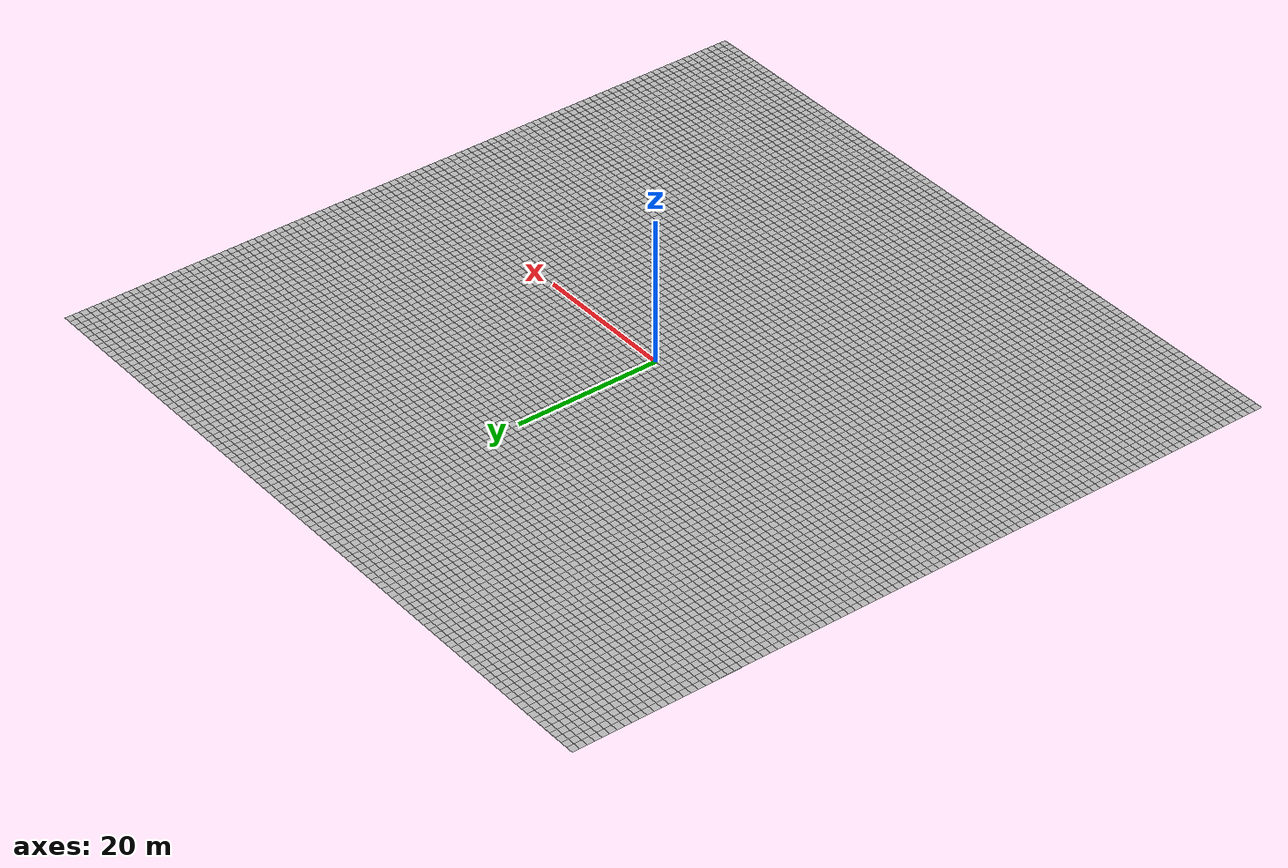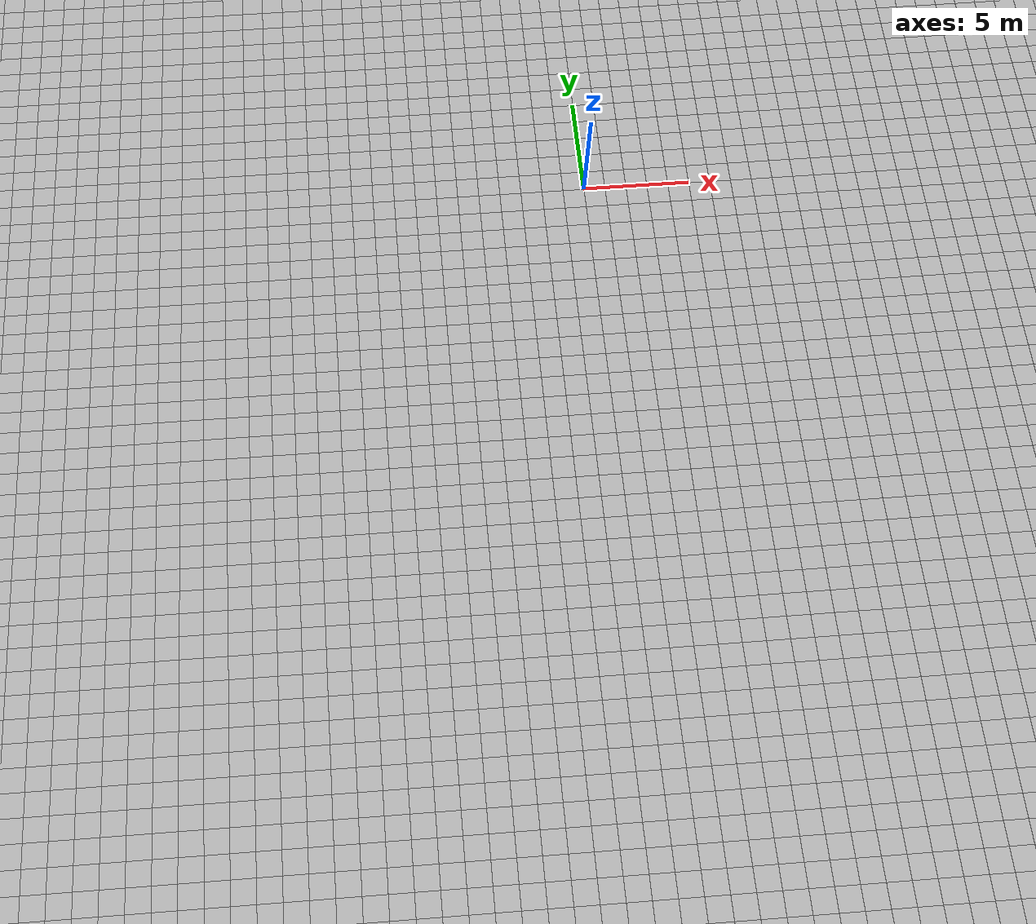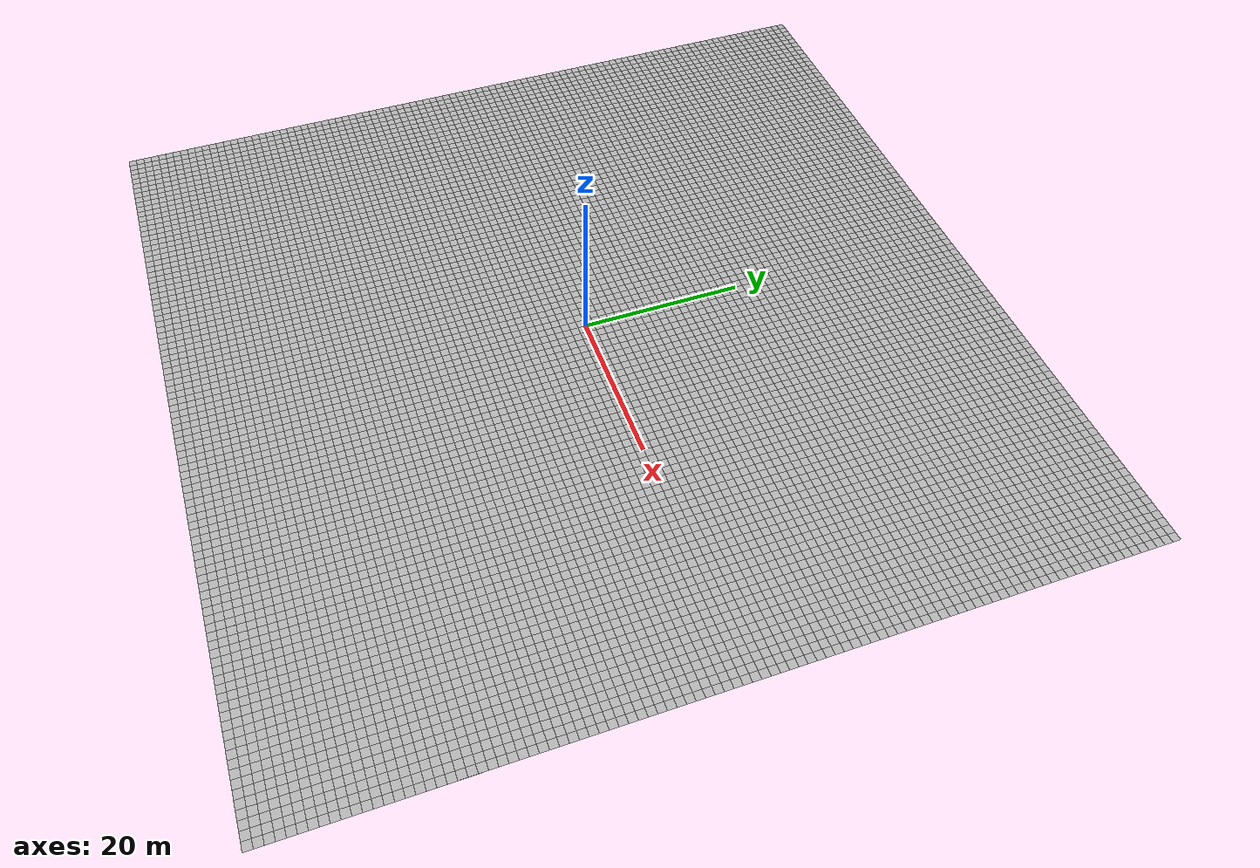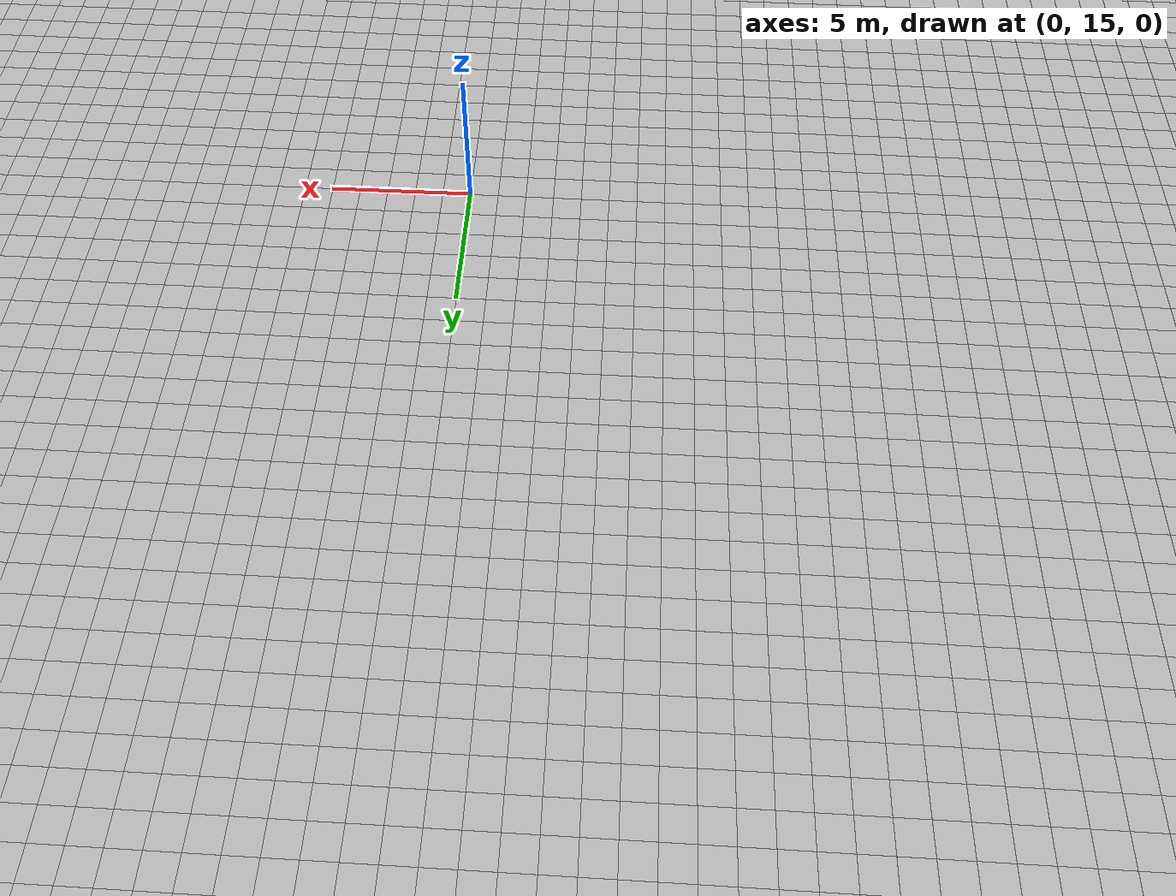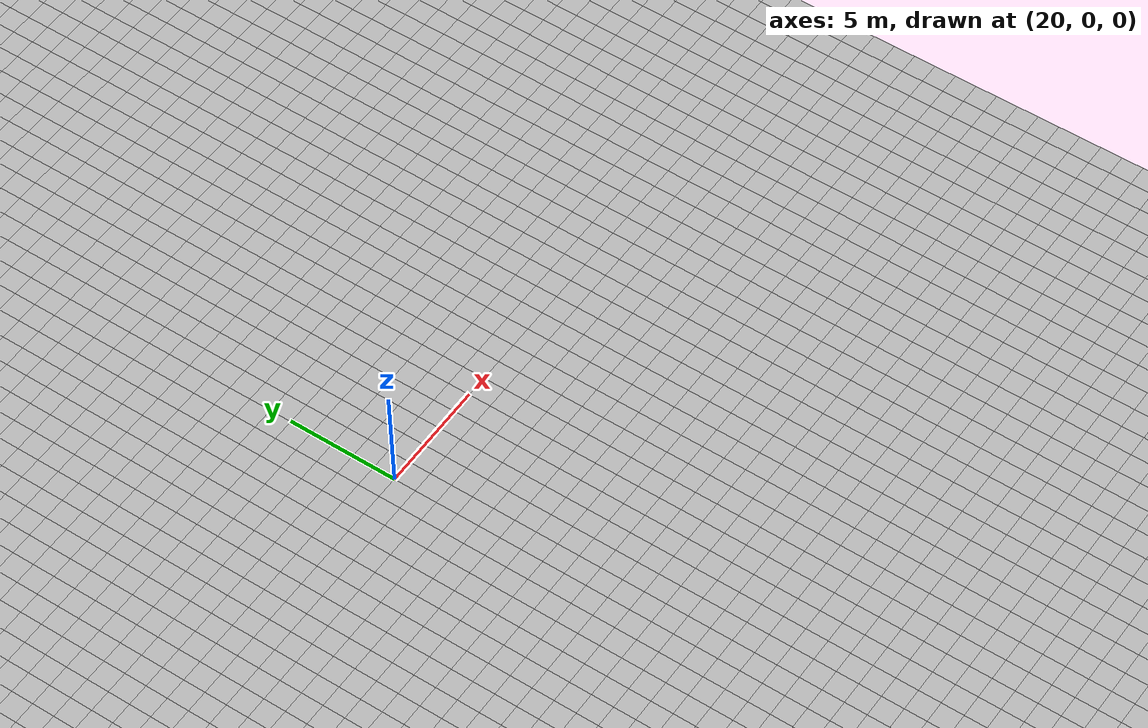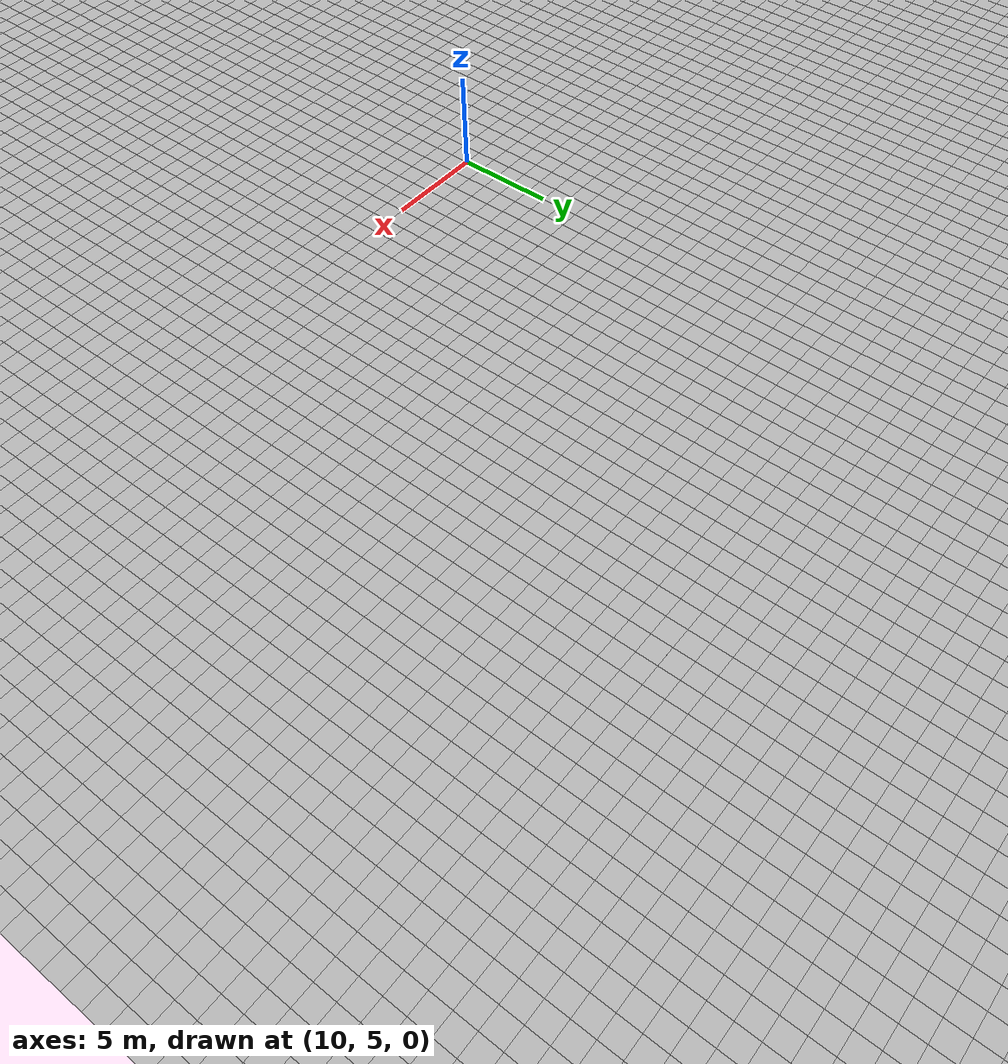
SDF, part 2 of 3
<uri>file:///home/wintery/Projects/gazebo/models/random_tile_ground/materials/scripts</uri>
      <uri>file:///home/wintery/Projects/gazebo/models/random_tile_ground/materials/textures</uri>
      <name>OrbTile/Tile15</name>
     </script>
    </material>
   </visual>
   <visual name="tile_29_33">
    <pose>-20.500 -16.500 0.001 0 0 3.14159</pose>
    <cast_shadows>false</cast_shadows>
    <geometry><plane><normal>0 0 1</normal><size>1 1</size></plane></geometry>
    <material>
     <script>
      <uri>file:///home/wintery/Projects/gazebo/models/random_tile_ground/materials/scripts</uri>
      <uri>file:///home/wintery/Projects/gazebo/models/random_tile_ground/materials/textures</uri>
      <name>OrbTile/Tile04</name>
     </script>
    </material>
   </visual>
   <visual name="tile_30_33">
    <pose>-19.500 -16.500 0.001 0 0 1.57080</pose>
    <cast_shadows>false</cast_shadows>
    <geometry><plane><normal>0 0 1</normal><size>1 1</size></plane></geometry>
    <material>
     <script>
      <uri>file:///home/wintery/Projects/gazebo/models/random_tile_ground/materials/scripts</uri>
      <uri>file:///home/wintery/Projects/gazebo/models/random_tile_ground/materials/textures</uri>
      <name>OrbTile/Tile08</name>
     </script>
    </material>
   </visual>
   <visual name="tile_31_33">
    <pose>-18.500 -16.500 0.001 0 0 1.57080</pose>
    <cast_shadows>false</cast_shadows>
    <geometry><plane><normal>0 0 1</normal><size>1 1</size></plane></geometry>
    <material>
     <script>
      <uri>file:///home/wintery/Projects/gazebo/models/random_tile_ground/materials/scripts</uri>
      <uri>file:///home/wintery/Projects/gazebo/models/random_tile_ground/materials/textures</uri>
      <name>OrbTile/Tile10</name>
     </script>
    </material>
   </visual>
   <visual name="tile_32_33">
    <pose>-17.500 -16.500 0.001 0 0 0.00000</pose>
    <cast_shadows>false</cast_shadows>
    <geometry><plane><normal>0 0 1</normal><size>1 1</size></plane></geometry>
    <material>
     <script>
      <uri>file:///home/wintery/Projects/gazebo/models/random_tile_ground/materials/scripts</uri>
      <uri>file:///home/wintery/Projects/gazebo/models/random_tile_ground/materials/textures</uri>
      <name>OrbTile/Tile08</name>
     </script>
    </material>
   </visual>
   <visual name="tile_33_33">
    <pose>-16.500 -16.500 0.001 0 0 1.57080</pose>
    <cast_shadows>false</cast_shadows>
    <geometry><plane><normal>0 0 1</normal><size>1 1</size></plane></geometry>
    <material>
     <script>
      <uri>file:///home/wintery/Projects/gazebo/models/random_tile_ground/materials/scripts</uri>
      <uri>file:///home/wintery/Projects/gazebo/models/random_tile_ground/materials/textures</uri>
      <name>OrbTile/Tile18</name>
     </script>
    </material>
   </visual>
   <visual name="tile_34_33">
    <pose>-15.500 -16.500 0.001 0 0 4.71239</pose>
    <cast_shadows>false</cast_shadows>
    <geometry><plane><normal>0 0 1</normal><size>1 1</size></plane></geometry>
    <material>
     <script>
      <uri>file:///home/wintery/Projects/gazebo/models/random_tile_ground/materials/scripts</uri>
      <uri>file:///home/wintery/Projects/gazebo/models/random_tile_ground/materials/textures</uri>
      <name>OrbTile/Tile08</name>
     </script>
    </material>
   </visual>
   <visual name="tile_35_33">
    <pose>-14.500 -16.500 0.001 0 0 1.57080</pose>
    <cast_shadows>false</cast_shadows>
    <geometry><plane><normal>0 0 1</normal><size>1 1</size></plane></geometry>
    <material>
     <script>
      <uri>file:///home/wintery/Projects/gazebo/models/random_tile_ground/materials/scripts</uri>
      <uri>file:///home/wintery/Projects/gazebo/models/random_tile_ground/materials/textures</uri>
      <name>OrbTile/Tile08</name>
     </script>
    </material>
   </visual>
   <visual name="tile_36_33">
    <pose>-13.500 -16.500 0.001 0 0 3.14159</pose>
    <cast_shadows>false</cast_shadows>
    <geometry><plane><normal>0 0 1</normal><size>1 1</size></plane></geometry>
    <material>
     <script>
      <uri>file:///home/wintery/Projects/gazebo/models/random_tile_ground/materials/scripts</uri>
      <uri>file:///home/wintery/Projects/gazebo/models/random_tile_ground/materials/textures</uri>
      <name>OrbTile/Tile15</name>
     </script>
    </material>
   </visual>
   <visual name="tile_37_33">
    <pose>-12.500 -16.500 0.001 0 0 0.00000</pose>
    <cast_shadows>false</cast_shadows>
    <geometry><plane><normal>0 0 1</normal><size>1 1</size></plane></geometry>
    <material>
     <script>
      <uri>file:///home/wintery/Projects/gazebo/models/random_tile_ground/materials/scripts</uri>
      <uri>file:///home/wintery/Projects/gazebo/models/random_tile_ground/materials/textures</uri>
      <name>OrbTile/Tile15</name>
     </script>
    </material>
   </visual>
   <visual name="tile_38_33">
    <pose>-11.500 -16.500 0.001 0 0 1.57080</pose>
    <cast_shadows>false</cast_shadows>
    <geometry><plane><normal>0 0 1</normal><size>1 1</size></plane></geometry>
    <material>
     <script>
      <uri>file:///home/wintery/Projects/gazebo/models/random_tile_ground/materials/scripts</uri>
      <uri>file:///home/wintery/Projects/gazebo/models/random_tile_ground/materials/textures</uri>
      <name>OrbTile/Tile13</name>
     </script>
    </material>
   </visual>
   <visual name="tile_39_33">
    <pose>-10.500 -16.500 0.001 0 0 0.00000</pose>
    <cast_shadows>false</cast_shadows>
    <geometry><plane><normal>0 0 1</normal><size>1 1</size></plane></geometry>
    <material>
     <script>
      <uri>file:///home/wintery/Projects/gazebo/models/random_tile_ground/materials/scripts</uri>
      <uri>file:///home/wintery/Projects/gazebo/models/random_tile_ground/materials/textures</uri>
      <name>OrbTile/Tile02</name>
     </script>
    </material>
   </visual>
   <visual name="tile_40_33">
    <pose>-9.500 -16.500 0.001 0 0 0.00000</pose>
    <cast_shadows>false</cast_shadows>
    <geometry><plane><normal>0 0 1</normal><size>1 1</size></plane></geometry>
    <material>
     <script>
      <uri>file:///home/wintery/Projects/gazebo/models/random_tile_ground/materials/scripts</uri>
      <uri>file:///home/wintery/Projects/gazebo/models/random_tile_ground/materials/textures</uri>
      <name>OrbTile/Tile02</name>
     </script>
    </material>
   </visual>
   <visual name="tile_41_33">
    <pose>-8.500 -16.500 0.001 0 0 3.14159</pose>
    <cast_shadows>false</cast_shadows>
    <geometry><plane><normal>0 0 1</normal><size>1 1</size></plane></geometry>
    <material>
     <script>
      <uri>file:///home/wintery/Projects/gazebo/models/random_tile_ground/materials/scripts</uri>
      <uri>file:///home/wintery/Projects/gazebo/models/random_tile_ground/materials/textures</uri>
      <name>OrbTile/Tile08</name>
     </script>
    </material>
   </visual>
   <visual name="tile_42_33">
    <pose>-7.500 -16.500 0.001 0 0 1.57080</pose>
    <cast_shadows>false</cast_shadows>
    <geometry><plane><normal>0 0 1</normal><size>1 1</size></plane></geometry>
    <material>
     <script>
      <uri>file:///home/wintery/Projects/gazebo/models/random_tile_ground/materials/scripts</uri>
      <uri>file:///home/wintery/Projects/gazebo/models/random_tile_ground/materials/textures</uri>
      <name>OrbTile/Tile19</name>
     </script>
    </material>
   </visual>
   <visual name="tile_43_33">
    <pose>-6.500 -16.500 0.001 0 0 3.14159</pose>
    <cast_shadows>false</cast_shadows>
    <geometry><plane><normal>0 0 1</normal><size>1 1</size></plane></geometry>
    <material>
     <script>
      <uri>file:///home/wintery/Projects/gazebo/models/random_tile_ground/materials/scripts</uri>
      <uri>file:///home/wintery/Projects/gazebo/models/random_tile_ground/materials/textures</uri>
      <name>OrbTile/Tile16</name>
     </script>
    </material>
   </visual>
   <visual name="tile_44_33">
    <pose>-5.500 -16.500 0.001 0 0 3.14159</pose>
    <cast_shadows>false</cast_shadows>
    <geometry><plane><normal>0 0 1</normal><size>1 1</size></plane></geometry>
    <material>
     <script>
      <uri>file:///home/wintery/Projects/gazebo/models/random_tile_ground/materials/scripts</uri>
      <uri>file:///home/wintery/Projects/gazebo/models/random_tile_ground/materials/textures</uri>
      <name>OrbTile/Tile08</name>
     </script>
    </material>
   </visual>
   <visual name="tile_45_33">
    <pose>-4.500 -16.500 0.001 0 0 1.57080</pose>
    <cast_shadows>false</cast_shadows>
    <geometry><plane><normal>0 0 1</normal><size>1 1</size></plane></geometry>
    <material>
     <script>
      <uri>file:///home/wintery/Projects/gazebo/models/random_tile_ground/materials/scripts</uri>
      <uri>file:///home/wintery/Projects/gazebo/models/random_tile_ground/materials/textures</uri>
      <name>OrbTile/Tile11</name>
     </script>
    </material>
   </visual>
   <visual name="tile_46_33">
    <pose>-3.500 -16.500 0.001 0 0 4.71239</pose>
    <cast_shadows>false</cast_shadows>
    <geometry><plane><normal>0 0 1</normal><size>1 1</size></plane></geometry>
    <material>
     <script>
      <uri>file:///home/wintery/Projects/gazebo/models/random_tile_ground/materials/scripts</uri>
      <uri>file:///home/wintery/Projects/gazebo/models/random_tile_ground/materials/textures</uri>
      <name>OrbTile/Tile17</name>
     </script>
    </material>
   </visual>
   <visual name="tile_47_33">
    <pose>-2.500 -16.500 0.001 0 0 3.14159</pose>
    <cast_shadows>false</cast_shadows>
    <geometry><plane><normal>0 0 1</normal><size>1 1</size></plane></geometry>
    <material>
     <script>
      <uri>file:///home/wintery/Projects/gazebo/models/random_tile_ground/materials/scripts</uri>
      <uri>file:///home/wintery/Projects/gazebo/models/random_tile_ground/materials/textures</uri>
      <name>OrbTile/Tile15</name>
     </script>
    </material>
   </visual>
   <visual name="tile_48_33">
    <pose>-1.500 -16.500 0.001 0 0 4.71239</pose>
    <cast_shadows>false</cast_shadows>
    <geometry><plane><normal>0 0 1</normal><size>1 1</size></plane></geometry>
    <material>
     <script>
      <uri>file:///home/wintery/Projects/gazebo/models/random_tile_ground/materials/scripts</uri>
      <uri>file:///home/wintery/Projects/gazebo/models/random_tile_ground/materials/textures</uri>
      <name>OrbTile/Tile18</name>
     </script>
    </material>
   </visual>
   <visual name="tile_49_33">
    <pose>-0.500 -16.500 0.001 0 0 4.71239</pose>
    <cast_shadows>false</cast_shadows>
    <geometry><plane><normal>0 0 1</normal><size>1 1</size></plane></geometry>
    <material>
     <script>
      <uri>file:///home/wintery/Projects/gazebo/models/random_tile_ground/materials/scripts</uri>
      <uri>file:///home/wintery/Projects/gazebo/models/random_tile_ground/materials/textures</uri>
      <name>OrbTile/Tile03</name>
     </script>
    </material>
   </visual>
   <visual name="tile_50_33">
    <pose>0.500 -16.500 0.001 0 0 0.00000</pose>
    <cast_shadows>false</cast_shadows>
    <geometry><plane><normal>0 0 1</normal><size>1 1</size></plane></geometry>
    <material>
     <script>
      <uri>file:///home/wintery/Projects/gazebo/models/random_tile_ground/materials/scripts</uri>
      <uri>file:///home/wintery/Projects/gazebo/models/random_tile_ground/materials/textures</uri>
      <name>OrbTile/Tile11</name>
     </script>
    </material>
   </visual>
   <visual name="tile_51_33">
    <pose>1.500 -16.500 0.001 0 0 1.57080</pose>
    <cast_shadows>false</cast_shadows>
    <geometry><plane><normal>0 0 1</normal><size>1 1</size></plane></geometry>
    <material>
     <script>
      <uri>file:///home/wintery/Projects/gazebo/models/random_tile_ground/materials/scripts</uri>
      <uri>file:///home/wintery/Projects/gazebo/models/random_tile_ground/materials/textures</uri>
      <name>OrbTile/Tile12</name>
     </script>
    </material>
   </visual>
   <visual name="tile_52_33">
    <pose>2.500 -16.500 0.001 0 0 1.57080</pose>
    <cast_shadows>false</cast_shadows>
    <geometry><plane><normal>0 0 1</normal><size>1 1</size></plane></geometry>
    <material>
     <script>
      <uri>file:///home/wintery/Projects/gazebo/models/random_tile_ground/materials/scripts</uri>
      <uri>file:///home/wintery/Projects/gazebo/models/random_tile_ground/materials/textures</uri>
      <name>OrbTile/Tile15</name>
     </script>
    </material>
   </visual>
   <visual name="tile_53_33">
    <pose>3.500 -16.500 0.001 0 0 1.57080</pose>
    <cast_shadows>false</cast_shadows>
    <geometry><plane><normal>0 0 1</normal><size>1 1</size></plane></geometry>
    <material>
     <script>
      <uri>file:///home/wintery/Projects/gazebo/models/random_tile_ground/materials/scripts</uri>
      <uri>file:///home/wintery/Projects/gazebo/models/random_tile_ground/materials/textures</uri>
      <name>OrbTile/Tile00</name>
     </script>
    </material>
   </visual>
   <visual name="tile_54_33">
    <pose>4.500 -16.500 0.001 0 0 3.14159</pose>
    <cast_shadows>false</cast_shadows>
    <geometry><plane><normal>0 0 1</normal><size>1 1</size></plane></geometry>
    <material>
     <script>
      <uri>file:///home/wintery/Projects/gazebo/models/random_tile_ground/materials/scripts</uri>
      <uri>file:///home/wintery/Projects/gazebo/models/random_tile_ground/materials/textures</uri>
      <name>OrbTile/Tile02</name>
     </script>
    </material>
   </visual>
   <visual name="tile_55_33">
    <pose>5.500 -16.500 0.001 0 0 1.57080</pose>
    <cast_shadows>false</cast_shadows>
    <geometry><plane><normal>0 0 1</normal><size>1 1</size></plane></geometry>
    <material>
     <script>
      <uri>file:///home/wintery/Projects/gazebo/models/random_tile_ground/materials/scripts</uri>
      <uri>file:///home/wintery/Projects/gazebo/models/random_tile_ground/materials/textures</uri>
      <name>OrbTile/Tile13</name>
     </script>
    </material>
   </visual>
   <visual name="tile_56_33">
    <pose>6.500 -16.500 0.001 0 0 1.57080</pose>
    <cast_shadows>false</cast_shadows>
    <geometry><plane><normal>0 0 1</normal><size>1 1</size></plane></geometry>
    <material>
     <script>
      <uri>file:///home/wintery/Projects/gazebo/models/random_tile_ground/materials/scripts</uri>
      <uri>file:///home/wintery/Projects/gazebo/models/random_tile_ground/materials/textures</uri>
      <name>OrbTile/Tile02</name>
     </script>
    </material>
   </visual>
   <visual name="tile_57_33">
    <pose>7.500 -16.500 0.001 0 0 4.71239</pose>
    <cast_shadows>false</cast_shadows>
    <geometry><plane><normal>0 0 1</normal><size>1 1</size></plane></geometry>
    <material>
     <script>
      <uri>file:///home/wintery/Projects/gazebo/models/random_tile_ground/materials/scripts</uri>
      <uri>file:///home/wintery/Projects/gazebo/models/random_tile_ground/materials/textures</uri>
      <name>OrbTile/Tile04</name>
     </script>
    </material>
   </visual>
   <visual name="tile_58_33">
    <pose>8.500 -16.500 0.001 0 0 4.71239</pose>
    <cast_shadows>false</cast_shadows>
    <geometry><plane><normal>0 0 1</normal><size>1 1</size></plane></geometry>
    <material>
     <script>
      <uri>file:///home/wintery/Projects/gazebo/models/random_tile_ground/materials/scripts</uri>
      <uri>file:///home/wintery/Projects/gazebo/models/random_tile_ground/materials/textures</uri>
      <name>OrbTile/Tile13</name>
     </script>
    </material>
   </visual>
   <visual name="tile_59_33">
    <pose>9.500 -16.500 0.001 0 0 3.14159</pose>
    <cast_shadows>false</cast_shadows>
    <geometry><plane><normal>0 0 1</normal><size>1 1</size></plane></geometry>
    <material>
     <script>
      <uri>file:///home/wintery/Projects/gazebo/models/random_tile_ground/materials/scripts</uri>
      <uri>file:///home/wintery/Projects/gazebo/models/random_tile_ground/materials/textures</uri>
      <name>OrbTile/Tile17</name>
     </script>
    </material>
   </visual>
   <visual name="tile_60_33">
    <pose>10.500 -16.500 0.001 0 0 1.57080</pose>
    <cast_shadows>false</cast_shadows>
    <geometry><plane><normal>0 0 1</normal><size>1 1</size></plane></geometry>
    <material>
     <script>
      <uri>file:///home/wintery/Projects/gazebo/models/random_tile_ground/materials/scripts</uri>
      <uri>file:///home/wintery/Projects/gazebo/models/random_tile_ground/materials/textures</uri>
      <name>OrbTile/Tile10</name>
     </script>
    </material>
   </visual>
   <visual name="tile_61_33">
    <pose>11.500 -16.500 0.001 0 0 0.00000</pose>
    <cast_shadows>false</cast_shadows>
    <geometry><plane><normal>0 0 1</normal><size>1 1</size></plane></geometry>
    <material>
     <script>
      <uri>file:///home/wintery/Projects/gazebo/models/random_tile_ground/materials/scripts</uri>
      <uri>file:///home/wintery/Projects/gazebo/models/random_tile_ground/materials/textures</uri>
      <name>OrbTile/Tile03</name>
     </script>
    </material>
   </visual>
   <visual name="tile_62_33">
    <pose>12.500 -16.500 0.001 0 0 3.14159</pose>
    <cast_shadows>false</cast_shadows>
    <geometry><plane><normal>0 0 1</normal><size>1 1</size></plane></geometry>
    <material>
     <script>
      <uri>file:///home/wintery/Projects/gazebo/models/random_tile_ground/materials/scripts</uri>
      <uri>file:///home/wintery/Projects/gazebo/models/random_tile_ground/materials/textures</uri>
      <name>OrbTile/Tile05</name>
     </script>
    </material>
   </visual>
   <visual name="tile_63_33">
    <pose>13.500 -16.500 0.001 0 0 0.00000</pose>
    <cast_shadows>false</cast_shadows>
    <geometry><plane><normal>0 0 1</normal><size>1 1</size></plane></geometry>
    <material>
     <script>
      <uri>file:///home/wintery/Projects/gazebo/models/random_tile_ground/materials/scripts</uri>
      <uri>file:///home/wintery/Projects/gazebo/models/random_tile_ground/materials/textures</uri>
      <name>OrbTile/Tile11</name>
     </script>
    </material>
   </visual>
   <visual name="tile_64_33">
    <pose>14.500 -16.500 0.001 0 0 1.57080</pose>
    <cast_shadows>false</cast_shadows>
    <geometry><plane><normal>0 0 1</normal><size>1 1</size></plane></geometry>
    <material>
     <script>
      <uri>file:///home/wintery/Projects/gazebo/models/random_tile_ground/materials/scripts</uri>
      <uri>file:///home/wintery/Projects/gazebo/models/random_tile_ground/materials/textures</uri>
      <name>OrbTile/Tile02</name>
     </script>
    </material>
   </visual>
   <visual name="tile_65_33">
    <pose>15.500 -16.500 0.001 0 0 4.71239</pose>
    <cast_shadows>false</cast_shadows>
    <geometry><plane><normal>0 0 1</normal><size>1 1</size></plane></geometry>
    <material>
     <script>
      <uri>file:///home/wintery/Projects/gazebo/models/random_tile_ground/materials/scripts</uri>
      <uri>file:///home/wintery/Projects/gazebo/models/random_tile_ground/materials/textures</uri>
      <name>OrbTile/Tile06</name>
     </script>
    </material>
   </visual>
   <visual name="tile_66_33">
    <pose>16.500 -16.500 0.001 0 0 0.00000</pose>
    <cast_shadows>false</cast_shadows>
    <geometry><plane><normal>0 0 1</normal><size>1 1</size></plane></geometry>
    <material>
     <script>
      <uri>file:///home/wintery/Projects/gazebo/models/random_tile_ground/materials/scripts</uri>
      <uri>file:///home/wintery/Projects/gazebo/models/random_tile_ground/materials/textures</uri>
      <name>OrbTile/Tile05</name>
     </script>
    </material>
   </visual>
   <visual name="tile_67_33">
    <pose>17.500 -16.500 0.001 0 0 1.57080</pose>
    <cast_shadows>false</cast_shadows>
    <geometry><plane><normal>0 0 1</normal><size>1 1</size></plane></geometry>
    <material>
     <script>
      <uri>file:///home/wintery/Projects/gazebo/models/random_tile_ground/materials/scripts</uri>
      <uri>file:///home/wintery/Projects/gazebo/models/random_tile_ground/materials/textures</uri>
      <name>OrbTile/Tile03</name>
     </script>
    </material>
   </visual>
   <visual name="tile_68_33">
    <pose>18.500 -16.500 0.001 0 0 4.71239</pose>
    <cast_shadows>false</cast_shadows>
    <geometry><plane><normal>0 0 1</normal><size>1 1</size></plane></geometry>
    <material>
     <script>
      <uri>file:///home/wintery/Projects/gazebo/models/random_tile_ground/materials/scripts</uri>
      <uri>file:///home/wintery/Projects/gazebo/models/random_tile_ground/materials/textures</uri>
      <name>OrbTile/Tile17</name>
     </script>
    </material>
   </visual>
   <visual name="tile_69_33">
    <pose>19.500 -16.500 0.001 0 0 3.14159</pose>
    <cast_shadows>false</cast_shadows>
    <geometry><plane><normal>0 0 1</normal><size>1 1</size></plane></geometry>
    <material>
     <script>
      <uri>file:///home/wintery/Projects/gazebo/models/random_tile_ground/materials/scripts</uri>
      <uri>file:///home/wintery/Projects/gazebo/models/random_tile_ground/materials/textures</uri>
      <name>OrbTile/Tile11</name>
     </script>
    </material>
   </visual>
   <visual name="tile_70_33">
    <pose>20.500 -16.500 0.001 0 0 4.71239</pose>
    <cast_shadows>false</cast_shadows>
    <geometry><plane><normal>0 0 1</normal><size>1 1</size></plane></geometry>
    <material>
     <script>
      <uri>file:///home/wintery/Projects/gazebo/models/random_tile_ground/materials/scripts</uri>
      <uri>file:///home/wintery/Projects/gazebo/models/random_tile_ground/materials/textures</uri>
      <name>OrbTile/Tile14</name>
     </script>
    </material>
   </visual>
   <visual name="tile_71_33">
    <pose>21.500 -16.500 0.001 0 0 4.71239</pose>
    <cast_shadows>false</cast_shadows>
    <geometry><plane><normal>0 0 1</normal><size>1 1</size></plane></geometry>
    <material>
     <script>
      <uri>file:///home/wintery/Projects/gazebo/models/random_tile_ground/materials/scripts</uri>
      <uri>file:///home/wintery/Projects/gazebo/models/random_tile_ground/materials/textures</uri>
      <name>OrbTile/Tile17</name>
     </script>
    </material>
   </visual>
   <visual name="tile_72_33">
    <pose>22.500 -16.500 0.001 0 0 3.14159</pose>
    <cast_shadows>false</cast_shadows>
    <geometry><plane><normal>0 0 1</normal><size>1 1</size></plane></geometry>
    <material>
     <script>
      <uri>file:///home/wintery/Projects/gazebo/models/random_tile_ground/materials/scripts</uri>
      <uri>file:///home/wintery/Projects/gazebo/models/random_tile_ground/materials/textures</uri>
      <name>OrbTile/Tile10</name>
     </script>
    </material>
   </visual>
   <visual name="tile_73_33">
    <pose>23.500 -16.500 0.001 0 0 1.57080</pose>
    <cast_shadows>false</cast_shadows>
    <geometry><plane><normal>0 0 1</normal><size>1 1</size></plane></geometry>
    <material>
     <script>
      <uri>file:///home/wintery/Projects/gazebo/models/random_tile_ground/materials/scripts</uri>
      <uri>file:///home/wintery/Projects/gazebo/models/random_tile_ground/materials/textures</uri>
      <name>OrbTile/Tile13</name>
     </script>
    </material>
   </visual>
   <visual name="tile_74_33">
    <pose>24.500 -16.500 0.001 0 0 3.14159</pose>
    <cast_shadows>false</cast_shadows>
    <geometry><plane><normal>0 0 1</normal><size>1 1</size></plane></geometry>
    <material>
     <script>
      <uri>file:///home/wintery/Projects/gazebo/models/random_tile_ground/materials/scripts</uri>
      <uri>file:///home/wintery/Projects/gazebo/models/random_tile_ground/materials/textures</uri>
      <name>OrbTile/Tile17</name>
     </script>
    </material>
   </visual>
   <visual name="tile_75_33">
    <pose>25.500 -16.500 0.001 0 0 0.00000</pose>
    <cast_shadows>false</cast_shadows>
    <geometry><plane><normal>0 0 1</normal><size>1 1</size></plane></geometry>
    <material>
     <script>
      <uri>file:///home/wintery/Projects/gazebo/models/random_tile_ground/materials/scripts</uri>
      <uri>file:///home/wintery/Projects/gazebo/models/random_tile_ground/materials/textures</uri>
      <name>OrbTile/Tile18</name>
     </script>
    </material>
   </visual>
   <visual name="tile_76_33">
    <pose>26.500 -16.500 0.001 0 0 4.71239</pose>
    <cast_shadows>false</cast_shadows>
    <geometry><plane><normal>0 0 1</normal><size>1 1</size></plane></geometry>
    <material>
     <script>
      <uri>file:///home/wintery/Projects/gazebo/models/random_tile_ground/materials/scripts</uri>
      <uri>file:///home/wintery/Projects/gazebo/models/random_tile_ground/materials/textures</uri>
      <name>OrbTile/Tile11</name>
     </script>
    </material>
   </visual>
   <visual name="tile_77_33">
    <pose>27.500 -16.500 0.001 0 0 4.71239</pose>
    <cast_shadows>false</cast_shadows>
    <geometry><plane><normal>0 0 1</normal><size>1 1</size></plane></geometry>
    <material>
     <script>
      <uri>file:///home/wintery/Projects/gazebo/models/random_tile_ground/materials/scripts</uri>
      <uri>file:///home/wintery/Projects/gazebo/models/random_tile_ground/materials/textures</uri>
      <name>OrbTile/Tile19</name>
     </script>
    </material>
   </visual>
   <visual name="tile_78_33">
    <pose>28.500 -16.500 0.001 0 0 4.71239</pose>
    <cast_shadows>false</cast_shadows>
    <geometry><plane><normal>0 0 1</normal><size>1 1</size></plane></geometry>
    <material>
     <script>
      <uri>file:///home/wintery/Projects/gazebo/models/random_tile_ground/materials/scripts</uri>
      <uri>file:///home/wintery/Projects/gazebo/models/random_tile_ground/materials/textures</uri>
      <name>OrbTile/Tile03</name>
     </script>
    </material>
   </visual>
   <visual name="tile_79_33">
    <pose>29.500 -16.500 0.001 0 0 0.00000</pose>
    <cast_shadows>false</cast_shadows>
    <geometry><plane><normal>0 0 1</normal><size>1 1</size></plane></geometry>
    <material>
     <script>
      <uri>file:///home/wintery/Projects/gazebo/models/random_tile_ground/materials/scripts</uri>
      <uri>file:///home/wintery/Projects/gazebo/models/random_tile_ground/materials/textures</uri>
      <name>OrbTile/Tile03</name>
     </script>
    </material>
   </visual>
   <visual name="tile_80_33">
    <pose>30.500 -16.500 0.001 0 0 0.00000</pose>
    <cast_shadows>false</cast_shadows>
    <geometry><plane><normal>0 0 1</normal><size>1 1</size></plane></geometry>
    <material>
     <script>
      <uri>file:///home/wintery/Projects/gazebo/models/random_tile_ground/materials/scripts</uri>
      <uri>file:///home/wintery/Projects/gazebo/models/random_tile_ground/materials/textures</uri>
      <name>OrbTile/Tile04</name>
     </script>
    </material>
   </visual>
   <visual name="tile_81_33">
    <pose>31.500 -16.500 0.001 0 0 1.57080</pose>
    <cast_shadows>false</cast_shadows>
    <geometry><plane><normal>0 0 1</normal><size>1 1</size></plane></geometry>
    <material>
     <script>
      <uri>file:///home/wintery/Projects/gazebo/models/random_tile_ground/materials/scripts</uri>
      <uri>file:///home/wintery/Projects/gazebo/models/random_tile_ground/materials/textures</uri>
      <name>OrbTile/Tile08</name>
     </script>
    </material>
   </visual>
   <visual name="tile_82_33">
    <pose>32.500 -16.500 0.001 0 0 3.14159</pose>
    <cast_shadows>false</cast_shadows>
    <geometry><plane><normal>0 0 1</normal><size>1 1</size></plane></geometry>
    <material>
     <script>
      <uri>file:///home/wintery/Projects/gazebo/models/random_tile_ground/materials/scripts</uri>
      <uri>file:///home/wintery/Projects/gazebo/models/random_tile_ground/materials/textures</uri>
      <name>OrbTile/Tile10</name>
     </script>
    </material>
   </visual>
   <visual name="tile_83_33">
    <pose>33.500 -16.500 0.001 0 0 1.57080</pose>
    <cast_shadows>false</cast_shadows>
    <geometry><plane><normal>0 0 1</normal><size>1 1</size></plane></geometry>
    <material>
     <script>
      <uri>file:///home/wintery/Projects/gazebo/models/random_tile_ground/materials/scripts</uri>
      <uri>file:///home/wintery/Projects/gazebo/models/random_tile_ground/materials/textures</uri>
      <name>OrbTile/Tile00</name>
     </script>
    </material>
   </visual>
   <visual name="tile_84_33">
    <pose>34.500 -16.500 0.001 0 0 0.00000</pose>
    <cast_shadows>false</cast_shadows>
    <geometry><plane><normal>0 0 1</normal><size>1 1</size></plane></geometry>
    <material>
     <script>
      <uri>file:///home/wintery/Projects/gazebo/models/random_tile_ground/materials/scripts</uri>
      <uri>file:///home/wintery/Projects/gazebo/models/random_tile_ground/materials/textures</uri>
      <name>OrbTile/Tile13</name>
     </script>
    </material>
   </visual>
   <visual name="tile_85_33">
    <pose>35.500 -16.500 0.001 0 0 1.57080</pose>
    <cast_shadows>false</cast_shadows>
    <geometry><plane><normal>0 0 1</normal><size>1 1</size></plane></geometry>
    <material>
     <script>
      <uri>file:///home/wintery/Projects/gazebo/models/random_tile_ground/materials/scripts</uri>
      <uri>file:///home/wintery/Projects/gazebo/models/random_tile_ground/materials/textures</uri>
      <name>OrbTile/Tile17</name>
     </script>
    </material>
   </visual>
   <visual name="tile_86_33">
    <pose>36.500 -16.500 0.001 0 0 4.71239</pose>
    <cast_shadows>false</cast_shadows>
    <geometry><plane><normal>0 0 1</normal><size>1 1</size></plane></geometry>
    <material>
     <script>
      <uri>file:///home/wintery/Projects/gazebo/models/random_tile_ground/materials/scripts</uri>
      <uri>file:///home/wintery/Projects/gazebo/models/random_tile_ground/materials/textures</uri>
      <name>OrbTile/Tile18</name>
     </script>
    </material>
   </visual>
   <visual name="tile_87_33">
    <pose>37.500 -16.500 0.001 0 0 0.00000</pose>
    <cast_shadows>false</cast_shadows>
    <geometry><plane><normal>0 0 1</normal><size>1 1</size></plane></geometry>
    <material>
     <script>
      <uri>file:///home/wintery/Projects/gazebo/models/random_tile_ground/materials/scripts</uri>
      <uri>file:///home/wintery/Projects/gazebo/models/random_tile_ground/materials/textures</uri>
      <name>OrbTile/Tile05</name>
     </script>
    </material>
   </visual>
   <visual name="tile_88_33">
    <pose>38.500 -16.500 0.001 0 0 4.71239</pose>
    <cast_shadows>false</cast_shadows>
    <geometry><plane><normal>0 0 1</normal><size>1 1</size></plane></geometry>
    <material>
     <script>
      <uri>file:///home/wintery/Projects/gazebo/models/random_tile_ground/materials/scripts</uri>
      <uri>file:///home/wintery/Projects/gazebo/models/random_tile_ground/materials/textures</uri>
      <name>OrbTile/Tile11</name>
     </script>
    </material>
   </visual>
   <visual name="tile_89_33">
    <pose>39.500 -16.500 0.001 0 0 1.57080</pose>
    <cast_shadows>false</cast_shadows>
    <geometry><plane><normal>0 0 1</normal><size>1 1</size></plane></geometry>
    <material>
     <script>
      <uri>file:///home/wintery/Projects/gazebo/models/random_tile_ground/materials/scripts</uri>
      <uri>file:///home/wintery/Projects/gazebo/models/random_tile_ground/materials/textures</uri>
      <name>OrbTile/Tile03</name>
     </script>
    </material>
   </visual>
   <visual name="tile_90_33">
    <pose>40.500 -16.500 0.001 0 0 1.57080</pose>
    <cast_shadows>false</cast_shadows>
    <geometry><plane><normal>0 0 1</normal><size>1 1</size></plane></geometry>
    <material>
     <script>
      <uri>file:///home/wintery/Projects/gazebo/models/random_tile_ground/materials/scripts</uri>
      <uri>file:///home/wintery/Projects/gazebo/models/random_tile_ground/materials/textures</uri>
      <name>OrbTile/Tile05</name>
     </script>
    </material>
   </visual>
   <visual name="tile_91_33">
    <pose>41.500 -16.500 0.001 0 0 1.57080</pose>
    <cast_shadows>false</cast_shadows>
    <geometry><plane><normal>0 0 1</normal><size>1 1</size></plane></geometry>
    <material>
     <script>
      <uri>file:///home/wintery/Projects/gazebo/models/random_tile_ground/materials/scripts</uri>
      <uri>file:///home/wintery/Projects/gazebo/models/random_tile_ground/materials/textures</uri>
      <name>OrbTile/Tile07</name>
     </script>
    </material>
   </visual>
   <visual name="tile_92_33">
    <pose>42.500 -16.500 0.001 0 0 3.14159</pose>
    <cast_shadows>false</cast_shadows>
    <geometry><plane><normal>0 0 1</normal><size>1 1</size></plane></geometry>
    <material>
     <script>
      <uri>file:///home/wintery/Projects/gazebo/models/random_tile_ground/materials/scripts</uri>
      <uri>file:///home/wintery/Projects/gazebo/models/random_tile_ground/materials/textures</uri>
      <name>OrbTile/Tile11</name>
     </script>
    </material>
   </visual>
   <visual name="tile_93_33">
    <pose>43.500 -16.500 0.001 0 0 0.00000</pose>
    <cast_shadows>false</cast_shadows>
    <geometry><plane><normal>0 0 1</normal><size>1 1</size></plane></geometry>
    <material>
     <script>
      <uri>file:///home/wintery/Projects/gazebo/models/random_tile_ground/materials/scripts</uri>
      <uri>file:///home/wintery/Projects/gazebo/models/random_tile_ground/materials/textures</uri>
      <name>OrbTile/Tile00</name>
     </script>
    </material>
   </visual>
   <visual name="tile_94_33">
    <pose>44.500 -16.500 0.001 0 0 3.14159</pose>
    <cast_shadows>false</cast_shadows>
    <geometry><plane><normal>0 0 1</normal><size>1 1</size></plane></geometry>
    <material>
     <script>
      <uri>file:///home/wintery/Projects/gazebo/models/random_tile_ground/materials/scripts</uri>
      <uri>file:///home/wintery/Projects/gazebo/models/random_tile_ground/materials/textures</uri>
      <name>OrbTile/Tile03</name>
     </script>
    </material>
   </visual>
   <visual name="tile_95_33">
    <pose>45.500 -16.500 0.001 0 0 1.57080</pose>
    <cast_shadows>false</cast_shadows>
    <geometry><plane><normal>0 0 1</normal><size>1 1</size></plane></geometry>
    <material>
     <script>
      <uri>file:///home/wintery/Projects/gazebo/models/random_tile_ground/materials/scripts</uri>
      <uri>file:///home/wintery/Projects/gazebo/models/random_tile_ground/materials/textures</uri>
      <name>OrbTile/Tile06</name>
     </script>
    </material>
   </visual>
   <visual name="tile_96_33">
    <pose>46.500 -16.500 0.001 0 0 4.71239</pose>
    <cast_shadows>false</cast_shadows>
    <geometry><plane><normal>0 0 1</normal><size>1 1</size></plane></geometry>
    <material>
     <script>
      <uri>file:///home/wintery/Projects/gazebo/models/random_tile_ground/materials/scripts</uri>
      <uri>file:///home/wintery/Projects/gazebo/models/random_tile_ground/materials/textures</uri>
      <name>OrbTile/Tile12</name>
     </script>
    </material>
   </visual>
   <visual name="tile_97_33">
    <pose>47.500 -16.500 0.001 0 0 4.71239</pose>
    <cast_shadows>false</cast_shadows>
    <geometry><plane><normal>0 0 1</normal><size>1 1</size></plane></geometry>
    <material>
     <script>
      <uri>file:///home/wintery/Projects/gazebo/models/random_tile_ground/materials/scripts</uri>
      <uri>file:///home/wintery/Projects/gazebo/models/random_tile_ground/materials/textures</uri>
      <name>OrbTile/Tile10</name>
     </script>
    </material>
   </visual>
   <visual name="tile_98_33">
    <pose>48.500 -16.500 0.001 0 0 3.14159</pose>
    <cast_shadows>false</cast_shadows>
    <geometry><plane><normal>0 0 1</normal><size>1 1</size></plane></geometry>
    <material>
     <script>
      <uri>file:///home/wintery/Projects/gazebo/models/random_tile_ground/materials/scripts</uri>
      <uri>file:///home/wintery/Projects/gazebo/models/random_tile_ground/materials/textures</uri>
      <name>OrbTile/Tile15</name>
     </script>
    </material>
   </visual>
   <visual name="tile_99_33">
    <pose>49.500 -16.500 0.001 0 0 3.14159</pose>
    <cast_shadows>false</cast_shadows>
    <geometry><plane><normal>0 0 1</normal><size>1 1</size></plane></geometry>
    <material>
     <script>
      <uri>file:///home/wintery/Projects/gazebo/models/random_tile_ground/materials/scripts</uri>
      <uri>file:///home/wintery/Projects/gazebo/models/random_tile_ground/materials/textures</uri>
      <name>OrbTile/Tile13</name>
     </script>
    </material>
   </visual>
   <visual name="tile_00_34">
    <pose>-49.500 -15.500 0.001 0 0 3.14159</pose>
    <cast_shadows>false</cast_shadows>
    <geometry><plane><normal>0 0 1</normal><size>1 1</size></plane></geometry>
    <material>
     <script>
      <uri>file:///home/wintery/Projects/gazebo/models/random_tile_ground/materials/scripts</uri>
      <uri>file:///home/wintery/Projects/gazebo/models/random_tile_ground/materials/textures</uri>
      <name>OrbTile/Tile02</name>
     </script>
    </material>
   </visual>
   <visual name="tile_01_34">
    <pose>-48.500 -15.500 0.001 0 0 4.71239</pose>
    <cast_shadows>false</cast_shadows>
    <geometry><plane><normal>0 0 1</normal><size>1 1</size></plane></geometry>
    <material>
     <script>
      <uri>file:///home/wintery/Projects/gazebo/models/random_tile_ground/materials/scripts</uri>
      <uri>file:///home/wintery/Projects/gazebo/models/random_tile_ground/materials/textures</uri>
      <name>OrbTile/Tile04</name>
     </script>
    </material>
   </visual>
   <visual name="tile_02_34">
    <pose>-47.500 -15.500 0.001 0 0 1.57080</pose>
    <cast_shadows>false</cast_shadows>
    <geometry><plane><normal>0 0 1</normal><size>1 1</size></plane></geometry>
    <material>
     <script>
      <uri>file:///home/wintery/Projects/gazebo/models/random_tile_ground/materials/scripts</uri>
      <uri>file:///home/wintery/Projects/gazebo/models/random_tile_ground/materials/textures</uri>
      <name>OrbTile/Tile07</name>
     </script>
    </material>
   </visual>
   <visual name="tile_03_34">
    <pose>-46.500 -15.500 0.001 0 0 0.00000</pose>
    <cast_shadows>false</cast_shadows>
    <geometry><plane><normal>0 0 1</normal><size>1 1</size></plane></geometry>
    <material>
     <script>
      <uri>file:///home/wintery/Projects/gazebo/models/random_tile_ground/materials/scripts</uri>
      <uri>file:///home/wintery/Projects/gazebo/models/random_tile_ground/materials/textures</uri>
      <name>OrbTile/Tile08</name>
     </script>
    </material>
   </visual>
   <visual name="tile_04_34">
    <pose>-45.500 -15.500 0.001 0 0 3.14159</pose>
    <cast_shadows>false</cast_shadows>
    <geometry><plane><normal>0 0 1</normal><size>1 1</size></plane></geometry>
    <material>
     <script>
      <uri>file:///home/wintery/Projects/gazebo/models/random_tile_ground/materials/scripts</uri>
      <uri>file:///home/wintery/Projects/gazebo/models/random_tile_ground/materials/textures</uri>
      <name>OrbTile/Tile16</name>
     </script>
    </material>
   </visual>
   <visual name="tile_05_34">
    <pose>-44.500 -15.500 0.001 0 0 0.00000</pose>
    <cast_shadows>false</cast_shadows>
    <geometry><plane><normal>0 0 1</normal><size>1 1</size></plane></geometry>
    <material>
     <script>
      <uri>file:///home/wintery/Projects/gazebo/models/random_tile_ground/materials/scripts</uri>
      <uri>file:///home/wintery/Projects/gazebo/models/random_tile_ground/materials/textures</uri>
      <name>OrbTile/Tile05</name>
     </script>
    </material>
   </visual>
   <visual name="tile_06_34">
    <pose>-43.500 -15.500 0.001 0 0 4.71239</pose>
    <cast_shadows>false</cast_shadows>
    <geometry><plane><normal>0 0 1</normal><size>1 1</size></plane></geometry>
    <material>
     <script>
      <uri>file:///home/wintery/Projects/gazebo/models/random_tile_ground/materials/scripts</uri>
      <uri>file:///home/wintery/Projects/gazebo/models/random_tile_ground/materials/textures</uri>
      <name>OrbTile/Tile15</name>
     </script>
    </material>
   </visual>
   <visual name="tile_07_34">
    <pose>-42.500 -15.500 0.001 0 0 1.57080</pose>
    <cast_shadows>false</cast_shadows>
    <geometry><plane><normal>0 0 1</normal><size>1 1</size></plane></geometry>
    <material>
     <script>
      <uri>file:///home/wintery/Projects/gazebo/models/random_tile_ground/materials/scripts</uri>
      <uri>file:///home/wintery/Projects/gazebo/models/random_tile_ground/materials/textures</uri>
      <name>OrbTile/Tile03</name>
     </script>
    </material>
   </visual>
   <visual name="tile_08_34">
    <pose>-41.500 -15.500 0.001 0 0 3.14159</pose>
    <cast_shadows>false</cast_shadows>
    <geometry><plane><normal>0 0 1</normal><size>1 1</size></plane></geometry>
    <material>
     <script>
      <uri>file:///home/wintery/Projects/gazebo/models/random_tile_ground/materials/scripts</uri>
      <uri>file:///home/wintery/Projects/gazebo/models/random_tile_ground/materials/textures</uri>
      <name>OrbTile/Tile06</name>
     </script>
    </material>
   </visual>
   <visual name="tile_09_34">
    <pose>-40.500 -15.500 0.001 0 0 3.14159</pose>
    <cast_shadows>false</cast_shadows>
    <geometry><plane><normal>0 0 1</normal><size>1 1</size></plane></geometry>
    <material>
     <script>
      <uri>file:///home/wintery/Projects/gazebo/models/random_tile_ground/materials/scripts</uri>
      <uri>file:///home/wintery/Projects/gazebo/models/random_tile_ground/materials/textures</uri>
      <name>OrbTile/Tile19</name>
     </script>
    </material>
   </visual>
   <visual name="tile_10_34">
    <pose>-39.500 -15.500 0.001 0 0 0.00000</pose>
    <cast_shadows>false</cast_shadows>
    <geometry><plane><normal>0 0 1</normal><size>1 1</size></plane></geometry>
    <material>
     <script>
      <uri>file:///home/wintery/Projects/gazebo/models/random_tile_ground/materials/scripts</uri>
      <uri>file:///home/wintery/Projects/gazebo/models/random_tile_ground/materials/textures</uri>
      <name>OrbTile/Tile10</name>
     </script>
    </material>
   </visual>
   <visual name="tile_11_34">
    <pose>-38.500 -15.500 0.001 0 0 0.00000</pose>
    <cast_shadows>false</cast_shadows>
    <geometry><plane><normal>0 0 1</normal><size>1 1</size></plane></geometry>
    <material>
     <script>
      <uri>file:///home/wintery/Projects/gazebo/models/random_tile_ground/materials/scripts</uri>
      <uri>file:///home/wintery/Projects/gazebo/models/random_tile_ground/materials/textures</uri>
      <name>OrbTile/Tile19</name>
     </script>
    </material>
   </visual>
   <visual name="tile_12_34">
    <pose>-37.500 -15.500 0.001 0 0 3.14159</pose>
    <cast_shadows>false</cast_shadows>
    <geometry><plane><normal>0 0 1</normal><size>1 1</size></plane></geometry>
    <material>
     <script>
      <uri>file:///home/wintery/Projects/gazebo/models/random_tile_ground/materials/scripts</uri>
      <uri>file:///home/wintery/Projects/gazebo/models/random_tile_ground/materials/textures</uri>
      <name>OrbTile/Tile16</name>
     </script>
    </material>
   </visual>
   <visual name="tile_13_34">
    <pose>-36.500 -15.500 0.001 0 0 3.14159</pose>
    <cast_shadows>false</cast_shadows>
    <geometry><plane><normal>0 0 1</normal><size>1 1</size></plane></geometry>
    <material>
     <script>
      <uri>file:///home/wintery/Projects/gazebo/models/random_tile_ground/materials/scripts</uri>
      <uri>file:///home/wintery/Projects/gazebo/models/random_tile_ground/materials/textures</uri>
      <name>OrbTile/Tile06</name>
     </script>
    </material>
   </visual>
   <visual name="tile_14_34">
    <pose>-35.500 -15.500 0.001 0 0 3.14159</pose>
    <cast_shadows>false</cast_shadows>
    <geometry><plane><normal>0 0 1</normal><size>1 1</size></plane></geometry>
    <material>
     <script>
      <uri>file:///home/wintery/Projects/gazebo/models/random_tile_ground/materials/scripts</uri>
      <uri>file:///home/wintery/Projects/gazebo/models/random_tile_ground/materials/textures</uri>
      <name>OrbTile/Tile16</name>
     </script>
    </material>
   </visual>
   <visual name="tile_15_34">
    <pose>-34.500 -15.500 0.001 0 0 4.71239</pose>
    <cast_shadows>false</cast_shadows>
    <geometry><plane><normal>0 0 1</normal><size>1 1</size></plane></geometry>
    <material>
     <script>
      <uri>file:///home/wintery/Projects/gazebo/models/random_tile_ground/materials/scripts</uri>
      <uri>file:///home/wintery/Projects/gazebo/models/random_tile_ground/materials/textures</uri>
      <name>OrbTile/Tile03</name>
     </script>
    </material>
   </visual>
   <visual name="tile_16_34">
    <pose>-33.500 -15.500 0.001 0 0 3.14159</pose>
    <cast_shadows>false</cast_shadows>
    <geometry><plane><normal>0 0 1</normal><size>1 1</size></plane></geometry>
    <material>
     <script>
      <uri>file:///home/wintery/Projects/gazebo/models/random_tile_ground/materials/scripts</uri>
      <uri>file:///home/wintery/Projects/gazebo/models/random_tile_ground/materials/textures</uri>
      <name>OrbTile/Tile17</name>
     </script>
    </material>
   </visual>
   <visual name="tile_17_34">
    <pose>-32.500 -15.500 0.001 0 0 0.00000</pose>
    <cast_shadows>false</cast_shadows>
    <geometry><plane><normal>0 0 1</normal><size>1 1</size></plane></geometry>
    <material>
     <script>
      <uri>file:///home/wintery/Projects/gazebo/models/random_tile_ground/materials/scripts</uri>
      <uri>file:///home/wintery/Projects/gazebo/models/random_tile_ground/materials/textures</uri>
      <name>OrbTile/Tile06</name>
     </script>
    </material>
   </visual>
   <visual name="tile_18_34">
    <pose>-31.500 -15.500 0.001 0 0 0.00000</pose>
    <cast_shadows>false</cast_shadows>
    <geometry><plane><normal>0 0 1</normal><size>1 1</size></plane></geometry>
    <material>
     <script>
      <uri>file:///home/wintery/Projects/gazebo/models/random_tile_ground/materials/scripts</uri>
      <uri>file:///home/wintery/Projects/gazebo/models/random_tile_ground/materials/textures</uri>
      <name>OrbTile/Tile18</name>
     </script>
    </material>
   </visual>
   <visual name="tile_19_34">
    <pose>-30.500 -15.500 0.001 0 0 3.14159</pose>
    <cast_shadows>false</cast_shadows>
    <geometry><plane><normal>0 0 1</normal><size>1 1</size></plane></geometry>
    <material>
     <script>
      <uri>file:///home/wintery/Projects/gazebo/models/random_tile_ground/materials/scripts</uri>
      <uri>file:///home/wintery/Projects/gazebo/models/random_tile_ground/materials/textures</uri>
      <name>OrbTile/Tile06</name>
     </script>
    </material>
   </visual>
   <visual name="tile_20_34">
    <pose>-29.500 -15.500 0.001 0 0 0.00000</pose>
    <cast_shadows>false</cast_shadows>
    <geometry><plane><normal>0 0 1</normal><size>1 1</size></plane></geometry>
    <material>
     <script>
      <uri>file:///home/wintery/Projects/gazebo/models/random_tile_ground/materials/scripts</uri>
      <uri>file:///home/wintery/Projects/gazebo/models/random_tile_ground/materials/textures</uri>
      <name>OrbTile/Tile18</name>
     </script>
    </material>
   </visual>
   <visual name="tile_21_34">
    <pose>-28.500 -15.500 0.001 0 0 4.71239</pose>
    <cast_shadows>false</cast_shadows>
    <geometry><plane><normal>0 0 1</normal><size>1 1</size></plane></geometry>
    <material>
     <script>
      <uri>file:///home/wintery/Projects/gazebo/models/random_tile_ground/materials/scripts</uri>
      <uri>file:///home/wintery/Projects/gazebo/models/random_tile_ground/materials/textures</uri>
      <name>OrbTile/Tile05</name>
     </script>
    </material>
   </visual>
   <visual name="tile_22_34">
    <pose>-27.500 -15.500 0.001 0 0 1.57080</pose>
    <cast_shadows>false</cast_shadows>
    <geometry><plane><normal>0 0 1</normal><size>1 1</size></plane></geometry>
    <material>
     <script>
      <uri>file:///home/wintery/Projects/gazebo/models/random_tile_ground/materials/scripts</uri>
      <uri>file:///home/wintery/Projects/gazebo/models/random_tile_ground/materials/textures</uri>
      <name>OrbTile/Tile07</name>
     </script>
    </material>
   </visual>
   <visual name="tile_23_34">
    <pose>-26.500 -15.500 0.001 0 0 3.14159</pose>
    <cast_shadows>false</cast_shadows>
    <geometry><plane><normal>0 0 1</normal><size>1 1</size></plane></geometry>
    <material>
     <script>
      <uri>file:///home/wintery/Projects/gazebo/models/random_tile_ground/materials/scripts</uri>
      <uri>file:///home/wintery/Projects/gazebo/models/random_tile_ground/materials/textures</uri>
      <name>OrbTile/Tile16</name>
     </script>
    </material>
   </visual>
   <visual name="tile_24_34">
    <pose>-25.500 -15.500 0.001 0 0 1.57080</pose>
    <cast_shadows>false</cast_shadows>
    <geometry><plane><normal>0 0 1</normal><size>1 1</size></plane></geometry>
    <material>
     <script>
      <uri>file:///home/wintery/Projects/gazebo/models/random_tile_ground/materials/scripts</uri>
      <uri>file:///home/wintery/Projects/gazebo/models/random_tile_ground/materials/textures</uri>
      <name>OrbTile/Tile05</name>
     </script>
    </material>
   </visual>
   <visual name="tile_25_34">
    <pose>-24.500 -15.500 0.001 0 0 3.14159</pose>
    <cast_shadows>false</cast_shadows>
    <geometry><plane><normal>0 0 1</normal><size>1 1</size></plane></geometry>
    <material>
     <script>
      <uri>file:///home/wintery/Projects/gazebo/models/random_tile_ground/materials/scripts</uri>
      <uri>file:///home/wintery/Projects/gazebo/models/random_tile_ground/materials/textures</uri>
      <name>OrbTile/Tile14</name>
     </script>
    </material>
   </visual>
   <visual name="tile_26_34">
    <pose>-23.500 -15.500 0.001 0 0 3.14159</pose>
    <cast_shadows>false</cast_shadows>
    <geometry><plane><normal>0 0 1</normal><size>1 1</size></plane></geometry>
    <material>
     <script>
      <uri>file:///home/wintery/Projects/gazebo/models/random_tile_ground/materials/scripts</uri>
      <uri>file:///home/wintery/Projects/gazebo/models/random_tile_ground/materials/textures</uri>
      <name>OrbTile/Tile12</name>
     </script>
    </material>
   </visual>
   <visual name="tile_27_34">
    <pose>-22.500 -15.500 0.001 0 0 1.57080</pose>
    <cast_shadows>false</cast_shadows>
    <geometry><plane><normal>0 0 1</normal><size>1 1</size></plane></geometry>
    <material>
     <script>
      <uri>file:///home/wintery/Projects/gazebo/models/random_tile_ground/materials/scripts</uri>
      <uri>file:///home/wintery/Projects/gazebo/models/random_tile_ground/materials/textures</uri>
      <name>OrbTile/Tile07</name>
     </script>
    </material>
   </visual>
   <visual name="tile_28_34">
    <pose>-21.500 -15.500 0.001 0 0 0.00000</pose>
    <cast_shadows>false</cast_shadows>
    <geometry><plane><normal>0 0 1</normal><size>1 1</size></plane></geometry>
    <material>
     <script>
      <uri>file:///home/wintery/Projects/gazebo/models/random_tile_ground/materials/scripts</uri>
      <uri>file:///home/wintery/Projects/gazebo/models/random_tile_ground/materials/textures</uri>
      <name>OrbTile/Tile13</name>
     </script>
    </material>
   </visual>
   <visual name="tile_29_34">
    <pose>-20.500 -15.500 0.001 0 0 4.71239</pose>
    <cast_shadows>false</cast_shadows>
    <geometry><plane><normal>0 0 1</normal><size>1 1</size></plane></geometry>
    <material>
     <script>
      <uri>file:///home/wintery/Projects/gazebo/models/random_tile_ground/materials/scripts</uri>
      <uri>file:///home/wintery/Projects/gazebo/models/random_tile_ground/materials/textures</uri>
      <name>OrbTile/Tile01</name>
     </script>
    </material>
   </visual>
   <visual name="tile_30_34">
    <pose>-19.500 -15.500 0.001 0 0 4.71239</pose>
    <cast_shadows>false</cast_shadows>
    <geometry><plane><normal>0 0 1</normal><size>1 1</size></plane></geometry>
    <material>
     <script>
      <uri>file:///home/wintery/Projects/gazebo/models/random_tile_ground/materials/scripts</uri>
      <uri>file:///home/wintery/Projects/gazebo/models/random_tile_ground/materials/textures</uri>
      <name>OrbTile/Tile14</name>
     </script>
    </material>
   </visual>
   <visual name="tile_31_34">
    <pose>-18.500 -15.500 0.001 0 0 3.14159</pose>
    <cast_shadows>false</cast_shadows>
    <geometry><plane><normal>0 0 1</normal><size>1 1</size></plane></geometry>
    <material>
     <script>
      <uri>file:///home/wintery/Projects/gazebo/models/random_tile_ground/materials/scripts</uri>
      <uri>file:///home/wintery/Projects/gazebo/models/random_tile_ground/materials/textures</uri>
      <name>OrbTile/Tile10</name>
     </script>
    </material>
   </visual>
   <visual name="tile_32_34">
    <pose>-17.500 -15.500 0.001 0 0 3.14159</pose>
    <cast_shadows>false</cast_shadows>
    <geometry><plane><normal>0 0 1</normal><size>1 1</size></plane></geometry>
    <material>
     <script>
      <uri>file:///home/wintery/Projects/gazebo/models/random_tile_ground/materials/scripts</uri>
      <uri>file:///home/wintery/Projects/gazebo/models/random_tile_ground/materials/textures</uri>
      <name>OrbTile/Tile18</name>
     </script>
    </material>
   </visual>
   <visual name="tile_33_34">
    <pose>-16.500 -15.500 0.001 0 0 4.71239</pose>
    <cast_shadows>false</cast_shadows>
    <geometry><plane><normal>0 0 1</normal><size>1 1</size></plane></geometry>
    <material>
     <script>
      <uri>file:///home/wintery/Projects/gazebo/models/random_tile_ground/materials/scripts</uri>
      <uri>file:///home/wintery/Projects/gazebo/models/random_tile_ground/materials/textures</uri>
      <name>OrbTile/Tile09</name>
     </script>
    </material>
   </visual>
   <visual name="tile_34_34">
    <pose>-15.500 -15.500 0.001 0 0 1.57080</pose>
    <cast_shadows>false</cast_shadows>
    <geometry><plane><normal>0 0 1</normal><size>1 1</size></plane></geometry>
    <material>
     <script>
      <uri>file:///home/wintery/Projects/gazebo/models/random_tile_ground/materials/scripts</uri>
      <uri>file:///home/wintery/Projects/gazebo/models/random_tile_ground/materials/textures</uri>
      <name>OrbTile/Tile05</name>
     </script>
    </material>
   </visual>
   <visual name="tile_35_34">
    <pose>-14.500 -15.500 0.001 0 0 4.71239</pose>
    <cast_shadows>false</cast_shadows>
    <geometry><plane><normal>0 0 1</normal><size>1 1</size></plane></geometry>
    <material>
     <script>
      <uri>file:///home/wintery/Projects/gazebo/models/random_tile_ground/materials/scripts</uri>
      <uri>file:///home/wintery/Projects/gazebo/models/random_tile_ground/materials/textures</uri>
      <name>OrbTile/Tile01</name>
     </script>
    </material>
   </visual>
   <visual name="tile_36_34">
    <pose>-13.500 -15.500 0.001 0 0 0.00000</pose>
    <cast_shadows>false</cast_shadows>
    <geometry><plane><normal>0 0 1</normal><size>1 1</size></plane></geometry>
    <material>
     <script>
      <uri>file:///home/wintery/Projects/gazebo/models/random_tile_ground/materials/scripts</uri>
      <uri>file:///home/wintery/Projects/gazebo/models/random_tile_ground/materials/textures</uri>
      <name>OrbTile/Tile14</name>
     </script>
    </material>
   </visual>
   <visual name="tile_37_34">
    <pose>-12.500 -15.500 0.001 0 0 4.71239</pose>
    <cast_shadows>false</cast_shadows>
    <geometry><plane><normal>0 0 1</normal><size>1 1</size></plane></geometry>
    <material>
     <script>
      <uri>file:///home/wintery/Projects/gazebo/models/random_tile_ground/materials/scripts</uri>
      <uri>file:///home/wintery/Projects/gazebo/models/random_tile_ground/materials/textures</uri>
      <name>OrbTile/Tile11</name>
     </script>
    </material>
   </visual>
   <visual name="tile_38_34">
    <pose>-11.500 -15.500 0.001 0 0 0.00000</pose>
    <cast_shadows>false</cast_shadows>
    <geometry><plane><normal>0 0 1</normal><size>1 1</size></plane></geometry>
    <material>
     <script>
      <uri>file:///home/wintery/Projects/gazebo/models/random_tile_ground/materials/scripts</uri>
      <uri>file:///home/wintery/Projects/gazebo/models/random_tile_ground/materials/textures</uri>
      <name>OrbTile/Tile04</name>
     </script>
    </material>
   </visual>
   <visual name="tile_39_34">
    <pose>-10.500 -15.500 0.001 0 0 4.71239</pose>
    <cast_shadows>false</cast_shadows>
    <geometry><plane><normal>0 0 1</normal><size>1 1</size></plane></geometry>
    <material>
     <script>
      <uri>file:///home/wintery/Projects/gazebo/models/random_tile_ground/materials/scripts</uri>
      <uri>file:///home/wintery/Projects/gazebo/models/random_tile_ground/materials/textures</uri>
      <name>OrbTile/Tile10</name>
     </script>
    </material>
   </visual>
   <visual name="tile_40_34">
    <pose>-9.500 -15.500 0.001 0 0 1.57080</pose>
    <cast_shadows>false</cast_shadows>
    <geometry><plane><normal>0 0 1</normal><size>1 1</size></plane></geometry>
    <material>
     <script>
      <uri>file:///home/wintery/Projects/gazebo/models/random_tile_ground/materials/scripts</uri>
      <uri>file:///home/wintery/Projects/gazebo/models/random_tile_ground/materials/textures</uri>
      <name>OrbTile/Tile01</name>
     </script>
    </material>
   </visual>
   <visual name="tile_41_34">
    <pose>-8.500 -15.500 0.001 0 0 0.00000</pose>
    <cast_shadows>false</cast_shadows>
    <geometry><plane><normal>0 0 1</normal><size>1 1</size></plane></geometry>
    <material>
     <script>
      <uri>file:///home/wintery/Projects/gazebo/models/random_tile_ground/materials/scripts</uri>
      <uri>file:///home/wintery/Projects/gazebo/models/random_tile_ground/materials/textures</uri>
      <name>OrbTile/Tile14</name>
     </script>
    </material>
   </visual>
   <visual name="tile_42_34">
    <pose>-7.500 -15.500 0.001 0 0 4.71239</pose>
    <cast_shadows>false</cast_shadows>
    <geometry><plane><normal>0 0 1</normal><size>1 1</size></plane></geometry>
    <material>
     <script>
      <uri>file:///home/wintery/Projects/gazebo/models/random_tile_ground/materials/scripts</uri>
      <uri>file:///home/wintery/Projects/gazebo/models/random_tile_ground/materials/textures</uri>
      <name>OrbTile/Tile04</name>
     </script>
    </material>
   </visual>
   <visual name="tile_43_34">
    <pose>-6.500 -15.500 0.001 0 0 0.00000</pose>
    <cast_shadows>false</cast_shadows>
    <geometry><plane><normal>0 0 1</normal><size>1 1</size></plane></geometry>
    <material>
     <script>
      <uri>file:///home/wintery/Projects/gazebo/models/random_tile_ground/materials/scripts</uri>
      <uri>file:///home/wintery/Projects/gazebo/models/random_tile_ground/materials/textures</uri>
      <name>OrbTile/Tile16</name>
     </script>
    </material>
   </visual>
   <visual name="tile_44_34">
    <pose>-5.500 -15.500 0.001 0 0 4.71239</pose>
    <cast_shadows>false</cast_shadows>
    <geometry><plane><normal>0 0 1</normal><size>1 1</size></plane></geometry>
    <material>
     <script>
      <uri>file:///home/wintery/Projects/gazebo/models/random_tile_ground/materials/scripts</uri>
      <uri>file:///home/wintery/Projects/gazebo/models/random_tile_ground/materials/textures</uri>
      <name>OrbTile/Tile00</name>
     </script>
    </material>
   </visual>
   <visual name="tile_45_34">
    <pose>-4.500 -15.500 0.001 0 0 1.57080</pose>
    <cast_shadows>false</cast_shadows>
    <geometry><plane><normal>0 0 1</normal><size>1 1</size></plane></geometry>
    <material>
     <script>
      <uri>file:///home/wintery/Projects/gazebo/models/random_tile_ground/materials/scripts</uri>
      <uri>file:///home/wintery/Projects/gazebo/models/random_tile_ground/materials/textures</uri>
      <name>OrbTile/Tile04</name>
     </script>
    </material>
   </visual>
   <visual name="tile_46_34">
    <pose>-3.500 -15.500 0.001 0 0 4.71239</pose>
    <cast_shadows>false</cast_shadows>
    <geometry><plane><normal>0 0 1</normal><size>1 1</size></plane></geometry>
    <material>
     <script>
      <uri>file:///home/wintery/Projects/gazebo/models/random_tile_ground/materials/scripts</uri>
      <uri>file:///home/wintery/Projects/gazebo/models/random_tile_ground/materials/textures</uri>
      <name>OrbTile/Tile01</name>
     </script>
    </material>
   </visual>
   <visual name="tile_47_34">
    <pose>-2.500 -15.500 0.001 0 0 0.00000</pose>
    <cast_shadows>false</cast_shadows>
    <geometry><plane><normal>0 0 1</normal><size>1 1</size></plane></geometry>
    <material>
     <script>
      <uri>file:///home/wintery/Projects/gazebo/models/random_tile_ground/materials/scripts</uri>
      <uri>file:///home/wintery/Projects/gazebo/models/random_tile_ground/materials/textures</uri>
      <name>OrbTile/Tile02</name>
     </script>
    </material>
   </visual>
   <visual name="tile_48_34">
    <pose>-1.500 -15.500 0.001 0 0 1.57080</pose>
    <cast_shadows>false</cast_shadows>
    <geometry><plane><normal>0 0 1</normal><size>1 1</size></plane></geometry>
    <material>
     <script>
      <uri>file:///home/wintery/Projects/gazebo/models/random_tile_ground/materials/scripts</uri>
      <uri>file:///home/wintery/Projects/gazebo/models/random_tile_ground/materials/textures</uri>
      <name>OrbTile/Tile08</name>
     </script>
    </material>
   </visual>
   <visual name="tile_49_34">
    <pose>-0.500 -15.500 0.001 0 0 3.14159</pose>
    <cast_shadows>false</cast_shadows>
    <geometry><plane><normal>0 0 1</normal><size>1 1</size></plane></geometry>
    <material>
     <script>
      <uri>file:///home/wintery/Projects/gazebo/models/random_tile_ground/materials/scripts</uri>
      <uri>file:///home/wintery/Projects/gazebo/models/random_tile_ground/materials/textures</uri>
      <name>OrbTile/Tile04</name>
     </script>
    </material>
   </visual>
   <visual name="tile_50_34">
    <pose>0.500 -15.500 0.001 0 0 4.71239</pose>
    <cast_shadows>false</cast_shadows>
    <geometry><plane><normal>0 0 1</normal><size>1 1</size></plane></geometry>
    <material>
     <script>
      <uri>file:///home/wintery/Projects/gazebo/models/random_tile_ground/materials/scripts</uri>
      <uri>file:///home/wintery/Projects/gazebo/models/random_tile_ground/materials/textures</uri>
      <name>OrbTile/Tile12</name>
     </script>
    </material>
   </visual>
   <visual name="tile_51_34">
    <pose>1.500 -15.500 0.001 0 0 1.57080</pose>
    <cast_shadows>false</cast_shadows>
    <geometry><plane><normal>0 0 1</normal><size>1 1</size></plane></geometry>
    <material>
     <script>
      <uri>file:///home/wintery/Projects/gazebo/models/random_tile_ground/materials/scripts</uri>
      <uri>file:///home/wintery/Projects/gazebo/models/random_tile_ground/materials/textures</uri>
      <name>OrbTile/Tile03</name>
     </script>
    </material>
   </visual>
   <visual name="tile_52_34">
    <pose>2.500 -15.500 0.001 0 0 1.57080</pose>
    <cast_shadows>false</cast_shadows>
    <geometry><plane><normal>0 0 1</normal><size>1 1</size></plane></geometry>
    <material>
     <script>
      <uri>file:///home/wintery/Projects/gazebo/models/random_tile_ground/materials/scripts</uri>
      <uri>file:///home/wintery/Projects/gazebo/models/random_tile_ground/materials/textures</uri>
      <name>OrbTile/Tile00</name>
     </script>
    </material>
   </visual>
   <visual name="tile_53_34">
    <pose>3.500 -15.500 0.001 0 0 3.14159</pose>
    <cast_shadows>false</cast_shadows>
    <geometry><plane><normal>0 0 1</normal><size>1 1</size></plane></geometry>
    <material>
     <script>
      <uri>file:///home/wintery/Projects/gazebo/models/random_tile_ground/materials/scripts</uri>
      <uri>file:///home/wintery/Projects/gazebo/models/random_tile_ground/materials/textures</uri>
      <name>OrbTile/Tile12</name>
     </script>
    </material>
   </visual>
   <visual name="tile_54_34">
    <pose>4.500 -15.500 0.001 0 0 3.14159</pose>
    <cast_shadows>false</cast_shadows>
    <geometry><plane><normal>0 0 1</normal><size>1 1</size></plane></geometry>
    <material>
     <script>
      <uri>file:///home/wintery/Projects/gazebo/models/random_tile_ground/materials/scripts</uri>
      <uri>file:///home/wintery/Projects/gazebo/models/random_tile_ground/materials/textures</uri>
      <name>OrbTile/Tile13</name>
     </script>
    </material>
   </visual>
   <visual name="tile_55_34">
    <pose>5.500 -15.500 0.001 0 0 3.14159</pose>
    <cast_shadows>false</cast_shadows>
    <geometry><plane><normal>0 0 1</normal><size>1 1</size></plane></geometry>
    <material>
     <script>
      <uri>file:///home/wintery/Projects/gazebo/models/random_tile_ground/materials/scripts</uri>
      <uri>file:///home/wintery/Projects/gazebo/models/random_tile_ground/materials/textures</uri>
      <name>OrbTile/Tile14</name>
     </script>
    </material>
   </visual>
   <visual name="tile_56_34">
    <pose>6.500 -15.500 0.001 0 0 1.57080</pose>
    <cast_shadows>false</cast_shadows>
    <geometry><plane><normal>0 0 1</normal><size>1 1</size></plane></geometry>
    <material>
     <script>
      <uri>file:///home/wintery/Projects/gazebo/models/random_tile_ground/materials/scripts</uri>
      <uri>file:///home/wintery/Projects/gazebo/models/random_tile_ground/materials/textures</uri>
      <name>OrbTile/Tile04</name>
     </script>
    </material>
   </visual>
   <visual name="tile_57_34">
    <pose>7.500 -15.500 0.001 0 0 1.57080</pose>
    <cast_shadows>false</cast_shadows>
    <geometry><plane><normal>0 0 1</normal><size>1 1</size></plane></geometry>
    <material>
     <script>
      <uri>file:///home/wintery/Projects/gazebo/models/random_tile_ground/materials/scripts</uri>
      <uri>file:///home/wintery/Projects/gazebo/models/random_tile_ground/materials/textures</uri>
      <name>OrbTile/Tile06</name>
     </script>
    </material>
   </visual>
   <visual name="tile_58_34">
    <pose>8.500 -15.500 0.001 0 0 4.71239</pose>
    <cast_shadows>false</cast_shadows>
    <geometry><plane><normal>0 0 1</normal><size>1 1</size></plane></geometry>
    <material>
     <script>
      <uri>file:///home/wintery/Projects/gazebo/models/random_tile_ground/materials/scripts</uri>
      <uri>file:///home/wintery/Projects/gazebo/models/random_tile_ground/materials/textures</uri>
      <name>OrbTile/Tile04</name>
     </script>
    </material>
   </visual>
   <visual name="tile_59_34">
    <pose>9.500 -15.500 0.001 0 0 1.57080</pose>
    <cast_shadows>false</cast_shadows>
    <geometry><plane><normal>0 0 1</normal><size>1 1</size></plane></geometry>
    <material>
     <script>
      <uri>file:///home/wintery/Projects/gazebo/models/random_tile_ground/materials/scripts</uri>
      <uri>file:///home/wintery/Projects/gazebo/models/random_tile_ground/materials/textures</uri>
      <name>OrbTile/Tile12</name>
     </script>
    </material>
   </visual>
   <visual name="tile_60_34">
    <pose>10.500 -15.500 0.001 0 0 0.00000</pose>
    <cast_shadows>false</cast_shadows>
    <geometry><plane><normal>0 0 1</normal><size>1 1</size></plane></geometry>
    <material>
     <script>
      <uri>file:///home/wintery/Projects/gazebo/models/random_tile_ground/materials/scripts</uri>
      <uri>file:///home/wintery/Projects/gazebo/models/random_tile_ground/materials/textures</uri>
      <name>OrbTile/Tile01</name>
     </script>
    </material>
   </visual>
   <visual name="tile_61_34">
    <pose>11.500 -15.500 0.001 0 0 0.00000</pose>
    <cast_shadows>false</cast_shadows>
    <geometry><plane><normal>0 0 1</normal><size>1 1</size></plane></geometry>
    <material>
     <script>
      <uri>file:///home/wintery/Projects/gazebo/models/random_tile_ground/materials/scripts</uri>
      <uri>file:///home/wintery/Projects/gazebo/models/random_tile_ground/materials/textures</uri>
      <name>OrbTile/Tile02</name>
     </script>
    </material>
   </visual>
   <visual name="tile_62_34">
    <pose>12.500 -15.500 0.001 0 0 4.71239</pose>
    <cast_shadows>false</cast_shadows>
    <geometry><plane><normal>0 0 1</normal><size>1 1</size></plane></geometry>
    <material>
     <script>
      <uri>file:///home/wintery/Projects/gazebo/models/random_tile_ground/materials/scripts</uri>
      <uri>file:///home/wintery/Projects/gazebo/models/random_tile_ground/materials/textures</uri>
      <name>OrbTile/Tile03</name>
     </script>
    </material>
   </visual>
   <visual name="tile_63_34">
    <pose>13.500 -15.500 0.001 0 0 3.14159</pose>
    <cast_shadows>false</cast_shadows>
    <geometry><plane><normal>0 0 1</normal><size>1 1</size></plane></geometry>
    <material>
     <script>
      <uri>file:///home/wintery/Projects/gazebo/models/random_tile_ground/materials/scripts</uri>
      <uri>file:///home/wintery/Projects/gazebo/models/random_tile_ground/materials/textures</uri>
      <name>OrbTile/Tile18</name>
     </script>
    </material>
   </visual>
   <visual name="tile_64_34">
    <pose>14.500 -15.500 0.001 0 0 0.00000</pose>
    <cast_shadows>false</cast_shadows>
    <geometry><plane><normal>0 0 1</normal><size>1 1</size></plane></geometry>
    <material>
     <script>
      <uri>file:///home/wintery/Projects/gazebo/models/random_tile_ground/materials/scripts</uri>
      <uri>file:///home/wintery/Projects/gazebo/models/random_tile_ground/materials/textures</uri>
      <name>OrbTile/Tile01</name>
     </script>
    </material>
   </visual>
   <visual name="tile_65_34">
    <pose>15.500 -15.500 0.001 0 0 0.00000</pose>
    <cast_shadows>false</cast_shadows>
    <geometry><plane><normal>0 0 1</normal><size>1 1</size></plane></geometry>
    <material>
     <script>
      <uri>file:///home/wintery/Projects/gazebo/models/random_tile_ground/materials/scripts</uri>
      <uri>file:///home/wintery/Projects/gazebo/models/random_tile_ground/materials/textures</uri>
      <name>OrbTile/Tile13</name>
     </script>
    </material>
   </visual>
   <visual name="tile_66_34">
    <pose>16.500 -15.500 0.001 0 0 1.57080</pose>
    <cast_shadows>false</cast_shadows>
    <geometry><plane><normal>0 0 1</normal><size>1 1</size></plane></geometry>
    <material>
     <script>
      <uri>file:///home/wintery/Projects/gazebo/models/random_tile_ground/materials/scripts</uri>
      <uri>file:///home/wintery/Projects/gazebo/models/random_tile_ground/materials/textures</uri>
      <name>OrbTile/Tile05</name>
     </script>
    </material>
   </visual>
   <visual name="tile_67_34">
    <pose>17.500 -15.500 0.001 0 0 1.57080</pose>
    <cast_shadows>false</cast_shadows>
    <geometry><plane><normal>0 0 1</normal><size>1 1</size></plane></geometry>
    <material>
     <script>
      <uri>file:///home/wintery/Projects/gazebo/models/random_tile_ground/materials/scripts</uri>
      <uri>file:///home/wintery/Projects/gazebo/models/random_tile_ground/materials/textures</uri>
      <name>OrbTile/Tile15</name>
     </script>
    </material>
   </visual>
   <visual name="tile_68_34">
    <pose>18.500 -15.500 0.001 0 0 3.14159</pose>
    <cast_shadows>false</cast_shadows>
    <geometry><plane><normal>0 0 1</normal><size>1 1</size></plane></geometry>
    <material>
     <script>
      <uri>file:///home/wintery/Projects/gazebo/models/random_tile_ground/materials/scripts</uri>
      <uri>file:///home/wintery/Projects/gazebo/models/random_tile_ground/materials/textures</uri>
      <name>OrbTile/Tile07</name>
     </script>
    </material>
   </visual>
   <visual name="tile_69_34">
    <pose>19.500 -15.500 0.001 0 0 4.71239</pose>
    <cast_shadows>false</cast_shadows>
    <geometry><plane><normal>0 0 1</normal><size>1 1</size></plane></geometry>
    <material>
     <script>
      <uri>file:///home/wintery/Projects/gazebo/models/random_tile_ground/materials/scripts</uri>
      <uri>file:///home/wintery/Projects/gazebo/models/random_tile_ground/materials/textures</uri>
      <name>OrbTile/Tile16</name>
     </script>
    </material>
   </visual>
   <visual name="tile_70_34">
    <pose>20.500 -15.500 0.001 0 0 4.71239</pose>
    <cast_shadows>false</cast_shadows>
    <geometry><plane><normal>0 0 1</normal><size>1 1</size></plane></geometry>
    <material>
     <script>
      <uri>file:///home/wintery/Projects/gazebo/models/random_tile_ground/materials/scripts</uri>
      <uri>file:///home/wintery/Projects/gazebo/models/random_tile_ground/materials/textures</uri>
      <name>OrbTile/Tile03</name>
     </script>
    </material>
   </visual>
   <visual name="tile_71_34">
    <pose>21.500 -15.500 0.001 0 0 4.71239</pose>
    <cast_shadows>false</cast_shadows>
    <geometry><plane><normal>0 0 1</normal><size>1 1</size></plane></geometry>
    <material>
     <script>
      <uri>file:///home/wintery/Projects/gazebo/models/random_tile_ground/materials/scripts</uri>
      <uri>file:///home/wintery/Projects/gazebo/models/random_tile_ground/materials/textures</uri>
      <name>OrbTile/Tile13</name>
     </script>
    </material>
   </visual>
   <visual name="tile_72_34">
    <pose>22.500 -15.500 0.001 0 0 3.14159</pose>
    <cast_shadows>false</cast_shadows>
    <geometry><plane><normal>0 0 1</normal><size>1 1</size></plane></geometry>
    <material>
     <script>
      <uri>file:///home/wintery/Projects/gazebo/models/random_tile_ground/materials/scripts</uri>
      <uri>file:///home/wintery/Projects/gazebo/models/random_tile_ground/materials/textures</uri>
      <name>OrbTile/Tile08</name>
     </script>
    </material>
   </visual>
   <visual name="tile_73_34">
    <pose>23.500 -15.500 0.001 0 0 0.00000</pose>
    <cast_shadows>false</cast_shadows>
    <geometry><plane><normal>0 0 1</normal><size>1 1</size></plane></geometry>
    <material>
     <script>
      <uri>file:///home/wintery/Projects/gazebo/models/random_tile_ground/materials/scripts</uri>
      <uri>file:///home/wintery/Projects/gazebo/models/random_tile_ground/materials/textures</uri>
      <name>OrbTile/Tile12</name>
     </script>
    </material>
   </visual>
   <visual name="tile_74_34">
    <pose>24.500 -15.500 0.001 0 0 1.57080</pose>
    <cast_shadows>false</cast_shadows>
    <geometry><plane><normal>0 0 1</normal><size>1 1</size></plane></geometry>
    <material>
     <script>
      <uri>file:///home/wintery/Projects/gazebo/models/random_tile_ground/materials/scripts</uri>
      <uri>file:///home/wintery/Projects/gazebo/models/random_tile_ground/materials/textures</uri>
      <name>OrbTile/Tile05</name>
     </script>
    </material>
   </visual>
   <visual name="tile_75_34">
    <pose>25.500 -15.500 0.001 0 0 3.14159</pose>
    <cast_shadows>false</cast_shadows>
    <geometry><plane><normal>0 0 1</normal><size>1 1</size></plane></geometry>
    <material>
     <script>
      <uri>file:///home/wintery/Projects/gazebo/models/random_tile_ground/materials/scripts</uri>
      <uri>file:///home/wintery/Projects/gazebo/models/random_tile_ground/materials/textures</uri>
      <name>OrbTile/Tile01</name>
     </script>
    </material>
   </visual>
   <visual name="tile_76_34">
    <pose>26.500 -15.500 0.001 0 0 1.57080</pose>
    <cast_shadows>false</cast_shadows>
    <geometry><plane><normal>0 0 1</normal><size>1 1</size></plane></geometry>
    <material>
     <script>
      <uri>file:///home/wintery/Projects/gazebo/models/random_tile_ground/materials/scripts</uri>
      <uri>file:///home/wintery/Projects/gazebo/models/random_tile_ground/materials/textures</uri>
      <name>OrbTile/Tile17</name>
     </script>
    </material>
   </visual>
   <visual name="tile_77_34">
    <pose>27.500 -15.500 0.001 0 0 1.57080</pose>
    <cast_shadows>false</cast_shadows>
    <geometry><plane><normal>0 0 1</normal><size>1 1</size></plane></geometry>
    <material>
     <script>
      <uri>file:///home/wintery/Projects/gazebo/models/random_tile_ground/materials/scripts</uri>
      <uri>file:///home/wintery/Projects/gazebo/models/random_tile_ground/materials/textures</uri>
      <name>OrbTile/Tile00</name>
     </script>
    </material>
   </visual>
   <visual name="tile_78_34">
    <pose>28.500 -15.500 0.001 0 0 4.71239</pose>
    <cast_shadows>false</cast_shadows>
    <geometry><plane><normal>0 0 1</normal><size>1 1</size></plane></geometry>
    <material>
     <script>
      <uri>file:///home/wintery/Projects/gazebo/models/random_tile_ground/materials/scripts</uri>
      <uri>file:///home/wintery/Projects/gazebo/models/random_tile_ground/materials/textures</uri>
      <name>OrbTile/Tile18</name>
     </script>
    </material>
   </visual>
   <visual name="tile_79_34">
    <pose>29.500 -15.500 0.001 0 0 4.71239</pose>
    <cast_shadows>false</cast_shadows>
    <geometry><plane><normal>0 0 1</normal><size>1 1</size></plane></geometry>
    <material>
     <script>
      <uri>file:///home/wintery/Projects/gazebo/models/random_tile_ground/materials/scripts</uri>
      <uri>file:///home/wintery/Projects/gazebo/models/random_tile_ground/materials/textures</uri>
      <name>OrbTile/Tile18</name>
     </script>
    </material>
   </visual>
   <visual name="tile_80_34">
    <pose>30.500 -15.500 0.001 0 0 0.00000</pose>
    <cast_shadows>false</cast_shadows>
    <geometry><plane><normal>0 0 1</normal><size>1 1</size></plane></geometry>
    <material>
     <script>
      <uri>file:///home/wintery/Projects/gazebo/models/random_tile_ground/materials/scripts</uri>
      <uri>file:///home/wintery/Projects/gazebo/models/random_tile_ground/materials/textures</uri>
      <name>OrbTile/Tile10</name>
     </script>
    </material>
   </visual>
   <visual name="tile_81_34">
    <pose>31.500 -15.500 0.001 0 0 4.71239</pose>
    <cast_shadows>false</cast_shadows>
    <geometry><plane><normal>0 0 1</normal><size>1 1</size></plane></geometry>
    <material>
     <script>
      <uri>file:///home/wintery/Projects/gazebo/models/random_tile_ground/materials/scripts</uri>
      <uri>file:///home/wintery/Projects/gazebo/models/random_tile_ground/materials/textures</uri>
      <name>OrbTile/Tile02</name>
     </script>
    </material>
   </visual>
   <visual name="tile_82_34">
    <pose>32.500 -15.500 0.001 0 0 1.57080</pose>
    <cast_shadows>false</cast_shadows>
    <geometry><plane><normal>0 0 1</normal><size>1 1</size></plane></geometry>
    <material>
     <script>
      <uri>file:///home/wintery/Projects/gazebo/models/random_tile_ground/materials/scripts</uri>
      <uri>file:///home/wintery/Projects/gazebo/models/random_tile_ground/materials/textures</uri>
      <name>OrbTile/Tile12</name>
     </script>
    </material>
   </visual>
   <visual name="tile_83_34">
    <pose>33.500 -15.500 0.001 0 0 4.71239</pose>
    <cast_shadows>false</cast_shadows>
    <geometry><plane><normal>0 0 1</normal><size>1 1</size></plane></geometry>
    <material>
     <script>
      <uri>file:///home/wintery/Projects/gazebo/models/random_tile_ground/materials/scripts</uri>
      <uri>file:///home/wintery/Projects/gazebo/models/random_tile_ground/materials/textures</uri>
      <name>OrbTile/Tile10</name>
     </script>
    </material>
   </visual>
   <visual name="tile_84_34">
    <pose>34.500 -15.500 0.001 0 0 3.14159</pose>
    <cast_shadows>false</cast_shadows>
    <geometry><plane><normal>0 0 1</normal><size>1 1</size></plane></geometry>
    <material>
     <script>
      <uri>file:///home/wintery/Projects/gazebo/models/random_tile_ground/materials/scripts</uri>
      <uri>file:///home/wintery/Projects/gazebo/models/random_tile_ground/materials/textures</uri>
      <name>OrbTile/Tile16</name>
     </script>
    </material>
   </visual>
   <visual name="tile_85_34">
    <pose>35.500 -15.500 0.001 0 0 4.71239</pose>
    <cast_shadows>false</cast_shadows>
    <geometry><plane><normal>0 0 1</normal><size>1 1</size></plane></geometry>
    <material>
     <script>
      <uri>file:///home/wintery/Projects/gazebo/models/random_tile_ground/materials/scripts</uri>
      <uri>file:///home/wintery/Projects/gazebo/models/random_tile_ground/materials/textures</uri>
      <name>OrbTile/Tile15</name>
     </script>
    </material>
   </visual>
   <visual name="tile_86_34">
    <pose>36.500 -15.500 0.001 0 0 4.71239</pose>
    <cast_shadows>false</cast_shadows>
    <geometry><plane><normal>0 0 1</normal><size>1 1</size></plane></geometry>
    <material>
     <script>
      <uri>file:///home/wintery/Projects/gazebo/models/random_tile_ground/materials/scripts</uri>
      <uri>file:///home/wintery/Projects/gazebo/models/random_tile_ground/materials/textures</uri>
      <name>OrbTile/Tile18</name>
     </script>
    </material>
   </visual>
   <visual name="tile_87_34">
    <pose>37.500 -15.500 0.001 0 0 0.00000</pose>
    <cast_shadows>false</cast_shadows>
    <geometry><plane><normal>0 0 1</normal><size>1 1</size></plane></geometry>
    <material>
     <script>
      <uri>file:///home/wintery/Projects/gazebo/models/random_tile_ground/materials/scripts</uri>
      <uri>file:///home/wintery/Projects/gazebo/models/random_tile_ground/materials/textures</uri>
      <name>OrbTile/Tile06</name>
     </script>
    </material>
   </visual>
   <visual name="tile_88_34">
    <pose>38.500 -15.500 0.001 0 0 4.71239</pose>
    <cast_shadows>false</cast_shadows>
    <geometry><plane><normal>0 0 1</normal><size>1 1</size></plane></geometry>
    <material>
     <script>
      <uri>file:///home/wintery/Projects/gazebo/models/random_tile_ground/materials/scripts</uri>
      <uri>file:///home/wintery/Projects/gazebo/models/random_tile_ground/materials/textures</uri>
      <name>OrbTile/Tile05</name>
     </script>
    </material>
   </visual>
   <visual name="tile_89_34">
    <pose>39.500 -15.500 0.001 0 0 1.57080</pose>
    <cast_shadows>false</cast_shadows>
    <geometry><plane><normal>0 0 1</normal><size>1 1</size></plane></geometry>
    <material>
     <script>
      <uri>file:///home/wintery/Projects/gazebo/models/random_tile_ground/materials/scripts</uri>
      <uri>file:///home/wintery/Projects/gazebo/models/random_tile_ground/materials/textures</uri>
      <name>OrbTile/Tile03</name>
     </script>
    </material>
   </visual>
   <visual name="tile_90_34">
    <pose>40.500 -15.500 0.001 0 0 0.00000</pose>
    <cast_shadows>false</cast_shadows>
    <geometry><plane><normal>0 0 1</normal><size>1 1</size></plane></geometry>
    <material>
     <script>
      <uri>file:///home/wintery/Projects/gazebo/models/random_tile_ground/materials/scripts</uri>
      <uri>file:///home/wintery/Projects/gazebo/models/random_tile_ground/materials/textures</uri>
      <name>OrbTile/Tile10</name>
     </script>
    </material>
   </visual>
   <visual name="tile_91_34">
    <pose>41.500 -15.500 0.001 0 0 4.71239</pose>
    <cast_shadows>false</cast_shadows>
    <geometry><plane><normal>0 0 1</normal><size>1 1</size></plane></geometry>
    <material>
     <script>
      <uri>file:///home/wintery/Projects/gazebo/models/random_tile_ground/materials/scripts</uri>
      <uri>file:///home/wintery/Projects/gazebo/models/random_tile_ground/materials/textures</uri>
      <name>OrbTile/Tile10</name>
     </script>
    </material>
   </visual>
   <visual name="tile_92_34">
    <pose>42.500 -15.500 0.001 0 0 3.14159</pose>
    <cast_shadows>false</cast_shadows>
    <geometry><plane><normal>0 0 1</normal><size>1 1</size></plane></geometry>
    <material>
     <script>
      <uri>file:///home/wintery/Projects/gazebo/models/random_tile_ground/materials/scripts</uri>
      <uri>file:///home/wintery/Projects/gazebo/models/random_tile_ground/materials/textures</uri>
      <name>OrbTile/Tile02</name>
     </script>
    </material>
   </visual>
   <visual name="tile_93_34">
    <pose>43.500 -15.500 0.001 0 0 1.57080</pose>
    <cast_shadows>false</cast_shadows>
    <geometry><plane><normal>0 0 1</normal><size>1 1</size></plane></geometry>
    <material>
     <script>
      <uri>file:///home/wintery/Projects/gazebo/models/random_tile_ground/materials/scripts</uri>
      <uri>file:///home/wintery/Projects/gazebo/models/random_tile_ground/materials/textures</uri>
      <name>OrbTile/Tile09</name>
     </script>
    </material>
   </visual>
   <visual name="tile_94_34">
    <pose>44.500 -15.500 0.001 0 0 1.57080</pose>
    <cast_shadows>false</cast_shadows>
    <geometry><plane><normal>0 0 1</normal><size>1 1</size></plane></geometry>
    <material>
     <script>
      <uri>file:///home/wintery/Projects/gazebo/models/random_tile_ground/materials/scripts</uri>
      <uri>file:///home/wintery/Projects/gazebo/models/random_tile_ground/materials/textures</uri>
      <name>OrbTile/Tile00</name>
     </script>
    </material>
   </visual>
   <visual name="tile_95_34">
    <pose>45.500 -15.500 0.001 0 0 0.00000</pose>
    <cast_shadows>false</cast_shadows>
    <geometry><plane><normal>0 0 1</normal><size>1 1</size></plane></geometry>
    <material>
     <script>
      <uri>file:///home/wintery/Projects/gazebo/models/random_tile_ground/materials/scripts</uri>
      <uri>file:///home/wintery/Projects/gazebo/models/random_tile_ground/materials/textures</uri>
      <name>OrbTile/Tile00</name>
     </script>
    </material>
   </visual>
   <visual name="tile_96_34">
    <pose>46.500 -15.500 0.001 0 0 1.57080</pose>
    <cast_shadows>false</cast_shadows>
    <geometry><plane><normal>0 0 1</normal><size>1 1</size></plane></geometry>
    <material>
     <script>
      <uri>file:///home/wintery/Projects/gazebo/models/random_tile_ground/materials/scripts</uri>
      <uri>file:///home/wintery/Projects/gazebo/models/random_tile_ground/materials/textures</uri>
      <name>OrbTile/Tile17</name>
     </script>
    </material>
   </visual>
   <visual name="tile_97_34">
    <pose>47.500 -15.500 0.001 0 0 3.14159</pose>
    <cast_shadows>false</cast_shadows>
    <geometry><plane><normal>0 0 1</normal><size>1 1</size></plane></geometry>
    <material>
     <script>
      <uri>file:///home/wintery/Projects/gazebo/models/random_tile_ground/materials/scripts</uri>
      <uri>file:///home/wintery/Projects/gazebo/models/random_tile_ground/materials/textures</uri>
      <name>OrbTile/Tile13</name>
     </script>
    </material>
   </visual>
   <visual name="tile_98_34">
    <pose>48.500 -15.500 0.001 0 0 1.57080</pose>
    <cast_shadows>false</cast_shadows>
    <geometry><plane><normal>0 0 1</normal><size>1 1</size></plane></geometry>
    <material>
     <script>
      <uri>file:///home/wintery/Projects/gazebo/models/random_tile_ground/materials/scripts</uri>
      <uri>file:///home/wintery/Projects/gazebo/models/random_tile_ground/materials/textures</uri>
      <name>OrbTile/Tile12</name>
     </script>
    </material>
   </visual>
   <visual name="tile_99_34">
    <pose>49.500 -15.500 0.001 0 0 4.71239</pose>
    <cast_shadows>false</cast_shadows>
    <geometry><plane><normal>0 0 1</normal><size>1 1</size></plane></geometry>
    <material>
     <script>
      <uri>file:///home/wintery/Projects/gazebo/models/random_tile_ground/materials/scripts</uri>
      <uri>file:///home/wintery/Projects/gazebo/models/random_tile_ground/materials/textures</uri>
      <name>OrbTile/Tile00</name>
     </script>
    </material>
   </visual>
   <visual name="tile_00_35">
    <pose>-49.500 -14.500 0.001 0 0 4.71239</pose>
    <cast_shadows>false</cast_shadows>
    <geometry><plane><normal>0 0 1</normal><size>1 1</size></plane></geometry>
    <material>
     <script>
      <uri>file:///home/wintery/Projects/gazebo/models/random_tile_ground/materials/scripts</uri>
      <uri>file:///home/wintery/Projects/gazebo/models/random_tile_ground/materials/textures</uri>
      <name>OrbTile/Tile06</name>
     </script>
    </material>
   </visual>
   <visual name="tile_01_35">
    <pose>-48.500 -14.500 0.001 0 0 0.00000</pose>
    <cast_shadows>false</cast_shadows>
    <geometry><plane><normal>0 0 1</normal><size>1 1</size></plane></geometry>
    <material>
     <script>
      <uri>file:///home/wintery/Projects/gazebo/models/random_tile_ground/materials/scripts</uri>
      <uri>file:///home/wintery/Projects/gazebo/models/random_tile_ground/materials/textures</uri>
      <name>OrbTile/Tile01</name>
     </script>
    </material>
   </visual>
   <visual name="tile_02_35">
    <pose>-47.500 -14.500 0.001 0 0 1.57080</pose>
    <cast_shadows>false</cast_shadows>
    <geometry><plane><normal>0 0 1</normal><size>1 1</size></plane></geometry>
    <material>
     <script>
      <uri>file:///home/wintery/Projects/gazebo/models/random_tile_ground/materials/scripts</uri>
      <uri>file:///home/wintery/Projects/gazebo/models/random_tile_ground/materials/textures</uri>
      <name>OrbTile/Tile09</name>
     </script>
    </material>
   </visual>
   <visual name="tile_03_35">
    <pose>-46.500 -14.500 0.001 0 0 0.00000</pose>
    <cast_shadows>false</cast_shadows>
    <geometry><plane><normal>0 0 1</normal><size>1 1</size></plane></geometry>
    <material>
     <script>
      <uri>file:///home/wintery/Projects/gazebo/models/random_tile_ground/materials/scripts</uri>
      <uri>file:///home/wintery/Projects/gazebo/models/random_tile_ground/materials/textures</uri>
      <name>OrbTile/Tile18</name>
     </script>
    </material>
   </visual>
   <visual name="tile_04_35">
    <pose>-45.500 -14.500 0.001 0 0 0.00000</pose>
    <cast_shadows>false</cast_shadows>
    <geometry><plane><normal>0 0 1</normal><size>1 1</size></plane></geometry>
    <material>
     <script>
      <uri>file:///home/wintery/Projects/gazebo/models/random_tile_ground/materials/scripts</uri>
      <uri>file:///home/wintery/Projects/gazebo/models/random_tile_ground/materials/textures</uri>
      <name>OrbTile/Tile16</name>
     </script>
    </material>
   </visual>
   <visual name="tile_05_35">
    <pose>-44.500 -14.500 0.001 0 0 4.71239</pose>
    <cast_shadows>false</cast_shadows>
    <geometry><plane><normal>0 0 1</normal><size>1 1</size></plane></geometry>
    <material>
     <script>
      <uri>file:///home/wintery/Projects/gazebo/models/random_tile_ground/materials/scripts</uri>
      <uri>file:///home/wintery/Projects/gazebo/models/random_tile_ground/materials/textures</uri>
      <name>OrbTile/Tile03</name>
     </script>
    </material>
   </visual>
   <visual name="tile_06_35">
    <pose>-43.500 -14.500 0.001 0 0 0.00000</pose>
    <cast_shadows>false</cast_shadows>
    <geometry><plane><normal>0 0 1</normal><size>1 1</size></plane></geometry>
    <material>
     <script>
      <uri>file:///home/wintery/Projects/gazebo/models/random_tile_ground/materials/scripts</uri>
      <uri>file:///home/wintery/Projects/gazebo/models/random_tile_ground/materials/textures</uri>
      <name>OrbTile/Tile05</name>
     </script>
    </material>
   </visual>
   <visual name="tile_07_35">
    <pose>-42.500 -14.500 0.001 0 0 3.14159</pose>
    <cast_shadows>false</cast_shadows>
    <geometry><plane><normal>0 0 1</normal><size>1 1</size></plane></geometry>
    <material>
     <script>
      <uri>file:///home/wintery/Projects/gazebo/models/random_tile_ground/materials/scripts</uri>
      <uri>file:///home/wintery/Projects/gazebo/models/random_tile_ground/materials/textures</uri>
      <name>OrbTile/Tile12</name>
     </script>
    </material>
   </visual>
   <visual name="tile_08_35">
    <pose>-41.500 -14.500 0.001 0 0 4.71239</pose>
    <cast_shadows>false</cast_shadows>
    <geometry><plane><normal>0 0 1</normal><size>1 1</size></plane></geometry>
    <material>
     <script>
      <uri>file:///home/wintery/Projects/gazebo/models/random_tile_ground/materials/scripts</uri>
      <uri>file:///home/wintery/Projects/gazebo/models/random_tile_ground/materials/textures</uri>
      <name>OrbTile/Tile07</name>
     </script>
    </material>
   </visual>
   <visual name="tile_09_35">
    <pose>-40.500 -14.500 0.001 0 0 1.57080</pose>
    <cast_shadows>false</cast_shadows>
    <geometry><plane><normal>0 0 1</normal><size>1 1</size></plane></geometry>
    <material>
     <script>
      <uri>file:///home/wintery/Projects/gazebo/models/random_tile_ground/materials/scripts</uri>
      <uri>file:///home/wintery/Projects/gazebo/models/random_tile_ground/materials/textures</uri>
      <name>OrbTile/Tile18</name>
     </script>
    </material>
   </visual>
   <visual name="tile_10_35">
    <pose>-39.500 -14.500 0.001 0 0 4.71239</pose>
    <cast_shadows>false</cast_shadows>
    <geometry><plane><normal>0 0 1</normal><size>1 1</size></plane></geometry>
    <material>
     <script>
      <uri>file:///home/wintery/Projects/gazebo/models/random_tile_ground/materials/scripts</uri>
      <uri>file:///home/wintery/Projects/gazebo/models/random_tile_ground/materials/textures</uri>
      <name>OrbTile/Tile15</name>
     </script>
    </material>
   </visual>
   <visual name="tile_11_35">
    <pose>-38.500 -14.500 0.001 0 0 1.57080</pose>
    <cast_shadows>false</cast_shadows>
    <geometry><plane><normal>0 0 1</normal><size>1 1</size></plane></geometry>
    <material>
     <script>
      <uri>file:///home/wintery/Projects/gazebo/models/random_tile_ground/materials/scripts</uri>
      <uri>file:///home/wintery/Projects/gazebo/models/random_tile_ground/materials/textures</uri>
      <name>OrbTile/Tile18</name>
     </script>
    </material>
   </visual>
   <visual name="tile_12_35">
    <pose>-37.500 -14.500 0.001 0 0 0.00000</pose>
    <cast_shadows>false</cast_shadows>
    <geometry><plane><normal>0 0 1</normal><size>1 1</size></plane></geometry>
    <material>
     <script>
      <uri>file:///home/wintery/Projects/gazebo/models/random_tile_ground/materials/scripts</uri>
      <uri>file:///home/wintery/Projects/gazebo/models/random_tile_ground/materials/textures</uri>
      <name>OrbTile/Tile09</name>
     </script>
    </material>
   </visual>
   <visual name="tile_13_35">
    <pose>-36.500 -14.500 0.001 0 0 0.00000</pose>
    <cast_shadows>false</cast_shadows>
    <geometry><plane><normal>0 0 1</normal><size>1 1</size></plane></geometry>
    <material>
     <script>
      <uri>file:///home/wintery/Projects/gazebo/models/random_tile_ground/materials/scripts</uri>
      <uri>file:///home/wintery/Projects/gazebo/models/random_tile_ground/materials/textures</uri>
      <name>OrbTile/Tile03</name>
     </script>
    </material>
   </visual>
   <visual name="tile_14_35">
    <pose>-35.500 -14.500 0.001 0 0 0.00000</pose>
    <cast_shadows>false</cast_shadows>
    <geometry><plane><normal>0 0 1</normal><size>1 1</size></plane></geometry>
    <material>
     <script>
      <uri>file:///home/wintery/Projects/gazebo/models/random_tile_ground/materials/scripts</uri>
      <uri>file:///home/wintery/Projects/gazebo/models/random_tile_ground/materials/textures</uri>
      <name>OrbTile/Tile00</name>
     </script>
    </material>
   </visual>
   <visual name="tile_15_35">
    <pose>-34.500 -14.500 0.001 0 0 0.00000</pose>
    <cast_shadows>false</cast_shadows>
    <geometry><plane><normal>0 0 1</normal><size>1 1</size></plane></geometry>
    <material>
     <script>
      <uri>file:///home/wintery/Projects/gazebo/models/random_tile_ground/materials/scripts</uri>
      <uri>file:///home/wintery/Projects/gazebo/models/random_tile_ground/materials/textures</uri>
      <name>OrbTile/Tile09</name>
     </script>
    </material>
   </visual>
   <visual name="tile_16_35">
    <pose>-33.500 -14.500 0.001 0 0 3.14159</pose>
    <cast_shadows>false</cast_shadows>
    <geometry><plane><normal>0 0 1</normal><size>1 1</size></plane></geometry>
    <material>
     <script>
      <uri>file:///home/wintery/Projects/gazebo/models/random_tile_ground/materials/scripts</uri>
      <uri>file:///home/wintery/Projects/gazebo/models/random_tile_ground/materials/textures</uri>
      <name>OrbTile/Tile06</name>
     </script>
    </material>
   </visual>
   <visual name="tile_17_35">
    <pose>-32.500 -14.500 0.001 0 0 0.00000</pose>
    <cast_shadows>false</cast_shadows>
    <geometry><plane><normal>0 0 1</normal><size>1 1</size></plane></geometry>
    <material>
     <script>
      <uri>file:///home/wintery/Projects/gazebo/models/random_tile_ground/materials/scripts</uri>
      <uri>file:///home/wintery/Projects/gazebo/models/random_tile_ground/materials/textures</uri>
      <name>OrbTile/Tile02</name>
     </script>
    </material>
   </visual>
   <visual name="tile_18_35">
    <pose>-31.500 -14.500 0.001 0 0 1.57080</pose>
    <cast_shadows>false</cast_shadows>
    <geometry><plane><normal>0 0 1</normal><size>1 1</size></plane></geometry>
    <material>
     <script>
      <uri>file:///home/wintery/Projects/gazebo/models/random_tile_ground/materials/scripts</uri>
      <uri>file:///home/wintery/Projects/gazebo/models/random_tile_ground/materials/textures</uri>
      <name>OrbTile/Tile08</name>
     </script>
    </material>
   </visual>
   <visual name="tile_19_35">
    <pose>-30.500 -14.500 0.001 0 0 3.14159</pose>
    <cast_shadows>false</cast_shadows>
    <geometry><plane><normal>0 0 1</normal><size>1 1</size></plane></geometry>
    <material>
     <script>
      <uri>file:///home/wintery/Projects/gazebo/models/random_tile_ground/materials/scripts</uri>
      <uri>file:///home/wintery/Projects/gazebo/models/random_tile_ground/materials/textures</uri>
      <name>OrbTile/Tile05</name>
     </script>
    </material>
   </visual>
   <visual name="tile_20_35">
    <pose>-29.500 -14.500 0.001 0 0 3.14159</pose>
    <cast_shadows>false</cast_shadows>
    <geometry><plane><normal>0 0 1</normal><size>1 1</size></plane></geometry>
    <material>
     <script>
      <uri>file:///home/wintery/Projects/gazebo/models/random_tile_ground/materials/scripts</uri>
      <uri>file:///home/wintery/Projects/gazebo/models/random_tile_ground/materials/textures</uri>
      <name>OrbTile/Tile08</name>
     </script>
    </material>
   </visual>
   <visual name="tile_21_35">
    <pose>-28.500 -14.500 0.001 0 0 1.57080</pose>
    <cast_shadows>false</cast_shadows>
    <geometry><plane><normal>0 0 1</normal><size>1 1</size></plane></geometry>
    <material>
     <script>
      <uri>file:///home/wintery/Projects/gazebo/models/random_tile_ground/materials/scripts</uri>
      <uri>file:///home/wintery/Projects/gazebo/models/random_tile_ground/materials/textures</uri>
      <name>OrbTile/Tile06</name>
     </script>
    </material>
   </visual>
   <visual name="tile_22_35">
    <pose>-27.500 -14.500 0.001 0 0 3.14159</pose>
    <cast_shadows>false</cast_shadows>
    <geometry><plane><normal>0 0 1</normal><size>1 1</size></plane></geometry>
    <material>
     <script>
      <uri>file:///home/wintery/Projects/gazebo/models/random_tile_ground/materials/scripts</uri>
      <uri>file:///home/wintery/Projects/gazebo/models/random_tile_ground/materials/textures</uri>
      <name>OrbTile/Tile01</name>
     </script>
    </material>
   </visual>
   <visual name="tile_23_35">
    <pose>-26.500 -14.500 0.001 0 0 3.14159</pose>
    <cast_shadows>false</cast_shadows>
    <geometry><plane><normal>0 0 1</normal><size>1 1</size></plane></geometry>
    <material>
     <script>
      <uri>file:///home/wintery/Projects/gazebo/models/random_tile_ground/materials/scripts</uri>
      <uri>file:///home/wintery/Projects/gazebo/models/random_tile_ground/materials/textures</uri>
      <name>OrbTile/Tile08</name>
     </script>
    </material>
   </visual>
   <visual name="tile_24_35">
    <pose>-25.500 -14.500 0.001 0 0 4.71239</pose>
    <cast_shadows>false</cast_shadows>
    <geometry><plane><normal>0 0 1</normal><size>1 1</size></plane></geometry>
    <material>
     <script>
      <uri>file:///home/wintery/Projects/gazebo/models/random_tile_ground/materials/scripts</uri>
      <uri>file:///home/wintery/Projects/gazebo/models/random_tile_ground/materials/textures</uri>
      <name>OrbTile/Tile17</name>
     </script>
    </material>
   </visual>
   <visual name="tile_25_35">
    <pose>-24.500 -14.500 0.001 0 0 0.00000</pose>
    <cast_shadows>false</cast_shadows>
    <geometry><plane><normal>0 0 1</normal><size>1 1</size></plane></geometry>
    <material>
     <script>
      <uri>file:///home/wintery/Projects/gazebo/models/random_tile_ground/materials/scripts</uri>
      <uri>file:///home/wintery/Projects/gazebo/models/random_tile_ground/materials/textures</uri>
      <name>OrbTile/Tile12</name>
     </script>
    </material>
   </visual>
   <visual name="tile_26_35">
    <pose>-23.500 -14.500 0.001 0 0 0.00000</pose>
    <cast_shadows>false</cast_shadows>
    <geometry><plane><normal>0 0 1</normal><size>1 1</size></plane></geometry>
    <material>
     <script>
      <uri>file:///home/wintery/Projects/gazebo/models/random_tile_ground/materials/scripts</uri>
      <uri>file:///home/wintery/Projects/gazebo/models/random_tile_ground/materials/textures</uri>
      <name>OrbTile/Tile16</name>
     </script>
    </material>
   </visual>
   <visual name="tile_27_35">
    <pose>-22.500 -14.500 0.001 0 0 0.00000</pose>
    <cast_shadows>false</cast_shadows>
    <geometry><plane><normal>0 0 1</normal><size>1 1</size></plane></geometry>
    <material>
     <script>
      <uri>file:///home/wintery/Projects/gazebo/models/random_tile_ground/materials/scripts</uri>
      <uri>file:///home/wintery/Projects/gazebo/models/random_tile_ground/materials/textures</uri>
      <name>OrbTile/Tile10</name>
     </script>
    </material>
   </visual>
   <visual name="tile_28_35">
    <pose>-21.500 -14.500 0.001 0 0 0.00000</pose>
    <cast_shadows>false</cast_shadows>
    <geometry><plane><normal>0 0 1</normal><size>1 1</size></plane></geometry>
    <material>
     <script>
      <uri>file:///home/wintery/Projects/gazebo/models/random_tile_ground/materials/scripts</uri>
      <uri>file:///home/wintery/Projects/gazebo/models/random_tile_ground/materials/textures</uri>
      <name>OrbTile/Tile16</name>
     </script>
    </material>
   </visual>
   <visual name="tile_29_35">
    <pose>-20.500 -14.500 0.001 0 0 4.71239</pose>
    <cast_shadows>false</cast_shadows>
    <geometry><plane><normal>0 0 1</normal><size>1 1</size></plane></geometry>
    <material>
     <script>
      <uri>file:///home/wintery/Projects/gazebo/models/random_tile_ground/materials/scripts</uri>
      <uri>file:///home/wintery/Projects/gazebo/models/random_tile_ground/materials/textures</uri>
      <name>OrbTile/Tile01</name>
     </script>
    </material>
   </visual>
   <visual name="tile_30_35">
    <pose>-19.500 -14.500 0.001 0 0 3.14159</pose>
    <cast_shadows>false</cast_shadows>
    <geometry><plane><normal>0 0 1</normal><size>1 1</size></plane></geometry>
    <material>
     <script>
      <uri>file:///home/wintery/Projects/gazebo/models/random_tile_ground/materials/scripts</uri>
      <uri>file:///home/wintery/Projects/gazebo/models/random_tile_ground/materials/textures</uri>
      <name>OrbTile/Tile06</name>
     </script>
    </material>
   </visual>
   <visual name="tile_31_35">
    <pose>-18.500 -14.500 0.001 0 0 0.00000</pose>
    <cast_shadows>false</cast_shadows>
    <geometry><plane><normal>0 0 1</normal><size>1 1</size></plane></geometry>
    <material>
     <script>
      <uri>file:///home/wintery/Projects/gazebo/models/random_tile_ground/materials/scripts</uri>
      <uri>file:///home/wintery/Projects/gazebo/models/random_tile_ground/materials/textures</uri>
      <name>OrbTile/Tile10</name>
     </script>
    </material>
   </visual>
   <visual name="tile_32_35">
    <pose>-17.500 -14.500 0.001 0 0 3.14159</pose>
    <cast_shadows>false</cast_shadows>
    <geometry><plane><normal>0 0 1</normal><size>1 1</size></plane></geometry>
    <material>
     <script>
      <uri>file:///home/wintery/Projects/gazebo/models/random_tile_ground/materials/scripts</uri>
      <uri>file:///home/wintery/Projects/gazebo/models/random_tile_ground/materials/textures</uri>
      <name>OrbTile/Tile17</name>
     </script>
    </material>
   </visual>
   <visual name="tile_33_35">
    <pose>-16.500 -14.500 0.001 0 0 0.00000</pose>
    <cast_shadows>false</cast_shadows>
    <geometry><plane><normal>0 0 1</normal><size>1 1</size></plane></geometry>
    <material>
     <script>
      <uri>file:///home/wintery/Projects/gazebo/models/random_tile_ground/materials/scripts</uri>
      <uri>file:///home/wintery/Projects/gazebo/models/random_tile_ground/materials/textures</uri>
      <name>OrbTile/Tile15</name>
     </script>
    </material>
   </visual>
   <visual name="tile_34_35">
    <pose>-15.500 -14.500 0.001 0 0 4.71239</pose>
    <cast_shadows>false</cast_shadows>
    <geometry><plane><normal>0 0 1</normal><size>1 1</size></plane></geometry>
    <material>
     <script>
      <uri>file:///home/wintery/Projects/gazebo/models/random_tile_ground/materials/scripts</uri>
      <uri>file:///home/wintery/Projects/gazebo/models/random_tile_ground/materials/textures</uri>
      <name>OrbTile/Tile13</name>
     </script>
    </material>
   </visual>
   <visual name="tile_35_35">
    <pose>-14.500 -14.500 0.001 0 0 0.00000</pose>
    <cast_shadows>false</cast_shadows>
    <geometry><plane><normal>0 0 1</normal><size>1 1</size></plane></geometry>
    <material>
     <script>
      <uri>file:///home/wintery/Projects/gazebo/models/random_tile_ground/materials/scripts</uri>
      <uri>file:///home/wintery/Projects/gazebo/models/random_tile_ground/materials/textures</uri>
      <name>OrbTile/Tile17</name>
     </script>
    </material>
   </visual>
   <visual name="tile_36_35">
    <pose>-13.500 -14.500 0.001 0 0 0.00000</pose>
    <cast_shadows>false</cast_shadows>
    <geometry><plane><normal>0 0 1</normal><size>1 1</size></plane></geometry>
    <material>
     <script>
      <uri>file:///home/wintery/Projects/gazebo/models/random_tile_ground/materials/scripts</uri>
      <uri>file:///home/wintery/Projects/gazebo/models/random_tile_ground/materials/textures</uri>
      <name>OrbTile/Tile15</name>
     </script>
    </material>
   </visual>
   <visual name="tile_37_35">
    <pose>-12.500 -14.500 0.001 0 0 1.57080</pose>
    <cast_shadows>false</cast_shadows>
    <geometry><plane><normal>0 0 1</normal><size>1 1</size></plane></geometry>
    <material>
     <script>
      <uri>file:///home/wintery/Projects/gazebo/models/random_tile_ground/materials/scripts</uri>
      <uri>file:///home/wintery/Projects/gazebo/models/random_tile_ground/materials/textures</uri>
      <name>OrbTile/Tile14</name>
     </script>
    </material>
   </visual>
   <visual name="tile_38_35">
    <pose>-11.500 -14.500 0.001 0 0 0.00000</pose>
    <cast_shadows>false</cast_shadows>
    <geometry><plane><normal>0 0 1</normal><size>1 1</size></plane></geometry>
    <material>
     <script>
      <uri>file:///home/wintery/Projects/gazebo/models/random_tile_ground/materials/scripts</uri>
      <uri>file:///home/wintery/Projects/gazebo/models/random_tile_ground/materials/textures</uri>
      <name>OrbTile/Tile14</name>
     </script>
    </material>
   </visual>
   <visual name="tile_39_35">
    <pose>-10.500 -14.500 0.001 0 0 0.00000</pose>
    <cast_shadows>false</cast_shadows>
    <geometry><plane><normal>0 0 1</normal><size>1 1</size></plane></geometry>
    <material>
     <script>
      <uri>file:///home/wintery/Projects/gazebo/models/random_tile_ground/materials/scripts</uri>
      <uri>file:///home/wintery/Projects/gazebo/models/random_tile_ground/materials/textures</uri>
      <name>OrbTile/Tile01</name>
     </script>
    </material>
   </visual>
   <visual name="tile_40_35">
    <pose>-9.500 -14.500 0.001 0 0 3.14159</pose>
    <cast_shadows>false</cast_shadows>
    <geometry><plane><normal>0 0 1</normal><size>1 1</size></plane></geometry>
    <material>
     <script>
      <uri>file:///home/wintery/Projects/gazebo/models/random_tile_ground/materials/scripts</uri>
      <uri>file:///home/wintery/Projects/gazebo/models/random_tile_ground/materials/textures</uri>
      <name>OrbTile/Tile02</name>
     </script>
    </material>
   </visual>
   <visual name="tile_41_35">
    <pose>-8.500 -14.500 0.001 0 0 4.71239</pose>
    <cast_shadows>false</cast_shadows>
    <geometry><plane><normal>0 0 1</normal><size>1 1</size></plane></geometry>
    <material>
     <script>
      <uri>file:///home/wintery/Projects/gazebo/models/random_tile_ground/materials/scripts</uri>
      <uri>file:///home/wintery/Projects/gazebo/models/random_tile_ground/materials/textures</uri>
      <name>OrbTile/Tile12</name>
     </script>
    </material>
   </visual>
   <visual name="tile_42_35">
    <pose>-7.500 -14.500 0.001 0 0 4.71239</pose>
    <cast_shadows>false</cast_shadows>
    <geometry><plane><normal>0 0 1</normal><size>1 1</size></plane></geometry>
    <material>
     <script>
      <uri>file:///home/wintery/Projects/gazebo/models/random_tile_ground/materials/scripts</uri>
      <uri>file:///home/wintery/Projects/gazebo/models/random_tile_ground/materials/textures</uri>
      <name>OrbTile/Tile16</name>
     </script>
    </material>
   </visual>
   <visual name="tile_43_35">
    <pose>-6.500 -14.500 0.001 0 0 1.57080</pose>
    <cast_shadows>false</cast_shadows>
    <geometry><plane><normal>0 0 1</normal><size>1 1</size></plane></geometry>
    <material>
     <script>
      <uri>file:///home/wintery/Projects/gazebo/models/random_tile_ground/materials/scripts</uri>
      <uri>file:///home/wintery/Projects/gazebo/models/random_tile_ground/materials/textures</uri>
      <name>OrbTile/Tile04</name>
     </script>
    </material>
   </visual>
   <visual name="tile_44_35">
    <pose>-5.500 -14.500 0.001 0 0 4.71239</pose>
    <cast_shadows>false</cast_shadows>
    <geometry><plane><normal>0 0 1</normal><size>1 1</size></plane></geometry>
    <material>
     <script>
      <uri>file:///home/wintery/Projects/gazebo/models/random_tile_ground/materials/scripts</uri>
      <uri>file:///home/wintery/Projects/gazebo/models/random_tile_ground/materials/textures</uri>
      <name>OrbTile/Tile10</name>
     </script>
    </material>
   </visual>
   <visual name="tile_45_35">
    <pose>-4.500 -14.500 0.001 0 0 0.00000</pose>
    <cast_shadows>false</cast_shadows>
    <geometry><plane><normal>0 0 1</normal><size>1 1</size></plane></geometry>
    <material>
     <script>
      <uri>file:///home/wintery/Projects/gazebo/models/random_tile_ground/materials/scripts</uri>
      <uri>file:///home/wintery/Projects/gazebo/models/random_tile_ground/materials/textures</uri>
      <name>OrbTile/Tile13</name>
     </script>
    </material>
   </visual>
   <visual name="tile_46_35">
    <pose>-3.500 -14.500 0.001 0 0 0.00000</pose>
    <cast_shadows>false</cast_shadows>
    <geometry><plane><normal>0 0 1</normal><size>1 1</size></plane></geometry>
    <material>
     <script>
      <uri>file:///home/wintery/Projects/gazebo/models/random_tile_ground/materials/scripts</uri>
      <uri>file:///home/wintery/Projects/gazebo/models/random_tile_ground/materials/textures</uri>
      <name>OrbTile/Tile18</name>
     </script>
    </material>
   </visual>
   <visual name="tile_47_35">
    <pose>-2.500 -14.500 0.001 0 0 0.00000</pose>
    <cast_shadows>false</cast_shadows>
    <geometry><plane><normal>0 0 1</normal><size>1 1</size></plane></geometry>
    <material>
     <script>
      <uri>file:///home/wintery/Projects/gazebo/models/random_tile_ground/materials/scripts</uri>
      <uri>file:///home/wintery/Projects/gazebo/models/random_tile_ground/materials/textures</uri>
      <name>OrbTile/Tile01</name>
     </script>
    </material>
   </visual>
   <visual name="tile_48_35">
    <pose>-1.500 -14.500 0.001 0 0 0.00000</pose>
    <cast_shadows>false</cast_shadows>
    <geometry><plane><normal>0 0 1</normal><size>1 1</size></plane></geometry>
    <material>
     <script>
      <uri>file:///home/wintery/Projects/gazebo/models/random_tile_ground/materials/scripts</uri>
      <uri>file:///home/wintery/Projects/gazebo/models/random_tile_ground/materials/textures</uri>
      <name>OrbTile/Tile03</name>
     </script>
    </material>
   </visual>
   <visual name="tile_49_35">
    <pose>-0.500 -14.500 0.001 0 0 0.00000</pose>
    <cast_shadows>false</cast_shadows>
    <geometry><plane><normal>0 0 1</normal><size>1 1</size></plane></geometry>
    <material>
     <script>
      <uri>file:///home/wintery/Projects/gazebo/models/random_tile_ground/materials/scripts</uri>
      <uri>file:///home/wintery/Projects/gazebo/models/random_tile_ground/materials/textures</uri>
      <name>OrbTile/Tile09</name>
     </script>
    </material>
   </visual>
   <visual name="tile_50_35">
    <pose>0.500 -14.500 0.001 0 0 0.00000</pose>
    <cast_shadows>false</cast_shadows>
    <geometry><plane><normal>0 0 1</normal><size>1 1</size></plane></geometry>
    <material>
     <script>
      <uri>file:///home/wintery/Projects/gazebo/models/random_tile_ground/materials/scripts</uri>
      <uri>file:///home/wintery/Projects/gazebo/models/random_tile_ground/materials/textures</uri>
      <name>OrbTile/Tile09</name>
     </script>
    </material>
   </visual>
   <visual name="tile_51_35">
    <pose>1.500 -14.500 0.001 0 0 3.14159</pose>
    <cast_shadows>false</cast_shadows>
    <geometry><plane><normal>0 0 1</normal><size>1 1</size></plane></geometry>
    <material>
     <script>
      <uri>file:///home/wintery/Projects/gazebo/models/random_tile_ground/materials/scripts</uri>
      <uri>file:///home/wintery/Projects/gazebo/models/random_tile_ground/materials/textures</uri>
      <name>OrbTile/Tile19</name>
     </script>
    </material>
   </visual>
   <visual name="tile_52_35">
    <pose>2.500 -14.500 0.001 0 0 4.71239</pose>
    <cast_shadows>false</cast_shadows>
    <geometry><plane><normal>0 0 1</normal><size>1 1</size></plane></geometry>
    <material>
     <script>
      <uri>file:///home/wintery/Projects/gazebo/models/random_tile_ground/materials/scripts</uri>
      <uri>file:///home/wintery/Projects/gazebo/models/random_tile_ground/materials/textures</uri>
      <name>OrbTile/Tile18</name>
     </script>
    </material>
   </visual>
   <visual name="tile_53_35">
    <pose>3.500 -14.500 0.001 0 0 1.57080</pose>
    <cast_shadows>false</cast_shadows>
    <geometry><plane><normal>0 0 1</normal><size>1 1</size></plane></geometry>
    <material>
     <script>
      <uri>file:///home/wintery/Projects/gazebo/models/random_tile_ground/materials/scripts</uri>
      <uri>file:///home/wintery/Projects/gazebo/models/random_tile_ground/materials/textures</uri>
      <name>OrbTile/Tile01</name>
     </script>
    </material>
   </visual>
   <visual name="tile_54_35">
    <pose>4.500 -14.500 0.001 0 0 1.57080</pose>
    <cast_shadows>false</cast_shadows>
    <geometry><plane><normal>0 0 1</normal><size>1 1</size></plane></geometry>
    <material>
     <script>
      <uri>file:///home/wintery/Projects/gazebo/models/random_tile_ground/materials/scripts</uri>
      <uri>file:///home/wintery/Projects/gazebo/models/random_tile_ground/materials/textures</uri>
      <name>OrbTile/Tile13</name>
     </script>
    </material>
   </visual>
   <visual name="tile_55_35">
    <pose>5.500 -14.500 0.001 0 0 0.00000</pose>
    <cast_shadows>false</cast_shadows>
    <geometry><plane><normal>0 0 1</normal><size>1 1</size></plane></geometry>
    <material>
     <script>
      <uri>file:///home/wintery/Projects/gazebo/models/random_tile_ground/materials/scripts</uri>
      <uri>file:///home/wintery/Projects/gazebo/models/random_tile_ground/materials/textures</uri>
      <name>OrbTile/Tile17</name>
     </script>
    </material>
   </visual>
   <visual name="tile_56_35">
    <pose>6.500 -14.500 0.001 0 0 4.71239</pose>
    <cast_shadows>false</cast_shadows>
    <geometry><plane><normal>0 0 1</normal><size>1 1</size></plane></geometry>
    <material>
     <script>
      <uri>file:///home/wintery/Projects/gazebo/models/random_tile_ground/materials/scripts</uri>
      <uri>file:///home/wintery/Projects/gazebo/models/random_tile_ground/materials/textures</uri>
      <name>OrbTile/Tile17</name>
     </script>
    </material>
   </visual>
   <visual name="tile_57_35">
    <pose>7.500 -14.500 0.001 0 0 0.00000</pose>
    <cast_shadows>false</cast_shadows>
    <geometry><plane><normal>0 0 1</normal><size>1 1</size></plane></geometry>
    <material>
     <script>
      <uri>file:///home/wintery/Projects/gazebo/models/random_tile_ground/materials/scripts</uri>
      <uri>file:///home/wintery/Projects/gazebo/models/random_tile_ground/materials/textures</uri>
      <name>OrbTile/Tile09</name>
     </script>
    </material>
   </visual>
   <visual name="tile_58_35">
    <pose>8.500 -14.500 0.001 0 0 1.57080</pose>
    <cast_shadows>false</cast_shadows>
    <geometry><plane><normal>0 0 1</normal><size>1 1</size></plane></geometry>
    <material>
     <script>
      <uri>file:///home/wintery/Projects/gazebo/models/random_tile_ground/materials/scripts</uri>
      <uri>file:///home/wintery/Projects/gazebo/models/random_tile_ground/materials/textures</uri>
      <name>OrbTile/Tile07</name>
     </script>
    </material>
   </visual>
   <visual name="tile_59_35">
    <pose>9.500 -14.500 0.001 0 0 0.00000</pose>
    <cast_shadows>false</cast_shadows>
    <geometry><plane><normal>0 0 1</normal><size>1 1</size></plane></geometry>
    <material>
     <script>
      <uri>file:///home/wintery/Projects/gazebo/models/random_tile_ground/materials/scripts</uri>
      <uri>file:///home/wintery/Projects/gazebo/models/random_tile_ground/materials/textures</uri>
      <name>OrbTile/Tile14</name>
     </script>
    </material>
   </visual>
   <visual name="tile_60_35">
    <pose>10.500 -14.500 0.001 0 0 3.14159</pose>
    <cast_shadows>false</cast_shadows>
    <geometry><plane><normal>0 0 1</normal><size>1 1</size></plane></geometry>
    <material>
     <script>
      <uri>file:///home/wintery/Projects/gazebo/models/random_tile_ground/materials/scripts</uri>
      <uri>file:///home/wintery/Projects/gazebo/models/random_tile_ground/materials/textures</uri>
      <name>OrbTile/Tile10</name>
     </script>
    </material>
   </visual>
   <visual name="tile_61_35">
    <pose>11.500 -14.500 0.001 0 0 3.14159</pose>
    <cast_shadows>false</cast_shadows>
    <geometry><plane><normal>0 0 1</normal><size>1 1</size></plane></geometry>
    <material>
     <script>
      <uri>file:///home/wintery/Projects/gazebo/models/random_tile_ground/materials/scripts</uri>
      <uri>file:///home/wintery/Projects/gazebo/models/random_tile_ground/materials/textures</uri>
      <name>OrbTile/Tile03</name>
     </script>
    </material>
   </visual>
   <visual name="tile_62_35">
    <pose>12.500 -14.500 0.001 0 0 3.14159</pose>
    <cast_shadows>false</cast_shadows>
    <geometry><plane><normal>0 0 1</normal><size>1 1</size></plane></geometry>
    <material>
     <script>
      <uri>file:///home/wintery/Projects/gazebo/models/random_tile_ground/materials/scripts</uri>
      <uri>file:///home/wintery/Projects/gazebo/models/random_tile_ground/materials/textures</uri>
      <name>OrbTile/Tile09</name>
     </script>
    </material>
   </visual>
   <visual name="tile_63_35">
    <pose>13.500 -14.500 0.001 0 0 3.14159</pose>
    <cast_shadows>false</cast_shadows>
    <geometry><plane><normal>0 0 1</normal><size>1 1</size></plane></geometry>
    <material>
     <script>
      <uri>file:///home/wintery/Projects/gazebo/models/random_tile_ground/materials/scripts</uri>
      <uri>file:///home/wintery/Projects/gazebo/models/random_tile_ground/materials/textures</uri>
      <name>OrbTile/Tile16</name>
     </script>
    </material>
   </visual>
   <visual name="tile_64_35">
    <pose>14.500 -14.500 0.001 0 0 3.14159</pose>
    <cast_shadows>false</cast_shadows>
    <geometry><plane><normal>0 0 1</normal><size>1 1</size></plane></geometry>
    <material>
     <script>
      <uri>file:///home/wintery/Projects/gazebo/models/random_tile_ground/materials/scripts</uri>
      <uri>file:///home/wintery/Projects/gazebo/models/random_tile_ground/materials/textures</uri>
      <name>OrbTile/Tile06</name>
     </script>
    </material>
   </visual>
   <visual name="tile_65_35">
    <pose>15.500 -14.500 0.001 0 0 4.71239</pose>
    <cast_shadows>false</cast_shadows>
    <geometry><plane><normal>0 0 1</normal><size>1 1</size></plane></geometry>
    <material>
     <script>
      <uri>file:///home/wintery/Projects/gazebo/models/random_tile_ground/materials/scripts</uri>
      <uri>file:///home/wintery/Projects/gazebo/models/random_tile_ground/materials/textures</uri>
      <name>OrbTile/Tile16</name>
     </script>
    </material>
   </visual>
   <visual name="tile_66_35">
    <pose>16.500 -14.500 0.001 0 0 1.57080</pose>
    <cast_shadows>false</cast_shadows>
    <geometry><plane><normal>0 0 1</normal><size>1 1</size></plane></geometry>
    <material>
     <script>
      <uri>file:///home/wintery/Projects/gazebo/models/random_tile_ground/materials/scripts</uri>
      <uri>file:///home/wintery/Projects/gazebo/models/random_tile_ground/materials/textures</uri>
      <name>OrbTile/Tile15</name>
     </script>
    </material>
   </visual>
   <visual name="tile_67_35">
    <pose>17.500 -14.500 0.001 0 0 3.14159</pose>
    <cast_shadows>false</cast_shadows>
    <geometry><plane><normal>0 0 1</normal><size>1 1</size></plane></geometry>
    <material>
     <script>
      <uri>file:///home/wintery/Projects/gazebo/models/random_tile_ground/materials/scripts</uri>
      <uri>file:///home/wintery/Projects/gazebo/models/random_tile_ground/materials/textures</uri>
      <name>OrbTile/Tile09</name>
     </script>
    </material>
   </visual>
   <visual name="tile_68_35">
    <pose>18.500 -14.500 0.001 0 0 4.71239</pose>
    <cast_shadows>false</cast_shadows>
    <geometry><plane><normal>0 0 1</normal><size>1 1</size></plane></geometry>
    <material>
     <script>
      <uri>file:///home/wintery/Projects/gazebo/models/random_tile_ground/materials/scripts</uri>
      <uri>file:///home/wintery/Projects/gazebo/models/random_tile_ground/materials/textures</uri>
      <name>OrbTile/Tile09</name>
     </script>
    </material>
   </visual>
   <visual name="tile_69_35">
    <pose>19.500 -14.500 0.001 0 0 3.14159</pose>
    <cast_shadows>false</cast_shadows>
    <geometry><plane><normal>0 0 1</normal><size>1 1</size></plane></geometry>
    <material>
     <script>
      <uri>file:///home/wintery/Projects/gazebo/models/random_tile_ground/materials/scripts</uri>
      <uri>file:///home/wintery/Projects/gazebo/models/random_tile_ground/materials/textures</uri>
      <name>OrbTile/Tile05</name>
     </script>
    </material>
   </visual>
   <visual name="tile_70_35">
    <pose>20.500 -14.500 0.001 0 0 4.71239</pose>
    <cast_shadows>false</cast_shadows>
    <geometry><plane><normal>0 0 1</normal><size>1 1</size></plane></geometry>
    <material>
     <script>
      <uri>file:///home/wintery/Projects/gazebo/models/random_tile_ground/materials/scripts</uri>
      <uri>file:///home/wintery/Projects/gazebo/models/random_tile_ground/materials/textures</uri>
      <name>OrbTile/Tile17</name>
     </script>
    </material>
   </visual>
   <visual name="tile_71_35">
    <pose>21.500 -14.500 0.001 0 0 4.71239</pose>
    <cast_shadows>false</cast_shadows>
    <geometry><plane><normal>0 0 1</normal><size>1 1</size></plane></geometry>
    <material>
     <script>
      <uri>file:///home/wintery/Projects/gazebo/models/random_tile_ground/materials/scripts</uri>
      <uri>file:///home/wintery/Projects/gazebo/models/random_tile_ground/materials/textures</uri>
      <name>OrbTile/Tile14</name>
     </script>
    </material>
   </visual>
   <visual name="tile_72_35">
    <pose>22.500 -14.500 0.001 0 0 0.00000</pose>
    <cast_shadows>false</cast_shadows>
    <geometry><plane><normal>0 0 1</normal><size>1 1</size></plane></geometry>
    <material>
     <script>
      <uri>file:///home/wintery/Projects/gazebo/models/random_tile_ground/materials/scripts</uri>
      <uri>file:///home/wintery/Projects/gazebo/models/random_tile_ground/materials/textures</uri>
      <name>OrbTile/Tile06</name>
     </script>
    </material>
   </visual>
   <visual name="tile_73_35">
    <pose>23.500 -14.500 0.001 0 0 0.00000</pose>
    <cast_shadows>false</cast_shadows>
    <geometry><plane><normal>0 0 1</normal><size>1 1</size></plane></geometry>
    <material>
     <script>
      <uri>file:///home/wintery/Projects/gazebo/models/random_tile_ground/materials/scripts</uri>
      <uri>file:///home/wintery/Projects/gazebo/models/random_tile_ground/materials/textures</uri>
      <name>OrbTile/Tile09</name>
     </script>
    </material>
   </visual>
   <visual name="tile_74_35">
    <pose>24.500 -14.500 0.001 0 0 4.71239</pose>
    <cast_shadows>false</cast_shadows>
    <geometry><plane><normal>0 0 1</normal><size>1 1</size></plane></geometry>
    <material>
     <script>
      <uri>file:///home/wintery/Projects/gazebo/models/random_tile_ground/materials/scripts</uri>
      <uri>file:///home/wintery/Projects/gazebo/models/random_tile_ground/materials/textures</uri>
      <name>OrbTile/Tile11</name>
     </script>
    </material>
   </visual>
   <visual name="tile_75_35">
    <pose>25.500 -14.500 0.001 0 0 4.71239</pose>
    <cast_shadows>false</cast_shadows>
    <geometry><plane><normal>0 0 1</normal><size>1 1</size></plane></geometry>
    <material>
     <script>
      <uri>file:///home/wintery/Projects/gazebo/models/random_tile_ground/materials/scripts</uri>
      <uri>file:///home/wintery/Projects/gazebo/models/random_tile_ground/materials/textures</uri>
      <name>OrbTile/Tile18</name>
     </script>
    </material>
   </visual>
   <visual name="tile_76_35">
    <pose>26.500 -14.500 0.001 0 0 3.14159</pose>
    <cast_shadows>false</cast_shadows>
    <geometry><plane><normal>0 0 1</normal><size>1 1</size></plane></geometry>
    <material>
     <script>
      <uri>file:///home/wintery/Projects/gazebo/models/random_tile_ground/materials/scripts</uri>
      <uri>file:///home/wintery/Projects/gazebo/models/random_tile_ground/materials/textures</uri>
      <name>OrbTile/Tile08</name>
     </script>
    </material>
   </visual>
   <visual name="tile_77_35">
    <pose>27.500 -14.500 0.001 0 0 1.57080</pose>
    <cast_shadows>false</cast_shadows>
    <geometry><plane><normal>0 0 1</normal><size>1 1</size></plane></geometry>
    <material>
     <script>
      <uri>file:///home/wintery/Projects/gazebo/models/random_tile_ground/materials/scripts</uri>
      <uri>file:///home/wintery/Projects/gazebo/models/random_tile_ground/materials/textures</uri>
      <name>OrbTile/Tile16</name>
     </script>
    </material>
   </visual>
   <visual name="tile_78_35">
    <pose>28.500 -14.500 0.001 0 0 3.14159</pose>
    <cast_shadows>false</cast_shadows>
    <geometry><plane><normal>0 0 1</normal><size>1 1</size></plane></geometry>
    <material>
     <script>
      <uri>file:///home/wintery/Projects/gazebo/models/random_tile_ground/materials/scripts</uri>
      <uri>file:///home/wintery/Projects/gazebo/models/random_tile_ground/materials/textures</uri>
      <name>OrbTile/Tile09</name>
     </script>
    </material>
   </visual>
   <visual name="tile_79_35">
    <pose>29.500 -14.500 0.001 0 0 3.14159</pose>
    <cast_shadows>false</cast_shadows>
    <geometry><plane><normal>0 0 1</normal><size>1 1</size></plane></geometry>
    <material>
     <script>
      <uri>file:///home/wintery/Projects/gazebo/models/random_tile_ground/materials/scripts</uri>
      <uri>file:///home/wintery/Projects/gazebo/models/random_tile_ground/materials/textures</uri>
      <name>OrbTile/Tile12</name>
     </script>
    </material>
   </visual>
   <visual name="tile_80_35">
    <pose>30.500 -14.500 0.001 0 0 4.71239</pose>
    <cast_shadows>false</cast_shadows>
    <geometry><plane><normal>0 0 1</normal><size>1 1</size></plane></geometry>
    <material>
     <script>
      <uri>file:///home/wintery/Projects/gazebo/models/random_tile_ground/materials/scripts</uri>
      <uri>file:///home/wintery/Projects/gazebo/models/random_tile_ground/materials/textures</uri>
      <name>OrbTile/Tile16</name>
     </script>
    </material>
   </visual>
   <visual name="tile_81_35">
    <pose>31.500 -14.500 0.001 0 0 4.71239</pose>
    <cast_shadows>false</cast_shadows>
    <geometry><plane><normal>0 0 1</normal><size>1 1</size></plane></geometry>
    <material>
     <script>
      <uri>file:///home/wintery/Projects/gazebo/models/random_tile_ground/materials/scripts</uri>
      <uri>file:///home/wintery/Projects/gazebo/models/random_tile_ground/materials/textures</uri>
      <name>OrbTile/Tile13</name>
     </script>
    </material>
   </visual>
   <visual name="tile_82_35">
    <pose>32.500 -14.500 0.001 0 0 1.57080</pose>
    <cast_shadows>false</cast_shadows>
    <geometry><plane><normal>0 0 1</normal><size>1 1</size></plane></geometry>
    <material>
     <script>
      <uri>file:///home/wintery/Projects/gazebo/models/random_tile_ground/materials/scripts</uri>
      <uri>file:///home/wintery/Projects/gazebo/models/random_tile_ground/materials/textures</uri>
      <name>OrbTile/Tile14</name>
     </script>
    </material>
   </visual>
   <visual name="tile_83_35">
    <pose>33.500 -14.500 0.001 0 0 0.00000</pose>
    <cast_shadows>false</cast_shadows>
    <geometry><plane><normal>0 0 1</normal><size>1 1</size></plane></geometry>
    <material>
     <script>
      <uri>file:///home/wintery/Projects/gazebo/models/random_tile_ground/materials/scripts</uri>
      <uri>file:///home/wintery/Projects/gazebo/models/random_tile_ground/materials/textures</uri>
      <name>OrbTile/Tile13</name>
     </script>
    </material>
   </visual>
   <visual name="tile_84_35">
    <pose>34.500 -14.500 0.001 0 0 1.57080</pose>
    <cast_shadows>false</cast_shadows>
    <geometry><plane><normal>0 0 1</normal><size>1 1</size></plane></geometry>
    <material>
     <script>
      <uri>file:///home/wintery/Projects/gazebo/models/random_tile_ground/materials/scripts</uri>
      <uri>file:///home/wintery/Projects/gazebo/models/random_tile_ground/materials/textures</uri>
      <name>OrbTile/Tile15</name>
     </script>
    </material>
   </visual>
   <visual name="tile_85_35">
    <pose>35.500 -14.500 0.001 0 0 4.71239</pose>
    <cast_shadows>false</cast_shadows>
    <geometry><plane><normal>0 0 1</normal><size>1 1</size></plane></geometry>
    <material>
     <script>
      <uri>file:///home/wintery/Projects/gazebo/models/random_tile_ground/materials/scripts</uri>
      <uri>file:///home/wintery/Projects/gazebo/models/random_tile_ground/materials/textures</uri>
      <name>OrbTile/Tile16</name>
     </script>
    </material>
   </visual>
   <visual name="tile_86_35">
    <pose>36.500 -14.500 0.001 0 0 4.71239</pose>
    <cast_shadows>false</cast_shadows>
    <geometry><plane><normal>0 0 1</normal><size>1 1</size></plane></geometry>
    <material>
     <script>
      <uri>file:///home/wintery/Projects/gazebo/models/random_tile_ground/materials/scripts</uri>
      <uri>file:///home/wintery/Projects/gazebo/models/random_tile_ground/materials/textures</uri>
      <name>OrbTile/Tile07</name>
     </script>
    </material>
   </visual>
   <visual name="tile_87_35">
    <pose>37.500 -14.500 0.001 0 0 4.71239</pose>
    <cast_shadows>false</cast_shadows>
    <geometry><plane><normal>0 0 1</normal><size>1 1</size></plane></geometry>
    <material>
     <script>
      <uri>file:///home/wintery/Projects/gazebo/models/random_tile_ground/materials/scripts</uri>
      <uri>file:///home/wintery/Projects/gazebo/models/random_tile_ground/materials/textures</uri>
      <name>OrbTile/Tile07</name>
     </script>
    </material>
   </visual>
   <visual name="tile_88_35">
    <pose>38.500 -14.500 0.001 0 0 0.00000</pose>
    <cast_shadows>false</cast_shadows>
    <geometry><plane><normal>0 0 1</normal><size>1 1</size></plane></geometry>
    <material>
     <script>
      <uri>file:///home/wintery/Projects/gazebo/models/random_tile_ground/materials/scripts</uri>
      <uri>file:///home/wintery/Projects/gazebo/models/random_tile_ground/materials/textures</uri>
      <name>OrbTile/Tile08</name>
     </script>
    </material>
   </visual>
   <visual name="tile_89_35">
    <pose>39.500 -14.500 0.001 0 0 4.71239</pose>
    <cast_shadows>false</cast_shadows>
    <geometry><plane><normal>0 0 1</normal><size>1 1</size></plane></geometry>
    <material>
     <script>
      <uri>file:///home/wintery/Projects/gazebo/models/random_tile_ground/materials/scripts</uri>
      <uri>file:///home/wintery/Projects/gazebo/models/random_tile_ground/materials/textures</uri>
      <name>OrbTile/Tile09</name>
     </script>
    </material>
   </visual>
   <visual name="tile_90_35">
    <pose>40.500 -14.500 0.001 0 0 4.71239</pose>
    <cast_shadows>false</cast_shadows>
    <geometry><plane><normal>0 0 1</normal><size>1 1</size></plane></geometry>
    <material>
     <script>
      <uri>file:///home/wintery/Projects/gazebo/models/random_tile_ground/materials/scripts</uri>
      <uri>file:///home/wintery/Projects/gazebo/models/random_tile_ground/materials/textures</uri>
      <name>OrbTile/Tile05</name>
     </script>
    </material>
   </visual>
   <visual name="tile_91_35">
    <pose>41.500 -14.500 0.001 0 0 4.71239</pose>
    <cast_shadows>false</cast_shadows>
    <geometry><plane><normal>0 0 1</normal><size>1 1</size></plane></geometry>
    <material>
     <script>
      <uri>file:///home/wintery/Projects/gazebo/models/random_tile_ground/materials/scripts</uri>
      <uri>file:///home/wintery/Projects/gazebo/models/random_tile_ground/materials/textures</uri>
      <name>OrbTile/Tile03</name>
     </script>
    </material>
   </visual>
   <visual name="tile_92_35">
    <pose>42.500 -14.500 0.001 0 0 0.00000</pose>
    <cast_shadows>false</cast_shadows>
    <geometry><plane><normal>0 0 1</normal><size>1 1</size></plane></geometry>
    <material>
     <script>
      <uri>file:///home/wintery/Projects/gazebo/models/random_tile_ground/materials/scripts</uri>
      <uri>file:///home/wintery/Projects/gazebo/models/random_tile_ground/materials/textures</uri>
      <name>OrbTile/Tile12</name>
     </script>
    </material>
   </visual>
   <visual name="tile_93_35">
    <pose>43.500 -14.500 0.001 0 0 4.71239</pose>
    <cast_shadows>false</cast_shadows>
    <geometry><plane><normal>0 0 1</normal><size>1 1</size></plane></geometry>
    <material>
     <script>
      <uri>file:///home/wintery/Projects/gazebo/models/random_tile_ground/materials/scripts</uri>
      <uri>file:///home/wintery/Projects/gazebo/models/random_tile_ground/materials/textures</uri>
      <name>OrbTile/Tile09</name>
     </script>
    </material>
   </visual>
   <visual name="tile_94_35">
    <pose>44.500 -14.500 0.001 0 0 0.00000</pose>
    <cast_shadows>false</cast_shadows>
    <geometry><plane><normal>0 0 1</normal><size>1 1</size></plane></geometry>
    <material>
     <script>
      <uri>file:///home/wintery/Projects/gazebo/models/random_tile_ground/materials/scripts</uri>
      <uri>file:///home/wintery/Projects/gazebo/models/random_tile_ground/materials/textures</uri>
      <name>OrbTile/Tile01</name>
     </script>
    </material>
   </visual>
   <visual name="tile_95_35">
    <pose>45.500 -14.500 0.001 0 0 1.57080</pose>
    <cast_shadows>false</cast_shadows>
    <geometry><plane><normal>0 0 1</normal><size>1 1</size></plane></geometry>
    <material>
     <script>
      <uri>file:///home/wintery/Projects/gazebo/models/random_tile_ground/materials/scripts</uri>
      <uri>file:///home/wintery/Projects/gazebo/models/random_tile_ground/materials/textures</uri>
      <name>OrbTile/Tile19</name>
     </script>
    </material>
   </visual>
   <visual name="tile_96_35">
    <pose>46.500 -14.500 0.001 0 0 0.00000</pose>
    <cast_shadows>false</cast_shadows>
    <geometry><plane><normal>0 0 1</normal><size>1 1</size></plane></geometry>
    <material>
     <script>
      <uri>file:///home/wintery/Projects/gazebo/models/random_tile_ground/materials/scripts</uri>
      <uri>file:///home/wintery/Projects/gazebo/models/random_tile_ground/materials/textures</uri>
      <name>OrbTile/Tile19</name>
     </script>
    </material>
   </visual>
   <visual name="tile_97_35">
    <pose>47.500 -14.500 0.001 0 0 1.57080</pose>
    <cast_shadows>false</cast_shadows>
    <geometry><plane><normal>0 0 1</normal><size>1 1</size></plane></geometry>
    <material>
     <script>
      <uri>file:///home/wintery/Projects/gazebo/models/random_tile_ground/materials/scripts</uri>
      <uri>file:///home/wintery/Projects/gazebo/models/random_tile_ground/materials/textures</uri>
      <name>OrbTile/Tile13</name>
     </script>
    </material>
   </visual>
   <visual name="tile_98_35">
    <pose>48.500 -14.500 0.001 0 0 0.00000</pose>
    <cast_shadows>false</cast_shadows>
    <geometry><plane><normal>0 0 1</normal><size>1 1</size></plane></geometry>
    <material>
     <script>
      <uri>file:///home/wintery/Projects/gazebo/models/random_tile_ground/materials/scripts</uri>
      <uri>file:///home/wintery/Projects/gazebo/models/random_tile_ground/materials/textures</uri>
      <name>OrbTile/Tile15</name>
     </script>
    </material>
   </visual>
   <visual name="tile_99_35">
    <pose>49.500 -14.500 0.001 0 0 3.14159</pose>
    <cast_shadows>false</cast_shadows>
    <geometry><plane><normal>0 0 1</normal><size>1 1</size></plane></geometry>
    <material>
     <script>
      <uri>file:///home/wintery/Projects/gazebo/models/random_tile_ground/materials/scripts</uri>
      <uri>file:///home/wintery/Projects/gazebo/models/random_tile_ground/materials/textures</uri>
      <name>OrbTile/Tile08</name>
     </script>
    </material>
   </visual>
   <visual name="tile_00_36">
    <pose>-49.500 -13.500 0.001 0 0 4.71239</pose>
    <cast_shadows>false</cast_shadows>
    <geometry><plane><normal>0 0 1</normal><size>1 1</size></plane></geometry>
    <material>
     <script>
      <uri>file:///home/wintery/Projects/gazebo/models/random_tile_ground/materials/scripts</uri>
      <uri>file:///home/wintery/Projects/gazebo/models/random_tile_ground/materials/textures</uri>
      <name>OrbTile/Tile08</name>
     </script>
    </material>
   </visual>
   <visual name="tile_01_36">
    <pose>-48.500 -13.500 0.001 0 0 3.14159</pose>
    <cast_shadows>false</cast_shadows>
    <geometry><plane><normal>0 0 1</normal><size>1 1</size></plane></geometry>
    <material>
     <script>
      <uri>file:///home/wintery/Projects/gazebo/models/random_tile_ground/materials/scripts</uri>
      <uri>file:///home/wintery/Projects/gazebo/models/random_tile_ground/materials/textures</uri>
      <name>OrbTile/Tile18</name>
     </script>
    </material>
   </visual>
   <visual name="tile_02_36">
    <pose>-47.500 -13.500 0.001 0 0 4.71239</pose>
    <cast_shadows>false</cast_shadows>
    <geometry><plane><normal>0 0 1</normal><size>1 1</size></plane></geometry>
    <material>
     <script>
      <uri>file:///home/wintery/Projects/gazebo/models/random_tile_ground/materials/scripts</uri>
      <uri>file:///home/wintery/Projects/gazebo/models/random_tile_ground/materials/textures</uri>
      <name>OrbTile/Tile12</name>
     </script>
    </material>
   </visual>
   <visual name="tile_03_36">
    <pose>-46.500 -13.500 0.001 0 0 3.14159</pose>
    <cast_shadows>false</cast_shadows>
    <geometry><plane><normal>0 0 1</normal><size>1 1</size></plane></geometry>
    <material>
     <script>
      <uri>file:///home/wintery/Projects/gazebo/models/random_tile_ground/materials/scripts</uri>
      <uri>file:///home/wintery/Projects/gazebo/models/random_tile_ground/materials/textures</uri>
      <name>OrbTile/Tile14</name>
     </script>
    </material>
   </visual>
   <visual name="tile_04_36">
    <pose>-45.500 -13.500 0.001 0 0 1.57080</pose>
    <cast_shadows>false</cast_shadows>
    <geometry><plane><normal>0 0 1</normal><size>1 1</size></plane></geometry>
    <material>
     <script>
      <uri>file:///home/wintery/Projects/gazebo/models/random_tile_ground/materials/scripts</uri>
      <uri>file:///home/wintery/Projects/gazebo/models/random_tile_ground/materials/textures</uri>
      <name>OrbTile/Tile17</name>
     </script>
    </material>
   </visual>
   <visual name="tile_05_36">
    <pose>-44.500 -13.500 0.001 0 0 1.57080</pose>
    <cast_shadows>false</cast_shadows>
    <geometry><plane><normal>0 0 1</normal><size>1 1</size></plane></geometry>
    <material>
     <script>
      <uri>file:///home/wintery/Projects/gazebo/models/random_tile_ground/materials/scripts</uri>
      <uri>file:///home/wintery/Projects/gazebo/models/random_tile_ground/materials/textures</uri>
      <name>OrbTile/Tile00</name>
     </script>
    </material>
   </visual>
   <visual name="tile_06_36">
    <pose>-43.500 -13.500 0.001 0 0 3.14159</pose>
    <cast_shadows>false</cast_shadows>
    <geometry><plane><normal>0 0 1</normal><size>1 1</size></plane></geometry>
    <material>
     <script>
      <uri>file:///home/wintery/Projects/gazebo/models/random_tile_ground/materials/scripts</uri>
      <uri>file:///home/wintery/Projects/gazebo/models/random_tile_ground/materials/textures</uri>
      <name>OrbTile/Tile01</name>
     </script>
    </material>
   </visual>
   <visual name="tile_07_36">
    <pose>-42.500 -13.500 0.001 0 0 4.71239</pose>
    <cast_shadows>false</cast_shadows>
    <geometry><plane><normal>0 0 1</normal><size>1 1</size></plane></geometry>
    <material>
     <script>
      <uri>file:///home/wintery/Projects/gazebo/models/random_tile_ground/materials/scripts</uri>
      <uri>file:///home/wintery/Projects/gazebo/models/random_tile_ground/materials/textures</uri>
      <name>OrbTile/Tile02</name>
     </script>
    </material>
   </visual>
   <visual name="tile_08_36">
    <pose>-41.500 -13.500 0.001 0 0 0.00000</pose>
    <cast_shadows>false</cast_shadows>
    <geometry><plane><normal>0 0 1</normal><size>1 1</size></plane></geometry>
    <material>
     <script>
      <uri>file:///home/wintery/Projects/gazebo/models/random_tile_ground/materials/scripts</uri>
      <uri>file:///home/wintery/Projects/gazebo/models/random_tile_ground/materials/textures</uri>
      <name>OrbTile/Tile05</name>
     </script>
    </material>
   </visual>
   <visual name="tile_09_36">
    <pose>-40.500 -13.500 0.001 0 0 3.14159</pose>
    <cast_shadows>false</cast_shadows>
    <geometry><plane><normal>0 0 1</normal><size>1 1</size></plane></geometry>
    <material>
     <script>
      <uri>file:///home/wintery/Projects/gazebo/models/random_tile_ground/materials/scripts</uri>
      <uri>file:///home/wintery/Projects/gazebo/models/random_tile_ground/materials/textures</uri>
      <name>OrbTile/Tile06</name>
     </script>
    </material>
   </visual>
   <visual name="tile_10_36">
    <pose>-39.500 -13.500 0.001 0 0 3.14159</pose>
    <cast_shadows>false</cast_shadows>
    <geometry><plane><normal>0 0 1</normal><size>1 1</size></plane></geometry>
    <material>
     <script>
      <uri>file:///home/wintery/Projects/gazebo/models/random_tile_ground/materials/scripts</uri>
      <uri>file:///home/wintery/Projects/gazebo/models/random_tile_ground/materials/textures</uri>
      <name>OrbTile/Tile10</name>
     </script>
    </material>
   </visual>
   <visual name="tile_11_36">
    <pose>-38.500 -13.500 0.001 0 0 0.00000</pose>
    <cast_shadows>false</cast_shadows>
    <geometry><plane><normal>0 0 1</normal><size>1 1</size></plane></geometry>
    <material>
     <script>
      <uri>file:///home/wintery/Projects/gazebo/models/random_tile_ground/materials/scripts</uri>
      <uri>file:///home/wintery/Projects/gazebo/models/random_tile_ground/materials/textures</uri>
      <name>OrbTile/Tile14</name>
     </script>
    </material>
   </visual>
   <visual name="tile_12_36">
    <pose>-37.500 -13.500 0.001 0 0 0.00000</pose>
    <cast_shadows>false</cast_shadows>
    <geometry><plane><normal>0 0 1</normal><size>1 1</size></plane></geometry>
    <material>
     <script>
      <uri>file:///home/wintery/Projects/gazebo/models/random_tile_ground/materials/scripts</uri>
      <uri>file:///home/wintery/Projects/gazebo/models/random_tile_ground/materials/textures</uri>
      <name>OrbTile/Tile09</name>
     </script>
    </material>
   </visual>
   <visual name="tile_13_36">
    <pose>-36.500 -13.500 0.001 0 0 4.71239</pose>
    <cast_shadows>false</cast_shadows>
    <geometry><plane><normal>0 0 1</normal><size>1 1</size></plane></geometry>
    <material>
     <script>
      <uri>file:///home/wintery/Projects/gazebo/models/random_tile_ground/materials/scripts</uri>
      <uri>file:///home/wintery/Projects/gazebo/models/random_tile_ground/materials/textures</uri>
      <name>OrbTile/Tile10</name>
     </script>
    </material>
   </visual>
   <visual name="tile_14_36">
    <pose>-35.500 -13.500 0.001 0 0 1.57080</pose>
    <cast_shadows>false</cast_shadows>
    <geometry><plane><normal>0 0 1</normal><size>1 1</size></plane></geometry>
    <material>
     <script>
      <uri>file:///home/wintery/Projects/gazebo/models/random_tile_ground/materials/scripts</uri>
      <uri>file:///home/wintery/Projects/gazebo/models/random_tile_ground/materials/textures</uri>
      <name>OrbTile/Tile17</name>
     </script>
    </material>
   </visual>
   <visual name="tile_15_36">
    <pose>-34.500 -13.500 0.001 0 0 0.00000</pose>
    <cast_shadows>false</cast_shadows>
    <geometry><plane><normal>0 0 1</normal><size>1 1</size></plane></geometry>
    <material>
     <script>
      <uri>file:///home/wintery/Projects/gazebo/models/random_tile_ground/materials/scripts</uri>
      <uri>file:///home/wintery/Projects/gazebo/models/random_tile_ground/materials/textures</uri>
      <name>OrbTile/Tile04</name>
     </script>
    </material>
   </visual>
   <visual name="tile_16_36">
    <pose>-33.500 -13.500 0.001 0 0 4.71239</pose>
    <cast_shadows>false</cast_shadows>
    <geometry><plane><normal>0 0 1</normal><size>1 1</size></plane></geometry>
    <material>
     <script>
      <uri>file:///home/wintery/Projects/gazebo/models/random_tile_ground/materials/scripts</uri>
      <uri>file:///home/wintery/Projects/gazebo/models/random_tile_ground/materials/textures</uri>
      <name>OrbTile/Tile10</name>
     </script>
    </material>
   </visual>
   <visual name="tile_17_36">
    <pose>-32.500 -13.500 0.001 0 0 0.00000</pose>
    <cast_shadows>false</cast_shadows>
    <geometry><plane><normal>0 0 1</normal><size>1 1</size></plane></geometry>
    <material>
     <script>
      <uri>file:///home/wintery/Projects/gazebo/models/random_tile_ground/materials/scripts</uri>
      <uri>file:///home/wintery/Projects/gazebo/models/random_tile_ground/materials/textures</uri>
      <name>OrbTile/Tile13</name>
     </script>
    </material>
   </visual>
   <visual name="tile_18_36">
    <pose>-31.500 -13.500 0.001 0 0 3.14159</pose>
    <cast_shadows>false</cast_shadows>
    <geometry><plane><normal>0 0 1</normal><size>1 1</size></plane></geometry>
    <material>
     <script>
      <uri>file:///home/wintery/Projects/gazebo/models/random_tile_ground/materials/scripts</uri>
      <uri>file:///home/wintery/Projects/gazebo/models/random_tile_ground/materials/textures</uri>
      <name>OrbTile/Tile02</name>
     </script>
    </material>
   </visual>
   <visual name="tile_19_36">
    <pose>-30.500 -13.500 0.001 0 0 3.14159</pose>
    <cast_shadows>false</cast_shadows>
    <geometry><plane><normal>0 0 1</normal><size>1 1</size></plane></geometry>
    <material>
     <script>
      <uri>file:///home/wintery/Projects/gazebo/models/random_tile_ground/materials/scripts</uri>
      <uri>file:///home/wintery/Projects/gazebo/models/random_tile_ground/materials/textures</uri>
      <name>OrbTile/Tile00</name>
     </script>
    </material>
   </visual>
   <visual name="tile_20_36">
    <pose>-29.500 -13.500 0.001 0 0 3.14159</pose>
    <cast_shadows>false</cast_shadows>
    <geometry><plane><normal>0 0 1</normal><size>1 1</size></plane></geometry>
    <material>
     <script>
      <uri>file:///home/wintery/Projects/gazebo/models/random_tile_ground/materials/scripts</uri>
      <uri>file:///home/wintery/Projects/gazebo/models/random_tile_ground/materials/textures</uri>
      <name>OrbTile/Tile12</name>
     </script>
    </material>
   </visual>
   <visual name="tile_21_36">
    <pose>-28.500 -13.500 0.001 0 0 4.71239</pose>
    <cast_shadows>false</cast_shadows>
    <geometry><plane><normal>0 0 1</normal><size>1 1</size></plane></geometry>
    <material>
     <script>
      <uri>file:///home/wintery/Projects/gazebo/models/random_tile_ground/materials/scripts</uri>
      <uri>file:///home/wintery/Projects/gazebo/models/random_tile_ground/materials/textures</uri>
      <name>OrbTile/Tile17</name>
     </script>
    </material>
   </visual>
   <visual name="tile_22_36">
    <pose>-27.500 -13.500 0.001 0 0 3.14159</pose>
    <cast_shadows>false</cast_shadows>
    <geometry><plane><normal>0 0 1</normal><size>1 1</size></plane></geometry>
    <material>
     <script>
      <uri>file:///home/wintery/Projects/gazebo/models/random_tile_ground/materials/scripts</uri>
      <uri>file:///home/wintery/Projects/gazebo/models/random_tile_ground/materials/textures</uri>
      <name>OrbTile/Tile11</name>
     </script>
    </material>
   </visual>
   <visual name="tile_23_36">
    <pose>-26.500 -13.500 0.001 0 0 3.14159</pose>
    <cast_shadows>false</cast_shadows>
    <geometry><plane><normal>0 0 1</normal><size>1 1</size></plane></geometry>
    <material>
     <script>
      <uri>file:///home/wintery/Projects/gazebo/models/random_tile_ground/materials/scripts</uri>
      <uri>file:///home/wintery/Projects/gazebo/models/random_tile_ground/materials/textures</uri>
      <name>OrbTile/Tile03</name>
     </script>
    </material>
   </visual>
   <visual name="tile_24_36">
    <pose>-25.500 -13.500 0.001 0 0 1.57080</pose>
    <cast_shadows>false</cast_shadows>
    <geometry><plane><normal>0 0 1</normal><size>1 1</size></plane></geometry>
    <material>
     <script>
      <uri>file:///home/wintery/Projects/gazebo/models/random_tile_ground/materials/scripts</uri>
      <uri>file:///home/wintery/Projects/gazebo/models/random_tile_ground/materials/textures</uri>
      <name>OrbTile/Tile08</name>
     </script>
    </material>
   </visual>
   <visual name="tile_25_36">
    <pose>-24.500 -13.500 0.001 0 0 1.57080</pose>
    <cast_shadows>false</cast_shadows>
    <geometry><plane><normal>0 0 1</normal><size>1 1</size></plane></geometry>
    <material>
     <script>
      <uri>file:///home/wintery/Projects/gazebo/models/random_tile_ground/materials/scripts</uri>
      <uri>file:///home/wintery/Projects/gazebo/models/random_tile_ground/materials/textures</uri>
      <name>OrbTile/Tile06</name>
     </script>
    </material>
   </visual>
   <visual name="tile_26_36">
    <pose>-23.500 -13.500 0.001 0 0 0.00000</pose>
    <cast_shadows>false</cast_shadows>
    <geometry><plane><normal>0 0 1</normal><size>1 1</size></plane></geometry>
    <material>
     <script>
      <uri>file:///home/wintery/Projects/gazebo/models/random_tile_ground/materials/scripts</uri>
      <uri>file:///home/wintery/Projects/gazebo/models/random_tile_ground/materials/textures</uri>
      <name>OrbTile/Tile00</name>
     </script>
    </material>
   </visual>
   <visual name="tile_27_36">
    <pose>-22.500 -13.500 0.001 0 0 4.71239</pose>
    <cast_shadows>false</cast_shadows>
    <geometry><plane><normal>0 0 1</normal><size>1 1</size></plane></geometry>
    <material>
     <script>
      <uri>file:///home/wintery/Projects/gazebo/models/random_tile_ground/materials/scripts</uri>
      <uri>file:///home/wintery/Projects/gazebo/models/random_tile_ground/materials/textures</uri>
      <name>OrbTile/Tile18</name>
     </script>
    </material>
   </visual>
   <visual name="tile_28_36">
    <pose>-21.500 -13.500 0.001 0 0 1.57080</pose>
    <cast_shadows>false</cast_shadows>
    <geometry><plane><normal>0 0 1</normal><size>1 1</size></plane></geometry>
    <material>
     <script>
      <uri>file:///home/wintery/Projects/gazebo/models/random_tile_ground/materials/scripts</uri>
      <uri>file:///home/wintery/Projects/gazebo/models/random_tile_ground/materials/textures</uri>
      <name>OrbTile/Tile07</name>
     </script>
    </material>
   </visual>
   <visual name="tile_29_36">
    <pose>-20.500 -13.500 0.001 0 0 0.00000</pose>
    <cast_shadows>false</cast_shadows>
    <geometry><plane><normal>0 0 1</normal><size>1 1</size></plane></geometry>
    <material>
     <script>
      <uri>file:///home/wintery/Projects/gazebo/models/random_tile_ground/materials/scripts</uri>
      <uri>file:///home/wintery/Projects/gazebo/models/random_tile_ground/materials/textures</uri>
      <name>OrbTile/Tile14</name>
     </script>
    </material>
   </visual>
   <visual name="tile_30_36">
    <pose>-19.500 -13.500 0.001 0 0 1.57080</pose>
    <cast_shadows>false</cast_shadows>
    <geometry><plane><normal>0 0 1</normal><size>1 1</size></plane></geometry>
    <material>
     <script>
      <uri>file:///home/wintery/Projects/gazebo/models/random_tile_ground/materials/scripts</uri>
      <uri>file:///home/wintery/Projects/gazebo/models/random_tile_ground/materials/textures</uri>
      <name>OrbTile/Tile04</name>
     </script>
    </material>
   </visual>
   <visual name="tile_31_36">
    <pose>-18.500 -13.500 0.001 0 0 3.14159</pose>
    <cast_shadows>false</cast_shadows>
    <geometry><plane><normal>0 0 1</normal><size>1 1</size></plane></geometry>
    <material>
     <script>
      <uri>file:///home/wintery/Projects/gazebo/models/random_tile_ground/materials/scripts</uri>
      <uri>file:///home/wintery/Projects/gazebo/models/random_tile_ground/materials/textures</uri>
      <name>OrbTile/Tile18</name>
     </script>
    </material>
   </visual>
   <visual name="tile_32_36">
    <pose>-17.500 -13.500 0.001 0 0 1.57080</pose>
    <cast_shadows>false</cast_shadows>
    <geometry><plane><normal>0 0 1</normal><size>1 1</size></plane></geometry>
    <material>
     <script>
      <uri>file:///home/wintery/Projects/gazebo/models/random_tile_ground/materials/scripts</uri>
      <uri>file:///home/wintery/Projects/gazebo/models/random_tile_ground/materials/textures</uri>
      <name>OrbTile/Tile10</name>
     </script>
    </material>
   </visual>
   <visual name="tile_33_36">
    <pose>-16.500 -13.500 0.001 0 0 3.14159</pose>
    <cast_shadows>false</cast_shadows>
    <geometry><plane><normal>0 0 1</normal><size>1 1</size></plane></geometry>
    <material>
     <script>
      <uri>file:///home/wintery/Projects/gazebo/models/random_tile_ground/materials/scripts</uri>
      <uri>file:///home/wintery/Projects/gazebo/models/random_tile_ground/materials/textures</uri>
      <name>OrbTile/Tile03</name>
     </script>
    </material>
   </visual>
   <visual name="tile_34_36">
    <pose>-15.500 -13.500 0.001 0 0 1.57080</pose>
    <cast_shadows>false</cast_shadows>
    <geometry><plane><normal>0 0 1</normal><size>1 1</size></plane></geometry>
    <material>
     <script>
      <uri>file:///home/wintery/Projects/gazebo/models/random_tile_ground/materials/scripts</uri>
      <uri>file:///home/wintery/Projects/gazebo/models/random_tile_ground/materials/textures</uri>
      <name>OrbTile/Tile19</name>
     </script>
    </material>
   </visual>
   <visual name="tile_35_36">
    <pose>-14.500 -13.500 0.001 0 0 3.14159</pose>
    <cast_shadows>false</cast_shadows>
    <geometry><plane><normal>0 0 1</normal><size>1 1</size></plane></geometry>
    <material>
     <script>
      <uri>file:///home/wintery/Projects/gazebo/models/random_tile_ground/materials/scripts</uri>
      <uri>file:///home/wintery/Projects/gazebo/models/random_tile_ground/materials/textures</uri>
      <name>OrbTile/Tile03</name>
     </script>
    </material>
   </visual>
   <visual name="tile_36_36">
    <pose>-13.500 -13.500 0.001 0 0 1.57080</pose>
    <cast_shadows>false</cast_shadows>
    <geometry><plane><normal>0 0 1</normal><size>1 1</size></plane></geometry>
    <material>
     <script>
      <uri>file:///home/wintery/Projects/gazebo/models/random_tile_ground/materials/scripts</uri>
      <uri>file:///home/wintery/Projects/gazebo/models/random_tile_ground/materials/textures</uri>
      <name>OrbTile/Tile06</name>
     </script>
    </material>
   </visual>
   <visual name="tile_37_36">
    <pose>-12.500 -13.500 0.001 0 0 0.00000</pose>
    <cast_shadows>false</cast_shadows>
    <geometry><plane><normal>0 0 1</normal><size>1 1</size></plane></geometry>
    <material>
     <script>
      <uri>file:///home/wintery/Projects/gazebo/models/random_tile_ground/materials/scripts</uri>
      <uri>file:///home/wintery/Projects/gazebo/models/random_tile_ground/materials/textures</uri>
      <name>OrbTile/Tile06</name>
     </script>
    </material>
   </visual>
   <visual name="tile_38_36">
    <pose>-11.500 -13.500 0.001 0 0 4.71239</pose>
    <cast_shadows>false</cast_shadows>
    <geometry><plane><normal>0 0 1</normal><size>1 1</size></plane></geometry>
    <material>
     <script>
      <uri>file:///home/wintery/Projects/gazebo/models/random_tile_ground/materials/scripts</uri>
      <uri>file:///home/wintery/Projects/gazebo/models/random_tile_ground/materials/textures</uri>
      <name>OrbTile/Tile04</name>
     </script>
    </material>
   </visual>
   <visual name="tile_39_36">
    <pose>-10.500 -13.500 0.001 0 0 3.14159</pose>
    <cast_shadows>false</cast_shadows>
    <geometry><plane><normal>0 0 1</normal><size>1 1</size></plane></geometry>
    <material>
     <script>
      <uri>file:///home/wintery/Projects/gazebo/models/random_tile_ground/materials/scripts</uri>
      <uri>file:///home/wintery/Projects/gazebo/models/random_tile_ground/materials/textures</uri>
      <name>OrbTile/Tile19</name>
     </script>
    </material>
   </visual>
   <visual name="tile_40_36">
    <pose>-9.500 -13.500 0.001 0 0 0.00000</pose>
    <cast_shadows>false</cast_shadows>
    <geometry><plane><normal>0 0 1</normal><size>1 1</size></plane></geometry>
    <material>
     <script>
      <uri>file:///home/wintery/Projects/gazebo/models/random_tile_ground/materials/scripts</uri>
      <uri>file:///home/wintery/Projects/gazebo/models/random_tile_ground/materials/textures</uri>
      <name>OrbTile/Tile04</name>
     </script>
    </material>
   </visual>
   <visual name="tile_41_36">
    <pose>-8.500 -13.500 0.001 0 0 3.14159</pose>
    <cast_shadows>false</cast_shadows>
    <geometry><plane><normal>0 0 1</normal><size>1 1</size></plane></geometry>
    <material>
     <script>
      <uri>file:///home/wintery/Projects/gazebo/models/random_tile_ground/materials/scripts</uri>
      <uri>file:///home/wintery/Projects/gazebo/models/random_tile_ground/materials/textures</uri>
      <name>OrbTile/Tile14</name>
     </script>
    </material>
   </visual>
   <visual name="tile_42_36">
    <pose>-7.500 -13.500 0.001 0 0 3.14159</pose>
    <cast_shadows>false</cast_shadows>
    <geometry><plane><normal>0 0 1</normal><size>1 1</size></plane></geometry>
    <material>
     <script>
      <uri>file:///home/wintery/Projects/gazebo/models/random_tile_ground/materials/scripts</uri>
      <uri>file:///home/wintery/Projects/gazebo/models/random_tile_ground/materials/textures</uri>
      <name>OrbTile/Tile04</name>
     </script>
    </material>
   </visual>
   <visual name="tile_43_36">
    <pose>-6.500 -13.500 0.001 0 0 1.57080</pose>
    <cast_shadows>false</cast_shadows>
    <geometry><plane><normal>0 0 1</normal><size>1 1</size></plane></geometry>
    <material>
     <script>
      <uri>file:///home/wintery/Projects/gazebo/models/random_tile_ground/materials/scripts</uri>
      <uri>file:///home/wintery/Projects/gazebo/models/random_tile_ground/materials/textures</uri>
      <name>OrbTile/Tile02</name>
     </script>
    </material>
   </visual>
   <visual name="tile_44_36">
    <pose>-5.500 -13.500 0.001 0 0 0.00000</pose>
    <cast_shadows>false</cast_shadows>
    <geometry><plane><normal>0 0 1</normal><size>1 1</size></plane></geometry>
    <material>
     <script>
      <uri>file:///home/wintery/Projects/gazebo/models/random_tile_ground/materials/scripts</uri>
      <uri>file:///home/wintery/Projects/gazebo/models/random_tile_ground/materials/textures</uri>
      <name>OrbTile/Tile05</name>
     </script>
    </material>
   </visual>
   <visual name="tile_45_36">
    <pose>-4.500 -13.500 0.001 0 0 4.71239</pose>
    <cast_shadows>false</cast_shadows>
    <geometry><plane><normal>0 0 1</normal><size>1 1</size></plane></geometry>
    <material>
     <script>
      <uri>file:///home/wintery/Projects/gazebo/models/random_tile_ground/materials/scripts</uri>
      <uri>file:///home/wintery/Projects/gazebo/models/random_tile_ground/materials/textures</uri>
      <name>OrbTile/Tile15</name>
     </script>
    </material>
   </visual>
   <visual name="tile_46_36">
    <pose>-3.500 -13.500 0.001 0 0 0.00000</pose>
    <cast_shadows>false</cast_shadows>
    <geometry><plane><normal>0 0 1</normal><size>1 1</size></plane></geometry>
    <material>
     <script>
      <uri>file:///home/wintery/Projects/gazebo/models/random_tile_ground/materials/scripts</uri>
      <uri>file:///home/wintery/Projects/gazebo/models/random_tile_ground/materials/textures</uri>
      <name>OrbTile/Tile02</name>
     </script>
    </material>
   </visual>
   <visual name="tile_47_36">
    <pose>-2.500 -13.500 0.001 0 0 4.71239</pose>
    <cast_shadows>false</cast_shadows>
    <geometry><plane><normal>0 0 1</normal><size>1 1</size></plane></geometry>
    <material>
     <script>
      <uri>file:///home/wintery/Projects/gazebo/models/random_tile_ground/materials/scripts</uri>
      <uri>file:///home/wintery/Projects/gazebo/models/random_tile_ground/materials/textures</uri>
      <name>OrbTile/Tile08</name>
     </script>
    </material>
   </visual>
   <visual name="tile_48_36">
    <pose>-1.500 -13.500 0.001 0 0 4.71239</pose>
    <cast_shadows>false</cast_shadows>
    <geometry><plane><normal>0 0 1</normal><size>1 1</size></plane></geometry>
    <material>
     <script>
      <uri>file:///home/wintery/Projects/gazebo/models/random_tile_ground/materials/scripts</uri>
      <uri>file:///home/wintery/Projects/gazebo/models/random_tile_ground/materials/textures</uri>
      <name>OrbTile/Tile11</name>
     </script>
    </material>
   </visual>
   <visual name="tile_49_36">
    <pose>-0.500 -13.500 0.001 0 0 3.14159</pose>
    <cast_shadows>false</cast_shadows>
    <geometry><plane><normal>0 0 1</normal><size>1 1</size></plane></geometry>
    <material>
     <script>
      <uri>file:///home/wintery/Projects/gazebo/models/random_tile_ground/materials/scripts</uri>
      <uri>file:///home/wintery/Projects/gazebo/models/random_tile_ground/materials/textures</uri>
      <name>OrbTile/Tile10</name>
     </script>
    </material>
   </visual>
   <visual name="tile_50_36">
    <pose>0.500 -13.500 0.001 0 0 4.71239</pose>
    <cast_shadows>false</cast_shadows>
    <geometry><plane><normal>0 0 1</normal><size>1 1</size></plane></geometry>
    <material>
     <script>
      <uri>file:///home/wintery/Projects/gazebo/models/random_tile_ground/materials/scripts</uri>
      <uri>file:///home/wintery/Projects/gazebo/models/random_tile_ground/materials/textures</uri>
      <name>OrbTile/Tile05</name>
     </script>
    </material>
   </visual>
   <visual name="tile_51_36">
    <pose>1.500 -13.500 0.001 0 0 0.00000</pose>
    <cast_shadows>false</cast_shadows>
    <geometry><plane><normal>0 0 1</normal><size>1 1</size></plane></geometry>
    <material>
     <script>
      <uri>file:///home/wintery/Projects/gazebo/models/random_tile_ground/materials/scripts</uri>
      <uri>file:///home/wintery/Projects/gazebo/models/random_tile_ground/materials/textures</uri>
      <name>OrbTile/Tile07</name>
     </script>
    </material>
   </visual>
   <visual name="tile_52_36">
    <pose>2.500 -13.500 0.001 0 0 3.14159</pose>
    <cast_shadows>false</cast_shadows>
    <geometry><plane><normal>0 0 1</normal><size>1 1</size></plane></geometry>
    <material>
     <script>
      <uri>file:///home/wintery/Projects/gazebo/models/random_tile_ground/materials/scripts</uri>
      <uri>file:///home/wintery/Projects/gazebo/models/random_tile_ground/materials/textures</uri>
      <name>OrbTile/Tile02</name>
     </script>
    </material>
   </visual>
   <visual name="tile_53_36">
    <pose>3.500 -13.500 0.001 0 0 1.57080</pose>
    <cast_shadows>false</cast_shadows>
    <geometry><plane><normal>0 0 1</normal><size>1 1</size></plane></geometry>
    <material>
     <script>
      <uri>file:///home/wintery/Projects/gazebo/models/random_tile_ground/materials/scripts</uri>
      <uri>file:///home/wintery/Projects/gazebo/models/random_tile_ground/materials/textures</uri>
      <name>OrbTile/Tile00</name>
     </script>
    </material>
   </visual>
   <visual name="tile_54_36">
    <pose>4.500 -13.500 0.001 0 0 3.14159</pose>
    <cast_shadows>false</cast_shadows>
    <geometry><plane><normal>0 0 1</normal><size>1 1</size></plane></geometry>
    <material>
     <script>
      <uri>file:///home/wintery/Projects/gazebo/models/random_tile_ground/materials/scripts</uri>
      <uri>file:///home/wintery/Projects/gazebo/models/random_tile_ground/materials/textures</uri>
      <name>OrbTile/Tile15</name>
     </script>
    </material>
   </visual>
   <visual name="tile_55_36">
    <pose>5.500 -13.500 0.001 0 0 3.14159</pose>
    <cast_shadows>false</cast_shadows>
    <geometry><plane><normal>0 0 1</normal><size>1 1</size></plane></geometry>
    <material>
     <script>
      <uri>file:///home/wintery/Projects/gazebo/models/random_tile_ground/materials/scripts</uri>
      <uri>file:///home/wintery/Projects/gazebo/models/random_tile_ground/materials/textures</uri>
      <name>OrbTile/Tile19</name>
     </script>
    </material>
   </visual>
   <visual name="tile_56_36">
    <pose>6.500 -13.500 0.001 0 0 0.00000</pose>
    <cast_shadows>false</cast_shadows>
    <geometry><plane><normal>0 0 1</normal><size>1 1</size></plane></geometry>
    <material>
     <script>
      <uri>file:///home/wintery/Projects/gazebo/models/random_tile_ground/materials/scripts</uri>
      <uri>file:///home/wintery/Projects/gazebo/models/random_tile_ground/materials/textures</uri>
      <name>OrbTile/Tile04</name>
     </script>
    </material>
   </visual>
   <visual name="tile_57_36">
    <pose>7.500 -13.500 0.001 0 0 1.57080</pose>
    <cast_shadows>false</cast_shadows>
    <geometry><plane><normal>0 0 1</normal><size>1 1</size></plane></geometry>
    <material>
     <script>
      <uri>file:///home/wintery/Projects/gazebo/models/random_tile_ground/materials/scripts</uri>
      <uri>file:///home/wintery/Projects/gazebo/models/random_tile_ground/materials/textures</uri>
      <name>OrbTile/Tile07</name>
     </script>
    </material>
   </visual>
   <visual name="tile_58_36">
    <pose>8.500 -13.500 0.001 0 0 4.71239</pose>
    <cast_shadows>false</cast_shadows>
    <geometry><plane><normal>0 0 1</normal><size>1 1</size></plane></geometry>
    <material>
     <script>
      <uri>file:///home/wintery/Projects/gazebo/models/random_tile_ground/materials/scripts</uri>
      <uri>file:///home/wintery/Projects/gazebo/models/random_tile_ground/materials/textures</uri>
      <name>OrbTile/Tile04</name>
     </script>
    </material>
   </visual>
   <visual name="tile_59_36">
    <pose>9.500 -13.500 0.001 0 0 4.71239</pose>
    <cast_shadows>false</cast_shadows>
    <geometry><plane><normal>0 0 1</normal><size>1 1</size></plane></geometry>
    <material>
     <script>
      <uri>file:///home/wintery/Projects/gazebo/models/random_tile_ground/materials/scripts</uri>
      <uri>file:///home/wintery/Projects/gazebo/models/random_tile_ground/materials/textures</uri>
      <name>OrbTile/Tile08</name>
     </script>
    </material>
   </visual>
   <visual name="tile_60_36">
    <pose>10.500 -13.500 0.001 0 0 1.57080</pose>
    <cast_shadows>false</cast_shadows>
    <geometry><plane><normal>0 0 1</normal><size>1 1</size></plane></geometry>
    <material>
     <script>
      <uri>file:///home/wintery/Projects/gazebo/models/random_tile_ground/materials/scripts</uri>
      <uri>file:///home/wintery/Projects/gazebo/models/random_tile_ground/materials/textures</uri>
      <name>OrbTile/Tile10</name>
     </script>
    </material>
   </visual>
   <visual name="tile_61_36">
    <pose>11.500 -13.500 0.001 0 0 1.57080</pose>
    <cast_shadows>false</cast_shadows>
    <geometry><plane><normal>0 0 1</normal><size>1 1</size></plane></geometry>
    <material>
     <script>
      <uri>file:///home/wintery/Projects/gazebo/models/random_tile_ground/materials/scripts</uri>
      <uri>file:///home/wintery/Projects/gazebo/models/random_tile_ground/materials/textures</uri>
      <name>OrbTile/Tile02</name>
     </script>
    </material>
   </visual>
   <visual name="tile_62_36">
    <pose>12.500 -13.500 0.001 0 0 1.57080</pose>
    <cast_shadows>false</cast_shadows>
    <geometry><plane><normal>0 0 1</normal><size>1 1</size></plane></geometry>
    <material>
     <script>
      <uri>file:///home/wintery/Projects/gazebo/models/random_tile_ground/materials/scripts</uri>
      <uri>file:///home/wintery/Projects/gazebo/models/random_tile_ground/materials/textures</uri>
      <name>OrbTile/Tile00</name>
     </script>
    </material>
   </visual>
   <visual name="tile_63_36">
    <pose>13.500 -13.500 0.001 0 0 0.00000</pose>
    <cast_shadows>false</cast_shadows>
    <geometry><plane><normal>0 0 1</normal><size>1 1</size></plane></geometry>
    <material>
     <script>
      <uri>file:///home/wintery/Projects/gazebo/models/random_tile_ground/materials/scripts</uri>
      <uri>file:///home/wintery/Projects/gazebo/models/random_tile_ground/materials/textures</uri>
      <name>OrbTile/Tile03</name>
     </script>
    </material>
   </visual>
   <visual name="tile_64_36">
    <pose>14.500 -13.500 0.001 0 0 1.57080</pose>
    <cast_shadows>false</cast_shadows>
    <geometry><plane><normal>0 0 1</normal><size>1 1</size></plane></geometry>
    <material>
     <script>
      <uri>file:///home/wintery/Projects/gazebo/models/random_tile_ground/materials/scripts</uri>
      <uri>file:///home/wintery/Projects/gazebo/models/random_tile_ground/materials/textures</uri>
      <name>OrbTile/Tile16</name>
     </script>
    </material>
   </visual>
   <visual name="tile_65_36">
    <pose>15.500 -13.500 0.001 0 0 1.57080</pose>
    <cast_shadows>false</cast_shadows>
    <geometry><plane><normal>0 0 1</normal><size>1 1</size></plane></geometry>
    <material>
     <script>
      <uri>file:///home/wintery/Projects/gazebo/models/random_tile_ground/materials/scripts</uri>
      <uri>file:///home/wintery/Projects/gazebo/models/random_tile_ground/materials/textures</uri>
      <name>OrbTile/Tile01</name>
     </script>
    </material>
   </visual>
   <visual name="tile_66_36">
    <pose>16.500 -13.500 0.001 0 0 3.14159</pose>
    <cast_shadows>false</cast_shadows>
    <geometry><plane><normal>0 0 1</normal><size>1 1</size></plane></geometry>
    <material>
     <script>
      <uri>file:///home/wintery/Projects/gazebo/models/random_tile_ground/materials/scripts</uri>
      <uri>file:///home/wintery/Projects/gazebo/models/random_tile_ground/materials/textures</uri>
      <name>OrbTile/Tile04</name>
     </script>
    </material>
   </visual>
   <visual name="tile_67_36">
    <pose>17.500 -13.500 0.001 0 0 3.14159</pose>
    <cast_shadows>false</cast_shadows>
    <geometry><plane><normal>0 0 1</normal><size>1 1</size></plane></geometry>
    <material>
     <script>
      <uri>file:///home/wintery/Projects/gazebo/models/random_tile_ground/materials/scripts</uri>
      <uri>file:///home/wintery/Projects/gazebo/models/random_tile_ground/materials/textures</uri>
      <name>OrbTile/Tile03</name>
     </script>
    </material>
   </visual>
   <visual name="tile_68_36">
    <pose>18.500 -13.500 0.001 0 0 0.00000</pose>
    <cast_shadows>false</cast_shadows>
    <geometry><plane><normal>0 0 1</normal><size>1 1</size></plane></geometry>
    <material>
     <script>
      <uri>file:///home/wintery/Projects/gazebo/models/random_tile_ground/materials/scripts</uri>
      <uri>file:///home/wintery/Projects/gazebo/models/random_tile_ground/materials/textures</uri>
      <name>OrbTile/Tile11</name>
     </script>
    </material>
   </visual>
   <visual name="tile_69_36">
    <pose>19.500 -13.500 0.001 0 0 4.71239</pose>
    <cast_shadows>false</cast_shadows>
    <geometry><plane><normal>0 0 1</normal><size>1 1</size></plane></geometry>
    <material>
     <script>
      <uri>file:///home/wintery/Projects/gazebo/models/random_tile_ground/materials/scripts</uri>
      <uri>file:///home/wintery/Projects/gazebo/models/random_tile_ground/materials/textures</uri>
      <name>OrbTile/Tile11</name>
     </script>
    </material>
   </visual>
   <visual name="tile_70_36">
    <pose>20.500 -13.500 0.001 0 0 4.71239</pose>
    <cast_shadows>false</cast_shadows>
    <geometry><plane><normal>0 0 1</normal><size>1 1</size></plane></geometry>
    <material>
     <script>
      <uri>file:///home/wintery/Projects/gazebo/models/random_tile_ground/materials/scripts</uri>
      <uri>file:///home/wintery/Projects/gazebo/models/random_tile_ground/materials/textures</uri>
      <name>OrbTile/Tile06</name>
     </script>
    </material>
   </visual>
   <visual name="tile_71_36">
    <pose>21.500 -13.500 0.001 0 0 0.00000</pose>
    <cast_shadows>false</cast_shadows>
    <geometry><plane><normal>0 0 1</normal><size>1 1</size></plane></geometry>
    <material>
     <script>
      <uri>file:///home/wintery/Projects/gazebo/models/random_tile_ground/materials/scripts</uri>
      <uri>file:///home/wintery/Projects/gazebo/models/random_tile_ground/materials/textures</uri>
      <name>OrbTile/Tile03</name>
     </script>
    </material>
   </visual>
   <visual name="tile_72_36">
    <pose>22.500 -13.500 0.001 0 0 0.00000</pose>
    <cast_shadows>false</cast_shadows>
    <geometry><plane><normal>0 0 1</normal><size>1 1</size></plane></geometry>
    <material>
     <script>
      <uri>file:///home/wintery/Projects/gazebo/models/random_tile_ground/materials/scripts</uri>
      <uri>file:///home/wintery/Projects/gazebo/models/random_tile_ground/materials/textures</uri>
      <name>OrbTile/Tile11</name>
     </script>
    </material>
   </visual>
   <visual name="tile_73_36">
    <pose>23.500 -13.500 0.001 0 0 3.14159</pose>
    <cast_shadows>false</cast_shadows>
    <geometry><plane><normal>0 0 1</normal><size>1 1</size></plane></geometry>
    <material>
     <script>
      <uri>file:///home/wintery/Projects/gazebo/models/random_tile_ground/materials/scripts</uri>
      <uri>file:///home/wintery/Projects/gazebo/models/random_tile_ground/materials/textures</uri>
      <name>OrbTile/Tile19</name>
     </script>
    </material>
   </visual>
   <visual name="tile_74_36">
    <pose>24.500 -13.500 0.001 0 0 0.00000</pose>
    <cast_shadows>false</cast_shadows>
    <geometry><plane><normal>0 0 1</normal><size>1 1</size></plane></geometry>
    <material>
     <script>
      <uri>file:///home/wintery/Projects/gazebo/models/random_tile_ground/materials/scripts</uri>
      <uri>file:///home/wintery/Projects/gazebo/models/random_tile_ground/materials/textures</uri>
      <name>OrbTile/Tile12</name>
     </script>
    </material>
   </visual>
   <visual name="tile_75_36">
    <pose>25.500 -13.500 0.001 0 0 1.57080</pose>
    <cast_shadows>false</cast_shadows>
    <geometry><plane><normal>0 0 1</normal><size>1 1</size></plane></geometry>
    <material>
     <script>
      <uri>file:///home/wintery/Projects/gazebo/models/random_tile_ground/materials/scripts</uri>
      <uri>file:///home/wintery/Projects/gazebo/models/random_tile_ground/materials/textures</uri>
      <name>OrbTile/Tile04</name>
     </script>
    </material>
   </visual>
   <visual name="tile_76_36">
    <pose>26.500 -13.500 0.001 0 0 1.57080</pose>
    <cast_shadows>false</cast_shadows>
    <geometry><plane><normal>0 0 1</normal><size>1 1</size></plane></geometry>
    <material>
     <script>
      <uri>file:///home/wintery/Projects/gazebo/models/random_tile_ground/materials/scripts</uri>
      <uri>file:///home/wintery/Projects/gazebo/models/random_tile_ground/materials/textures</uri>
      <name>OrbTile/Tile05</name>
     </script>
    </material>
   </visual>
   <visual name="tile_77_36">
    <pose>27.500 -13.500 0.001 0 0 3.14159</pose>
    <cast_shadows>false</cast_shadows>
    <geometry><plane><normal>0 0 1</normal><size>1 1</size></plane></geometry>
    <material>
     <script>
      <uri>file:///home/wintery/Projects/gazebo/models/random_tile_ground/materials/scripts</uri>
      <uri>file:///home/wintery/Projects/gazebo/models/random_tile_ground/materials/textures</uri>
      <name>OrbTile/Tile07</name>
     </script>
    </material>
   </visual>
   <visual name="tile_78_36">
    <pose>28.500 -13.500 0.001 0 0 1.57080</pose>
    <cast_shadows>false</cast_shadows>
    <geometry><plane><normal>0 0 1</normal><size>1 1</size></plane></geometry>
    <material>
     <script>
      <uri>file:///home/wintery/Projects/gazebo/models/random_tile_ground/materials/scripts</uri>
      <uri>file:///home/wintery/Projects/gazebo/models/random_tile_ground/materials/textures</uri>
      <name>OrbTile/Tile01</name>
     </script>
    </material>
   </visual>
   <visual name="tile_79_36">
    <pose>29.500 -13.500 0.001 0 0 1.57080</pose>
    <cast_shadows>false</cast_shadows>
    <geometry><plane><normal>0 0 1</normal><size>1 1</size></plane></geometry>
    <material>
     <script>
      <uri>file:///home/wintery/Projects/gazebo/models/random_tile_ground/materials/scripts</uri>
      <uri>file:///home/wintery/Projects/gazebo/models/random_tile_ground/materials/textures</uri>
      <name>OrbTile/Tile07</name>
     </script>
    </material>
   </visual>
   <visual name="tile_80_36">
    <pose>30.500 -13.500 0.001 0 0 3.14159</pose>
    <cast_shadows>false</cast_shadows>
    <geometry><plane><normal>0 0 1</normal><size>1 1</size></plane></geometry>
    <material>
     <script>
      <uri>file:///home/wintery/Projects/gazebo/models/random_tile_ground/materials/scripts</uri>
      <uri>file:///home/wintery/Projects/gazebo/models/random_tile_ground/materials/textures</uri>
      <name>OrbTile/Tile19</name>
     </script>
    </material>
   </visual>
   <visual name="tile_81_36">
    <pose>31.500 -13.500 0.001 0 0 0.00000</pose>
    <cast_shadows>false</cast_shadows>
    <geometry><plane><normal>0 0 1</normal><size>1 1</size></plane></geometry>
    <material>
     <script>
      <uri>file:///home/wintery/Projects/gazebo/models/random_tile_ground/materials/scripts</uri>
      <uri>file:///home/wintery/Projects/gazebo/models/random_tile_ground/materials/textures</uri>
      <name>OrbTile/Tile16</name>
     </script>
    </material>
   </visual>
   <visual name="tile_82_36">
    <pose>32.500 -13.500 0.001 0 0 0.00000</pose>
    <cast_shadows>false</cast_shadows>
    <geometry><plane><normal>0 0 1</normal><size>1 1</size></plane></geometry>
    <material>
     <script>
      <uri>file:///home/wintery/Projects/gazebo/models/random_tile_ground/materials/scripts</uri>
      <uri>file:///home/wintery/Projects/gazebo/models/random_tile_ground/materials/textures</uri>
      <name>OrbTile/Tile04</name>
     </script>
    </material>
   </visual>
   <visual name="tile_83_36">
    <pose>33.500 -13.500 0.001 0 0 4.71239</pose>
    <cast_shadows>false</cast_shadows>
    <geometry><plane><normal>0 0 1</normal><size>1 1</size></plane></geometry>
    <material>
     <script>
      <uri>file:///home/wintery/Projects/gazebo/models/random_tile_ground/materials/scripts</uri>
      <uri>file:///home/wintery/Projects/gazebo/models/random_tile_ground/materials/textures</uri>
      <name>OrbTile/Tile15</name>
     </script>
    </material>
   </visual>
   <visual name="tile_84_36">
    <pose>34.500 -13.500 0.001 0 0 3.14159</pose>
    <cast_shadows>false</cast_shadows>
    <geometry><plane><normal>0 0 1</normal><size>1 1</size></plane></geometry>
    <material>
     <script>
      <uri>file:///home/wintery/Projects/gazebo/models/random_tile_ground/materials/scripts</uri>
      <uri>file:///home/wintery/Projects/gazebo/models/random_tile_ground/materials/textures</uri>
      <name>OrbTile/Tile14</name>
     </script>
    </material>
   </visual>
   <visual name="tile_85_36">
    <pose>35.500 -13.500 0.001 0 0 4.71239</pose>
    <cast_shadows>false</cast_shadows>
    <geometry><plane><normal>0 0 1</normal><size>1 1</size></plane></geometry>
    <material>
     <script>
      <uri>file:///home/wintery/Projects/gazebo/models/random_tile_ground/materials/scripts</uri>
      <uri>file:///home/wintery/Projects/gazebo/models/random_tile_ground/materials/textures</uri>
      <name>OrbTile/Tile01</name>
     </script>
    </material>
   </visual>
   <visual name="tile_86_36">
    <pose>36.500 -13.500 0.001 0 0 0.00000</pose>
    <cast_shadows>false</cast_shadows>
    <geometry><plane><normal>0 0 1</normal><size>1 1</size></plane></geometry>
    <material>
     <script>
      <uri>file:///home/wintery/Projects/gazebo/models/random_tile_ground/materials/scripts</uri>
      <uri>file:///home/wintery/Projects/gazebo/models/random_tile_ground/materials/textures</uri>
      <name>OrbTile/Tile09</name>
     </script>
    </material>
   </visual>
   <visual name="tile_87_36">
    <pose>37.500 -13.500 0.001 0 0 1.57080</pose>
    <cast_shadows>false</cast_shadows>
    <geometry><plane><normal>0 0 1</normal><size>1 1</size></plane></geometry>
    <material>
     <script>
      <uri>file:///home/wintery/Projects/gazebo/models/random_tile_ground/materials/scripts</uri>
      <uri>file:///home/wintery/Projects/gazebo/models/random_tile_ground/materials/textures</uri>
      <name>OrbTile/Tile06</name>
     </script>
    </material>
   </visual>
   <visual name="tile_88_36">
    <pose>38.500 -13.500 0.001 0 0 3.14159</pose>
    <cast_shadows>false</cast_shadows>
    <geometry><plane><normal>0 0 1</normal><size>1 1</size></plane></geometry>
    <material>
     <script>
      <uri>file:///home/wintery/Projects/gazebo/models/random_tile_ground/materials/scripts</uri>
      <uri>file:///home/wintery/Projects/gazebo/models/random_tile_ground/materials/textures</uri>
      <name>OrbTile/Tile06</name>
     </script>
    </material>
   </visual>
   <visual name="tile_89_36">
    <pose>39.500 -13.500 0.001 0 0 4.71239</pose>
    <cast_shadows>false</cast_shadows>
    <geometry><plane><normal>0 0 1</normal><size>1 1</size></plane></geometry>
    <material>
     <script>
      <uri>file:///home/wintery/Projects/gazebo/models/random_tile_ground/materials/scripts</uri>
      <uri>file:///home/wintery/Projects/gazebo/models/random_tile_ground/materials/textures</uri>
      <name>OrbTile/Tile00</name>
     </script>
    </material>
   </visual>
   <visual name="tile_90_36">
    <pose>40.500 -13.500 0.001 0 0 3.14159</pose>
    <cast_shadows>false</cast_shadows>
    <geometry><plane><normal>0 0 1</normal><size>1 1</size></plane></geometry>
    <material>
     <script>
      <uri>file:///home/wintery/Projects/gazebo/models/random_tile_ground/materials/scripts</uri>
      <uri>file:///home/wintery/Projects/gazebo/models/random_tile_ground/materials/textures</uri>
      <name>OrbTile/Tile05</name>
     </script>
    </material>
   </visual>
   <visual name="tile_91_36">
    <pose>41.500 -13.500 0.001 0 0 0.00000</pose>
    <cast_shadows>false</cast_shadows>
    <geometry><plane><normal>0 0 1</normal><size>1 1</size></plane></geometry>
    <material>
     <script>
      <uri>file:///home/wintery/Projects/gazebo/models/random_tile_ground/materials/scripts</uri>
      <uri>file:///home/wintery/Projects/gazebo/models/random_tile_ground/materials/textures</uri>
      <name>OrbTile/Tile16</name>
     </script>
    </material>
   </visual>
   <visual name="tile_92_36">
    <pose>42.500 -13.500 0.001 0 0 1.57080</pose>
    <cast_shadows>false</cast_shadows>
    <geometry><plane><normal>0 0 1</normal><size>1 1</size></plane></geometry>
    <material>
     <script>
      <uri>file:///home/wintery/Projects/gazebo/models/random_tile_ground/materials/scripts</uri>
      <uri>file:///home/wintery/Projects/gazebo/models/random_tile_ground/materials/textures</uri>
      <name>OrbTile/Tile16</name>
     </script>
    </material>
   </visual>
   <visual name="tile_93_36">
    <pose>43.500 -13.500 0.001 0 0 3.14159</pose>
    <cast_shadows>false</cast_shadows>
    <geometry><plane><normal>0 0 1</normal><size>1 1</size></plane></geometry>
    <material>
     <script>
      <uri>file:///home/wintery/Projects/gazebo/models/random_tile_ground/materials/scripts</uri>
      <uri>file:///home/wintery/Projects/gazebo/models/random_tile_ground/materials/textures</uri>
      <name>OrbTile/Tile06</name>
     </script>
    </material>
   </visual>
   <visual name="tile_94_36">
    <pose>44.500 -13.500 0.001 0 0 3.14159</pose>
    <cast_shadows>false</cast_shadows>
    <geometry><plane><normal>0 0 1</normal><size>1 1</size></plane></geometry>
    <material>
     <script>
      <uri>file:///home/wintery/Projects/gazebo/models/random_tile_ground/materials/scripts</uri>
      <uri>file:///home/wintery/Projects/gazebo/models/random_tile_ground/materials/textures</uri>
      <name>OrbTile/Tile04</name>
     </script>
    </material>
   </visual>
   <visual name="tile_95_36">
    <pose>45.500 -13.500 0.001 0 0 3.14159</pose>
    <cast_shadows>false</cast_shadows>
    <geometry><plane><normal>0 0 1</normal><size>1 1</size></plane></geometry>
    <material>
     <script>
      <uri>file:///home/wintery/Projects/gazebo/models/random_tile_ground/materials/scripts</uri>
      <uri>file:///home/wintery/Projects/gazebo/models/random_tile_ground/materials/textures</uri>
      <name>OrbTile/Tile02</name>
     </script>
    </material>
   </visual>
   <visual name="tile_96_36">
    <pose>46.500 -13.500 0.001 0 0 1.57080</pose>
    <cast_shadows>false</cast_shadows>
    <geometry><plane><normal>0 0 1</normal><size>1 1</size></plane></geometry>
    <material>
     <script>
      <uri>file:///home/wintery/Projects/gazebo/models/random_tile_ground/materials/scripts</uri>
      <uri>file:///home/wintery/Projects/gazebo/models/random_tile_ground/materials/textures</uri>
      <name>OrbTile/Tile10</name>
     </script>
    </material>
   </visual>
   <visual name="tile_97_36">
    <pose>47.500 -13.500 0.001 0 0 3.14159</pose>
    <cast_shadows>false</cast_shadows>
    <geometry><plane><normal>0 0 1</normal><size>1 1</size></plane></geometry>
    <material>
     <script>
      <uri>file:///home/wintery/Projects/gazebo/models/random_tile_ground/materials/scripts</uri>
      <uri>file:///home/wintery/Projects/gazebo/models/random_tile_ground/materials/textures</uri>
      <name>OrbTile/Tile19</name>
     </script>
    </material>
   </visual>
   <visual name="tile_98_36">
    <pose>48.500 -13.500 0.001 0 0 0.00000</pose>
    <cast_shadows>false</cast_shadows>
    <geometry><plane><normal>0 0 1</normal><size>1 1</size></plane></geometry>
    <material>
     <script>
      <uri>file:///home/wintery/Projects/gazebo/models/random_tile_ground/materials/scripts</uri>
      <uri>file:///home/wintery/Projects/gazebo/models/random_tile_ground/materials/textures</uri>
      <name>OrbTile/Tile15</name>
     </script>
    </material>
   </visual>
   <visual name="tile_99_36">
    <pose>49.500 -13.500 0.001 0 0 3.14159</pose>
    <cast_shadows>false</cast_shadows>
    <geometry><plane><normal>0 0 1</normal><size>1 1</size></plane></geometry>
    <material>
     <script>
      <uri>file:///home/wintery/Projects/gazebo/models/random_tile_ground/materials/scripts</uri>
      <uri>file:///home/wintery/Projects/gazebo/models/random_tile_ground/materials/textures</uri>
      <name>OrbTile/Tile15</name>
     </script>
    </material>
   </visual>
   <visual name="tile_00_37">
    <pose>-49.500 -12.500 0.001 0 0 0.00000</pose>
    <cast_shadows>false</cast_shadows>
    <geometry><plane><normal>0 0 1</normal><size>1 1</size></plane></geometry>
    <material>
     <script>
      <uri>file:///home/wintery/Projects/gazebo/models/random_tile_ground/materials/scripts</uri>
      <uri>file:///home/wintery/Projects/gazebo/models/random_tile_ground/materials/textures</uri>
      <name>OrbTile/Tile18</name>
     </script>
    </material>
   </visual>
   <visual name="tile_01_37">
    <pose>-48.500 -12.500 0.001 0 0 4.71239</pose>
    <cast_shadows>false</cast_shadows>
    <geometry><plane><normal>0 0 1</normal><size>1 1</size></plane></geometry>
    <material>
     <script>
      <uri>file:///home/wintery/Projects/gazebo/models/random_tile_ground/materials/scripts</uri>
      <uri>file:///home/wintery/Projects/gazebo/models/random_tile_ground/materials/textures</uri>
      <name>OrbTile/Tile05</name>
     </script>
    </material>
   </visual>
   <visual name="tile_02_37">
    <pose>-47.500 -12.500 0.001 0 0 3.14159</pose>
    <cast_shadows>false</cast_shadows>
    <geometry><plane><normal>0 0 1</normal><size>1 1</size></plane></geometry>
    <material>
     <script>
      <uri>file:///home/wintery/Projects/gazebo/models/random_tile_ground/materials/scripts</uri>
      <uri>file:///home/wintery/Projects/gazebo/models/random_tile_ground/materials/textures</uri>
      <name>OrbTile/Tile10</name>
     </script>
    </material>
   </visual>
   <visual name="tile_03_37">
    <pose>-46.500 -12.500 0.001 0 0 3.14159</pose>
    <cast_shadows>false</cast_shadows>
    <geometry><plane><normal>0 0 1</normal><size>1 1</size></plane></geometry>
    <material>
     <script>
      <uri>file:///home/wintery/Projects/gazebo/models/random_tile_ground/materials/scripts</uri>
      <uri>file:///home/wintery/Projects/gazebo/models/random_tile_ground/materials/textures</uri>
      <name>OrbTile/Tile12</name>
     </script>
    </material>
   </visual>
   <visual name="tile_04_37">
    <pose>-45.500 -12.500 0.001 0 0 1.57080</pose>
    <cast_shadows>false</cast_shadows>
    <geometry><plane><normal>0 0 1</normal><size>1 1</size></plane></geometry>
    <material>
     <script>
      <uri>file:///home/wintery/Projects/gazebo/models/random_tile_ground/materials/scripts</uri>
      <uri>file:///home/wintery/Projects/gazebo/models/random_tile_ground/materials/textures</uri>
      <name>OrbTile/Tile18</name>
     </script>
    </material>
   </visual>
   <visual name="tile_05_37">
    <pose>-44.500 -12.500 0.001 0 0 3.14159</pose>
    <cast_shadows>false</cast_shadows>
    <geometry><plane><normal>0 0 1</normal><size>1 1</size></plane></geometry>
    <material>
     <script>
      <uri>file:///home/wintery/Projects/gazebo/models/random_tile_ground/materials/scripts</uri>
      <uri>file:///home/wintery/Projects/gazebo/models/random_tile_ground/materials/textures</uri>
      <name>OrbTile/Tile11</name>
     </script>
    </material>
   </visual>
   <visual name="tile_06_37">
    <pose>-43.500 -12.500 0.001 0 0 0.00000</pose>
    <cast_shadows>false</cast_shadows>
    <geometry><plane><normal>0 0 1</normal><size>1 1</size></plane></geometry>
    <material>
     <script>
      <uri>file:///home/wintery/Projects/gazebo/models/random_tile_ground/materials/scripts</uri>
      <uri>file:///home/wintery/Projects/gazebo/models/random_tile_ground/materials/textures</uri>
      <name>OrbTile/Tile06</name>
     </script>
    </material>
   </visual>
   <visual name="tile_07_37">
    <pose>-42.500 -12.500 0.001 0 0 3.14159</pose>
    <cast_shadows>false</cast_shadows>
    <geometry><plane><normal>0 0 1</normal><size>1 1</size></plane></geometry>
    <material>
     <script>
      <uri>file:///home/wintery/Projects/gazebo/models/random_tile_ground/materials/scripts</uri>
      <uri>file:///home/wintery/Projects/gazebo/models/random_tile_ground/materials/textures</uri>
      <name>OrbTile/Tile18</name>
     </script>
    </material>
   </visual>
   <visual name="tile_08_37">
    <pose>-41.500 -12.500 0.001 0 0 0.00000</pose>
    <cast_shadows>false</cast_shadows>
    <geometry><plane><normal>0 0 1</normal><size>1 1</size></plane></geometry>
    <material>
     <script>
      <uri>file:///home/wintery/Projects/gazebo/models/random_tile_ground/materials/scripts</uri>
      <uri>file:///home/wintery/Projects/gazebo/models/random_tile_ground/materials/textures</uri>
      <name>OrbTile/Tile09</name>
     </script>
    </material>
   </visual>
   <visual name="tile_09_37">
    <pose>-40.500 -12.500 0.001 0 0 1.57080</pose>
    <cast_shadows>false</cast_shadows>
    <geometry><plane><normal>0 0 1</normal><size>1 1</size></plane></geometry>
    <material>
     <script>
      <uri>file:///home/wintery/Projects/gazebo/models/random_tile_ground/materials/scripts</uri>
      <uri>file:///home/wintery/Projects/gazebo/models/random_tile_ground/materials/textures</uri>
      <name>OrbTile/Tile11</name>
     </script>
    </material>
   </visual>
   <visual name="tile_10_37">
    <pose>-39.500 -12.500 0.001 0 0 4.71239</pose>
    <cast_shadows>false</cast_shadows>
    <geometry><plane><normal>0 0 1</normal><size>1 1</size></plane></geometry>
    <material>
     <script>
      <uri>file:///home/wintery/Projects/gazebo/models/random_tile_ground/materials/scripts</uri>
      <uri>file:///home/wintery/Projects/gazebo/models/random_tile_ground/materials/textures</uri>
      <name>OrbTile/Tile09</name>
     </script>
    </material>
   </visual>
   <visual name="tile_11_37">
    <pose>-38.500 -12.500 0.001 0 0 1.57080</pose>
    <cast_shadows>false</cast_shadows>
    <geometry><plane><normal>0 0 1</normal><size>1 1</size></plane></geometry>
    <material>
     <script>
      <uri>file:///home/wintery/Projects/gazebo/models/random_tile_ground/materials/scripts</uri>
      <uri>file:///home/wintery/Projects/gazebo/models/random_tile_ground/materials/textures</uri>
      <name>OrbTile/Tile02</name>
     </script>
    </material>
   </visual>
   <visual name="tile_12_37">
    <pose>-37.500 -12.500 0.001 0 0 0.00000</pose>
    <cast_shadows>false</cast_shadows>
    <geometry><plane><normal>0 0 1</normal><size>1 1</size></plane></geometry>
    <material>
     <script>
      <uri>file:///home/wintery/Projects/gazebo/models/random_tile_ground/materials/scripts</uri>
      <uri>file:///home/wintery/Projects/gazebo/models/random_tile_ground/materials/textures</uri>
      <name>OrbTile/Tile18</name>
     </script>
    </material>
   </visual>
   <visual name="tile_13_37">
    <pose>-36.500 -12.500 0.001 0 0 0.00000</pose>
    <cast_shadows>false</cast_shadows>
    <geometry><plane><normal>0 0 1</normal><size>1 1</size></plane></geometry>
    <material>
     <script>
      <uri>file:///home/wintery/Projects/gazebo/models/random_tile_ground/materials/scripts</uri>
      <uri>file:///home/wintery/Projects/gazebo/models/random_tile_ground/materials/textures</uri>
      <name>OrbTile/Tile10</name>
     </script>
    </material>
   </visual>
   <visual name="tile_14_37">
    <pose>-35.500 -12.500 0.001 0 0 0.00000</pose>
    <cast_shadows>false</cast_shadows>
    <geometry><plane><normal>0 0 1</normal><size>1 1</size></plane></geometry>
    <material>
     <script>
      <uri>file:///home/wintery/Projects/gazebo/models/random_tile_ground/materials/scripts</uri>
      <uri>file:///home/wintery/Projects/gazebo/models/random_tile_ground/materials/textures</uri>
      <name>OrbTile/Tile11</name>
     </script>
    </material>
   </visual>
   <visual name="tile_15_37">
    <pose>-34.500 -12.500 0.001 0 0 4.71239</pose>
    <cast_shadows>false</cast_shadows>
    <geometry><plane><normal>0 0 1</normal><size>1 1</size></plane></geometry>
    <material>
     <script>
      <uri>file:///home/wintery/Projects/gazebo/models/random_tile_ground/materials/scripts</uri>
      <uri>file:///home/wintery/Projects/gazebo/models/random_tile_ground/materials/textures</uri>
      <name>OrbTile/Tile18</name>
     </script>
    </material>
   </visual>
   <visual name="tile_16_37">
    <pose>-33.500 -12.500 0.001 0 0 4.71239</pose>
    <cast_shadows>false</cast_shadows>
    <geometry><plane><normal>0 0 1</normal><size>1 1</size></plane></geometry>
    <material>
     <script>
      <uri>file:///home/wintery/Projects/gazebo/models/random_tile_ground/materials/scripts</uri>
      <uri>file:///home/wintery/Projects/gazebo/models/random_tile_ground/materials/textures</uri>
      <name>OrbTile/Tile16</name>
     </script>
    </material>
   </visual>
   <visual name="tile_17_37">
    <pose>-32.500 -12.500 0.001 0 0 4.71239</pose>
    <cast_shadows>false</cast_shadows>
    <geometry><plane><normal>0 0 1</normal><size>1 1</size></plane></geometry>
    <material>
     <script>
      <uri>file:///home/wintery/Projects/gazebo/models/random_tile_ground/materials/scripts</uri>
      <uri>file:///home/wintery/Projects/gazebo/models/random_tile_ground/materials/textures</uri>
      <name>OrbTile/Tile05</name>
     </script>
    </material>
   </visual>
   <visual name="tile_18_37">
    <pose>-31.500 -12.500 0.001 0 0 4.71239</pose>
    <cast_shadows>false</cast_shadows>
    <geometry><plane><normal>0 0 1</normal><size>1 1</size></plane></geometry>
    <material>
     <script>
      <uri>file:///home/wintery/Projects/gazebo/models/random_tile_ground/materials/scripts</uri>
      <uri>file:///home/wintery/Projects/gazebo/models/random_tile_ground/materials/textures</uri>
      <name>OrbTile/Tile19</name>
     </script>
    </material>
   </visual>
   <visual name="tile_19_37">
    <pose>-30.500 -12.500 0.001 0 0 0.00000</pose>
    <cast_shadows>false</cast_shadows>
    <geometry><plane><normal>0 0 1</normal><size>1 1</size></plane></geometry>
    <material>
     <script>
      <uri>file:///home/wintery/Projects/gazebo/models/random_tile_ground/materials/scripts</uri>
      <uri>file:///home/wintery/Projects/gazebo/models/random_tile_ground/materials/textures</uri>
      <name>OrbTile/Tile19</name>
     </script>
    </material>
   </visual>
   <visual name="tile_20_37">
    <pose>-29.500 -12.500 0.001 0 0 4.71239</pose>
    <cast_shadows>false</cast_shadows>
    <geometry><plane><normal>0 0 1</normal><size>1 1</size></plane></geometry>
    <material>
     <script>
      <uri>file:///home/wintery/Projects/gazebo/models/random_tile_ground/materials/scripts</uri>
      <uri>file:///home/wintery/Projects/gazebo/models/random_tile_ground/materials/textures</uri>
      <name>OrbTile/Tile00</name>
     </script>
    </material>
   </visual>
   <visual name="tile_21_37">
    <pose>-28.500 -12.500 0.001 0 0 3.14159</pose>
    <cast_shadows>false</cast_shadows>
    <geometry><plane><normal>0 0 1</normal><size>1 1</size></plane></geometry>
    <material>
     <script>
      <uri>file:///home/wintery/Projects/gazebo/models/random_tile_ground/materials/scripts</uri>
      <uri>file:///home/wintery/Projects/gazebo/models/random_tile_ground/materials/textures</uri>
      <name>OrbTile/Tile06</name>
     </script>
    </material>
   </visual>
   <visual name="tile_22_37">
    <pose>-27.500 -12.500 0.001 0 0 3.14159</pose>
    <cast_shadows>false</cast_shadows>
    <geometry><plane><normal>0 0 1</normal><size>1 1</size></plane></geometry>
    <material>
     <script>
      <uri>file:///home/wintery/Projects/gazebo/models/random_tile_ground/materials/scripts</uri>
      <uri>file:///home/wintery/Projects/gazebo/models/random_tile_ground/materials/textures</uri>
      <name>OrbTile/Tile18</name>
     </script>
    </material>
   </visual>
   <visual name="tile_23_37">
    <pose>-26.500 -12.500 0.001 0 0 1.57080</pose>
    <cast_shadows>false</cast_shadows>
    <geometry><plane><normal>0 0 1</normal><size>1 1</size></plane></geometry>
    <material>
     <script>
      <uri>file:///home/wintery/Projects/gazebo/models/random_tile_ground/materials/scripts</uri>
      <uri>file:///home/wintery/Projects/gazebo/models/random_tile_ground/materials/textures</uri>
      <name>OrbTile/Tile06</name>
     </script>
    </material>
   </visual>
   <visual name="tile_24_37">
    <pose>-25.500 -12.500 0.001 0 0 3.14159</pose>
    <cast_shadows>false</cast_shadows>
    <geometry><plane><normal>0 0 1</normal><size>1 1</size></plane></geometry>
    <material>
     <script>
      <uri>file:///home/wintery/Projects/gazebo/models/random_tile_ground/materials/scripts</uri>
      <uri>file:///home/wintery/Projects/gazebo/models/random_tile_ground/materials/textures</uri>
      <name>OrbTile/Tile12</name>
     </script>
    </material>
   </visual>
   <visual name="tile_25_37">
    <pose>-24.500 -12.500 0.001 0 0 1.57080</pose>
    <cast_shadows>false</cast_shadows>
    <geometry><plane><normal>0 0 1</normal><size>1 1</size></plane></geometry>
    <material>
     <script>
      <uri>file:///home/wintery/Projects/gazebo/models/random_tile_ground/materials/scripts</uri>
      <uri>file:///home/wintery/Projects/gazebo/models/random_tile_ground/materials/textures</uri>
      <name>OrbTile/Tile04</name>
     </script>
    </material>
   </visual>
   <visual name="tile_26_37">
    <pose>-23.500 -12.500 0.001 0 0 4.71239</pose>
    <cast_shadows>false</cast_shadows>
    <geometry><plane><normal>0 0 1</normal><size>1 1</size></plane></geometry>
    <material>
     <script>
      <uri>file:///home/wintery/Projects/gazebo/models/random_tile_ground/materials/scripts</uri>
      <uri>file:///home/wintery/Projects/gazebo/models/random_tile_ground/materials/textures</uri>
      <name>OrbTile/Tile15</name>
     </script>
    </material>
   </visual>
   <visual name="tile_27_37">
    <pose>-22.500 -12.500 0.001 0 0 3.14159</pose>
    <cast_shadows>false</cast_shadows>
    <geometry><plane><normal>0 0 1</normal><size>1 1</size></plane></geometry>
    <material>
     <script>
      <uri>file:///home/wintery/Projects/gazebo/models/random_tile_ground/materials/scripts</uri>
      <uri>file:///home/wintery/Projects/gazebo/models/random_tile_ground/materials/textures</uri>
      <name>OrbTile/Tile16</name>
     </script>
    </material>
   </visual>
   <visual name="tile_28_37">
    <pose>-21.500 -12.500 0.001 0 0 1.57080</pose>
    <cast_shadows>false</cast_shadows>
    <geometry><plane><normal>0 0 1</normal><size>1 1</size></plane></geometry>
    <material>
     <script>
      <uri>file:///home/wintery/Projects/gazebo/models/random_tile_ground/materials/scripts</uri>
      <uri>file:///home/wintery/Projects/gazebo/models/random_tile_ground/materials/textures</uri>
      <name>OrbTile/Tile02</name>
     </script>
    </material>
   </visual>
   <visual name="tile_29_37">
    <pose>-20.500 -12.500 0.001 0 0 0.00000</pose>
    <cast_shadows>false</cast_shadows>
    <geometry><plane><normal>0 0 1</normal><size>1 1</size></plane></geometry>
    <material>
     <script>
      <uri>file:///home/wintery/Projects/gazebo/models/random_tile_ground/materials/scripts</uri>
      <uri>file:///home/wintery/Projects/gazebo/models/random_tile_ground/materials/textures</uri>
      <name>OrbTile/Tile05</name>
     </script>
    </material>
   </visual>
   <visual name="tile_30_37">
    <pose>-19.500 -12.500 0.001 0 0 3.14159</pose>
    <cast_shadows>false</cast_shadows>
    <geometry><plane><normal>0 0 1</normal><size>1 1</size></plane></geometry>
    <material>
     <script>
      <uri>file:///home/wintery/Projects/gazebo/models/random_tile_ground/materials/scripts</uri>
      <uri>file:///home/wintery/Projects/gazebo/models/random_tile_ground/materials/textures</uri>
      <name>OrbTile/Tile16</name>
     </script>
    </material>
   </visual>
   <visual name="tile_31_37">
    <pose>-18.500 -12.500 0.001 0 0 0.00000</pose>
    <cast_shadows>false</cast_shadows>
    <geometry><plane><normal>0 0 1</normal><size>1 1</size></plane></geometry>
    <material>
     <script>
      <uri>file:///home/wintery/Projects/gazebo/models/random_tile_ground/materials/scripts</uri>
      <uri>file:///home/wintery/Projects/gazebo/models/random_tile_ground/materials/textures</uri>
      <name>OrbTile/Tile00</name>
     </script>
    </material>
   </visual>
   <visual name="tile_32_37">
    <pose>-17.500 -12.500 0.001 0 0 3.14159</pose>
    <cast_shadows>false</cast_shadows>
    <geometry><plane><normal>0 0 1</normal><size>1 1</size></plane></geometry>
    <material>
     <script>
      <uri>file:///home/wintery/Projects/gazebo/models/random_tile_ground/materials/scripts</uri>
      <uri>file:///home/wintery/Projects/gazebo/models/random_tile_ground/materials/textures</uri>
      <name>OrbTile/Tile01</name>
     </script>
    </material>
   </visual>
   <visual name="tile_33_37">
    <pose>-16.500 -12.500 0.001 0 0 0.00000</pose>
    <cast_shadows>false</cast_shadows>
    <geometry><plane><normal>0 0 1</normal><size>1 1</size></plane></geometry>
    <material>
     <script>
      <uri>file:///home/wintery/Projects/gazebo/models/random_tile_ground/materials/scripts</uri>
      <uri>file:///home/wintery/Projects/gazebo/models/random_tile_ground/materials/textures</uri>
      <name>OrbTile/Tile16</name>
     </script>
    </material>
   </visual>
   <visual name="tile_34_37">
    <pose>-15.500 -12.500 0.001 0 0 0.00000</pose>
    <cast_shadows>false</cast_shadows>
    <geometry><plane><normal>0 0 1</normal><size>1 1</size></plane></geometry>
    <material>
     <script>
      <uri>file:///home/wintery/Projects/gazebo/models/random_tile_ground/materials/scripts</uri>
      <uri>file:///home/wintery/Projects/gazebo/models/random_tile_ground/materials/textures</uri>
      <name>OrbTile/Tile18</name>
     </script>
    </material>
   </visual>
   <visual name="tile_35_37">
    <pose>-14.500 -12.500 0.001 0 0 1.57080</pose>
    <cast_shadows>false</cast_shadows>
    <geometry><plane><normal>0 0 1</normal><size>1 1</size></plane></geometry>
    <material>
     <script>
      <uri>file:///home/wintery/Projects/gazebo/models/random_tile_ground/materials/scripts</uri>
      <uri>file:///home/wintery/Projects/gazebo/models/random_tile_ground/materials/textures</uri>
      <name>OrbTile/Tile05</name>
     </script>
    </material>
   </visual>
   <visual name="tile_36_37">
    <pose>-13.500 -12.500 0.001 0 0 0.00000</pose>
    <cast_shadows>false</cast_shadows>
    <geometry><plane><normal>0 0 1</normal><size>1 1</size></plane></geometry>
    <material>
     <script>
      <uri>file:///home/wintery/Projects/gazebo/models/random_tile_ground/materials/scripts</uri>
      <uri>file:///home/wintery/Projects/gazebo/models/random_tile_ground/materials/textures</uri>
      <name>OrbTile/Tile18</name>
     </script>
    </material>
   </visual>
   <visual name="tile_37_37">
    <pose>-12.500 -12.500 0.001 0 0 3.14159</pose>
    <cast_shadows>false</cast_shadows>
    <geometry><plane><normal>0 0 1</normal><size>1 1</size></plane></geometry>
    <material>
     <script>
      <uri>file:///home/wintery/Projects/gazebo/models/random_tile_ground/materials/scripts</uri>
      <uri>file:///home/wintery/Projects/gazebo/models/random_tile_ground/materials/textures</uri>
      <name>OrbTile/Tile12</name>
     </script>
    </material>
   </visual>
   <visual name="tile_38_37">
    <pose>-11.500 -12.500 0.001 0 0 3.14159</pose>
    <cast_shadows>false</cast_shadows>
    <geometry><plane><normal>0 0 1</normal><size>1 1</size></plane></geometry>
    <material>
     <script>
      <uri>file:///home/wintery/Projects/gazebo/models/random_tile_ground/materials/scripts</uri>
      <uri>file:///home/wintery/Projects/gazebo/models/random_tile_ground/materials/textures</uri>
      <name>OrbTile/Tile10</name>
     </script>
    </material>
   </visual>
   <visual name="tile_39_37">
    <pose>-10.500 -12.500 0.001 0 0 3.14159</pose>
    <cast_shadows>false</cast_shadows>
    <geometry><plane><normal>0 0 1</normal><size>1 1</size></plane></geometry>
    <material>
     <script>
      <uri>file:///home/wintery/Projects/gazebo/models/random_tile_ground/materials/scripts</uri>
      <uri>file:///home/wintery/Projects/gazebo/models/random_tile_ground/materials/textures</uri>
      <name>OrbTile/Tile00</name>
     </script>
    </material>
   </visual>
   <visual name="tile_40_37">
    <pose>-9.500 -12.500 0.001 0 0 0.00000</pose>
    <cast_shadows>false</cast_shadows>
    <geometry><plane><normal>0 0 1</normal><size>1 1</size></plane></geometry>
    <material>
     <script>
      <uri>file:///home/wintery/Projects/gazebo/models/random_tile_ground/materials/scripts</uri>
      <uri>file:///home/wintery/Projects/gazebo/models/random_tile_ground/materials/textures</uri>
      <name>OrbTile/Tile10</name>
     </script>
    </material>
   </visual>
   <visual name="tile_41_37">
    <pose>-8.500 -12.500 0.001 0 0 0.00000</pose>
    <cast_shadows>false</cast_shadows>
    <geometry><plane><normal>0 0 1</normal><size>1 1</size></plane></geometry>
    <material>
     <script>
      <uri>file:///home/wintery/Projects/gazebo/models/random_tile_ground/materials/scripts</uri>
      <uri>file:///home/wintery/Projects/gazebo/models/random_tile_ground/materials/textures</uri>
      <name>OrbTile/Tile11</name>
     </script>
    </material>
   </visual>
   <visual name="tile_42_37">
    <pose>-7.500 -12.500 0.001 0 0 0.00000</pose>
    <cast_shadows>false</cast_shadows>
    <geometry><plane><normal>0 0 1</normal><size>1 1</size></plane></geometry>
    <material>
     <script>
      <uri>file:///home/wintery/Projects/gazebo/models/random_tile_ground/materials/scripts</uri>
      <uri>file:///home/wintery/Projects/gazebo/models/random_tile_ground/materials/textures</uri>
      <name>OrbTile/Tile01</name>
     </script>
    </material>
   </visual>
   <visual name="tile_43_37">
    <pose>-6.500 -12.500 0.001 0 0 3.14159</pose>
    <cast_shadows>false</cast_shadows>
    <geometry><plane><normal>0 0 1</normal><size>1 1</size></plane></geometry>
    <material>
     <script>
      <uri>file:///home/wintery/Projects/gazebo/models/random_tile_ground/materials/scripts</uri>
      <uri>file:///home/wintery/Projects/gazebo/models/random_tile_ground/materials/textures</uri>
      <name>OrbTile/Tile13</name>
     </script>
    </material>
   </visual>
   <visual name="tile_44_37">
    <pose>-5.500 -12.500 0.001 0 0 1.57080</pose>
    <cast_shadows>false</cast_shadows>
    <geometry><plane><normal>0 0 1</normal><size>1 1</size></plane></geometry>
    <material>
     <script>
      <uri>file:///home/wintery/Projects/gazebo/models/random_tile_ground/materials/scripts</uri>
      <uri>file:///home/wintery/Projects/gazebo/models/random_tile_ground/materials/textures</uri>
      <name>OrbTile/Tile06</name>
     </script>
    </material>
   </visual>
   <visual name="tile_45_37">
    <pose>-4.500 -12.500 0.001 0 0 1.57080</pose>
    <cast_shadows>false</cast_shadows>
    <geometry><plane><normal>0 0 1</normal><size>1 1</size></plane></geometry>
    <material>
     <script>
      <uri>file:///home/wintery/Projects/gazebo/models/random_tile_ground/materials/scripts</uri>
      <uri>file:///home/wintery/Projects/gazebo/models/random_tile_ground/materials/textures</uri>
      <name>OrbTile/Tile13</name>
     </script>
    </material>
   </visual>
   <visual name="tile_46_37">
    <pose>-3.500 -12.500 0.001 0 0 4.71239</pose>
    <cast_shadows>false</cast_shadows>
    <geometry><plane><normal>0 0 1</normal><size>1 1</size></plane></geometry>
    <material>
     <script>
      <uri>file:///home/wintery/Projects/gazebo/models/random_tile_ground/materials/scripts</uri>
      <uri>file:///home/wintery/Projects/gazebo/models/random_tile_ground/materials/textures</uri>
      <name>OrbTile/Tile05</name>
     </script>
    </material>
   </visual>
   <visual name="tile_47_37">
    <pose>-2.500 -12.500 0.001 0 0 0.00000</pose>
    <cast_shadows>false</cast_shadows>
    <geometry><plane><normal>0 0 1</normal><size>1 1</size></plane></geometry>
    <material>
     <script>
      <uri>file:///home/wintery/Projects/gazebo/models/random_tile_ground/materials/scripts</uri>
      <uri>file:///home/wintery/Projects/gazebo/models/random_tile_ground/materials/textures</uri>
      <name>OrbTile/Tile03</name>
     </script>
    </material>
   </visual>
   <visual name="tile_48_37">
    <pose>-1.500 -12.500 0.001 0 0 1.57080</pose>
    <cast_shadows>false</cast_shadows>
    <geometry><plane><normal>0 0 1</normal><size>1 1</size></plane></geometry>
    <material>
     <script>
      <uri>file:///home/wintery/Projects/gazebo/models/random_tile_ground/materials/scripts</uri>
      <uri>file:///home/wintery/Projects/gazebo/models/random_tile_ground/materials/textures</uri>
      <name>OrbTile/Tile08</name>
     </script>
    </material>
   </visual>
   <visual name="tile_49_37">
    <pose>-0.500 -12.500 0.001 0 0 4.71239</pose>
    <cast_shadows>false</cast_shadows>
    <geometry><plane><normal>0 0 1</normal><size>1 1</size></plane></geometry>
    <material>
     <script>
      <uri>file:///home/wintery/Projects/gazebo/models/random_tile_ground/materials/scripts</uri>
      <uri>file:///home/wintery/Projects/gazebo/models/random_tile_ground/materials/textures</uri>
      <name>OrbTile/Tile16</name>
     </script>
    </material>
   </visual>
   <visual name="tile_50_37">
    <pose>0.500 -12.500 0.001 0 0 1.57080</pose>
    <cast_shadows>false</cast_shadows>
    <geometry><plane><normal>0 0 1</normal><size>1 1</size></plane></geometry>
    <material>
     <script>
      <uri>file:///home/wintery/Projects/gazebo/models/random_tile_ground/materials/scripts</uri>
      <uri>file:///home/wintery/Projects/gazebo/models/random_tile_ground/materials/textures</uri>
      <name>OrbTile/Tile16</name>
     </script>
    </material>
   </visual>
   <visual name="tile_51_37">
    <pose>1.500 -12.500 0.001 0 0 3.14159</pose>
    <cast_shadows>false</cast_shadows>
    <geometry><plane><normal>0 0 1</normal><size>1 1</size></plane></geometry>
    <material>
     <script>
      <uri>file:///home/wintery/Projects/gazebo/models/random_tile_ground/materials/scripts</uri>
      <uri>file:///home/wintery/Projects/gazebo/models/random_tile_ground/materials/textures</uri>
      <name>OrbTile/Tile19</name>
     </script>
    </material>
   </visual>
   <visual name="tile_52_37">
    <pose>2.500 -12.500 0.001 0 0 0.00000</pose>
    <cast_shadows>false</cast_shadows>
    <geometry><plane><normal>0 0 1</normal><size>1 1</size></plane></geometry>
    <material>
     <script>
      <uri>file:///home/wintery/Projects/gazebo/models/random_tile_ground/materials/scripts</uri>
      <uri>file:///home/wintery/Projects/gazebo/models/random_tile_ground/materials/textures</uri>
      <name>OrbTile/Tile08</name>
     </script>
    </material>
   </visual>
   <visual name="tile_53_37">
    <pose>3.500 -12.500 0.001 0 0 0.00000</pose>
    <cast_shadows>false</cast_shadows>
    <geometry><plane><normal>0 0 1</normal><size>1 1</size></plane></geometry>
    <material>
     <script>
      <uri>file:///home/wintery/Projects/gazebo/models/random_tile_ground/materials/scripts</uri>
      <uri>file:///home/wintery/Projects/gazebo/models/random_tile_ground/materials/textures</uri>
      <name>OrbTile/Tile08</name>
     </script>
    </material>
   </visual>
   <visual name="tile_54_37">
    <pose>4.500 -12.500 0.001 0 0 1.57080</pose>
    <cast_shadows>false</cast_shadows>
    <geometry><plane><normal>0 0 1</normal><size>1 1</size></plane></geometry>
    <material>
     <script>
      <uri>file:///home/wintery/Projects/gazebo/models/random_tile_ground/materials/scripts</uri>
      <uri>file:///home/wintery/Projects/gazebo/models/random_tile_ground/materials/textures</uri>
      <name>OrbTile/Tile04</name>
     </script>
    </material>
   </visual>
   <visual name="tile_55_37">
    <pose>5.500 -12.500 0.001 0 0 4.71239</pose>
    <cast_shadows>false</cast_shadows>
    <geometry><plane><normal>0 0 1</normal><size>1 1</size></plane></geometry>
    <material>
     <script>
      <uri>file:///home/wintery/Projects/gazebo/models/random_tile_ground/materials/scripts</uri>
      <uri>file:///home/wintery/Projects/gazebo/models/random_tile_ground/materials/textures</uri>
      <name>OrbTile/Tile11</name>
     </script>
    </material>
   </visual>
   <visual name="tile_56_37">
    <pose>6.500 -12.500 0.001 0 0 3.14159</pose>
    <cast_shadows>false</cast_shadows>
    <geometry><plane><normal>0 0 1</normal><size>1 1</size></plane></geometry>
    <material>
     <script>
      <uri>file:///home/wintery/Projects/gazebo/models/random_tile_ground/materials/scripts</uri>
      <uri>file:///home/wintery/Projects/gazebo/models/random_tile_ground/materials/textures</uri>
      <name>OrbTile/Tile02</name>
     </script>
    </material>
   </visual>
   <visual name="tile_57_37">
    <pose>7.500 -12.500 0.001 0 0 1.57080</pose>
    <cast_shadows>false</cast_shadows>
    <geometry><plane><normal>0 0 1</normal><size>1 1</size></plane></geometry>
    <material>
     <script>
      <uri>file:///home/wintery/Projects/gazebo/models/random_tile_ground/materials/scripts</uri>
      <uri>file:///home/wintery/Projects/gazebo/models/random_tile_ground/materials/textures</uri>
      <name>OrbTile/Tile15</name>
     </script>
    </material>
   </visual>
   <visual name="tile_58_37">
    <pose>8.500 -12.500 0.001 0 0 1.57080</pose>
    <cast_shadows>false</cast_shadows>
    <geometry><plane><normal>0 0 1</normal><size>1 1</size></plane></geometry>
    <material>
     <script>
      <uri>file:///home/wintery/Projects/gazebo/models/random_tile_ground/materials/scripts</uri>
      <uri>file:///home/wintery/Projects/gazebo/models/random_tile_ground/materials/textures</uri>
      <name>OrbTile/Tile03</name>
     </script>
    </material>
   </visual>
   <visual name="tile_59_37">
    <pose>9.500 -12.500 0.001 0 0 0.00000</pose>
    <cast_shadows>false</cast_shadows>
    <geometry><plane><normal>0 0 1</normal><size>1 1</size></plane></geometry>
    <material>
     <script>
      <uri>file:///home/wintery/Projects/gazebo/models/random_tile_ground/materials/scripts</uri>
      <uri>file:///home/wintery/Projects/gazebo/models/random_tile_ground/materials/textures</uri>
      <name>OrbTile/Tile01</name>
     </script>
    </material>
   </visual>
   <visual name="tile_60_37">
    <pose>10.500 -12.500 0.001 0 0 0.00000</pose>
    <cast_shadows>false</cast_shadows>
    <geometry><plane><normal>0 0 1</normal><size>1 1</size></plane></geometry>
    <material>
     <script>
      <uri>file:///home/wintery/Projects/gazebo/models/random_tile_ground/materials/scripts</uri>
      <uri>file:///home/wintery/Projects/gazebo/models/random_tile_ground/materials/textures</uri>
      <name>OrbTile/Tile14</name>
     </script>
    </material>
   </visual>
   <visual name="tile_61_37">
    <pose>11.500 -12.500 0.001 0 0 3.14159</pose>
    <cast_shadows>false</cast_shadows>
    <geometry><plane><normal>0 0 1</normal><size>1 1</size></plane></geometry>
    <material>
     <script>
      <uri>file:///home/wintery/Projects/gazebo/models/random_tile_ground/materials/scripts</uri>
      <uri>file:///home/wintery/Projects/gazebo/models/random_tile_ground/materials/textures</uri>
      <name>OrbTile/Tile01</name>
     </script>
    </material>
   </visual>
   <visual name="tile_62_37">
    <pose>12.500 -12.500 0.001 0 0 0.00000</pose>
    <cast_shadows>false</cast_shadows>
    <geometry><plane><normal>0 0 1</normal><size>1 1</size></plane></geometry>
    <material>
     <script>
      <uri>file:///home/wintery/Projects/gazebo/models/random_tile_ground/materials/scripts</uri>
      <uri>file:///home/wintery/Projects/gazebo/models/random_tile_ground/materials/textures</uri>
      <name>OrbTile/Tile05</name>
     </script>
    </material>
   </visual>
   <visual name="tile_63_37">
    <pose>13.500 -12.500 0.001 0 0 3.14159</pose>
    <cast_shadows>false</cast_shadows>
    <geometry><plane><normal>0 0 1</normal><size>1 1</size></plane></geometry>
    <material>
     <script>
      <uri>file:///home/wintery/Projects/gazebo/models/random_tile_ground/materials/scripts</uri>
      <uri>file:///home/wintery/Projects/gazebo/models/random_tile_ground/materials/textures</uri>
      <name>OrbTile/Tile15</name>
     </script>
    </material>
   </visual>
   <visual name="tile_64_37">
    <pose>14.500 -12.500 0.001 0 0 3.14159</pose>
    <cast_shadows>false</cast_shadows>
    <geometry><plane><normal>0 0 1</normal><size>1 1</size></plane></geometry>
    <material>
     <script>
      <uri>file:///home/wintery/Projects/gazebo/models/random_tile_ground/materials/scripts</uri>
      <uri>file:///home/wintery/Projects/gazebo/models/random_tile_ground/materials/textures</uri>
      <name>OrbTile/Tile16</name>
     </script>
    </material>
   </visual>
   <visual name="tile_65_37">
    <pose>15.500 -12.500 0.001 0 0 4.71239</pose>
    <cast_shadows>false</cast_shadows>
    <geometry><plane><normal>0 0 1</normal><size>1 1</size></plane></geometry>
    <material>
     <script>
      <uri>file:///home/wintery/Projects/gazebo/models/random_tile_ground/materials/scripts</uri>
      <uri>file:///home/wintery/Projects/gazebo/models/random_tile_ground/materials/textures</uri>
      <name>OrbTile/Tile11</name>
     </script>
    </material>
   </visual>
   <visual name="tile_66_37">
    <pose>16.500 -12.500 0.001 0 0 4.71239</pose>
    <cast_shadows>false</cast_shadows>
    <geometry><plane><normal>0 0 1</normal><size>1 1</size></plane></geometry>
    <material>
     <script>
      <uri>file:///home/wintery/Projects/gazebo/models/random_tile_ground/materials/scripts</uri>
      <uri>file:///home/wintery/Projects/gazebo/models/random_tile_ground/materials/textures</uri>
      <name>OrbTile/Tile10</name>
     </script>
    </material>
   </visual>
   <visual name="tile_67_37">
    <pose>17.500 -12.500 0.001 0 0 0.00000</pose>
    <cast_shadows>false</cast_shadows>
    <geometry><plane><normal>0 0 1</normal><size>1 1</size></plane></geometry>
    <material>
     <script>
      <uri>file:///home/wintery/Projects/gazebo/models/random_tile_ground/materials/scripts</uri>
      <uri>file:///home/wintery/Projects/gazebo/models/random_tile_ground/materials/textures</uri>
      <name>OrbTile/Tile02</name>
     </script>
    </material>
   </visual>
   <visual name="tile_68_37">
    <pose>18.500 -12.500 0.001 0 0 3.14159</pose>
    <cast_shadows>false</cast_shadows>
    <geometry><plane><normal>0 0 1</normal><size>1 1</size></plane></geometry>
    <material>
     <script>
      <uri>file:///home/wintery/Projects/gazebo/models/random_tile_ground/materials/scripts</uri>
      <uri>file:///home/wintery/Projects/gazebo/models/random_tile_ground/materials/textures</uri>
      <name>OrbTile/Tile02</name>
     </script>
    </material>
   </visual>
   <visual name="tile_69_37">
    <pose>19.500 -12.500 0.001 0 0 0.00000</pose>
    <cast_shadows>false</cast_shadows>
    <geometry><plane><normal>0 0 1</normal><size>1 1</size></plane></geometry>
    <material>
     <script>
      <uri>file:///home/wintery/Projects/gazebo/models/random_tile_ground/materials/scripts</uri>
      <uri>file:///home/wintery/Projects/gazebo/models/random_tile_ground/materials/textures</uri>
      <name>OrbTile/Tile19</name>
     </script>
    </material>
   </visual>
   <visual name="tile_70_37">
    <pose>20.500 -12.500 0.001 0 0 4.71239</pose>
    <cast_shadows>false</cast_shadows>
    <geometry><plane><normal>0 0 1</normal><size>1 1</size></plane></geometry>
    <material>
     <script>
      <uri>file:///home/wintery/Projects/gazebo/models/random_tile_ground/materials/scripts</uri>
      <uri>file:///home/wintery/Projects/gazebo/models/random_tile_ground/materials/textures</uri>
      <name>OrbTile/Tile13</name>
     </script>
    </material>
   </visual>
   <visual name="tile_71_37">
    <pose>21.500 -12.500 0.001 0 0 4.71239</pose>
    <cast_shadows>false</cast_shadows>
    <geometry><plane><normal>0 0 1</normal><size>1 1</size></plane></geometry>
    <material>
     <script>
      <uri>file:///home/wintery/Projects/gazebo/models/random_tile_ground/materials/scripts</uri>
      <uri>file:///home/wintery/Projects/gazebo/models/random_tile_ground/materials/textures</uri>
      <name>OrbTile/Tile07</name>
     </script>
    </material>
   </visual>
   <visual name="tile_72_37">
    <pose>22.500 -12.500 0.001 0 0 4.71239</pose>
    <cast_shadows>false</cast_shadows>
    <geometry><plane><normal>0 0 1</normal><size>1 1</size></plane></geometry>
    <material>
     <script>
      <uri>file:///home/wintery/Projects/gazebo/models/random_tile_ground/materials/scripts</uri>
      <uri>file:///home/wintery/Projects/gazebo/models/random_tile_ground/materials/textures</uri>
      <name>OrbTile/Tile09</name>
     </script>
    </material>
   </visual>
   <visual name="tile_73_37">
    <pose>23.500 -12.500 0.001 0 0 4.71239</pose>
    <cast_shadows>false</cast_shadows>
    <geometry><plane><normal>0 0 1</normal><size>1 1</size></plane></geometry>
    <material>
     <script>
      <uri>file:///home/wintery/Projects/gazebo/models/random_tile_ground/materials/scripts</uri>
      <uri>file:///home/wintery/Projects/gazebo/models/random_tile_ground/materials/textures</uri>
      <name>OrbTile/Tile19</name>
     </script>
    </material>
   </visual>
   <visual name="tile_74_37">
    <pose>24.500 -12.500 0.001 0 0 3.14159</pose>
    <cast_shadows>false</cast_shadows>
    <geometry><plane><normal>0 0 1</normal><size>1 1</size></plane></geometry>
    <material>
     <script>
      <uri>file:///home/wintery/Projects/gazebo/models/random_tile_ground/materials/scripts</uri>
      <uri>file:///home/wintery/Projects/gazebo/models/random_tile_ground/materials/textures</uri>
      <name>OrbTile/Tile17</name>
     </script>
    </material>
   </visual>
   <visual name="tile_75_37">
    <pose>25.500 -12.500 0.001 0 0 4.71239</pose>
    <cast_shadows>false</cast_shadows>
    <geometry><plane><normal>0 0 1</normal><size>1 1</size></plane></geometry>
    <material>
     <script>
      <uri>file:///home/wintery/Projects/gazebo/models/random_tile_ground/materials/scripts</uri>
      <uri>file:///home/wintery/Projects/gazebo/models/random_tile_ground/materials/textures</uri>
      <name>OrbTile/Tile02</name>
     </script>
    </material>
   </visual>
   <visual name="tile_76_37">
    <pose>26.500 -12.500 0.001 0 0 4.71239</pose>
    <cast_shadows>false</cast_shadows>
    <geometry><plane><normal>0 0 1</normal><size>1 1</size></plane></geometry>
    <material>
     <script>
      <uri>file:///home/wintery/Projects/gazebo/models/random_tile_ground/materials/scripts</uri>
      <uri>file:///home/wintery/Projects/gazebo/models/random_tile_ground/materials/textures</uri>
      <name>OrbTile/Tile09</name>
     </script>
    </material>
   </visual>
   <visual name="tile_77_37">
    <pose>27.500 -12.500 0.001 0 0 4.71239</pose>
    <cast_shadows>false</cast_shadows>
    <geometry><plane><normal>0 0 1</normal><size>1 1</size></plane></geometry>
    <material>
     <script>
      <uri>file:///home/wintery/Projects/gazebo/models/random_tile_ground/materials/scripts</uri>
      <uri>file:///home/wintery/Projects/gazebo/models/random_tile_ground/materials/textures</uri>
      <name>OrbTile/Tile04</name>
     </script>
    </material>
   </visual>
   <visual name="tile_78_37">
    <pose>28.500 -12.500 0.001 0 0 3.14159</pose>
    <cast_shadows>false</cast_shadows>
    <geometry><plane><normal>0 0 1</normal><size>1 1</size></plane></geometry>
    <material>
     <script>
      <uri>file:///home/wintery/Projects/gazebo/models/random_tile_ground/materials/scripts</uri>
      <uri>file:///home/wintery/Projects/gazebo/models/random_tile_ground/materials/textures</uri>
      <name>OrbTile/Tile11</name>
     </script>
    </material>
   </visual>
   <visual name="tile_79_37">
    <pose>29.500 -12.500 0.001 0 0 1.57080</pose>
    <cast_shadows>false</cast_shadows>
    <geometry><plane><normal>0 0 1</normal><size>1 1</size></plane></geometry>
    <material>
     <script>
      <uri>file:///home/wintery/Projects/gazebo/models/random_tile_ground/materials/scripts</uri>
      <uri>file:///home/wintery/Projects/gazebo/models/random_tile_ground/materials/textures</uri>
      <name>OrbTile/Tile12</name>
     </script>
    </material>
   </visual>
   <visual name="tile_80_37">
    <pose>30.500 -12.500 0.001 0 0 0.00000</pose>
    <cast_shadows>false</cast_shadows>
    <geometry><plane><normal>0 0 1</normal><size>1 1</size></plane></geometry>
    <material>
     <script>
      <uri>file:///home/wintery/Projects/gazebo/models/random_tile_ground/materials/scripts</uri>
      <uri>file:///home/wintery/Projects/gazebo/models/random_tile_ground/materials/textures</uri>
      <name>OrbTile/Tile01</name>
     </script>
    </material>
   </visual>
   <visual name="tile_81_37">
    <pose>31.500 -12.500 0.001 0 0 1.57080</pose>
    <cast_shadows>false</cast_shadows>
    <geometry><plane><normal>0 0 1</normal><size>1 1</size></plane></geometry>
    <material>
     <script>
      <uri>file:///home/wintery/Projects/gazebo/models/random_tile_ground/materials/scripts</uri>
      <uri>file:///home/wintery/Projects/gazebo/models/random_tile_ground/materials/textures</uri>
      <name>OrbTile/Tile06</name>
     </script>
    </material>
   </visual>
   <visual name="tile_82_37">
    <pose>32.500 -12.500 0.001 0 0 0.00000</pose>
    <cast_shadows>false</cast_shadows>
    <geometry><plane><normal>0 0 1</normal><size>1 1</size></plane></geometry>
    <material>
     <script>
      <uri>file:///home/wintery/Projects/gazebo/models/random_tile_ground/materials/scripts</uri>
      <uri>file:///home/wintery/Projects/gazebo/models/random_tile_ground/materials/textures</uri>
      <name>OrbTile/Tile03</name>
     </script>
    </material>
   </visual>
   <visual name="tile_83_37">
    <pose>33.500 -12.500 0.001 0 0 1.57080</pose>
    <cast_shadows>false</cast_shadows>
    <geometry><plane><normal>0 0 1</normal><size>1 1</size></plane></geometry>
    <material>
     <script>
      <uri>file:///home/wintery/Projects/gazebo/models/random_tile_ground/materials/scripts</uri>
      <uri>file:///home/wintery/Projects/gazebo/models/random_tile_ground/materials/textures</uri>
      <name>OrbTile/Tile02</name>
     </script>
    </material>
   </visual>
   <visual name="tile_84_37">
    <pose>34.500 -12.500 0.001 0 0 1.57080</pose>
    <cast_shadows>false</cast_shadows>
    <geometry><plane><normal>0 0 1</normal><size>1 1</size></plane></geometry>
    <material>
     <script>
      <uri>file:///home/wintery/Projects/gazebo/models/random_tile_ground/materials/scripts</uri>
      <uri>file:///home/wintery/Projects/gazebo/models/random_tile_ground/materials/textures</uri>
      <name>OrbTile/Tile02</name>
     </script>
    </material>
   </visual>
   <visual name="tile_85_37">
    <pose>35.500 -12.500 0.001 0 0 4.71239</pose>
    <cast_shadows>false</cast_shadows>
    <geometry><plane><normal>0 0 1</normal><size>1 1</size></plane></geometry>
    <material>
     <script>
      <uri>file:///home/wintery/Projects/gazebo/models/random_tile_ground/materials/scripts</uri>
      <uri>file:///home/wintery/Projects/gazebo/models/random_tile_ground/materials/textures</uri>
      <name>OrbTile/Tile01</name>
     </script>
    </material>
   </visual>
   <visual name="tile_86_37">
    <pose>36.500 -12.500 0.001 0 0 1.57080</pose>
    <cast_shadows>false</cast_shadows>
    <geometry><plane><normal>0 0 1</normal><size>1 1</size></plane></geometry>
    <material>
     <script>
      <uri>file:///home/wintery/Projects/gazebo/models/random_tile_ground/materials/scripts</uri>
      <uri>file:///home/wintery/Projects/gazebo/models/random_tile_ground/materials/textures</uri>
      <name>OrbTile/Tile13</name>
     </script>
    </material>
   </visual>
   <visual name="tile_87_37">
    <pose>37.500 -12.500 0.001 0 0 4.71239</pose>
    <cast_shadows>false</cast_shadows>
    <geometry><plane><normal>0 0 1</normal><size>1 1</size></plane></geometry>
    <material>
     <script>
      <uri>file:///home/wintery/Projects/gazebo/models/random_tile_ground/materials/scripts</uri>
      <uri>file:///home/wintery/Projects/gazebo/models/random_tile_ground/materials/textures</uri>
      <name>OrbTile/Tile14</name>
     </script>
    </material>
   </visual>
   <visual name="tile_88_37">
    <pose>38.500 -12.500 0.001 0 0 3.14159</pose>
    <cast_shadows>false</cast_shadows>
    <geometry><plane><normal>0 0 1</normal><size>1 1</size></plane></geometry>
    <material>
     <script>
      <uri>file:///home/wintery/Projects/gazebo/models/random_tile_ground/materials/scripts</uri>
      <uri>file:///home/wintery/Projects/gazebo/models/random_tile_ground/materials/textures</uri>
      <name>OrbTile/Tile02</name>
     </script>
    </material>
   </visual>
   <visual name="tile_89_37">
    <pose>39.500 -12.500 0.001 0 0 3.14159</pose>
    <cast_shadows>false</cast_shadows>
    <geometry><plane><normal>0 0 1</normal><size>1 1</size></plane></geometry>
    <material>
     <script>
      <uri>file:///home/wintery/Projects/gazebo/models/random_tile_ground/materials/scripts</uri>
      <uri>file:///home/wintery/Projects/gazebo/models/random_tile_ground/materials/textures</uri>
      <name>OrbTile/Tile10</name>
     </script>
    </material>
   </visual>
   <visual name="tile_90_37">
    <pose>40.500 -12.500 0.001 0 0 4.71239</pose>
    <cast_shadows>false</cast_shadows>
    <geometry><plane><normal>0 0 1</normal><size>1 1</size></plane></geometry>
    <material>
     <script>
      <uri>file:///home/wintery/Projects/gazebo/models/random_tile_ground/materials/scripts</uri>
      <uri>file:///home/wintery/Projects/gazebo/models/random_tile_ground/materials/textures</uri>
      <name>OrbTile/Tile15</name>
     </script>
    </material>
   </visual>
   <visual name="tile_91_37">
    <pose>41.500 -12.500 0.001 0 0 4.71239</pose>
    <cast_shadows>false</cast_shadows>
    <geometry><plane><normal>0 0 1</normal><size>1 1</size></plane></geometry>
    <material>
     <script>
      <uri>file:///home/wintery/Projects/gazebo/models/random_tile_ground/materials/scripts</uri>
      <uri>file:///home/wintery/Projects/gazebo/models/random_tile_ground/materials/textures</uri>
      <name>OrbTile/Tile10</name>
     </script>
    </material>
   </visual>
   <visual name="tile_92_37">
    <pose>42.500 -12.500 0.001 0 0 3.14159</pose>
    <cast_shadows>false</cast_shadows>
    <geometry><plane><normal>0 0 1</normal><size>1 1</size></plane></geometry>
    <material>
     <script>
      <uri>file:///home/wintery/Projects/gazebo/models/random_tile_ground/materials/scripts</uri>
      <uri>file:///home/wintery/Projects/gazebo/models/random_tile_ground/materials/textures</uri>
      <name>OrbTile/Tile15</name>
     </script>
    </material>
   </visual>
   <visual name="tile_93_37">
    <pose>43.500 -12.500 0.001 0 0 0.00000</pose>
    <cast_shadows>false</cast_shadows>
    <geometry><plane><normal>0 0 1</normal><size>1 1</size></plane></geometry>
    <material>
     <script>
      <uri>file:///home/wintery/Projects/gazebo/models/random_tile_ground/materials/scripts</uri>
      <uri>file:///home/wintery/Projects/gazebo/models/random_tile_ground/materials/textures</uri>
      <name>OrbTile/Tile10</name>
     </script>
    </material>
   </visual>
   <visual name="tile_94_37">
    <pose>44.500 -12.500 0.001 0 0 0.00000</pose>
    <cast_shadows>false</cast_shadows>
    <geometry><plane><normal>0 0 1</normal><size>1 1</size></plane></geometry>
    <material>
     <script>
      <uri>file:///home/wintery/Projects/gazebo/models/random_tile_ground/materials/scripts</uri>
      <uri>file:///home/wintery/Projects/gazebo/models/random_tile_ground/materials/textures</uri>
      <name>OrbTile/Tile15</name>
     </script>
    </material>
   </visual>
   <visual name="tile_95_37">
    <pose>45.500 -12.500 0.001 0 0 0.00000</pose>
    <cast_shadows>false</cast_shadows>
    <geometry><plane><normal>0 0 1</normal><size>1 1</size></plane></geometry>
    <material>
     <script>
      <uri>file:///home/wintery/Projects/gazebo/models/random_tile_ground/materials/scripts</uri>
      <uri>file:///home/wintery/Projects/gazebo/models/random_tile_ground/materials/textures</uri>
      <name>OrbTile/Tile14</name>
     </script>
    </material>
   </visual>
   <visual name="tile_96_37">
    <pose>46.500 -12.500 0.001 0 0 0.00000</pose>
    <cast_shadows>false</cast_shadows>
    <geometry><plane><normal>0 0 1</normal><size>1 1</size></plane></geometry>
    <material>
     <script>
      <uri>file:///home/wintery/Projects/gazebo/models/random_tile_ground/materials/scripts</uri>
      <uri>file:///home/wintery/Projects/gazebo/models/random_tile_ground/materials/textures</uri>
      <name>OrbTile/Tile19</name>
     </script>
    </material>
   </visual>
   <visual name="tile_97_37">
    <pose>47.500 -12.500 0.001 0 0 4.71239</pose>
    <cast_shadows>false</cast_shadows>
    <geometry><plane><normal>0 0 1</normal><size>1 1</size></plane></geometry>
    <material>
     <script>
      <uri>file:///home/wintery/Projects/gazebo/models/random_tile_ground/materials/scripts</uri>
      <uri>file:///home/wintery/Projects/gazebo/models/random_tile_ground/materials/textures</uri>
      <name>OrbTile/Tile10</name>
     </script>
    </material>
   </visual>
   <visual name="tile_98_37">
    <pose>48.500 -12.500 0.001 0 0 0.00000</pose>
    <cast_shadows>false</cast_shadows>
    <geometry><plane><normal>0 0 1</normal><size>1 1</size></plane></geometry>
    <material>
     <script>
      <uri>file:///home/wintery/Projects/gazebo/models/random_tile_ground/materials/scripts</uri>
      <uri>file:///home/wintery/Projects/gazebo/models/random_tile_ground/materials/textures</uri>
      <name>OrbTile/Tile10</name>
     </script>
    </material>
   </visual>
   <visual name="tile_99_37">
    <pose>49.500 -12.500 0.001 0 0 4.71239</pose>
    <cast_shadows>false</cast_shadows>
    <geometry><plane><normal>0 0 1</normal><size>1 1</size></plane></geometry>
    <material>
     <script>
      <uri>file:///home/wintery/Projects/gazebo/models/random_tile_ground/materials/scripts</uri>
      <uri>file:///home/wintery/Projects/gazebo/models/random_tile_ground/materials/textures</uri>
      <name>OrbTile/Tile18</name>
     </script>
    </material>
   </visual>
   <visual name="tile_00_38">
    <pose>-49.500 -11.500 0.001 0 0 4.71239</pose>
    <cast_shadows>false</cast_shadows>
    <geometry><plane><normal>0 0 1</normal><size>1 1</size></plane></geometry>
    <material>
     <script>
      <uri>file:///home/wintery/Projects/gazebo/models/random_tile_ground/materials/scripts</uri>
      <uri>file:///home/wintery/Projects/gazebo/models/random_tile_ground/materials/textures</uri>
      <name>OrbTile/Tile01</name>
     </script>
    </material>
   </visual>
   <visual name="tile_01_38">
    <pose>-48.500 -11.500 0.001 0 0 1.57080</pose>
    <cast_shadows>false</cast_shadows>
    <geometry><plane><normal>0 0 1</normal><size>1 1</size></plane></geometry>
    <material>
     <script>
      <uri>file:///home/wintery/Projects/gazebo/models/random_tile_ground/materials/scripts</uri>
      <uri>file:///home/wintery/Projects/gazebo/models/random_tile_ground/materials/textures</uri>
      <name>OrbTile/Tile07</name>
     </script>
    </material>
   </visual>
   <visual name="tile_02_38">
    <pose>-47.500 -11.500 0.001 0 0 0.00000</pose>
    <cast_shadows>false</cast_shadows>
    <geometry><plane><normal>0 0 1</normal><size>1 1</size></plane></geometry>
    <material>
     <script>
      <uri>file:///home/wintery/Projects/gazebo/models/random_tile_ground/materials/scripts</uri>
      <uri>file:///home/wintery/Projects/gazebo/models/random_tile_ground/materials/textures</uri>
      <name>OrbTile/Tile04</name>
     </script>
    </material>
   </visual>
   <visual name="tile_03_38">
    <pose>-46.500 -11.500 0.001 0 0 0.00000</pose>
    <cast_shadows>false</cast_shadows>
    <geometry><plane><normal>0 0 1</normal><size>1 1</size></plane></geometry>
    <material>
     <script>
      <uri>file:///home/wintery/Projects/gazebo/models/random_tile_ground/materials/scripts</uri>
      <uri>file:///home/wintery/Projects/gazebo/models/random_tile_ground/materials/textures</uri>
      <name>OrbTile/Tile10</name>
     </script>
    </material>
   </visual>
   <visual name="tile_04_38">
    <pose>-45.500 -11.500 0.001 0 0 4.71239</pose>
    <cast_shadows>false</cast_shadows>
    <geometry><plane><normal>0 0 1</normal><size>1 1</size></plane></geometry>
    <material>
     <script>
      <uri>file:///home/wintery/Projects/gazebo/models/random_tile_ground/materials/scripts</uri>
      <uri>file:///home/wintery/Projects/gazebo/models/random_tile_ground/materials/textures</uri>
      <name>OrbTile/Tile17</name>
     </script>
    </material>
   </visual>
   <visual name="tile_05_38">
    <pose>-44.500 -11.500 0.001 0 0 3.14159</pose>
    <cast_shadows>false</cast_shadows>
    <geometry><plane><normal>0 0 1</normal><size>1 1</size></plane></geometry>
    <material>
     <script>
      <uri>file:///home/wintery/Projects/gazebo/models/random_tile_ground/materials/scripts</uri>
      <uri>file:///home/wintery/Projects/gazebo/models/random_tile_ground/materials/textures</uri>
      <name>OrbTile/Tile15</name>
     </script>
    </material>
   </visual>
   <visual name="tile_06_38">
    <pose>-43.500 -11.500 0.001 0 0 4.71239</pose>
    <cast_shadows>false</cast_shadows>
    <geometry><plane><normal>0 0 1</normal><size>1 1</size></plane></geometry>
    <material>
     <script>
      <uri>file:///home/wintery/Projects/gazebo/models/random_tile_ground/materials/scripts</uri>
      <uri>file:///home/wintery/Projects/gazebo/models/random_tile_ground/materials/textures</uri>
      <name>OrbTile/Tile06</name>
     </script>
    </material>
   </visual>
   <visual name="tile_07_38">
    <pose>-42.500 -11.500 0.001 0 0 1.57080</pose>
    <cast_shadows>false</cast_shadows>
    <geometry><plane><normal>0 0 1</normal><size>1 1</size></plane></geometry>
    <material>
     <script>
      <uri>file:///home/wintery/Projects/gazebo/models/random_tile_ground/materials/scripts</uri>
      <uri>file:///home/wintery/Projects/gazebo/models/random_tile_ground/materials/textures</uri>
      <name>OrbTile/Tile03</name>
     </script>
    </material>
   </visual>
   <visual name="tile_08_38">
    <pose>-41.500 -11.500 0.001 0 0 0.00000</pose>
    <cast_shadows>false</cast_shadows>
    <geometry><plane><normal>0 0 1</normal><size>1 1</size></plane></geometry>
    <material>
     <script>
      <uri>file:///home/wintery/Projects/gazebo/models/random_tile_ground/materials/scripts</uri>
      <uri>file:///home/wintery/Projects/gazebo/models/random_tile_ground/materials/textures</uri>
      <name>OrbTile/Tile11</name>
     </script>
    </material>
   </visual>
   <visual name="tile_09_38">
    <pose>-40.500 -11.500 0.001 0 0 1.57080</pose>
    <cast_shadows>false</cast_shadows>
    <geometry><plane><normal>0 0 1</normal><size>1 1</size></plane></geometry>
    <material>
     <script>
      <uri>file:///home/wintery/Projects/gazebo/models/random_tile_ground/materials/scripts</uri>
      <uri>file:///home/wintery/Projects/gazebo/models/random_tile_ground/materials/textures</uri>
      <name>OrbTile/Tile01</name>
     </script>
    </material>
   </visual>
   <visual name="tile_10_38">
    <pose>-39.500 -11.500 0.001 0 0 0.00000</pose>
    <cast_shadows>false</cast_shadows>
    <geometry><plane><normal>0 0 1</normal><size>1 1</size></plane></geometry>
    <material>
     <script>
      <uri>file:///home/wintery/Projects/gazebo/models/random_tile_ground/materials/scripts</uri>
      <uri>file:///home/wintery/Projects/gazebo/models/random_tile_ground/materials/textures</uri>
      <name>OrbTile/Tile15</name>
     </script>
    </material>
   </visual>
   <visual name="tile_11_38">
    <pose>-38.500 -11.500 0.001 0 0 4.71239</pose>
    <cast_shadows>false</cast_shadows>
    <geometry><plane><normal>0 0 1</normal><size>1 1</size></plane></geometry>
    <material>
     <script>
      <uri>file:///home/wintery/Projects/gazebo/models/random_tile_ground/materials/scripts</uri>
      <uri>file:///home/wintery/Projects/gazebo/models/random_tile_ground/materials/textures</uri>
      <name>OrbTile/Tile05</name>
     </script>
    </material>
   </visual>
   <visual name="tile_12_38">
    <pose>-37.500 -11.500 0.001 0 0 4.71239</pose>
    <cast_shadows>false</cast_shadows>
    <geometry><plane><normal>0 0 1</normal><size>1 1</size></plane></geometry>
    <material>
     <script>
      <uri>file:///home/wintery/Projects/gazebo/models/random_tile_ground/materials/scripts</uri>
      <uri>file:///home/wintery/Projects/gazebo/models/random_tile_ground/materials/textures</uri>
      <name>OrbTile/Tile03</name>
     </script>
    </material>
   </visual>
   <visual name="tile_13_38">
    <pose>-36.500 -11.500 0.001 0 0 3.14159</pose>
    <cast_shadows>false</cast_shadows>
    <geometry><plane><normal>0 0 1</normal><size>1 1</size></plane></geometry>
    <material>
     <script>
      <uri>file:///home/wintery/Projects/gazebo/models/random_tile_ground/materials/scripts</uri>
      <uri>file:///home/wintery/Projects/gazebo/models/random_tile_ground/materials/textures</uri>
      <name>OrbTile/Tile01</name>
     </script>
    </material>
   </visual>
   <visual name="tile_14_38">
    <pose>-35.500 -11.500 0.001 0 0 1.57080</pose>
    <cast_shadows>false</cast_shadows>
    <geometry><plane><normal>0 0 1</normal><size>1 1</size></plane></geometry>
    <material>
     <script>
      <uri>file:///home/wintery/Projects/gazebo/models/random_tile_ground/materials/scripts</uri>
      <uri>file:///home/wintery/Projects/gazebo/models/random_tile_ground/materials/textures</uri>
      <name>OrbTile/Tile10</name>
     </script>
    </material>
   </visual>
   <visual name="tile_15_38">
    <pose>-34.500 -11.500 0.001 0 0 3.14159</pose>
    <cast_shadows>false</cast_shadows>
    <geometry><plane><normal>0 0 1</normal><size>1 1</size></plane></geometry>
    <material>
     <script>
      <uri>file:///home/wintery/Projects/gazebo/models/random_tile_ground/materials/scripts</uri>
      <uri>file:///home/wintery/Projects/gazebo/models/random_tile_ground/materials/textures</uri>
      <name>OrbTile/Tile03</name>
     </script>
    </material>
   </visual>
   <visual name="tile_16_38">
    <pose>-33.500 -11.500 0.001 0 0 4.71239</pose>
    <cast_shadows>false</cast_shadows>
    <geometry><plane><normal>0 0 1</normal><size>1 1</size></plane></geometry>
    <material>
     <script>
      <uri>file:///home/wintery/Projects/gazebo/models/random_tile_ground/materials/scripts</uri>
      <uri>file:///home/wintery/Projects/gazebo/models/random_tile_ground/materials/textures</uri>
      <name>OrbTile/Tile13</name>
     </script>
    </material>
   </visual>
   <visual name="tile_17_38">
    <pose>-32.500 -11.500 0.001 0 0 4.71239</pose>
    <cast_shadows>false</cast_shadows>
    <geometry><plane><normal>0 0 1</normal><size>1 1</size></plane></geometry>
    <material>
     <script>
      <uri>file:///home/wintery/Projects/gazebo/models/random_tile_ground/materials/scripts</uri>
      <uri>file:///home/wintery/Projects/gazebo/models/random_tile_ground/materials/textures</uri>
      <name>OrbTile/Tile15</name>
     </script>
    </material>
   </visual>
   <visual name="tile_18_38">
    <pose>-31.500 -11.500 0.001 0 0 4.71239</pose>
    <cast_shadows>false</cast_shadows>
    <geometry><plane><normal>0 0 1</normal><size>1 1</size></plane></geometry>
    <material>
     <script>
      <uri>file:///home/wintery/Projects/gazebo/models/random_tile_ground/materials/scripts</uri>
      <uri>file:///home/wintery/Projects/gazebo/models/random_tile_ground/materials/textures</uri>
      <name>OrbTile/Tile05</name>
     </script>
    </material>
   </visual>
   <visual name="tile_19_38">
    <pose>-30.500 -11.500 0.001 0 0 3.14159</pose>
    <cast_shadows>false</cast_shadows>
    <geometry><plane><normal>0 0 1</normal><size>1 1</size></plane></geometry>
    <material>
     <script>
      <uri>file:///home/wintery/Projects/gazebo/models/random_tile_ground/materials/scripts</uri>
      <uri>file:///home/wintery/Projects/gazebo/models/random_tile_ground/materials/textures</uri>
      <name>OrbTile/Tile06</name>
     </script>
    </material>
   </visual>
   <visual name="tile_20_38">
    <pose>-29.500 -11.500 0.001 0 0 1.57080</pose>
    <cast_shadows>false</cast_shadows>
    <geometry><plane><normal>0 0 1</normal><size>1 1</size></plane></geometry>
    <material>
     <script>
      <uri>file:///home/wintery/Projects/gazebo/models/random_tile_ground/materials/scripts</uri>
      <uri>file:///home/wintery/Projects/gazebo/models/random_tile_ground/materials/textures</uri>
      <name>OrbTile/Tile06</name>
     </script>
    </material>
   </visual>
   <visual name="tile_21_38">
    <pose>-28.500 -11.500 0.001 0 0 4.71239</pose>
    <cast_shadows>false</cast_shadows>
    <geometry><plane><normal>0 0 1</normal><size>1 1</size></plane></geometry>
    <material>
     <script>
      <uri>file:///home/wintery/Projects/gazebo/models/random_tile_ground/materials/scripts</uri>
      <uri>file:///home/wintery/Projects/gazebo/models/random_tile_ground/materials/textures</uri>
      <name>OrbTile/Tile15</name>
     </script>
    </material>
   </visual>
   <visual name="tile_22_38">
    <pose>-27.500 -11.500 0.001 0 0 4.71239</pose>
    <cast_shadows>false</cast_shadows>
    <geometry><plane><normal>0 0 1</normal><size>1 1</size></plane></geometry>
    <material>
     <script>
      <uri>file:///home/wintery/Projects/gazebo/models/random_tile_ground/materials/scripts</uri>
      <uri>file:///home/wintery/Projects/gazebo/models/random_tile_ground/materials/textures</uri>
      <name>OrbTile/Tile09</name>
     </script>
    </material>
   </visual>
   <visual name="tile_23_38">
    <pose>-26.500 -11.500 0.001 0 0 0.00000</pose>
    <cast_shadows>false</cast_shadows>
    <geometry><plane><normal>0 0 1</normal><size>1 1</size></plane></geometry>
    <material>
     <script>
      <uri>file:///home/wintery/Projects/gazebo/models/random_tile_ground/materials/scripts</uri>
      <uri>file:///home/wintery/Projects/gazebo/models/random_tile_ground/materials/textures</uri>
      <name>OrbTile/Tile00</name>
     </script>
    </material>
   </visual>
   <visual name="tile_24_38">
    <pose>-25.500 -11.500 0.001 0 0 3.14159</pose>
    <cast_shadows>false</cast_shadows>
    <geometry><plane><normal>0 0 1</normal><size>1 1</size></plane></geometry>
    <material>
     <script>
      <uri>file:///home/wintery/Projects/gazebo/models/random_tile_ground/materials/scripts</uri>
      <uri>file:///home/wintery/Projects/gazebo/models/random_tile_ground/materials/textures</uri>
      <name>OrbTile/Tile09</name>
     </script>
    </material>
   </visual>
   <visual name="tile_25_38">
    <pose>-24.500 -11.500 0.001 0 0 0.00000</pose>
    <cast_shadows>false</cast_shadows>
    <geometry><plane><normal>0 0 1</normal><size>1 1</size></plane></geometry>
    <material>
     <script>
      <uri>file:///home/wintery/Projects/gazebo/models/random_tile_ground/materials/scripts</uri>
      <uri>file:///home/wintery/Projects/gazebo/models/random_tile_ground/materials/textures</uri>
      <name>OrbTile/Tile12</name>
     </script>
    </material>
   </visual>
   <visual name="tile_26_38">
    <pose>-23.500 -11.500 0.001 0 0 3.14159</pose>
    <cast_shadows>false</cast_shadows>
    <geometry><plane><normal>0 0 1</normal><size>1 1</size></plane></geometry>
    <material>
     <script>
      <uri>file:///home/wintery/Projects/gazebo/models/random_tile_ground/materials/scripts</uri>
      <uri>file:///home/wintery/Projects/gazebo/models/random_tile_ground/materials/textures</uri>
      <name>OrbTile/Tile15</name>
     </script>
    </material>
   </visual>
   <visual name="tile_27_38">
    <pose>-22.500 -11.500 0.001 0 0 1.57080</pose>
    <cast_shadows>false</cast_shadows>
    <geometry><plane><normal>0 0 1</normal><size>1 1</size></plane></geometry>
    <material>
     <script>
      <uri>file:///home/wintery/Projects/gazebo/models/random_tile_ground/materials/scripts</uri>
      <uri>file:///home/wintery/Projects/gazebo/models/random_tile_ground/materials/textures</uri>
      <name>OrbTile/Tile16</name>
     </script>
    </material>
   </visual>
   <visual name="tile_28_38">
    <pose>-21.500 -11.500 0.001 0 0 3.14159</pose>
    <cast_shadows>false</cast_shadows>
    <geometry><plane><normal>0 0 1</normal><size>1 1</size></plane></geometry>
    <material>
     <script>
      <uri>file:///home/wintery/Projects/gazebo/models/random_tile_ground/materials/scripts</uri>
      <uri>file:///home/wintery/Projects/gazebo/models/random_tile_ground/materials/textures</uri>
      <name>OrbTile/Tile00</name>
     </script>
    </material>
   </visual>
   <visual name="tile_29_38">
    <pose>-20.500 -11.500 0.001 0 0 0.00000</pose>
    <cast_shadows>false</cast_shadows>
    <geometry><plane><normal>0 0 1</normal><size>1 1</size></plane></geometry>
    <material>
     <script>
      <uri>file:///home/wintery/Projects/gazebo/models/random_tile_ground/materials/scripts</uri>
      <uri>file:///home/wintery/Projects/gazebo/models/random_tile_ground/materials/textures</uri>
      <name>OrbTile/Tile10</name>
     </script>
    </material>
   </visual>
   <visual name="tile_30_38">
    <pose>-19.500 -11.500 0.001 0 0 3.14159</pose>
    <cast_shadows>false</cast_shadows>
    <geometry><plane><normal>0 0 1</normal><size>1 1</size></plane></geometry>
    <material>
     <script>
      <uri>file:///home/wintery/Projects/gazebo/models/random_tile_ground/materials/scripts</uri>
      <uri>file:///home/wintery/Projects/gazebo/models/random_tile_ground/materials/textures</uri>
      <name>OrbTile/Tile01</name>
     </script>
    </material>
   </visual>
   <visual name="tile_31_38">
    <pose>-18.500 -11.500 0.001 0 0 4.71239</pose>
    <cast_shadows>false</cast_shadows>
    <geometry><plane><normal>0 0 1</normal><size>1 1</size></plane></geometry>
    <material>
     <script>
      <uri>file:///home/wintery/Projects/gazebo/models/random_tile_ground/materials/scripts</uri>
      <uri>file:///home/wintery/Projects/gazebo/models/random_tile_ground/materials/textures</uri>
      <name>OrbTile/Tile05</name>
     </script>
    </material>
   </visual>
   <visual name="tile_32_38">
    <pose>-17.500 -11.500 0.001 0 0 3.14159</pose>
    <cast_shadows>false</cast_shadows>
    <geometry><plane><normal>0 0 1</normal><size>1 1</size></plane></geometry>
    <material>
     <script>
      <uri>file:///home/wintery/Projects/gazebo/models/random_tile_ground/materials/scripts</uri>
      <uri>file:///home/wintery/Projects/gazebo/models/random_tile_ground/materials/textures</uri>
      <name>OrbTile/Tile02</name>
     </script>
    </material>
   </visual>
   <visual name="tile_33_38">
    <pose>-16.500 -11.500 0.001 0 0 4.71239</pose>
    <cast_shadows>false</cast_shadows>
    <geometry><plane><normal>0 0 1</normal><size>1 1</size></plane></geometry>
    <material>
     <script>
      <uri>file:///home/wintery/Projects/gazebo/models/random_tile_ground/materials/scripts</uri>
      <uri>file:///home/wintery/Projects/gazebo/models/random_tile_ground/materials/textures</uri>
      <name>OrbTile/Tile19</name>
     </script>
    </material>
   </visual>
   <visual name="tile_34_38">
    <pose>-15.500 -11.500 0.001 0 0 0.00000</pose>
    <cast_shadows>false</cast_shadows>
    <geometry><plane><normal>0 0 1</normal><size>1 1</size></plane></geometry>
    <material>
     <script>
      <uri>file:///home/wintery/Projects/gazebo/models/random_tile_ground/materials/scripts</uri>
      <uri>file:///home/wintery/Projects/gazebo/models/random_tile_ground/materials/textures</uri>
      <name>OrbTile/Tile03</name>
     </script>
    </material>
   </visual>
   <visual name="tile_35_38">
    <pose>-14.500 -11.500 0.001 0 0 3.14159</pose>
    <cast_shadows>false</cast_shadows>
    <geometry><plane><normal>0 0 1</normal><size>1 1</size></plane></geometry>
    <material>
     <script>
      <uri>file:///home/wintery/Projects/gazebo/models/random_tile_ground/materials/scripts</uri>
      <uri>file:///home/wintery/Projects/gazebo/models/random_tile_ground/materials/textures</uri>
      <name>OrbTile/Tile06</name>
     </script>
    </material>
   </visual>
   <visual name="tile_36_38">
    <pose>-13.500 -11.500 0.001 0 0 0.00000</pose>
    <cast_shadows>false</cast_shadows>
    <geometry><plane><normal>0 0 1</normal><size>1 1</size></plane></geometry>
    <material>
     <script>
      <uri>file:///home/wintery/Projects/gazebo/models/random_tile_ground/materials/scripts</uri>
      <uri>file:///home/wintery/Projects/gazebo/models/random_tile_ground/materials/textures</uri>
      <name>OrbTile/Tile10</name>
     </script>
    </material>
   </visual>
   <visual name="tile_37_38">
    <pose>-12.500 -11.500 0.001 0 0 3.14159</pose>
    <cast_shadows>false</cast_shadows>
    <geometry><plane><normal>0 0 1</normal><size>1 1</size></plane></geometry>
    <material>
     <script>
      <uri>file:///home/wintery/Projects/gazebo/models/random_tile_ground/materials/scripts</uri>
      <uri>file:///home/wintery/Projects/gazebo/models/random_tile_ground/materials/textures</uri>
      <name>OrbTile/Tile02</name>
     </script>
    </material>
   </visual>
   <visual name="tile_38_38">
    <pose>-11.500 -11.500 0.001 0 0 4.71239</pose>
    <cast_shadows>false</cast_shadows>
    <geometry><plane><normal>0 0 1</normal><size>1 1</size></plane></geometry>
    <material>
     <script>
      <uri>file:///home/wintery/Projects/gazebo/models/random_tile_ground/materials/scripts</uri>
      <uri>file:///home/wintery/Projects/gazebo/models/random_tile_ground/materials/textures</uri>
      <name>OrbTile/Tile11</name>
     </script>
    </material>
   </visual>
   <visual name="tile_39_38">
    <pose>-10.500 -11.500 0.001 0 0 0.00000</pose>
    <cast_shadows>false</cast_shadows>
    <geometry><plane><normal>0 0 1</normal><size>1 1</size></plane></geometry>
    <material>
     <script>
      <uri>file:///home/wintery/Projects/gazebo/models/random_tile_ground/materials/scripts</uri>
      <uri>file:///home/wintery/Projects/gazebo/models/random_tile_ground/materials/textures</uri>
      <name>OrbTile/Tile17</name>
     </script>
    </material>
   </visual>
   <visual name="tile_40_38">
    <pose>-9.500 -11.500 0.001 0 0 3.14159</pose>
    <cast_shadows>false</cast_shadows>
    <geometry><plane><normal>0 0 1</normal><size>1 1</size></plane></geometry>
    <material>
     <script>
      <uri>file:///home/wintery/Projects/gazebo/models/random_tile_ground/materials/scripts</uri>
      <uri>file:///home/wintery/Projects/gazebo/models/random_tile_ground/materials/textures</uri>
      <name>OrbTile/Tile12</name>
     </script>
    </material>
   </visual>
   <visual name="tile_41_38">
    <pose>-8.500 -11.500 0.001 0 0 4.71239</pose>
    <cast_shadows>false</cast_shadows>
    <geometry><plane><normal>0 0 1</normal><size>1 1</size></plane></geometry>
    <material>
     <script>
      <uri>file:///home/wintery/Projects/gazebo/models/random_tile_ground/materials/scripts</uri>
      <uri>file:///home/wintery/Projects/gazebo/models/random_tile_ground/materials/textures</uri>
      <name>OrbTile/Tile04</name>
     </script>
    </material>
   </visual>
   <visual name="tile_42_38">
    <pose>-7.500 -11.500 0.001 0 0 3.14159</pose>
    <cast_shadows>false</cast_shadows>
    <geometry><plane><normal>0 0 1</normal><size>1 1</size></plane></geometry>
    <material>
     <script>
      <uri>file:///home/wintery/Projects/gazebo/models/random_tile_ground/materials/scripts</uri>
      <uri>file:///home/wintery/Projects/gazebo/models/random_tile_ground/materials/textures</uri>
      <name>OrbTile/Tile01</name>
     </script>
    </material>
   </visual>
   <visual name="tile_43_38">
    <pose>-6.500 -11.500 0.001 0 0 0.00000</pose>
    <cast_shadows>false</cast_shadows>
    <geometry><plane><normal>0 0 1</normal><size>1 1</size></plane></geometry>
    <material>
     <script>
      <uri>file:///home/wintery/Projects/gazebo/models/random_tile_ground/materials/scripts</uri>
      <uri>file:///home/wintery/Projects/gazebo/models/random_tile_ground/materials/textures</uri>
      <name>OrbTile/Tile07</name>
     </script>
    </material>
   </visual>
   <visual name="tile_44_38">
    <pose>-5.500 -11.500 0.001 0 0 4.71239</pose>
    <cast_shadows>false</cast_shadows>
    <geometry><plane><normal>0 0 1</normal><size>1 1</size></plane></geometry>
    <material>
     <script>
      <uri>file:///home/wintery/Projects/gazebo/models/random_tile_ground/materials/scripts</uri>
      <uri>file:///home/wintery/Projects/gazebo/models/random_tile_ground/materials/textures</uri>
      <name>OrbTile/Tile19</name>
     </script>
    </material>
   </visual>
   <visual name="tile_45_38">
    <pose>-4.500 -11.500 0.001 0 0 0.00000</pose>
    <cast_shadows>false</cast_shadows>
    <geometry><plane><normal>0 0 1</normal><size>1 1</size></plane></geometry>
    <material>
     <script>
      <uri>file:///home/wintery/Projects/gazebo/models/random_tile_ground/materials/scripts</uri>
      <uri>file:///home/wintery/Projects/gazebo/models/random_tile_ground/materials/textures</uri>
      <name>OrbTile/Tile16</name>
     </script>
    </material>
   </visual>
   <visual name="tile_46_38">
    <pose>-3.500 -11.500 0.001 0 0 3.14159</pose>
    <cast_shadows>false</cast_shadows>
    <geometry><plane><normal>0 0 1</normal><size>1 1</size></plane></geometry>
    <material>
     <script>
      <uri>file:///home/wintery/Projects/gazebo/models/random_tile_ground/materials/scripts</uri>
      <uri>file:///home/wintery/Projects/gazebo/models/random_tile_ground/materials/textures</uri>
      <name>OrbTile/Tile05</name>
     </script>
    </material>
   </visual>
   <visual name="tile_47_38">
    <pose>-2.500 -11.500 0.001 0 0 4.71239</pose>
    <cast_shadows>false</cast_shadows>
    <geometry><plane><normal>0 0 1</normal><size>1 1</size></plane></geometry>
    <material>
     <script>
      <uri>file:///home/wintery/Projects/gazebo/models/random_tile_ground/materials/scripts</uri>
      <uri>file:///home/wintery/Projects/gazebo/models/random_tile_ground/materials/textures</uri>
      <name>OrbTile/Tile13</name>
     </script>
    </material>
   </visual>
   <visual name="tile_48_38">
    <pose>-1.500 -11.500 0.001 0 0 1.57080</pose>
    <cast_shadows>false</cast_shadows>
    <geometry><plane><normal>0 0 1</normal><size>1 1</size></plane></geometry>
    <material>
     <script>
      <uri>file:///home/wintery/Projects/gazebo/models/random_tile_ground/materials/scripts</uri>
      <uri>file:///home/wintery/Projects/gazebo/models/random_tile_ground/materials/textures</uri>
      <name>OrbTile/Tile15</name>
     </script>
    </material>
   </visual>
   <visual name="tile_49_38">
    <pose>-0.500 -11.500 0.001 0 0 3.14159</pose>
    <cast_shadows>false</cast_shadows>
    <geometry><plane><normal>0 0 1</normal><size>1 1</size></plane></geometry>
    <material>
     <script>
      <uri>file:///home/wintery/Projects/gazebo/models/random_tile_ground/materials/scripts</uri>
      <uri>file:///home/wintery/Projects/gazebo/models/random_tile_ground/materials/textures</uri>
      <name>OrbTile/Tile10</name>
     </script>
    </material>
   </visual>
   <visual name="tile_50_38">
    <pose>0.500 -11.500 0.001 0 0 1.57080</pose>
    <cast_shadows>false</cast_shadows>
    <geometry><plane><normal>0 0 1</normal><size>1 1</size></plane></geometry>
    <material>
     <script>
      <uri>file:///home/wintery/Projects/gazebo/models/random_tile_ground/materials/scripts</uri>
      <uri>file:///home/wintery/Projects/gazebo/models/random_tile_ground/materials/textures</uri>
      <name>OrbTile/Tile05</name>
     </script>
    </material>
   </visual>
   <visual name="tile_51_38">
    <pose>1.500 -11.500 0.001 0 0 1.57080</pose>
    <cast_shadows>false</cast_shadows>
    <geometry><plane><normal>0 0 1</normal><size>1 1</size></plane></geometry>
    <material>
     <script>
      <uri>file:///home/wintery/Projects/gazebo/models/random_tile_ground/materials/scripts</uri>
      <uri>file:///home/wintery/Projects/gazebo/models/random_tile_ground/materials/textures</uri>
      <name>OrbTile/Tile08</name>
     </script>
    </material>
   </visual>
   <visual name="tile_52_38">
    <pose>2.500 -11.500 0.001 0 0 3.14159</pose>
    <cast_shadows>false</cast_shadows>
    <geometry><plane><normal>0 0 1</normal><size>1 1</size></plane></geometry>
    <material>
     <script>
      <uri>file:///home/wintery/Projects/gazebo/models/random_tile_ground/materials/scripts</uri>
      <uri>file:///home/wintery/Projects/gazebo/models/random_tile_ground/materials/textures</uri>
      <name>OrbTile/Tile16</name>
     </script>
    </material>
   </visual>
   <visual name="tile_53_38">
    <pose>3.500 -11.500 0.001 0 0 1.57080</pose>
    <cast_shadows>false</cast_shadows>
    <geometry><plane><normal>0 0 1</normal><size>1 1</size></plane></geometry>
    <material>
     <script>
      <uri>file:///home/wintery/Projects/gazebo/models/random_tile_ground/materials/scripts</uri>
      <uri>file:///home/wintery/Projects/gazebo/models/random_tile_ground/materials/textures</uri>
      <name>OrbTile/Tile01</name>
     </script>
    </material>
   </visual>
   <visual name="tile_54_38">
    <pose>4.500 -11.500 0.001 0 0 3.14159</pose>
    <cast_shadows>false</cast_shadows>
    <geometry><plane><normal>0 0 1</normal><size>1 1</size></plane></geometry>
    <material>
     <script>
      <uri>file:///home/wintery/Projects/gazebo/models/random_tile_ground/materials/scripts</uri>
      <uri>file:///home/wintery/Projects/gazebo/models/random_tile_ground/materials/textures</uri>
      <name>OrbTile/Tile02</name>
     </script>
    </material>
   </visual>
   <visual name="tile_55_38">
    <pose>5.500 -11.500 0.001 0 0 1.57080</pose>
    <cast_shadows>false</cast_shadows>
    <geometry><plane><normal>0 0 1</normal><size>1 1</size></plane></geometry>
    <material>
     <script>
      <uri>file:///home/wintery/Projects/gazebo/models/random_tile_ground/materials/scripts</uri>
      <uri>file:///home/wintery/Projects/gazebo/models/random_tile_ground/materials/textures</uri>
      <name>OrbTile/Tile07</name>
     </script>
    </material>
   </visual>
   <visual name="tile_56_38">
    <pose>6.500 -11.500 0.001 0 0 4.71239</pose>
    <cast_shadows>false</cast_shadows>
    <geometry><plane><normal>0 0 1</normal><size>1 1</size></plane></geometry>
    <material>
     <script>
      <uri>file:///home/wintery/Projects/gazebo/models/random_tile_ground/materials/scripts</uri>
      <uri>file:///home/wintery/Projects/gazebo/models/random_tile_ground/materials/textures</uri>
      <name>OrbTile/Tile07</name>
     </script>
    </material>
   </visual>
   <visual name="tile_57_38">
    <pose>7.500 -11.500 0.001 0 0 0.00000</pose>
    <cast_shadows>false</cast_shadows>
    <geometry><plane><normal>0 0 1</normal><size>1 1</size></plane></geometry>
    <material>
     <script>
      <uri>file:///home/wintery/Projects/gazebo/models/random_tile_ground/materials/scripts</uri>
      <uri>file:///home/wintery/Projects/gazebo/models/random_tile_ground/materials/textures</uri>
      <name>OrbTile/Tile14</name>
     </script>
    </material>
   </visual>
   <visual name="tile_58_38">
    <pose>8.500 -11.500 0.001 0 0 1.57080</pose>
    <cast_shadows>false</cast_shadows>
    <geometry><plane><normal>0 0 1</normal><size>1 1</size></plane></geometry>
    <material>
     <script>
      <uri>file:///home/wintery/Projects/gazebo/models/random_tile_ground/materials/scripts</uri>
      <uri>file:///home/wintery/Projects/gazebo/models/random_tile_ground/materials/textures</uri>
      <name>OrbTile/Tile10</name>
     </script>
    </material>
   </visual>
   <visual name="tile_59_38">
    <pose>9.500 -11.500 0.001 0 0 3.14159</pose>
    <cast_shadows>false</cast_shadows>
    <geometry><plane><normal>0 0 1</normal><size>1 1</size></plane></geometry>
    <material>
     <script>
      <uri>file:///home/wintery/Projects/gazebo/models/random_tile_ground/materials/scripts</uri>
      <uri>file:///home/wintery/Projects/gazebo/models/random_tile_ground/materials/textures</uri>
      <name>OrbTile/Tile18</name>
     </script>
    </material>
   </visual>
   <visual name="tile_60_38">
    <pose>10.500 -11.500 0.001 0 0 0.00000</pose>
    <cast_shadows>false</cast_shadows>
    <geometry><plane><normal>0 0 1</normal><size>1 1</size></plane></geometry>
    <material>
     <script>
      <uri>file:///home/wintery/Projects/gazebo/models/random_tile_ground/materials/scripts</uri>
      <uri>file:///home/wintery/Projects/gazebo/models/random_tile_ground/materials/textures</uri>
      <name>OrbTile/Tile18</name>
     </script>
    </material>
   </visual>
   <visual name="tile_61_38">
    <pose>11.500 -11.500 0.001 0 0 1.57080</pose>
    <cast_shadows>false</cast_shadows>
    <geometry><plane><normal>0 0 1</normal><size>1 1</size></plane></geometry>
    <material>
     <script>
      <uri>file:///home/wintery/Projects/gazebo/models/random_tile_ground/materials/scripts</uri>
      <uri>file:///home/wintery/Projects/gazebo/models/random_tile_ground/materials/textures</uri>
      <name>OrbTile/Tile09</name>
     </script>
    </material>
   </visual>
   <visual name="tile_62_38">
    <pose>12.500 -11.500 0.001 0 0 0.00000</pose>
    <cast_shadows>false</cast_shadows>
    <geometry><plane><normal>0 0 1</normal><size>1 1</size></plane></geometry>
    <material>
     <script>
      <uri>file:///home/wintery/Projects/gazebo/models/random_tile_ground/materials/scripts</uri>
      <uri>file:///home/wintery/Projects/gazebo/models/random_tile_ground/materials/textures</uri>
      <name>OrbTile/Tile05</name>
     </script>
    </material>
   </visual>
   <visual name="tile_63_38">
    <pose>13.500 -11.500 0.001 0 0 1.57080</pose>
    <cast_shadows>false</cast_shadows>
    <geometry><plane><normal>0 0 1</normal><size>1 1</size></plane></geometry>
    <material>
     <script>
      <uri>file:///home/wintery/Projects/gazebo/models/random_tile_ground/materials/scripts</uri>
      <uri>file:///home/wintery/Projects/gazebo/models/random_tile_ground/materials/textures</uri>
      <name>OrbTile/Tile00</name>
     </script>
    </material>
   </visual>
   <visual name="tile_64_38">
    <pose>14.500 -11.500 0.001 0 0 4.71239</pose>
    <cast_shadows>false</cast_shadows>
    <geometry><plane><normal>0 0 1</normal><size>1 1</size></plane></geometry>
    <material>
     <script>
      <uri>file:///home/wintery/Projects/gazebo/models/random_tile_ground/materials/scripts</uri>
      <uri>file:///home/wintery/Projects/gazebo/models/random_tile_ground/materials/textures</uri>
      <name>OrbTile/Tile17</name>
     </script>
    </material>
   </visual>
   <visual name="tile_65_38">
    <pose>15.500 -11.500 0.001 0 0 0.00000</pose>
    <cast_shadows>false</cast_shadows>
    <geometry><plane><normal>0 0 1</normal><size>1 1</size></plane></geometry>
    <material>
     <script>
      <uri>file:///home/wintery/Projects/gazebo/models/random_tile_ground/materials/scripts</uri>
      <uri>file:///home/wintery/Projects/gazebo/models/random_tile_ground/materials/textures</uri>
      <name>OrbTile/Tile01</name>
     </script>
    </material>
   </visual>
   <visual name="tile_66_38">
    <pose>16.500 -11.500 0.001 0 0 0.00000</pose>
    <cast_shadows>false</cast_shadows>
    <geometry><plane><normal>0 0 1</normal><size>1 1</size></plane></geometry>
    <material>
     <script>
      <uri>file:///home/wintery/Projects/gazebo/models/random_tile_ground/materials/scripts</uri>
      <uri>file:///home/wintery/Projects/gazebo/models/random_tile_ground/materials/textures</uri>
      <name>OrbTile/Tile04</name>
     </script>
    </material>
   </visual>
   <visual name="tile_67_38">
    <pose>17.500 -11.500 0.001 0 0 4.71239</pose>
    <cast_shadows>false</cast_shadows>
    <geometry><plane><normal>0 0 1</normal><size>1 1</size></plane></geometry>
    <material>
     <script>
      <uri>file:///home/wintery/Projects/gazebo/models/random_tile_ground/materials/scripts</uri>
      <uri>file:///home/wintery/Projects/gazebo/models/random_tile_ground/materials/textures</uri>
      <name>OrbTile/Tile02</name>
     </script>
    </material>
   </visual>
   <visual name="tile_68_38">
    <pose>18.500 -11.500 0.001 0 0 1.57080</pose>
    <cast_shadows>false</cast_shadows>
    <geometry><plane><normal>0 0 1</normal><size>1 1</size></plane></geometry>
    <material>
     <script>
      <uri>file:///home/wintery/Projects/gazebo/models/random_tile_ground/materials/scripts</uri>
      <uri>file:///home/wintery/Projects/gazebo/models/random_tile_ground/materials/textures</uri>
      <name>OrbTile/Tile01</name>
     </script>
    </material>
   </visual>
   <visual name="tile_69_38">
    <pose>19.500 -11.500 0.001 0 0 1.57080</pose>
    <cast_shadows>false</cast_shadows>
    <geometry><plane><normal>0 0 1</normal><size>1 1</size></plane></geometry>
    <material>
     <script>
      <uri>file:///home/wintery/Projects/gazebo/models/random_tile_ground/materials/scripts</uri>
      <uri>file:///home/wintery/Projects/gazebo/models/random_tile_ground/materials/textures</uri>
      <name>OrbTile/Tile18</name>
     </script>
    </material>
   </visual>
   <visual name="tile_70_38">
    <pose>20.500 -11.500 0.001 0 0 1.57080</pose>
    <cast_shadows>false</cast_shadows>
    <geometry><plane><normal>0 0 1</normal><size>1 1</size></plane></geometry>
    <material>
     <script>
      <uri>file:///home/wintery/Projects/gazebo/models/random_tile_ground/materials/scripts</uri>
      <uri>file:///home/wintery/Projects/gazebo/models/random_tile_ground/materials/textures</uri>
      <name>OrbTile/Tile09</name>
     </script>
    </material>
   </visual>
   <visual name="tile_71_38">
    <pose>21.500 -11.500 0.001 0 0 4.71239</pose>
    <cast_shadows>false</cast_shadows>
    <geometry><plane><normal>0 0 1</normal><size>1 1</size></plane></geometry>
    <material>
     <script>
      <uri>file:///home/wintery/Projects/gazebo/models/random_tile_ground/materials/scripts</uri>
      <uri>file:///home/wintery/Projects/gazebo/models/random_tile_ground/materials/textures</uri>
      <name>OrbTile/Tile12</name>
     </script>
    </material>
   </visual>
   <visual name="tile_72_38">
    <pose>22.500 -11.500 0.001 0 0 4.71239</pose>
    <cast_shadows>false</cast_shadows>
    <geometry><plane><normal>0 0 1</normal><size>1 1</size></plane></geometry>
    <material>
     <script>
      <uri>file:///home/wintery/Projects/gazebo/models/random_tile_ground/materials/scripts</uri>
      <uri>file:///home/wintery/Projects/gazebo/models/random_tile_ground/materials/textures</uri>
      <name>OrbTile/Tile19</name>
     </script>
    </material>
   </visual>
   <visual name="tile_73_38">
    <pose>23.500 -11.500 0.001 0 0 0.00000</pose>
    <cast_shadows>false</cast_shadows>
    <geometry><plane><normal>0 0 1</normal><size>1 1</size></plane></geometry>
    <material>
     <script>
      <uri>file:///home/wintery/Projects/gazebo/models/random_tile_ground/materials/scripts</uri>
      <uri>file:///home/wintery/Projects/gazebo/models/random_tile_ground/materials/textures</uri>
      <name>OrbTile/Tile19</name>
     </script>
    </material>
   </visual>
   <visual name="tile_74_38">
    <pose>24.500 -11.500 0.001 0 0 4.71239</pose>
    <cast_shadows>false</cast_shadows>
    <geometry><plane><normal>0 0 1</normal><size>1 1</size></plane></geometry>
    <material>
     <script>
      <uri>file:///home/wintery/Projects/gazebo/models/random_tile_ground/materials/scripts</uri>
      <uri>file:///home/wintery/Projects/gazebo/models/random_tile_ground/materials/textures</uri>
      <name>OrbTile/Tile09</name>
     </script>
    </material>
   </visual>
   <visual name="tile_75_38">
    <pose>25.500 -11.500 0.001 0 0 0.00000</pose>
    <cast_shadows>false</cast_shadows>
    <geometry><plane><normal>0 0 1</normal><size>1 1</size></plane></geometry>
    <material>
     <script>
      <uri>file:///home/wintery/Projects/gazebo/models/random_tile_ground/materials/scripts</uri>
      <uri>file:///home/wintery/Projects/gazebo/models/random_tile_ground/materials/textures</uri>
      <name>OrbTile/Tile05</name>
     </script>
    </material>
   </visual>
   <visual name="tile_76_38">
    <pose>26.500 -11.500 0.001 0 0 4.71239</pose>
    <cast_shadows>false</cast_shadows>
    <geometry><plane><normal>0 0 1</normal><size>1 1</size></plane></geometry>
    <material>
     <script>
      <uri>file:///home/wintery/Projects/gazebo/models/random_tile_ground/materials/scripts</uri>
      <uri>file:///home/wintery/Projects/gazebo/models/random_tile_ground/materials/textures</uri>
      <name>OrbTile/Tile02</name>
     </script>
    </material>
   </visual>
   <visual name="tile_77_38">
    <pose>27.500 -11.500 0.001 0 0 3.14159</pose>
    <cast_shadows>false</cast_shadows>
    <geometry><plane><normal>0 0 1</normal><size>1 1</size></plane></geometry>
    <material>
     <script>
      <uri>file:///home/wintery/Projects/gazebo/models/random_tile_ground/materials/scripts</uri>
      <uri>file:///home/wintery/Projects/gazebo/models/random_tile_ground/materials/textures</uri>
      <name>OrbTile/Tile18</name>
     </script>
    </material>
   </visual>
   <visual name="tile_78_38">
    <pose>28.500 -11.500 0.001 0 0 0.00000</pose>
    <cast_shadows>false</cast_shadows>
    <geometry><plane><normal>0 0 1</normal><size>1 1</size></plane></geometry>
    <material>
     <script>
      <uri>file:///home/wintery/Projects/gazebo/models/random_tile_ground/materials/scripts</uri>
      <uri>file:///home/wintery/Projects/gazebo/models/random_tile_ground/materials/textures</uri>
      <name>OrbTile/Tile09</name>
     </script>
    </material>
   </visual>
   <visual name="tile_79_38">
    <pose>29.500 -11.500 0.001 0 0 3.14159</pose>
    <cast_shadows>false</cast_shadows>
    <geometry><plane><normal>0 0 1</normal><size>1 1</size></plane></geometry>
    <material>
     <script>
      <uri>file:///home/wintery/Projects/gazebo/models/random_tile_ground/materials/scripts</uri>
      <uri>file:///home/wintery/Projects/gazebo/models/random_tile_ground/materials/textures</uri>
      <name>OrbTile/Tile17</name>
     </script>
    </material>
   </visual>
   <visual name="tile_80_38">
    <pose>30.500 -11.500 0.001 0 0 1.57080</pose>
    <cast_shadows>false</cast_shadows>
    <geometry><plane><normal>0 0 1</normal><size>1 1</size></plane></geometry>
    <material>
     <script>
      <uri>file:///home/wintery/Projects/gazebo/models/random_tile_ground/materials/scripts</uri>
      <uri>file:///home/wintery/Projects/gazebo/models/random_tile_ground/materials/textures</uri>
      <name>OrbTile/Tile07</name>
     </script>
    </material>
   </visual>
   <visual name="tile_81_38">
    <pose>31.500 -11.500 0.001 0 0 4.71239</pose>
    <cast_shadows>false</cast_shadows>
    <geometry><plane><normal>0 0 1</normal><size>1 1</size></plane></geometry>
    <material>
     <script>
      <uri>file:///home/wintery/Projects/gazebo/models/random_tile_ground/materials/scripts</uri>
      <uri>file:///home/wintery/Projects/gazebo/models/random_tile_ground/materials/textures</uri>
      <name>OrbTile/Tile18</name>
     </script>
    </material>
   </visual>
   <visual name="tile_82_38">
    <pose>32.500 -11.500 0.001 0 0 0.00000</pose>
    <cast_shadows>false</cast_shadows>
    <geometry><plane><normal>0 0 1</normal><size>1 1</size></plane></geometry>
    <material>
     <script>
      <uri>file:///home/wintery/Projects/gazebo/models/random_tile_ground/materials/scripts</uri>
      <uri>file:///home/wintery/Projects/gazebo/models/random_tile_ground/materials/textures</uri>
      <name>OrbTile/Tile03</name>
     </script>
    </material>
   </visual>
   <visual name="tile_83_38">
    <pose>33.500 -11.500 0.001 0 0 1.57080</pose>
    <cast_shadows>false</cast_shadows>
    <geometry><plane><normal>0 0 1</normal><size>1 1</size></plane></geometry>
    <material>
     <script>
      <uri>file:///home/wintery/Projects/gazebo/models/random_tile_ground/materials/scripts</uri>
      <uri>file:///home/wintery/Projects/gazebo/models/random_tile_ground/materials/textures</uri>
      <name>OrbTile/Tile11</name>
     </script>
    </material>
   </visual>
   <visual name="tile_84_38">
    <pose>34.500 -11.500 0.001 0 0 0.00000</pose>
    <cast_shadows>false</cast_shadows>
    <geometry><plane><normal>0 0 1</normal><size>1 1</size></plane></geometry>
    <material>
     <script>
      <uri>file:///home/wintery/Projects/gazebo/models/random_tile_ground/materials/scripts</uri>
      <uri>file:///home/wintery/Projects/gazebo/models/random_tile_ground/materials/textures</uri>
      <name>OrbTile/Tile11</name>
     </script>
    </material>
   </visual>
   <visual name="tile_85_38">
    <pose>35.500 -11.500 0.001 0 0 0.00000</pose>
    <cast_shadows>false</cast_shadows>
    <geometry><plane><normal>0 0 1</normal><size>1 1</size></plane></geometry>
    <material>
     <script>
      <uri>file:///home/wintery/Projects/gazebo/models/random_tile_ground/materials/scripts</uri>
      <uri>file:///home/wintery/Projects/gazebo/models/random_tile_ground/materials/textures</uri>
      <name>OrbTile/Tile18</name>
     </script>
    </material>
   </visual>
   <visual name="tile_86_38">
    <pose>36.500 -11.500 0.001 0 0 1.57080</pose>
    <cast_shadows>false</cast_shadows>
    <geometry><plane><normal>0 0 1</normal><size>1 1</size></plane></geometry>
    <material>
     <script>
      <uri>file:///home/wintery/Projects/gazebo/models/random_tile_ground/materials/scripts</uri>
      <uri>file:///home/wintery/Projects/gazebo/models/random_tile_ground/materials/textures</uri>
      <name>OrbTile/Tile08</name>
     </script>
    </material>
   </visual>
   <visual name="tile_87_38">
    <pose>37.500 -11.500 0.001 0 0 3.14159</pose>
    <cast_shadows>false</cast_shadows>
    <geometry><plane><normal>0 0 1</normal><size>1 1</size></plane></geometry>
    <material>
     <script>
      <uri>file:///home/wintery/Projects/gazebo/models/random_tile_ground/materials/scripts</uri>
      <uri>file:///home/wintery/Projects/gazebo/models/random_tile_ground/materials/textures</uri>
      <name>OrbTile/Tile18</name>
     </script>
    </material>
   </visual>
   <visual name="tile_88_38">
    <pose>38.500 -11.500 0.001 0 0 0.00000</pose>
    <cast_shadows>false</cast_shadows>
    <geometry><plane><normal>0 0 1</normal><size>1 1</size></plane></geometry>
    <material>
     <script>
      <uri>file:///home/wintery/Projects/gazebo/models/random_tile_ground/materials/scripts</uri>
      <uri>file:///home/wintery/Projects/gazebo/models/random_tile_ground/materials/textures</uri>
      <name>OrbTile/Tile02</name>
     </script>
    </material>
   </visual>
   <visual name="tile_89_38">
    <pose>39.500 -11.500 0.001 0 0 0.00000</pose>
    <cast_shadows>false</cast_shadows>
    <geometry><plane><normal>0 0 1</normal><size>1 1</size></plane></geometry>
    <material>
     <script>
      <uri>file:///home/wintery/Projects/gazebo/models/random_tile_ground/materials/scripts</uri>
      <uri>file:///home/wintery/Projects/gazebo/models/random_tile_ground/materials/textures</uri>
      <name>OrbTile/Tile05</name>
     </script>
    </material>
   </visual>
   <visual name="tile_90_38">
    <pose>40.500 -11.500 0.001 0 0 4.71239</pose>
    <cast_shadows>false</cast_shadows>
    <geometry><plane><normal>0 0 1</normal><size>1 1</size></plane></geometry>
    <material>
     <script>
      <uri>file:///home/wintery/Projects/gazebo/models/random_tile_ground/materials/scripts</uri>
      <uri>file:///home/wintery/Projects/gazebo/models/random_tile_ground/materials/textures</uri>
      <name>OrbTile/Tile14</name>
     </script>
    </material>
   </visual>
   <visual name="tile_91_38">
    <pose>41.500 -11.500 0.001 0 0 4.71239</pose>
    <cast_shadows>false</cast_shadows>
    <geometry><plane><normal>0 0 1</normal><size>1 1</size></plane></geometry>
    <material>
     <script>
      <uri>file:///home/wintery/Projects/gazebo/models/random_tile_ground/materials/scripts</uri>
      <uri>file:///home/wintery/Projects/gazebo/models/random_tile_ground/materials/textures</uri>
      <name>OrbTile/Tile09</name>
     </script>
    </material>
   </visual>
   <visual name="tile_92_38">
    <pose>42.500 -11.500 0.001 0 0 1.57080</pose>
    <cast_shadows>false</cast_shadows>
    <geometry><plane><normal>0 0 1</normal><size>1 1</size></plane></geometry>
    <material>
     <script>
      <uri>file:///home/wintery/Projects/gazebo/models/random_tile_ground/materials/scripts</uri>
      <uri>file:///home/wintery/Projects/gazebo/models/random_tile_ground/materials/textures</uri>
      <name>OrbTile/Tile01</name>
     </script>
    </material>
   </visual>
   <visual name="tile_93_38">
    <pose>43.500 -11.500 0.001 0 0 1.57080</pose>
    <cast_shadows>false</cast_shadows>
    <geometry><plane><normal>0 0 1</normal><size>1 1</size></plane></geometry>
    <material>
     <script>
      <uri>file:///home/wintery/Projects/gazebo/models/random_tile_ground/materials/scripts</uri>
      <uri>file:///home/wintery/Projects/gazebo/models/random_tile_ground/materials/textures</uri>
      <name>OrbTile/Tile18</name>
     </script>
    </material>
   </visual>
   <visual name="tile_94_38">
    <pose>44.500 -11.500 0.001 0 0 3.14159</pose>
    <cast_shadows>false</cast_shadows>
    <geometry><plane><normal>0 0 1</normal><size>1 1</size></plane></geometry>
    <material>
     <script>
      <uri>file:///home/wintery/Projects/gazebo/models/random_tile_ground/materials/scripts</uri>
      <uri>file:///home/wintery/Projects/gazebo/models/random_tile_ground/materials/textures</uri>
      <name>OrbTile/Tile16</name>
     </script>
    </material>
   </visual>
   <visual name="tile_95_38">
    <pose>45.500 -11.500 0.001 0 0 4.71239</pose>
    <cast_shadows>false</cast_shadows>
    <geometry><plane><normal>0 0 1</normal><size>1 1</size></plane></geometry>
    <material>
     <script>
      <uri>file:///home/wintery/Projects/gazebo/models/random_tile_ground/materials/scripts</uri>
      <uri>file:///home/wintery/Projects/gazebo/models/random_tile_ground/materials/textures</uri>
      <name>OrbTile/Tile04</name>
     </script>
    </material>
   </visual>
   <visual name="tile_96_38">
    <pose>46.500 -11.500 0.001 0 0 4.71239</pose>
    <cast_shadows>false</cast_shadows>
    <geometry><plane><normal>0 0 1</normal><size>1 1</size></plane></geometry>
    <material>
     <script>
      <uri>file:///home/wintery/Projects/gazebo/models/random_tile_ground/materials/scripts</uri>
      <uri>file:///home/wintery/Projects/gazebo/models/random_tile_ground/materials/textures</uri>
      <name>OrbTile/Tile05</name>
     </script>
    </material>
   </visual>
   <visual name="tile_97_38">
    <pose>47.500 -11.500 0.001 0 0 1.57080</pose>
    <cast_shadows>false</cast_shadows>
    <geometry><plane><normal>0 0 1</normal><size>1 1</size></plane></geometry>
    <material>
     <script>
      <uri>file:///home/wintery/Projects/gazebo/models/random_tile_ground/materials/scripts</uri>
      <uri>file:///home/wintery/Projects/gazebo/models/random_tile_ground/materials/textures</uri>
      <name>OrbTile/Tile17</name>
     </script>
    </material>
   </visual>
   <visual name="tile_98_38">
    <pose>48.500 -11.500 0.001 0 0 0.00000</pose>
    <cast_shadows>false</cast_shadows>
    <geometry><plane><normal>0 0 1</normal><size>1 1</size></plane></geometry>
    <material>
     <script>
      <uri>file:///home/wintery/Projects/gazebo/models/random_tile_ground/materials/scripts</uri>
      <uri>file:///home/wintery/Projects/gazebo/models/random_tile_ground/materials/textures</uri>
      <name>OrbTile/Tile07</name>
     </script>
    </material>
   </visual>
   <visual name="tile_99_38">
    <pose>49.500 -11.500 0.001 0 0 3.14159</pose>
    <cast_shadows>false</cast_shadows>
    <geometry><plane><normal>0 0 1</normal><size>1 1</size></plane></geometry>
    <material>
     <script>
      <uri>file:///home/wintery/Projects/gazebo/models/random_tile_ground/materials/scripts</uri>
      <uri>file:///home/wintery/Projects/gazebo/models/random_tile_ground/materials/textures</uri>
      <name>OrbTile/Tile02</name>
     </script>
    </material>
   </visual>
   <visual name="tile_00_39">
    <pose>-49.500 -10.500 0.001 0 0 0.00000</pose>
    <cast_shadows>false</cast_shadows>
    <geometry><plane><normal>0 0 1</normal><size>1 1</size></plane></geometry>
    <material>
     <script>
      <uri>file:///home/wintery/Projects/gazebo/models/random_tile_ground/materials/scripts</uri>
      <uri>file:///home/wintery/Projects/gazebo/models/random_tile_ground/materials/textures</uri>
      <name>OrbTile/Tile11</name>
     </script>
    </material>
   </visual>
   <visual name="tile_01_39">
    <pose>-48.500 -10.500 0.001 0 0 4.71239</pose>
    <cast_shadows>false</cast_shadows>
    <geometry><plane><normal>0 0 1</normal><size>1 1</size></plane></geometry>
    <material>
     <script>
      <uri>file:///home/wintery/Projects/gazebo/models/random_tile_ground/materials/scripts</uri>
      <uri>file:///home/wintery/Projects/gazebo/models/random_tile_ground/materials/textures</uri>
      <name>OrbTile/Tile17</name>
     </script>
    </material>
   </visual>
   <visual name="tile_02_39">
    <pose>-47.500 -10.500 0.001 0 0 4.71239</pose>
    <cast_shadows>false</cast_shadows>
    <geometry><plane><normal>0 0 1</normal><size>1 1</size></plane></geometry>
    <material>
     <script>
      <uri>file:///home/wintery/Projects/gazebo/models/random_tile_ground/materials/scripts</uri>
      <uri>file:///home/wintery/Projects/gazebo/models/random_tile_ground/materials/textures</uri>
      <name>OrbTile/Tile08</name>
     </script>
    </material>
   </visual>
   <visual name="tile_03_39">
    <pose>-46.500 -10.500 0.001 0 0 4.71239</pose>
    <cast_shadows>false</cast_shadows>
    <geometry><plane><normal>0 0 1</normal><size>1 1</size></plane></geometry>
    <material>
     <script>
      <uri>file:///home/wintery/Projects/gazebo/models/random_tile_ground/materials/scripts</uri>
      <uri>file:///home/wintery/Projects/gazebo/models/random_tile_ground/materials/textures</uri>
      <name>OrbTile/Tile14</name>
     </script>
    </material>
   </visual>
   <visual name="tile_04_39">
    <pose>-45.500 -10.500 0.001 0 0 4.71239</pose>
    <cast_shadows>false</cast_shadows>
    <geometry><plane><normal>0 0 1</normal><size>1 1</size></plane></geometry>
    <material>
     <script>
      <uri>file:///home/wintery/Projects/gazebo/models/random_tile_ground/materials/scripts</uri>
      <uri>file:///home/wintery/Projects/gazebo/models/random_tile_ground/materials/textures</uri>
      <name>OrbTile/Tile17</name>
     </script>
    </material>
   </visual>
   <visual name="tile_05_39">
    <pose>-44.500 -10.500 0.001 0 0 4.71239</pose>
    <cast_shadows>false</cast_shadows>
    <geometry><plane><normal>0 0 1</normal><size>1 1</size></plane></geometry>
    <material>
     <script>
      <uri>file:///home/wintery/Projects/gazebo/models/random_tile_ground/materials/scripts</uri>
      <uri>file:///home/wintery/Projects/gazebo/models/random_tile_ground/materials/textures</uri>
      <name>OrbTile/Tile06</name>
     </script>
    </material>
   </visual>
   <visual name="tile_06_39">
    <pose>-43.500 -10.500 0.001 0 0 4.71239</pose>
    <cast_shadows>false</cast_shadows>
    <geometry><plane><normal>0 0 1</normal><size>1 1</size></plane></geometry>
    <material>
     <script>
      <uri>file:///home/wintery/Projects/gazebo/models/random_tile_ground/materials/scripts</uri>
      <uri>file:///home/wintery/Projects/gazebo/models/random_tile_ground/materials/textures</uri>
      <name>OrbTile/Tile07</name>
     </script>
    </material>
   </visual>
   <visual name="tile_07_39">
    <pose>-42.500 -10.500 0.001 0 0 0.00000</pose>
    <cast_shadows>false</cast_shadows>
    <geometry><plane><normal>0 0 1</normal><size>1 1</size></plane></geometry>
    <material>
     <script>
      <uri>file:///home/wintery/Projects/gazebo/models/random_tile_ground/materials/scripts</uri>
      <uri>file:///home/wintery/Projects/gazebo/models/random_tile_ground/materials/textures</uri>
      <name>OrbTile/Tile01</name>
     </script>
    </material>
   </visual>
   <visual name="tile_08_39">
    <pose>-41.500 -10.500 0.001 0 0 4.71239</pose>
    <cast_shadows>false</cast_shadows>
    <geometry><plane><normal>0 0 1</normal><size>1 1</size></plane></geometry>
    <material>
     <script>
      <uri>file:///home/wintery/Projects/gazebo/models/random_tile_ground/materials/scripts</uri>
      <uri>file:///home/wintery/Projects/gazebo/models/random_tile_ground/materials/textures</uri>
      <name>OrbTile/Tile12</name>
     </script>
    </material>
   </visual>
   <visual name="tile_09_39">
    <pose>-40.500 -10.500 0.001 0 0 1.57080</pose>
    <cast_shadows>false</cast_shadows>
    <geometry><plane><normal>0 0 1</normal><size>1 1</size></plane></geometry>
    <material>
     <script>
      <uri>file:///home/wintery/Projects/gazebo/models/random_tile_ground/materials/scripts</uri>
      <uri>file:///home/wintery/Projects/gazebo/models/random_tile_ground/materials/textures</uri>
      <name>OrbTile/Tile14</name>
     </script>
    </material>
   </visual>
   <visual name="tile_10_39">
    <pose>-39.500 -10.500 0.001 0 0 3.14159</pose>
    <cast_shadows>false</cast_shadows>
    <geometry><plane><normal>0 0 1</normal><size>1 1</size></plane></geometry>
    <material>
     <script>
      <uri>file:///home/wintery/Projects/gazebo/models/random_tile_ground/materials/scripts</uri>
      <uri>file:///home/wintery/Projects/gazebo/models/random_tile_ground/materials/textures</uri>
      <name>OrbTile/Tile14</name>
     </script>
    </material>
   </visual>
   <visual name="tile_11_39">
    <pose>-38.500 -10.500 0.001 0 0 0.00000</pose>
    <cast_shadows>false</cast_shadows>
    <geometry><plane><normal>0 0 1</normal><size>1 1</size></plane></geometry>
    <material>
     <script>
      <uri>file:///home/wintery/Projects/gazebo/models/random_tile_ground/materials/scripts</uri>
      <uri>file:///home/wintery/Projects/gazebo/models/random_tile_ground/materials/textures</uri>
      <name>OrbTile/Tile02</name>
     </script>
    </material>
   </visual>
   <visual name="tile_12_39">
    <pose>-37.500 -10.500 0.001 0 0 1.57080</pose>
    <cast_shadows>false</cast_shadows>
    <geometry><plane><normal>0 0 1</normal><size>1 1</size></plane></geometry>
    <material>
     <script>
      <uri>file:///home/wintery/Projects/gazebo/models/random_tile_ground/materials/scripts</uri>
      <uri>file:///home/wintery/Projects/gazebo/models/random_tile_ground/materials/textures</uri>
      <name>OrbTile/Tile19</name>
     </script>
    </material>
   </visual>
   <visual name="tile_13_39">
    <pose>-36.500 -10.500 0.001 0 0 0.00000</pose>
    <cast_shadows>false</cast_shadows>
    <geometry><plane><normal>0 0 1</normal><size>1 1</size></plane></geometry>
    <material>
     <script>
      <uri>file:///home/wintery/Projects/gazebo/models/random_tile_ground/materials/scripts</uri>
      <uri>file:///home/wintery/Projects/gazebo/models/random_tile_ground/materials/textures</uri>
      <name>OrbTile/Tile05</name>
     </script>
    </material>
   </visual>
   <visual name="tile_14_39">
    <pose>-35.500 -10.500 0.001 0 0 0.00000</pose>
    <cast_shadows>false</cast_shadows>
    <geometry><plane><normal>0 0 1</normal><size>1 1</size></plane></geometry>
    <material>
     <script>
      <uri>file:///home/wintery/Projects/gazebo/models/random_tile_ground/materials/scripts</uri>
      <uri>file:///home/wintery/Projects/gazebo/models/random_tile_ground/materials/textures</uri>
      <name>OrbTile/Tile02</name>
     </script>
    </material>
   </visual>
   <visual name="tile_15_39">
    <pose>-34.500 -10.500 0.001 0 0 0.00000</pose>
    <cast_shadows>false</cast_shadows>
    <geometry><plane><normal>0 0 1</normal><size>1 1</size></plane></geometry>
    <material>
     <script>
      <uri>file:///home/wintery/Projects/gazebo/models/random_tile_ground/materials/scripts</uri>
      <uri>file:///home/wintery/Projects/gazebo/models/random_tile_ground/materials/textures</uri>
      <name>OrbTile/Tile05</name>
     </script>
    </material>
   </visual>
   <visual name="tile_16_39">
    <pose>-33.500 -10.500 0.001 0 0 4.71239</pose>
    <cast_shadows>false</cast_shadows>
    <geometry><plane><normal>0 0 1</normal><size>1 1</size></plane></geometry>
    <material>
     <script>
      <uri>file:///home/wintery/Projects/gazebo/models/random_tile_ground/materials/scripts</uri>
      <uri>file:///home/wintery/Projects/gazebo/models/random_tile_ground/materials/textures</uri>
      <name>OrbTile/Tile13</name>
     </script>
    </material>
   </visual>
   <visual name="tile_17_39">
    <pose>-32.500 -10.500 0.001 0 0 4.71239</pose>
    <cast_shadows>false</cast_shadows>
    <geometry><plane><normal>0 0 1</normal><size>1 1</size></plane></geometry>
    <material>
     <script>
      <uri>file:///home/wintery/Projects/gazebo/models/random_tile_ground/materials/scripts</uri>
      <uri>file:///home/wintery/Projects/gazebo/models/random_tile_ground/materials/textures</uri>
      <name>OrbTile/Tile15</name>
     </script>
    </material>
   </visual>
   <visual name="tile_18_39">
    <pose>-31.500 -10.500 0.001 0 0 4.71239</pose>
    <cast_shadows>false</cast_shadows>
    <geometry><plane><normal>0 0 1</normal><size>1 1</size></plane></geometry>
    <material>
     <script>
      <uri>file:///home/wintery/Projects/gazebo/models/random_tile_ground/materials/scripts</uri>
      <uri>file:///home/wintery/Projects/gazebo/models/random_tile_ground/materials/textures</uri>
      <name>OrbTile/Tile19</name>
     </script>
    </material>
   </visual>
   <visual name="tile_19_39">
    <pose>-30.500 -10.500 0.001 0 0 3.14159</pose>
    <cast_shadows>false</cast_shadows>
    <geometry><plane><normal>0 0 1</normal><size>1 1</size></plane></geometry>
    <material>
     <script>
      <uri>file:///home/wintery/Projects/gazebo/models/random_tile_ground/materials/scripts</uri>
      <uri>file:///home/wintery/Projects/gazebo/models/random_tile_ground/materials/textures</uri>
      <name>OrbTile/Tile09</name>
     </script>
    </material>
   </visual>
   <visual name="tile_20_39">
    <pose>-29.500 -10.500 0.001 0 0 4.71239</pose>
    <cast_shadows>false</cast_shadows>
    <geometry><plane><normal>0 0 1</normal><size>1 1</size></plane></geometry>
    <material>
     <script>
      <uri>file:///home/wintery/Projects/gazebo/models/random_tile_ground/materials/scripts</uri>
      <uri>file:///home/wintery/Projects/gazebo/models/random_tile_ground/materials/textures</uri>
      <name>OrbTile/Tile05</name>
     </script>
    </material>
   </visual>
   <visual name="tile_21_39">
    <pose>-28.500 -10.500 0.001 0 0 4.71239</pose>
    <cast_shadows>false</cast_shadows>
    <geometry><plane><normal>0 0 1</normal><size>1 1</size></plane></geometry>
    <material>
     <script>
      <uri>file:///home/wintery/Projects/gazebo/models/random_tile_ground/materials/scripts</uri>
      <uri>file:///home/wintery/Projects/gazebo/models/random_tile_ground/materials/textures</uri>
      <name>OrbTile/Tile03</name>
     </script>
    </material>
   </visual>
   <visual name="tile_22_39">
    <pose>-27.500 -10.500 0.001 0 0 0.00000</pose>
    <cast_shadows>false</cast_shadows>
    <geometry><plane><normal>0 0 1</normal><size>1 1</size></plane></geometry>
    <material>
     <script>
      <uri>file:///home/wintery/Projects/gazebo/models/random_tile_ground/materials/scripts</uri>
      <uri>file:///home/wintery/Projects/gazebo/models/random_tile_ground/materials/textures</uri>
      <name>OrbTile/Tile13</name>
     </script>
    </material>
   </visual>
   <visual name="tile_23_39">
    <pose>-26.500 -10.500 0.001 0 0 4.71239</pose>
    <cast_shadows>false</cast_shadows>
    <geometry><plane><normal>0 0 1</normal><size>1 1</size></plane></geometry>
    <material>
     <script>
      <uri>file:///home/wintery/Projects/gazebo/models/random_tile_ground/materials/scripts</uri>
      <uri>file:///home/wintery/Projects/gazebo/models/random_tile_ground/materials/textures</uri>
      <name>OrbTile/Tile05</name>
     </script>
    </material>
   </visual>
   <visual name="tile_24_39">
    <pose>-25.500 -10.500 0.001 0 0 0.00000</pose>
    <cast_shadows>false</cast_shadows>
    <geometry><plane><normal>0 0 1</normal><size>1 1</size></plane></geometry>
    <material>
     <script>
      <uri>file:///home/wintery/Projects/gazebo/models/random_tile_ground/materials/scripts</uri>
      <uri>file:///home/wintery/Projects/gazebo/models/random_tile_ground/materials/textures</uri>
      <name>OrbTile/Tile03</name>
     </script>
    </material>
   </visual>
   <visual name="tile_25_39">
    <pose>-24.500 -10.500 0.001 0 0 4.71239</pose>
    <cast_shadows>false</cast_shadows>
    <geometry><plane><normal>0 0 1</normal><size>1 1</size></plane></geometry>
    <material>
     <script>
      <uri>file:///home/wintery/Projects/gazebo/models/random_tile_ground/materials/scripts</uri>
      <uri>file:///home/wintery/Projects/gazebo/models/random_tile_ground/materials/textures</uri>
      <name>OrbTile/Tile03</name>
     </script>
    </material>
   </visual>
   <visual name="tile_26_39">
    <pose>-23.500 -10.500 0.001 0 0 3.14159</pose>
    <cast_shadows>false</cast_shadows>
    <geometry><plane><normal>0 0 1</normal><size>1 1</size></plane></geometry>
    <material>
     <script>
      <uri>file:///home/wintery/Projects/gazebo/models/random_tile_ground/materials/scripts</uri>
      <uri>file:///home/wintery/Projects/gazebo/models/random_tile_ground/materials/textures</uri>
      <name>OrbTile/Tile08</name>
     </script>
    </material>
   </visual>
   <visual name="tile_27_39">
    <pose>-22.500 -10.500 0.001 0 0 0.00000</pose>
    <cast_shadows>false</cast_shadows>
    <geometry><plane><normal>0 0 1</normal><size>1 1</size></plane></geometry>
    <material>
     <script>
      <uri>file:///home/wintery/Projects/gazebo/models/random_tile_ground/materials/scripts</uri>
      <uri>file:///home/wintery/Projects/gazebo/models/random_tile_ground/materials/textures</uri>
      <name>OrbTile/Tile14</name>
     </script>
    </material>
   </visual>
   <visual name="tile_28_39">
    <pose>-21.500 -10.500 0.001 0 0 0.00000</pose>
    <cast_shadows>false</cast_shadows>
    <geometry><plane><normal>0 0 1</normal><size>1 1</size></plane></geometry>
    <material>
     <script>
      <uri>file:///home/wintery/Projects/gazebo/models/random_tile_ground/materials/scripts</uri>
      <uri>file:///home/wintery/Projects/gazebo/models/random_tile_ground/materials/textures</uri>
      <name>OrbTile/Tile00</name>
     </script>
    </material>
   </visual>
   <visual name="tile_29_39">
    <pose>-20.500 -10.500 0.001 0 0 1.57080</pose>
    <cast_shadows>false</cast_shadows>
    <geometry><plane><normal>0 0 1</normal><size>1 1</size></plane></geometry>
    <material>
     <script>
      <uri>file:///home/wintery/Projects/gazebo/models/random_tile_ground/materials/scripts</uri>
      <uri>file:///home/wintery/Projects/gazebo/models/random_tile_ground/materials/textures</uri>
      <name>OrbTile/Tile14</name>
     </script>
    </material>
   </visual>
   <visual name="tile_30_39">
    <pose>-19.500 -10.500 0.001 0 0 4.71239</pose>
    <cast_shadows>false</cast_shadows>
    <geometry><plane><normal>0 0 1</normal><size>1 1</size></plane></geometry>
    <material>
     <script>
      <uri>file:///home/wintery/Projects/gazebo/models/random_tile_ground/materials/scripts</uri>
      <uri>file:///home/wintery/Projects/gazebo/models/random_tile_ground/materials/textures</uri>
      <name>OrbTile/Tile04</name>
     </script>
    </material>
   </visual>
   <visual name="tile_31_39">
    <pose>-18.500 -10.500 0.001 0 0 0.00000</pose>
    <cast_shadows>false</cast_shadows>
    <geometry><plane><normal>0 0 1</normal><size>1 1</size></plane></geometry>
    <material>
     <script>
      <uri>file:///home/wintery/Projects/gazebo/models/random_tile_ground/materials/scripts</uri>
      <uri>file:///home/wintery/Projects/gazebo/models/random_tile_ground/materials/textures</uri>
      <name>OrbTile/Tile18</name>
     </script>
    </material>
   </visual>
   <visual name="tile_32_39">
    <pose>-17.500 -10.500 0.001 0 0 3.14159</pose>
    <cast_shadows>false</cast_shadows>
    <geometry><plane><normal>0 0 1</normal><size>1 1</size></plane></geometry>
    <material>
     <script>
      <uri>file:///home/wintery/Projects/gazebo/models/random_tile_ground/materials/scripts</uri>
      <uri>file:///home/wintery/Projects/gazebo/models/random_tile_ground/materials/textures</uri>
      <name>OrbTile/Tile12</name>
     </script>
    </material>
   </visual>
   <visual name="tile_33_39">
    <pose>-16.500 -10.500 0.001 0 0 1.57080</pose>
    <cast_shadows>false</cast_shadows>
    <geometry><plane><normal>0 0 1</normal><size>1 1</size></plane></geometry>
    <material>
     <script>
      <uri>file:///home/wintery/Projects/gazebo/models/random_tile_ground/materials/scripts</uri>
      <uri>file:///home/wintery/Projects/gazebo/models/random_tile_ground/materials/textures</uri>
      <name>OrbTile/Tile15</name>
     </script>
    </material>
   </visual>
   <visual name="tile_34_39">
    <pose>-15.500 -10.500 0.001 0 0 3.14159</pose>
    <cast_shadows>false</cast_shadows>
    <geometry><plane><normal>0 0 1</normal><size>1 1</size></plane></geometry>
    <material>
     <script>
      <uri>file:///home/wintery/Projects/gazebo/models/random_tile_ground/materials/scripts</uri>
      <uri>file:///home/wintery/Projects/gazebo/models/random_tile_ground/materials/textures</uri>
      <name>OrbTile/Tile07</name>
     </script>
    </material>
   </visual>
   <visual name="tile_35_39">
    <pose>-14.500 -10.500 0.001 0 0 4.71239</pose>
    <cast_shadows>false</cast_shadows>
    <geometry><plane><normal>0 0 1</normal><size>1 1</size></plane></geometry>
    <material>
     <script>
      <uri>file:///home/wintery/Projects/gazebo/models/random_tile_ground/materials/scripts</uri>
      <uri>file:///home/wintery/Projects/gazebo/models/random_tile_ground/materials/textures</uri>
      <name>OrbTile/Tile01</name>
     </script>
    </material>
   </visual>
   <visual name="tile_36_39">
    <pose>-13.500 -10.500 0.001 0 0 1.57080</pose>
    <cast_shadows>false</cast_shadows>
    <geometry><plane><normal>0 0 1</normal><size>1 1</size></plane></geometry>
    <material>
     <script>
      <uri>file:///home/wintery/Projects/gazebo/models/random_tile_ground/materials/scripts</uri>
      <uri>file:///home/wintery/Projects/gazebo/models/random_tile_ground/materials/textures</uri>
      <name>OrbTile/Tile17</name>
     </script>
    </material>
   </visual>
   <visual name="tile_37_39">
    <pose>-12.500 -10.500 0.001 0 0 3.14159</pose>
    <cast_shadows>false</cast_shadows>
    <geometry><plane><normal>0 0 1</normal><size>1 1</size></plane></geometry>
    <material>
     <script>
      <uri>file:///home/wintery/Projects/gazebo/models/random_tile_ground/materials/scripts</uri>
      <uri>file:///home/wintery/Projects/gazebo/models/random_tile_ground/materials/textures</uri>
      <name>OrbTile/Tile04</name>
     </script>
    </material>
   </visual>
   <visual name="tile_38_39">
    <pose>-11.500 -10.500 0.001 0 0 4.71239</pose>
    <cast_shadows>false</cast_shadows>
    <geometry><plane><normal>0 0 1</normal><size>1 1</size></plane></geometry>
    <material>
     <script>
      <uri>file:///home/wintery/Projects/gazebo/models/random_tile_ground/materials/scripts</uri>
      <uri>file:///home/wintery/Projects/gazebo/models/random_tile_ground/materials/textures</uri>
      <name>OrbTile/Tile04</name>
     </script>
    </material>
   </visual>
   <visual name="tile_39_39">
    <pose>-10.500 -10.500 0.001 0 0 4.71239</pose>
    <cast_shadows>false</cast_shadows>
    <geometry><plane><normal>0 0 1</normal><size>1 1</size></plane></geometry>
    <material>
     <script>
      <uri>file:///home/wintery/Projects/gazebo/models/random_tile_ground/materials/scripts</uri>
      <uri>file:///home/wintery/Projects/gazebo/models/random_tile_ground/materials/textures</uri>
      <name>OrbTile/Tile02</name>
     </script>
    </material>
   </visual>
   <visual name="tile_40_39">
    <pose>-9.500 -10.500 0.001 0 0 1.57080</pose>
    <cast_shadows>false</cast_shadows>
    <geometry><plane><normal>0 0 1</normal><size>1 1</size></plane></geometry>
    <material>
     <script>
      <uri>file:///home/wintery/Projects/gazebo/models/random_tile_ground/materials/scripts</uri>
      <uri>file:///home/wintery/Projects/gazebo/models/random_tile_ground/materials/textures</uri>
      <name>OrbTile/Tile07</name>
     </script>
    </material>
   </visual>
   <visual name="tile_41_39">
    <pose>-8.500 -10.500 0.001 0 0 1.57080</pose>
    <cast_shadows>false</cast_shadows>
    <geometry><plane><normal>0 0 1</normal><size>1 1</size></plane></geometry>
    <material>
     <script>
      <uri>file:///home/wintery/Projects/gazebo/models/random_tile_ground/materials/scripts</uri>
      <uri>file:///home/wintery/Projects/gazebo/models/random_tile_ground/materials/textures</uri>
      <name>OrbTile/Tile12</name>
     </script>
    </material>
   </visual>
   <visual name="tile_42_39">
    <pose>-7.500 -10.500 0.001 0 0 0.00000</pose>
    <cast_shadows>false</cast_shadows>
    <geometry><plane><normal>0 0 1</normal><size>1 1</size></plane></geometry>
    <material>
     <script>
      <uri>file:///home/wintery/Projects/gazebo/models/random_tile_ground/materials/scripts</uri>
      <uri>file:///home/wintery/Projects/gazebo/models/random_tile_ground/materials/textures</uri>
      <name>OrbTile/Tile05</name>
     </script>
    </material>
   </visual>
   <visual name="tile_43_39">
    <pose>-6.500 -10.500 0.001 0 0 1.57080</pose>
    <cast_shadows>false</cast_shadows>
    <geometry><plane><normal>0 0 1</normal><size>1 1</size></plane></geometry>
    <material>
     <script>
      <uri>file:///home/wintery/Projects/gazebo/models/random_tile_ground/materials/scripts</uri>
      <uri>file:///home/wintery/Projects/gazebo/models/random_tile_ground/materials/textures</uri>
      <name>OrbTile/Tile02</name>
     </script>
    </material>
   </visual>
   <visual name="tile_44_39">
    <pose>-5.500 -10.500 0.001 0 0 3.14159</pose>
    <cast_shadows>false</cast_shadows>
    <geometry><plane><normal>0 0 1</normal><size>1 1</size></plane></geometry>
    <material>
     <script>
      <uri>file:///home/wintery/Projects/gazebo/models/random_tile_ground/materials/scripts</uri>
      <uri>file:///home/wintery/Projects/gazebo/models/random_tile_ground/materials/textures</uri>
      <name>OrbTile/Tile10</name>
     </script>
    </material>
   </visual>
   <visual name="tile_45_39">
    <pose>-4.500 -10.500 0.001 0 0 1.57080</pose>
    <cast_shadows>false</cast_shadows>
    <geometry><plane><normal>0 0 1</normal><size>1 1</size></plane></geometry>
    <material>
     <script>
      <uri>file:///home/wintery/Projects/gazebo/models/random_tile_ground/materials/scripts</uri>
      <uri>file:///home/wintery/Projects/gazebo/models/random_tile_ground/materials/textures</uri>
      <name>OrbTile/Tile19</name>
     </script>
    </material>
   </visual>
   <visual name="tile_46_39">
    <pose>-3.500 -10.500 0.001 0 0 0.00000</pose>
    <cast_shadows>false</cast_shadows>
    <geometry><plane><normal>0 0 1</normal><size>1 1</size></plane></geometry>
    <material>
     <script>
      <uri>file:///home/wintery/Projects/gazebo/models/random_tile_ground/materials/scripts</uri>
      <uri>file:///home/wintery/Projects/gazebo/models/random_tile_ground/materials/textures</uri>
      <name>OrbTile/Tile13</name>
     </script>
    </material>
   </visual>
   <visual name="tile_47_39">
    <pose>-2.500 -10.500 0.001 0 0 3.14159</pose>
    <cast_shadows>false</cast_shadows>
    <geometry><plane><normal>0 0 1</normal><size>1 1</size></plane></geometry>
    <material>
     <script>
      <uri>file:///home/wintery/Projects/gazebo/models/random_tile_ground/materials/scripts</uri>
      <uri>file:///home/wintery/Projects/gazebo/models/random_tile_ground/materials/textures</uri>
      <name>OrbTile/Tile11</name>
     </script>
    </material>
   </visual>
   <visual name="tile_48_39">
    <pose>-1.500 -10.500 0.001 0 0 4.71239</pose>
    <cast_shadows>false</cast_shadows>
    <geometry><plane><normal>0 0 1</normal><size>1 1</size></plane></geometry>
    <material>
     <script>
      <uri>file:///home/wintery/Projects/gazebo/models/random_tile_ground/materials/scripts</uri>
      <uri>file:///home/wintery/Projects/gazebo/models/random_tile_ground/materials/textures</uri>
      <name>OrbTile/Tile11</name>
     </script>
    </material>
   </visual>
   <visual name="tile_49_39">
    <pose>-0.500 -10.500 0.001 0 0 1.57080</pose>
    <cast_shadows>false</cast_shadows>
    <geometry><plane><normal>0 0 1</normal><size>1 1</size></plane></geometry>
    <material>
     <script>
      <uri>file:///home/wintery/Projects/gazebo/models/random_tile_ground/materials/scripts</uri>
      <uri>file:///home/wintery/Projects/gazebo/models/random_tile_ground/materials/textures</uri>
      <name>OrbTile/Tile04</name>
     </script>
    </material>
   </visual>
   <visual name="tile_50_39">
    <pose>0.500 -10.500 0.001 0 0 3.14159</pose>
    <cast_shadows>false</cast_shadows>
    <geometry><plane><normal>0 0 1</normal><size>1 1</size></plane></geometry>
    <material>
     <script>
      <uri>file:///home/wintery/Projects/gazebo/models/random_tile_ground/materials/scripts</uri>
      <uri>file:///home/wintery/Projects/gazebo/models/random_tile_ground/materials/textures</uri>
      <name>OrbTile/Tile09</name>
     </script>
    </material>
   </visual>
   <visual name="tile_51_39">
    <pose>1.500 -10.500 0.001 0 0 0.00000</pose>
    <cast_shadows>false</cast_shadows>
    <geometry><plane><normal>0 0 1</normal><size>1 1</size></plane></geometry>
    <material>
     <script>
      <uri>file:///home/wintery/Projects/gazebo/models/random_tile_ground/materials/scripts</uri>
      <uri>file:///home/wintery/Projects/gazebo/models/random_tile_ground/materials/textures</uri>
      <name>OrbTile/Tile00</name>
     </script>
    </material>
   </visual>
   <visual name="tile_52_39">
    <pose>2.500 -10.500 0.001 0 0 1.57080</pose>
    <cast_shadows>false</cast_shadows>
    <geometry><plane><normal>0 0 1</normal><size>1 1</size></plane></geometry>
    <material>
     <script>
      <uri>file:///home/wintery/Projects/gazebo/models/random_tile_ground/materials/scripts</uri>
      <uri>file:///home/wintery/Projects/gazebo/models/random_tile_ground/materials/textures</uri>
      <name>OrbTile/Tile16</name>
     </script>
    </material>
   </visual>
   <visual name="tile_53_39">
    <pose>3.500 -10.500 0.001 0 0 4.71239</pose>
    <cast_shadows>false</cast_shadows>
    <geometry><plane><normal>0 0 1</normal><size>1 1</size></plane></geometry>
    <material>
     <script>
      <uri>file:///home/wintery/Projects/gazebo/models/random_tile_ground/materials/scripts</uri>
      <uri>file:///home/wintery/Projects/gazebo/models/random_tile_ground/materials/textures</uri>
      <name>OrbTile/Tile11</name>
     </script>
    </material>
   </visual>
   <visual name="tile_54_39">
    <pose>4.500 -10.500 0.001 0 0 4.71239</pose>
    <cast_shadows>false</cast_shadows>
    <geometry><plane><normal>0 0 1</normal><size>1 1</size></plane></geometry>
    <material>
     <script>
      <uri>file:///home/wintery/Projects/gazebo/models/random_tile_ground/materials/scripts</uri>
      <uri>file:///home/wintery/Projects/gazebo/models/random_tile_ground/materials/textures</uri>
      <name>OrbTile/Tile13</name>
     </script>
    </material>
   </visual>
   <visual name="tile_55_39">
    <pose>5.500 -10.500 0.001 0 0 1.57080</pose>
    <cast_shadows>false</cast_shadows>
    <geometry><plane><normal>0 0 1</normal><size>1 1</size></plane></geometry>
    <material>
     <script>
      <uri>file:///home/wintery/Projects/gazebo/models/random_tile_ground/materials/scripts</uri>
      <uri>file:///home/wintery/Projects/gazebo/models/random_tile_ground/materials/textures</uri>
      <name>OrbTile/Tile11</name>
     </script>
    </material>
   </visual>
   <visual name="tile_56_39">
    <pose>6.500 -10.500 0.001 0 0 4.71239</pose>
    <cast_shadows>false</cast_shadows>
    <geometry><plane><normal>0 0 1</normal><size>1 1</size></plane></geometry>
    <material>
     <script>
      <uri>file:///home/wintery/Projects/gazebo/models/random_tile_ground/materials/scripts</uri>
      <uri>file:///home/wintery/Projects/gazebo/models/random_tile_ground/materials/textures</uri>
      <name>OrbTile/Tile00</name>
     </script>
    </material>
   </visual>
   <visual name="tile_57_39">
    <pose>7.500 -10.500 0.001 0 0 0.00000</pose>
    <cast_shadows>false</cast_shadows>
    <geometry><plane><normal>0 0 1</normal><size>1 1</size></plane></geometry>
    <material>
     <script>
      <uri>file:///home/wintery/Projects/gazebo/models/random_tile_ground/materials/scripts</uri>
      <uri>file:///home/wintery/Projects/gazebo/models/random_tile_ground/materials/textures</uri>
      <name>OrbTile/Tile13</name>
     </script>
    </material>
   </visual>
   <visual name="tile_58_39">
    <pose>8.500 -10.500 0.001 0 0 3.14159</pose>
    <cast_shadows>false</cast_shadows>
    <geometry><plane><normal>0 0 1</normal><size>1 1</size></plane></geometry>
    <material>
     <script>
      <uri>file:///home/wintery/Projects/gazebo/models/random_tile_ground/materials/scripts</uri>
      <uri>file:///home/wintery/Projects/gazebo/models/random_tile_ground/materials/textures</uri>
      <name>OrbTile/Tile17</name>
     </script>
    </material>
   </visual>
   <visual name="tile_59_39">
    <pose>9.500 -10.500 0.001 0 0 3.14159</pose>
    <cast_shadows>false</cast_shadows>
    <geometry><plane><normal>0 0 1</normal><size>1 1</size></plane></geometry>
    <material>
     <script>
      <uri>file:///home/wintery/Projects/gazebo/models/random_tile_ground/materials/scripts</uri>
      <uri>file:///home/wintery/Projects/gazebo/models/random_tile_ground/materials/textures</uri>
      <name>OrbTile/Tile11</name>
     </script>
    </material>
   </visual>
   <visual name="tile_60_39">
    <pose>10.500 -10.500 0.001 0 0 0.00000</pose>
    <cast_shadows>false</cast_shadows>
    <geometry><plane><normal>0 0 1</normal><size>1 1</size></plane></geometry>
    <material>
     <script>
      <uri>file:///home/wintery/Projects/gazebo/models/random_tile_ground/materials/scripts</uri>
      <uri>file:///home/wintery/Projects/gazebo/models/random_tile_ground/materials/textures</uri>
      <name>OrbTile/Tile05</name>
     </script>
    </material>
   </visual>
   <visual name="tile_61_39">
    <pose>11.500 -10.500 0.001 0 0 4.71239</pose>
    <cast_shadows>false</cast_shadows>
    <geometry><plane><normal>0 0 1</normal><size>1 1</size></plane></geometry>
    <material>
     <script>
      <uri>file:///home/wintery/Projects/gazebo/models/random_tile_ground/materials/scripts</uri>
      <uri>file:///home/wintery/Projects/gazebo/models/random_tile_ground/materials/textures</uri>
      <name>OrbTile/Tile06</name>
     </script>
    </material>
   </visual>
   <visual name="tile_62_39">
    <pose>12.500 -10.500 0.001 0 0 3.14159</pose>
    <cast_shadows>false</cast_shadows>
    <geometry><plane><normal>0 0 1</normal><size>1 1</size></plane></geometry>
    <material>
     <script>
      <uri>file:///home/wintery/Projects/gazebo/models/random_tile_ground/materials/scripts</uri>
      <uri>file:///home/wintery/Projects/gazebo/models/random_tile_ground/materials/textures</uri>
      <name>OrbTile/Tile05</name>
     </script>
    </material>
   </visual>
   <visual name="tile_63_39">
    <pose>13.500 -10.500 0.001 0 0 4.71239</pose>
    <cast_shadows>false</cast_shadows>
    <geometry><plane><normal>0 0 1</normal><size>1 1</size></plane></geometry>
    <material>
     <script>
      <uri>file:///home/wintery/Projects/gazebo/models/random_tile_ground/materials/scripts</uri>
      <uri>file:///home/wintery/Projects/gazebo/models/random_tile_ground/materials/textures</uri>
      <name>OrbTile/Tile13</name>
     </script>
    </material>
   </visual>
   <visual name="tile_64_39">
    <pose>14.500 -10.500 0.001 0 0 4.71239</pose>
    <cast_shadows>false</cast_shadows>
    <geometry><plane><normal>0 0 1</normal><size>1 1</size></plane></geometry>
    <material>
     <script>
      <uri>file:///home/wintery/Projects/gazebo/models/random_tile_ground/materials/scripts</uri>
      <uri>file:///home/wintery/Projects/gazebo/models/random_tile_ground/materials/textures</uri>
      <name>OrbTile/Tile19</name>
     </script>
    </material>
   </visual>
   <visual name="tile_65_39">
    <pose>15.500 -10.500 0.001 0 0 0.00000</pose>
    <cast_shadows>false</cast_shadows>
    <geometry><plane><normal>0 0 1</normal><size>1 1</size></plane></geometry>
    <material>
     <script>
      <uri>file:///home/wintery/Projects/gazebo/models/random_tile_ground/materials/scripts</uri>
      <uri>file:///home/wintery/Projects/gazebo/models/random_tile_ground/materials/textures</uri>
      <name>OrbTile/Tile13</name>
     </script>
    </material>
   </visual>
   <visual name="tile_66_39">
    <pose>16.500 -10.500 0.001 0 0 4.71239</pose>
    <cast_shadows>false</cast_shadows>
    <geometry><plane><normal>0 0 1</normal><size>1 1</size></plane></geometry>
    <material>
     <script>
      <uri>file:///home/wintery/Projects/gazebo/models/random_tile_ground/materials/scripts</uri>
      <uri>file:///home/wintery/Projects/gazebo/models/random_tile_ground/materials/textures</uri>
      <name>OrbTile/Tile08</name>
     </script>
    </material>
   </visual>
   <visual name="tile_67_39">
    <pose>17.500 -10.500 0.001 0 0 1.57080</pose>
    <cast_shadows>false</cast_shadows>
    <geometry><plane><normal>0 0 1</normal><size>1 1</size></plane></geometry>
    <material>
     <script>
      <uri>file:///home/wintery/Projects/gazebo/models/random_tile_ground/materials/scripts</uri>
      <uri>file:///home/wintery/Projects/gazebo/models/random_tile_ground/materials/textures</uri>
      <name>OrbTile/Tile03</name>
     </script>
    </material>
   </visual>
   <visual name="tile_68_39">
    <pose>18.500 -10.500 0.001 0 0 3.14159</pose>
    <cast_shadows>false</cast_shadows>
    <geometry><plane><normal>0 0 1</normal><size>1 1</size></plane></geometry>
    <material>
     <script>
      <uri>file:///home/wintery/Projects/gazebo/models/random_tile_ground/materials/scripts</uri>
      <uri>file:///home/wintery/Projects/gazebo/models/random_tile_ground/materials/textures</uri>
      <name>OrbTile/Tile14</name>
     </script>
    </material>
   </visual>
   <visual name="tile_69_39">
    <pose>19.500 -10.500 0.001 0 0 3.14159</pose>
    <cast_shadows>false</cast_shadows>
    <geometry><plane><normal>0 0 1</normal><size>1 1</size></plane></geometry>
    <material>
     <script>
      <uri>file:///home/wintery/Projects/gazebo/models/random_tile_ground/materials/scripts</uri>
      <uri>file:///home/wintery/Projects/gazebo/models/random_tile_ground/materials/textures</uri>
      <name>OrbTile/Tile04</name>
     </script>
    </material>
   </visual>
   <visual name="tile_70_39">
    <pose>20.500 -10.500 0.001 0 0 4.71239</pose>
    <cast_shadows>false</cast_shadows>
    <geometry><plane><normal>0 0 1</normal><size>1 1</size></plane></geometry>
    <material>
     <script>
      <uri>file:///home/wintery/Projects/gazebo/models/random_tile_ground/materials/scripts</uri>
      <uri>file:///home/wintery/Projects/gazebo/models/random_tile_ground/materials/textures</uri>
      <name>OrbTile/Tile18</name>
     </script>
    </material>
   </visual>
   <visual name="tile_71_39">
    <pose>21.500 -10.500 0.001 0 0 0.00000</pose>
    <cast_shadows>false</cast_shadows>
    <geometry><plane><normal>0 0 1</normal><size>1 1</size></plane></geometry>
    <material>
     <script>
      <uri>file:///home/wintery/Projects/gazebo/models/random_tile_ground/materials/scripts</uri>
      <uri>file:///home/wintery/Projects/gazebo/models/random_tile_ground/materials/textures</uri>
      <name>OrbTile/Tile07</name>
     </script>
    </material>
   </visual>
   <visual name="tile_72_39">
    <pose>22.500 -10.500 0.001 0 0 4.71239</pose>
    <cast_shadows>false</cast_shadows>
    <geometry><plane><normal>0 0 1</normal><size>1 1</size></plane></geometry>
    <material>
     <script>
      <uri>file:///home/wintery/Projects/gazebo/models/random_tile_ground/materials/scripts</uri>
      <uri>file:///home/wintery/Projects/gazebo/models/random_tile_ground/materials/textures</uri>
      <name>OrbTile/Tile19</name>
     </script>
    </material>
   </visual>
   <visual name="tile_73_39">
    <pose>23.500 -10.500 0.001 0 0 4.71239</pose>
    <cast_shadows>false</cast_shadows>
    <geometry><plane><normal>0 0 1</normal><size>1 1</size></plane></geometry>
    <material>
     <script>
      <uri>file:///home/wintery/Projects/gazebo/models/random_tile_ground/materials/scripts</uri>
      <uri>file:///home/wintery/Projects/gazebo/models/random_tile_ground/materials/textures</uri>
      <name>OrbTile/Tile00</name>
     </script>
    </material>
   </visual>
   <visual name="tile_74_39">
    <pose>24.500 -10.500 0.001 0 0 4.71239</pose>
    <cast_shadows>false</cast_shadows>
    <geometry><plane><normal>0 0 1</normal><size>1 1</size></plane></geometry>
    <material>
     <script>
      <uri>file:///home/wintery/Projects/gazebo/models/random_tile_ground/materials/scripts</uri>
      <uri>file:///home/wintery/Projects/gazebo/models/random_tile_ground/materials/textures</uri>
      <name>OrbTile/Tile16</name>
     </script>
    </material>
   </visual>
   <visual name="tile_75_39">
    <pose>25.500 -10.500 0.001 0 0 4.71239</pose>
    <cast_shadows>false</cast_shadows>
    <geometry><plane><normal>0 0 1</normal><size>1 1</size></plane></geometry>
    <material>
     <script>
      <uri>file:///home/wintery/Projects/gazebo/models/random_tile_ground/materials/scripts</uri>
      <uri>file:///home/wintery/Projects/gazebo/models/random_tile_ground/materials/textures</uri>
      <name>OrbTile/Tile06</name>
     </script>
    </material>
   </visual>
   <visual name="tile_76_39">
    <pose>26.500 -10.500 0.001 0 0 3.14159</pose>
    <cast_shadows>false</cast_shadows>
    <geometry><plane><normal>0 0 1</normal><size>1 1</size></plane></geometry>
    <material>
     <script>
      <uri>file:///home/wintery/Projects/gazebo/models/random_tile_ground/materials/scripts</uri>
      <uri>file:///home/wintery/Projects/gazebo/models/random_tile_ground/materials/textures</uri>
      <name>OrbTile/Tile08</name>
     </script>
    </material>
   </visual>
   <visual name="tile_77_39">
    <pose>27.500 -10.500 0.001 0 0 3.14159</pose>
    <cast_shadows>false</cast_shadows>
    <geometry><plane><normal>0 0 1</normal><size>1 1</size></plane></geometry>
    <material>
     <script>
      <uri>file:///home/wintery/Projects/gazebo/models/random_tile_ground/materials/scripts</uri>
      <uri>file:///home/wintery/Projects/gazebo/models/random_tile_ground/materials/textures</uri>
      <name>OrbTile/Tile17</name>
     </script>
    </material>
   </visual>
   <visual name="tile_78_39">
    <pose>28.500 -10.500 0.001 0 0 3.14159</pose>
    <cast_shadows>false</cast_shadows>
    <geometry><plane><normal>0 0 1</normal><size>1 1</size></plane></geometry>
    <material>
     <script>
      <uri>file:///home/wintery/Projects/gazebo/models/random_tile_ground/materials/scripts</uri>
      <uri>file:///home/wintery/Projects/gazebo/models/random_tile_ground/materials/textures</uri>
      <name>OrbTile/Tile02</name>
     </script>
    </material>
   </visual>
   <visual name="tile_79_39">
    <pose>29.500 -10.500 0.001 0 0 3.14159</pose>
    <cast_shadows>false</cast_shadows>
    <geometry><plane><normal>0 0 1</normal><size>1 1</size></plane></geometry>
    <material>
     <script>
      <uri>file:///home/wintery/Projects/gazebo/models/random_tile_ground/materials/scripts</uri>
      <uri>file:///home/wintery/Projects/gazebo/models/random_tile_ground/materials/textures</uri>
      <name>OrbTile/Tile03</name>
     </script>
    </material>
   </visual>
   <visual name="tile_80_39">
    <pose>30.500 -10.500 0.001 0 0 0.00000</pose>
    <cast_shadows>false</cast_shadows>
    <geometry><plane><normal>0 0 1</normal><size>1 1</size></plane></geometry>
    <material>
     <script>
      <uri>file:///home/wintery/Projects/gazebo/models/random_tile_ground/materials/scripts</uri>
      <uri>file:///home/wintery/Projects/gazebo/models/random_tile_ground/materials/textures</uri>
      <name>OrbTile/Tile07</name>
     </script>
    </material>
   </visual>
   <visual name="tile_81_39">
    <pose>31.500 -10.500 0.001 0 0 4.71239</pose>
    <cast_shadows>false</cast_shadows>
    <geometry><plane><normal>0 0 1</normal><size>1 1</size></plane></geometry>
    <material>
     <script>
      <uri>file:///home/wintery/Projects/gazebo/models/random_tile_ground/materials/scripts</uri>
      <uri>file:///home/wintery/Projects/gazebo/models/random_tile_ground/materials/textures</uri>
      <name>OrbTile/Tile08</name>
     </script>
    </material>
   </visual>
   <visual name="tile_82_39">
    <pose>32.500 -10.500 0.001 0 0 1.57080</pose>
    <cast_shadows>false</cast_shadows>
    <geometry><plane><normal>0 0 1</normal><size>1 1</size></plane></geometry>
    <material>
     <script>
      <uri>file:///home/wintery/Projects/gazebo/models/random_tile_ground/materials/scripts</uri>
      <uri>file:///home/wintery/Projects/gazebo/models/random_tile_ground/materials/textures</uri>
      <name>OrbTile/Tile11</name>
     </script>
    </material>
   </visual>
   <visual name="tile_83_39">
    <pose>33.500 -10.500 0.001 0 0 1.57080</pose>
    <cast_shadows>false</cast_shadows>
    <geometry><plane><normal>0 0 1</normal><size>1 1</size></plane></geometry>
    <material>
     <script>
      <uri>file:///home/wintery/Projects/gazebo/models/random_tile_ground/materials/scripts</uri>
      <uri>file:///home/wintery/Projects/gazebo/models/random_tile_ground/materials/textures</uri>
      <name>OrbTile/Tile08</name>
     </script>
    </material>
   </visual>
   <visual name="tile_84_39">
    <pose>34.500 -10.500 0.001 0 0 1.57080</pose>
    <cast_shadows>false</cast_shadows>
    <geometry><plane><normal>0 0 1</normal><size>1 1</size></plane></geometry>
    <material>
     <script>
      <uri>file:///home/wintery/Projects/gazebo/models/random_tile_ground/materials/scripts</uri>
      <uri>file:///home/wintery/Projects/gazebo/models/random_tile_ground/materials/textures</uri>
      <name>OrbTile/Tile03</name>
     </script>
    </material>
   </visual>
   <visual name="tile_85_39">
    <pose>35.500 -10.500 0.001 0 0 4.71239</pose>
    <cast_shadows>false</cast_shadows>
    <geometry><plane><normal>0 0 1</normal><size>1 1</size></plane></geometry>
    <material>
     <script>
      <uri>file:///home/wintery/Projects/gazebo/models/random_tile_ground/materials/scripts</uri>
      <uri>file:///home/wintery/Projects/gazebo/models/random_tile_ground/materials/textures</uri>
      <name>OrbTile/Tile19</name>
     </script>
    </material>
   </visual>
   <visual name="tile_86_39">
    <pose>36.500 -10.500 0.001 0 0 3.14159</pose>
    <cast_shadows>false</cast_shadows>
    <geometry><plane><normal>0 0 1</normal><size>1 1</size></plane></geometry>
    <material>
     <script>
      <uri>file:///home/wintery/Projects/gazebo/models/random_tile_ground/materials/scripts</uri>
      <uri>file:///home/wintery/Projects/gazebo/models/random_tile_ground/materials/textures</uri>
      <name>OrbTile/Tile04</name>
     </script>
    </material>
   </visual>
   <visual name="tile_87_39">
    <pose>37.500 -10.500 0.001 0 0 3.14159</pose>
    <cast_shadows>false</cast_shadows>
    <geometry><plane><normal>0 0 1</normal><size>1 1</size></plane></geometry>
    <material>
     <script>
      <uri>file:///home/wintery/Projects/gazebo/models/random_tile_ground/materials/scripts</uri>
      <uri>file:///home/wintery/Projects/gazebo/models/random_tile_ground/materials/textures</uri>
      <name>OrbTile/Tile08</name>
     </script>
    </material>
   </visual>
   <visual name="tile_88_39">
    <pose>38.500 -10.500 0.001 0 0 0.00000</pose>
    <cast_shadows>false</cast_shadows>
    <geometry><plane><normal>0 0 1</normal><size>1 1</size></plane></geometry>
    <material>
     <script>
      <uri>file:///home/wintery/Projects/gazebo/models/random_tile_ground/materials/scripts</uri>
      <uri>file:///home/wintery/Projects/gazebo/models/random_tile_ground/materials/textures</uri>
      <name>OrbTile/Tile15</name>
     </script>
    </material>
   </visual>
   <visual name="tile_89_39">
    <pose>39.500 -10.500 0.001 0 0 0.00000</pose>
    <cast_shadows>false</cast_shadows>
    <geometry><plane><normal>0 0 1</normal><size>1 1</size></plane></geometry>
    <material>
     <script>
      <uri>file:///home/wintery/Projects/gazebo/models/random_tile_ground/materials/scripts</uri>
      <uri>file:///home/wintery/Projects/gazebo/models/random_tile_ground/materials/textures</uri>
      <name>OrbTile/Tile11</name>
     </script>
    </material>
   </visual>
   <visual name="tile_90_39">
    <pose>40.500 -10.500 0.001 0 0 3.14159</pose>
    <cast_shadows>false</cast_shadows>
    <geometry><plane><normal>0 0 1</normal><size>1 1</size></plane></geometry>
    <material>
     <script>
      <uri>file:///home/wintery/Projects/gazebo/models/random_tile_ground/materials/scripts</uri>
      <uri>file:///home/wintery/Projects/gazebo/models/random_tile_ground/materials/textures</uri>
      <name>OrbTile/Tile12</name>
     </script>
    </material>
   </visual>
   <visual name="tile_91_39">
    <pose>41.500 -10.500 0.001 0 0 3.14159</pose>
    <cast_shadows>false</cast_shadows>
    <geometry><plane><normal>0 0 1</normal><size>1 1</size></plane></geometry>
    <material>
     <script>
      <uri>file:///home/wintery/Projects/gazebo/models/random_tile_ground/materials/scripts</uri>
      <uri>file:///home/wintery/Projects/gazebo/models/random_tile_ground/materials/textures</uri>
      <name>OrbTile/Tile06</name>
     </script>
    </material>
   </visual>
   <visual name="tile_92_39">
    <pose>42.500 -10.500 0.001 0 0 4.71239</pose>
    <cast_shadows>false</cast_shadows>
    <geometry><plane><normal>0 0 1</normal><size>1 1</size></plane></geometry>
    <material>
     <script>
      <uri>file:///home/wintery/Projects/gazebo/models/random_tile_ground/materials/scripts</uri>
      <uri>file:///home/wintery/Projects/gazebo/models/random_tile_ground/materials/textures</uri>
      <name>OrbTile/Tile08</name>
     </script>
    </material>
   </visual>
   <visual name="tile_93_39">
    <pose>43.500 -10.500 0.001 0 0 0.00000</pose>
    <cast_shadows>false</cast_shadows>
    <geometry><plane><normal>0 0 1</normal><size>1 1</size></plane></geometry>
    <material>
     <script>
      <uri>file:///home/wintery/Projects/gazebo/models/random_tile_ground/materials/scripts</uri>
      <uri>file:///home/wintery/Projects/gazebo/models/random_tile_ground/materials/textures</uri>
      <name>OrbTile/Tile19</name>
     </script>
    </material>
   </visual>
   <visual name="tile_94_39">
    <pose>44.500 -10.500 0.001 0 0 4.71239</pose>
    <cast_shadows>false</cast_shadows>
    <geometry><plane><normal>0 0 1</normal><size>1 1</size></plane></geometry>
    <material>
     <script>
      <uri>file:///home/wintery/Projects/gazebo/models/random_tile_ground/materials/scripts</uri>
      <uri>file:///home/wintery/Projects/gazebo/models/random_tile_ground/materials/textures</uri>
      <name>OrbTile/Tile08</name>
     </script>
    </material>
   </visual>
   <visual name="tile_95_39">
    <pose>45.500 -10.500 0.001 0 0 3.14159</pose>
    <cast_shadows>false</cast_shadows>
    <geometry><plane><normal>0 0 1</normal><size>1 1</size></plane></geometry>
    <material>
     <script>
      <uri>file:///home/wintery/Projects/gazebo/models/random_tile_ground/materials/scripts</uri>
      <uri>file:///home/wintery/Projects/gazebo/models/random_tile_ground/materials/textures</uri>
      <name>OrbTile/Tile16</name>
     </script>
    </material>
   </visual>
   <visual name="tile_96_39">
    <pose>46.500 -10.500 0.001 0 0 4.71239</pose>
    <cast_shadows>false</cast_shadows>
    <geometry><plane><normal>0 0 1</normal><size>1 1</size></plane></geometry>
    <material>
     <script>
      <uri>file:///home/wintery/Projects/gazebo/models/random_tile_ground/materials/scripts</uri>
      <uri>file:///home/wintery/Projects/gazebo/models/random_tile_ground/materials/textures</uri>
      <name>OrbTile/Tile06</name>
     </script>
    </material>
   </visual>
   <visual name="tile_97_39">
    <pose>47.500 -10.500 0.001 0 0 0.00000</pose>
    <cast_shadows>false</cast_shadows>
    <geometry><plane><normal>0 0 1</normal><size>1 1</size></plane></geometry>
    <material>
     <script>
      <uri>file:///home/wintery/Projects/gazebo/models/random_tile_ground/materials/scripts</uri>
      <uri>file:///home/wintery/Projects/gazebo/models/random_tile_ground/materials/textures</uri>
      <name>OrbTile/Tile01</name>
     </script>
    </material>
   </visual>
   <visual name="tile_98_39">
    <pose>48.500 -10.500 0.001 0 0 4.71239</pose>
    <cast_shadows>false</cast_shadows>
    <geometry><plane><normal>0 0 1</normal><size>1 1</size></plane></geometry>
    <material>
     <script>
      <uri>file:///home/wintery/Projects/gazebo/models/random_tile_ground/materials/scripts</uri>
      <uri>file:///home/wintery/Projects/gazebo/models/random_tile_ground/materials/textures</uri>
      <name>OrbTile/Tile12</name>
     </script>
    </material>
   </visual>
   <visual name="tile_99_39">
    <pose>49.500 -10.500 0.001 0 0 4.71239</pose>
    <cast_shadows>false</cast_shadows>
    <geometry><plane><normal>0 0 1</normal><size>1 1</size></plane></geometry>
    <material>
     <script>
      <uri>file:///home/wintery/Projects/gazebo/models/random_tile_ground/materials/scripts</uri>
      <uri>file:///home/wintery/Projects/gazebo/models/random_tile_ground/materials/textures</uri>
      <name>OrbTile/Tile01</name>
     </script>
    </material>
   </visual>
   <visual name="tile_00_40">
    <pose>-49.500 -9.500 0.001 0 0 3.14159</pose>
    <cast_shadows>false</cast_shadows>
    <geometry><plane><normal>0 0 1</normal><size>1 1</size></plane></geometry>
    <material>
     <script>
      <uri>file:///home/wintery/Projects/gazebo/models/random_tile_ground/materials/scripts</uri>
      <uri>file:///home/wintery/Projects/gazebo/models/random_tile_ground/materials/textures</uri>
      <name>OrbTile/Tile14</name>
     </script>
    </material>
   </visual>
   <visual name="tile_01_40">
    <pose>-48.500 -9.500 0.001 0 0 1.57080</pose>
    <cast_shadows>false</cast_shadows>
    <geometry><plane><normal>0 0 1</normal><size>1 1</size></plane></geometry>
    <material>
     <script>
      <uri>file:///home/wintery/Projects/gazebo/models/random_tile_ground/materials/scripts</uri>
      <uri>file:///home/wintery/Projects/gazebo/models/random_tile_ground/materials/textures</uri>
      <name>OrbTile/Tile10</name>
     </script>
    </material>
   </visual>
   <visual name="tile_02_40">
    <pose>-47.500 -9.500 0.001 0 0 3.14159</pose>
    <cast_shadows>false</cast_shadows>
    <geometry><plane><normal>0 0 1</normal><size>1 1</size></plane></geometry>
    <material>
     <script>
      <uri>file:///home/wintery/Projects/gazebo/models/random_tile_ground/materials/scripts</uri>
      <uri>file:///home/wintery/Projects/gazebo/models/random_tile_ground/materials/textures</uri>
      <name>OrbTile/Tile09</name>
     </script>
    </material>
   </visual>
   <visual name="tile_03_40">
    <pose>-46.500 -9.500 0.001 0 0 0.00000</pose>
    <cast_shadows>false</cast_shadows>
    <geometry><plane><normal>0 0 1</normal><size>1 1</size></plane></geometry>
    <material>
     <script>
      <uri>file:///home/wintery/Projects/gazebo/models/random_tile_ground/materials/scripts</uri>
      <uri>file:///home/wintery/Projects/gazebo/models/random_tile_ground/materials/textures</uri>
      <name>OrbTile/Tile15</name>
     </script>
    </material>
   </visual>
   <visual name="tile_04_40">
    <pose>-45.500 -9.500 0.001 0 0 1.57080</pose>
    <cast_shadows>false</cast_shadows>
    <geometry><plane><normal>0 0 1</normal><size>1 1</size></plane></geometry>
    <material>
     <script>
      <uri>file:///home/wintery/Projects/gazebo/models/random_tile_ground/materials/scripts</uri>
      <uri>file:///home/wintery/Projects/gazebo/models/random_tile_ground/materials/textures</uri>
      <name>OrbTile/Tile08</name>
     </script>
    </material>
   </visual>
   <visual name="tile_05_40">
    <pose>-44.500 -9.500 0.001 0 0 4.71239</pose>
    <cast_shadows>false</cast_shadows>
    <geometry><plane><normal>0 0 1</normal><size>1 1</size></plane></geometry>
    <material>
     <script>
      <uri>file:///home/wintery/Projects/gazebo/models/random_tile_ground/materials/scripts</uri>
      <uri>file:///home/wintery/Projects/gazebo/models/random_tile_ground/materials/textures</uri>
      <name>OrbTile/Tile02</name>
     </script>
    </material>
   </visual>
   <visual name="tile_06_40">
    <pose>-43.500 -9.500 0.001 0 0 4.71239</pose>
    <cast_shadows>false</cast_shadows>
    <geometry><plane><normal>0 0 1</normal><size>1 1</size></plane></geometry>
    <material>
     <script>
      <uri>file:///home/wintery/Projects/gazebo/models/random_tile_ground/materials/scripts</uri>
      <uri>file:///home/wintery/Projects/gazebo/models/random_tile_ground/materials/textures</uri>
      <name>OrbTile/Tile11</name>
     </script>
    </material>
   </visual>
   <visual name="tile_07_40">
    <pose>-42.500 -9.500 0.001 0 0 0.00000</pose>
    <cast_shadows>false</cast_shadows>
    <geometry><plane><normal>0 0 1</normal><size>1 1</size></plane></geometry>
    <material>
     <script>
      <uri>file:///home/wintery/Projects/gazebo/models/random_tile_ground/materials/scripts</uri>
      <uri>file:///home/wintery/Projects/gazebo/models/random_tile_ground/materials/textures</uri>
      <name>OrbTile/Tile09</name>
     </script>
    </material>
   </visual>
   <visual name="tile_08_40">
    <pose>-41.500 -9.500 0.001 0 0 3.14159</pose>
    <cast_shadows>false</cast_shadows>
    <geometry><plane><normal>0 0 1</normal><size>1 1</size></plane></geometry>
    <material>
     <script>
      <uri>file:///home/wintery/Projects/gazebo/models/random_tile_ground/materials/scripts</uri>
      <uri>file:///home/wintery/Projects/gazebo/models/random_tile_ground/materials/textures</uri>
      <name>OrbTile/Tile06</name>
     </script>
    </material>
   </visual>
   <visual name="tile_09_40">
    <pose>-40.500 -9.500 0.001 0 0 3.14159</pose>
    <cast_shadows>false</cast_shadows>
    <geometry><plane><normal>0 0 1</normal><size>1 1</size></plane></geometry>
    <material>
     <script>
      <uri>file:///home/wintery/Projects/gazebo/models/random_tile_ground/materials/scripts</uri>
      <uri>file:///home/wintery/Projects/gazebo/models/random_tile_ground/materials/textures</uri>
      <name>OrbTile/Tile01</name>
     </script>
    </material>
   </visual>
   <visual name="tile_10_40">
    <pose>-39.500 -9.500 0.001 0 0 1.57080</pose>
    <cast_shadows>false</cast_shadows>
    <geometry><plane><normal>0 0 1</normal><size>1 1</size></plane></geometry>
    <material>
     <script>
      <uri>file:///home/wintery/Projects/gazebo/models/random_tile_ground/materials/scripts</uri>
      <uri>file:///home/wintery/Projects/gazebo/models/random_tile_ground/materials/textures</uri>
      <name>OrbTile/Tile12</name>
     </script>
    </material>
   </visual>
   <visual name="tile_11_40">
    <pose>-38.500 -9.500 0.001 0 0 1.57080</pose>
    <cast_shadows>false</cast_shadows>
    <geometry><plane><normal>0 0 1</normal><size>1 1</size></plane></geometry>
    <material>
     <script>
      <uri>file:///home/wintery/Projects/gazebo/models/random_tile_ground/materials/scripts</uri>
      <uri>file:///home/wintery/Projects/gazebo/models/random_tile_ground/materials/textures</uri>
      <name>OrbTile/Tile04</name>
     </script>
    </material>
   </visual>
   <visual name="tile_12_40">
    <pose>-37.500 -9.500 0.001 0 0 0.00000</pose>
    <cast_shadows>false</cast_shadows>
    <geometry><plane><normal>0 0 1</normal><size>1 1</size></plane></geometry>
    <material>
     <script>
      <uri>file:///home/wintery/Projects/gazebo/models/random_tile_ground/materials/scripts</uri>
      <uri>file:///home/wintery/Projects/gazebo/models/random_tile_ground/materials/textures</uri>
      <name>OrbTile/Tile04</name>
     </script>
    </material>
   </visual>
   <visual name="tile_13_40">
    <pose>-36.500 -9.500 0.001 0 0 4.71239</pose>
    <cast_shadows>false</cast_shadows>
    <geometry><plane><normal>0 0 1</normal><size>1 1</size></plane></geometry>
    <material>
     <script>
      <uri>file:///home/wintery/Projects/gazebo/models/random_tile_ground/materials/scripts</uri>
      <uri>file:///home/wintery/Projects/gazebo/models/random_tile_ground/materials/textures</uri>
      <name>OrbTile/Tile11</name>
     </script>
    </material>
   </visual>
   <visual name="tile_14_40">
    <pose>-35.500 -9.500 0.001 0 0 0.00000</pose>
    <cast_shadows>false</cast_shadows>
    <geometry><plane><normal>0 0 1</normal><size>1 1</size></plane></geometry>
    <material>
     <script>
      <uri>file:///home/wintery/Projects/gazebo/models/random_tile_ground/materials/scripts</uri>
      <uri>file:///home/wintery/Projects/gazebo/models/random_tile_ground/materials/textures</uri>
      <name>OrbTile/Tile15</name>
     </script>
    </material>
   </visual>
   <visual name="tile_15_40">
    <pose>-34.500 -9.500 0.001 0 0 4.71239</pose>
    <cast_shadows>false</cast_shadows>
    <geometry><plane><normal>0 0 1</normal><size>1 1</size></plane></geometry>
    <material>
     <script>
      <uri>file:///home/wintery/Projects/gazebo/models/random_tile_ground/materials/scripts</uri>
      <uri>file:///home/wintery/Projects/gazebo/models/random_tile_ground/materials/textures</uri>
      <name>OrbTile/Tile09</name>
     </script>
    </material>
   </visual>
   <visual name="tile_16_40">
    <pose>-33.500 -9.500 0.001 0 0 1.57080</pose>
    <cast_shadows>false</cast_shadows>
    <geometry><plane><normal>0 0 1</normal><size>1 1</size></plane></geometry>
    <material>
     <script>
      <uri>file:///home/wintery/Projects/gazebo/models/random_tile_ground/materials/scripts</uri>
      <uri>file:///home/wintery/Projects/gazebo/models/random_tile_ground/materials/textures</uri>
      <name>OrbTile/Tile02</name>
     </script>
    </material>
   </visual>
   <visual name="tile_17_40">
    <pose>-32.500 -9.500 0.001 0 0 3.14159</pose>
    <cast_shadows>false</cast_shadows>
    <geometry><plane><normal>0 0 1</normal><size>1 1</size></plane></geometry>
    <material>
     <script>
      <uri>file:///home/wintery/Projects/gazebo/models/random_tile_ground/materials/scripts</uri>
      <uri>file:///home/wintery/Projects/gazebo/models/random_tile_ground/materials/textures</uri>
      <name>OrbTile/Tile13</name>
     </script>
    </material>
   </visual>
   <visual name="tile_18_40">
    <pose>-31.500 -9.500 0.001 0 0 0.00000</pose>
    <cast_shadows>false</cast_shadows>
    <geometry><plane><normal>0 0 1</normal><size>1 1</size></plane></geometry>
    <material>
     <script>
      <uri>file:///home/wintery/Projects/gazebo/models/random_tile_ground/materials/scripts</uri>
      <uri>file:///home/wintery/Projects/gazebo/models/random_tile_ground/materials/textures</uri>
      <name>OrbTile/Tile04</name>
     </script>
    </material>
   </visual>
   <visual name="tile_19_40">
    <pose>-30.500 -9.500 0.001 0 0 3.14159</pose>
    <cast_shadows>false</cast_shadows>
    <geometry><plane><normal>0 0 1</normal><size>1 1</size></plane></geometry>
    <material>
     <script>
      <uri>file:///home/wintery/Projects/gazebo/models/random_tile_ground/materials/scripts</uri>
      <uri>file:///home/wintery/Projects/gazebo/models/random_tile_ground/materials/textures</uri>
      <name>OrbTile/Tile19</name>
     </script>
    </material>
   </visual>
   <visual name="tile_20_40">
    <pose>-29.500 -9.500 0.001 0 0 4.71239</pose>
    <cast_shadows>false</cast_shadows>
    <geometry><plane><normal>0 0 1</normal><size>1 1</size></plane></geometry>
    <material>
     <script>
      <uri>file:///home/wintery/Projects/gazebo/models/random_tile_ground/materials/scripts</uri>
      <uri>file:///home/wintery/Projects/gazebo/models/random_tile_ground/materials/textures</uri>
      <name>OrbTile/Tile01</name>
     </script>
    </material>
   </visual>
   <visual name="tile_21_40">
    <pose>-28.500 -9.500 0.001 0 0 0.00000</pose>
    <cast_shadows>false</cast_shadows>
    <geometry><plane><normal>0 0 1</normal><size>1 1</size></plane></geometry>
    <material>
     <script>
      <uri>file:///home/wintery/Projects/gazebo/models/random_tile_ground/materials/scripts</uri>
      <uri>file:///home/wintery/Projects/gazebo/models/random_tile_ground/materials/textures</uri>
      <name>OrbTile/Tile01</name>
     </script>
    </material>
   </visual>
   <visual name="tile_22_40">
    <pose>-27.500 -9.500 0.001 0 0 0.00000</pose>
    <cast_shadows>false</cast_shadows>
    <geometry><plane><normal>0 0 1</normal><size>1 1</size></plane></geometry>
    <material>
     <script>
      <uri>file:///home/wintery/Projects/gazebo/models/random_tile_ground/materials/scripts</uri>
      <uri>file:///home/wintery/Projects/gazebo/models/random_tile_ground/materials/textures</uri>
      <name>OrbTile/Tile12</name>
     </script>
    </material>
   </visual>
   <visual name="tile_23_40">
    <pose>-26.500 -9.500 0.001 0 0 1.57080</pose>
    <cast_shadows>false</cast_shadows>
    <geometry><plane><normal>0 0 1</normal><size>1 1</size></plane></geometry>
    <material>
     <script>
      <uri>file:///home/wintery/Projects/gazebo/models/random_tile_ground/materials/scripts</uri>
      <uri>file:///home/wintery/Projects/gazebo/models/random_tile_ground/materials/textures</uri>
      <name>OrbTile/Tile19</name>
     </script>
    </material>
   </visual>
   <visual name="tile_24_40">
    <pose>-25.500 -9.500 0.001 0 0 3.14159</pose>
    <cast_shadows>false</cast_shadows>
    <geometry><plane><normal>0 0 1</normal><size>1 1</size></plane></geometry>
    <material>
     <script>
      <uri>file:///home/wintery/Projects/gazebo/models/random_tile_ground/materials/scripts</uri>
      <uri>file:///home/wintery/Projects/gazebo/models/random_tile_ground/materials/textures</uri>
      <name>OrbTile/Tile18</name>
     </script>
    </material>
   </visual>
   <visual name="tile_25_40">
    <pose>-24.500 -9.500 0.001 0 0 3.14159</pose>
    <cast_shadows>false</cast_shadows>
    <geometry><plane><normal>0 0 1</normal><size>1 1</size></plane></geometry>
    <material>
     <script>
      <uri>file:///home/wintery/Projects/gazebo/models/random_tile_ground/materials/scripts</uri>
      <uri>file:///home/wintery/Projects/gazebo/models/random_tile_ground/materials/textures</uri>
      <name>OrbTile/Tile06</name>
     </script>
    </material>
   </visual>
   <visual name="tile_26_40">
    <pose>-23.500 -9.500 0.001 0 0 4.71239</pose>
    <cast_shadows>false</cast_shadows>
    <geometry><plane><normal>0 0 1</normal><size>1 1</size></plane></geometry>
    <material>
     <script>
      <uri>file:///home/wintery/Projects/gazebo/models/random_tile_ground/materials/scripts</uri>
      <uri>file:///home/wintery/Projects/gazebo/models/random_tile_ground/materials/textures</uri>
      <name>OrbTile/Tile02</name>
     </script>
    </material>
   </visual>
   <visual name="tile_27_40">
    <pose>-22.500 -9.500 0.001 0 0 1.57080</pose>
    <cast_shadows>false</cast_shadows>
    <geometry><plane><normal>0 0 1</normal><size>1 1</size></plane></geometry>
    <material>
     <script>
      <uri>file:///home/wintery/Projects/gazebo/models/random_tile_ground/materials/scripts</uri>
      <uri>file:///home/wintery/Projects/gazebo/models/random_tile_ground/materials/textures</uri>
      <name>OrbTile/Tile11</name>
     </script>
    </material>
   </visual>
   <visual name="tile_28_40">
    <pose>-21.500 -9.500 0.001 0 0 1.57080</pose>
    <cast_shadows>false</cast_shadows>
    <geometry><plane><normal>0 0 1</normal><size>1 1</size></plane></geometry>
    <material>
     <script>
      <uri>file:///home/wintery/Projects/gazebo/models/random_tile_ground/materials/scripts</uri>
      <uri>file:///home/wintery/Projects/gazebo/models/random_tile_ground/materials/textures</uri>
      <name>OrbTile/Tile00</name>
     </script>
    </material>
   </visual>
   <visual name="tile_29_40">
    <pose>-20.500 -9.500 0.001 0 0 4.71239</pose>
    <cast_shadows>false</cast_shadows>
    <geometry><plane><normal>0 0 1</normal><size>1 1</size></plane></geometry>
    <material>
     <script>
      <uri>file:///home/wintery/Projects/gazebo/models/random_tile_ground/materials/scripts</uri>
      <uri>file:///home/wintery/Projects/gazebo/models/random_tile_ground/materials/textures</uri>
      <name>OrbTile/Tile13</name>
     </script>
    </material>
   </visual>
   <visual name="tile_30_40">
    <pose>-19.500 -9.500 0.001 0 0 0.00000</pose>
    <cast_shadows>false</cast_shadows>
    <geometry><plane><normal>0 0 1</normal><size>1 1</size></plane></geometry>
    <material>
     <script>
      <uri>file:///home/wintery/Projects/gazebo/models/random_tile_ground/materials/scripts</uri>
      <uri>file:///home/wintery/Projects/gazebo/models/random_tile_ground/materials/textures</uri>
      <name>OrbTile/Tile18</name>
     </script>
    </material>
   </visual>
   <visual name="tile_31_40">
    <pose>-18.500 -9.500 0.001 0 0 3.14159</pose>
    <cast_shadows>false</cast_shadows>
    <geometry><plane><normal>0 0 1</normal><size>1 1</size></plane></geometry>
    <material>
     <script>
      <uri>file:///home/wintery/Projects/gazebo/models/random_tile_ground/materials/scripts</uri>
      <uri>file:///home/wintery/Projects/gazebo/models/random_tile_ground/materials/textures</uri>
      <name>OrbTile/Tile13</name>
     </script>
    </material>
   </visual>
   <visual name="tile_32_40">
    <pose>-17.500 -9.500 0.001 0 0 0.00000</pose>
    <cast_shadows>false</cast_shadows>
    <geometry><plane><normal>0 0 1</normal><size>1 1</size></plane></geometry>
    <material>
     <script>
      <uri>file:///home/wintery/Projects/gazebo/models/random_tile_ground/materials/scripts</uri>
      <uri>file:///home/wintery/Projects/gazebo/models/random_tile_ground/materials/textures</uri>
      <name>OrbTile/Tile19</name>
     </script>
    </material>
   </visual>
   <visual name="tile_33_40">
    <pose>-16.500 -9.500 0.001 0 0 4.71239</pose>
    <cast_shadows>false</cast_shadows>
    <geometry><plane><normal>0 0 1</normal><size>1 1</size></plane></geometry>
    <material>
     <script>
      <uri>file:///home/wintery/Projects/gazebo/models/random_tile_ground/materials/scripts</uri>
      <uri>file:///home/wintery/Projects/gazebo/models/random_tile_ground/materials/textures</uri>
      <name>OrbTile/Tile00</name>
     </script>
    </material>
   </visual>
   <visual name="tile_34_40">
    <pose>-15.500 -9.500 0.001 0 0 0.00000</pose>
    <cast_shadows>false</cast_shadows>
    <geometry><plane><normal>0 0 1</normal><size>1 1</size></plane></geometry>
    <material>
     <script>
      <uri>file:///home/wintery/Projects/gazebo/models/random_tile_ground/materials/scripts</uri>
      <uri>file:///home/wintery/Projects/gazebo/models/random_tile_ground/materials/textures</uri>
      <name>OrbTile/Tile13</name>
     </script>
    </material>
   </visual>
   <visual name="tile_35_40">
    <pose>-14.500 -9.500 0.001 0 0 1.57080</pose>
    <cast_shadows>false</cast_shadows>
    <geometry><plane><normal>0 0 1</normal><size>1 1</size></plane></geometry>
    <material>
     <script>
      <uri>file:///home/wintery/Projects/gazebo/models/random_tile_ground/materials/scripts</uri>
      <uri>file:///home/wintery/Projects/gazebo/models/random_tile_ground/materials/textures</uri>
      <name>OrbTile/Tile09</name>
     </script>
    </material>
   </visual>
   <visual name="tile_36_40">
    <pose>-13.500 -9.500 0.001 0 0 3.14159</pose>
    <cast_shadows>false</cast_shadows>
    <geometry><plane><normal>0 0 1</normal><size>1 1</size></plane></geometry>
    <material>
     <script>
      <uri>file:///home/wintery/Projects/gazebo/models/random_tile_ground/materials/scripts</uri>
      <uri>file:///home/wintery/Projects/gazebo/models/random_tile_ground/materials/textures</uri>
      <name>OrbTile/Tile17</name>
     </script>
    </material>
   </visual>
   <visual name="tile_37_40">
    <pose>-12.500 -9.500 0.001 0 0 4.71239</pose>
    <cast_shadows>false</cast_shadows>
    <geometry><plane><normal>0 0 1</normal><size>1 1</size></plane></geometry>
    <material>
     <script>
      <uri>file:///home/wintery/Projects/gazebo/models/random_tile_ground/materials/scripts</uri>
      <uri>file:///home/wintery/Projects/gazebo/models/random_tile_ground/materials/textures</uri>
      <name>OrbTile/Tile03</name>
     </script>
    </material>
   </visual>
   <visual name="tile_38_40">
    <pose>-11.500 -9.500 0.001 0 0 0.00000</pose>
    <cast_shadows>false</cast_shadows>
    <geometry><plane><normal>0 0 1</normal><size>1 1</size></plane></geometry>
    <material>
     <script>
      <uri>file:///home/wintery/Projects/gazebo/models/random_tile_ground/materials/scripts</uri>
      <uri>file:///home/wintery/Projects/gazebo/models/random_tile_ground/materials/textures</uri>
      <name>OrbTile/Tile07</name>
     </script>
    </material>
   </visual>
   <visual name="tile_39_40">
    <pose>-10.500 -9.500 0.001 0 0 0.00000</pose>
    <cast_shadows>false</cast_shadows>
    <geometry><plane><normal>0 0 1</normal><size>1 1</size></plane></geometry>
    <material>
     <script>
      <uri>file:///home/wintery/Projects/gazebo/models/random_tile_ground/materials/scripts</uri>
      <uri>file:///home/wintery/Projects/gazebo/models/random_tile_ground/materials/textures</uri>
      <name>OrbTile/Tile05</name>
     </script>
    </material>
   </visual>
   <visual name="tile_40_40">
    <pose>-9.500 -9.500 0.001 0 0 1.57080</pose>
    <cast_shadows>false</cast_shadows>
    <geometry><plane><normal>0 0 1</normal><size>1 1</size></plane></geometry>
    <material>
     <script>
      <uri>file:///home/wintery/Projects/gazebo/models/random_tile_ground/materials/scripts</uri>
      <uri>file:///home/wintery/Projects/gazebo/models/random_tile_ground/materials/textures</uri>
      <name>OrbTile/Tile12</name>
     </script>
    </material>
   </visual>
   <visual name="tile_41_40">
    <pose>-8.500 -9.500 0.001 0 0 0.00000</pose>
    <cast_shadows>false</cast_shadows>
    <geometry><plane><normal>0 0 1</normal><size>1 1</size></plane></geometry>
    <material>
     <script>
      <uri>file:///home/wintery/Projects/gazebo/models/random_tile_ground/materials/scripts</uri>
      <uri>file:///home/wintery/Projects/gazebo/models/random_tile_ground/materials/textures</uri>
      <name>OrbTile/Tile11</name>
     </script>
    </material>
   </visual>
   <visual name="tile_42_40">
    <pose>-7.500 -9.500 0.001 0 0 1.57080</pose>
    <cast_shadows>false</cast_shadows>
    <geometry><plane><normal>0 0 1</normal><size>1 1</size></plane></geometry>
    <material>
     <script>
      <uri>file:///home/wintery/Projects/gazebo/models/random_tile_ground/materials/scripts</uri>
      <uri>file:///home/wintery/Projects/gazebo/models/random_tile_ground/materials/textures</uri>
      <name>OrbTile/Tile10</name>
     </script>
    </material>
   </visual>
   <visual name="tile_43_40">
    <pose>-6.500 -9.500 0.001 0 0 0.00000</pose>
    <cast_shadows>false</cast_shadows>
    <geometry><plane><normal>0 0 1</normal><size>1 1</size></plane></geometry>
    <material>
     <script>
      <uri>file:///home/wintery/Projects/gazebo/models/random_tile_ground/materials/scripts</uri>
      <uri>file:///home/wintery/Projects/gazebo/models/random_tile_ground/materials/textures</uri>
      <name>OrbTile/Tile11</name>
     </script>
    </material>
   </visual>
   <visual name="tile_44_40">
    <pose>-5.500 -9.500 0.001 0 0 1.57080</pose>
    <cast_shadows>false</cast_shadows>
    <geometry><plane><normal>0 0 1</normal><size>1 1</size></plane></geometry>
    <material>
     <script>
      <uri>file:///home/wintery/Projects/gazebo/models/random_tile_ground/materials/scripts</uri>
      <uri>file:///home/wintery/Projects/gazebo/models/random_tile_ground/materials/textures</uri>
      <name>OrbTile/Tile05</name>
     </script>
    </material>
   </visual>
   <visual name="tile_45_40">
    <pose>-4.500 -9.500 0.001 0 0 4.71239</pose>
    <cast_shadows>false</cast_shadows>
    <geometry><plane><normal>0 0 1</normal><size>1 1</size></plane></geometry>
    <material>
     <script>
      <uri>file:///home/wintery/Projects/gazebo/models/random_tile_ground/materials/scripts</uri>
      <uri>file:///home/wintery/Projects/gazebo/models/random_tile_ground/materials/textures</uri>
      <name>OrbTile/Tile15</name>
     </script>
    </material>
   </visual>
   <visual name="tile_46_40">
    <pose>-3.500 -9.500 0.001 0 0 1.57080</pose>
    <cast_shadows>false</cast_shadows>
    <geometry><plane><normal>0 0 1</normal><size>1 1</size></plane></geometry>
    <material>
     <script>
      <uri>file:///home/wintery/Projects/gazebo/models/random_tile_ground/materials/scripts</uri>
      <uri>file:///home/wintery/Projects/gazebo/models/random_tile_ground/materials/textures</uri>
      <name>OrbTile/Tile01</name>
     </script>
    </material>
   </visual>
   <visual name="tile_47_40">
    <pose>-2.500 -9.500 0.001 0 0 3.14159</pose>
    <cast_shadows>false</cast_shadows>
    <geometry><plane><normal>0 0 1</normal><size>1 1</size></plane></geometry>
    <material>
     <script>
      <uri>file:///home/wintery/Projects/gazebo/models/random_tile_ground/materials/scripts</uri>
      <uri>file:///home/wintery/Projects/gazebo/models/random_tile_ground/materials/textures</uri>
      <name>OrbTile/Tile17</name>
     </script>
    </material>
   </visual>
   <visual name="tile_48_40">
    <pose>-1.500 -9.500 0.001 0 0 4.71239</pose>
    <cast_shadows>false</cast_shadows>
    <geometry><plane><normal>0 0 1</normal><size>1 1</size></plane></geometry>
    <material>
     <script>
      <uri>file:///home/wintery/Projects/gazebo/models/random_tile_ground/materials/scripts</uri>
      <uri>file:///home/wintery/Projects/gazebo/models/random_tile_ground/materials/textures</uri>
      <name>OrbTile/Tile02</name>
     </script>
    </material>
   </visual>
   <visual name="tile_49_40">
    <pose>-0.500 -9.500 0.001 0 0 1.57080</pose>
    <cast_shadows>false</cast_shadows>
    <geometry><plane><normal>0 0 1</normal><size>1 1</size></plane></geometry>
    <material>
     <script>
      <uri>file:///home/wintery/Projects/gazebo/models/random_tile_ground/materials/scripts</uri>
      <uri>file:///home/wintery/Projects/gazebo/models/random_tile_ground/materials/textures</uri>
      <name>OrbTile/Tile01</name>
     </script>
    </material>
   </visual>
   <visual name="tile_50_40">
    <pose>0.500 -9.500 0.001 0 0 4.71239</pose>
    <cast_shadows>false</cast_shadows>
    <geometry><plane><normal>0 0 1</normal><size>1 1</size></plane></geometry>
    <material>
     <script>
      <uri>file:///home/wintery/Projects/gazebo/models/random_tile_ground/materials/scripts</uri>
      <uri>file:///home/wintery/Projects/gazebo/models/random_tile_ground/materials/textures</uri>
      <name>OrbTile/Tile01</name>
     </script>
    </material>
   </visual>
   <visual name="tile_51_40">
    <pose>1.500 -9.500 0.001 0 0 4.71239</pose>
    <cast_shadows>false</cast_shadows>
    <geometry><plane><normal>0 0 1</normal><size>1 1</size></plane></geometry>
    <material>
     <script>
      <uri>file:///home/wintery/Projects/gazebo/models/random_tile_ground/materials/scripts</uri>
      <uri>file:///home/wintery/Projects/gazebo/models/random_tile_ground/materials/textures</uri>
      <name>OrbTile/Tile06</name>
     </script>
    </material>
   </visual>
   <visual name="tile_52_40">
    <pose>2.500 -9.500 0.001 0 0 4.71239</pose>
    <cast_shadows>false</cast_shadows>
    <geometry><plane><normal>0 0 1</normal><size>1 1</size></plane></geometry>
    <material>
     <script>
      <uri>file:///home/wintery/Projects/gazebo/models/random_tile_ground/materials/scripts</uri>
      <uri>file:///home/wintery/Projects/gazebo/models/random_tile_ground/materials/textures</uri>
      <name>OrbTile/Tile00</name>
     </script>
    </material>
   </visual>
   <visual name="tile_53_40">
    <pose>3.500 -9.500 0.001 0 0 0.00000</pose>
    <cast_shadows>false</cast_shadows>
    <geometry><plane><normal>0 0 1</normal><size>1 1</size></plane></geometry>
    <material>
     <script>
      <uri>file:///home/wintery/Projects/gazebo/models/random_tile_ground/materials/scripts</uri>
      <uri>file:///home/wintery/Projects/gazebo/models/random_tile_ground/materials/textures</uri>
      <name>OrbTile/Tile04</name>
     </script>
    </material>
   </visual>
   <visual name="tile_54_40">
    <pose>4.500 -9.500 0.001 0 0 4.71239</pose>
    <cast_shadows>false</cast_shadows>
    <geometry><plane><normal>0 0 1</normal><size>1 1</size></plane></geometry>
    <material>
     <script>
      <uri>file:///home/wintery/Projects/gazebo/models/random_tile_ground/materials/scripts</uri>
      <uri>file:///home/wintery/Projects/gazebo/models/random_tile_ground/materials/textures</uri>
      <name>OrbTile/Tile06</name>
     </script>
    </material>
   </visual>
   <visual name="tile_55_40">
    <pose>5.500 -9.500 0.001 0 0 4.71239</pose>
    <cast_shadows>false</cast_shadows>
    <geometry><plane><normal>0 0 1</normal><size>1 1</size></plane></geometry>
    <material>
     <script>
      <uri>file:///home/wintery/Projects/gazebo/models/random_tile_ground/materials/scripts</uri>
      <uri>file:///home/wintery/Projects/gazebo/models/random_tile_ground/materials/textures</uri>
      <name>OrbTile/Tile19</name>
     </script>
    </material>
   </visual>
   <visual name="tile_56_40">
    <pose>6.500 -9.500 0.001 0 0 1.57080</pose>
    <cast_shadows>false</cast_shadows>
    <geometry><plane><normal>0 0 1</normal><size>1 1</size></plane></geometry>
    <material>
     <script>
      <uri>file:///home/wintery/Projects/gazebo/models/random_tile_ground/materials/scripts</uri>
      <uri>file:///home/wintery/Projects/gazebo/models/random_tile_ground/materials/textures</uri>
      <name>OrbTile/Tile16</name>
     </script>
    </material>
   </visual>
   <visual name="tile_57_40">
    <pose>7.500 -9.500 0.001 0 0 4.71239</pose>
    <cast_shadows>false</cast_shadows>
    <geometry><plane><normal>0 0 1</normal><size>1 1</size></plane></geometry>
    <material>
     <script>
      <uri>file:///home/wintery/Projects/gazebo/models/random_tile_ground/materials/scripts</uri>
      <uri>file:///home/wintery/Projects/gazebo/models/random_tile_ground/materials/textures</uri>
      <name>OrbTile/Tile06</name>
     </script>
    </material>
   </visual>
   <visual name="tile_58_40">
    <pose>8.500 -9.500 0.001 0 0 3.14159</pose>
    <cast_shadows>false</cast_shadows>
    <geometry><plane><normal>0 0 1</normal><size>1 1</size></plane></geometry>
    <material>
     <script>
      <uri>file:///home/wintery/Projects/gazebo/models/random_tile_ground/materials/scripts</uri>
      <uri>file:///home/wintery/Projects/gazebo/models/random_tile_ground/materials/textures</uri>
      <name>OrbTile/Tile11</name>
     </script>
    </material>
   </visual>
   <visual name="tile_59_40">
    <pose>9.500 -9.500 0.001 0 0 4.71239</pose>
    <cast_shadows>false</cast_shadows>
    <geometry><plane><normal>0 0 1</normal><size>1 1</size></plane></geometry>
    <material>
     <script>
      <uri>file:///home/wintery/Projects/gazebo/models/random_tile_ground/materials/scripts</uri>
      <uri>file:///home/wintery/Projects/gazebo/models/random_tile_ground/materials/textures</uri>
      <name>OrbTile/Tile04</name>
     </script>
    </material>
   </visual>
   <visual name="tile_60_40">
    <pose>10.500 -9.500 0.001 0 0 0.00000</pose>
    <cast_shadows>false</cast_shadows>
    <geometry><plane><normal>0 0 1</normal><size>1 1</size></plane></geometry>
    <material>
     <script>
      <uri>file:///home/wintery/Projects/gazebo/models/random_tile_ground/materials/scripts</uri>
      <uri>file:///home/wintery/Projects/gazebo/models/random_tile_ground/materials/textures</uri>
      <name>OrbTile/Tile16</name>
     </script>
    </material>
   </visual>
   <visual name="tile_61_40">
    <pose>11.500 -9.500 0.001 0 0 0.00000</pose>
    <cast_shadows>false</cast_shadows>
    <geometry><plane><normal>0 0 1</normal><size>1 1</size></plane></geometry>
    <material>
     <script>
      <uri>file:///home/wintery/Projects/gazebo/models/random_tile_ground/materials/scripts</uri>
      <uri>file:///home/wintery/Projects/gazebo/models/random_tile_ground/materials/textures</uri>
      <name>OrbTile/Tile11</name>
     </script>
    </material>
   </visual>
   <visual name="tile_62_40">
    <pose>12.500 -9.500 0.001 0 0 1.57080</pose>
    <cast_shadows>false</cast_shadows>
    <geometry><plane><normal>0 0 1</normal><size>1 1</size></plane></geometry>
    <material>
     <script>
      <uri>file:///home/wintery/Projects/gazebo/models/random_tile_ground/materials/scripts</uri>
      <uri>file:///home/wintery/Projects/gazebo/models/random_tile_ground/materials/textures</uri>
      <name>OrbTile/Tile02</name>
     </script>
    </material>
   </visual>
   <visual name="tile_63_40">
    <pose>13.500 -9.500 0.001 0 0 4.71239</pose>
    <cast_shadows>false</cast_shadows>
    <geometry><plane><normal>0 0 1</normal><size>1 1</size></plane></geometry>
    <material>
     <script>
      <uri>file:///home/wintery/Projects/gazebo/models/random_tile_ground/materials/scripts</uri>
      <uri>file:///home/wintery/Projects/gazebo/models/random_tile_ground/materials/textures</uri>
      <name>OrbTile/Tile16</name>
     </script>
    </material>
   </visual>
   <visual name="tile_64_40">
    <pose>14.500 -9.500 0.001 0 0 0.00000</pose>
    <cast_shadows>false</cast_shadows>
    <geometry><plane><normal>0 0 1</normal><size>1 1</size></plane></geometry>
    <material>
     <script>
      <uri>file:///home/wintery/Projects/gazebo/models/random_tile_ground/materials/scripts</uri>
      <uri>file:///home/wintery/Projects/gazebo/models/random_tile_ground/materials/textures</uri>
      <name>OrbTile/Tile12</name>
     </script>
    </material>
   </visual>
   <visual name="tile_65_40">
    <pose>15.500 -9.500 0.001 0 0 0.00000</pose>
    <cast_shadows>false</cast_shadows>
    <geometry><plane><normal>0 0 1</normal><size>1 1</size></plane></geometry>
    <material>
     <script>
      <uri>file:///home/wintery/Projects/gazebo/models/random_tile_ground/materials/scripts</uri>
      <uri>file:///home/wintery/Projects/gazebo/models/random_tile_ground/materials/textures</uri>
      <name>OrbTile/Tile12</name>
     </script>
    </material>
   </visual>
   <visual name="tile_66_40">
    <pose>16.500 -9.500 0.001 0 0 0.00000</pose>
    <cast_shadows>false</cast_shadows>
    <geometry><plane><normal>0 0 1</normal><size>1 1</size></plane></geometry>
    <material>
     <script>
      <uri>file:///home/wintery/Projects/gazebo/models/random_tile_ground/materials/scripts</uri>
      <uri>file:///home/wintery/Projects/gazebo/models/random_tile_ground/materials/textures</uri>
      <name>OrbTile/Tile01</name>
     </script>
    </material>
   </visual>
   <visual name="tile_67_40">
    <pose>17.500 -9.500 0.001 0 0 4.71239</pose>
    <cast_shadows>false</cast_shadows>
    <geometry><plane><normal>0 0 1</normal><size>1 1</size></plane></geometry>
    <material>
     <script>
      <uri>file:///home/wintery/Projects/gazebo/models/random_tile_ground/materials/scripts</uri>
      <uri>file:///home/wintery/Projects/gazebo/models/random_tile_ground/materials/textures</uri>
      <name>OrbTile/Tile17</name>
     </script>
    </material>
   </visual>
   <visual name="tile_68_40">
    <pose>18.500 -9.500 0.001 0 0 4.71239</pose>
    <cast_shadows>false</cast_shadows>
    <geometry><plane><normal>0 0 1</normal><size>1 1</size></plane></geometry>
    <material>
     <script>
      <uri>file:///home/wintery/Projects/gazebo/models/random_tile_ground/materials/scripts</uri>
      <uri>file:///home/wintery/Projects/gazebo/models/random_tile_ground/materials/textures</uri>
      <name>OrbTile/Tile02</name>
     </script>
    </material>
   </visual>
   <visual name="tile_69_40">
    <pose>19.500 -9.500 0.001 0 0 1.57080</pose>
    <cast_shadows>false</cast_shadows>
    <geometry><plane><normal>0 0 1</normal><size>1 1</size></plane></geometry>
    <material>
     <script>
      <uri>file:///home/wintery/Projects/gazebo/models/random_tile_ground/materials/scripts</uri>
      <uri>file:///home/wintery/Projects/gazebo/models/random_tile_ground/materials/textures</uri>
      <name>OrbTile/Tile13</name>
     </script>
    </material>
   </visual>
   <visual name="tile_70_40">
    <pose>20.500 -9.500 0.001 0 0 1.57080</pose>
    <cast_shadows>false</cast_shadows>
    <geometry><plane><normal>0 0 1</normal><size>1 1</size></plane></geometry>
    <material>
     <script>
      <uri>file:///home/wintery/Projects/gazebo/models/random_tile_ground/materials/scripts</uri>
      <uri>file:///home/wintery/Projects/gazebo/models/random_tile_ground/materials/textures</uri>
      <name>OrbTile/Tile15</name>
     </script>
    </material>
   </visual>
   <visual name="tile_71_40">
    <pose>21.500 -9.500 0.001 0 0 3.14159</pose>
    <cast_shadows>false</cast_shadows>
    <geometry><plane><normal>0 0 1</normal><size>1 1</size></plane></geometry>
    <material>
     <script>
      <uri>file:///home/wintery/Projects/gazebo/models/random_tile_ground/materials/scripts</uri>
      <uri>file:///home/wintery/Projects/gazebo/models/random_tile_ground/materials/textures</uri>
      <name>OrbTile/Tile01</name>
     </script>
    </material>
   </visual>
   <visual name="tile_72_40">
    <pose>22.500 -9.500 0.001 0 0 0.00000</pose>
    <cast_shadows>false</cast_shadows>
    <geometry><plane><normal>0 0 1</normal><size>1 1</size></plane></geometry>
    <material>
     <script>
      <uri>file:///home/wintery/Projects/gazebo/models/random_tile_ground/materials/scripts</uri>
      <uri>file:///home/wintery/Projects/gazebo/models/random_tile_ground/materials/textures</uri>
      <name>OrbTile/Tile03</name>
     </script>
    </material>
   </visual>
   <visual name="tile_73_40">
    <pose>23.500 -9.500 0.001 0 0 0.00000</pose>
    <cast_shadows>false</cast_shadows>
    <geometry><plane><normal>0 0 1</normal><size>1 1</size></plane></geometry>
    <material>
     <script>
      <uri>file:///home/wintery/Projects/gazebo/models/random_tile_ground/materials/scripts</uri>
      <uri>file:///home/wintery/Projects/gazebo/models/random_tile_ground/materials/textures</uri>
      <name>OrbTile/Tile18</name>
     </script>
    </material>
   </visual>
   <visual name="tile_74_40">
    <pose>24.500 -9.500 0.001 0 0 1.57080</pose>
    <cast_shadows>false</cast_shadows>
    <geometry><plane><normal>0 0 1</normal><size>1 1</size></plane></geometry>
    <material>
     <script>
      <uri>file:///home/wintery/Projects/gazebo/models/random_tile_ground/materials/scripts</uri>
      <uri>file:///home/wintery/Projects/gazebo/models/random_tile_ground/materials/textures</uri>
      <name>OrbTile/Tile07</name>
     </script>
    </material>
   </visual>
   <visual name="tile_75_40">
    <pose>25.500 -9.500 0.001 0 0 0.00000</pose>
    <cast_shadows>false</cast_shadows>
    <geometry><plane><normal>0 0 1</normal><size>1 1</size></plane></geometry>
    <material>
     <script>
      <uri>file:///home/wintery/Projects/gazebo/models/random_tile_ground/materials/scripts</uri>
      <uri>file:///home/wintery/Projects/gazebo/models/random_tile_ground/materials/textures</uri>
      <name>OrbTile/Tile16</name>
     </script>
    </material>
   </visual>
   <visual name="tile_76_40">
    <pose>26.500 -9.500 0.001 0 0 4.71239</pose>
    <cast_shadows>false</cast_shadows>
    <geometry><plane><normal>0 0 1</normal><size>1 1</size></plane></geometry>
    <material>
     <script>
      <uri>file:///home/wintery/Projects/gazebo/models/random_tile_ground/materials/scripts</uri>
      <uri>file:///home/wintery/Projects/gazebo/models/random_tile_ground/materials/textures</uri>
      <name>OrbTile/Tile19</name>
     </script>
    </material>
   </visual>
   <visual name="tile_77_40">
    <pose>27.500 -9.500 0.001 0 0 4.71239</pose>
    <cast_shadows>false</cast_shadows>
    <geometry><plane><normal>0 0 1</normal><size>1 1</size></plane></geometry>
    <material>
     <script>
      <uri>file:///home/wintery/Projects/gazebo/models/random_tile_ground/materials/scripts</uri>
      <uri>file:///home/wintery/Projects/gazebo/models/random_tile_ground/materials/textures</uri>
      <name>OrbTile/Tile18</name>
     </script>
    </material>
   </visual>
   <visual name="tile_78_40">
    <pose>28.500 -9.500 0.001 0 0 3.14159</pose>
    <cast_shadows>false</cast_shadows>
    <geometry><plane><normal>0 0 1</normal><size>1 1</size></plane></geometry>
    <material>
     <script>
      <uri>file:///home/wintery/Projects/gazebo/models/random_tile_ground/materials/scripts</uri>
      <uri>file:///home/wintery/Projects/gazebo/models/random_tile_ground/materials/textures</uri>
      <name>OrbTile/Tile09</name>
     </script>
    </material>
   </visual>
   <visual name="tile_79_40">
    <pose>29.500 -9.500 0.001 0 0 1.57080</pose>
    <cast_shadows>false</cast_shadows>
    <geometry><plane><normal>0 0 1</normal><size>1 1</size></plane></geometry>
    <material>
     <script>
      <uri>file:///home/wintery/Projects/gazebo/models/random_tile_ground/materials/scripts</uri>
      <uri>file:///home/wintery/Projects/gazebo/models/random_tile_ground/materials/textures</uri>
      <name>OrbTile/Tile18</name>
     </script>
    </material>
   </visual>
   <visual name="tile_80_40">
    <pose>30.500 -9.500 0.001 0 0 4.71239</pose>
    <cast_shadows>false</cast_shadows>
    <geometry><plane><normal>0 0 1</normal><size>1 1</size></plane></geometry>
    <material>
     <script>
      <uri>file:///home/wintery/Projects/gazebo/models/random_tile_ground/materials/scripts</uri>
      <uri>file:///home/wintery/Projects/gazebo/models/random_tile_ground/materials/textures</uri>
      <name>OrbTile/Tile19</name>
     </script>
    </material>
   </visual>
   <visual name="tile_81_40">
    <pose>31.500 -9.500 0.001 0 0 1.57080</pose>
    <cast_shadows>false</cast_shadows>
    <geometry><plane><normal>0 0 1</normal><size>1 1</size></plane></geometry>
    <material>
     <script>
      <uri>file:///home/wintery/Projects/gazebo/models/random_tile_ground/materials/scripts</uri>
      <uri>file:///home/wintery/Projects/gazebo/models/random_tile_ground/materials/textures</uri>
      <name>OrbTile/Tile16</name>
     </script>
    </material>
   </visual>
   <visual name="tile_82_40">
    <pose>32.500 -9.500 0.001 0 0 3.14159</pose>
    <cast_shadows>false</cast_shadows>
    <geometry><plane><normal>0 0 1</normal><size>1 1</size></plane></geometry>
    <material>
     <script>
      <uri>file:///home/wintery/Projects/gazebo/models/random_tile_ground/materials/scripts</uri>
      <uri>file:///home/wintery/Projects/gazebo/models/random_tile_ground/materials/textures</uri>
      <name>OrbTile/Tile04</name>
     </script>
    </material>
   </visual>
   <visual name="tile_83_40">
    <pose>33.500 -9.500 0.001 0 0 0.00000</pose>
    <cast_shadows>false</cast_shadows>
    <geometry><plane><normal>0 0 1</normal><size>1 1</size></plane></geometry>
    <material>
     <script>
      <uri>file:///home/wintery/Projects/gazebo/models/random_tile_ground/materials/scripts</uri>
      <uri>file:///home/wintery/Projects/gazebo/models/random_tile_ground/materials/textures</uri>
      <name>OrbTile/Tile19</name>
     </script>
    </material>
   </visual>
   <visual name="tile_84_40">
    <pose>34.500 -9.500 0.001 0 0 0.00000</pose>
    <cast_shadows>false</cast_shadows>
    <geometry><plane><normal>0 0 1</normal><size>1 1</size></plane></geometry>
    <material>
     <script>
      <uri>file:///home/wintery/Projects/gazebo/models/random_tile_ground/materials/scripts</uri>
      <uri>file:///home/wintery/Projects/gazebo/models/random_tile_ground/materials/textures</uri>
      <name>OrbTile/Tile18</name>
     </script>
    </material>
   </visual>
   <visual name="tile_85_40">
    <pose>35.500 -9.500 0.001 0 0 1.57080</pose>
    <cast_shadows>false</cast_shadows>
    <geometry><plane><normal>0 0 1</normal><size>1 1</size></plane></geometry>
    <material>
     <script>
      <uri>file:///home/wintery/Projects/gazebo/models/random_tile_ground/materials/scripts</uri>
      <uri>file:///home/wintery/Projects/gazebo/models/random_tile_ground/materials/textures</uri>
      <name>OrbTile/Tile19</name>
     </script>
    </material>
   </visual>
   <visual name="tile_86_40">
    <pose>36.500 -9.500 0.001 0 0 1.57080</pose>
    <cast_shadows>false</cast_shadows>
    <geometry><plane><normal>0 0 1</normal><size>1 1</size></plane></geometry>
    <material>
     <script>
      <uri>file:///home/wintery/Projects/gazebo/models/random_tile_ground/materials/scripts</uri>
      <uri>file:///home/wintery/Projects/gazebo/models/random_tile_ground/materials/textures</uri>
      <name>OrbTile/Tile04</name>
     </script>
    </material>
   </visual>
   <visual name="tile_87_40">
    <pose>37.500 -9.500 0.001 0 0 1.57080</pose>
    <cast_shadows>false</cast_shadows>
    <geometry><plane><normal>0 0 1</normal><size>1 1</size></plane></geometry>
    <material>
     <script>
      <uri>file:///home/wintery/Projects/gazebo/models/random_tile_ground/materials/scripts</uri>
      <uri>file:///home/wintery/Projects/gazebo/models/random_tile_ground/materials/textures</uri>
      <name>OrbTile/Tile02</name>
     </script>
    </material>
   </visual>
   <visual name="tile_88_40">
    <pose>38.500 -9.500 0.001 0 0 0.00000</pose>
    <cast_shadows>false</cast_shadows>
    <geometry><plane><normal>0 0 1</normal><size>1 1</size></plane></geometry>
    <material>
     <script>
      <uri>file:///home/wintery/Projects/gazebo/models/random_tile_ground/materials/scripts</uri>
      <uri>file:///home/wintery/Projects/gazebo/models/random_tile_ground/materials/textures</uri>
      <name>OrbTile/Tile10</name>
     </script>
    </material>
   </visual>
   <visual name="tile_89_40">
    <pose>39.500 -9.500 0.001 0 0 1.57080</pose>
    <cast_shadows>false</cast_shadows>
    <geometry><plane><normal>0 0 1</normal><size>1 1</size></plane></geometry>
    <material>
     <script>
      <uri>file:///home/wintery/Projects/gazebo/models/random_tile_ground/materials/scripts</uri>
      <uri>file:///home/wintery/Projects/gazebo/models/random_tile_ground/materials/textures</uri>
      <name>OrbTile/Tile02</name>
     </script>
    </material>
   </visual>
   <visual name="tile_90_40">
    <pose>40.500 -9.500 0.001 0 0 1.57080</pose>
    <cast_shadows>false</cast_shadows>
    <geometry><plane><normal>0 0 1</normal><size>1 1</size></plane></geometry>
    <material>
     <script>
      <uri>file:///home/wintery/Projects/gazebo/models/random_tile_ground/materials/scripts</uri>
      <uri>file:///home/wintery/Projects/gazebo/models/random_tile_ground/materials/textures</uri>
      <name>OrbTile/Tile13</name>
     </script>
    </material>
   </visual>
   <visual name="tile_91_40">
    <pose>41.500 -9.500 0.001 0 0 4.71239</pose>
    <cast_shadows>false</cast_shadows>
    <geometry><plane><normal>0 0 1</normal><size>1 1</size></plane></geometry>
    <material>
     <script>
      <uri>file:///home/wintery/Projects/gazebo/models/random_tile_ground/materials/scripts</uri>
      <uri>file:///home/wintery/Projects/gazebo/models/random_tile_ground/materials/textures</uri>
      <name>OrbTile/Tile03</name>
     </script>
    </material>
   </visual>
   <visual name="tile_92_40">
    <pose>42.500 -9.500 0.001 0 0 1.57080</pose>
    <cast_shadows>false</cast_shadows>
    <geometry><plane><normal>0 0 1</normal><size>1 1</size></plane></geometry>
    <material>
     <script>
      <uri>file:///home/wintery/Projects/gazebo/models/random_tile_ground/materials/scripts</uri>
      <uri>file:///home/wintery/Projects/gazebo/models/random_tile_ground/materials/textures</uri>
      <name>OrbTile/Tile14</name>
     </script>
    </material>
   </visual>
   <visual name="tile_93_40">
    <pose>43.500 -9.500 0.001 0 0 0.00000</pose>
    <cast_shadows>false</cast_shadows>
    <geometry><plane><normal>0 0 1</normal><size>1 1</size></plane></geometry>
    <material>
     <script>
      <uri>file:///home/wintery/Projects/gazebo/models/random_tile_ground/materials/scripts</uri>
      <uri>file:///home/wintery/Projects/gazebo/models/random_tile_ground/materials/textures</uri>
      <name>OrbTile/Tile08</name>
     </script>
    </material>
   </visual>
   <visual name="tile_94_40">
    <pose>44.500 -9.500 0.001 0 0 4.71239</pose>
    <cast_shadows>false</cast_shadows>
    <geometry><plane><normal>0 0 1</normal><size>1 1</size></plane></geometry>
    <material>
     <script>
      <uri>file:///home/wintery/Projects/gazebo/models/random_tile_ground/materials/scripts</uri>
      <uri>file:///home/wintery/Projects/gazebo/models/random_tile_ground/materials/textures</uri>
      <name>OrbTile/Tile09</name>
     </script>
    </material>
   </visual>
   <visual name="tile_95_40">
    <pose>45.500 -9.500 0.001 0 0 0.00000</pose>
    <cast_shadows>false</cast_shadows>
    <geometry><plane><normal>0 0 1</normal><size>1 1</size></plane></geometry>
    <material>
     <script>
      <uri>file:///home/wintery/Projects/gazebo/models/random_tile_ground/materials/scripts</uri>
      <uri>file:///home/wintery/Projects/gazebo/models/random_tile_ground/materials/textures</uri>
      <name>OrbTile/Tile02</name>
     </script>
    </material>
   </visual>
   <visual name="tile_96_40">
    <pose>46.500 -9.500 0.001 0 0 4.71239</pose>
    <cast_shadows>false</cast_shadows>
    <geometry><plane><normal>0 0 1</normal><size>1 1</size></plane></geometry>
    <material>
     <script>
      <uri>file:///home/wintery/Projects/gazebo/models/random_tile_ground/materials/scripts</uri>
      <uri>file:///home/wintery/Projects/gazebo/models/random_tile_ground/materials/textures</uri>
      <name>OrbTile/Tile04</name>
     </script>
    </material>
   </visual>
   <visual name="tile_97_40">
    <pose>47.500 -9.500 0.001 0 0 3.14159</pose>
    <cast_shadows>false</cast_shadows>
    <geometry><plane><normal>0 0 1</normal><size>1 1</size></plane></geometry>
    <material>
     <script>
      <uri>file:///home/wintery/Projects/gazebo/models/random_tile_ground/materials/scripts</uri>
      <uri>file:///home/wintery/Projects/gazebo/models/random_tile_ground/materials/textures</uri>
      <name>OrbTile/Tile03</name>
     </script>
    </material>
   </visual>
   <visual name="tile_98_40">
    <pose>48.500 -9.500 0.001 0 0 1.57080</pose>
    <cast_shadows>false</cast_shadows>
    <geometry><plane><normal>0 0 1</normal><size>1 1</size></plane></geometry>
    <material>
     <script>
      <uri>file:///home/wintery/Projects/gazebo/models/random_tile_ground/materials/scripts</uri>
      <uri>file:///home/wintery/Projects/gazebo/models/random_tile_ground/materials/textures</uri>
      <name>OrbTile/Tile02</name>
     </script>
    </material>
   </visual>
   <visual name="tile_99_40">
    <pose>49.500 -9.500 0.001 0 0 0.00000</pose>
    <cast_shadows>false</cast_shadows>
    <geometry><plane><normal>0 0 1</normal><size>1 1</size></plane></geometry>
    <material>
     <script>
      <uri>file:///home/wintery/Projects/gazebo/models/random_tile_ground/materials/scripts</uri>
      <uri>file:///home/wintery/Projects/gazebo/models/random_tile_ground/materials/textures</uri>
      <name>OrbTile/Tile02</name>
     </script>
    </material>
   </visual>
   <visual name="tile_00_41">
    <pose>-49.500 -8.500 0.001 0 0 0.00000</pose>
    <cast_shadows>false</cast_shadows>
    <geometry><plane><normal>0 0 1</normal><size>1 1</size></plane></geometry>
    <material>
     <script>
      <uri>file:///home/wintery/Projects/gazebo/models/random_tile_ground/materials/scripts</uri>
      <uri>file:///home/wintery/Projects/gazebo/models/random_tile_ground/materials/textures</uri>
      <name>OrbTile/Tile02</name>
     </script>
    </material>
   </visual>
   <visual name="tile_01_41">
    <pose>-48.500 -8.500 0.001 0 0 0.00000</pose>
    <cast_shadows>false</cast_shadows>
    <geometry><plane><normal>0 0 1</normal><size>1 1</size></plane></geometry>
    <material>
     <script>
      <uri>file:///home/wintery/Projects/gazebo/models/random_tile_ground/materials/scripts</uri>
      <uri>file:///home/wintery/Projects/gazebo/models/random_tile_ground/materials/textures</uri>
      <name>OrbTile/Tile13</name>
     </script>
    </material>
   </visual>
   <visual name="tile_02_41">
    <pose>-47.500 -8.500 0.001 0 0 1.57080</pose>
    <cast_shadows>false</cast_shadows>
    <geometry><plane><normal>0 0 1</normal><size>1 1</size></plane></geometry>
    <material>
     <script>
      <uri>file:///home/wintery/Projects/gazebo/models/random_tile_ground/materials/scripts</uri>
      <uri>file:///home/wintery/Projects/gazebo/models/random_tile_ground/materials/textures</uri>
      <name>OrbTile/Tile13</name>
     </script>
    </material>
   </visual>
   <visual name="tile_03_41">
    <pose>-46.500 -8.500 0.001 0 0 1.57080</pose>
    <cast_shadows>false</cast_shadows>
    <geometry><plane><normal>0 0 1</normal><size>1 1</size></plane></geometry>
    <material>
     <script>
      <uri>file:///home/wintery/Projects/gazebo/models/random_tile_ground/materials/scripts</uri>
      <uri>file:///home/wintery/Projects/gazebo/models/random_tile_ground/materials/textures</uri>
      <name>OrbTile/Tile02</name>
     </script>
    </material>
   </visual>
   <visual name="tile_04_41">
    <pose>-45.500 -8.500 0.001 0 0 3.14159</pose>
    <cast_shadows>false</cast_shadows>
    <geometry><plane><normal>0 0 1</normal><size>1 1</size></plane></geometry>
    <material>
     <script>
      <uri>file:///home/wintery/Projects/gazebo/models/random_tile_ground/materials/scripts</uri>
      <uri>file:///home/wintery/Projects/gazebo/models/random_tile_ground/materials/textures</uri>
      <name>OrbTile/Tile11</name>
     </script>
    </material>
   </visual>
   <visual name="tile_05_41">
    <pose>-44.500 -8.500 0.001 0 0 4.71239</pose>
    <cast_shadows>false</cast_shadows>
    <geometry><plane><normal>0 0 1</normal><size>1 1</size></plane></geometry>
    <material>
     <script>
      <uri>file:///home/wintery/Projects/gazebo/models/random_tile_ground/materials/scripts</uri>
      <uri>file:///home/wintery/Projects/gazebo/models/random_tile_ground/materials/textures</uri>
      <name>OrbTile/Tile05</name>
     </script>
    </material>
   </visual>
   <visual name="tile_06_41">
    <pose>-43.500 -8.500 0.001 0 0 3.14159</pose>
    <cast_shadows>false</cast_shadows>
    <geometry><plane><normal>0 0 1</normal><size>1 1</size></plane></geometry>
    <material>
     <script>
      <uri>file:///home/wintery/Projects/gazebo/models/random_tile_ground/materials/scripts</uri>
      <uri>file:///home/wintery/Projects/gazebo/models/random_tile_ground/materials/textures</uri>
      <name>OrbTile/Tile00</name>
     </script>
    </material>
   </visual>
   <visual name="tile_07_41">
    <pose>-42.500 -8.500 0.001 0 0 1.57080</pose>
    <cast_shadows>false</cast_shadows>
    <geometry><plane><normal>0 0 1</normal><size>1 1</size></plane></geometry>
    <material>
     <script>
      <uri>file:///home/wintery/Projects/gazebo/models/random_tile_ground/materials/scripts</uri>
      <uri>file:///home/wintery/Projects/gazebo/models/random_tile_ground/materials/textures</uri>
      <name>OrbTile/Tile04</name>
     </script>
    </material>
   </visual>
   <visual name="tile_08_41">
    <pose>-41.500 -8.500 0.001 0 0 0.00000</pose>
    <cast_shadows>false</cast_shadows>
    <geometry><plane><normal>0 0 1</normal><size>1 1</size></plane></geometry>
    <material>
     <script>
      <uri>file:///home/wintery/Projects/gazebo/models/random_tile_ground/materials/scripts</uri>
      <uri>file:///home/wintery/Projects/gazebo/models/random_tile_ground/materials/textures</uri>
      <name>OrbTile/Tile10</name>
     </script>
    </material>
   </visual>
   <visual name="tile_09_41">
    <pose>-40.500 -8.500 0.001 0 0 4.71239</pose>
    <cast_shadows>false</cast_shadows>
    <geometry><plane><normal>0 0 1</normal><size>1 1</size></plane></geometry>
    <material>
     <script>
      <uri>file:///home/wintery/Projects/gazebo/models/random_tile_ground/materials/scripts</uri>
      <uri>file:///home/wintery/Projects/gazebo/models/random_tile_ground/materials/textures</uri>
      <name>OrbTile/Tile14</name>
     </script>
    </material>
   </visual>
   <visual name="tile_10_41">
    <pose>-39.500 -8.500 0.001 0 0 0.00000</pose>
    <cast_shadows>false</cast_shadows>
    <geometry><plane><normal>0 0 1</normal><size>1 1</size></plane></geometry>
    <material>
     <script>
      <uri>file:///home/wintery/Projects/gazebo/models/random_tile_ground/materials/scripts</uri>
      <uri>file:///home/wintery/Projects/gazebo/models/random_tile_ground/materials/textures</uri>
      <name>OrbTile/Tile09</name>
     </script>
    </material>
   </visual>
   <visual name="tile_11_41">
    <pose>-38.500 -8.500 0.001 0 0 0.00000</pose>
    <cast_shadows>false</cast_shadows>
    <geometry><plane><normal>0 0 1</normal><size>1 1</size></plane></geometry>
    <material>
     <script>
      <uri>file:///home/wintery/Projects/gazebo/models/random_tile_ground/materials/scripts</uri>
      <uri>file:///home/wintery/Projects/gazebo/models/random_tile_ground/materials/textures</uri>
      <name>OrbTile/Tile14</name>
     </script>
    </material>
   </visual>
   <visual name="tile_12_41">
    <pose>-37.500 -8.500 0.001 0 0 0.00000</pose>
    <cast_shadows>false</cast_shadows>
    <geometry><plane><normal>0 0 1</normal><size>1 1</size></plane></geometry>
    <material>
     <script>
      <uri>file:///home/wintery/Projects/gazebo/models/random_tile_ground/materials/scripts</uri>
      <uri>file:///home/wintery/Projects/gazebo/models/random_tile_ground/materials/textures</uri>
      <name>OrbTile/Tile13</name>
     </script>
    </material>
   </visual>
   <visual name="tile_13_41">
    <pose>-36.500 -8.500 0.001 0 0 0.00000</pose>
    <cast_shadows>false</cast_shadows>
    <geometry><plane><normal>0 0 1</normal><size>1 1</size></plane></geometry>
    <material>
     <script>
      <uri>file:///home/wintery/Projects/gazebo/models/random_tile_ground/materials/scripts</uri>
      <uri>file:///home/wintery/Projects/gazebo/models/random_tile_ground/materials/textures</uri>
      <name>OrbTile/Tile06</name>
     </script>
    </material>
   </visual>
   <visual name="tile_14_41">
    <pose>-35.500 -8.500 0.001 0 0 1.57080</pose>
    <cast_shadows>false</cast_shadows>
    <geometry><plane><normal>0 0 1</normal><size>1 1</size></plane></geometry>
    <material>
     <script>
      <uri>file:///home/wintery/Projects/gazebo/models/random_tile_ground/materials/scripts</uri>
      <uri>file:///home/wintery/Projects/gazebo/models/random_tile_ground/materials/textures</uri>
      <name>OrbTile/Tile01</name>
     </script>
    </material>
   </visual>
   <visual name="tile_15_41">
    <pose>-34.500 -8.500 0.001 0 0 1.57080</pose>
    <cast_shadows>false</cast_shadows>
    <geometry><plane><normal>0 0 1</normal><size>1 1</size></plane></geometry>
    <material>
     <script>
      <uri>file:///home/wintery/Projects/gazebo/models/random_tile_ground/materials/scripts</uri>
      <uri>file:///home/wintery/Projects/gazebo/models/random_tile_ground/materials/textures</uri>
      <name>OrbTile/Tile11</name>
     </script>
    </material>
   </visual>
   <visual name="tile_16_41">
    <pose>-33.500 -8.500 0.001 0 0 0.00000</pose>
    <cast_shadows>false</cast_shadows>
    <geometry><plane><normal>0 0 1</normal><size>1 1</size></plane></geometry>
    <material>
     <script>
      <uri>file:///home/wintery/Projects/gazebo/models/random_tile_ground/materials/scripts</uri>
      <uri>file:///home/wintery/Projects/gazebo/models/random_tile_ground/materials/textures</uri>
      <name>OrbTile/Tile15</name>
     </script>
    </material>
   </visual>
   <visual name="tile_17_41">
    <pose>-32.500 -8.500 0.001 0 0 0.00000</pose>
    <cast_shadows>false</cast_shadows>
    <geometry><plane><normal>0 0 1</normal><size>1 1</size></plane></geometry>
    <material>
     <script>
      <uri>file:///home/wintery/Projects/gazebo/models/random_tile_ground/materials/scripts</uri>
      <uri>file:///home/wintery/Projects/gazebo/models/random_tile_ground/materials/textures</uri>
      <name>OrbTile/Tile02</name>
     </script>
    </material>
   </visual>
   <visual name="tile_18_41">
    <pose>-31.500 -8.500 0.001 0 0 1.57080</pose>
    <cast_shadows>false</cast_shadows>
    <geometry><plane><normal>0 0 1</normal><size>1 1</size></plane></geometry>
    <material>
     <script>
      <uri>file:///home/wintery/Projects/gazebo/models/random_tile_ground/materials/scripts</uri>
      <uri>file:///home/wintery/Projects/gazebo/models/random_tile_ground/materials/textures</uri>
      <name>OrbTile/Tile19</name>
     </script>
    </material>
   </visual>
   <visual name="tile_19_41">
    <pose>-30.500 -8.500 0.001 0 0 1.57080</pose>
    <cast_shadows>false</cast_shadows>
    <geometry><plane><normal>0 0 1</normal><size>1 1</size></plane></geometry>
    <material>
     <script>
      <uri>file:///home/wintery/Projects/gazebo/models/random_tile_ground/materials/scripts</uri>
      <uri>file:///home/wintery/Projects/gazebo/models/random_tile_ground/materials/textures</uri>
      <name>OrbTile/Tile03</name>
     </script>
    </material>
   </visual>
   <visual name="tile_20_41">
    <pose>-29.500 -8.500 0.001 0 0 3.14159</pose>
    <cast_shadows>false</cast_shadows>
    <geometry><plane><normal>0 0 1</normal><size>1 1</size></plane></geometry>
    <material>
     <script>
      <uri>file:///home/wintery/Projects/gazebo/models/random_tile_ground/materials/scripts</uri>
      <uri>file:///home/wintery/Projects/gazebo/models/random_tile_ground/materials/textures</uri>
      <name>OrbTile/Tile04</name>
     </script>
    </material>
   </visual>
   <visual name="tile_21_41">
    <pose>-28.500 -8.500 0.001 0 0 1.57080</pose>
    <cast_shadows>false</cast_shadows>
    <geometry><plane><normal>0 0 1</normal><size>1 1</size></plane></geometry>
    <material>
     <script>
      <uri>file:///home/wintery/Projects/gazebo/models/random_tile_ground/materials/scripts</uri>
      <uri>file:///home/wintery/Projects/gazebo/models/random_tile_ground/materials/textures</uri>
      <name>OrbTile/Tile14</name>
     </script>
    </material>
   </visual>
   <visual name="tile_22_41">
    <pose>-27.500 -8.500 0.001 0 0 1.57080</pose>
    <cast_shadows>false</cast_shadows>
    <geometry><plane><normal>0 0 1</normal><size>1 1</size></plane></geometry>
    <material>
     <script>
      <uri>file:///home/wintery/Projects/gazebo/models/random_tile_ground/materials/scripts</uri>
      <uri>file:///home/wintery/Projects/gazebo/models/random_tile_ground/materials/textures</uri>
      <name>OrbTile/Tile04</name>
     </script>
    </material>
   </visual>
   <visual name="tile_23_41">
    <pose>-26.500 -8.500 0.001 0 0 1.57080</pose>
    <cast_shadows>false</cast_shadows>
    <geometry><plane><normal>0 0 1</normal><size>1 1</size></plane></geometry>
    <material>
     <script>
      <uri>file:///home/wintery/Projects/gazebo/models/random_tile_ground/materials/scripts</uri>
      <uri>file:///home/wintery/Projects/gazebo/models/random_tile_ground/materials/textures</uri>
      <name>OrbTile/Tile00</name>
     </script>
    </material>
   </visual>
   <visual name="tile_24_41">
    <pose>-25.500 -8.500 0.001 0 0 4.71239</pose>
    <cast_shadows>false</cast_shadows>
    <geometry><plane><normal>0 0 1</normal><size>1 1</size></plane></geometry>
    <material>
     <script>
      <uri>file:///home/wintery/Projects/gazebo/models/random_tile_ground/materials/scripts</uri>
      <uri>file:///home/wintery/Projects/gazebo/models/random_tile_ground/materials/textures</uri>
      <name>OrbTile/Tile11</name>
     </script>
    </material>
   </visual>
   <visual name="tile_25_41">
    <pose>-24.500 -8.500 0.001 0 0 1.57080</pose>
    <cast_shadows>false</cast_shadows>
    <geometry><plane><normal>0 0 1</normal><size>1 1</size></plane></geometry>
    <material>
     <script>
      <uri>file:///home/wintery/Projects/gazebo/models/random_tile_ground/materials/scripts</uri>
      <uri>file:///home/wintery/Projects/gazebo/models/random_tile_ground/materials/textures</uri>
      <name>OrbTile/Tile18</name>
     </script>
    </material>
   </visual>
   <visual name="tile_26_41">
    <pose>-23.500 -8.500 0.001 0 0 3.14159</pose>
    <cast_shadows>false</cast_shadows>
    <geometry><plane><normal>0 0 1</normal><size>1 1</size></plane></geometry>
    <material>
     <script>
      <uri>file:///home/wintery/Projects/gazebo/models/random_tile_ground/materials/scripts</uri>
      <uri>file:///home/wintery/Projects/gazebo/models/random_tile_ground/materials/textures</uri>
      <name>OrbTile/Tile17</name>
     </script>
    </material>
   </visual>
   <visual name="tile_27_41">
    <pose>-22.500 -8.500 0.001 0 0 0.00000</pose>
    <cast_shadows>false</cast_shadows>
    <geometry><plane><normal>0 0 1</normal><size>1 1</size></plane></geometry>
    <material>
     <script>
      <uri>file:///home/wintery/Projects/gazebo/models/random_tile_ground/materials/scripts</uri>
      <uri>file:///home/wintery/Projects/gazebo/models/random_tile_ground/materials/textures</uri>
      <name>OrbTile/Tile19</name>
     </script>
    </material>
   </visual>
   <visual name="tile_28_41">
    <pose>-21.500 -8.500 0.001 0 0 1.57080</pose>
    <cast_shadows>false</cast_shadows>
    <geometry><plane><normal>0 0 1</normal><size>1 1</size></plane></geometry>
    <material>
     <script>
      <uri>file:///home/wintery/Projects/gazebo/models/random_tile_ground/materials/scripts</uri>
      <uri>file:///home/wintery/Projects/gazebo/models/random_tile_ground/materials/textures</uri>
      <name>OrbTile/Tile03</name>
     </script>
    </material>
   </visual>
   <visual name="tile_29_41">
    <pose>-20.500 -8.500 0.001 0 0 4.71239</pose>
    <cast_shadows>false</cast_shadows>
    <geometry><plane><normal>0 0 1</normal><size>1 1</size></plane></geometry>
    <material>
     <script>
      <uri>file:///home/wintery/Projects/gazebo/models/random_tile_ground/materials/scripts</uri>
      <uri>file:///home/wintery/Projects/gazebo/models/random_tile_ground/materials/textures</uri>
      <name>OrbTile/Tile10</name>
     </script>
    </material>
   </visual>
   <visual name="tile_30_41">
    <pose>-19.500 -8.500 0.001 0 0 1.57080</pose>
    <cast_shadows>false</cast_shadows>
    <geometry><plane><normal>0 0 1</normal><size>1 1</size></plane></geometry>
    <material>
     <script>
      <uri>file:///home/wintery/Projects/gazebo/models/random_tile_ground/materials/scripts</uri>
      <uri>file:///home/wintery/Projects/gazebo/models/random_tile_ground/materials/textures</uri>
      <name>OrbTile/Tile07</name>
     </script>
    </material>
   </visual>
   <visual name="tile_31_41">
    <pose>-18.500 -8.500 0.001 0 0 3.14159</pose>
    <cast_shadows>false</cast_shadows>
    <geometry><plane><normal>0 0 1</normal><size>1 1</size></plane></geometry>
    <material>
     <script>
      <uri>file:///home/wintery/Projects/gazebo/models/random_tile_ground/materials/scripts</uri>
      <uri>file:///home/wintery/Projects/gazebo/models/random_tile_ground/materials/textures</uri>
      <name>OrbTile/Tile12</name>
     </script>
    </material>
   </visual>
   <visual name="tile_32_41">
    <pose>-17.500 -8.500 0.001 0 0 0.00000</pose>
    <cast_shadows>false</cast_shadows>
    <geometry><plane><normal>0 0 1</normal><size>1 1</size></plane></geometry>
    <material>
     <script>
      <uri>file:///home/wintery/Projects/gazebo/models/random_tile_ground/materials/scripts</uri>
      <uri>file:///home/wintery/Projects/gazebo/models/random_tile_ground/materials/textures</uri>
      <name>OrbTile/Tile07</name>
     </script>
    </material>
   </visual>
   <visual name="tile_33_41">
    <pose>-16.500 -8.500 0.001 0 0 0.00000</pose>
    <cast_shadows>false</cast_shadows>
    <geometry><plane><normal>0 0 1</normal><size>1 1</size></plane></geometry>
    <material>
     <script>
      <uri>file:///home/wintery/Projects/gazebo/models/random_tile_ground/materials/scripts</uri>
      <uri>file:///home/wintery/Projects/gazebo/models/random_tile_ground/materials/textures</uri>
      <name>OrbTile/Tile11</name>
     </script>
    </material>
   </visual>
   <visual name="tile_34_41">
    <pose>-15.500 -8.500 0.001 0 0 1.57080</pose>
    <cast_shadows>false</cast_shadows>
    <geometry><plane><normal>0 0 1</normal><size>1 1</size></plane></geometry>
    <material>
     <script>
      <uri>file:///home/wintery/Projects/gazebo/models/random_tile_ground/materials/scripts</uri>
      <uri>file:///home/wintery/Projects/gazebo/models/random_tile_ground/materials/textures</uri>
      <name>OrbTile/Tile14</name>
     </script>
    </material>
   </visual>
   <visual name="tile_35_41">
    <pose>-14.500 -8.500 0.001 0 0 3.14159</pose>
    <cast_shadows>false</cast_shadows>
    <geometry><plane><normal>0 0 1</normal><size>1 1</size></plane></geometry>
    <material>
     <script>
      <uri>file:///home/wintery/Projects/gazebo/models/random_tile_ground/materials/scripts</uri>
      <uri>file:///home/wintery/Projects/gazebo/models/random_tile_ground/materials/textures</uri>
      <name>OrbTile/Tile15</name>
     </script>
    </material>
   </visual>
   <visual name="tile_36_41">
    <pose>-13.500 -8.500 0.001 0 0 1.57080</pose>
    <cast_shadows>false</cast_shadows>
    <geometry><plane><normal>0 0 1</normal><size>1 1</size></plane></geometry>
    <material>
     <script>
      <uri>file:///home/wintery/Projects/gazebo/models/random_tile_ground/materials/scripts</uri>
      <uri>file:///home/wintery/Projects/gazebo/models/random_tile_ground/materials/textures</uri>
      <name>OrbTile/Tile05</name>
     </script>
    </material>
   </visual>
   <visual name="tile_37_41">
    <pose>-12.500 -8.500 0.001 0 0 3.14159</pose>
    <cast_shadows>false</cast_shadows>
    <geometry><plane><normal>0 0 1</normal><size>1 1</size></plane></geometry>
    <material>
     <script>
      <uri>file:///home/wintery/Projects/gazebo/models/random_tile_ground/materials/scripts</uri>
      <uri>file:///home/wintery/Projects/gazebo/models/random_tile_ground/materials/textures</uri>
      <name>OrbTile/Tile13</name>
     </script>
    </material>
   </visual>
   <visual name="tile_38_41">
    <pose>-11.500 -8.500 0.001 0 0 3.14159</pose>
    <cast_shadows>false</cast_shadows>
    <geometry><plane><normal>0 0 1</normal><size>1 1</size></plane></geometry>
    <material>
     <script>
      <uri>file:///home/wintery/Projects/gazebo/models/random_tile_ground/materials/scripts</uri>
      <uri>file:///home/wintery/Projects/gazebo/models/random_tile_ground/materials/textures</uri>
      <name>OrbTile/Tile05</name>
     </script>
    </material>
   </visual>
   <visual name="tile_39_41">
    <pose>-10.500 -8.500 0.001 0 0 1.57080</pose>
    <cast_shadows>false</cast_shadows>
    <geometry><plane><normal>0 0 1</normal><size>1 1</size></plane></geometry>
    <material>
     <script>
      <uri>file:///home/wintery/Projects/gazebo/models/random_tile_ground/materials/scripts</uri>
      <uri>file:///home/wintery/Projects/gazebo/models/random_tile_ground/materials/textures</uri>
      <name>OrbTile/Tile07</name>
     </script>
    </material>
   </visual>
   <visual name="tile_40_41">
    <pose>-9.500 -8.500 0.001 0 0 4.71239</pose>
    <cast_shadows>false</cast_shadows>
    <geometry><plane><normal>0 0 1</normal><size>1 1</size></plane></geometry>
    <material>
     <script>
      <uri>file:///home/wintery/Projects/gazebo/models/random_tile_ground/materials/scripts</uri>
      <uri>file:///home/wintery/Projects/gazebo/models/random_tile_ground/materials/textures</uri>
      <name>OrbTile/Tile13</name>
     </script>
    </material>
   </visual>
   <visual name="tile_41_41">
    <pose>-8.500 -8.500 0.001 0 0 1.57080</pose>
    <cast_shadows>false</cast_shadows>
    <geometry><plane><normal>0 0 1</normal><size>1 1</size></plane></geometry>
    <material>
     <script>
      <uri>file:///home/wintery/Projects/gazebo/models/random_tile_ground/materials/scripts</uri>
      <uri>file:///home/wintery/Projects/gazebo/models/random_tile_ground/materials/textures</uri>
      <name>OrbTile/Tile01</name>
     </script>
    </material>
   </visual>
   <visual name="tile_42_41">
    <pose>-7.500 -8.500 0.001 0 0 0.00000</pose>
    <cast_shadows>false</cast_shadows>
    <geometry><plane><normal>0 0 1</normal><size>1 1</size></plane></geometry>
    <material>
     <script>
      <uri>file:///home/wintery/Projects/gazebo/models/random_tile_ground/materials/scripts</uri>
      <uri>file:///home/wintery/Projects/gazebo/models/random_tile_ground/materials/textures</uri>
      <name>OrbTile/Tile12</name>
     </script>
    </material>
   </visual>
   <visual name="tile_43_41">
    <pose>-6.500 -8.500 0.001 0 0 3.14159</pose>
    <cast_shadows>false</cast_shadows>
    <geometry><plane><normal>0 0 1</normal><size>1 1</size></plane></geometry>
    <material>
     <script>
      <uri>file:///home/wintery/Projects/gazebo/models/random_tile_ground/materials/scripts</uri>
      <uri>file:///home/wintery/Projects/gazebo/models/random_tile_ground/materials/textures</uri>
      <name>OrbTile/Tile00</name>
     </script>
    </material>
   </visual>
   <visual name="tile_44_41">
    <pose>-5.500 -8.500 0.001 0 0 4.71239</pose>
    <cast_shadows>false</cast_shadows>
    <geometry><plane><normal>0 0 1</normal><size>1 1</size></plane></geometry>
    <material>
     <script>
      <uri>file:///home/wintery/Projects/gazebo/models/random_tile_ground/materials/scripts</uri>
      <uri>file:///home/wintery/Projects/gazebo/models/random_tile_ground/materials/textures</uri>
      <name>OrbTile/Tile05</name>
     </script>
    </material>
   </visual>
   <visual name="tile_45_41">
    <pose>-4.500 -8.500 0.001 0 0 4.71239</pose>
    <cast_shadows>false</cast_shadows>
    <geometry><plane><normal>0 0 1</normal><size>1 1</size></plane></geometry>
    <material>
     <script>
      <uri>file:///home/wintery/Projects/gazebo/models/random_tile_ground/materials/scripts</uri>
      <uri>file:///home/wintery/Projects/gazebo/models/random_tile_ground/materials/textures</uri>
      <name>OrbTile/Tile01</name>
     </script>
    </material>
   </visual>
   <visual name="tile_46_41">
    <pose>-3.500 -8.500 0.001 0 0 1.57080</pose>
    <cast_shadows>false</cast_shadows>
    <geometry><plane><normal>0 0 1</normal><size>1 1</size></plane></geometry>
    <material>
     <script>
      <uri>file:///home/wintery/Projects/gazebo/models/random_tile_ground/materials/scripts</uri>
      <uri>file:///home/wintery/Projects/gazebo/models/random_tile_ground/materials/textures</uri>
      <name>OrbTile/Tile08</name>
     </script>
    </material>
   </visual>
   <visual name="tile_47_41">
    <pose>-2.500 -8.500 0.001 0 0 0.00000</pose>
    <cast_shadows>false</cast_shadows>
    <geometry><plane><normal>0 0 1</normal><size>1 1</size></plane></geometry>
    <material>
     <script>
      <uri>file:///home/wintery/Projects/gazebo/models/random_tile_ground/materials/scripts</uri>
      <uri>file:///home/wintery/Projects/gazebo/models/random_tile_ground/materials/textures</uri>
      <name>OrbTile/Tile06</name>
     </script>
    </material>
   </visual>
   <visual name="tile_48_41">
    <pose>-1.500 -8.500 0.001 0 0 1.57080</pose>
    <cast_shadows>false</cast_shadows>
    <geometry><plane><normal>0 0 1</normal><size>1 1</size></plane></geometry>
    <material>
     <script>
      <uri>file:///home/wintery/Projects/gazebo/models/random_tile_ground/materials/scripts</uri>
      <uri>file:///home/wintery/Projects/gazebo/models/random_tile_ground/materials/textures</uri>
      <name>OrbTile/Tile01</name>
     </script>
    </material>
   </visual>
   <visual name="tile_49_41">
    <pose>-0.500 -8.500 0.001 0 0 1.57080</pose>
    <cast_shadows>false</cast_shadows>
    <geometry><plane><normal>0 0 1</normal><size>1 1</size></plane></geometry>
    <material>
     <script>
      <uri>file:///home/wintery/Projects/gazebo/models/random_tile_ground/materials/scripts</uri>
      <uri>file:///home/wintery/Projects/gazebo/models/random_tile_ground/materials/textures</uri>
      <name>OrbTile/Tile17</name>
     </script>
    </material>
   </visual>
   <visual name="tile_50_41">
    <pose>0.500 -8.500 0.001 0 0 0.00000</pose>
    <cast_shadows>false</cast_shadows>
    <geometry><plane><normal>0 0 1</normal><size>1 1</size></plane></geometry>
    <material>
     <script>
      <uri>file:///home/wintery/Projects/gazebo/models/random_tile_ground/materials/scripts</uri>
      <uri>file:///home/wintery/Projects/gazebo/models/random_tile_ground/materials/textures</uri>
      <name>OrbTile/Tile15</name>
     </script>
    </material>
   </visual>
   <visual name="tile_51_41">
    <pose>1.500 -8.500 0.001 0 0 3.14159</pose>
    <cast_shadows>false</cast_shadows>
    <geometry><plane><normal>0 0 1</normal><size>1 1</size></plane></geometry>
    <material>
     <script>
      <uri>file:///home/wintery/Projects/gazebo/models/random_tile_ground/materials/scripts</uri>
      <uri>file:///home/wintery/Projects/gazebo/models/random_tile_ground/materials/textures</uri>
      <name>OrbTile/Tile18</name>
     </script>
    </material>
   </visual>
   <visual name="tile_52_41">
    <pose>2.500 -8.500 0.001 0 0 1.57080</pose>
    <cast_shadows>false</cast_shadows>
    <geometry><plane><normal>0 0 1</normal><size>1 1</size></plane></geometry>
    <material>
     <script>
      <uri>file:///home/wintery/Projects/gazebo/models/random_tile_ground/materials/scripts</uri>
      <uri>file:///home/wintery/Projects/gazebo/models/random_tile_ground/materials/textures</uri>
      <name>OrbTile/Tile18</name>
     </script>
    </material>
   </visual>
   <visual name="tile_53_41">
    <pose>3.500 -8.500 0.001 0 0 4.71239</pose>
    <cast_shadows>false</cast_shadows>
    <geometry><plane><normal>0 0 1</normal><size>1 1</size></plane></geometry>
    <material>
     <script>
      <uri>file:///home/wintery/Projects/gazebo/models/random_tile_ground/materials/scripts</uri>
      <uri>file:///home/wintery/Projects/gazebo/models/random_tile_ground/materials/textures</uri>
      <name>OrbTile/Tile15</name>
     </script>
    </material>
   </visual>
   <visual name="tile_54_41">
    <pose>4.500 -8.500 0.001 0 0 0.00000</pose>
    <cast_shadows>false</cast_shadows>
    <geometry><plane><normal>0 0 1</normal><size>1 1</size></plane></geometry>
    <material>
     <script>
      <uri>file:///home/wintery/Projects/gazebo/models/random_tile_ground/materials/scripts</uri>
      <uri>file:///home/wintery/Projects/gazebo/models/random_tile_ground/materials/textures</uri>
      <name>OrbTile/Tile04</name>
     </script>
    </material>
   </visual>
   <visual name="tile_55_41">
    <pose>5.500 -8.500 0.001 0 0 3.14159</pose>
    <cast_shadows>false</cast_shadows>
    <geometry><plane><normal>0 0 1</normal><size>1 1</size></plane></geometry>
    <material>
     <script>
      <uri>file:///home/wintery/Projects/gazebo/models/random_tile_ground/materials/scripts</uri>
      <uri>file:///home/wintery/Projects/gazebo/models/random_tile_ground/materials/textures</uri>
      <name>OrbTile/Tile18</name>
     </script>
    </material>
   </visual>
   <visual name="tile_56_41">
    <pose>6.500 -8.500 0.001 0 0 4.71239</pose>
    <cast_shadows>false</cast_shadows>
    <geometry><plane><normal>0 0 1</normal><size>1 1</size></plane></geometry>
    <material>
     <script>
      <uri>file:///home/wintery/Projects/gazebo/models/random_tile_ground/materials/scripts</uri>
      <uri>file:///home/wintery/Projects/gazebo/models/random_tile_ground/materials/textures</uri>
      <name>OrbTile/Tile17</name>
     </script>
    </material>
   </visual>
   <visual name="tile_57_41">
    <pose>7.500 -8.500 0.001 0 0 4.71239</pose>
    <cast_shadows>false</cast_shadows>
    <geometry><plane><normal>0 0 1</normal><size>1 1</size></plane></geometry>
    <material>
     <script>
      <uri>file:///home/wintery/Projects/gazebo/models/random_tile_ground/materials/scripts</uri>
      <uri>file:///home/wintery/Projects/gazebo/models/random_tile_ground/materials/textures</uri>
      <name>OrbTile/Tile04</name>
     </script>
    </material>
   </visual>
   <visual name="tile_58_41">
    <pose>8.500 -8.500 0.001 0 0 1.57080</pose>
    <cast_shadows>false</cast_shadows>
    <geometry><plane><normal>0 0 1</normal><size>1 1</size></plane></geometry>
    <material>
     <script>
      <uri>file:///home/wintery/Projects/gazebo/models/random_tile_ground/materials/scripts</uri>
      <uri>file:///home/wintery/Projects/gazebo/models/random_tile_ground/materials/textures</uri>
      <name>OrbTile/Tile18</name>
     </script>
    </material>
   </visual>
   <visual name="tile_59_41">
    <pose>9.500 -8.500 0.001 0 0 3.14159</pose>
    <cast_shadows>false</cast_shadows>
    <geometry><plane><normal>0 0 1</normal><size>1 1</size></plane></geometry>
    <material>
     <script>
      <uri>file:///home/wintery/Projects/gazebo/models/random_tile_ground/materials/scripts</uri>
      <uri>file:///home/wintery/Projects/gazebo/models/random_tile_ground/materials/textures</uri>
      <name>OrbTile/Tile06</name>
     </script>
    </material>
   </visual>
   <visual name="tile_60_41">
    <pose>10.500 -8.500 0.001 0 0 4.71239</pose>
    <cast_shadows>false</cast_shadows>
    <geometry><plane><normal>0 0 1</normal><size>1 1</size></plane></geometry>
    <material>
     <script>
      <uri>file:///home/wintery/Projects/gazebo/models/random_tile_ground/materials/scripts</uri>
      <uri>file:///home/wintery/Projects/gazebo/models/random_tile_ground/materials/textures</uri>
      <name>OrbTile/Tile04</name>
     </script>
    </material>
   </visual>
   <visual name="tile_61_41">
    <pose>11.500 -8.500 0.001 0 0 0.00000</pose>
    <cast_shadows>false</cast_shadows>
    <geometry><plane><normal>0 0 1</normal><size>1 1</size></plane></geometry>
    <material>
     <script>
      <uri>file:///home/wintery/Projects/gazebo/models/random_tile_ground/materials/scripts</uri>
      <uri>file:///home/wintery/Projects/gazebo/models/random_tile_ground/materials/textures</uri>
      <name>OrbTile/Tile04</name>
     </script>
    </material>
   </visual>
   <visual name="tile_62_41">
    <pose>12.500 -8.500 0.001 0 0 0.00000</pose>
    <cast_shadows>false</cast_shadows>
    <geometry><plane><normal>0 0 1</normal><size>1 1</size></plane></geometry>
    <material>
     <script>
      <uri>file:///home/wintery/Projects/gazebo/models/random_tile_ground/materials/scripts</uri>
      <uri>file:///home/wintery/Projects/gazebo/models/random_tile_ground/materials/textures</uri>
      <name>OrbTile/Tile14</name>
     </script>
    </material>
   </visual>
   <visual name="tile_63_41">
    <pose>13.500 -8.500 0.001 0 0 3.14159</pose>
    <cast_shadows>false</cast_shadows>
    <geometry><plane><normal>0 0 1</normal><size>1 1</size></plane></geometry>
    <material>
     <script>
      <uri>file:///home/wintery/Projects/gazebo/models/random_tile_ground/materials/scripts</uri>
      <uri>file:///home/wintery/Projects/gazebo/models/random_tile_ground/materials/textures</uri>
      <name>OrbTile/Tile19</name>
     </script>
    </material>
   </visual>
   <visual name="tile_64_41">
    <pose>14.500 -8.500 0.001 0 0 4.71239</pose>
    <cast_shadows>false</cast_shadows>
    <geometry><plane><normal>0 0 1</normal><size>1 1</size></plane></geometry>
    <material>
     <script>
      <uri>file:///home/wintery/Projects/gazebo/models/random_tile_ground/materials/scripts</uri>
      <uri>file:///home/wintery/Projects/gazebo/models/random_tile_ground/materials/textures</uri>
      <name>OrbTile/Tile04</name>
     </script>
    </material>
   </visual>
   <visual name="tile_65_41">
    <pose>15.500 -8.500 0.001 0 0 1.57080</pose>
    <cast_shadows>false</cast_shadows>
    <geometry><plane><normal>0 0 1</normal><size>1 1</size></plane></geometry>
    <material>
     <script>
      <uri>file:///home/wintery/Projects/gazebo/models/random_tile_ground/materials/scripts</uri>
      <uri>file:///home/wintery/Projects/gazebo/models/random_tile_ground/materials/textures</uri>
      <name>OrbTile/Tile12</name>
     </script>
    </material>
   </visual>
   <visual name="tile_66_41">
    <pose>16.500 -8.500 0.001 0 0 3.14159</pose>
    <cast_shadows>false</cast_shadows>
    <geometry><plane><normal>0 0 1</normal><size>1 1</size></plane></geometry>
    <material>
     <script>
      <uri>file:///home/wintery/Projects/gazebo/models/random_tile_ground/materials/scripts</uri>
      <uri>file:///home/wintery/Projects/gazebo/models/random_tile_ground/materials/textures</uri>
      <name>OrbTile/Tile02</name>
     </script>
    </material>
   </visual>
   <visual name="tile_67_41">
    <pose>17.500 -8.500 0.001 0 0 3.14159</pose>
    <cast_shadows>false</cast_shadows>
    <geometry><plane><normal>0 0 1</normal><size>1 1</size></plane></geometry>
    <material>
     <script>
      <uri>file:///home/wintery/Projects/gazebo/models/random_tile_ground/materials/scripts</uri>
      <uri>file:///home/wintery/Projects/gazebo/models/random_tile_ground/materials/textures</uri>
      <name>OrbTile/Tile15</name>
     </script>
    </material>
   </visual>
   <visual name="tile_68_41">
    <pose>18.500 -8.500 0.001 0 0 0.00000</pose>
    <cast_shadows>false</cast_shadows>
    <geometry><plane><normal>0 0 1</normal><size>1 1</size></plane></geometry>
    <material>
     <script>
      <uri>file:///home/wintery/Projects/gazebo/models/random_tile_ground/materials/scripts</uri>
      <uri>file:///home/wintery/Projects/gazebo/models/random_tile_ground/materials/textures</uri>
      <name>OrbTile/Tile08</name>
     </script>
    </material>
   </visual>
   <visual name="tile_69_41">
    <pose>19.500 -8.500 0.001 0 0 0.00000</pose>
    <cast_shadows>false</cast_shadows>
    <geometry><plane><normal>0 0 1</normal><size>1 1</size></plane></geometry>
    <material>
     <script>
      <uri>file:///home/wintery/Projects/gazebo/models/random_tile_ground/materials/scripts</uri>
      <uri>file:///home/wintery/Projects/gazebo/models/random_tile_ground/materials/textures</uri>
      <name>OrbTile/Tile10</name>
     </script>
    </material>
   </visual>
   <visual name="tile_70_41">
    <pose>20.500 -8.500 0.001 0 0 0.00000</pose>
    <cast_shadows>false</cast_shadows>
    <geometry><plane><normal>0 0 1</normal><size>1 1</size></plane></geometry>
    <material>
     <script>
      <uri>file:///home/wintery/Projects/gazebo/models/random_tile_ground/materials/scripts</uri>
      <uri>file:///home/wintery/Projects/gazebo/models/random_tile_ground/materials/textures</uri>
      <name>OrbTile/Tile16</name>
     </script>
    </material>
   </visual>
   <visual name="tile_71_41">
    <pose>21.500 -8.500 0.001 0 0 3.14159</pose>
    <cast_shadows>false</cast_shadows>
    <geometry><plane><normal>0 0 1</normal><size>1 1</size></plane></geometry>
    <material>
     <script>
      <uri>file:///home/wintery/Projects/gazebo/models/random_tile_ground/materials/scripts</uri>
      <uri>file:///home/wintery/Projects/gazebo/models/random_tile_ground/materials/textures</uri>
      <name>OrbTile/Tile17</name>
     </script>
    </material>
   </visual>
   <visual name="tile_72_41">
    <pose>22.500 -8.500 0.001 0 0 1.57080</pose>
    <cast_shadows>false</cast_shadows>
    <geometry><plane><normal>0 0 1</normal><size>1 1</size></plane></geometry>
    <material>
     <script>
      <uri>file:///home/wintery/Projects/gazebo/models/random_tile_ground/materials/scripts</uri>
      <uri>file:///home/wintery/Projects/gazebo/models/random_tile_ground/materials/textures</uri>
      <name>OrbTile/Tile07</name>
     </script>
    </material>
   </visual>
   <visual name="tile_73_41">
    <pose>23.500 -8.500 0.001 0 0 1.57080</pose>
    <cast_shadows>false</cast_shadows>
    <geometry><plane><normal>0 0 1</normal><size>1 1</size></plane></geometry>
    <material>
     <script>
      <uri>file:///home/wintery/Projects/gazebo/models/random_tile_ground/materials/scripts</uri>
      <uri>file:///home/wintery/Projects/gazebo/models/random_tile_ground/materials/textures</uri>
      <name>OrbTile/Tile06</name>
     </script>
    </material>
   </visual>
   <visual name="tile_74_41">
    <pose>24.500 -8.500 0.001 0 0 3.14159</pose>
    <cast_shadows>false</cast_shadows>
    <geometry><plane><normal>0 0 1</normal><size>1 1</size></plane></geometry>
    <material>
     <script>
      <uri>file:///home/wintery/Projects/gazebo/models/random_tile_ground/materials/scripts</uri>
      <uri>file:///home/wintery/Projects/gazebo/models/random_tile_ground/materials/textures</uri>
      <name>OrbTile/Tile06</name>
     </script>
    </material>
   </visual>
   <visual name="tile_75_41">
    <pose>25.500 -8.500 0.001 0 0 0.00000</pose>
    <cast_shadows>false</cast_shadows>
    <geometry><plane><normal>0 0 1</normal><size>1 1</size></plane></geometry>
    <material>
     <script>
      <uri>file:///home/wintery/Projects/gazebo/models/random_tile_ground/materials/scripts</uri>
      <uri>file:///home/wintery/Projects/gazebo/models/random_tile_ground/materials/textures</uri>
      <name>OrbTile/Tile10</name>
     </script>
    </material>
   </visual>
   <visual name="tile_76_41">
    <pose>26.500 -8.500 0.001 0 0 4.71239</pose>
    <cast_shadows>false</cast_shadows>
    <geometry><plane><normal>0 0 1</normal><size>1 1</size></plane></geometry>
    <material>
     <script>
      <uri>file:///home/wintery/Projects/gazebo/models/random_tile_ground/materials/scripts</uri>
      <uri>file:///home/wintery/Projects/gazebo/models/random_tile_ground/materials/textures</uri>
      <name>OrbTile/Tile03</name>
     </script>
    </material>
   </visual>
   <visual name="tile_77_41">
    <pose>27.500 -8.500 0.001 0 0 4.71239</pose>
    <cast_shadows>false</cast_shadows>
    <geometry><plane><normal>0 0 1</normal><size>1 1</size></plane></geometry>
    <material>
     <script>
      <uri>file:///home/wintery/Projects/gazebo/models/random_tile_ground/materials/scripts</uri>
      <uri>file:///home/wintery/Projects/gazebo/models/random_tile_ground/materials/textures</uri>
      <name>OrbTile/Tile06</name>
     </script>
    </material>
   </visual>
   <visual name="tile_78_41">
    <pose>28.500 -8.500 0.001 0 0 4.71239</pose>
    <cast_shadows>false</cast_shadows>
    <geometry><plane><normal>0 0 1</normal><size>1 1</size></plane></geometry>
    <material>
     <script>
      <uri>file:///home/wintery/Projects/gazebo/models/random_tile_ground/materials/scripts</uri>
      <uri>file:///home/wintery/Projects/gazebo/models/random_tile_ground/materials/textures</uri>
      <name>OrbTile/Tile03</name>
     </script>
    </material>
   </visual>
   <visual name="tile_79_41">
    <pose>29.500 -8.500 0.001 0 0 4.71239</pose>
    <cast_shadows>false</cast_shadows>
    <geometry><plane><normal>0 0 1</normal><size>1 1</size></plane></geometry>
    <material>
     <script>
      <uri>file:///home/wintery/Projects/gazebo/models/random_tile_ground/materials/scripts</uri>
      <uri>file:///home/wintery/Projects/gazebo/models/random_tile_ground/materials/textures</uri>
      <name>OrbTile/Tile14</name>
     </script>
    </material>
   </visual>
   <visual name="tile_80_41">
    <pose>30.500 -8.500 0.001 0 0 4.71239</pose>
    <cast_shadows>false</cast_shadows>
    <geometry><plane><normal>0 0 1</normal><size>1 1</size></plane></geometry>
    <material>
     <script>
      <uri>file:///home/wintery/Projects/gazebo/models/random_tile_ground/materials/scripts</uri>
      <uri>file:///home/wintery/Projects/gazebo/models/random_tile_ground/materials/textures</uri>
      <name>OrbTile/Tile11</name>
     </script>
    </material>
   </visual>
   <visual name="tile_81_41">
    <pose>31.500 -8.500 0.001 0 0 3.14159</pose>
    <cast_shadows>false</cast_shadows>
    <geometry><plane><normal>0 0 1</normal><size>1 1</size></plane></geometry>
    <material>
     <script>
      <uri>file:///home/wintery/Projects/gazebo/models/random_tile_ground/materials/scripts</uri>
      <uri>file:///home/wintery/Projects/gazebo/models/random_tile_ground/materials/textures</uri>
      <name>OrbTile/Tile03</name>
     </script>
    </material>
   </visual>
   <visual name="tile_82_41">
    <pose>32.500 -8.500 0.001 0 0 0.00000</pose>
    <cast_shadows>false</cast_shadows>
    <geometry><plane><normal>0 0 1</normal><size>1 1</size></plane></geometry>
    <material>
     <script>
      <uri>file:///home/wintery/Projects/gazebo/models/random_tile_ground/materials/scripts</uri>
      <uri>file:///home/wintery/Projects/gazebo/models/random_tile_ground/materials/textures</uri>
      <name>OrbTile/Tile05</name>
     </script>
    </material>
   </visual>
   <visual name="tile_83_41">
    <pose>33.500 -8.500 0.001 0 0 4.71239</pose>
    <cast_shadows>false</cast_shadows>
    <geometry><plane><normal>0 0 1</normal><size>1 1</size></plane></geometry>
    <material>
     <script>
      <uri>file:///home/wintery/Projects/gazebo/models/random_tile_ground/materials/scripts</uri>
      <uri>file:///home/wintery/Projects/gazebo/models/random_tile_ground/materials/textures</uri>
      <name>OrbTile/Tile01</name>
     </script>
    </material>
   </visual>
   <visual name="tile_84_41">
    <pose>34.500 -8.500 0.001 0 0 0.00000</pose>
    <cast_shadows>false</cast_shadows>
    <geometry><plane><normal>0 0 1</normal><size>1 1</size></plane></geometry>
    <material>
     <script>
      <uri>file:///home/wintery/Projects/gazebo/models/random_tile_ground/materials/scripts</uri>
      <uri>file:///home/wintery/Projects/gazebo/models/random_tile_ground/materials/textures</uri>
      <name>OrbTile/Tile05</name>
     </script>
    </material>
   </visual>
   <visual name="tile_85_41">
    <pose>35.500 -8.500 0.001 0 0 0.00000</pose>
    <cast_shadows>false</cast_shadows>
    <geometry><plane><normal>0 0 1</normal><size>1 1</size></plane></geometry>
    <material>
     <script>
      <uri>file:///home/wintery/Projects/gazebo/models/random_tile_ground/materials/scripts</uri>
      <uri>file:///home/wintery/Projects/gazebo/models/random_tile_ground/materials/textures</uri>
      <name>OrbTile/Tile13</name>
     </script>
    </material>
   </visual>
   <visual name="tile_86_41">
    <pose>36.500 -8.500 0.001 0 0 3.14159</pose>
    <cast_shadows>false</cast_shadows>
    <geometry><plane><normal>0 0 1</normal><size>1 1</size></plane></geometry>
    <material>
     <script>
      <uri>file:///home/wintery/Projects/gazebo/models/random_tile_ground/materials/scripts</uri>
      <uri>file:///home/wintery/Projects/gazebo/models/random_tile_ground/materials/textures</uri>
      <name>OrbTile/Tile02</name>
     </script>
    </material>
   </visual>
   <visual name="tile_87_41">
    <pose>37.500 -8.500 0.001 0 0 3.14159</pose>
    <cast_shadows>false</cast_shadows>
    <geometry><plane><normal>0 0 1</normal><size>1 1</size></plane></geometry>
    <material>
     <script>
      <uri>file:///home/wintery/Projects/gazebo/models/random_tile_ground/materials/scripts</uri>
      <uri>file:///home/wintery/Projects/gazebo/models/random_tile_ground/materials/textures</uri>
      <name>OrbTile/Tile17</name>
     </script>
    </material>
   </visual>
   <visual name="tile_88_41">
    <pose>38.500 -8.500 0.001 0 0 3.14159</pose>
    <cast_shadows>false</cast_shadows>
    <geometry><plane><normal>0 0 1</normal><size>1 1</size></plane></geometry>
    <material>
     <script>
      <uri>file:///home/wintery/Projects/gazebo/models/random_tile_ground/materials/scripts</uri>
      <uri>file:///home/wintery/Projects/gazebo/models/random_tile_ground/materials/textures</uri>
      <name>OrbTile/Tile06</name>
     </script>
    </material>
   </visual>
   <visual name="tile_89_41">
    <pose>39.500 -8.500 0.001 0 0 4.71239</pose>
    <cast_shadows>false</cast_shadows>
    <geometry><plane><normal>0 0 1</normal><size>1 1</size></plane></geometry>
    <material>
     <script>
      <uri>file:///home/wintery/Projects/gazebo/models/random_tile_ground/materials/scripts</uri>
      <uri>file:///home/wintery/Projects/gazebo/models/random_tile_ground/materials/textures</uri>
      <name>OrbTile/Tile10</name>
     </script>
    </material>
   </visual>
   <visual name="tile_90_41">
    <pose>40.500 -8.500 0.001 0 0 4.71239</pose>
    <cast_shadows>false</cast_shadows>
    <geometry><plane><normal>0 0 1</normal><size>1 1</size></plane></geometry>
    <material>
     <script>
      <uri>file:///home/wintery/Projects/gazebo/models/random_tile_ground/materials/scripts</uri>
      <uri>file:///home/wintery/Projects/gazebo/models/random_tile_ground/materials/textures</uri>
      <name>OrbTile/Tile12</name>
     </script>
    </material>
   </visual>
   <visual name="tile_91_41">
    <pose>41.500 -8.500 0.001 0 0 1.57080</pose>
    <cast_shadows>false</cast_shadows>
    <geometry><plane><normal>0 0 1</normal><size>1 1</size></plane></geometry>
    <material>
     <script>
      <uri>file:///home/wintery/Projects/gazebo/models/random_tile_ground/materials/scripts</uri>
      <uri>file:///home/wintery/Projects/gazebo/models/random_tile_ground/materials/textures</uri>
      <name>OrbTile/Tile12</name>
     </script>
    </material>
   </visual>
   <visual name="tile_92_41">
    <pose>42.500 -8.500 0.001 0 0 3.14159</pose>
    <cast_shadows>false</cast_shadows>
    <geometry><plane><normal>0 0 1</normal><size>1 1</size></plane></geometry>
    <material>
     <script>
      <uri>file:///home/wintery/Projects/gazebo/models/random_tile_ground/materials/scripts</uri>
      <uri>file:///home/wintery/Projects/gazebo/models/random_tile_ground/materials/textures</uri>
      <name>OrbTile/Tile07</name>
     </script>
    </material>
   </visual>
   <visual name="tile_93_41">
    <pose>43.500 -8.500 0.001 0 0 3.14159</pose>
    <cast_shadows>false</cast_shadows>
    <geometry><plane><normal>0 0 1</normal><size>1 1</size></plane></geometry>
    <material>
     <script>
      <uri>file:///home/wintery/Projects/gazebo/models/random_tile_ground/materials/scripts</uri>
      <uri>file:///home/wintery/Projects/gazebo/models/random_tile_ground/materials/textures</uri>
      <name>OrbTile/Tile09</name>
     </script>
    </material>
   </visual>
   <visual name="tile_94_41">
    <pose>44.500 -8.500 0.001 0 0 4.71239</pose>
    <cast_shadows>false</cast_shadows>
    <geometry><plane><normal>0 0 1</normal><size>1 1</size></plane></geometry>
    <material>
     <script>
      <uri>file:///home/wintery/Projects/gazebo/models/random_tile_ground/materials/scripts</uri>
      <uri>file:///home/wintery/Projects/gazebo/models/random_tile_ground/materials/textures</uri>
      <name>OrbTile/Tile16</name>
     </script>
    </material>
   </visual>
   <visual name="tile_95_41">
    <pose>45.500 -8.500 0.001 0 0 4.71239</pose>
    <cast_shadows>false</cast_shadows>
    <geometry><plane><normal>0 0 1</normal><size>1 1</size></plane></geometry>
    <material>
     <script>
      <uri>file:///home/wintery/Projects/gazebo/models/random_tile_ground/materials/scripts</uri>
      <uri>file:///home/wintery/Projects/gazebo/models/random_tile_ground/materials/textures</uri>
      <name>OrbTile/Tile10</name>
     </script>
    </material>
   </visual>
   <visual name="tile_96_41">
    <pose>46.500 -8.500 0.001 0 0 1.57080</pose>
    <cast_shadows>false</cast_shadows>
    <geometry><plane><normal>0 0 1</normal><size>1 1</size></plane></geometry>
    <material>
     <script>
      <uri>file:///home/wintery/Projects/gazebo/models/random_tile_ground/materials/scripts</uri>
      <uri>file:///home/wintery/Projects/gazebo/models/random_tile_ground/materials/textures</uri>
      <name>OrbTile/Tile16</name>
     </script>
    </material>
   </visual>
   <visual name="tile_97_41">
    <pose>47.500 -8.500 0.001 0 0 3.14159</pose>
    <cast_shadows>false</cast_shadows>
    <geometry><plane><normal>0 0 1</normal><size>1 1</size></plane></geometry>
    <material>
     <script>
      <uri>file:///home/wintery/Projects/gazebo/models/random_tile_ground/materials/scripts</uri>
      <uri>file:///home/wintery/Projects/gazebo/models/random_tile_ground/materials/textures</uri>
      <name>OrbTile/Tile12</name>
     </script>
    </material>
   </visual>
   <visual name="tile_98_41">
    <pose>48.500 -8.500 0.001 0 0 0.00000</pose>
    <cast_shadows>false</cast_shadows>
    <geometry><plane><normal>0 0 1</normal><size>1 1</size></plane></geometry>
    <material>
     <script>
      <uri>file:///home/wintery/Projects/gazebo/models/random_tile_ground/materials/scripts</uri>
      <uri>file:///home/wintery/Projects/gazebo/models/random_tile_ground/materials/textures</uri>
      <name>OrbTile/Tile01</name>
     </script>
    </material>
   </visual>
   <visual name="tile_99_41">
    <pose>49.500 -8.500 0.001 0 0 1.57080</pose>
    <cast_shadows>false</cast_shadows>
    <geometry><plane><normal>0 0 1</normal><size>1 1</size></plane></geometry>
    <material>
     <script>
      <uri>file:///home/wintery/Projects/gazebo/models/random_tile_ground/materials/scripts</uri>
      <uri>file:///home/wintery/Projects/gazebo/models/random_tile_ground/materials/textures</uri>
      <name>OrbTile/Tile10</name>
     </script>
    </material>
   </visual>
   <visual name="tile_00_42">
    <pose>-49.500 -7.500 0.001 0 0 3.14159</pose>
    <cast_shadows>false</cast_shadows>
    <geometry><plane><normal>0 0 1</normal><size>1 1</size></plane></geometry>
    <material>
     <script>
      <uri>file:///home/wintery/Projects/gazebo/models/random_tile_ground/materials/scripts</uri>
      <uri>file:///home/wintery/Projects/gazebo/models/random_tile_ground/materials/textures</uri>
      <name>OrbTile/Tile00</name>
     </script>
    </material>
   </visual>
   <visual name="tile_01_42">
    <pose>-48.500 -7.500 0.001 0 0 3.14159</pose>
    <cast_shadows>false</cast_shadows>
    <geometry><plane><normal>0 0 1</normal><size>1 1</size></plane></geometry>
    <material>
     <script>
      <uri>file:///home/wintery/Projects/gazebo/models/random_tile_ground/materials/scripts</uri>
      <uri>file:///home/wintery/Projects/gazebo/models/random_tile_ground/materials/textures</uri>
      <name>OrbTile/Tile07</name>
     </script>
    </material>
   </visual>
   <visual name="tile_02_42">
    <pose>-47.500 -7.500 0.001 0 0 4.71239</pose>
    <cast_shadows>false</cast_shadows>
    <geometry><plane><normal>0 0 1</normal><size>1 1</size></plane></geometry>
    <material>
     <script>
      <uri>file:///home/wintery/Projects/gazebo/models/random_tile_ground/materials/scripts</uri>
      <uri>file:///home/wintery/Projects/gazebo/models/random_tile_ground/materials/textures</uri>
      <name>OrbTile/Tile05</name>
     </script>
    </material>
   </visual>
   <visual name="tile_03_42">
    <pose>-46.500 -7.500 0.001 0 0 1.57080</pose>
    <cast_shadows>false</cast_shadows>
    <geometry><plane><normal>0 0 1</normal><size>1 1</size></plane></geometry>
    <material>
     <script>
      <uri>file:///home/wintery/Projects/gazebo/models/random_tile_ground/materials/scripts</uri>
      <uri>file:///home/wintery/Projects/gazebo/models/random_tile_ground/materials/textures</uri>
      <name>OrbTile/Tile01</name>
     </script>
    </material>
   </visual>
   <visual name="tile_04_42">
    <pose>-45.500 -7.500 0.001 0 0 4.71239</pose>
    <cast_shadows>false</cast_shadows>
    <geometry><plane><normal>0 0 1</normal><size>1 1</size></plane></geometry>
    <material>
     <script>
      <uri>file:///home/wintery/Projects/gazebo/models/random_tile_ground/materials/scripts</uri>
      <uri>file:///home/wintery/Projects/gazebo/models/random_tile_ground/materials/textures</uri>
      <name>OrbTile/Tile19</name>
     </script>
    </material>
   </visual>
   <visual name="tile_05_42">
    <pose>-44.500 -7.500 0.001 0 0 3.14159</pose>
    <cast_shadows>false</cast_shadows>
    <geometry><plane><normal>0 0 1</normal><size>1 1</size></plane></geometry>
    <material>
     <script>
      <uri>file:///home/wintery/Projects/gazebo/models/random_tile_ground/materials/scripts</uri>
      <uri>file:///home/wintery/Projects/gazebo/models/random_tile_ground/materials/textures</uri>
      <name>OrbTile/Tile19</name>
     </script>
    </material>
   </visual>
   <visual name="tile_06_42">
    <pose>-43.500 -7.500 0.001 0 0 3.14159</pose>
    <cast_shadows>false</cast_shadows>
    <geometry><plane><normal>0 0 1</normal><size>1 1</size></plane></geometry>
    <material>
     <script>
      <uri>file:///home/wintery/Projects/gazebo/models/random_tile_ground/materials/scripts</uri>
      <uri>file:///home/wintery/Projects/gazebo/models/random_tile_ground/materials/textures</uri>
      <name>OrbTile/Tile03</name>
     </script>
    </material>
   </visual>
   <visual name="tile_07_42">
    <pose>-42.500 -7.500 0.001 0 0 4.71239</pose>
    <cast_shadows>false</cast_shadows>
    <geometry><plane><normal>0 0 1</normal><size>1 1</size></plane></geometry>
    <material>
     <script>
      <uri>file:///home/wintery/Projects/gazebo/models/random_tile_ground/materials/scripts</uri>
      <uri>file:///home/wintery/Projects/gazebo/models/random_tile_ground/materials/textures</uri>
      <name>OrbTile/Tile02</name>
     </script>
    </material>
   </visual>
   <visual name="tile_08_42">
    <pose>-41.500 -7.500 0.001 0 0 4.71239</pose>
    <cast_shadows>false</cast_shadows>
    <geometry><plane><normal>0 0 1</normal><size>1 1</size></plane></geometry>
    <material>
     <script>
      <uri>file:///home/wintery/Projects/gazebo/models/random_tile_ground/materials/scripts</uri>
      <uri>file:///home/wintery/Projects/gazebo/models/random_tile_ground/materials/textures</uri>
      <name>OrbTile/Tile10</name>
     </script>
    </material>
   </visual>
   <visual name="tile_09_42">
    <pose>-40.500 -7.500 0.001 0 0 1.57080</pose>
    <cast_shadows>false</cast_shadows>
    <geometry><plane><normal>0 0 1</normal><size>1 1</size></plane></geometry>
    <material>
     <script>
      <uri>file:///home/wintery/Projects/gazebo/models/random_tile_ground/materials/scripts</uri>
      <uri>file:///home/wintery/Projects/gazebo/models/random_tile_ground/materials/textures</uri>
      <name>OrbTile/Tile03</name>
     </script>
    </material>
   </visual>
   <visual name="tile_10_42">
    <pose>-39.500 -7.500 0.001 0 0 0.00000</pose>
    <cast_shadows>false</cast_shadows>
    <geometry><plane><normal>0 0 1</normal><size>1 1</size></plane></geometry>
    <material>
     <script>
      <uri>file:///home/wintery/Projects/gazebo/models/random_tile_ground/materials/scripts</uri>
      <uri>file:///home/wintery/Projects/gazebo/models/random_tile_ground/materials/textures</uri>
      <name>OrbTile/Tile13</name>
     </script>
    </material>
   </visual>
   <visual name="tile_11_42">
    <pose>-38.500 -7.500 0.001 0 0 0.00000</pose>
    <cast_shadows>false</cast_shadows>
    <geometry><plane><normal>0 0 1</normal><size>1 1</size></plane></geometry>
    <material>
     <script>
      <uri>file:///home/wintery/Projects/gazebo/models/random_tile_ground/materials/scripts</uri>
      <uri>file:///home/wintery/Projects/gazebo/models/random_tile_ground/materials/textures</uri>
      <name>OrbTile/Tile05</name>
     </script>
    </material>
   </visual>
   <visual name="tile_12_42">
    <pose>-37.500 -7.500 0.001 0 0 3.14159</pose>
    <cast_shadows>false</cast_shadows>
    <geometry><plane><normal>0 0 1</normal><size>1 1</size></plane></geometry>
    <material>
     <script>
      <uri>file:///home/wintery/Projects/gazebo/models/random_tile_ground/materials/scripts</uri>
      <uri>file:///home/wintery/Projects/gazebo/models/random_tile_ground/materials/textures</uri>
      <name>OrbTile/Tile10</name>
     </script>
    </material>
   </visual>
   <visual name="tile_13_42">
    <pose>-36.500 -7.500 0.001 0 0 3.14159</pose>
    <cast_shadows>false</cast_shadows>
    <geometry><plane><normal>0 0 1</normal><size>1 1</size></plane></geometry>
    <material>
     <script>
      <uri>file:///home/wintery/Projects/gazebo/models/random_tile_ground/materials/scripts</uri>
      <uri>file:///home/wintery/Projects/gazebo/models/random_tile_ground/materials/textures</uri>
      <name>OrbTile/Tile18</name>
     </script>
    </material>
   </visual>
   <visual name="tile_14_42">
    <pose>-35.500 -7.500 0.001 0 0 1.57080</pose>
    <cast_shadows>false</cast_shadows>
    <geometry><plane><normal>0 0 1</normal><size>1 1</size></plane></geometry>
    <material>
     <script>
      <uri>file:///home/wintery/Projects/gazebo/models/random_tile_ground/materials/scripts</uri>
      <uri>file:///home/wintery/Projects/gazebo/models/random_tile_ground/materials/textures</uri>
      <name>OrbTile/Tile07</name>
     </script>
    </material>
   </visual>
   <visual name="tile_15_42">
    <pose>-34.500 -7.500 0.001 0 0 0.00000</pose>
    <cast_shadows>false</cast_shadows>
    <geometry><plane><normal>0 0 1</normal><size>1 1</size></plane></geometry>
    <material>
     <script>
      <uri>file:///home/wintery/Projects/gazebo/models/random_tile_ground/materials/scripts</uri>
      <uri>file:///home/wintery/Projects/gazebo/models/random_tile_ground/materials/textures</uri>
      <name>OrbTile/Tile06</name>
     </script>
    </material>
   </visual>
   <visual name="tile_16_42">
    <pose>-33.500 -7.500 0.001 0 0 4.71239</pose>
    <cast_shadows>false</cast_shadows>
    <geometry><plane><normal>0 0 1</normal><size>1 1</size></plane></geometry>
    <material>
     <script>
      <uri>file:///home/wintery/Projects/gazebo/models/random_tile_ground/materials/scripts</uri>
      <uri>file:///home/wintery/Projects/gazebo/models/random_tile_ground/materials/textures</uri>
      <name>OrbTile/Tile15</name>
     </script>
    </material>
   </visual>
   <visual name="tile_17_42">
    <pose>-32.500 -7.500 0.001 0 0 3.14159</pose>
    <cast_shadows>false</cast_shadows>
    <geometry><plane><normal>0 0 1</normal><size>1 1</size></plane></geometry>
    <material>
     <script>
      <uri>file:///home/wintery/Projects/gazebo/models/random_tile_ground/materials/scripts</uri>
      <uri>file:///home/wintery/Projects/gazebo/models/random_tile_ground/materials/textures</uri>
      <name>OrbTile/Tile12</name>
     </script>
    </material>
   </visual>
   <visual name="tile_18_42">
    <pose>-31.500 -7.500 0.001 0 0 0.00000</pose>
    <cast_shadows>false</cast_shadows>
    <geometry><plane><normal>0 0 1</normal><size>1 1</size></plane></geometry>
    <material>
     <script>
      <uri>file:///home/wintery/Projects/gazebo/models/random_tile_ground/materials/scripts</uri>
      <uri>file:///home/wintery/Projects/gazebo/models/random_tile_ground/materials/textures</uri>
      <name>OrbTile/Tile04</name>
     </script>
    </material>
   </visual>
   <visual name="tile_19_42">
    <pose>-30.500 -7.500 0.001 0 0 0.00000</pose>
    <cast_shadows>false</cast_shadows>
    <geometry><plane><normal>0 0 1</normal><size>1 1</size></plane></geometry>
    <material>
     <script>
      <uri>file:///home/wintery/Projects/gazebo/models/random_tile_ground/materials/scripts</uri>
      <uri>file:///home/wintery/Projects/gazebo/models/random_tile_ground/materials/textures</uri>
      <name>OrbTile/Tile14</name>
     </script>
    </material>
   </visual>
   <visual name="tile_20_42">
    <pose>-29.500 -7.500 0.001 0 0 0.00000</pose>
    <cast_shadows>false</cast_shadows>
    <geometry><plane><normal>0 0 1</normal><size>1 1</size></plane></geometry>
    <material>
     <script>
      <uri>file:///home/wintery/Projects/gazebo/models/random_tile_ground/materials/scripts</uri>
      <uri>file:///home/wintery/Projects/gazebo/models/random_tile_ground/materials/textures</uri>
      <name>OrbTile/Tile09</name>
     </script>
    </material>
   </visual>
   <visual name="tile_21_42">
    <pose>-28.500 -7.500 0.001 0 0 0.00000</pose>
    <cast_shadows>false</cast_shadows>
    <geometry><plane><normal>0 0 1</normal><size>1 1</size></plane></geometry>
    <material>
     <script>
      <uri>file:///home/wintery/Projects/gazebo/models/random_tile_ground/materials/scripts</uri>
      <uri>file:///home/wintery/Projects/gazebo/models/random_tile_ground/materials/textures</uri>
      <name>OrbTile/Tile00</name>
     </script>
    </material>
   </visual>
   <visual name="tile_22_42">
    <pose>-27.500 -7.500 0.001 0 0 3.14159</pose>
    <cast_shadows>false</cast_shadows>
    <geometry><plane><normal>0 0 1</normal><size>1 1</size></plane></geometry>
    <material>
     <script>
      <uri>file:///home/wintery/Projects/gazebo/models/random_tile_ground/materials/scripts</uri>
      <uri>file:///home/wintery/Projects/gazebo/models/random_tile_ground/materials/textures</uri>
      <name>OrbTile/Tile10</name>
     </script>
    </material>
   </visual>
   <visual name="tile_23_42">
    <pose>-26.500 -7.500 0.001 0 0 4.71239</pose>
    <cast_shadows>false</cast_shadows>
    <geometry><plane><normal>0 0 1</normal><size>1 1</size></plane></geometry>
    <material>
     <script>
      <uri>file:///home/wintery/Projects/gazebo/models/random_tile_ground/materials/scripts</uri>
      <uri>file:///home/wintery/Projects/gazebo/models/random_tile_ground/materials/textures</uri>
      <name>OrbTile/Tile04</name>
     </script>
    </material>
   </visual>
   <visual name="tile_24_42">
    <pose>-25.500 -7.500 0.001 0 0 0.00000</pose>
    <cast_shadows>false</cast_shadows>
    <geometry><plane><normal>0 0 1</normal><size>1 1</size></plane></geometry>
    <material>
     <script>
      <uri>file:///home/wintery/Projects/gazebo/models/random_tile_ground/materials/scripts</uri>
      <uri>file:///home/wintery/Projects/gazebo/models/random_tile_ground/materials/textures</uri>
      <name>OrbTile/Tile17</name>
     </script>
    </material>
   </visual>
   <visual name="tile_25_42">
    <pose>-24.500 -7.500 0.001 0 0 0.00000</pose>
    <cast_shadows>false</cast_shadows>
    <geometry><plane><normal>0 0 1</normal><size>1 1</size></plane></geometry>
    <material>
     <script>
      <uri>file:///home/wintery/Projects/gazebo/models/random_tile_ground/materials/scripts</uri>
      <uri>file:///home/wintery/Projects/gazebo/models/random_tile_ground/materials/textures</uri>
      <name>OrbTile/Tile01</name>
     </script>
    </material>
   </visual>
   <visual name="tile_26_42">
    <pose>-23.500 -7.500 0.001 0 0 1.57080</pose>
    <cast_shadows>false</cast_shadows>
    <geometry><plane><normal>0 0 1</normal><size>1 1</size></plane></geometry>
    <material>
     <script>
      <uri>file:///home/wintery/Projects/gazebo/models/random_tile_ground/materials/scripts</uri>
      <uri>file:///home/wintery/Projects/gazebo/models/random_tile_ground/materials/textures</uri>
      <name>OrbTile/Tile18</name>
     </script>
    </material>
   </visual>
   <visual name="tile_27_42">
    <pose>-22.500 -7.500 0.001 0 0 4.71239</pose>
    <cast_shadows>false</cast_shadows>
    <geometry><plane><normal>0 0 1</normal><size>1 1</size></plane></geometry>
    <material>
     <script>
      <uri>file:///home/wintery/Projects/gazebo/models/random_tile_ground/materials/scripts</uri>
      <uri>file:///home/wintery/Projects/gazebo/models/random_tile_ground/materials/textures</uri>
      <name>OrbTile/Tile18</name>
     </script>
    </material>
   </visual>
   <visual name="tile_28_42">
    <pose>-21.500 -7.500 0.001 0 0 0.00000</pose>
    <cast_shadows>false</cast_shadows>
    <geometry><plane><normal>0 0 1</normal><size>1 1</size></plane></geometry>
    <material>
     <script>
      <uri>file:///home/wintery/Projects/gazebo/models/random_tile_ground/materials/scripts</uri>
      <uri>file:///home/wintery/Projects/gazebo/models/random_tile_ground/materials/textures</uri>
      <name>OrbTile/Tile15</name>
     </script>
    </material>
   </visual>
   <visual name="tile_29_42">
    <pose>-20.500 -7.500 0.001 0 0 3.14159</pose>
    <cast_shadows>false</cast_shadows>
    <geometry><plane><normal>0 0 1</normal><size>1 1</size></plane></geometry>
    <material>
     <script>
      <uri>file:///home/wintery/Projects/gazebo/models/random_tile_ground/materials/scripts</uri>
      <uri>file:///home/wintery/Projects/gazebo/models/random_tile_ground/materials/textures</uri>
      <name>OrbTile/Tile13</name>
     </script>
    </material>
   </visual>
   <visual name="tile_30_42">
    <pose>-19.500 -7.500 0.001 0 0 4.71239</pose>
    <cast_shadows>false</cast_shadows>
    <geometry><plane><normal>0 0 1</normal><size>1 1</size></plane></geometry>
    <material>
     <script>
      <uri>file:///home/wintery/Projects/gazebo/models/random_tile_ground/materials/scripts</uri>
      <uri>file:///home/wintery/Projects/gazebo/models/random_tile_ground/materials/textures</uri>
      <name>OrbTile/Tile09</name>
     </script>
    </material>
   </visual>
   <visual name="tile_31_42">
    <pose>-18.500 -7.500 0.001 0 0 3.14159</pose>
    <cast_shadows>false</cast_shadows>
    <geometry><plane><normal>0 0 1</normal><size>1 1</size></plane></geometry>
    <material>
     <script>
      <uri>file:///home/wintery/Projects/gazebo/models/random_tile_ground/materials/scripts</uri>
      <uri>file:///home/wintery/Projects/gazebo/models/random_tile_ground/materials/textures</uri>
      <name>OrbTile/Tile09</name>
     </script>
    </material>
   </visual>
   <visual name="tile_32_42">
    <pose>-17.500 -7.500 0.001 0 0 1.57080</pose>
    <cast_shadows>false</cast_shadows>
    <geometry><plane><normal>0 0 1</normal><size>1 1</size></plane></geometry>
    <material>
     <script>
      <uri>file:///home/wintery/Projects/gazebo/models/random_tile_ground/materials/scripts</uri>
      <uri>file:///home/wintery/Projects/gazebo/models/random_tile_ground/materials/textures</uri>
      <name>OrbTile/Tile03</name>
     </script>
    </material>
   </visual>
   <visual name="tile_33_42">
    <pose>-16.500 -7.500 0.001 0 0 0.00000</pose>
    <cast_shadows>false</cast_shadows>
    <geometry><plane><normal>0 0 1</normal><size>1 1</size></plane></geometry>
    <material>
     <script>
      <uri>file:///home/wintery/Projects/gazebo/models/random_tile_ground/materials/scripts</uri>
      <uri>file:///home/wintery/Projects/gazebo/models/random_tile_ground/materials/textures</uri>
      <name>OrbTile/Tile09</name>
     </script>
    </material>
   </visual>
   <visual name="tile_34_42">
    <pose>-15.500 -7.500 0.001 0 0 1.57080</pose>
    <cast_shadows>false</cast_shadows>
    <geometry><plane><normal>0 0 1</normal><size>1 1</size></plane></geometry>
    <material>
     <script>
      <uri>file:///home/wintery/Projects/gazebo/models/random_tile_ground/materials/scripts</uri>
      <uri>file:///home/wintery/Projects/gazebo/models/random_tile_ground/materials/textures</uri>
      <name>OrbTile/Tile12</name>
     </script>
    </material>
   </visual>
   <visual name="tile_35_42">
    <pose>-14.500 -7.500 0.001 0 0 4.71239</pose>
    <cast_shadows>false</cast_shadows>
    <geometry><plane><normal>0 0 1</normal><size>1 1</size></plane></geometry>
    <material>
     <script>
      <uri>file:///home/wintery/Projects/gazebo/models/random_tile_ground/materials/scripts</uri>
      <uri>file:///home/wintery/Projects/gazebo/models/random_tile_ground/materials/textures</uri>
      <name>OrbTile/Tile05</name>
     </script>
    </material>
   </visual>
   <visual name="tile_36_42">
    <pose>-13.500 -7.500 0.001 0 0 1.57080</pose>
    <cast_shadows>false</cast_shadows>
    <geometry><plane><normal>0 0 1</normal><size>1 1</size></plane></geometry>
    <material>
     <script>
      <uri>file:///home/wintery/Projects/gazebo/models/random_tile_ground/materials/scripts</uri>
      <uri>file:///home/wintery/Projects/gazebo/models/random_tile_ground/materials/textures</uri>
      <name>OrbTile/Tile10</name>
     </script>
    </material>
   </visual>
   <visual name="tile_37_42">
    <pose>-12.500 -7.500 0.001 0 0 3.14159</pose>
    <cast_shadows>false</cast_shadows>
    <geometry><plane><normal>0 0 1</normal><size>1 1</size></plane></geometry>
    <material>
     <script>
      <uri>file:///home/wintery/Projects/gazebo/models/random_tile_ground/materials/scripts</uri>
      <uri>file:///home/wintery/Projects/gazebo/models/random_tile_ground/materials/textures</uri>
      <name>OrbTile/Tile07</name>
     </script>
    </material>
   </visual>
   <visual name="tile_38_42">
    <pose>-11.500 -7.500 0.001 0 0 1.57080</pose>
    <cast_shadows>false</cast_shadows>
    <geometry><plane><normal>0 0 1</normal><size>1 1</size></plane></geometry>
    <material>
     <script>
      <uri>file:///home/wintery/Projects/gazebo/models/random_tile_ground/materials/scripts</uri>
      <uri>file:///home/wintery/Projects/gazebo/models/random_tile_ground/materials/textures</uri>
      <name>OrbTile/Tile00</name>
     </script>
    </material>
   </visual>
   <visual name="tile_39_42">
    <pose>-10.500 -7.500 0.001 0 0 0.00000</pose>
    <cast_shadows>false</cast_shadows>
    <geometry><plane><normal>0 0 1</normal><size>1 1</size></plane></geometry>
    <material>
     <script>
      <uri>file:///home/wintery/Projects/gazebo/models/random_tile_ground/materials/scripts</uri>
      <uri>file:///home/wintery/Projects/gazebo/models/random_tile_ground/materials/textures</uri>
      <name>OrbTile/Tile03</name>
     </script>
    </material>
   </visual>
   <visual name="tile_40_42">
    <pose>-9.500 -7.500 0.001 0 0 0.00000</pose>
    <cast_shadows>false</cast_shadows>
    <geometry><plane><normal>0 0 1</normal><size>1 1</size></plane></geometry>
    <material>
     <script>
      <uri>file:///home/wintery/Projects/gazebo/models/random_tile_ground/materials/scripts</uri>
      <uri>file:///home/wintery/Projects/gazebo/models/random_tile_ground/materials/textures</uri>
      <name>OrbTile/Tile17</name>
     </script>
    </material>
   </visual>
   <visual name="tile_41_42">
    <pose>-8.500 -7.500 0.001 0 0 1.57080</pose>
    <cast_shadows>false</cast_shadows>
    <geometry><plane><normal>0 0 1</normal><size>1 1</size></plane></geometry>
    <material>
     <script>
      <uri>file:///home/wintery/Projects/gazebo/models/random_tile_ground/materials/scripts</uri>
      <uri>file:///home/wintery/Projects/gazebo/models/random_tile_ground/materials/textures</uri>
      <name>OrbTile/Tile14</name>
     </script>
    </material>
   </visual>
   <visual name="tile_42_42">
    <pose>-7.500 -7.500 0.001 0 0 0.00000</pose>
    <cast_shadows>false</cast_shadows>
    <geometry><plane><normal>0 0 1</normal><size>1 1</size></plane></geometry>
    <material>
     <script>
      <uri>file:///home/wintery/Projects/gazebo/models/random_tile_ground/materials/scripts</uri>
      <uri>file:///home/wintery/Projects/gazebo/models/random_tile_ground/materials/textures</uri>
      <name>OrbTile/Tile01</name>
     </script>
    </material>
   </visual>
   <visual name="tile_43_42">
    <pose>-6.500 -7.500 0.001 0 0 1.57080</pose>
    <cast_shadows>false</cast_shadows>
    <geometry><plane><normal>0 0 1</normal><size>1 1</size></plane></geometry>
    <material>
     <script>
      <uri>file:///home/wintery/Projects/gazebo/models/random_tile_ground/materials/scripts</uri>
      <uri>file:///home/wintery/Projects/gazebo/models/random_tile_ground/materials/textures</uri>
      <name>OrbTile/Tile08</name>
     </script>
    </material>
   </visual>
   <visual name="tile_44_42">
    <pose>-5.500 -7.500 0.001 0 0 3.14159</pose>
    <cast_shadows>false</cast_shadows>
    <geometry><plane><normal>0 0 1</normal><size>1 1</size></plane></geometry>
    <material>
     <script>
      <uri>file:///home/wintery/Projects/gazebo/models/random_tile_ground/materials/scripts</uri>
      <uri>file:///home/wintery/Projects/gazebo/models/random_tile_ground/materials/textures</uri>
      <name>OrbTile/Tile12</name>
     </script>
    </material>
   </visual>
   <visual name="tile_45_42">
    <pose>-4.500 -7.500 0.001 0 0 1.57080</pose>
    <cast_shadows>false</cast_shadows>
    <geometry><plane><normal>0 0 1</normal><size>1 1</size></plane></geometry>
    <material>
     <script>
      <uri>file:///home/wintery/Projects/gazebo/models/random_tile_ground/materials/scripts</uri>
      <uri>file:///home/wintery/Projects/gazebo/models/random_tile_ground/materials/textures</uri>
      <name>OrbTile/Tile03</name>
     </script>
    </material>
   </visual>
   <visual name="tile_46_42">
    <pose>-3.500 -7.500 0.001 0 0 0.00000</pose>
    <cast_shadows>false</cast_shadows>
    <geometry><plane><normal>0 0 1</normal><size>1 1</size></plane></geometry>
    <material>
     <script>
      <uri>file:///home/wintery/Projects/gazebo/models/random_tile_ground/materials/scripts</uri>
      <uri>file:///home/wintery/Projects/gazebo/models/random_tile_ground/materials/textures</uri>
      <name>OrbTile/Tile18</name>
     </script>
    </material>
   </visual>
   <visual name="tile_47_42">
    <pose>-2.500 -7.500 0.001 0 0 1.57080</pose>
    <cast_shadows>false</cast_shadows>
    <geometry><plane><normal>0 0 1</normal><size>1 1</size></plane></geometry>
    <material>
     <script>
      <uri>file:///home/wintery/Projects/gazebo/models/random_tile_ground/materials/scripts</uri>
      <uri>file:///home/wintery/Projects/gazebo/models/random_tile_ground/materials/textures</uri>
      <name>OrbTile/Tile11</name>
     </script>
    </material>
   </visual>
   <visual name="tile_48_42">
    <pose>-1.500 -7.500 0.001 0 0 0.00000</pose>
    <cast_shadows>false</cast_shadows>
    <geometry><plane><normal>0 0 1</normal><size>1 1</size></plane></geometry>
    <material>
     <script>
      <uri>file:///home/wintery/Projects/gazebo/models/random_tile_ground/materials/scripts</uri>
      <uri>file:///home/wintery/Projects/gazebo/models/random_tile_ground/materials/textures</uri>
      <name>OrbTile/Tile15</name>
     </script>
    </material>
   </visual>
   <visual name="tile_49_42">
    <pose>-0.500 -7.500 0.001 0 0 0.00000</pose>
    <cast_shadows>false</cast_shadows>
    <geometry><plane><normal>0 0 1</normal><size>1 1</size></plane></geometry>
    <material>
     <script>
      <uri>file:///home/wintery/Projects/gazebo/models/random_tile_ground/materials/scripts</uri>
      <uri>file:///home/wintery/Projects/gazebo/models/random_tile_ground/materials/textures</uri>
      <name>OrbTile/Tile15</name>
     </script>
    </material>
   </visual>
   <visual name="tile_50_42">
    <pose>0.500 -7.500 0.001 0 0 0.00000</pose>
    <cast_shadows>false</cast_shadows>
    <geometry><plane><normal>0 0 1</normal><size>1 1</size></plane></geometry>
    <material>
     <script>
      <uri>file:///home/wintery/Projects/gazebo/models/random_tile_ground/materials/scripts</uri>
      <uri>file:///home/wintery/Projects/gazebo/models/random_tile_ground/materials/textures</uri>
      <name>OrbTile/Tile03</name>
     </script>
    </material>
   </visual>
   <visual name="tile_51_42">
    <pose>1.500 -7.500 0.001 0 0 4.71239</pose>
    <cast_shadows>false</cast_shadows>
    <geometry><plane><normal>0 0 1</normal><size>1 1</size></plane></geometry>
    <material>
     <script>
      <uri>file:///home/wintery/Projects/gazebo/models/random_tile_ground/materials/scripts</uri>
      <uri>file:///home/wintery/Projects/gazebo/models/random_tile_ground/materials/textures</uri>
      <name>OrbTile/Tile19</name>
     </script>
    </material>
   </visual>
   <visual name="tile_52_42">
    <pose>2.500 -7.500 0.001 0 0 3.14159</pose>
    <cast_shadows>false</cast_shadows>
    <geometry><plane><normal>0 0 1</normal><size>1 1</size></plane></geometry>
    <material>
     <script>
      <uri>file:///home/wintery/Projects/gazebo/models/random_tile_ground/materials/scripts</uri>
      <uri>file:///home/wintery/Projects/gazebo/models/random_tile_ground/materials/textures</uri>
      <name>OrbTile/Tile07</name>
     </script>
    </material>
   </visual>
   <visual name="tile_53_42">
    <pose>3.500 -7.500 0.001 0 0 0.00000</pose>
    <cast_shadows>false</cast_shadows>
    <geometry><plane><normal>0 0 1</normal><size>1 1</size></plane></geometry>
    <material>
     <script>
      <uri>file:///home/wintery/Projects/gazebo/models/random_tile_ground/materials/scripts</uri>
      <uri>file:///home/wintery/Projects/gazebo/models/random_tile_ground/materials/textures</uri>
      <name>OrbTile/Tile04</name>
     </script>
    </material>
   </visual>
   <visual name="tile_54_42">
    <pose>4.500 -7.500 0.001 0 0 3.14159</pose>
    <cast_shadows>false</cast_shadows>
    <geometry><plane><normal>0 0 1</normal><size>1 1</size></plane></geometry>
    <material>
     <script>
      <uri>file:///home/wintery/Projects/gazebo/models/random_tile_ground/materials/scripts</uri>
      <uri>file:///home/wintery/Projects/gazebo/models/random_tile_ground/materials/textures</uri>
      <name>OrbTile/Tile05</name>
     </script>
    </material>
   </visual>
   <visual name="tile_55_42">
    <pose>5.500 -7.500 0.001 0 0 1.57080</pose>
    <cast_shadows>false</cast_shadows>
    <geometry><plane><normal>0 0 1</normal><size>1 1</size></plane></geometry>
    <material>
     <script>
      <uri>file:///home/wintery/Projects/gazebo/models/random_tile_ground/materials/scripts</uri>
      <uri>file:///home/wintery/Projects/gazebo/models/random_tile_ground/materials/textures</uri>
      <name>OrbTile/Tile14</name>
     </script>
    </material>
   </visual>
   <visual name="tile_56_42">
    <pose>6.500 -7.500 0.001 0 0 3.14159</pose>
    <cast_shadows>false</cast_shadows>
    <geometry><plane><normal>0 0 1</normal><size>1 1</size></plane></geometry>
    <material>
     <script>
      <uri>file:///home/wintery/Projects/gazebo/models/random_tile_ground/materials/scripts</uri>
      <uri>file:///home/wintery/Projects/gazebo/models/random_tile_ground/materials/textures</uri>
      <name>OrbTile/Tile10</name>
     </script>
    </material>
   </visual>
   <visual name="tile_57_42">
    <pose>7.500 -7.500 0.001 0 0 3.14159</pose>
    <cast_shadows>false</cast_shadows>
    <geometry><plane><normal>0 0 1</normal><size>1 1</size></plane></geometry>
    <material>
     <script>
      <uri>file:///home/wintery/Projects/gazebo/models/random_tile_ground/materials/scripts</uri>
      <uri>file:///home/wintery/Projects/gazebo/models/random_tile_ground/materials/textures</uri>
      <name>OrbTile/Tile08</name>
     </script>
    </material>
   </visual>
   <visual name="tile_58_42">
    <pose>8.500 -7.500 0.001 0 0 4.71239</pose>
    <cast_shadows>false</cast_shadows>
    <geometry><plane><normal>0 0 1</normal><size>1 1</size></plane></geometry>
    <material>
     <script>
      <uri>file:///home/wintery/Projects/gazebo/models/random_tile_ground/materials/scripts</uri>
      <uri>file:///home/wintery/Projects/gazebo/models/random_tile_ground/materials/textures</uri>
      <name>OrbTile/Tile14</name>
     </script>
    </material>
   </visual>
   <visual name="tile_59_42">
    <pose>9.500 -7.500 0.001 0 0 0.00000</pose>
    <cast_shadows>false</cast_shadows>
    <geometry><plane><normal>0 0 1</normal><size>1 1</size></plane></geometry>
    <material>
     <script>
      <uri>file:///home/wintery/Projects/gazebo/models/random_tile_ground/materials/scripts</uri>
      <uri>file:///home/wintery/Projects/gazebo/models/random_tile_ground/materials/textures</uri>
      <name>OrbTile/Tile07</name>
     </script>
    </material>
   </visual>
   <visual name="tile_60_42">
    <pose>10.500 -7.500 0.001 0 0 0.00000</pose>
    <cast_shadows>false</cast_shadows>
    <geometry><plane><normal>0 0 1</normal><size>1 1</size></plane></geometry>
    <material>
     <script>
      <uri>file:///home/wintery/Projects/gazebo/models/random_tile_ground/materials/scripts</uri>
      <uri>file:///home/wintery/Projects/gazebo/models/random_tile_ground/materials/textures</uri>
      <name>OrbTile/Tile12</name>
     </script>
    </material>
   </visual>
   <visual name="tile_61_42">
    <pose>11.500 -7.500 0.001 0 0 0.00000</pose>
    <cast_shadows>false</cast_shadows>
    <geometry><plane><normal>0 0 1</normal><size>1 1</size></plane></geometry>
    <material>
     <script>
      <uri>file:///home/wintery/Projects/gazebo/models/random_tile_ground/materials/scripts</uri>
      <uri>file:///home/wintery/Projects/gazebo/models/random_tile_ground/materials/textures</uri>
      <name>OrbTile/Tile19</name>
     </script>
    </material>
   </visual>
   <visual name="tile_62_42">
    <pose>12.500 -7.500 0.001 0 0 4.71239</pose>
    <cast_shadows>false</cast_shadows>
    <geometry><plane><normal>0 0 1</normal><size>1 1</size></plane></geometry>
    <material>
     <script>
      <uri>file:///home/wintery/Projects/gazebo/models/random_tile_ground/materials/scripts</uri>
      <uri>file:///home/wintery/Projects/gazebo/models/random_tile_ground/materials/textures</uri>
      <name>OrbTile/Tile13</name>
     </script>
    </material>
   </visual>
   <visual name="tile_63_42">
    <pose>13.500 -7.500 0.001 0 0 3.14159</pose>
    <cast_shadows>false</cast_shadows>
    <geometry><plane><normal>0 0 1</normal><size>1 1</size></plane></geometry>
    <material>
     <script>
      <uri>file:///home/wintery/Projects/gazebo/models/random_tile_ground/materials/scripts</uri>
      <uri>file:///home/wintery/Projects/gazebo/models/random_tile_ground/materials/textures</uri>
      <name>OrbTile/Tile04</name>
     </script>
    </material>
   </visual>
   <visual name="tile_64_42">
    <pose>14.500 -7.500 0.001 0 0 3.14159</pose>
    <cast_shadows>false</cast_shadows>
    <geometry><plane><normal>0 0 1</normal><size>1 1</size></plane></geometry>
    <material>
     <script>
      <uri>file:///home/wintery/Projects/gazebo/models/random_tile_ground/materials/scripts</uri>
      <uri>file:///home/wintery/Projects/gazebo/models/random_tile_ground/materials/textures</uri>
      <name>OrbTile/Tile03</name>
     </script>
    </material>
   </visual>
   <visual name="tile_65_42">
    <pose>15.500 -7.500 0.001 0 0 0.00000</pose>
    <cast_shadows>false</cast_shadows>
    <geometry><plane><normal>0 0 1</normal><size>1 1</size></plane></geometry>
    <material>
     <script>
      <uri>file:///home/wintery/Projects/gazebo/models/random_tile_ground/materials/scripts</uri>
      <uri>file:///home/wintery/Projects/gazebo/models/random_tile_ground/materials/textures</uri>
      <name>OrbTile/Tile16</name>
     </script>
    </material>
   </visual>
   <visual name="tile_66_42">
    <pose>16.500 -7.500 0.001 0 0 0.00000</pose>
    <cast_shadows>false</cast_shadows>
    <geometry><plane><normal>0 0 1</normal><size>1 1</size></plane></geometry>
    <material>
     <script>
      <uri>file:///home/wintery/Projects/gazebo/models/random_tile_ground/materials/scripts</uri>
      <uri>file:///home/wintery/Projects/gazebo/models/random_tile_ground/materials/textures</uri>
      <name>OrbTile/Tile07</name>
     </script>
    </material>
   </visual>
   <visual name="tile_67_42">
    <pose>17.500 -7.500 0.001 0 0 0.00000</pose>
    <cast_shadows>false</cast_shadows>
    <geometry><plane><normal>0 0 1</normal><size>1 1</size></plane></geometry>
    <material>
     <script>
      <uri>file:///home/wintery/Projects/gazebo/models/random_tile_ground/materials/scripts</uri>
      <uri>file:///home/wintery/Projects/gazebo/models/random_tile_ground/materials/textures</uri>
      <name>OrbTile/Tile10</name>
     </script>
    </material>
   </visual>
   <visual name="tile_68_42">
    <pose>18.500 -7.500 0.001 0 0 3.14159</pose>
    <cast_shadows>false</cast_shadows>
    <geometry><plane><normal>0 0 1</normal><size>1 1</size></plane></geometry>
    <material>
     <script>
      <uri>file:///home/wintery/Projects/gazebo/models/random_tile_ground/materials/scripts</uri>
      <uri>file:///home/wintery/Projects/gazebo/models/random_tile_ground/materials/textures</uri>
      <name>OrbTile/Tile04</name>
     </script>
    </material>
   </visual>
   <visual name="tile_69_42">
    <pose>19.500 -7.500 0.001 0 0 0.00000</pose>
    <cast_shadows>false</cast_shadows>
    <geometry><plane><normal>0 0 1</normal><size>1 1</size></plane></geometry>
    <material>
     <script>
      <uri>file:///home/wintery/Projects/gazebo/models/random_tile_ground/materials/scripts</uri>
      <uri>file:///home/wintery/Projects/gazebo/models/random_tile_ground/materials/textures</uri>
      <name>OrbTile/Tile06</name>
     </script>
    </material>
   </visual>
   <visual name="tile_70_42">
    <pose>20.500 -7.500 0.001 0 0 3.14159</pose>
    <cast_shadows>false</cast_shadows>
    <geometry><plane><normal>0 0 1</normal><size>1 1</size></plane></geometry>
    <material>
     <script>
      <uri>file:///home/wintery/Projects/gazebo/models/random_tile_ground/materials/scripts</uri>
      <uri>file:///home/wintery/Projects/gazebo/models/random_tile_ground/materials/textures</uri>
      <name>OrbTile/Tile06</name>
     </script>
    </material>
   </visual>
   <visual name="tile_71_42">
    <pose>21.500 -7.500 0.001 0 0 1.57080</pose>
    <cast_shadows>false</cast_shadows>
    <geometry><plane><normal>0 0 1</normal><size>1 1</size></plane></geometry>
    <material>
     <script>
      <uri>file:///home/wintery/Projects/gazebo/models/random_tile_ground/materials/scripts</uri>
      <uri>file:///home/wintery/Projects/gazebo/models/random_tile_ground/materials/textures</uri>
      <name>OrbTile/Tile08</name>
     </script>
    </material>
   </visual>
   <visual name="tile_72_42">
    <pose>22.500 -7.500 0.001 0 0 3.14159</pose>
    <cast_shadows>false</cast_shadows>
    <geometry><plane><normal>0 0 1</normal><size>1 1</size></plane></geometry>
    <material>
     <script>
      <uri>file:///home/wintery/Projects/gazebo/models/random_tile_ground/materials/scripts</uri>
      <uri>file:///home/wintery/Projects/gazebo/models/random_tile_ground/materials/textures</uri>
      <name>OrbTile/Tile06</name>
     </script>
    </material>
   </visual>
   <visual name="tile_73_42">
    <pose>23.500 -7.500 0.001 0 0 0.00000</pose>
    <cast_shadows>false</cast_shadows>
    <geometry><plane><normal>0 0 1</normal><size>1 1</size></plane></geometry>
    <material>
     <script>
      <uri>file:///home/wintery/Projects/gazebo/models/random_tile_ground/materials/scripts</uri>
      <uri>file:///home/wintery/Projects/gazebo/models/random_tile_ground/materials/textures</uri>
      <name>OrbTile/Tile16</name>
     </script>
    </material>
   </visual>
   <visual name="tile_74_42">
    <pose>24.500 -7.500 0.001 0 0 3.14159</pose>
    <cast_shadows>false</cast_shadows>
    <geometry><plane><normal>0 0 1</normal><size>1 1</size></plane></geometry>
    <material>
     <script>
      <uri>file:///home/wintery/Projects/gazebo/models/random_tile_ground/materials/scripts</uri>
      <uri>file:///home/wintery/Projects/gazebo/models/random_tile_ground/materials/textures</uri>
      <name>OrbTile/Tile04</name>
     </script>
    </material>
   </visual>
   <visual name="tile_75_42">
    <pose>25.500 -7.500 0.001 0 0 1.57080</pose>
    <cast_shadows>false</cast_shadows>
    <geometry><plane><normal>0 0 1</normal><size>1 1</size></plane></geometry>
    <material>
     <script>
      <uri>file:///home/wintery/Projects/gazebo/models/random_tile_ground/materials/scripts</uri>
      <uri>file:///home/wintery/Projects/gazebo/models/random_tile_ground/materials/textures</uri>
      <name>OrbTile/Tile17</name>
     </script>
    </material>
   </visual>
   <visual name="tile_76_42">
    <pose>26.500 -7.500 0.001 0 0 0.00000</pose>
    <cast_shadows>false</cast_shadows>
    <geometry><plane><normal>0 0 1</normal><size>1 1</size></plane></geometry>
    <material>
     <script>
      <uri>file:///home/wintery/Projects/gazebo/models/random_tile_ground/materials/scripts</uri>
      <uri>file:///home/wintery/Projects/gazebo/models/random_tile_ground/materials/textures</uri>
      <name>OrbTile/Tile13</name>
     </script>
    </material>
   </visual>
   <visual name="tile_77_42">
    <pose>27.500 -7.500 0.001 0 0 1.57080</pose>
    <cast_shadows>false</cast_shadows>
    <geometry><plane><normal>0 0 1</normal><size>1 1</size></plane></geometry>
    <material>
     <script>
      <uri>file:///home/wintery/Projects/gazebo/models/random_tile_ground/materials/scripts</uri>
      <uri>file:///home/wintery/Projects/gazebo/models/random_tile_ground/materials/textures</uri>
      <name>OrbTile/Tile19</name>
     </script>
    </material>
   </visual>
   <visual name="tile_78_42">
    <pose>28.500 -7.500 0.001 0 0 1.57080</pose>
    <cast_shadows>false</cast_shadows>
    <geometry><plane><normal>0 0 1</normal><size>1 1</size></plane></geometry>
    <material>
     <script>
      <uri>file:///home/wintery/Projects/gazebo/models/random_tile_ground/materials/scripts</uri>
      <uri>file:///home/wintery/Projects/gazebo/models/random_tile_ground/materials/textures</uri>
      <name>OrbTile/Tile19</name>
     </script>
    </material>
   </visual>
   <visual name="tile_79_42">
    <pose>29.500 -7.500 0.001 0 0 1.57080</pose>
    <cast_shadows>false</cast_shadows>
    <geometry><plane><normal>0 0 1</normal><size>1 1</size></plane></geometry>
    <material>
     <script>
      <uri>file:///home/wintery/Projects/gazebo/models/random_tile_ground/materials/scripts</uri>
      <uri>file:///home/wintery/Projects/gazebo/models/random_tile_ground/materials/textures</uri>
      <name>OrbTile/Tile17</name>
     </script>
    </material>
   </visual>
   <visual name="tile_80_42">
    <pose>30.500 -7.500 0.001 0 0 3.14159</pose>
    <cast_shadows>false</cast_shadows>
    <geometry><plane><normal>0 0 1</normal><size>1 1</size></plane></geometry>
    <material>
     <script>
      <uri>file:///home/wintery/Projects/gazebo/models/random_tile_ground/materials/scripts</uri>
      <uri>file:///home/wintery/Projects/gazebo/models/random_tile_ground/materials/textures</uri>
      <name>OrbTile/Tile14</name>
     </script>
    </material>
   </visual>
   <visual name="tile_81_42">
    <pose>31.500 -7.500 0.001 0 0 3.14159</pose>
    <cast_shadows>false</cast_shadows>
    <geometry><plane><normal>0 0 1</normal><size>1 1</size></plane></geometry>
    <material>
     <script>
      <uri>file:///home/wintery/Projects/gazebo/models/random_tile_ground/materials/scripts</uri>
      <uri>file:///home/wintery/Projects/gazebo/models/random_tile_ground/materials/textures</uri>
      <name>OrbTile/Tile18</name>
     </script>
    </material>
   </visual>
   <visual name="tile_82_42">
    <pose>32.500 -7.500 0.001 0 0 3.14159</pose>
    <cast_shadows>false</cast_shadows>
    <geometry><plane><normal>0 0 1</normal><size>1 1</size></plane></geometry>
    <material>
     <script>
      <uri>file:///home/wintery/Projects/gazebo/models/random_tile_ground/materials/scripts</uri>
      <uri>file:///home/wintery/Projects/gazebo/models/random_tile_ground/materials/textures</uri>
      <name>OrbTile/Tile14</name>
     </script>
    </material>
   </visual>
   <visual name="tile_83_42">
    <pose>33.500 -7.500 0.001 0 0 0.00000</pose>
    <cast_shadows>false</cast_shadows>
    <geometry><plane><normal>0 0 1</normal><size>1 1</size></plane></geometry>
    <material>
     <script>
      <uri>file:///home/wintery/Projects/gazebo/models/random_tile_ground/materials/scripts</uri>
      <uri>file:///home/wintery/Projects/gazebo/models/random_tile_ground/materials/textures</uri>
      <name>OrbTile/Tile03</name>
     </script>
    </material>
   </visual>
   <visual name="tile_84_42">
    <pose>34.500 -7.500 0.001 0 0 1.57080</pose>
    <cast_shadows>false</cast_shadows>
    <geometry><plane><normal>0 0 1</normal><size>1 1</size></plane></geometry>
    <material>
     <script>
      <uri>file:///home/wintery/Projects/gazebo/models/random_tile_ground/materials/scripts</uri>
      <uri>file:///home/wintery/Projects/gazebo/models/random_tile_ground/materials/textures</uri>
      <name>OrbTile/Tile16</name>
     </script>
    </material>
   </visual>
   <visual name="tile_85_42">
    <pose>35.500 -7.500 0.001 0 0 4.71239</pose>
    <cast_shadows>false</cast_shadows>
    <geometry><plane><normal>0 0 1</normal><size>1 1</size></plane></geometry>
    <material>
     <script>
      <uri>file:///home/wintery/Projects/gazebo/models/random_tile_ground/materials/scripts</uri>
      <uri>file:///home/wintery/Projects/gazebo/models/random_tile_ground/materials/textures</uri>
      <name>OrbTile/Tile13</name>
     </script>
    </material>
   </visual>
   <visual name="tile_86_42">
    <pose>36.500 -7.500 0.001 0 0 3.14159</pose>
    <cast_shadows>false</cast_shadows>
    <geometry><plane><normal>0 0 1</normal><size>1 1</size></plane></geometry>
    <material>
     <script>
      <uri>file:///home/wintery/Projects/gazebo/models/random_tile_ground/materials/scripts</uri>
      <uri>file:///home/wintery/Projects/gazebo/models/random_tile_ground/materials/textures</uri>
      <name>OrbTile/Tile11</name>
     </script>
    </material>
   </visual>
   <visual name="tile_87_42">
    <pose>37.500 -7.500 0.001 0 0 3.14159</pose>
    <cast_shadows>false</cast_shadows>
    <geometry><plane><normal>0 0 1</normal><size>1 1</size></plane></geometry>
    <material>
     <script>
      <uri>file:///home/wintery/Projects/gazebo/models/random_tile_ground/materials/scripts</uri>
      <uri>file:///home/wintery/Projects/gazebo/models/random_tile_ground/materials/textures</uri>
      <name>OrbTile/Tile11</name>
     </script>
    </material>
   </visual>
   <visual name="tile_88_42">
    <pose>38.500 -7.500 0.001 0 0 0.00000</pose>
    <cast_shadows>false</cast_shadows>
    <geometry><plane><normal>0 0 1</normal><size>1 1</size></plane></geometry>
    <material>
     <script>
      <uri>file:///home/wintery/Projects/gazebo/models/random_tile_ground/materials/scripts</uri>
      <uri>file:///home/wintery/Projects/gazebo/models/random_tile_ground/materials/textures</uri>
      <name>OrbTile/Tile12</name>
     </script>
    </material>
   </visual>
   <visual name="tile_89_42">
    <pose>39.500 -7.500 0.001 0 0 3.14159</pose>
    <cast_shadows>false</cast_shadows>
    <geometry><plane><normal>0 0 1</normal><size>1 1</size></plane></geometry>
    <material>
     <script>
      <uri>file:///home/wintery/Projects/gazebo/models/random_tile_ground/materials/scripts</uri>
      <uri>file:///home/wintery/Projects/gazebo/models/random_tile_ground/materials/textures</uri>
      <name>OrbTile/Tile11</name>
     </script>
    </material>
   </visual>
   <visual name="tile_90_42">
    <pose>40.500 -7.500 0.001 0 0 0.00000</pose>
    <cast_shadows>false</cast_shadows>
    <geometry><plane><normal>0 0 1</normal><size>1 1</size></plane></geometry>
    <material>
     <script>
      <uri>file:///home/wintery/Projects/gazebo/models/random_tile_ground/materials/scripts</uri>
      <uri>file:///home/wintery/Projects/gazebo/models/random_tile_ground/materials/textures</uri>
      <name>OrbTile/Tile18</name>
     </script>
    </material>
   </visual>
   <visual name="tile_91_42">
    <pose>41.500 -7.500 0.001 0 0 3.14159</pose>
    <cast_shadows>false</cast_shadows>
    <geometry><plane><normal>0 0 1</normal><size>1 1</size></plane></geometry>
    <material>
     <script>
      <uri>file:///home/wintery/Projects/gazebo/models/random_tile_ground/materials/scripts</uri>
      <uri>file:///home/wintery/Projects/gazebo/models/random_tile_ground/materials/textures</uri>
      <name>OrbTile/Tile10</name>
     </script>
    </material>
   </visual>
   <visual name="tile_92_42">
    <pose>42.500 -7.500 0.001 0 0 4.71239</pose>
    <cast_shadows>false</cast_shadows>
    <geometry><plane><normal>0 0 1</normal><size>1 1</size></plane></geometry>
    <material>
     <script>
      <uri>file:///home/wintery/Projects/gazebo/models/random_tile_ground/materials/scripts</uri>
      <uri>file:///home/wintery/Projects/gazebo/models/random_tile_ground/materials/textures</uri>
      <name>OrbTile/Tile03</name>
     </script>
    </material>
   </visual>
   <visual name="tile_93_42">
    <pose>43.500 -7.500 0.001 0 0 3.14159</pose>
    <cast_shadows>false</cast_shadows>
    <geometry><plane><normal>0 0 1</normal><size>1 1</size></plane></geometry>
    <material>
     <script>
      <uri>file:///home/wintery/Projects/gazebo/models/random_tile_ground/materials/scripts</uri>
      <uri>file:///home/wintery/Projects/gazebo/models/random_tile_ground/materials/textures</uri>
      <name>OrbTile/Tile06</name>
     </script>
    </material>
   </visual>
   <visual name="tile_94_42">
    <pose>44.500 -7.500 0.001 0 0 3.14159</pose>
    <cast_shadows>false</cast_shadows>
    <geometry><plane><normal>0 0 1</normal><size>1 1</size></plane></geometry>
    <material>
     <script>
      <uri>file:///home/wintery/Projects/gazebo/models/random_tile_ground/materials/scripts</uri>
      <uri>file:///home/wintery/Projects/gazebo/models/random_tile_ground/materials/textures</uri>
      <name>OrbTile/Tile08</name>
     </script>
    </material>
   </visual>
   <visual name="tile_95_42">
    <pose>45.500 -7.500 0.001 0 0 1.57080</pose>
    <cast_shadows>false</cast_shadows>
    <geometry><plane><normal>0 0 1</normal><size>1 1</size></plane></geometry>
    <material>
     <script>
      <uri>file:///home/wintery/Projects/gazebo/models/random_tile_ground/materials/scripts</uri>
      <uri>file:///home/wintery/Projects/gazebo/models/random_tile_ground/materials/textures</uri>
      <name>OrbTile/Tile01</name>
     </script>
    </material>
   </visual>
   <visual name="tile_96_42">
    <pose>46.500 -7.500 0.001 0 0 3.14159</pose>
    <cast_shadows>false</cast_shadows>
    <geometry><plane><normal>0 0 1</normal><size>1 1</size></plane></geometry>
    <material>
     <script>
      <uri>file:///home/wintery/Projects/gazebo/models/random_tile_ground/materials/scripts</uri>
      <uri>file:///home/wintery/Projects/gazebo/models/random_tile_ground/materials/textures</uri>
      <name>OrbTile/Tile10</name>
     </script>
    </material>
   </visual>
   <visual name="tile_97_42">
    <pose>47.500 -7.500 0.001 0 0 3.14159</pose>
    <cast_shadows>false</cast_shadows>
    <geometry><plane><normal>0 0 1</normal><size>1 1</size></plane></geometry>
    <material>
     <script>
      <uri>file:///home/wintery/Projects/gazebo/models/random_tile_ground/materials/scripts</uri>
      <uri>file:///home/wintery/Projects/gazebo/models/random_tile_ground/materials/textures</uri>
      <name>OrbTile/Tile09</name>
     </script>
    </material>
   </visual>
   <visual name="tile_98_42">
    <pose>48.500 -7.500 0.001 0 0 4.71239</pose>
    <cast_shadows>false</cast_shadows>
    <geometry><plane><normal>0 0 1</normal><size>1 1</size></plane></geometry>
    <material>
     <script>
      <uri>file:///home/wintery/Projects/gazebo/models/random_tile_ground/materials/scripts</uri>
      <uri>file:///home/wintery/Projects/gazebo/models/random_tile_ground/materials/textures</uri>
      <name>OrbTile/Tile10</name>
     </script>
    </material>
   </visual>
   <visual name="tile_99_42">
    <pose>49.500 -7.500 0.001 0 0 3.14159</pose>
    <cast_shadows>false</cast_shadows>
    <geometry><plane><normal>0 0 1</normal><size>1 1</size></plane></geometry>
    <material>
     <script>
      <uri>file:///home/wintery/Projects/gazebo/models/random_tile_ground/materials/scripts</uri>
      <uri>file:///home/wintery/Projects/gazebo/models/random_tile_ground/materials/textures</uri>
      <name>OrbTile/Tile16</name>
     </script>
    </material>
   </visual>
   <visual name="tile_00_43">
    <pose>-49.500 -6.500 0.001 0 0 4.71239</pose>
    <cast_shadows>false</cast_shadows>
    <geometry><plane><normal>0 0 1</normal><size>1 1</size></plane></geometry>
    <material>
     <script>
      <uri>file:///home/wintery/Projects/gazebo/models/random_tile_ground/materials/scripts</uri>
      <uri>file:///home/wintery/Projects/gazebo/models/random_tile_ground/materials/textures</uri>
      <name>OrbTile/Tile18</name>
     </script>
    </material>
   </visual>
   <visual name="tile_01_43">
    <pose>-48.500 -6.500 0.001 0 0 4.71239</pose>
    <cast_shadows>false</cast_shadows>
    <geometry><plane><normal>0 0 1</normal><size>1 1</size></plane></geometry>
    <material>
     <script>
      <uri>file:///home/wintery/Projects/gazebo/models/random_tile_ground/materials/scripts</uri>
      <uri>file:///home/wintery/Projects/gazebo/models/random_tile_ground/materials/textures</uri>
      <name>OrbTile/Tile10</name>
     </script>
    </material>
   </visual>
   <visual name="tile_02_43">
    <pose>-47.500 -6.500 0.001 0 0 0.00000</pose>
    <cast_shadows>false</cast_shadows>
    <geometry><plane><normal>0 0 1</normal><size>1 1</size></plane></geometry>
    <material>
     <script>
      <uri>file:///home/wintery/Projects/gazebo/models/random_tile_ground/materials/scripts</uri>
      <uri>file:///home/wintery/Projects/gazebo/models/random_tile_ground/materials/textures</uri>
      <name>OrbTile/Tile12</name>
     </script>
    </material>
   </visual>
   <visual name="tile_03_43">
    <pose>-46.500 -6.500 0.001 0 0 0.00000</pose>
    <cast_shadows>false</cast_shadows>
    <geometry><plane><normal>0 0 1</normal><size>1 1</size></plane></geometry>
    <material>
     <script>
      <uri>file:///home/wintery/Projects/gazebo/models/random_tile_ground/materials/scripts</uri>
      <uri>file:///home/wintery/Projects/gazebo/models/random_tile_ground/materials/textures</uri>
      <name>OrbTile/Tile19</name>
     </script>
    </material>
   </visual>
   <visual name="tile_04_43">
    <pose>-45.500 -6.500 0.001 0 0 1.57080</pose>
    <cast_shadows>false</cast_shadows>
    <geometry><plane><normal>0 0 1</normal><size>1 1</size></plane></geometry>
    <material>
     <script>
      <uri>file:///home/wintery/Projects/gazebo/models/random_tile_ground/materials/scripts</uri>
      <uri>file:///home/wintery/Projects/gazebo/models/random_tile_ground/materials/textures</uri>
      <name>OrbTile/Tile12</name>
     </script>
    </material>
   </visual>
   <visual name="tile_05_43">
    <pose>-44.500 -6.500 0.001 0 0 4.71239</pose>
    <cast_shadows>false</cast_shadows>
    <geometry><plane><normal>0 0 1</normal><size>1 1</size></plane></geometry>
    <material>
     <script>
      <uri>file:///home/wintery/Projects/gazebo/models/random_tile_ground/materials/scripts</uri>
      <uri>file:///home/wintery/Projects/gazebo/models/random_tile_ground/materials/textures</uri>
      <name>OrbTile/Tile15</name>
     </script>
    </material>
   </visual>
   <visual name="tile_06_43">
    <pose>-43.500 -6.500 0.001 0 0 1.57080</pose>
    <cast_shadows>false</cast_shadows>
    <geometry><plane><normal>0 0 1</normal><size>1 1</size></plane></geometry>
    <material>
     <script>
      <uri>file:///home/wintery/Projects/gazebo/models/random_tile_ground/materials/scripts</uri>
      <uri>file:///home/wintery/Projects/gazebo/models/random_tile_ground/materials/textures</uri>
      <name>OrbTile/Tile06</name>
     </script>
    </material>
   </visual>
   <visual name="tile_07_43">
    <pose>-42.500 -6.500 0.001 0 0 4.71239</pose>
    <cast_shadows>false</cast_shadows>
    <geometry><plane><normal>0 0 1</normal><size>1 1</size></plane></geometry>
    <material>
     <script>
      <uri>file:///home/wintery/Projects/gazebo/models/random_tile_ground/materials/scripts</uri>
      <uri>file:///home/wintery/Projects/gazebo/models/random_tile_ground/materials/textures</uri>
      <name>OrbTile/Tile12</name>
     </script>
    </material>
   </visual>
   <visual name="tile_08_43">
    <pose>-41.500 -6.500 0.001 0 0 0.00000</pose>
    <cast_shadows>false</cast_shadows>
    <geometry><plane><normal>0 0 1</normal><size>1 1</size></plane></geometry>
    <material>
     <script>
      <uri>file:///home/wintery/Projects/gazebo/models/random_tile_ground/materials/scripts</uri>
      <uri>file:///home/wintery/Projects/gazebo/models/random_tile_ground/materials/textures</uri>
      <name>OrbTile/Tile04</name>
     </script>
    </material>
   </visual>
   <visual name="tile_09_43">
    <pose>-40.500 -6.500 0.001 0 0 1.57080</pose>
    <cast_shadows>false</cast_shadows>
    <geometry><plane><normal>0 0 1</normal><size>1 1</size></plane></geometry>
    <material>
     <script>
      <uri>file:///home/wintery/Projects/gazebo/models/random_tile_ground/materials/scripts</uri>
      <uri>file:///home/wintery/Projects/gazebo/models/random_tile_ground/materials/textures</uri>
      <name>OrbTile/Tile14</name>
     </script>
    </material>
   </visual>
   <visual name="tile_10_43">
    <pose>-39.500 -6.500 0.001 0 0 3.14159</pose>
    <cast_shadows>false</cast_shadows>
    <geometry><plane><normal>0 0 1</normal><size>1 1</size></plane></geometry>
    <material>
     <script>
      <uri>file:///home/wintery/Projects/gazebo/models/random_tile_ground/materials/scripts</uri>
      <uri>file:///home/wintery/Projects/gazebo/models/random_tile_ground/materials/textures</uri>
      <name>OrbTile/Tile09</name>
     </script>
    </material>
   </visual>
   <visual name="tile_11_43">
    <pose>-38.500 -6.500 0.001 0 0 0.00000</pose>
    <cast_shadows>false</cast_shadows>
    <geometry><plane><normal>0 0 1</normal><size>1 1</size></plane></geometry>
    <material>
     <script>
      <uri>file:///home/wintery/Projects/gazebo/models/random_tile_ground/materials/scripts</uri>
      <uri>file:///home/wintery/Projects/gazebo/models/random_tile_ground/materials/textures</uri>
      <name>OrbTile/Tile04</name>
     </script>
    </material>
   </visual>
   <visual name="tile_12_43">
    <pose>-37.500 -6.500 0.001 0 0 1.57080</pose>
    <cast_shadows>false</cast_shadows>
    <geometry><plane><normal>0 0 1</normal><size>1 1</size></plane></geometry>
    <material>
     <script>
      <uri>file:///home/wintery/Projects/gazebo/models/random_tile_ground/materials/scripts</uri>
      <uri>file:///home/wintery/Projects/gazebo/models/random_tile_ground/materials/textures</uri>
      <name>OrbTile/Tile12</name>
     </script>
    </material>
   </visual>
   <visual name="tile_13_43">
    <pose>-36.500 -6.500 0.001 0 0 0.00000</pose>
    <cast_shadows>false</cast_shadows>
    <geometry><plane><normal>0 0 1</normal><size>1 1</size></plane></geometry>
    <material>
     <script>
      <uri>file:///home/wintery/Projects/gazebo/models/random_tile_ground/materials/scripts</uri>
      <uri>file:///home/wintery/Projects/gazebo/models/random_tile_ground/materials/textures</uri>
      <name>OrbTile/Tile09</name>
     </script>
    </material>
   </visual>
   <visual name="tile_14_43">
    <pose>-35.500 -6.500 0.001 0 0 4.71239</pose>
    <cast_shadows>false</cast_shadows>
    <geometry><plane><normal>0 0 1</normal><size>1 1</size></plane></geometry>
    <material>
     <script>
      <uri>file:///home/wintery/Projects/gazebo/models/random_tile_ground/materials/scripts</uri>
      <uri>file:///home/wintery/Projects/gazebo/models/random_tile_ground/materials/textures</uri>
      <name>OrbTile/Tile17</name>
     </script>
    </material>
   </visual>
   <visual name="tile_15_43">
    <pose>-34.500 -6.500 0.001 0 0 4.71239</pose>
    <cast_shadows>false</cast_shadows>
    <geometry><plane><normal>0 0 1</normal><size>1 1</size></plane></geometry>
    <material>
     <script>
      <uri>file:///home/wintery/Projects/gazebo/models/random_tile_ground/materials/scripts</uri>
      <uri>file:///home/wintery/Projects/gazebo/models/random_tile_ground/materials/textures</uri>
      <name>OrbTile/Tile12</name>
     </script>
    </material>
   </visual>
   <visual name="tile_16_43">
    <pose>-33.500 -6.500 0.001 0 0 0.00000</pose>
    <cast_shadows>false</cast_shadows>
    <geometry><plane><normal>0 0 1</normal><size>1 1</size></plane></geometry>
    <material>
     <script>
      <uri>file:///home/wintery/Projects/gazebo/models/random_tile_ground/materials/scripts</uri>
      <uri>file:///home/wintery/Projects/gazebo/models/random_tile_ground/materials/textures</uri>
      <name>OrbTile/Tile13</name>
     </script>
    </material>
   </visual>
   <visual name="tile_17_43">
    <pose>-32.500 -6.500 0.001 0 0 3.14159</pose>
    <cast_shadows>false</cast_shadows>
    <geometry><plane><normal>0 0 1</normal><size>1 1</size></plane></geometry>
    <material>
     <script>
      <uri>file:///home/wintery/Projects/gazebo/models/random_tile_ground/materials/scripts</uri>
      <uri>file:///home/wintery/Projects/gazebo/models/random_tile_ground/materials/textures</uri>
      <name>OrbTile/Tile17</name>
     </script>
    </material>
   </visual>
   <visual name="tile_18_43">
    <pose>-31.500 -6.500 0.001 0 0 3.14159</pose>
    <cast_shadows>false</cast_shadows>
    <geometry><plane><normal>0 0 1</normal><size>1 1</size></plane></geometry>
    <material>
     <script>
      <uri>file:///home/wintery/Projects/gazebo/models/random_tile_ground/materials/scripts</uri>
      <uri>file:///home/wintery/Projects/gazebo/models/random_tile_ground/materials/textures</uri>
      <name>OrbTile/Tile06</name>
     </script>
    </material>
   </visual>
   <visual name="tile_19_43">
    <pose>-30.500 -6.500 0.001 0 0 1.57080</pose>
    <cast_shadows>false</cast_shadows>
    <geometry><plane><normal>0 0 1</normal><size>1 1</size></plane></geometry>
    <material>
     <script>
      <uri>file:///home/wintery/Projects/gazebo/models/random_tile_ground/materials/scripts</uri>
      <uri>file:///home/wintery/Projects/gazebo/models/random_tile_ground/materials/textures</uri>
      <name>OrbTile/Tile00</name>
     </script>
    </material>
   </visual>
   <visual name="tile_20_43">
    <pose>-29.500 -6.500 0.001 0 0 3.14159</pose>
    <cast_shadows>false</cast_shadows>
    <geometry><plane><normal>0 0 1</normal><size>1 1</size></plane></geometry>
    <material>
     <script>
      <uri>file:///home/wintery/Projects/gazebo/models/random_tile_ground/materials/scripts</uri>
      <uri>file:///home/wintery/Projects/gazebo/models/random_tile_ground/materials/textures</uri>
      <name>OrbTile/Tile02</name>
     </script>
    </material>
   </visual>
   <visual name="tile_21_43">
    <pose>-28.500 -6.500 0.001 0 0 1.57080</pose>
    <cast_shadows>false</cast_shadows>
    <geometry><plane><normal>0 0 1</normal><size>1 1</size></plane></geometry>
    <material>
     <script>
      <uri>file:///home/wintery/Projects/gazebo/models/random_tile_ground/materials/scripts</uri>
      <uri>file:///home/wintery/Projects/gazebo/models/random_tile_ground/materials/textures</uri>
      <name>OrbTile/Tile12</name>
     </script>
    </material>
   </visual>
   <visual name="tile_22_43">
    <pose>-27.500 -6.500 0.001 0 0 3.14159</pose>
    <cast_shadows>false</cast_shadows>
    <geometry><plane><normal>0 0 1</normal><size>1 1</size></plane></geometry>
    <material>
     <script>
      <uri>file:///home/wintery/Projects/gazebo/models/random_tile_ground/materials/scripts</uri>
      <uri>file:///home/wintery/Projects/gazebo/models/random_tile_ground/materials/textures</uri>
      <name>OrbTile/Tile02</name>
     </script>
    </material>
   </visual>
   <visual name="tile_23_43">
    <pose>-26.500 -6.500 0.001 0 0 3.14159</pose>
    <cast_shadows>false</cast_shadows>
    <geometry><plane><normal>0 0 1</normal><size>1 1</size></plane></geometry>
    <material>
     <script>
      <uri>file:///home/wintery/Projects/gazebo/models/random_tile_ground/materials/scripts</uri>
      <uri>file:///home/wintery/Projects/gazebo/models/random_tile_ground/materials/textures</uri>
      <name>OrbTile/Tile08</name>
     </script>
    </material>
   </visual>
   <visual name="tile_24_43">
    <pose>-25.500 -6.500 0.001 0 0 0.00000</pose>
    <cast_shadows>false</cast_shadows>
    <geometry><plane><normal>0 0 1</normal><size>1 1</size></plane></geometry>
    <material>
     <script>
      <uri>file:///home/wintery/Projects/gazebo/models/random_tile_ground/materials/scripts</uri>
      <uri>file:///home/wintery/Projects/gazebo/models/random_tile_ground/materials/textures</uri>
      <name>OrbTile/Tile09</name>
     </script>
    </material>
   </visual>
   <visual name="tile_25_43">
    <pose>-24.500 -6.500 0.001 0 0 4.71239</pose>
    <cast_shadows>false</cast_shadows>
    <geometry><plane><normal>0 0 1</normal><size>1 1</size></plane></geometry>
    <material>
     <script>
      <uri>file:///home/wintery/Projects/gazebo/models/random_tile_ground/materials/scripts</uri>
      <uri>file:///home/wintery/Projects/gazebo/models/random_tile_ground/materials/textures</uri>
      <name>OrbTile/Tile15</name>
     </script>
    </material>
   </visual>
   <visual name="tile_26_43">
    <pose>-23.500 -6.500 0.001 0 0 1.57080</pose>
    <cast_shadows>false</cast_shadows>
    <geometry><plane><normal>0 0 1</normal><size>1 1</size></plane></geometry>
    <material>
     <script>
      <uri>file:///home/wintery/Projects/gazebo/models/random_tile_ground/materials/scripts</uri>
      <uri>file:///home/wintery/Projects/gazebo/models/random_tile_ground/materials/textures</uri>
      <name>OrbTile/Tile13</name>
     </script>
    </material>
   </visual>
   <visual name="tile_27_43">
    <pose>-22.500 -6.500 0.001 0 0 4.71239</pose>
    <cast_shadows>false</cast_shadows>
    <geometry><plane><normal>0 0 1</normal><size>1 1</size></plane></geometry>
    <material>
     <script>
      <uri>file:///home/wintery/Projects/gazebo/models/random_tile_ground/materials/scripts</uri>
      <uri>file:///home/wintery/Projects/gazebo/models/random_tile_ground/materials/textures</uri>
      <name>OrbTile/Tile07</name>
     </script>
    </material>
   </visual>
   <visual name="tile_28_43">
    <pose>-21.500 -6.500 0.001 0 0 0.00000</pose>
    <cast_shadows>false</cast_shadows>
    <geometry><plane><normal>0 0 1</normal><size>1 1</size></plane></geometry>
    <material>
     <script>
      <uri>file:///home/wintery/Projects/gazebo/models/random_tile_ground/materials/scripts</uri>
      <uri>file:///home/wintery/Projects/gazebo/models/random_tile_ground/materials/textures</uri>
      <name>OrbTile/Tile19</name>
     </script>
    </material>
   </visual>
   <visual name="tile_29_43">
    <pose>-20.500 -6.500 0.001 0 0 3.14159</pose>
    <cast_shadows>false</cast_shadows>
    <geometry><plane><normal>0 0 1</normal><size>1 1</size></plane></geometry>
    <material>
     <script>
      <uri>file:///home/wintery/Projects/gazebo/models/random_tile_ground/materials/scripts</uri>
      <uri>file:///home/wintery/Projects/gazebo/models/random_tile_ground/materials/textures</uri>
      <name>OrbTile/Tile16</name>
     </script>
    </material>
   </visual>
   <visual name="tile_30_43">
    <pose>-19.500 -6.500 0.001 0 0 1.57080</pose>
    <cast_shadows>false</cast_shadows>
    <geometry><plane><normal>0 0 1</normal><size>1 1</size></plane></geometry>
    <material>
     <script>
      <uri>file:///home/wintery/Projects/gazebo/models/random_tile_ground/materials/scripts</uri>
      <uri>file:///home/wintery/Projects/gazebo/models/random_tile_ground/materials/textures</uri>
      <name>OrbTile/Tile07</name>
     </script>
    </material>
   </visual>
   <visual name="tile_31_43">
    <pose>-18.500 -6.500 0.001 0 0 1.57080</pose>
    <cast_shadows>false</cast_shadows>
    <geometry><plane><normal>0 0 1</normal><size>1 1</size></plane></geometry>
    <material>
     <script>
      <uri>file:///home/wintery/Projects/gazebo/models/random_tile_ground/materials/scripts</uri>
      <uri>file:///home/wintery/Projects/gazebo/models/random_tile_ground/materials/textures</uri>
      <name>OrbTile/Tile15</name>
     </script>
    </material>
   </visual>
   <visual name="tile_32_43">
    <pose>-17.500 -6.500 0.001 0 0 3.14159</pose>
    <cast_shadows>false</cast_shadows>
    <geometry><plane><normal>0 0 1</normal><size>1 1</size></plane></geometry>
    <material>
     <script>
      <uri>file:///home/wintery/Projects/gazebo/models/random_tile_ground/materials/scripts</uri>
      <uri>file:///home/wintery/Projects/gazebo/models/random_tile_ground/materials/textures</uri>
      <name>OrbTile/Tile06</name>
     </script>
    </material>
   </visual>
   <visual name="tile_33_43">
    <pose>-16.500 -6.500 0.001 0 0 3.14159</pose>
    <cast_shadows>false</cast_shadows>
    <geometry><plane><normal>0 0 1</normal><size>1 1</size></plane></geometry>
    <material>
     <script>
      <uri>file:///home/wintery/Projects/gazebo/models/random_tile_ground/materials/scripts</uri>
      <uri>file:///home/wintery/Projects/gazebo/models/random_tile_ground/materials/textures</uri>
      <name>OrbTile/Tile03</name>
     </script>
    </material>
   </visual>
   <visual name="tile_34_43">
    <pose>-15.500 -6.500 0.001 0 0 3.14159</pose>
    <cast_shadows>false</cast_shadows>
    <geometry><plane><normal>0 0 1</normal><size>1 1</size></plane></geometry>
    <material>
     <script>
      <uri>file:///home/wintery/Projects/gazebo/models/random_tile_ground/materials/scripts</uri>
      <uri>file:///home/wintery/Projects/gazebo/models/random_tile_ground/materials/textures</uri>
      <name>OrbTile/Tile13</name>
     </script>
    </material>
   </visual>
   <visual name="tile_35_43">
    <pose>-14.500 -6.500 0.001 0 0 4.71239</pose>
    <cast_shadows>false</cast_shadows>
    <geometry><plane><normal>0 0 1</normal><size>1 1</size></plane></geometry>
    <material>
     <script>
      <uri>file:///home/wintery/Projects/gazebo/models/random_tile_ground/materials/scripts</uri>
      <uri>file:///home/wintery/Projects/gazebo/models/random_tile_ground/materials/textures</uri>
      <name>OrbTile/Tile10</name>
     </script>
    </material>
   </visual>
   <visual name="tile_36_43">
    <pose>-13.500 -6.500 0.001 0 0 0.00000</pose>
    <cast_shadows>false</cast_shadows>
    <geometry><plane><normal>0 0 1</normal><size>1 1</size></plane></geometry>
    <material>
     <script>
      <uri>file:///home/wintery/Projects/gazebo/models/random_tile_ground/materials/scripts</uri>
      <uri>file:///home/wintery/Projects/gazebo/models/random_tile_ground/materials/textures</uri>
      <name>OrbTile/Tile00</name>
     </script>
    </material>
   </visual>
   <visual name="tile_37_43">
    <pose>-12.500 -6.500 0.001 0 0 1.57080</pose>
    <cast_shadows>false</cast_shadows>
    <geometry><plane><normal>0 0 1</normal><size>1 1</size></plane></geometry>
    <material>
     <script>
      <uri>file:///home/wintery/Projects/gazebo/models/random_tile_ground/materials/scripts</uri>
      <uri>file:///home/wintery/Projects/gazebo/models/random_tile_ground/materials/textures</uri>
      <name>OrbTile/Tile04</name>
     </script>
    </material>
   </visual>
   <visual name="tile_38_43">
    <pose>-11.500 -6.500 0.001 0 0 4.71239</pose>
    <cast_shadows>false</cast_shadows>
    <geometry><plane><normal>0 0 1</normal><size>1 1</size></plane></geometry>
    <material>
     <script>
      <uri>file:///home/wintery/Projects/gazebo/models/random_tile_ground/materials/scripts</uri>
      <uri>file:///home/wintery/Projects/gazebo/models/random_tile_ground/materials/textures</uri>
      <name>OrbTile/Tile16</name>
     </script>
    </material>
   </visual>
   <visual name="tile_39_43">
    <pose>-10.500 -6.500 0.001 0 0 0.00000</pose>
    <cast_shadows>false</cast_shadows>
    <geometry><plane><normal>0 0 1</normal><size>1 1</size></plane></geometry>
    <material>
     <script>
      <uri>file:///home/wintery/Projects/gazebo/models/random_tile_ground/materials/scripts</uri>
      <uri>file:///home/wintery/Projects/gazebo/models/random_tile_ground/materials/textures</uri>
      <name>OrbTile/Tile01</name>
     </script>
    </material>
   </visual>
   <visual name="tile_40_43">
    <pose>-9.500 -6.500 0.001 0 0 3.14159</pose>
    <cast_shadows>false</cast_shadows>
    <geometry><plane><normal>0 0 1</normal><size>1 1</size></plane></geometry>
    <material>
     <script>
      <uri>file:///home/wintery/Projects/gazebo/models/random_tile_ground/materials/scripts</uri>
      <uri>file:///home/wintery/Projects/gazebo/models/random_tile_ground/materials/textures</uri>
      <name>OrbTile/Tile03</name>
     </script>
    </material>
   </visual>
   <visual name="tile_41_43">
    <pose>-8.500 -6.500 0.001 0 0 4.71239</pose>
    <cast_shadows>false</cast_shadows>
    <geometry><plane><normal>0 0 1</normal><size>1 1</size></plane></geometry>
    <material>
     <script>
      <uri>file:///home/wintery/Projects/gazebo/models/random_tile_ground/materials/scripts</uri>
      <uri>file:///home/wintery/Projects/gazebo/models/random_tile_ground/materials/textures</uri>
      <name>OrbTile/Tile06</name>
     </script>
    </material>
   </visual>
   <visual name="tile_42_43">
    <pose>-7.500 -6.500 0.001 0 0 3.14159</pose>
    <cast_shadows>false</cast_shadows>
    <geometry><plane><normal>0 0 1</normal><size>1 1</size></plane></geometry>
    <material>
     <script>
      <uri>file:///home/wintery/Projects/gazebo/models/random_tile_ground/materials/scripts</uri>
      <uri>file:///home/wintery/Projects/gazebo/models/random_tile_ground/materials/textures</uri>
      <name>OrbTile/Tile15</name>
     </script>
    </material>
   </visual>
   <visual name="tile_43_43">
    <pose>-6.500 -6.500 0.001 0 0 4.71239</pose>
    <cast_shadows>false</cast_shadows>
    <geometry><plane><normal>0 0 1</normal><size>1 1</size></plane></geometry>
    <material>
     <script>
      <uri>file:///home/wintery/Projects/gazebo/models/random_tile_ground/materials/scripts</uri>
      <uri>file:///home/wintery/Projects/gazebo/models/random_tile_ground/materials/textures</uri>
      <name>OrbTile/Tile03</name>
     </script>
    </material>
   </visual>
   <visual name="tile_44_43">
    <pose>-5.500 -6.500 0.001 0 0 3.14159</pose>
    <cast_shadows>false</cast_shadows>
    <geometry><plane><normal>0 0 1</normal><size>1 1</size></plane></geometry>
    <material>
     <script>
      <uri>file:///home/wintery/Projects/gazebo/models/random_tile_ground/materials/scripts</uri>
      <uri>file:///home/wintery/Projects/gazebo/models/random_tile_ground/materials/textures</uri>
      <name>OrbTile/Tile10</name>
     </script>
    </material>
   </visual>
   <visual name="tile_45_43">
    <pose>-4.500 -6.500 0.001 0 0 0.00000</pose>
    <cast_shadows>false</cast_shadows>
    <geometry><plane><normal>0 0 1</normal><size>1 1</size></plane></geometry>
    <material>
     <script>
      <uri>file:///home/wintery/Projects/gazebo/models/random_tile_ground/materials/scripts</uri>
      <uri>file:///home/wintery/Projects/gazebo/models/random_tile_ground/materials/textures</uri>
      <name>OrbTile/Tile15</name>
     </script>
    </material>
   </visual>
   <visual name="tile_46_43">
    <pose>-3.500 -6.500 0.001 0 0 3.14159</pose>
    <cast_shadows>false</cast_shadows>
    <geometry><plane><normal>0 0 1</normal><size>1 1</size></plane></geometry>
    <material>
     <script>
      <uri>file:///home/wintery/Projects/gazebo/models/random_tile_ground/materials/scripts</uri>
      <uri>file:///home/wintery/Projects/gazebo/models/random_tile_ground/materials/textures</uri>
      <name>OrbTile/Tile07</name>
     </script>
    </material>
   </visual>
   <visual name="tile_47_43">
    <pose>-2.500 -6.500 0.001 0 0 4.71239</pose>
    <cast_shadows>false</cast_shadows>
    <geometry><plane><normal>0 0 1</normal><size>1 1</size></plane></geometry>
    <material>
     <script>
      <uri>file:///home/wintery/Projects/gazebo/models/random_tile_ground/materials/scripts</uri>
      <uri>file:///home/wintery/Projects/gazebo/models/random_tile_ground/materials/textures</uri>
      <name>OrbTile/Tile12</name>
     </script>
    </material>
   </visual>
   <visual name="tile_48_43">
    <pose>-1.500 -6.500 0.001 0 0 3.14159</pose>
    <cast_shadows>false</cast_shadows>
    <geometry><plane><normal>0 0 1</normal><size>1 1</size></plane></geometry>
    <material>
     <script>
      <uri>file:///home/wintery/Projects/gazebo/models/random_tile_ground/materials/scripts</uri>
      <uri>file:///home/wintery/Projects/gazebo/models/random_tile_ground/materials/textures</uri>
      <name>OrbTile/Tile16</name>
     </script>
    </material>
   </visual>
   <visual name="tile_49_43">
    <pose>-0.500 -6.500 0.001 0 0 3.14159</pose>
    <cast_shadows>false</cast_shadows>
    <geometry><plane><normal>0 0 1</normal><size>1 1</size></plane></geometry>
    <material>
     <script>
      <uri>file:///home/wintery/Projects/gazebo/models/random_tile_ground/materials/scripts</uri>
      <uri>file:///home/wintery/Projects/gazebo/models/random_tile_ground/materials/textures</uri>
      <name>OrbTile/Tile01</name>
     </script>
    </material>
   </visual>
   <visual name="tile_50_43">
    <pose>0.500 -6.500 0.001 0 0 4.71239</pose>
    <cast_shadows>false</cast_shadows>
    <geometry><plane><normal>0 0 1</normal><size>1 1</size></plane></geometry>
    <material>
     <script>
      <uri>file:///home/wintery/Projects/gazebo/models/random_tile_ground/materials/scripts</uri>
      <uri>file:///home/wintery/Projects/gazebo/models/random_tile_ground/materials/textures</uri>
      <name>OrbTile/Tile07</name>
     </script>
    </material>
   </visual>
   <visual name="tile_51_43">
    <pose>1.500 -6.500 0.001 0 0 3.14159</pose>
    <cast_shadows>false</cast_shadows>
    <geometry><plane><normal>0 0 1</normal><size>1 1</size></plane></geometry>
    <material>
     <script>
      <uri>file:///home/wintery/Projects/gazebo/models/random_tile_ground/materials/scripts</uri>
      <uri>file:///home/wintery/Projects/gazebo/models/random_tile_ground/materials/textures</uri>
      <name>OrbTile/Tile13</name>
     </script>
    </material>
   </visual>
   <visual name="tile_52_43">
    <pose>2.500 -6.500 0.001 0 0 1.57080</pose>
    <cast_shadows>false</cast_shadows>
    <geometry><plane><normal>0 0 1</normal><size>1 1</size></plane></geometry>
    <material>
     <script>
      <uri>file:///home/wintery/Projects/gazebo/models/random_tile_ground/materials/scripts</uri>
      <uri>file:///home/wintery/Projects/gazebo/models/random_tile_ground/materials/textures</uri>
      <name>OrbTile/Tile15</name>
     </script>
    </material>
   </visual>
   <visual name="tile_53_43">
    <pose>3.500 -6.500 0.001 0 0 0.00000</pose>
    <cast_shadows>false</cast_shadows>
    <geometry><plane><normal>0 0 1</normal><size>1 1</size></plane></geometry>
    <material>
     <script>
      <uri>file:///home/wintery/Projects/gazebo/models/random_tile_ground/materials/scripts</uri>
      <uri>file:///home/wintery/Projects/gazebo/models/random_tile_ground/materials/textures</uri>
      <name>OrbTile/Tile18</name>
     </script>
    </material>
   </visual>
   <visual name="tile_54_43">
    <pose>4.500 -6.500 0.001 0 0 3.14159</pose>
    <cast_shadows>false</cast_shadows>
    <geometry><plane><normal>0 0 1</normal><size>1 1</size></plane></geometry>
    <material>
     <script>
      <uri>file:///home/wintery/Projects/gazebo/models/random_tile_ground/materials/scripts</uri>
      <uri>file:///home/wintery/Projects/gazebo/models/random_tile_ground/materials/textures</uri>
      <name>OrbTile/Tile05</name>
     </script>
    </material>
   </visual>
   <visual name="tile_55_43">
    <pose>5.500 -6.500 0.001 0 0 4.71239</pose>
    <cast_shadows>false</cast_shadows>
    <geometry><plane><normal>0 0 1</normal><size>1 1</size></plane></geometry>
    <material>
     <script>
      <uri>file:///home/wintery/Projects/gazebo/models/random_tile_ground/materials/scripts</uri>
      <uri>file:///home/wintery/Projects/gazebo/models/random_tile_ground/materials/textures</uri>
      <name>OrbTile/Tile10</name>
     </script>
    </material>
   </visual>
   <visual name="tile_56_43">
    <pose>6.500 -6.500 0.001 0 0 1.57080</pose>
    <cast_shadows>false</cast_shadows>
    <geometry><plane><normal>0 0 1</normal><size>1 1</size></plane></geometry>
    <material>
     <script>
      <uri>file:///home/wintery/Projects/gazebo/models/random_tile_ground/materials/scripts</uri>
      <uri>file:///home/wintery/Projects/gazebo/models/random_tile_ground/materials/textures</uri>
      <name>OrbTile/Tile13</name>
     </script>
    </material>
   </visual>
   <visual name="tile_57_43">
    <pose>7.500 -6.500 0.001 0 0 1.57080</pose>
    <cast_shadows>false</cast_shadows>
    <geometry><plane><normal>0 0 1</normal><size>1 1</size></plane></geometry>
    <material>
     <script>
      <uri>file:///home/wintery/Projects/gazebo/models/random_tile_ground/materials/scripts</uri>
      <uri>file:///home/wintery/Projects/gazebo/models/random_tile_ground/materials/textures</uri>
      <name>OrbTile/Tile07</name>
     </script>
    </material>
   </visual>
   <visual name="tile_58_43">
    <pose>8.500 -6.500 0.001 0 0 1.57080</pose>
    <cast_shadows>false</cast_shadows>
    <geometry><plane><normal>0 0 1</normal><size>1 1</size></plane></geometry>
    <material>
     <script>
      <uri>file:///home/wintery/Projects/gazebo/models/random_tile_ground/materials/scripts</uri>
      <uri>file:///home/wintery/Projects/gazebo/models/random_tile_ground/materials/textures</uri>
      <name>OrbTile/Tile08</name>
     </script>
    </material>
   </visual>
   <visual name="tile_59_43">
    <pose>9.500 -6.500 0.001 0 0 0.00000</pose>
    <cast_shadows>false</cast_shadows>
    <geometry><plane><normal>0 0 1</normal><size>1 1</size></plane></geometry>
    <material>
     <script>
      <uri>file:///home/wintery/Projects/gazebo/models/random_tile_ground/materials/scripts</uri>
      <uri>file:///home/wintery/Projects/gazebo/models/random_tile_ground/materials/textures</uri>
      <name>OrbTile/Tile09</name>
     </script>
    </material>
   </visual>
   <visual name="tile_60_43">
    <pose>10.500 -6.500 0.001 0 0 0.00000</pose>
    <cast_shadows>false</cast_shadows>
    <geometry><plane><normal>0 0 1</normal><size>1 1</size></plane></geometry>
    <material>
     <script>
      <uri>file:///home/wintery/Projects/gazebo/models/random_tile_ground/materials/scripts</uri>
      <uri>file:///home/wintery/Projects/gazebo/models/random_tile_ground/materials/textures</uri>
      <name>OrbTile/Tile09</name>
     </script>
    </material>
   </visual>
   <visual name="tile_61_43">
    <pose>11.500 -6.500 0.001 0 0 1.57080</pose>
    <cast_shadows>false</cast_shadows>
    <geometry><plane><normal>0 0 1</normal><size>1 1</size></plane></geometry>
    <material>
     <script>
      <uri>file:///home/wintery/Projects/gazebo/models/random_tile_ground/materials/scripts</uri>
      <uri>file:///home/wintery/Projects/gazebo/models/random_tile_ground/materials/textures</uri>
      <name>OrbTile/Tile10</name>
     </script>
    </material>
   </visual>
   <visual name="tile_62_43">
    <pose>12.500 -6.500 0.001 0 0 3.14159</pose>
    <cast_shadows>false</cast_shadows>
    <geometry><plane><normal>0 0 1</normal><size>1 1</size></plane></geometry>
    <material>
     <script>
      <uri>file:///home/wintery/Projects/gazebo/models/random_tile_ground/materials/scripts</uri>
      <uri>file:///home/wintery/Projects/gazebo/models/random_tile_ground/materials/textures</uri>
      <name>OrbTile/Tile14</name>
     </script>
    </material>
   </visual>
   <visual name="tile_63_43">
    <pose>13.500 -6.500 0.001 0 0 0.00000</pose>
    <cast_shadows>false</cast_shadows>
    <geometry><plane><normal>0 0 1</normal><size>1 1</size></plane></geometry>
    <material>
     <script>
      <uri>file:///home/wintery/Projects/gazebo/models/random_tile_ground/materials/scripts</uri>
      <uri>file:///home/wintery/Projects/gazebo/models/random_tile_ground/materials/textures</uri>
      <name>OrbTile/Tile14</name>
     </script>
    </material>
   </visual>
   <visual name="tile_64_43">
    <pose>14.500 -6.500 0.001 0 0 3.14159</pose>
    <cast_shadows>false</cast_shadows>
    <geometry><plane><normal>0 0 1</normal><size>1 1</size></plane></geometry>
    <material>
     <script>
      <uri>file:///home/wintery/Projects/gazebo/models/random_tile_ground/materials/scripts</uri>
      <uri>file:///home/wintery/Projects/gazebo/models/random_tile_ground/materials/textures</uri>
      <name>OrbTile/Tile11</name>
     </script>
    </material>
   </visual>
   <visual name="tile_65_43">
    <pose>15.500 -6.500 0.001 0 0 3.14159</pose>
    <cast_shadows>false</cast_shadows>
    <geometry><plane><normal>0 0 1</normal><size>1 1</size></plane></geometry>
    <material>
     <script>
      <uri>file:///home/wintery/Projects/gazebo/models/random_tile_ground/materials/scripts</uri>
      <uri>file:///home/wintery/Projects/gazebo/models/random_tile_ground/materials/textures</uri>
      <name>OrbTile/Tile07</name>
     </script>
    </material>
   </visual>
   <visual name="tile_66_43">
    <pose>16.500 -6.500 0.001 0 0 0.00000</pose>
    <cast_shadows>false</cast_shadows>
    <geometry><plane><normal>0 0 1</normal><size>1 1</size></plane></geometry>
    <material>
     <script>
      <uri>file:///home/wintery/Projects/gazebo/models/random_tile_ground/materials/scripts</uri>
      <uri>file:///home/wintery/Projects/gazebo/models/random_tile_ground/materials/textures</uri>
      <name>OrbTile/Tile16</name>
     </script>
    </material>
   </visual>
   <visual name="tile_67_43">
    <pose>17.500 -6.500 0.001 0 0 4.71239</pose>
    <cast_shadows>false</cast_shadows>
    <geometry><plane><normal>0 0 1</normal><size>1 1</size></plane></geometry>
    <material>
     <script>
      <uri>file:///home/wintery/Projects/gazebo/models/random_tile_ground/materials/scripts</uri>
      <uri>file:///home/wintery/Projects/gazebo/models/random_tile_ground/materials/textures</uri>
      <name>OrbTile/Tile09</name>
     </script>
    </material>
   </visual>
   <visual name="tile_68_43">
    <pose>18.500 -6.500 0.001 0 0 3.14159</pose>
    <cast_shadows>false</cast_shadows>
    <geometry><plane><normal>0 0 1</normal><size>1 1</size></plane></geometry>
    <material>
     <script>
      <uri>file:///home/wintery/Projects/gazebo/models/random_tile_ground/materials/scripts</uri>
      <uri>file:///home/wintery/Projects/gazebo/models/random_tile_ground/materials/textures</uri>
      <name>OrbTile/Tile01</name>
     </script>
    </material>
   </visual>
   <visual name="tile_69_43">
    <pose>19.500 -6.500 0.001 0 0 0.00000</pose>
    <cast_shadows>false</cast_shadows>
    <geometry><plane><normal>0 0 1</normal><size>1 1</size></plane></geometry>
    <material>
     <script>
      <uri>file:///home/wintery/Projects/gazebo/models/random_tile_ground/materials/scripts</uri>
      <uri>file:///home/wintery/Projects/gazebo/models/random_tile_ground/materials/textures</uri>
      <name>OrbTile/Tile01</name>
     </script>
    </material>
   </visual>
   <visual name="tile_70_43">
    <pose>20.500 -6.500 0.001 0 0 1.57080</pose>
    <cast_shadows>false</cast_shadows>
    <geometry><plane><normal>0 0 1</normal><size>1 1</size></plane></geometry>
    <material>
     <script>
      <uri>file:///home/wintery/Projects/gazebo/models/random_tile_ground/materials/scripts</uri>
      <uri>file:///home/wintery/Projects/gazebo/models/random_tile_ground/materials/textures</uri>
      <name>OrbTile/Tile02</name>
     </script>
    </material>
   </visual>
   <visual name="tile_71_43">
    <pose>21.500 -6.500 0.001 0 0 3.14159</pose>
    <cast_shadows>false</cast_shadows>
    <geometry><plane><normal>0 0 1</normal><size>1 1</size></plane></geometry>
    <material>
     <script>
      <uri>file:///home/wintery/Projects/gazebo/models/random_tile_ground/materials/scripts</uri>
      <uri>file:///home/wintery/Projects/gazebo/models/random_tile_ground/materials/textures</uri>
      <name>OrbTile/Tile09</name>
     </script>
    </material>
   </visual>
   <visual name="tile_72_43">
    <pose>22.500 -6.500 0.001 0 0 4.71239</pose>
    <cast_shadows>false</cast_shadows>
    <geometry><plane><normal>0 0 1</normal><size>1 1</size></plane></geometry>
    <material>
     <script>
      <uri>file:///home/wintery/Projects/gazebo/models/random_tile_ground/materials/scripts</uri>
      <uri>file:///home/wintery/Projects/gazebo/models/random_tile_ground/materials/textures</uri>
      <name>OrbTile/Tile07</name>
     </script>
    </material>
   </visual>
   <visual name="tile_73_43">
    <pose>23.500 -6.500 0.001 0 0 1.57080</pose>
    <cast_shadows>false</cast_shadows>
    <geometry><plane><normal>0 0 1</normal><size>1 1</size></plane></geometry>
    <material>
     <script>
      <uri>file:///home/wintery/Projects/gazebo/models/random_tile_ground/materials/scripts</uri>
      <uri>file:///home/wintery/Projects/gazebo/models/random_tile_ground/materials/textures</uri>
      <name>OrbTile/Tile12</name>
     </script>
    </material>
   </visual>
   <visual name="tile_74_43">
    <pose>24.500 -6.500 0.001 0 0 0.00000</pose>
    <cast_shadows>false</cast_shadows>
    <geometry><plane><normal>0 0 1</normal><size>1 1</size></plane></geometry>
    <material>
     <script>
      <uri>file:///home/wintery/Projects/gazebo/models/random_tile_ground/materials/scripts</uri>
      <uri>file:///home/wintery/Projects/gazebo/models/random_tile_ground/materials/textures</uri>
      <name>OrbTile/Tile19</name>
     </script>
    </material>
   </visual>
   <visual name="tile_75_43">
    <pose>25.500 -6.500 0.001 0 0 4.71239</pose>
    <cast_shadows>false</cast_shadows>
    <geometry><plane><normal>0 0 1</normal><size>1 1</size></plane></geometry>
    <material>
     <script>
      <uri>file:///home/wintery/Projects/gazebo/models/random_tile_ground/materials/scripts</uri>
      <uri>file:///home/wintery/Projects/gazebo/models/random_tile_ground/materials/textures</uri>
      <name>OrbTile/Tile06</name>
     </script>
    </material>
   </visual>
   <visual name="tile_76_43">
    <pose>26.500 -6.500 0.001 0 0 3.14159</pose>
    <cast_shadows>false</cast_shadows>
    <geometry><plane><normal>0 0 1</normal><size>1 1</size></plane></geometry>
    <material>
     <script>
      <uri>file:///home/wintery/Projects/gazebo/models/random_tile_ground/materials/scripts</uri>
      <uri>file:///home/wintery/Projects/gazebo/models/random_tile_ground/materials/textures</uri>
      <name>OrbTile/Tile02</name>
     </script>
    </material>
   </visual>
   <visual name="tile_77_43">
    <pose>27.500 -6.500 0.001 0 0 4.71239</pose>
    <cast_shadows>false</cast_shadows>
    <geometry><plane><normal>0 0 1</normal><size>1 1</size></plane></geometry>
    <material>
     <script>
      <uri>file:///home/wintery/Projects/gazebo/models/random_tile_ground/materials/scripts</uri>
      <uri>file:///home/wintery/Projects/gazebo/models/random_tile_ground/materials/textures</uri>
      <name>OrbTile/Tile08</name>
     </script>
    </material>
   </visual>
   <visual name="tile_78_43">
    <pose>28.500 -6.500 0.001 0 0 1.57080</pose>
    <cast_shadows>false</cast_shadows>
    <geometry><plane><normal>0 0 1</normal><size>1 1</size></plane></geometry>
    <material>
     <script>
      <uri>file:///home/wintery/Projects/gazebo/models/random_tile_ground/materials/scripts</uri>
      <uri>file:///home/wintery/Projects/gazebo/models/random_tile_ground/materials/textures</uri>
      <name>OrbTile/Tile03</name>
     </script>
    </material>
   </visual>
   <visual name="tile_79_43">
    <pose>29.500 -6.500 0.001 0 0 1.57080</pose>
    <cast_shadows>false</cast_shadows>
    <geometry><plane><normal>0 0 1</normal><size>1 1</size></plane></geometry>
    <material>
     <script>
      <uri>file:///home/wintery/Projects/gazebo/models/random_tile_ground/materials/scripts</uri>
      <uri>file:///home/wintery/Projects/gazebo/models/random_tile_ground/materials/textures</uri>
      <name>OrbTile/Tile10</name>
     </script>
    </material>
   </visual>
   <visual name="tile_80_43">
    <pose>30.500 -6.500 0.001 0 0 0.00000</pose>
    <cast_shadows>false</cast_shadows>
    <geometry><plane><normal>0 0 1</normal><size>1 1</size></plane></geometry>
    <material>
     <script>
      <uri>file:///home/wintery/Projects/gazebo/models/random_tile_ground/materials/scripts</uri>
      <uri>file:///home/wintery/Projects/gazebo/models/random_tile_ground/materials/textures</uri>
      <name>OrbTile/Tile01</name>
     </script>
    </material>
   </visual>
   <visual name="tile_81_43">
    <pose>31.500 -6.500 0.001 0 0 4.71239</pose>
    <cast_shadows>false</cast_shadows>
    <geometry><plane><normal>0 0 1</normal><size>1 1</size></plane></geometry>
    <material>
     <script>
      <uri>file:///home/wintery/Projects/gazebo/models/random_tile_ground/materials/scripts</uri>
      <uri>file:///home/wintery/Projects/gazebo/models/random_tile_ground/materials/textures</uri>
      <name>OrbTile/Tile09</name>
     </script>
    </material>
   </visual>
   <visual name="tile_82_43">
    <pose>32.500 -6.500 0.001 0 0 0.00000</pose>
    <cast_shadows>false</cast_shadows>
    <geometry><plane><normal>0 0 1</normal><size>1 1</size></plane></geometry>
    <material>
     <script>
      <uri>file:///home/wintery/Projects/gazebo/models/random_tile_ground/materials/scripts</uri>
      <uri>file:///home/wintery/Projects/gazebo/models/random_tile_ground/materials/textures</uri>
      <name>OrbTile/Tile17</name>
     </script>
    </material>
   </visual>
   <visual name="tile_83_43">
    <pose>33.500 -6.500 0.001 0 0 4.71239</pose>
    <cast_shadows>false</cast_shadows>
    <geometry><plane><normal>0 0 1</normal><size>1 1</size></plane></geometry>
    <material>
     <script>
      <uri>file:///home/wintery/Projects/gazebo/models/random_tile_ground/materials/scripts</uri>
      <uri>file:///home/wintery/Projects/gazebo/models/random_tile_ground/materials/textures</uri>
      <name>OrbTile/Tile07</name>
     </script>
    </material>
   </visual>
   <visual name="tile_84_43">
    <pose>34.500 -6.500 0.001 0 0 1.57080</pose>
    <cast_shadows>false</cast_shadows>
    <geometry><plane><normal>0 0 1</normal><size>1 1</size></plane></geometry>
    <material>
     <script>
      <uri>file:///home/wintery/Projects/gazebo/models/random_tile_ground/materials/scripts</uri>
      <uri>file:///home/wintery/Projects/gazebo/models/random_tile_ground/materials/textures</uri>
      <name>OrbTile/Tile16</name>
     </script>
    </material>
   </visual>
   <visual name="tile_85_43">
    <pose>35.500 -6.500 0.001 0 0 0.00000</pose>
    <cast_shadows>false</cast_shadows>
    <geometry><plane><normal>0 0 1</normal><size>1 1</size></plane></geometry>
    <material>
     <script>
      <uri>file:///home/wintery/Projects/gazebo/models/random_tile_ground/materials/scripts</uri>
      <uri>file:///home/wintery/Projects/gazebo/models/random_tile_ground/materials/textures</uri>
      <name>OrbTile/Tile19</name>
     </script>
    </material>
   </visual>
   <visual name="tile_86_43">
    <pose>36.500 -6.500 0.001 0 0 4.71239</pose>
    <cast_shadows>false</cast_shadows>
    <geometry><plane><normal>0 0 1</normal><size>1 1</size></plane></geometry>
    <material>
     <script>
      <uri>file:///home/wintery/Projects/gazebo/models/random_tile_ground/materials/scripts</uri>
      <uri>file:///home/wintery/Projects/gazebo/models/random_tile_ground/materials/textures</uri>
      <name>OrbTile/Tile07</name>
     </script>
    </material>
   </visual>
   <visual name="tile_87_43">
    <pose>37.500 -6.500 0.001 0 0 4.71239</pose>
    <cast_shadows>false</cast_shadows>
    <geometry><plane><normal>0 0 1</normal><size>1 1</size></plane></geometry>
    <material>
     <script>
      <uri>file:///home/wintery/Projects/gazebo/models/random_tile_ground/materials/scripts</uri>
      <uri>file:///home/wintery/Projects/gazebo/models/random_tile_ground/materials/textures</uri>
      <name>OrbTile/Tile07</name>
     </script>
    </material>
   </visual>
   <visual name="tile_88_43">
    <pose>38.500 -6.500 0.001 0 0 1.57080</pose>
    <cast_shadows>false</cast_shadows>
    <geometry><plane><normal>0 0 1</normal><size>1 1</size></plane></geometry>
    <material>
     <script>
      <uri>file:///home/wintery/Projects/gazebo/models/random_tile_ground/materials/scripts</uri>
      <uri>file:///home/wintery/Projects/gazebo/models/random_tile_ground/materials/textures</uri>
      <name>OrbTile/Tile08</name>
     </script>
    </material>
   </visual>
   <visual name="tile_89_43">
    <pose>39.500 -6.500 0.001 0 0 4.71239</pose>
    <cast_shadows>false</cast_shadows>
    <geometry><plane><normal>0 0 1</normal><size>1 1</size></plane></geometry>
    <material>
     <script>
      <uri>file:///home/wintery/Projects/gazebo/models/random_tile_ground/materials/scripts</uri>
      <uri>file:///home/wintery/Projects/gazebo/models/random_tile_ground/materials/textures</uri>
      <name>OrbTile/Tile19</name>
     </script>
    </material>
   </visual>
   <visual name="tile_90_43">
    <pose>40.500 -6.500 0.001 0 0 0.00000</pose>
    <cast_shadows>false</cast_shadows>
    <geometry><plane><normal>0 0 1</normal><size>1 1</size></plane></geometry>
    <material>
     <script>
      <uri>file:///home/wintery/Projects/gazebo/models/random_tile_ground/materials/scripts</uri>
      <uri>file:///home/wintery/Projects/gazebo/models/random_tile_ground/materials/textures</uri>
      <name>OrbTile/Tile18</name>
     </script>
    </material>
   </visual>
   <visual name="tile_91_43">
    <pose>41.500 -6.500 0.001 0 0 0.00000</pose>
    <cast_shadows>false</cast_shadows>
    <geometry><plane><normal>0 0 1</normal><size>1 1</size></plane></geometry>
    <material>
     <script>
      <uri>file:///home/wintery/Projects/gazebo/models/random_tile_ground/materials/scripts</uri>
      <uri>file:///home/wintery/Projects/gazebo/models/random_tile_ground/materials/textures</uri>
      <name>OrbTile/Tile00</name>
     </script>
    </material>
   </visual>
   <visual name="tile_92_43">
    <pose>42.500 -6.500 0.001 0 0 1.57080</pose>
    <cast_shadows>false</cast_shadows>
    <geometry><plane><normal>0 0 1</normal><size>1 1</size></plane></geometry>
    <material>
     <script>
      <uri>file:///home/wintery/Projects/gazebo/models/random_tile_ground/materials/scripts</uri>
      <uri>file:///home/wintery/Projects/gazebo/models/random_tile_ground/materials/textures</uri>
      <name>OrbTile/Tile14</name>
     </script>
    </material>
   </visual>
   <visual name="tile_93_43">
    <pose>43.500 -6.500 0.001 0 0 3.14159</pose>
    <cast_shadows>false</cast_shadows>
    <geometry><plane><normal>0 0 1</normal><size>1 1</size></plane></geometry>
    <material>
     <script>
      <uri>file:///home/wintery/Projects/gazebo/models/random_tile_ground/materials/scripts</uri>
      <uri>file:///home/wintery/Projects/gazebo/models/random_tile_ground/materials/textures</uri>
      <name>OrbTile/Tile00</name>
     </script>
    </material>
   </visual>
   <visual name="tile_94_43">
    <pose>44.500 -6.500 0.001 0 0 4.71239</pose>
    <cast_shadows>false</cast_shadows>
    <geometry><plane><normal>0 0 1</normal><size>1 1</size></plane></geometry>
    <material>
     <script>
      <uri>file:///home/wintery/Projects/gazebo/models/random_tile_ground/materials/scripts</uri>
      <uri>file:///home/wintery/Projects/gazebo/models/random_tile_ground/materials/textures</uri>
      <name>OrbTile/Tile03</name>
     </script>
    </material>
   </visual>
   <visual name="tile_95_43">
    <pose>45.500 -6.500 0.001 0 0 1.57080</pose>
    <cast_shadows>false</cast_shadows>
    <geometry><plane><normal>0 0 1</normal><size>1 1</size></plane></geometry>
    <material>
     <script>
      <uri>file:///home/wintery/Projects/gazebo/models/random_tile_ground/materials/scripts</uri>
      <uri>file:///home/wintery/Projects/gazebo/models/random_tile_ground/materials/textures</uri>
      <name>OrbTile/Tile15</name>
     </script>
    </material>
   </visual>
   <visual name="tile_96_43">
    <pose>46.500 -6.500 0.001 0 0 0.00000</pose>
    <cast_shadows>false</cast_shadows>
    <geometry><plane><normal>0 0 1</normal><size>1 1</size></plane></geometry>
    <material>
     <script>
      <uri>file:///home/wintery/Projects/gazebo/models/random_tile_ground/materials/scripts</uri>
      <uri>file:///home/wintery/Projects/gazebo/models/random_tile_ground/materials/textures</uri>
      <name>OrbTile/Tile09</name>
     </script>
    </material>
   </visual>
   <visual name="tile_97_43">
    <pose>47.500 -6.500 0.001 0 0 3.14159</pose>
    <cast_shadows>false</cast_shadows>
    <geometry><plane><normal>0 0 1</normal><size>1 1</size></plane></geometry>
    <material>
     <script>
      <uri>file:///home/wintery/Projects/gazebo/models/random_tile_ground/materials/scripts</uri>
      <uri>file:///home/wintery/Projects/gazebo/models/random_tile_ground/materials/textures</uri>
      <name>OrbTile/Tile07</name>
     </script>
    </material>
   </visual>
   <visual name="tile_98_43">
    <pose>48.500 -6.500 0.001 0 0 1.57080</pose>
    <cast_shadows>false</cast_shadows>
    <geometry><plane><normal>0 0 1</normal><size>1 1</size></plane></geometry>
    <material>
     <script>
      <uri>file:///home/wintery/Projects/gazebo/models/random_tile_ground/materials/scripts</uri>
      <uri>file:///home/wintery/Projects/gazebo/models/random_tile_ground/materials/textures</uri>
      <name>OrbTile/Tile05</name>
     </script>
    </material>
   </visual>
   <visual name="tile_99_43">
    <pose>49.500 -6.500 0.001 0 0 0.00000</pose>
    <cast_shadows>false</cast_shadows>
    <geometry><plane><normal>0 0 1</normal><size>1 1</size></plane></geometry>
    <material>
     <script>
      <uri>file:///home/wintery/Projects/gazebo/models/random_tile_ground/materials/scripts</uri>
      <uri>file:///home/wintery/Projects/gazebo/models/random_tile_ground/materials/textures</uri>
      <name>OrbTile/Tile02</name>
     </script>
    </material>
   </visual>
   <visual name="tile_00_44">
    <pose>-49.500 -5.500 0.001 0 0 3.14159</pose>
    <cast_shadows>false</cast_shadows>
    <geometry><plane><normal>0 0 1</normal><size>1 1</size></plane></geometry>
    <material>
     <script>
      <uri>file:///home/wintery/Projects/gazebo/models/random_tile_ground/materials/scripts</uri>
      <uri>file:///home/wintery/Projects/gazebo/models/random_tile_ground/materials/textures</uri>
      <name>OrbTile/Tile06</name>
     </script>
    </material>
   </visual>
   <visual name="tile_01_44">
    <pose>-48.500 -5.500 0.001 0 0 1.57080</pose>
    <cast_shadows>false</cast_shadows>
    <geometry><plane><normal>0 0 1</normal><size>1 1</size></plane></geometry>
    <material>
     <script>
      <uri>file:///home/wintery/Projects/gazebo/models/random_tile_ground/materials/scripts</uri>
      <uri>file:///home/wintery/Projects/gazebo/models/random_tile_ground/materials/textures</uri>
      <name>OrbTile/Tile13</name>
     </script>
    </material>
   </visual>
   <visual name="tile_02_44">
    <pose>-47.500 -5.500 0.001 0 0 1.57080</pose>
    <cast_shadows>false</cast_shadows>
    <geometry><plane><normal>0 0 1</normal><size>1 1</size></plane></geometry>
    <material>
     <script>
      <uri>file:///home/wintery/Projects/gazebo/models/random_tile_ground/materials/scripts</uri>
      <uri>file:///home/wintery/Projects/gazebo/models/random_tile_ground/materials/textures</uri>
      <name>OrbTile/Tile01</name>
     </script>
    </material>
   </visual>
   <visual name="tile_03_44">
    <pose>-46.500 -5.500 0.001 0 0 0.00000</pose>
    <cast_shadows>false</cast_shadows>
    <geometry><plane><normal>0 0 1</normal><size>1 1</size></plane></geometry>
    <material>
     <script>
      <uri>file:///home/wintery/Projects/gazebo/models/random_tile_ground/materials/scripts</uri>
      <uri>file:///home/wintery/Projects/gazebo/models/random_tile_ground/materials/textures</uri>
      <name>OrbTile/Tile19</name>
     </script>
    </material>
   </visual>
   <visual name="tile_04_44">
    <pose>-45.500 -5.500 0.001 0 0 0.00000</pose>
    <cast_shadows>false</cast_shadows>
    <geometry><plane><normal>0 0 1</normal><size>1 1</size></plane></geometry>
    <material>
     <script>
      <uri>file:///home/wintery/Projects/gazebo/models/random_tile_ground/materials/scripts</uri>
      <uri>file:///home/wintery/Projects/gazebo/models/random_tile_ground/materials/textures</uri>
      <name>OrbTile/Tile16</name>
     </script>
    </material>
   </visual>
   <visual name="tile_05_44">
    <pose>-44.500 -5.500 0.001 0 0 3.14159</pose>
    <cast_shadows>false</cast_shadows>
    <geometry><plane><normal>0 0 1</normal><size>1 1</size></plane></geometry>
    <material>
     <script>
      <uri>file:///home/wintery/Projects/gazebo/models/random_tile_ground/materials/scripts</uri>
      <uri>file:///home/wintery/Projects/gazebo/models/random_tile_ground/materials/textures</uri>
      <name>OrbTile/Tile00</name>
     </script>
    </material>
   </visual>
   <visual name="tile_06_44">
    <pose>-43.500 -5.500 0.001 0 0 4.71239</pose>
    <cast_shadows>false</cast_shadows>
    <geometry><plane><normal>0 0 1</normal><size>1 1</size></plane></geometry>
    <material>
     <script>
      <uri>file:///home/wintery/Projects/gazebo/models/random_tile_ground/materials/scripts</uri>
      <uri>file:///home/wintery/Projects/gazebo/models/random_tile_ground/materials/textures</uri>
      <name>OrbTile/Tile04</name>
     </script>
    </material>
   </visual>
   <visual name="tile_07_44">
    <pose>-42.500 -5.500 0.001 0 0 0.00000</pose>
    <cast_shadows>false</cast_shadows>
    <geometry><plane><normal>0 0 1</normal><size>1 1</size></plane></geometry>
    <material>
     <script>
      <uri>file:///home/wintery/Projects/gazebo/models/random_tile_ground/materials/scripts</uri>
      <uri>file:///home/wintery/Projects/gazebo/models/random_tile_ground/materials/textures</uri>
      <name>OrbTile/Tile04</name>
     </script>
    </material>
   </visual>
   <visual name="tile_08_44">
    <pose>-41.500 -5.500 0.001 0 0 3.14159</pose>
    <cast_shadows>false</cast_shadows>
    <geometry><plane><normal>0 0 1</normal><size>1 1</size></plane></geometry>
    <material>
     <script>
      <uri>file:///home/wintery/Projects/gazebo/models/random_tile_ground/materials/scripts</uri>
      <uri>file:///home/wintery/Projects/gazebo/models/random_tile_ground/materials/textures</uri>
      <name>OrbTile/Tile02</name>
     </script>
    </material>
   </visual>
   <visual name="tile_09_44">
    <pose>-40.500 -5.500 0.001 0 0 1.57080</pose>
    <cast_shadows>false</cast_shadows>
    <geometry><plane><normal>0 0 1</normal><size>1 1</size></plane></geometry>
    <material>
     <script>
      <uri>file:///home/wintery/Projects/gazebo/models/random_tile_ground/materials/scripts</uri>
      <uri>file:///home/wintery/Projects/gazebo/models/random_tile_ground/materials/textures</uri>
      <name>OrbTile/Tile12</name>
     </script>
    </material>
   </visual>
   <visual name="tile_10_44">
    <pose>-39.500 -5.500 0.001 0 0 3.14159</pose>
    <cast_shadows>false</cast_shadows>
    <geometry><plane><normal>0 0 1</normal><size>1 1</size></plane></geometry>
    <material>
     <script>
      <uri>file:///home/wintery/Projects/gazebo/models/random_tile_ground/materials/scripts</uri>
      <uri>file:///home/wintery/Projects/gazebo/models/random_tile_ground/materials/textures</uri>
      <name>OrbTile/Tile10</name>
     </script>
    </material>
   </visual>
   <visual name="tile_11_44">
    <pose>-38.500 -5.500 0.001 0 0 3.14159</pose>
    <cast_shadows>false</cast_shadows>
    <geometry><plane><normal>0 0 1</normal><size>1 1</size></plane></geometry>
    <material>
     <script>
      <uri>file:///home/wintery/Projects/gazebo/models/random_tile_ground/materials/scripts</uri>
      <uri>file:///home/wintery/Projects/gazebo/models/random_tile_ground/materials/textures</uri>
      <name>OrbTile/Tile14</name>
     </script>
    </material>
   </visual>
   <visual name="tile_12_44">
    <pose>-37.500 -5.500 0.001 0 0 4.71239</pose>
    <cast_shadows>false</cast_shadows>
    <geometry><plane><normal>0 0 1</normal><size>1 1</size></plane></geometry>
    <material>
     <script>
      <uri>file:///home/wintery/Projects/gazebo/models/random_tile_ground/materials/scripts</uri>
      <uri>file:///home/wintery/Projects/gazebo/models/random_tile_ground/materials/textures</uri>
      <name>OrbTile/Tile09</name>
     </script>
    </material>
   </visual>
   <visual name="tile_13_44">
    <pose>-36.500 -5.500 0.001 0 0 0.00000</pose>
    <cast_shadows>false</cast_shadows>
    <geometry><plane><normal>0 0 1</normal><size>1 1</size></plane></geometry>
    <material>
     <script>
      <uri>file:///home/wintery/Projects/gazebo/models/random_tile_ground/materials/scripts</uri>
      <uri>file:///home/wintery/Projects/gazebo/models/random_tile_ground/materials/textures</uri>
      <name>OrbTile/Tile07</name>
     </script>
    </material>
   </visual>
   <visual name="tile_14_44">
    <pose>-35.500 -5.500 0.001 0 0 3.14159</pose>
    <cast_shadows>false</cast_shadows>
    <geometry><plane><normal>0 0 1</normal><size>1 1</size></plane></geometry>
    <material>
     <script>
      <uri>file:///home/wintery/Projects/gazebo/models/random_tile_ground/materials/scripts</uri>
      <uri>file:///home/wintery/Projects/gazebo/models/random_tile_ground/materials/textures</uri>
      <name>OrbTile/Tile15</name>
     </script>
    </material>
   </visual>
   <visual name="tile_15_44">
    <pose>-34.500 -5.500 0.001 0 0 0.00000</pose>
    <cast_shadows>false</cast_shadows>
    <geometry><plane><normal>0 0 1</normal><size>1 1</size></plane></geometry>
    <material>
     <script>
      <uri>file:///home/wintery/Projects/gazebo/models/random_tile_ground/materials/scripts</uri>
      <uri>file:///home/wintery/Projects/gazebo/models/random_tile_ground/materials/textures</uri>
      <name>OrbTile/Tile09</name>
     </script>
    </material>
   </visual>
   <visual name="tile_16_44">
    <pose>-33.500 -5.500 0.001 0 0 0.00000</pose>
    <cast_shadows>false</cast_shadows>
    <geometry><plane><normal>0 0 1</normal><size>1 1</size></plane></geometry>
    <material>
     <script>
      <uri>file:///home/wintery/Projects/gazebo/models/random_tile_ground/materials/scripts</uri>
      <uri>file:///home/wintery/Projects/gazebo/models/random_tile_ground/materials/textures</uri>
      <name>OrbTile/Tile13</name>
     </script>
    </material>
   </visual>
   <visual name="tile_17_44">
    <pose>-32.500 -5.500 0.001 0 0 4.71239</pose>
    <cast_shadows>false</cast_shadows>
    <geometry><plane><normal>0 0 1</normal><size>1 1</size></plane></geometry>
    <material>
     <script>
      <uri>file:///home/wintery/Projects/gazebo/models/random_tile_ground/materials/scripts</uri>
      <uri>file:///home/wintery/Projects/gazebo/models/random_tile_ground/materials/textures</uri>
      <name>OrbTile/Tile02</name>
     </script>
    </material>
   </visual>
   <visual name="tile_18_44">
    <pose>-31.500 -5.500 0.001 0 0 1.57080</pose>
    <cast_shadows>false</cast_shadows>
    <geometry><plane><normal>0 0 1</normal><size>1 1</size></plane></geometry>
    <material>
     <script>
      <uri>file:///home/wintery/Projects/gazebo/models/random_tile_ground/materials/scripts</uri>
      <uri>file:///home/wintery/Projects/gazebo/models/random_tile_ground/materials/textures</uri>
      <name>OrbTile/Tile07</name>
     </script>
    </material>
   </visual>
   <visual name="tile_19_44">
    <pose>-30.500 -5.500 0.001 0 0 0.00000</pose>
    <cast_shadows>false</cast_shadows>
    <geometry><plane><normal>0 0 1</normal><size>1 1</size></plane></geometry>
    <material>
     <script>
      <uri>file:///home/wintery/Projects/gazebo/models/random_tile_ground/materials/scripts</uri>
      <uri>file:///home/wintery/Projects/gazebo/models/random_tile_ground/materials/textures</uri>
      <name>OrbTile/Tile04</name>
     </script>
    </material>
   </visual>
   <visual name="tile_20_44">
    <pose>-29.500 -5.500 0.001 0 0 4.71239</pose>
    <cast_shadows>false</cast_shadows>
    <geometry><plane><normal>0 0 1</normal><size>1 1</size></plane></geometry>
    <material>
     <script>
      <uri>file:///home/wintery/Projects/gazebo/models/random_tile_ground/materials/scripts</uri>
      <uri>file:///home/wintery/Projects/gazebo/models/random_tile_ground/materials/textures</uri>
      <name>OrbTile/Tile03</name>
     </script>
    </material>
   </visual>
   <visual name="tile_21_44">
    <pose>-28.500 -5.500 0.001 0 0 0.00000</pose>
    <cast_shadows>false</cast_shadows>
    <geometry><plane><normal>0 0 1</normal><size>1 1</size></plane></geometry>
    <material>
     <script>
      <uri>file:///home/wintery/Projects/gazebo/models/random_tile_ground/materials/scripts</uri>
      <uri>file:///home/wintery/Projects/gazebo/models/random_tile_ground/materials/textures</uri>
      <name>OrbTile/Tile08</name>
     </script>
    </material>
   </visual>
   <visual name="tile_22_44">
    <pose>-27.500 -5.500 0.001 0 0 1.57080</pose>
    <cast_shadows>false</cast_shadows>
    <geometry><plane><normal>0 0 1</normal><size>1 1</size></plane></geometry>
    <material>
     <script>
      <uri>file:///home/wintery/Projects/gazebo/models/random_tile_ground/materials/scripts</uri>
      <uri>file:///home/wintery/Projects/gazebo/models/random_tile_ground/materials/textures</uri>
      <name>OrbTile/Tile19</name>
     </script>
    </material>
   </visual>
   <visual name="tile_23_44">
    <pose>-26.500 -5.500 0.001 0 0 0.00000</pose>
    <cast_shadows>false</cast_shadows>
    <geometry><plane><normal>0 0 1</normal><size>1 1</size></plane></geometry>
    <material>
     <script>
      <uri>file:///home/wintery/Projects/gazebo/models/random_tile_ground/materials/scripts</uri>
      <uri>file:///home/wintery/Projects/gazebo/models/random_tile_ground/materials/textures</uri>
      <name>OrbTile/Tile15</name>
     </script>
    </material>
   </visual>
   <visual name="tile_24_44">
    <pose>-25.500 -5.500 0.001 0 0 4.71239</pose>
    <cast_shadows>false</cast_shadows>
    <geometry><plane><normal>0 0 1</normal><size>1 1</size></plane></geometry>
    <material>
     <script>
      <uri>file:///home/wintery/Projects/gazebo/models/random_tile_ground/materials/scripts</uri>
      <uri>file:///home/wintery/Projects/gazebo/models/random_tile_ground/materials/textures</uri>
      <name>OrbTile/Tile01</name>
     </script>
    </material>
   </visual>
   <visual name="tile_25_44">
    <pose>-24.500 -5.500 0.001 0 0 3.14159</pose>
    <cast_shadows>false</cast_shadows>
    <geometry><plane><normal>0 0 1</normal><size>1 1</size></plane></geometry>
    <material>
     <script>
      <uri>file:///home/wintery/Projects/gazebo/models/random_tile_ground/materials/scripts</uri>
      <uri>file:///home/wintery/Projects/gazebo/models/random_tile_ground/materials/textures</uri>
      <name>OrbTile/Tile16</name>
     </script>
    </material>
   </visual>
   <visual name="tile_26_44">
    <pose>-23.500 -5.500 0.001 0 0 1.57080</pose>
    <cast_shadows>false</cast_shadows>
    <geometry><plane><normal>0 0 1</normal><size>1 1</size></plane></geometry>
    <material>
     <script>
      <uri>file:///home/wintery/Projects/gazebo/models/random_tile_ground/materials/scripts</uri>
      <uri>file:///home/wintery/Projects/gazebo/models/random_tile_ground/materials/textures</uri>
      <name>OrbTile/Tile15</name>
     </script>
    </material>
   </visual>
   <visual name="tile_27_44">
    <pose>-22.500 -5.500 0.001 0 0 0.00000</pose>
    <cast_shadows>false</cast_shadows>
    <geometry><plane><normal>0 0 1</normal><size>1 1</size></plane></geometry>
    <material>
     <script>
      <uri>file:///home/wintery/Projects/gazebo/models/random_tile_ground/materials/scripts</uri>
      <uri>file:///home/wintery/Projects/gazebo/models/random_tile_ground/materials/textures</uri>
      <name>OrbTile/Tile07</name>
     </script>
    </material>
   </visual>
   <visual name="tile_28_44">
    <pose>-21.500 -5.500 0.001 0 0 1.57080</pose>
    <cast_shadows>false</cast_shadows>
    <geometry><plane><normal>0 0 1</normal><size>1 1</size></plane></geometry>
    <material>
     <script>
      <uri>file:///home/wintery/Projects/gazebo/models/random_tile_ground/materials/scripts</uri>
      <uri>file:///home/wintery/Projects/gazebo/models/random_tile_ground/materials/textures</uri>
      <name>OrbTile/Tile11</name>
     </script>
    </material>
   </visual>
   <visual name="tile_29_44">
    <pose>-20.500 -5.500 0.001 0 0 1.57080</pose>
    <cast_shadows>false</cast_shadows>
    <geometry><plane><normal>0 0 1</normal><size>1 1</size></plane></geometry>
    <material>
     <script>
      <uri>file:///home/wintery/Projects/gazebo/models/random_tile_ground/materials/scripts</uri>
      <uri>file:///home/wintery/Projects/gazebo/models/random_tile_ground/materials/textures</uri>
      <name>OrbTile/Tile00</name>
     </script>
    </material>
   </visual>
   <visual name="tile_30_44">
    <pose>-19.500 -5.500 0.001 0 0 1.57080</pose>
    <cast_shadows>false</cast_shadows>
    <geometry><plane><normal>0 0 1</normal><size>1 1</size></plane></geometry>
    <material>
     <script>
      <uri>file:///home/wintery/Projects/gazebo/models/random_tile_ground/materials/scripts</uri>
      <uri>file:///home/wintery/Projects/gazebo/models/random_tile_ground/materials/textures</uri>
      <name>OrbTile/Tile14</name>
     </script>
    </material>
   </visual>
   <visual name="tile_31_44">
    <pose>-18.500 -5.500 0.001 0 0 3.14159</pose>
    <cast_shadows>false</cast_shadows>
    <geometry><plane><normal>0 0 1</normal><size>1 1</size></plane></geometry>
    <material>
     <script>
      <uri>file:///home/wintery/Projects/gazebo/models/random_tile_ground/materials/scripts</uri>
      <uri>file:///home/wintery/Projects/gazebo/models/random_tile_ground/materials/textures</uri>
      <name>OrbTile/Tile04</name>
     </script>
    </material>
   </visual>
   <visual name="tile_32_44">
    <pose>-17.500 -5.500 0.001 0 0 4.71239</pose>
    <cast_shadows>false</cast_shadows>
    <geometry><plane><normal>0 0 1</normal><size>1 1</size></plane></geometry>
    <material>
     <script>
      <uri>file:///home/wintery/Projects/gazebo/models/random_tile_ground/materials/scripts</uri>
      <uri>file:///home/wintery/Projects/gazebo/models/random_tile_ground/materials/textures</uri>
      <name>OrbTile/Tile05</name>
     </script>
    </material>
   </visual>
   <visual name="tile_33_44">
    <pose>-16.500 -5.500 0.001 0 0 4.71239</pose>
    <cast_shadows>false</cast_shadows>
    <geometry><plane><normal>0 0 1</normal><size>1 1</size></plane></geometry>
    <material>
     <script>
      <uri>file:///home/wintery/Projects/gazebo/models/random_tile_ground/materials/scripts</uri>
      <uri>file:///home/wintery/Projects/gazebo/models/random_tile_ground/materials/textures</uri>
      <name>OrbTile/Tile10</name>
     </script>
    </material>
   </visual>
   <visual name="tile_34_44">
    <pose>-15.500 -5.500 0.001 0 0 0.00000</pose>
    <cast_shadows>false</cast_shadows>
    <geometry><plane><normal>0 0 1</normal><size>1 1</size></plane></geometry>
    <material>
     <script>
      <uri>file:///home/wintery/Projects/gazebo/models/random_tile_ground/materials/scripts</uri>
      <uri>file:///home/wintery/Projects/gazebo/models/random_tile_ground/materials/textures</uri>
      <name>OrbTile/Tile08</name>
     </script>
    </material>
   </visual>
   <visual name="tile_35_44">
    <pose>-14.500 -5.500 0.001 0 0 0.00000</pose>
    <cast_shadows>false</cast_shadows>
    <geometry><plane><normal>0 0 1</normal><size>1 1</size></plane></geometry>
    <material>
     <script>
      <uri>file:///home/wintery/Projects/gazebo/models/random_tile_ground/materials/scripts</uri>
      <uri>file:///home/wintery/Projects/gazebo/models/random_tile_ground/materials/textures</uri>
      <name>OrbTile/Tile19</name>
     </script>
    </material>
   </visual>
   <visual name="tile_36_44">
    <pose>-13.500 -5.500 0.001 0 0 3.14159</pose>
    <cast_shadows>false</cast_shadows>
    <geometry><plane><normal>0 0 1</normal><size>1 1</size></plane></geometry>
    <material>
     <script>
      <uri>file:///home/wintery/Projects/gazebo/models/random_tile_ground/materials/scripts</uri>
      <uri>file:///home/wintery/Projects/gazebo/models/random_tile_ground/materials/textures</uri>
      <name>OrbTile/Tile08</name>
     </script>
    </material>
   </visual>
   <visual name="tile_37_44">
    <pose>-12.500 -5.500 0.001 0 0 3.14159</pose>
    <cast_shadows>false</cast_shadows>
    <geometry><plane><normal>0 0 1</normal><size>1 1</size></plane></geometry>
    <material>
     <script>
      <uri>file:///home/wintery/Projects/gazebo/models/random_tile_ground/materials/scripts</uri>
      <uri>file:///home/wintery/Projects/gazebo/models/random_tile_ground/materials/textures</uri>
      <name>OrbTile/Tile18</name>
     </script>
    </material>
   </visual>
   <visual name="tile_38_44">
    <pose>-11.500 -5.500 0.001 0 0 1.57080</pose>
    <cast_shadows>false</cast_shadows>
    <geometry><plane><normal>0 0 1</normal><size>1 1</size></plane></geometry>
    <material>
     <script>
      <uri>file:///home/wintery/Projects/gazebo/models/random_tile_ground/materials/scripts</uri>
      <uri>file:///home/wintery/Projects/gazebo/models/random_tile_ground/materials/textures</uri>
      <name>OrbTile/Tile19</name>
     </script>
    </material>
   </visual>
   <visual name="tile_39_44">
    <pose>-10.500 -5.500 0.001 0 0 0.00000</pose>
    <cast_shadows>false</cast_shadows>
    <geometry><plane><normal>0 0 1</normal><size>1 1</size></plane></geometry>
    <material>
     <script>
      <uri>file:///home/wintery/Projects/gazebo/models/random_tile_ground/materials/scripts</uri>
      <uri>file:///home/wintery/Projects/gazebo/models/random_tile_ground/materials/textures</uri>
      <name>OrbTile/Tile02</name>
     </script>
    </material>
   </visual>
   <visual name="tile_40_44">
    <pose>-9.500 -5.500 0.001 0 0 4.71239</pose>
    <cast_shadows>false</cast_shadows>
    <geometry><plane><normal>0 0 1</normal><size>1 1</size></plane></geometry>
    <material>
     <script>
      <uri>file:///home/wintery/Projects/gazebo/models/random_tile_ground/materials/scripts</uri>
      <uri>file:///home/wintery/Projects/gazebo/models/random_tile_ground/materials/textures</uri>
      <name>OrbTile/Tile10</name>
     </script>
    </material>
   </visual>
   <visual name="tile_41_44">
    <pose>-8.500 -5.500 0.001 0 0 4.71239</pose>
    <cast_shadows>false</cast_shadows>
    <geometry><plane><normal>0 0 1</normal><size>1 1</size></plane></geometry>
    <material>
     <script>
      <uri>file:///home/wintery/Projects/gazebo/models/random_tile_ground/materials/scripts</uri>
      <uri>file:///home/wintery/Projects/gazebo/models/random_tile_ground/materials/textures</uri>
      <name>OrbTile/Tile16</name>
     </script>
    </material>
   </visual>
   <visual name="tile_42_44">
    <pose>-7.500 -5.500 0.001 0 0 3.14159</pose>
    <cast_shadows>false</cast_shadows>
    <geometry><plane><normal>0 0 1</normal><size>1 1</size></plane></geometry>
    <material>
     <script>
      <uri>file:///home/wintery/Projects/gazebo/models/random_tile_ground/materials/scripts</uri>
      <uri>file:///home/wintery/Projects/gazebo/models/random_tile_ground/materials/textures</uri>
      <name>OrbTile/Tile16</name>
     </script>
    </material>
   </visual>
   <visual name="tile_43_44">
    <pose>-6.500 -5.500 0.001 0 0 4.71239</pose>
    <cast_shadows>false</cast_shadows>
    <geometry><plane><normal>0 0 1</normal><size>1 1</size></plane></geometry>
    <material>
     <script>
      <uri>file:///home/wintery/Projects/gazebo/models/random_tile_ground/materials/scripts</uri>
      <uri>file:///home/wintery/Projects/gazebo/models/random_tile_ground/materials/textures</uri>
      <name>OrbTile/Tile09</name>
     </script>
    </material>
   </visual>
   <visual name="tile_44_44">
    <pose>-5.500 -5.500 0.001 0 0 3.14159</pose>
    <cast_shadows>false</cast_shadows>
    <geometry><plane><normal>0 0 1</normal><size>1 1</size></plane></geometry>
    <material>
     <script>
      <uri>file:///home/wintery/Projects/gazebo/models/random_tile_ground/materials/scripts</uri>
      <uri>file:///home/wintery/Projects/gazebo/models/random_tile_ground/materials/textures</uri>
      <name>OrbTile/Tile13</name>
     </script>
    </material>
   </visual>
   <visual name="tile_45_44">
    <pose>-4.500 -5.500 0.001 0 0 1.57080</pose>
    <cast_shadows>false</cast_shadows>
    <geometry><plane><normal>0 0 1</normal><size>1 1</size></plane></geometry>
    <material>
     <script>
      <uri>file:///home/wintery/Projects/gazebo/models/random_tile_ground/materials/scripts</uri>
      <uri>file:///home/wintery/Projects/gazebo/models/random_tile_ground/materials/textures</uri>
      <name>OrbTile/Tile19</name>
     </script>
    </material>
   </visual>
   <visual name="tile_46_44">
    <pose>-3.500 -5.500 0.001 0 0 1.57080</pose>
    <cast_shadows>false</cast_shadows>
    <geometry><plane><normal>0 0 1</normal><size>1 1</size></plane></geometry>
    <material>
     <script>
      <uri>file:///home/wintery/Projects/gazebo/models/random_tile_ground/materials/scripts</uri>
      <uri>file:///home/wintery/Projects/gazebo/models/random_tile_ground/materials/textures</uri>
      <name>OrbTile/Tile11</name>
     </script>
    </material>
   </visual>
   <visual name="tile_47_44">
    <pose>-2.500 -5.500 0.001 0 0 0.00000</pose>
    <cast_shadows>false</cast_shadows>
    <geometry><plane><normal>0 0 1</normal><size>1 1</size></plane></geometry>
    <material>
     <script>
      <uri>file:///home/wintery/Projects/gazebo/models/random_tile_ground/materials/scripts</uri>
      <uri>file:///home/wintery/Projects/gazebo/models/random_tile_ground/materials/textures</uri>
      <name>OrbTile/Tile04</name>
     </script>
    </material>
   </visual>
   <visual name="tile_48_44">
    <pose>-1.500 -5.500 0.001 0 0 1.57080</pose>
    <cast_shadows>false</cast_shadows>
    <geometry><plane><normal>0 0 1</normal><size>1 1</size></plane></geometry>
    <material>
     <script>
      <uri>file:///home/wintery/Projects/gazebo/models/random_tile_ground/materials/scripts</uri>
      <uri>file:///home/wintery/Projects/gazebo/models/random_tile_ground/materials/textures</uri>
      <name>OrbTile/Tile05</name>
     </script>
    </material>
   </visual>
   <visual name="tile_49_44">
    <pose>-0.500 -5.500 0.001 0 0 0.00000</pose>
    <cast_shadows>false</cast_shadows>
    <geometry><plane><normal>0 0 1</normal><size>1 1</size></plane></geometry>
    <material>
     <script>
      <uri>file:///home/wintery/Projects/gazebo/models/random_tile_ground/materials/scripts</uri>
      <uri>file:///home/wintery/Projects/gazebo/models/random_tile_ground/materials/textures</uri>
      <name>OrbTile/Tile01</name>
     </script>
    </material>
   </visual>
   <visual name="tile_50_44">
    <pose>0.500 -5.500 0.001 0 0 4.71239</pose>
    <cast_shadows>false</cast_shadows>
    <geometry><plane><normal>0 0 1</normal><size>1 1</size></plane></geometry>
    <material>
     <script>
      <uri>file:///home/wintery/Projects/gazebo/models/random_tile_ground/materials/scripts</uri>
      <uri>file:///home/wintery/Projects/gazebo/models/random_tile_ground/materials/textures</uri>
      <name>OrbTile/Tile01</name>
     </script>
    </material>
   </visual>
   <visual name="tile_51_44">
    <pose>1.500 -5.500 0.001 0 0 0.00000</pose>
    <cast_shadows>false</cast_shadows>
    <geometry><plane><normal>0 0 1</normal><size>1 1</size></plane></geometry>
    <material>
     <script>
      <uri>file:///home/wintery/Projects/gazebo/models/random_tile_ground/materials/scripts</uri>
      <uri>file:///home/wintery/Projects/gazebo/models/random_tile_ground/materials/textures</uri>
      <name>OrbTile/Tile02</name>
     </script>
    </material>
   </visual>
   <visual name="tile_52_44">
    <pose>2.500 -5.500 0.001 0 0 4.71239</pose>
    <cast_shadows>false</cast_shadows>
    <geometry><plane><normal>0 0 1</normal><size>1 1</size></plane></geometry>
    <material>
     <script>
      <uri>file:///home/wintery/Projects/gazebo/models/random_tile_ground/materials/scripts</uri>
      <uri>file:///home/wintery/Projects/gazebo/models/random_tile_ground/materials/textures</uri>
      <name>OrbTile/Tile17</name>
     </script>
    </material>
   </visual>
   <visual name="tile_53_44">
    <pose>3.500 -5.500 0.001 0 0 0.00000</pose>
    <cast_shadows>false</cast_shadows>
    <geometry><plane><normal>0 0 1</normal><size>1 1</size></plane></geometry>
    <material>
     <script>
      <uri>file:///home/wintery/Projects/gazebo/models/random_tile_ground/materials/scripts</uri>
      <uri>file:///home/wintery/Projects/gazebo/models/random_tile_ground/materials/textures</uri>
      <name>OrbTile/Tile05</name>
     </script>
    </material>
   </visual>
   <visual name="tile_54_44">
    <pose>4.500 -5.500 0.001 0 0 4.71239</pose>
    <cast_shadows>false</cast_shadows>
    <geometry><plane><normal>0 0 1</normal><size>1 1</size></plane></geometry>
    <material>
     <script>
      <uri>file:///home/wintery/Projects/gazebo/models/random_tile_ground/materials/scripts</uri>
      <uri>file:///home/wintery/Projects/gazebo/models/random_tile_ground/materials/textures</uri>
      <name>OrbTile/Tile09</name>
     </script>
    </material>
   </visual>
   <visual name="tile_55_44">
    <pose>5.500 -5.500 0.001 0 0 4.71239</pose>
    <cast_shadows>false</cast_shadows>
    <geometry><plane><normal>0 0 1</normal><size>1 1</size></plane></geometry>
    <material>
     <script>
      <uri>file:///home/wintery/Projects/gazebo/models/random_tile_ground/materials/scripts</uri>
      <uri>file:///home/wintery/Projects/gazebo/models/random_tile_ground/materials/textures</uri>
      <name>OrbTile/Tile13</name>
     </script>
    </material>
   </visual>
   <visual name="tile_56_44">
    <pose>6.500 -5.500 0.001 0 0 4.71239</pose>
    <cast_shadows>false</cast_shadows>
    <geometry><plane><normal>0 0 1</normal><size>1 1</size></plane></geometry>
    <material>
     <script>
      <uri>file:///home/wintery/Projects/gazebo/models/random_tile_ground/materials/scripts</uri>
      <uri>file:///home/wintery/Projects/gazebo/models/random_tile_ground/materials/textures</uri>
      <name>OrbTile/Tile05</name>
     </script>
    </material>
   </visual>
   <visual name="tile_57_44">
    <pose>7.500 -5.500 0.001 0 0 0.00000</pose>
    <cast_shadows>false</cast_shadows>
    <geometry><plane><normal>0 0 1</normal><size>1 1</size></plane></geometry>
    <material>
     <script>
      <uri>file:///home/wintery/Projects/gazebo/models/random_tile_ground/materials/scripts</uri>
      <uri>file:///home/wintery/Projects/gazebo/models/random_tile_ground/materials/textures</uri>
      <name>OrbTile/Tile08</name>
     </script>
    </material>
   </visual>
   <visual name="tile_58_44">
    <pose>8.500 -5.500 0.001 0 0 3.14159</pose>
    <cast_shadows>false</cast_shadows>
    <geometry><plane><normal>0 0 1</normal><size>1 1</size></plane></geometry>
    <material>
     <script>
      <uri>file:///home/wintery/Projects/gazebo/models/random_tile_ground/materials/scripts</uri>
      <uri>file:///home/wintery/Projects/gazebo/models/random_tile_ground/materials/textures</uri>
      <name>OrbTile/Tile16</name>
     </script>
    </material>
   </visual>
   <visual name="tile_59_44">
    <pose>9.500 -5.500 0.001 0 0 3.14159</pose>
    <cast_shadows>false</cast_shadows>
    <geometry><plane><normal>0 0 1</normal><size>1 1</size></plane></geometry>
    <material>
     <script>
      <uri>file:///home/wintery/Projects/gazebo/models/random_tile_ground/materials/scripts</uri>
      <uri>file:///home/wintery/Projects/gazebo/models/random_tile_ground/materials/textures</uri>
      <name>OrbTile/Tile08</name>
     </script>
    </material>
   </visual>
   <visual name="tile_60_44">
    <pose>10.500 -5.500 0.001 0 0 0.00000</pose>
    <cast_shadows>false</cast_shadows>
    <geometry><plane><normal>0 0 1</normal><size>1 1</size></plane></geometry>
    <material>
     <script>
      <uri>file:///home/wintery/Projects/gazebo/models/random_tile_ground/materials/scripts</uri>
      <uri>file:///home/wintery/Projects/gazebo/models/random_tile_ground/materials/textures</uri>
      <name>OrbTile/Tile13</name>
     </script>
    </material>
   </visual>
   <visual name="tile_61_44">
    <pose>11.500 -5.500 0.001 0 0 1.57080</pose>
    <cast_shadows>false</cast_shadows>
    <geometry><plane><normal>0 0 1</normal><size>1 1</size></plane></geometry>
    <material>
     <script>
      <uri>file:///home/wintery/Projects/gazebo/models/random_tile_ground/materials/scripts</uri>
      <uri>file:///home/wintery/Projects/gazebo/models/random_tile_ground/materials/textures</uri>
      <name>OrbTile/Tile09</name>
     </script>
    </material>
   </visual>
   <visual name="tile_62_44">
    <pose>12.500 -5.500 0.001 0 0 4.71239</pose>
    <cast_shadows>false</cast_shadows>
    <geometry><plane><normal>0 0 1</normal><size>1 1</size></plane></geometry>
    <material>
     <script>
      <uri>file:///home/wintery/Projects/gazebo/models/random_tile_ground/materials/scripts</uri>
      <uri>file:///home/wintery/Projects/gazebo/models/random_tile_ground/materials/textures</uri>
      <name>OrbTile/Tile01</name>
     </script>
    </material>
   </visual>
   <visual name="tile_63_44">
    <pose>13.500 -5.500 0.001 0 0 0.00000</pose>
    <cast_shadows>false</cast_shadows>
    <geometry><plane><normal>0 0 1</normal><size>1 1</size></plane></geometry>
    <material>
     <script>
      <uri>file:///home/wintery/Projects/gazebo/models/random_tile_ground/materials/scripts</uri>
      <uri>file:///home/wintery/Projects/gazebo/models/random_tile_ground/materials/textures</uri>
      <name>OrbTile/Tile17</name>
     </script>
    </material>
   </visual>
   <visual name="tile_64_44">
    <pose>14.500 -5.500 0.001 0 0 3.14159</pose>
    <cast_shadows>false</cast_shadows>
    <geometry><plane><normal>0 0 1</normal><size>1 1</size></plane></geometry>
    <material>
     <script>
      <uri>file:///home/wintery/Projects/gazebo/models/random_tile_ground/materials/scripts</uri>
      <uri>file:///home/wintery/Projects/gazebo/models/random_tile_ground/materials/textures</uri>
      <name>OrbTile/Tile00</name>
     </script>
    </material>
   </visual>
   <visual name="tile_65_44">
    <pose>15.500 -5.500 0.001 0 0 4.71239</pose>
    <cast_shadows>false</cast_shadows>
    <geometry><plane><normal>0 0 1</normal><size>1 1</size></plane></geometry>
    <material>
     <script>
      <uri>file:///home/wintery/Projects/gazebo/models/random_tile_ground/materials/scripts</uri>
      <uri>file:///home/wintery/Projects/gazebo/models/random_tile_ground/materials/textures</uri>
      <name>OrbTile/Tile19</name>
     </script>
    </material>
   </visual>
   <visual name="tile_66_44">
    <pose>16.500 -5.500 0.001 0 0 1.57080</pose>
    <cast_shadows>false</cast_shadows>
    <geometry><plane><normal>0 0 1</normal><size>1 1</size></plane></geometry>
    <material>
     <script>
      <uri>file:///home/wintery/Projects/gazebo/models/random_tile_ground/materials/scripts</uri>
      <uri>file:///home/wintery/Projects/gazebo/models/random_tile_ground/materials/textures</uri>
      <name>OrbTile/Tile10</name>
     </script>
    </material>
   </visual>
   <visual name="tile_67_44">
    <pose>17.500 -5.500 0.001 0 0 4.71239</pose>
    <cast_shadows>false</cast_shadows>
    <geometry><plane><normal>0 0 1</normal><size>1 1</size></plane></geometry>
    <material>
     <script>
      <uri>file:///home/wintery/Projects/gazebo/models/random_tile_ground/materials/scripts</uri>
      <uri>file:///home/wintery/Projects/gazebo/models/random_tile_ground/materials/textures</uri>
      <name>OrbTile/Tile09</name>
     </script>
    </material>
   </visual>
   <visual name="tile_68_44">
    <pose>18.500 -5.500 0.001 0 0 4.71239</pose>
    <cast_shadows>false</cast_shadows>
    <geometry><plane><normal>0 0 1</normal><size>1 1</size></plane></geometry>
    <material>
     <script>
      <uri>file:///home/wintery/Projects/gazebo/models/random_tile_ground/materials/scripts</uri>
      <uri>file:///home/wintery/Projects/gazebo/models/random_tile_ground/materials/textures</uri>
      <name>OrbTile/Tile15</name>
     </script>
    </material>
   </visual>
   <visual name="tile_69_44">
    <pose>19.500 -5.500 0.001 0 0 1.57080</pose>
    <cast_shadows>false</cast_shadows>
    <geometry><plane><normal>0 0 1</normal><size>1 1</size></plane></geometry>
    <material>
     <script>
      <uri>file:///home/wintery/Projects/gazebo/models/random_tile_ground/materials/scripts</uri>
      <uri>file:///home/wintery/Projects/gazebo/models/random_tile_ground/materials/textures</uri>
      <name>OrbTile/Tile06</name>
     </script>
    </material>
   </visual>
   <visual name="tile_70_44">
    <pose>20.500 -5.500 0.001 0 0 1.57080</pose>
    <cast_shadows>false</cast_shadows>
    <geometry><plane><normal>0 0 1</normal><size>1 1</size></plane></geometry>
    <material>
     <script>
      <uri>file:///home/wintery/Projects/gazebo/models/random_tile_ground/materials/scripts</uri>
      <uri>file:///home/wintery/Projects/gazebo/models/random_tile_ground/materials/textures</uri>
      <name>OrbTile/Tile05</name>
     </script>
    </material>
   </visual>
   <visual name="tile_71_44">
    <pose>21.500 -5.500 0.001 0 0 4.71239</pose>
    <cast_shadows>false</cast_shadows>
    <geometry><plane><normal>0 0 1</normal><size>1 1</size></plane></geometry>
    <material>
     <script>
      <uri>file:///home/wintery/Projects/gazebo/models/random_tile_ground/materials/scripts</uri>
      <uri>file:///home/wintery/Projects/gazebo/models/random_tile_ground/materials/textures</uri>
      <name>OrbTile/Tile18</name>
     </script>
    </material>
   </visual>
   <visual name="tile_72_44">
    <pose>22.500 -5.500 0.001 0 0 3.14159</pose>
    <cast_shadows>false</cast_shadows>
    <geometry><plane><normal>0 0 1</normal><size>1 1</size></plane></geometry>
    <material>
     <script>
      <uri>file:///home/wintery/Projects/gazebo/models/random_tile_ground/materials/scripts</uri>
      <uri>file:///home/wintery/Projects/gazebo/models/random_tile_ground/materials/textures</uri>
      <name>OrbTile/Tile15</name>
     </script>
    </material>
   </visual>
   <visual name="tile_73_44">
    <pose>23.500 -5.500 0.001 0 0 4.71239</pose>
    <cast_shadows>false</cast_shadows>
    <geometry><plane><normal>0 0 1</normal><size>1 1</size></plane></geometry>
    <material>
     <script>
      <uri>file:///home/wintery/Projects/gazebo/models/random_tile_ground/materials/scripts</uri>
      <uri>file:///home/wintery/Projects/gazebo/models/random_tile_ground/materials/textures</uri>
      <name>OrbTile/Tile16</name>
     </script>
    </material>
   </visual>
   <visual name="tile_74_44">
    <pose>24.500 -5.500 0.001 0 0 4.71239</pose>
    <cast_shadows>false</cast_shadows>
    <geometry><plane><normal>0 0 1</normal><size>1 1</size></plane></geometry>
    <material>
     <script>
      <uri>file:///home/wintery/Projects/gazebo/models/random_tile_ground/materials/scripts</uri>
      <uri>file:///home/wintery/Projects/gazebo/models/random_tile_ground/materials/textures</uri>
      <name>OrbTile/Tile02</name>
     </script>
    </material>
   </visual>
   <visual name="tile_75_44">
    <pose>25.500 -5.500 0.001 0 0 4.71239</pose>
    <cast_shadows>false</cast_shadows>
    <geometry><plane><normal>0 0 1</normal><size>1 1</size></plane></geometry>
    <material>
     <script>
      <uri>file:///home/wintery/Projects/gazebo/models/random_tile_ground/materials/scripts</uri>
      <uri>file:///home/wintery/Projects/gazebo/models/random_tile_ground/materials/textures</uri>
      <name>OrbTile/Tile09</name>
     </script>
    </material>
   </visual>
   <visual name="tile_76_44">
    <pose>26.500 -5.500 0.001 0 0 1.57080</pose>
    <cast_shadows>false</cast_shadows>
    <geometry><plane><normal>0 0 1</normal><size>1 1</size></plane></geometry>
    <material>
     <script>
      <uri>file:///home/wintery/Projects/gazebo/models/random_tile_ground/materials/scripts</uri>
      <uri>file:///home/wintery/Projects/gazebo/models/random_tile_ground/materials/textures</uri>
      <name>OrbTile/Tile02</name>
     </script>
    </material>
   </visual>
   <visual name="tile_77_44">
    <pose>27.500 -5.500 0.001 0 0 1.57080</pose>
    <cast_shadows>false</cast_shadows>
    <geometry><plane><normal>0 0 1</normal><size>1 1</size></plane></geometry>
    <material>
     <script>
      <uri>file:///home/wintery/Projects/gazebo/models/random_tile_ground/materials/scripts</uri>
      <uri>file:///home/wintery/Projects/gazebo/models/random_tile_ground/materials/textures</uri>
      <name>OrbTile/Tile05</name>
     </script>
    </material>
   </visual>
   <visual name="tile_78_44">
    <pose>28.500 -5.500 0.001 0 0 0.00000</pose>
    <cast_shadows>false</cast_shadows>
    <geometry><plane><normal>0 0 1</normal><size>1 1</size></plane></geometry>
    <material>
     <script>
      <uri>file:///home/wintery/Projects/gazebo/models/random_tile_ground/materials/scripts</uri>
      <uri>file:///home/wintery/Projects/gazebo/models/random_tile_ground/materials/textures</uri>
      <name>OrbTile/Tile10</name>
     </script>
    </material>
   </visual>
   <visual name="tile_79_44">
    <pose>29.500 -5.500 0.001 0 0 1.57080</pose>
    <cast_shadows>false</cast_shadows>
    <geometry><plane><normal>0 0 1</normal><size>1 1</size></plane></geometry>
    <material>
     <script>
      <uri>file:///home/wintery/Projects/gazebo/models/random_tile_ground/materials/scripts</uri>
      <uri>file:///home/wintery/Projects/gazebo/models/random_tile_ground/materials/textures</uri>
      <name>OrbTile/Tile15</name>
     </script>
    </material>
   </visual>
   <visual name="tile_80_44">
    <pose>30.500 -5.500 0.001 0 0 3.14159</pose>
    <cast_shadows>false</cast_shadows>
    <geometry><plane><normal>0 0 1</normal><size>1 1</size></plane></geometry>
    <material>
     <script>
      <uri>file:///home/wintery/Projects/gazebo/models/random_tile_ground/materials/scripts</uri>
      <uri>file:///home/wintery/Projects/gazebo/models/random_tile_ground/materials/textures</uri>
      <name>OrbTile/Tile15</name>
     </script>
    </material>
   </visual>
   <visual name="tile_81_44">
    <pose>31.500 -5.500 0.001 0 0 4.71239</pose>
    <cast_shadows>false</cast_shadows>
    <geometry><plane><normal>0 0 1</normal><size>1 1</size></plane></geometry>
    <material>
     <script>
      <uri>file:///home/wintery/Projects/gazebo/models/random_tile_ground/materials/scripts</uri>
      <uri>file:///home/wintery/Projects/gazebo/models/random_tile_ground/materials/textures</uri>
      <name>OrbTile/Tile10</name>
     </script>
    </material>
   </visual>
   <visual name="tile_82_44">
    <pose>32.500 -5.500 0.001 0 0 0.00000</pose>
    <cast_shadows>false</cast_shadows>
    <geometry><plane><normal>0 0 1</normal><size>1 1</size></plane></geometry>
    <material>
     <script>
      <uri>file:///home/wintery/Projects/gazebo/models/random_tile_ground/materials/scripts</uri>
      <uri>file:///home/wintery/Projects/gazebo/models/random_tile_ground/materials/textures</uri>
      <name>OrbTile/Tile05</name>
     </script>
    </material>
   </visual>
   <visual name="tile_83_44">
    <pose>33.500 -5.500 0.001 0 0 0.00000</pose>
    <cast_shadows>false</cast_shadows>
    <geometry><plane><normal>0 0 1</normal><size>1 1</size></plane></geometry>
    <material>
     <script>
      <uri>file:///home/wintery/Projects/gazebo/models/random_tile_ground/materials/scripts</uri>
      <uri>file:///home/wintery/Projects/gazebo/models/random_tile_ground/materials/textures</uri>
      <name>OrbTile/Tile18</name>
     </script>
    </material>
   </visual>
   <visual name="tile_84_44">
    <pose>34.500 -5.500 0.001 0 0 4.71239</pose>
    <cast_shadows>false</cast_shadows>
    <geometry><plane><normal>0 0 1</normal><size>1 1</size></plane></geometry>
    <material>
     <script>
      <uri>file:///home/wintery/Projects/gazebo/models/random_tile_ground/materials/scripts</uri>
      <uri>file:///home/wintery/Projects/gazebo/models/random_tile_ground/materials/textures</uri>
      <name>OrbTile/Tile06</name>
     </script>
    </material>
   </visual>
   <visual name="tile_85_44">
    <pose>35.500 -5.500 0.001 0 0 4.71239</pose>
    <cast_shadows>false</cast_shadows>
    <geometry><plane><normal>0 0 1</normal><size>1 1</size></plane></geometry>
    <material>
     <script>
      <uri>file:///home/wintery/Projects/gazebo/models/random_tile_ground/materials/scripts</uri>
      <uri>file:///home/wintery/Projects/gazebo/models/random_tile_ground/materials/textures</uri>
      <name>OrbTile/Tile04</name>
     </script>
    </material>
   </visual>
   <visual name="tile_86_44">
    <pose>36.500 -5.500 0.001 0 0 4.71239</pose>
    <cast_shadows>false</cast_shadows>
    <geometry><plane><normal>0 0 1</normal><size>1 1</size></plane></geometry>
    <material>
     <script>
      <uri>file:///home/wintery/Projects/gazebo/models/random_tile_ground/materials/scripts</uri>
      <uri>file:///home/wintery/Projects/gazebo/models/random_tile_ground/materials/textures</uri>
      <name>OrbTile/Tile11</name>
     </script>
    </material>
   </visual>
   <visual name="tile_87_44">
    <pose>37.500 -5.500 0.001 0 0 0.00000</pose>
    <cast_shadows>false</cast_shadows>
    <geometry><plane><normal>0 0 1</normal><size>1 1</size></plane></geometry>
    <material>
     <script>
      <uri>file:///home/wintery/Projects/gazebo/models/random_tile_ground/materials/scripts</uri>
      <uri>file:///home/wintery/Projects/gazebo/models/random_tile_ground/materials/textures</uri>
      <name>OrbTile/Tile06</name>
     </script>
    </material>
   </visual>
   <visual name="tile_88_44">
    <pose>38.500 -5.500 0.001 0 0 3.14159</pose>
    <cast_shadows>false</cast_shadows>
    <geometry><plane><normal>0 0 1</normal><size>1 1</size></plane></geometry>
    <material>
     <script>
      <uri>file:///home/wintery/Projects/gazebo/models/random_tile_ground/materials/scripts</uri>
      <uri>file:///home/wintery/Projects/gazebo/models/random_tile_ground/materials/textures</uri>
      <name>OrbTile/Tile03</name>
     </script>
    </material>
   </visual>
   <visual name="tile_89_44">
    <pose>39.500 -5.500 0.001 0 0 3.14159</pose>
    <cast_shadows>false</cast_shadows>
    <geometry><plane><normal>0 0 1</normal><size>1 1</size></plane></geometry>
    <material>
     <script>
      <uri>file:///home/wintery/Projects/gazebo/models/random_tile_ground/materials/scripts</uri>
      <uri>file:///home/wintery/Projects/gazebo/models/random_tile_ground/materials/textures</uri>
      <name>OrbTile/Tile05</name>
     </script>
    </material>
   </visual>
   <visual name="tile_90_44">
    <pose>40.500 -5.500 0.001 0 0 4.71239</pose>
    <cast_shadows>false</cast_shadows>
    <geometry><plane><normal>0 0 1</normal><size>1 1</size></plane></geometry>
    <material>
     <script>
      <uri>file:///home/wintery/Projects/gazebo/models/random_tile_ground/materials/scripts</uri>
      <uri>file:///home/wintery/Projects/gazebo/models/random_tile_ground/materials/textures</uri>
      <name>OrbTile/Tile13</name>
     </script>
    </material>
   </visual>
   <visual name="tile_91_44">
    <pose>41.500 -5.500 0.001 0 0 0.00000</pose>
    <cast_shadows>false</cast_shadows>
    <geometry><plane><normal>0 0 1</normal><size>1 1</size></plane></geometry>
    <material>
     <script>
      <uri>file:///home/wintery/Projects/gazebo/models/random_tile_ground/materials/scripts</uri>
      <uri>file:///home/wintery/Projects/gazebo/models/random_tile_ground/materials/textures</uri>
      <name>OrbTile/Tile08</name>
     </script>
    </material>
   </visual>
   <visual name="tile_92_44">
    <pose>42.500 -5.500 0.001 0 0 1.57080</pose>
    <cast_shadows>false</cast_shadows>
    <geometry><plane><normal>0 0 1</normal><size>1 1</size></plane></geometry>
    <material>
     <script>
      <uri>file:///home/wintery/Projects/gazebo/models/random_tile_ground/materials/scripts</uri>
      <uri>file:///home/wintery/Projects/gazebo/models/random_tile_ground/materials/textures</uri>
      <name>OrbTile/Tile05</name>
     </script>
    </material>
   </visual>
   <visual name="tile_93_44">
    <pose>43.500 -5.500 0.001 0 0 1.57080</pose>
    <cast_shadows>false</cast_shadows>
    <geometry><plane><normal>0 0 1</normal><size>1 1</size></plane></geometry>
    <material>
     <script>
      <uri>file:///home/wintery/Projects/gazebo/models/random_tile_ground/materials/scripts</uri>
      <uri>file:///home/wintery/Projects/gazebo/models/random_tile_ground/materials/textures</uri>
      <name>OrbTile/Tile03</name>
     </script>
    </material>
   </visual>
   <visual name="tile_94_44">
    <pose>44.500 -5.500 0.001 0 0 0.00000</pose>
    <cast_shadows>false</cast_shadows>
    <geometry><plane><normal>0 0 1</normal><size>1 1</size></plane></geometry>
    <material>
     <script>
      <uri>file:///home/wintery/Projects/gazebo/models/random_tile_ground/materials/scripts</uri>
      <uri>file:///home/wintery/Projects/gazebo/models/random_tile_ground/materials/textures</uri>
      <name>OrbTile/Tile09</name>
     </script>
    </material>
   </visual>
   <visual name="tile_95_44">
    <pose>45.500 -5.500 0.001 0 0 0.00000</pose>
    <cast_shadows>false</cast_shadows>
    <geometry><plane><normal>0 0 1</normal><size>1 1</size></plane></geometry>
    <material>
     <script>
      <uri>file:///home/wintery/Projects/gazebo/models/random_tile_ground/materials/scripts</uri>
      <uri>file:///home/wintery/Projects/gazebo/models/random_tile_ground/materials/textures</uri>
      <name>OrbTile/Tile18</name>
     </script>
    </material>
   </visual>
   <visual name="tile_96_44">
    <pose>46.500 -5.500 0.001 0 0 4.71239</pose>
    <cast_shadows>false</cast_shadows>
    <geometry><plane><normal>0 0 1</normal><size>1 1</size></plane></geometry>
    <material>
     <script>
      <uri>file:///home/wintery/Projects/gazebo/models/random_tile_ground/materials/scripts</uri>
      <uri>file:///home/wintery/Projects/gazebo/models/random_tile_ground/materials/textures</uri>
      <name>OrbTile/Tile11</name>
     </script>
    </material>
   </visual>
   <visual name="tile_97_44">
    <pose>47.500 -5.500 0.001 0 0 4.71239</pose>
    <cast_shadows>false</cast_shadows>
    <geometry><plane><normal>0 0 1</normal><size>1 1</size></plane></geometry>
    <material>
     <script>
      <uri>file:///home/wintery/Projects/gazebo/models/random_tile_ground/materials/scripts</uri>
      <uri>file:///home/wintery/Projects/gazebo/models/random_tile_ground/materials/textures</uri>
      <name>OrbTile/Tile14</name>
     </script>
    </material>
   </visual>
   <visual name="tile_98_44">
    <pose>48.500 -5.500 0.001 0 0 3.14159</pose>
    <cast_shadows>false</cast_shadows>
    <geometry><plane><normal>0 0 1</normal><size>1 1</size></plane></geometry>
    <material>
     <script>
      <uri>file:///home/wintery/Projects/gazebo/models/random_tile_ground/materials/scripts</uri>
      <uri>file:///home/wintery/Projects/gazebo/models/random_tile_ground/materials/textures</uri>
      <name>OrbTile/Tile00</name>
     </script>
    </material>
   </visual>
   <visual name="tile_99_44">
    <pose>49.500 -5.500 0.001 0 0 3.14159</pose>
    <cast_shadows>false</cast_shadows>
    <geometry><plane><normal>0 0 1</normal><size>1 1</size></plane></geometry>
    <material>
     <script>
      <uri>file:///home/wintery/Projects/gazebo/models/random_tile_ground/materials/scripts</uri>
      <uri>file:///home/wintery/Projects/gazebo/models/random_tile_ground/materials/textures</uri>
      <name>OrbTile/Tile11</name>
     </script>
    </material>
   </visual>
   <visual name="tile_00_45">
    <pose>-49.500 -4.500 0.001 0 0 3.14159</pose>
    <cast_shadows>false</cast_shadows>
    <geometry><plane><normal>0 0 1</normal><size>1 1</size></plane></geometry>
    <material>
     <script>
      <uri>file:///home/wintery/Projects/gazebo/models/random_tile_ground/materials/scripts</uri>
      <uri>file:///home/wintery/Projects/gazebo/models/random_tile_ground/materials/textures</uri>
      <name>OrbTile/Tile03</name>
     </script>
    </material>
   </visual>
   <visual name="tile_01_45">
    <pose>-48.500 -4.500 0.001 0 0 1.57080</pose>
    <cast_shadows>false</cast_shadows>
    <geometry><plane><normal>0 0 1</normal><size>1 1</size></plane></geometry>
    <material>
     <script>
      <uri>file:///home/wintery/Projects/gazebo/models/random_tile_ground/materials/scripts</uri>
      <uri>file:///home/wintery/Projects/gazebo/models/random_tile_ground/materials/textures</uri>
      <name>OrbTile/Tile06</name>
     </script>
    </material>
   </visual>
   <visual name="tile_02_45">
    <pose>-47.500 -4.500 0.001 0 0 3.14159</pose>
    <cast_shadows>false</cast_shadows>
    <geometry><plane><normal>0 0 1</normal><size>1 1</size></plane></geometry>
    <material>
     <script>
      <uri>file:///home/wintery/Projects/gazebo/models/random_tile_ground/materials/scripts</uri>
      <uri>file:///home/wintery/Projects/gazebo/models/random_tile_ground/materials/textures</uri>
      <name>OrbTile/Tile13</name>
     </script>
    </material>
   </visual>
   <visual name="tile_03_45">
    <pose>-46.500 -4.500 0.001 0 0 3.14159</pose>
    <cast_shadows>false</cast_shadows>
    <geometry><plane><normal>0 0 1</normal><size>1 1</size></plane></geometry>
    <material>
     <script>
      <uri>file:///home/wintery/Projects/gazebo/models/random_tile_ground/materials/scripts</uri>
      <uri>file:///home/wintery/Projects/gazebo/models/random_tile_ground/materials/textures</uri>
      <name>OrbTile/Tile11</name>
     </script>
    </material>
   </visual>
   <visual name="tile_04_45">
    <pose>-45.500 -4.500 0.001 0 0 4.71239</pose>
    <cast_shadows>false</cast_shadows>
    <geometry><plane><normal>0 0 1</normal><size>1 1</size></plane></geometry>
    <material>
     <script>
      <uri>file:///home/wintery/Projects/gazebo/models/random_tile_ground/materials/scripts</uri>
      <uri>file:///home/wintery/Projects/gazebo/models/random_tile_ground/materials/textures</uri>
      <name>OrbTile/Tile11</name>
     </script>
    </material>
   </visual>
   <visual name="tile_05_45">
    <pose>-44.500 -4.500 0.001 0 0 1.57080</pose>
    <cast_shadows>false</cast_shadows>
    <geometry><plane><normal>0 0 1</normal><size>1 1</size></plane></geometry>
    <material>
     <script>
      <uri>file:///home/wintery/Projects/gazebo/models/random_tile_ground/materials/scripts</uri>
      <uri>file:///home/wintery/Projects/gazebo/models/random_tile_ground/materials/textures</uri>
      <name>OrbTile/Tile07</name>
     </script>
    </material>
   </visual>
   <visual name="tile_06_45">
    <pose>-43.500 -4.500 0.001 0 0 0.00000</pose>
    <cast_shadows>false</cast_shadows>
    <geometry><plane><normal>0 0 1</normal><size>1 1</size></plane></geometry>
    <material>
     <script>
      <uri>file:///home/wintery/Projects/gazebo/models/random_tile_ground/materials/scripts</uri>
      <uri>file:///home/wintery/Projects/gazebo/models/random_tile_ground/materials/textures</uri>
      <name>OrbTile/Tile17</name>
     </script>
    </material>
   </visual>
   <visual name="tile_07_45">
    <pose>-42.500 -4.500 0.001 0 0 1.57080</pose>
    <cast_shadows>false</cast_shadows>
    <geometry><plane><normal>0 0 1</normal><size>1 1</size></plane></geometry>
    <material>
     <script>
      <uri>file:///home/wintery/Projects/gazebo/models/random_tile_ground/materials/scripts</uri>
      <uri>file:///home/wintery/Projects/gazebo/models/random_tile_ground/materials/textures</uri>
      <name>OrbTile/Tile11</name>
     </script>
    </material>
   </visual>
   <visual name="tile_08_45">
    <pose>-41.500 -4.500 0.001 0 0 4.71239</pose>
    <cast_shadows>false</cast_shadows>
    <geometry><plane><normal>0 0 1</normal><size>1 1</size></plane></geometry>
    <material>
     <script>
      <uri>file:///home/wintery/Projects/gazebo/models/random_tile_ground/materials/scripts</uri>
      <uri>file:///home/wintery/Projects/gazebo/models/random_tile_ground/materials/textures</uri>
      <name>OrbTile/Tile07</name>
     </script>
    </material>
   </visual>
   <visual name="tile_09_45">
    <pose>-40.500 -4.500 0.001 0 0 1.57080</pose>
    <cast_shadows>false</cast_shadows>
    <geometry><plane><normal>0 0 1</normal><size>1 1</size></plane></geometry>
    <material>
     <script>
      <uri>file:///home/wintery/Projects/gazebo/models/random_tile_ground/materials/scripts</uri>
      <uri>file:///home/wintery/Projects/gazebo/models/random_tile_ground/materials/textures</uri>
      <name>OrbTile/Tile03</name>
     </script>
    </material>
   </visual>
   <visual name="tile_10_45">
    <pose>-39.500 -4.500 0.001 0 0 3.14159</pose>
    <cast_shadows>false</cast_shadows>
    <geometry><plane><normal>0 0 1</normal><size>1 1</size></plane></geometry>
    <material>
     <script>
      <uri>file:///home/wintery/Projects/gazebo/models/random_tile_ground/materials/scripts</uri>
      <uri>file:///home/wintery/Projects/gazebo/models/random_tile_ground/materials/textures</uri>
      <name>OrbTile/Tile04</name>
     </script>
    </material>
   </visual>
   <visual name="tile_11_45">
    <pose>-38.500 -4.500 0.001 0 0 4.71239</pose>
    <cast_shadows>false</cast_shadows>
    <geometry><plane><normal>0 0 1</normal><size>1 1</size></plane></geometry>
    <material>
     <script>
      <uri>file:///home/wintery/Projects/gazebo/models/random_tile_ground/materials/scripts</uri>
      <uri>file:///home/wintery/Projects/gazebo/models/random_tile_ground/materials/textures</uri>
      <name>OrbTile/Tile03</name>
     </script>
    </material>
   </visual>
   <visual name="tile_12_45">
    <pose>-37.500 -4.500 0.001 0 0 4.71239</pose>
    <cast_shadows>false</cast_shadows>
    <geometry><plane><normal>0 0 1</normal><size>1 1</size></plane></geometry>
    <material>
     <script>
      <uri>file:///home/wintery/Projects/gazebo/models/random_tile_ground/materials/scripts</uri>
      <uri>file:///home/wintery/Projects/gazebo/models/random_tile_ground/materials/textures</uri>
      <name>OrbTile/Tile18</name>
     </script>
    </material>
   </visual>
   <visual name="tile_13_45">
    <pose>-36.500 -4.500 0.001 0 0 4.71239</pose>
    <cast_shadows>false</cast_shadows>
    <geometry><plane><normal>0 0 1</normal><size>1 1</size></plane></geometry>
    <material>
     <script>
      <uri>file:///home/wintery/Projects/gazebo/models/random_tile_ground/materials/scripts</uri>
      <uri>file:///home/wintery/Projects/gazebo/models/random_tile_ground/materials/textures</uri>
      <name>OrbTile/Tile18</name>
     </script>
    </material>
   </visual>
   <visual name="tile_14_45">
    <pose>-35.500 -4.500 0.001 0 0 3.14159</pose>
    <cast_shadows>false</cast_shadows>
    <geometry><plane><normal>0 0 1</normal><size>1 1</size></plane></geometry>
    <material>
     <script>
      <uri>file:///home/wintery/Projects/gazebo/models/random_tile_ground/materials/scripts</uri>
      <uri>file:///home/wintery/Projects/gazebo/models/random_tile_ground/materials/textures</uri>
      <name>OrbTile/Tile05</name>
     </script>
    </material>
   </visual>
   <visual name="tile_15_45">
    <pose>-34.500 -4.500 0.001 0 0 1.57080</pose>
    <cast_shadows>false</cast_shadows>
    <geometry><plane><normal>0 0 1</normal><size>1 1</size></plane></geometry>
    <material>
     <script>
      <uri>file:///home/wintery/Projects/gazebo/models/random_tile_ground/materials/scripts</uri>
      <uri>file:///home/wintery/Projects/gazebo/models/random_tile_ground/materials/textures</uri>
      <name>OrbTile/Tile17</name>
     </script>
    </material>
   </visual>
   <visual name="tile_16_45">
    <pose>-33.500 -4.500 0.001 0 0 3.14159</pose>
    <cast_shadows>false</cast_shadows>
    <geometry><plane><normal>0 0 1</normal><size>1 1</size></plane></geometry>
    <material>
     <script>
      <uri>file:///home/wintery/Projects/gazebo/models/random_tile_ground/materials/scripts</uri>
      <uri>file:///home/wintery/Projects/gazebo/models/random_tile_ground/materials/textures</uri>
      <name>OrbTile/Tile07</name>
     </script>
    </material>
   </visual>
   <visual name="tile_17_45">
    <pose>-32.500 -4.500 0.001 0 0 3.14159</pose>
    <cast_shadows>false</cast_shadows>
    <geometry><plane><normal>0 0 1</normal><size>1 1</size></plane></geometry>
    <material>
     <script>
      <uri>file:///home/wintery/Projects/gazebo/models/random_tile_ground/materials/scripts</uri>
      <uri>file:///home/wintery/Projects/gazebo/models/random_tile_ground/materials/textures</uri>
      <name>OrbTile/Tile04</name>
     </script>
    </material>
   </visual>
   <visual name="tile_18_45">
    <pose>-31.500 -4.500 0.001 0 0 1.57080</pose>
    <cast_shadows>false</cast_shadows>
    <geometry><plane><normal>0 0 1</normal><size>1 1</size></plane></geometry>
    <material>
     <script>
      <uri>file:///home/wintery/Projects/gazebo/models/random_tile_ground/materials/scripts</uri>
      <uri>file:///home/wintery/Projects/gazebo/models/random_tile_ground/materials/textures</uri>
      <name>OrbTile/Tile02</name>
     </script>
    </material>
   </visual>
   <visual name="tile_19_45">
    <pose>-30.500 -4.500 0.001 0 0 1.57080</pose>
    <cast_shadows>false</cast_shadows>
    <geometry><plane><normal>0 0 1</normal><size>1 1</size></plane></geometry>
    <material>
     <script>
      <uri>file:///home/wintery/Projects/gazebo/models/random_tile_ground/materials/scripts</uri>
      <uri>file:///home/wintery/Projects/gazebo/models/random_tile_ground/materials/textures</uri>
      <name>OrbTile/Tile10</name>
     </script>
    </material>
   </visual>
   <visual name="tile_20_45">
    <pose>-29.500 -4.500 0.001 0 0 1.57080</pose>
    <cast_shadows>false</cast_shadows>
    <geometry><plane><normal>0 0 1</normal><size>1 1</size></plane></geometry>
    <material>
     <script>
      <uri>file:///home/wintery/Projects/gazebo/models/random_tile_ground/materials/scripts</uri>
      <uri>file:///home/wintery/Projects/gazebo/models/random_tile_ground/materials/textures</uri>
      <name>OrbTile/Tile10</name>
     </script>
    </material>
   </visual>
   <visual name="tile_21_45">
    <pose>-28.500 -4.500 0.001 0 0 1.57080</pose>
    <cast_shadows>false</cast_shadows>
    <geometry><plane><normal>0 0 1</normal><size>1 1</size></plane></geometry>
    <material>
     <script>
      <uri>file:///home/wintery/Projects/gazebo/models/random_tile_ground/materials/scripts</uri>
      <uri>file:///home/wintery/Projects/gazebo/models/random_tile_ground/materials/textures</uri>
      <name>OrbTile/Tile02</name>
     </script>
    </material>
   </visual>
   <visual name="tile_22_45">
    <pose>-27.500 -4.500 0.001 0 0 1.57080</pose>
    <cast_shadows>false</cast_shadows>
    <geometry><plane><normal>0 0 1</normal><size>1 1</size></plane></geometry>
    <material>
     <script>
      <uri>file:///home/wintery/Projects/gazebo/models/random_tile_ground/materials/scripts</uri>
      <uri>file:///home/wintery/Projects/gazebo/models/random_tile_ground/materials/textures</uri>
      <name>OrbTile/Tile00</name>
     </script>
    </material>
   </visual>
   <visual name="tile_23_45">
    <pose>-26.500 -4.500 0.001 0 0 0.00000</pose>
    <cast_shadows>false</cast_shadows>
    <geometry><plane><normal>0 0 1</normal><size>1 1</size></plane></geometry>
    <material>
     <script>
      <uri>file:///home/wintery/Projects/gazebo/models/random_tile_ground/materials/scripts</uri>
      <uri>file:///home/wintery/Projects/gazebo/models/random_tile_ground/materials/textures</uri>
      <name>OrbTile/Tile12</name>
     </script>
    </material>
   </visual>
   <visual name="tile_24_45">
    <pose>-25.500 -4.500 0.001 0 0 1.57080</pose>
    <cast_shadows>false</cast_shadows>
    <geometry><plane><normal>0 0 1</normal><size>1 1</size></plane></geometry>
    <material>
     <script>
      <uri>file:///home/wintery/Projects/gazebo/models/random_tile_ground/materials/scripts</uri>
      <uri>file:///home/wintery/Projects/gazebo/models/random_tile_ground/materials/textures</uri>
      <name>OrbTile/Tile13</name>
     </script>
    </material>
   </visual>
   <visual name="tile_25_45">
    <pose>-24.500 -4.500 0.001 0 0 4.71239</pose>
    <cast_shadows>false</cast_shadows>
    <geometry><plane><normal>0 0 1</normal><size>1 1</size></plane></geometry>
    <material>
     <script>
      <uri>file:///home/wintery/Projects/gazebo/models/random_tile_ground/materials/scripts</uri>
      <uri>file:///home/wintery/Projects/gazebo/models/random_tile_ground/materials/textures</uri>
      <name>OrbTile/Tile12</name>
     </script>
    </material>
   </visual>
   <visual name="tile_26_45">
    <pose>-23.500 -4.500 0.001 0 0 3.14159</pose>
    <cast_shadows>false</cast_shadows>
    <geometry><plane><normal>0 0 1</normal><size>1 1</size></plane></geometry>
    <material>
     <script>
      <uri>file:///home/wintery/Projects/gazebo/models/random_tile_ground/materials/scripts</uri>
      <uri>file:///home/wintery/Projects/gazebo/models/random_tile_ground/materials/textures</uri>
      <name>OrbTile/Tile05</name>
     </script>
    </material>
   </visual>
   <visual name="tile_27_45">
    <pose>-22.500 -4.500 0.001 0 0 4.71239</pose>
    <cast_shadows>false</cast_shadows>
    <geometry><plane><normal>0 0 1</normal><size>1 1</size></plane></geometry>
    <material>
     <script>
      <uri>file:///home/wintery/Projects/gazebo/models/random_tile_ground/materials/scripts</uri>
      <uri>file:///home/wintery/Projects/gazebo/models/random_tile_ground/materials/textures</uri>
      <name>OrbTile/Tile09</name>
     </script>
    </material>
   </visual>
   <visual name="tile_28_45">
    <pose>-21.500 -4.500 0.001 0 0 0.00000</pose>
    <cast_shadows>false</cast_shadows>
    <geometry><plane><normal>0 0 1</normal><size>1 1</size></plane></geometry>
    <material>
     <script>
      <uri>file:///home/wintery/Projects/gazebo/models/random_tile_ground/materials/scripts</uri>
      <uri>file:///home/wintery/Projects/gazebo/models/random_tile_ground/materials/textures</uri>
      <name>OrbTile/Tile03</name>
     </script>
    </material>
   </visual>
   <visual name="tile_29_45">
    <pose>-20.500 -4.500 0.001 0 0 3.14159</pose>
    <cast_shadows>false</cast_shadows>
    <geometry><plane><normal>0 0 1</normal><size>1 1</size></plane></geometry>
    <material>
     <script>
      <uri>file:///home/wintery/Projects/gazebo/models/random_tile_ground/materials/scripts</uri>
      <uri>file:///home/wintery/Projects/gazebo/models/random_tile_ground/materials/textures</uri>
      <name>OrbTile/Tile10</name>
     </script>
    </material>
   </visual>
   <visual name="tile_30_45">
    <pose>-19.500 -4.500 0.001 0 0 3.14159</pose>
    <cast_shadows>false</cast_shadows>
    <geometry><plane><normal>0 0 1</normal><size>1 1</size></plane></geometry>
    <material>
     <script>
      <uri>file:///home/wintery/Projects/gazebo/models/random_tile_ground/materials/scripts</uri>
      <uri>file:///home/wintery/Projects/gazebo/models/random_tile_ground/materials/textures</uri>
      <name>OrbTile/Tile08</name>
     </script>
    </material>
   </visual>
   <visual name="tile_31_45">
    <pose>-18.500 -4.500 0.001 0 0 4.71239</pose>
    <cast_shadows>false</cast_shadows>
    <geometry><plane><normal>0 0 1</normal><size>1 1</size></plane></geometry>
    <material>
     <script>
      <uri>file:///home/wintery/Projects/gazebo/models/random_tile_ground/materials/scripts</uri>
      <uri>file:///home/wintery/Projects/gazebo/models/random_tile_ground/materials/textures</uri>
      <name>OrbTile/Tile18</name>
     </script>
    </material>
   </visual>
   <visual name="tile_32_45">
    <pose>-17.500 -4.500 0.001 0 0 0.00000</pose>
    <cast_shadows>false</cast_shadows>
    <geometry><plane><normal>0 0 1</normal><size>1 1</size></plane></geometry>
    <material>
     <script>
      <uri>file:///home/wintery/Projects/gazebo/models/random_tile_ground/materials/scripts</uri>
      <uri>file:///home/wintery/Projects/gazebo/models/random_tile_ground/materials/textures</uri>
      <name>OrbTile/Tile08</name>
     </script>
    </material>
   </visual>
   <visual name="tile_33_45">
    <pose>-16.500 -4.500 0.001 0 0 3.14159</pose>
    <cast_shadows>false</cast_shadows>
    <geometry><plane><normal>0 0 1</normal><size>1 1</size></plane></geometry>
    <material>
     <script>
      <uri>file:///home/wintery/Projects/gazebo/models/random_tile_ground/materials/scripts</uri>
      <uri>file:///home/wintery/Projects/gazebo/models/random_tile_ground/materials/textures</uri>
      <name>OrbTile/Tile02</name>
     </script>
    </material>
   </visual>
   <visual name="tile_34_45">
    <pose>-15.500 -4.500 0.001 0 0 0.00000</pose>
    <cast_shadows>false</cast_shadows>
    <geometry><plane><normal>0 0 1</normal><size>1 1</size></plane></geometry>
    <material>
     <script>
      <uri>file:///home/wintery/Projects/gazebo/models/random_tile_ground/materials/scripts</uri>
      <uri>file:///home/wintery/Projects/gazebo/models/random_tile_ground/materials/textures</uri>
      <name>OrbTile/Tile07</name>
     </script>
    </material>
   </visual>
   <visual name="tile_35_45">
    <pose>-14.500 -4.500 0.001 0 0 0.00000</pose>
    <cast_shadows>false</cast_shadows>
    <geometry><plane><normal>0 0 1</normal><size>1 1</size></plane></geometry>
    <material>
     <script>
      <uri>file:///home/wintery/Projects/gazebo/models/random_tile_ground/materials/scripts</uri>
      <uri>file:///home/wintery/Projects/gazebo/models/random_tile_ground/materials/textures</uri>
      <name>OrbTile/Tile15</name>
     </script>
    </material>
   </visual>
   <visual name="tile_36_45">
    <pose>-13.500 -4.500 0.001 0 0 0.00000</pose>
    <cast_shadows>false</cast_shadows>
    <geometry><plane><normal>0 0 1</normal><size>1 1</size></plane></geometry>
    <material>
     <script>
      <uri>file:///home/wintery/Projects/gazebo/models/random_tile_ground/materials/scripts</uri>
      <uri>file:///home/wintery/Projects/gazebo/models/random_tile_ground/materials/textures</uri>
      <name>OrbTile/Tile13</name>
     </script>
    </material>
   </visual>
   <visual name="tile_37_45">
    <pose>-12.500 -4.500 0.001 0 0 3.14159</pose>
    <cast_shadows>false</cast_shadows>
    <geometry><plane><normal>0 0 1</normal><size>1 1</size></plane></geometry>
    <material>
     <script>
      <uri>file:///home/wintery/Projects/gazebo/models/random_tile_ground/materials/scripts</uri>
      <uri>file:///home/wintery/Projects/gazebo/models/random_tile_ground/materials/textures</uri>
      <name>OrbTile/Tile14</name>
     </script>
    </material>
   </visual>
   <visual name="tile_38_45">
    <pose>-11.500 -4.500 0.001 0 0 0.00000</pose>
    <cast_shadows>false</cast_shadows>
    <geometry><plane><normal>0 0 1</normal><size>1 1</size></plane></geometry>
    <material>
     <script>
      <uri>file:///home/wintery/Projects/gazebo/models/random_tile_ground/materials/scripts</uri>
      <uri>file:///home/wintery/Projects/gazebo/models/random_tile_ground/materials/textures</uri>
      <name>OrbTile/Tile10</name>
     </script>
    </material>
   </visual>
   <visual name="tile_39_45">
    <pose>-10.500 -4.500 0.001 0 0 4.71239</pose>
    <cast_shadows>false</cast_shadows>
    <geometry><plane><normal>0 0 1</normal><size>1 1</size></plane></geometry>
    <material>
     <script>
      <uri>file:///home/wintery/Projects/gazebo/models/random_tile_ground/materials/scripts</uri>
      <uri>file:///home/wintery/Projects/gazebo/models/random_tile_ground/materials/textures</uri>
      <name>OrbTile/Tile12</name>
     </script>
    </material>
   </visual>
   <visual name="tile_40_45">
    <pose>-9.500 -4.500 0.001 0 0 1.57080</pose>
    <cast_shadows>false</cast_shadows>
    <geometry><plane><normal>0 0 1</normal><size>1 1</size></plane></geometry>
    <material>
     <script>
      <uri>file:///home/wintery/Projects/gazebo/models/random_tile_ground/materials/scripts</uri>
      <uri>file:///home/wintery/Projects/gazebo/models/random_tile_ground/materials/textures</uri>
      <name>OrbTile/Tile06</name>
     </script>
    </material>
   </visual>
   <visual name="tile_41_45">
    <pose>-8.500 -4.500 0.001 0 0 0.00000</pose>
    <cast_shadows>false</cast_shadows>
    <geometry><plane><normal>0 0 1</normal><size>1 1</size></plane></geometry>
    <material>
     <script>
      <uri>file:///home/wintery/Projects/gazebo/models/random_tile_ground/materials/scripts</uri>
      <uri>file:///home/wintery/Projects/gazebo/models/random_tile_ground/materials/textures</uri>
      <name>OrbTile/Tile13</name>
     </script>
    </material>
   </visual>
   <visual name="tile_42_45">
    <pose>-7.500 -4.500 0.001 0 0 0.00000</pose>
    <cast_shadows>false</cast_shadows>
    <geometry><plane><normal>0 0 1</normal><size>1 1</size></plane></geometry>
    <material>
     <script>
      <uri>file:///home/wintery/Projects/gazebo/models/random_tile_ground/materials/scripts</uri>
      <uri>file:///home/wintery/Projects/gazebo/models/random_tile_ground/materials/textures</uri>
      <name>OrbTile/Tile03</name>
     </script>
    </material>
   </visual>
   <visual name="tile_43_45">
    <pose>-6.500 -4.500 0.001 0 0 1.57080</pose>
    <cast_shadows>false</cast_shadows>
    <geometry><plane><normal>0 0 1</normal><size>1 1</size></plane></geometry>
    <material>
     <script>
      <uri>file:///home/wintery/Projects/gazebo/models/random_tile_ground/materials/scripts</uri>
      <uri>file:///home/wintery/Projects/gazebo/models/random_tile_ground/materials/textures</uri>
      <name>OrbTile/Tile11</name>
     </script>
    </material>
   </visual>
   <visual name="tile_44_45">
    <pose>-5.500 -4.500 0.001 0 0 0.00000</pose>
    <cast_shadows>false</cast_shadows>
    <geometry><plane><normal>0 0 1</normal><size>1 1</size></plane></geometry>
    <material>
     <script>
      <uri>file:///home/wintery/Projects/gazebo/models/random_tile_ground/materials/scripts</uri>
      <uri>file:///home/wintery/Projects/gazebo/models/random_tile_ground/materials/textures</uri>
      <name>OrbTile/Tile15</name>
     </script>
    </material>
   </visual>
   <visual name="tile_45_45">
    <pose>-4.500 -4.500 0.001 0 0 1.57080</pose>
    <cast_shadows>false</cast_shadows>
    <geometry><plane><normal>0 0 1</normal><size>1 1</size></plane></geometry>
    <material>
     <script>
      <uri>file:///home/wintery/Projects/gazebo/models/random_tile_ground/materials/scripts</uri>
      <uri>file:///home/wintery/Projects/gazebo/models/random_tile_ground/materials/textures</uri>
      <name>OrbTile/Tile01</name>
     </script>
    </material>
   </visual>
   <visual name="tile_46_45">
    <pose>-3.500 -4.500 0.001 0 0 1.57080</pose>
    <cast_shadows>false</cast_shadows>
    <geometry><plane><normal>0 0 1</normal><size>1 1</size></plane></geometry>
    <material>
     <script>
      <uri>file:///home/wintery/Projects/gazebo/models/random_tile_ground/materials/scripts</uri>
      <uri>file:///home/wintery/Projects/gazebo/models/random_tile_ground/materials/textures</uri>
      <name>OrbTile/Tile06</name>
     </script>
    </material>
   </visual>
   <visual name="tile_47_45">
    <pose>-2.500 -4.500 0.001 0 0 4.71239</pose>
    <cast_shadows>false</cast_shadows>
    <geometry><plane><normal>0 0 1</normal><size>1 1</size></plane></geometry>
    <material>
     <script>
      <uri>file:///home/wintery/Projects/gazebo/models/random_tile_ground/materials/scripts</uri>
      <uri>file:///home/wintery/Projects/gazebo/models/random_tile_ground/materials/textures</uri>
      <name>OrbTile/Tile06</name>
     </script>
    </material>
   </visual>
   <visual name="tile_48_45">
    <pose>-1.500 -4.500 0.001 0 0 1.57080</pose>
    <cast_shadows>false</cast_shadows>
    <geometry><plane><normal>0 0 1</normal><size>1 1</size></plane></geometry>
    <material>
     <script>
      <uri>file:///home/wintery/Projects/gazebo/models/random_tile_ground/materials/scripts</uri>
      <uri>file:///home/wintery/Projects/gazebo/models/random_tile_ground/materials/textures</uri>
      <name>OrbTile/Tile06</name>
     </script>
    </material>
   </visual>
   <visual name="tile_49_45">
    <pose>-0.500 -4.500 0.001 0 0 3.14159</pose>
    <cast_shadows>false</cast_shadows>
    <geometry><plane><normal>0 0 1</normal><size>1 1</size></plane></geometry>
    <material>
     <script>
      <uri>file:///home/wintery/Projects/gazebo/models/random_tile_ground/materials/scripts</uri>
      <uri>file:///home/wintery/Projects/gazebo/models/random_tile_ground/materials/textures</uri>
      <name>OrbTile/Tile08</name>
     </script>
    </material>
   </visual>
   <visual name="tile_50_45">
    <pose>0.500 -4.500 0.001 0 0 3.14159</pose>
    <cast_shadows>false</cast_shadows>
    <geometry><plane><normal>0 0 1</normal><size>1 1</size></plane></geometry>
    <material>
     <script>
      <uri>file:///home/wintery/Projects/gazebo/models/random_tile_ground/materials/scripts</uri>
      <uri>file:///home/wintery/Projects/gazebo/models/random_tile_ground/materials/textures</uri>
      <name>OrbTile/Tile18</name>
     </script>
    </material>
   </visual>
   <visual name="tile_51_45">
    <pose>1.500 -4.500 0.001 0 0 3.14159</pose>
    <cast_shadows>false</cast_shadows>
    <geometry><plane><normal>0 0 1</normal><size>1 1</size></plane></geometry>
    <material>
     <script>
      <uri>file:///home/wintery/Projects/gazebo/models/random_tile_ground/materials/scripts</uri>
      <uri>file:///home/wintery/Projects/gazebo/models/random_tile_ground/materials/textures</uri>
      <name>OrbTile/Tile08</name>
     </script>
    </material>
   </visual>
   <visual name="tile_52_45">
    <pose>2.500 -4.500 0.001 0 0 1.57080</pose>
    <cast_shadows>false</cast_shadows>
    <geometry><plane><normal>0 0 1</normal><size>1 1</size></plane></geometry>
    <material>
     <script>
      <uri>file:///home/wintery/Projects/gazebo/models/random_tile_ground/materials/scripts</uri>
      <uri>file:///home/wintery/Projects/gazebo/models/random_tile_ground/materials/textures</uri>
      <name>OrbTile/Tile12</name>
     </script>
    </material>
   </visual>
   <visual name="tile_53_45">
    <pose>3.500 -4.500 0.001 0 0 0.00000</pose>
    <cast_shadows>false</cast_shadows>
    <geometry><plane><normal>0 0 1</normal><size>1 1</size></plane></geometry>
    <material>
     <script>
      <uri>file:///home/wintery/Projects/gazebo/models/random_tile_ground/materials/scripts</uri>
      <uri>file:///home/wintery/Projects/gazebo/models/random_tile_ground/materials/textures</uri>
      <name>OrbTile/Tile08</name>
     </script>
    </material>
   </visual>
   <visual name="tile_54_45">
    <pose>4.500 -4.500 0.001 0 0 3.14159</pose>
    <cast_shadows>false</cast_shadows>
    <geometry><plane><normal>0 0 1</normal><size>1 1</size></plane></geometry>
    <material>
     <script>
      <uri>file:///home/wintery/Projects/gazebo/models/random_tile_ground/materials/scripts</uri>
      <uri>file:///home/wintery/Projects/gazebo/models/random_tile_ground/materials/textures</uri>
      <name>OrbTile/Tile10</name>
     </script>
    </material>
   </visual>
   <visual name="tile_55_45">
    <pose>5.500 -4.500 0.001 0 0 4.71239</pose>
    <cast_shadows>false</cast_shadows>
    <geometry><plane><normal>0 0 1</normal><size>1 1</size></plane></geometry>
    <material>
     <script>
      <uri>file:///home/wintery/Projects/gazebo/models/random_tile_ground/materials/scripts</uri>
      <uri>file:///home/wintery/Projects/gazebo/models/random_tile_ground/materials/textures</uri>
      <name>OrbTile/Tile18</name>
     </script>
    </material>
   </visual>
   <visual name="tile_56_45">
    <pose>6.500 -4.500 0.001 0 0 0.00000</pose>
    <cast_shadows>false</cast_shadows>
    <geometry><plane><normal>0 0 1</normal><size>1 1</size></plane></geometry>
    <material>
     <script>
      <uri>file:///home/wintery/Projects/gazebo/models/random_tile_ground/materials/scripts</uri>
      <uri>file:///home/wintery/Projects/gazebo/models/random_tile_ground/materials/textures</uri>
      <name>OrbTile/Tile08</name>
     </script>
    </material>
   </visual>
   <visual name="tile_57_45">
    <pose>7.500 -4.500 0.001 0 0 0.00000</pose>
    <cast_shadows>false</cast_shadows>
    <geometry><plane><normal>0 0 1</normal><size>1 1</size></plane></geometry>
    <material>
     <script>
      <uri>file:///home/wintery/Projects/gazebo/models/random_tile_ground/materials/scripts</uri>
      <uri>file:///home/wintery/Projects/gazebo/models/random_tile_ground/materials/textures</uri>
      <name>OrbTile/Tile01</name>
     </script>
    </material>
   </visual>
   <visual name="tile_58_45">
    <pose>8.500 -4.500 0.001 0 0 4.71239</pose>
    <cast_shadows>false</cast_shadows>
    <geometry><plane><normal>0 0 1</normal><size>1 1</size></plane></geometry>
    <material>
     <script>
      <uri>file:///home/wintery/Projects/gazebo/models/random_tile_ground/materials/scripts</uri>
      <uri>file:///home/wintery/Projects/gazebo/models/random_tile_ground/materials/textures</uri>
      <name>OrbTile/Tile19</name>
     </script>
    </material>
   </visual>
   <visual name="tile_59_45">
    <pose>9.500 -4.500 0.001 0 0 0.00000</pose>
    <cast_shadows>false</cast_shadows>
    <geometry><plane><normal>0 0 1</normal><size>1 1</size></plane></geometry>
    <material>
     <script>
      <uri>file:///home/wintery/Projects/gazebo/models/random_tile_ground/materials/scripts</uri>
      <uri>file:///home/wintery/Projects/gazebo/models/random_tile_ground/materials/textures</uri>
      <name>OrbTile/Tile10</name>
     </script>
    </material>
   </visual>
   <visual name="tile_60_45">
    <pose>10.500 -4.500 0.001 0 0 0.00000</pose>
    <cast_shadows>false</cast_shadows>
    <geometry><plane><normal>0 0 1</normal><size>1 1</size></plane></geometry>
    <material>
     <script>
      <uri>file:///home/wintery/Projects/gazebo/models/random_tile_ground/materials/scripts</uri>
      <uri>file:///home/wintery/Projects/gazebo/models/random_tile_ground/materials/textures</uri>
      <name>OrbTile/Tile19</name>
     </script>
    </material>
   </visual>
   <visual name="tile_61_45">
    <pose>11.500 -4.500 0.001 0 0 3.14159</pose>
    <cast_shadows>false</cast_shadows>
    <geometry><plane><normal>0 0 1</normal><size>1 1</size></plane></geometry>
    <material>
     <script>
      <uri>file:///home/wintery/Projects/gazebo/models/random_tile_ground/materials/scripts</uri>
      <uri>file:///home/wintery/Projects/gazebo/models/random_tile_ground/materials/textures</uri>
      <name>OrbTile/Tile17</name>
     </script>
    </material>
   </visual>
   <visual name="tile_62_45">
    <pose>12.500 -4.500 0.001 0 0 4.71239</pose>
    <cast_shadows>false</cast_shadows>
    <geometry><plane><normal>0 0 1</normal><size>1 1</size></plane></geometry>
    <material>
     <script>
      <uri>file:///home/wintery/Projects/gazebo/models/random_tile_ground/materials/scripts</uri>
      <uri>file:///home/wintery/Projects/gazebo/models/random_tile_ground/materials/textures</uri>
      <name>OrbTile/Tile06</name>
     </script>
    </material>
   </visual>
   <visual name="tile_63_45">
    <pose>13.500 -4.500 0.001 0 0 1.57080</pose>
    <cast_shadows>false</cast_shadows>
    <geometry><plane><normal>0 0 1</normal><size>1 1</size></plane></geometry>
    <material>
     <script>
      <uri>file:///home/wintery/Projects/gazebo/models/random_tile_ground/materials/scripts</uri>
      <uri>file:///home/wintery/Projects/gazebo/models/random_tile_ground/materials/textures</uri>
      <name>OrbTile/Tile06</name>
     </script>
    </material>
   </visual>
   <visual name="tile_64_45">
    <pose>14.500 -4.500 0.001 0 0 3.14159</pose>
    <cast_shadows>false</cast_shadows>
    <geometry><plane><normal>0 0 1</normal><size>1 1</size></plane></geometry>
    <material>
     <script>
      <uri>file:///home/wintery/Projects/gazebo/models/random_tile_ground/materials/scripts</uri>
      <uri>file:///home/wintery/Projects/gazebo/models/random_tile_ground/materials/textures</uri>
      <name>OrbTile/Tile17</name>
     </script>
    </material>
   </visual>
   <visual name="tile_65_45">
    <pose>15.500 -4.500 0.001 0 0 4.71239</pose>
    <cast_shadows>false</cast_shadows>
    <geometry><plane><normal>0 0 1</normal><size>1 1</size></plane></geometry>
    <material>
     <script>
      <uri>file:///home/wintery/Projects/gazebo/models/random_tile_ground/materials/scripts</uri>
      <uri>file:///home/wintery/Projects/gazebo/models/random_tile_ground/materials/textures</uri>
      <name>OrbTile/Tile19</name>
     </script>
    </material>
   </visual>
   <visual name="tile_66_45">
    <pose>16.500 -4.500 0.001 0 0 4.71239</pose>
    <cast_shadows>false</cast_shadows>
    <geometry><plane><normal>0 0 1</normal><size>1 1</size></plane></geometry>
    <material>
     <script>
      <uri>file:///home/wintery/Projects/gazebo/models/random_tile_ground/materials/scripts</uri>
      <uri>file:///home/wintery/Projects/gazebo/models/random_tile_ground/materials/textures</uri>
      <name>OrbTile/Tile11</name>
     </script>
    </material>
   </visual>
   <visual name="tile_67_45">
    <pose>17.500 -4.500 0.001 0 0 4.71239</pose>
    <cast_shadows>false</cast_shadows>
    <geometry><plane><normal>0 0 1</normal><size>1 1</size></plane></geometry>
    <material>
     <script>
      <uri>file:///home/wintery/Projects/gazebo/models/random_tile_ground/materials/scripts</uri>
      <uri>file:///home/wintery/Projects/gazebo/models/random_tile_ground/materials/textures</uri>
      <name>OrbTile/Tile03</name>
     </script>
    </material>
   </visual>
   <visual name="tile_68_45">
    <pose>18.500 -4.500 0.001 0 0 3.14159</pose>
    <cast_shadows>false</cast_shadows>
    <geometry><plane><normal>0 0 1</normal><size>1 1</size></plane></geometry>
    <material>
     <script>
      <uri>file:///home/wintery/Projects/gazebo/models/random_tile_ground/materials/scripts</uri>
      <uri>file:///home/wintery/Projects/gazebo/models/random_tile_ground/materials/textures</uri>
      <name>OrbTile/Tile16</name>
     </script>
    </material>
   </visual>
   <visual name="tile_69_45">
    <pose>19.500 -4.500 0.001 0 0 4.71239</pose>
    <cast_shadows>false</cast_shadows>
    <geometry><plane><normal>0 0 1</normal><size>1 1</size></plane></geometry>
    <material>
     <script>
      <uri>file:///home/wintery/Projects/gazebo/models/random_tile_ground/materials/scripts</uri>
      <uri>file:///home/wintery/Projects/gazebo/models/random_tile_ground/materials/textures</uri>
      <name>OrbTile/Tile05</name>
     </script>
    </material>
   </visual>
   <visual name="tile_70_45">
    <pose>20.500 -4.500 0.001 0 0 3.14159</pose>
    <cast_shadows>false</cast_shadows>
    <geometry><plane><normal>0 0 1</normal><size>1 1</size></plane></geometry>
    <material>
     <script>
      <uri>file:///home/wintery/Projects/gazebo/models/random_tile_ground/materials/scripts</uri>
      <uri>file:///home/wintery/Projects/gazebo/models/random_tile_ground/materials/textures</uri>
      <name>OrbTile/Tile16</name>
     </script>
    </material>
   </visual>
   <visual name="tile_71_45">
    <pose>21.500 -4.500 0.001 0 0 4.71239</pose>
    <cast_shadows>false</cast_shadows>
    <geometry><plane><normal>0 0 1</normal><size>1 1</size></plane></geometry>
    <material>
     <script>
      <uri>file:///home/wintery/Projects/gazebo/models/random_tile_ground/materials/scripts</uri>
      <uri>file:///home/wintery/Projects/gazebo/models/random_tile_ground/materials/textures</uri>
      <name>OrbTile/Tile13</name>
     </script>
    </material>
   </visual>
   <visual name="tile_72_45">
    <pose>22.500 -4.500 0.001 0 0 3.14159</pose>
    <cast_shadows>false</cast_shadows>
    <geometry><plane><normal>0 0 1</normal><size>1 1</size></plane></geometry>
    <material>
     <script>
      <uri>file:///home/wintery/Projects/gazebo/models/random_tile_ground/materials/scripts</uri>
      <uri>file:///home/wintery/Projects/gazebo/models/random_tile_ground/materials/textures</uri>
      <name>OrbTile/Tile11</name>
     </script>
    </material>
   </visual>
   <visual name="tile_73_45">
    <pose>23.500 -4.500 0.001 0 0 1.57080</pose>
    <cast_shadows>false</cast_shadows>
    <geometry><plane><normal>0 0 1</normal><size>1 1</size></plane></geometry>
    <material>
     <script>
      <uri>file:///home/wintery/Projects/gazebo/models/random_tile_ground/materials/scripts</uri>
      <uri>file:///home/wintery/Projects/gazebo/models/random_tile_ground/materials/textures</uri>
      <name>OrbTile/Tile07</name>
     </script>
    </material>
   </visual>
   <visual name="tile_74_45">
    <pose>24.500 -4.500 0.001 0 0 0.00000</pose>
    <cast_shadows>false</cast_shadows>
    <geometry><plane><normal>0 0 1</normal><size>1 1</size></plane></geometry>
    <material>
     <script>
      <uri>file:///home/wintery/Projects/gazebo/models/random_tile_ground/materials/scripts</uri>
      <uri>file:///home/wintery/Projects/gazebo/models/random_tile_ground/materials/textures</uri>
      <name>OrbTile/Tile09</name>
     </script>
    </material>
   </visual>
   <visual name="tile_75_45">
    <pose>25.500 -4.500 0.001 0 0 4.71239</pose>
    <cast_shadows>false</cast_shadows>
    <geometry><plane><normal>0 0 1</normal><size>1 1</size></plane></geometry>
    <material>
     <script>
      <uri>file:///home/wintery/Projects/gazebo/models/random_tile_ground/materials/scripts</uri>
      <uri>file:///home/wintery/Projects/gazebo/models/random_tile_ground/materials/textures</uri>
      <name>OrbTile/Tile13</name>
     </script>
    </material>
   </visual>
   <visual name="tile_76_45">
    <pose>26.500 -4.500 0.001 0 0 3.14159</pose>
    <cast_shadows>false</cast_shadows>
    <geometry><plane><normal>0 0 1</normal><size>1 1</size></plane></geometry>
    <material>
     <script>
      <uri>file:///home/wintery/Projects/gazebo/models/random_tile_ground/materials/scripts</uri>
      <uri>file:///home/wintery/Projects/gazebo/models/random_tile_ground/materials/textures</uri>
      <name>OrbTile/Tile15</name>
     </script>
    </material>
   </visual>
   <visual name="tile_77_45">
    <pose>27.500 -4.500 0.001 0 0 0.00000</pose>
    <cast_shadows>false</cast_shadows>
    <geometry><plane><normal>0 0 1</normal><size>1 1</size></plane></geometry>
    <material>
     <script>
      <uri>file:///home/wintery/Projects/gazebo/models/random_tile_ground/materials/scripts</uri>
      <uri>file:///home/wintery/Projects/gazebo/models/random_tile_ground/materials/textures</uri>
      <name>OrbTile/Tile01</name>
     </script>
    </material>
   </visual>
   <visual name="tile_78_45">
    <pose>28.500 -4.500 0.001 0 0 0.00000</pose>
    <cast_shadows>false</cast_shadows>
    <geometry><plane><normal>0 0 1</normal><size>1 1</size></plane></geometry>
    <material>
     <script>
      <uri>file:///home/wintery/Projects/gazebo/models/random_tile_ground/materials/scripts</uri>
      <uri>file:///home/wintery/Projects/gazebo/models/random_tile_ground/materials/textures</uri>
      <name>OrbTile/Tile16</name>
     </script>
    </material>
   </visual>
   <visual name="tile_79_45">
    <pose>29.500 -4.500 0.001 0 0 0.00000</pose>
    <cast_shadows>false</cast_shadows>
    <geometry><plane><normal>0 0 1</normal><size>1 1</size></plane></geometry>
    <material>
     <script>
      <uri>file:///home/wintery/Projects/gazebo/models/random_tile_ground/materials/scripts</uri>
      <uri>file:///home/wintery/Projects/gazebo/models/random_tile_ground/materials/textures</uri>
      <name>OrbTile/Tile08</name>
     </script>
    </material>
   </visual>
   <visual name="tile_80_45">
    <pose>30.500 -4.500 0.001 0 0 0.00000</pose>
    <cast_shadows>false</cast_shadows>
    <geometry><plane><normal>0 0 1</normal><size>1 1</size></plane></geometry>
    <material>
     <script>
      <uri>file:///home/wintery/Projects/gazebo/models/random_tile_ground/materials/scripts</uri>
      <uri>file:///home/wintery/Projects/gazebo/models/random_tile_ground/materials/textures</uri>
      <name>OrbTile/Tile04</name>
     </script>
    </material>
   </visual>
   <visual name="tile_81_45">
    <pose>31.500 -4.500 0.001 0 0 4.71239</pose>
    <cast_shadows>false</cast_shadows>
    <geometry><plane><normal>0 0 1</normal><size>1 1</size></plane></geometry>
    <material>
     <script>
      <uri>file:///home/wintery/Projects/gazebo/models/random_tile_ground/materials/scripts</uri>
      <uri>file:///home/wintery/Projects/gazebo/models/random_tile_ground/materials/textures</uri>
      <name>OrbTile/Tile13</name>
     </script>
    </material>
   </visual>
   <visual name="tile_82_45">
    <pose>32.500 -4.500 0.001 0 0 1.57080</pose>
    <cast_shadows>false</cast_shadows>
    <geometry><plane><normal>0 0 1</normal><size>1 1</size></plane></geometry>
    <material>
     <script>
      <uri>file:///home/wintery/Projects/gazebo/models/random_tile_ground/materials/scripts</uri>
      <uri>file:///home/wintery/Projects/gazebo/models/random_tile_ground/materials/textures</uri>
      <name>OrbTile/Tile16</name>
     </script>
    </material>
   </visual>
   <visual name="tile_83_45">
    <pose>33.500 -4.500 0.001 0 0 3.14159</pose>
    <cast_shadows>false</cast_shadows>
    <geometry><plane><normal>0 0 1</normal><size>1 1</size></plane></geometry>
    <material>
     <script>
      <uri>file:///home/wintery/Projects/gazebo/models/random_tile_ground/materials/scripts</uri>
      <uri>file:///home/wintery/Projects/gazebo/models/random_tile_ground/materials/textures</uri>
      <name>OrbTile/Tile08</name>
     </script>
    </material>
   </visual>
   <visual name="tile_84_45">
    <pose>34.500 -4.500 0.001 0 0 0.00000</pose>
    <cast_shadows>false</cast_shadows>
    <geometry><plane><normal>0 0 1</normal><size>1 1</size></plane></geometry>
    <material>
     <script>
      <uri>file:///home/wintery/Projects/gazebo/models/random_tile_ground/materials/scripts</uri>
      <uri>file:///home/wintery/Projects/gazebo/models/random_tile_ground/materials/textures</uri>
      <name>OrbTile/Tile00</name>
     </script>
    </material>
   </visual>
   <visual name="tile_85_45">
    <pose>35.500 -4.500 0.001 0 0 0.00000</pose>
    <cast_shadows>false</cast_shadows>
    <geometry><plane><normal>0 0 1</normal><size>1 1</size></plane></geometry>
    <material>
     <script>
      <uri>file:///home/wintery/Projects/gazebo/models/random_tile_ground/materials/scripts</uri>
      <uri>file:///home/wintery/Projects/gazebo/models/random_tile_ground/materials/textures</uri>
      <name>OrbTile/Tile05</name>
     </script>
    </material>
   </visual>
   <visual name="tile_86_45">
    <pose>36.500 -4.500 0.001 0 0 1.57080</pose>
    <cast_shadows>false</cast_shadows>
    <geometry><plane><normal>0 0 1</normal><size>1 1</size></plane></geometry>
    <material>
     <script>
      <uri>file:///home/wintery/Projects/gazebo/models/random_tile_ground/materials/scripts</uri>
      <uri>file:///home/wintery/Projects/gazebo/models/random_tile_ground/materials/textures</uri>
      <name>OrbTile/Tile19</name>
     </script>
    </material>
   </visual>
   <visual name="tile_87_45">
    <pose>37.500 -4.500 0.001 0 0 0.00000</pose>
    <cast_shadows>false</cast_shadows>
    <geometry><plane><normal>0 0 1</normal><size>1 1</size></plane></geometry>
    <material>
     <script>
      <uri>file:///home/wintery/Projects/gazebo/models/random_tile_ground/materials/scripts</uri>
      <uri>file:///home/wintery/Projects/gazebo/models/random_tile_ground/materials/textures</uri>
      <name>OrbTile/Tile00</name>
     </script>
    </material>
   </visual>
   <visual name="tile_88_45">
    <pose>38.500 -4.500 0.001 0 0 0.00000</pose>
    <cast_shadows>false</cast_shadows>
    <geometry><plane><normal>0 0 1</normal><size>1 1</size></plane></geometry>
    <material>
     <script>
      <uri>file:///home/wintery/Projects/gazebo/models/random_tile_ground/materials/scripts</uri>
      <uri>file:///home/wintery/Projects/gazebo/models/random_tile_ground/materials/textures</uri>
      <name>OrbTile/Tile00</name>
     </script>
    </material>
   </visual>
   <visual name="tile_89_45">
    <pose>39.500 -4.500 0.001 0 0 3.14159</pose>
    <cast_shadows>false</cast_shadows>
    <geometry><plane><normal>0 0 1</normal><size>1 1</size></plane></geometry>
    <material>
     <script>
      <uri>file:///home/wintery/Projects/gazebo/models/random_tile_ground/materials/scripts</uri>
      <uri>file:///home/wintery/Projects/gazebo/models/random_tile_ground/materials/textures</uri>
      <name>OrbTile/Tile00</name>
     </script>
    </material>
   </visual>
   <visual name="tile_90_45">
    <pose>40.500 -4.500 0.001 0 0 3.14159</pose>
    <cast_shadows>false</cast_shadows>
    <geometry><plane><normal>0 0 1</normal><size>1 1</size></plane></geometry>
    <material>
     <script>
      <uri>file:///home/wintery/Projects/gazebo/models/random_tile_ground/materials/scripts</uri>
      <uri>file:///home/wintery/Projects/gazebo/models/random_tile_ground/materials/textures</uri>
      <name>OrbTile/Tile12</name>
     </script>
    </material>
   </visual>
   <visual name="tile_91_45">
    <pose>41.500 -4.500 0.001 0 0 0.00000</pose>
    <cast_shadows>false</cast_shadows>
    <geometry><plane><normal>0 0 1</normal><size>1 1</size></plane></geometry>
    <material>
     <script>
      <uri>file:///home/wintery/Projects/gazebo/models/random_tile_ground/materials/scripts</uri>
      <uri>file:///home/wintery/Projects/gazebo/models/random_tile_ground/materials/textures</uri>
      <name>OrbTile/Tile06</name>
     </script>
    </material>
   </visual>
   <visual name="tile_92_45">
    <pose>42.500 -4.500 0.001 0 0 1.57080</pose>
    <cast_shadows>false</cast_shadows>
    <geometry><plane><normal>0 0 1</normal><size>1 1</size></plane></geometry>
    <material>
     <script>
      <uri>file:///home/wintery/Projects/gazebo/models/random_tile_ground/materials/scripts</uri>
      <uri>file:///home/wintery/Projects/gazebo/models/random_tile_ground/materials/textures</uri>
      <name>OrbTile/Tile18</name>
     </script>
    </material>
   </visual>
   <visual name="tile_93_45">
    <pose>43.500 -4.500 0.001 0 0 4.71239</pose>
    <cast_shadows>false</cast_shadows>
    <geometry><plane><normal>0 0 1</normal><size>1 1</size></plane></geometry>
    <material>
     <script>
      <uri>file:///home/wintery/Projects/gazebo/models/random_tile_ground/materials/scripts</uri>
      <uri>file:///home/wintery/Projects/gazebo/models/random_tile_ground/materials/textures</uri>
      <name>OrbTile/Tile04</name>
     </script>
    </material>
   </visual>
   <visual name="tile_94_45">
    <pose>44.500 -4.500 0.001 0 0 0.00000</pose>
    <cast_shadows>false</cast_shadows>
    <geometry><plane><normal>0 0 1</normal><size>1 1</size></plane></geometry>
    <material>
     <script>
      <uri>file:///home/wintery/Projects/gazebo/models/random_tile_ground/materials/scripts</uri>
      <uri>file:///home/wintery/Projects/gazebo/models/random_tile_ground/materials/textures</uri>
      <name>OrbTile/Tile16</name>
     </script>
    </material>
   </visual>
   <visual name="tile_95_45">
    <pose>45.500 -4.500 0.001 0 0 1.57080</pose>
    <cast_shadows>false</cast_shadows>
    <geometry><plane><normal>0 0 1</normal><size>1 1</size></plane></geometry>
    <material>
     <script>
      <uri>file:///home/wintery/Projects/gazebo/models/random_tile_ground/materials/scripts</uri>
      <uri>file:///home/wintery/Projects/gazebo/models/random_tile_ground/materials/textures</uri>
      <name>OrbTile/Tile11</name>
     </script>
    </material>
   </visual>
   <visual name="tile_96_45">
    <pose>46.500 -4.500 0.001 0 0 0.00000</pose>
    <cast_shadows>false</cast_shadows>
    <geometry><plane><normal>0 0 1</normal><size>1 1</size></plane></geometry>
    <material>
     <script>
      <uri>file:///home/wintery/Projects/gazebo/models/random_tile_ground/materials/scripts</uri>
      <uri>file:///home/wintery/Projects/gazebo/models/random_tile_ground/materials/textures</uri>
      <name>OrbTile/Tile10</name>
     </script>
    </material>
   </visual>
   <visual name="tile_97_45">
    <pose>47.500 -4.500 0.001 0 0 3.14159</pose>
    <cast_shadows>false</cast_shadows>
    <geometry><plane><normal>0 0 1</normal><size>1 1</size></plane></geometry>
    <material>
     <script>
      <uri>file:///home/wintery/Projects/gazebo/models/random_tile_ground/materials/scripts</uri>
      <uri>file:///home/wintery/Projects/gazebo/models/random_tile_ground/materials/textures</uri>
      <name>OrbTile/Tile02</name>
     </script>
    </material>
   </visual>
   <visual name="tile_98_45">
    <pose>48.500 -4.500 0.001 0 0 0.00000</pose>
    <cast_shadows>false</cast_shadows>
    <geometry><plane><normal>0 0 1</normal><size>1 1</size></plane></geometry>
    <material>
     <script>
      <uri>file:///home/wintery/Projects/gazebo/models/random_tile_ground/materials/scripts</uri>
      <uri>file:///home/wintery/Projects/gazebo/models/random_tile_ground/materials/textures</uri>
      <name>OrbTile/Tile17</name>
     </script>
    </material>
   </visual>
   <visual name="tile_99_45">
    <pose>49.500 -4.500 0.001 0 0 1.57080</pose>
    <cast_shadows>false</cast_shadows>
    <geometry><plane><normal>0 0 1</normal><size>1 1</size></plane></geometry>
    <material>
     <script>
      <uri>file:///home/wintery/Projects/gazebo/models/random_tile_ground/materials/scripts</uri>
      <uri>file:///home/wintery/Projects/gazebo/models/random_tile_ground/materials/textures</uri>
      <name>OrbTile/Tile11</name>
     </script>
    </material>
   </visual>
   <visual name="tile_00_46">
    <pose>-49.500 -3.500 0.001 0 0 0.00000</pose>
    <cast_shadows>false</cast_shadows>
    <geometry><plane><normal>0 0 1</normal><size>1 1</size></plane></geometry>
    <material>
     <script>
      <uri>file:///home/wintery/Projects/gazebo/models/random_tile_ground/materials/scripts</uri>
      <uri>file:///home/wintery/Projects/gazebo/models/random_tile_ground/materials/textures</uri>
      <name>OrbTile/Tile04</name>
     </script>
    </material>
   </visual>
   <visual name="tile_01_46">
    <pose>-48.500 -3.500 0.001 0 0 4.71239</pose>
    <cast_shadows>false</cast_shadows>
    <geometry><plane><normal>0 0 1</normal><size>1 1</size></plane></geometry>
    <material>
     <script>
      <uri>file:///home/wintery/Projects/gazebo/models/random_tile_ground/materials/scripts</uri>
      <uri>file:///home/wintery/Projects/gazebo/models/random_tile_ground/materials/textures</uri>
      <name>OrbTile/Tile11</name>
     </script>
    </material>
   </visual>
   <visual name="tile_02_46">
    <pose>-47.500 -3.500 0.001 0 0 4.71239</pose>
    <cast_shadows>false</cast_shadows>
    <geometry><plane><normal>0 0 1</normal><size>1 1</size></plane></geometry>
    <material>
     <script>
      <uri>file:///home/wintery/Projects/gazebo/models/random_tile_ground/materials/scripts</uri>
      <uri>file:///home/wintery/Projects/gazebo/models/random_tile_ground/materials/textures</uri>
      <name>OrbTile/Tile14</name>
     </script>
    </material>
   </visual>
   <visual name="tile_03_46">
    <pose>-46.500 -3.500 0.001 0 0 0.00000</pose>
    <cast_shadows>false</cast_shadows>
    <geometry><plane><normal>0 0 1</normal><size>1 1</size></plane></geometry>
    <material>
     <script>
      <uri>file:///home/wintery/Projects/gazebo/models/random_tile_ground/materials/scripts</uri>
      <uri>file:///home/wintery/Projects/gazebo/models/random_tile_ground/materials/textures</uri>
      <name>OrbTile/Tile14</name>
     </script>
    </material>
   </visual>
   <visual name="tile_04_46">
    <pose>-45.500 -3.500 0.001 0 0 3.14159</pose>
    <cast_shadows>false</cast_shadows>
    <geometry><plane><normal>0 0 1</normal><size>1 1</size></plane></geometry>
    <material>
     <script>
      <uri>file:///home/wintery/Projects/gazebo/models/random_tile_ground/materials/scripts</uri>
      <uri>file:///home/wintery/Projects/gazebo/models/random_tile_ground/materials/textures</uri>
      <name>OrbTile/Tile17</name>
     </script>
    </material>
   </visual>
   <visual name="tile_05_46">
    <pose>-44.500 -3.500 0.001 0 0 0.00000</pose>
    <cast_shadows>false</cast_shadows>
    <geometry><plane><normal>0 0 1</normal><size>1 1</size></plane></geometry>
    <material>
     <script>
      <uri>file:///home/wintery/Projects/gazebo/models/random_tile_ground/materials/scripts</uri>
      <uri>file:///home/wintery/Projects/gazebo/models/random_tile_ground/materials/textures</uri>
      <name>OrbTile/Tile17</name>
     </script>
    </material>
   </visual>
   <visual name="tile_06_46">
    <pose>-43.500 -3.500 0.001 0 0 0.00000</pose>
    <cast_shadows>false</cast_shadows>
    <geometry><plane><normal>0 0 1</normal><size>1 1</size></plane></geometry>
    <material>
     <script>
      <uri>file:///home/wintery/Projects/gazebo/models/random_tile_ground/materials/scripts</uri>
      <uri>file:///home/wintery/Projects/gazebo/models/random_tile_ground/materials/textures</uri>
      <name>OrbTile/Tile07</name>
     </script>
    </material>
   </visual>
   <visual name="tile_07_46">
    <pose>-42.500 -3.500 0.001 0 0 3.14159</pose>
    <cast_shadows>false</cast_shadows>
    <geometry><plane><normal>0 0 1</normal><size>1 1</size></plane></geometry>
    <material>
     <script>
      <uri>file:///home/wintery/Projects/gazebo/models/random_tile_ground/materials/scripts</uri>
      <uri>file:///home/wintery/Projects/gazebo/models/random_tile_ground/materials/textures</uri>
      <name>OrbTile/Tile12</name>
     </script>
    </material>
   </visual>
   <visual name="tile_08_46">
    <pose>-41.500 -3.500 0.001 0 0 3.14159</pose>
    <cast_shadows>false</cast_shadows>
    <geometry><plane><normal>0 0 1</normal><size>1 1</size></plane></geometry>
    <material>
     <script>
      <uri>file:///home/wintery/Projects/gazebo/models/random_tile_ground/materials/scripts</uri>
      <uri>file:///home/wintery/Projects/gazebo/models/random_tile_ground/materials/textures</uri>
      <name>OrbTile/Tile10</name>
     </script>
    </material>
   </visual>
   <visual name="tile_09_46">
    <pose>-40.500 -3.500 0.001 0 0 0.00000</pose>
    <cast_shadows>false</cast_shadows>
    <geometry><plane><normal>0 0 1</normal><size>1 1</size></plane></geometry>
    <material>
     <script>
      <uri>file:///home/wintery/Projects/gazebo/models/random_tile_ground/materials/scripts</uri>
      <uri>file:///home/wintery/Projects/gazebo/models/random_tile_ground/materials/textures</uri>
      <name>OrbTile/Tile08</name>
     </script>
    </material>
   </visual>
   <visual name="tile_10_46">
    <pose>-39.500 -3.500 0.001 0 0 1.57080</pose>
    <cast_shadows>false</cast_shadows>
    <geometry><plane><normal>0 0 1</normal><size>1 1</size></plane></geometry>
    <material>
     <script>
      <uri>file:///home/wintery/Projects/gazebo/models/random_tile_ground/materials/scripts</uri>
      <uri>file:///home/wintery/Projects/gazebo/models/random_tile_ground/materials/textures</uri>
      <name>OrbTile/Tile03</name>
     </script>
    </material>
   </visual>
   <visual name="tile_11_46">
    <pose>-38.500 -3.500 0.001 0 0 4.71239</pose>
    <cast_shadows>false</cast_shadows>
    <geometry><plane><normal>0 0 1</normal><size>1 1</size></plane></geometry>
    <material>
     <script>
      <uri>file:///home/wintery/Projects/gazebo/models/random_tile_ground/materials/scripts</uri>
      <uri>file:///home/wintery/Projects/gazebo/models/random_tile_ground/materials/textures</uri>
      <name>OrbTile/Tile18</name>
     </script>
    </material>
   </visual>
   <visual name="tile_12_46">
    <pose>-37.500 -3.500 0.001 0 0 3.14159</pose>
    <cast_shadows>false</cast_shadows>
    <geometry><plane><normal>0 0 1</normal><size>1 1</size></plane></geometry>
    <material>
     <script>
      <uri>file:///home/wintery/Projects/gazebo/models/random_tile_ground/materials/scripts</uri>
      <uri>file:///home/wintery/Projects/gazebo/models/random_tile_ground/materials/textures</uri>
      <name>OrbTile/Tile10</name>
     </script>
    </material>
   </visual>
   <visual name="tile_13_46">
    <pose>-36.500 -3.500 0.001 0 0 4.71239</pose>
    <cast_shadows>false</cast_shadows>
    <geometry><plane><normal>0 0 1</normal><size>1 1</size></plane></geometry>
    <material>
     <script>
      <uri>file:///home/wintery/Projects/gazebo/models/random_tile_ground/materials/scripts</uri>
      <uri>file:///home/wintery/Projects/gazebo/models/random_tile_ground/materials/textures</uri>
      <name>OrbTile/Tile02</name>
     </script>
    </material>
   </visual>
   <visual name="tile_14_46">
    <pose>-35.500 -3.500 0.001 0 0 1.57080</pose>
    <cast_shadows>false</cast_shadows>
    <geometry><plane><normal>0 0 1</normal><size>1 1</size></plane></geometry>
    <material>
     <script>
      <uri>file:///home/wintery/Projects/gazebo/models/random_tile_ground/materials/scripts</uri>
      <uri>file:///home/wintery/Projects/gazebo/models/random_tile_ground/materials/textures</uri>
      <name>OrbTile/Tile02</name>
     </script>
    </material>
   </visual>
   <visual name="tile_15_46">
    <pose>-34.500 -3.500 0.001 0 0 4.71239</pose>
    <cast_shadows>false</cast_shadows>
    <geometry><plane><normal>0 0 1</normal><size>1 1</size></plane></geometry>
    <material>
     <script>
      <uri>file:///home/wintery/Projects/gazebo/models/random_tile_ground/materials/scripts</uri>
      <uri>file:///home/wintery/Projects/gazebo/models/random_tile_ground/materials/textures</uri>
      <name>OrbTile/Tile00</name>
     </script>
    </material>
   </visual>
   <visual name="tile_16_46">
    <pose>-33.500 -3.500 0.001 0 0 4.71239</pose>
    <cast_shadows>false</cast_shadows>
    <geometry><plane><normal>0 0 1</normal><size>1 1</size></plane></geometry>
    <material>
     <script>
      <uri>file:///home/wintery/Projects/gazebo/models/random_tile_ground/materials/scripts</uri>
      <uri>file:///home/wintery/Projects/gazebo/models/random_tile_ground/materials/textures</uri>
      <name>OrbTile/Tile04</name>
     </script>
    </material>
   </visual>
   <visual name="tile_17_46">
    <pose>-32.500 -3.500 0.001 0 0 0.00000</pose>
    <cast_shadows>false</cast_shadows>
    <geometry><plane><normal>0 0 1</normal><size>1 1</size></plane></geometry>
    <material>
     <script>
      <uri>file:///home/wintery/Projects/gazebo/models/random_tile_ground/materials/scripts</uri>
      <uri>file:///home/wintery/Projects/gazebo/models/random_tile_ground/materials/textures</uri>
      <name>OrbTile/Tile13</name>
     </script>
    </material>
   </visual>
   <visual name="tile_18_46">
    <pose>-31.500 -3.500 0.001 0 0 0.00000</pose>
    <cast_shadows>false</cast_shadows>
    <geometry><plane><normal>0 0 1</normal><size>1 1</size></plane></geometry>
    <material>
     <script>
      <uri>file:///home/wintery/Projects/gazebo/models/random_tile_ground/materials/scripts</uri>
      <uri>file:///home/wintery/Projects/gazebo/models/random_tile_ground/materials/textures</uri>
      <name>OrbTile/Tile15</name>
     </script>
    </material>
   </visual>
   <visual name="tile_19_46">
    <pose>-30.500 -3.500 0.001 0 0 1.57080</pose>
    <cast_shadows>false</cast_shadows>
    <geometry><plane><normal>0 0 1</normal><size>1 1</size></plane></geometry>
    <material>
     <script>
      <uri>file:///home/wintery/Projects/gazebo/models/random_tile_ground/materials/scripts</uri>
      <uri>file:///home/wintery/Projects/gazebo/models/random_tile_ground/materials/textures</uri>
      <name>OrbTile/Tile10</name>
     </script>
    </material>
   </visual>
   <visual name="tile_20_46">
    <pose>-29.500 -3.500 0.001 0 0 0.00000</pose>
    <cast_shadows>false</cast_shadows>
    <geometry><plane><normal>0 0 1</normal><size>1 1</size></plane></geometry>
    <material>
     <script>
      <uri>file:///home/wintery/Projects/gazebo/models/random_tile_ground/materials/scripts</uri>
      <uri>file:///home/wintery/Projects/gazebo/models/random_tile_ground/materials/textures</uri>
      <name>OrbTile/Tile13</name>
     </script>
    </material>
   </visual>
   <visual name="tile_21_46">
    <pose>-28.500 -3.500 0.001 0 0 1.57080</pose>
    <cast_shadows>false</cast_shadows>
    <geometry><plane><normal>0 0 1</normal><size>1 1</size></plane></geometry>
    <material>
     <script>
      <uri>file:///home/wintery/Projects/gazebo/models/random_tile_ground/materials/scripts</uri>
      <uri>file:///home/wintery/Projects/gazebo/models/random_tile_ground/materials/textures</uri>
      <name>OrbTile/Tile05</name>
     </script>
    </material>
   </visual>
   <visual name="tile_22_46">
    <pose>-27.500 -3.500 0.001 0 0 0.00000</pose>
    <cast_shadows>false</cast_shadows>
    <geometry><plane><normal>0 0 1</normal><size>1 1</size></plane></geometry>
    <material>
     <script>
      <uri>file:///home/wintery/Projects/gazebo/models/random_tile_ground/materials/scripts</uri>
      <uri>file:///home/wintery/Projects/gazebo/models/random_tile_ground/materials/textures</uri>
      <name>OrbTile/Tile18</name>
     </script>
    </material>
   </visual>
   <visual name="tile_23_46">
    <pose>-26.500 -3.500 0.001 0 0 0.00000</pose>
    <cast_shadows>false</cast_shadows>
    <geometry><plane><normal>0 0 1</normal><size>1 1</size></plane></geometry>
    <material>
     <script>
      <uri>file:///home/wintery/Projects/gazebo/models/random_tile_ground/materials/scripts</uri>
      <uri>file:///home/wintery/Projects/gazebo/models/random_tile_ground/materials/textures</uri>
      <name>OrbTile/Tile06</name>
     </script>
    </material>
   </visual>
   <visual name="tile_24_46">
    <pose>-25.500 -3.500 0.001 0 0 1.57080</pose>
    <cast_shadows>false</cast_shadows>
    <geometry><plane><normal>0 0 1</normal><size>1 1</size></plane></geometry>
    <material>
     <script>
      <uri>file:///home/wintery/Projects/gazebo/models/random_tile_ground/materials/scripts</uri>
      <uri>file:///home/wintery/Projects/gazebo/models/random_tile_ground/materials/textures</uri>
      <name>OrbTile/Tile08</name>
     </script>
    </material>
   </visual>
   <visual name="tile_25_46">
    <pose>-24.500 -3.500 0.001 0 0 4.71239</pose>
    <cast_shadows>false</cast_shadows>
    <geometry><plane><normal>0 0 1</normal><size>1 1</size></plane></geometry>
    <material>
     <script>
      <uri>file:///home/wintery/Projects/gazebo/models/random_tile_ground/materials/scripts</uri>
      <uri>file:///home/wintery/Projects/gazebo/models/random_tile_ground/materials/textures</uri>
      <name>OrbTile/Tile16</name>
     </script>
    </material>
   </visual>
   <visual name="tile_26_46">
    <pose>-23.500 -3.500 0.001 0 0 4.71239</pose>
    <cast_shadows>false</cast_shadows>
    <geometry><plane><normal>0 0 1</normal><size>1 1</size></plane></geometry>
    <material>
     <script>
      <uri>file:///home/wintery/Projects/gazebo/models/random_tile_ground/materials/scripts</uri>
      <uri>file:///home/wintery/Projects/gazebo/models/random_tile_ground/materials/textures</uri>
      <name>OrbTile/Tile03</name>
     </script>
    </material>
   </visual>
   <visual name="tile_27_46">
    <pose>-22.500 -3.500 0.001 0 0 3.14159</pose>
    <cast_shadows>false</cast_shadows>
    <geometry><plane><normal>0 0 1</normal><size>1 1</size></plane></geometry>
    <material>
     <script>
      <uri>file:///home/wintery/Projects/gazebo/models/random_tile_ground/materials/scripts</uri>
      <uri>file:///home/wintery/Projects/gazebo/models/random_tile_ground/materials/textures</uri>
      <name>OrbTile/Tile09</name>
     </script>
    </material>
   </visual>
   <visual name="tile_28_46">
    <pose>-21.500 -3.500 0.001 0 0 0.00000</pose>
    <cast_shadows>false</cast_shadows>
    <geometry><plane><normal>0 0 1</normal><size>1 1</size></plane></geometry>
    <material>
     <script>
      <uri>file:///home/wintery/Projects/gazebo/models/random_tile_ground/materials/scripts</uri>
      <uri>file:///home/wintery/Projects/gazebo/models/random_tile_ground/materials/textures</uri>
      <name>OrbTile/Tile19</name>
     </script>
    </material>
   </visual>
   <visual name="tile_29_46">
    <pose>-20.500 -3.500 0.001 0 0 3.14159</pose>
    <cast_shadows>false</cast_shadows>
    <geometry><plane><normal>0 0 1</normal><size>1 1</size></plane></geometry>
    <material>
     <script>
      <uri>file:///home/wintery/Projects/gazebo/models/random_tile_ground/materials/scripts</uri>
      <uri>file:///home/wintery/Projects/gazebo/models/random_tile_ground/materials/textures</uri>
      <name>OrbTile/Tile18</name>
     </script>
    </material>
   </visual>
   <visual name="tile_30_46">
    <pose>-19.500 -3.500 0.001 0 0 4.71239</pose>
    <cast_shadows>false</cast_shadows>
    <geometry><plane><normal>0 0 1</normal><size>1 1</size></plane></geometry>
    <material>
     <script>
      <uri>file:///home/wintery/Projects/gazebo/models/random_tile_ground/materials/scripts</uri>
      <uri>file:///home/wintery/Projects/gazebo/models/random_tile_ground/materials/textures</uri>
      <name>OrbTile/Tile01</name>
     </script>
    </material>
   </visual>
   <visual name="tile_31_46">
    <pose>-18.500 -3.500 0.001 0 0 0.00000</pose>
    <cast_shadows>false</cast_shadows>
    <geometry><plane><normal>0 0 1</normal><size>1 1</size></plane></geometry>
    <material>
     <script>
      <uri>file:///home/wintery/Projects/gazebo/models/random_tile_ground/materials/scripts</uri>
      <uri>file:///home/wintery/Projects/gazebo/models/random_tile_ground/materials/textures</uri>
      <name>OrbTile/Tile12</name>
     </script>
    </material>
   </visual>
   <visual name="tile_32_46">
    <pose>-17.500 -3.500 0.001 0 0 0.00000</pose>
    <cast_shadows>false</cast_shadows>
    <geometry><plane><normal>0 0 1</normal><size>1 1</size></plane></geometry>
    <material>
     <script>
      <uri>file:///home/wintery/Projects/gazebo/models/random_tile_ground/materials/scripts</uri>
      <uri>file:///home/wintery/Projects/gazebo/models/random_tile_ground/materials/textures</uri>
      <name>OrbTile/Tile11</name>
     </script>
    </material>
   </visual>
   <visual name="tile_33_46">
    <pose>-16.500 -3.500 0.001 0 0 3.14159</pose>
    <cast_shadows>false</cast_shadows>
    <geometry><plane><normal>0 0 1</normal><size>1 1</size></plane></geometry>
    <material>
     <script>
      <uri>file:///home/wintery/Projects/gazebo/models/random_tile_ground/materials/scripts</uri>
      <uri>file:///home/wintery/Projects/gazebo/models/random_tile_ground/materials/textures</uri>
      <name>OrbTile/Tile08</name>
     </script>
    </material>
   </visual>
   <visual name="tile_34_46">
    <pose>-15.500 -3.500 0.001 0 0 0.00000</pose>
    <cast_shadows>false</cast_shadows>
    <geometry><plane><normal>0 0 1</normal><size>1 1</size></plane></geometry>
    <material>
     <script>
      <uri>file:///home/wintery/Projects/gazebo/models/random_tile_ground/materials/scripts</uri>
      <uri>file:///home/wintery/Projects/gazebo/models/random_tile_ground/materials/textures</uri>
      <name>OrbTile/Tile07</name>
     </script>
    </material>
   </visual>
   <visual name="tile_35_46">
    <pose>-14.500 -3.500 0.001 0 0 3.14159</pose>
    <cast_shadows>false</cast_shadows>
    <geometry><plane><normal>0 0 1</normal><size>1 1</size></plane></geometry>
    <material>
     <script>
      <uri>file:///home/wintery/Projects/gazebo/models/random_tile_ground/materials/scripts</uri>
      <uri>file:///home/wintery/Projects/gazebo/models/random_tile_ground/materials/textures</uri>
      <name>OrbTile/Tile12</name>
     </script>
    </material>
   </visual>
   <visual name="tile_36_46">
    <pose>-13.500 -3.500 0.001 0 0 3.14159</pose>
    <cast_shadows>false</cast_shadows>
    <geometry><plane><normal>0 0 1</normal><size>1 1</size></plane></geometry>
    <material>
     <script>
      <uri>file:///home/wintery/Projects/gazebo/models/random_tile_ground/materials/scripts</uri>
      <uri>file:///home/wintery/Projects/gazebo/models/random_tile_ground/materials/textures</uri>
      <name>OrbTile/Tile03</name>
     </script>
    </material>
   </visual>
   <visual name="tile_37_46">
    <pose>-12.500 -3.500 0.001 0 0 3.14159</pose>
    <cast_shadows>false</cast_shadows>
    <geometry><plane><normal>0 0 1</normal><size>1 1</size></plane></geometry>
    <material>
     <script>
      <uri>file:///home/wintery/Projects/gazebo/models/random_tile_ground/materials/scripts</uri>
      <uri>file:///home/wintery/Projects/gazebo/models/random_tile_ground/materials/textures</uri>
      <name>OrbTile/Tile09</name>
     </script>
    </material>
   </visual>
   <visual name="tile_38_46">
    <pose>-11.500 -3.500 0.001 0 0 0.00000</pose>
    <cast_shadows>false</cast_shadows>
    <geometry><plane><normal>0 0 1</normal><size>1 1</size></plane></geometry>
    <material>
     <script>
      <uri>file:///home/wintery/Projects/gazebo/models/random_tile_ground/materials/scripts</uri>
      <uri>file:///home/wintery/Projects/gazebo/models/random_tile_ground/materials/textures</uri>
      <name>OrbTile/Tile13</name>
     </script>
    </material>
   </visual>
   <visual name="tile_39_46">
    <pose>-10.500 -3.500 0.001 0 0 1.57080</pose>
    <cast_shadows>false</cast_shadows>
    <geometry><plane><normal>0 0 1</normal><size>1 1</size></plane></geometry>
    <material>
     <script>
      <uri>file:///home/wintery/Projects/gazebo/models/random_tile_ground/materials/scripts</uri>
      <uri>file:///home/wintery/Projects/gazebo/models/random_tile_ground/materials/textures</uri>
      <name>OrbTile/Tile06</name>
     </script>
    </material>
   </visual>
   <visual name="tile_40_46">
    <pose>-9.500 -3.500 0.001 0 0 0.00000</pose>
    <cast_shadows>false</cast_shadows>
    <geometry><plane><normal>0 0 1</normal><size>1 1</size></plane></geometry>
    <material>
     <script>
      <uri>file:///home/wintery/Projects/gazebo/models/random_tile_ground/materials/scripts</uri>
      <uri>file:///home/wintery/Projects/gazebo/models/random_tile_ground/materials/textures</uri>
      <name>OrbTile/Tile11</name>
     </script>
    </material>
   </visual>
   <visual name="tile_41_46">
    <pose>-8.500 -3.500 0.001 0 0 3.14159</pose>
    <cast_shadows>false</cast_shadows>
    <geometry><plane><normal>0 0 1</normal><size>1 1</size></plane></geometry>
    <material>
     <script>
      <uri>file:///home/wintery/Projects/gazebo/models/random_tile_ground/materials/scripts</uri>
      <uri>file:///home/wintery/Projects/gazebo/models/random_tile_ground/materials/textures</uri>
      <name>OrbTile/Tile17</name>
     </script>
    </material>
   </visual>
   <visual name="tile_42_46">
    <pose>-7.500 -3.500 0.001 0 0 1.57080</pose>
    <cast_shadows>false</cast_shadows>
    <geometry><plane><normal>0 0 1</normal><size>1 1</size></plane></geometry>
    <material>
     <script>
      <uri>file:///home/wintery/Projects/gazebo/models/random_tile_ground/materials/scripts</uri>
      <uri>file:///home/wintery/Projects/gazebo/models/random_tile_ground/materials/textures</uri>
      <name>OrbTile/Tile16</name>
     </script>
    </material>
   </visual>
   <visual name="tile_43_46">
    <pose>-6.500 -3.500 0.001 0 0 4.71239</pose>
    <cast_shadows>false</cast_shadows>
    <geometry><plane><normal>0 0 1</normal><size>1 1</size></plane></geometry>
    <material>
     <script>
      <uri>file:///home/wintery/Projects/gazebo/models/random_tile_ground/materials/scripts</uri>
      <uri>file:///home/wintery/Projects/gazebo/models/random_tile_ground/materials/textures</uri>
      <name>OrbTile/Tile07</name>
     </script>
    </material>
   </visual>
   <visual name="tile_44_46">
    <pose>-5.500 -3.500 0.001 0 0 0.00000</pose>
    <cast_shadows>false</cast_shadows>
    <geometry><plane><normal>0 0 1</normal><size>1 1</size></plane></geometry>
    <material>
     <script>
      <uri>file:///home/wintery/Projects/gazebo/models/random_tile_ground/materials/scripts</uri>
      <uri>file:///home/wintery/Projects/gazebo/models/random_tile_ground/materials/textures</uri>
      <name>OrbTile/Tile13</name>
     </script>
    </material>
   </visual>
   <visual name="tile_45_46">
    <pose>-4.500 -3.500 0.001 0 0 3.14159</pose>
    <cast_shadows>false</cast_shadows>
    <geometry><plane><normal>0 0 1</normal><size>1 1</size></plane></geometry>
    <material>
     <script>
      <uri>file:///home/wintery/Projects/gazebo/models/random_tile_ground/materials/scripts</uri>
      <uri>file:///home/wintery/Projects/gazebo/models/random_tile_ground/materials/textures</uri>
      <name>OrbTile/Tile02</name>
     </script>
    </material>
   </visual>
   <visual name="tile_46_46">
    <pose>-3.500 -3.500 0.001 0 0 4.71239</pose>
    <cast_shadows>false</cast_shadows>
    <geometry><plane><normal>0 0 1</normal><size>1 1</size></plane></geometry>
    <material>
     <script>
      <uri>file:///home/wintery/Projects/gazebo/models/random_tile_ground/materials/scripts</uri>
      <uri>file:///home/wintery/Projects/gazebo/models/random_tile_ground/materials/textures</uri>
      <name>OrbTile/Tile10</name>
     </script>
    </material>
   </visual>
   <visual name="tile_47_46">
    <pose>-2.500 -3.500 0.001 0 0 4.71239</pose>
    <cast_shadows>false</cast_shadows>
    <geometry><plane><normal>0 0 1</normal><size>1 1</size></plane></geometry>
    <material>
     <script>
      <uri>file:///home/wintery/Projects/gazebo/models/random_tile_ground/materials/scripts</uri>
      <uri>file:///home/wintery/Projects/gazebo/models/random_tile_ground/materials/textures</uri>
      <name>OrbTile/Tile06</name>
     </script>
    </material>
   </visual>
   <visual name="tile_48_46">
    <pose>-1.500 -3.500 0.001 0 0 3.14159</pose>
    <cast_shadows>false</cast_shadows>
    <geometry><plane><normal>0 0 1</normal><size>1 1</size></plane></geometry>
    <material>
     <script>
      <uri>file:///home/wintery/Projects/gazebo/models/random_tile_ground/materials/scripts</uri>
      <uri>file:///home/wintery/Projects/gazebo/models/random_tile_ground/materials/textures</uri>
      <name>OrbTile/Tile11</name>
     </script>
    </material>
   </visual>
   <visual name="tile_49_46">
    <pose>-0.500 -3.500 0.001 0 0 3.14159</pose>
    <cast_shadows>false</cast_shadows>
    <geometry><plane><normal>0 0 1</normal><size>1 1</size></plane></geometry>
    <material>
     <script>
      <uri>file:///home/wintery/Projects/gazebo/models/random_tile_ground/materials/scripts</uri>
      <uri>file:///home/wintery/Projects/gazebo/models/random_tile_ground/materials/textures</uri>
      <name>OrbTile/Tile05</name>
     </script>
    </material>
   </visual>
   <visual name="tile_50_46">
    <pose>0.500 -3.500 0.001 0 0 3.14159</pose>
    <cast_shadows>false</cast_shadows>
    <geometry><plane><normal>0 0 1</normal><size>1 1</size></plane></geometry>
    <material>
     <script>
      <uri>file:///home/wintery/Projects/gazebo/models/random_tile_ground/materials/scripts</uri>
      <uri>file:///home/wintery/Projects/gazebo/models/random_tile_ground/materials/textures</uri>
      <name>OrbTile/Tile04</name>
     </script>
    </material>
   </visual>
   <visual name="tile_51_46">
    <pose>1.500 -3.500 0.001 0 0 4.71239</pose>
    <cast_shadows>false</cast_shadows>
    <geometry><plane><normal>0 0 1</normal><size>1 1</size></plane></geometry>
    <material>
     <script>
      <uri>file:///home/wintery/Projects/gazebo/models/random_tile_ground/materials/scripts</uri>
      <uri>file:///home/wintery/Projects/gazebo/models/random_tile_ground/materials/textures</uri>
      <name>OrbTile/Tile03</name>
     </script>
    </material>
   </visual>
   <visual name="tile_52_46">
    <pose>2.500 -3.500 0.001 0 0 3.14159</pose>
    <cast_shadows>false</cast_shadows>
    <geometry><plane><normal>0 0 1</normal><size>1 1</size></plane></geometry>
    <material>
     <script>
      <uri>file:///home/wintery/Projects/gazebo/models/random_tile_ground/materials/scripts</uri>
      <uri>file:///home/wintery/Projects/gazebo/models/random_tile_ground/materials/textures</uri>
      <name>OrbTile/Tile00</name>
     </script>
    </material>
   </visual>
   <visual name="tile_53_46">
    <pose>3.500 -3.500 0.001 0 0 0.00000</pose>
    <cast_shadows>false</cast_shadows>
    <geometry><plane><normal>0 0 1</normal><size>1 1</size></plane></geometry>
    <material>
     <script>
      <uri>file:///home/wintery/Projects/gazebo/models/random_tile_ground/materials/scripts</uri>
      <uri>file:///home/wintery/Projects/gazebo/models/random_tile_ground/materials/textures</uri>
      <name>OrbTile/Tile04</name>
     </script>
    </material>
   </visual>
   <visual name="tile_54_46">
    <pose>4.500 -3.500 0.001 0 0 3.14159</pose>
    <cast_shadows>false</cast_shadows>
    <geometry><plane><normal>0 0 1</normal><size>1 1</size></plane></geometry>
    <material>
     <script>
      <uri>file:///home/wintery/Projects/gazebo/models/random_tile_ground/materials/scripts</uri>
      <uri>file:///home/wintery/Projects/gazebo/models/random_tile_ground/materials/textures</uri>
      <name>OrbTile/Tile02</name>
     </script>
    </material>
   </visual>
   <visual name="tile_55_46">
    <pose>5.500 -3.500 0.001 0 0 3.14159</pose>
    <cast_shadows>false</cast_shadows>
    <geometry><plane><normal>0 0 1</normal><size>1 1</size></plane></geometry>
    <material>
     <script>
      <uri>file:///home/wintery/Projects/gazebo/models/random_tile_ground/materials/scripts</uri>
      <uri>file:///home/wintery/Projects/gazebo/models/random_tile_ground/materials/textures</uri>
      <name>OrbTile/Tile08</name>
     </script>
    </material>
   </visual>
   <visual name="tile_56_46">
    <pose>6.500 -3.500 0.001 0 0 3.14159</pose>
    <cast_shadows>false</cast_shadows>
    <geometry><plane><normal>0 0 1</normal><size>1 1</size></plane></geometry>
    <material>
     <script>
      <uri>file:///home/wintery/Projects/gazebo/models/random_tile_ground/materials/scripts</uri>
      <uri>file:///home/wintery/Projects/gazebo/models/random_tile_ground/materials/textures</uri>
      <name>OrbTile/Tile13</name>
     </script>
    </material>
   </visual>
   <visual name="tile_57_46">
    <pose>7.500 -3.500 0.001 0 0 3.14159</pose>
    <cast_shadows>false</cast_shadows>
    <geometry><plane><normal>0 0 1</normal><size>1 1</size></plane></geometry>
    <material>
     <script>
      <uri>file:///home/wintery/Projects/gazebo/models/random_tile_ground/materials/scripts</uri>
      <uri>file:///home/wintery/Projects/gazebo/models/random_tile_ground/materials/textures</uri>
      <name>OrbTile/Tile08</name>
     </script>
    </material>
   </visual>
   <visual name="tile_58_46">
    <pose>8.500 -3.500 0.001 0 0 1.57080</pose>
    <cast_shadows>false</cast_shadows>
    <geometry><plane><normal>0 0 1</normal><size>1 1</size></plane></geometry>
    <material>
     <script>
      <uri>file:///home/wintery/Projects/gazebo/models/random_tile_ground/materials/scripts</uri>
      <uri>file:///home/wintery/Projects/gazebo/models/random_tile_ground/materials/textures</uri>
      <name>OrbTile/Tile11</name>
     </script>
    </material>
   </visual>
   <visual name="tile_59_46">
    <pose>9.500 -3.500 0.001 0 0 4.71239</pose>
    <cast_shadows>false</cast_shadows>
    <geometry><plane><normal>0 0 1</normal><size>1 1</size></plane></geometry>
    <material>
     <script>
      <uri>file:///home/wintery/Projects/gazebo/models/random_tile_ground/materials/scripts</uri>
      <uri>file:///home/wintery/Projects/gazebo/models/random_tile_ground/materials/textures</uri>
      <name>OrbTile/Tile03</name>
     </script>
    </material>
   </visual>
   <visual name="tile_60_46">
    <pose>10.500 -3.500 0.001 0 0 4.71239</pose>
    <cast_shadows>false</cast_shadows>
    <geometry><plane><normal>0 0 1</normal><size>1 1</size></plane></geometry>
    <material>
     <script>
      <uri>file:///home/wintery/Projects/gazebo/models/random_tile_ground/materials/scripts</uri>
      <uri>file:///home/wintery/Projects/gazebo/models/random_tile_ground/materials/textures</uri>
      <name>OrbTile/Tile03</name>
     </script>
    </material>
   </visual>
   <visual name="tile_61_46">
    <pose>11.500 -3.500 0.001 0 0 0.00000</pose>
    <cast_shadows>false</cast_shadows>
    <geometry><plane><normal>0 0 1</normal><size>1 1</size></plane></geometry>
    <material>
     <script>
      <uri>file:///home/wintery/Projects/gazebo/models/random_tile_ground/materials/scripts</uri>
      <uri>file:///home/wintery/Projects/gazebo/models/random_tile_ground/materials/textures</uri>
      <name>OrbTile/Tile03</name>
     </script>
    </material>
   </visual>
   <visual name="tile_62_46">
    <pose>12.500 -3.500 0.001 0 0 1.57080</pose>
    <cast_shadows>false</cast_shadows>
    <geometry><plane><normal>0 0 1</normal><size>1 1</size></plane></geometry>
    <material>
     <script>
      <uri>file:///home/wintery/Projects/gazebo/models/random_tile_ground/materials/scripts</uri>
      <uri>file:///home/wintery/Projects/gazebo/models/random_tile_ground/materials/textures</uri>
      <name>OrbTile/Tile07</name>
     </script>
    </material>
   </visual>
   <visual name="tile_63_46">
    <pose>13.500 -3.500 0.001 0 0 4.71239</pose>
    <cast_shadows>false</cast_shadows>
    <geometry><plane><normal>0 0 1</normal><size>1 1</size></plane></geometry>
    <material>
     <script>
      <uri>file:///home/wintery/Projects/gazebo/models/random_tile_ground/materials/scripts</uri>
      <uri>file:///home/wintery/Projects/gazebo/models/random_tile_ground/materials/textures</uri>
      <name>OrbTile/Tile01</name>
     </script>
    </material>
   </visual>
   <visual name="tile_64_46">
    <pose>14.500 -3.500 0.001 0 0 1.57080</pose>
    <cast_shadows>false</cast_shadows>
    <geometry><plane><normal>0 0 1</normal><size>1 1</size></plane></geometry>
    <material>
     <script>
      <uri>file:///home/wintery/Projects/gazebo/models/random_tile_ground/materials/scripts</uri>
      <uri>file:///home/wintery/Projects/gazebo/models/random_tile_ground/materials/textures</uri>
      <name>OrbTile/Tile11</name>
     </script>
    </material>
   </visual>
   <visual name="tile_65_46">
    <pose>15.500 -3.500 0.001 0 0 3.14159</pose>
    <cast_shadows>false</cast_shadows>
    <geometry><plane><normal>0 0 1</normal><size>1 1</size></plane></geometry>
    <material>
     <script>
      <uri>file:///home/wintery/Projects/gazebo/models/random_tile_ground/materials/scripts</uri>
      <uri>file:///home/wintery/Projects/gazebo/models/random_tile_ground/materials/textures</uri>
      <name>OrbTile/Tile13</name>
     </script>
    </material>
   </visual>
   <visual name="tile_66_46">
    <pose>16.500 -3.500 0.001 0 0 4.71239</pose>
    <cast_shadows>false</cast_shadows>
    <geometry><plane><normal>0 0 1</normal><size>1 1</size></plane></geometry>
    <material>
     <script>
      <uri>file:///home/wintery/Projects/gazebo/models/random_tile_ground/materials/scripts</uri>
      <uri>file:///home/wintery/Projects/gazebo/models/random_tile_ground/materials/textures</uri>
      <name>OrbTile/Tile00</name>
     </script>
    </material>
   </visual>
   <visual name="tile_67_46">
    <pose>17.500 -3.500 0.001 0 0 0.00000</pose>
    <cast_shadows>false</cast_shadows>
    <geometry><plane><normal>0 0 1</normal><size>1 1</size></plane></geometry>
    <material>
     <script>
      <uri>file:///home/wintery/Projects/gazebo/models/random_tile_ground/materials/scripts</uri>
      <uri>file:///home/wintery/Projects/gazebo/models/random_tile_ground/materials/textures</uri>
      <name>OrbTile/Tile13</name>
     </script>
    </material>
   </visual>
   <visual name="tile_68_46">
    <pose>18.500 -3.500 0.001 0 0 0.00000</pose>
    <cast_shadows>false</cast_shadows>
    <geometry><plane><normal>0 0 1</normal><size>1 1</size></plane></geometry>
    <material>
     <script>
      <uri>file:///home/wintery/Projects/gazebo/models/random_tile_ground/materials/scripts</uri>
      <uri>file:///home/wintery/Projects/gazebo/models/random_tile_ground/materials/textures</uri>
      <name>OrbTile/Tile08</name>
     </script>
    </material>
   </visual>
   <visual name="tile_69_46">
    <pose>19.500 -3.500 0.001 0 0 3.14159</pose>
    <cast_shadows>false</cast_shadows>
    <geometry><plane><normal>0 0 1</normal><size>1 1</size></plane></geometry>
    <material>
     <script>
      <uri>file:///home/wintery/Projects/gazebo/models/random_tile_ground/materials/scripts</uri>
      <uri>file:///home/wintery/Projects/gazebo/models/random_tile_ground/materials/textures</uri>
      <name>OrbTile/Tile08</name>
     </script>
    </material>
   </visual>
   <visual name="tile_70_46">
    <pose>20.500 -3.500 0.001 0 0 3.14159</pose>
    <cast_shadows>false</cast_shadows>
    <geometry><plane><normal>0 0 1</normal><size>1 1</size></plane></geometry>
    <material>
     <script>
      <uri>file:///home/wintery/Projects/gazebo/models/random_tile_ground/materials/scripts</uri>
      <uri>file:///home/wintery/Projects/gazebo/models/random_tile_ground/materials/textures</uri>
      <name>OrbTile/Tile19</name>
     </script>
    </material>
   </visual>
   <visual name="tile_71_46">
    <pose>21.500 -3.500 0.001 0 0 0.00000</pose>
    <cast_shadows>false</cast_shadows>
    <geometry><plane><normal>0 0 1</normal><size>1 1</size></plane></geometry>
    <material>
     <script>
      <uri>file:///home/wintery/Projects/gazebo/models/random_tile_ground/materials/scripts</uri>
      <uri>file:///home/wintery/Projects/gazebo/models/random_tile_ground/materials/textures</uri>
      <name>OrbTile/Tile01</name>
     </script>
    </material>
   </visual>
   <visual name="tile_72_46">
    <pose>22.500 -3.500 0.001 0 0 4.71239</pose>
    <cast_shadows>false</cast_shadows>
    <geometry><plane><normal>0 0 1</normal><size>1 1</size></plane></geometry>
    <material>
     <script>
      <uri>file:///home/wintery/Projects/gazebo/models/random_tile_ground/materials/scripts</uri>
      <uri>file:///home/wintery/Projects/gazebo/models/random_tile_ground/materials/textures</uri>
      <name>OrbTile/Tile13</name>
     </script>
    </material>
   </visual>
   <visual name="tile_73_46">
    <pose>23.500 -3.500 0.001 0 0 0.00000</pose>
    <cast_shadows>false</cast_shadows>
    <geometry><plane><normal>0 0 1</normal><size>1 1</size></plane></geometry>
    <material>
     <script>
      <uri>file:///home/wintery/Projects/gazebo/models/random_tile_ground/materials/scripts</uri>
      <uri>file:///home/wintery/Projects/gazebo/models/random_tile_ground/materials/textures</uri>
      <name>OrbTile/Tile01</name>
     </script>
    </material>
   </visual>
   <visual name="tile_74_46">
    <pose>24.500 -3.500 0.001 0 0 1.57080</pose>
    <cast_shadows>false</cast_shadows>
    <geometry><plane><normal>0 0 1</normal><size>1 1</size></plane></geometry>
    <material>
     <script>
      <uri>file:///home/wintery/Projects/gazebo/models/random_tile_ground/materials/scripts</uri>
      <uri>file:///home/wintery/Projects/gazebo/models/random_tile_ground/materials/textures</uri>
      <name>OrbTile/Tile15</name>
     </script>
    </material>
   </visual>
   <visual name="tile_75_46">
    <pose>25.500 -3.500 0.001 0 0 1.57080</pose>
    <cast_shadows>false</cast_shadows>
    <geometry><plane><normal>0 0 1</normal><size>1 1</size></plane></geometry>
    <material>
     <script>
      <uri>file:///home/wintery/Projects/gazebo/models/random_tile_ground/materials/scripts</uri>
      <uri>file:///home/wintery/Projects/gazebo/models/random_tile_ground/materials/textures</uri>
      <name>OrbTile/Tile05</name>
     </script>
    </material>
   </visual>
   <visual name="tile_76_46">
    <pose>26.500 -3.500 0.001 0 0 3.14159</pose>
    <cast_shadows>false</cast_shadows>
    <geometry><plane><normal>0 0 1</normal><size>1 1</size></plane></geometry>
    <material>
     <script>
      <uri>file:///home/wintery/Projects/gazebo/models/random_tile_ground/materials/scripts</uri>
      <uri>file:///home/wintery/Projects/gazebo/models/random_tile_ground/materials/textures</uri>
      <name>OrbTile/Tile10</name>
     </script>
    </material>
   </visual>
   <visual name="tile_77_46">
    <pose>27.500 -3.500 0.001 0 0 3.14159</pose>
    <cast_shadows>false</cast_shadows>
    <geometry><plane><normal>0 0 1</normal><size>1 1</size></plane></geometry>
    <material>
     <script>
      <uri>file:///home/wintery/Projects/gazebo/models/random_tile_ground/materials/scripts</uri>
      <uri>file:///home/wintery/Projects/gazebo/models/random_tile_ground/materials/textures</uri>
      <name>OrbTile/Tile00</name>
     </script>
    </material>
   </visual>
   <visual name="tile_78_46">
    <pose>28.500 -3.500 0.001 0 0 0.00000</pose>
    <cast_shadows>false</cast_shadows>
    <geometry><plane><normal>0 0 1</normal><size>1 1</size></plane></geometry>
    <material>
     <script>
      <uri>file:///home/wintery/Projects/gazebo/models/random_tile_ground/materials/scripts</uri>
      <uri>file:///home/wintery/Projects/gazebo/models/random_tile_ground/materials/textures</uri>
      <name>OrbTile/Tile02</name>
     </script>
    </material>
   </visual>
   <visual name="tile_79_46">
    <pose>29.500 -3.500 0.001 0 0 0.00000</pose>
    <cast_shadows>false</cast_shadows>
    <geometry><plane><normal>0 0 1</normal><size>1 1</size></plane></geometry>
    <material>
     <script>
      <uri>file:///home/wintery/Projects/gazebo/models/random_tile_ground/materials/scripts</uri>
      <uri>file:///home/wintery/Projects/gazebo/models/random_tile_ground/materials/textures</uri>
      <name>OrbTile/Tile15</name>
     </script>
    </material>
   </visual>
   <visual name="tile_80_46">
    <pose>30.500 -3.500 0.001 0 0 3.14159</pose>
    <cast_shadows>false</cast_shadows>
    <geometry><plane><normal>0 0 1</normal><size>1 1</size></plane></geometry>
    <material>
     <script>
      <uri>file:///home/wintery/Projects/gazebo/models/random_tile_ground/materials/scripts</uri>
      <uri>file:///home/wintery/Projects/gazebo/models/random_tile_ground/materials/textures</uri>
      <name>OrbTile/Tile05</name>
     </script>
    </material>
   </visual>
   <visual name="tile_81_46">
    <pose>31.500 -3.500 0.001 0 0 3.14159</pose>
    <cast_shadows>false</cast_shadows>
    <geometry><plane><normal>0 0 1</normal><size>1 1</size></plane></geometry>
    <material>
     <script>
      <uri>file:///home/wintery/Projects/gazebo/models/random_tile_ground/materials/scripts</uri>
      <uri>file:///home/wintery/Projects/gazebo/models/random_tile_ground/materials/textures</uri>
      <name>OrbTile/Tile18</name>
     </script>
    </material>
   </visual>
   <visual name="tile_82_46">
    <pose>32.500 -3.500 0.001 0 0 0.00000</pose>
    <cast_shadows>false</cast_shadows>
    <geometry><plane><normal>0 0 1</normal><size>1 1</size></plane></geometry>
    <material>
     <script>
      <uri>file:///home/wintery/Projects/gazebo/models/random_tile_ground/materials/scripts</uri>
      <uri>file:///home/wintery/Projects/gazebo/models/random_tile_ground/materials/textures</uri>
      <name>OrbTile/Tile04</name>
     </script>
    </material>
   </visual>
   <visual name="tile_83_46">
    <pose>33.500 -3.500 0.001 0 0 4.71239</pose>
    <cast_shadows>false</cast_shadows>
    <geometry><plane><normal>0 0 1</normal><size>1 1</size></plane></geometry>
    <material>
     <script>
      <uri>file:///home/wintery/Projects/gazebo/models/random_tile_ground/materials/scripts</uri>
      <uri>file:///home/wintery/Projects/gazebo/models/random_tile_ground/materials/textures</uri>
      <name>OrbTile/Tile14</name>
     </script>
    </material>
   </visual>
   <visual name="tile_84_46">
    <pose>34.500 -3.500 0.001 0 0 0.00000</pose>
    <cast_shadows>false</cast_shadows>
    <geometry><plane><normal>0 0 1</normal><size>1 1</size></plane></geometry>
    <material>
     <script>
      <uri>file:///home/wintery/Projects/gazebo/models/random_tile_ground/materials/scripts</uri>
      <uri>file:///home/wintery/Projects/gazebo/models/random_tile_ground/materials/textures</uri>
      <name>OrbTile/Tile09</name>
     </script>
    </material>
   </visual>
   <visual name="tile_85_46">
    <pose>35.500 -3.500 0.001 0 0 4.71239</pose>
    <cast_shadows>false</cast_shadows>
    <geometry><plane><normal>0 0 1</normal><size>1 1</size></plane></geometry>
    <material>
     <script>
      <uri>file:///home/wintery/Projects/gazebo/models/random_tile_ground/materials/scripts</uri>
      <uri>file:///home/wintery/Projects/gazebo/models/random_tile_ground/materials/textures</uri>
      <name>OrbTile/Tile13</name>
     </script>
    </material>
   </visual>
   <visual name="tile_86_46">
    <pose>36.500 -3.500 0.001 0 0 0.00000</pose>
    <cast_shadows>false</cast_shadows>
    <geometry><plane><normal>0 0 1</normal><size>1 1</size></plane></geometry>
    <material>
     <script>
      <uri>file:///home/wintery/Projects/gazebo/models/random_tile_ground/materials/scripts</uri>
      <uri>file:///home/wintery/Projects/gazebo/models/random_tile_ground/materials/textures</uri>
      <name>OrbTile/Tile03</name>
     </script>
    </material>
   </visual>
   <visual name="tile_87_46">
    <pose>37.500 -3.500 0.001 0 0 1.57080</pose>
    <cast_shadows>false</cast_shadows>
    <geometry><plane><normal>0 0 1</normal><size>1 1</size></plane></geometry>
    <material>
     <script>
      <uri>file:///home/wintery/Projects/gazebo/models/random_tile_ground/materials/scripts</uri>
      <uri>file:///home/wintery/Projects/gazebo/models/random_tile_ground/materials/textures</uri>
      <name>OrbTile/Tile13</name>
     </script>
    </material>
   </visual>
   <visual name="tile_88_46">
    <pose>38.500 -3.500 0.001 0 0 3.14159</pose>
    <cast_shadows>false</cast_shadows>
    <geometry><plane><normal>0 0 1</normal><size>1 1</size></plane></geometry>
    <material>
     <script>
      <uri>file:///home/wintery/Projects/gazebo/models/random_tile_ground/materials/scripts</uri>
      <uri>file:///home/wintery/Projects/gazebo/models/random_tile_ground/materials/textures</uri>
      <name>OrbTile/Tile19</name>
     </script>
    </material>
   </visual>
   <visual name="tile_89_46">
    <pose>39.500 -3.500 0.001 0 0 4.71239</pose>
    <cast_shadows>false</cast_shadows>
    <geometry><plane><normal>0 0 1</normal><size>1 1</size></plane></geometry>
    <material>
     <script>
      <uri>file:///home/wintery/Projects/gazebo/models/random_tile_ground/materials/scripts</uri>
      <uri>file:///home/wintery/Projects/gazebo/models/random_tile_ground/materials/textures</uri>
      <name>OrbTile/Tile05</name>
     </script>
    </material>
   </visual>
   <visual name="tile_90_46">
    <pose>40.500 -3.500 0.001 0 0 4.71239</pose>
    <cast_shadows>false</cast_shadows>
    <geometry><plane><normal>0 0 1</normal><size>1 1</size></plane></geometry>
    <material>
     <script>
      <uri>file:///home/wintery/Projects/gazebo/models/random_tile_ground/materials/scripts</uri>
      <uri>file:///home/wintery/Projects/gazebo/models/random_tile_ground/materials/textures</uri>
      <name>OrbTile/Tile11</name>
     </script>
    </material>
   </visual>
   <visual name="tile_91_46">
    <pose>41.500 -3.500 0.001 0 0 4.71239</pose>
    <cast_shadows>false</cast_shadows>
    <geometry><plane><normal>0 0 1</normal><size>1 1</size></plane></geometry>
    <material>
     <script>
      <uri>file:///home/wintery/Projects/gazebo/models/random_tile_ground/materials/scripts</uri>
      <uri>file:///home/wintery/Projects/gazebo/models/random_tile_ground/materials/textures</uri>
      <name>OrbTile/Tile06</name>
     </script>
    </material>
   </visual>
   <visual name="tile_92_46">
    <pose>42.500 -3.500 0.001 0 0 4.71239</pose>
    <cast_shadows>false</cast_shadows>
    <geometry><plane><normal>0 0 1</normal><size>1 1</size></plane></geometry>
    <material>
     <script>
      <uri>file:///home/wintery/Projects/gazebo/models/random_tile_ground/materials/scripts</uri>
      <uri>file:///home/wintery/Projects/gazebo/models/random_tile_ground/materials/textures</uri>
      <name>OrbTile/Tile08</name>
     </script>
    </material>
   </visual>
   <visual name="tile_93_46">
    <pose>43.500 -3.500 0.001 0 0 0.00000</pose>
    <cast_shadows>false</cast_shadows>
    <geometry><plane><normal>0 0 1</normal><size>1 1</size></plane></geometry>
    <material>
     <script>
      <uri>file:///home/wintery/Projects/gazebo/models/random_tile_ground/materials/scripts</uri>
      <uri>file:///home/wintery/Projects/gazebo/models/random_tile_ground/materials/textures</uri>
      <name>OrbTile/Tile07</name>
     </script>
    </material>
   </visual>
   <visual name="tile_94_46">
    <pose>44.500 -3.500 0.001 0 0 1.57080</pose>
    <cast_shadows>false</cast_shadows>
    <geometry><plane><normal>0 0 1</normal><size>1 1</size></plane></geometry>
    <material>
     <script>
      <uri>file:///home/wintery/Projects/gazebo/models/random_tile_ground/materials/scripts</uri>
      <uri>file:///home/wintery/Projects/gazebo/models/random_tile_ground/materials/textures</uri>
      <name>OrbTile/Tile00</name>
     </script>
    </material>
   </visual>
   <visual name="tile_95_46">
    <pose>45.500 -3.500 0.001 0 0 1.57080</pose>
    <cast_shadows>false</cast_shadows>
    <geometry><plane><normal>0 0 1</normal><size>1 1</size></plane></geometry>
    <material>
     <script>
      <uri>file:///home/wintery/Projects/gazebo/models/random_tile_ground/materials/scripts</uri>
      <uri>file:///home/wintery/Projects/gazebo/models/random_tile_ground/materials/textures</uri>
      <name>OrbTile/Tile09</name>
     </script>
    </material>
   </visual>
   <visual name="tile_96_46">
    <pose>46.500 -3.500 0.001 0 0 4.71239</pose>
    <cast_shadows>false</cast_shadows>
    <geometry><plane><normal>0 0 1</normal><size>1 1</size></plane></geometry>
    <material>
     <script>
      <uri>file:///home/wintery/Projects/gazebo/models/random_tile_ground/materials/scripts</uri>
      <uri>file:///home/wintery/Projects/gazebo/models/random_tile_ground/materials/textures</uri>
      <name>OrbTile/Tile07</name>
     </script>
    </material>
   </visual>
   <visual name="tile_97_46">
    <pose>47.500 -3.500 0.001 0 0 1.57080</pose>
    <cast_shadows>false</cast_shadows>
    <geometry><plane><normal>0 0 1</normal><size>1 1</size></plane></geometry>
    <material>
     <script>
      <uri>file:///home/wintery/Projects/gazebo/models/random_tile_ground/materials/scripts</uri>
      <uri>file:///home/wintery/Projects/gazebo/models/random_tile_ground/materials/textures</uri>
      <name>OrbTile/Tile15</name>
     </script>
    </material>
   </visual>
   <visual name="tile_98_46">
    <pose>48.500 -3.500 0.001 0 0 1.57080</pose>
    <cast_shadows>false</cast_shadows>
    <geometry><plane><normal>0 0 1</normal><size>1 1</size></plane></geometry>
    <material>
     <script>
      <uri>file:///home/wintery/Projects/gazebo/models/random_tile_ground/materials/scripts</uri>
      <uri>file:///home/wintery/Projects/gazebo/models/random_tile_ground/materials/textures</uri>
      <name>OrbTile/Tile19</name>
     </script>
    </material>
   </visual>
   <visual name="tile_99_46">
    <pose>49.500 -3.500 0.001 0 0 4.71239</pose>
    <cast_shadows>false</cast_shadows>
    <geometry><plane><normal>0 0 1</normal><size>1 1</size></plane></geometry>
    <material>
     <script>
      <uri>file:///home/wintery/Projects/gazebo/models/random_tile_ground/materials/scripts</uri>
      <uri>file:///home/wintery/Projects/gazebo/models/random_tile_ground/materials/textures</uri>
      <name>OrbTile/Tile10</name>
     </script>
    </material>
   </visual>
   <visual name="tile_00_47">
    <pose>-49.500 -2.500 0.001 0 0 0.00000</pose>
    <cast_shadows>false</cast_shadows>
    <geometry><plane><normal>0 0 1</normal><size>1 1</size></plane></geometry>
    <material>
     <script>
      <uri>file:///home/wintery/Projects/gazebo/models/random_tile_ground/materials/scripts</uri>
      <uri>file:///home/wintery/Projects/gazebo/models/random_tile_ground/materials/textures</uri>
      <name>OrbTile/Tile01</name>
     </script>
    </material>
   </visual>
   <visual name="tile_01_47">
    <pose>-48.500 -2.500 0.001 0 0 4.71239</pose>
    <cast_shadows>false</cast_shadows>
    <geometry><plane><normal>0 0 1</normal><size>1 1</size></plane></geometry>
    <material>
     <script>
      <uri>file:///home/wintery/Projects/gazebo/models/random_tile_ground/materials/scripts</uri>
      <uri>file:///home/wintery/Projects/gazebo/models/random_tile_ground/materials/textures</uri>
      <name>OrbTile/Tile00</name>
     </script>
    </material>
   </visual>
   <visual name="tile_02_47">
    <pose>-47.500 -2.500 0.001 0 0 1.57080</pose>
    <cast_shadows>false</cast_shadows>
    <geometry><plane><normal>0 0 1</normal><size>1 1</size></plane></geometry>
    <material>
     <script>
      <uri>file:///home/wintery/Projects/gazebo/models/random_tile_ground/materials/scripts</uri>
      <uri>file:///home/wintery/Projects/gazebo/models/random_tile_ground/materials/textures</uri>
      <name>OrbTile/Tile15</name>
     </script>
    </material>
   </visual>
   <visual name="tile_03_47">
    <pose>-46.500 -2.500 0.001 0 0 0.00000</pose>
    <cast_shadows>false</cast_shadows>
    <geometry><plane><normal>0 0 1</normal><size>1 1</size></plane></geometry>
    <material>
     <script>
      <uri>file:///home/wintery/Projects/gazebo/models/random_tile_ground/materials/scripts</uri>
      <uri>file:///home/wintery/Projects/gazebo/models/random_tile_ground/materials/textures</uri>
      <name>OrbTile/Tile02</name>
     </script>
    </material>
   </visual>
   <visual name="tile_04_47">
    <pose>-45.500 -2.500 0.001 0 0 0.00000</pose>
    <cast_shadows>false</cast_shadows>
    <geometry><plane><normal>0 0 1</normal><size>1 1</size></plane></geometry>
    <material>
     <script>
      <uri>file:///home/wintery/Projects/gazebo/models/random_tile_ground/materials/scripts</uri>
      <uri>file:///home/wintery/Projects/gazebo/models/random_tile_ground/materials/textures</uri>
      <name>OrbTile/Tile09</name>
     </script>
    </material>
   </visual>
   <visual name="tile_05_47">
    <pose>-44.500 -2.500 0.001 0 0 0.00000</pose>
    <cast_shadows>false</cast_shadows>
    <geometry><plane><normal>0 0 1</normal><size>1 1</size></plane></geometry>
    <material>
     <script>
      <uri>file:///home/wintery/Projects/gazebo/models/random_tile_ground/materials/scripts</uri>
      <uri>file:///home/wintery/Projects/gazebo/models/random_tile_ground/materials/textures</uri>
      <name>OrbTile/Tile01</name>
     </script>
    </material>
   </visual>
   <visual name="tile_06_47">
    <pose>-43.500 -2.500 0.001 0 0 1.57080</pose>
    <cast_shadows>false</cast_shadows>
    <geometry><plane><normal>0 0 1</normal><size>1 1</size></plane></geometry>
    <material>
     <script>
      <uri>file:///home/wintery/Projects/gazebo/models/random_tile_ground/materials/scripts</uri>
      <uri>file:///home/wintery/Projects/gazebo/models/random_tile_ground/materials/textures</uri>
      <name>OrbTile/Tile09</name>
     </script>
    </material>
   </visual>
   <visual name="tile_07_47">
    <pose>-42.500 -2.500 0.001 0 0 3.14159</pose>
    <cast_shadows>false</cast_shadows>
    <geometry><plane><normal>0 0 1</normal><size>1 1</size></plane></geometry>
    <material>
     <script>
      <uri>file:///home/wintery/Projects/gazebo/models/random_tile_ground/materials/scripts</uri>
      <uri>file:///home/wintery/Projects/gazebo/models/random_tile_ground/materials/textures</uri>
      <name>OrbTile/Tile04</name>
     </script>
    </material>
   </visual>
   <visual name="tile_08_47">
    <pose>-41.500 -2.500 0.001 0 0 0.00000</pose>
    <cast_shadows>false</cast_shadows>
    <geometry><plane><normal>0 0 1</normal><size>1 1</size></plane></geometry>
    <material>
     <script>
      <uri>file:///home/wintery/Projects/gazebo/models/random_tile_ground/materials/scripts</uri>
      <uri>file:///home/wintery/Projects/gazebo/models/random_tile_ground/materials/textures</uri>
      <name>OrbTile/Tile02</name>
     </script>
    </material>
   </visual>
   <visual name="tile_09_47">
    <pose>-40.500 -2.500 0.001 0 0 0.00000</pose>
    <cast_shadows>false</cast_shadows>
    <geometry><plane><normal>0 0 1</normal><size>1 1</size></plane></geometry>
    <material>
     <script>
      <uri>file:///home/wintery/Projects/gazebo/models/random_tile_ground/materials/scripts</uri>
      <uri>file:///home/wintery/Projects/gazebo/models/random_tile_ground/materials/textures</uri>
      <name>OrbTile/Tile08</name>
     </script>
    </material>
   </visual>
   <visual name="tile_10_47">
    <pose>-39.500 -2.500 0.001 0 0 0.00000</pose>
    <cast_shadows>false</cast_shadows>
    <geometry><plane><normal>0 0 1</normal><size>1 1</size></plane></geometry>
    <material>
     <script>
      <uri>file:///home/wintery/Projects/gazebo/models/random_tile_ground/materials/scripts</uri>
      <uri>file:///home/wintery/Projects/gazebo/models/random_tile_ground/materials/textures</uri>
      <name>OrbTile/Tile09</name>
     </script>
    </material>
   </visual>
   <visual name="tile_11_47">
    <pose>-38.500 -2.500 0.001 0 0 4.71239</pose>
    <cast_shadows>false</cast_shadows>
    <geometry><plane><normal>0 0 1</normal><size>1 1</size></plane></geometry>
    <material>
     <script>
      <uri>file:///home/wintery/Projects/gazebo/models/random_tile_ground/materials/scripts</uri>
      <uri>file:///home/wintery/Projects/gazebo/models/random_tile_ground/materials/textures</uri>
      <name>OrbTile/Tile05</name>
     </script>
    </material>
   </visual>
   <visual name="tile_12_47">
    <pose>-37.500 -2.500 0.001 0 0 0.00000</pose>
    <cast_shadows>false</cast_shadows>
    <geometry><plane><normal>0 0 1</normal><size>1 1</size></plane></geometry>
    <material>
     <script>
      <uri>file:///home/wintery/Projects/gazebo/models/random_tile_ground/materials/scripts</uri>
      <uri>file:///home/wintery/Projects/gazebo/models/random_tile_ground/materials/textures</uri>
      <name>OrbTile/Tile05</name>
     </script>
    </material>
   </visual>
   <visual name="tile_13_47">
    <pose>-36.500 -2.500 0.001 0 0 4.71239</pose>
    <cast_shadows>false</cast_shadows>
    <geometry><plane><normal>0 0 1</normal><size>1 1</size></plane></geometry>
    <material>
     <script>
      <uri>file:///home/wintery/Projects/gazebo/models/random_tile_ground/materials/scripts</uri>
      <uri>file:///home/wintery/Projects/gazebo/models/random_tile_ground/materials/textures</uri>
      <name>OrbTile/Tile09</name>
     </script>
    </material>
   </visual>
   <visual name="tile_14_47">
    <pose>-35.500 -2.500 0.001 0 0 0.00000</pose>
    <cast_shadows>false</cast_shadows>
    <geometry><plane><normal>0 0 1</normal><size>1 1</size></plane></geometry>
    <material>
     <script>
      <uri>file:///home/wintery/Projects/gazebo/models/random_tile_ground/materials/scripts</uri>
      <uri>file:///home/wintery/Projects/gazebo/models/random_tile_ground/materials/textures</uri>
      <name>OrbTile/Tile01</name>
     </script>
    </material>
   </visual>
   <visual name="tile_15_47">
    <pose>-34.500 -2.500 0.001 0 0 4.71239</pose>
    <cast_shadows>false</cast_shadows>
    <geometry><plane><normal>0 0 1</normal><size>1 1</size></plane></geometry>
    <material>
     <script>
      <uri>file:///home/wintery/Projects/gazebo/models/random_tile_ground/materials/scripts</uri>
      <uri>file:///home/wintery/Projects/gazebo/models/random_tile_ground/materials/textures</uri>
      <name>OrbTile/Tile09</name>
     </script>
    </material>
   </visual>
   <visual name="tile_16_47">
    <pose>-33.500 -2.500 0.001 0 0 0.00000</pose>
    <cast_shadows>false</cast_shadows>
    <geometry><plane><normal>0 0 1</normal><size>1 1</size></plane></geometry>
    <material>
     <script>
      <uri>file:///home/wintery/Projects/gazebo/models/random_tile_ground/materials/scripts</uri>
      <uri>file:///home/wintery/Projects/gazebo/models/random_tile_ground/materials/textures</uri>
      <name>OrbTile/Tile18</name>
     </script>
    </material>
   </visual>
   <visual name="tile_17_47">
    <pose>-32.500 -2.500 0.001 0 0 4.71239</pose>
    <cast_shadows>false</cast_shadows>
    <geometry><plane><normal>0 0 1</normal><size>1 1</size></plane></geometry>
    <material>
     <script>
      <uri>file:///home/wintery/Projects/gazebo/models/random_tile_ground/materials/scripts</uri>
      <uri>file:///home/wintery/Projects/gazebo/models/random_tile_ground/materials/textures</uri>
      <name>OrbTile/Tile03</name>
     </script>
    </material>
   </visual>
   <visual name="tile_18_47">
    <pose>-31.500 -2.500 0.001 0 0 1.57080</pose>
    <cast_shadows>false</cast_shadows>
    <geometry><plane><normal>0 0 1</normal><size>1 1</size></plane></geometry>
    <material>
     <script>
      <uri>file:///home/wintery/Projects/gazebo/models/random_tile_ground/materials/scripts</uri>
      <uri>file:///home/wintery/Projects/gazebo/models/random_tile_ground/materials/textures</uri>
      <name>OrbTile/Tile12</name>
     </script>
    </material>
   </visual>
   <visual name="tile_19_47">
    <pose>-30.500 -2.500 0.001 0 0 0.00000</pose>
    <cast_shadows>false</cast_shadows>
    <geometry><plane><normal>0 0 1</normal><size>1 1</size></plane></geometry>
    <material>
     <script>
      <uri>file:///home/wintery/Projects/gazebo/models/random_tile_ground/materials/scripts</uri>
      <uri>file:///home/wintery/Projects/gazebo/models/random_tile_ground/materials/textures</uri>
      <name>OrbTile/Tile01</name>
     </script>
    </material>
   </visual>
   <visual name="tile_20_47">
    <pose>-29.500 -2.500 0.001 0 0 3.14159</pose>
    <cast_shadows>false</cast_shadows>
    <geometry><plane><normal>0 0 1</normal><size>1 1</size></plane></geometry>
    <material>
     <script>
      <uri>file:///home/wintery/Projects/gazebo/models/random_tile_ground/materials/scripts</uri>
      <uri>file:///home/wintery/Projects/gazebo/models/random_tile_ground/materials/textures</uri>
      <name>OrbTile/Tile18</name>
     </script>
    </material>
   </visual>
   <visual name="tile_21_47">
    <pose>-28.500 -2.500 0.001 0 0 0.00000</pose>
    <cast_shadows>false</cast_shadows>
    <geometry><plane><normal>0 0 1</normal><size>1 1</size></plane></geometry>
    <material>
     <script>
      <uri>file:///home/wintery/Projects/gazebo/models/random_tile_ground/materials/scripts</uri>
      <uri>file:///home/wintery/Projects/gazebo/models/random_tile_ground/materials/textures</uri>
      <name>OrbTile/Tile06</name>
     </script>
    </material>
   </visual>
   <visual name="tile_22_47">
    <pose>-27.500 -2.500 0.001 0 0 4.71239</pose>
    <cast_shadows>false</cast_shadows>
    <geometry><plane><normal>0 0 1</normal><size>1 1</size></plane></geometry>
    <material>
     <script>
      <uri>file:///home/wintery/Projects/gazebo/models/random_tile_ground/materials/scripts</uri>
      <uri>file:///home/wintery/Projects/gazebo/models/random_tile_ground/materials/textures</uri>
      <name>OrbTile/Tile03</name>
     </script>
    </material>
   </visual>
   <visual name="tile_23_47">
    <pose>-26.500 -2.500 0.001 0 0 4.71239</pose>
    <cast_shadows>false</cast_shadows>
    <geometry><plane><normal>0 0 1</normal><size>1 1</size></plane></geometry>
    <material>
     <script>
      <uri>file:///home/wintery/Projects/gazebo/models/random_tile_ground/materials/scripts</uri>
      <uri>file:///home/wintery/Projects/gazebo/models/random_tile_ground/materials/textures</uri>
      <name>OrbTile/Tile15</name>
     </script>
    </material>
   </visual>
   <visual name="tile_24_47">
    <pose>-25.500 -2.500 0.001 0 0 0.00000</pose>
    <cast_shadows>false</cast_shadows>
    <geometry><plane><normal>0 0 1</normal><size>1 1</size></plane></geometry>
    <material>
     <script>
      <uri>file:///home/wintery/Projects/gazebo/models/random_tile_ground/materials/scripts</uri>
      <uri>file:///home/wintery/Projects/gazebo/models/random_tile_ground/materials/textures</uri>
      <name>OrbTile/Tile17</name>
     </script>
    </material>
   </visual>
   <visual name="tile_25_47">
    <pose>-24.500 -2.500 0.001 0 0 3.14159</pose>
    <cast_shadows>false</cast_shadows>
    <geometry><plane><normal>0 0 1</normal><size>1 1</size></plane></geometry>
    <material>
     <script>
      <uri>file:///home/wintery/Projects/gazebo/models/random_tile_ground/materials/scripts</uri>
      <uri>file:///home/wintery/Projects/gazebo/models/random_tile_ground/materials/textures</uri>
      <name>OrbTile/Tile04</name>
     </script>
    </material>
   </visual>
   <visual name="tile_26_47">
    <pose>-23.500 -2.500 0.001 0 0 1.57080</pose>
    <cast_shadows>false</cast_shadows>
    <geometry><plane><normal>0 0 1</normal><size>1 1</size></plane></geometry>
    <material>
     <script>
      <uri>file:///home/wintery/Projects/gazebo/models/random_tile_ground/materials/scripts</uri>
      <uri>file:///home/wintery/Projects/gazebo/models/random_tile_ground/materials/textures</uri>
      <name>OrbTile/Tile10</name>
     </script>
    </material>
   </visual>
   <visual name="tile_27_47">
    <pose>-22.500 -2.500 0.001 0 0 1.57080</pose>
    <cast_shadows>false</cast_shadows>
    <geometry><plane><normal>0 0 1</normal><size>1 1</size></plane></geometry>
    <material>
     <script>
      <uri>file:///home/wintery/Projects/gazebo/models/random_tile_ground/materials/scripts</uri>
      <uri>file:///home/wintery/Projects/gazebo/models/random_tile_ground/materials/textures</uri>
      <name>OrbTile/Tile15</name>
     </script>
    </material>
   </visual>
   <visual name="tile_28_47">
    <pose>-21.500 -2.500 0.001 0 0 4.71239</pose>
    <cast_shadows>false</cast_shadows>
    <geometry><plane><normal>0 0 1</normal><size>1 1</size></plane></geometry>
    <material>
     <script>
      <uri>file:///home/wintery/Projects/gazebo/models/random_tile_ground/materials/scripts</uri>
      <uri>file:///home/wintery/Projects/gazebo/models/random_tile_ground/materials/textures</uri>
      <name>OrbTile/Tile15</name>
     </script>
    </material>
   </visual>
   <visual name="tile_29_47">
    <pose>-20.500 -2.500 0.001 0 0 1.57080</pose>
    <cast_shadows>false</cast_shadows>
    <geometry><plane><normal>0 0 1</normal><size>1 1</size></plane></geometry>
    <material>
     <script>
      <uri>file:///home/wintery/Projects/gazebo/models/random_tile_ground/materials/scripts</uri>
      <uri>file:///home/wintery/Projects/gazebo/models/random_tile_ground/materials/textures</uri>
      <name>OrbTile/Tile04</name>
     </script>
    </material>
   </visual>
   <visual name="tile_30_47">
    <pose>-19.500 -2.500 0.001 0 0 4.71239</pose>
    <cast_shadows>false</cast_shadows>
    <geometry><plane><normal>0 0 1</normal><size>1 1</size></plane></geometry>
    <material>
     <script>
      <uri>file:///home/wintery/Projects/gazebo/models/random_tile_ground/materials/scripts</uri>
      <uri>file:///home/wintery/Projects/gazebo/models/random_tile_ground/materials/textures</uri>
      <name>OrbTile/Tile09</name>
     </script>
    </material>
   </visual>
   <visual name="tile_31_47">
    <pose>-18.500 -2.500 0.001 0 0 3.14159</pose>
    <cast_shadows>false</cast_shadows>
    <geometry><plane><normal>0 0 1</normal><size>1 1</size></plane></geometry>
    <material>
     <script>
      <uri>file:///home/wintery/Projects/gazebo/models/random_tile_ground/materials/scripts</uri>
      <uri>file:///home/wintery/Projects/gazebo/models/random_tile_ground/materials/textures</uri>
      <name>OrbTile/Tile02</name>
     </script>
    </material>
   </visual>
   <visual name="tile_32_47">
    <pose>-17.500 -2.500 0.001 0 0 1.57080</pose>
    <cast_shadows>false</cast_shadows>
    <geometry><plane><normal>0 0 1</normal><size>1 1</size></plane></geometry>
    <material>
     <script>
      <uri>file:///home/wintery/Projects/gazebo/models/random_tile_ground/materials/scripts</uri>
      <uri>file:///home/wintery/Projects/gazebo/models/random_tile_ground/materials/textures</uri>
      <name>OrbTile/Tile03</name>
     </script>
    </material>
   </visual>
   <visual name="tile_33_47">
    <pose>-16.500 -2.500 0.001 0 0 0.00000</pose>
    <cast_shadows>false</cast_shadows>
    <geometry><plane><normal>0 0 1</normal><size>1 1</size></plane></geometry>
    <material>
     <script>
      <uri>file:///home/wintery/Projects/gazebo/models/random_tile_ground/materials/scripts</uri>
      <uri>file:///home/wintery/Projects/gazebo/models/random_tile_ground/materials/textures</uri>
      <name>OrbTile/Tile02</name>
     </script>
    </material>
   </visual>
   <visual name="tile_34_47">
    <pose>-15.500 -2.500 0.001 0 0 3.14159</pose>
    <cast_shadows>false</cast_shadows>
    <geometry><plane><normal>0 0 1</normal><size>1 1</size></plane></geometry>
    <material>
     <script>
      <uri>file:///home/wintery/Projects/gazebo/models/random_tile_ground/materials/scripts</uri>
      <uri>file:///home/wintery/Projects/gazebo/models/random_tile_ground/materials/textures</uri>
      <name>OrbTile/Tile10</name>
     </script>
    </material>
   </visual>
   <visual name="tile_35_47">
    <pose>-14.500 -2.500 0.001 0 0 1.57080</pose>
    <cast_shadows>false</cast_shadows>
    <geometry><plane><normal>0 0 1</normal><size>1 1</size></plane></geometry>
    <material>
     <script>
      <uri>file:///home/wintery/Projects/gazebo/models/random_tile_ground/materials/scripts</uri>
      <uri>file:///home/wintery/Projects/gazebo/models/random_tile_ground/materials/textures</uri>
      <name>OrbTile/Tile17</name>
     </script>
    </material>
   </visual>
   <visual name="tile_36_47">
    <pose>-13.500 -2.500 0.001 0 0 3.14159</pose>
    <cast_shadows>false</cast_shadows>
    <geometry><plane><normal>0 0 1</normal><size>1 1</size></plane></geometry>
    <material>
     <script>
      <uri>file:///home/wintery/Projects/gazebo/models/random_tile_ground/materials/scripts</uri>
      <uri>file:///home/wintery/Projects/gazebo/models/random_tile_ground/materials/textures</uri>
      <name>OrbTile/Tile00</name>
     </script>
    </material>
   </visual>
   <visual name="tile_37_47">
    <pose>-12.500 -2.500 0.001 0 0 4.71239</pose>
    <cast_shadows>false</cast_shadows>
    <geometry><plane><normal>0 0 1</normal><size>1 1</size></plane></geometry>
    <material>
     <script>
      <uri>file:///home/wintery/Projects/gazebo/models/random_tile_ground/materials/scripts</uri>
      <uri>file:///home/wintery/Projects/gazebo/models/random_tile_ground/materials/textures</uri>
      <name>OrbTile/Tile16</name>
     </script>
    </material>
   </visual>
   <visual name="tile_38_47">
    <pose>-11.500 -2.500 0.001 0 0 4.71239</pose>
    <cast_shadows>false</cast_shadows>
    <geometry><plane><normal>0 0 1</normal><size>1 1</size></plane></geometry>
    <material>
     <script>
      <uri>file:///home/wintery/Projects/gazebo/models/random_tile_ground/materials/scripts</uri>
      <uri>file:///home/wintery/Projects/gazebo/models/random_tile_ground/materials/textures</uri>
      <name>OrbTile/Tile06</name>
     </script>
    </material>
   </visual>
   <visual name="tile_39_47">
    <pose>-10.500 -2.500 0.001 0 0 4.71239</pose>
    <cast_shadows>false</cast_shadows>
    <geometry><plane><normal>0 0 1</normal><size>1 1</size></plane></geometry>
    <material>
     <script>
      <uri>file:///home/wintery/Projects/gazebo/models/random_tile_ground/materials/scripts</uri>
      <uri>file:///home/wintery/Projects/gazebo/models/random_tile_ground/materials/textures</uri>
      <name>OrbTile/Tile13</name>
     </script>
    </material>
   </visual>
   <visual name="tile_40_47">
    <pose>-9.500 -2.500 0.001 0 0 4.71239</pose>
    <cast_shadows>false</cast_shadows>
    <geometry><plane><normal>0 0 1</normal><size>1 1</size></plane></geometry>
    <material>
     <script>
      <uri>file:///home/wintery/Projects/gazebo/models/random_tile_ground/materials/scripts</uri>
      <uri>file:///home/wintery/Projects/gazebo/models/random_tile_ground/materials/textures</uri>
      <name>OrbTile/Tile10</name>
     </script>
    </material>
   </visual>
   <visual name="tile_41_47">
    <pose>-8.500 -2.500 0.001 0 0 0.00000</pose>
    <cast_shadows>false</cast_shadows>
    <geometry><plane><normal>0 0 1</normal><size>1 1</size></plane></geometry>
    <material>
     <script>
      <uri>file:///home/wintery/Projects/gazebo/models/random_tile_ground/materials/scripts</uri>
      <uri>file:///home/wintery/Projects/gazebo/models/random_tile_ground/materials/textures</uri>
      <name>OrbTile/Tile00</name>
     </script>
    </material>
   </visual>
   <visual name="tile_42_47">
    <pose>-7.500 -2.500 0.001 0 0 3.14159</pose>
    <cast_shadows>false</cast_shadows>
    <geometry><plane><normal>0 0 1</normal><size>1 1</size></plane></geometry>
    <material>
     <script>
      <uri>file:///home/wintery/Projects/gazebo/models/random_tile_ground/materials/scripts</uri>
      <uri>file:///home/wintery/Projects/gazebo/models/random_tile_ground/materials/textures</uri>
      <name>OrbTile/Tile08</name>
     </script>
    </material>
   </visual>
   <visual name="tile_43_47">
    <pose>-6.500 -2.500 0.001 0 0 1.57080</pose>
    <cast_shadows>false</cast_shadows>
    <geometry><plane><normal>0 0 1</normal><size>1 1</size></plane></geometry>
    <material>
     <script>
      <uri>file:///home/wintery/Projects/gazebo/models/random_tile_ground/materials/scripts</uri>
      <uri>file:///home/wintery/Projects/gazebo/models/random_tile_ground/materials/textures</uri>
      <name>OrbTile/Tile11</name>
     </script>
    </material>
   </visual>
   <visual name="tile_44_47">
    <pose>-5.500 -2.500 0.001 0 0 1.57080</pose>
    <cast_shadows>false</cast_shadows>
    <geometry><plane><normal>0 0 1</normal><size>1 1</size></plane></geometry>
    <material>
     <script>
      <uri>file:///home/wintery/Projects/gazebo/models/random_tile_ground/materials/scripts</uri>
      <uri>file:///home/wintery/Projects/gazebo/models/random_tile_ground/materials/textures</uri>
      <name>OrbTile/Tile08</name>
     </script>
    </material>
   </visual>
   <visual name="tile_45_47">
    <pose>-4.500 -2.500 0.001 0 0 0.00000</pose>
    <cast_shadows>false</cast_shadows>
    <geometry><plane><normal>0 0 1</normal><size>1 1</size></plane></geometry>
    <material>
     <script>
      <uri>file:///home/wintery/Projects/gazebo/models/random_tile_ground/materials/scripts</uri>
      <uri>file:///home/wintery/Projects/gazebo/models/random_tile_ground/materials/textures</uri>
      <name>OrbTile/Tile12</name>
     </script>
    </material>
   </visual>
   <visual name="tile_46_47">
    <pose>-3.500 -2.500 0.001 0 0 1.57080</pose>
    <cast_shadows>false</cast_shadows>
    <geometry><plane><normal>0 0 1</normal><size>1 1</size></plane></geometry>
    <material>
     <script>
      <uri>file:///home/wintery/Projects/gazebo/models/random_tile_ground/materials/scripts</uri>
      <uri>file:///home/wintery/Projects/gazebo/models/random_tile_ground/materials/textures</uri>
      <name>OrbTile/Tile03</name>
     </script>
    </material>
   </visual>
   <visual name="tile_47_47">
    <pose>-2.500 -2.500 0.001 0 0 0.00000</pose>
    <cast_shadows>false</cast_shadows>
    <geometry><plane><normal>0 0 1</normal><size>1 1</size></plane></geometry>
    <material>
     <script>
      <uri>file:///home/wintery/Projects/gazebo/models/random_tile_ground/materials/scripts</uri>
      <uri>file:///home/wintery/Projects/gazebo/models/random_tile_ground/materials/textures</uri>
      <name>OrbTile/Tile10</name>
     </script>
    </material>
   </visual>
   <visual name="tile_48_47">
    <pose>-1.500 -2.500 0.001 0 0 4.71239</pose>
    <cast_shadows>false</cast_shadows>
    <geometry><plane><normal>0 0 1</normal><size>1 1</size></plane></geometry>
    <material>
     <script>
      <uri>file:///home/wintery/Projects/gazebo/models/random_tile_ground/materials/scripts</uri>
      <uri>file:///home/wintery/Projects/gazebo/models/random_tile_ground/materials/textures</uri>
      <name>OrbTile/Tile19</name>
     </script>
    </material>
   </visual>
   <visual name="tile_49_47">
    <pose>-0.500 -2.500 0.001 0 0 4.71239</pose>
    <cast_shadows>false</cast_shadows>
    <geometry><plane><normal>0 0 1</normal><size>1 1</size></plane></geometry>
    <material>
     <script>
      <uri>file:///home/wintery/Projects/gazebo/models/random_tile_ground/materials/scripts</uri>
      <uri>file:///home/wintery/Projects/gazebo/models/random_tile_ground/materials/textures</uri>
      <name>OrbTile/Tile17</name>
     </script>
    </material>
   </visual>
   <visual name="tile_50_47">
    <pose>0.500 -2.500 0.001 0 0 0.00000</pose>
    <cast_shadows>false</cast_shadows>
    <geometry><plane><normal>0 0 1</normal><size>1 1</size></plane></geometry>
    <material>
     <script>
      <uri>file:///home/wintery/Projects/gazebo/models/random_tile_ground/materials/scripts</uri>
      <uri>file:///home/wintery/Projects/gazebo/models/random_tile_ground/materials/textures</uri>
      <name>OrbTile/Tile14</name>
     </script>
    </material>
   </visual>
   <visual name="tile_51_47">
    <pose>1.500 -2.500 0.001 0 0 4.71239</pose>
    <cast_shadows>false</cast_shadows>
    <geometry><plane><normal>0 0 1</normal><size>1 1</size></plane></geometry>
    <material>
     <script>
      <uri>file:///home/wintery/Projects/gazebo/models/random_tile_ground/materials/scripts</uri>
      <uri>file:///home/wintery/Projects/gazebo/models/random_tile_ground/materials/textures</uri>
      <name>OrbTile/Tile06</name>
     </script>
    </material>
   </visual>
   <visual name="tile_52_47">
    <pose>2.500 -2.500 0.001 0 0 3.14159</pose>
    <cast_shadows>false</cast_shadows>
    <geometry><plane><normal>0 0 1</normal><size>1 1</size></plane></geometry>
    <material>
     <script>
      <uri>file:///home/wintery/Projects/gazebo/models/random_tile_ground/materials/scripts</uri>
      <uri>file:///home/wintery/Projects/gazebo/models/random_tile_ground/materials/textures</uri>
      <name>OrbTile/Tile07</name>
     </script>
    </material>
   </visual>
   <visual name="tile_53_47">
    <pose>3.500 -2.500 0.001 0 0 0.00000</pose>
    <cast_shadows>false</cast_shadows>
    <geometry><plane><normal>0 0 1</normal><size>1 1</size></plane></geometry>
    <material>
     <script>
      <uri>file:///home/wintery/Projects/gazebo/models/random_tile_ground/materials/scripts</uri>
      <uri>file:///home/wintery/Projects/gazebo/models/random_tile_ground/materials/textures</uri>
      <name>OrbTile/Tile19</name>
     </script>
    </material>
   </visual>
   <visual name="tile_54_47">
    <pose>4.500 -2.500 0.001 0 0 4.71239</pose>
    <cast_shadows>false</cast_shadows>
    <geometry><plane><normal>0 0 1</normal><size>1 1</size></plane></geometry>
    <material>
     <script>
      <uri>file:///home/wintery/Projects/gazebo/models/random_tile_ground/materials/scripts</uri>
      <uri>file:///home/wintery/Projects/gazebo/models/random_tile_ground/materials/textures</uri>
      <name>OrbTile/Tile07</name>
     </script>
    </material>
   </visual>
   <visual name="tile_55_47">
    <pose>5.500 -2.500 0.001 0 0 1.57080</pose>
    <cast_shadows>false</cast_shadows>
    <geometry><plane><normal>0 0 1</normal><size>1 1</size></plane></geometry>
    <material>
     <script>
      <uri>file:///home/wintery/Projects/gazebo/models/random_tile_ground/materials/scripts</uri>
      <uri>file:///home/wintery/Projects/gazebo/models/random_tile_ground/materials/textures</uri>
      <name>OrbTile/Tile09</name>
     </script>
    </material>
   </visual>
   <visual name="tile_56_47">
    <pose>6.500 -2.500 0.001 0 0 0.00000</pose>
    <cast_shadows>false</cast_shadows>
    <geometry><plane><normal>0 0 1</normal><size>1 1</size></plane></geometry>
    <material>
     <script>
      <uri>file:///home/wintery/Projects/gazebo/models/random_tile_ground/materials/scripts</uri>
      <uri>file:///home/wintery/Projects/gazebo/models/random_tile_ground/materials/textures</uri>
      <name>OrbTile/Tile08</name>
     </script>
    </material>
   </visual>
   <visual name="tile_57_47">
    <pose>7.500 -2.500 0.001 0 0 4.71239</pose>
    <cast_shadows>false</cast_shadows>
    <geometry><plane><normal>0 0 1</normal><size>1 1</size></plane></geometry>
    <material>
     <script>
      <uri>file:///home/wintery/Projects/gazebo/models/random_tile_ground/materials/scripts</uri>
      <uri>file:///home/wintery/Projects/gazebo/models/random_tile_ground/materials/textures</uri>
      <name>OrbTile/Tile03</name>
     </script>
    </material>
   </visual>
   <visual name="tile_58_47">
    <pose>8.500 -2.500 0.001 0 0 4.71239</pose>
    <cast_shadows>false</cast_shadows>
    <geometry><plane><normal>0 0 1</normal><size>1 1</size></plane></geometry>
    <material>
     <script>
      <uri>file:///home/wintery/Projects/gazebo/models/random_tile_ground/materials/scripts</uri>
      <uri>file:///home/wintery/Projects/gazebo/models/random_tile_ground/materials/textures</uri>
      <name>OrbTile/Tile00</name>
     </script>
    </material>
   </visual>
   <visual name="tile_59_47">
    <pose>9.500 -2.500 0.001 0 0 4.71239</pose>
    <cast_shadows>false</cast_shadows>
    <geometry><plane><normal>0 0 1</normal><size>1 1</size></plane></geometry>
    <material>
     <script>
      <uri>file:///home/wintery/Projects/gazebo/models/random_tile_ground/materials/scripts</uri>
      <uri>file:///home/wintery/Projects/gazebo/models/random_tile_ground/materials/textures</uri>
      <name>OrbTile/Tile17</name>
     </script>
    </material>
   </visual>
   <visual name="tile_60_47">
    <pose>10.500 -2.500 0.001 0 0 3.14159</pose>
    <cast_shadows>false</cast_shadows>
    <geometry><plane><normal>0 0 1</normal><size>1 1</size></plane></geometry>
    <material>
     <script>
      <uri>file:///home/wintery/Projects/gazebo/models/random_tile_ground/materials/scripts</uri>
      <uri>file:///home/wintery/Projects/gazebo/models/random_tile_ground/materials/textures</uri>
      <name>OrbTile/Tile05</name>
     </script>
    </material>
   </visual>
   <visual name="tile_61_47">
    <pose>11.500 -2.500 0.001 0 0 0.00000</pose>
    <cast_shadows>false</cast_shadows>
    <geometry><plane><normal>0 0 1</normal><size>1 1</size></plane></geometry>
    <material>
     <script>
      <uri>file:///home/wintery/Projects/gazebo/models/random_tile_ground/materials/scripts</uri>
      <uri>file:///home/wintery/Projects/gazebo/models/random_tile_ground/materials/textures</uri>
      <name>OrbTile/Tile15</name>
     </script>
    </material>
   </visual>
   <visual name="tile_62_47">
    <pose>12.500 -2.500 0.001 0 0 4.71239</pose>
    <cast_shadows>false</cast_shadows>
    <geometry><plane><normal>0 0 1</normal><size>1 1</size></plane></geometry>
    <material>
     <script>
      <uri>file:///home/wintery/Projects/gazebo/models/random_tile_ground/materials/scripts</uri>
      <uri>file:///home/wintery/Projects/gazebo/models/random_tile_ground/materials/textures</uri>
      <name>OrbTile/Tile19</name>
     </script>
    </material>
   </visual>
   <visual name="tile_63_47">
    <pose>13.500 -2.500 0.001 0 0 4.71239</pose>
    <cast_shadows>false</cast_shadows>
    <geometry><plane><normal>0 0 1</normal><size>1 1</size></plane></geometry>
    <material>
     <script>
      <uri>file:///home/wintery/Projects/gazebo/models/random_tile_ground/materials/scripts</uri>
      <uri>file:///home/wintery/Projects/gazebo/models/random_tile_ground/materials/textures</uri>
      <name>OrbTile/Tile06</name>
     </script>
    </material>
   </visual>
   <visual name="tile_64_47">
    <pose>14.500 -2.500 0.001 0 0 3.14159</pose>
    <cast_shadows>false</cast_shadows>
    <geometry><plane><normal>0 0 1</normal><size>1 1</size></plane></geometry>
    <material>
     <script>
      <uri>file:///home/wintery/Projects/gazebo/models/random_tile_ground/materials/scripts</uri>
      <uri>file:///home/wintery/Projects/gazebo/models/random_tile_ground/materials/textures</uri>
      <name>OrbTile/Tile12</name>
     </script>
    </material>
   </visual>
   <visual name="tile_65_47">
    <pose>15.500 -2.500 0.001 0 0 3.14159</pose>
    <cast_shadows>false</cast_shadows>
    <geometry><plane><normal>0 0 1</normal><size>1 1</size></plane></geometry>
    <material>
     <script>
      <uri>file:///home/wintery/Projects/gazebo/models/random_tile_ground/materials/scripts</uri>
      <uri>file:///home/wintery/Projects/gazebo/models/random_tile_ground/materials/textures</uri>
      <name>OrbTile/Tile15</name>
     </script>
    </material>
   </visual>
   <visual name="tile_66_47">
    <pose>16.500 -2.500 0.001 0 0 0.00000</pose>
    <cast_shadows>false</cast_shadows>
    <geometry><plane><normal>0 0 1</normal><size>1 1</size></plane></geometry>
    <material>
     <script>
      <uri>file:///home/wintery/Projects/gazebo/models/random_tile_ground/materials/scripts</uri>
      <uri>file:///home/wintery/Projects/gazebo/models/random_tile_ground/materials/textures</uri>
      <name>OrbTile/Tile07</name>
     </script>
    </material>
   </visual>
   <visual name="tile_67_47">
    <pose>17.500 -2.500 0.001 0 0 3.14159</pose>
    <cast_shadows>false</cast_shadows>
    <geometry><plane><normal>0 0 1</normal><size>1 1</size></plane></geometry>
    <material>
     <script>
      <uri>file:///home/wintery/Projects/gazebo/models/random_tile_ground/materials/scripts</uri>
      <uri>file:///home/wintery/Projects/gazebo/models/random_tile_ground/materials/textures</uri>
      <name>OrbTile/Tile03</name>
     </script>
    </material>
   </visual>
   <visual name="tile_68_47">
    <pose>18.500 -2.500 0.001 0 0 0.00000</pose>
    <cast_shadows>false</cast_shadows>
    <geometry><plane><normal>0 0 1</normal><size>1 1</size></plane></geometry>
    <material>
     <script>
      <uri>file:///home/wintery/Projects/gazebo/models/random_tile_ground/materials/scripts</uri>
      <uri>file:///home/wintery/Projects/gazebo/models/random_tile_ground/materials/textures</uri>
      <name>OrbTile/Tile02</name>
     </script>
    </material>
   </visual>
   <visual name="tile_69_47">
    <pose>19.500 -2.500 0.001 0 0 4.71239</pose>
    <cast_shadows>false</cast_shadows>
    <geometry><plane><normal>0 0 1</normal><size>1 1</size></plane></geometry>
    <material>
     <script>
      <uri>file:///home/wintery/Projects/gazebo/models/random_tile_ground/materials/scripts</uri>
      <uri>file:///home/wintery/Projects/gazebo/models/random_tile_ground/materials/textures</uri>
      <name>OrbTile/Tile10</name>
     </script>
    </material>
   </visual>
   <visual name="tile_70_47">
    <pose>20.500 -2.500 0.001 0 0 3.14159</pose>
    <cast_shadows>false</cast_shadows>
    <geometry><plane><normal>0 0 1</normal><size>1 1</size></plane></geometry>
    <material>
     <script>
      <uri>file:///home/wintery/Projects/gazebo/models/random_tile_ground/materials/scripts</uri>
      <uri>file:///home/wintery/Projects/gazebo/models/random_tile_ground/materials/textures</uri>
      <name>OrbTile/Tile08</name>
     </script>
    </material>
   </visual>
   <visual name="tile_71_47">
    <pose>21.500 -2.500 0.001 0 0 1.57080</pose>
    <cast_shadows>false</cast_shadows>
    <geometry><plane><normal>0 0 1</normal><size>1 1</size></plane></geometry>
    <material>
     <script>
      <uri>file:///home/wintery/Projects/gazebo/models/random_tile_ground/materials/scripts</uri>
      <uri>file:///home/wintery/Projects/gazebo/models/random_tile_ground/materials/textures</uri>
      <name>OrbTile/Tile09</name>
     </script>
    </material>
   </visual>
   <visual name="tile_72_47">
    <pose>22.500 -2.500 0.001 0 0 0.00000</pose>
    <cast_shadows>false</cast_shadows>
    <geometry><plane><normal>0 0 1</normal><size>1 1</size></plane></geometry>
    <material>
     <script>
      <uri>file:///home/wintery/Projects/gazebo/models/random_tile_ground/materials/scripts</uri>
      <uri>file:///home/wintery/Projects/gazebo/models/random_tile_ground/materials/textures</uri>
      <name>OrbTile/Tile16</name>
     </script>
    </material>
   </visual>
   <visual name="tile_73_47">
    <pose>23.500 -2.500 0.001 0 0 0.00000</pose>
    <cast_shadows>false</cast_shadows>
    <geometry><plane><normal>0 0 1</normal><size>1 1</size></plane></geometry>
    <material>
     <script>
      <uri>file:///home/wintery/Projects/gazebo/models/random_tile_ground/materials/scripts</uri>
      <uri>file:///home/wintery/Projects/gazebo/models/random_tile_ground/materials/textures</uri>
      <name>OrbTile/Tile16</name>
     </script>
    </material>
   </visual>
   <visual name="tile_74_47">
    <pose>24.500 -2.500 0.001 0 0 1.57080</pose>
    <cast_shadows>false</cast_shadows>
    <geometry><plane><normal>0 0 1</normal><size>1 1</size></plane></geometry>
    <material>
     <script>
      <uri>file:///home/wintery/Projects/gazebo/models/random_tile_ground/materials/scripts</uri>
      <uri>file:///home/wintery/Projects/gazebo/models/random_tile_ground/materials/textures</uri>
      <name>OrbTile/Tile19</name>
     </script>
    </material>
   </visual>
   <visual name="tile_75_47">
    <pose>25.500 -2.500 0.001 0 0 4.71239</pose>
    <cast_shadows>false</cast_shadows>
    <geometry><plane><normal>0 0 1</normal><size>1 1</size></plane></geometry>
    <material>
     <script>
      <uri>file:///home/wintery/Projects/gazebo/models/random_tile_ground/materials/scripts</uri>
      <uri>file:///home/wintery/Projects/gazebo/models/random_tile_ground/materials/textures</uri>
      <name>OrbTile/Tile11</name>
     </script>
    </material>
   </visual>
   <visual name="tile_76_47">
    <pose>26.500 -2.500 0.001 0 0 1.57080</pose>
    <cast_shadows>false</cast_shadows>
    <geometry><plane><normal>0 0 1</normal><size>1 1</size></plane></geometry>
    <material>
     <script>
      <uri>file:///home/wintery/Projects/gazebo/models/random_tile_ground/materials/scripts</uri>
      <uri>file:///home/wintery/Projects/gazebo/models/random_tile_ground/materials/textures</uri>
      <name>OrbTile/Tile14</name>
     </script>
    </material>
   </visual>
   <visual name="tile_77_47">
    <pose>27.500 -2.500 0.001 0 0 4.71239</pose>
    <cast_shadows>false</cast_shadows>
    <geometry><plane><normal>0 0 1</normal><size>1 1</size></plane></geometry>
    <material>
     <script>
      <uri>file:///home/wintery/Projects/gazebo/models/random_tile_ground/materials/scripts</uri>
      <uri>file:///home/wintery/Projects/gazebo/models/random_tile_ground/materials/textures</uri>
      <name>OrbTile/Tile06</name>
     </script>
    </material>
   </visual>
   <visual name="tile_78_47">
    <pose>28.500 -2.500 0.001 0 0 0.00000</pose>
    <cast_shadows>false</cast_shadows>
    <geometry><plane><normal>0 0 1</normal><size>1 1</size></plane></geometry>
    <material>
     <script>
      <uri>file:///home/wintery/Projects/gazebo/models/random_tile_ground/materials/scripts</uri>
      <uri>file:///home/wintery/Projects/gazebo/models/random_tile_ground/materials/textures</uri>
      <name>OrbTile/Tile07</name>
     </script>
    </material>
   </visual>
   <visual name="tile_79_47">
    <pose>29.500 -2.500 0.001 0 0 0.00000</pose>
    <cast_shadows>false</cast_shadows>
    <geometry><plane><normal>0 0 1</normal><size>1 1</size></plane></geometry>
    <material>
     <script>
      <uri>file:///home/wintery/Projects/gazebo/models/random_tile_ground/materials/scripts</uri>
      <uri>file:///home/wintery/Projects/gazebo/models/random_tile_ground/materials/textures</uri>
      <name>OrbTile/Tile03</name>
     </script>
    </material>
   </visual>
   <visual name="tile_80_47">
    <pose>30.500 -2.500 0.001 0 0 0.00000</pose>
    <cast_shadows>false</cast_shadows>
    <geometry><plane><normal>0 0 1</normal><size>1 1</size></plane></geometry>
    <material>
     <script>
      <uri>file:///home/wintery/Projects/gazebo/models/random_tile_ground/materials/scripts</uri>
      <uri>file:///home/wintery/Projects/gazebo/models/random_tile_ground/materials/textures</uri>
      <name>OrbTile/Tile17</name>
     </script>
    </material>
   </visual>
   <visual name="tile_81_47">
    <pose>31.500 -2.500 0.001 0 0 4.71239</pose>
    <cast_shadows>false</cast_shadows>
    <geometry><plane><normal>0 0 1</normal><size>1 1</size></plane></geometry>
    <material>
     <script>
      <uri>file:///home/wintery/Projects/gazebo/models/random_tile_ground/materials/scripts</uri>
      <uri>file:///home/wintery/Projects/gazebo/models/random_tile_ground/materials/textures</uri>
      <name>OrbTile/Tile16</name>
     </script>
    </material>
   </visual>
   <visual name="tile_82_47">
    <pose>32.500 -2.500 0.001 0 0 4.71239</pose>
    <cast_shadows>false</cast_shadows>
    <geometry><plane><normal>0 0 1</normal><size>1 1</size></plane></geometry>
    <material>
     <script>
      <uri>file:///home/wintery/Projects/gazebo/models/random_tile_ground/materials/scripts</uri>
      <uri>file:///home/wintery/Projects/gazebo/models/random_tile_ground/materials/textures</uri>
      <name>OrbTile/Tile03</name>
     </script>
    </material>
   </visual>
   <visual name="tile_83_47">
    <pose>33.500 -2.500 0.001 0 0 4.71239</pose>
    <cast_shadows>false</cast_shadows>
    <geometry><plane><normal>0 0 1</normal><size>1 1</size></plane></geometry>
    <material>
     <script>
      <uri>file:///home/wintery/Projects/gazebo/models/random_tile_ground/materials/scripts</uri>
      <uri>file:///home/wintery/Projects/gazebo/models/random_tile_ground/materials/textures</uri>
      <name>OrbTile/Tile02</name>
     </script>
    </material>
   </visual>
   <visual name="tile_84_47">
    <pose>34.500 -2.500 0.001 0 0 1.57080</pose>
    <cast_shadows>false</cast_shadows>
    <geometry><plane><normal>0 0 1</normal><size>1 1</size></plane></geometry>
    <material>
     <script>
      <uri>file:///home/wintery/Projects/gazebo/models/random_tile_ground/materials/scripts</uri>
      <uri>file:///home/wintery/Projects/gazebo/models/random_tile_ground/materials/textures</uri>
      <name>OrbTile/Tile16</name>
     </script>
    </material>
   </visual>
   <visual name="tile_85_47">
    <pose>35.500 -2.500 0.001 0 0 4.71239</pose>
    <cast_shadows>false</cast_shadows>
    <geometry><plane><normal>0 0 1</normal><size>1 1</size></plane></geometry>
    <material>
     <script>
      <uri>file:///home/wintery/Projects/gazebo/models/random_tile_ground/materials/scripts</uri>
      <uri>file:///home/wintery/Projects/gazebo/models/random_tile_ground/materials/textures</uri>
      <name>OrbTile/Tile13</name>
     </script>
    </material>
   </visual>
   <visual name="tile_86_47">
    <pose>36.500 -2.500 0.001 0 0 4.71239</pose>
    <cast_shadows>false</cast_shadows>
    <geometry><plane><normal>0 0 1</normal><size>1 1</size></plane></geometry>
    <material>
     <script>
      <uri>file:///home/wintery/Projects/gazebo/models/random_tile_ground/materials/scripts</uri>
      <uri>file:///home/wintery/Projects/gazebo/models/random_tile_ground/materials/textures</uri>
      <name>OrbTile/Tile13</name>
     </script>
    </material>
   </visual>
   <visual name="tile_87_47">
    <pose>37.500 -2.500 0.001 0 0 3.14159</pose>
    <cast_shadows>false</cast_shadows>
    <geometry><plane><normal>0 0 1</normal><size>1 1</size></plane></geometry>
    <material>
     <script>
      <uri>file:///home/wintery/Projects/gazebo/models/random_tile_ground/materials/scripts</uri>
      <uri>file:///home/wintery/Projects/gazebo/models/random_tile_ground/materials/textures</uri>
      <name>OrbTile/Tile03</name>
     </script>
    </material>
   </visual>
   <visual name="tile_88_47">
    <pose>38.500 -2.500 0.001 0 0 3.14159</pose>
    <cast_shadows>false</cast_shadows>
    <geometry><plane><normal>0 0 1</normal><size>1 1</size></plane></geometry>
    <material>
     <script>
      <uri>file:///home/wintery/Projects/gazebo/models/random_tile_ground/materials/scripts</uri>
      <uri>file:///home/wintery/Projects/gazebo/models/random_tile_ground/materials/textures</uri>
      <name>OrbTile/Tile10</name>
     </script>
    </material>
   </visual>
   <visual name="tile_89_47">
    <pose>39.500 -2.500 0.001 0 0 3.14159</pose>
    <cast_shadows>false</cast_shadows>
    <geometry><plane><normal>0 0 1</normal><size>1 1</size></plane></geometry>
    <material>
     <script>
      <uri>file:///home/wintery/Projects/gazebo/models/random_tile_ground/materials/scripts</uri>
      <uri>file:///home/wintery/Projects/gazebo/models/random_tile_ground/materials/textures</uri>
      <name>OrbTile/Tile13</name>
     </script>
    </material>
   </visual>
   <visual name="tile_90_47">
    <pose>40.500 -2.500 0.001 0 0 4.71239</pose>
    <cast_shadows>false</cast_shadows>
    <geometry><plane><normal>0 0 1</normal><size>1 1</size></plane></geometry>
    <material>
     <script>
      <uri>file:///home/wintery/Projects/gazebo/models/random_tile_ground/materials/scripts</uri>
      <uri>file:///home/wintery/Projects/gazebo/models/random_tile_ground/materials/textures</uri>
      <name>OrbTile/Tile08</name>
     </script>
    </material>
   </visual>
   <visual name="tile_91_47">
    <pose>41.500 -2.500 0.001 0 0 4.71239</pose>
    <cast_shadows>false</cast_shadows>
    <geometry><plane><normal>0 0 1</normal><size>1 1</size></plane></geometry>
    <material>
     <script>
      <uri>file:///home/wintery/Projects/gazebo/models/random_tile_ground/materials/scripts</uri>
      <uri>file:///home/wintery/Projects/gazebo/models/random_tile_ground/materials/textures</uri>
      <name>OrbTile/Tile05</name>
     </script>
    </material>
   </visual>
   <visual name="tile_92_47">
    <pose>42.500 -2.500 0.001 0 0 0.00000</pose>
    <cast_shadows>false</cast_shadows>
    <geometry><plane><normal>0 0 1</normal><size>1 1</size></plane></geometry>
    <material>
     <script>
      <uri>file:///home/wintery/Projects/gazebo/models/random_tile_ground/materials/scripts</uri>
      <uri>file:///home/wintery/Projects/gazebo/models/random_tile_ground/materials/textures</uri>
      <name>OrbTile/Tile10</name>
     </script>
    </material>
   </visual>
   <visual name="tile_93_47">
    <pose>43.500 -2.500 0.001 0 0 4.71239</pose>
    <cast_shadows>false</cast_shadows>
    <geometry><plane><normal>0 0 1</normal><size>1 1</size></plane></geometry>
    <material>
     <script>
      <uri>file:///home/wintery/Projects/gazebo/models/random_tile_ground/materials/scripts</uri>
      <uri>file:///home/wintery/Projects/gazebo/models/random_tile_ground/materials/textures</uri>
      <name>OrbTile/Tile09</name>
     </script>
    </material>
   </visual>
   <visual name="tile_94_47">
    <pose>44.500 -2.500 0.001 0 0 1.57080</pose>
    <cast_shadows>false</cast_shadows>
    <geometry><plane><normal>0 0 1</normal><size>1 1</size></plane></geometry>
    <material>
     <script>
      <uri>file:///home/wintery/Projects/gazebo/models/random_tile_ground/materials/scripts</uri>
      <uri>file:///home/wintery/Projects/gazebo/models/random_tile_ground/materials/textures</uri>
      <name>OrbTile/Tile17</name>
     </script>
    </material>
   </visual>
   <visual name="tile_95_47">
    <pose>45.500 -2.500 0.001 0 0 0.00000</pose>
    <cast_shadows>false</cast_shadows>
    <geometry><plane><normal>0 0 1</normal><size>1 1</size></plane></geometry>
    <material>
     <script>
      <uri>file:///home/wintery/Projects/gazebo/models/random_tile_ground/materials/scripts</uri>
      <uri>file:///home/wintery/Projects/gazebo/models/random_tile_ground/materials/textures</uri>
      <name>OrbTile/Tile03</name>
     </script>
    </material>
   </visual>
   <visual name="tile_96_47">
    <pose>46.500 -2.500 0.001 0 0 4.71239</pose>
    <cast_shadows>false</cast_shadows>
    <geometry><plane><normal>0 0 1</normal><size>1 1</size></plane></geometry>
    <material>
     <script>
      <uri>file:///home/wintery/Projects/gazebo/models/random_tile_ground/materials/scripts</uri>
      <uri>file:///home/wintery/Projects/gazebo/models/random_tile_ground/materials/textures</uri>
      <name>OrbTile/Tile15</name>
     </script>
    </material>
   </visual>
   <visual name="tile_97_47">
    <pose>47.500 -2.500 0.001 0 0 1.57080</pose>
    <cast_shadows>false</cast_shadows>
    <geometry><plane><normal>0 0 1</normal><size>1 1</size></plane></geometry>
    <material>
     <script>
      <uri>file:///home/wintery/Projects/gazebo/models/random_tile_ground/materials/scripts</uri>
      <uri>file:///home/wintery/Projects/gazebo/models/random_tile_ground/materials/textures</uri>
      <name>OrbTile/Tile09</name>
     </script>
    </material>
   </visual>
   <visual name="tile_98_47">
    <pose>48.500 -2.500 0.001 0 0 4.71239</pose>
    <cast_shadows>false</cast_shadows>
    <geometry><plane><normal>0 0 1</normal><size>1 1</size></plane></geometry>
    <material>
     <script>
      <uri>file:///home/wintery/Projects/gazebo/models/random_tile_ground/materials/scripts</uri>
      <uri>file:///home/wintery/Projects/gazebo/models/random_tile_ground/materials/textures</uri>
      <name>OrbTile/Tile19</name>
     </script>
    </material>
   </visual>
   <visual name="tile_99_47">
    <pose>49.500 -2.500 0.001 0 0 3.14159</pose>
    <cast_shadows>false</cast_shadows>
    <geometry><plane><normal>0 0 1</normal><size>1 1</size></plane></geometry>
    <material>
     <script>
      <uri>file:///home/wintery/Projects/gazebo/models/random_tile_ground/materials/scripts</uri>
      <uri>file:///home/wintery/Projects/gazebo/models/random_tile_ground/materials/textures</uri>
      <name>OrbTile/Tile18</name>
     </script>
    </material>
   </visual>
   <visual name="tile_00_48">
    <pose>-49.500 -1.500 0.001 0 0 1.57080</pose>
    <cast_shadows>false</cast_shadows>
    <geometry><plane><normal>0 0 1</normal><size>1 1</size></plane></geometry>
    <material>
     <script>
      <uri>file:///home/wintery/Projects/gazebo/models/random_tile_ground/materials/scripts</uri>
      <uri>file:///home/wintery/Projects/gazebo/models/random_tile_ground/materials/textures</uri>
      <name>OrbTile/Tile19</name>
     </script>
    </material>
   </visual>
   <visual name="tile_01_48">
    <pose>-48.500 -1.500 0.001 0 0 0.00000</pose>
    <cast_shadows>false</cast_shadows>
    <geometry><plane><normal>0 0 1</normal><size>1 1</size></plane></geometry>
    <material>
     <script>
      <uri>file:///home/wintery/Projects/gazebo/models/random_tile_ground/materials/scripts</uri>
      <uri>file:///home/wintery/Projects/gazebo/models/random_tile_ground/materials/textures</uri>
      <name>OrbTile/Tile01</name>
     </script>
    </material>
   </visual>
   <visual name="tile_02_48">
    <pose>-47.500 -1.500 0.001 0 0 4.71239</pose>
    <cast_shadows>false</cast_shadows>
    <geometry><plane><normal>0 0 1</normal><size>1 1</size></plane></geometry>
    <material>
     <script>
      <uri>file:///home/wintery/Projects/gazebo/models/random_tile_ground/materials/scripts</uri>
      <uri>file:///home/wintery/Projects/gazebo/models/random_tile_ground/materials/textures</uri>
      <name>OrbTile/Tile11</name>
     </script>
    </material>
   </visual>
   <visual name="tile_03_48">
    <pose>-46.500 -1.500 0.001 0 0 3.14159</pose>
    <cast_shadows>false</cast_shadows>
    <geometry><plane><normal>0 0 1</normal><size>1 1</size></plane></geometry>
    <material>
     <script>
      <uri>file:///home/wintery/Projects/gazebo/models/random_tile_ground/materials/scripts</uri>
      <uri>file:///home/wintery/Projects/gazebo/models/random_tile_ground/materials/textures</uri>
      <name>OrbTile/Tile00</name>
     </script>
    </material>
   </visual>
   <visual name="tile_04_48">
    <pose>-45.500 -1.500 0.001 0 0 0.00000</pose>
    <cast_shadows>false</cast_shadows>
    <geometry><plane><normal>0 0 1</normal><size>1 1</size></plane></geometry>
    <material>
     <script>
      <uri>file:///home/wintery/Projects/gazebo/models/random_tile_ground/materials/scripts</uri>
      <uri>file:///home/wintery/Projects/gazebo/models/random_tile_ground/materials/textures</uri>
      <name>OrbTile/Tile16</name>
     </script>
    </material>
   </visual>
   <visual name="tile_05_48">
    <pose>-44.500 -1.500 0.001 0 0 4.71239</pose>
    <cast_shadows>false</cast_shadows>
    <geometry><plane><normal>0 0 1</normal><size>1 1</size></plane></geometry>
    <material>
     <script>
      <uri>file:///home/wintery/Projects/gazebo/models/random_tile_ground/materials/scripts</uri>
      <uri>file:///home/wintery/Projects/gazebo/models/random_tile_ground/materials/textures</uri>
      <name>OrbTile/Tile16</name>
     </script>
    </material>
   </visual>
   <visual name="tile_06_48">
    <pose>-43.500 -1.500 0.001 0 0 3.14159</pose>
    <cast_shadows>false</cast_shadows>
    <geometry><plane><normal>0 0 1</normal><size>1 1</size></plane></geometry>
    <material>
     <script>
      <uri>file:///home/wintery/Projects/gazebo/models/random_tile_ground/materials/scripts</uri>
      <uri>file:///home/wintery/Projects/gazebo/models/random_tile_ground/materials/textures</uri>
      <name>OrbTile/Tile13</name>
     </script>
    </material>
   </visual>
   <visual name="tile_07_48">
    <pose>-42.500 -1.500 0.001 0 0 1.57080</pose>
    <cast_shadows>false</cast_shadows>
    <geometry><plane><normal>0 0 1</normal><size>1 1</size></plane></geometry>
    <material>
     <script>
      <uri>file:///home/wintery/Projects/gazebo/models/random_tile_ground/materials/scripts</uri>
      <uri>file:///home/wintery/Projects/gazebo/models/random_tile_ground/materials/textures</uri>
      <name>OrbTile/Tile04</name>
     </script>
    </material>
   </visual>
   <visual name="tile_08_48">
    <pose>-41.500 -1.500 0.001 0 0 1.57080</pose>
    <cast_shadows>false</cast_shadows>
    <geometry><plane><normal>0 0 1</normal><size>1 1</size></plane></geometry>
    <material>
     <script>
      <uri>file:///home/wintery/Projects/gazebo/models/random_tile_ground/materials/scripts</uri>
      <uri>file:///home/wintery/Projects/gazebo/models/random_tile_ground/materials/textures</uri>
      <name>OrbTile/Tile09</name>
     </script>
    </material>
   </visual>
   <visual name="tile_09_48">
    <pose>-40.500 -1.500 0.001 0 0 0.00000</pose>
    <cast_shadows>false</cast_shadows>
    <geometry><plane><normal>0 0 1</normal><size>1 1</size></plane></geometry>
    <material>
     <script>
      <uri>file:///home/wintery/Projects/gazebo/models/random_tile_ground/materials/scripts</uri>
      <uri>file:///home/wintery/Projects/gazebo/models/random_tile_ground/materials/textures</uri>
      <name>OrbTile/Tile00</name>
     </script>
    </material>
   </visual>
   <visual name="tile_10_48">
    <pose>-39.500 -1.500 0.001 0 0 0.00000</pose>
    <cast_shadows>false</cast_shadows>
    <geometry><plane><normal>0 0 1</normal><size>1 1</size></plane></geometry>
    <material>
     <script>
      <uri>file:///home/wintery/Projects/gazebo/models/random_tile_ground/materials/scripts</uri>
      <uri>file:///home/wintery/Projects/gazebo/models/random_tile_ground/materials/textures</uri>
      <name>OrbTile/Tile10</name>
     </script>
    </material>
   </visual>
   <visual name="tile_11_48">
    <pose>-38.500 -1.500 0.001 0 0 0.00000</pose>
    <cast_shadows>false</cast_shadows>
    <geometry><plane><normal>0 0 1</normal><size>1 1</size></plane></geometry>
    <material>
     <script>
      <uri>file:///home/wintery/Projects/gazebo/models/random_tile_ground/materials/scripts</uri>
      <uri>file:///home/wintery/Projects/gazebo/models/random_tile_ground/materials/textures</uri>
      <name>OrbTile/Tile13</name>
     </script>
    </material>
   </visual>
   <visual name="tile_12_48">
    <pose>-37.500 -1.500 0.001 0 0 4.71239</pose>
    <cast_shadows>false</cast_shadows>
    <geometry><plane><normal>0 0 1</normal><size>1 1</size></plane></geometry>
    <material>
     <script>
      <uri>file:///home/wintery/Projects/gazebo/models/random_tile_ground/materials/scripts</uri>
      <uri>file:///home/wintery/Projects/gazebo/models/random_tile_ground/materials/textures</uri>
      <name>OrbTile/Tile17</name>
     </script>
    </material>
   </visual>
   <visual name="tile_13_48">
    <pose>-36.500 -1.500 0.001 0 0 4.71239</pose>
    <cast_shadows>false</cast_shadows>
    <geometry><plane><normal>0 0 1</normal><size>1 1</size></plane></geometry>
    <material>
     <script>
      <uri>file:///home/wintery/Projects/gazebo/models/random_tile_ground/materials/scripts</uri>
      <uri>file:///home/wintery/Projects/gazebo/models/random_tile_ground/materials/textures</uri>
      <name>OrbTile/Tile10</name>
     </script>
    </material>
   </visual>
   <visual name="tile_14_48">
    <pose>-35.500 -1.500 0.001 0 0 3.14159</pose>
    <cast_shadows>false</cast_shadows>
    <geometry><plane><normal>0 0 1</normal><size>1 1</size></plane></geometry>
    <material>
     <script>
      <uri>file:///home/wintery/Projects/gazebo/models/random_tile_ground/materials/scripts</uri>
      <uri>file:///home/wintery/Projects/gazebo/models/random_tile_ground/materials/textures</uri>
      <name>OrbTile/Tile09</name>
     </script>
    </material>
   </visual>
   <visual name="tile_15_48">
    <pose>-34.500 -1.500 0.001 0 0 3.14159</pose>
    <cast_shadows>false</cast_shadows>
    <geometry><plane><normal>0 0 1</normal><size>1 1</size></plane></geometry>
    <material>
     <script>
      <uri>file:///home/wintery/Projects/gazebo/models/random_tile_ground/materials/scripts</uri>
      <uri>file:///home/wintery/Projects/gazebo/models/random_tile_ground/materials/textures</uri>
      <name>OrbTile/Tile06</name>
     </script>
    </material>
   </visual>
   <visual name="tile_16_48">
    <pose>-33.500 -1.500 0.001 0 0 4.71239</pose>
    <cast_shadows>false</cast_shadows>
    <geometry><plane><normal>0 0 1</normal><size>1 1</size></plane></geometry>
    <material>
     <script>
      <uri>file:///home/wintery/Projects/gazebo/models/random_tile_ground/materials/scripts</uri>
      <uri>file:///home/wintery/Projects/gazebo/models/random_tile_ground/materials/textures</uri>
      <name>OrbTile/Tile00</name>
     </script>
    </material>
   </visual>
   <visual name="tile_17_48">
    <pose>-32.500 -1.500 0.001 0 0 0.00000</pose>
    <cast_shadows>false</cast_shadows>
    <geometry><plane><normal>0 0 1</normal><size>1 1</size></plane></geometry>
    <material>
     <script>
      <uri>file:///home/wintery/Projects/gazebo/models/random_tile_ground/materials/scripts</uri>
      <uri>file:///home/wintery/Projects/gazebo/models/random_tile_ground/materials/textures</uri>
      <name>OrbTile/Tile02</name>
     </script>
    </material>
   </visual>
   <visual name="tile_18_48">
    <pose>-31.500 -1.500 0.001 0 0 1.57080</pose>
    <cast_shadows>false</cast_shadows>
    <geometry><plane><normal>0 0 1</normal><size>1 1</size></plane></geometry>
    <material>
     <script>
      <uri>file:///home/wintery/Projects/gazebo/models/random_tile_ground/materials/scripts</uri>
      <uri>file:///home/wintery/Projects/gazebo/models/random_tile_ground/materials/textures</uri>
      <name>OrbTile/Tile03</name>
     </script>
    </material>
   </visual>
   <visual name="tile_19_48">
    <pose>-30.500 -1.500 0.001 0 0 4.71239</pose>
    <cast_shadows>false</cast_shadows>
    <geometry><plane><normal>0 0 1</normal><size>1 1</size></plane></geometry>
    <material>
     <script>
      <uri>file:///home/wintery/Projects/gazebo/models/random_tile_ground/materials/scripts</uri>
      <uri>file:///home/wintery/Projects/gazebo/models/random_tile_ground/materials/textures</uri>
      <name>OrbTile/Tile06</name>
     </script>
    </material>
   </visual>
   <visual name="tile_20_48">
    <pose>-29.500 -1.500 0.001 0 0 3.14159</pose>
    <cast_shadows>false</cast_shadows>
    <geometry><plane><normal>0 0 1</normal><size>1 1</size></plane></geometry>
    <material>
     <script>
      <uri>file:///home/wintery/Projects/gazebo/models/random_tile_ground/materials/scripts</uri>
      <uri>file:///home/wintery/Projects/gazebo/models/random_tile_ground/materials/textures</uri>
      <name>OrbTile/Tile03</name>
     </script>
    </material>
   </visual>
   <visual name="tile_21_48">
    <pose>-28.500 -1.500 0.001 0 0 1.57080</pose>
    <cast_shadows>false</cast_shadows>
    <geometry><plane><normal>0 0 1</normal><size>1 1</size></plane></geometry>
    <material>
     <script>
      <uri>file:///home/wintery/Projects/gazebo/models/random_tile_ground/materials/scripts</uri>
      <uri>file:///home/wintery/Projects/gazebo/models/random_tile_ground/materials/textures</uri>
      <name>OrbTile/Tile00</name>
     </script>
    </material>
   </visual>
   <visual name="tile_22_48">
    <pose>-27.500 -1.500 0.001 0 0 3.14159</pose>
    <cast_shadows>false</cast_shadows>
    <geometry><plane><normal>0 0 1</normal><size>1 1</size></plane></geometry>
    <material>
     <script>
      <uri>file:///home/wintery/Projects/gazebo/models/random_tile_ground/materials/scripts</uri>
      <uri>file:///home/wintery/Projects/gazebo/models/random_tile_ground/materials/textures</uri>
      <name>OrbTile/Tile18</name>
     </script>
    </material>
   </visual>
   <visual name="tile_23_48">
    <pose>-26.500 -1.500 0.001 0 0 4.71239</pose>
    <cast_shadows>false</cast_shadows>
    <geometry><plane><normal>0 0 1</normal><size>1 1</size></plane></geometry>
    <material>
     <script>
      <uri>file:///home/wintery/Projects/gazebo/models/random_tile_ground/materials/scripts</uri>
      <uri>file:///home/wintery/Projects/gazebo/models/random_tile_ground/materials/textures</uri>
      <name>OrbTile/Tile15</name>
     </script>
    </material>
   </visual>
   <visual name="tile_24_48">
    <pose>-25.500 -1.500 0.001 0 0 3.14159</pose>
    <cast_shadows>false</cast_shadows>
    <geometry><plane><normal>0 0 1</normal><size>1 1</size></plane></geometry>
    <material>
     <script>
      <uri>file:///home/wintery/Projects/gazebo/models/random_tile_ground/materials/scripts</uri>
      <uri>file:///home/wintery/Projects/gazebo/models/random_tile_ground/materials/textures</uri>
      <name>OrbTile/Tile07</name>
     </script>
    </material>
   </visual>
   <visual name="tile_25_48">
    <pose>-24.500 -1.500 0.001 0 0 4.71239</pose>
    <cast_shadows>false</cast_shadows>
    <geometry><plane><normal>0 0 1</normal><size>1 1</size></plane></geometry>
    <material>
     <script>
      <uri>file:///home/wintery/Projects/gazebo/models/random_tile_ground/materials/scripts</uri>
      <uri>file:///home/wintery/Projects/gazebo/models/random_tile_ground/materials/textures</uri>
      <name>OrbTile/Tile12</name>
     </script>
    </material>
   </visual>
   <visual name="tile_26_48">
    <pose>-23.500 -1.500 0.001 0 0 1.57080</pose>
    <cast_shadows>false</cast_shadows>
    <geometry><plane><normal>0 0 1</normal><size>1 1</size></plane></geometry>
    <material>
     <script>
      <uri>file:///home/wintery/Projects/gazebo/models/random_tile_ground/materials/scripts</uri>
      <uri>file:///home/wintery/Projects/gazebo/models/random_tile_ground/materials/textures</uri>
      <name>OrbTile/Tile06</name>
     </script>
    </material>
   </visual>
   <visual name="tile_27_48">
    <pose>-22.500 -1.500 0.001 0 0 4.71239</pose>
    <cast_shadows>false</cast_shadows>
    <geometry><plane><normal>0 0 1</normal><size>1 1</size></plane></geometry>
    <material>
     <script>
      <uri>file:///home/wintery/Projects/gazebo/models/random_tile_ground/materials/scripts</uri>
      <uri>file:///home/wintery/Projects/gazebo/models/random_tile_ground/materials/textures</uri>
      <name>OrbTile/Tile12</name>
     </script>
    </material>
   </visual>
   <visual name="tile_28_48">
    <pose>-21.500 -1.500 0.001 0 0 3.14159</pose>
    <cast_shadows>false</cast_shadows>
    <geometry><plane><normal>0 0 1</normal><size>1 1</size></plane></geometry>
    <material>
     <script>
      <uri>file:///home/wintery/Projects/gazebo/models/random_tile_ground/materials/scripts</uri>
      <uri>file:///home/wintery/Projects/gazebo/models/random_tile_ground/materials/textures</uri>
      <name>OrbTile/Tile05</name>
     </script>
    </material>
   </visual>
   <visual name="tile_29_48">
    <pose>-20.500 -1.500 0.001 0 0 3.14159</pose>
    <cast_shadows>false</cast_shadows>
    <geometry><plane><normal>0 0 1</normal><size>1 1</size></plane></geometry>
    <material>
     <script>
      <uri>file:///home/wintery/Projects/gazebo/models/random_tile_ground/materials/scripts</uri>
      <uri>file:///home/wintery/Projects/gazebo/models/random_tile_ground/materials/textures</uri>
      <name>OrbTile/Tile01</name>
     </script>
    </material>
   </visual>
   <visual name="tile_30_48">
    <pose>-19.500 -1.500 0.001 0 0 3.14159</pose>
    <cast_shadows>false</cast_shadows>
    <geometry><plane><normal>0 0 1</normal><size>1 1</size></plane></geometry>
    <material>
     <script>
      <uri>file:///home/wintery/Projects/gazebo/models/random_tile_ground/materials/scripts</uri>
      <uri>file:///home/wintery/Projects/gazebo/models/random_tile_ground/materials/textures</uri>
      <name>OrbTile/Tile08</name>
     </script>
    </material>
   </visual>
   <visual name="tile_31_48">
    <pose>-18.500 -1.500 0.001 0 0 3.14159</pose>
    <cast_shadows>false</cast_shadows>
    <geometry><plane><normal>0 0 1</normal><size>1 1</size></plane></geometry>
    <material>
     <script>
      <uri>file:///home/wintery/Projects/gazebo/models/random_tile_ground/materials/scripts</uri>
      <uri>file:///home/wintery/Projects/gazebo/models/random_tile_ground/materials/textures</uri>
      <name>OrbTile/Tile12</name>
     </script>
    </material>
   </visual>
   <visual name="tile_32_48">
    <pose>-17.500 -1.500 0.001 0 0 0.00000</pose>
    <cast_shadows>false</cast_shadows>
    <geometry><plane><normal>0 0 1</normal><size>1 1</size></plane></geometry>
    <material>
     <script>
      <uri>file:///home/wintery/Projects/gazebo/models/random_tile_ground/materials/scripts</uri>
      <uri>file:///home/wintery/Projects/gazebo/models/random_tile_ground/materials/textures</uri>
      <name>OrbTile/Tile18</name>
     </script>
    </material>
   </visual>
   <visual name="tile_33_48">
    <pose>-16.500 -1.500 0.001 0 0 4.71239</pose>
    <cast_shadows>false</cast_shadows>
    <geometry><plane><normal>0 0 1</normal><size>1 1</size></plane></geometry>
    <material>
     <script>
      <uri>file:///home/wintery/Projects/gazebo/models/random_tile_ground/materials/scripts</uri>
      <uri>file:///home/wintery/Projects/gazebo/models/random_tile_ground/materials/textures</uri>
      <name>OrbTile/Tile17</name>
     </script>
    </material>
   </visual>
   <visual name="tile_34_48">
    <pose>-15.500 -1.500 0.001 0 0 4.71239</pose>
    <cast_shadows>false</cast_shadows>
    <geometry><plane><normal>0 0 1</normal><size>1 1</size></plane></geometry>
    <material>
     <script>
      <uri>file:///home/wintery/Projects/gazebo/models/random_tile_ground/materials/scripts</uri>
      <uri>file:///home/wintery/Projects/gazebo/models/random_tile_ground/materials/textures</uri>
      <name>OrbTile/Tile07</name>
     </script>
    </material>
   </visual>
   <visual name="tile_35_48">
    <pose>-14.500 -1.500 0.001 0 0 3.14159</pose>
    <cast_shadows>false</cast_shadows>
    <geometry><plane><normal>0 0 1</normal><size>1 1</size></plane></geometry>
    <material>
     <script>
      <uri>file:///home/wintery/Projects/gazebo/models/random_tile_ground/materials/scripts</uri>
      <uri>file:///home/wintery/Projects/gazebo/models/random_tile_ground/materials/textures</uri>
      <name>OrbTile/Tile05</name>
     </script>
    </material>
   </visual>
   <visual name="tile_36_48">
    <pose>-13.500 -1.500 0.001 0 0 3.14159</pose>
    <cast_shadows>false</cast_shadows>
    <geometry><plane><normal>0 0 1</normal><size>1 1</size></plane></geometry>
    <material>
     <script>
      <uri>file:///home/wintery/Projects/gazebo/models/random_tile_ground/materials/scripts</uri>
      <uri>file:///home/wintery/Projects/gazebo/models/random_tile_ground/materials/textures</uri>
      <name>OrbTile/Tile16</name>
     </script>
    </material>
   </visual>
   <visual name="tile_37_48">
    <pose>-12.500 -1.500 0.001 0 0 4.71239</pose>
    <cast_shadows>false</cast_shadows>
    <geometry><plane><normal>0 0 1</normal><size>1 1</size></plane></geometry>
    <material>
     <script>
      <uri>file:///home/wintery/Projects/gazebo/models/random_tile_ground/materials/scripts</uri>
      <uri>file:///home/wintery/Projects/gazebo/models/random_tile_ground/materials/textures</uri>
      <name>OrbTile/Tile13</name>
     </script>
    </material>
   </visual>
   <visual name="tile_38_48">
    <pose>-11.500 -1.500 0.001 0 0 0.00000</pose>
    <cast_shadows>false</cast_shadows>
    <geometry><plane><normal>0 0 1</normal><size>1 1</size></plane></geometry>
    <material>
     <script>
      <uri>file:///home/wintery/Projects/gazebo/models/random_tile_ground/materials/scripts</uri>
      <uri>file:///home/wintery/Projects/gazebo/models/random_tile_ground/materials/textures</uri>
      <name>OrbTile/Tile07</name>
     </script>
    </material>
   </visual>
   <visual name="tile_39_48">
    <pose>-10.500 -1.500 0.001 0 0 0.00000</pose>
    <cast_shadows>false</cast_shadows>
    <geometry><plane><normal>0 0 1</normal><size>1 1</size></plane></geometry>
    <material>
     <script>
      <uri>file:///home/wintery/Projects/gazebo/models/random_tile_ground/materials/scripts</uri>
      <uri>file:///home/wintery/Projects/gazebo/models/random_tile_ground/materials/textures</uri>
      <name>OrbTile/Tile11</name>
     </script>
    </material>
   </visual>
   <visual name="tile_40_48">
    <pose>-9.500 -1.500 0.001 0 0 4.71239</pose>
    <cast_shadows>false</cast_shadows>
    <geometry><plane><normal>0 0 1</normal><size>1 1</size></plane></geometry>
    <material>
     <script>
      <uri>file:///home/wintery/Projects/gazebo/models/random_tile_ground/materials/scripts</uri>
      <uri>file:///home/wintery/Projects/gazebo/models/random_tile_ground/materials/textures</uri>
      <name>OrbTile/Tile03</name>
     </script>
    </material>
   </visual>
   <visual name="tile_41_48">
    <pose>-8.500 -1.500 0.001 0 0 0.00000</pose>
    <cast_shadows>false</cast_shadows>
    <geometry><plane><normal>0 0 1</normal><size>1 1</size></plane></geometry>
    <material>
     <script>
      <uri>file:///home/wintery/Projects/gazebo/models/random_tile_ground/materials/scripts</uri>
      <uri>file:///home/wintery/Projects/gazebo/models/random_tile_ground/materials/textures</uri>
      <name>OrbTile/Tile02</name>
     </script>
    </material>
   </visual>
   <visual name="tile_42_48">
    <pose>-7.500 -1.500 0.001 0 0 0.00000</pose>
    <cast_shadows>false</cast_shadows>
    <geometry><plane><normal>0 0 1</normal><size>1 1</size></plane></geometry>
    <material>
     <script>
      <uri>file:///home/wintery/Projects/gazebo/models/random_tile_ground/materials/scripts</uri>
      <uri>file:///home/wintery/Projects/gazebo/models/random_tile_ground/materials/textures</uri>
      <name>OrbTile/Tile19</name>
     </script>
    </material>
   </visual>
   <visual name="tile_43_48">
    <pose>-6.500 -1.500 0.001 0 0 4.71239</pose>
    <cast_shadows>false</cast_shadows>
    <geometry><plane><normal>0 0 1</normal><size>1 1</size></plane></geometry>
    <material>
     <script>
      <uri>file:///home/wintery/Projects/gazebo/models/random_tile_ground/materials/scripts</uri>
      <uri>file:///home/wintery/Projects/gazebo/models/random_tile_ground/materials/textures</uri>
      <name>OrbTile/Tile19</name>
     </script>
    </material>
   </visual>
   <visual name="tile_44_48">
    <pose>-5.500 -1.500 0.001 0 0 4.71239</pose>
    <cast_shadows>false</cast_shadows>
    <geometry><plane><normal>0 0 1</normal><size>1 1</size></plane></geometry>
    <material>
     <script>
      <uri>file:///home/wintery/Projects/gazebo/models/random_tile_ground/materials/scripts</uri>
      <uri>file:///home/wintery/Projects/gazebo/models/random_tile_ground/materials/textures</uri>
      <name>OrbTile/Tile09</name>
     </script>
    </material>
   </visual>
   <visual name="tile_45_48">
    <pose>-4.500 -1.500 0.001 0 0 1.57080</pose>
    <cast_shadows>false</cast_shadows>
    <geometry><plane><normal>0 0 1</normal><size>1 1</size></plane></geometry>
    <material>
     <script>
      <uri>file:///home/wintery/Projects/gazebo/models/random_tile_ground/materials/scripts</uri>
      <uri>file:///home/wintery/Projects/gazebo/models/random_tile_ground/materials/textures</uri>
      <name>OrbTile/Tile12</name>
     </script>
    </material>
   </visual>
   <visual name="tile_46_48">
    <pose>-3.500 -1.500 0.001 0 0 3.14159</pose>
    <cast_shadows>false</cast_shadows>
    <geometry><plane><normal>0 0 1</normal><size>1 1</size></plane></geometry>
    <material>
     <script>
      <uri>file:///home/wintery/Projects/gazebo/models/random_tile_ground/materials/scripts</uri>
      <uri>file:///home/wintery/Projects/gazebo/models/random_tile_ground/materials/textures</uri>
      <name>OrbTile/Tile04</name>
     </script>
    </material>
   </visual>
   <visual name="tile_47_48">
    <pose>-2.500 -1.500 0.001 0 0 1.57080</pose>
    <cast_shadows>false</cast_shadows>
    <geometry><plane><normal>0 0 1</normal><size>1 1</size></plane></geometry>
    <material>
     <script>
      <uri>file:///home/wintery/Projects/gazebo/models/random_tile_ground/materials/scripts</uri>
      <uri>file:///home/wintery/Projects/gazebo/models/random_tile_ground/materials/textures</uri>
      <name>OrbTile/Tile15</name>
     </script>
    </material>
   </visual>
   <visual name="tile_48_48">
    <pose>-1.500 -1.500 0.001 0 0 0.00000</pose>
    <cast_shadows>false</cast_shadows>
    <geometry><plane><normal>0 0 1</normal><size>1 1</size></plane></geometry>
    <material>
     <script>
      <uri>file:///home/wintery/Projects/gazebo/models/random_tile_ground/materials/scripts</uri>
      <uri>file:///home/wintery/Projects/gazebo/models/random_tile_ground/materials/textures</uri>
      <name>OrbTile/Tile10</name>
     </script>
    </material>
   </visual>
   <visual name="tile_49_48">
    <pose>-0.500 -1.500 0.001 0 0 3.14159</pose>
    <cast_shadows>false</cast_shadows>
    <geometry><plane><normal>0 0 1</normal><size>1 1</size></plane></geometry>
    <material>
     <script>
      <uri>file:///home/wintery/Projects/gazebo/models/random_tile_ground/materials/scripts</uri>
      <uri>file:///home/wintery/Projects/gazebo/models/random_tile_ground/materials/textures</uri>
      <name>OrbTile/Tile17</name>
     </script>
    </material>
   </visual>
   <visual name="tile_50_48">
    <pose>0.500 -1.500 0.001 0 0 4.71239</pose>
    <cast_shadows>false</cast_shadows>
    <geometry><plane><normal>0 0 1</normal><size>1 1</size></plane></geometry>
    <material>
     <script>
      <uri>file:///home/wintery/Projects/gazebo/models/random_tile_ground/materials/scripts</uri>
      <uri>file:///home/wintery/Projects/gazebo/models/random_tile_ground/materials/textures</uri>
      <name>OrbTile/Tile16</name>
     </script>
    </material>
   </visual>
   <visual name="tile_51_48">
    <pose>1.500 -1.500 0.001 0 0 0.00000</pose>
    <cast_shadows>false</cast_shadows>
    <geometry><plane><normal>0 0 1</normal><size>1 1</size></plane></geometry>
    <material>
     <script>
      <uri>file:///home/wintery/Projects/gazebo/models/random_tile_ground/materials/scripts</uri>
      <uri>file:///home/wintery/Projects/gazebo/models/random_tile_ground/materials/textures</uri>
      <name>OrbTile/Tile14</name>
     </script>
    </material>
   </visual>
   <visual name="tile_52_48">
    <pose>2.500 -1.500 0.001 0 0 0.00000</pose>
    <cast_shadows>false</cast_shadows>
    <geometry><plane><normal>0 0 1</normal><size>1 1</size></plane></geometry>
    <material>
     <script>
      <uri>file:///home/wintery/Projects/gazebo/models/random_tile_ground/materials/scripts</uri>
      <uri>file:///home/wintery/Projects/gazebo/models/random_tile_ground/materials/textures</uri>
      <name>OrbTile/Tile16</name>
     </script>
    </material>
   </visual>
   <visual name="tile_53_48">
    <pose>3.500 -1.500 0.001 0 0 0.00000</pose>
    <cast_shadows>false</cast_shadows>
    <geometry><plane><normal>0 0 1</normal><size>1 1</size></plane></geometry>
    <material>
     <script>
      <uri>file:///home/wintery/Projects/gazebo/models/random_tile_ground/materials/scripts</uri>
      <uri>file:///home/wintery/Projects/gazebo/models/random_tile_ground/materials/textures</uri>
      <name>OrbTile/Tile12</name>
     </script>
    </material>
   </visual>
   <visual name="tile_54_48">
    <pose>4.500 -1.500 0.001 0 0 3.14159</pose>
    <cast_shadows>false</cast_shadows>
    <geometry><plane><normal>0 0 1</normal><size>1 1</size></plane></geometry>
    <material>
     <script>
      <uri>file:///home/wintery/Projects/gazebo/models/random_tile_ground/materials/scripts</uri>
      <uri>file:///home/wintery/Projects/gazebo/models/random_tile_ground/materials/textures</uri>
      <name>OrbTile/Tile14</name>
     </script>
    </material>
   </visual>
   <visual name="tile_55_48">
    <pose>5.500 -1.500 0.001 0 0 3.14159</pose>
    <cast_shadows>false</cast_shadows>
    <geometry><plane><normal>0 0 1</normal><size>1 1</size></plane></geometry>
    <material>
     <script>
      <uri>file:///home/wintery/Projects/gazebo/models/random_tile_ground/materials/scripts</uri>
      <uri>file:///home/wintery/Projects/gazebo/models/random_tile_ground/materials/textures</uri>
      <name>OrbTile/Tile08</name>
     </script>
    </material>
   </visual>
   <visual name="tile_56_48">
    <pose>6.500 -1.500 0.001 0 0 4.71239</pose>
    <cast_shadows>false</cast_shadows>
    <geometry><plane><normal>0 0 1</normal><size>1 1</size></plane></geometry>
    <material>
     <script>
      <uri>file:///home/wintery/Projects/gazebo/models/random_tile_ground/materials/scripts</uri>
      <uri>file:///home/wintery/Projects/gazebo/models/random_tile_ground/materials/textures</uri>
      <name>OrbTile/Tile03</name>
     </script>
    </material>
   </visual>
   <visual name="tile_57_48">
    <pose>7.500 -1.500 0.001 0 0 4.71239</pose>
    <cast_shadows>false</cast_shadows>
    <geometry><plane><normal>0 0 1</normal><size>1 1</size></plane></geometry>
    <material>
     <script>
      <uri>file:///home/wintery/Projects/gazebo/models/random_tile_ground/materials/scripts</uri>
      <uri>file:///home/wintery/Projects/gazebo/models/random_tile_ground/materials/textures</uri>
      <name>OrbTile/Tile14</name>
     </script>
    </material>
   </visual>
   <visual name="tile_58_48">
    <pose>8.500 -1.500 0.001 0 0 3.14159</pose>
    <cast_shadows>false</cast_shadows>
    <geometry><plane><normal>0 0 1</normal><size>1 1</size></plane></geometry>
    <material>
     <script>
      <uri>file:///home/wintery/Projects/gazebo/models/random_tile_ground/materials/scripts</uri>
      <uri>file:///home/wintery/Projects/gazebo/models/random_tile_ground/materials/textures</uri>
      <name>OrbTile/Tile04</name>
     </script>
    </material>
   </visual>
   <visual name="tile_59_48">
    <pose>9.500 -1.500 0.001 0 0 3.14159</pose>
    <cast_shadows>false</cast_shadows>
    <geometry><plane><normal>0 0 1</normal><size>1 1</size></plane></geometry>
    <material>
     <script>
      <uri>file:///home/wintery/Projects/gazebo/models/random_tile_ground/materials/scripts</uri>
      <uri>file:///home/wintery/Projects/gazebo/models/random_tile_ground/materials/textures</uri>
      <name>OrbTile/Tile01</name>
     </script>
    </material>
   </visual>
   <visual name="tile_60_48">
    <pose>10.500 -1.500 0.001 0 0 4.71239</pose>
    <cast_shadows>false</cast_shadows>
    <geometry><plane><normal>0 0 1</normal><size>1 1</size></plane></geometry>
    <material>
     <script>
      <uri>file:///home/wintery/Projects/gazebo/models/random_tile_ground/materials/scripts</uri>
      <uri>file:///home/wintery/Projects/gazebo/models/random_tile_ground/materials/textures</uri>
      <name>OrbTile/Tile08</name>
     </script>
    </material>
   </visual>
   <visual name="tile_61_48">
    <pose>11.500 -1.500 0.001 0 0 1.57080</pose>
    <cast_shadows>false</cast_shadows>
    <geometry><plane><normal>0 0 1</normal><size>1 1</size></plane></geometry>
    <material>
     <script>
      <uri>file:///home/wintery/Projects/gazebo/models/random_tile_ground/materials/scripts</uri>
      <uri>file:///home/wintery/Projects/gazebo/models/random_tile_ground/materials/textures</uri>
      <name>OrbTile/Tile13</name>
     </script>
    </material>
   </visual>
   <visual name="tile_62_48">
    <pose>12.500 -1.500 0.001 0 0 1.57080</pose>
    <cast_shadows>false</cast_shadows>
    <geometry><plane><normal>0 0 1</normal><size>1 1</size></plane></geometry>
    <material>
     <script>
      <uri>file:///home/wintery/Projects/gazebo/models/random_tile_ground/materials/scripts</uri>
      <uri>file:///home/wintery/Projects/gazebo/models/random_tile_ground/materials/textures</uri>
      <name>OrbTile/Tile04</name>
     </script>
    </material>
   </visual>
   <visual name="tile_63_48">
    <pose>13.500 -1.500 0.001 0 0 1.57080</pose>
    <cast_shadows>false</cast_shadows>
    <geometry><plane><normal>0 0 1</normal><size>1 1</size></plane></geometry>
    <material>
     <script>
      <uri>file:///home/wintery/Projects/gazebo/models/random_tile_ground/materials/scripts</uri>
      <uri>file:///home/wintery/Projects/gazebo/models/random_tile_ground/materials/textures</uri>
      <name>OrbTile/Tile15</name>
     </script>
    </material>
   </visual>
   <visual name="tile_64_48">
    <pose>14.500 -1.500 0.001 0 0 0.00000</pose>
    <cast_shadows>false</cast_shadows>
    <geometry><plane><normal>0 0 1</normal><size>1 1</size></plane></geometry>
    <material>
     <script>
      <uri>file:///home/wintery/Projects/gazebo/models/random_tile_ground/materials/scripts</uri>
      <uri>file:///home/wintery/Projects/gazebo/models/random_tile_ground/materials/textures</uri>
      <name>OrbTile/Tile05</name>
     </script>
    </material>
   </visual>
   <visual name="tile_65_48">
    <pose>15.500 -1.500 0.001 0 0 1.57080</pose>
    <cast_shadows>false</cast_shadows>
    <geometry><plane><normal>0 0 1</normal><size>1 1</size></plane></geometry>
    <material>
     <script>
      <uri>file:///home/wintery/Projects/gazebo/models/random_tile_ground/materials/scripts</uri>
      <uri>file:///home/wintery/Projects/gazebo/models/random_tile_ground/materials/textures</uri>
      <name>OrbTile/Tile16</name>
     </script>
    </material>
   </visual>
   <visual name="tile_66_48">
    <pose>16.500 -1.500 0.001 0 0 4.71239</pose>
    <cast_shadows>false</cast_shadows>
    <geometry><plane><normal>0 0 1</normal><size>1 1</size></plane></geometry>
    <material>
     <script>
      <uri>file:///home/wintery/Projects/gazebo/models/random_tile_ground/materials/scripts</uri>
      <uri>file:///home/wintery/Projects/gazebo/models/random_tile_ground/materials/textures</uri>
      <name>OrbTile/Tile13</name>
     </script>
    </material>
   </visual>
   <visual name="tile_67_48">
    <pose>17.500 -1.500 0.001 0 0 3.14159</pose>
    <cast_shadows>false</cast_shadows>
    <geometry><plane><normal>0 0 1</normal><size>1 1</size></plane></geometry>
    <material>
     <script>
      <uri>file:///home/wintery/Projects/gazebo/models/random_tile_ground/materials/scripts</uri>
      <uri>file:///home/wintery/Projects/gazebo/models/random_tile_ground/materials/textures</uri>
      <name>OrbTile/Tile05</name>
     </script>
    </material>
   </visual>
   <visual name="tile_68_48">
    <pose>18.500 -1.500 0.001 0 0 0.00000</pose>
    <cast_shadows>false</cast_shadows>
    <geometry><plane><normal>0 0 1</normal><size>1 1</size></plane></geometry>
    <material>
     <script>
      <uri>file:///home/wintery/Projects/gazebo/models/random_tile_ground/materials/scripts</uri>
      <uri>file:///home/wintery/Projects/gazebo/models/random_tile_ground/materials/textures</uri>
      <name>OrbTile/Tile07</name>
     </script>
    </material>
   </visual>
   <visual name="tile_69_48">
    <pose>19.500 -1.500 0.001 0 0 4.71239</pose>
    <cast_shadows>false</cast_shadows>
    <geometry><plane><normal>0 0 1</normal><size>1 1</size></plane></geometry>
    <material>
     <script>
      <uri>file:///home/wintery/Projects/gazebo/models/random_tile_ground/materials/scripts</uri>
      <uri>file:///home/wintery/Projects/gazebo/models/random_tile_ground/materials/textures</uri>
      <name>OrbTile/Tile16</name>
     </script>
    </material>
   </visual>
   <visual name="tile_70_48">
    <pose>20.500 -1.500 0.001 0 0 0.00000</pose>
    <cast_shadows>false</cast_shadows>
    <geometry><plane><normal>0 0 1</normal><size>1 1</size></plane></geometry>
    <material>
     <script>
      <uri>file:///home/wintery/Projects/gazebo/models/random_tile_ground/materials/scripts</uri>
      <uri>file:///home/wintery/Projects/gazebo/models/random_tile_ground/materials/textures</uri>
      <name>OrbTile/Tile15</name>
     </script>
    </material>
   </visual>
   <visual name="tile_71_48">
    <pose>21.500 -1.500 0.001 0 0 3.14159</pose>
    <cast_shadows>false</cast_shadows>
    <geometry><plane><normal>0 0 1</normal><size>1 1</size></plane></geometry>
    <material>
     <script>
      <uri>file:///home/wintery/Projects/gazebo/models/random_tile_ground/materials/scripts</uri>
      <uri>file:///home/wintery/Projects/gazebo/models/random_tile_ground/materials/textures</uri>
      <name>OrbTile/Tile11</name>
     </script>
    </material>
   </visual>
   <visual name="tile_72_48">
    <pose>22.500 -1.500 0.001 0 0 1.57080</pose>
    <cast_shadows>false</cast_shadows>
    <geometry><plane><normal>0 0 1</normal><size>1 1</size></plane></geometry>
    <material>
     <script>
      <uri>file:///home/wintery/Projects/gazebo/models/random_tile_ground/materials/scripts</uri>
      <uri>file:///home/wintery/Projects/gazebo/models/random_tile_ground/materials/textures</uri>
      <name>OrbTile/Tile18</name>
     </script>
    </material>
   </visual>
   <visual name="tile_73_48">
    <pose>23.500 -1.500 0.001 0 0 3.14159</pose>
    <cast_shadows>false</cast_shadows>
    <geometry><plane><normal>0 0 1</normal><size>1 1</size></plane></geometry>
    <material>
     <script>
      <uri>file:///home/wintery/Projects/gazebo/models/random_tile_ground/materials/scripts</uri>
      <uri>file:///home/wintery/Projects/gazebo/models/random_tile_ground/materials/textures</uri>
      <name>OrbTile/Tile09</name>
     </script>
    </material>
   </visual>
   <visual name="tile_74_48">
    <pose>24.500 -1.500 0.001 0 0 4.71239</pose>
    <cast_shadows>false</cast_shadows>
    <geometry><plane><normal>0 0 1</normal><size>1 1</size></plane></geometry>
    <material>
     <script>
      <uri>file:///home/wintery/Projects/gazebo/models/random_tile_ground/materials/scripts</uri>
      <uri>file:///home/wintery/Projects/gazebo/models/random_tile_ground/materials/textures</uri>
      <name>OrbTile/Tile04</name>
     </script>
    </material>
   </visual>
   <visual name="tile_75_48">
    <pose>25.500 -1.500 0.001 0 0 0.00000</pose>
    <cast_shadows>false</cast_shadows>
    <geometry><plane><normal>0 0 1</normal><size>1 1</size></plane></geometry>
    <material>
     <script>
      <uri>file:///home/wintery/Projects/gazebo/models/random_tile_ground/materials/scripts</uri>
      <uri>file:///home/wintery/Projects/gazebo/models/random_tile_ground/materials/textures</uri>
      <name>OrbTile/Tile05</name>
     </script>
    </material>
   </visual>
   <visual name="tile_76_48">
    <pose>26.500 -1.500 0.001 0 0 3.14159</pose>
    <cast_shadows>false</cast_shadows>
    <geometry><plane><normal>0 0 1</normal><size>1 1</size></plane></geometry>
    <material>
     <script>
      <uri>file:///home/wintery/Projects/gazebo/models/random_tile_ground/materials/scripts</uri>
      <uri>file:///home/wintery/Projects/gazebo/models/random_tile_ground/materials/textures</uri>
      <name>OrbTile/Tile11</name>
     </script>
    </material>
   </visual>
   <visual name="tile_77_48">
    <pose>27.500 -1.500 0.001 0 0 0.00000</pose>
    <cast_shadows>false</cast_shadows>
    <geometry><plane><normal>0 0 1</normal><size>1 1</size></plane></geometry>
    <material>
     <script>
      <uri>file:///home/wintery/Projects/gazebo/models/random_tile_ground/materials/scripts</uri>
      <uri>file:///home/wintery/Projects/gazebo/models/random_tile_ground/materials/textures</uri>
      <name>OrbTile/Tile16</name>
     </script>
    </material>
   </visual>
   <visual name="tile_78_48">
    <pose>28.500 -1.500 0.001 0 0 1.57080</pose>
    <cast_shadows>false</cast_shadows>
    <geometry><plane><normal>0 0 1</normal><size>1 1</size></plane></geometry>
    <material>
     <script>
      <uri>file:///home/wintery/Projects/gazebo/models/random_tile_ground/materials/scripts</uri>
      <uri>file:///home/wintery/Projects/gazebo/models/random_tile_ground/materials/textures</uri>
      <name>OrbTile/Tile18</name>
     </script>
    </material>
   </visual>
   <visual name="tile_79_48">
    <pose>29.500 -1.500 0.001 0 0 0.00000</pose>
    <cast_shadows>false</cast_shadows>
    <geometry><plane><normal>0 0 1</normal><size>1 1</size></plane></geometry>
    <material>
     <script>
      <uri>file:///home/wintery/Projects/gazebo/models/random_tile_ground/materials/scripts</uri>
      <uri>file:///home/wintery/Projects/gazebo/models/random_tile_ground/materials/textures</uri>
      <name>OrbTile/Tile10</name>
     </script>
    </material>
   </visual>
   <visual name="tile_80_48">
    <pose>30.500 -1.500 0.001 0 0 0.00000</pose>
    <cast_shadows>false</cast_shadows>
    <geometry><plane><normal>0 0 1</normal><size>1 1</size></plane></geometry>
    <material>
     <script>
      <uri>file:///home/wintery/Projects/gazebo/models/random_tile_ground/materials/scripts</uri>
      <uri>file:///home/wintery/Projects/gazebo/models/random_tile_ground/materials/textures</uri>
      <name>OrbTile/Tile02</name>
     </script>
    </material>
   </visual>
   <visual name="tile_81_48">
    <pose>31.500 -1.500 0.001 0 0 0.00000</pose>
    <cast_shadows>false</cast_shadows>
    <geometry><plane><normal>0 0 1</normal><size>1 1</size></plane></geometry>
    <material>
     <script>
      <uri>file:///home/wintery/Projects/gazebo/models/random_tile_ground/materials/scripts</uri>
      <uri>file:///home/wintery/Projects/gazebo/models/random_tile_ground/materials/textures</uri>
      <name>OrbTile/Tile00</name>
     </script>
    </material>
   </visual>
   <visual name="tile_82_48">
    <pose>32.500 -1.500 0.001 0 0 0.00000</pose>
    <cast_shadows>false</cast_shadows>
    <geometry><plane><normal>0 0 1</normal><size>1 1</size></plane></geometry>
    <material>
     <script>
      <uri>file:///home/wintery/Projects/gazebo/models/random_tile_ground/materials/scripts</uri>
      <uri>file:///home/wintery/Projects/gazebo/models/random_tile_ground/materials/textures</uri>
      <name>OrbTile/Tile02</name>
     </script>
    </material>
   </visual>
   <visual name="tile_83_48">
    <pose>33.500 -1.500 0.001 0 0 3.14159</pose>
    <cast_shadows>false</cast_shadows>
    <geometry><plane><normal>0 0 1</normal><size>1 1</size></plane></geometry>
    <material>
     <script>
      <uri>file:///home/wintery/Projects/gazebo/models/random_tile_ground/materials/scripts</uri>
      <uri>file:///home/wintery/Projects/gazebo/models/random_tile_ground/materials/textures</uri>
      <name>OrbTile/Tile00</name>
     </script>
    </material>
   </visual>
   <visual name="tile_84_48">
    <pose>34.500 -1.500 0.001 0 0 1.57080</pose>
    <cast_shadows>false</cast_shadows>
    <geometry><plane><normal>0 0 1</normal><size>1 1</size></plane></geometry>
    <material>
     <script>
      <uri>file:///home/wintery/Projects/gazebo/models/random_tile_ground/materials/scripts</uri>
      <uri>file:///home/wintery/Projects/gazebo/models/random_tile_ground/materials/textures</uri>
      <name>OrbTile/Tile00</name>
     </script>
    </material>
   </visual>
   <visual name="tile_85_48">
    <pose>35.500 -1.500 0.001 0 0 4.71239</pose>
    <cast_shadows>false</cast_shadows>
    <geometry><plane><normal>0 0 1</normal><size>1 1</size></plane></geometry>
    <material>
     <script>
      <uri>file:///home/wintery/Projects/gazebo/models/random_tile_ground/materials/scripts</uri>
      <uri>file:///home/wintery/Projects/gazebo/models/random_tile_ground/materials/textures</uri>
      <name>OrbTile/Tile13</name>
     </script>
    </material>
   </visual>
   <visual name="tile_86_48">
    <pose>36.500 -1.500 0.001 0 0 3.14159</pose>
    <cast_shadows>false</cast_shadows>
    <geometry><plane><normal>0 0 1</normal><size>1 1</size></plane></geometry>
    <material>
     <script>
      <uri>file:///home/wintery/Projects/gazebo/models/random_tile_ground/materials/scripts</uri>
      <uri>file:///home/wintery/Projects/gazebo/models/random_tile_ground/materials/textures</uri>
      <name>OrbTile/Tile19</name>
     </script>
    </material>
   </visual>
   <visual name="tile_87_48">
    <pose>37.500 -1.500 0.001 0 0 4.71239</pose>
    <cast_shadows>false</cast_shadows>
    <geometry><plane><normal>0 0 1</normal><size>1 1</size></plane></geometry>
    <material>
     <script>
      <uri>file:///home/wintery/Projects/gazebo/models/random_tile_ground/materials/scripts</uri>
      <uri>file:///home/wintery/Projects/gazebo/models/random_tile_ground/materials/textures</uri>
      <name>OrbTile/Tile16</name>
     </script>
    </material>
   </visual>
   <visual name="tile_88_48">
    <pose>38.500 -1.500 0.001 0 0 3.14159</pose>
    <cast_shadows>false</cast_shadows>
    <geometry><plane><normal>0 0 1</normal><size>1 1</size></plane></geometry>
    <material>
     <script>
      <uri>file:///home/wintery/Projects/gazebo/models/random_tile_ground/materials/scripts</uri>
      <uri>file:///home/wintery/Projects/gazebo/models/random_tile_ground/materials/textures</uri>
      <name>OrbTile/Tile03</name>
     </script>
    </material>
   </visual>
   <visual name="tile_89_48">
    <pose>39.500 -1.500 0.001 0 0 1.57080</pose>
    <cast_shadows>false</cast_shadows>
    <geometry><plane><normal>0 0 1</normal><size>1 1</size></plane></geometry>
    <material>
     <script>
      <uri>file:///home/wintery/Projects/gazebo/models/random_tile_ground/materials/scripts</uri>
      <uri>file:///home/wintery/Projects/gazebo/models/random_tile_ground/materials/textures</uri>
      <name>OrbTile/Tile09</name>
     </script>
    </material>
   </visual>
   <visual name="tile_90_48">
    <pose>40.500 -1.500 0.001 0 0 3.14159</pose>
    <cast_shadows>false</cast_shadows>
    <geometry><plane><normal>0 0 1</normal><size>1 1</size></plane></geometry>
    <material>
     <script>
      <uri>file:///home/wintery/Projects/gazebo/models/random_tile_ground/materials/scripts</uri>
      <uri>file:///home/wintery/Projects/gazebo/models/random_tile_ground/materials/textures</uri>
      <name>OrbTile/Tile08</name>
     </script>
    </material>
   </visual>
   <visual name="tile_91_48">
    <pose>41.500 -1.500 0.001 0 0 3.14159</pose>
    <cast_shadows>false</cast_shadows>
    <geometry><plane><normal>0 0 1</normal><size>1 1</size></plane></geometry>
    <material>
     <script>
      <uri>file:///home/wintery/Projects/gazebo/models/random_tile_ground/materials/scripts</uri>
      <uri>file:///home/wintery/Projects/gazebo/models/random_tile_ground/materials/textures</uri>
      <name>OrbTile/Tile10</name>
     </script>
    </material>
   </visual>
   <visual name="tile_92_48">
    <pose>42.500 -1.500 0.001 0 0 0.00000</pose>
    <cast_shadows>false</cast_shadows>
    <geometry><plane><normal>0 0 1</normal><size>1 1</size></plane></geometry>
    <material>
     <script>
      <uri>file:///home/wintery/Projects/gazebo/models/random_tile_ground/materials/scripts</uri>
      <uri>file:///home/wintery/Projects/gazebo/models/random_tile_ground/materials/textures</uri>
      <name>OrbTile/Tile03</name>
     </script>
    </material>
   </visual>
   <visual name="tile_93_48">
    <pose>43.500 -1.500 0.001 0 0 4.71239</pose>
    <cast_shadows>false</cast_shadows>
    <geometry><plane><normal>0 0 1</normal><size>1 1</size></plane></geometry>
    <material>
     <script>
      <uri>file:///home/wintery/Projects/gazebo/models/random_tile_ground/materials/scripts</uri>
      <uri>file:///home/wintery/Projects/gazebo/models/random_tile_ground/materials/textures</uri>
      <name>OrbTile/Tile01</name>
     </script>
    </material>
   </visual>
   <visual name="tile_94_48">
    <pose>44.500 -1.500 0.001 0 0 1.57080</pose>
    <cast_shadows>false</cast_shadows>
    <geometry><plane><normal>0 0 1</normal><size>1 1</size></plane></geometry>
    <material>
     <script>
      <uri>file:///home/wintery/Projects/gazebo/models/random_tile_ground/materials/scripts</uri>
      <uri>file:///home/wintery/Projects/gazebo/models/random_tile_ground/materials/textures</uri>
      <name>OrbTile/Tile13</name>
     </script>
    </material>
   </visual>
   <visual name="tile_95_48">
    <pose>45.500 -1.500 0.001 0 0 4.71239</pose>
    <cast_shadows>false</cast_shadows>
    <geometry><plane><normal>0 0 1</normal><size>1 1</size></plane></geometry>
    <material>
     <script>
      <uri>file:///home/wintery/Projects/gazebo/models/random_tile_ground/materials/scripts</uri>
      <uri>file:///home/wintery/Projects/gazebo/models/random_tile_ground/materials/textures</uri>
      <name>OrbTile/Tile09</name>
     </script>
    </material>
   </visual>
   <visual name="tile_96_48">
    <pose>46.500 -1.500 0.001 0 0 0.00000</pose>
    <cast_shadows>false</cast_shadows>
    <geometry><plane><normal>0 0 1</normal><size>1 1</size></plane></geometry>
    <material>
     <script>
      <uri>file:///home/wintery/Projects/gazebo/models/random_tile_ground/materials/scripts</uri>
      <uri>file:///home/wintery/Projects/gazebo/models/random_tile_ground/materials/textures</uri>
      <name>OrbTile/Tile04</name>
     </script>
    </material>
   </visual>
   <visual name="tile_97_48">
    <pose>47.500 -1.500 0.001 0 0 0.00000</pose>
    <cast_shadows>false</cast_shadows>
    <geometry><plane><normal>0 0 1</normal><size>1 1</size></plane></geometry>
    <material>
     <script>
      <uri>file:///home/wintery/Projects/gazebo/models/random_tile_ground/materials/scripts</uri>
      <uri>file:///home/wintery/Projects/gazebo/models/random_tile_ground/materials/textures</uri>
      <name>OrbTile/Tile18</name>
     </script>
    </material>
   </visual>
   <visual name="tile_98_48">
    <pose>48.500 -1.500 0.001 0 0 3.14159</pose>
    <cast_shadows>false</cast_shadows>
    <geometry><plane><normal>0 0 1</normal><size>1 1</size></plane></geometry>
    <material>
     <script>
      <uri>file:///home/wintery/Projects/gazebo/models/random_tile_ground/materials/scripts</uri>
      <uri>file:///home/wintery/Projects/gazebo/models/random_tile_ground/materials/textures</uri>
      <name>OrbTile/Tile10</name>
     </script>
    </material>
   </visual>
   <visual name="tile_99_48">
    <pose>49.500 -1.500 0.001 0 0 1.57080</pose>
    <cast_shadows>false</cast_shadows>
    <geometry><plane><normal>0 0 1</normal><size>1 1</size></plane></geometry>
    <material>
     <script>
      <uri>file:///home/wintery/Projects/gazebo/models/random_tile_ground/materials/scripts</uri>
      <uri>file:///home/wintery/Projects/gazebo/models/random_tile_ground/materials/textures</uri>
      <name>OrbTile/Tile00</name>
     </script>
    </material>
   </visual>
   <visual name="tile_00_49">
    <pose>-49.500 -0.500 0.001 0 0 0.00000</pose>
    <cast_shadows>false</cast_shadows>
    <geometry><plane><normal>0 0 1</normal><size>1 1</size></plane></geometry>
    <material>
     <script>
      <uri>file:///home/wintery/Projects/gazebo/models/random_tile_ground/materials/scripts</uri>
      <uri>file:///home/wintery/Projects/gazebo/models/random_tile_ground/materials/textures</uri>
      <name>OrbTile/Tile05</name>
     </script>
    </material>
   </visual>
   <visual name="tile_01_49">
    <pose>-48.500 -0.500 0.001 0 0 0.00000</pose>
    <cast_shadows>false</cast_shadows>
    <geometry><plane><normal>0 0 1</normal><size>1 1</size></plane></geometry>
    <material>
     <script>
      <uri>file:///home/wintery/Projects/gazebo/models/random_tile_ground/materials/scripts</uri>
      <uri>file:///home/wintery/Projects/gazebo/models/random_tile_ground/materials/textures</uri>
      <name>OrbTile/Tile05</name>
     </script>
    </material>
   </visual>
   <visual name="tile_02_49">
    <pose>-47.500 -0.500 0.001 0 0 0.00000</pose>
    <cast_shadows>false</cast_shadows>
    <geometry><plane><normal>0 0 1</normal><size>1 1</size></plane></geometry>
    <material>
     <script>
      <uri>file:///home/wintery/Projects/gazebo/models/random_tile_ground/materials/scripts</uri>
      <uri>file:///home/wintery/Projects/gazebo/models/random_tile_ground/materials/textures</uri>
      <name>OrbTile/Tile08</name>
     </script>
    </material>
   </visual>
   <visual name="tile_03_49">
    <pose>-46.500 -0.500 0.001 0 0 0.00000</pose>
    <cast_shadows>false</cast_shadows>
    <geometry><plane><normal>0 0 1</normal><size>1 1</size></plane></geometry>
    <material>
     <script>
      <uri>file:///home/wintery/Projects/gazebo/models/random_tile_ground/materials/scripts</uri>
      <uri>file:///home/wintery/Projects/gazebo/models/random_tile_ground/materials/textures</uri>
      <name>OrbTile/Tile06</name>
     </script>
    </material>
   </visual>
   <visual name="tile_04_49">
    <pose>-45.500 -0.500 0.001 0 0 1.57080</pose>
    <cast_shadows>false</cast_shadows>
    <geometry><plane><normal>0 0 1</normal><size>1 1</size></plane></geometry>
    <material>
     <script>
      <uri>file:///home/wintery/Projects/gazebo/models/random_tile_ground/materials/scripts</uri>
      <uri>file:///home/wintery/Projects/gazebo/models/random_tile_ground/materials/textures</uri>
      <name>OrbTile/Tile15</name>
     </script>
    </material>
   </visual>
   <visual name="tile_05_49">
    <pose>-44.500 -0.500 0.001 0 0 1.57080</pose>
    <cast_shadows>false</cast_shadows>
    <geometry><plane><normal>0 0 1</normal><size>1 1</size></plane></geometry>
    <material>
     <script>
      <uri>file:///home/wintery/Projects/gazebo/models/random_tile_ground/materials/scripts</uri>
      <uri>file:///home/wintery/Projects/gazebo/models/random_tile_ground/materials/textures</uri>
      <name>OrbTile/Tile05</name>
     </script>
    </material>
   </visual>
   <visual name="tile_06_49">
    <pose>-43.500 -0.500 0.001 0 0 0.00000</pose>
    <cast_shadows>false</cast_shadows>
    <geometry><plane><normal>0 0 1</normal><size>1 1</size></plane></geometry>
    <material>
     <script>
      <uri>file:///home/wintery/Projects/gazebo/models/random_tile_ground/materials/scripts</uri>
      <uri>file:///home/wintery/Projects/gazebo/models/random_tile_ground/materials/textures</uri>
      <name>OrbTile/Tile04</name>
     </script>
    </material>
   </visual>
   <visual name="tile_07_49">
    <pose>-42.500 -0.500 0.001 0 0 3.14159</pose>
    <cast_shadows>false</cast_shadows>
    <geometry><plane><normal>0 0 1</normal><size>1 1</size></plane></geometry>
    <material>
     <script>
      <uri>file:///home/wintery/Projects/gazebo/models/random_tile_ground/materials/scripts</uri>
      <uri>file:///home/wintery/Projects/gazebo/models/random_tile_ground/materials/textures</uri>
      <name>OrbTile/Tile16</name>
     </script>
    </material>
   </visual>
   <visual name="tile_08_49">
    <pose>-41.500 -0.500 0.001 0 0 4.71239</pose>
    <cast_shadows>false</cast_shadows>
    <geometry><plane><normal>0 0 1</normal><size>1 1</size></plane></geometry>
    <material>
     <script>
      <uri>file:///home/wintery/Projects/gazebo/models/random_tile_ground/materials/scripts</uri>
      <uri>file:///home/wintery/Projects/gazebo/models/random_tile_ground/materials/textures</uri>
      <name>OrbTile/Tile00</name>
     </script>
    </material>
   </visual>
   <visual name="tile_09_49">
    <pose>-40.500 -0.500 0.001 0 0 3.14159</pose>
    <cast_shadows>false</cast_shadows>
    <geometry><plane><normal>0 0 1</normal><size>1 1</size></plane></geometry>
    <material>
     <script>
      <uri>file:///home/wintery/Projects/gazebo/models/random_tile_ground/materials/scripts</uri>
      <uri>file:///home/wintery/Projects/gazebo/models/random_tile_ground/materials/textures</uri>
      <name>OrbTile/Tile03</name>
     </script>
    </material>
   </visual>
   <visual name="tile_10_49">
    <pose>-39.500 -0.500 0.001 0 0 0.00000</pose>
    <cast_shadows>false</cast_shadows>
    <geometry><plane><normal>0 0 1</normal><size>1 1</size></plane></geometry>
    <material>
     <script>
      <uri>file:///home/wintery/Projects/gazebo/models/random_tile_ground/materials/scripts</uri>
      <uri>file:///home/wintery/Projects/gazebo/models/random_tile_ground/materials/textures</uri>
      <name>OrbTile/Tile18</name>
     </script>
    </material>
   </visual>
   <visual name="tile_11_49">
    <pose>-38.500 -0.500 0.001 0 0 3.14159</pose>
    <cast_shadows>false</cast_shadows>
    <geometry><plane><normal>0 0 1</normal><size>1 1</size></plane></geometry>
    <material>
     <script>
      <uri>file:///home/wintery/Projects/gazebo/models/random_tile_ground/materials/scripts</uri>
      <uri>file:///home/wintery/Projects/gazebo/models/random_tile_ground/materials/textures</uri>
      <name>OrbTile/Tile11</name>
     </script>
    </material>
   </visual>
   <visual name="tile_12_49">
    <pose>-37.500 -0.500 0.001 0 0 4.71239</pose>
    <cast_shadows>false</cast_shadows>
    <geometry><plane><normal>0 0 1</normal><size>1 1</size></plane></geometry>
    <material>
     <script>
      <uri>file:///home/wintery/Projects/gazebo/models/random_tile_ground/materials/scripts</uri>
      <uri>file:///home/wintery/Projects/gazebo/models/random_tile_ground/materials/textures</uri>
      <name>OrbTile/Tile04</name>
     </script>
    </material>
   </visual>
   <visual name="tile_13_49">
    <pose>-36.500 -0.500 0.001 0 0 1.57080</pose>
    <cast_shadows>false</cast_shadows>
    <geometry><plane><normal>0 0 1</normal><size>1 1</size></plane></geometry>
    <material>
     <script>
      <uri>file:///home/wintery/Projects/gazebo/models/random_tile_ground/materials/scripts</uri>
      <uri>file:///home/wintery/Projects/gazebo/models/random_tile_ground/materials/textures</uri>
      <name>OrbTile/Tile05</name>
     </script>
    </material>
   </visual>
   <visual name="tile_14_49">
    <pose>-35.500 -0.500 0.001 0 0 4.71239</pose>
    <cast_shadows>false</cast_shadows>
    <geometry><plane><normal>0 0 1</normal><size>1 1</size></plane></geometry>
    <material>
     <script>
      <uri>file:///home/wintery/Projects/gazebo/models/random_tile_ground/materials/scripts</uri>
      <uri>file:///home/wintery/Projects/gazebo/models/random_tile_ground/materials/textures</uri>
      <name>OrbTile/Tile18</name>
     </script>
    </material>
   </visual>
   <visual name="tile_15_49">
    <pose>-34.500 -0.500 0.001 0 0 3.14159</pose>
    <cast_shadows>false</cast_shadows>
    <geometry><plane><normal>0 0 1</normal><size>1 1</size></plane></geometry>
    <material>
     <script>
      <uri>file:///home/wintery/Projects/gazebo/models/random_tile_ground/materials/scripts</uri>
      <uri>file:///home/wintery/Projects/gazebo/models/random_tile_ground/materials/textures</uri>
      <name>OrbTile/Tile07</name>
     </script>
    </material>
   </visual>
   <visual name="tile_16_49">
    <pose>-33.500 -0.500 0.001 0 0 3.14159</pose>
    <cast_shadows>false</cast_shadows>
    <geometry><plane><normal>0 0 1</normal><size>1 1</size></plane></geometry>
    <material>
     <script>
      <uri>file:///home/wintery/Projects/gazebo/models/random_tile_ground/materials/scripts</uri>
      <uri>file:///home/wintery/Projects/gazebo/models/random_tile_ground/materials/textures</uri>
      <name>OrbTile/Tile13</name>
     </script>
    </material>
   </visual>
   <visual name="tile_17_49">
    <pose>-32.500 -0.500 0.001 0 0 4.71239</pose>
    <cast_shadows>false</cast_shadows>
    <geometry><plane><normal>0 0 1</normal><size>1 1</size></plane></geometry>
    <material>
     <script>
      <uri>file:///home/wintery/Projects/gazebo/models/random_tile_ground/materials/scripts</uri>
      <uri>file:///home/wintery/Projects/gazebo/models/random_tile_ground/materials/textures</uri>
      <name>OrbTile/Tile01</name>
     </script>
    </material>
   </visual>
   <visual name="tile_18_49">
    <pose>-31.500 -0.500 0.001 0 0 4.71239</pose>
    <cast_shadows>false</cast_shadows>
    <geometry><plane><normal>0 0 1</normal><size>1 1</size></plane></geometry>
    <material>
     <script>
      <uri>file:///home/wintery/Projects/gazebo/models/random_tile_ground/materials/scripts</uri>
      <uri>file:///home/wintery/Projects/gazebo/models/random_tile_ground/materials/textures</uri>
      <name>OrbTile/Tile00</name>
     </script>
    </material>
   </visual>
   <visual name="tile_19_49">
    <pose>-30.500 -0.500 0.001 0 0 3.14159</pose>
    <cast_shadows>false</cast_shadows>
    <geometry><plane><normal>0 0 1</normal><size>1 1</size></plane></geometry>
    <material>
     <script>
      <uri>file:///home/wintery/Projects/gazebo/models/random_tile_ground/materials/scripts</uri>
      <uri>file:///home/wintery/Projects/gazebo/models/random_tile_ground/materials/textures</uri>
      <name>OrbTile/Tile17</name>
     </script>
    </material>
   </visual>
   <visual name="tile_20_49">
    <pose>-29.500 -0.500 0.001 0 0 3.14159</pose>
    <cast_shadows>false</cast_shadows>
    <geometry><plane><normal>0 0 1</normal><size>1 1</size></plane></geometry>
    <material>
     <script>
      <uri>file:///home/wintery/Projects/gazebo/models/random_tile_ground/materials/scripts</uri>
      <uri>file:///home/wintery/Projects/gazebo/models/random_tile_ground/materials/textures</uri>
      <name>OrbTile/Tile03</name>
     </script>
    </material>
   </visual>
   <visual name="tile_21_49">
    <pose>-28.500 -0.500 0.001 0 0 3.14159</pose>
    <cast_shadows>false</cast_shadows>
    <geometry><plane><normal>0 0 1</normal><size>1 1</size></plane></geometry>
    <material>
     <script>
      <uri>file:///home/wintery/Projects/gazebo/models/random_tile_ground/materials/scripts</uri>
      <uri>file:///home/wintery/Projects/gazebo/models/random_tile_ground/materials/textures</uri>
      <name>OrbTile/Tile19</name>
     </script>
    </material>
   </visual>
   <visual name="tile_22_49">
    <pose>-27.500 -0.500 0.001 0 0 4.71239</pose>
    <cast_shadows>false</cast_shadows>
    <geometry><plane><normal>0 0 1</normal><size>1 1</size></plane></geometry>
    <material>
     <script>
      <uri>file:///home/wintery/Projects/gazebo/models/random_tile_ground/materials/scripts</uri>
      <uri>file:///home/wintery/Projects/gazebo/models/random_tile_ground/materials/textures</uri>
      <name>OrbTile/Tile04</name>
     </script>
    </material>
   </visual>
   <visual name="tile_23_49">
    <pose>-26.500 -0.500 0.001 0 0 1.57080</pose>
    <cast_shadows>false</cast_shadows>
    <geometry><plane><normal>0 0 1</normal><size>1 1</size></plane></geometry>
    <material>
     <script>
      <uri>file:///home/wintery/Projects/gazebo/models/random_tile_ground/materials/scripts</uri>
      <uri>file:///home/wintery/Projects/gazebo/models/random_tile_ground/materials/textures</uri>
      <name>OrbTile/Tile08</name>
     </script>
    </material>
   </visual>
   <visual name="tile_24_49">
    <pose>-25.500 -0.500 0.001 0 0 0.00000</pose>
    <cast_shadows>false</cast_shadows>
    <geometry><plane><normal>0 0 1</normal><size>1 1</size></plane></geometry>
    <material>
     <script>
      <uri>file:///home/wintery/Projects/gazebo/models/random_tile_ground/materials/scripts</uri>
      <uri>file:///home/wintery/Projects/gazebo/models/random_tile_ground/materials/textures</uri>
      <name>OrbTile/Tile02</name>
     </script>
    </material>
   </visual>
   <visual name="tile_25_49">
    <pose>-24.500 -0.500 0.001 0 0 0.00000</pose>
    <cast_shadows>false</cast_shadows>
    <geometry><plane><normal>0 0 1</normal><size>1 1</size></plane></geometry>
    <material>
     <script>
      <uri>file:///home/wintery/Projects/gazebo/models/random_tile_ground/materials/scripts</uri>
      <uri>file:///home/wintery/Projects/gazebo/models/random_tile_ground/materials/textures</uri>
      <name>OrbTile/Tile09</name>
     </script>
    </material>
   </visual>
   <visual name="tile_26_49">
    <pose>-23.500 -0.500 0.001 0 0 4.71239</pose>
    <cast_shadows>false</cast_shadows>
    <geometry><plane><normal>0 0 1</normal><size>1 1</size></plane></geometry>
    <material>
     <script>
      <uri>file:///home/wintery/Projects/gazebo/models/random_tile_ground/materials/scripts</uri>
      <uri>file:///home/wintery/Projects/gazebo/models/random_tile_ground/materials/textures</uri>
      <name>OrbTile/Tile19</name>
     </script>
    </material>
   </visual>
   <visual name="tile_27_49">
    <pose>-22.500 -0.500 0.001 0 0 3.14159</pose>
    <cast_shadows>false</cast_shadows>
    <geometry><plane><normal>0 0 1</normal><size>1 1</size></plane></geometry>
    <material>
     <script>
      <uri>file:///home/wintery/Projects/gazebo/models/random_tile_ground/materials/scripts</uri>
      <uri>file:///home/wintery/Projects/gazebo/models/random_tile_ground/materials/textures</uri>
      <name>OrbTile/Tile11</name>
     </script>
    </material>
   </visual>
   <visual name="tile_28_49">
    <pose>-21.500 -0.500 0.001 0 0 0.00000</pose>
    <cast_shadows>false</cast_shadows>
    <geometry><plane><normal>0 0 1</normal><size>1 1</size></plane></geometry>
    <material>
     <script>
      <uri>file:///home/wintery/Projects/gazebo/models/random_tile_ground/materials/scripts</uri>
      <uri>file:///home/wintery/Projects/gazebo/models/random_tile_ground/materials/textures</uri>
      <name>OrbTile/Tile12</name>
     </script>
    </material>
   </visual>
   <visual name="tile_29_49">
    <pose>-20.500 -0.500 0.001 0 0 4.71239</pose>
    <cast_shadows>false</cast_shadows>
    <geometry><plane><normal>0 0 1</normal><size>1 1</size></plane></geometry>
    <material>
     <script>
      <uri>file:///home/wintery/Projects/gazebo/models/random_tile_ground/materials/scripts</uri>
      <uri>file:///home/wintery/Projects/gazebo/models/random_tile_ground/materials/textures</uri>
      <name>OrbTile/Tile16</name>
     </script>
    </material>
   </visual>
   <visual name="tile_30_49">
    <pose>-19.500 -0.500 0.001 0 0 3.14159</pose>
    <cast_shadows>false</cast_shadows>
    <geometry><plane><normal>0 0 1</normal><size>1 1</size></plane></geometry>
    <material>
     <script>
      <uri>file:///home/wintery/Projects/gazebo/models/random_tile_ground/materials/scripts</uri>
      <uri>file:///home/wintery/Projects/gazebo/models/random_tile_ground/materials/textures</uri>
      <name>OrbTile/Tile00</name>
     </script>
    </material>
   </visual>
   <visual name="tile_31_49">
    <pose>-18.500 -0.500 0.001 0 0 0.00000</pose>
    <cast_shadows>false</cast_shadows>
    <geometry><plane><normal>0 0 1</normal><size>1 1</size></plane></geometry>
    <material>
     <script>
      <uri>file:///home/wintery/Projects/gazebo/models/random_tile_ground/materials/scripts</uri>
      <uri>file:///home/wintery/Projects/gazebo/models/random_tile_ground/materials/textures</uri>
      <name>OrbTile/Tile03</name>
     </script>
    </material>
   </visual>
   <visual name="tile_32_49">
    <pose>-17.500 -0.500 0.001 0 0 0.00000</pose>
    <cast_shadows>false</cast_shadows>
    <geometry><plane><normal>0 0 1</normal><size>1 1</size></plane></geometry>
    <material>
     <script>
      <uri>file:///home/wintery/Projects/gazebo/models/random_tile_ground/materials/scripts</uri>
      <uri>file:///home/wintery/Projects/gazebo/models/random_tile_ground/materials/textures</uri>
      <name>OrbTile/Tile12</name>
     </script>
    </material>
   </visual>
   <visual name="tile_33_49">
    <pose>-16.500 -0.500 0.001 0 0 0.00000</pose>
    <cast_shadows>false</cast_shadows>
    <geometry><plane><normal>0 0 1</normal><size>1 1</size></plane></geometry>
    <material>
     <script>
      <uri>file:///home/wintery/Projects/gazebo/models/random_tile_ground/materials/scripts</uri>
      <uri>file:///home/wintery/Projects/gazebo/models/random_tile_ground/materials/textures</uri>
      <name>OrbTile/Tile04</name>
     </script>
    </material>
   </visual>
   <visual name="tile_34_49">
    <pose>-15.500 -0.500 0.001 0 0 3.14159</pose>
    <cast_shadows>false</cast_shadows>
    <geometry><plane><normal>0 0 1</normal><size>1 1</size></plane></geometry>
    <material>
     <script>
      <uri>file:///home/wintery/Projects/gazebo/models/random_tile_ground/materials/scripts</uri>
      <uri>file:///home/wintery/Projects/gazebo/models/random_tile_ground/materials/textures</uri>
      <name>OrbTile/Tile12</name>
     </script>
    </material>
   </visual>
   <visual name="tile_35_49">
    <pose>-14.500 -0.500 0.001 0 0 4.71239</pose>
    <cast_shadows>false</cast_shadows>
    <geometry><plane><normal>0 0 1</normal><size>1 1</size></plane></geometry>
    <material>
     <script>
      <uri>file:///home/wintery/Projects/gazebo/models/random_tile_ground/materials/scripts</uri>
      <uri>file:///home/wintery/Projects/gazebo/models/random_tile_ground/materials/textures</uri>
      <name>OrbTile/Tile09</name>
     </script>
    </material>
   </visual>
   <visual name="tile_36_49">
    <pose>-13.500 -0.500 0.001 0 0 4.71239</pose>
    <cast_shadows>false</cast_shadows>
    <geometry><plane><normal>0 0 1</normal><size>1 1</size></plane></geometry>
    <material>
     <script>
      <uri>file:///home/wintery/Projects/gazebo/models/random_tile_ground/materials/scripts</uri>
      <uri>file:///home/wintery/Projects/gazebo/models/random_tile_ground/materials/textures</uri>
      <name>OrbTile/Tile17</name>
     </script>
    </material>
   </visual>
   <visual name="tile_37_49">
    <pose>-12.500 -0.500 0.001 0 0 1.57080</pose>
    <cast_shadows>false</cast_shadows>
    <geometry><plane><normal>0 0 1</normal><size>1 1</size></plane></geometry>
    <material>
     <script>
      <uri>file:///home/wintery/Projects/gazebo/models/random_tile_ground/materials/scripts</uri>
      <uri>file:///home/wintery/Projects/gazebo/models/random_tile_ground/materials/textures</uri>
      <name>OrbTile/Tile07</name>
     </script>
    </material>
   </visual>
   <visual name="tile_38_49">
    <pose>-11.500 -0.500 0.001 0 0 4.71239</pose>
    <cast_shadows>false</cast_shadows>
    <geometry><plane><normal>0 0 1</normal><size>1 1</size></plane></geometry>
    <material>
     <script>
      <uri>file:///home/wintery/Projects/gazebo/models/random_tile_ground/materials/scripts</uri>
      <uri>file:///home/wintery/Projects/gazebo/models/random_tile_ground/materials/textures</uri>
      <name>OrbTile/Tile08</name>
     </script>
    </material>
   </visual>
   <visual name="tile_39_49">
    <pose>-10.500 -0.500 0.001 0 0 0.00000</pose>
    <cast_shadows>false</cast_shadows>
    <geometry><plane><normal>0 0 1</normal><size>1 1</size></plane></geometry>
    <material>
     <script>
      <uri>file:///home/wintery/Projects/gazebo/models/random_tile_ground/materials/scripts</uri>
      <uri>file:///home/wintery/Projects/gazebo/models/random_tile_ground/materials/textures</uri>
      <name>OrbTile/Tile17</name>
     </script>
    </material>
   </visual>
   <visual name="tile_40_49">
    <pose>-9.500 -0.500 0.001 0 0 0.00000</pose>
    <cast_shadows>false</cast_shadows>
    <geometry><plane><normal>0 0 1</normal><size>1 1</size></plane></geometry>
    <material>
     <script>
      <uri>file:///home/wintery/Projects/gazebo/models/random_tile_ground/materials/scripts</uri>
      <uri>file:///home/wintery/Projects/gazebo/models/random_tile_ground/materials/textures</uri>
      <name>OrbTile/Tile12</name>
     </script>
    </material>
   </visual>
   <visual name="tile_41_49">
    <pose>-8.500 -0.500 0.001 0 0 4.71239</pose>
    <cast_shadows>false</cast_shadows>
    <geometry><plane><normal>0 0 1</normal><size>1 1</size></plane></geometry>
    <material>
     <script>
      <uri>file:///home/wintery/Projects/gazebo/models/random_tile_ground/materials/scripts</uri>
      <uri>file:///home/wintery/Projects/gazebo/models/random_tile_ground/materials/textures</uri>
      <name>OrbTile/Tile15</name>
     </script>
    </material>
   </visual>
   <visual name="tile_42_49">
    <pose>-7.500 -0.500 0.001 0 0 0.00000</pose>
    <cast_shadows>false</cast_shadows>
    <geometry><plane><normal>0 0 1</normal><size>1 1</size></plane></geometry>
    <material>
     <script>
      <uri>file:///home/wintery/Projects/gazebo/models/random_tile_ground/materials/scripts</uri>
      <uri>file:///home/wintery/Projects/gazebo/models/random_tile_ground/materials/textures</uri>
      <name>OrbTile/Tile15</name>
     </script>
    </material>
   </visual>
   <visual name="tile_43_49">
    <pose>-6.500 -0.500 0.001 0 0 4.71239</pose>
    <cast_shadows>false</cast_shadows>
    <geometry><plane><normal>0 0 1</normal><size>1 1</size></plane></geometry>
    <material>
     <script>
      <uri>file:///home/wintery/Projects/gazebo/models/random_tile_ground/materials/scripts</uri>
      <uri>file:///home/wintery/Projects/gazebo/models/random_tile_ground/materials/textures</uri>
      <name>OrbTile/Tile17</name>
     </script>
    </material>
   </visual>
   <visual name="tile_44_49">
    <pose>-5.500 -0.500 0.001 0 0 3.14159</pose>
    <cast_shadows>false</cast_shadows>
    <geometry><plane><normal>0 0 1</normal><size>1 1</size></plane></geometry>
    <material>
     <script>
      <uri>file:///home/wintery/Projects/gazebo/models/random_tile_ground/materials/scripts</uri>
      <uri>file:///home/wintery/Projects/gazebo/models/random_tile_ground/materials/textures</uri>
      <name>OrbTile/Tile06</name>
     </script>
    </material>
   </visual>
   <visual name="tile_45_49">
    <pose>-4.500 -0.500 0.001 0 0 0.00000</pose>
    <cast_shadows>false</cast_shadows>
    <geometry><plane><normal>0 0 1</normal><size>1 1</size></plane></geometry>
    <material>
     <script>
      <uri>file:///home/wintery/Projects/gazebo/models/random_tile_ground/materials/scripts</uri>
      <uri>file:///home/wintery/Projects/gazebo/models/random_tile_ground/materials/textures</uri>
      <name>OrbTile/Tile14</name>
     </script>
    </material>
   </visual>
   <visual name="tile_46_49">
    <pose>-3.500 -0.500 0.001 0 0 3.14159</pose>
    <cast_shadows>false</cast_shadows>
    <geometry><plane><normal>0 0 1</normal><size>1 1</size></plane></geometry>
    <material>
     <script>
      <uri>file:///home/wintery/Projects/gazebo/models/random_tile_ground/materials/scripts</uri>
      <uri>file:///home/wintery/Projects/gazebo/models/random_tile_ground/materials/textures</uri>
      <name>OrbTile/Tile08</name>
     </script>
    </material>
   </visual>
   <visual name="tile_47_49">
    <pose>-2.500 -0.500 0.001 0 0 3.14159</pose>
    <cast_shadows>false</cast_shadows>
    <geometry><plane><normal>0 0 1</normal><size>1 1</size></plane></geometry>
    <material>
     <script>
      <uri>file:///home/wintery/Projects/gazebo/models/random_tile_ground/materials/scripts</uri>
      <uri>file:///home/wintery/Projects/gazebo/models/random_tile_ground/materials/textures</uri>
      <name>OrbTile/Tile06</name>
     </script>
    </material>
   </visual>
   <visual name="tile_48_49">
    <pose>-1.500 -0.500 0.001 0 0 3.14159</pose>
    <cast_shadows>false</cast_shadows>
    <geometry><plane><normal>0 0 1</normal><size>1 1</size></plane></geometry>
    <material>
     <script>
      <uri>file:///home/wintery/Projects/gazebo/models/random_tile_ground/materials/scripts</uri>
      <uri>file:///home/wintery/Projects/gazebo/models/random_tile_ground/materials/textures</uri>
      <name>OrbTile/Tile00</name>
     </script>
    </material>
   </visual>
   <visual name="tile_49_49">
    <pose>-0.500 -0.500 0.001 0 0 1.57080</pose>
    <cast_shadows>false</cast_shadows>
    <geometry><plane><normal>0 0 1</normal><size>1 1</size></plane></geometry>
    <material>
     <script>
      <uri>file:///home/wintery/Projects/gazebo/models/random_tile_ground/materials/scripts</uri>
      <uri>file:///home/wintery/Projects/gazebo/models/random_tile_ground/materials/textures</uri>
      <name>OrbTile/Tile04</name>
     </script>
    </material>
   </visual>
   <visual name="tile_50_49">
    <pose>0.500 -0.500 0.001 0 0 3.14159</pose>
    <cast_shadows>false</cast_shadows>
    <geometry><plane><normal>0 0 1</normal><size>1 1</size></plane></geometry>
    <material>
     <script>
      <uri>file:///home/wintery/Projects/gazebo/models/random_tile_ground/materials/scripts</uri>
      <uri>file:///home/wintery/Projects/gazebo/models/random_tile_ground/materials/textures</uri>
      <name>OrbTile/Tile15</name>
     </script>
    </material>
   </visual>
   <visual name="tile_51_49">
    <pose>1.500 -0.500 0.001 0 0 4.71239</pose>
    <cast_shadows>false</cast_shadows>
    <geometry><plane><normal>0 0 1</normal><size>1 1</size></plane></geometry>
    <material>
     <script>
      <uri>file:///home/wintery/Projects/gazebo/models/random_tile_ground/materials/scripts</uri>
      <uri>file:///home/wintery/Projects/gazebo/models/random_tile_ground/materials/textures</uri>
      <name>OrbTile/Tile14</name>
     </script>
    </material>
   </visual>
   <visual name="tile_52_49">
    <pose>2.500 -0.500 0.001 0 0 4.71239</pose>
    <cast_shadows>false</cast_shadows>
    <geometry><plane><normal>0 0 1</normal><size>1 1</size></plane></geometry>
    <material>
     <script>
      <uri>file:///home/wintery/Projects/gazebo/models/random_tile_ground/materials/scripts</uri>
      <uri>file:///home/wintery/Projects/gazebo/models/random_tile_ground/materials/textures</uri>
      <name>OrbTile/Tile17</name>
     </script>
    </material>
   </visual>
   <visual name="tile_53_49">
    <pose>3.500 -0.500 0.001 0 0 4.71239</pose>
    <cast_shadows>false</cast_shadows>
    <geometry><plane><normal>0 0 1</normal><size>1 1</size></plane></geometry>
    <material>
     <script>
      <uri>file:///home/wintery/Projects/gazebo/models/random_tile_ground/materials/scripts</uri>
      <uri>file:///home/wintery/Projects/gazebo/models/random_tile_ground/materials/textures</uri>
      <name>OrbTile/Tile17</name>
     </script>
    </material>
   </visual>
   <visual name="tile_54_49">
    <pose>4.500 -0.500 0.001 0 0 1.57080</pose>
    <cast_shadows>false</cast_shadows>
    <geometry><plane><normal>0 0 1</normal><size>1 1</size></plane></geometry>
    <material>
     <script>
      <uri>file:///home/wintery/Projects/gazebo/models/random_tile_ground/materials/scripts</uri>
      <uri>file:///home/wintery/Projects/gazebo/models/random_tile_ground/materials/textures</uri>
      <name>OrbTile/Tile19</name>
     </script>
    </material>
   </visual>
   <visual name="tile_55_49">
    <pose>5.500 -0.500 0.001 0 0 3.14159</pose>
    <cast_shadows>false</cast_shadows>
    <geometry><plane><normal>0 0 1</normal><size>1 1</size></plane></geometry>
    <material>
     <script>
      <uri>file:///home/wintery/Projects/gazebo/models/random_tile_ground/materials/scripts</uri>
      <uri>file:///home/wintery/Projects/gazebo/models/random_tile_ground/materials/textures</uri>
      <name>OrbTile/Tile00</name>
     </script>
    </material>
   </visual>
   <visual name="tile_56_49">
    <pose>6.500 -0.500 0.001 0 0 1.57080</pose>
    <cast_shadows>false</cast_shadows>
    <geometry><plane><normal>0 0 1</normal><size>1 1</size></plane></geometry>
    <material>
     <script>
      <uri>file:///home/wintery/Projects/gazebo/models/random_tile_ground/materials/scripts</uri>
      <uri>file:///home/wintery/Projects/gazebo/models/random_tile_ground/materials/textures</uri>
      <name>OrbTile/Tile05</name>
     </script>
    </material>
   </visual>
   <visual name="tile_57_49">
    <pose>7.500 -0.500 0.001 0 0 0.00000</pose>
    <cast_shadows>false</cast_shadows>
    <geometry><plane><normal>0 0 1</normal><size>1 1</size></plane></geometry>
    <material>
     <script>
      <uri>file:///home/wintery/Projects/gazebo/models/random_tile_ground/materials/scripts</uri>
      <uri>file:///home/wintery/Projects/gazebo/models/random_tile_ground/materials/textures</uri>
      <name>OrbTile/Tile02</name>
     </script>
    </material>
   </visual>
   <visual name="tile_58_49">
    <pose>8.500 -0.500 0.001 0 0 3.14159</pose>
    <cast_shadows>false</cast_shadows>
    <geometry><plane><normal>0 0 1</normal><size>1 1</size></plane></geometry>
    <material>
     <script>
      <uri>file:///home/wintery/Projects/gazebo/models/random_tile_ground/materials/scripts</uri>
      <uri>file:///home/wintery/Projects/gazebo/models/random_tile_ground/materials/textures</uri>
      <name>OrbTile/Tile04</name>
     </script>
    </material>
   </visual>
   <visual name="tile_59_49">
    <pose>9.500 -0.500 0.001 0 0 0.00000</pose>
    <cast_shadows>false</cast_shadows>
    <geometry><plane><normal>0 0 1</normal><size>1 1</size></plane></geometry>
    <material>
     <script>
      <uri>file:///home/wintery/Projects/gazebo/models/random_tile_ground/materials/scripts</uri>
      <uri>file:///home/wintery/Projects/gazebo/models/random_tile_ground/materials/textures</uri>
      <name>OrbTile/Tile16</name>
     </script>
    </material>
   </visual>
   <visual name="tile_60_49">
    <pose>10.500 -0.500 0.001 0 0 4.71239</pose>
    <cast_shadows>false</cast_shadows>
    <geometry><plane><normal>0 0 1</normal><size>1 1</size></plane></geometry>
    <material>
     <script>
      <uri>file:///home/wintery/Projects/gazebo/models/random_tile_ground/materials/scripts</uri>
      <uri>file:///home/wintery/Projects/gazebo/models/random_tile_ground/materials/textures</uri>
      <name>OrbTile/Tile18</name>
     </script>
    </material>
   </visual>
   <visual name="tile_61_49">
    <pose>11.500 -0.500 0.001 0 0 4.71239</pose>
    <cast_shadows>false</cast_shadows>
    <geometry><plane><normal>0 0 1</normal><size>1 1</size></plane></geometry>
    <material>
     <script>
      <uri>file:///home/wintery/Projects/gazebo/models/random_tile_ground/materials/scripts</uri>
      <uri>file:///home/wintery/Projects/gazebo/models/random_tile_ground/materials/textures</uri>
      <name>OrbTile/Tile07</name>
     </script>
    </material>
   </visual>
   <visual name="tile_62_49">
    <pose>12.500 -0.500 0.001 0 0 3.14159</pose>
    <cast_shadows>false</cast_shadows>
    <geometry><plane><normal>0 0 1</normal><size>1 1</size></plane></geometry>
    <material>
     <script>
      <uri>file:///home/wintery/Projects/gazebo/models/random_tile_ground/materials/scripts</uri>
      <uri>file:///home/wintery/Projects/gazebo/models/random_tile_ground/materials/textures</uri>
      <name>OrbTile/Tile02</name>
     </script>
    </material>
   </visual>
   <visual name="tile_63_49">
    <pose>13.500 -0.500 0.001 0 0 1.57080</pose>
    <cast_shadows>false</cast_shadows>
    <geometry><plane><normal>0 0 1</normal><size>1 1</size></plane></geometry>
    <material>
     <script>
      <uri>file:///home/wintery/Projects/gazebo/models/random_tile_ground/materials/scripts</uri>
      <uri>file:///home/wintery/Projects/gazebo/models/random_tile_ground/materials/textures</uri>
      <name>OrbTile/Tile15</name>
     </script>
    </material>
   </visual>
   <visual name="tile_64_49">
    <pose>14.500 -0.500 0.001 0 0 3.14159</pose>
    <cast_shadows>false</cast_shadows>
    <geometry><plane><normal>0 0 1</normal><size>1 1</size></plane></geometry>
    <material>
     <script>
      <uri>file:///home/wintery/Projects/gazebo/models/random_tile_ground/materials/scripts</uri>
      <uri>file:///home/wintery/Projects/gazebo/models/random_tile_ground/materials/textures</uri>
      <name>OrbTile/Tile08</name>
     </script>
    </material>
   </visual>
   <visual name="tile_65_49">
    <pose>15.500 -0.500 0.001 0 0 4.71239</pose>
    <cast_shadows>false</cast_shadows>
    <geometry><plane><normal>0 0 1</normal><size>1 1</size></plane></geometry>
    <material>
     <script>
      <uri>file:///home/wintery/Projects/gazebo/models/random_tile_ground/materials/scripts</uri>
      <uri>file:///home/wintery/Projects/gazebo/models/random_tile_ground/materials/textures</uri>
      <name>OrbTile/Tile10</name>
     </script>
    </material>
   </visual>
   <visual name="tile_66_49">
    <pose>16.500 -0.500 0.001 0 0 1.57080</pose>
    <cast_shadows>false</cast_shadows>
    <geometry><plane><normal>0 0 1</normal><size>1 1</size></plane></geometry>
    <material>
     <script>
      <uri>file:///home/wintery/Projects/gazebo/models/random_tile_ground/materials/scripts</uri>
      <uri>file:///home/wintery/Projects/gazebo/models/random_tile_ground/materials/textures</uri>
      <name>OrbTile/Tile01</name>
     </script>
    </material>
   </visual>
   <visual name="tile_67_49">
    <pose>17.500 -0.500 0.001 0 0 4.71239</pose>
    <cast_shadows>false</cast_shadows>
    <geometry><plane><normal>0 0 1</normal><size>1 1</size></plane></geometry>
    <material>
     <script>
      <uri>file:///home/wintery/Projects/gazebo/models/random_tile_ground/materials/scripts</uri>
      <uri>file:///home/wintery/Projects/gazebo/models/random_tile_ground/materials/textures</uri>
      <name>OrbTile/Tile01</name>
     </script>
    </material>
   </visual>
   <visual name="tile_68_49">
    <pose>18.500 -0.500 0.001 0 0 3.14159</pose>
    <cast_shadows>false</cast_shadows>
    <geometry><plane><normal>0 0 1</normal><size>1 1</size></plane></geometry>
    <material>
     <script>
      <uri>file:///home/wintery/Projects/gazebo/models/random_tile_ground/materials/scripts</uri>
      <uri>file:///home/wintery/Projects/gazebo/models/random_tile_ground/materials/textures</uri>
      <name>OrbTile/Tile01</name>
     </script>
    </material>
   </visual>
   <visual name="tile_69_49">
    <pose>19.500 -0.500 0.001 0 0 3.14159</pose>
    <cast_shadows>false</cast_shadows>
    <geometry><plane><normal>0 0 1</normal><size>1 1</size></plane></geometry>
    <material>
     <script>
      <uri>file:///home/wintery/Projects/gazebo/models/random_tile_ground/materials/scripts</uri>
      <uri>file:///home/wintery/Projects/gazebo/models/random_tile_ground/materials/textures</uri>
      <name>OrbTile/Tile03</name>
     </script>
    </material>
   </visual>
   <visual name="tile_70_49">
    <pose>20.500 -0.500 0.001 0 0 1.57080</pose>
    <cast_shadows>false</cast_shadows>
    <geometry><plane><normal>0 0 1</normal><size>1 1</size></plane></geometry>
    <material>
     <script>
      <uri>file:///home/wintery/Projects/gazebo/models/random_tile_ground/materials/scripts</uri>
      <uri>file:///home/wintery/Projects/gazebo/models/random_tile_ground/materials/textures</uri>
      <name>OrbTile/Tile16</name>
     </script>
    </material>
   </visual>
   <visual name="tile_71_49">
    <pose>21.500 -0.500 0.001 0 0 4.71239</pose>
    <cast_shadows>false</cast_shadows>
    <geometry><plane><normal>0 0 1</normal><size>1 1</size></plane></geometry>
    <material>
     <script>
      <uri>file:///home/wintery/Projects/gazebo/models/random_tile_ground/materials/scripts</uri>
      <uri>file:///home/wintery/Projects/gazebo/models/random_tile_ground/materials/textures</uri>
      <name>OrbTile/Tile15</name>
     </script>
    </material>
   </visual>
   <visual name="tile_72_49">
    <pose>22.500 -0.500 0.001 0 0 3.14159</pose>
    <cast_shadows>false</cast_shadows>
    <geometry><plane><normal>0 0 1</normal><size>1 1</size></plane></geometry>
    <material>
     <script>
      <uri>file:///home/wintery/Projects/gazebo/models/random_tile_ground/materials/scripts</uri>
      <uri>file:///home/wintery/Projects/gazebo/models/random_tile_ground/materials/textures</uri>
      <name>OrbTile/Tile09</name>
     </script>
    </material>
   </visual>
   <visual name="tile_73_49">
    <pose>23.500 -0.500 0.001 0 0 0.00000</pose>
    <cast_shadows>false</cast_shadows>
    <geometry><plane><normal>0 0 1</normal><size>1 1</size></plane></geometry>
    <material>
     <script>
      <uri>file:///home/wintery/Projects/gazebo/models/random_tile_ground/materials/scripts</uri>
      <uri>file:///home/wintery/Projects/gazebo/models/random_tile_ground/materials/textures</uri>
      <name>OrbTile/Tile03</name>
     </script>
    </material>
   </visual>
   <visual name="tile_74_49">
    <pose>24.500 -0.500 0.001 0 0 0.00000</pose>
    <cast_shadows>false</cast_shadows>
    <geometry><plane><normal>0 0 1</normal><size>1 1</size></plane></geometry>
    <material>
     <script>
      <uri>file:///home/wintery/Projects/gazebo/models/random_tile_ground/materials/scripts</uri>
      <uri>file:///home/wintery/Projects/gazebo/models/random_tile_ground/materials/textures</uri>
      <name>OrbTile/Tile11</name>
     </script>
    </material>
   </visual>
   <visual name="tile_75_49">
    <pose>25.500 -0.500 0.001 0 0 0.00000</pose>
    <cast_shadows>false</cast_shadows>
    <geometry><plane><normal>0 0 1</normal><size>1 1</size></plane></geometry>
    <material>
     <script>
      <uri>file:///home/wintery/Projects/gazebo/models/random_tile_ground/materials/scripts</uri>
      <uri>file:///home/wintery/Projects/gazebo/models/random_tile_ground/materials/textures</uri>
      <name>OrbTile/Tile14</name>
     </script>
    </material>
   </visual>
   <visual name="tile_76_49">
    <pose>26.500 -0.500 0.001 0 0 4.71239</pose>
    <cast_shadows>false</cast_shadows>
    <geometry><plane><normal>0 0 1</normal><size>1 1</size></plane></geometry>
    <material>
     <script>
      <uri>file:///home/wintery/Projects/gazebo/models/random_tile_ground/materials/scripts</uri>
      <uri>file:///home/wintery/Projects/gazebo/models/random_tile_ground/materials/textures</uri>
      <name>OrbTile/Tile07</name>
     </script>
    </material>
   </visual>
   <visual name="tile_77_49">
    <pose>27.500 -0.500 0.001 0 0 0.00000</pose>
    <cast_shadows>false</cast_shadows>
    <geometry><plane><normal>0 0 1</normal><size>1 1</size></plane></geometry>
    <material>
     <script>
      <uri>file:///home/wintery/Projects/gazebo/models/random_tile_ground/materials/scripts</uri>
      <uri>file:///home/wintery/Projects/gazebo/models/random_tile_ground/materials/textures</uri>
      <name>OrbTile/Tile04</name>
     </script>
    </material>
   </visual>
   <visual name="tile_78_49">
    <pose>28.500 -0.500 0.001 0 0 1.57080</pose>
    <cast_shadows>false</cast_shadows>
    <geometry><plane><normal>0 0 1</normal><size>1 1</size></plane></geometry>
    <material>
     <script>
      <uri>file:///home/wintery/Projects/gazebo/models/random_tile_ground/materials/scripts</uri>
      <uri>file:///home/wintery/Projects/gazebo/models/random_tile_ground/materials/textures</uri>
      <name>OrbTile/Tile09</name>
     </script>
    </material>
   </visual>
   <visual name="tile_79_49">
    <pose>29.500 -0.500 0.001 0 0 1.57080</pose>
    <cast_shadows>false</cast_shadows>
    <geometry><plane><normal>0 0 1</normal><size>1 1</size></plane></geometry>
    <material>
     <script>
      <uri>file:///home/wintery/Projects/gazebo/models/random_tile_ground/materials/scripts</uri>
      <uri>file:///home/wintery/Projects/gazebo/models/random_tile_ground/materials/textures</uri>
      <name>OrbTile/Tile08</name>
     </script>
    </material>
   </visual>
   <visual name="tile_80_49">
    <pose>30.500 -0.500 0.001 0 0 0.00000</pose>
    <cast_shadows>false</cast_shadows>
    <geometry><plane><normal>0 0 1</normal><size>1 1</size></plane></geometry>
    <material>
     <script>
      <uri>file:///home/wintery/Projects/gazebo/models/random_tile_ground/materials/scripts</uri>
      <uri>file:///home/wintery/Projects/gazebo/models/random_tile_ground/materials/textures</uri>
      <name>OrbTile/Tile16</name>
     </script>
    </material>
   </visual>
   <visual name="tile_81_49">
    <pose>31.500 -0.500 0.001 0 0 1.57080</pose>
    <cast_shadows>false</cast_shadows>
    <geometry><plane><normal>0 0 1</normal><size>1 1</size></plane></geometry>
    <material>
     <script>
      <uri>file:///home/wintery/Projects/gazebo/models/random_tile_ground/materials/scripts</uri>
      <uri>file:///home/wintery/Projects/gazebo/models/random_tile_ground/materials/textures</uri>
      <name>OrbTile/Tile13</name>
     </script>
    </material>
   </visual>
   <visual name="tile_82_49">
    <pose>32.500 -0.500 0.001 0 0 4.71239</pose>
    <cast_shadows>false</cast_shadows>
    <geometry><plane><normal>0 0 1</normal><size>1 1</size></plane></geometry>
    <material>
     <script>
      <uri>file:///home/wintery/Projects/gazebo/models/random_tile_ground/materials/scripts</uri>
      <uri>file:///home/wintery/Projects/gazebo/models/random_tile_ground/materials/textures</uri>
      <name>OrbTile/Tile07</name>
     </script>
    </material>
   </visual>
   <visual name="tile_83_49">
    <pose>33.500 -0.500 0.001 0 0 1.57080</pose>
    <cast_shadows>false</cast_shadows>
    <geometry><plane><normal>0 0 1</normal><size>1 1</size></plane></geometry>
    <material>
     <script>
      <uri>file:///home/wintery/Projects/gazebo/models/random_tile_ground/materials/scripts</uri>
      <uri>file:///home/wintery/Projects/gazebo/models/random_tile_ground/materials/textures</uri>
      <name>OrbTile/Tile09</name>
     </script>
    </material>
   </visual>
   <visual name="tile_84_49">
    <pose>34.500 -0.500 0.001 0 0 0.00000</pose>
    <cast_shadows>false</cast_shadows>
    <geometry><plane><normal>0 0 1</normal><size>1 1</size></plane></geometry>
    <material>
     <script>
      <uri>file:///home/wintery/Projects/gazebo/models/random_tile_ground/materials/scripts</uri>
      <uri>file:///home/wintery/Projects/gazebo/models/random_tile_ground/materials/textures</uri>
      <name>OrbTile/Tile03</name>
     </script>
    </material>
   </visual>
   <visual name="tile_85_49">
    <pose>35.500 -0.500 0.001 0 0 4.71239</pose>
    <cast_shadows>false</cast_shadows>
    <geometry><plane><normal>0 0 1</normal><size>1 1</size></plane></geometry>
    <material>
     <script>
      <uri>file:///home/wintery/Projects/gazebo/models/random_tile_ground/materials/scripts</uri>
      <uri>file:///home/wintery/Projects/gazebo/models/random_tile_ground/materials/textures</uri>
      <name>OrbTile/Tile17</name>
     </script>
    </material>
   </visual>
   <visual name="tile_86_49">
    <pose>36.500 -0.500 0.001 0 0 0.00000</pose>
    <cast_shadows>false</cast_shadows>
    <geometry><plane><normal>0 0 1</normal><size>1 1</size></plane></geometry>
    <material>
     <script>
      <uri>file:///home/wintery/Projects/gazebo/models/random_tile_ground/materials/scripts</uri>
      <uri>file:///home/wintery/Projects/gazebo/models/random_tile_ground/materials/textures</uri>
      <name>OrbTile/Tile00</name>
     </script>
    </material>
   </visual>
   <visual name="tile_87_49">
    <pose>37.500 -0.500 0.001 0 0 4.71239</pose>
    <cast_shadows>false</cast_shadows>
    <geometry><plane><normal>0 0 1</normal><size>1 1</size></plane></geometry>
    <material>
     <script>
      <uri>file:///home/wintery/Projects/gazebo/models/random_tile_ground/materials/scripts</uri>
      <uri>file:///home/wintery/Projects/gazebo/models/random_tile_ground/materials/textures</uri>
      <name>OrbTile/Tile09</name>
     </script>
    </material>
   </visual>
   <visual name="tile_88_49">
    <pose>38.500 -0.500 0.001 0 0 3.14159</pose>
    <cast_shadows>false</cast_shadows>
    <geometry><plane><normal>0 0 1</normal><size>1 1</size></plane></geometry>
    <material>
     <script>
      <uri>file:///home/wintery/Projects/gazebo/models/random_tile_ground/materials/scripts</uri>
      <uri>file:///home/wintery/Projects/gazebo/models/random_tile_ground/materials/textures</uri>
      <name>OrbTile/Tile10</name>
     </script>
    </material>
   </visual>
   <visual name="tile_89_49">
    <pose>39.500 -0.500 0.001 0 0 4.71239</pose>
    <cast_shadows>false</cast_shadows>
    <geometry><plane><normal>0 0 1</normal><size>1 1</size></plane></geometry>
    <material>
     <script>
      <uri>file:///home/wintery/Projects/gazebo/models/random_tile_ground/materials/scripts</uri>
      <uri>file:///home/wintery/Projects/gazebo/models/random_tile_ground/materials/textures</uri>
      <name>OrbTile/Tile10</name>
     </script>
    </material>
   </visual>
   <visual name="tile_90_49">
    <pose>40.500 -0.500 0.001 0 0 3.14159</pose>
    <cast_shadows>false</cast_shadows>
    <geometry><plane><normal>0 0 1</normal><size>1 1</size></plane></geometry>
    <material>
     <script>
      <uri>file:///home/wintery/Projects/gazebo/models/random_tile_ground/materials/scripts</uri>
      <uri>file:///home/wintery/Projects/gazebo/models/random_tile_ground/materials/textures</uri>
      <name>OrbTile/Tile13</name>
     </script>
    </material>
   </visual>
   <visual name="tile_91_49">
    <pose>41.500 -0.500 0.001 0 0 4.71239</pose>
    <cast_shadows>false</cast_shadows>
    <geometry><plane><normal>0 0 1</normal><size>1 1</size></plane></geometry>
    <material>
     <script>
      <uri>file:///home/wintery/Projects/gazebo/models/random_tile_ground/materials/scripts</uri>
      <uri>file:///home/wintery/Projects/gazebo/models/random_tile_ground/materials/textures</uri>
      <name>OrbTile/Tile15</name>
     </script>
    </material>
   </visual>
   <visual name="tile_92_49">
    <pose>42.500 -0.500 0.001 0 0 1.57080</pose>
    <cast_shadows>false</cast_shadows>
    <geometry><plane><normal>0 0 1</normal><size>1 1</size></plane></geometry>
    <material>
     <script>
      <uri>file:///home/wintery/Projects/gazebo/models/random_tile_ground/materials/scripts</uri>
      <uri>file:///home/wintery/Projects/gazebo/models/random_tile_ground/materials/textures</uri>
      <name>OrbTile/Tile19</name>
     </script>
    </material>
   </visual>
   <visual name="tile_93_49">
    <pose>43.500 -0.500 0.001 0 0 3.14159</pose>
    <cast_shadows>false</cast_shadows>
    <geometry><plane><normal>0 0 1</normal><size>1 1</size></plane></geometry>
    <material>
     <script>
      <uri>file:///home/wintery/Projects/gazebo/models/random_tile_ground/materials/scripts</uri>
      <uri>file:///home/wintery/Projects/gazebo/models/random_tile_ground/materials/textures</uri>
      <name>OrbTile/Tile18</name>
     </script>
    </material>
   </visual>
   <visual name="tile_94_49">
    <pose>44.500 -0.500 0.001 0 0 0.00000</pose>
    <cast_shadows>false</cast_shadows>
    <geometry><plane><normal>0 0 1</normal><size>1 1</size></plane></geometry>
    <material>
     <script>
      <uri>file:///home/wintery/Projects/gazebo/models/random_tile_ground/materials/scripts</uri>
      <uri>file:///home/wintery/Projects/gazebo/models/random_tile_ground/materials/textures</uri>
      <name>OrbTile/Tile08</name>
     </script>
    </material>
   </visual>
   <visual name="tile_95_49">
    <pose>45.500 -0.500 0.001 0 0 0.00000</pose>
    <cast_shadows>false</cast_shadows>
    <geometry><plane><normal>0 0 1</normal><size>1 1</size></plane></geometry>
    <material>
     <script>
      <uri>file:///home/wintery/Projects/gazebo/models/random_tile_ground/materials/scripts</uri>
      <uri>file:///home/wintery/Projects/gazebo/models/random_tile_ground/materials/textures</uri>
      <name>OrbTile/Tile08</name>
     </script>
    </material>
   </visual>
   <visual name="tile_96_49">
    <pose>46.500 -0.500 0.001 0 0 3.14159</pose>
    <cast_shadows>false</cast_shadows>
    <geometry><plane><normal>0 0 1</normal><size>1 1</size></plane></geometry>
    <material>
     <script>
      <uri>file:///home/wintery/Projects/gazebo/models/random_tile_ground/materials/scripts</uri>
      <uri>file:///home/wintery/Projects/gazebo/models/random_tile_ground/materials/textures</uri>
      <name>OrbTile/Tile07</name>
     </script>
    </material>
   </visual>
   <visual name="tile_97_49">
    <pose>47.500 -0.500 0.001 0 0 0.00000</pose>
    <cast_shadows>false</cast_shadows>
    <geometry><plane><normal>0 0 1</normal><size>1 1</size></plane></geometry>
    <material>
     <script>
      <uri>file:///home/wintery/Projects/gazebo/models/random_tile_ground/materials/scripts</uri>
      <uri>file:///home/wintery/Projects/gazebo/models/random_tile_ground/materials/textures</uri>
      <name>OrbTile/Tile19</name>
     </script>
    </material>
   </visual>
   <visual name="tile_98_49">
    <pose>48.500 -0.500 0.001 0 0 3.14159</pose>
    <cast_shadows>false</cast_shadows>
    <geometry><plane><normal>0 0 1</normal><size>1 1</size></plane></geometry>
    <material>
     <script>
      <uri>file:///home/wintery/Projects/gazebo/models/random_tile_ground/materials/scripts</uri>
      <uri>file:///home/wintery/Projects/gazebo/models/random_tile_ground/materials/textures</uri>
      <name>OrbTile/Tile06</name>
     </script>
    </material>
   </visual>
   <visual name="tile_99_49">
    <pose>49.500 -0.500 0.001 0 0 3.14159</pose>
    <cast_shadows>false</cast_shadows>
    <geometry><plane><normal>0 0 1</normal><size>1 1</size></plane></geometry>
    <material>
     <script>
      <uri>file:///home/wintery/Projects/gazebo/models/random_tile_ground/materials/scripts</uri>
      <uri>file:///home/wintery/Projects/gazebo/models/random_tile_ground/materials/textures</uri>
      <name>OrbTile/Tile00</name>
     </script>
    </material>
   </visual>
   <visual name="tile_00_50">
    <pose>-49.500 0.500 0.001 0 0 1.57080</pose>
    <cast_shadows>false</cast_shadows>
    <geometry><plane><normal>0 0 1</normal><size>1 1</size></plane></geometry>
    <material>
     <script>
      <uri>file:///home/wintery/Projects/gazebo/models/random_tile_ground/materials/scripts</uri>
      <uri>file:///home/wintery/Projects/gazebo/models/random_tile_ground/materials/textures</uri>
      <name>OrbTile/Tile06</name>
     </script>
    </material>
   </visual>
   <visual name="tile_01_50">
    <pose>-48.500 0.500 0.001 0 0 1.57080</pose>
    <cast_shadows>false</cast_shadows>
    <geometry><plane><normal>0 0 1</normal><size>1 1</size></plane></geometry>
    <material>
     <script>
      <uri>file:///home/wintery/Projects/gazebo/models/random_tile_ground/materials/scripts</uri>
      <uri>file:///home/wintery/Projects/gazebo/models/random_tile_ground/materials/textures</uri>
      <name>OrbTile/Tile05</name>
     </script>
    </material>
   </visual>
   <visual name="tile_02_50">
    <pose>-47.500 0.500 0.001 0 0 3.14159</pose>
    <cast_shadows>false</cast_shadows>
    <geometry><plane><normal>0 0 1</normal><size>1 1</size></plane></geometry>
    <material>
     <script>
      <uri>file:///home/wintery/Projects/gazebo/models/random_tile_ground/materials/scripts</uri>
      <uri>file:///home/wintery/Projects/gazebo/models/random_tile_ground/materials/textures</uri>
      <name>OrbTile/Tile13</name>
     </script>
    </material>
   </visual>
   <visual name="tile_03_50">
    <pose>-46.500 0.500 0.001 0 0 4.71239</pose>
    <cast_shadows>false</cast_shadows>
    <geometry><plane><normal>0 0 1</normal><size>1 1</size></plane></geometry>
    <material>
     <script>
      <uri>file:///home/wintery/Projects/gazebo/models/random_tile_ground/materials/scripts</uri>
      <uri>file:///home/wintery/Projects/gazebo/models/random_tile_ground/materials/textures</uri>
      <name>OrbTile/Tile15</name>
     </script>
    </material>
   </visual>
   <visual name="tile_04_50">
    <pose>-45.500 0.500 0.001 0 0 1.57080</pose>
    <cast_shadows>false</cast_shadows>
    <geometry><plane><normal>0 0 1</normal><size>1 1</size></plane></geometry>
    <material>
     <script>
      <uri>file:///home/wintery/Projects/gazebo/models/random_tile_ground/materials/scripts</uri>
      <uri>file:///home/wintery/Projects/gazebo/models/random_tile_ground/materials/textures</uri>
      <name>OrbTile/Tile00</name>
     </script>
    </material>
   </visual>
   <visual name="tile_05_50">
    <pose>-44.500 0.500 0.001 0 0 3.14159</pose>
    <cast_shadows>false</cast_shadows>
    <geometry><plane><normal>0 0 1</normal><size>1 1</size></plane></geometry>
    <material>
     <script>
      <uri>file:///home/wintery/Projects/gazebo/models/random_tile_ground/materials/scripts</uri>
      <uri>file:///home/wintery/Projects/gazebo/models/random_tile_ground/materials/textures</uri>
      <name>OrbTile/Tile14</name>
     </script>
    </material>
   </visual>
   <visual name="tile_06_50">
    <pose>-43.500 0.500 0.001 0 0 4.71239</pose>
    <cast_shadows>false</cast_shadows>
    <geometry><plane><normal>0 0 1</normal><size>1 1</size></plane></geometry>
    <material>
     <script>
      <uri>file:///home/wintery/Projects/gazebo/models/random_tile_ground/materials/scripts</uri>
      <uri>file:///home/wintery/Projects/gazebo/models/random_tile_ground/materials/textures</uri>
      <name>OrbTile/Tile10</name>
     </script>
    </material>
   </visual>
   <visual name="tile_07_50">
    <pose>-42.500 0.500 0.001 0 0 3.14159</pose>
    <cast_shadows>false</cast_shadows>
    <geometry><plane><normal>0 0 1</normal><size>1 1</size></plane></geometry>
    <material>
     <script>
      <uri>file:///home/wintery/Projects/gazebo/models/random_tile_ground/materials/scripts</uri>
      <uri>file:///home/wintery/Projects/gazebo/models/random_tile_ground/materials/textures</uri>
      <name>OrbTile/Tile02</name>
     </script>
    </material>
   </visual>
   <visual name="tile_08_50">
    <pose>-41.500 0.500 0.001 0 0 1.57080</pose>
    <cast_shadows>false</cast_shadows>
    <geometry><plane><normal>0 0 1</normal><size>1 1</size></plane></geometry>
    <material>
     <script>
      <uri>file:///home/wintery/Projects/gazebo/models/random_tile_ground/materials/scripts</uri>
      <uri>file:///home/wintery/Projects/gazebo/models/random_tile_ground/materials/textures</uri>
      <name>OrbTile/Tile17</name>
     </script>
    </material>
   </visual>
   <visual name="tile_09_50">
    <pose>-40.500 0.500 0.001 0 0 0.00000</pose>
    <cast_shadows>false</cast_shadows>
    <geometry><plane><normal>0 0 1</normal><size>1 1</size></plane></geometry>
    <material>
     <script>
      <uri>file:///home/wintery/Projects/gazebo/models/random_tile_ground/materials/scripts</uri>
      <uri>file:///home/wintery/Projects/gazebo/models/random_tile_ground/materials/textures</uri>
      <name>OrbTile/Tile05</name>
     </script>
    </material>
   </visual>
   <visual name="tile_10_50">
    <pose>-39.500 0.500 0.001 0 0 0.00000</pose>
    <cast_shadows>false</cast_shadows>
    <geometry><plane><normal>0 0 1</normal><size>1 1</size></plane></geometry>
    <material>
     <script>
      <uri>file:///home/wintery/Projects/gazebo/models/random_tile_ground/materials/scripts</uri>
      <uri>file:///home/wintery/Projects/gazebo/models/random_tile_ground/materials/textures</uri>
      <name>OrbTile/Tile15</name>
     </script>
    </material>
   </visual>
   <visual name="tile_11_50">
    <pose>-38.500 0.500 0.001 0 0 4.71239</pose>
    <cast_shadows>false</cast_shadows>
    <geometry><plane><normal>0 0 1</normal><size>1 1</size></plane></geometry>
    <material>
     <script>
      <uri>file:///home/wintery/Projects/gazebo/models/random_tile_ground/materials/scripts</uri>
      <uri>file:///home/wintery/Projects/gazebo/models/random_tile_ground/materials/textures</uri>
      <name>OrbTile/Tile18</name>
     </script>
    </material>
   </visual>
   <visual name="tile_12_50">
    <pose>-37.500 0.500 0.001 0 0 3.14159</pose>
    <cast_shadows>false</cast_shadows>
    <geometry><plane><normal>0 0 1</normal><size>1 1</size></plane></geometry>
    <material>
     <script>
      <uri>file:///home/wintery/Projects/gazebo/models/random_tile_ground/materials/scripts</uri>
      <uri>file:///home/wintery/Projects/gazebo/models/random_tile_ground/materials/textures</uri>
      <name>OrbTile/Tile17</name>
     </script>
    </material>
   </visual>
   <visual name="tile_13_50">
    <pose>-36.500 0.500 0.001 0 0 4.71239</pose>
    <cast_shadows>false</cast_shadows>
    <geometry><plane><normal>0 0 1</normal><size>1 1</size></plane></geometry>
    <material>
     <script>
      <uri>file:///home/wintery/Projects/gazebo/models/random_tile_ground/materials/scripts</uri>
      <uri>file:///home/wintery/Projects/gazebo/models/random_tile_ground/materials/textures</uri>
      <name>OrbTile/Tile06</name>
     </script>
    </material>
   </visual>
   <visual name="tile_14_50">
    <pose>-35.500 0.500 0.001 0 0 1.57080</pose>
    <cast_shadows>false</cast_shadows>
    <geometry><plane><normal>0 0 1</normal><size>1 1</size></plane></geometry>
    <material>
     <script>
      <uri>file:///home/wintery/Projects/gazebo/models/random_tile_ground/materials/scripts</uri>
      <uri>file:///home/wintery/Projects/gazebo/models/random_tile_ground/materials/textures</uri>
      <name>OrbTile/Tile05</name>
     </script>
    </material>
   </visual>
   <visual name="tile_15_50">
    <pose>-34.500 0.500 0.001 0 0 1.57080</pose>
    <cast_shadows>false</cast_shadows>
    <geometry><plane><normal>0 0 1</normal><size>1 1</size></plane></geometry>
    <material>
     <script>
      <uri>file:///home/wintery/Projects/gazebo/models/random_tile_ground/materials/scripts</uri>
      <uri>file:///home/wintery/Projects/gazebo/models/random_tile_ground/materials/textures</uri>
      <name>OrbTile/Tile17</name>
     </script>
    </material>
   </visual>
   <visual name="tile_16_50">
    <pose>-33.500 0.500 0.001 0 0 4.71239</pose>
    <cast_shadows>false</cast_shadows>
    <geometry><plane><normal>0 0 1</normal><size>1 1</size></plane></geometry>
    <material>
     <script>
      <uri>file:///home/wintery/Projects/gazebo/models/random_tile_ground/materials/scripts</uri>
      <uri>file:///home/wintery/Projects/gazebo/models/random_tile_ground/materials/textures</uri>
      <name>OrbTile/Tile02</name>
     </script>
    </material>
   </visual>
   <visual name="tile_17_50">
    <pose>-32.500 0.500 0.001 0 0 3.14159</pose>
    <cast_shadows>false</cast_shadows>
    <geometry><plane><normal>0 0 1</normal><size>1 1</size></plane></geometry>
    <material>
     <script>
      <uri>file:///home/wintery/Projects/gazebo/models/random_tile_ground/materials/scripts</uri>
      <uri>file:///home/wintery/Projects/gazebo/models/random_tile_ground/materials/textures</uri>
      <name>OrbTile/Tile00</name>
     </script>
    </material>
   </visual>
   <visual name="tile_18_50">
    <pose>-31.500 0.500 0.001 0 0 0.00000</pose>
    <cast_shadows>false</cast_shadows>
    <geometry><plane><normal>0 0 1</normal><size>1 1</size></plane></geometry>
    <material>
     <script>
      <uri>file:///home/wintery/Projects/gazebo/models/random_tile_ground/materials/scripts</uri>
      <uri>file:///home/wintery/Projects/gazebo/models/random_tile_ground/materials/textures</uri>
      <name>OrbTile/Tile17</name>
     </script>
    </material>
   </visual>
   <visual name="tile_19_50">
    <pose>-30.500 0.500 0.001 0 0 3.14159</pose>
    <cast_shadows>false</cast_shadows>
    <geometry><plane><normal>0 0 1</normal><size>1 1</size></plane></geometry>
    <material>
     <script>
      <uri>file:///home/wintery/Projects/gazebo/models/random_tile_ground/materials/scripts</uri>
      <uri>file:///home/wintery/Projects/gazebo/models/random_tile_ground/materials/textures</uri>
      <name>OrbTile/Tile02</name>
     </script>
    </material>
   </visual>
   <visual name="tile_20_50">
    <pose>-29.500 0.500 0.001 0 0 0.00000</pose>
    <cast_shadows>false</cast_shadows>
    <geometry><plane><normal>0 0 1</normal><size>1 1</size></plane></geometry>
    <material>
     <script>
      <uri>file:///home/wintery/Projects/gazebo/models/random_tile_ground/materials/scripts</uri>
      <uri>file:///home/wintery/Projects/gazebo/models/random_tile_ground/materials/textures</uri>
      <name>OrbTile/Tile09</name>
     </script>
    </material>
   </visual>
   <visual name="tile_21_50">
    <pose>-28.500 0.500 0.001 0 0 3.14159</pose>
    <cast_shadows>false</cast_shadows>
    <geometry><plane><normal>0 0 1</normal><size>1 1</size></plane></geometry>
    <material>
     <script>
      <uri>file:///home/wintery/Projects/gazebo/models/random_tile_ground/materials/scripts</uri>
      <uri>file:///home/wintery/Projects/gazebo/models/random_tile_ground/materials/textures</uri>
      <name>OrbTile/Tile15</name>
     </script>
    </material>
   </visual>
   <visual name="tile_22_50">
    <pose>-27.500 0.500 0.001 0 0 0.00000</pose>
    <cast_shadows>false</cast_shadows>
    <geometry><plane><normal>0 0 1</normal><size>1 1</size></plane></geometry>
    <material>
     <script>
      <uri>file:///home/wintery/Projects/gazebo/models/random_tile_ground/materials/scripts</uri>
      <uri>file:///home/wintery/Projects/gazebo/models/random_tile_ground/materials/textures</uri>
      <name>OrbTile/Tile13</name>
     </script>
    </material>
   </visual>
   <visual name="tile_23_50">
    <pose>-26.500 0.500 0.001 0 0 4.71239</pose>
    <cast_shadows>false</cast_shadows>
    <geometry><plane><normal>0 0 1</normal><size>1 1</size></plane></geometry>
    <material>
     <script>
      <uri>file:///home/wintery/Projects/gazebo/models/random_tile_ground/materials/scripts</uri>
      <uri>file:///home/wintery/Projects/gazebo/models/random_tile_ground/materials/textures</uri>
      <name>OrbTile/Tile07</name>
     </script>
    </material>
   </visual>
   <visual name="tile_24_50">
    <pose>-25.500 0.500 0.001 0 0 3.14159</pose>
    <cast_shadows>false</cast_shadows>
    <geometry><plane><normal>0 0 1</normal><size>1 1</size></plane></geometry>
    <material>
     <script>
      <uri>file:///home/wintery/Projects/gazebo/models/random_tile_ground/materials/scripts</uri>
      <uri>file:///home/wintery/Projects/gazebo/models/random_tile_ground/materials/textures</uri>
      <name>OrbTile/Tile00</name>
     </script>
    </material>
   </visual>
   <visual name="tile_25_50">
    <pose>-24.500 0.500 0.001 0 0 1.57080</pose>
    <cast_shadows>false</cast_shadows>
    <geometry><plane><normal>0 0 1</normal><size>1 1</size></plane></geometry>
    <material>
     <script>
      <uri>file:///home/wintery/Projects/gazebo/models/random_tile_ground/materials/scripts</uri>
      <uri>file:///home/wintery/Projects/gazebo/models/random_tile_ground/materials/textures</uri>
      <name>OrbTile/Tile16</name>
     </script>
    </material>
   </visual>
   <visual name="tile_26_50">
    <pose>-23.500 0.500 0.001 0 0 0.00000</pose>
    <cast_shadows>false</cast_shadows>
    <geometry><plane><normal>0 0 1</normal><size>1 1</size></plane></geometry>
    <material>
     <script>
      <uri>file:///home/wintery/Projects/gazebo/models/random_tile_ground/materials/scripts</uri>
      <uri>file:///home/wintery/Projects/gazebo/models/random_tile_ground/materials/textures</uri>
      <name>OrbTile/Tile13</name>
     </script>
    </material>
   </visual>
   <visual name="tile_27_50">
    <pose>-22.500 0.500 0.001 0 0 1.57080</pose>
    <cast_shadows>false</cast_shadows>
    <geometry><plane><normal>0 0 1</normal><size>1 1</size></plane></geometry>
    <material>
     <script>
      <uri>file:///home/wintery/Projects/gazebo/models/random_tile_ground/materials/scripts</uri>
      <uri>file:///home/wintery/Projects/gazebo/models/random_tile_ground/materials/textures</uri>
      <name>OrbTile/Tile08</name>
     </script>
    </material>
   </visual>
   <visual name="tile_28_50">
    <pose>-21.500 0.500 0.001 0 0 0.00000</pose>
    <cast_shadows>false</cast_shadows>
    <geometry><plane><normal>0 0 1</normal><size>1 1</size></plane></geometry>
    <material>
     <script>
      <uri>file:///home/wintery/Projects/gazebo/models/random_tile_ground/materials/scripts</uri>
      <uri>file:///home/wintery/Projects/gazebo/models/random_tile_ground/materials/textures</uri>
      <name>OrbTile/Tile16</name>
     </script>
    </material>
   </visual>
   <visual name="tile_29_50">
    <pose>-20.500 0.500 0.001 0 0 4.71239</pose>
    <cast_shadows>false</cast_shadows>
    <geometry><plane><normal>0 0 1</normal><size>1 1</size></plane></geometry>
    <material>
     <script>
      <uri>file:///home/wintery/Projects/gazebo/models/random_tile_ground/materials/scripts</uri>
      <uri>file:///home/wintery/Projects/gazebo/models/random_tile_ground/materials/textures</uri>
      <name>OrbTile/Tile08</name>
     </script>
    </material>
   </visual>
   <visual name="tile_30_50">
    <pose>-19.500 0.500 0.001 0 0 4.71239</pose>
    <cast_shadows>false</cast_shadows>
    <geometry><plane><normal>0 0 1</normal><size>1 1</size></plane></geometry>
    <material>
     <script>
      <uri>file:///home/wintery/Projects/gazebo/models/random_tile_ground/materials/scripts</uri>
      <uri>file:///home/wintery/Projects/gazebo/models/random_tile_ground/materials/textures</uri>
      <name>OrbTile/Tile04</name>
     </script>
    </material>
   </visual>
   <visual name="tile_31_50">
    <pose>-18.500 0.500 0.001 0 0 3.14159</pose>
    <cast_shadows>false</cast_shadows>
    <geometry><plane><normal>0 0 1</normal><size>1 1</size></plane></geometry>
    <material>
     <script>
      <uri>file:///home/wintery/Projects/gazebo/models/random_tile_ground/materials/scripts</uri>
      <uri>file:///home/wintery/Projects/gazebo/models/random_tile_ground/materials/textures</uri>
      <name>OrbTile/Tile16</name>
     </script>
    </material>
   </visual>
   <visual name="tile_32_50">
    <pose>-17.500 0.500 0.001 0 0 0.00000</pose>
    <cast_shadows>false</cast_shadows>
    <geometry><plane><normal>0 0 1</normal><size>1 1</size></plane></geometry>
    <material>
     <script>
      <uri>file:///home/wintery/Projects/gazebo/models/random_tile_ground/materials/scripts</uri>
      <uri>file:///home/wintery/Projects/gazebo/models/random_tile_ground/materials/textures</uri>
      <name>OrbTile/Tile14</name>
     </script>
    </material>
   </visual>
   <visual name="tile_33_50">
    <pose>-16.500 0.500 0.001 0 0 1.57080</pose>
    <cast_shadows>false</cast_shadows>
    <geometry><plane><normal>0 0 1</normal><size>1 1</size></plane></geometry>
    <material>
     <script>
      <uri>file:///home/wintery/Projects/gazebo/models/random_tile_ground/materials/scripts</uri>
      <uri>file:///home/wintery/Projects/gazebo/models/random_tile_ground/materials/textures</uri>
      <name>OrbTile/Tile10</name>
     </script>
    </material>
   </visual>
   <visual name="tile_34_50">
    <pose>-15.500 0.500 0.001 0 0 0.00000</pose>
    <cast_shadows>false</cast_shadows>
    <geometry><plane><normal>0 0 1</normal><size>1 1</size></plane></geometry>
    <material>
     <script>
      <uri>file:///home/wintery/Projects/gazebo/models/random_tile_ground/materials/scripts</uri>
      <uri>file:///home/wintery/Projects/gazebo/models/random_tile_ground/materials/textures</uri>
      <name>OrbTile/Tile03</name>
     </script>
    </material>
   </visual>
   <visual name="tile_35_50">
    <pose>-14.500 0.500 0.001 0 0 4.71239</pose>
    <cast_shadows>false</cast_shadows>
    <geometry><plane><normal>0 0 1</normal><size>1 1</size></plane></geometry>
    <material>
     <script>
      <uri>file:///home/wintery/Projects/gazebo/models/random_tile_ground/materials/scripts</uri>
      <uri>file:///home/wintery/Projects/gazebo/models/random_tile_ground/materials/textures</uri>
      <name>OrbTile/Tile10</name>
     </script>
    </material>
   </visual>
   <visual name="tile_36_50">
    <pose>-13.500 0.500 0.001 0 0 3.14159</pose>
    <cast_shadows>false</cast_shadows>
    <geometry><plane><normal>0 0 1</normal><size>1 1</size></plane></geometry>
    <material>
     <script>
      <uri>file:///home/wintery/Projects/gazebo/models/random_tile_ground/materials/scripts</uri>
      <uri>file:///home/wintery/Projects/gazebo/models/random_tile_ground/materials/textures</uri>
      <name>OrbTile/Tile05</name>
     </script>
    </material>
   </visual>
   <visual name="tile_37_50">
    <pose>-12.500 0.500 0.001 0 0 3.14159</pose>
    <cast_shadows>false</cast_shadows>
    <geometry><plane><normal>0 0 1</normal><size>1 1</size></plane></geometry>
    <material>
     <script>
      <uri>file:///home/wintery/Projects/gazebo/models/random_tile_ground/materials/scripts</uri>
      <uri>file:///home/wintery/Projects/gazebo/models/random_tile_ground/materials/textures</uri>
      <name>OrbTile/Tile07</name>
     </script>
    </material>
   </visual>
   <visual name="tile_38_50">
    <pose>-11.500 0.500 0.001 0 0 3.14159</pose>
    <cast_shadows>false</cast_shadows>
    <geometry><plane><normal>0 0 1</normal><size>1 1</size></plane></geometry>
    <material>
     <script>
      <uri>file:///home/wintery/Projects/gazebo/models/random_tile_ground/materials/scripts</uri>
      <uri>file:///home/wintery/Projects/gazebo/models/random_tile_ground/materials/textures</uri>
      <name>OrbTile/Tile14</name>
     </script>
    </material>
   </visual>
   <visual name="tile_39_50">
    <pose>-10.500 0.500 0.001 0 0 3.14159</pose>
    <cast_shadows>false</cast_shadows>
    <geometry><plane><normal>0 0 1</normal><size>1 1</size></plane></geometry>
    <material>
     <script>
      <uri>file:///home/wintery/Projects/gazebo/models/random_tile_ground/materials/scripts</uri>
      <uri>file:///home/wintery/Projects/gazebo/models/random_tile_ground/materials/textures</uri>
      <name>OrbTile/Tile10</name>
     </script>
    </material>
   </visual>
   <visual name="tile_40_50">
    <pose>-9.500 0.500 0.001 0 0 1.57080</pose>
    <cast_shadows>false</cast_shadows>
    <geometry><plane><normal>0 0 1</normal><size>1 1</size></plane></geometry>
    <material>
     <script>
      <uri>file:///home/wintery/Projects/gazebo/models/random_tile_ground/materials/scripts</uri>
      <uri>file:///home/wintery/Projects/gazebo/models/random_tile_ground/materials/textures</uri>
      <name>OrbTile/Tile06</name>
     </script>
    </material>
   </visual>
   <visual name="tile_41_50">
    <pose>-8.500 0.500 0.001 0 0 4.71239</pose>
    <cast_shadows>false</cast_shadows>
    <geometry><plane><normal>0 0 1</normal><size>1 1</size></plane></geometry>
    <material>
     <script>
      <uri>file:///home/wintery/Projects/gazebo/models/random_tile_ground/materials/scripts</uri>
      <uri>file:///home/wintery/Projects/gazebo/models/random_tile_ground/materials/textures</uri>
      <name>OrbTile/Tile15</name>
     </script>
    </material>
   </visual>
   <visual name="tile_42_50">
    <pose>-7.500 0.500 0.001 0 0 0.00000</pose>
    <cast_shadows>false</cast_shadows>
    <geometry><plane><normal>0 0 1</normal><size>1 1</size></plane></geometry>
    <material>
     <script>
      <uri>file:///home/wintery/Projects/gazebo/models/random_tile_ground/materials/scripts</uri>
      <uri>file:///home/wintery/Projects/gazebo/models/random_tile_ground/materials/textures</uri>
      <name>OrbTile/Tile16</name>
     </script>
    </material>
   </visual>
   <visual name="tile_43_50">
    <pose>-6.500 0.500 0.001 0 0 1.57080</pose>
    <cast_shadows>false</cast_shadows>
    <geometry><plane><normal>0 0 1</normal><size>1 1</size></plane></geometry>
    <material>
     <script>
      <uri>file:///home/wintery/Projects/gazebo/models/random_tile_ground/materials/scripts</uri>
      <uri>file:///home/wintery/Projects/gazebo/models/random_tile_ground/materials/textures</uri>
      <name>OrbTile/Tile14</name>
     </script>
    </material>
   </visual>
   <visual name="tile_44_50">
    <pose>-5.500 0.500 0.001 0 0 1.57080</pose>
    <cast_shadows>false</cast_shadows>
    <geometry><plane><normal>0 0 1</normal><size>1 1</size></plane></geometry>
    <material>
     <script>
      <uri>file:///home/wintery/Projects/gazebo/models/random_tile_ground/materials/scripts</uri>
      <uri>file:///home/wintery/Projects/gazebo/models/random_tile_ground/materials/textures</uri>
      <name>OrbTile/Tile02</name>
     </script>
    </material>
   </visual>
   <visual name="tile_45_50">
    <pose>-4.500 0.500 0.001 0 0 0.00000</pose>
    <cast_shadows>false</cast_shadows>
    <geometry><plane><normal>0 0 1</normal><size>1 1</size></plane></geometry>
    <material>
     <script>
      <uri>file:///home/wintery/Projects/gazebo/models/random_tile_ground/materials/scripts</uri>
      <uri>file:///home/wintery/Projects/gazebo/models/random_tile_ground/materials/textures</uri>
      <name>OrbTile/Tile17</name>
     </script>
    </material>
   </visual>
   <visual name="tile_46_50">
    <pose>-3.500 0.500 0.001 0 0 0.00000</pose>
    <cast_shadows>false</cast_shadows>
    <geometry><plane><normal>0 0 1</normal><size>1 1</size></plane></geometry>
    <material>
     <script>
      <uri>file:///home/wintery/Projects/gazebo/models/random_tile_ground/materials/scripts</uri>
      <uri>file:///home/wintery/Projects/gazebo/models/random_tile_ground/materials/textures</uri>
      <name>OrbTile/Tile16</name>
     </script>
    </material>
   </visual>
   <visual name="tile_47_50">
    <pose>-2.500 0.500 0.001 0 0 1.57080</pose>
    <cast_shadows>false</cast_shadows>
    <geometry><plane><normal>0 0 1</normal><size>1 1</size></plane></geometry>
    <material>
     <script>
      <uri>file:///home/wintery/Projects/gazebo/models/random_tile_ground/materials/scripts</uri>
      <uri>file:///home/wintery/Projects/gazebo/models/random_tile_ground/materials/textures</uri>
      <name>OrbTile/Tile03</name>
     </script>
    </material>
   </visual>
   <visual name="tile_48_50">
    <pose>-1.500 0.500 0.001 0 0 0.00000</pose>
    <cast_shadows>false</cast_shadows>
    <geometry><plane><normal>0 0 1</normal><size>1 1</size></plane></geometry>
    <material>
     <script>
      <uri>file:///home/wintery/Projects/gazebo/models/random_tile_ground/materials/scripts</uri>
      <uri>file:///home/wintery/Projects/gazebo/models/random_tile_ground/materials/textures</uri>
      <name>OrbTile/Tile16</name>
     </script>
    </material>
   </visual>
   <visual name="tile_49_50">
    <pose>-0.500 0.500 0.001 0 0 3.14159</pose>
    <cast_shadows>false</cast_shadows>
    <geometry><plane><normal>0 0 1</normal><size>1 1</size></plane></geometry>
    <material>
     <script>
      <uri>file:///home/wintery/Projects/gazebo/models/random_tile_ground/materials/scripts</uri>
      <uri>file:///home/wintery/Projects/gazebo/models/random_tile_ground/materials/textures</uri>
      <name>OrbTile/Tile10</name>
     </script>
    </material>
   </visual>
   <visual name="tile_50_50">
    <pose>0.500 0.500 0.001 0 0 3.14159</pose>
    <cast_shadows>false</cast_shadows>
    <geometry><plane><normal>0 0 1</normal><size>1 1</size></plane></geometry>
    <material>
     <script>
      <uri>file:///home/wintery/Projects/gazebo/models/random_tile_ground/materials/scripts</uri>
      <uri>file:///home/wintery/Projects/gazebo/models/random_tile_ground/materials/textures</uri>
      <name>OrbTile/Tile15</name>
     </script>
    </material>
   </visual>
   <visual name="tile_51_50">
    <pose>1.500 0.500 0.001 0 0 4.71239</pose>
    <cast_shadows>false</cast_shadows>
    <geometry><plane><normal>0 0 1</normal><size>1 1</size></plane></geometry>
    <material>
     <script>
      <uri>file:///home/wintery/Projects/gazebo/models/random_tile_ground/materials/scripts</uri>
      <uri>file:///home/wintery/Projects/gazebo/models/random_tile_ground/materials/textures</uri>
      <name>OrbTile/Tile19</name>
     </script>
    </material>
   </visual>
   <visual name="tile_52_50">
    <pose>2.500 0.500 0.001 0 0 0.00000</pose>
    <cast_shadows>false</cast_shadows>
    <geometry><plane><normal>0 0 1</normal><size>1 1</size></plane></geometry>
    <material>
     <script>
      <uri>file:///home/wintery/Projects/gazebo/models/random_tile_ground/materials/scripts</uri>
      <uri>file:///home/wintery/Projects/gazebo/models/random_tile_ground/materials/textures</uri>
      <name>OrbTile/Tile11</name>
     </script>
    </material>
   </visual>
   <visual name="tile_53_50">
    <pose>3.500 0.500 0.001 0 0 1.57080</pose>
    <cast_shadows>false</cast_shadows>
    <geometry><plane><normal>0 0 1</normal><size>1 1</size></plane></geometry>
    <material>
     <script>
      <uri>file:///home/wintery/Projects/gazebo/models/random_tile_ground/materials/scripts</uri>
      <uri>file:///home/wintery/Projects/gazebo/models/random_tile_ground/materials/textures</uri>
      <name>OrbTile/Tile02</name>
     </script>
    </material>
   </visual>
   <visual name="tile_54_50">
    <pose>4.500 0.500 0.001 0 0 1.57080</pose>
    <cast_shadows>false</cast_shadows>
    <geometry><plane><normal>0 0 1</normal><size>1 1</size></plane></geometry>
    <material>
     <script>
      <uri>file:///home/wintery/Projects/gazebo/models/random_tile_ground/materials/scripts</uri>
      <uri>file:///home/wintery/Projects/gazebo/models/random_tile_ground/materials/textures</uri>
      <name>OrbTile/Tile09</name>
     </script>
    </material>
   </visual>
   <visual name="tile_55_50">
    <pose>5.500 0.500 0.001 0 0 1.57080</pose>
    <cast_shadows>false</cast_shadows>
    <geometry><plane><normal>0 0 1</normal><size>1 1</size></plane></geometry>
    <material>
     <script>
      <uri>file:///home/wintery/Projects/gazebo/models/random_tile_ground/materials/scripts</uri>
      <uri>file:///home/wintery/Projects/gazebo/models/random_tile_ground/materials/textures</uri>
      <name>OrbTile/Tile02</name>
     </script>
    </material>
   </visual>
   <visual name="tile_56_50">
    <pose>6.500 0.500 0.001 0 0 0.00000</pose>
    <cast_shadows>false</cast_shadows>
    <geometry><plane><normal>0 0 1</normal><size>1 1</size></plane></geometry>
    <material>
     <script>
      <uri>file:///home/wintery/Projects/gazebo/models/random_tile_ground/materials/scripts</uri>
      <uri>file:///home/wintery/Projects/gazebo/models/random_tile_ground/materials/textures</uri>
      <name>OrbTile/Tile14</name>
     </script>
    </material>
   </visual>
   <visual name="tile_57_50">
    <pose>7.500 0.500 0.001 0 0 0.00000</pose>
    <cast_shadows>false</cast_shadows>
    <geometry><plane><normal>0 0 1</normal><size>1 1</size></plane></geometry>
    <material>
     <script>
      <uri>file:///home/wintery/Projects/gazebo/models/random_tile_ground/materials/scripts</uri>
      <uri>file:///home/wintery/Projects/gazebo/models/random_tile_ground/materials/textures</uri>
      <name>OrbTile/Tile17</name>
     </script>
    </material>
   </visual>
   <visual name="tile_58_50">
    <pose>8.500 0.500 0.001 0 0 3.14159</pose>
    <cast_shadows>false</cast_shadows>
    <geometry><plane><normal>0 0 1</normal><size>1 1</size></plane></geometry>
    <material>
     <script>
      <uri>file:///home/wintery/Projects/gazebo/models/random_tile_ground/materials/scripts</uri>
      <uri>file:///home/wintery/Projects/gazebo/models/random_tile_ground/materials/textures</uri>
      <name>OrbTile/Tile12</name>
     </script>
    </material>
   </visual>
   <visual name="tile_59_50">
    <pose>9.500 0.500 0.001 0 0 4.71239</pose>
    <cast_shadows>false</cast_shadows>
    <geometry><plane><normal>0 0 1</normal><size>1 1</size></plane></geometry>
    <material>
     <script>
      <uri>file:///home/wintery/Projects/gazebo/models/random_tile_ground/materials/scripts</uri>
      <uri>file:///home/wintery/Projects/gazebo/models/random_tile_ground/materials/textures</uri>
      <name>OrbTile/Tile13</name>
     </script>
    </material>
   </visual>
   <visual name="tile_60_50">
    <pose>10.500 0.500 0.001 0 0 4.71239</pose>
    <cast_shadows>false</cast_shadows>
    <geometry><plane><normal>0 0 1</normal><size>1 1</size></plane></geometry>
    <material>
     <script>
      <uri>file:///home/wintery/Projects/gazebo/models/random_tile_ground/materials/scripts</uri>
      <uri>file:///home/wintery/Projects/gazebo/models/random_tile_ground/materials/textures</uri>
      <name>OrbTile/Tile16</name>
     </script>
    </material>
   </visual>
   <visual name="tile_61_50">
    <pose>11.500 0.500 0.001 0 0 1.57080</pose>
    <cast_shadows>false</cast_shadows>
    <geometry><plane><normal>0 0 1</normal><size>1 1</size></plane></geometry>
    <material>
     <script>
      <uri>file:///home/wintery/Projects/gazebo/models/random_tile_ground/materials/scripts</uri>
      <uri>file:///home/wintery/Projects/gazebo/models/random_tile_ground/materials/textures</uri>
      <name>OrbTile/Tile13</name>
     </script>
    </material>
   </visual>
   <visual name="tile_62_50">
    <pose>12.500 0.500 0.001 0 0 1.57080</pose>
    <cast_shadows>false</cast_shadows>
    <geometry><plane><normal>0 0 1</normal><size>1 1</size></plane></geometry>
    <material>
     <script>
      <uri>file:///home/wintery/Projects/gazebo/models/random_tile_ground/materials/scripts</uri>
      <uri>file:///home/wintery/Projects/gazebo/models/random_tile_ground/materials/textures</uri>
      <name>OrbTile/Tile11</name>
     </script>
    </material>
   </visual>
   <visual name="tile_63_50">
    <pose>13.500 0.500 0.001 0 0 4.71239</pose>
    <cast_shadows>false</cast_shadows>
    <geometry><plane><normal>0 0 1</normal><size>1 1</size></plane></geometry>
    <material>
     <script>
      <uri>file:///home/wintery/Projects/gazebo/models/random_tile_ground/materials/scripts</uri>
      <uri>file:///home/wintery/Projects/gazebo/models/random_tile_ground/materials/textures</uri>
      <name>OrbTile/Tile17</name>
     </script>
    </material>
   </visual>
   <visual name="tile_64_50">
    <pose>14.500 0.500 0.001 0 0 1.57080</pose>
    <cast_shadows>false</cast_shadows>
    <geometry><plane><normal>0 0 1</normal><size>1 1</size></plane></geometry>
    <material>
     <script>
      <uri>file:///home/wintery/Projects/gazebo/models/random_tile_ground/materials/scripts</uri>
      <uri>file:///home/wintery/Projects/gazebo/models/random_tile_ground/materials/textures</uri>
      <name>OrbTile/Tile18</name>
     </script>
    </material>
   </visual>
   <visual name="tile_65_50">
    <pose>15.500 0.500 0.001 0 0 0.00000</pose>
    <cast_shadows>false</cast_shadows>
    <geometry><plane><normal>0 0 1</normal><size>1 1</size></plane></geometry>
    <material>
     <script>
      <uri>file:///home/wintery/Projects/gazebo/models/random_tile_ground/materials/scripts</uri>
      <uri>file:///home/wintery/Projects/gazebo/models/random_tile_ground/materials/textures</uri>
      <name>OrbTile/Tile19</name>
     </script>
    </material>
   </visual>
   <visual name="tile_66_50">
    <pose>16.500 0.500 0.001 0 0 4.71239</pose>
    <cast_shadows>false</cast_shadows>
    <geometry><plane><normal>0 0 1</normal><size>1 1</size></plane></geometry>
    <material>
     <script>
      <uri>file:///home/wintery/Projects/gazebo/models/random_tile_ground/materials/scripts</uri>
      <uri>file:///home/wintery/Projects/gazebo/models/random_tile_ground/materials/textures</uri>
      <name>OrbTile/Tile14</name>
     </script>
    </material>
   </visual>
   <visual name="tile_67_50">
    <pose>17.500 0.500 0.001 0 0 0.00000</pose>
    <cast_shadows>false</cast_shadows>
    <geometry><plane><normal>0 0 1</normal><size>1 1</size></plane></geometry>
    <material>
     <script>
      <uri>file:///home/wintery/Projects/gazebo/models/random_tile_ground/materials/scripts</uri>
      <uri>file:///home/wintery/Projects/gazebo/models/random_tile_ground/materials/textures</uri>
      <name>OrbTile/Tile04</name>
     </script>
    </material>
   </visual>
   <visual name="tile_68_50">
    <pose>18.500 0.500 0.001 0 0 4.71239</pose>
    <cast_shadows>false</cast_shadows>
    <geometry><plane><normal>0 0 1</normal><size>1 1</size></plane></geometry>
    <material>
     <script>
      <uri>file:///home/wintery/Projects/gazebo/models/random_tile_ground/materials/scripts</uri>
      <uri>file:///home/wintery/Projects/gazebo/models/random_tile_ground/materials/textures</uri>
      <name>OrbTile/Tile04</name>
     </script>
    </material>
   </visual>
   <visual name="tile_69_50">
    <pose>19.500 0.500 0.001 0 0 3.14159</pose>
    <cast_shadows>false</cast_shadows>
    <geometry><plane><normal>0 0 1</normal><size>1 1</size></plane></geometry>
    <material>
     <script>
      <uri>file:///home/wintery/Projects/gazebo/models/random_tile_ground/materials/scripts</uri>
      <uri>file:///home/wintery/Projects/gazebo/models/random_tile_ground/materials/textures</uri>
      <name>OrbTile/Tile07</name>
     </script>
    </material>
   </visual>
   <visual name="tile_70_50">
    <pose>20.500 0.500 0.001 0 0 1.57080</pose>
    <cast_shadows>false</cast_shadows>
    <geometry><plane><normal>0 0 1</normal><size>1 1</size></plane></geometry>
    <material>
     <script>
      <uri>file:///home/wintery/Projects/gazebo/models/random_tile_ground/materials/scripts</uri>
      <uri>file:///home/wintery/Projects/gazebo/models/random_tile_ground/materials/textures</uri>
      <name>OrbTile/Tile07</name>
     </script>
    </material>
   </visual>
   <visual name="tile_71_50">
    <pose>21.500 0.500 0.001 0 0 4.71239</pose>
    <cast_shadows>false</cast_shadows>
    <geometry><plane><normal>0 0 1</normal><size>1 1</size></plane></geometry>
    <material>
     <script>
      <uri>file:///home/wintery/Projects/gazebo/models/random_tile_ground/materials/scripts</uri>
      <uri>file:///home/wintery/Projects/gazebo/models/random_tile_ground/materials/textures</uri>
      <name>OrbTile/Tile13</name>
     </script>
    </material>
   </visual>
   <visual name="tile_72_50">
    <pose>22.500 0.500 0.001 0 0 1.57080</pose>
    <cast_shadows>false</cast_shadows>
    <geometry><plane><normal>0 0 1</normal><size>1 1</size></plane></geometry>
    <material>
     <script>
      <uri>file:///home/wintery/Projects/gazebo/models/random_tile_ground/materials/scripts</uri>
      <uri>file:///home/wintery/Projects/gazebo/models/random_tile_ground/materials/textures</uri>
      <name>OrbTile/Tile10</name>
     </script>
    </material>
   </visual>
   <visual name="tile_73_50">
    <pose>23.500 0.500 0.001 0 0 3.14159</pose>
    <cast_shadows>false</cast_shadows>
    <geometry><plane><normal>0 0 1</normal><size>1 1</size></plane></geometry>
    <material>
     <script>
      <uri>file:///home/wintery/Projects/gazebo/models/random_tile_ground/materials/scripts</uri>
      <uri>file:///home/wintery/Projects/gazebo/models/random_tile_ground/materials/textures</uri>
      <name>OrbTile/Tile07</name>
     </script>
    </material>
   </visual>
   <visual name="tile_74_50">
    <pose>24.500 0.500 0.001 0 0 3.14159</pose>
    <cast_shadows>false</cast_shadows>
    <geometry><plane><normal>0 0 1</normal><size>1 1</size></plane></geometry>
    <material>
     <script>
      <uri>file:///home/wintery/Projects/gazebo/models/random_tile_ground/materials/scripts</uri>
      <uri>file:///home/wintery/Projects/gazebo/models/random_tile_ground/materials/textures</uri>
      <name>OrbTile/Tile04</name>
     </script>
    </material>
   </visual>
   <visual name="tile_75_50">
    <pose>25.500 0.500 0.001 0 0 4.71239</pose>
    <cast_shadows>false</cast_shadows>
    <geometry><plane><normal>0 0 1</normal><size>1 1</size></plane></geometry>
    <material>
     <script>
      <uri>file:///home/wintery/Projects/gazebo/models/random_tile_ground/materials/scripts</uri>
      <uri>file:///home/wintery/Projects/gazebo/models/random_tile_ground/materials/textures</uri>
      <name>OrbTile/Tile03</name>
     </script>
    </material>
   </visual>
   <visual name="tile_76_50">
    <pose>26.500 0.500 0.001 0 0 0.00000</pose>
    <cast_shadows>false</cast_shadows>
    <geometry><plane><normal>0 0 1</normal><size>1 1</size></plane></geometry>
    <material>
     <script>
      <uri>file:///home/wintery/Projects/gazebo/models/random_tile_ground/materials/scripts</uri>
      <uri>file:///home/wintery/Projects/gazebo/models/random_tile_ground/materials/textures</uri>
      <name>OrbTile/Tile06</name>
     </script>
    </material>
   </visual>
   <visual name="tile_77_50">
    <pose>27.500 0.500 0.001 0 0 1.57080</pose>
    <cast_shadows>false</cast_shadows>
    <geometry><plane><normal>0 0 1</normal><size>1 1</size></plane></geometry>
    <material>
     <script>
      <uri>file:///home/wintery/Projects/gazebo/models/random_tile_ground/materials/scripts</uri>
      <uri>file:///home/wintery/Projects/gazebo/models/random_tile_ground/materials/textures</uri>
      <name>OrbTile/Tile07</name>
     </script>
    </material>
   </visual>
   <visual name="tile_78_50">
    <pose>28.500 0.500 0.001 0 0 0.00000</pose>
    <cast_shadows>false</cast_shadows>
    <geometry><plane><normal>0 0 1</normal><size>1 1</size></plane></geometry>
    <material>
     <script>
      <uri>file:///home/wintery/Projects/gazebo/models/random_tile_ground/materials/scripts</uri>
      <uri>file:///home/wintery/Projects/gazebo/models/random_tile_ground/materials/textures</uri>
      <name>OrbTile/Tile17</name>
     </script>
    </material>
   </visual>
   <visual name="tile_79_50">
    <pose>29.500 0.500 0.001 0 0 4.71239</pose>
    <cast_shadows>false</cast_shadows>
    <geometry><plane><normal>0 0 1</normal><size>1 1</size></plane></geometry>
    <material>
     <script>
      <uri>file:///home/wintery/Projects/gazebo/models/random_tile_ground/materials/scripts</uri>
      <uri>file:///home/wintery/Projects/gazebo/models/random_tile_ground/materials/textures</uri>
      <name>OrbTile/Tile03</name>
     </script>
    </material>
   </visual>
   <visual name="tile_80_50">
    <pose>30.500 0.500 0.001 0 0 4.71239</pose>
    <cast_shadows>false</cast_shadows>
    <geometry><plane><normal>0 0 1</normal><size>1 1</size></plane></geometry>
    <material>
     <script>
      <uri>file:///home/wintery/Projects/gazebo/models/random_tile_ground/materials/scripts</uri>
      <uri>file:///home/wintery/Projects/gazebo/models/random_tile_ground/materials/textures</uri>
      <name>OrbTile/Tile07</name>
     </script>
    </material>
   </visual>
   <visual name="tile_81_50">
    <pose>31.500 0.500 0.001 0 0 0.00000</pose>
    <cast_shadows>false</cast_shadows>
    <geometry><plane><normal>0 0 1</normal><size>1 1</size></plane></geometry>
    <material>
     <script>
      <uri>file:///home/wintery/Projects/gazebo/models/random_tile_ground/materials/scripts</uri>
      <uri>file:///home/wintery/Projects/gazebo/models/random_tile_ground/materials/textures</uri>
      <name>OrbTile/Tile08</name>
     </script>
    </material>
   </visual>
   <visual name="tile_82_50">
    <pose>32.500 0.500 0.001 0 0 0.00000</pose>
    <cast_shadows>false</cast_shadows>
    <geometry><plane><normal>0 0 1</normal><size>1 1</size></plane></geometry>
    <material>
     <script>
      <uri>file:///home/wintery/Projects/gazebo/models/random_tile_ground/materials/scripts</uri>
      <uri>file:///home/wintery/Projects/gazebo/models/random_tile_ground/materials/textures</uri>
      <name>OrbTile/Tile02</name>
     </script>
    </material>
   </visual>
   <visual name="tile_83_50">
    <pose>33.500 0.500 0.001 0 0 4.71239</pose>
    <cast_shadows>false</cast_shadows>
    <geometry><plane><normal>0 0 1</normal><size>1 1</size></plane></geometry>
    <material>
     <script>
      <uri>file:///home/wintery/Projects/gazebo/models/random_tile_ground/materials/scripts</uri>
      <uri>file:///home/wintery/Projects/gazebo/models/random_tile_ground/materials/textures</uri>
      <name>OrbTile/Tile13</name>
     </script>
    </material>
   </visual>
   <visual name="tile_84_50">
    <pose>34.500 0.500 0.001 0 0 4.71239</pose>
    <cast_shadows>false</cast_shadows>
    <geometry><plane><normal>0 0 1</normal><size>1 1</size></plane></geometry>
    <material>
     <script>
      <uri>file:///home/wintery/Projects/gazebo/models/random_tile_ground/materials/scripts</uri>
      <uri>file:///home/wintery/Projects/gazebo/models/random_tile_ground/materials/textures</uri>
      <name>OrbTile/Tile11</name>
     </script>
    </material>
   </visual>
   <visual name="tile_85_50">
    <pose>35.500 0.500 0.001 0 0 3.14159</pose>
    <cast_shadows>false</cast_shadows>
    <geometry><plane><normal>0 0 1</normal><size>1 1</size></plane></geometry>
    <material>
     <script>
      <uri>file:///home/wintery/Projects/gazebo/models/random_tile_ground/materials/scripts</uri>
      <uri>file:///home/wintery/Projects/gazebo/models/random_tile_ground/materials/textures</uri>
      <name>OrbTile/Tile11</name>
     </script>
    </material>
   </visual>
   <visual name="tile_86_50">
    <pose>36.500 0.500 0.001 0 0 4.71239</pose>
    <cast_shadows>false</cast_shadows>
    <geometry><plane><normal>0 0 1</normal><size>1 1</size></plane></geometry>
    <material>
     <script>
      <uri>file:///home/wintery/Projects/gazebo/models/random_tile_ground/materials/scripts</uri>
      <uri>file:///home/wintery/Projects/gazebo/models/random_tile_ground/materials/textures</uri>
      <name>OrbTile/Tile02</name>
     </script>
    </material>
   </visual>
   <visual name="tile_87_50">
    <pose>37.500 0.500 0.001 0 0 1.57080</pose>
    <cast_shadows>false</cast_shadows>
    <geometry><plane><normal>0 0 1</normal><size>1 1</size></plane></geometry>
    <material>
     <script>
      <uri>file:///home/wintery/Projects/gazebo/models/random_tile_ground/materials/scripts</uri>
      <uri>file:///home/wintery/Projects/gazebo/models/random_tile_ground/materials/textures</uri>
      <name>OrbTile/Tile18</name>
     </script>
    </material>
   </visual>
   <visual name="tile_88_50">
    <pose>38.500 0.500 0.001 0 0 0.00000</pose>
    <cast_shadows>false</cast_shadows>
    <geometry><plane><normal>0 0 1</normal><size>1 1</size></plane></geometry>
    <material>
     <script>
      <uri>file:///home/wintery/Projects/gazebo/models/random_tile_ground/materials/scripts</uri>
      <uri>file:///home/wintery/Projects/gazebo/models/random_tile_ground/materials/textures</uri>
      <name>OrbTile/Tile11</name>
     </script>
    </material>
   </visual>
   <visual name="tile_89_50">
    <pose>39.500 0.500 0.001 0 0 3.14159</pose>
    <cast_shadows>false</cast_shadows>
    <geometry><plane><normal>0 0 1</normal><size>1 1</size></plane></geometry>
    <material>
     <script>
      <uri>file:///home/wintery/Projects/gazebo/models/random_tile_ground/materials/scripts</uri>
      <uri>file:///home/wintery/Projects/gazebo/models/random_tile_ground/materials/textures</uri>
      <name>OrbTile/Tile03</name>
     </script>
    </material>
   </visual>
   <visual name="tile_90_50">
    <pose>40.500 0.500 0.001 0 0 0.00000</pose>
    <cast_shadows>false</cast_shadows>
    <geometry><plane><normal>0 0 1</normal><size>1 1</size></plane></geometry>
    <material>
     <script>
      <uri>file:///home/wintery/Projects/gazebo/models/random_tile_ground/materials/scripts</uri>
      <uri>file:///home/wintery/Projects/gazebo/models/random_tile_ground/materials/textures</uri>
      <name>OrbTile/Tile16</name>
     </script>
    </material>
   </visual>
   <visual name="tile_91_50">
    <pose>41.500 0.500 0.001 0 0 1.57080</pose>
    <cast_shadows>false</cast_shadows>
    <geometry><plane><normal>0 0 1</normal><size>1 1</size></plane></geometry>
    <material>
     <script>
      <uri>file:///home/wintery/Projects/gazebo/models/random_tile_ground/materials/scripts</uri>
      <uri>file:///home/wintery/Projects/gazebo/models/random_tile_ground/materials/textures</uri>
      <name>OrbTile/Tile18</name>
     </script>
    </material>
   </visual>
   <visual name="tile_92_50">
    <pose>42.500 0.500 0.001 0 0 4.71239</pose>
    <cast_shadows>false</cast_shadows>
    <geometry><plane><normal>0 0 1</normal><size>1 1</size></plane></geometry>
    <material>
     <script>
      <uri>file:///home/wintery/Projects/gazebo/models/random_tile_ground/materials/scripts</uri>
      <uri>file:///home/wintery/Projects/gazebo/models/random_tile_ground/materials/textures</uri>
      <name>OrbTile/Tile11</name>
     </script>
    </material>
   </visual>
   <visual name="tile_93_50">
    <pose>43.500 0.500 0.001 0 0 3.14159</pose>
    <cast_shadows>false</cast_shadows>
    <geometry><plane><normal>0 0 1</normal><size>1 1</size></plane></geometry>
    <material>
     <script>
      <uri>file:///home/wintery/Projects/gazebo/models/random_tile_ground/materials/scripts</uri>
      <uri>file:///home/wintery/Projects/gazebo/models/random_tile_ground/materials/textures</uri>
      <name>OrbTile/Tile09</name>
     </script>
    </material>
   </visual>
   <visual name="tile_94_50">
    <pose>44.500 0.500 0.001 0 0 3.14159</pose>
    <cast_shadows>false</cast_shadows>
    <geometry><plane><normal>0 0 1</normal><size>1 1</size></plane></geometry>
    <material>
     <script>
      <uri>file:///home/wintery/Projects/gazebo/models/random_tile_ground/materials/scripts</uri>
      <uri>file:///home/wintery/Projects/gazebo/models/random_tile_ground/materials/textures</uri>
      <name>OrbTile/Tile12</name>
     </script>
    </material>
   </visual>
   <visual name="tile_95_50">
    <pose>45.500 0.500 0.001 0 0 0.00000</pose>
    <cast_shadows>false</cast_shadows>
    <geometry><plane><normal>0 0 1</normal><size>1 1</size></plane></geometry>
    <material>
     <script>
      <uri>file:///home/wintery/Projects/gazebo/models/random_tile_ground/materials/scripts</uri>
      <uri>file:///home/wintery/Projects/gazebo/models/random_tile_ground/materials/textures</uri>
      <name>OrbTile/Tile01</name>
     </script>
    </material>
   </visual>
   <visual name="tile_96_50">
    <pose>46.500 0.500 0.001 0 0 1.57080</pose>
    <cast_shadows>false</cast_shadows>
    <geometry><plane><normal>0 0 1</normal><size>1 1</size></plane></geometry>
    <material>
     <script>
      <uri>file:///home/wintery/Projects/gazebo/models/random_tile_ground/materials/scripts</uri>
      <uri>file:///home/wintery/Projects/gazebo/models/random_tile_ground/materials/textures</uri>
      <name>OrbTile/Tile05</name>
     </script>
    </material>
   </visual>
   <visual name="tile_97_50">
    <pose>47.500 0.500 0.001 0 0 0.00000</pose>
    <cast_shadows>false</cast_shadows>
    <geometry><plane><normal>0 0 1</normal><size>1 1</size></plane></geometry>
    <material>
     <script>
      <uri>file:///home/wintery/Projects/gazebo/models/random_tile_ground/materials/scripts</uri>
      <uri>file:///home/wintery/Projects/gazebo/models/random_tile_ground/materials/textures</uri>
      <name>OrbTile/Tile16</name>
     </script>
    </material>
   </visual>
   <visual name="tile_98_50">
    <pose>48.500 0.500 0.001 0 0 3.14159</pose>
    <cast_shadows>false</cast_shadows>
    <geometry><plane><normal>0 0 1</normal><size>1 1</size></plane></geometry>
    <material>
     <script>
      <uri>file:///home/wintery/Projects/gazebo/models/random_tile_ground/materials/scripts</uri>
      <uri>file:///home/wintery/Projects/gazebo/models/random_tile_ground/materials/textures</uri>
      <name>OrbTile/Tile02</name>
     </script>
    </material>
   </visual>
   <visual name="tile_99_50">
    <pose>49.500 0.500 0.001 0 0 4.71239</pose>
    <cast_shadows>false</cast_shadows>
    <geometry><plane><normal>0 0 1</normal><size>1 1</size></plane></geometry>
    <material>
     <script>
      <uri>file:///home/wintery/Projects/gazebo/models/random_tile_ground/materials/scripts</uri>
      <uri>file:///home/wintery/Projects/gazebo/models/random_tile_ground/materials/textures</uri>
      <name>OrbTile/Tile11</name>
     </script>
    </material>
   </visual>
   <visual name="tile_00_51">
    <pose>-49.500 1.500 0.001 0 0 4.71239</pose>
    <cast_shadows>false</cast_shadows>
    <geometry><plane><normal>0 0 1</normal><size>1 1</size></plane></geometry>
    <material>
     <script>
      <uri>file:///home/wintery/Projects/gazebo/models/random_tile_ground/materials/scripts</uri>
      <uri>file:///home/wintery/Projects/gazebo/models/random_tile_ground/materials/textures</uri>
      <name>OrbTile/Tile06</name>
     </script>
    </material>
   </visual>
   <visual name="tile_01_51">
    <pose>-48.500 1.500 0.001 0 0 3.14159</pose>
    <cast_shadows>false</cast_shadows>
    <geometry><plane><normal>0 0 1</normal><size>1 1</size></plane></geometry>
    <material>
     <script>
      <uri>file:///home/wintery/Projects/gazebo/models/random_tile_ground/materials/scripts</uri>
      <uri>file:///home/wintery/Projects/gazebo/models/random_tile_ground/materials/textures</uri>
      <name>OrbTile/Tile03</name>
     </script>
    </material>
   </visual>
   <visual name="tile_02_51">
    <pose>-47.500 1.500 0.001 0 0 0.00000</pose>
    <cast_shadows>false</cast_shadows>
    <geometry><plane><normal>0 0 1</normal><size>1 1</size></plane></geometry>
    <material>
     <script>
      <uri>file:///home/wintery/Projects/gazebo/models/random_tile_ground/materials/scripts</uri>
      <uri>file:///home/wintery/Projects/gazebo/models/random_tile_ground/materials/textures</uri>
      <name>OrbTile/Tile05</name>
     </script>
    </material>
   </visual>
   <visual name="tile_03_51">
    <pose>-46.500 1.500 0.001 0 0 4.71239</pose>
    <cast_shadows>false</cast_shadows>
    <geometry><plane><normal>0 0 1</normal><size>1 1</size></plane></geometry>
    <material>
     <script>
      <uri>file:///home/wintery/Projects/gazebo/models/random_tile_ground/materials/scripts</uri>
      <uri>file:///home/wintery/Projects/gazebo/models/random_tile_ground/materials/textures</uri>
      <name>OrbTile/Tile11</name>
     </script>
    </material>
   </visual>
   <visual name="tile_04_51">
    <pose>-45.500 1.500 0.001 0 0 4.71239</pose>
    <cast_shadows>false</cast_shadows>
    <geometry><plane><normal>0 0 1</normal><size>1 1</size></plane></geometry>
    <material>
     <script>
      <uri>file:///home/wintery/Projects/gazebo/models/random_tile_ground/materials/scripts</uri>
      <uri>file:///home/wintery/Projects/gazebo/models/random_tile_ground/materials/textures</uri>
      <name>OrbTile/Tile15</name>
     </script>
    </material>
   </visual>
   <visual name="tile_05_51">
    <pose>-44.500 1.500 0.001 0 0 1.57080</pose>
    <cast_shadows>false</cast_shadows>
    <geometry><plane><normal>0 0 1</normal><size>1 1</size></plane></geometry>
    <material>
     <script>
      <uri>file:///home/wintery/Projects/gazebo/models/random_tile_ground/materials/scripts</uri>
      <uri>file:///home/wintery/Projects/gazebo/models/random_tile_ground/materials/textures</uri>
      <name>OrbTile/Tile07</name>
     </script>
    </material>
   </visual>
   <visual name="tile_06_51">
    <pose>-43.500 1.500 0.001 0 0 3.14159</pose>
    <cast_shadows>false</cast_shadows>
    <geometry><plane><normal>0 0 1</normal><size>1 1</size></plane></geometry>
    <material>
     <script>
      <uri>file:///home/wintery/Projects/gazebo/models/random_tile_ground/materials/scripts</uri>
      <uri>file:///home/wintery/Projects/gazebo/models/random_tile_ground/materials/textures</uri>
      <name>OrbTile/Tile16</name>
     </script>
    </material>
   </visual>
   <visual name="tile_07_51">
    <pose>-42.500 1.500 0.001 0 0 1.57080</pose>
    <cast_shadows>false</cast_shadows>
    <geometry><plane><normal>0 0 1</normal><size>1 1</size></plane></geometry>
    <material>
     <script>
      <uri>file:///home/wintery/Projects/gazebo/models/random_tile_ground/materials/scripts</uri>
      <uri>file:///home/wintery/Projects/gazebo/models/random_tile_ground/materials/textures</uri>
      <name>OrbTile/Tile01</name>
     </script>
    </material>
   </visual>
   <visual name="tile_08_51">
    <pose>-41.500 1.500 0.001 0 0 1.57080</pose>
    <cast_shadows>false</cast_shadows>
    <geometry><plane><normal>0 0 1</normal><size>1 1</size></plane></geometry>
    <material>
     <script>
      <uri>file:///home/wintery/Projects/gazebo/models/random_tile_ground/materials/scripts</uri>
      <uri>file:///home/wintery/Projects/gazebo/models/random_tile_ground/materials/textures</uri>
      <name>OrbTile/Tile03</name>
     </script>
    </material>
   </visual>
   <visual name="tile_09_51">
    <pose>-40.500 1.500 0.001 0 0 1.57080</pose>
    <cast_shadows>false</cast_shadows>
    <geometry><plane><normal>0 0 1</normal><size>1 1</size></plane></geometry>
    <material>
     <script>
      <uri>file:///home/wintery/Projects/gazebo/models/random_tile_ground/materials/scripts</uri>
      <uri>file:///home/wintery/Projects/gazebo/models/random_tile_ground/materials/textures</uri>
      <name>OrbTile/Tile13</name>
     </script>
    </material>
   </visual>
   <visual name="tile_10_51">
    <pose>-39.500 1.500 0.001 0 0 4.71239</pose>
    <cast_shadows>false</cast_shadows>
    <geometry><plane><normal>0 0 1</normal><size>1 1</size></plane></geometry>
    <material>
     <script>
      <uri>file:///home/wintery/Projects/gazebo/models/random_tile_ground/materials/scripts</uri>
      <uri>file:///home/wintery/Projects/gazebo/models/random_tile_ground/materials/textures</uri>
      <name>OrbTile/Tile18</name>
     </script>
    </material>
   </visual>
   <visual name="tile_11_51">
    <pose>-38.500 1.500 0.001 0 0 4.71239</pose>
    <cast_shadows>false</cast_shadows>
    <geometry><plane><normal>0 0 1</normal><size>1 1</size></plane></geometry>
    <material>
     <script>
      <uri>file:///home/wintery/Projects/gazebo/models/random_tile_ground/materials/scripts</uri>
      <uri>file:///home/wintery/Projects/gazebo/models/random_tile_ground/materials/textures</uri>
      <name>OrbTile/Tile19</name>
     </script>
    </material>
   </visual>
   <visual name="tile_12_51">
    <pose>-37.500 1.500 0.001 0 0 3.14159</pose>
    <cast_shadows>false</cast_shadows>
    <geometry><plane><normal>0 0 1</normal><size>1 1</size></plane></geometry>
    <material>
     <script>
      <uri>file:///home/wintery/Projects/gazebo/models/random_tile_ground/materials/scripts</uri>
      <uri>file:///home/wintery/Projects/gazebo/models/random_tile_ground/materials/textures</uri>
      <name>OrbTile/Tile11</name>
     </script>
    </material>
   </visual>
   <visual name="tile_13_51">
    <pose>-36.500 1.500 0.001 0 0 3.14159</pose>
    <cast_shadows>false</cast_shadows>
    <geometry><plane><normal>0 0 1</normal><size>1 1</size></plane></geometry>
    <material>
     <script>
      <uri>file:///home/wintery/Projects/gazebo/models/random_tile_ground/materials/scripts</uri>
      <uri>file:///home/wintery/Projects/gazebo/models/random_tile_ground/materials/textures</uri>
      <name>OrbTile/Tile05</name>
     </script>
    </material>
   </visual>
   <visual name="tile_14_51">
    <pose>-35.500 1.500 0.001 0 0 1.57080</pose>
    <cast_shadows>false</cast_shadows>
    <geometry><plane><normal>0 0 1</normal><size>1 1</size></plane></geometry>
    <material>
     <script>
      <uri>file:///home/wintery/Projects/gazebo/models/random_tile_ground/materials/scripts</uri>
      <uri>file:///home/wintery/Projects/gazebo/models/random_tile_ground/materials/textures</uri>
      <name>OrbTile/Tile01</name>
     </script>
    </material>
   </visual>
   <visual name="tile_15_51">
    <pose>-34.500 1.500 0.001 0 0 1.57080</pose>
    <cast_shadows>false</cast_shadows>
    <geometry><plane><normal>0 0 1</normal><size>1 1</size></plane></geometry>
    <material>
     <script>
      <uri>file:///home/wintery/Projects/gazebo/models/random_tile_ground/materials/scripts</uri>
      <uri>file:///home/wintery/Projects/gazebo/models/random_tile_ground/materials/textures</uri>
      <name>OrbTile/Tile15</name>
     </script>
    </material>
   </visual>
   <visual name="tile_16_51">
    <pose>-33.500 1.500 0.001 0 0 4.71239</pose>
    <cast_shadows>false</cast_shadows>
    <geometry><plane><normal>0 0 1</normal><size>1 1</size></plane></geometry>
    <material>
     <script>
      <uri>file:///home/wintery/Projects/gazebo/models/random_tile_ground/materials/scripts</uri>
      <uri>file:///home/wintery/Projects/gazebo/models/random_tile_ground/materials/textures</uri>
      <name>OrbTile/Tile15</name>
     </script>
    </material>
   </visual>
   <visual name="tile_17_51">
    <pose>-32.500 1.500 0.001 0 0 0.00000</pose>
    <cast_shadows>false</cast_shadows>
    <geometry><plane><normal>0 0 1</normal><size>1 1</size></plane></geometry>
    <material>
     <script>
      <uri>file:///home/wintery/Projects/gazebo/models/random_tile_ground/materials/scripts</uri>
      <uri>file:///home/wintery/Projects/gazebo/models/random_tile_ground/materials/textures</uri>
      <name>OrbTile/Tile06</name>
     </script>
    </material>
   </visual>
   <visual name="tile_18_51">
    <pose>-31.500 1.500 0.001 0 0 4.71239</pose>
    <cast_shadows>false</cast_shadows>
    <geometry><plane><normal>0 0 1</normal><size>1 1</size></plane></geometry>
    <material>
     <script>
      <uri>file:///home/wintery/Projects/gazebo/models/random_tile_ground/materials/scripts</uri>
      <uri>file:///home/wintery/Projects/gazebo/models/random_tile_ground/materials/textures</uri>
      <name>OrbTile/Tile12</name>
     </script>
    </material>
   </visual>
   <visual name="tile_19_51">
    <pose>-30.500 1.500 0.001 0 0 0.00000</pose>
    <cast_shadows>false</cast_shadows>
    <geometry><plane><normal>0 0 1</normal><size>1 1</size></plane></geometry>
    <material>
     <script>
      <uri>file:///home/wintery/Projects/gazebo/models/random_tile_ground/materials/scripts</uri>
      <uri>file:///home/wintery/Projects/gazebo/models/random_tile_ground/materials/textures</uri>
      <name>OrbTile/Tile10</name>
     </script>
    </material>
   </visual>
   <visual name="tile_20_51">
    <pose>-29.500 1.500 0.001 0 0 1.57080</pose>
    <cast_shadows>false</cast_shadows>
    <geometry><plane><normal>0 0 1</normal><size>1 1</size></plane></geometry>
    <material>
     <script>
      <uri>file:///home/wintery/Projects/gazebo/models/random_tile_ground/materials/scripts</uri>
      <uri>file:///home/wintery/Projects/gazebo/models/random_tile_ground/materials/textures</uri>
      <name>OrbTile/Tile16</name>
     </script>
    </material>
   </visual>
   <visual name="tile_21_51">
    <pose>-28.500 1.500 0.001 0 0 0.00000</pose>
    <cast_shadows>false</cast_shadows>
    <geometry><plane><normal>0 0 1</normal><size>1 1</size></plane></geometry>
    <material>
     <script>
      <uri>file:///home/wintery/Projects/gazebo/models/random_tile_ground/materials/scripts</uri>
      <uri>file:///home/wintery/Projects/gazebo/models/random_tile_ground/materials/textures</uri>
      <name>OrbTile/Tile19</name>
     </script>
    </material>
   </visual>
   <visual name="tile_22_51">
    <pose>-27.500 1.500 0.001 0 0 3.14159</pose>
    <cast_shadows>false</cast_shadows>
    <geometry><plane><normal>0 0 1</normal><size>1 1</size></plane></geometry>
    <material>
     <script>
      <uri>file:///home/wintery/Projects/gazebo/models/random_tile_ground/materials/scripts</uri>
      <uri>file:///home/wintery/Projects/gazebo/models/random_tile_ground/materials/textures</uri>
      <name>OrbTile/Tile04</name>
     </script>
    </material>
   </visual>
   <visual name="tile_23_51">
    <pose>-26.500 1.500 0.001 0 0 1.57080</pose>
    <cast_shadows>false</cast_shadows>
    <geometry><plane><normal>0 0 1</normal><size>1 1</size></plane></geometry>
    <material>
     <script>
      <uri>file:///home/wintery/Projects/gazebo/models/random_tile_ground/materials/scripts</uri>
      <uri>file:///home/wintery/Projects/gazebo/models/random_tile_ground/materials/textures</uri>
      <name>OrbTile/Tile09</name>
     </script>
    </material>
   </visual>
   <visual name="tile_24_51">
    <pose>-25.500 1.500 0.001 0 0 1.57080</pose>
    <cast_shadows>false</cast_shadows>
    <geometry><plane><normal>0 0 1</normal><size>1 1</size></plane></geometry>
    <material>
     <script>
      <uri>file:///home/wintery/Projects/gazebo/models/random_tile_ground/materials/scripts</uri>
      <uri>file:///home/wintery/Projects/gazebo/models/random_tile_ground/materials/textures</uri>
      <name>OrbTile/Tile13</name>
     </script>
    </material>
   </visual>
   <visual name="tile_25_51">
    <pose>-24.500 1.500 0.001 0 0 4.71239</pose>
    <cast_shadows>false</cast_shadows>
    <geometry><plane><normal>0 0 1</normal><size>1 1</size></plane></geometry>
    <material>
     <script>
      <uri>file:///home/wintery/Projects/gazebo/models/random_tile_ground/materials/scripts</uri>
      <uri>file:///home/wintery/Projects/gazebo/models/random_tile_ground/materials/textures</uri>
      <name>OrbTile/Tile11</name>
     </script>
    </material>
   </visual>
   <visual name="tile_26_51">
    <pose>-23.500 1.500 0.001 0 0 4.71239</pose>
    <cast_shadows>false</cast_shadows>
    <geometry><plane><normal>0 0 1</normal><size>1 1</size></plane></geometry>
    <material>
     <script>
      <uri>file:///home/wintery/Projects/gazebo/models/random_tile_ground/materials/scripts</uri>
      <uri>file:///home/wintery/Projects/gazebo/models/random_tile_ground/materials/textures</uri>
      <name>OrbTile/Tile06</name>
     </script>
    </material>
   </visual>
   <visual name="tile_27_51">
    <pose>-22.500 1.500 0.001 0 0 0.00000</pose>
    <cast_shadows>false</cast_shadows>
    <geometry><plane><normal>0 0 1</normal><size>1 1</size></plane></geometry>
    <material>
     <script>
      <uri>file:///home/wintery/Projects/gazebo/models/random_tile_ground/materials/scripts</uri>
      <uri>file:///home/wintery/Projects/gazebo/models/random_tile_ground/materials/textures</uri>
      <name>OrbTile/Tile06</name>
     </script>
    </material>
   </visual>
   <visual name="tile_28_51">
    <pose>-21.500 1.500 0.001 0 0 1.57080</pose>
    <cast_shadows>false</cast_shadows>
    <geometry><plane><normal>0 0 1</normal><size>1 1</size></plane></geometry>
    <material>
     <script>
      <uri>file:///home/wintery/Projects/gazebo/models/random_tile_ground/materials/scripts</uri>
      <uri>file:///home/wintery/Projects/gazebo/models/random_tile_ground/materials/textures</uri>
      <name>OrbTile/Tile06</name>
     </script>
    </material>
   </visual>
   <visual name="tile_29_51">
    <pose>-20.500 1.500 0.001 0 0 1.57080</pose>
    <cast_shadows>false</cast_shadows>
    <geometry><plane><normal>0 0 1</normal><size>1 1</size></plane></geometry>
    <material>
     <script>
      <uri>file:///home/wintery/Projects/gazebo/models/random_tile_ground/materials/scripts</uri>
      <uri>file:///home/wintery/Projects/gazebo/models/random_tile_ground/materials/textures</uri>
      <name>OrbTile/Tile10</name>
     </script>
    </material>
   </visual>
   <visual name="tile_30_51">
    <pose>-19.500 1.500 0.001 0 0 1.57080</pose>
    <cast_shadows>false</cast_shadows>
    <geometry><plane><normal>0 0 1</normal><size>1 1</size></plane></geometry>
    <material>
     <script>
      <uri>file:///home/wintery/Projects/gazebo/models/random_tile_ground/materials/scripts</uri>
      <uri>file:///home/wintery/Projects/gazebo/models/random_tile_ground/materials/textures</uri>
      <name>OrbTile/Tile01</name>
     </script>
    </material>
   </visual>
   <visual name="tile_31_51">
    <pose>-18.500 1.500 0.001 0 0 3.14159</pose>
    <cast_shadows>false</cast_shadows>
    <geometry><plane><normal>0 0 1</normal><size>1 1</size></plane></geometry>
    <material>
     <script>
      <uri>file:///home/wintery/Projects/gazebo/models/random_tile_ground/materials/scripts</uri>
      <uri>file:///home/wintery/Projects/gazebo/models/random_tile_ground/materials/textures</uri>
      <name>OrbTile/Tile08</name>
     </script>
    </material>
   </visual>
   <visual name="tile_32_51">
    <pose>-17.500 1.500 0.001 0 0 4.71239</pose>
    <cast_shadows>false</cast_shadows>
    <geometry><plane><normal>0 0 1</normal><size>1 1</size></plane></geometry>
    <material>
     <script>
      <uri>file:///home/wintery/Projects/gazebo/models/random_tile_ground/materials/scripts</uri>
      <uri>file:///home/wintery/Projects/gazebo/models/random_tile_ground/materials/textures</uri>
      <name>OrbTile/Tile11</name>
     </script>
    </material>
   </visual>
   <visual name="tile_33_51">
    <pose>-16.500 1.500 0.001 0 0 3.14159</pose>
    <cast_shadows>false</cast_shadows>
    <geometry><plane><normal>0 0 1</normal><size>1 1</size></plane></geometry>
    <material>
     <script>
      <uri>file:///home/wintery/Projects/gazebo/models/random_tile_ground/materials/scripts</uri>
      <uri>file:///home/wintery/Projects/gazebo/models/random_tile_ground/materials/textures</uri>
      <name>OrbTile/Tile05</name>
     </script>
    </material>
   </visual>
   <visual name="tile_34_51">
    <pose>-15.500 1.500 0.001 0 0 3.14159</pose>
    <cast_shadows>false</cast_shadows>
    <geometry><plane><normal>0 0 1</normal><size>1 1</size></plane></geometry>
    <material>
     <script>
      <uri>file:///home/wintery/Projects/gazebo/models/random_tile_ground/materials/scripts</uri>
      <uri>file:///home/wintery/Projects/gazebo/models/random_tile_ground/materials/textures</uri>
      <name>OrbTile/Tile09</name>
     </script>
    </material>
   </visual>
   <visual name="tile_35_51">
    <pose>-14.500 1.500 0.001 0 0 3.14159</pose>
    <cast_shadows>false</cast_shadows>
    <geometry><plane><normal>0 0 1</normal><size>1 1</size></plane></geometry>
    <material>
     <script>
      <uri>file:///home/wintery/Projects/gazebo/models/random_tile_ground/materials/scripts</uri>
      <uri>file:///home/wintery/Projects/gazebo/models/random_tile_ground/materials/textures</uri>
      <name>OrbTile/Tile19</name>
     </script>
    </material>
   </visual>
   <visual name="tile_36_51">
    <pose>-13.500 1.500 0.001 0 0 3.14159</pose>
    <cast_shadows>false</cast_shadows>
    <geometry><plane><normal>0 0 1</normal><size>1 1</size></plane></geometry>
    <material>
     <script>
      <uri>file:///home/wintery/Projects/gazebo/models/random_tile_ground/materials/scripts</uri>
      <uri>file:///home/wintery/Projects/gazebo/models/random_tile_ground/materials/textures</uri>
      <name>OrbTile/Tile03</name>
     </script>
    </material>
   </visual>
   <visual name="tile_37_51">
    <pose>-12.500 1.500 0.001 0 0 3.14159</pose>
    <cast_shadows>false</cast_shadows>
    <geometry><plane><normal>0 0 1</normal><size>1 1</size></plane></geometry>
    <material>
     <script>
      <uri>file:///home/wintery/Projects/gazebo/models/random_tile_ground/materials/scripts</uri>
      <uri>file:///home/wintery/Projects/gazebo/models/random_tile_ground/materials/textures</uri>
      <name>OrbTile/Tile03</name>
     </script>
    </material>
   </visual>
   <visual name="tile_38_51">
    <pose>-11.500 1.500 0.001 0 0 0.00000</pose>
    <cast_shadows>false</cast_shadows>
    <geometry><plane><normal>0 0 1</normal><size>1 1</size></plane></geometry>
    <material>
     <script>
      <uri>file:///home/wintery/Projects/gazebo/models/random_tile_ground/materials/scripts</uri>
      <uri>file:///home/wintery/Projects/gazebo/models/random_tile_ground/materials/textures</uri>
      <name>OrbTile/Tile07</name>
     </script>
    </material>
   </visual>
   <visual name="tile_39_51">
    <pose>-10.500 1.500 0.001 0 0 3.14159</pose>
    <cast_shadows>false</cast_shadows>
    <geometry><plane><normal>0 0 1</normal><size>1 1</size></plane></geometry>
    <material>
     <script>
      <uri>file:///home/wintery/Projects/gazebo/models/random_tile_ground/materials/scripts</uri>
      <uri>file:///home/wintery/Projects/gazebo/models/random_tile_ground/materials/textures</uri>
      <name>OrbTile/Tile02</name>
     </script>
    </material>
   </visual>
   <visual name="tile_40_51">
    <pose>-9.500 1.500 0.001 0 0 4.71239</pose>
    <cast_shadows>false</cast_shadows>
    <geometry><plane><normal>0 0 1</normal><size>1 1</size></plane></geometry>
    <material>
     <script>
      <uri>file:///home/wintery/Projects/gazebo/models/random_tile_ground/materials/scripts</uri>
      <uri>file:///home/wintery/Projects/gazebo/models/random_tile_ground/materials/textures</uri>
      <name>OrbTile/Tile03</name>
     </script>
    </material>
   </visual>
   <visual name="tile_41_51">
    <pose>-8.500 1.500 0.001 0 0 4.71239</pose>
    <cast_shadows>false</cast_shadows>
    <geometry><plane><normal>0 0 1</normal><size>1 1</size></plane></geometry>
    <material>
     <script>
      <uri>file:///home/wintery/Projects/gazebo/models/random_tile_ground/materials/scripts</uri>
      <uri>file:///home/wintery/Projects/gazebo/models/random_tile_ground/materials/textures</uri>
      <name>OrbTile/Tile09</name>
     </script>
    </material>
   </visual>
   <visual name="tile_42_51">
    <pose>-7.500 1.500 0.001 0 0 1.57080</pose>
    <cast_shadows>false</cast_shadows>
    <geometry><plane><normal>0 0 1</normal><size>1 1</size></plane></geometry>
    <material>
     <script>
      <uri>file:///home/wintery/Projects/gazebo/models/random_tile_ground/materials/scripts</uri>
      <uri>file:///home/wintery/Projects/gazebo/models/random_tile_ground/materials/textures</uri>
      <name>OrbTile/Tile12</name>
     </script>
    </material>
   </visual>
   <visual name="tile_43_51">
    <pose>-6.500 1.500 0.001 0 0 3.14159</pose>
    <cast_shadows>false</cast_shadows>
    <geometry><plane><normal>0 0 1</normal><size>1 1</size></plane></geometry>
    <material>
     <script>
      <uri>file:///home/wintery/Projects/gazebo/models/random_tile_ground/materials/scripts</uri>
      <uri>file:///home/wintery/Projects/gazebo/models/random_tile_ground/materials/textures</uri>
      <name>OrbTile/Tile03</name>
     </script>
    </material>
   </visual>
   <visual name="tile_44_51">
    <pose>-5.500 1.500 0.001 0 0 3.14159</pose>
    <cast_shadows>false</cast_shadows>
    <geometry><plane><normal>0 0 1</normal><size>1 1</size></plane></geometry>
    <material>
     <script>
      <uri>file:///home/wintery/Projects/gazebo/models/random_tile_ground/materials/scripts</uri>
      <uri>file:///home/wintery/Projects/gazebo/models/random_tile_ground/materials/textures</uri>
      <name>OrbTile/Tile06</name>
     </script>
    </material>
   </visual>
   <visual name="tile_45_51">
    <pose>-4.500 1.500 0.001 0 0 4.71239</pose>
    <cast_shadows>false</cast_shadows>
    <geometry><plane><normal>0 0 1</normal><size>1 1</size></plane></geometry>
    <material>
     <script>
      <uri>file:///home/wintery/Projects/gazebo/models/random_tile_ground/materials/scripts</uri>
      <uri>file:///home/wintery/Projects/gazebo/models/random_tile_ground/materials/textures</uri>
      <name>OrbTile/Tile11</name>
     </script>
    </material>
   </visual>
   <visual name="tile_46_51">
    <pose>-3.500 1.500 0.001 0 0 3.14159</pose>
    <cast_shadows>false</cast_shadows>
    <geometry><plane><normal>0 0 1</normal><size>1 1</size></plane></geometry>
    <material>
     <script>
      <uri>file:///home/wintery/Projects/gazebo/models/random_tile_ground/materials/scripts</uri>
      <uri>file:///home/wintery/Projects/gazebo/models/random_tile_ground/materials/textures</uri>
      <name>OrbTile/Tile00</name>
     </script>
    </material>
   </visual>
   <visual name="tile_47_51">
    <pose>-2.500 1.500 0.001 0 0 1.57080</pose>
    <cast_shadows>false</cast_shadows>
    <geometry><plane><normal>0 0 1</normal><size>1 1</size></plane></geometry>
    <material>
     <script>
      <uri>file:///home/wintery/Projects/gazebo/models/random_tile_ground/materials/scripts</uri>
      <uri>file:///home/wintery/Projects/gazebo/models/random_tile_ground/materials/textures</uri>
      <name>OrbTile/Tile11</name>
     </script>
    </material>
   </visual>
   <visual name="tile_48_51">
    <pose>-1.500 1.500 0.001 0 0 4.71239</pose>
    <cast_shadows>false</cast_shadows>
    <geometry><plane><normal>0 0 1</normal><size>1 1</size></plane></geometry>
    <material>
     <script>
      <uri>file:///home/wintery/Projects/gazebo/models/random_tile_ground/materials/scripts</uri>
      <uri>file:///home/wintery/Projects/gazebo/models/random_tile_ground/materials/textures</uri>
      <name>OrbTile/Tile11</name>
     </script>
    </material>
   </visual>
   <visual name="tile_49_51">
    <pose>-0.500 1.500 0.001 0 0 4.71239</pose>
    <cast_shadows>false</cast_shadows>
    <geometry><plane><normal>0 0 1</normal><size>1 1</size></plane></geometry>
    <material>
     <script>
      <uri>file:///home/wintery/Projects/gazebo/models/random_tile_ground/materials/scripts</uri>
      <uri>file:///home/wintery/Projects/gazebo/models/random_tile_ground/materials/textures</uri>
      <name>OrbTile/Tile16</name>
     </script>
    </material>
   </visual>
   <visual name="tile_50_51">
    <pose>0.500 1.500 0.001 0 0 3.14159</pose>
    <cast_shadows>false</cast_shadows>
    <geometry><plane><normal>0 0 1</normal><size>1 1</size></plane></geometry>
    <material>
     <script>
      <uri>file:///home/wintery/Projects/gazebo/models/random_tile_ground/materials/scripts</uri>
      <uri>file:///home/wintery/Projects/gazebo/models/random_tile_ground/materials/textures</uri>
      <name>OrbTile/Tile08</name>
     </script>
    </material>
   </visual>
   <visual name="tile_51_51">
    <pose>1.500 1.500 0.001 0 0 4.71239</pose>
    <cast_shadows>false</cast_shadows>
    <geometry><plane><normal>0 0 1</normal><size>1 1</size></plane></geometry>
    <material>
     <script>
      <uri>file:///home/wintery/Projects/gazebo/models/random_tile_ground/materials/scripts</uri>
      <uri>file:///home/wintery/Projects/gazebo/models/random_tile_ground/materials/textures</uri>
      <name>OrbTile/Tile14</name>
     </script>
    </material>
   </visual>
   <visual name="tile_52_51">
    <pose>2.500 1.500 0.001 0 0 4.71239</pose>
    <cast_shadows>false</cast_shadows>
    <geometry><plane><normal>0 0 1</normal><size>1 1</size></plane></geometry>
    <material>
     <script>
      <uri>file:///home/wintery/Projects/gazebo/models/random_tile_ground/materials/scripts</uri>
      <uri>file:///home/wintery/Projects/gazebo/models/random_tile_ground/materials/textures</uri>
      <name>OrbTile/Tile12</name>
     </script>
    </material>
   </visual>
   <visual name="tile_53_51">
    <pose>3.500 1.500 0.001 0 0 1.57080</pose>
    <cast_shadows>false</cast_shadows>
    <geometry><plane><normal>0 0 1</normal><size>1 1</size></plane></geometry>
    <material>
     <script>
      <uri>file:///home/wintery/Projects/gazebo/models/random_tile_ground/materials/scripts</uri>
      <uri>file:///home/wintery/Projects/gazebo/models/random_tile_ground/materials/textures</uri>
      <name>OrbTile/Tile08</name>
     </script>
    </material>
   </visual>
   <visual name="tile_54_51">
    <pose>4.500 1.500 0.001 0 0 3.14159</pose>
    <cast_shadows>false</cast_shadows>
    <geometry><plane><normal>0 0 1</normal><size>1 1</size></plane></geometry>
    <material>
     <script>
      <uri>file:///home/wintery/Projects/gazebo/models/random_tile_ground/materials/scripts</uri>
      <uri>file:///home/wintery/Projects/gazebo/models/random_tile_ground/materials/textures</uri>
      <name>OrbTile/Tile01</name>
     </script>
    </material>
   </visual>
   <visual name="tile_55_51">
    <pose>5.500 1.500 0.001 0 0 3.14159</pose>
    <cast_shadows>false</cast_shadows>
    <geometry><plane><normal>0 0 1</normal><size>1 1</size></plane></geometry>
    <material>
     <script>
      <uri>file:///home/wintery/Projects/gazebo/models/random_tile_ground/materials/scripts</uri>
      <uri>file:///home/wintery/Projects/gazebo/models/random_tile_ground/materials/textures</uri>
      <name>OrbTile/Tile00</name>
     </script>
    </material>
   </visual>
   <visual name="tile_56_51">
    <pose>6.500 1.500 0.001 0 0 1.57080</pose>
    <cast_shadows>false</cast_shadows>
    <geometry><plane><normal>0 0 1</normal><size>1 1</size></plane></geometry>
    <material>
     <script>
      <uri>file:///home/wintery/Projects/gazebo/models/random_tile_ground/materials/scripts</uri>
      <uri>file:///home/wintery/Projects/gazebo/models/random_tile_ground/materials/textures</uri>
      <name>OrbTile/Tile08</name>
     </script>
    </material>
   </visual>
   <visual name="tile_57_51">
    <pose>7.500 1.500 0.001 0 0 0.00000</pose>
    <cast_shadows>false</cast_shadows>
    <geometry><plane><normal>0 0 1</normal><size>1 1</size></plane></geometry>
    <material>
     <script>
      <uri>file:///home/wintery/Projects/gazebo/models/random_tile_ground/materials/scripts</uri>
      <uri>file:///home/wintery/Projects/gazebo/models/random_tile_ground/materials/textures</uri>
      <name>OrbTile/Tile12</name>
     </script>
    </material>
   </visual>
   <visual name="tile_58_51">
    <pose>8.500 1.500 0.001 0 0 0.00000</pose>
    <cast_shadows>false</cast_shadows>
    <geometry><plane><normal>0 0 1</normal><size>1 1</size></plane></geometry>
    <material>
     <script>
      <uri>file:///home/wintery/Projects/gazebo/models/random_tile_ground/materials/scripts</uri>
      <uri>file:///home/wintery/Projects/gazebo/models/random_tile_ground/materials/textures</uri>
      <name>OrbTile/Tile15</name>
     </script>
    </material>
   </visual>
   <visual name="tile_59_51">
    <pose>9.500 1.500 0.001 0 0 3.14159</pose>
    <cast_shadows>false</cast_shadows>
    <geometry><plane><normal>0 0 1</normal><size>1 1</size></plane></geometry>
    <material>
     <script>
      <uri>file:///home/wintery/Projects/gazebo/models/random_tile_ground/materials/scripts</uri>
      <uri>file:///home/wintery/Projects/gazebo/models/random_tile_ground/materials/textures</uri>
      <name>OrbTile/Tile03</name>
     </script>
    </material>
   </visual>
   <visual name="tile_60_51">
    <pose>10.500 1.500 0.001 0 0 4.71239</pose>
    <cast_shadows>false</cast_shadows>
    <geometry><plane><normal>0 0 1</normal><size>1 1</size></plane></geometry>
    <material>
     <script>
      <uri>file:///home/wintery/Projects/gazebo/models/random_tile_ground/materials/scripts</uri>
      <uri>file:///home/wintery/Projects/gazebo/models/random_tile_ground/materials/textures</uri>
      <name>OrbTile/Tile16</name>
     </script>
    </material>
   </visual>
   <visual name="tile_61_51">
    <pose>11.500 1.500 0.001 0 0 4.71239</pose>
    <cast_shadows>false</cast_shadows>
    <geometry><plane><normal>0 0 1</normal><size>1 1</size></plane></geometry>
    <material>
     <script>
      <uri>file:///home/wintery/Projects/gazebo/models/random_tile_ground/materials/scripts</uri>
      <uri>file:///home/wintery/Projects/gazebo/models/random_tile_ground/materials/textures</uri>
      <name>OrbTile/Tile15</name>
     </script>
    </material>
   </visual>
   <visual name="tile_62_51">
    <pose>12.500 1.500 0.001 0 0 4.71239</pose>
    <cast_shadows>false</cast_shadows>
    <geometry><plane><normal>0 0 1</normal><size>1 1</size></plane></geometry>
    <material>
     <script>
      <uri>file:///home/wintery/Projects/gazebo/models/random_tile_ground/materials/scripts</uri>
      <uri>file:///home/wintery/Projects/gazebo/models/random_tile_ground/materials/textures</uri>
      <name>OrbTile/Tile11</name>
     </script>
    </material>
   </visual>
   <visual name="tile_63_51">
    <pose>13.500 1.500 0.001 0 0 1.57080</pose>
    <cast_shadows>false</cast_shadows>
    <geometry><plane><normal>0 0 1</normal><size>1 1</size></plane></geometry>
    <material>
     <script>
      <uri>file:///home/wintery/Projects/gazebo/models/random_tile_ground/materials/scripts</uri>
      <uri>file:///home/wintery/Projects/gazebo/models/random_tile_ground/materials/textures</uri>
      <name>OrbTile/Tile05</name>
     </script>
    </material>
   </visual>
   <visual name="tile_64_51">
    <pose>14.500 1.500 0.001 0 0 4.71239</pose>
    <cast_shadows>false</cast_shadows>
    <geometry><plane><normal>0 0 1</normal><size>1 1</size></plane></geometry>
    <material>
     <script>
      <uri>file:///home/wintery/Projects/gazebo/models/random_tile_ground/materials/scripts</uri>
      <uri>file:///home/wintery/Projects/gazebo/models/random_tile_ground/materials/textures</uri>
      <name>OrbTile/Tile11</name>
     </script>
    </material>
   </visual>
   <visual name="tile_65_51">
    <pose>15.500 1.500 0.001 0 0 3.14159</pose>
    <cast_shadows>false</cast_shadows>
    <geometry><plane><normal>0 0 1</normal><size>1 1</size></plane></geometry>
    <material>
     <script>
      <uri>file:///home/wintery/Projects/gazebo/models/random_tile_ground/materials/scripts</uri>
      <uri>file:///home/wintery/Projects/gazebo/models/random_tile_ground/materials/textures</uri>
      <name>OrbTile/Tile04</name>
     </script>
    </material>
   </visual>
   <visual name="tile_66_51">
    <pose>16.500 1.500 0.001 0 0 3.14159</pose>
    <cast_shadows>false</cast_shadows>
    <geometry><plane><normal>0 0 1</normal><size>1 1</size></plane></geometry>
    <material>
     <script>
      <uri>file:///home/wintery/Projects/gazebo/models/random_tile_ground/materials/scripts</uri>
      <uri>file:///home/wintery/Projects/gazebo/models/random_tile_ground/materials/textures</uri>
      <name>OrbTile/Tile03</name>
     </script>
    </material>
   </visual>
   <visual name="tile_67_51">
    <pose>17.500 1.500 0.001 0 0 4.71239</pose>
    <cast_shadows>false</cast_shadows>
    <geometry><plane><normal>0 0 1</normal><size>1 1</size></plane></geometry>
    <material>
     <script>
      <uri>file:///home/wintery/Projects/gazebo/models/random_tile_ground/materials/scripts</uri>
      <uri>file:///home/wintery/Projects/gazebo/models/random_tile_ground/materials/textures</uri>
      <name>OrbTile/Tile14</name>
     </script>
    </material>
   </visual>
   <visual name="tile_68_51">
    <pose>18.500 1.500 0.001 0 0 0.00000</pose>
    <cast_shadows>false</cast_shadows>
    <geometry><plane><normal>0 0 1</normal><size>1 1</size></plane></geometry>
    <material>
     <script>
      <uri>file:///home/wintery/Projects/gazebo/models/random_tile_ground/materials/scripts</uri>
      <uri>file:///home/wintery/Projects/gazebo/models/random_tile_ground/materials/textures</uri>
      <name>OrbTile/Tile04</name>
     </script>
    </material>
   </visual>
   <visual name="tile_69_51">
    <pose>19.500 1.500 0.001 0 0 0.00000</pose>
    <cast_shadows>false</cast_shadows>
    <geometry><plane><normal>0 0 1</normal><size>1 1</size></plane></geometry>
    <material>
     <script>
      <uri>file:///home/wintery/Projects/gazebo/models/random_tile_ground/materials/scripts</uri>
      <uri>file:///home/wintery/Projects/gazebo/models/random_tile_ground/materials/textures</uri>
      <name>OrbTile/Tile07</name>
     </script>
    </material>
   </visual>
   <visual name="tile_70_51">
    <pose>20.500 1.500 0.001 0 0 4.71239</pose>
    <cast_shadows>false</cast_shadows>
    <geometry><plane><normal>0 0 1</normal><size>1 1</size></plane></geometry>
    <material>
     <script>
      <uri>file:///home/wintery/Projects/gazebo/models/random_tile_ground/materials/scripts</uri>
      <uri>file:///home/wintery/Projects/gazebo/models/random_tile_ground/materials/textures</uri>
      <name>OrbTile/Tile13</name>
     </script>
    </material>
   </visual>
   <visual name="tile_71_51">
    <pose>21.500 1.500 0.001 0 0 0.00000</pose>
    <cast_shadows>false</cast_shadows>
    <geometry><plane><normal>0 0 1</normal><size>1 1</size></plane></geometry>
    <material>
     <script>
      <uri>file:///home/wintery/Projects/gazebo/models/random_tile_ground/materials/scripts</uri>
      <uri>file:///home/wintery/Projects/gazebo/models/random_tile_ground/materials/textures</uri>
      <name>OrbTile/Tile04</name>
     </script>
    </material>
   </visual>
   <visual name="tile_72_51">
    <pose>22.500 1.500 0.001 0 0 3.14159</pose>
    <cast_shadows>false</cast_shadows>
    <geometry><plane><normal>0 0 1</normal><size>1 1</size></plane></geometry>
    <material>
     <script>
      <uri>file:///home/wintery/Projects/gazebo/models/random_tile_ground/materials/scripts</uri>
      <uri>file:///home/wintery/Projects/gazebo/models/random_tile_ground/materials/textures</uri>
      <name>OrbTile/Tile15</name>
     </script>
    </material>
   </visual>
   <visual name="tile_73_51">
    <pose>23.500 1.500 0.001 0 0 3.14159</pose>
    <cast_shadows>false</cast_shadows>
    <geometry><plane><normal>0 0 1</normal><size>1 1</size></plane></geometry>
    <material>
     <script>
      <uri>file:///home/wintery/Projects/gazebo/models/random_tile_ground/materials/scripts</uri>
      <uri>file:///home/wintery/Projects/gazebo/models/random_tile_ground/materials/textures</uri>
      <name>OrbTile/Tile11</name>
     </script>
    </material>
   </visual>
   <visual name="tile_74_51">
    <pose>24.500 1.500 0.001 0 0 4.71239</pose>
    <cast_shadows>false</cast_shadows>
    <geometry><plane><normal>0 0 1</normal><size>1 1</size></plane></geometry>
    <material>
     <script>
      <uri>file:///home/wintery/Projects/gazebo/models/random_tile_ground/materials/scripts</uri>
      <uri>file:///home/wintery/Projects/gazebo/models/random_tile_ground/materials/textures</uri>
      <name>OrbTile/Tile07</name>
     </script>
    </material>
   </visual>
   <visual name="tile_75_51">
    <pose>25.500 1.500 0.001 0 0 4.71239</pose>
    <cast_shadows>false</cast_shadows>
    <geometry><plane><normal>0 0 1</normal><size>1 1</size></plane></geometry>
    <material>
     <script>
      <uri>file:///home/wintery/Projects/gazebo/models/random_tile_ground/materials/scripts</uri>
      <uri>file:///home/wintery/Projects/gazebo/models/random_tile_ground/materials/textures</uri>
      <name>OrbTile/Tile01</name>
     </script>
    </material>
   </visual>
   <visual name="tile_76_51">
    <pose>26.500 1.500 0.001 0 0 0.00000</pose>
    <cast_shadows>false</cast_shadows>
    <geometry><plane><normal>0 0 1</normal><size>1 1</size></plane></geometry>
    <material>
     <script>
      <uri>file:///home/wintery/Projects/gazebo/models/random_tile_ground/materials/scripts</uri>
      <uri>file:///home/wintery/Projects/gazebo/models/random_tile_ground/materials/textures</uri>
      <name>OrbTile/Tile02</name>
     </script>
    </material>
   </visual>
   <visual name="tile_77_51">
    <pose>27.500 1.500 0.001 0 0 0.00000</pose>
    <cast_shadows>false</cast_shadows>
    <geometry><plane><normal>0 0 1</normal><size>1 1</size></plane></geometry>
    <material>
     <script>
      <uri>file:///home/wintery/Projects/gazebo/models/random_tile_ground/materials/scripts</uri>
      <uri>file:///home/wintery/Projects/gazebo/models/random_tile_ground/materials/textures</uri>
      <name>OrbTile/Tile17</name>
     </script>
    </material>
   </visual>
   <visual name="tile_78_51">
    <pose>28.500 1.500 0.001 0 0 4.71239</pose>
    <cast_shadows>false</cast_shadows>
    <geometry><plane><normal>0 0 1</normal><size>1 1</size></plane></geometry>
    <material>
     <script>
      <uri>file:///home/wintery/Projects/gazebo/models/random_tile_ground/materials/scripts</uri>
      <uri>file:///home/wintery/Projects/gazebo/models/random_tile_ground/materials/textures</uri>
      <name>OrbTile/Tile06</name>
     </script>
    </material>
   </visual>
   <visual name="tile_79_51">
    <pose>29.500 1.500 0.001 0 0 0.00000</pose>
    <cast_shadows>false</cast_shadows>
    <geometry><plane><normal>0 0 1</normal><size>1 1</size></plane></geometry>
    <material>
     <script>
      <uri>file:///home/wintery/Projects/gazebo/models/random_tile_ground/materials/scripts</uri>
      <uri>file:///home/wintery/Projects/gazebo/models/random_tile_ground/materials/textures</uri>
      <name>OrbTile/Tile08</name>
     </script>
    </material>
   </visual>
   <visual name="tile_80_51">
    <pose>30.500 1.500 0.001 0 0 0.00000</pose>
    <cast_shadows>false</cast_shadows>
    <geometry><plane><normal>0 0 1</normal><size>1 1</size></plane></geometry>
    <material>
     <script>
      <uri>file:///home/wintery/Projects/gazebo/models/random_tile_ground/materials/scripts</uri>
      <uri>file:///home/wintery/Projects/gazebo/models/random_tile_ground/materials/textures</uri>
      <name>OrbTile/Tile19</name>
     </script>
    </material>
   </visual>
   <visual name="tile_81_51">
    <pose>31.500 1.500 0.001 0 0 3.14159</pose>
    <cast_shadows>false</cast_shadows>
    <geometry><plane><normal>0 0 1</normal><size>1 1</size></plane></geometry>
    <material>
     <script>
      <uri>file:///home/wintery/Projects/gazebo/models/random_tile_ground/materials/scripts</uri>
      <uri>file:///home/wintery/Projects/gazebo/models/random_tile_ground/materials/textures</uri>
      <name>OrbTile/Tile13</name>
     </script>
    </material>
   </visual>
   <visual name="tile_82_51">
    <pose>32.500 1.500 0.001 0 0 0.00000</pose>
    <cast_shadows>false</cast_shadows>
    <geometry><plane><normal>0 0 1</normal><size>1 1</size></plane></geometry>
    <material>
     <script>
      <uri>file:///home/wintery/Projects/gazebo/models/random_tile_ground/materials/scripts</uri>
      <uri>file:///home/wintery/Projects/gazebo/models/random_tile_ground/materials/textures</uri>
      <name>OrbTile/Tile12</name>
     </script>
    </material>
   </visual>
   <visual name="tile_83_51">
    <pose>33.500 1.500 0.001 0 0 1.57080</pose>
    <cast_shadows>false</cast_shadows>
    <geometry><plane><normal>0 0 1</normal><size>1 1</size></plane></geometry>
    <material>
     <script>
      <uri>file:///home/wintery/Projects/gazebo/models/random_tile_ground/materials/scripts</uri>
      <uri>file:///home/wintery/Projects/gazebo/models/random_tile_ground/materials/textures</uri>
      <name>OrbTile/Tile17</name>
     </script>
    </material>
   </visual>
   <visual name="tile_84_51">
    <pose>34.500 1.500 0.001 0 0 3.14159</pose>
    <cast_shadows>false</cast_shadows>
    <geometry><plane><normal>0 0 1</normal><size>1 1</size></plane></geometry>
    <material>
     <script>
      <uri>file:///home/wintery/Projects/gazebo/models/random_tile_ground/materials/scripts</uri>
      <uri>file:///home/wintery/Projects/gazebo/models/random_tile_ground/materials/textures</uri>
      <name>OrbTile/Tile00</name>
     </script>
    </material>
   </visual>
   <visual name="tile_85_51">
    <pose>35.500 1.500 0.001 0 0 4.71239</pose>
    <cast_shadows>false</cast_shadows>
    <geometry><plane><normal>0 0 1</normal><size>1 1</size></plane></geometry>
    <material>
     <script>
      <uri>file:///home/wintery/Projects/gazebo/models/random_tile_ground/materials/scripts</uri>
      <uri>file:///home/wintery/Projects/gazebo/models/random_tile_ground/materials/textures</uri>
      <name>OrbTile/Tile05</name>
     </script>
    </material>
   </visual>
   <visual name="tile_86_51">
    <pose>36.500 1.500 0.001 0 0 1.57080</pose>
    <cast_shadows>false</cast_shadows>
    <geometry><plane><normal>0 0 1</normal><size>1 1</size></plane></geometry>
    <material>
     <script>
      <uri>file:///home/wintery/Projects/gazebo/models/random_tile_ground/materials/scripts</uri>
      <uri>file:///home/wintery/Projects/gazebo/models/random_tile_ground/materials/textures</uri>
      <name>OrbTile/Tile01</name>
     </script>
    </material>
   </visual>
   <visual name="tile_87_51">
    <pose>37.500 1.500 0.001 0 0 4.71239</pose>
    <cast_shadows>false</cast_shadows>
    <geometry><plane><normal>0 0 1</normal><size>1 1</size></plane></geometry>
    <material>
     <script>
      <uri>file:///home/wintery/Projects/gazebo/models/random_tile_ground/materials/scripts</uri>
      <uri>file:///home/wintery/Projects/gazebo/models/random_tile_ground/materials/textures</uri>
      <name>OrbTile/Tile07</name>
     </script>
    </material>
   </visual>
   <visual name="tile_88_51">
    <pose>38.500 1.500 0.001 0 0 4.71239</pose>
    <cast_shadows>false</cast_shadows>
    <geometry><plane><normal>0 0 1</normal><size>1 1</size></plane></geometry>
    <material>
     <script>
      <uri>file:///home/wintery/Projects/gazebo/models/random_tile_ground/materials/scripts</uri>
      <uri>file:///home/wintery/Projects/gazebo/models/random_tile_ground/materials/textures</uri>
      <name>OrbTile/Tile03</name>
     </script>
    </material>
   </visual>
   <visual name="tile_89_51">
    <pose>39.500 1.500 0.001 0 0 1.57080</pose>
    <cast_shadows>false</cast_shadows>
    <geometry><plane><normal>0 0 1</normal><size>1 1</size></plane></geometry>
    <material>
     <script>
      <uri>file:///home/wintery/Projects/gazebo/models/random_tile_ground/materials/scripts</uri>
      <uri>file:///home/wintery/Projects/gazebo/models/random_tile_ground/materials/textures</uri>
      <name>OrbTile/Tile09</name>
     </script>
    </material>
   </visual>
   <visual name="tile_90_51">
    <pose>40.500 1.500 0.001 0 0 0.00000</pose>
    <cast_shadows>false</cast_shadows>
    <geometry><plane><normal>0 0 1</normal><size>1 1</size></plane></geometry>
    <material>
     <script>
      <uri>file:///home/wintery/Projects/gazebo/models/random_tile_ground/materials/scripts</uri>
      <uri>file:///home/wintery/Projects/gazebo/models/random_tile_ground/materials/textures</uri>
      <name>OrbTile/Tile19</name>
     </script>
    </material>
   </visual>
   <visual name="tile_91_51">
    <pose>41.500 1.500 0.001 0 0 4.71239</pose>
    <cast_shadows>false</cast_shadows>
    <geometry><plane><normal>0 0 1</normal><size>1 1</size></plane></geometry>
    <material>
     <script>
      <uri>file:///home/wintery/Projects/gazebo/models/random_tile_ground/materials/scripts</uri>
      <uri>file:///home/wintery/Projects/gazebo/models/random_tile_ground/materials/textures</uri>
      <name>OrbTile/Tile13</name>
     </script>
    </material>
   </visual>
   <visual name="tile_92_51">
    <pose>42.500 1.500 0.001 0 0 1.57080</pose>
    <cast_shadows>false</cast_shadows>
    <geometry><plane><normal>0 0 1</normal><size>1 1</size></plane></geometry>
    <material>
     <script>
      <uri>file:///home/wintery/Projects/gazebo/models/random_tile_ground/materials/scripts</uri>
      <uri>file:///home/wintery/Projects/gazebo/models/random_tile_ground/materials/textures</uri>
      <name>OrbTile/Tile04</name>
     </script>
    </material>
   </visual>
   <visual name="tile_93_51">
    <pose>43.500 1.500 0.001 0 0 4.71239</pose>
    <cast_shadows>false</cast_shadows>
    <geometry><plane><normal>0 0 1</normal><size>1 1</size></plane></geometry>
    <material>
     <script>
      <uri>file:///home/wintery/Projects/gazebo/models/random_tile_ground/materials/scripts</uri>
      <uri>file:///home/wintery/Projects/gazebo/models/random_tile_ground/materials/textures</uri>
      <name>OrbTile/Tile01</name>
     </script>
    </material>
   </visual>
   <visual name="tile_94_51">
    <pose>44.500 1.500 0.001 0 0 0.00000</pose>
    <cast_shadows>false</cast_shadows>
    <geometry><plane><normal>0 0 1</normal><size>1 1</size></plane></geometry>
    <material>
     <script>
      <uri>file:///home/wintery/Projects/gazebo/models/random_tile_ground/materials/scripts</uri>
      <uri>file:///home/wintery/Projects/gazebo/models/random_tile_ground/materials/textures</uri>
      <name>OrbTile/Tile06</name>
     </script>
    </material>
   </visual>
   <visual name="tile_95_51">
    <pose>45.500 1.500 0.001 0 0 4.71239</pose>
    <cast_shadows>false</cast_shadows>
    <geometry><plane><normal>0 0 1</normal><size>1 1</size></plane></geometry>
    <material>
     <script>
      <uri>file:///home/wintery/Projects/gazebo/models/random_tile_ground/materials/scripts</uri>
      <uri>file:///home/wintery/Projects/gazebo/models/random_tile_ground/materials/textures</uri>
      <name>OrbTile/Tile08</name>
     </script>
    </material>
   </visual>
   <visual name="tile_96_51">
    <pose>46.500 1.500 0.001 0 0 0.00000</pose>
    <cast_shadows>false</cast_shadows>
    <geometry><plane><normal>0 0 1</normal><size>1 1</size></plane></geometry>
    <material>
     <script>
      <uri>file:///home/wintery/Projects/gazebo/models/random_tile_ground/materials/scripts</uri>
      <uri>file:///home/wintery/Projects/gazebo/models/random_tile_ground/materials/textures</uri>
      <name>OrbTile/Tile16</name>
     </script>
    </material>
   </visual>
   <visual name="tile_97_51">
    <pose>47.500 1.500 0.001 0 0 0.00000</pose>
    <cast_shadows>false</cast_shadows>
    <geometry><plane><normal>0 0 1</normal><size>1 1</size></plane></geometry>
    <material>
     <script>
      <uri>file:///home/wintery/Projects/gazebo/models/random_tile_ground/materials/scripts</uri>
      <uri>file:///home/wintery/Projects/gazebo/models/random_tile_ground/materials/textures</uri>
      <name>OrbTile/Tile00</name>
     </script>
    </material>
   </visual>
   <visual name="tile_98_51">
    <pose>48.500 1.500 0.001 0 0 0.00000</pose>
    <cast_shadows>false</cast_shadows>
    <geometry><plane><normal>0 0 1</normal><size>1 1</size></plane></geometry>
    <material>
     <script>
      <uri>file:///home/wintery/Projects/gazebo/models/random_tile_ground/materials/scripts</uri>
      <uri>file:///home/wintery/Projects/gazebo/models/random_tile_ground/materials/textures</uri>
      <name>OrbTile/Tile05</name>
     </script>
    </material>
   </visual>
   <visual name="tile_99_51">
    <pose>49.500 1.500 0.001 0 0 3.14159</pose>
    <cast_shadows>false</cast_shadows>
    <geometry><plane><normal>0 0 1</normal><size>1 1</size></plane></geometry>
    <material>
     <script>
      <uri>file:///home/wintery/Projects/gazebo/models/random_tile_ground/materials/scripts</uri>
      <uri>file:///home/wintery/Projects/gazebo/models/random_tile_ground/materials/textures</uri>
      <name>OrbTile/Tile12</name>
     </script>
    </material>
   </visual>
   <visual name="tile_00_52">
    <pose>-49.500 2.500 0.001 0 0 4.71239</pose>
    <cast_shadows>false</cast_shadows>
    <geometry><plane><normal>0 0 1</normal><size>1 1</size></plane></geometry>
    <material>
     <script>
      <uri>file:///home/wintery/Projects/gazebo/models/random_tile_ground/materials/scripts</uri>
      <uri>file:///home/wintery/Projects/gazebo/models/random_tile_ground/materials/textures</uri>
      <name>OrbTile/Tile11</name>
     </script>
    </material>
   </visual>
   <visual name="tile_01_52">
    <pose>-48.500 2.500 0.001 0 0 0.00000</pose>
    <cast_shadows>false</cast_shadows>
    <geometry><plane><normal>0 0 1</normal><size>1 1</size></plane></geometry>
    <material>
     <script>
      <uri>file:///home/wintery/Projects/gazebo/models/random_tile_ground/materials/scripts</uri>
      <uri>file:///home/wintery/Projects/gazebo/models/random_tile_ground/materials/textures</uri>
      <name>OrbTile/Tile05</name>
     </script>
    </material>
   </visual>
   <visual name="tile_02_52">
    <pose>-47.500 2.500 0.001 0 0 4.71239</pose>
    <cast_shadows>false</cast_shadows>
    <geometry><plane><normal>0 0 1</normal><size>1 1</size></plane></geometry>
    <material>
     <script>
      <uri>file:///home/wintery/Projects/gazebo/models/random_tile_ground/materials/scripts</uri>
      <uri>file:///home/wintery/Projects/gazebo/models/random_tile_ground/materials/textures</uri>
      <name>OrbTile/Tile11</name>
     </script>
    </material>
   </visual>
   <visual name="tile_03_52">
    <pose>-46.500 2.500 0.001 0 0 0.00000</pose>
    <cast_shadows>false</cast_shadows>
    <geometry><plane><normal>0 0 1</normal><size>1 1</size></plane></geometry>
    <material>
     <script>
      <uri>file:///home/wintery/Projects/gazebo/models/random_tile_ground/materials/scripts</uri>
      <uri>file:///home/wintery/Projects/gazebo/models/random_tile_ground/materials/textures</uri>
      <name>OrbTile/Tile16</name>
     </script>
    </material>
   </visual>
   <visual name="tile_04_52">
    <pose>-45.500 2.500 0.001 0 0 0.00000</pose>
    <cast_shadows>false</cast_shadows>
    <geometry><plane><normal>0 0 1</normal><size>1 1</size></plane></geometry>
    <material>
     <script>
      <uri>file:///home/wintery/Projects/gazebo/models/random_tile_ground/materials/scripts</uri>
      <uri>file:///home/wintery/Projects/gazebo/models/random_tile_ground/materials/textures</uri>
      <name>OrbTile/Tile17</name>
     </script>
    </material>
   </visual>
   <visual name="tile_05_52">
    <pose>-44.500 2.500 0.001 0 0 4.71239</pose>
    <cast_shadows>false</cast_shadows>
    <geometry><plane><normal>0 0 1</normal><size>1 1</size></plane></geometry>
    <material>
     <script>
      <uri>file:///home/wintery/Projects/gazebo/models/random_tile_ground/materials/scripts</uri>
      <uri>file:///home/wintery/Projects/gazebo/models/random_tile_ground/materials/textures</uri>
      <name>OrbTile/Tile15</name>
     </script>
    </material>
   </visual>
   <visual name="tile_06_52">
    <pose>-43.500 2.500 0.001 0 0 3.14159</pose>
    <cast_shadows>false</cast_shadows>
    <geometry><plane><normal>0 0 1</normal><size>1 1</size></plane></geometry>
    <material>
     <script>
      <uri>file:///home/wintery/Projects/gazebo/models/random_tile_ground/materials/scripts</uri>
      <uri>file:///home/wintery/Projects/gazebo/models/random_tile_ground/materials/textures</uri>
      <name>OrbTile/Tile01</name>
     </script>
    </material>
   </visual>
   <visual name="tile_07_52">
    <pose>-42.500 2.500 0.001 0 0 0.00000</pose>
    <cast_shadows>false</cast_shadows>
    <geometry><plane><normal>0 0 1</normal><size>1 1</size></plane></geometry>
    <material>
     <script>
      <uri>file:///home/wintery/Projects/gazebo/models/random_tile_ground/materials/scripts</uri>
      <uri>file:///home/wintery/Projects/gazebo/models/random_tile_ground/materials/textures</uri>
      <name>OrbTile/Tile18</name>
     </script>
    </material>
   </visual>
   <visual name="tile_08_52">
    <pose>-41.500 2.500 0.001 0 0 3.14159</pose>
    <cast_shadows>false</cast_shadows>
    <geometry><plane><normal>0 0 1</normal><size>1 1</size></plane></geometry>
    <material>
     <script>
      <uri>file:///home/wintery/Projects/gazebo/models/random_tile_ground/materials/scripts</uri>
      <uri>file:///home/wintery/Projects/gazebo/models/random_tile_ground/materials/textures</uri>
      <name>OrbTile/Tile19</name>
     </script>
    </material>
   </visual>
   <visual name="tile_09_52">
    <pose>-40.500 2.500 0.001 0 0 4.71239</pose>
    <cast_shadows>false</cast_shadows>
    <geometry><plane><normal>0 0 1</normal><size>1 1</size></plane></geometry>
    <material>
     <script>
      <uri>file:///home/wintery/Projects/gazebo/models/random_tile_ground/materials/scripts</uri>
      <uri>file:///home/wintery/Projects/gazebo/models/random_tile_ground/materials/textures</uri>
      <name>OrbTile/Tile08</name>
     </script>
    </material>
   </visual>
   <visual name="tile_10_52">
    <pose>-39.500 2.500 0.001 0 0 1.57080</pose>
    <cast_shadows>false</cast_shadows>
    <geometry><plane><normal>0 0 1</normal><size>1 1</size></plane></geometry>
    <material>
     <script>
      <uri>file:///home/wintery/Projects/gazebo/models/random_tile_ground/materials/scripts</uri>
      <uri>file:///home/wintery/Projects/gazebo/models/random_tile_ground/materials/textures</uri>
      <name>OrbTile/Tile09</name>
     </script>
    </material>
   </visual>
   <visual name="tile_11_52">
    <pose>-38.500 2.500 0.001 0 0 3.14159</pose>
    <cast_shadows>false</cast_shadows>
    <geometry><plane><normal>0 0 1</normal><size>1 1</size></plane></geometry>
    <material>
     <script>
      <uri>file:///home/wintery/Projects/gazebo/models/random_tile_ground/materials/scripts</uri>
      <uri>file:///home/wintery/Projects/gazebo/models/random_tile_ground/materials/textures</uri>
      <name>OrbTile/Tile16</name>
     </script>
    </material>
   </visual>
   <visual name="tile_12_52">
    <pose>-37.500 2.500 0.001 0 0 3.14159</pose>
    <cast_shadows>false</cast_shadows>
    <geometry><plane><normal>0 0 1</normal><size>1 1</size></plane></geometry>
    <material>
     <script>
      <uri>file:///home/wintery/Projects/gazebo/models/random_tile_ground/materials/scripts</uri>
      <uri>file:///home/wintery/Projects/gazebo/models/random_tile_ground/materials/textures</uri>
      <name>OrbTile/Tile11</name>
     </script>
    </material>
   </visual>
   <visual name="tile_13_52">
    <pose>-36.500 2.500 0.001 0 0 4.71239</pose>
    <cast_shadows>false</cast_shadows>
    <geometry><plane><normal>0 0 1</normal><size>1 1</size></plane></geometry>
    <material>
     <script>
      <uri>file:///home/wintery/Projects/gazebo/models/random_tile_ground/materials/scripts</uri>
      <uri>file:///home/wintery/Projects/gazebo/models/random_tile_ground/materials/textures</uri>
      <name>OrbTile/Tile09</name>
     </script>
    </material>
   </visual>
   <visual name="tile_14_52">
    <pose>-35.500 2.500 0.001 0 0 4.71239</pose>
    <cast_shadows>false</cast_shadows>
    <geometry><plane><normal>0 0 1</normal><size>1 1</size></plane></geometry>
    <material>
     <script>
      <uri>file:///home/wintery/Projects/gazebo/models/random_tile_ground/materials/scripts</uri>
      <uri>file:///home/wintery/Projects/gazebo/models/random_tile_ground/materials/textures</uri>
      <name>OrbTile/Tile09</name>
     </script>
    </material>
   </visual>
   <visual name="tile_15_52">
    <pose>-34.500 2.500 0.001 0 0 0.00000</pose>
    <cast_shadows>false</cast_shadows>
    <geometry><plane><normal>0 0 1</normal><size>1 1</size></plane></geometry>
    <material>
     <script>
      <uri>file:///home/wintery/Projects/gazebo/models/random_tile_ground/materials/scripts</uri>
      <uri>file:///home/wintery/Projects/gazebo/models/random_tile_ground/materials/textures</uri>
      <name>OrbTile/Tile01</name>
     </script>
    </material>
   </visual>
   <visual name="tile_16_52">
    <pose>-33.500 2.500 0.001 0 0 3.14159</pose>
    <cast_shadows>false</cast_shadows>
    <geometry><plane><normal>0 0 1</normal><size>1 1</size></plane></geometry>
    <material>
     <script>
      <uri>file:///home/wintery/Projects/gazebo/models/random_tile_ground/materials/scripts</uri>
      <uri>file:///home/wintery/Projects/gazebo/models/random_tile_ground/materials/textures</uri>
      <name>OrbTile/Tile13</name>
     </script>
    </material>
   </visual>
   <visual name="tile_17_52">
    <pose>-32.500 2.500 0.001 0 0 4.71239</pose>
    <cast_shadows>false</cast_shadows>
    <geometry><plane><normal>0 0 1</normal><size>1 1</size></plane></geometry>
    <material>
     <script>
      <uri>file:///home/wintery/Projects/gazebo/models/random_tile_ground/materials/scripts</uri>
      <uri>file:///home/wintery/Projects/gazebo/models/random_tile_ground/materials/textures</uri>
      <name>OrbTile/Tile11</name>
     </script>
    </material>
   </visual>
   <visual name="tile_18_52">
    <pose>-31.500 2.500 0.001 0 0 0.00000</pose>
    <cast_shadows>false</cast_shadows>
    <geometry><plane><normal>0 0 1</normal><size>1 1</size></plane></geometry>
    <material>
     <script>
      <uri>file:///home/wintery/Projects/gazebo/models/random_tile_ground/materials/scripts</uri>
      <uri>file:///home/wintery/Projects/gazebo/models/random_tile_ground/materials/textures</uri>
      <name>OrbTile/Tile02</name>
     </script>
    </material>
   </visual>
   <visual name="tile_19_52">
    <pose>-30.500 2.500 0.001 0 0 4.71239</pose>
    <cast_shadows>false</cast_shadows>
    <geometry><plane><normal>0 0 1</normal><size>1 1</size></plane></geometry>
    <material>
     <script>
      <uri>file:///home/wintery/Projects/gazebo/models/random_tile_ground/materials/scripts</uri>
      <uri>file:///home/wintery/Projects/gazebo/models/random_tile_ground/materials/textures</uri>
      <name>OrbTile/Tile15</name>
     </script>
    </material>
   </visual>
   <visual name="tile_20_52">
    <pose>-29.500 2.500 0.001 0 0 3.14159</pose>
    <cast_shadows>false</cast_shadows>
    <geometry><plane><normal>0 0 1</normal><size>1 1</size></plane></geometry>
    <material>
     <script>
      <uri>file:///home/wintery/Projects/gazebo/models/random_tile_ground/materials/scripts</uri>
      <uri>file:///home/wintery/Projects/gazebo/models/random_tile_ground/materials/textures</uri>
      <name>OrbTile/Tile02</name>
     </script>
    </material>
   </visual>
   <visual name="tile_21_52">
    <pose>-28.500 2.500 0.001 0 0 0.00000</pose>
    <cast_shadows>false</cast_shadows>
    <geometry><plane><normal>0 0 1</normal><size>1 1</size></plane></geometry>
    <material>
     <script>
      <uri>file:///home/wintery/Projects/gazebo/models/random_tile_ground/materials/scripts</uri>
      <uri>file:///home/wintery/Projects/gazebo/models/random_tile_ground/materials/textures</uri>
      <name>OrbTile/Tile17</name>
     </script>
    </material>
   </visual>
   <visual name="tile_22_52">
    <pose>-27.500 2.500 0.001 0 0 3.14159</pose>
    <cast_shadows>false</cast_shadows>
    <geometry><plane><normal>0 0 1</normal><size>1 1</size></plane></geometry>
    <material>
     <script>
      <uri>file:///home/wintery/Projects/gazebo/models/random_tile_ground/materials/scripts</uri>
      <uri>file:///home/wintery/Projects/gazebo/models/random_tile_ground/materials/textures</uri>
      <name>OrbTile/Tile02</name>
     </script>
    </material>
   </visual>
   <visual name="tile_23_52">
    <pose>-26.500 2.500 0.001 0 0 0.00000</pose>
    <cast_shadows>false</cast_shadows>
    <geometry><plane><normal>0 0 1</normal><size>1 1</size></plane></geometry>
    <material>
     <script>
      <uri>file:///home/wintery/Projects/gazebo/models/random_tile_ground/materials/scripts</uri>
      <uri>file:///home/wintery/Projects/gazebo/models/random_tile_ground/materials/textures</uri>
      <name>OrbTile/Tile15</name>
     </script>
    </material>
   </visual>
   <visual name="tile_24_52">
    <pose>-25.500 2.500 0.001 0 0 4.71239</pose>
    <cast_shadows>false</cast_shadows>
    <geometry><plane><normal>0 0 1</normal><size>1 1</size></plane></geometry>
    <material>
     <script>
      <uri>file:///home/wintery/Projects/gazebo/models/random_tile_ground/materials/scripts</uri>
      <uri>file:///home/wintery/Projects/gazebo/models/random_tile_ground/materials/textures</uri>
      <name>OrbTile/Tile09</name>
     </script>
    </material>
   </visual>
   <visual name="tile_25_52">
    <pose>-24.500 2.500 0.001 0 0 1.57080</pose>
    <cast_shadows>false</cast_shadows>
    <geometry><plane><normal>0 0 1</normal><size>1 1</size></plane></geometry>
    <material>
     <script>
      <uri>file:///home/wintery/Projects/gazebo/models/random_tile_ground/materials/scripts</uri>
      <uri>file:///home/wintery/Projects/gazebo/models/random_tile_ground/materials/textures</uri>
      <name>OrbTile/Tile14</name>
     </script>
    </material>
   </visual>
   <visual name="tile_26_52">
    <pose>-23.500 2.500 0.001 0 0 0.00000</pose>
    <cast_shadows>false</cast_shadows>
    <geometry><plane><normal>0 0 1</normal><size>1 1</size></plane></geometry>
    <material>
     <script>
      <uri>file:///home/wintery/Projects/gazebo/models/random_tile_ground/materials/scripts</uri>
      <uri>file:///home/wintery/Projects/gazebo/models/random_tile_ground/materials/textures</uri>
      <name>OrbTile/Tile15</name>
     </script>
    </material>
   </visual>
   <visual name="tile_27_52">
    <pose>-22.500 2.500 0.001 0 0 3.14159</pose>
    <cast_shadows>false</cast_shadows>
    <geometry><plane><normal>0 0 1</normal><size>1 1</size></plane></geometry>
    <material>
     <script>
      <uri>file:///home/wintery/Projects/gazebo/models/random_tile_ground/materials/scripts</uri>
      <uri>file:///home/wintery/Projects/gazebo/models/random_tile_ground/materials/textures</uri>
      <name>OrbTile/Tile13</name>
     </script>
    </material>
   </visual>
   <visual name="tile_28_52">
    <pose>-21.500 2.500 0.001 0 0 1.57080</pose>
    <cast_shadows>false</cast_shadows>
    <geometry><plane><normal>0 0 1</normal><size>1 1</size></plane></geometry>
    <material>
     <script>
      <uri>file:///home/wintery/Projects/gazebo/models/random_tile_ground/materials/scripts</uri>
      <uri>file:///home/wintery/Projects/gazebo/models/random_tile_ground/materials/textures</uri>
      <name>OrbTile/Tile16</name>
     </script>
    </material>
   </visual>
   <visual name="tile_29_52">
    <pose>-20.500 2.500 0.001 0 0 3.14159</pose>
    <cast_shadows>false</cast_shadows>
    <geometry><plane><normal>0 0 1</normal><size>1 1</size></plane></geometry>
    <material>
     <script>
      <uri>file:///home/wintery/Projects/gazebo/models/random_tile_ground/materials/scripts</uri>
      <uri>file:///home/wintery/Projects/gazebo/models/random_tile_ground/materials/textures</uri>
      <name>OrbTile/Tile04</name>
     </script>
    </material>
   </visual>
   <visual name="tile_30_52">
    <pose>-19.500 2.500 0.001 0 0 3.14159</pose>
    <cast_shadows>false</cast_shadows>
    <geometry><plane><normal>0 0 1</normal><size>1 1</size></plane></geometry>
    <material>
     <script>
      <uri>file:///home/wintery/Projects/gazebo/models/random_tile_ground/materials/scripts</uri>
      <uri>file:///home/wintery/Projects/gazebo/models/random_tile_ground/materials/textures</uri>
      <name>OrbTile/Tile14</name>
     </script>
    </material>
   </visual>
   <visual name="tile_31_52">
    <pose>-18.500 2.500 0.001 0 0 3.14159</pose>
    <cast_shadows>false</cast_shadows>
    <geometry><plane><normal>0 0 1</normal><size>1 1</size></plane></geometry>
    <material>
     <script>
      <uri>file:///home/wintery/Projects/gazebo/models/random_tile_ground/materials/scripts</uri>
      <uri>file:///home/wintery/Projects/gazebo/models/random_tile_ground/materials/textures</uri>
      <name>OrbTile/Tile02</name>
     </script>
    </material>
   </visual>
   <visual name="tile_32_52">
    <pose>-17.500 2.500 0.001 0 0 3.14159</pose>
    <cast_shadows>false</cast_shadows>
    <geometry><plane><normal>0 0 1</normal><size>1 1</size></plane></geometry>
    <material>
     <script>
      <uri>file:///home/wintery/Projects/gazebo/models/random_tile_ground/materials/scripts</uri>
      <uri>file:///home/wintery/Projects/gazebo/models/random_tile_ground/materials/textures</uri>
      <name>OrbTile/Tile15</name>
     </script>
    </material>
   </visual>
   <visual name="tile_33_52">
    <pose>-16.500 2.500 0.001 0 0 3.14159</pose>
    <cast_shadows>false</cast_shadows>
    <geometry><plane><normal>0 0 1</normal><size>1 1</size></plane></geometry>
    <material>
     <script>
      <uri>file:///home/wintery/Projects/gazebo/models/random_tile_ground/materials/scripts</uri>
      <uri>file:///home/wintery/Projects/gazebo/models/random_tile_ground/materials/textures</uri>
      <name>OrbTile/Tile11</name>
     </script>
    </material>
   </visual>
   <visual name="tile_34_52">
    <pose>-15.500 2.500 0.001 0 0 1.57080</pose>
    <cast_shadows>false</cast_shadows>
    <geometry><plane><normal>0 0 1</normal><size>1 1</size></plane></geometry>
    <material>
     <script>
      <uri>file:///home/wintery/Projects/gazebo/models/random_tile_ground/materials/scripts</uri>
      <uri>file:///home/wintery/Projects/gazebo/models/random_tile_ground/materials/textures</uri>
      <name>OrbTile/Tile12</name>
     </script>
    </material>
   </visual>
   <visual name="tile_35_52">
    <pose>-14.500 2.500 0.001 0 0 0.00000</pose>
    <cast_shadows>false</cast_shadows>
    <geometry><plane><normal>0 0 1</normal><size>1 1</size></plane></geometry>
    <material>
     <script>
      <uri>file:///home/wintery/Projects/gazebo/models/random_tile_ground/materials/scripts</uri>
      <uri>file:///home/wintery/Projects/gazebo/models/random_tile_ground/materials/textures</uri>
      <name>OrbTile/Tile18</name>
     </script>
    </material>
   </visual>
   <visual name="tile_36_52">
    <pose>-13.500 2.500 0.001 0 0 0.00000</pose>
    <cast_shadows>false</cast_shadows>
    <geometry><plane><normal>0 0 1</normal><size>1 1</size></plane></geometry>
    <material>
     <script>
      <uri>file:///home/wintery/Projects/gazebo/models/random_tile_ground/materials/scripts</uri>
      <uri>file:///home/wintery/Projects/gazebo/models/random_tile_ground/materials/textures</uri>
      <name>OrbTile/Tile17</name>
     </script>
    </material>
   </visual>
   <visual name="tile_37_52">
    <pose>-12.500 2.500 0.001 0 0 0.00000</pose>
    <cast_shadows>false</cast_shadows>
    <geometry><plane><normal>0 0 1</normal><size>1 1</size></plane></geometry>
    <material>
     <script>
      <uri>file:///home/wintery/Projects/gazebo/models/random_tile_ground/materials/scripts</uri>
      <uri>file:///home/wintery/Projects/gazebo/models/random_tile_ground/materials/textures</uri>
      <name>OrbTile/Tile06</name>
     </script>
    </material>
   </visual>
   <visual name="tile_38_52">
    <pose>-11.500 2.500 0.001 0 0 1.57080</pose>
    <cast_shadows>false</cast_shadows>
    <geometry><plane><normal>0 0 1</normal><size>1 1</size></plane></geometry>
    <material>
     <script>
      <uri>file:///home/wintery/Projects/gazebo/models/random_tile_ground/materials/scripts</uri>
      <uri>file:///home/wintery/Projects/gazebo/models/random_tile_ground/materials/textures</uri>
      <name>OrbTile/Tile10</name>
     </script>
    </material>
   </visual>
   <visual name="tile_39_52">
    <pose>-10.500 2.500 0.001 0 0 1.57080</pose>
    <cast_shadows>false</cast_shadows>
    <geometry><plane><normal>0 0 1</normal><size>1 1</size></plane></geometry>
    <material>
     <script>
      <uri>file:///home/wintery/Projects/gazebo/models/random_tile_ground/materials/scripts</uri>
      <uri>file:///home/wintery/Projects/gazebo/models/random_tile_ground/materials/textures</uri>
      <name>OrbTile/Tile05</name>
     </script>
    </material>
   </visual>
   <visual name="tile_40_52">
    <pose>-9.500 2.500 0.001 0 0 4.71239</pose>
    <cast_shadows>false</cast_shadows>
    <geometry><plane><normal>0 0 1</normal><size>1 1</size></plane></geometry>
    <material>
     <script>
      <uri>file:///home/wintery/Projects/gazebo/models/random_tile_ground/materials/scripts</uri>
      <uri>file:///home/wintery/Projects/gazebo/models/random_tile_ground/materials/textures</uri>
      <name>OrbTile/Tile04</name>
     </script>
    </material>
   </visual>
   <visual name="tile_41_52">
    <pose>-8.500 2.500 0.001 0 0 4.71239</pose>
    <cast_shadows>false</cast_shadows>
    <geometry><plane><normal>0 0 1</normal><size>1 1</size></plane></geometry>
    <material>
     <script>
      <uri>file:///home/wintery/Projects/gazebo/models/random_tile_ground/materials/scripts</uri>
      <uri>file:///home/wintery/Projects/gazebo/models/random_tile_ground/materials/textures</uri>
      <name>OrbTile/Tile18</name>
     </script>
    </material>
   </visual>
   <visual name="tile_42_52">
    <pose>-7.500 2.500 0.001 0 0 1.57080</pose>
    <cast_shadows>false</cast_shadows>
    <geometry><plane><normal>0 0 1</normal><size>1 1</size></plane></geometry>
    <material>
     <script>
      <uri>file:///home/wintery/Projects/gazebo/models/random_tile_ground/materials/scripts</uri>
      <uri>file:///home/wintery/Projects/gazebo/models/random_tile_ground/materials/textures</uri>
      <name>OrbTile/Tile07</name>
     </script>
    </material>
   </visual>
   <visual name="tile_43_52">
    <pose>-6.500 2.500 0.001 0 0 1.57080</pose>
    <cast_shadows>false</cast_shadows>
    <geometry><plane><normal>0 0 1</normal><size>1 1</size></plane></geometry>
    <material>
     <script>
      <uri>file:///home/wintery/Projects/gazebo/models/random_tile_ground/materials/scripts</uri>
      <uri>file:///home/wintery/Projects/gazebo/models/random_tile_ground/materials/textures</uri>
      <name>OrbTile/Tile12</name>
     </script>
    </material>
   </visual>
   <visual name="tile_44_52">
    <pose>-5.500 2.500 0.001 0 0 4.71239</pose>
    <cast_shadows>false</cast_shadows>
    <geometry><plane><normal>0 0 1</normal><size>1 1</size></plane></geometry>
    <material>
     <script>
      <uri>file:///home/wintery/Projects/gazebo/models/random_tile_ground/materials/scripts</uri>
      <uri>file:///home/wintery/Projects/gazebo/models/random_tile_ground/materials/textures</uri>
      <name>OrbTile/Tile15</name>
     </script>
    </material>
   </visual>
   <visual name="tile_45_52">
    <pose>-4.500 2.500 0.001 0 0 1.57080</pose>
    <cast_shadows>false</cast_shadows>
    <geometry><plane><normal>0 0 1</normal><size>1 1</size></plane></geometry>
    <material>
     <script>
      <uri>file:///home/wintery/Projects/gazebo/models/random_tile_ground/materials/scripts</uri>
      <uri>file:///home/wintery/Projects/gazebo/models/random_tile_ground/materials/textures</uri>
      <name>OrbTile/Tile19</name>
     </script>
    </material>
   </visual>
   <visual name="tile_46_52">
    <pose>-3.500 2.500 0.001 0 0 0.00000</pose>
    <cast_shadows>false</cast_shadows>
    <geometry><plane><normal>0 0 1</normal><size>1 1</size></plane></geometry>
    <material>
     <script>
      <uri>file:///home/wintery/Projects/gazebo/models/random_tile_ground/materials/scripts</uri>
      <uri>file:///home/wintery/Projects/gazebo/models/random_tile_ground/materials/textures</uri>
      <name>OrbTile/Tile19</name>
     </script>
    </material>
   </visual>
   <visual name="tile_47_52">
    <pose>-2.500 2.500 0.001 0 0 0.00000</pose>
    <cast_shadows>false</cast_shadows>
    <geometry><plane><normal>0 0 1</normal><size>1 1</size></plane></geometry>
    <material>
     <script>
      <uri>file:///home/wintery/Projects/gazebo/models/random_tile_ground/materials/scripts</uri>
      <uri>file:///home/wintery/Projects/gazebo/models/random_tile_ground/materials/textures</uri>
      <name>OrbTile/Tile04</name>
     </script>
    </material>
   </visual>
   <visual name="tile_48_52">
    <pose>-1.500 2.500 0.001 0 0 1.57080</pose>
    <cast_shadows>false</cast_shadows>
    <geometry><plane><normal>0 0 1</normal><size>1 1</size></plane></geometry>
    <material>
     <script>
      <uri>file:///home/wintery/Projects/gazebo/models/random_tile_ground/materials/scripts</uri>
      <uri>file:///home/wintery/Projects/gazebo/models/random_tile_ground/materials/textures</uri>
      <name>OrbTile/Tile00</name>
     </script>
    </material>
   </visual>
   <visual name="tile_49_52">
    <pose>-0.500 2.500 0.001 0 0 0.00000</pose>
    <cast_shadows>false</cast_shadows>
    <geometry><plane><normal>0 0 1</normal><size>1 1</size></plane></geometry>
    <material>
     <script>
      <uri>file:///home/wintery/Projects/gazebo/models/random_tile_ground/materials/scripts</uri>
      <uri>file:///home/wintery/Projects/gazebo/models/random_tile_ground/materials/textures</uri>
      <name>OrbTile/Tile15</name>
     </script>
    </material>
   </visual>
   <visual name="tile_50_52">
    <pose>0.500 2.500 0.001 0 0 1.57080</pose>
    <cast_shadows>false</cast_shadows>
    <geometry><plane><normal>0 0 1</normal><size>1 1</size></plane></geometry>
    <material>
     <script>
      <uri>file:///home/wintery/Projects/gazebo/models/random_tile_ground/materials/scripts</uri>
      <uri>file:///home/wintery/Projects/gazebo/models/random_tile_ground/materials/textures</uri>
      <name>OrbTile/Tile08</name>
     </script>
    </material>
   </visual>
   <visual name="tile_51_52">
    <pose>1.500 2.500 0.001 0 0 1.57080</pose>
    <cast_shadows>false</cast_shadows>
    <geometry><plane><normal>0 0 1</normal><size>1 1</size></plane></geometry>
    <material>
     <script>
      <uri>file:///home/wintery/Projects/gazebo/models/random_tile_ground/materials/scripts</uri>
      <uri>file:///home/wintery/Projects/gazebo/models/random_tile_ground/materials/textures</uri>
      <name>OrbTile/Tile10</name>
     </script>
    </material>
   </visual>
   <visual name="tile_52_52">
    <pose>2.500 2.500 0.001 0 0 1.57080</pose>
    <cast_shadows>false</cast_shadows>
    <geometry><plane><normal>0 0 1</normal><size>1 1</size></plane></geometry>
    <material>
     <script>
      <uri>file:///home/wintery/Projects/gazebo/models/random_tile_ground/materials/scripts</uri>
      <uri>file:///home/wintery/Projects/gazebo/models/random_tile_ground/materials/textures</uri>
      <name>OrbTile/Tile04</name>
     </script>
    </material>
   </visual>
   <visual name="tile_53_52">
    <pose>3.500 2.500 0.001 0 0 4.71239</pose>
    <cast_shadows>false</cast_shadows>
    <geometry><plane><normal>0 0 1</normal><size>1 1</size></plane></geometry>
    <material>
     <script>
      <uri>file:///home/wintery/Projects/gazebo/models/random_tile_ground/materials/scripts</uri>
      <uri>file:///home/wintery/Projects/gazebo/models/random_tile_ground/materials/textures</uri>
      <name>OrbTile/Tile14</name>
     </script>
    </material>
   </visual>
   <visual name="tile_54_52">
    <pose>4.500 2.500 0.001 0 0 0.00000</pose>
    <cast_shadows>false</cast_shadows>
    <geometry><plane><normal>0 0 1</normal><size>1 1</size></plane></geometry>
    <material>
     <script>
      <uri>file:///home/wintery/Projects/gazebo/models/random_tile_ground/materials/scripts</uri>
      <uri>file:///home/wintery/Projects/gazebo/models/random_tile_ground/materials/textures</uri>
      <name>OrbTile/Tile12</name>
     </script>
    </material>
   </visual>
   <visual name="tile_55_52">
    <pose>5.500 2.500 0.001 0 0 3.14159</pose>
    <cast_shadows>false</cast_shadows>
    <geometry><plane><normal>0 0 1</normal><size>1 1</size></plane></geometry>
    <material>
     <script>
      <uri>file:///home/wintery/Projects/gazebo/models/random_tile_ground/materials/scripts</uri>
      <uri>file:///home/wintery/Projects/gazebo/models/random_tile_ground/materials/textures</uri>
      <name>OrbTile/Tile15</name>
     </script>
    </material>
   </visual>
   <visual name="tile_56_52">
    <pose>6.500 2.500 0.001 0 0 3.14159</pose>
    <cast_shadows>false</cast_shadows>
    <geometry><plane><normal>0 0 1</normal><size>1 1</size></plane></geometry>
    <material>
     <script>
      <uri>file:///home/wintery/Projects/gazebo/models/random_tile_ground/materials/scripts</uri>
      <uri>file:///home/wintery/Projects/gazebo/models/random_tile_ground/materials/textures</uri>
      <name>OrbTile/Tile00</name>
     </script>
    </material>
   </visual>
   <visual name="tile_57_52">
    <pose>7.500 2.500 0.001 0 0 3.14159</pose>
    <cast_shadows>false</cast_shadows>
    <geometry><plane><normal>0 0 1</normal><size>1 1</size></plane></geometry>
    <material>
     <script>
      <uri>file:///home/wintery/Projects/gazebo/models/random_tile_ground/materials/scripts</uri>
      <uri>file:///home/wintery/Projects/gazebo/models/random_tile_ground/materials/textures</uri>
      <name>OrbTile/Tile17</name>
     </script>
    </material>
   </visual>
   <visual name="tile_58_52">
    <pose>8.500 2.500 0.001 0 0 1.57080</pose>
    <cast_shadows>false</cast_shadows>
    <geometry><plane><normal>0 0 1</normal><size>1 1</size></plane></geometry>
    <material>
     <script>
      <uri>file:///home/wintery/Projects/gazebo/models/random_tile_ground/materials/scripts</uri>
      <uri>file:///home/wintery/Projects/gazebo/models/random_tile_ground/materials/textures</uri>
      <name>OrbTile/Tile11</name>
     </script>
    </material>
   </visual>
   <visual name="tile_59_52">
    <pose>9.500 2.500 0.001 0 0 0.00000</pose>
    <cast_shadows>false</cast_shadows>
    <geometry><plane><normal>0 0 1</normal><size>1 1</size></plane></geometry>
    <material>
     <script>
      <uri>file:///home/wintery/Projects/gazebo/models/random_tile_ground/materials/scripts</uri>
      <uri>file:///home/wintery/Projects/gazebo/models/random_tile_ground/materials/textures</uri>
      <name>OrbTile/Tile16</name>
     </script>
    </material>
   </visual>
   <visual name="tile_60_52">
    <pose>10.500 2.500 0.001 0 0 4.71239</pose>
    <cast_shadows>false</cast_shadows>
    <geometry><plane><normal>0 0 1</normal><size>1 1</size></plane></geometry>
    <material>
     <script>
      <uri>file:///home/wintery/Projects/gazebo/models/random_tile_ground/materials/scripts</uri>
      <uri>file:///home/wintery/Projects/gazebo/models/random_tile_ground/materials/textures</uri>
      <name>OrbTile/Tile02</name>
     </script>
    </material>
   </visual>
   <visual name="tile_61_52">
    <pose>11.500 2.500 0.001 0 0 4.71239</pose>
    <cast_shadows>false</cast_shadows>
    <geometry><plane><normal>0 0 1</normal><size>1 1</size></plane></geometry>
    <material>
     <script>
      <uri>file:///home/wintery/Projects/gazebo/models/random_tile_ground/materials/scripts</uri>
      <uri>file:///home/wintery/Projects/gazebo/models/random_tile_ground/materials/textures</uri>
      <name>OrbTile/Tile09</name>
     </script>
    </material>
   </visual>
   <visual name="tile_62_52">
    <pose>12.500 2.500 0.001 0 0 1.57080</pose>
    <cast_shadows>false</cast_shadows>
    <geometry><plane><normal>0 0 1</normal><size>1 1</size></plane></geometry>
    <material>
     <script>
      <uri>file:///home/wintery/Projects/gazebo/models/random_tile_ground/materials/scripts</uri>
      <uri>file:///home/wintery/Projects/gazebo/models/random_tile_ground/materials/textures</uri>
      <name>OrbTile/Tile13</name>
     </script>
    </material>
   </visual>
   <visual name="tile_63_52">
    <pose>13.500 2.500 0.001 0 0 4.71239</pose>
    <cast_shadows>false</cast_shadows>
    <geometry><plane><normal>0 0 1</normal><size>1 1</size></plane></geometry>
    <material>
     <script>
      <uri>file:///home/wintery/Projects/gazebo/models/random_tile_ground/materials/scripts</uri>
      <uri>file:///home/wintery/Projects/gazebo/models/random_tile_ground/materials/textures</uri>
      <name>OrbTile/Tile05</name>
     </script>
    </material>
   </visual>
   <visual name="tile_64_52">
    <pose>14.500 2.500 0.001 0 0 3.14159</pose>
    <cast_shadows>false</cast_shadows>
    <geometry><plane><normal>0 0 1</normal><size>1 1</size></plane></geometry>
    <material>
     <script>
      <uri>file:///home/wintery/Projects/gazebo/models/random_tile_ground/materials/scripts</uri>
      <uri>file:///home/wintery/Projects/gazebo/models/random_tile_ground/materials/textures</uri>
      <name>OrbTile/Tile18</name>
     </script>
    </material>
   </visual>
   <visual name="tile_65_52">
    <pose>15.500 2.500 0.001 0 0 4.71239</pose>
    <cast_shadows>false</cast_shadows>
    <geometry><plane><normal>0 0 1</normal><size>1 1</size></plane></geometry>
    <material>
     <script>
      <uri>file:///home/wintery/Projects/gazebo/models/random_tile_ground/materials/scripts</uri>
      <uri>file:///home/wintery/Projects/gazebo/models/random_tile_ground/materials/textures</uri>
      <name>OrbTile/Tile10</name>
     </script>
    </material>
   </visual>
   <visual name="tile_66_52">
    <pose>16.500 2.500 0.001 0 0 4.71239</pose>
    <cast_shadows>false</cast_shadows>
    <geometry><plane><normal>0 0 1</normal><size>1 1</size></plane></geometry>
    <material>
     <script>
      <uri>file:///home/wintery/Projects/gazebo/models/random_tile_ground/materials/scripts</uri>
      <uri>file:///home/wintery/Projects/gazebo/models/random_tile_ground/materials/textures</uri>
      <name>OrbTile/Tile02</name>
     </script>
    </material>
   </visual>
   <visual name="tile_67_52">
    <pose>17.500 2.500 0.001 0 0 4.71239</pose>
    <cast_shadows>false</cast_shadows>
    <geometry><plane><normal>0 0 1</normal><size>1 1</size></plane></geometry>
    <material>
     <script>
      <uri>file:///home/wintery/Projects/gazebo/models/random_tile_ground/materials/scripts</uri>
      <uri>file:///home/wintery/Projects/gazebo/models/random_tile_ground/materials/textures</uri>
      <name>OrbTile/Tile19</name>
     </script>
    </material>
   </visual>
   <visual name="tile_68_52">
    <pose>18.500 2.500 0.001 0 0 3.14159</pose>
    <cast_shadows>false</cast_shadows>
    <geometry><plane><normal>0 0 1</normal><size>1 1</size></plane></geometry>
    <material>
     <script>
      <uri>file:///home/wintery/Projects/gazebo/models/random_tile_ground/materials/scripts</uri>
      <uri>file:///home/wintery/Projects/gazebo/models/random_tile_ground/materials/textures</uri>
      <name>OrbTile/Tile01</name>
     </script>
    </material>
   </visual>
   <visual name="tile_69_52">
    <pose>19.500 2.500 0.001 0 0 0.00000</pose>
    <cast_shadows>false</cast_shadows>
    <geometry><plane><normal>0 0 1</normal><size>1 1</size></plane></geometry>
    <material>
     <script>
      <uri>file:///home/wintery/Projects/gazebo/models/random_tile_ground/materials/scripts</uri>
      <uri>file:///home/wintery/Projects/gazebo/models/random_tile_ground/materials/textures</uri>
      <name>OrbTile/Tile02</name>
     </script>
    </material>
   </visual>
   <visual name="tile_70_52">
    <pose>20.500 2.500 0.001 0 0 0.00000</pose>
    <cast_shadows>false</cast_shadows>
    <geometry><plane><normal>0 0 1</normal><size>1 1</size></plane></geometry>
    <material>
     <script>
      <uri>file:///home/wintery/Projects/gazebo/models/random_tile_ground/materials/scripts</uri>
      <uri>file:///home/wintery/Projects/gazebo/models/random_tile_ground/materials/textures</uri>
      <name>OrbTile/Tile12</name>
     </script>
    </material>
   </visual>
   <visual name="tile_71_52">
    <pose>21.500 2.500 0.001 0 0 0.00000</pose>
    <cast_shadows>false</cast_shadows>
    <geometry><plane><normal>0 0 1</normal><size>1 1</size></plane></geometry>
    <material>
     <script>
      <uri>file:///home/wintery/Projects/gazebo/models/random_tile_ground/materials/scripts</uri>
      <uri>file:///home/wintery/Projects/gazebo/models/random_tile_ground/materials/textures</uri>
      <name>OrbTile/Tile05</name>
     </script>
    </material>
   </visual>
   <visual name="tile_72_52">
    <pose>22.500 2.500 0.001 0 0 1.57080</pose>
    <cast_shadows>false</cast_shadows>
    <geometry><plane><normal>0 0 1</normal><size>1 1</size></plane></geometry>
    <material>
     <script>
      <uri>file:///home/wintery/Projects/gazebo/models/random_tile_ground/materials/scripts</uri>
      <uri>file:///home/wintery/Projects/gazebo/models/random_tile_ground/materials/textures</uri>
      <name>OrbTile/Tile00</name>
     </script>
    </material>
   </visual>
   <visual name="tile_73_52">
    <pose>23.500 2.500 0.001 0 0 1.57080</pose>
    <cast_shadows>false</cast_shadows>
    <geometry><plane><normal>0 0 1</normal><size>1 1</size></plane></geometry>
    <material>
     <script>
      <uri>file:///home/wintery/Projects/gazebo/models/random_tile_ground/materials/scripts</uri>
      <uri>file:///home/wintery/Projects/gazebo/models/random_tile_ground/materials/textures</uri>
      <name>OrbTile/Tile04</name>
     </script>
    </material>
   </visual>
   <visual name="tile_74_52">
    <pose>24.500 2.500 0.001 0 0 1.57080</pose>
    <cast_shadows>false</cast_shadows>
    <geometry><plane><normal>0 0 1</normal><size>1 1</size></plane></geometry>
    <material>
     <script>
      <uri>file:///home/wintery/Projects/gazebo/models/random_tile_ground/materials/scripts</uri>
      <uri>file:///home/wintery/Projects/gazebo/models/random_tile_ground/materials/textures</uri>
      <name>OrbTile/Tile03</name>
     </script>
    </material>
   </visual>
   <visual name="tile_75_52">
    <pose>25.500 2.500 0.001 0 0 4.71239</pose>
    <cast_shadows>false</cast_shadows>
    <geometry><plane><normal>0 0 1</normal><size>1 1</size></plane></geometry>
    <material>
     <script>
      <uri>file:///home/wintery/Projects/gazebo/models/random_tile_ground/materials/scripts</uri>
      <uri>file:///home/wintery/Projects/gazebo/models/random_tile_ground/materials/textures</uri>
      <name>OrbTile/Tile17</name>
     </script>
    </material>
   </visual>
   <visual name="tile_76_52">
    <pose>26.500 2.500 0.001 0 0 1.57080</pose>
    <cast_shadows>false</cast_shadows>
    <geometry><plane><normal>0 0 1</normal><size>1 1</size></plane></geometry>
    <material>
     <script>
      <uri>file:///home/wintery/Projects/gazebo/models/random_tile_ground/materials/scripts</uri>
      <uri>file:///home/wintery/Projects/gazebo/models/random_tile_ground/materials/textures</uri>
      <name>OrbTile/Tile09</name>
     </script>
    </material>
   </visual>
   <visual name="tile_77_52">
    <pose>27.500 2.500 0.001 0 0 0.00000</pose>
    <cast_shadows>false</cast_shadows>
    <geometry><plane><normal>0 0 1</normal><size>1 1</size></plane></geometry>
    <material>
     <script>
      <uri>file:///home/wintery/Projects/gazebo/models/random_tile_ground/materials/scripts</uri>
      <uri>file:///home/wintery/Projects/gazebo/models/random_tile_ground/materials/textures</uri>
      <name>OrbTile/Tile17</name>
     </script>
    </material>
   </visual>
   <visual name="tile_78_52">
    <pose>28.500 2.500 0.001 0 0 3.14159</pose>
    <cast_shadows>false</cast_shadows>
    <geometry><plane><normal>0 0 1</normal><size>1 1</size></plane></geometry>
    <material>
     <script>
      <uri>file:///home/wintery/Projects/gazebo/models/random_tile_ground/materials/scripts</uri>
      <uri>file:///home/wintery/Projects/gazebo/models/random_tile_ground/materials/textures</uri>
      <name>OrbTile/Tile18</name>
     </script>
    </material>
   </visual>
   <visual name="tile_79_52">
    <pose>29.500 2.500 0.001 0 0 1.57080</pose>
    <cast_shadows>false</cast_shadows>
    <geometry><plane><normal>0 0 1</normal><size>1 1</size></plane></geometry>
    <material>
     <script>
      <uri>file:///home/wintery/Projects/gazebo/models/random_tile_ground/materials/scripts</uri>
      <uri>file:///home/wintery/Projects/gazebo/models/random_tile_ground/materials/textures</uri>
      <name>OrbTile/Tile00</name>
     </script>
    </material>
   </visual>
   <visual name="tile_80_52">
    <pose>30.500 2.500 0.001 0 0 3.14159</pose>
    <cast_shadows>false</cast_shadows>
    <geometry><plane><normal>0 0 1</normal><size>1 1</size></plane></geometry>
    <material>
     <script>
      <uri>file:///home/wintery/Projects/gazebo/models/random_tile_ground/materials/scripts</uri>
      <uri>file:///home/wintery/Projects/gazebo/models/random_tile_ground/materials/textures</uri>
      <name>OrbTile/Tile19</name>
     </script>
    </material>
   </visual>
   <visual name="tile_81_52">
    <pose>31.500 2.500 0.001 0 0 1.57080</pose>
    <cast_shadows>false</cast_shadows>
    <geometry><plane><normal>0 0 1</normal><size>1 1</size></plane></geometry>
    <material>
     <script>
      <uri>file:///home/wintery/Projects/gazebo/models/random_tile_ground/materials/scripts</uri>
      <uri>file:///home/wintery/Projects/gazebo/models/random_tile_ground/materials/textures</uri>
      <name>OrbTile/Tile11</name>
     </script>
    </material>
   </visual>
   <visual name="tile_82_52">
    <pose>32.500 2.500 0.001 0 0 3.14159</pose>
    <cast_shadows>false</cast_shadows>
    <geometry><plane><normal>0 0 1</normal><size>1 1</size></plane></geometry>
    <material>
     <script>
      <uri>file:///home/wintery/Projects/gazebo/models/random_tile_ground/materials/scripts</uri>
      <uri>file:///home/wintery/Projects/gazebo/models/random_tile_ground/materials/textures</uri>
      <name>OrbTile/Tile18</name>
     </script>
    </material>
   </visual>
   <visual name="tile_83_52">
    <pose>33.500 2.500 0.001 0 0 0.00000</pose>
    <cast_shadows>false</cast_shadows>
    <geometry><plane><normal>0 0 1</normal><size>1 1</size></plane></geometry>
    <material>
     <script>
      <uri>file:///home/wintery/Projects/gazebo/models/random_tile_ground/materials/scripts</uri>
      <uri>file:///home/wintery/Projects/gazebo/models/random_tile_ground/materials/textures</uri>
      <name>OrbTile/Tile10</name>
     </script>
    </material>
   </visual>
   <visual name="tile_84_52">
    <pose>34.500 2.500 0.001 0 0 4.71239</pose>
    <cast_shadows>false</cast_shadows>
    <geometry><plane><normal>0 0 1</normal><size>1 1</size></plane></geometry>
    <material>
     <script>
      <uri>file:///home/wintery/Projects/gazebo/models/random_tile_ground/materials/scripts</uri>
      <uri>file:///home/wintery/Projects/gazebo/models/random_tile_ground/materials/textures</uri>
      <name>OrbTile/Tile07</name>
     </script>
    </material>
   </visual>
   <visual name="tile_85_52">
    <pose>35.500 2.500 0.001 0 0 3.14159</pose>
    <cast_shadows>false</cast_shadows>
    <geometry><plane><normal>0 0 1</normal><size>1 1</size></plane></geometry>
    <material>
     <script>
      <uri>file:///home/wintery/Projects/gazebo/models/random_tile_ground/materials/scripts</uri>
      <uri>file:///home/wintery/Projects/gazebo/models/random_tile_ground/materials/textures</uri>
      <name>OrbTile/Tile16</name>
     </script>
    </material>
   </visual>
   <visual name="tile_86_52">
    <pose>36.500 2.500 0.001 0 0 4.71239</pose>
    <cast_shadows>false</cast_shadows>
    <geometry><plane><normal>0 0 1</normal><size>1 1</size></plane></geometry>
    <material>
     <script>
      <uri>file:///home/wintery/Projects/gazebo/models/random_tile_ground/materials/scripts</uri>
      <uri>file:///home/wintery/Projects/gazebo/models/random_tile_ground/materials/textures</uri>
      <name>OrbTile/Tile07</name>
     </script>
    </material>
   </visual>
   <visual name="tile_87_52">
    <pose>37.500 2.500 0.001 0 0 4.71239</pose>
    <cast_shadows>false</cast_shadows>
    <geometry><plane><normal>0 0 1</normal><size>1 1</size></plane></geometry>
    <material>
     <script>
      <uri>file:///home/wintery/Projects/gazebo/models/random_tile_ground/materials/scripts</uri>
      <uri>file:///home/wintery/Projects/gazebo/models/random_tile_ground/materials/textures</uri>
      <name>OrbTile/Tile19</name>
     </script>
    </material>
   </visual>
   <visual name="tile_88_52">
    <pose>38.500 2.500 0.001 0 0 3.14159</pose>
    <cast_shadows>false</cast_shadows>
    <geometry><plane><normal>0 0 1</normal><size>1 1</size></plane></geometry>
    <material>
     <script>
      <uri>file:///home/wintery/Projects/gazebo/models/random_tile_ground/materials/scripts</uri>
      <uri>file:///home/wintery/Projects/gazebo/models/random_tile_ground/materials/textures</uri>
      <name>OrbTile/Tile17</name>
     </script>
    </material>
   </visual>
   <visual name="tile_89_52">
    <pose>39.500 2.500 0.001 0 0 3.14159</pose>
    <cast_shadows>false</cast_shadows>
    <geometry><plane><normal>0 0 1</normal><size>1 1</size></plane></geometry>
    <material>
     <script>
      <uri>file:///home/wintery/Projects/gazebo/models/random_tile_ground/materials/scripts</uri>
      <uri>file:///home/wintery/Projects/gazebo/models/random_tile_ground/materials/textures</uri>
      <name>OrbTile/Tile07</name>
     </script>
    </material>
   </visual>
   <visual name="tile_90_52">
    <pose>40.500 2.500 0.001 0 0 1.57080</pose>
    <cast_shadows>false</cast_shadows>
    <geometry><plane><normal>0 0 1</normal><size>1 1</size></plane></geometry>
    <material>
     <script>
      <uri>file:///home/wintery/Projects/gazebo/models/random_tile_ground/materials/scripts</uri>
      <uri>file:///home/wintery/Projects/gazebo/models/random_tile_ground/materials/textures</uri>
      <name>OrbTile/Tile10</name>
     </script>
    </material>
   </visual>
   <visual name="tile_91_52">
    <pose>41.500 2.500 0.001 0 0 3.14159</pose>
    <cast_shadows>false</cast_shadows>
    <geometry><plane><normal>0 0 1</normal><size>1 1</size></plane></geometry>
    <material>
     <script>
      <uri>file:///home/wintery/Projects/gazebo/models/random_tile_ground/materials/scripts</uri>
      <uri>file:///home/wintery/Projects/gazebo/models/random_tile_ground/materials/textures</uri>
      <name>OrbTile/Tile10</name>
     </script>
    </material>
   </visual>
   <visual name="tile_92_52">
    <pose>42.500 2.500 0.001 0 0 4.71239</pose>
    <cast_shadows>false</cast_shadows>
    <geometry><plane><normal>0 0 1</normal><size>1 1</size></plane></geometry>
    <material>
     <script>
      <uri>file:///home/wintery/Projects/gazebo/models/random_tile_ground/materials/scripts</uri>
      <uri>file:///home/wintery/Projects/gazebo/models/random_tile_ground/materials/textures</uri>
      <name>OrbTile/Tile03</name>
     </script>
    </material>
   </visual>
   <visual name="tile_93_52">
    <pose>43.500 2.500 0.001 0 0 4.71239</pose>
    <cast_shadows>false</cast_shadows>
    <geometry><plane><normal>0 0 1</normal><size>1 1</size></plane></geometry>
    <material>
     <script>
      <uri>file:///home/wintery/Projects/gazebo/models/random_tile_ground/materials/scripts</uri>
      <uri>file:///home/wintery/Projects/gazebo/models/random_tile_ground/materials/textures</uri>
      <name>OrbTile/Tile12</name>
     </script>
    </material>
   </visual>
   <visual name="tile_94_52">
    <pose>44.500 2.500 0.001 0 0 4.71239</pose>
    <cast_shadows>false</cast_shadows>
    <geometry><plane><normal>0 0 1</normal><size>1 1</size></plane></geometry>
    <material>
     <script>
      <uri>file:///home/wintery/Projects/gazebo/models/random_tile_ground/materials/scripts</uri>
      <uri>file:///home/wintery/Projects/gazebo/models/random_tile_ground/materials/textures</uri>
      <name>OrbTile/Tile18</name>
     </script>
    </material>
   </visual>
   <visual name="tile_95_52">
    <pose>45.500 2.500 0.001 0 0 1.57080</pose>
    <cast_shadows>false</cast_shadows>
    <geometry><plane><normal>0 0 1</normal><size>1 1</size></plane></geometry>
    <material>
     <script>
      <uri>file:///home/wintery/Projects/gazebo/models/random_tile_ground/materials/scripts</uri>
      <uri>file:///home/wintery/Projects/gazebo/models/random_tile_ground/materials/textures</uri>
      <name>OrbTile/Tile14</name>
     </script>
    </material>
   </visual>
   <visual name="tile_96_52">
    <pose>46.500 2.500 0.001 0 0 3.14159</pose>
    <cast_shadows>false</cast_shadows>
    <geometry><plane><normal>0 0 1</normal><size>1 1</size></plane></geometry>
    <material>
     <script>
      <uri>file:///home/wintery/Projects/gazebo/models/random_tile_ground/materials/scripts</uri>
      <uri>file:///home/wintery/Projects/gazebo/models/random_tile_ground/materials/textures</uri>
      <name>OrbTile/Tile07</name>
     </script>
    </material>
   </visual>
   <visual name="tile_97_52">
    <pose>47.500 2.500 0.001 0 0 3.14159</pose>
    <cast_shadows>false</cast_shadows>
    <geometry><plane><normal>0 0 1</normal><size>1 1</size></plane></geometry>
    <material>
     <script>
      <uri>file:///home/wintery/Projects/gazebo/models/random_tile_ground/materials/scripts</uri>
      <uri>file:///home/wintery/Projects/gazebo/models/random_tile_ground/materials/textures</uri>
      <name>OrbTile/Tile05</name>
     </script>
    </material>
   </visual>
   <visual name="tile_98_52">
    <pose>48.500 2.500 0.001 0 0 3.14159</pose>
    <cast_shadows>false</cast_shadows>
    <geometry><plane><normal>0 0 1</normal><size>1 1</size></plane></geometry>
    <material>
     <script>
      <uri>file:///home/wintery/Projects/gazebo/models/random_tile_ground/materials/scripts</uri>
      <uri>file:///home/wintery/Projects/gazebo/models/random_tile_ground/materials/textures</uri>
      <name>OrbTile/Tile17</name>
     </script>
    </material>
   </visual>
   <visual name="tile_99_52">
    <pose>49.500 2.500 0.001 0 0 0.00000</pose>
    <cast_shadows>false</cast_shadows>
    <geometry><plane><normal>0 0 1</normal><size>1 1</size></plane></geometry>
    <material>
     <script>
      <uri>file:///home/wintery/Projects/gazebo/models/random_tile_ground/materials/scripts</uri>
      <uri>file:///home/wintery/Projects/gazebo/models/random_tile_ground/materials/textures</uri>
      <name>OrbTile/Tile05</name>
     </script>
    </material>
   </visual>
   <visual name="tile_00_53">
    <pose>-49.500 3.500 0.001 0 0 1.57080</pose>
    <cast_shadows>false</cast_shadows>
    <geometry><plane><normal>0 0 1</normal><size>1 1</size></plane></geometry>
    <material>
     <script>
      <uri>file:///home/wintery/Projects/gazebo/models/random_tile_ground/materials/scripts</uri>
      <uri>file:///home/wintery/Projects/gazebo/models/random_tile_ground/materials/textures</uri>
      <name>OrbTile/Tile05</name>
     </script>
    </material>
   </visual>
   <visual name="tile_01_53">
    <pose>-48.500 3.500 0.001 0 0 4.71239</pose>
    <cast_shadows>false</cast_shadows>
    <geometry><plane><normal>0 0 1</normal><size>1 1</size></plane></geometry>
    <material>
     <script>
      <uri>file:///home/wintery/Projects/gazebo/models/random_tile_ground/materials/scripts</uri>
      <uri>file:///home/wintery/Projects/gazebo/models/random_tile_ground/materials/textures</uri>
      <name>OrbTile/Tile16</name>
     </script>
    </material>
   </visual>
   <visual name="tile_02_53">
    <pose>-47.500 3.500 0.001 0 0 4.71239</pose>
    <cast_shadows>false</cast_shadows>
    <geometry><plane><normal>0 0 1</normal><size>1 1</size></plane></geometry>
    <material>
     <script>
      <uri>file:///home/wintery/Projects/gazebo/models/random_tile_ground/materials/scripts</uri>
      <uri>file:///home/wintery/Projects/gazebo/models/random_tile_ground/materials/textures</uri>
      <name>OrbTile/Tile17</name>
     </script>
    </material>
   </visual>
   <visual name="tile_03_53">
    <pose>-46.500 3.500 0.001 0 0 3.14159</pose>
    <cast_shadows>false</cast_shadows>
    <geometry><plane><normal>0 0 1</normal><size>1 1</size></plane></geometry>
    <material>
     <script>
      <uri>file:///home/wintery/Projects/gazebo/models/random_tile_ground/materials/scripts</uri>
      <uri>file:///home/wintery/Projects/gazebo/models/random_tile_ground/materials/textures</uri>
      <name>OrbTile/Tile07</name>
     </script>
    </material>
   </visual>
   <visual name="tile_04_53">
    <pose>-45.500 3.500 0.001 0 0 0.00000</pose>
    <cast_shadows>false</cast_shadows>
    <geometry><plane><normal>0 0 1</normal><size>1 1</size></plane></geometry>
    <material>
     <script>
      <uri>file:///home/wintery/Projects/gazebo/models/random_tile_ground/materials/scripts</uri>
      <uri>file:///home/wintery/Projects/gazebo/models/random_tile_ground/materials/textures</uri>
      <name>OrbTile/Tile13</name>
     </script>
    </material>
   </visual>
   <visual name="tile_05_53">
    <pose>-44.500 3.500 0.001 0 0 4.71239</pose>
    <cast_shadows>false</cast_shadows>
    <geometry><plane><normal>0 0 1</normal><size>1 1</size></plane></geometry>
    <material>
     <script>
      <uri>file:///home/wintery/Projects/gazebo/models/random_tile_ground/materials/scripts</uri>
      <uri>file:///home/wintery/Projects/gazebo/models/random_tile_ground/materials/textures</uri>
      <name>OrbTile/Tile15</name>
     </script>
    </material>
   </visual>
   <visual name="tile_06_53">
    <pose>-43.500 3.500 0.001 0 0 3.14159</pose>
    <cast_shadows>false</cast_shadows>
    <geometry><plane><normal>0 0 1</normal><size>1 1</size></plane></geometry>
    <material>
     <script>
      <uri>file:///home/wintery/Projects/gazebo/models/random_tile_ground/materials/scripts</uri>
      <uri>file:///home/wintery/Projects/gazebo/models/random_tile_ground/materials/textures</uri>
      <name>OrbTile/Tile18</name>
     </script>
    </material>
   </visual>
   <visual name="tile_07_53">
    <pose>-42.500 3.500 0.001 0 0 1.57080</pose>
    <cast_shadows>false</cast_shadows>
    <geometry><plane><normal>0 0 1</normal><size>1 1</size></plane></geometry>
    <material>
     <script>
      <uri>file:///home/wintery/Projects/gazebo/models/random_tile_ground/materials/scripts</uri>
      <uri>file:///home/wintery/Projects/gazebo/models/random_tile_ground/materials/textures</uri>
      <name>OrbTile/Tile10</name>
     </script>
    </material>
   </visual>
   <visual name="tile_08_53">
    <pose>-41.500 3.500 0.001 0 0 3.14159</pose>
    <cast_shadows>false</cast_shadows>
    <geometry><plane><normal>0 0 1</normal><size>1 1</size></plane></geometry>
    <material>
     <script>
      <uri>file:///home/wintery/Projects/gazebo/models/random_tile_ground/materials/scripts</uri>
      <uri>file:///home/wintery/Projects/gazebo/models/random_tile_ground/materials/textures</uri>
      <name>OrbTile/Tile17</name>
     </script>
    </material>
   </visual>
   <visual name="tile_09_53">
    <pose>-40.500 3.500 0.001 0 0 4.71239</pose>
    <cast_shadows>false</cast_shadows>
    <geometry><plane><normal>0 0 1</normal><size>1 1</size></plane></geometry>
    <material>
     <script>
      <uri>file:///home/wintery/Projects/gazebo/models/random_tile_ground/materials/scripts</uri>
      <uri>file:///home/wintery/Projects/gazebo/models/random_tile_ground/materials/textures</uri>
      <name>OrbTile/Tile15</name>
     </script>
    </material>
   </visual>
   <visual name="tile_10_53">
    <pose>-39.500 3.500 0.001 0 0 4.71239</pose>
    <cast_shadows>false</cast_shadows>
    <geometry><plane><normal>0 0 1</normal><size>1 1</size></plane></geometry>
    <material>
     <script>
      <uri>file:///home/wintery/Projects/gazebo/models/random_tile_ground/materials/scripts</uri>
      <uri>file:///home/wintery/Projects/gazebo/models/random_tile_ground/materials/textures</uri>
      <name>OrbTile/Tile02</name>
     </script>
    </material>
   </visual>
   <visual name="tile_11_53">
    <pose>-38.500 3.500 0.001 0 0 4.71239</pose>
    <cast_shadows>false</cast_shadows>
    <geometry><plane><normal>0 0 1</normal><size>1 1</size></plane></geometry>
    <material>
     <script>
      <uri>file:///home/wintery/Projects/gazebo/models/random_tile_ground/materials/scripts</uri>
      <uri>file:///home/wintery/Projects/gazebo/models/random_tile_ground/materials/textures</uri>
      <name>OrbTile/Tile14</name>
     </script>
    </material>
   </visual>
   <visual name="tile_12_53">
    <pose>-37.500 3.500 0.001 0 0 4.71239</pose>
    <cast_shadows>false</cast_shadows>
    <geometry><plane><normal>0 0 1</normal><size>1 1</size></plane></geometry>
    <material>
     <script>
      <uri>file:///home/wintery/Projects/gazebo/models/random_tile_ground/materials/scripts</uri>
      <uri>file:///home/wintery/Projects/gazebo/models/random_tile_ground/materials/textures</uri>
      <name>OrbTile/Tile14</name>
     </script>
    </material>
   </visual>
   <visual name="tile_13_53">
    <pose>-36.500 3.500 0.001 0 0 0.00000</pose>
    <cast_shadows>false</cast_shadows>
    <geometry><plane><normal>0 0 1</normal><size>1 1</size></plane></geometry>
    <material>
     <script>
      <uri>file:///home/wintery/Projects/gazebo/models/random_tile_ground/materials/scripts</uri>
      <uri>file:///home/wintery/Projects/gazebo/models/random_tile_ground/materials/textures</uri>
      <name>OrbTile/Tile12</name>
     </script>
    </material>
   </visual>
   <visual name="tile_14_53">
    <pose>-35.500 3.500 0.001 0 0 3.14159</pose>
    <cast_shadows>false</cast_shadows>
    <geometry><plane><normal>0 0 1</normal><size>1 1</size></plane></geometry>
    <material>
     <script>
      <uri>file:///home/wintery/Projects/gazebo/models/random_tile_ground/materials/scripts</uri>
      <uri>file:///home/wintery/Projects/gazebo/models/random_tile_ground/materials/textures</uri>
      <name>OrbTile/Tile08</name>
     </script>
    </material>
   </visual>
   <visual name="tile_15_53">
    <pose>-34.500 3.500 0.001 0 0 3.14159</pose>
    <cast_shadows>false</cast_shadows>
    <geometry><plane><normal>0 0 1</normal><size>1 1</size></plane></geometry>
    <material>
     <script>
      <uri>file:///home/wintery/Projects/gazebo/models/random_tile_ground/materials/scripts</uri>
      <uri>file:///home/wintery/Projects/gazebo/models/random_tile_ground/materials/textures</uri>
      <name>OrbTile/Tile10</name>
     </script>
    </material>
   </visual>
   <visual name="tile_16_53">
    <pose>-33.500 3.500 0.001 0 0 1.57080</pose>
    <cast_shadows>false</cast_shadows>
    <geometry><plane><normal>0 0 1</normal><size>1 1</size></plane></geometry>
    <material>
     <script>
      <uri>file:///home/wintery/Projects/gazebo/models/random_tile_ground/materials/scripts</uri>
      <uri>file:///home/wintery/Projects/gazebo/models/random_tile_ground/materials/textures</uri>
      <name>OrbTile/Tile08</name>
     </script>
    </material>
   </visual>
   <visual name="tile_17_53">
    <pose>-32.500 3.500 0.001 0 0 1.57080</pose>
    <cast_shadows>false</cast_shadows>
    <geometry><plane><normal>0 0 1</normal><size>1 1</size></plane></geometry>
    <material>
     <script>
      <uri>file:///home/wintery/Projects/gazebo/models/random_tile_ground/materials/scripts</uri>
      <uri>file:///home/wintery/Projects/gazebo/models/random_tile_ground/materials/textures</uri>
      <name>OrbTile/Tile16</name>
     </script>
    </material>
   </visual>
   <visual name="tile_18_53">
    <pose>-31.500 3.500 0.001 0 0 3.14159</pose>
    <cast_shadows>false</cast_shadows>
    <geometry><plane><normal>0 0 1</normal><size>1 1</size></plane></geometry>
    <material>
     <script>
      <uri>file:///home/wintery/Projects/gazebo/models/random_tile_ground/materials/scripts</uri>
      <uri>file:///home/wintery/Projects/gazebo/models/random_tile_ground/materials/textures</uri>
      <name>OrbTile/Tile18</name>
     </script>
    </material>
   </visual>
   <visual name="tile_19_53">
    <pose>-30.500 3.500 0.001 0 0 0.00000</pose>
    <cast_shadows>false</cast_shadows>
    <geometry><plane><normal>0 0 1</normal><size>1 1</size></plane></geometry>
    <material>
     <script>
      <uri>file:///home/wintery/Projects/gazebo/models/random_tile_ground/materials/scripts</uri>
      <uri>file:///home/wintery/Projects/gazebo/models/random_tile_ground/materials/textures</uri>
      <name>OrbTile/Tile13</name>
     </script>
    </material>
   </visual>
   <visual name="tile_20_53">
    <pose>-29.500 3.500 0.001 0 0 4.71239</pose>
    <cast_shadows>false</cast_shadows>
    <geometry><plane><normal>0 0 1</normal><size>1 1</size></plane></geometry>
    <material>
     <script>
      <uri>file:///home/wintery/Projects/gazebo/models/random_tile_ground/materials/scripts</uri>
      <uri>file:///home/wintery/Projects/gazebo/models/random_tile_ground/materials/textures</uri>
      <name>OrbTile/Tile13</name>
     </script>
    </material>
   </visual>
   <visual name="tile_21_53">
    <pose>-28.500 3.500 0.001 0 0 0.00000</pose>
    <cast_shadows>false</cast_shadows>
    <geometry><plane><normal>0 0 1</normal><size>1 1</size></plane></geometry>
    <material>
     <script>
      <uri>file:///home/wintery/Projects/gazebo/models/random_tile_ground/materials/scripts</uri>
      <uri>file:///home/wintery/Projects/gazebo/models/random_tile_ground/materials/textures</uri>
      <name>OrbTile/Tile15</name>
     </script>
    </material>
   </visual>
   <visual name="tile_22_53">
    <pose>-27.500 3.500 0.001 0 0 0.00000</pose>
    <cast_shadows>false</cast_shadows>
    <geometry><plane><normal>0 0 1</normal><size>1 1</size></plane></geometry>
    <material>
     <script>
      <uri>file:///home/wintery/Projects/gazebo/models/random_tile_ground/materials/scripts</uri>
      <uri>file:///home/wintery/Projects/gazebo/models/random_tile_ground/materials/textures</uri>
      <name>OrbTile/Tile03</name>
     </script>
    </material>
   </visual>
   <visual name="tile_23_53">
    <pose>-26.500 3.500 0.001 0 0 1.57080</pose>
    <cast_shadows>false</cast_shadows>
    <geometry><plane><normal>0 0 1</normal><size>1 1</size></plane></geometry>
    <material>
     <script>
      <uri>file:///home/wintery/Projects/gazebo/models/random_tile_ground/materials/scripts</uri>
      <uri>file:///home/wintery/Projects/gazebo/models/random_tile_ground/materials/textures</uri>
      <name>OrbTile/Tile01</name>
     </script>
    </material>
   </visual>
   <visual name="tile_24_53">
    <pose>-25.500 3.500 0.001 0 0 0.00000</pose>
    <cast_shadows>false</cast_shadows>
    <geometry><plane><normal>0 0 1</normal><size>1 1</size></plane></geometry>
    <material>
     <script>
      <uri>file:///home/wintery/Projects/gazebo/models/random_tile_ground/materials/scripts</uri>
      <uri>file:///home/wintery/Projects/gazebo/models/random_tile_ground/materials/textures</uri>
      <name>OrbTile/Tile06</name>
     </script>
    </material>
   </visual>
   <visual name="tile_25_53">
    <pose>-24.500 3.500 0.001 0 0 1.57080</pose>
    <cast_shadows>false</cast_shadows>
    <geometry><plane><normal>0 0 1</normal><size>1 1</size></plane></geometry>
    <material>
     <script>
      <uri>file:///home/wintery/Projects/gazebo/models/random_tile_ground/materials/scripts</uri>
      <uri>file:///home/wintery/Projects/gazebo/models/random_tile_ground/materials/textures</uri>
      <name>OrbTile/Tile14</name>
     </script>
    </material>
   </visual>
   <visual name="tile_26_53">
    <pose>-23.500 3.500 0.001 0 0 0.00000</pose>
    <cast_shadows>false</cast_shadows>
    <geometry><plane><normal>0 0 1</normal><size>1 1</size></plane></geometry>
    <material>
     <script>
      <uri>file:///home/wintery/Projects/gazebo/models/random_tile_ground/materials/scripts</uri>
      <uri>file:///home/wintery/Projects/gazebo/models/random_tile_ground/materials/textures</uri>
      <name>OrbTile/Tile10</name>
     </script>
    </material>
   </visual>
   <visual name="tile_27_53">
    <pose>-22.500 3.500 0.001 0 0 1.57080</pose>
    <cast_shadows>false</cast_shadows>
    <geometry><plane><normal>0 0 1</normal><size>1 1</size></plane></geometry>
    <material>
     <script>
      <uri>file:///home/wintery/Projects/gazebo/models/random_tile_ground/materials/scripts</uri>
      <uri>file:///home/wintery/Projects/gazebo/models/random_tile_ground/materials/textures</uri>
      <name>OrbTile/Tile09</name>
     </script>
    </material>
   </visual>
   <visual name="tile_28_53">
    <pose>-21.500 3.500 0.001 0 0 4.71239</pose>
    <cast_shadows>false</cast_shadows>
    <geometry><plane><normal>0 0 1</normal><size>1 1</size></plane></geometry>
    <material>
     <script>
      <uri>file:///home/wintery/Projects/gazebo/models/random_tile_ground/materials/scripts</uri>
      <uri>file:///home/wintery/Projects/gazebo/models/random_tile_ground/materials/textures</uri>
      <name>OrbTile/Tile12</name>
     </script>
    </material>
   </visual>
   <visual name="tile_29_53">
    <pose>-20.500 3.500 0.001 0 0 3.14159</pose>
    <cast_shadows>false</cast_shadows>
    <geometry><plane><normal>0 0 1</normal><size>1 1</size></plane></geometry>
    <material>
     <script>
      <uri>file:///home/wintery/Projects/gazebo/models/random_tile_ground/materials/scripts</uri>
      <uri>file:///home/wintery/Projects/gazebo/models/random_tile_ground/materials/textures</uri>
      <name>OrbTile/Tile04</name>
     </script>
    </material>
   </visual>
   <visual name="tile_30_53">
    <pose>-19.500 3.500 0.001 0 0 0.00000</pose>
    <cast_shadows>false</cast_shadows>
    <geometry><plane><normal>0 0 1</normal><size>1 1</size></plane></geometry>
    <material>
     <script>
      <uri>file:///home/wintery/Projects/gazebo/models/random_tile_ground/materials/scripts</uri>
      <uri>file:///home/wintery/Projects/gazebo/models/random_tile_ground/materials/textures</uri>
      <name>OrbTile/Tile09</name>
     </script>
    </material>
   </visual>
   <visual name="tile_31_53">
    <pose>-18.500 3.500 0.001 0 0 4.71239</pose>
    <cast_shadows>false</cast_shadows>
    <geometry><plane><normal>0 0 1</normal><size>1 1</size></plane></geometry>
    <material>
     <script>
      <uri>file:///home/wintery/Projects/gazebo/models/random_tile_ground/materials/scripts</uri>
      <uri>file:///home/wintery/Projects/gazebo/models/random_tile_ground/materials/textures</uri>
      <name>OrbTile/Tile12</name>
     </script>
    </material>
   </visual>
   <visual name="tile_32_53">
    <pose>-17.500 3.500 0.001 0 0 4.71239</pose>
    <cast_shadows>false</cast_shadows>
    <geometry><plane><normal>0 0 1</normal><size>1 1</size></plane></geometry>
    <material>
     <script>
      <uri>file:///home/wintery/Projects/gazebo/models/random_tile_ground/materials/scripts</uri>
      <uri>file:///home/wintery/Projects/gazebo/models/random_tile_ground/materials/textures</uri>
      <name>OrbTile/Tile19</name>
     </script>
    </material>
   </visual>
   <visual name="tile_33_53">
    <pose>-16.500 3.500 0.001 0 0 0.00000</pose>
    <cast_shadows>false</cast_shadows>
    <geometry><plane><normal>0 0 1</normal><size>1 1</size></plane></geometry>
    <material>
     <script>
      <uri>file:///home/wintery/Projects/gazebo/models/random_tile_ground/materials/scripts</uri>
      <uri>file:///home/wintery/Projects/gazebo/models/random_tile_ground/materials/textures</uri>
      <name>OrbTile/Tile14</name>
     </script>
    </material>
   </visual>
   <visual name="tile_34_53">
    <pose>-15.500 3.500 0.001 0 0 1.57080</pose>
    <cast_shadows>false</cast_shadows>
    <geometry><plane><normal>0 0 1</normal><size>1 1</size></plane></geometry>
    <material>
     <script>
      <uri>file:///home/wintery/Projects/gazebo/models/random_tile_ground/materials/scripts</uri>
      <uri>file:///home/wintery/Projects/gazebo/models/random_tile_ground/materials/textures</uri>
      <name>OrbTile/Tile16</name>
     </script>
    </material>
   </visual>
   <visual name="tile_35_53">
    <pose>-14.500 3.500 0.001 0 0 1.57080</pose>
    <cast_shadows>false</cast_shadows>
    <geometry><plane><normal>0 0 1</normal><size>1 1</size></plane></geometry>
    <material>
     <script>
      <uri>file:///home/wintery/Projects/gazebo/models/random_tile_ground/materials/scripts</uri>
      <uri>file:///home/wintery/Projects/gazebo/models/random_tile_ground/materials/textures</uri>
      <name>OrbTile/Tile09</name>
     </script>
    </material>
   </visual>
   <visual name="tile_36_53">
    <pose>-13.500 3.500 0.001 0 0 1.57080</pose>
    <cast_shadows>false</cast_shadows>
    <geometry><plane><normal>0 0 1</normal><size>1 1</size></plane></geometry>
    <material>
     <script>
      <uri>file:///home/wintery/Projects/gazebo/models/random_tile_ground/materials/scripts</uri>
      <uri>file:///home/wintery/Projects/gazebo/models/random_tile_ground/materials/textures</uri>
      <name>OrbTile/Tile06</name>
     </script>
    </material>
   </visual>
   <visual name="tile_37_53">
    <pose>-12.500 3.500 0.001 0 0 1.57080</pose>
    <cast_shadows>false</cast_shadows>
    <geometry><plane><normal>0 0 1</normal><size>1 1</size></plane></geometry>
    <material>
     <script>
      <uri>file:///home/wintery/Projects/gazebo/models/random_tile_ground/materials/scripts</uri>
      <uri>file:///home/wintery/Projects/gazebo/models/random_tile_ground/materials/textures</uri>
      <name>OrbTile/Tile11</name>
     </script>
    </material>
   </visual>
   <visual name="tile_38_53">
    <pose>-11.500 3.500 0.001 0 0 4.71239</pose>
    <cast_shadows>false</cast_shadows>
    <geometry><plane><normal>0 0 1</normal><size>1 1</size></plane></geometry>
    <material>
     <script>
      <uri>file:///home/wintery/Projects/gazebo/models/random_tile_ground/materials/scripts</uri>
      <uri>file:///home/wintery/Projects/gazebo/models/random_tile_ground/materials/textures</uri>
      <name>OrbTile/Tile07</name>
     </script>
    </material>
   </visual>
   <visual name="tile_39_53">
    <pose>-10.500 3.500 0.001 0 0 4.71239</pose>
    <cast_shadows>false</cast_shadows>
    <geometry><plane><normal>0 0 1</normal><size>1 1</size></plane></geometry>
    <material>
     <script>
      <uri>file:///home/wintery/Projects/gazebo/models/random_tile_ground/materials/scripts</uri>
      <uri>file:///home/wintery/Projects/gazebo/models/random_tile_ground/materials/textures</uri>
      <name>OrbTile/Tile05</name>
     </script>
    </material>
   </visual>
   <visual name="tile_40_53">
    <pose>-9.500 3.500 0.001 0 0 1.57080</pose>
    <cast_shadows>false</cast_shadows>
    <geometry><plane><normal>0 0 1</normal><size>1 1</size></plane></geometry>
    <material>
     <script>
      <uri>file:///home/wintery/Projects/gazebo/models/random_tile_ground/materials/scripts</uri>
      <uri>file:///home/wintery/Projects/gazebo/models/random_tile_ground/materials/textures</uri>
      <name>OrbTile/Tile15</name>
     </script>
    </material>
   </visual>
   <visual name="tile_41_53">
    <pose>-8.500 3.500 0.001 0 0 0.00000</pose>
    <cast_shadows>false</cast_shadows>
    <geometry><plane><normal>0 0 1</normal><size>1 1</size></plane></geometry>
    <material>
     <script>
      <uri>file:///home/wintery/Projects/gazebo/models/random_tile_ground/materials/scripts</uri>
      <uri>file:///home/wintery/Projects/gazebo/models/random_tile_ground/materials/textures</uri>
      <name>OrbTile/Tile18</name>
     </script>
    </material>
   </visual>
   <visual name="tile_42_53">
    <pose>-7.500 3.500 0.001 0 0 3.14159</pose>
    <cast_shadows>false</cast_shadows>
    <geometry><plane><normal>0 0 1</normal><size>1 1</size></plane></geometry>
    <material>
     <script>
      <uri>file:///home/wintery/Projects/gazebo/models/random_tile_ground/materials/scripts</uri>
      <uri>file:///home/wintery/Projects/gazebo/models/random_tile_ground/materials/textures</uri>
      <name>OrbTile/Tile12</name>
     </script>
    </material>
   </visual>
   <visual name="tile_43_53">
    <pose>-6.500 3.500 0.001 0 0 0.00000</pose>
    <cast_shadows>false</cast_shadows>
    <geometry><plane><normal>0 0 1</normal><size>1 1</size></plane></geometry>
    <material>
     <script>
      <uri>file:///home/wintery/Projects/gazebo/models/random_tile_ground/materials/scripts</uri>
      <uri>file:///home/wintery/Projects/gazebo/models/random_tile_ground/materials/textures</uri>
      <name>OrbTile/Tile13</name>
     </script>
    </material>
   </visual>
   <visual name="tile_44_53">
    <pose>-5.500 3.500 0.001 0 0 0.00000</pose>
    <cast_shadows>false</cast_shadows>
    <geometry><plane><normal>0 0 1</normal><size>1 1</size></plane></geometry>
    <material>
     <script>
      <uri>file:///home/wintery/Projects/gazebo/models/random_tile_ground/materials/scripts</uri>
      <uri>file:///home/wintery/Projects/gazebo/models/random_tile_ground/materials/textures</uri>
      <name>OrbTile/Tile11</name>
     </script>
    </material>
   </visual>
   <visual name="tile_45_53">
    <pose>-4.500 3.500 0.001 0 0 0.00000</pose>
    <cast_shadows>false</cast_shadows>
    <geometry><plane><normal>0 0 1</normal><size>1 1</size></plane></geometry>
    <material>
     <script>
      <uri>file:///home/wintery/Projects/gazebo/models/random_tile_ground/materials/scripts</uri>
      <uri>file:///home/wintery/Projects/gazebo/models/random_tile_ground/materials/textures</uri>
      <name>OrbTile/Tile00</name>
     </script>
    </material>
   </visual>
   <visual name="tile_46_53">
    <pose>-3.500 3.500 0.001 0 0 3.14159</pose>
    <cast_shadows>false</cast_shadows>
    <geometry><plane><normal>0 0 1</normal><size>1 1</size></plane></geometry>
    <material>
     <script>
      <uri>file:///home/wintery/Projects/gazebo/models/random_tile_ground/materials/scripts</uri>
      <uri>file:///home/wintery/Projects/gazebo/models/random_tile_ground/materials/textures</uri>
      <name>OrbTile/Tile08</name>
     </script>
    </material>
   </visual>
   <visual name="tile_47_53">
    <pose>-2.500 3.500 0.001 0 0 1.57080</pose>
    <cast_shadows>false</cast_shadows>
    <geometry><plane><normal>0 0 1</normal><size>1 1</size></plane></geometry>
    <material>
     <script>
      <uri>file:///home/wintery/Projects/gazebo/models/random_tile_ground/materials/scripts</uri>
      <uri>file:///home/wintery/Projects/gazebo/models/random_tile_ground/materials/textures</uri>
      <name>OrbTile/Tile00</name>
     </script>
    </material>
   </visual>
   <visual name="tile_48_53">
    <pose>-1.500 3.500 0.001 0 0 1.57080</pose>
    <cast_shadows>false</cast_shadows>
    <geometry><plane><normal>0 0 1</normal><size>1 1</size></plane></geometry>
    <material>
     <script>
      <uri>file:///home/wintery/Projects/gazebo/models/random_tile_ground/materials/scripts</uri>
      <uri>file:///home/wintery/Projects/gazebo/models/random_tile_ground/materials/textures</uri>
      <name>OrbTile/Tile15</name>
     </script>
    </material>
   </visual>
   <visual name="tile_49_53">
    <pose>-0.500 3.500 0.001 0 0 3.14159</pose>
    <cast_shadows>false</cast_shadows>
    <geometry><plane><normal>0 0 1</normal><size>1 1</size></plane></geometry>
    <material>
     <script>
      <uri>file:///home/wintery/Projects/gazebo/models/random_tile_ground/materials/scripts</uri>
      <uri>file:///home/wintery/Projects/gazebo/models/random_tile_ground/materials/textures</uri>
      <name>OrbTile/Tile19</name>
     </script>
    </material>
   </visual>
   <visual name="tile_50_53">
    <pose>0.500 3.500 0.001 0 0 0.00000</pose>
    <cast_shadows>false</cast_shadows>
    <geometry><plane><normal>0 0 1</normal><size>1 1</size></plane></geometry>
    <material>
     <script>
      <uri>file:///home/wintery/Projects/gazebo/models/random_tile_ground/materials/scripts</uri>
      <uri>file:///home/wintery/Projects/gazebo/models/random_tile_ground/materials/textures</uri>
      <name>OrbTile/Tile18</name>
     </script>
    </material>
   </visual>
   <visual name="tile_51_53">
    <pose>1.500 3.500 0.001 0 0 1.57080</pose>
    <cast_shadows>false</cast_shadows>
    <geometry><plane><normal>0 0 1</normal><size>1 1</size></plane></geometry>
    <material>
     <script>
      <uri>file:///home/wintery/Projects/gazebo/models/random_tile_ground/materials/scripts</uri>
      <uri>file:///home/wintery/Projects/gazebo/models/random_tile_ground/materials/textures</uri>
      <name>OrbTile/Tile11</name>
     </script>
    </material>
   </visual>
   <visual name="tile_52_53">
    <pose>2.500 3.500 0.001 0 0 4.71239</pose>
    <cast_shadows>false</cast_shadows>
    <geometry><plane><normal>0 0 1</normal><size>1 1</size></plane></geometry>
    <material>
     <script>
      <uri>file:///home/wintery/Projects/gazebo/models/random_tile_ground/materials/scripts</uri>
      <uri>file:///home/wintery/Projects/gazebo/models/random_tile_ground/materials/textures</uri>
      <name>OrbTile/Tile13</name>
     </script>
    </material>
   </visual>
   <visual name="tile_53_53">
    <pose>3.500 3.500 0.001 0 0 0.00000</pose>
    <cast_shadows>false</cast_shadows>
    <geometry><plane><normal>0 0 1</normal><size>1 1</size></plane></geometry>
    <material>
     <script>
      <uri>file:///home/wintery/Projects/gazebo/models/random_tile_ground/materials/scripts</uri>
      <uri>file:///home/wintery/Projects/gazebo/models/random_tile_ground/materials/textures</uri>
      <name>OrbTile/Tile16</name>
     </script>
    </material>
   </visual>
   <visual name="tile_54_53">
    <pose>4.500 3.500 0.001 0 0 0.00000</pose>
    <cast_shadows>false</cast_shadows>
    <geometry><plane><normal>0 0 1</normal><size>1 1</size></plane></geometry>
    <material>
     <script>
      <uri>file:///home/wintery/Projects/gazebo/models/random_tile_ground/materials/scripts</uri>
      <uri>file:///home/wintery/Projects/gazebo/models/random_tile_ground/materials/textures</uri>
      <name>OrbTile/Tile01</name>
     </script>
    </material>
   </visual>
   <visual name="tile_55_53">
    <pose>5.500 3.500 0.001 0 0 1.57080</pose>
    <cast_shadows>false</cast_shadows>
    <geometry><plane><normal>0 0 1</normal><size>1 1</size></plane></geometry>
    <material>
     <script>
      <uri>file:///home/wintery/Projects/gazebo/models/random_tile_ground/materials/scripts</uri>
      <uri>file:///home/wintery/Projects/gazebo/models/random_tile_ground/materials/textures</uri>
      <name>OrbTile/Tile07</name>
     </script>
    </material>
   </visual>
   <visual name="tile_56_53">
    <pose>6.500 3.500 0.001 0 0 0.00000</pose>
    <cast_shadows>false</cast_shadows>
    <geometry><plane><normal>0 0 1</normal><size>1 1</size></plane></geometry>
    <material>
     <script>
      <uri>file:///home/wintery/Projects/gazebo/models/random_tile_ground/materials/scripts</uri>
      <uri>file:///home/wintery/Projects/gazebo/models/random_tile_ground/materials/textures</uri>
      <name>OrbTile/Tile05</name>
     </script>
    </material>
   </visual>
   <visual name="tile_57_53">
    <pose>7.500 3.500 0.001 0 0 0.00000</pose>
    <cast_shadows>false</cast_shadows>
    <geometry><plane><normal>0 0 1</normal><size>1 1</size></plane></geometry>
    <material>
     <script>
      <uri>file:///home/wintery/Projects/gazebo/models/random_tile_ground/materials/scripts</uri>
      <uri>file:///home/wintery/Projects/gazebo/models/random_tile_ground/materials/textures</uri>
      <name>OrbTile/Tile10</name>
     </script>
    </material>
   </visual>
   <visual name="tile_58_53">
    <pose>8.500 3.500 0.001 0 0 0.00000</pose>
    <cast_shadows>false</cast_shadows>
    <geometry><plane><normal>0 0 1</normal><size>1 1</size></plane></geometry>
    <material>
     <script>
      <uri>file:///home/wintery/Projects/gazebo/models/random_tile_ground/materials/scripts</uri>
      <uri>file:///home/wintery/Projects/gazebo/models/random_tile_ground/materials/textures</uri>
      <name>OrbTile/Tile16</name>
     </script>
    </material>
   </visual>
   <visual name="tile_59_53">
    <pose>9.500 3.500 0.001 0 0 0.00000</pose>
    <cast_shadows>false</cast_shadows>
    <geometry><plane><normal>0 0 1</normal><size>1 1</size></plane></geometry>
    <material>
     <script>
      <uri>file:///home/wintery/Projects/gazebo/models/random_tile_ground/materials/scripts</uri>
      <uri>file:///home/wintery/Projects/gazebo/models/random_tile_ground/materials/textures</uri>
      <name>OrbTile/Tile08</name>
     </script>
    </material>
   </visual>
   <visual name="tile_60_53">
    <pose>10.500 3.500 0.001 0 0 1.57080</pose>
    <cast_shadows>false</cast_shadows>
    <geometry><plane><normal>0 0 1</normal><size>1 1</size></plane></geometry>
    <material>
     <script>
      <uri>file:///home/wintery/Projects/gazebo/models/random_tile_ground/materials/scripts</uri>
      <uri>file:///home/wintery/Projects/gazebo/models/random_tile_ground/materials/textures</uri>
      <name>OrbTile/Tile00</name>
     </script>
    </material>
   </visual>
   <visual name="tile_61_53">
    <pose>11.500 3.500 0.001 0 0 1.57080</pose>
    <cast_shadows>false</cast_shadows>
    <geometry><plane><normal>0 0 1</normal><size>1 1</size></plane></geometry>
    <material>
     <script>
      <uri>file:///home/wintery/Projects/gazebo/models/random_tile_ground/materials/scripts</uri>
      <uri>file:///home/wintery/Projects/gazebo/models/random_tile_ground/materials/textures</uri>
      <name>OrbTile/Tile12</name>
     </script>
    </material>
   </visual>
   <visual name="tile_62_53">
    <pose>12.500 3.500 0.001 0 0 4.71239</pose>
    <cast_shadows>false</cast_shadows>
    <geometry><plane><normal>0 0 1</normal><size>1 1</size></plane></geometry>
    <material>
     <script>
      <uri>file:///home/wintery/Projects/gazebo/models/random_tile_ground/materials/scripts</uri>
      <uri>file:///home/wintery/Projects/gazebo/models/random_tile_ground/materials/textures</uri>
      <name>OrbTile/Tile10</name>
     </script>
    </material>
   </visual>
   <visual name="tile_63_53">
    <pose>13.500 3.500 0.001 0 0 3.14159</pose>
    <cast_shadows>false</cast_shadows>
    <geometry><plane><normal>0 0 1</normal><size>1 1</size></plane></geometry>
    <material>
     <script>
      <uri>file:///home/wintery/Projects/gazebo/models/random_tile_ground/materials/scripts</uri>
      <uri>file:///home/wintery/Projects/gazebo/models/random_tile_ground/materials/textures</uri>
      <name>OrbTile/Tile03</name>
     </script>
    </material>
   </visual>
   <visual name="tile_64_53">
    <pose>14.500 3.500 0.001 0 0 4.71239</pose>
    <cast_shadows>false</cast_shadows>
    <geometry><plane><normal>0 0 1</normal><size>1 1</size></plane></geometry>
    <material>
     <script>
      <uri>file:///home/wintery/Projects/gazebo/models/random_tile_ground/materials/scripts</uri>
      <uri>file:///home/wintery/Projects/gazebo/models/random_tile_ground/materials/textures</uri>
      <name>OrbTile/Tile02</name>
     </script>
    </material>
   </visual>
   <visual name="tile_65_53">
    <pose>15.500 3.500 0.001 0 0 1.57080</pose>
    <cast_shadows>false</cast_shadows>
    <geometry><plane><normal>0 0 1</normal><size>1 1</size></plane></geometry>
    <material>
     <script>
      <uri>file:///home/wintery/Projects/gazebo/models/random_tile_ground/materials/scripts</uri>
      <uri>file:///home/wintery/Projects/gazebo/models/random_tile_ground/materials/textures</uri>
      <name>OrbTile/Tile03</name>
     </script>
    </material>
   </visual>
   <visual name="tile_66_53">
    <pose>16.500 3.500 0.001 0 0 4.71239</pose>
    <cast_shadows>false</cast_shadows>
    <geometry><plane><normal>0 0 1</normal><size>1 1</size></plane></geometry>
    <material>
     <script>
      <uri>file:///home/wintery/Projects/gazebo/models/random_tile_ground/materials/scripts</uri>
      <uri>file:///home/wintery/Projects/gazebo/models/random_tile_ground/materials/textures</uri>
      <name>OrbTile/Tile16</name>
     </script>
    </material>
   </visual>
   <visual name="tile_67_53">
    <pose>17.500 3.500 0.001 0 0 3.14159</pose>
    <cast_shadows>false</cast_shadows>
    <geometry><plane><normal>0 0 1</normal><size>1 1</size></plane></geometry>
    <material>
     <script>
      <uri>file:///home/wintery/Projects/gazebo/models/random_tile_ground/materials/scripts</uri>
      <uri>file:///home/wintery/Projects/gazebo/models/random_tile_ground/materials/textures</uri>
      <name>OrbTile/Tile11</name>
     </script>
    </material>
   </visual>
   <visual name="tile_68_53">
    <pose>18.500 3.500 0.001 0 0 3.14159</pose>
    <cast_shadows>false</cast_shadows>
    <geometry><plane><normal>0 0 1</normal><size>1 1</size></plane></geometry>
    <material>
     <script>
      <uri>file:///home/wintery/Projects/gazebo/models/random_tile_ground/materials/scripts</uri>
      <uri>file:///home/wintery/Projects/gazebo/models/random_tile_ground/materials/textures</uri>
      <name>OrbTile/Tile06</name>
     </script>
    </material>
   </visual>
   <visual name="tile_69_53">
    <pose>19.500 3.500 0.001 0 0 3.14159</pose>
    <cast_shadows>false</cast_shadows>
    <geometry><plane><normal>0 0 1</normal><size>1 1</size></plane></geometry>
    <material>
     <script>
      <uri>file:///home/wintery/Projects/gazebo/models/random_tile_ground/materials/scripts</uri>
      <uri>file:///home/wintery/Projects/gazebo/models/random_tile_ground/materials/textures</uri>
      <name>OrbTile/Tile08</name>
     </script>
    </material>
   </visual>
   <visual name="tile_70_53">
    <pose>20.500 3.500 0.001 0 0 1.57080</pose>
    <cast_shadows>false</cast_shadows>
    <geometry><plane><normal>0 0 1</normal><size>1 1</size></plane></geometry>
    <material>
     <script>
      <uri>file:///home/wintery/Projects/gazebo/models/random_tile_ground/materials/scripts</uri>
      <uri>file:///home/wintery/Projects/gazebo/models/random_tile_ground/materials/textures</uri>
      <name>OrbTile/Tile06</name>
     </script>
    </material>
   </visual>
   <visual name="tile_71_53">
    <pose>21.500 3.500 0.001 0 0 1.57080</pose>
    <cast_shadows>false</cast_shadows>
    <geometry><plane><normal>0 0 1</normal><size>1 1</size></plane></geometry>
    <material>
     <script>
      <uri>file:///home/wintery/Projects/gazebo/models/random_tile_ground/materials/scripts</uri>
      <uri>file:///home/wintery/Projects/gazebo/models/random_tile_ground/materials/textures</uri>
      <name>OrbTile/Tile03</name>
     </script>
    </material>
   </visual>
   <visual name="tile_72_53">
    <pose>22.500 3.500 0.001 0 0 0.00000</pose>
    <cast_shadows>false</cast_shadows>
    <geometry><plane><normal>0 0 1</normal><size>1 1</size></plane></geometry>
    <material>
     <script>
      <uri>file:///home/wintery/Projects/gazebo/models/random_tile_ground/materials/scripts</uri>
      <uri>file:///home/wintery/Projects/gazebo/models/random_tile_ground/materials/textures</uri>
      <name>OrbTile/Tile05</name>
     </script>
    </material>
   </visual>
   <visual name="tile_73_53">
    <pose>23.500 3.500 0.001 0 0 4.71239</pose>
    <cast_shadows>false</cast_shadows>
    <geometry><plane><normal>0 0 1</normal><size>1 1</size></plane></geometry>
    <material>
     <script>
      <uri>file:///home/wintery/Projects/gazebo/models/random_tile_ground/materials/scripts</uri>
      <uri>file:///home/wintery/Projects/gazebo/models/random_tile_ground/materials/textures</uri>
      <name>OrbTile/Tile03</name>
     </script>
    </material>
   </visual>
   <visual name="tile_74_53">
    <pose>24.500 3.500 0.001 0 0 1.57080</pose>
    <cast_shadows>false</cast_shadows>
    <geometry><plane><normal>0 0 1</normal><size>1 1</size></plane></geometry>
    <material>
     <script>
      <uri>file:///home/wintery/Projects/gazebo/models/random_tile_ground/materials/scripts</uri>
      <uri>file:///home/wintery/Projects/gazebo/models/random_tile_ground/materials/textures</uri>
      <name>OrbTile/Tile03</name>
     </script>
    </material>
   </visual>
   <visual name="tile_75_53">
    <pose>25.500 3.500 0.001 0 0 0.00000</pose>
    <cast_shadows>false</cast_shadows>
    <geometry><plane><normal>0 0 1</normal><size>1 1</size></plane></geometry>
    <material>
     <script>
      <uri>file:///home/wintery/Projects/gazebo/models/random_tile_ground/materials/scripts</uri>
      <uri>file:///home/wintery/Projects/gazebo/models/random_tile_ground/materials/textures</uri>
      <name>OrbTile/Tile19</name>
     </script>
    </material>
   </visual>
   <visual name="tile_76_53">
    <pose>26.500 3.500 0.001 0 0 1.57080</pose>
    <cast_shadows>false</cast_shadows>
    <geometry><plane><normal>0 0 1</normal><size>1 1</size></plane></geometry>
    <material>
     <script>
      <uri>file:///home/wintery/Projects/gazebo/models/random_tile_ground/materials/scripts</uri>
      <uri>file:///home/wintery/Projects/gazebo/models/random_tile_ground/materials/textures</uri>
      <name>OrbTile/Tile19</name>
     </script>
    </material>
   </visual>
   <visual name="tile_77_53">
    <pose>27.500 3.500 0.001 0 0 4.71239</pose>
    <cast_shadows>false</cast_shadows>
    <geometry><plane><normal>0 0 1</normal><size>1 1</size></plane></geometry>
    <material>
     <script>
      <uri>file:///home/wintery/Projects/gazebo/models/random_tile_ground/materials/scripts</uri>
      <uri>file:///home/wintery/Projects/gazebo/models/random_tile_ground/materials/textures</uri>
      <name>OrbTile/Tile10</name>
     </script>
    </material>
   </visual>
   <visual name="tile_78_53">
    <pose>28.500 3.500 0.001 0 0 3.14159</pose>
    <cast_shadows>false</cast_shadows>
    <geometry><plane><normal>0 0 1</normal><size>1 1</size></plane></geometry>
    <material>
     <script>
      <uri>file:///home/wintery/Projects/gazebo/models/random_tile_ground/materials/scripts</uri>
      <uri>file:///home/wintery/Projects/gazebo/models/random_tile_ground/materials/textures</uri>
      <name>OrbTile/Tile15</name>
     </script>
    </material>
   </visual>
   <visual name="tile_79_53">
    <pose>29.500 3.500 0.001 0 0 1.57080</pose>
    <cast_shadows>false</cast_shadows>
    <geometry><plane><normal>0 0 1</normal><size>1 1</size></plane></geometry>
    <material>
     <script>
      <uri>file:///home/wintery/Projects/gazebo/models/random_tile_ground/materials/scripts</uri>
      <uri>file:///home/wintery/Projects/gazebo/models/random_tile_ground/materials/textures</uri>
      <name>OrbTile/Tile15</name>
     </script>
    </material>
   </visual>
   <visual name="tile_80_53">
    <pose>30.500 3.500 0.001 0 0 1.57080</pose>
    <cast_shadows>false</cast_shadows>
    <geometry><plane><normal>0 0 1</normal><size>1 1</size></plane></geometry>
    <material>
     <script>
      <uri>file:///home/wintery/Projects/gazebo/models/random_tile_ground/materials/scripts</uri>
      <uri>file:///home/wintery/Projects/gazebo/models/random_tile_ground/materials/textures</uri>
      <name>OrbTile/Tile09</name>
     </script>
    </material>
   </visual>
   <visual name="tile_81_53">
    <pose>31.500 3.500 0.001 0 0 0.00000</pose>
    <cast_shadows>false</cast_shadows>
    <geometry><plane><normal>0 0 1</normal><size>1 1</size></plane></geometry>
    <material>
     <script>
      <uri>file:///home/wintery/Projects/gazebo/models/random_tile_ground/materials/scripts</uri>
      <uri>file:///home/wintery/Projects/gazebo/models/random_tile_ground/materials/textures</uri>
      <name>OrbTile/Tile04</name>
     </script>
    </material>
   </visual>
   <visual name="tile_82_53">
    <pose>32.500 3.500 0.001 0 0 3.14159</pose>
    <cast_shadows>false</cast_shadows>
    <geometry><plane><normal>0 0 1</normal><size>1 1</size></plane></geometry>
    <material>
     <script>
      <uri>file:///home/wintery/Projects/gazebo/models/random_tile_ground/materials/scripts</uri>
      <uri>file:///home/wintery/Projects/gazebo/models/random_tile_ground/materials/textures</uri>
      <name>OrbTile/Tile09</name>
     </script>
    </material>
   </visual>
   <visual name="tile_83_53">
    <pose>33.500 3.500 0.001 0 0 1.57080</pose>
    <cast_shadows>false</cast_shadows>
    <geometry><plane><normal>0 0 1</normal><size>1 1</size></plane></geometry>
    <material>
     <script>
      <uri>file:///home/wintery/Projects/gazebo/models/random_tile_ground/materials/scripts</uri>
      <uri>file:///home/wintery/Projects/gazebo/models/random_tile_ground/materials/textures</uri>
      <name>OrbTile/Tile09</name>
     </script>
    </material>
   </visual>
   <visual name="tile_84_53">
    <pose>34.500 3.500 0.001 0 0 4.71239</pose>
    <cast_shadows>false</cast_shadows>
    <geometry><plane><normal>0 0 1</normal><size>1 1</size></plane></geometry>
    <material>
     <script>
      <uri>file:///home/wintery/Projects/gazebo/models/random_tile_ground/materials/scripts</uri>
      <uri>file:///home/wintery/Projects/gazebo/models/random_tile_ground/materials/textures</uri>
      <name>OrbTile/Tile17</name>
     </script>
    </material>
   </visual>
   <visual name="tile_85_53">
    <pose>35.500 3.500 0.001 0 0 1.57080</pose>
    <cast_shadows>false</cast_shadows>
    <geometry><plane><normal>0 0 1</normal><size>1 1</size></plane></geometry>
    <material>
     <script>
      <uri>file:///home/wintery/Projects/gazebo/models/random_tile_ground/materials/scripts</uri>
      <uri>file:///home/wintery/Projects/gazebo/models/random_tile_ground/materials/textures</uri>
      <name>OrbTile/Tile15</name>
     </script>
    </material>
   </visual>
   <visual name="tile_86_53">
    <pose>36.500 3.500 0.001 0 0 4.71239</pose>
    <cast_shadows>false</cast_shadows>
    <geometry><plane><normal>0 0 1</normal><size>1 1</size></plane></geometry>
    <material>
     <script>
      <uri>file:///home/wintery/Projects/gazebo/models/random_tile_ground/materials/scripts</uri>
      <uri>file:///home/wintery/Projects/gazebo/models/random_tile_ground/materials/textures</uri>
      <name>OrbTile/Tile08</name>
     </script>
    </material>
   </visual>
   <visual name="tile_87_53">
    <pose>37.500 3.500 0.001 0 0 0.00000</pose>
    <cast_shadows>false</cast_shadows>
    <geometry><plane><normal>0 0 1</normal><size>1 1</size></plane></geometry>
    <material>
     <script>
      <uri>file:///home/wintery/Projects/gazebo/models/random_tile_ground/materials/scripts</uri>
      <uri>file:///home/wintery/Projects/gazebo/models/random_tile_ground/materials/textures</uri>
      <name>OrbTile/Tile09</name>
     </script>
    </material>
   </visual>
   <visual name="tile_88_53">
    <pose>38.500 3.500 0.001 0 0 1.57080</pose>
    <cast_shadows>false</cast_shadows>
    <geometry><plane><normal>0 0 1</normal><size>1 1</size></plane></geometry>
    <material>
     <script>
      <uri>file:///home/wintery/Projects/gazebo/models/random_tile_ground/materials/scripts</uri>
      <uri>file:///home/wintery/Projects/gazebo/models/random_tile_ground/materials/textures</uri>
      <name>OrbTile/Tile01</name>
     </script>
    </material>
   </visual>
   <visual name="tile_89_53">
    <pose>39.500 3.500 0.001 0 0 1.57080</pose>
    <cast_shadows>false</cast_shadows>
    <geometry><plane><normal>0 0 1</normal><size>1 1</size></plane></geometry>
    <material>
     <script>
      <uri>file:///home/wintery/Projects/gazebo/models/random_tile_ground/materials/scripts</uri>
      <uri>file:///home/wintery/Projects/gazebo/models/random_tile_ground/materials/textures</uri>
      <name>OrbTile/Tile02</name>
     </script>
    </material>
   </visual>
   <visual name="tile_90_53">
    <pose>40.500 3.500 0.001 0 0 4.71239</pose>
    <cast_shadows>false</cast_shadows>
    <geometry><plane><normal>0 0 1</normal><size>1 1</size></plane></geometry>
    <material>
     <script>
      <uri>file:///home/wintery/Projects/gazebo/models/random_tile_ground/materials/scripts</uri>
      <uri>file:///home/wintery/Projects/gazebo/models/random_tile_ground/materials/textures</uri>
      <name>OrbTile/Tile11</name>
     </script>
    </material>
   </visual>
   <visual name="tile_91_53">
    <pose>41.500 3.500 0.001 0 0 4.71239</pose>
    <cast_shadows>false</cast_shadows>
    <geometry><plane><normal>0 0 1</normal><size>1 1</size></plane></geometry>
    <material>
     <script>
      <uri>file:///home/wintery/Projects/gazebo/models/random_tile_ground/materials/scripts</uri>
      <uri>file:///home/wintery/Projects/gazebo/models/random_tile_ground/materials/textures</uri>
      <name>OrbTile/Tile12</name>
     </script>
    </material>
   </visual>
   <visual name="tile_92_53">
    <pose>42.500 3.500 0.001 0 0 0.00000</pose>
    <cast_shadows>false</cast_shadows>
    <geometry><plane><normal>0 0 1</normal><size>1 1</size></plane></geometry>
    <material>
     <script>
      <uri>file:///home/wintery/Projects/gazebo/models/random_tile_ground/materials/scripts</uri>
      <uri>file:///home/wintery/Projects/gazebo/models/random_tile_ground/materials/textures</uri>
      <name>OrbTile/Tile14</name>
     </script>
    </material>
   </visual>
   <visual name="tile_93_53">
    <pose>43.500 3.500 0.001 0 0 4.71239</pose>
    <cast_shadows>false</cast_shadows>
    <geometry><plane><normal>0 0 1</normal><size>1 1</size></plane></geometry>
    <material>
     <script>
      <uri>file:///home/wintery/Projects/gazebo/models/random_tile_ground/materials/scripts</uri>
      <uri>file:///home/wintery/Projects/gazebo/models/random_tile_ground/materials/textures</uri>
      <name>OrbTile/Tile17</name>
     </script>
    </material>
   </visual>
   <visual name="tile_94_53">
    <pose>44.500 3.500 0.001 0 0 4.71239</pose>
    <cast_shadows>false</cast_shadows>
    <geometry><plane><normal>0 0 1</normal><size>1 1</size></plane></geometry>
    <material>
     <script>
      <uri>file:///home/wintery/Projects/gazebo/models/random_tile_ground/materials/scripts</uri>
      <uri>file:///home/wintery/Projects/gazebo/models/random_tile_ground/materials/textures</uri>
      <name>OrbTile/Tile08</name>
     </script>
    </material>
   </visual>
   <visual name="tile_95_53">
    <pose>45.500 3.500 0.001 0 0 3.14159</pose>
    <cast_shadows>false</cast_shadows>
    <geometry><plane><normal>0 0 1</normal><size>1 1</size></plane></geometry>
    <material>
     <script>
      <uri>file:///home/wintery/Projects/gazebo/models/random_tile_ground/materials/scripts</uri>
      <uri>file:///home/wintery/Projects/gazebo/models/random_tile_ground/materials/textures</uri>
      <name>OrbTile/Tile02</name>
     </script>
    </material>
   </visual>
   <visual name="tile_96_53">
    <pose>46.500 3.500 0.001 0 0 3.14159</pose>
    <cast_shadows>false</cast_shadows>
    <geometry><plane><normal>0 0 1</normal><size>1 1</size></plane></geometry>
    <material>
     <script>
      <uri>file:///home/wintery/Projects/gazebo/models/random_tile_ground/materials/scripts</uri>
      <uri>file:///home/wintery/Projects/gazebo/models/random_tile_ground/materials/textures</uri>
      <name>OrbTile/Tile10</name>
     </script>
    </material>
   </visual>
   <visual name="tile_97_53">
    <pose>47.500 3.500 0.001 0 0 3.14159</pose>
    <cast_shadows>false</cast_shadows>
    <geometry><plane><normal>0 0 1</normal><size>1 1</size></plane></geometry>
    <material>
     <script>
      <uri>file:///home/wintery/Projects/gazebo/models/random_tile_ground/materials/scripts</uri>
      <uri>file:///home/wintery/Projects/gazebo/models/random_tile_ground/materials/textures</uri>
      <name>OrbTile/Tile19</name>
     </script>
    </material>
   </visual>
   <visual name="tile_98_53">
    <pose>48.500 3.500 0.001 0 0 4.71239</pose>
    <cast_shadows>false</cast_shadows>
    <geometry><plane><normal>0 0 1</normal><size>1 1</size></plane></geometry>
    <material>
     <script>
      <uri>file:///home/wintery/Projects/gazebo/models/random_tile_ground/materials/scripts</uri>
      <uri>file:///home/wintery/Projects/gazebo/models/random_tile_ground/materials/textures</uri>
      <name>OrbTile/Tile01</name>
     </script>
    </material>
   </visual>
   <visual name="tile_99_53">
    <pose>49.500 3.500 0.001 0 0 3.14159</pose>
    <cast_shadows>false</cast_shadows>
    <geometry><plane><normal>0 0 1</normal><size>1 1</size></plane></geometry>
    <material>
     <script>
      <uri>file:///home/wintery/Projects/gazebo/models/random_tile_ground/materials/scripts</uri>
      <uri>file:///home/wintery/Projects/gazebo/models/random_tile_ground/materials/textures</uri>
      <name>OrbTile/Tile15</name>
     </script>
    </material>
   </visual>
   <visual name="tile_00_54">
    <pose>-49.500 4.500 0.001 0 0 3.14159</pose>
    <cast_shadows>false</cast_shadows>
    <geometry><plane><normal>0 0 1</normal><size>1 1</size></plane></geometry>
    <material>
     <script>
      <uri>file:///home/wintery/Projects/gazebo/models/random_tile_ground/materials/scripts</uri>
      <uri>file:///home/wintery/Projects/gazebo/models/random_tile_ground/materials/textures</uri>
      <name>OrbTile/Tile09</name>
     </script>
    </material>
   </visual>
   <visual name="tile_01_54">
    <pose>-48.500 4.500 0.001 0 0 1.57080</pose>
    <cast_shadows>false</cast_shadows>
    <geometry><plane><normal>0 0 1</normal><size>1 1</size></plane></geometry>
    <material>
     <script>
      <uri>file:///home/wintery/Projects/gazebo/models/random_tile_ground/materials/scripts</uri>
      <uri>file:///home/wintery/Projects/gazebo/models/random_tile_ground/materials/textures</uri>
      <name>OrbTile/Tile10</name>
     </script>
    </material>
   </visual>
   <visual name="tile_02_54">
    <pose>-47.500 4.500 0.001 0 0 1.57080</pose>
    <cast_shadows>false</cast_shadows>
    <geometry><plane><normal>0 0 1</normal><size>1 1</size></plane></geometry>
    <material>
     <script>
      <uri>file:///home/wintery/Projects/gazebo/models/random_tile_ground/materials/scripts</uri>
      <uri>file:///home/wintery/Projects/gazebo/models/random_tile_ground/materials/textures</uri>
      <name>OrbTile/Tile02</name>
     </script>
    </material>
   </visual>
   <visual name="tile_03_54">
    <pose>-46.500 4.500 0.001 0 0 4.71239</pose>
    <cast_shadows>false</cast_shadows>
    <geometry><plane><normal>0 0 1</normal><size>1 1</size></plane></geometry>
    <material>
     <script>
      <uri>file:///home/wintery/Projects/gazebo/models/random_tile_ground/materials/scripts</uri>
      <uri>file:///home/wintery/Projects/gazebo/models/random_tile_ground/materials/textures</uri>
      <name>OrbTile/Tile11</name>
     </script>
    </material>
   </visual>
   <visual name="tile_04_54">
    <pose>-45.500 4.500 0.001 0 0 3.14159</pose>
    <cast_shadows>false</cast_shadows>
    <geometry><plane><normal>0 0 1</normal><size>1 1</size></plane></geometry>
    <material>
     <script>
      <uri>file:///home/wintery/Projects/gazebo/models/random_tile_ground/materials/scripts</uri>
      <uri>file:///home/wintery/Projects/gazebo/models/random_tile_ground/materials/textures</uri>
      <name>OrbTile/Tile09</name>
     </script>
    </material>
   </visual>
   <visual name="tile_05_54">
    <pose>-44.500 4.500 0.001 0 0 0.00000</pose>
    <cast_shadows>false</cast_shadows>
    <geometry><plane><normal>0 0 1</normal><size>1 1</size></plane></geometry>
    <material>
     <script>
      <uri>file:///home/wintery/Projects/gazebo/models/random_tile_ground/materials/scripts</uri>
      <uri>file:///home/wintery/Projects/gazebo/models/random_tile_ground/materials/textures</uri>
      <name>OrbTile/Tile07</name>
     </script>
    </material>
   </visual>
   <visual name="tile_06_54">
    <pose>-43.500 4.500 0.001 0 0 4.71239</pose>
    <cast_shadows>false</cast_shadows>
    <geometry><plane><normal>0 0 1</normal><size>1 1</size></plane></geometry>
    <material>
     <script>
      <uri>file:///home/wintery/Projects/gazebo/models/random_tile_ground/materials/scripts</uri>
      <uri>file:///home/wintery/Projects/gazebo/models/random_tile_ground/materials/textures</uri>
      <name>OrbTile/Tile06</name>
     </script>
    </material>
   </visual>
   <visual name="tile_07_54">
    <pose>-42.500 4.500 0.001 0 0 1.57080</pose>
    <cast_shadows>false</cast_shadows>
    <geometry><plane><normal>0 0 1</normal><size>1 1</size></plane></geometry>
    <material>
     <script>
      <uri>file:///home/wintery/Projects/gazebo/models/random_tile_ground/materials/scripts</uri>
      <uri>file:///home/wintery/Projects/gazebo/models/random_tile_ground/materials/textures</uri>
      <name>OrbTile/Tile04</name>
     </script>
    </material>
   </visual>
   <visual name="tile_08_54">
    <pose>-41.500 4.500 0.001 0 0 1.57080</pose>
    <cast_shadows>false</cast_shadows>
    <geometry><plane><normal>0 0 1</normal><size>1 1</size></plane></geometry>
    <material>
     <script>
      <uri>file:///home/wintery/Projects/gazebo/models/random_tile_ground/materials/scripts</uri>
      <uri>file:///home/wintery/Projects/gazebo/models/random_tile_ground/materials/textures</uri>
      <name>OrbTile/Tile06</name>
     </script>
    </material>
   </visual>
   <visual name="tile_09_54">
    <pose>-40.500 4.500 0.001 0 0 4.71239</pose>
    <cast_shadows>false</cast_shadows>
    <geometry><plane><normal>0 0 1</normal><size>1 1</size></plane></geometry>
    <material>
     <script>
      <uri>file:///home/wintery/Projects/gazebo/models/random_tile_ground/materials/scripts</uri>
      <uri>file:///home/wintery/Projects/gazebo/models/random_tile_ground/materials/textures</uri>
      <name>OrbTile/Tile06</name>
     </script>
    </material>
   </visual>
   <visual name="tile_10_54">
    <pose>-39.500 4.500 0.001 0 0 1.57080</pose>
    <cast_shadows>false</cast_shadows>
    <geometry><plane><normal>0 0 1</normal><size>1 1</size></plane></geometry>
    <material>
     <script>
      <uri>file:///home/wintery/Projects/gazebo/models/random_tile_ground/materials/scripts</uri>
      <uri>file:///home/wintery/Projects/gazebo/models/random_tile_ground/materials/textures</uri>
      <name>OrbTile/Tile06</name>
     </script>
    </material>
   </visual>
   <visual name="tile_11_54">
    <pose>-38.500 4.500 0.001 0 0 0.00000</pose>
    <cast_shadows>false</cast_shadows>
    <geometry><plane><normal>0 0 1</normal><size>1 1</size></plane></geometry>
    <material>
     <script>
      <uri>file:///home/wintery/Projects/gazebo/models/random_tile_ground/materials/scripts</uri>
      <uri>file:///home/wintery/Projects/gazebo/models/random_tile_ground/materials/textures</uri>
      <name>OrbTile/Tile16</name>
     </script>
    </material>
   </visual>
   <visual name="tile_12_54">
    <pose>-37.500 4.500 0.001 0 0 0.00000</pose>
    <cast_shadows>false</cast_shadows>
    <geometry><plane><normal>0 0 1</normal><size>1 1</size></plane></geometry>
    <material>
     <script>
      <uri>file:///home/wintery/Projects/gazebo/models/random_tile_ground/materials/scripts</uri>
      <uri>file:///home/wintery/Projects/gazebo/models/random_tile_ground/materials/textures</uri>
      <name>OrbTile/Tile01</name>
     </script>
    </material>
   </visual>
   <visual name="tile_13_54">
    <pose>-36.500 4.500 0.001 0 0 0.00000</pose>
    <cast_shadows>false</cast_shadows>
    <geometry><plane><normal>0 0 1</normal><size>1 1</size></plane></geometry>
    <material>
     <script>
      <uri>file:///home/wintery/Projects/gazebo/models/random_tile_ground/materials/scripts</uri>
      <uri>file:///home/wintery/Projects/gazebo/models/random_tile_ground/materials/textures</uri>
      <name>OrbTile/Tile02</name>
     </script>
    </material>
   </visual>
   <visual name="tile_14_54">
    <pose>-35.500 4.500 0.001 0 0 1.57080</pose>
    <cast_shadows>false</cast_shadows>
    <geometry><plane><normal>0 0 1</normal><size>1 1</size></plane></geometry>
    <material>
     <script>
      <uri>file:///home/wintery/Projects/gazebo/models/random_tile_ground/materials/scripts</uri>
      <uri>file:///home/wintery/Projects/gazebo/models/random_tile_ground/materials/textures</uri>
      <name>OrbTile/Tile03</name>
     </script>
    </material>
   </visual>
   <visual name="tile_15_54">
    <pose>-34.500 4.500 0.001 0 0 1.57080</pose>
    <cast_shadows>false</cast_shadows>
    <geometry><plane><normal>0 0 1</normal><size>1 1</size></plane></geometry>
    <material>
     <script>
      <uri>file:///home/wintery/Projects/gazebo/models/random_tile_ground/materials/scripts</uri>
      <uri>file:///home/wintery/Projects/gazebo/models/random_tile_ground/materials/textures</uri>
      <name>OrbTile/Tile04</name>
     </script>
    </material>
   </visual>
   <visual name="tile_16_54">
    <pose>-33.500 4.500 0.001 0 0 3.14159</pose>
    <cast_shadows>false</cast_shadows>
    <geometry><plane><normal>0 0 1</normal><size>1 1</size></plane></geometry>
    <material>
     <script>
      <uri>file:///home/wintery/Projects/gazebo/models/random_tile_ground/materials/scripts</uri>
      <uri>file:///home/wintery/Projects/gazebo/models/random_tile_ground/materials/textures</uri>
      <name>OrbTile/Tile06</name>
     </script>
    </material>
   </visual>
   <visual name="tile_17_54">
    <pose>-32.500 4.500 0.001 0 0 0.00000</pose>
    <cast_shadows>false</cast_shadows>
    <geometry><plane><normal>0 0 1</normal><size>1 1</size></plane></geometry>
    <material>
     <script>
      <uri>file:///home/wintery/Projects/gazebo/models/random_tile_ground/materials/scripts</uri>
      <uri>file:///home/wintery/Projects/gazebo/models/random_tile_ground/materials/textures</uri>
      <name>OrbTile/Tile13</name>
     </script>
    </material>
   </visual>
   <visual name="tile_18_54">
    <pose>-31.500 4.500 0.001 0 0 1.57080</pose>
    <cast_shadows>false</cast_shadows>
    <geometry><plane><normal>0 0 1</normal><size>1 1</size></plane></geometry>
    <material>
     <script>
      <uri>file:///home/wintery/Projects/gazebo/models/random_tile_ground/materials/scripts</uri>
      <uri>file:///home/wintery/Projects/gazebo/models/random_tile_ground/materials/textures</uri>
      <name>OrbTile/Tile07</name>
     </script>
    </material>
   </visual>
   <visual name="tile_19_54">
    <pose>-30.500 4.500 0.001 0 0 4.71239</pose>
    <cast_shadows>false</cast_shadows>
    <geometry><plane><normal>0 0 1</normal><size>1 1</size></plane></geometry>
    <material>
     <script>
      <uri>file:///home/wintery/Projects/gazebo/models/random_tile_ground/materials/scripts</uri>
      <uri>file:///home/wintery/Projects/gazebo/models/random_tile_ground/materials/textures</uri>
      <name>OrbTile/Tile12</name>
     </script>
    </material>
   </visual>
   <visual name="tile_20_54">
    <pose>-29.500 4.500 0.001 0 0 1.57080</pose>
    <cast_shadows>false</cast_shadows>
    <geometry><plane><normal>0 0 1</normal><size>1 1</size></plane></geometry>
    <material>
     <script>
      <uri>file:///home/wintery/Projects/gazebo/models/random_tile_ground/materials/scripts</uri>
      <uri>file:///home/wintery/Projects/gazebo/models/random_tile_ground/materials/textures</uri>
      <name>OrbTile/Tile15</name>
     </script>
    </material>
   </visual>
   <visual name="tile_21_54">
    <pose>-28.500 4.500 0.001 0 0 1.57080</pose>
    <cast_shadows>false</cast_shadows>
    <geometry><plane><normal>0 0 1</normal><size>1 1</size></plane></geometry>
    <material>
     <script>
      <uri>file:///home/wintery/Projects/gazebo/models/random_tile_ground/materials/scripts</uri>
      <uri>file:///home/wintery/Projects/gazebo/models/random_tile_ground/materials/textures</uri>
      <name>OrbTile/Tile13</name>
     </script>
    </material>
   </visual>
   <visual name="tile_22_54">
    <pose>-27.500 4.500 0.001 0 0 0.00000</pose>
    <cast_shadows>false</cast_shadows>
    <geometry><plane><normal>0 0 1</normal><size>1 1</size></plane></geometry>
    <material>
     <script>
      <uri>file:///home/wintery/Projects/gazebo/models/random_tile_ground/materials/scripts</uri>
      <uri>file:///home/wintery/Projects/gazebo/models/random_tile_ground/materials/textures</uri>
      <name>OrbTile/Tile15</name>
     </script>
    </material>
   </visual>
   <visual name="tile_23_54">
    <pose>-26.500 4.500 0.001 0 0 4.71239</pose>
    <cast_shadows>false</cast_shadows>
    <geometry><plane><normal>0 0 1</normal><size>1 1</size></plane></geometry>
    <material>
     <script>
      <uri>file:///home/wintery/Projects/gazebo/models/random_tile_ground/materials/scripts</uri>
      <uri>file:///home/wintery/Projects/gazebo/models/random_tile_ground/materials/textures</uri>
      <name>OrbTile/Tile07</name>
     </script>
    </material>
   </visual>
   <visual name="tile_24_54">
    <pose>-25.500 4.500 0.001 0 0 4.71239</pose>
    <cast_shadows>false</cast_shadows>
    <geometry><plane><normal>0 0 1</normal><size>1 1</size></plane></geometry>
    <material>
     <script>
      <uri>file:///home/wintery/Projects/gazebo/models/random_tile_ground/materials/scripts</uri>
      <uri>file:///home/wintery/Projects/gazebo/models/random_tile_ground/materials/textures</uri>
      <name>OrbTile/Tile16</name>
     </script>
    </material>
   </visual>
   <visual name="tile_25_54">
    <pose>-24.500 4.500 0.001 0 0 1.57080</pose>
    <cast_shadows>false</cast_shadows>
    <geometry><plane><normal>0 0 1</normal><size>1 1</size></plane></geometry>
    <material>
     <script>
      <uri>file:///home/wintery/Projects/gazebo/models/random_tile_ground/materials/scripts</uri>
      <uri>file:///home/wintery/Projects/gazebo/models/random_tile_ground/materials/textures</uri>
      <name>OrbTile/Tile00</name>
     </script>
    </material>
   </visual>
   <visual name="tile_26_54">
    <pose>-23.500 4.500 0.001 0 0 3.14159</pose>
    <cast_shadows>false</cast_shadows>
    <geometry><plane><normal>0 0 1</normal><size>1 1</size></plane></geometry>
    <material>
     <script>
      <uri>file:///home/wintery/Projects/gazebo/models/random_tile_ground/materials/scripts</uri>
      <uri>file:///home/wintery/Projects/gazebo/models/random_tile_ground/materials/textures</uri>
      <name>OrbTile/Tile05</name>
     </script>
    </material>
   </visual>
   <visual name="tile_27_54">
    <pose>-22.500 4.500 0.001 0 0 1.57080</pose>
    <cast_shadows>false</cast_shadows>
    <geometry><plane><normal>0 0 1</normal><size>1 1</size></plane></geometry>
    <material>
     <script>
      <uri>file:///home/wintery/Projects/gazebo/models/random_tile_ground/materials/scripts</uri>
      <uri>file:///home/wintery/Projects/gazebo/models/random_tile_ground/materials/textures</uri>
      <name>OrbTile/Tile07</name>
     </script>
    </material>
   </visual>
   <visual name="tile_28_54">
    <pose>-21.500 4.500 0.001 0 0 4.71239</pose>
    <cast_shadows>false</cast_shadows>
    <geometry><plane><normal>0 0 1</normal><size>1 1</size></plane></geometry>
    <material>
     <script>
      <uri>file:///home/wintery/Projects/gazebo/models/random_tile_ground/materials/scripts</uri>
      <uri>file:///home/wintery/Projects/gazebo/models/random_tile_ground/materials/textures</uri>
      <name>OrbTile/Tile12</name>
     </script>
    </material>
   </visual>
   <visual name="tile_29_54">
    <pose>-20.500 4.500 0.001 0 0 4.71239</pose>
    <cast_shadows>false</cast_shadows>
    <geometry><plane><normal>0 0 1</normal><size>1 1</size></plane></geometry>
    <material>
     <script>
      <uri>file:///home/wintery/Projects/gazebo/models/random_tile_ground/materials/scripts</uri>
      <uri>file:///home/wintery/Projects/gazebo/models/random_tile_ground/materials/textures</uri>
      <name>OrbTile/Tile02</name>
     </script>
    </material>
   </visual>
   <visual name="tile_30_54">
    <pose>-19.500 4.500 0.001 0 0 0.00000</pose>
    <cast_shadows>false</cast_shadows>
    <geometry><plane><normal>0 0 1</normal><size>1 1</size></plane></geometry>
    <material>
     <script>
      <uri>file:///home/wintery/Projects/gazebo/models/random_tile_ground/materials/scripts</uri>
      <uri>file:///home/wintery/Projects/gazebo/models/random_tile_ground/materials/textures</uri>
      <name>OrbTile/Tile02</name>
     </script>
    </material>
   </visual>
   <visual name="tile_31_54">
    <pose>-18.500 4.500 0.001 0 0 3.14159</pose>
    <cast_shadows>false</cast_shadows>
    <geometry><plane><normal>0 0 1</normal><size>1 1</size></plane></geometry>
    <material>
     <script>
      <uri>file:///home/wintery/Projects/gazebo/models/random_tile_ground/materials/scripts</uri>
      <uri>file:///home/wintery/Projects/gazebo/models/random_tile_ground/materials/textures</uri>
      <name>OrbTile/Tile03</name>
     </script>
    </material>
   </visual>
   <visual name="tile_32_54">
    <pose>-17.500 4.500 0.001 0 0 3.14159</pose>
    <cast_shadows>false</cast_shadows>
    <geometry><plane><normal>0 0 1</normal><size>1 1</size></plane></geometry>
    <material>
     <script>
      <uri>file:///home/wintery/Projects/gazebo/models/random_tile_ground/materials/scripts</uri>
      <uri>file:///home/wintery/Projects/gazebo/models/random_tile_ground/materials/textures</uri>
      <name>OrbTile/Tile03</name>
     </script>
    </material>
   </visual>
   <visual name="tile_33_54">
    <pose>-16.500 4.500 0.001 0 0 4.71239</pose>
    <cast_shadows>false</cast_shadows>
    <geometry><plane><normal>0 0 1</normal><size>1 1</size></plane></geometry>
    <material>
     <script>
      <uri>file:///home/wintery/Projects/gazebo/models/random_tile_ground/materials/scripts</uri>
      <uri>file:///home/wintery/Projects/gazebo/models/random_tile_ground/materials/textures</uri>
      <name>OrbTile/Tile00</name>
     </script>
    </material>
   </visual>
   <visual name="tile_34_54">
    <pose>-15.500 4.500 0.001 0 0 0.00000</pose>
    <cast_shadows>false</cast_shadows>
    <geometry><plane><normal>0 0 1</normal><size>1 1</size></plane></geometry>
    <material>
     <script>
      <uri>file:///home/wintery/Projects/gazebo/models/random_tile_ground/materials/scripts</uri>
      <uri>file:///home/wintery/Projects/gazebo/models/random_tile_ground/materials/textures</uri>
      <name>OrbTile/Tile15</name>
     </script>
    </material>
   </visual>
   <visual name="tile_35_54">
    <pose>-14.500 4.500 0.001 0 0 4.71239</pose>
    <cast_shadows>false</cast_shadows>
    <geometry><plane><normal>0 0 1</normal><size>1 1</size></plane></geometry>
    <material>
     <script>
      <uri>file:///home/wintery/Projects/gazebo/models/random_tile_ground/materials/scripts</uri>
      <uri>file:///home/wintery/Projects/gazebo/models/random_tile_ground/materials/textures</uri>
      <name>OrbTile/Tile03</name>
     </script>
    </material>
   </visual>
   <visual name="tile_36_54">
    <pose>-13.500 4.500 0.001 0 0 1.57080</pose>
    <cast_shadows>false</cast_shadows>
    <geometry><plane><normal>0 0 1</normal><size>1 1</size></plane></geometry>
    <material>
     <script>
      <uri>file:///home/wintery/Projects/gazebo/models/random_tile_ground/materials/scripts</uri>
      <uri>file:///home/wintery/Projects/gazebo/models/random_tile_ground/materials/textures</uri>
      <name>OrbTile/Tile12</name>
     </script>
    </material>
   </visual>
   <visual name="tile_37_54">
    <pose>-12.500 4.500 0.001 0 0 3.14159</pose>
    <cast_shadows>false</cast_shadows>
    <geometry><plane><normal>0 0 1</normal><size>1 1</size></plane></geometry>
    <material>
     <script>
      <uri>file:///home/wintery/Projects/gazebo/models/random_tile_ground/materials/scripts</uri>
      <uri>file:///home/wintery/Projects/gazebo/models/random_tile_ground/materials/textures</uri>
      <name>OrbTile/Tile12</name>
     </script>
    </material>
   </visual>
   <visual name="tile_38_54">
    <pose>-11.500 4.500 0.001 0 0 0.00000</pose>
    <cast_shadows>false</cast_shadows>
    <geometry><plane><normal>0 0 1</normal><size>1 1</size></plane></geometry>
    <material>
     <script>
      <uri>file:///home/wintery/Projects/gazebo/models/random_tile_ground/materials/scripts</uri>
      <uri>file:///home/wintery/Projects/gazebo/models/random_tile_ground/materials/textures</uri>
      <name>OrbTile/Tile09</name>
     </script>
    </material>
   </visual>
   <visual name="tile_39_54">
    <pose>-10.500 4.500 0.001 0 0 0.00000</pose>
    <cast_shadows>false</cast_shadows>
    <geometry><plane><normal>0 0 1</normal><size>1 1</size></plane></geometry>
    <material>
     <script>
      <uri>file:///home/wintery/Projects/gazebo/models/random_tile_ground/materials/scripts</uri>
      <uri>file:///home/wintery/Projects/gazebo/models/random_tile_ground/materials/textures</uri>
      <name>OrbTile/Tile09</name>
     </script>
    </material>
   </visual>
   <visual name="tile_40_54">
    <pose>-9.500 4.500 0.001 0 0 3.14159</pose>
    <cast_shadows>false</cast_shadows>
    <geometry><plane><normal>0 0 1</normal><size>1 1</size></plane></geometry>
    <material>
     <script>
      <uri>file:///home/wintery/Projects/gazebo/models/random_tile_ground/materials/scripts</uri>
      <uri>file:///home/wintery/Projects/gazebo/models/random_tile_ground/materials/textures</uri>
      <name>OrbTile/Tile19</name>
     </script>
    </material>
   </visual>
   <visual name="tile_41_54">
    <pose>-8.500 4.500 0.001 0 0 0.00000</pose>
    <cast_shadows>false</cast_shadows>
    <geometry><plane><normal>0 0 1</normal><size>1 1</size></plane></geometry>
    <material>
     <script>
      <uri>file:///home/wintery/Projects/gazebo/models/random_tile_ground/materials/scripts</uri>
      <uri>file:///home/wintery/Projects/gazebo/models/random_tile_ground/materials/textures</uri>
      <name>OrbTile/Tile10</name>
     </script>
    </material>
   </visual>
   <visual name="tile_42_54">
    <pose>-7.500 4.500 0.001 0 0 0.00000</pose>
    <cast_shadows>false</cast_shadows>
    <geometry><plane><normal>0 0 1</normal><size>1 1</size></plane></geometry>
    <material>
     <script>
      <uri>file:///home/wintery/Projects/gazebo/models/random_tile_ground/materials/scripts</uri>
      <uri>file:///home/wintery/Projects/gazebo/models/random_tile_ground/materials/textures</uri>
      <name>OrbTile/Tile11</name>
     </script>
    </material>
   </visual>
   <visual name="tile_43_54">
    <pose>-6.500 4.500 0.001 0 0 3.14159</pose>
    <cast_shadows>false</cast_shadows>
    <geometry><plane><normal>0 0 1</normal><size>1 1</size></plane></geometry>
    <material>
     <script>
      <uri>file:///home/wintery/Projects/gazebo/models/random_tile_ground/materials/scripts</uri>
      <uri>file:///home/wintery/Projects/gazebo/models/random_tile_ground/materials/textures</uri>
      <name>OrbTile/Tile03</name>
     </script>
    </material>
   </visual>
   <visual name="tile_44_54">
    <pose>-5.500 4.500 0.001 0 0 1.57080</pose>
    <cast_shadows>false</cast_shadows>
    <geometry><plane><normal>0 0 1</normal><size>1 1</size></plane></geometry>
    <material>
     <script>
      <uri>file:///home/wintery/Projects/gazebo/models/random_tile_ground/materials/scripts</uri>
      <uri>file:///home/wintery/Projects/gazebo/models/random_tile_ground/materials/textures</uri>
      <name>OrbTile/Tile06</name>
     </script>
    </material>
   </visual>
   <visual name="tile_45_54">
    <pose>-4.500 4.500 0.001 0 0 0.00000</pose>
    <cast_shadows>false</cast_shadows>
    <geometry><plane><normal>0 0 1</normal><size>1 1</size></plane></geometry>
    <material>
     <script>
      <uri>file:///home/wintery/Projects/gazebo/models/random_tile_ground/materials/scripts</uri>
      <uri>file:///home/wintery/Projects/gazebo/models/random_tile_ground/materials/textures</uri>
      <name>OrbTile/Tile09</name>
     </script>
    </material>
   </visual>
   <visual name="tile_46_54">
    <pose>-3.500 4.500 0.001 0 0 3.14159</pose>
    <cast_shadows>false</cast_shadows>
    <geometry><plane><normal>0 0 1</normal><size>1 1</size></plane></geometry>
    <material>
     <script>
      <uri>file:///home/wintery/Projects/gazebo/models/random_tile_ground/materials/scripts</uri>
      <uri>file:///home/wintery/Projects/gazebo/models/random_tile_ground/materials/textures</uri>
      <name>OrbTile/Tile00</name>
     </script>
    </material>
   </visual>
   <visual name="tile_47_54">
    <pose>-2.500 4.500 0.001 0 0 4.71239</pose>
    <cast_shadows>false</cast_shadows>
    <geometry><plane><normal>0 0 1</normal><size>1 1</size></plane></geometry>
    <material>
     <script>
      <uri>file:///home/wintery/Projects/gazebo/models/random_tile_ground/materials/scripts</uri>
      <uri>file:///home/wintery/Projects/gazebo/models/random_tile_ground/materials/textures</uri>
      <name>OrbTile/Tile15</name>
     </script>
    </material>
   </visual>
   <visual name="tile_48_54">
    <pose>-1.500 4.500 0.001 0 0 0.00000</pose>
    <cast_shadows>false</cast_shadows>
    <geometry><plane><normal>0 0 1</normal><size>1 1</size></plane></geometry>
    <material>
     <script>
      <uri>file:///home/wintery/Projects/gazebo/models/random_tile_ground/materials/scripts</uri>
      <uri>file:///home/wintery/Projects/gazebo/models/random_tile_ground/materials/textures</uri>
      <name>OrbTile/Tile03</name>
     </script>
    </material>
   </visual>
   <visual name="tile_49_54">
    <pose>-0.500 4.500 0.001 0 0 1.57080</pose>
    <cast_shadows>false</cast_shadows>
    <geometry><plane><normal>0 0 1</normal><size>1 1</size></plane></geometry>
    <material>
     <script>
      <uri>file:///home/wintery/Projects/gazebo/models/random_tile_ground/materials/scripts</uri>
      <uri>file:///home/wintery/Projects/gazebo/models/random_tile_ground/materials/textures</uri>
      <name>OrbTile/Tile02</name>
     </script>
    </material>
   </visual>
   <visual name="tile_50_54">
    <pose>0.500 4.500 0.001 0 0 3.14159</pose>
    <cast_shadows>false</cast_shadows>
    <geometry><plane><normal>0 0 1</normal><size>1 1</size></plane></geometry>
    <material>
     <script>
      <uri>file:///home/wintery/Projects/gazebo/models/random_tile_ground/materials/scripts</uri>
      <uri>file:///home/wintery/Projects/gazebo/models/random_tile_ground/materials/textures</uri>
      <name>OrbTile/Tile14</name>
     </script>
    </material>
   </visual>
   <visual name="tile_51_54">
    <pose>1.500 4.500 0.001 0 0 4.71239</pose>
    <cast_shadows>false</cast_shadows>
    <geometry><plane><normal>0 0 1</normal><size>1 1</size></plane></geometry>
    <material>
     <script>
      <uri>file:///home/wintery/Projects/gazebo/models/random_tile_ground/materials/scripts</uri>
      <uri>file:///home/wintery/Projects/gazebo/models/random_tile_ground/materials/textures</uri>
      <name>OrbTile/Tile00</name>
     </script>
    </material>
   </visual>
   <visual name="tile_52_54">
    <pose>2.500 4.500 0.001 0 0 3.14159</pose>
    <cast_shadows>false</cast_shadows>
    <geometry><plane><normal>0 0 1</normal><size>1 1</size></plane></geometry>
    <material>
     <script>
      <uri>file:///home/wintery/Projects/gazebo/models/random_tile_ground/materials/scripts</uri>
      <uri>file:///home/wintery/Projects/gazebo/models/random_tile_ground/materials/textures</uri>
      <name>OrbTile/Tile11</name>
     </script>
    </material>
   </visual>
   <visual name="tile_53_54">
    <pose>3.500 4.500 0.001 0 0 1.57080</pose>
    <cast_shadows>false</cast_shadows>
    <geometry><plane><normal>0 0 1</normal><size>1 1</size></plane></geometry>
    <material>
     <script>
      <uri>file:///home/wintery/Projects/gazebo/models/random_tile_ground/materials/scripts</uri>
      <uri>file:///home/wintery/Projects/gazebo/models/random_tile_ground/materials/textures</uri>
      <name>OrbTile/Tile06</name>
     </script>
    </material>
   </visual>
   <visual name="tile_54_54">
    <pose>4.500 4.500 0.001 0 0 4.71239</pose>
    <cast_shadows>false</cast_shadows>
    <geometry><plane><normal>0 0 1</normal><size>1 1</size></plane></geometry>
    <material>
     <script>
      <uri>file:///home/wintery/Projects/gazebo/models/random_tile_ground/materials/scripts</uri>
      <uri>file:///home/wintery/Projects/gazebo/models/random_tile_ground/materials/textures</uri>
      <name>OrbTile/Tile04</name>
     </script>
    </material>
   </visual>
   <visual name="tile_55_54">
    <pose>5.500 4.500 0.001 0 0 0.00000</pose>
    <cast_shadows>false</cast_shadows>
    <geometry><plane><normal>0 0 1</normal><size>1 1</size></plane></geometry>
    <material>
     <script>
      <uri>file:///home/wintery/Projects/gazebo/models/random_tile_ground/materials/scripts</uri>
      <uri>file:///home/wintery/Projects/gazebo/models/random_tile_ground/materials/textures</uri>
      <name>OrbTile/Tile08</name>
     </script>
    </material>
   </visual>
   <visual name="tile_56_54">
    <pose>6.500 4.500 0.001 0 0 1.57080</pose>
    <cast_shadows>false</cast_shadows>
    <geometry><plane><normal>0 0 1</normal><size>1 1</size></plane></geometry>
    <material>
     <script>
      <uri>file:///home/wintery/Projects/gazebo/models/random_tile_ground/materials/scripts</uri>
      <uri>file:///home/wintery/Projects/gazebo/models/random_tile_ground/materials/textures</uri>
      <name>OrbTile/Tile14</name>
     </script>
    </material>
   </visual>
   <visual name="tile_57_54">
    <pose>7.500 4.500 0.001 0 0 4.71239</pose>
    <cast_shadows>false</cast_shadows>
    <geometry><plane><normal>0 0 1</normal><size>1 1</size></plane></geometry>
    <material>
     <script>
      <uri>file:///home/wintery/Projects/gazebo/models/random_tile_ground/materials/scripts</uri>
      <uri>file:///home/wintery/Projects/gazebo/models/random_tile_ground/materials/textures</uri>
      <name>OrbTile/Tile13</name>
     </script>
    </material>
   </visual>
   <visual name="tile_58_54">
    <pose>8.500 4.500 0.001 0 0 1.57080</pose>
    <cast_shadows>false</cast_shadows>
    <geometry><plane><normal>0 0 1</normal><size>1 1</size></plane></geometry>
    <material>
     <script>
      <uri>file:///home/wintery/Projects/gazebo/models/random_tile_ground/materials/scripts</uri>
      <uri>file:///home/wintery/Projects/gazebo/models/random_tile_ground/materials/textures</uri>
      <name>OrbTile/Tile15</name>
     </script>
    </material>
   </visual>
   <visual name="tile_59_54">
    <pose>9.500 4.500 0.001 0 0 3.14159</pose>
    <cast_shadows>false</cast_shadows>
    <geometry><plane><normal>0 0 1</normal><size>1 1</size></plane></geometry>
    <material>
     <script>
      <uri>file:///home/wintery/Projects/gazebo/models/random_tile_ground/materials/scripts</uri>
      <uri>file:///home/wintery/Projects/gazebo/models/random_tile_ground/materials/textures</uri>
      <name>OrbTile/Tile13</name>
     </script>
    </material>
   </visual>
   <visual name="tile_60_54">
    <pose>10.500 4.500 0.001 0 0 4.71239</pose>
    <cast_shadows>false</cast_shadows>
    <geometry><plane><normal>0 0 1</normal><size>1 1</size></plane></geometry>
    <material>
     <script>
      <uri>file:///home/wintery/Projects/gazebo/models/random_tile_ground/materials/scripts</uri>
      <uri>file:///home/wintery/Projects/gazebo/models/random_tile_ground/materials/textures</uri>
      <name>OrbTile/Tile18</name>
     </script>
    </material>
   </visual>
   <visual name="tile_61_54">
    <pose>11.500 4.500 0.001 0 0 3.14159</pose>
    <cast_shadows>false</cast_shadows>
    <geometry><plane><normal>0 0 1</normal><size>1 1</size></plane></geometry>
    <material>
     <script>
      <uri>file:///home/wintery/Projects/gazebo/models/random_tile_ground/materials/scripts</uri>
      <uri>file:///home/wintery/Projects/gazebo/models/random_tile_ground/materials/textures</uri>
      <name>OrbTile/Tile10</name>
     </script>
    </material>
   </visual>
   <visual name="tile_62_54">
    <pose>12.500 4.500 0.001 0 0 1.57080</pose>
    <cast_shadows>false</cast_shadows>
    <geometry><plane><normal>0 0 1</normal><size>1 1</size></plane></geometry>
    <material>
     <script>
      <uri>file:///home/wintery/Projects/gazebo/models/random_tile_ground/materials/scripts</uri>
      <uri>file:///home/wintery/Projects/gazebo/models/random_tile_ground/materials/textures</uri>
      <name>OrbTile/Tile15</name>
     </script>
    </material>
   </visual>
   <visual name="tile_63_54">
    <pose>13.500 4.500 0.001 0 0 0.00000</pose>
    <cast_shadows>false</cast_shadows>
    <geometry><plane><normal>0 0 1</normal><size>1 1</size></plane></geometry>
    <material>
     <script>
      <uri>file:///home/wintery/Projects/gazebo/models/random_tile_ground/materials/scripts</uri>
      <uri>file:///home/wintery/Projects/gazebo/models/random_tile_ground/materials/textures</uri>
      <name>OrbTile/Tile04</name>
     </script>
    </material>
   </visual>
   <visual name="tile_64_54">
    <pose>14.500 4.500 0.001 0 0 1.57080</pose>
    <cast_shadows>false</cast_shadows>
    <geometry><plane><normal>0 0 1</normal><size>1 1</size></plane></geometry>
    <material>
     <script>
      <uri>file:///home/wintery/Projects/gazebo/models/random_tile_ground/materials/scripts</uri>
      <uri>file:///home/wintery/Projects/gazebo/models/random_tile_ground/materials/textures</uri>
      <name>OrbTile/Tile14</name>
     </script>
    </material>
   </visual>
   <visual name="tile_65_54">
    <pose>15.500 4.500 0.001 0 0 3.14159</pose>
    <cast_shadows>false</cast_shadows>
    <geometry><plane><normal>0 0 1</normal><size>1 1</size></plane></geometry>
    <material>
     <script>
      <uri>file:///home/wintery/Projects/gazebo/models/random_tile_ground/materials/scripts</uri>
      <uri>file:///home/wintery/Projects/gazebo/models/random_tile_ground/materials/textures</uri>
      <name>OrbTile/Tile05</name>
     </script>
    </material>
   </visual>
   <visual name="tile_66_54">
    <pose>16.500 4.500 0.001 0 0 4.71239</pose>
    <cast_shadows>false</cast_shadows>
    <geometry><plane><normal>0 0 1</normal><size>1 1</size></plane></geometry>
    <material>
     <script>
      <uri>file:///home/wintery/Projects/gazebo/models/random_tile_ground/materials/scripts</uri>
      <uri>file:///home/wintery/Projects/gazebo/models/random_tile_ground/materials/textures</uri>
      <name>OrbTile/Tile02</name>
     </script>
    </material>
   </visual>
   <visual name="tile_67_54">
    <pose>17.500 4.500 0.001 0 0 1.57080</pose>
    <cast_shadows>false</cast_shadows>
    <geometry><plane><normal>0 0 1</normal><size>1 1</size></plane></geometry>
    <material>
     <script>
      <uri>file:///home/wintery/Projects/gazebo/models/random_tile_ground/materials/scripts</uri>
      <uri>file:///home/wintery/Projects/gazebo/models/random_tile_ground/materials/textures</uri>
      <name>OrbTile/Tile13</name>
     </script>
    </material>
   </visual>
   <visual name="tile_68_54">
    <pose>18.500 4.500 0.001 0 0 3.14159</pose>
    <cast_shadows>false</cast_shadows>
    <geometry><plane><normal>0 0 1</normal><size>1 1</size></plane></geometry>
    <material>
     <script>
      <uri>file:///home/wintery/Projects/gazebo/models/random_tile_ground/materials/scripts</uri>
      <uri>file:///home/wintery/Projects/gazebo/models/random_tile_ground/materials/textures</uri>
      <name>OrbTile/Tile03</name>
     </script>
    </material>
   </visual>
   <visual name="tile_69_54">
    <pose>19.500 4.500 0.001 0 0 3.14159</pose>
    <cast_shadows>false</cast_shadows>
    <geometry><plane><normal>0 0 1</normal><size>1 1</size></plane></geometry>
    <material>
     <script>
      <uri>file:///home/wintery/Projects/gazebo/models/random_tile_ground/materials/scripts</uri>
      <uri>file:///home/wintery/Projects/gazebo/models/random_tile_ground/materials/textures</uri>
      <name>OrbTile/Tile14</name>
     </script>
    </material>
   </visual>
   <visual name="tile_70_54">
    <pose>20.500 4.500 0.001 0 0 3.14159</pose>
    <cast_shadows>false</cast_shadows>
    <geometry><plane><normal>0 0 1</normal><size>1 1</size></plane></geometry>
    <material>
     <script>
      <uri>file:///home/wintery/Projects/gazebo/models/random_tile_ground/materials/scripts</uri>
      <uri>file:///home/wintery/Projects/gazebo/models/random_tile_ground/materials/textures</uri>
      <name>OrbTile/Tile02</name>
     </script>
    </material>
   </visual>
   <visual name="tile_71_54">
    <pose>21.500 4.500 0.001 0 0 1.57080</pose>
    <cast_shadows>false</cast_shadows>
    <geometry><plane><normal>0 0 1</normal><size>1 1</size></plane></geometry>
    <material>
     <script>
      <uri>file:///home/wintery/Projects/gazebo/models/random_tile_ground/materials/scripts</uri>
      <uri>file:///home/wintery/Projects/gazebo/models/random_tile_ground/materials/textures</uri>
      <name>OrbTile/Tile16</name>
     </script>
    </material>
   </visual>
   <visual name="tile_72_54">
    <pose>22.500 4.500 0.001 0 0 3.14159</pose>
    <cast_shadows>false</cast_shadows>
    <geometry><plane><normal>0 0 1</normal><size>1 1</size></plane></geometry>
    <material>
     <script>
      <uri>file:///home/wintery/Projects/gazebo/models/random_tile_ground/materials/scripts</uri>
      <uri>file:///home/wintery/Projects/gazebo/models/random_tile_ground/materials/textures</uri>
      <name>OrbTile/Tile02</name>
     </script>
    </material>
   </visual>
   <visual name="tile_73_54">
    <pose>23.500 4.500 0.001 0 0 1.57080</pose>
    <cast_shadows>false</cast_shadows>
    <geometry><plane><normal>0 0 1</normal><size>1 1</size></plane></geometry>
    <material>
     <script>
      <uri>file:///home/wintery/Projects/gazebo/models/random_tile_ground/materials/scripts</uri>
      <uri>file:///home/wintery/Projects/gazebo/models/random_tile_ground/materials/textures</uri>
      <name>OrbTile/Tile03</name>
     </script>
    </material>
   </visual>
   <visual name="tile_74_54">
    <pose>24.500 4.500 0.001 0 0 4.71239</pose>
    <cast_shadows>false</cast_shadows>
    <geometry><plane><normal>0 0 1</normal><size>1 1</size></plane></geometry>
    <material>
     <script>
      <uri>file:///home/wintery/Projects/gazebo/models/random_tile_ground/materials/scripts</uri>
      <uri>file:///home/wintery/Projects/gazebo/models/random_tile_ground/materials/textures</uri>
      <name>OrbTile/Tile12</name>
     </script>
    </material>
   </visual>
   <visual name="tile_75_54">
    <pose>25.500 4.500 0.001 0 0 3.14159</pose>
    <cast_shadows>false</cast_shadows>
    <geometry><plane><normal>0 0 1</normal><size>1 1</size></plane></geometry>
    <material>
     <script>
      <uri>file:///home/wintery/Projects/gazebo/models/random_tile_ground/materials/scripts</uri>
      <uri>file:///home/wintery/Projects/gazebo/models/random_tile_ground/materials/textures</uri>
      <name>OrbTile/Tile16</name>
     </script>
    </material>
   </visual>
   <visual name="tile_76_54">
    <pose>26.500 4.500 0.001 0 0 3.14159</pose>
    <cast_shadows>false</cast_shadows>
    <geometry><plane><normal>0 0 1</normal><size>1 1</size></plane></geometry>
    <material>
     <script>
      <uri>file:///home/wintery/Projects/gazebo/models/random_tile_ground/materials/scripts</uri>
      <uri>file:///home/wintery/Projects/gazebo/models/random_tile_ground/materials/textures</uri>
      <name>OrbTile/Tile17</name>
     </script>
    </material>
   </visual>
   <visual name="tile_77_54">
    <pose>27.500 4.500 0.001 0 0 4.71239</pose>
    <cast_shadows>false</cast_shadows>
    <geometry><plane><normal>0 0 1</normal><size>1 1</size></plane></geometry>
    <material>
     <script>
      <uri>file:///home/wintery/Projects/gazebo/models/random_tile_ground/materials/scripts</uri>
      <uri>file:///home/wintery/Projects/gazebo/models/random_tile_ground/materials/textures</uri>
      <name>OrbTile/Tile10</name>
     </script>
    </material>
   </visual>
   <visual name="tile_78_54">
    <pose>28.500 4.500 0.001 0 0 4.71239</pose>
    <cast_shadows>false</cast_shadows>
    <geometry><plane><normal>0 0 1</normal><size>1 1</size></plane></geometry>
    <material>
     <script>
      <uri>file:///home/wintery/Projects/gazebo/models/random_tile_ground/materials/scripts</uri>
      <uri>file:///home/wintery/Projects/gazebo/models/random_tile_ground/materials/textures</uri>
      <name>OrbTile/Tile06</name>
     </script>
    </material>
   </visual>
   <visual name="tile_79_54">
    <pose>29.500 4.500 0.001 0 0 4.71239</pose>
    <cast_shadows>false</cast_shadows>
    <geometry><plane><normal>0 0 1</normal><size>1 1</size></plane></geometry>
    <material>
     <script>
      <uri>file:///home/wintery/Projects/gazebo/models/random_tile_ground/materials/scripts</uri>
      <uri>file:///home/wintery/Projects/gazebo/models/random_tile_ground/materials/textures</uri>
      <name>OrbTile/Tile02</name>
     </script>
    </material>
   </visual>
   <visual name="tile_80_54">
    <pose>30.500 4.500 0.001 0 0 0.00000</pose>
    <cast_shadows>false</cast_shadows>
    <geometry><plane><normal>0 0 1</normal><size>1 1</size></plane></geometry>
    <material>
     <script>
      <uri>file:///home/wintery/Projects/gazebo/models/random_tile_ground/materials/scripts</uri>
      <uri>file:///home/wintery/Projects/gazebo/models/random_tile_ground/materials/textures</uri>
      <name>OrbTile/Tile06</name>
     </script>
    </material>
   </visual>
   <visual name="tile_81_54">
    <pose>31.500 4.500 0.001 0 0 0.00000</pose>
    <cast_shadows>false</cast_shadows>
    <geometry><plane><normal>0 0 1</normal><size>1 1</size></plane></geometry>
    <material>
     <script>
      <uri>file:///home/wintery/Projects/gazebo/models/random_tile_ground/materials/scripts</uri>
      <uri>file:///home/wintery/Projects/gazebo/models/random_tile_ground/materials/textures</uri>
      <name>OrbTile/Tile12</name>
     </script>
    </material>
   </visual>
   <visual name="tile_82_54">
    <pose>32.500 4.500 0.001 0 0 1.57080</pose>
    <cast_shadows>false</cast_shadows>
    <geometry><plane><normal>0 0 1</normal><size>1 1</size></plane></geometry>
    <material>
     <script>
      <uri>file:///home/wintery/Projects/gazebo/models/random_tile_ground/materials/scripts</uri>
      <uri>file:///home/wintery/Projects/gazebo/models/random_tile_ground/materials/textures</uri>
      <name>OrbTile/Tile16</name>
     </script>
    </material>
   </visual>
   <visual name="tile_83_54">
    <pose>33.500 4.500 0.001 0 0 4.71239</pose>
    <cast_shadows>false</cast_shadows>
    <geometry><plane><normal>0 0 1</normal><size>1 1</size></plane></geometry>
    <material>
     <script>
      <uri>file:///home/wintery/Projects/gazebo/models/random_tile_ground/materials/scripts</uri>
      <uri>file:///home/wintery/Projects/gazebo/models/random_tile_ground/materials/textures</uri>
      <name>OrbTile/Tile00</name>
     </script>
    </material>
   </visual>
   <visual name="tile_84_54">
    <pose>34.500 4.500 0.001 0 0 3.14159</pose>
    <cast_shadows>false</cast_shadows>
    <geometry><plane><normal>0 0 1</normal><size>1 1</size></plane></geometry>
    <material>
     <script>
      <uri>file:///home/wintery/Projects/gazebo/models/random_tile_ground/materials/scripts</uri>
      <uri>file:///home/wintery/Projects/gazebo/models/random_tile_ground/materials/textures</uri>
      <name>OrbTile/Tile09</name>
     </script>
    </material>
   </visual>
   <visual name="tile_85_54">
    <pose>35.500 4.500 0.001 0 0 1.57080</pose>
    <cast_shadows>false</cast_shadows>
    <geometry><plane><normal>0 0 1</normal><size>1 1</size></plane></geometry>
    <material>
     <script>
      <uri>file:///home/wintery/Projects/gazebo/models/random_tile_ground/materials/scripts</uri>
      <uri>file:///home/wintery/Projects/gazebo/models/random_tile_ground/materials/textures</uri>
      <name>OrbTile/Tile10</name>
     </script>
    </material>
   </visual>
   <visual name="tile_86_54">
    <pose>36.500 4.500 0.001 0 0 0.00000</pose>
    <cast_shadows>false</cast_shadows>
    <geometry><plane><normal>0 0 1</normal><size>1 1</size></plane></geometry>
    <material>
     <script>
      <uri>file:///home/wintery/Projects/gazebo/models/random_tile_ground/materials/scripts</uri>
      <uri>file:///home/wintery/Projects/gazebo/models/random_tile_ground/materials/textures</uri>
      <name>OrbTile/Tile15</name>
     </script>
    </material>
   </visual>
   <visual name="tile_87_54">
    <pose>37.500 4.500 0.001 0 0 1.57080</pose>
    <cast_shadows>false</cast_shadows>
    <geometry><plane><normal>0 0 1</normal><size>1 1</size></plane></geometry>
    <material>
     <script>
      <uri>file:///home/wintery/Projects/gazebo/models/random_tile_ground/materials/scripts</uri>
      <uri>file:///home/wintery/Projects/gazebo/models/random_tile_ground/materials/textures</uri>
      <name>OrbTile/Tile09</name>
     </script>
    </material>
   </visual>
   <visual name="tile_88_54">
    <pose>38.500 4.500 0.001 0 0 3.14159</pose>
    <cast_shadows>false</cast_shadows>
    <geometry><plane><normal>0 0 1</normal><size>1 1</size></plane></geometry>
    <material>
     <script>
      <uri>file:///home/wintery/Projects/gazebo/models/random_tile_ground/materials/scripts</uri>
      <uri>file:///home/wintery/Projects/gazebo/models/random_tile_ground/materials/textures</uri>
      <name>OrbTile/Tile09</name>
     </script>
    </material>
   </visual>
   <visual name="tile_89_54">
    <pose>39.500 4.500 0.001 0 0 0.00000</pose>
    <cast_shadows>false</cast_shadows>
    <geometry><plane><normal>0 0 1</normal><size>1 1</size></plane></geometry>
    <material>
     <script>
      <uri>file:///home/wintery/Projects/gazebo/models/random_tile_ground/materials/scripts</uri>
      <uri>file:///home/wintery/Projects/gazebo/models/random_tile_ground/materials/textures</uri>
      <name>OrbTile/Tile16</name>
     </script>
    </material>
   </visual>
   <visual name="tile_90_54">
    <pose>40.500 4.500 0.001 0 0 4.71239</pose>
    <cast_shadows>false</cast_shadows>
    <geometry><plane><normal>0 0 1</normal><size>1 1</size></plane></geometry>
    <material>
     <script>
      <uri>file:///home/wintery/Projects/gazebo/models/random_tile_ground/materials/scripts</uri>
      <uri>file:///home/wintery/Projects/gazebo/models/random_tile_ground/materials/textures</uri>
      <name>OrbTile/Tile05</name>
     </script>
    </material>
   </visual>
   <visual name="tile_91_54">
    <pose>41.500 4.500 0.001 0 0 3.14159</pose>
    <cast_shadows>false</cast_shadows>
    <geometry><plane><normal>0 0 1</normal><size>1 1</size></plane></geometry>
    <material>
     <script>
      <uri>file:///home/wintery/Projects/gazebo/models/random_tile_ground/materials/scripts</uri>
      <uri>file:///home/wintery/Projects/gazebo/models/random_tile_ground/materials/textures</uri>
      <name>OrbTile/Tile07</name>
     </script>
    </material>
   </visual>
   <visual name="tile_92_54">
    <pose>42.500 4.500 0.001 0 0 1.57080</pose>
    <cast_shadows>false</cast_shadows>
    <geometry><plane><normal>0 0 1</normal><size>1 1</size></plane></geometry>
    <material>
     <script>
      <uri>file:///home/wintery/Projects/gazebo/models/random_tile_ground/materials/scripts</uri>
      <uri>file:///home/wintery/Projects/gazebo/models/random_tile_ground/materials/textures</uri>
      <name>OrbTile/Tile16</name>
     </script>
    </material>
   </visual>
   <visual name="tile_93_54">
    <pose>43.500 4.500 0.001 0 0 4.71239</pose>
    <cast_shadows>false</cast_shadows>
    <geometry><plane><normal>0 0 1</normal><size>1 1</size></plane></geometry>
    <material>
     <script>
      <uri>file:///home/wintery/Projects/gazebo/models/random_tile_ground/materials/scripts</uri>
      <uri>file:///home/wintery/Projects/gazebo/models/random_tile_ground/materials/textures</uri>
      <name>OrbTile/Tile03</name>
     </script>
    </material>
   </visual>
   <visual name="tile_94_54">
    <pose>44.500 4.500 0.001 0 0 4.71239</pose>
    <cast_shadows>false</cast_shadows>
    <geometry><plane><normal>0 0 1</normal><size>1 1</size></plane></geometry>
    <material>
     <script>
      <uri>file:///home/wintery/Projects/gazebo/models/random_tile_ground/materials/scripts</uri>
      <uri>file:///home/wintery/Projects/gazebo/models/random_tile_ground/materials/textures</uri>
      <name>OrbTile/Tile07</name>
     </script>
    </material>
   </visual>
   <visual name="tile_95_54">
    <pose>45.500 4.500 0.001 0 0 4.71239</pose>
    <cast_shadows>false</cast_shadows>
    <geometry><plane><normal>0 0 1</normal><size>1 1</size></plane></geometry>
    <material>
     <script>
      <uri>file:///home/wintery/Projects/gazebo/models/random_tile_ground/materials/scripts</uri>
      <uri>file:///home/wintery/Projects/gazebo/models/random_tile_ground/materials/textures</uri>
      <name>OrbTile/Tile04</name>
     </script>
    </material>
   </visual>
   <visual name="tile_96_54">
    <pose>46.500 4.500 0.001 0 0 1.57080</pose>
    <cast_shadows>false</cast_shadows>
    <geometry><plane><normal>0 0 1</normal><size>1 1</size></plane></geometry>
    <material>
     <script>
      <uri>file:///home/wintery/Projects/gazebo/models/random_tile_ground/materials/scripts</uri>
      <uri>file:///home/wintery/Projects/gazebo/models/random_tile_ground/materials/textures</uri>
      <name>OrbTile/Tile17</name>
     </script>
    </material>
   </visual>
   <visual name="tile_97_54">
    <pose>47.500 4.500 0.001 0 0 3.14159</pose>
    <cast_shadows>false</cast_shadows>
    <geometry><plane><normal>0 0 1</normal><size>1 1</size></plane></geometry>
    <material>
     <script>
      <uri>file:///home/wintery/Projects/gazebo/models/random_tile_ground/materials/scripts</uri>
      <uri>file:///home/wintery/Projects/gazebo/models/random_tile_ground/materials/textures</uri>
      <name>OrbTile/Tile15</name>
     </script>
    </material>
   </visual>
   <visual name="tile_98_54">
    <pose>48.500 4.500 0.001 0 0 3.14159</pose>
    <cast_shadows>false</cast_shadows>
    <geometry><plane><normal>0 0 1</normal><size>1 1</size></plane></geometry>
    <material>
     <script>
      <uri>file:///home/wintery/Projects/gazebo/models/random_tile_ground/materials/scripts</uri>
      <uri>file:///home/wintery/Projects/gazebo/models/random_tile_ground/materials/textures</uri>
      <name>OrbTile/Tile07</name>
     </script>
    </material>
   </visual>
   <visual name="tile_99_54">
    <pose>49.500 4.500 0.001 0 0 3.14159</pose>
    <cast_shadows>false</cast_shadows>
    <geometry><plane><normal>0 0 1</normal><size>1 1</size></plane></geometry>
    <material>
     <script>
      <uri>file:///home/wintery/Projects/gazebo/models/random_tile_ground/materials/scripts</uri>
      <uri>file:///home/wintery/Projects/gazebo/models/random_tile_ground/materials/textures</uri>
      <name>OrbTile/Tile12</name>
     </script>
    </material>
   </visual>
   <visual name="tile_00_55">
    <pose>-49.500 5.500 0.001 0 0 4.71239</pose>
    <cast_shadows>false</cast_shadows>
    <geometry><plane><normal>0 0 1</normal><size>1 1</size></plane></geometry>
    <material>
     <script>
      <uri>file:///home/wintery/Projects/gazebo/models/random_tile_ground/materials/scripts</uri>
      <uri>file:///home/wintery/Projects/gazebo/models/random_tile_ground/materials/textures</uri>
      <name>OrbTile/Tile17</name>
     </script>
    </material>
   </visual>
   <visual name="tile_01_55">
    <pose>-48.500 5.500 0.001 0 0 4.71239</pose>
    <cast_shadows>false</cast_shadows>
    <geometry><plane><normal>0 0 1</normal><size>1 1</size></plane></geometry>
    <material>
     <script>
      <uri>file:///home/wintery/Projects/gazebo/models/random_tile_ground/materials/scripts</uri>
      <uri>file:///home/wintery/Projects/gazebo/models/random_tile_ground/materials/textures</uri>
      <name>OrbTile/Tile15</name>
     </script>
    </material>
   </visual>
   <visual name="tile_02_55">
    <pose>-47.500 5.500 0.001 0 0 1.57080</pose>
    <cast_shadows>false</cast_shadows>
    <geometry><plane><normal>0 0 1</normal><size>1 1</size></plane></geometry>
    <material>
     <script>
      <uri>file:///home/wintery/Projects/gazebo/models/random_tile_ground/materials/scripts</uri>
      <uri>file:///home/wintery/Projects/gazebo/models/random_tile_ground/materials/textures</uri>
      <name>OrbTile/Tile05</name>
     </script>
    </material>
   </visual>
   <visual name="tile_03_55">
    <pose>-46.500 5.500 0.001 0 0 0.00000</pose>
    <cast_shadows>false</cast_shadows>
    <geometry><plane><normal>0 0 1</normal><size>1 1</size></plane></geometry>
    <material>
     <script>
      <uri>file:///home/wintery/Projects/gazebo/models/random_tile_ground/materials/scripts</uri>
      <uri>file:///home/wintery/Projects/gazebo/models/random_tile_ground/materials/textures</uri>
      <name>OrbTile/Tile15</name>
     </script>
    </material>
   </visual>
   <visual name="tile_04_55">
    <pose>-45.500 5.500 0.001 0 0 0.00000</pose>
    <cast_shadows>false</cast_shadows>
    <geometry><plane><normal>0 0 1</normal><size>1 1</size></plane></geometry>
    <material>
     <script>
      <uri>file:///home/wintery/Projects/gazebo/models/random_tile_ground/materials/scripts</uri>
      <uri>file:///home/wintery/Projects/gazebo/models/random_tile_ground/materials/textures</uri>
      <name>OrbTile/Tile14</name>
     </script>
    </material>
   </visual>
   <visual name="tile_05_55">
    <pose>-44.500 5.500 0.001 0 0 0.00000</pose>
    <cast_shadows>false</cast_shadows>
    <geometry><plane><normal>0 0 1</normal><size>1 1</size></plane></geometry>
    <material>
     <script>
      <uri>file:///home/wintery/Projects/gazebo/models/random_tile_ground/materials/scripts</uri>
      <uri>file:///home/wintery/Projects/gazebo/models/random_tile_ground/materials/textures</uri>
      <name>OrbTile/Tile11</name>
     </script>
    </material>
   </visual>
   <visual name="tile_06_55">
    <pose>-43.500 5.500 0.001 0 0 0.00000</pose>
    <cast_shadows>false</cast_shadows>
    <geometry><plane><normal>0 0 1</normal><size>1 1</size></plane></geometry>
    <material>
     <script>
      <uri>file:///home/wintery/Projects/gazebo/models/random_tile_ground/materials/scripts</uri>
      <uri>file:///home/wintery/Projects/gazebo/models/random_tile_ground/materials/textures</uri>
      <name>OrbTile/Tile12</name>
     </script>
    </material>
   </visual>
   <visual name="tile_07_55">
    <pose>-42.500 5.500 0.001 0 0 4.71239</pose>
    <cast_shadows>false</cast_shadows>
    <geometry><plane><normal>0 0 1</normal><size>1 1</size></plane></geometry>
    <material>
     <script>
      <uri>file:///home/wintery/Projects/gazebo/models/random_tile_ground/materials/scripts</uri>
      <uri>file:///home/wintery/Projects/gazebo/models/random_tile_ground/materials/textures</uri>
      <name>OrbTile/Tile06</name>
     </script>
    </material>
   </visual>
   <visual name="tile_08_55">
    <pose>-41.500 5.500 0.001 0 0 3.14159</pose>
    <cast_shadows>false</cast_shadows>
    <geometry><plane><normal>0 0 1</normal><size>1 1</size></plane></geometry>
    <material>
     <script>
      <uri>file:///home/wintery/Projects/gazebo/models/random_tile_ground/materials/scripts</uri>
      <uri>file:///home/wintery/Projects/gazebo/models/random_tile_ground/materials/textures</uri>
      <name>OrbTile/Tile04</name>
     </script>
    </material>
   </visual>
   <visual name="tile_09_55">
    <pose>-40.500 5.500 0.001 0 0 0.00000</pose>
    <cast_shadows>false</cast_shadows>
    <geometry><plane><normal>0 0 1</normal><size>1 1</size></plane></geometry>
    <material>
     <script>
      <uri>file:///home/wintery/Projects/gazebo/models/random_tile_ground/materials/scripts</uri>
      <uri>file:///home/wintery/Projects/gazebo/models/random_tile_ground/materials/textures</uri>
      <name>OrbTile/Tile06</name>
     </script>
    </material>
   </visual>
   <visual name="tile_10_55">
    <pose>-39.500 5.500 0.001 0 0 4.71239</pose>
    <cast_shadows>false</cast_shadows>
    <geometry><plane><normal>0 0 1</normal><size>1 1</size></plane></geometry>
    <material>
     <script>
      <uri>file:///home/wintery/Projects/gazebo/models/random_tile_ground/materials/scripts</uri>
      <uri>file:///home/wintery/Projects/gazebo/models/random_tile_ground/materials/textures</uri>
      <name>OrbTile/Tile00</name>
     </script>
    </material>
   </visual>
   <visual name="tile_11_55">
    <pose>-38.500 5.500 0.001 0 0 0.00000</pose>
    <cast_shadows>false</cast_shadows>
    <geometry><plane><normal>0 0 1</normal><size>1 1</size></plane></geometry>
    <material>
     <script>
      <uri>file:///home/wintery/Projects/gazebo/models/random_tile_ground/materials/scripts</uri>
      <uri>file:///home/wintery/Projects/gazebo/models/random_tile_ground/materials/textures</uri>
      <name>OrbTile/Tile02</name>
     </script>
    </material>
   </visual>
   <visual name="tile_12_55">
    <pose>-37.500 5.500 0.001 0 0 4.71239</pose>
    <cast_shadows>false</cast_shadows>
    <geometry><plane><normal>0 0 1</normal><size>1 1</size></plane></geometry>
    <material>
     <script>
      <uri>file:///home/wintery/Projects/gazebo/models/random_tile_ground/materials/scripts</uri>
      <uri>file:///home/wintery/Projects/gazebo/models/random_tile_ground/materials/textures</uri>
      <name>OrbTile/Tile09</name>
     </script>
    </material>
   </visual>
   <visual name="tile_13_55">
    <pose>-36.500 5.500 0.001 0 0 1.57080</pose>
    <cast_shadows>false</cast_shadows>
    <geometry><plane><normal>0 0 1</normal><size>1 1</size></plane></geometry>
    <material>
     <script>
      <uri>file:///home/wintery/Projects/gazebo/models/random_tile_ground/materials/scripts</uri>
      <uri>file:///home/wintery/Projects/gazebo/models/random_tile_ground/materials/textures</uri>
      <name>OrbTile/Tile02</name>
     </script>
    </material>
   </visual>
   <visual name="tile_14_55">
    <pose>-35.500 5.500 0.001 0 0 3.14159</pose>
    <cast_shadows>false</cast_shadows>
    <geometry><plane><normal>0 0 1</normal><size>1 1</size></plane></geometry>
    <material>
     <script>
      <uri>file:///home/wintery/Projects/gazebo/models/random_tile_ground/materials/scripts</uri>
      <uri>file:///home/wintery/Projects/gazebo/models/random_tile_ground/materials/textures</uri>
      <name>OrbTile/Tile05</name>
     </script>
    </material>
   </visual>
   <visual name="tile_15_55">
    <pose>-34.500 5.500 0.001 0 0 4.71239</pose>
    <cast_shadows>false</cast_shadows>
    <geometry><plane><normal>0 0 1</normal><size>1 1</size></plane></geometry>
    <material>
     <script>
      <uri>file:///home/wintery/Projects/gazebo/models/random_tile_ground/materials/scripts</uri>
      <uri>file:///home/wintery/Projects/gazebo/models/random_tile_ground/materials/textures</uri>
      <name>OrbTile/Tile00</name>
     </script>
    </material>
   </visual>
   <visual name="tile_16_55">
    <pose>-33.500 5.500 0.001 0 0 3.14159</pose>
    <cast_shadows>false</cast_shadows>
    <geometry><plane><normal>0 0 1</normal><size>1 1</size></plane></geometry>
    <material>
     <script>
      <uri>file:///home/wintery/Projects/gazebo/models/random_tile_ground/materials/scripts</uri>
      <uri>file:///home/wintery/Projects/gazebo/models/random_tile_ground/materials/textures</uri>
      <name>OrbTile/Tile00</name>
     </script>
    </material>
   </visual>
   <visual name="tile_17_55">
    <pose>-32.500 5.500 0.001 0 0 1.57080</pose>
    <cast_shadows>false</cast_shadows>
    <geometry><plane><normal>0 0 1</normal><size>1 1</size></plane></geometry>
    <material>
     <script>
      <uri>file:///home/wintery/Projects/gazebo/models/random_tile_ground/materials/scripts</uri>
      <uri>file:///home/wintery/Projects/gazebo/models/random_tile_ground/materials/textures</uri>
      <name>OrbTile/Tile14</name>
     </script>
    </material>
   </visual>
   <visual name="tile_18_55">
    <pose>-31.500 5.500 0.001 0 0 3.14159</pose>
    <cast_shadows>false</cast_shadows>
    <geometry><plane><normal>0 0 1</normal><size>1 1</size></plane></geometry>
    <material>
     <script>
      <uri>file:///home/wintery/Projects/gazebo/models/random_tile_ground/materials/scripts</uri>
      <uri>file:///home/wintery/Projects/gazebo/models/random_tile_ground/materials/textures</uri>
      <name>OrbTile/Tile11</name>
     </script>
    </material>
   </visual>
   <visual name="tile_19_55">
    <pose>-30.500 5.500 0.001 0 0 3.14159</pose>
    <cast_shadows>false</cast_shadows>
    <geometry><plane><normal>0 0 1</normal><size>1 1</size></plane></geometry>
    <material>
     <script>
      <uri>file:///home/wintery/Projects/gazebo/models/random_tile_ground/materials/scripts</uri>
      <uri>file:///home/wintery/Projects/gazebo/models/random_tile_ground/materials/textures</uri>
      <name>OrbTile/Tile12</name>
     </script>
    </material>
   </visual>
   <visual name="tile_20_55">
    <pose>-29.500 5.500 0.001 0 0 1.57080</pose>
    <cast_shadows>false</cast_shadows>
    <geometry><plane><normal>0 0 1</normal><size>1 1</size></plane></geometry>
    <material>
     <script>
      <uri>file:///home/wintery/Projects/gazebo/models/random_tile_ground/materials/scripts</uri>
      <uri>file:///home/wintery/Projects/gazebo/models/random_tile_ground/materials/textures</uri>
      <name>OrbTile/Tile03</name>
     </script>
    </material>
   </visual>
   <visual name="tile_21_55">
    <pose>-28.500 5.500 0.001 0 0 0.00000</pose>
    <cast_shadows>false</cast_shadows>
    <geometry><plane><normal>0 0 1</normal><size>1 1</size></plane></geometry>
    <material>
     <script>
      <uri>file:///home/wintery/Projects/gazebo/models/random_tile_ground/materials/scripts</uri>
      <uri>file:///home/wintery/Projects/gazebo/models/random_tile_ground/materials/textures</uri>
      <name>OrbTile/Tile07</name>
     </script>
    </material>
   </visual>
   <visual name="tile_22_55">
    <pose>-27.500 5.500 0.001 0 0 4.71239</pose>
    <cast_shadows>false</cast_shadows>
    <geometry><plane><normal>0 0 1</normal><size>1 1</size></plane></geometry>
    <material>
     <script>
      <uri>file:///home/wintery/Projects/gazebo/models/random_tile_ground/materials/scripts</uri>
      <uri>file:///home/wintery/Projects/gazebo/models/random_tile_ground/materials/textures</uri>
      <name>OrbTile/Tile13</name>
     </script>
    </material>
   </visual>
   <visual name="tile_23_55">
    <pose>-26.500 5.500 0.001 0 0 3.14159</pose>
    <cast_shadows>false</cast_shadows>
    <geometry><plane><normal>0 0 1</normal><size>1 1</size></plane></geometry>
    <material>
     <script>
      <uri>file:///home/wintery/Projects/gazebo/models/random_tile_ground/materials/scripts</uri>
      <uri>file:///home/wintery/Projects/gazebo/models/random_tile_ground/materials/textures</uri>
      <name>OrbTile/Tile00</name>
     </script>
    </material>
   </visual>
   <visual name="tile_24_55">
    <pose>-25.500 5.500 0.001 0 0 1.57080</pose>
    <cast_shadows>false</cast_shadows>
    <geometry><plane><normal>0 0 1</normal><size>1 1</size></plane></geometry>
    <material>
     <script>
      <uri>file:///home/wintery/Projects/gazebo/models/random_tile_ground/materials/scripts</uri>
      <uri>file:///home/wintery/Projects/gazebo/models/random_tile_ground/materials/textures</uri>
      <name>OrbTile/Tile00</name>
     </script>
    </material>
   </visual>
   <visual name="tile_25_55">
    <pose>-24.500 5.500 0.001 0 0 1.57080</pose>
    <cast_shadows>false</cast_shadows>
    <geometry><plane><normal>0 0 1</normal><size>1 1</size></plane></geometry>
    <material>
     <script>
      <uri>file:///home/wintery/Projects/gazebo/models/random_tile_ground/materials/scripts</uri>
      <uri>file:///home/wintery/Projects/gazebo/models/random_tile_ground/materials/textures</uri>
      <name>OrbTile/Tile18</name>
     </script>
    </material>
   </visual>
   <visual name="tile_26_55">
    <pose>-23.500 5.500 0.001 0 0 4.71239</pose>
    <cast_shadows>false</cast_shadows>
    <geometry><plane><normal>0 0 1</normal><size>1 1</size></plane></geometry>
    <material>
     <script>
      <uri>file:///home/wintery/Projects/gazebo/models/random_tile_ground/materials/scripts</uri>
      <uri>file:///home/wintery/Projects/gazebo/models/random_tile_ground/materials/textures</uri>
      <name>OrbTile/Tile07</name>
     </script>
    </material>
   </visual>
   <visual name="tile_27_55">
    <pose>-22.500 5.500 0.001 0 0 0.00000</pose>
    <cast_shadows>false</cast_shadows>
    <geometry><plane><normal>0 0 1</normal><size>1 1</size></plane></geometry>
    <material>
     <script>
      <uri>file:///home/wintery/Projects/gazebo/models/random_tile_ground/materials/scripts</uri>
      <uri>file:///home/wintery/Projects/gazebo/models/random_tile_ground/materials/textures</uri>
      <name>OrbTile/Tile07</name>
     </script>
    </material>
   </visual>
   <visual name="tile_28_55">
    <pose>-21.500 5.500 0.001 0 0 0.00000</pose>
    <cast_shadows>false</cast_shadows>
    <geometry><plane><normal>0 0 1</normal><size>1 1</size></plane></geometry>
    <material>
     <script>
      <uri>file:///home/wintery/Projects/gazebo/models/random_tile_ground/materials/scripts</uri>
      <uri>file:///home/wintery/Projects/gazebo/models/random_tile_ground/materials/textures</uri>
      <name>OrbTile/Tile04</name>
     </script>
    </material>
   </visual>
   <visual name="tile_29_55">
    <pose>-20.500 5.500 0.001 0 0 4.71239</pose>
    <cast_shadows>false</cast_shadows>
    <geometry><plane><normal>0 0 1</normal><size>1 1</size></plane></geometry>
    <material>
     <script>
      <uri>file:///home/wintery/Projects/gazebo/models/random_tile_ground/materials/scripts</uri>
      <uri>file:///home/wintery/Projects/gazebo/models/random_tile_ground/materials/textures</uri>
      <name>OrbTile/Tile04</name>
     </script>
    </material>
   </visual>
   <visual name="tile_30_55">
    <pose>-19.500 5.500 0.001 0 0 0.00000</pose>
    <cast_shadows>false</cast_shadows>
    <geometry><plane><normal>0 0 1</normal><size>1 1</size></plane></geometry>
    <material>
     <script>
      <uri>file:///home/wintery/Projects/gazebo/models/random_tile_ground/materials/scripts</uri>
      <uri>file:///home/wintery/Projects/gazebo/models/random_tile_ground/materials/textures</uri>
      <name>OrbTile/Tile19</name>
     </script>
    </material>
   </visual>
   <visual name="tile_31_55">
    <pose>-18.500 5.500 0.001 0 0 3.14159</pose>
    <cast_shadows>false</cast_shadows>
    <geometry><plane><normal>0 0 1</normal><size>1 1</size></plane></geometry>
    <material>
     <script>
      <uri>file:///home/wintery/Projects/gazebo/models/random_tile_ground/materials/scripts</uri>
      <uri>file:///home/wintery/Projects/gazebo/models/random_tile_ground/materials/textures</uri>
      <name>OrbTile/Tile05</name>
     </script>
    </material>
   </visual>
   <visual name="tile_32_55">
    <pose>-17.500 5.500 0.001 0 0 0.00000</pose>
    <cast_shadows>false</cast_shadows>
    <geometry><plane><normal>0 0 1</normal><size>1 1</size></plane></geometry>
    <material>
     <script>
      <uri>file:///home/wintery/Projects/gazebo/models/random_tile_ground/materials/scripts</uri>
      <uri>file:///home/wintery/Projects/gazebo/models/random_tile_ground/materials/textures</uri>
      <name>OrbTile/Tile05</name>
     </script>
    </material>
   </visual>
   <visual name="tile_33_55">
    <pose>-16.500 5.500 0.001 0 0 0.00000</pose>
    <cast_shadows>false</cast_shadows>
    <geometry><plane><normal>0 0 1</normal><size>1 1</size></plane></geometry>
    <material>
     <script>
      <uri>file:///home/wintery/Projects/gazebo/models/random_tile_ground/materials/scripts</uri>
      <uri>file:///home/wintery/Projects/gazebo/models/random_tile_ground/materials/textures</uri>
      <name>OrbTile/Tile04</name>
     </script>
    </material>
   </visual>
   <visual name="tile_34_55">
    <pose>-15.500 5.500 0.001 0 0 3.14159</pose>
    <cast_shadows>false</cast_shadows>
    <geometry><plane><normal>0 0 1</normal><size>1 1</size></plane></geometry>
    <material>
     <script>
      <uri>file:///home/wintery/Projects/gazebo/models/random_tile_ground/materials/scripts</uri>
      <uri>file:///home/wintery/Projects/gazebo/models/random_tile_ground/materials/textures</uri>
      <name>OrbTile/Tile01</name>
     </script>
    </material>
   </visual>
   <visual name="tile_35_55">
    <pose>-14.500 5.500 0.001 0 0 1.57080</pose>
    <cast_shadows>false</cast_shadows>
    <geometry><plane><normal>0 0 1</normal><size>1 1</size></plane></geometry>
    <material>
     <script>
      <uri>file:///home/wintery/Projects/gazebo/models/random_tile_ground/materials/scripts</uri>
      <uri>file:///home/wintery/Projects/gazebo/models/random_tile_ground/materials/textures</uri>
      <name>OrbTile/Tile06</name>
     </script>
    </material>
   </visual>
   <visual name="tile_36_55">
    <pose>-13.500 5.500 0.001 0 0 3.14159</pose>
    <cast_shadows>false</cast_shadows>
    <geometry><plane><normal>0 0 1</normal><size>1 1</size></plane></geometry>
    <material>
     <script>
      <uri>file:///home/wintery/Projects/gazebo/models/random_tile_ground/materials/scripts</uri>
      <uri>file:///home/wintery/Projects/gazebo/models/random_tile_ground/materials/textures</uri>
      <name>OrbTile/Tile00</name>
     </script>
    </material>
   </visual>
   <visual name="tile_37_55">
    <pose>-12.500 5.500 0.001 0 0 0.00000</pose>
    <cast_shadows>false</cast_shadows>
    <geometry><plane><normal>0 0 1</normal><size>1 1</size></plane></geometry>
    <material>
     <script>
      <uri>file:///home/wintery/Projects/gazebo/models/random_tile_ground/materials/scripts</uri>
      <uri>file:///home/wintery/Projects/gazebo/models/random_tile_ground/materials/textures</uri>
      <name>OrbTile/Tile18</name>
     </script>
    </material>
   </visual>
   <visual name="tile_38_55">
    <pose>-11.500 5.500 0.001 0 0 1.57080</pose>
    <cast_shadows>false</cast_shadows>
    <geometry><plane><normal>0 0 1</normal><size>1 1</size></plane></geometry>
    <material>
     <script>
      <uri>file:///home/wintery/Projects/gazebo/models/random_tile_ground/materials/scripts</uri>
      <uri>file:///home/wintery/Projects/gazebo/models/random_tile_ground/materials/textures</uri>
      <name>OrbTile/Tile11</name>
     </script>
    </material>
   </visual>
   <visual name="tile_39_55">
    <pose>-10.500 5.500 0.001 0 0 4.71239</pose>
    <cast_shadows>false</cast_shadows>
    <geometry><plane><normal>0 0 1</normal><size>1 1</size></plane></geometry>
    <material>
     <script>
      <uri>file:///home/wintery/Projects/gazebo/models/random_tile_ground/materials/scripts</uri>
      <uri>file:///home/wintery/Projects/gazebo/models/random_tile_ground/materials/textures</uri>
      <name>OrbTile/Tile06</name>
     </script>
    </material>
   </visual>
   <visual name="tile_40_55">
    <pose>-9.500 5.500 0.001 0 0 4.71239</pose>
    <cast_shadows>false</cast_shadows>
    <geometry><plane><normal>0 0 1</normal><size>1 1</size></plane></geometry>
    <material>
     <script>
      <uri>file:///home/wintery/Projects/gazebo/models/random_tile_ground/materials/scripts</uri>
      <uri>file:///home/wintery/Projects/gazebo/models/random_tile_ground/materials/textures</uri>
      <name>OrbTile/Tile04</name>
     </script>
    </material>
   </visual>
   <visual name="tile_41_55">
    <pose>-8.500 5.500 0.001 0 0 1.57080</pose>
    <cast_shadows>false</cast_shadows>
    <geometry><plane><normal>0 0 1</normal><size>1 1</size></plane></geometry>
    <material>
     <script>
      <uri>file:///home/wintery/Projects/gazebo/models/random_tile_ground/materials/scripts</uri>
      <uri>file:///home/wintery/Projects/gazebo/models/random_tile_ground/materials/textures</uri>
      <name>OrbTile/Tile01</name>
     </script>
    </material>
   </visual>
   <visual name="tile_42_55">
    <pose>-7.500 5.500 0.001 0 0 1.57080</pose>
    <cast_shadows>false</cast_shadows>
    <geometry><plane><normal>0 0 1</normal><size>1 1</size></plane></geometry>
    <material>
     <script>
      <uri>file:///home/wintery/Projects/gazebo/models/random_tile_ground/materials/scripts</uri>
      <uri>file:///home/wintery/Projects/gazebo/models/random_tile_ground/materials/textures</uri>
      <name>OrbTile/Tile17</name>
     </script>
    </material>
   </visual>
   <visual name="tile_43_55">
    <pose>-6.500 5.500 0.001 0 0 0.00000</pose>
    <cast_shadows>false</cast_shadows>
    <geometry><plane><normal>0 0 1</normal><size>1 1</size></plane></geometry>
    <material>
     <script>
      <uri>file:///home/wintery/Projects/gazebo/models/random_tile_ground/materials/scripts</uri>
      <uri>file:///home/wintery/Projects/gazebo/models/random_tile_ground/materials/textures</uri>
      <name>OrbTile/Tile05</name>
     </script>
    </material>
   </visual>
   <visual name="tile_44_55">
    <pose>-5.500 5.500 0.001 0 0 4.71239</pose>
    <cast_shadows>false</cast_shadows>
    <geometry><plane><normal>0 0 1</normal><size>1 1</size></plane></geometry>
    <material>
     <script>
      <uri>file:///home/wintery/Projects/gazebo/models/random_tile_ground/materials/scripts</uri>
      <uri>file:///home/wintery/Projects/gazebo/models/random_tile_ground/materials/textures</uri>
      <name>OrbTile/Tile11</name>
     </script>
    </material>
   </visual>
   <visual name="tile_45_55">
    <pose>-4.500 5.500 0.001 0 0 0.00000</pose>
    <cast_shadows>false</cast_shadows>
    <geometry><plane><normal>0 0 1</normal><size>1 1</size></plane></geometry>
    <material>
     <script>
      <uri>file:///home/wintery/Projects/gazebo/models/random_tile_ground/materials/scripts</uri>
      <uri>file:///home/wintery/Projects/gazebo/models/random_tile_ground/materials/textures</uri>
      <name>OrbTile/Tile17</name>
     </script>
    </material>
   </visual>
   <visual name="tile_46_55">
    <pose>-3.500 5.500 0.001 0 0 3.14159</pose>
    <cast_shadows>false</cast_shadows>
    <geometry><plane><normal>0 0 1</normal><size>1 1</size></plane></geometry>
    <material>
     <script>
      <uri>file:///home/wintery/Projects/gazebo/models/random_tile_ground/materials/scripts</uri>
      <uri>file:///home/wintery/Projects/gazebo/models/random_tile_ground/materials/textures</uri>
      <name>OrbTile/Tile06</name>
     </script>
    </material>
   </visual>
   <visual name="tile_47_55">
    <pose>-2.500 5.500 0.001 0 0 0.00000</pose>
    <cast_shadows>false</cast_shadows>
    <geometry><plane><normal>0 0 1</normal><size>1 1</size></plane></geometry>
    <material>
     <script>
      <uri>file:///home/wintery/Projects/gazebo/models/random_tile_ground/materials/scripts</uri>
      <uri>file:///home/wintery/Projects/gazebo/models/random_tile_ground/materials/textures</uri>
      <name>OrbTile/Tile04</name>
     </script>
    </material>
   </visual>
   <visual name="tile_48_55">
    <pose>-1.500 5.500 0.001 0 0 3.14159</pose>
    <cast_shadows>false</cast_shadows>
    <geometry><plane><normal>0 0 1</normal><size>1 1</size></plane></geometry>
    <material>
     <script>
      <uri>file:///home/wintery/Projects/gazebo/models/random_tile_ground/materials/scripts</uri>
      <uri>file:///home/wintery/Projects/gazebo/models/random_tile_ground/materials/textures</uri>
      <name>OrbTile/Tile10</name>
     </script>
    </material>
   </visual>
   <visual name="tile_49_55">
    <pose>-0.500 5.500 0.001 0 0 3.14159</pose>
    <cast_shadows>false</cast_shadows>
    <geometry><plane><normal>0 0 1</normal><size>1 1</size></plane></geometry>
    <material>
     <script>
      <uri>file:///home/wintery/Projects/gazebo/models/random_tile_ground/materials/scripts</uri>
      <uri>file:///home/wintery/Projects/gazebo/models/random_tile_ground/materials/textures</uri>
      <name>OrbTile/Tile13</name>
     </script>
    </material>
   </visual>
   <visual name="tile_50_55">
    <pose>0.500 5.500 0.001 0 0 3.14159</pose>
    <cast_shadows>false</cast_shadows>
    <geometry><plane><normal>0 0 1</normal><size>1 1</size></plane></geometry>
    <material>
     <script>
      <uri>file:///home/wintery/Projects/gazebo/models/random_tile_ground/materials/scripts</uri>
      <uri>file:///home/wintery/Projects/gazebo/models/random_tile_ground/materials/textures</uri>
      <name>OrbTile/Tile05</name>
     </script>
    </material>
   </visual>
   <visual name="tile_51_55">
    <pose>1.500 5.500 0.001 0 0 3.14159</pose>
    <cast_shadows>false</cast_shadows>
    <geometry><plane><normal>0 0 1</normal><size>1 1</size></plane></geometry>
    <material>
     <script>
      <uri>file:///home/wintery/Projects/gazebo/models/random_tile_ground/materials/scripts</uri>
      <uri>file:///home/wintery/Projects/gazebo/models/random_tile_ground/materials/textures</uri>
      <name>OrbTile/Tile02</name>
     </script>
    </material>
   </visual>
   <visual name="tile_52_55">
    <pose>2.500 5.500 0.001 0 0 3.14159</pose>
    <cast_shadows>false</cast_shadows>
    <geometry><plane><normal>0 0 1</normal><size>1 1</size></plane></geometry>
    <material>
     <script>
      <uri>file:///home/wintery/Projects/gazebo/models/random_tile_ground/materials/scripts</uri>
      <uri>file:///home/wintery/Projects/gazebo/models/random_tile_ground/materials/textures</uri>
      <name>OrbTile/Tile16</name>
     </script>
    </material>
   </visual>
   <visual name="tile_53_55">
    <pose>3.500 5.500 0.001 0 0 4.71239</pose>
    <cast_shadows>false</cast_shadows>
    <geometry><plane><normal>0 0 1</normal><size>1 1</size></plane></geometry>
    <material>
     <script>
      <uri>file:///home/wintery/Projects/gazebo/models/random_tile_ground/materials/scripts</uri>
      <uri>file:///home/wintery/Projects/gazebo/models/random_tile_ground/materials/textures</uri>
      <name>OrbTile/Tile03</name>
     </script>
    </material>
   </visual>
   <visual name="tile_54_55">
    <pose>4.500 5.500 0.001 0 0 3.14159</pose>
    <cast_shadows>false</cast_shadows>
    <geometry><plane><normal>0 0 1</normal><size>1 1</size></plane></geometry>
    <material>
     <script>
      <uri>file:///home/wintery/Projects/gazebo/models/random_tile_ground/materials/scripts</uri>
      <uri>file:///home/wintery/Projects/gazebo/models/random_tile_ground/materials/textures</uri>
      <name>OrbTile/Tile13</name>
     </script>
    </material>
   </visual>
   <visual name="tile_55_55">
    <pose>5.500 5.500 0.001 0 0 3.14159</pose>
    <cast_shadows>false</cast_shadows>
    <geometry><plane><normal>0 0 1</normal><size>1 1</size></plane></geometry>
    <material>
     <script>
      <uri>file:///home/wintery/Projects/gazebo/models/random_tile_ground/materials/scripts</uri>
      <uri>file:///home/wintery/Projects/gazebo/models/random_tile_ground/materials/textures</uri>
      <name>OrbTile/Tile02</name>
     </script>
    </material>
   </visual>
   <visual name="tile_56_55">
    <pose>6.500 5.500 0.001 0 0 0.00000</pose>
    <cast_shadows>false</cast_shadows>
    <geometry><plane><normal>0 0 1</normal><size>1 1</size></plane></geometry>
    <material>
     <script>
      <uri>file:///home/wintery/Projects/gazebo/models/random_tile_ground/materials/scripts</uri>
      <uri>file:///home/wintery/Projects/gazebo/models/random_tile_ground/materials/textures</uri>
      <name>OrbTile/Tile14</name>
     </script>
    </material>
   </visual>
   <visual name="tile_57_55">
    <pose>7.500 5.500 0.001 0 0 1.57080</pose>
    <cast_shadows>false</cast_shadows>
    <geometry><plane><normal>0 0 1</normal><size>1 1</size></plane></geometry>
    <material>
     <script>
      <uri>file:///home/wintery/Projects/gazebo/models/random_tile_ground/materials/scripts</uri>
      <uri>file:///home/wintery/Projects/gazebo/models/random_tile_ground/materials/textures</uri>
      <name>OrbTile/Tile05</name>
     </script>
    </material>
   </visual>
   <visual name="tile_58_55">
    <pose>8.500 5.500 0.001 0 0 0.00000</pose>
    <cast_shadows>false</cast_shadows>
    <geometry><plane><normal>0 0 1</normal><size>1 1</size></plane></geometry>
    <material>
     <script>
      <uri>file:///home/wintery/Projects/gazebo/models/random_tile_ground/materials/scripts</uri>
      <uri>file:///home/wintery/Projects/gazebo/models/random_tile_ground/materials/textures</uri>
      <name>OrbTile/Tile04</name>
     </script>
    </material>
   </visual>
   <visual name="tile_59_55">
    <pose>9.500 5.500 0.001 0 0 1.57080</pose>
    <cast_shadows>false</cast_shadows>
    <geometry><plane><normal>0 0 1</normal><size>1 1</size></plane></geometry>
    <material>
     <script>
      <uri>file:///home/wintery/Projects/gazebo/models/random_tile_ground/materials/scripts</uri>
      <uri>file:///home/wintery/Projects/gazebo/models/random_tile_ground/materials/textures</uri>
      <name>OrbTile/Tile08</name>
     </script>
    </material>
   </visual>
   <visual name="tile_60_55">
    <pose>10.500 5.500 0.001 0 0 1.57080</pose>
    <cast_shadows>false</cast_shadows>
    <geometry><plane><normal>0 0 1</normal><size>1 1</size></plane></geometry>
    <material>
     <script>
      <uri>file:///home/wintery/Projects/gazebo/models/random_tile_ground/materials/scripts</uri>
      <uri>file:///home/wintery/Projects/gazebo/models/random_tile_ground/materials/textures</uri>
      <name>OrbTile/Tile14</name>
     </script>
    </material>
   </visual>
   <visual name="tile_61_55">
    <pose>11.500 5.500 0.001 0 0 1.57080</pose>
    <cast_shadows>false</cast_shadows>
    <geometry><plane><normal>0 0 1</normal><size>1 1</size></plane></geometry>
    <material>
     <script>
      <uri>file:///home/wintery/Projects/gazebo/models/random_tile_ground/materials/scripts</uri>
      <uri>file:///home/wintery/Projects/gazebo/models/random_tile_ground/materials/textures</uri>
      <name>OrbTile/Tile10</name>
     </script>
    </material>
   </visual>
   <visual name="tile_62_55">
    <pose>12.500 5.500 0.001 0 0 3.14159</pose>
    <cast_shadows>false</cast_shadows>
    <geometry><plane><normal>0 0 1</normal><size>1 1</size></plane></geometry>
    <material>
     <script>
      <uri>file:///home/wintery/Projects/gazebo/models/random_tile_ground/materials/scripts</uri>
      <uri>file:///home/wintery/Projects/gazebo/models/random_tile_ground/materials/textures</uri>
      <name>OrbTile/Tile17</name>
     </script>
    </material>
   </visual>
   <visual name="tile_63_55">
    <pose>13.500 5.500 0.001 0 0 1.57080</pose>
    <cast_shadows>false</cast_shadows>
    <geometry><plane><normal>0 0 1</normal><size>1 1</size></plane></geometry>
    <material>
     <script>
      <uri>file:///home/wintery/Projects/gazebo/models/random_tile_ground/materials/scripts</uri>
      <uri>file:///home/wintery/Projects/gazebo/models/random_tile_ground/materials/textures</uri>
      <name>OrbTile/Tile10</name>
     </script>
    </material>
   </visual>
   <visual name="tile_64_55">
    <pose>14.500 5.500 0.001 0 0 4.71239</pose>
    <cast_shadows>false</cast_shadows>
    <geometry><plane><normal>0 0 1</normal><size>1 1</size></plane></geometry>
    <material>
     <script>
      <uri>file:///home/wintery/Projects/gazebo/models/random_tile_ground/materials/scripts</uri>
      <uri>file:///home/wintery/Projects/gazebo/models/random_tile_ground/materials/textures</uri>
      <name>OrbTile/Tile12</name>
     </script>
    </material>
   </visual>
   <visual name="tile_65_55">
    <pose>15.500 5.500 0.001 0 0 3.14159</pose>
    <cast_shadows>false</cast_shadows>
    <geometry><plane><normal>0 0 1</normal><size>1 1</size></plane></geometry>
    <material>
     <script>
      <uri>file:///home/wintery/Projects/gazebo/models/random_tile_ground/materials/scripts</uri>
      <uri>file:///home/wintery/Projects/gazebo/models/random_tile_ground/materials/textures</uri>
      <name>OrbTile/Tile07</name>
     </script>
    </material>
   </visual>
   <visual name="tile_66_55">
    <pose>16.500 5.500 0.001 0 0 4.71239</pose>
    <cast_shadows>false</cast_shadows>
    <geometry><plane><normal>0 0 1</normal><size>1 1</size></plane></geometry>
    <material>
     <script>
      <uri>file:///home/wintery/Projects/gazebo/models/random_tile_ground/materials/scripts</uri>
      <uri>file:///home/wintery/Projects/gazebo/models/random_tile_ground/materials/textures</uri>
      <name>OrbTile/Tile01</name>
     </script>
    </material>
   </visual>
   <visual name="tile_67_55">
    <pose>17.500 5.500 0.001 0 0 4.71239</pose>
    <cast_shadows>false</cast_shadows>
    <geometry><plane><normal>0 0 1</normal><size>1 1</size></plane></geometry>
    <material>
     <script>
      <uri>file:///home/wintery/Projects/gazebo/models/random_tile_ground/materials/scripts</uri>
      <uri>file:///home/wintery/Projects/gazebo/models/random_tile_ground/materials/textures</uri>
      <name>OrbTile/Tile03</name>
     </script>
    </material>
   </visual>
   <visual name="tile_68_55">
    <pose>18.500 5.500 0.001 0 0 0.00000</pose>
    <cast_shadows>false</cast_shadows>
    <geometry><plane><normal>0 0 1</normal><size>1 1</size></plane></geometry>
    <material>
     <script>
      <uri>file:///home/wintery/Projects/gazebo/models/random_tile_ground/materials/scripts</uri>
      <uri>file:///home/wintery/Projects/gazebo/models/random_tile_ground/materials/textures</uri>
      <name>OrbTile/Tile06</name>
     </script>
    </material>
   </visual>
   <visual name="tile_69_55">
    <pose>19.500 5.500 0.001 0 0 4.71239</pose>
    <cast_shadows>false</cast_shadows>
    <geometry><plane><normal>0 0 1</normal><size>1 1</size></plane></geometry>
    <material>
     <script>
      <uri>file:///home/wintery/Projects/gazebo/models/random_tile_ground/materials/scripts</uri>
      <uri>file:///home/wintery/Projects/gazebo/models/random_tile_ground/materials/textures</uri>
      <name>OrbTile/Tile19</name>
     </script>
    </material>
   </visual>
   <visual name="tile_70_55">
    <pose>20.500 5.500 0.001 0 0 4.71239</pose>
    <cast_shadows>false</cast_shadows>
    <geometry><plane><normal>0 0 1</normal><size>1 1</size></plane></geometry>
    <material>
     <script>
      <uri>file:///home/wintery/Projects/gazebo/models/random_tile_ground/materials/scripts</uri>
      <uri>file:///home/wintery/Projects/gazebo/models/random_tile_ground/materials/textures</uri>
      <name>OrbTile/Tile12</name>
     </script>
    </material>
   </visual>
   <visual name="tile_71_55">
    <pose>21.500 5.500 0.001 0 0 0.00000</pose>
    <cast_shadows>false</cast_shadows>
    <geometry><plane><normal>0 0 1</normal><size>1 1</size></plane></geometry>
    <material>
     <script>
      <uri>file:///home/wintery/Projects/gazebo/models/random_tile_ground/materials/scripts</uri>
      <uri>file:///home/wintery/Projects/gazebo/models/random_tile_ground/materials/textures</uri>
      <name>OrbTile/Tile10</name>
     </script>
    </material>
   </visual>
   <visual name="tile_72_55">
    <pose>22.500 5.500 0.001 0 0 0.00000</pose>
    <cast_shadows>false</cast_shadows>
    <geometry><plane><normal>0 0 1</normal><size>1 1</size></plane></geometry>
    <material>
     <script>
      <uri>file:///home/wintery/Projects/gazebo/models/random_tile_ground/materials/scripts</uri>
      <uri>file:///home/wintery/Projects/gazebo/models/random_tile_ground/materials/textures</uri>
      <name>OrbTile/Tile08</name>
     </script>
    </material>
   </visual>
   <visual name="tile_73_55">
    <pose>23.500 5.500 0.001 0 0 3.14159</pose>
    <cast_shadows>false</cast_shadows>
    <geometry><plane><normal>0 0 1</normal><size>1 1</size></plane></geometry>
    <material>
     <script>
      <uri>file:///home/wintery/Projects/gazebo/models/random_tile_ground/materials/scripts</uri>
      <uri>file:///home/wintery/Projects/gazebo/models/random_tile_ground/materials/textures</uri>
      <name>OrbTile/Tile11</name>
     </script>
    </material>
   </visual>
   <visual name="tile_74_55">
    <pose>24.500 5.500 0.001 0 0 4.71239</pose>
    <cast_shadows>false</cast_shadows>
    <geometry><plane><normal>0 0 1</normal><size>1 1</size></plane></geometry>
    <material>
     <script>
      <uri>file:///home/wintery/Projects/gazebo/models/random_tile_ground/materials/scripts</uri>
      <uri>file:///home/wintery/Projects/gazebo/models/random_tile_ground/materials/textures</uri>
      <name>OrbTile/Tile15</name>
     </script>
    </material>
   </visual>
   <visual name="tile_75_55">
    <pose>25.500 5.500 0.001 0 0 0.00000</pose>
    <cast_shadows>false</cast_shadows>
    <geometry><plane><normal>0 0 1</normal><size>1 1</size></plane></geometry>
    <material>
     <script>
      <uri>file:///home/wintery/Projects/gazebo/models/random_tile_ground/materials/scripts</uri>
      <uri>file:///home/wintery/Projects/gazebo/models/random_tile_ground/materials/textures</uri>
      <name>OrbTile/Tile14</name>
     </script>
    </material>
   </visual>
   <visual name="tile_76_55">
    <pose>26.500 5.500 0.001 0 0 0.00000</pose>
    <cast_shadows>false</cast_shadows>
    <geometry><plane><normal>0 0 1</normal><size>1 1</size></plane></geometry>
    <material>
     <script>
      <uri>file:///home/wintery/Projects/gazebo/models/random_tile_ground/materials/scripts</uri>
      <uri>file:///home/wintery/Projects/gazebo/models/random_tile_ground/materials/textures</uri>
      <name>OrbTile/Tile01</name>
     </script>
    </material>
   </visual>
   <visual name="tile_77_55">
    <pose>27.500 5.500 0.001 0 0 0.00000</pose>
    <cast_shadows>false</cast_shadows>
    <geometry><plane><normal>0 0 1</normal><size>1 1</size></plane></geometry>
    <material>
     <script>
      <uri>file:///home/wintery/Projects/gazebo/models/random_tile_ground/materials/scripts</uri>
      <uri>file:///home/wintery/Projects/gazebo/models/random_tile_ground/materials/textures</uri>
      <name>OrbTile/Tile19</name>
     </script>
    </material>
   </visual>
   <visual name="tile_78_55">
    <pose>28.500 5.500 0.001 0 0 0.00000</pose>
    <cast_shadows>false</cast_shadows>
    <geometry><plane><normal>0 0 1</normal><size>1 1</size></plane></geometry>
    <material>
     <script>
      <uri>file:///home/wintery/Projects/gazebo/models/random_tile_ground/materials/scripts</uri>
      <uri>file:///home/wintery/Projects/gazebo/models/random_tile_ground/materials/textures</uri>
      <name>OrbTile/Tile17</name>
     </script>
    </material>
   </visual>
   <visual name="tile_79_55">
    <pose>29.500 5.500 0.001 0 0 0.00000</pose>
    <cast_shadows>false</cast_shadows>
    <geometry><plane><normal>0 0 1</normal><size>1 1</size></plane></geometry>
    <material>
     <script>
      <uri>file:///home/wintery/Projects/gazebo/models/random_tile_ground/materials/scripts</uri>
      <uri>file:///home/wintery/Projects/gazebo/models/random_tile_ground/materials/textures</uri>
      <name>OrbTile/Tile12</name>
     </script>
    </material>
   </visual>
   <visual name="tile_80_55">
    <pose>30.500 5.500 0.001 0 0 4.71239</pose>
    <cast_shadows>false</cast_shadows>
    <geometry><plane><normal>0 0 1</normal><size>1 1</size></plane></geometry>
    <material>
     <script>
      <uri>file:///home/wintery/Projects/gazebo/models/random_tile_ground/materials/scripts</uri>
      <uri>file:///home/wintery/Projects/gazebo/models/random_tile_ground/materials/textures</uri>
      <name>OrbTile/Tile03</name>
     </script>
    </material>
   </visual>
   <visual name="tile_81_55">
    <pose>31.500 5.500 0.001 0 0 3.14159</pose>
    <cast_shadows>false</cast_shadows>
    <geometry><plane><normal>0 0 1</normal><size>1 1</size></plane></geometry>
    <material>
     <script>
      <uri>file:///home/wintery/Projects/gazebo/models/random_tile_ground/materials/scripts</uri>
      <uri>file:///home/wintery/Projects/gazebo/models/random_tile_ground/materials/textures</uri>
      <name>OrbTile/Tile11</name>
     </script>
    </material>
   </visual>
   <visual name="tile_82_55">
    <pose>32.500 5.500 0.001 0 0 4.71239</pose>
    <cast_shadows>false</cast_shadows>
    <geometry><plane><normal>0 0 1</normal><size>1 1</size></plane></geometry>
    <material>
     <script>
      <uri>file:///home/wintery/Projects/gazebo/models/random_tile_ground/materials/scripts</uri>
      <uri>file:///home/wintery/Projects/gazebo/models/random_tile_ground/materials/textures</uri>
      <name>OrbTile/Tile01</name>
     </script>
    </material>
   </visual>
   <visual name="tile_83_55">
    <pose>33.500 5.500 0.001 0 0 1.57080</pose>
    <cast_shadows>false</cast_shadows>
    <geometry><plane><normal>0 0 1</normal><size>1 1</size></plane></geometry>
    <material>
     <script>
      <uri>file:///home/wintery/Projects/gazebo/models/random_tile_ground/materials/scripts</uri>
      <uri>file:///home/wintery/Projects/gazebo/models/random_tile_ground/materials/textures</uri>
      <name>OrbTile/Tile05</name>
     </script>
    </material>
   </visual>
   <visual name="tile_84_55">
    <pose>34.500 5.500 0.001 0 0 3.14159</pose>
    <cast_shadows>false</cast_shadows>
    <geometry><plane><normal>0 0 1</normal><size>1 1</size></plane></geometry>
    <material>
     <script>
      <uri>file:///home/wintery/Projects/gazebo/models/random_tile_ground/materials/scripts</uri>
      <uri>file:///home/wintery/Projects/gazebo/models/random_tile_ground/materials/textures</uri>
      <name>OrbTile/Tile11</name>
     </script>
    </material>
   </visual>
   <visual name="tile_85_55">
    <pose>35.500 5.500 0.001 0 0 3.14159</pose>
    <cast_shadows>false</cast_shadows>
    <geometry><plane><normal>0 0 1</normal><size>1 1</size></plane></geometry>
    <material>
     <script>
      <uri>file:///home/wintery/Projects/gazebo/models/random_tile_ground/materials/scripts</uri>
      <uri>file:///home/wintery/Projects/gazebo/models/random_tile_ground/materials/textures</uri>
      <name>OrbTile/Tile14</name>
     </script>
    </material>
   </visual>
   <visual name="tile_86_55">
    <pose>36.500 5.500 0.001 0 0 0.00000</pose>
    <cast_shadows>false</cast_shadows>
    <geometry><plane><normal>0 0 1</normal><size>1 1</size></plane></geometry>
    <material>
     <script>
      <uri>file:///home/wintery/Projects/gazebo/models/random_tile_ground/materials/scripts</uri>
      <uri>file:///home/wintery/Projects/gazebo/models/random_tile_ground/materials/textures</uri>
      <name>OrbTile/Tile14</name>
     </script>
    </material>
   </visual>
   <visual name="tile_87_55">
    <pose>37.500 5.500 0.001 0 0 1.57080</pose>
    <cast_shadows>false</cast_shadows>
    <geometry><plane><normal>0 0 1</normal><size>1 1</size></plane></geometry>
    <material>
     <script>
      <uri>file:///home/wintery/Projects/gazebo/models/random_tile_ground/materials/scripts</uri>
      <uri>file:///home/wintery/Projects/gazebo/models/random_tile_ground/materials/textures</uri>
      <name>OrbTile/Tile00</name>
     </script>
    </material>
   </visual>
   <visual name="tile_88_55">
    <pose>38.500 5.500 0.001 0 0 4.71239</pose>
    <cast_shadows>false</cast_shadows>
    <geometry><plane><normal>0 0 1</normal><size>1 1</size></plane></geometry>
    <material>
     <script>
      <uri>file:///home/wintery/Projects/gazebo/models/random_tile_ground/materials/scripts</uri>
      <uri>file:///home/wintery/Projects/gazebo/models/random_tile_ground/materials/textures</uri>
      <name>OrbTile/Tile04</name>
     </script>
    </material>
   </visual>
   <visual name="tile_89_55">
    <pose>39.500 5.500 0.001 0 0 3.14159</pose>
    <cast_shadows>false</cast_shadows>
    <geometry><plane><normal>0 0 1</normal><size>1 1</size></plane></geometry>
    <material>
     <script>
      <uri>file:///home/wintery/Projects/gazebo/models/random_tile_ground/materials/scripts</uri>
      <uri>file:///home/wintery/Projects/gazebo/models/random_tile_ground/materials/textures</uri>
      <name>OrbTile/Tile01</name>
     </script>
    </material>
   </visual>
   <visual name="tile_90_55">
    <pose>40.500 5.500 0.001 0 0 4.71239</pose>
    <cast_shadows>false</cast_shadows>
    <geometry><plane><normal>0 0 1</normal><size>1 1</size></plane></geometry>
    <material>
     <script>
      <uri>file:///home/wintery/Projects/gazebo/models/random_tile_ground/materials/scripts</uri>
      <uri>file:///home/wintery/Projects/gazebo/models/random_tile_ground/materials/textures</uri>
      <name>OrbTile/Tile01</name>
     </script>
    </material>
   </visual>
   <visual name="tile_91_55">
    <pose>41.500 5.500 0.001 0 0 1.57080</pose>
    <cast_shadows>false</cast_shadows>
    <geometry><plane><normal>0 0 1</normal><size>1 1</size></plane></geometry>
    <material>
     <script>
      <uri>file:///home/wintery/Projects/gazebo/models/random_tile_ground/materials/scripts</uri>
      <uri>file:///home/wintery/Projects/gazebo/models/random_tile_ground/materials/textures</uri>
      <name>OrbTile/Tile12</name>
     </script>
    </material>
   </visual>
   <visual name="tile_92_55">
    <pose>42.500 5.500 0.001 0 0 0.00000</pose>
    <cast_shadows>false</cast_shadows>
    <geometry><plane><normal>0 0 1</normal><size>1 1</size></plane></geometry>
    <material>
     <script>
      <uri>file:///home/wintery/Projects/gazebo/models/random_tile_ground/materials/scripts</uri>
      <uri>file:///home/wintery/Projects/gazebo/models/random_tile_ground/materials/textures</uri>
      <name>OrbTile/Tile13</name>
     </script>
    </material>
   </visual>
   <visual name="tile_93_55">
    <pose>43.500 5.500 0.001 0 0 4.71239</pose>
    <cast_shadows>false</cast_shadows>
    <geometry><plane><normal>0 0 1</normal><size>1 1</size></plane></geometry>
    <material>
     <script>
      <uri>file:///home/wintery/Projects/gazebo/models/random_tile_ground/materials/scripts</uri>
      <uri>file:///home/wintery/Projects/gazebo/models/random_tile_ground/materials/textures</uri>
      <name>OrbTile/Tile11</name>
     </script>
    </material>
   </visual>
   <visual name="tile_94_55">
    <pose>44.500 5.500 0.001 0 0 3.14159</pose>
    <cast_shadows>false</cast_shadows>
    <geometry><plane><normal>0 0 1</normal><size>1 1</size></plane></geometry>
    <material>
     <script>
      <uri>file:///home/wintery/Projects/gazebo/models/random_tile_ground/materials/scripts</uri>
      <uri>file:///home/wintery/Projects/gazebo/models/random_tile_ground/materials/textures</uri>
      <name>OrbTile/Tile16</name>
     </script>
    </material>
   </visual>
   <visual name="tile_95_55">
    <pose>45.500 5.500 0.001 0 0 4.71239</pose>
    <cast_shadows>false</cast_shadows>
    <geometry><plane><normal>0 0 1</normal><size>1 1</size></plane></geometry>
    <material>
     <script>
      <uri>file:///home/wintery/Projects/gazebo/models/random_tile_ground/materials/scripts</uri>
      <uri>file:///home/wintery/Projects/gazebo/models/random_tile_ground/materials/textures</uri>
      <name>OrbTile/Tile01</name>
     </script>
    </material>
   </visual>
   <visual name="tile_96_55">
    <pose>46.500 5.500 0.001 0 0 1.57080</pose>
    <cast_shadows>false</cast_shadows>
    <geometry><plane><normal>0 0 1</normal><size>1 1</size></plane></geometry>
    <material>
     <script>
      <uri>file:///home/wintery/Projects/gazebo/models/random_tile_ground/materials/scripts</uri>
      <uri>file:///home/wintery/Projects/gazebo/models/random_tile_ground/materials/textures</uri>
      <name>OrbTile/Tile18</name>
     </script>
    </material>
   </visual>
   <visual name="tile_97_55">
    <pose>47.500 5.500 0.001 0 0 4.71239</pose>
    <cast_shadows>false</cast_shadows>
    <geometry><plane><normal>0 0 1</normal><size>1 1</size></plane></geometry>
    <material>
     <script>
      <uri>file:///home/wintery/Projects/gazebo/models/random_tile_ground/materials/scripts</uri>
      <uri>file:///home/wintery/Projects/gazebo/models/random_tile_ground/materials/textures</uri>
      <name>OrbTile/Tile12</name>
     </script>
    </material>
   </visual>
   <visual name="tile_98_55">
    <pose>48.500 5.500 0.001 0 0 0.00000</pose>
    <cast_shadows>false</cast_shadows>
    <geometry><plane><normal>0 0 1</normal><size>1 1</size></plane></geometry>
    <material>
     <script>
      <uri>file:///home/wintery/Projects/gazebo/models/random_tile_ground/materials/scripts</uri>
      <uri>file:///home/wintery/Projects/gazebo/models/random_tile_ground/materials/textures</uri>
      <name>OrbTile/Tile08</name>
     </script>
    </material>
   </visual>
   <visual name="tile_99_55">
    <pose>49.500 5.500 0.001 0 0 4.71239</pose>
    <cast_shadows>false</cast_shadows>
    <geometry><plane><normal>0 0 1</normal><size>1 1</size></plane></geometry>
    <material>
     <script>
      <uri>file:///home/wintery/Projects/gazebo/models/random_tile_ground/materials/scripts</uri>
      <uri>file:///home/wintery/Projects/gazebo/models/random_tile_ground/materials/textures</uri>
      <name>OrbTile/Tile04</name>
     </script>
    </material>
   </visual>
   <visual name="tile_00_56">
    <pose>-49.500 6.500 0.001 0 0 1.57080</pose>
    <cast_shadows>false</cast_shadows>
    <geometry><plane><normal>0 0 1</normal><size>1 1</size></plane></geometry>
    <material>
     <script>
      <uri>file:///home/wintery/Projects/gazebo/models/random_tile_ground/materials/scripts</uri>
      <uri>file:///home/wintery/Projects/gazebo/models/random_tile_ground/materials/textures</uri>
      <name>OrbTile/Tile04</name>
     </script>
    </material>
   </visual>
   <visual name="tile_01_56">
    <pose>-48.500 6.500 0.001 0 0 3.14159</pose>
    <cast_shadows>false</cast_shadows>
    <geometry><plane><normal>0 0 1</normal><size>1 1</size></plane></geometry>
    <material>
     <script>
      <uri>file:///home/wintery/Projects/gazebo/models/random_tile_ground/materials/scripts</uri>
      <uri>file:///home/wintery/Projects/gazebo/models/random_tile_ground/materials/textures</uri>
      <name>OrbTile/Tile19</name>
     </script>
    </material>
   </visual>
   <visual name="tile_02_56">
    <pose>-47.500 6.500 0.001 0 0 0.00000</pose>
    <cast_shadows>false</cast_shadows>
    <geometry><plane><normal>0 0 1</normal><size>1 1</size></plane></geometry>
    <material>
     <script>
      <uri>file:///home/wintery/Projects/gazebo/models/random_tile_ground/materials/scripts</uri>
      <uri>file:///home/wintery/Projects/gazebo/models/random_tile_ground/materials/textures</uri>
      <name>OrbTile/Tile11</name>
     </script>
    </material>
   </visual>
   <visual name="tile_03_56">
    <pose>-46.500 6.500 0.001 0 0 1.57080</pose>
    <cast_shadows>false</cast_shadows>
    <geometry><plane><normal>0 0 1</normal><size>1 1</size></plane></geometry>
    <material>
     <script>
      <uri>file:///home/wintery/Projects/gazebo/models/random_tile_ground/materials/scripts</uri>
      <uri>file:///home/wintery/Projects/gazebo/models/random_tile_ground/materials/textures</uri>
      <name>OrbTile/Tile16</name>
     </script>
    </material>
   </visual>
   <visual name="tile_04_56">
    <pose>-45.500 6.500 0.001 0 0 1.57080</pose>
    <cast_shadows>false</cast_shadows>
    <geometry><plane><normal>0 0 1</normal><size>1 1</size></plane></geometry>
    <material>
     <script>
      <uri>file:///home/wintery/Projects/gazebo/models/random_tile_ground/materials/scripts</uri>
      <uri>file:///home/wintery/Projects/gazebo/models/random_tile_ground/materials/textures</uri>
      <name>OrbTile/Tile15</name>
     </script>
    </material>
   </visual>
   <visual name="tile_05_56">
    <pose>-44.500 6.500 0.001 0 0 0.00000</pose>
    <cast_shadows>false</cast_shadows>
    <geometry><plane><normal>0 0 1</normal><size>1 1</size></plane></geometry>
    <material>
     <script>
      <uri>file:///home/wintery/Projects/gazebo/models/random_tile_ground/materials/scripts</uri>
      <uri>file:///home/wintery/Projects/gazebo/models/random_tile_ground/materials/textures</uri>
      <name>OrbTile/Tile01</name>
     </script>
    </material>
   </visual>
   <visual name="tile_06_56">
    <pose>-43.500 6.500 0.001 0 0 3.14159</pose>
    <cast_shadows>false</cast_shadows>
    <geometry><plane><normal>0 0 1</normal><size>1 1</size></plane></geometry>
    <material>
     <script>
      <uri>file:///home/wintery/Projects/gazebo/models/random_tile_ground/materials/scripts</uri>
      <uri>file:///home/wintery/Projects/gazebo/models/random_tile_ground/materials/textures</uri>
      <name>OrbTile/Tile02</name>
     </script>
    </material>
   </visual>
   <visual name="tile_07_56">
    <pose>-42.500 6.500 0.001 0 0 4.71239</pose>
    <cast_shadows>false</cast_shadows>
    <geometry><plane><normal>0 0 1</normal><size>1 1</size></plane></geometry>
    <material>
     <script>
      <uri>file:///home/wintery/Projects/gazebo/models/random_tile_ground/materials/scripts</uri>
      <uri>file:///home/wintery/Projects/gazebo/models/random_tile_ground/materials/textures</uri>
      <name>OrbTile/Tile03</name>
     </script>
    </material>
   </visual>
   <visual name="tile_08_56">
    <pose>-41.500 6.500 0.001 0 0 1.57080</pose>
    <cast_shadows>false</cast_shadows>
    <geometry><plane><normal>0 0 1</normal><size>1 1</size></plane></geometry>
    <material>
     <script>
      <uri>file:///home/wintery/Projects/gazebo/models/random_tile_ground/materials/scripts</uri>
      <uri>file:///home/wintery/Projects/gazebo/models/random_tile_ground/materials/textures</uri>
      <name>OrbTile/Tile11</name>
     </script>
    </material>
   </visual>
   <visual name="tile_09_56">
    <pose>-40.500 6.500 0.001 0 0 0.00000</pose>
    <cast_shadows>false</cast_shadows>
    <geometry><plane><normal>0 0 1</normal><size>1 1</size></plane></geometry>
    <material>
     <script>
      <uri>file:///home/wintery/Projects/gazebo/models/random_tile_ground/materials/scripts</uri>
      <uri>file:///home/wintery/Projects/gazebo/models/random_tile_ground/materials/textures</uri>
      <name>OrbTile/Tile14</name>
     </script>
    </material>
   </visual>
   <visual name="tile_10_56">
    <pose>-39.500 6.500 0.001 0 0 4.71239</pose>
    <cast_shadows>false</cast_shadows>
    <geometry><plane><normal>0 0 1</normal><size>1 1</size></plane></geometry>
    <material>
     <script>
      <uri>file:///home/wintery/Projects/gazebo/models/random_tile_ground/materials/scripts</uri>
      <uri>file:///home/wintery/Projects/gazebo/models/random_tile_ground/materials/textures</uri>
      <name>OrbTile/Tile09</name>
     </script>
    </material>
   </visual>
   <visual name="tile_11_56">
    <pose>-38.500 6.500 0.001 0 0 1.57080</pose>
    <cast_shadows>false</cast_shadows>
    <geometry><plane><normal>0 0 1</normal><size>1 1</size></plane></geometry>
    <material>
     <script>
      <uri>file:///home/wintery/Projects/gazebo/models/random_tile_ground/materials/scripts</uri>
      <uri>file:///home/wintery/Projects/gazebo/models/random_tile_ground/materials/textures</uri>
      <name>OrbTile/Tile01</name>
     </script>
    </material>
   </visual>
   <visual name="tile_12_56">
    <pose>-37.500 6.500 0.001 0 0 1.57080</pose>
    <cast_shadows>false</cast_shadows>
    <geometry><plane><normal>0 0 1</normal><size>1 1</size></plane></geometry>
    <material>
     <script>
      <uri>file:///home/wintery/Projects/gazebo/models/random_tile_ground/materials/scripts</uri>
      <uri>file:///home/wintery/Projects/gazebo/models/random_tile_ground/materials/textures</uri>
      <name>OrbTile/Tile03</name>
     </script>
    </material>
   </visual>
   <visual name="tile_13_56">
    <pose>-36.500 6.500 0.001 0 0 4.71239</pose>
    <cast_shadows>false</cast_shadows>
    <geometry><plane><normal>0 0 1</normal><size>1 1</size></plane></geometry>
    <material>
     <script>
      <uri>file:///home/wintery/Projects/gazebo/models/random_tile_ground/materials/scripts</uri>
      <uri>file:///home/wintery/Projects/gazebo/models/random_tile_ground/materials/textures</uri>
      <name>OrbTile/Tile19</name>
     </script>
    </material>
   </visual>
   <visual name="tile_14_56">
    <pose>-35.500 6.500 0.001 0 0 3.14159</pose>
    <cast_shadows>false</cast_shadows>
    <geometry><plane><normal>0 0 1</normal><size>1 1</size></plane></geometry>
    <material>
     <script>
      <uri>file:///home/wintery/Projects/gazebo/models/random_tile_ground/materials/scripts</uri>
      <uri>file:///home/wintery/Projects/gazebo/models/random_tile_ground/materials/textures</uri>
      <name>OrbTile/Tile06</name>
     </script>
    </material>
   </visual>
   <visual name="tile_15_56">
    <pose>-34.500 6.500 0.001 0 0 3.14159</pose>
    <cast_shadows>false</cast_shadows>
    <geometry><plane><normal>0 0 1</normal><size>1 1</size></plane></geometry>
    <material>
     <script>
      <uri>file:///home/wintery/Projects/gazebo/models/random_tile_ground/materials/scripts</uri>
      <uri>file:///home/wintery/Projects/gazebo/models/random_tile_ground/materials/textures</uri>
      <name>OrbTile/Tile14</name>
     </script>
    </material>
   </visual>
   <visual name="tile_16_56">
    <pose>-33.500 6.500 0.001 0 0 3.14159</pose>
    <cast_shadows>false</cast_shadows>
    <geometry><plane><normal>0 0 1</normal><size>1 1</size></plane></geometry>
    <material>
     <script>
      <uri>file:///home/wintery/Projects/gazebo/models/random_tile_ground/materials/scripts</uri>
      <uri>file:///home/wintery/Projects/gazebo/models/random_tile_ground/materials/textures</uri>
      <name>OrbTile/Tile13</name>
     </script>
    </material>
   </visual>
   <visual name="tile_17_56">
    <pose>-32.500 6.500 0.001 0 0 4.71239</pose>
    <cast_shadows>false</cast_shadows>
    <geometry><plane><normal>0 0 1</normal><size>1 1</size></plane></geometry>
    <material>
     <script>
      <uri>file:///home/wintery/Projects/gazebo/models/random_tile_ground/materials/scripts</uri>
      <uri>file:///home/wintery/Projects/gazebo/models/random_tile_ground/materials/textures</uri>
      <name>OrbTile/Tile09</name>
     </script>
    </material>
   </visual>
   <visual name="tile_18_56">
    <pose>-31.500 6.500 0.001 0 0 4.71239</pose>
    <cast_shadows>false</cast_shadows>
    <geometry><plane><normal>0 0 1</normal><size>1 1</size></plane></geometry>
    <material>
     <script>
      <uri>file:///home/wintery/Projects/gazebo/models/random_tile_ground/materials/scripts</uri>
      <uri>file:///home/wintery/Projects/gazebo/models/random_tile_ground/materials/textures</uri>
      <name>OrbTile/Tile08</name>
     </script>
    </material>
   </visual>
   <visual name="tile_19_56">
    <pose>-30.500 6.500 0.001 0 0 4.71239</pose>
    <cast_shadows>false</cast_shadows>
    <geometry><plane><normal>0 0 1</normal><size>1 1</size></plane></geometry>
    <material>
     <script>
      <uri>file:///home/wintery/Projects/gazebo/models/random_tile_ground/materials/scripts</uri>
      <uri>file:///home/wintery/Projects/gazebo/models/random_tile_ground/materials/textures</uri>
      <name>OrbTile/Tile18</name>
     </script>
    </material>
   </visual>
   <visual name="tile_20_56">
    <pose>-29.500 6.500 0.001 0 0 3.14159</pose>
    <cast_shadows>false</cast_shadows>
    <geometry><plane><normal>0 0 1</normal><size>1 1</size></plane></geometry>
    <material>
     <script>
      <uri>file:///home/wintery/Projects/gazebo/models/random_tile_ground/materials/scripts</uri>
      <uri>file:///home/wintery/Projects/gazebo/models/random_tile_ground/materials/textures</uri>
      <name>OrbTile/Tile12</name>
     </script>
    </material>
   </visual>
   <visual name="tile_21_56">
    <pose>-28.500 6.500 0.001 0 0 0.00000</pose>
    <cast_shadows>false</cast_shadows>
    <geometry><plane><normal>0 0 1</normal><size>1 1</size></plane></geometry>
    <material>
     <script>
      <uri>file:///home/wintery/Projects/gazebo/models/random_tile_ground/materials/scripts</uri>
      <uri>file:///home/wintery/Projects/gazebo/models/random_tile_ground/materials/textures</uri>
      <name>OrbTile/Tile03</name>
     </script>
    </material>
   </visual>
   <visual name="tile_22_56">
    <pose>-27.500 6.500 0.001 0 0 1.57080</pose>
    <cast_shadows>false</cast_shadows>
    <geometry><plane><normal>0 0 1</normal><size>1 1</size></plane></geometry>
    <material>
     <script>
      <uri>file:///home/wintery/Projects/gazebo/models/random_tile_ground/materials/scripts</uri>
      <uri>file:///home/wintery/Projects/gazebo/models/random_tile_ground/materials/textures</uri>
      <name>OrbTile/Tile07</name>
     </script>
    </material>
   </visual>
   <visual name="tile_23_56">
    <pose>-26.500 6.500 0.001 0 0 3.14159</pose>
    <cast_shadows>false</cast_shadows>
    <geometry><plane><normal>0 0 1</normal><size>1 1</size></plane></geometry>
    <material>
     <script>
      <uri>file:///home/wintery/Projects/gazebo/models/random_tile_ground/materials/scripts</uri>
      <uri>file:///home/wintery/Projects/gazebo/models/random_tile_ground/materials/textures</uri>
      <name>OrbTile/Tile06</name>
     </script>
    </material>
   </visual>
   <visual name="tile_24_56">
    <pose>-25.500 6.500 0.001 0 0 4.71239</pose>
    <cast_shadows>false</cast_shadows>
    <geometry><plane><normal>0 0 1</normal><size>1 1</size></plane></geometry>
    <material>
     <script>
      <uri>file:///home/wintery/Projects/gazebo/models/random_tile_ground/materials/scripts</uri>
      <uri>file:///home/wintery/Projects/gazebo/models/random_tile_ground/materials/textures</uri>
      <name>OrbTile/Tile13</name>
     </script>
    </material>
   </visual>
   <visual name="tile_25_56">
    <pose>-24.500 6.500 0.001 0 0 4.71239</pose>
    <cast_shadows>false</cast_shadows>
    <geometry><plane><normal>0 0 1</normal><size>1 1</size></plane></geometry>
    <material>
     <script>
      <uri>file:///home/wintery/Projects/gazebo/models/random_tile_ground/materials/scripts</uri>
      <uri>file:///home/wintery/Projects/gazebo/models/random_tile_ground/materials/textures</uri>
      <name>OrbTile/Tile13</name>
     </script>
    </material>
   </visual>
   <visual name="tile_26_56">
    <pose>-23.500 6.500 0.001 0 0 0.00000</pose>
    <cast_shadows>false</cast_shadows>
    <geometry><plane><normal>0 0 1</normal><size>1 1</size></plane></geometry>
    <material>
     <script>
      <uri>file:///home/wintery/Projects/gazebo/models/random_tile_ground/materials/scripts</uri>
      <uri>file:///home/wintery/Projects/gazebo/models/random_tile_ground/materials/textures</uri>
      <name>OrbTile/Tile13</name>
     </script>
    </material>
   </visual>
   <visual name="tile_27_56">
    <pose>-22.500 6.500 0.001 0 0 3.14159</pose>
    <cast_shadows>false</cast_shadows>
    <geometry><plane><normal>0 0 1</normal><size>1 1</size></plane></geometry>
    <material>
     <script>
      <uri>file:///home/wintery/Projects/gazebo/models/random_tile_ground/materials/scripts</uri>
      <uri>file:///home/wintery/Projects/gazebo/models/random_tile_ground/materials/textures</uri>
      <name>OrbTile/Tile14</name>
     </script>
    </material>
   </visual>
   <visual name="tile_28_56">
    <pose>-21.500 6.500 0.001 0 0 4.71239</pose>
    <cast_shadows>false</cast_shadows>
    <geometry><plane><normal>0 0 1</normal><size>1 1</size></plane></geometry>
    <material>
     <script>
      <uri>file:///home/wintery/Projects/gazebo/models/random_tile_ground/materials/scripts</uri>
      <uri>file:///home/wintery/Projects/gazebo/models/random_tile_ground/materials/textures</uri>
      <name>OrbTile/Tile08</name>
     </script>
    </material>
   </visual>
   <visual name="tile_29_56">
    <pose>-20.500 6.500 0.001 0 0 0.00000</pose>
    <cast_shadows>false</cast_shadows>
    <geometry><plane><normal>0 0 1</normal><size>1 1</size></plane></geometry>
    <material>
     <script>
      <uri>file:///home/wintery/Projects/gazebo/models/random_tile_ground/materials/scripts</uri>
      <uri>file:///home/wintery/Projects/gazebo/models/random_tile_ground/materials/textures</uri>
      <name>OrbTile/Tile09</name>
     </script>
    </material>
   </visual>
   <visual name="tile_30_56">
    <pose>-19.500 6.500 0.001 0 0 1.57080</pose>
    <cast_shadows>false</cast_shadows>
    <geometry><plane><normal>0 0 1</normal><size>1 1</size></plane></geometry>
    <material>
     <script>
      <uri>file:///home/wintery/Projects/gazebo/models/random_tile_ground/materials/scripts</uri>
      <uri>file:///home/wintery/Projects/gazebo/models/random_tile_ground/materials/textures</uri>
      <name>OrbTile/Tile05</name>
     </script>
    </material>
   </visual>
   <visual name="tile_31_56">
    <pose>-18.500 6.500 0.001 0 0 4.71239</pose>
    <cast_shadows>false</cast_shadows>
    <geometry><plane><normal>0 0 1</normal><size>1 1</size></plane></geometry>
    <material>
     <script>
      <uri>file:///home/wintery/Projects/gazebo/models/random_tile_ground/materials/scripts</uri>
      <uri>file:///home/wintery/Projects/gazebo/models/random_tile_ground/materials/textures</uri>
      <name>OrbTile/Tile02</name>
     </script>
    </material>
   </visual>
   <visual name="tile_32_56">
    <pose>-17.500 6.500 0.001 0 0 4.71239</pose>
    <cast_shadows>false</cast_shadows>
    <geometry><plane><normal>0 0 1</normal><size>1 1</size></plane></geometry>
    <material>
     <script>
      <uri>file:///home/wintery/Projects/gazebo/models/random_tile_ground/materials/scripts</uri>
      <uri>file:///home/wintery/Projects/gazebo/models/random_tile_ground/materials/textures</uri>
      <name>OrbTile/Tile01</name>
     </script>
    </material>
   </visual>
   <visual name="tile_33_56">
    <pose>-16.500 6.500 0.001 0 0 1.57080</pose>
    <cast_shadows>false</cast_shadows>
    <geometry><plane><normal>0 0 1</normal><size>1 1</size></plane></geometry>
    <material>
     <script>
      <uri>file:///home/wintery/Projects/gazebo/models/random_tile_ground/materials/scripts</uri>
      <uri>file:///home/wintery/Projects/gazebo/models/random_tile_ground/materials/textures</uri>
      <name>OrbTile/Tile11</name>
     </script>
    </material>
   </visual>
   <visual name="tile_34_56">
    <pose>-15.500 6.500 0.001 0 0 0.00000</pose>
    <cast_shadows>false</cast_shadows>
    <geometry><plane><normal>0 0 1</normal><size>1 1</size></plane></geometry>
    <material>
     <script>
      <uri>file:///home/wintery/Projects/gazebo/models/random_tile_ground/materials/scripts</uri>
      <uri>file:///home/wintery/Projects/gazebo/models/random_tile_ground/materials/textures</uri>
      <name>OrbTile/Tile15</name>
     </script>
    </material>
   </visual>
   <visual name="tile_35_56">
    <pose>-14.500 6.500 0.001 0 0 3.14159</pose>
    <cast_shadows>false</cast_shadows>
    <geometry><plane><normal>0 0 1</normal><size>1 1</size></plane></geometry>
    <material>
     <script>
      <uri>file:///home/wintery/Projects/gazebo/models/random_tile_ground/materials/scripts</uri>
      <uri>file:///home/wintery/Projects/gazebo/models/random_tile_ground/materials/textures</uri>
      <name>OrbTile/Tile19</name>
     </script>
    </material>
   </visual>
   <visual name="tile_36_56">
    <pose>-13.500 6.500 0.001 0 0 1.57080</pose>
    <cast_shadows>false</cast_shadows>
    <geometry><plane><normal>0 0 1</normal><size>1 1</size></plane></geometry>
    <material>
     <script>
      <uri>file:///home/wintery/Projects/gazebo/models/random_tile_ground/materials/scripts</uri>
      <uri>file:///home/wintery/Projects/gazebo/models/random_tile_ground/materials/textures</uri>
      <name>OrbTile/Tile03</name>
     </script>
    </material>
   </visual>
   <visual name="tile_37_56">
    <pose>-12.500 6.500 0.001 0 0 0.00000</pose>
    <cast_shadows>false</cast_shadows>
    <geometry><plane><normal>0 0 1</normal><size>1 1</size></plane></geometry>
    <material>
     <script>
      <uri>file:///home/wintery/Projects/gazebo/models/random_tile_ground/materials/scripts</uri>
      <uri>file:///home/wintery/Projects/gazebo/models/random_tile_ground/materials/textures</uri>
      <name>OrbTile/Tile09</name>
     </script>
    </material>
   </visual>
   <visual name="tile_38_56">
    <pose>-11.500 6.500 0.001 0 0 0.00000</pose>
    <cast_shadows>false</cast_shadows>
    <geometry><plane><normal>0 0 1</normal><size>1 1</size></plane></geometry>
    <material>
     <script>
      <uri>file:///home/wintery/Projects/gazebo/models/random_tile_ground/materials/scripts</uri>
      <uri>file:///home/wintery/Projects/gazebo/models/random_tile_ground/materials/textures</uri>
      <name>OrbTile/Tile10</name>
     </script>
    </material>
   </visual>
   <visual name="tile_39_56">
    <pose>-10.500 6.500 0.001 0 0 1.57080</pose>
    <cast_shadows>false</cast_shadows>
    <geometry><plane><normal>0 0 1</normal><size>1 1</size></plane></geometry>
    <material>
     <script>
      <uri>file:///home/wintery/Projects/gazebo/models/random_tile_ground/materials/scripts</uri>
      <uri>file:///home/wintery/Projects/gazebo/models/random_tile_ground/materials/textures</uri>
      <name>OrbTile/Tile18</name>
     </script>
    </material>
   </visual>
   <visual name="tile_40_56">
    <pose>-9.500 6.500 0.001 0 0 4.71239</pose>
    <cast_shadows>false</cast_shadows>
    <geometry><plane><normal>0 0 1</normal><size>1 1</size></plane></geometry>
    <material>
     <script>
      <uri>file:///home/wintery/Projects/gazebo/models/random_tile_ground/materials/scripts</uri>
      <uri>file:///home/wintery/Projects/gazebo/models/random_tile_ground/materials/textures</uri>
      <name>OrbTile/Tile19</name>
     </script>
    </material>
   </visual>
   <visual name="tile_41_56">
    <pose>-8.500 6.500 0.001 0 0 0.00000</pose>
    <cast_shadows>false</cast_shadows>
    <geometry><plane><normal>0 0 1</normal><size>1 1</size></plane></geometry>
    <material>
     <script>
      <uri>file:///home/wintery/Projects/gazebo/models/random_tile_ground/materials/scripts</uri>
      <uri>file:///home/wintery/Projects/gazebo/models/random_tile_ground/materials/textures</uri>
      <name>OrbTile/Tile17</name>
     </script>
    </material>
   </visual>
   <visual name="tile_42_56">
    <pose>-7.500 6.500 0.001 0 0 0.00000</pose>
    <cast_shadows>false</cast_shadows>
    <geometry><plane><normal>0 0 1</normal><size>1 1</size></plane></geometry>
    <material>
     <script>
      <uri>file:///home/wintery/Projects/gazebo/models/random_tile_ground/materials/scripts</uri>
      <uri>file:///home/wintery/Projects/gazebo/models/random_tile_ground/materials/textures</uri>
      <name>OrbTile/Tile05</name>
     </script>
    </material>
   </visual>
   <visual name="tile_43_56">
    <pose>-6.500 6.500 0.001 0 0 1.57080</pose>
    <cast_shadows>false</cast_shadows>
    <geometry><plane><normal>0 0 1</normal><size>1 1</size></plane></geometry>
    <material>
     <script>
      <uri>file:///home/wintery/Projects/gazebo/models/random_tile_ground/materials/scripts</uri>
      <uri>file:///home/wintery/Projects/gazebo/models/random_tile_ground/materials/textures</uri>
      <name>OrbTile/Tile16</name>
     </script>
    </material>
   </visual>
   <visual name="tile_44_56">
    <pose>-5.500 6.500 0.001 0 0 0.00000</pose>
    <cast_shadows>false</cast_shadows>
    <geometry><plane><normal>0 0 1</normal><size>1 1</size></plane></geometry>
    <material>
     <script>
      <uri>file:///home/wintery/Projects/gazebo/models/random_tile_ground/materials/scripts</uri>
      <uri>file:///home/wintery/Projects/gazebo/models/random_tile_ground/materials/textures</uri>
      <name>OrbTile/Tile09</name>
     </script>
    </material>
   </visual>
   <visual name="tile_45_56">
    <pose>-4.500 6.500 0.001 0 0 4.71239</pose>
    <cast_shadows>false</cast_shadows>
    <geometry><plane><normal>0 0 1</normal><size>1 1</size></plane></geometry>
    <material>
     <script>
      <uri>file:///home/wintery/Projects/gazebo/models/random_tile_ground/materials/scripts</uri>
      <uri>file:///home/wintery/Projects/gazebo/models/random_tile_ground/materials/textures</uri>
      <name>OrbTile/Tile18</name>
     </script>
    </material>
   </visual>
   <visual name="tile_46_56">
    <pose>-3.500 6.500 0.001 0 0 0.00000</pose>
    <cast_shadows>false</cast_shadows>
    <geometry><plane><normal>0 0 1</normal><size>1 1</size></plane></geometry>
    <material>
     <script>
      <uri>file:///home/wintery/Projects/gazebo/models/random_tile_ground/materials/scripts</uri>
      <uri>file:///home/wintery/Projects/gazebo/models/random_tile_ground/materials/textures</uri>
      <name>OrbTile/Tile01</name>
     </script>
    </material>
   </visual>
   <visual name="tile_47_56">
    <pose>-2.500 6.500 0.001 0 0 4.71239</pose>
    <cast_shadows>false</cast_shadows>
    <geometry><plane><normal>0 0 1</normal><size>1 1</size></plane></geometry>
    <material>
     <script>
      <uri>file:///home/wintery/Projects/gazebo/models/random_tile_ground/materials/scripts</uri>
      <uri>file:///home/wintery/Projects/gazebo/models/random_tile_ground/materials/textures</uri>
      <name>OrbTile/Tile06</name>
     </script>
    </material>
   </visual>
   <visual name="tile_48_56">
    <pose>-1.500 6.500 0.001 0 0 1.57080</pose>
    <cast_shadows>false</cast_shadows>
    <geometry><plane><normal>0 0 1</normal><size>1 1</size></plane></geometry>
    <material>
     <script>
      <uri>file:///home/wintery/Projects/gazebo/models/random_tile_ground/materials/scripts</uri>
      <uri>file:///home/wintery/Projects/gazebo/models/random_tile_ground/materials/textures</uri>
      <name>OrbTile/Tile14</name>
     </script>
    </material>
   </visual>
   <visual name="tile_49_56">
    <pose>-0.500 6.500 0.001 0 0 1.57080</pose>
    <cast_shadows>false</cast_shadows>
    <geometry><plane><normal>0 0 1</normal><size>1 1</size></plane></geometry>
    <material>
     <script>
      <uri>file:///home/wintery/Projects/gazebo/models/random_tile_ground/materials/scripts</uri>
      <uri>file:///home/wintery/Projects/gazebo/models/random_tile_ground/materials/textures</uri>
      <name>OrbTile/Tile05</name>
     </script>
    </material>
   </visual>
   <visual name="tile_50_56">
    <pose>0.500 6.500 0.001 0 0 3.14159</pose>
    <cast_shadows>false</cast_shadows>
    <geometry><plane><normal>0 0 1</normal><size>1 1</size></plane></geometry>
    <material>
     <script>
      <uri>file:///home/wintery/Projects/gazebo/models/random_tile_ground/materials/scripts</uri>
      <uri>file:///home/wintery/Projects/gazebo/models/random_tile_ground/materials/textures</uri>
      <name>OrbTile/Tile11</name>
     </script>
    </material>
   </visual>
   <visual name="tile_51_56">
    <pose>1.500 6.500 0.001 0 0 0.00000</pose>
    <cast_shadows>false</cast_shadows>
    <geometry><plane><normal>0 0 1</normal><size>1 1</size></plane></geometry>
    <material>
     <script>
      <uri>file:///home/wintery/Projects/gazebo/models/random_tile_ground/materials/scripts</uri>
      <uri>file:///home/wintery/Projects/gazebo/models/random_tile_ground/materials/textures</uri>
      <name>OrbTile/Tile16</name>
     </script>
    </material>
   </visual>
   <visual name="tile_52_56">
    <pose>2.500 6.500 0.001 0 0 4.71239</pose>
    <cast_shadows>false</cast_shadows>
    <geometry><plane><normal>0 0 1</normal><size>1 1</size></plane></geometry>
    <material>
     <script>
      <uri>file:///home/wintery/Projects/gazebo/models/random_tile_ground/materials/scripts</uri>
      <uri>file:///home/wintery/Projects/gazebo/models/random_tile_ground/materials/textures</uri>
      <name>OrbTile/Tile00</name>
     </script>
    </material>
   </visual>
   <visual name="tile_53_56">
    <pose>3.500 6.500 0.001 0 0 0.00000</pose>
    <cast_shadows>false</cast_shadows>
    <geometry><plane><normal>0 0 1</normal><size>1 1</size></plane></geometry>
    <material>
     <script>
      <uri>file:///home/wintery/Projects/gazebo/models/random_tile_ground/materials/scripts</uri>
      <uri>file:///home/wintery/Projects/gazebo/models/random_tile_ground/materials/textures</uri>
      <name>OrbTile/Tile12</name>
     </script>
    </material>
   </visual>
   <visual name="tile_54_56">
    <pose>4.500 6.500 0.001 0 0 4.71239</pose>
    <cast_shadows>false</cast_shadows>
    <geometry><plane><normal>0 0 1</normal><size>1 1</size></plane></geometry>
    <material>
     <script>
      <uri>file:///home/wintery/Projects/gazebo/models/random_tile_ground/materials/scripts</uri>
      <uri>file:///home/wintery/Projects/gazebo/models/random_tile_ground/materials/textures</uri>
      <name>OrbTile/Tile08</name>
     </script>
    </material>
   </visual>
   <visual name="tile_55_56">
    <pose>5.500 6.500 0.001 0 0 4.71239</pose>
    <cast_shadows>false</cast_shadows>
    <geometry><plane><normal>0 0 1</normal><size>1 1</size></plane></geometry>
    <material>
     <script>
      <uri>file:///home/wintery/Projects/gazebo/models/random_tile_ground/materials/scripts</uri>
      <uri>file:///home/wintery/Projects/gazebo/models/random_tile_ground/materials/textures</uri>
      <name>OrbTile/Tile12</name>
     </script>
    </material>
   </visual>
   <visual name="tile_56_56">
    <pose>6.500 6.500 0.001 0 0 4.71239</pose>
    <cast_shadows>false</cast_shadows>
    <geometry><plane><normal>0 0 1</normal><size>1 1</size></plane></geometry>
    <material>
     <script>
      <uri>file:///home/wintery/Projects/gazebo/models/random_tile_ground/materials/scripts</uri>
      <uri>file:///home/wintery/Projects/gazebo/models/random_tile_ground/materials/textures</uri>
      <name>OrbTile/Tile18</name>
     </script>
    </material>
   </visual>
   <visual name="tile_57_56">
    <pose>7.500 6.500 0.001 0 0 1.57080</pose>
    <cast_shadows>false</cast_shadows>
    <geometry><plane><normal>0 0 1</normal><size>1 1</size></plane></geometry>
    <material>
     <script>
      <uri>file:///home/wintery/Projects/gazebo/models/random_tile_ground/materials/scripts</uri>
      <uri>file:///home/wintery/Projects/gazebo/models/random_tile_ground/materials/textures</uri>
      <name>OrbTile/Tile18</name>
     </script>
    </material>
   </visual>
   <visual name="tile_58_56">
    <pose>8.500 6.500 0.001 0 0 4.71239</pose>
    <cast_shadows>false</cast_shadows>
    <geometry><plane><normal>0 0 1</normal><size>1 1</size></plane></geometry>
    <material>
     <script>
      <uri>file:///home/wintery/Projects/gazebo/models/random_tile_ground/materials/scripts</uri>
      <uri>file:///home/wintery/Projects/gazebo/models/random_tile_ground/materials/textures</uri>
      <name>OrbTile/Tile00</name>
     </script>
    </material>
   </visual>
   <visual name="tile_59_56">
    <pose>9.500 6.500 0.001 0 0 0.00000</pose>
    <cast_shadows>false</cast_shadows>
    <geometry><plane><normal>0 0 1</normal><size>1 1</size></plane></geometry>
    <material>
     <script>
      <uri>file:///home/wintery/Projects/gazebo/models/random_tile_ground/materials/scripts</uri>
      <uri>file:///home/wintery/Projects/gazebo/models/random_tile_ground/materials/textures</uri>
      <name>OrbTile/Tile04</name>
     </script>
    </material>
   </visual>
   <visual name="tile_60_56">
    <pose>10.500 6.500 0.001 0 0 0.00000</pose>
    <cast_shadows>false</cast_shadows>
    <geometry><plane><normal>0 0 1</normal><size>1 1</size></plane></geometry>
    <material>
     <script>
      <uri>file:///home/wintery/Projects/gazebo/models/random_tile_ground/materials/scripts</uri>
      <uri>file:///home/wintery/Projects/gazebo/models/random_tile_ground/materials/textures</uri>
      <name>OrbTile/Tile13</name>
     </script>
    </material>
   </visual>
   <visual name="tile_61_56">
    <pose>11.500 6.500 0.001 0 0 0.00000</pose>
    <cast_shadows>false</cast_shadows>
    <geometry><plane><normal>0 0 1</normal><size>1 1</size></plane></geometry>
    <material>
     <script>
      <uri>file:///home/wintery/Projects/gazebo/models/random_tile_ground/materials/scripts</uri>
      <uri>file:///home/wintery/Projects/gazebo/models/random_tile_ground/materials/textures</uri>
      <name>OrbTile/Tile09</name>
     </script>
    </material>
   </visual>
   <visual name="tile_62_56">
    <pose>12.500 6.500 0.001 0 0 1.57080</pose>
    <cast_shadows>false</cast_shadows>
    <geometry><plane><normal>0 0 1</normal><size>1 1</size></plane></geometry>
    <material>
     <script>
      <uri>file:///home/wintery/Projects/gazebo/models/random_tile_ground/materials/scripts</uri>
      <uri>file:///home/wintery/Projects/gazebo/models/random_tile_ground/materials/textures</uri>
      <name>OrbTile/Tile09</name>
     </script>
    </material>
   </visual>
   <visual name="tile_63_56">
    <pose>13.500 6.500 0.001 0 0 1.57080</pose>
    <cast_shadows>false</cast_shadows>
    <geometry><plane><normal>0 0 1</normal><size>1 1</size></plane></geometry>
    <material>
     <script>
      <uri>file:///home/wintery/Projects/gazebo/models/random_tile_ground/materials/scripts</uri>
      <uri>file:///home/wintery/Projects/gazebo/models/random_tile_ground/materials/textures</uri>
      <name>OrbTile/Tile16</name>
     </script>
    </material>
   </visual>
   <visual name="tile_64_56">
    <pose>14.500 6.500 0.001 0 0 0.00000</pose>
    <cast_shadows>false</cast_shadows>
    <geometry><plane><normal>0 0 1</normal><size>1 1</size></plane></geometry>
    <material>
     <script>
      <uri>file:///home/wintery/Projects/gazebo/models/random_tile_ground/materials/scripts</uri>
      <uri>file:///home/wintery/Projects/gazebo/models/random_tile_ground/materials/textures</uri>
      <name>OrbTile/Tile08</name>
     </script>
    </material>
   </visual>
   <visual name="tile_65_56">
    <pose>15.500 6.500 0.001 0 0 1.57080</pose>
    <cast_shadows>false</cast_shadows>
    <geometry><plane><normal>0 0 1</normal><size>1 1</size></plane></geometry>
    <material>
     <script>
      <uri>file:///home/wintery/Projects/gazebo/models/random_tile_ground/materials/scripts</uri>
      <uri>file:///home/wintery/Projects/gazebo/models/random_tile_ground/materials/textures</uri>
      <name>OrbTile/Tile16</name>
     </script>
    </material>
   </visual>
   <visual name="tile_66_56">
    <pose>16.500 6.500 0.001 0 0 3.14159</pose>
    <cast_shadows>false</cast_shadows>
    <geometry><plane><normal>0 0 1</normal><size>1 1</size></plane></geometry>
    <material>
     <script>
      <uri>file:///home/wintery/Projects/gazebo/models/random_tile_ground/materials/scripts</uri>
      <uri>file:///home/wintery/Projects/gazebo/models/random_tile_ground/materials/textures</uri>
      <name>OrbTile/Tile04</name>
     </script>
    </material>
   </visual>
   <visual name="tile_67_56">
    <pose>17.500 6.500 0.001 0 0 3.14159</pose>
    <cast_shadows>false</cast_shadows>
    <geometry><plane><normal>0 0 1</normal><size>1 1</size></plane></geometry>
    <material>
     <script>
      <uri>file:///home/wintery/Projects/gazebo/models/random_tile_ground/materials/scripts</uri>
      <uri>file:///home/wintery/Projects/gazebo/models/random_tile_ground/materials/textures</uri>
      <name>OrbTile/Tile06</name>
     </script>
    </material>
   </visual>
   <visual name="tile_68_56">
    <pose>18.500 6.500 0.001 0 0 3.14159</pose>
    <cast_shadows>false</cast_shadows>
    <geometry><plane><normal>0 0 1</normal><size>1 1</size></plane></geometry>
    <material>
     <script>
      <uri>file:///home/wintery/Projects/gazebo/models/random_tile_ground/materials/scripts</uri>
      <uri>file:///home/wintery/Projects/gazebo/models/random_tile_ground/materials/textures</uri>
      <name>OrbTile/Tile08</name>
     </script>
    </material>
   </visual>
   <visual name="tile_69_56">
    <pose>19.500 6.500 0.001 0 0 4.71239</pose>
    <cast_shadows>false</cast_shadows>
    <geometry><plane><normal>0 0 1</normal><size>1 1</size></plane></geometry>
    <material>
     <script>
      <uri>file:///home/wintery/Projects/gazebo/models/random_tile_ground/materials/scripts</uri>
      <uri>file:///home/wintery/Projects/gazebo/models/random_tile_ground/materials/textures</uri>
      <name>OrbTile/Tile16</name>
     </script>
    </material>
   </visual>
   <visual name="tile_70_56">
    <pose>20.500 6.500 0.001 0 0 1.57080</pose>
    <cast_shadows>false</cast_shadows>
    <geometry><plane><normal>0 0 1</normal><size>1 1</size></plane></geometry>
    <material>
     <script>
      <uri>file:///home/wintery/Projects/gazebo/models/random_tile_ground/materials/scripts</uri>
      <uri>file:///home/wintery/Projects/gazebo/models/random_tile_ground/materials/textures</uri>
      <name>OrbTile/Tile19</name>
     </script>
    </material>
   </visual>
   <visual name="tile_71_56">
    <pose>21.500 6.500 0.001 0 0 3.14159</pose>
    <cast_shadows>false</cast_shadows>
    <geometry><plane><normal>0 0 1</normal><size>1 1</size></plane></geometry>
    <material>
     <script>
      <uri>file:///home/wintery/Projects/gazebo/models/random_tile_ground/materials/scripts</uri>
      <uri>file:///home/wintery/Projects/gazebo/models/random_tile_ground/materials/textures</uri>
      <name>OrbTile/Tile17</name>
     </script>
    </material>
   </visual>
   <visual name="tile_72_56">
    <pose>22.500 6.500 0.001 0 0 4.71239</pose>
    <cast_shadows>false</cast_shadows>
    <geometry><plane><normal>0 0 1</normal><size>1 1</size></plane></geometry>
    <material>
     <script>
      <uri>file:///home/wintery/Projects/gazebo/models/random_tile_ground/materials/scripts</uri>
      <uri>file:///home/wintery/Projects/gazebo/models/random_tile_ground/materials/textures</uri>
      <name>OrbTile/Tile02</name>
     </script>
    </material>
   </visual>
   <visual name="tile_73_56">
    <pose>23.500 6.500 0.001 0 0 3.14159</pose>
    <cast_shadows>false</cast_shadows>
    <geometry><plane><normal>0 0 1</normal><size>1 1</size></plane></geometry>
    <material>
     <script>
      <uri>file:///home/wintery/Projects/gazebo/models/random_tile_ground/materials/scripts</uri>
      <uri>file:///home/wintery/Projects/gazebo/models/random_tile_ground/materials/textures</uri>
      <name>OrbTile/Tile12</name>
     </script>
    </material>
   </visual>
   <visual name="tile_74_56">
    <pose>24.500 6.500 0.001 0 0 4.71239</pose>
    <cast_shadows>false</cast_shadows>
    <geometry><plane><normal>0 0 1</normal><size>1 1</size></plane></geometry>
    <material>
     <script>
      <uri>file:///home/wintery/Projects/gazebo/models/random_tile_ground/materials/scripts</uri>
      <uri>file:///home/wintery/Projects/gazebo/models/random_tile_ground/materials/textures</uri>
      <name>OrbTile/Tile16</name>
     </script>
    </material>
   </visual>
   <visual name="tile_75_56">
    <pose>25.500 6.500 0.001 0 0 1.57080</pose>
    <cast_shadows>false</cast_shadows>
    <geometry><plane><normal>0 0 1</normal><size>1 1</size></plane></geometry>
    <material>
     <script>
      <uri>file:///home/wintery/Projects/gazebo/models/random_tile_ground/materials/scripts</uri>
      <uri>file:///home/wintery/Projects/gazebo/models/random_tile_ground/materials/textures</uri>
      <name>OrbTile/Tile10</name>
     </script>
    </material>
   </visual>
   <visual name="tile_76_56">
    <pose>26.500 6.500 0.001 0 0 3.14159</pose>
    <cast_shadows>false</cast_shadows>
    <geometry><plane><normal>0 0 1</normal><size>1 1</size></plane></geometry>
    <material>
     <script>
      <uri>file:///home/wintery/Projects/gazebo/models/random_tile_ground/materials/scripts</uri>
      <uri>file:///home/wintery/Projects/gazebo/models/random_tile_ground/materials/textures</uri>
      <name>OrbTile/Tile00</name>
     </script>
    </material>
   </visual>
   <visual name="tile_77_56">
    <pose>27.500 6.500 0.001 0 0 4.71239</pose>
    <cast_shadows>false</cast_shadows>
    <geometry><plane><normal>0 0 1</normal><size>1 1</size></plane></geometry>
    <material>
     <script>
      <uri>file:///home/wintery/Projects/gazebo/models/random_tile_ground/materials/scripts</uri>
      <uri>file:///home/wintery/Projects/gazebo/models/random_tile_ground/materials/textures</uri>
      <name>OrbTile/Tile10</name>
     </script>
    </material>
   </visual>
   <visual name="tile_78_56">
    <pose>28.500 6.500 0.001 0 0 3.14159</pose>
    <cast_shadows>false</cast_shadows>
    <geometry><plane><normal>0 0 1</normal><size>1 1</size></plane></geometry>
    <material>
     <script>
      <uri>file:///home/wintery/Projects/gazebo/models/random_tile_ground/materials/scripts</uri>
      <uri>file:///home/wintery/Projects/gazebo/models/random_tile_ground/materials/textures</uri>
      <name>OrbTile/Tile03</name>
     </script>
    </material>
   </visual>
   <visual name="tile_79_56">
    <pose>29.500 6.500 0.001 0 0 4.71239</pose>
    <cast_shadows>false</cast_shadows>
    <geometry><plane><normal>0 0 1</normal><size>1 1</size></plane></geometry>
    <material>
     <script>
      <uri>file:///home/wintery/Projects/gazebo/models/random_tile_ground/materials/scripts</uri>
      <uri>file:///home/wintery/Projects/gazebo/models/random_tile_ground/materials/textures</uri>
      <name>OrbTile/Tile08</name>
     </script>
    </material>
   </visual>
   <visual name="tile_80_56">
    <pose>30.500 6.500 0.001 0 0 4.71239</pose>
    <cast_shadows>false</cast_shadows>
    <geometry><plane><normal>0 0 1</normal><size>1 1</size></plane></geometry>
    <material>
     <script>
      <uri>file:///home/wintery/Projects/gazebo/models/random_tile_ground/materials/scripts</uri>
      <uri>file:///home/wintery/Projects/gazebo/models/random_tile_ground/materials/textures</uri>
      <name>OrbTile/Tile07</name>
     </script>
    </material>
   </visual>
   <visual name="tile_81_56">
    <pose>31.500 6.500 0.001 0 0 3.14159</pose>
    <cast_shadows>false</cast_shadows>
    <geometry><plane><normal>0 0 1</normal><size>1 1</size></plane></geometry>
    <material>
     <script>
      <uri>file:///home/wintery/Projects/gazebo/models/random_tile_ground/materials/scripts</uri>
      <uri>file:///home/wintery/Projects/gazebo/models/random_tile_ground/materials/textures</uri>
      <name>OrbTile/Tile14</name>
     </script>
    </material>
   </visual>
   <visual name="tile_82_56">
    <pose>32.500 6.500 0.001 0 0 3.14159</pose>
    <cast_shadows>false</cast_shadows>
    <geometry><plane><normal>0 0 1</normal><size>1 1</size></plane></geometry>
    <material>
     <script>
      <uri>file:///home/wintery/Projects/gazebo/models/random_tile_ground/materials/scripts</uri>
      <uri>file:///home/wintery/Projects/gazebo/models/random_tile_ground/materials/textures</uri>
      <name>OrbTile/Tile04</name>
     </script>
    </material>
   </visual>
   <visual name="tile_83_56">
    <pose>33.500 6.500 0.001 0 0 3.14159</pose>
    <cast_shadows>false</cast_shadows>
    <geometry><plane><normal>0 0 1</normal><size>1 1</size></plane></geometry>
    <material>
     <script>
      <uri>file:///home/wintery/Projects/gazebo/models/random_tile_ground/materials/scripts</uri>
      <uri>file:///home/wintery/Projects/gazebo/models/random_tile_ground/materials/textures</uri>
      <name>OrbTile/Tile15</name>
     </script>
    </material>
   </visual>
   <visual name="tile_84_56">
    <pose>34.500 6.500 0.001 0 0 1.57080</pose>
    <cast_shadows>false</cast_shadows>
    <geometry><plane><normal>0 0 1</normal><size>1 1</size></plane></geometry>
    <material>
     <script>
      <uri>file:///home/wintery/Projects/gazebo/models/random_tile_ground/materials/scripts</uri>
      <uri>file:///home/wintery/Projects/gazebo/models/random_tile_ground/materials/textures</uri>
      <name>OrbTile/Tile14</name>
     </script>
    </material>
   </visual>
   <visual name="tile_85_56">
    <pose>35.500 6.500 0.001 0 0 3.14159</pose>
    <cast_shadows>false</cast_shadows>
    <geometry><plane><normal>0 0 1</normal><size>1 1</size></plane></geometry>
    <material>
     <script>
      <uri>file:///home/wintery/Projects/gazebo/models/random_tile_ground/materials/scripts</uri>
      <uri>file:///home/wintery/Projects/gazebo/models/random_tile_ground/materials/textures</uri>
      <name>OrbTile/Tile18</name>
     </script>
    </material>
   </visual>
   <visual name="tile_86_56">
    <pose>36.500 6.500 0.001 0 0 4.71239</pose>
    <cast_shadows>false</cast_shadows>
    <geometry><plane><normal>0 0 1</normal><size>1 1</size></plane></geometry>
    <material>
     <script>
      <uri>file:///home/wintery/Projects/gazebo/models/random_tile_ground/materials/scripts</uri>
      <uri>file:///home/wintery/Projects/gazebo/models/random_tile_ground/materials/textures</uri>
      <name>OrbTile/Tile16</name>
     </script>
    </material>
   </visual>
   <visual name="tile_87_56">
    <pose>37.500 6.500 0.001 0 0 1.57080</pose>
    <cast_shadows>false</cast_shadows>
    <geometry><plane><normal>0 0 1</normal><size>1 1</size></plane></geometry>
    <material>
     <script>
      <uri>file:///home/wintery/Projects/gazebo/models/random_tile_ground/materials/scripts</uri>
      <uri>file:///home/wintery/Projects/gazebo/models/random_tile_ground/materials/textures</uri>
      <name>OrbTile/Tile01</name>
     </script>
    </material>
   </visual>
   <visual name="tile_88_56">
    <pose>38.500 6.500 0.001 0 0 4.71239</pose>
    <cast_shadows>false</cast_shadows>
    <geometry><plane><normal>0 0 1</normal><size>1 1</size></plane></geometry>
    <material>
     <script>
      <uri>file:///home/wintery/Projects/gazebo/models/random_tile_ground/materials/scripts</uri>
      <uri>file:///home/wintery/Projects/gazebo/models/random_tile_ground/materials/textures</uri>
      <name>OrbTile/Tile18</name>
     </script>
    </material>
   </visual>
   <visual name="tile_89_56">
    <pose>39.500 6.500 0.001 0 0 1.57080</pose>
    <cast_shadows>false</cast_shadows>
    <geometry><plane><normal>0 0 1</normal><size>1 1</size></plane></geometry>
    <material>
     <script>
      <uri>file:///home/wintery/Projects/gazebo/models/random_tile_ground/materials/scripts</uri>
      <uri>file:///home/wintery/Projects/gazebo/models/random_tile_ground/materials/textures</uri>
      <name>OrbTile/Tile18</name>
     </script>
    </material>
   </visual>
   <visual name="tile_90_56">
    <pose>40.500 6.500 0.001 0 0 1.57080</pose>
    <cast_shadows>false</cast_shadows>
    <geometry><plane><normal>0 0 1</normal><size>1 1</size></plane></geometry>
    <material>
     <script>
      <uri>file:///home/wintery/Projects/gazebo/models/random_tile_ground/materials/scripts</uri>
      <uri>file:///home/wintery/Projects/gazebo/models/random_tile_ground/materials/textures</uri>
      <name>OrbTile/Tile02</name>
     </script>
    </material>
   </visual>
   <visual name="tile_91_56">
    <pose>41.500 6.500 0.001 0 0 4.71239</pose>
    <cast_shadows>false</cast_shadows>
    <geometry><plane><normal>0 0 1</normal><size>1 1</size></plane></geometry>
    <material>
     <script>
      <uri>file:///home/wintery/Projects/gazebo/models/random_tile_ground/materials/scripts</uri>
      <uri>file:///home/wintery/Projects/gazebo/models/random_tile_ground/materials/textures</uri>
      <name>OrbTile/Tile19</name>
     </script>
    </material>
   </visual>
   <visual name="tile_92_56">
    <pose>42.500 6.500 0.001 0 0 4.71239</pose>
    <cast_shadows>false</cast_shadows>
    <geometry><plane><normal>0 0 1</normal><size>1 1</size></plane></geometry>
    <material>
     <script>
      <uri>file:///home/wintery/Projects/gazebo/models/random_tile_ground/materials/scripts</uri>
      <uri>file:///home/wintery/Projects/gazebo/models/random_tile_ground/materials/textures</uri>
      <name>OrbTile/Tile17</name>
     </script>
    </material>
   </visual>
   <visual name="tile_93_56">
    <pose>43.500 6.500 0.001 0 0 3.14159</pose>
    <cast_shadows>false</cast_shadows>
    <geometry><plane><normal>0 0 1</normal><size>1 1</size></plane></geometry>
    <material>
     <script>
      <uri>file:///home/wintery/Projects/gazebo/models/random_tile_ground/materials/scripts</uri>
      <uri>file:///home/wintery/Projects/gazebo/models/random_tile_ground/materials/textures</uri>
      <name>OrbTile/Tile00</name>
     </script>
    </material>
   </visual>
   <visual name="tile_94_56">
    <pose>44.500 6.500 0.001 0 0 4.71239</pose>
    <cast_shadows>false</cast_shadows>
    <geometry><plane><normal>0 0 1</normal><size>1 1</size></plane></geometry>
    <material>
     <script>
      <uri>file:///home/wintery/Projects/gazebo/models/random_tile_ground/materials/scripts</uri>
      <uri>file:///home/wintery/Projects/gazebo/models/random_tile_ground/materials/textures</uri>
      <name>OrbTile/Tile03</name>
     </script>
    </material>
   </visual>
   <visual name="tile_95_56">
    <pose>45.500 6.500 0.001 0 0 4.71239</pose>
    <cast_shadows>false</cast_shadows>
    <geometry><plane><normal>0 0 1</normal><size>1 1</size></plane></geometry>
    <material>
     <script>
      <uri>file:///home/wintery/Projects/gazebo/models/random_tile_ground/materials/scripts</uri>
      <uri>file:///home/wintery/Projects/gazebo/models/random_tile_ground/materials/textures</uri>
      <name>OrbTile/Tile00</name>
     </script>
    </material>
   </visual>
   <visual name="tile_96_56">
    <pose>46.500 6.500 0.001 0 0 0.00000</pose>
    <cast_shadows>false</cast_shadows>
    <geometry><plane><normal>0 0 1</normal><size>1 1</size></plane></geometry>
    <material>
     <script>
      <uri>file:///home/wintery/Projects/gazebo/models/random_tile_ground/materials/scripts</uri>
      <uri>file:///home/wintery/Projects/gazebo/models/random_tile_ground/materials/textures</uri>
      <name>OrbTile/Tile12</name>
     </script>
    </material>
   </visual>
   <visual name="tile_97_56">
    <pose>47.500 6.500 0.001 0 0 1.57080</pose>
    <cast_shadows>false</cast_shadows>
    <geometry><plane><normal>0 0 1</normal><size>1 1</size></plane></geometry>
    <material>
     <script>
      <uri>file:///home/wintery/Projects/gazebo/models/random_tile_ground/materials/scripts</uri>
      <uri>file:///home/wintery/Projects/gazebo/models/random_tile_ground/materials/textures</uri>
      <name>OrbTile/Tile05</name>
     </script>
    </material>
   </visual>
   <visual name="tile_98_56">
    <pose>48.500 6.500 0.001 0 0 4.71239</pose>
    <cast_shadows>false</cast_shadows>
    <geometry><plane><normal>0 0 1</normal><size>1 1</size></plane></geometry>
    <material>
     <script>
      <uri>file:///home/wintery/Projects/gazebo/models/random_tile_ground/materials/scripts</uri>
      <uri>file:///home/wintery/Projects/gazebo/models/random_tile_ground/materials/textures</uri>
      <name>OrbTile/Tile14</name>
     </script>
    </material>
   </visual>
   <visual name="tile_99_56">
    <pose>49.500 6.500 0.001 0 0 3.14159</pose>
    <cast_shadows>false</cast_shadows>
    <geometry><plane><normal>0 0 1</normal><size>1 1</size></plane></geometry>
    <material>
     <script>
      <uri>file:///home/wintery/Projects/gazebo/models/random_tile_ground/materials/scripts</uri>
      <uri>file:///home/wintery/Projects/gazebo/models/random_tile_ground/materials/textures</uri>
      <name>OrbTile/Tile16</name>
     </script>
    </material>
   </visual>
   <visual name="tile_00_57">
    <pose>-49.500 7.500 0.001 0 0 3.14159</pose>
    <cast_shadows>false</cast_shadows>
    <geometry><plane><normal>0 0 1</normal><size>1 1</size></plane></geometry>
    <material>
     <script>
      <uri>file:///home/wintery/Projects/gazebo/models/random_tile_ground/materials/scripts</uri>
      <uri>file:///home/wintery/Projects/gazebo/models/random_tile_ground/materials/textures</uri>
      <name>OrbTile/Tile07</name>
     </script>
    </material>
   </visual>
   <visual name="tile_01_57">
    <pose>-48.500 7.500 0.001 0 0 4.71239</pose>
    <cast_shadows>false</cast_shadows>
    <geometry><plane><normal>0 0 1</normal><size>1 1</size></plane></geometry>
    <material>
     <script>
      <uri>file:///home/wintery/Projects/gazebo/models/random_tile_ground/materials/scripts</uri>
      <uri>file:///home/wintery/Projects/gazebo/models/random_tile_ground/materials/textures</uri>
      <name>OrbTile/Tile16</name>
     </script>
    </material>
   </visual>
   <visual name="tile_02_57">
    <pose>-47.500 7.500 0.001 0 0 4.71239</pose>
    <cast_shadows>false</cast_shadows>
    <geometry><plane><normal>0 0 1</normal><size>1 1</size></plane></geometry>
    <material>
     <script>
      <uri>file:///home/wintery/Projects/gazebo/models/random_tile_ground/materials/scripts</uri>
      <uri>file:///home/wintery/Projects/gazebo/models/random_tile_ground/materials/textures</uri>
      <name>OrbTile/Tile14</name>
     </script>
    </material>
   </visual>
   <visual name="tile_03_57">
    <pose>-46.500 7.500 0.001 0 0 0.00000</pose>
    <cast_shadows>false</cast_shadows>
    <geometry><plane><normal>0 0 1</normal><size>1 1</size></plane></geometry>
    <material>
     <script>
      <uri>file:///home/wintery/Projects/gazebo/models/random_tile_ground/materials/scripts</uri>
      <uri>file:///home/wintery/Projects/gazebo/models/random_tile_ground/materials/textures</uri>
      <name>OrbTile/Tile17</name>
     </script>
    </material>
   </visual>
   <visual name="tile_04_57">
    <pose>-45.500 7.500 0.001 0 0 4.71239</pose>
    <cast_shadows>false</cast_shadows>
    <geometry><plane><normal>0 0 1</normal><size>1 1</size></plane></geometry>
    <material>
     <script>
      <uri>file:///home/wintery/Projects/gazebo/models/random_tile_ground/materials/scripts</uri>
      <uri>file:///home/wintery/Projects/gazebo/models/random_tile_ground/materials/textures</uri>
      <name>OrbTile/Tile19</name>
     </script>
    </material>
   </visual>
   <visual name="tile_05_57">
    <pose>-44.500 7.500 0.001 0 0 1.57080</pose>
    <cast_shadows>false</cast_shadows>
    <geometry><plane><normal>0 0 1</normal><size>1 1</size></plane></geometry>
    <material>
     <script>
      <uri>file:///home/wintery/Projects/gazebo/models/random_tile_ground/materials/scripts</uri>
      <uri>file:///home/wintery/Projects/gazebo/models/random_tile_ground/materials/textures</uri>
      <name>OrbTile/Tile09</name>
     </script>
    </material>
   </visual>
   <visual name="tile_06_57">
    <pose>-43.500 7.500 0.001 0 0 0.00000</pose>
    <cast_shadows>false</cast_shadows>
    <geometry><plane><normal>0 0 1</normal><size>1 1</size></plane></geometry>
    <material>
     <script>
      <uri>file:///home/wintery/Projects/gazebo/models/random_tile_ground/materials/scripts</uri>
      <uri>file:///home/wintery/Projects/gazebo/models/random_tile_ground/materials/textures</uri>
      <name>OrbTile/Tile10</name>
     </script>
    </material>
   </visual>
   <visual name="tile_07_57">
    <pose>-42.500 7.500 0.001 0 0 1.57080</pose>
    <cast_shadows>false</cast_shadows>
    <geometry><plane><normal>0 0 1</normal><size>1 1</size></plane></geometry>
    <material>
     <script>
      <uri>file:///home/wintery/Projects/gazebo/models/random_tile_ground/materials/scripts</uri>
      <uri>file:///home/wintery/Projects/gazebo/models/random_tile_ground/materials/textures</uri>
      <name>OrbTile/Tile10</name>
     </script>
    </material>
   </visual>
   <visual name="tile_08_57">
    <pose>-41.500 7.500 0.001 0 0 3.14159</pose>
    <cast_shadows>false</cast_shadows>
    <geometry><plane><normal>0 0 1</normal><size>1 1</size></plane></geometry>
    <material>
     <script>
      <uri>file:///home/wintery/Projects/gazebo/models/random_tile_ground/materials/scripts</uri>
      <uri>file:///home/wintery/Projects/gazebo/models/random_tile_ground/materials/textures</uri>
      <name>OrbTile/Tile00</name>
     </script>
    </material>
   </visual>
   <visual name="tile_09_57">
    <pose>-40.500 7.500 0.001 0 0 4.71239</pose>
    <cast_shadows>false</cast_shadows>
    <geometry><plane><normal>0 0 1</normal><size>1 1</size></plane></geometry>
    <material>
     <script>
      <uri>file:///home/wintery/Projects/gazebo/models/random_tile_ground/materials/scripts</uri>
      <uri>file:///home/wintery/Projects/gazebo/models/random_tile_ground/materials/textures</uri>
      <name>OrbTile/Tile07</name>
     </script>
    </material>
   </visual>
   <visual name="tile_10_57">
    <pose>-39.500 7.500 0.001 0 0 0.00000</pose>
    <cast_shadows>false</cast_shadows>
    <geometry><plane><normal>0 0 1</normal><size>1 1</size></plane></geometry>
    <material>
     <script>
      <uri>file:///home/wintery/Projects/gazebo/models/random_tile_ground/materials/scripts</uri>
      <uri>file:///home/wintery/Projects/gazebo/models/random_tile_ground/materials/textures</uri>
      <name>OrbTile/Tile00</name>
     </script>
    </material>
   </visual>
   <visual name="tile_11_57">
    <pose>-38.500 7.500 0.001 0 0 4.71239</pose>
    <cast_shadows>false</cast_shadows>
    <geometry><plane><normal>0 0 1</normal><size>1 1</size></plane></geometry>
    <material>
     <script>
      <uri>file:///home/wintery/Projects/gazebo/models/random_tile_ground/materials/scripts</uri>
      <uri>file:///home/wintery/Projects/gazebo/models/random_tile_ground/materials/textures</uri>
      <name>OrbTile/Tile19</name>
     </script>
    </material>
   </visual>
   <visual name="tile_12_57">
    <pose>-37.500 7.500 0.001 0 0 3.14159</pose>
    <cast_shadows>false</cast_shadows>
    <geometry><plane><normal>0 0 1</normal><size>1 1</size></plane></geometry>
    <material>
     <script>
      <uri>file:///home/wintery/Projects/gazebo/models/random_tile_ground/materials/scripts</uri>
      <uri>file:///home/wintery/Projects/gazebo/models/random_tile_ground/materials/textures</uri>
      <name>OrbTile/Tile04</name>
     </script>
    </material>
   </visual>
   <visual name="tile_13_57">
    <pose>-36.500 7.500 0.001 0 0 3.14159</pose>
    <cast_shadows>false</cast_shadows>
    <geometry><plane><normal>0 0 1</normal><size>1 1</size></plane></geometry>
    <material>
     <script>
      <uri>file:///home/wintery/Projects/gazebo/models/random_tile_ground/materials/scripts</uri>
      <uri>file:///home/wintery/Projects/gazebo/models/random_tile_ground/materials/textures</uri>
      <name>OrbTile/Tile09</name>
     </script>
    </material>
   </visual>
   <visual name="tile_14_57">
    <pose>-35.500 7.500 0.001 0 0 1.57080</pose>
    <cast_shadows>false</cast_shadows>
    <geometry><plane><normal>0 0 1</normal><size>1 1</size></plane></geometry>
    <material>
     <script>
      <uri>file:///home/wintery/Projects/gazebo/models/random_tile_ground/materials/scripts</uri>
      <uri>file:///home/wintery/Projects/gazebo/models/random_tile_ground/materials/textures</uri>
      <name>OrbTile/Tile05</name>
     </script>
    </material>
   </visual>
   <visual name="tile_15_57">
    <pose>-34.500 7.500 0.001 0 0 3.14159</pose>
    <cast_shadows>false</cast_shadows>
    <geometry><plane><normal>0 0 1</normal><size>1 1</size></plane></geometry>
    <material>
     <script>
      <uri>file:///home/wintery/Projects/gazebo/models/random_tile_ground/materials/scripts</uri>
      <uri>file:///home/wintery/Projects/gazebo/models/random_tile_ground/materials/textures</uri>
      <name>OrbTile/Tile09</name>
     </script>
    </material>
   </visual>
   <visual name="tile_16_57">
    <pose>-33.500 7.500 0.001 0 0 3.14159</pose>
    <cast_shadows>false</cast_shadows>
    <geometry><plane><normal>0 0 1</normal><size>1 1</size></plane></geometry>
    <material>
     <script>
      <uri>file:///home/wintery/Projects/gazebo/models/random_tile_ground/materials/scripts</uri>
      <uri>file:///home/wintery/Projects/gazebo/models/random_tile_ground/materials/textures</uri>
      <name>OrbTile/Tile09</name>
     </script>
    </material>
   </visual>
   <visual name="tile_17_57">
    <pose>-32.500 7.500 0.001 0 0 1.57080</pose>
    <cast_shadows>false</cast_shadows>
    <geometry><plane><normal>0 0 1</normal><size>1 1</size></plane></geometry>
    <material>
     <script>
      <uri>file:///home/wintery/Projects/gazebo/models/random_tile_ground/materials/scripts</uri>
      <uri>file:///home/wintery/Projects/gazebo/models/random_tile_ground/materials/textures</uri>
      <name>OrbTile/Tile06</name>
     </script>
    </material>
   </visual>
   <visual name="tile_18_57">
    <pose>-31.500 7.500 0.001 0 0 3.14159</pose>
    <cast_shadows>false</cast_shadows>
    <geometry><plane><normal>0 0 1</normal><size>1 1</size></plane></geometry>
    <material>
     <script>
      <uri>file:///home/wintery/Projects/gazebo/models/random_tile_ground/materials/scripts</uri>
      <uri>file:///home/wintery/Projects/gazebo/models/random_tile_ground/materials/textures</uri>
      <name>OrbTile/Tile14</name>
     </script>
    </material>
   </visual>
   <visual name="tile_19_57">
    <pose>-30.500 7.500 0.001 0 0 0.00000</pose>
    <cast_shadows>false</cast_shadows>
    <geometry><plane><normal>0 0 1</normal><size>1 1</size></plane></geometry>
    <material>
     <script>
      <uri>file:///home/wintery/Projects/gazebo/models/random_tile_ground/materials/scripts</uri>
      <uri>file:///home/wintery/Projects/gazebo/models/random_tile_ground/materials/textures</uri>
      <name>OrbTile/Tile06</name>
     </script>
    </material>
   </visual>
   <visual name="tile_20_57">
    <pose>-29.500 7.500 0.001 0 0 0.00000</pose>
    <cast_shadows>false</cast_shadows>
    <geometry><plane><normal>0 0 1</normal><size>1 1</size></plane></geometry>
    <material>
     <script>
      <uri>file:///home/wintery/Projects/gazebo/models/random_tile_ground/materials/scripts</uri>
      <uri>file:///home/wintery/Projects/gazebo/models/random_tile_ground/materials/textures</uri>
      <name>OrbTile/Tile12</name>
     </script>
    </material>
   </visual>
   <visual name="tile_21_57">
    <pose>-28.500 7.500 0.001 0 0 4.71239</pose>
    <cast_shadows>false</cast_shadows>
    <geometry><plane><normal>0 0 1</normal><size>1 1</size></plane></geometry>
    <material>
     <script>
      <uri>file:///home/wintery/Projects/gazebo/models/random_tile_ground/materials/scripts</uri>
      <uri>file:///home/wintery/Projects/gazebo/models/random_tile_ground/materials/textures</uri>
      <name>OrbTile/Tile02</name>
     </script>
    </material>
   </visual>
   <visual name="tile_22_57">
    <pose>-27.500 7.500 0.001 0 0 4.71239</pose>
    <cast_shadows>false</cast_shadows>
    <geometry><plane><normal>0 0 1</normal><size>1 1</size></plane></geometry>
    <material>
     <script>
      <uri>file:///home/wintery/Projects/gazebo/models/random_tile_ground/materials/scripts</uri>
      <uri>file:///home/wintery/Projects/gazebo/models/random_tile_ground/materials/textures</uri>
      <name>OrbTile/Tile11</name>
     </script>
    </material>
   </visual>
   <visual name="tile_23_57">
    <pose>-26.500 7.500 0.001 0 0 4.71239</pose>
    <cast_shadows>false</cast_shadows>
    <geometry><plane><normal>0 0 1</normal><size>1 1</size></plane></geometry>
    <material>
     <script>
      <uri>file:///home/wintery/Projects/gazebo/models/random_tile_ground/materials/scripts</uri>
      <uri>file:///home/wintery/Projects/gazebo/models/random_tile_ground/materials/textures</uri>
      <name>OrbTile/Tile05</name>
     </script>
    </material>
   </visual>
   <visual name="tile_24_57">
    <pose>-25.500 7.500 0.001 0 0 3.14159</pose>
    <cast_shadows>false</cast_shadows>
    <geometry><plane><normal>0 0 1</normal><size>1 1</size></plane></geometry>
    <material>
     <script>
      <uri>file:///home/wintery/Projects/gazebo/models/random_tile_ground/materials/scripts</uri>
      <uri>file:///home/wintery/Projects/gazebo/models/random_tile_ground/materials/textures</uri>
      <name>OrbTile/Tile08</name>
     </script>
    </material>
   </visual>
   <visual name="tile_25_57">
    <pose>-24.500 7.500 0.001 0 0 3.14159</pose>
    <cast_shadows>false</cast_shadows>
    <geometry><plane><normal>0 0 1</normal><size>1 1</size></plane></geometry>
    <material>
     <script>
      <uri>file:///home/wintery/Projects/gazebo/models/random_tile_ground/materials/scripts</uri>
      <uri>file:///home/wintery/Projects/gazebo/models/random_tile_ground/materials/textures</uri>
      <name>OrbTile/Tile17</name>
     </script>
    </material>
   </visual>
   <visual name="tile_26_57">
    <pose>-23.500 7.500 0.001 0 0 4.71239</pose>
    <cast_shadows>false</cast_shadows>
    <geometry><plane><normal>0 0 1</normal><size>1 1</size></plane></geometry>
    <material>
     <script>
      <uri>file:///home/wintery/Projects/gazebo/models/random_tile_ground/materials/scripts</uri>
      <uri>file:///home/wintery/Projects/gazebo/models/random_tile_ground/materials/textures</uri>
      <name>OrbTile/Tile13</name>
     </script>
    </material>
   </visual>
   <visual name="tile_27_57">
    <pose>-22.500 7.500 0.001 0 0 0.00000</pose>
    <cast_shadows>false</cast_shadows>
    <geometry><plane><normal>0 0 1</normal><size>1 1</size></plane></geometry>
    <material>
     <script>
      <uri>file:///home/wintery/Projects/gazebo/models/random_tile_ground/materials/scripts</uri>
      <uri>file:///home/wintery/Projects/gazebo/models/random_tile_ground/materials/textures</uri>
      <name>OrbTile/Tile03</name>
     </script>
    </material>
   </visual>
   <visual name="tile_28_57">
    <pose>-21.500 7.500 0.001 0 0 3.14159</pose>
    <cast_shadows>false</cast_shadows>
    <geometry><plane><normal>0 0 1</normal><size>1 1</size></plane></geometry>
    <material>
     <script>
      <uri>file:///home/wintery/Projects/gazebo/models/random_tile_ground/materials/scripts</uri>
      <uri>file:///home/wintery/Projects/gazebo/models/random_tile_ground/materials/textures</uri>
      <name>OrbTile/Tile14</name>
     </script>
    </material>
   </visual>
   <visual name="tile_29_57">
    <pose>-20.500 7.500 0.001 0 0 4.71239</pose>
    <cast_shadows>false</cast_shadows>
    <geometry><plane><normal>0 0 1</normal><size>1 1</size></plane></geometry>
    <material>
     <script>
      <uri>file:///home/wintery/Projects/gazebo/models/random_tile_ground/materials/scripts</uri>
      <uri>file:///home/wintery/Projects/gazebo/models/random_tile_ground/materials/textures</uri>
      <name>OrbTile/Tile03</name>
     </script>
    </material>
   </visual>
   <visual name="tile_30_57">
    <pose>-19.500 7.500 0.001 0 0 0.00000</pose>
    <cast_shadows>false</cast_shadows>
    <geometry><plane><normal>0 0 1</normal><size>1 1</size></plane></geometry>
    <material>
     <script>
      <uri>file:///home/wintery/Projects/gazebo/models/random_tile_ground/materials/scripts</uri>
      <uri>file:///home/wintery/Projects/gazebo/models/random_tile_ground/materials/textures</uri>
      <name>OrbTile/Tile17</name>
     </script>
    </material>
   </visual>
   <visual name="tile_31_57">
    <pose>-18.500 7.500 0.001 0 0 3.14159</pose>
    <cast_shadows>false</cast_shadows>
    <geometry><plane><normal>0 0 1</normal><size>1 1</size></plane></geometry>
    <material>
     <script>
      <uri>file:///home/wintery/Projects/gazebo/models/random_tile_ground/materials/scripts</uri>
      <uri>file:///home/wintery/Projects/gazebo/models/random_tile_ground/materials/textures</uri>
      <name>OrbTile/Tile18</name>
     </script>
    </material>
   </visual>
   <visual name="tile_32_57">
    <pose>-17.500 7.500 0.001 0 0 0.00000</pose>
    <cast_shadows>false</cast_shadows>
    <geometry><plane><normal>0 0 1</normal><size>1 1</size></plane></geometry>
    <material>
     <script>
      <uri>file:///home/wintery/Projects/gazebo/models/random_tile_ground/materials/scripts</uri>
      <uri>file:///home/wintery/Projects/gazebo/models/random_tile_ground/materials/textures</uri>
      <name>OrbTile/Tile06</name>
     </script>
    </material>
   </visual>
   <visual name="tile_33_57">
    <pose>-16.500 7.500 0.001 0 0 3.14159</pose>
    <cast_shadows>false</cast_shadows>
    <geometry><plane><normal>0 0 1</normal><size>1 1</size></plane></geometry>
    <material>
     <script>
      <uri>file:///home/wintery/Projects/gazebo/models/random_tile_ground/materials/scripts</uri>
      <uri>file:///home/wintery/Projects/gazebo/models/random_tile_ground/materials/textures</uri>
      <name>OrbTile/Tile04</name>
     </script>
    </material>
   </visual>
   <visual name="tile_34_57">
    <pose>-15.500 7.500 0.001 0 0 0.00000</pose>
    <cast_shadows>false</cast_shadows>
    <geometry><plane><normal>0 0 1</normal><size>1 1</size></plane></geometry>
    <material>
     <script>
      <uri>file:///home/wintery/Projects/gazebo/models/random_tile_ground/materials/scripts</uri>
      <uri>file:///home/wintery/Projects/gazebo/models/random_tile_ground/materials/textures</uri>
      <name>OrbTile/Tile02</name>
     </script>
    </material>
   </visual>
   <visual name="tile_35_57">
    <pose>-14.500 7.500 0.001 0 0 4.71239</pose>
    <cast_shadows>false</cast_shadows>
    <geometry><plane><normal>0 0 1</normal><size>1 1</size></plane></geometry>
    <material>
     <script>
      <uri>file:///home/wintery/Projects/gazebo/models/random_tile_ground/materials/scripts</uri>
      <uri>file:///home/wintery/Projects/gazebo/models/random_tile_ground/materials/textures</uri>
      <name>OrbTile/Tile00</name>
     </script>
    </material>
   </visual>
   <visual name="tile_36_57">
    <pose>-13.500 7.500 0.001 0 0 3.14159</pose>
    <cast_shadows>false</cast_shadows>
    <geometry><plane><normal>0 0 1</normal><size>1 1</size></plane></geometry>
    <material>
     <script>
      <uri>file:///home/wintery/Projects/gazebo/models/random_tile_ground/materials/scripts</uri>
      <uri>file:///home/wintery/Projects/gazebo/models/random_tile_ground/materials/textures</uri>
      <name>OrbTile/Tile15</name>
     </script>
    </material>
   </visual>
   <visual name="tile_37_57">
    <pose>-12.500 7.500 0.001 0 0 0.00000</pose>
    <cast_shadows>false</cast_shadows>
    <geometry><plane><normal>0 0 1</normal><size>1 1</size></plane></geometry>
    <material>
     <script>
      <uri>file:///home/wintery/Projects/gazebo/models/random_tile_ground/materials/scripts</uri>
      <uri>file:///home/wintery/Projects/gazebo/models/random_tile_ground/materials/textures</uri>
      <name>OrbTile/Tile03</name>
     </script>
    </material>
   </visual>
   <visual name="tile_38_57">
    <pose>-11.500 7.500 0.001 0 0 1.57080</pose>
    <cast_shadows>false</cast_shadows>
    <geometry><plane><normal>0 0 1</normal><size>1 1</size></plane></geometry>
    <material>
     <script>
      <uri>file:///home/wintery/Projects/gazebo/models/random_tile_ground/materials/scripts</uri>
      <uri>file:///home/wintery/Projects/gazebo/models/random_tile_ground/materials/textures</uri>
      <name>OrbTile/Tile02</name>
     </script>
    </material>
   </visual>
   <visual name="tile_39_57">
    <pose>-10.500 7.500 0.001 0 0 3.14159</pose>
    <cast_shadows>false</cast_shadows>
    <geometry><plane><normal>0 0 1</normal><size>1 1</size></plane></geometry>
    <material>
     <script>
      <uri>file:///home/wintery/Projects/gazebo/models/random_tile_ground/materials/scripts</uri>
      <uri>file:///home/wintery/Projects/gazebo/models/random_tile_ground/materials/textures</uri>
      <name>OrbTile/Tile09</name>
     </script>
    </material>
   </visual>
   <visual name="tile_40_57">
    <pose>-9.500 7.500 0.001 0 0 3.14159</pose>
    <cast_shadows>false</cast_shadows>
    <geometry><plane><normal>0 0 1</normal><size>1 1</size></plane></geometry>
    <material>
     <script>
      <uri>file:///home/wintery/Projects/gazebo/models/random_tile_ground/materials/scripts</uri>
      <uri>file:///home/wintery/Projects/gazebo/models/random_tile_ground/materials/textures</uri>
      <name>OrbTile/Tile17</name>
     </script>
    </material>
   </visual>
   <visual name="tile_41_57">
    <pose>-8.500 7.500 0.001 0 0 3.14159</pose>
    <cast_shadows>false</cast_shadows>
    <geometry><plane><normal>0 0 1</normal><size>1 1</size></plane></geometry>
    <material>
     <script>
      <uri>file:///home/wintery/Projects/gazebo/models/random_tile_ground/materials/scripts</uri>
      <uri>file:///home/wintery/Projects/gazebo/models/random_tile_ground/materials/textures</uri>
      <name>OrbTile/Tile01</name>
     </script>
    </material>
   </visual>
   <visual name="tile_42_57">
    <pose>-7.500 7.500 0.001 0 0 3.14159</pose>
    <cast_shadows>false</cast_shadows>
    <geometry><plane><normal>0 0 1</normal><size>1 1</size></plane></geometry>
    <material>
     <script>
      <uri>file:///home/wintery/Projects/gazebo/models/random_tile_ground/materials/scripts</uri>
      <uri>file:///home/wintery/Projects/gazebo/models/random_tile_ground/materials/textures</uri>
      <name>OrbTile/Tile03</name>
     </script>
    </material>
   </visual>
   <visual name="tile_43_57">
    <pose>-6.500 7.500 0.001 0 0 4.71239</pose>
    <cast_shadows>false</cast_shadows>
    <geometry><plane><normal>0 0 1</normal><size>1 1</size></plane></geometry>
    <material>
     <script>
      <uri>file:///home/wintery/Projects/gazebo/models/random_tile_ground/materials/scripts</uri>
      <uri>file:///home/wintery/Projects/gazebo/models/random_tile_ground/materials/textures</uri>
      <name>OrbTile/Tile11</name>
     </script>
    </material>
   </visual>
   <visual name="tile_44_57">
    <pose>-5.500 7.500 0.001 0 0 1.57080</pose>
    <cast_shadows>false</cast_shadows>
    <geometry><plane><normal>0 0 1</normal><size>1 1</size></plane></geometry>
    <material>
     <script>
      <uri>file:///home/wintery/Projects/gazebo/models/random_tile_ground/materials/scripts</uri>
      <uri>file:///home/wintery/Projects/gazebo/models/random_tile_ground/materials/textures</uri>
      <name>OrbTile/Tile01</name>
     </script>
    </material>
   </visual>
   <visual name="tile_45_57">
    <pose>-4.500 7.500 0.001 0 0 1.57080</pose>
    <cast_shadows>false</cast_shadows>
    <geometry><plane><normal>0 0 1</normal><size>1 1</size></plane></geometry>
    <material>
     <script>
      <uri>file:///home/wintery/Projects/gazebo/models/random_tile_ground/materials/scripts</uri>
      <uri>file:///home/wintery/Projects/gazebo/models/random_tile_ground/materials/textures</uri>
      <name>OrbTile/Tile12</name>
     </script>
    </material>
   </visual>
   <visual name="tile_46_57">
    <pose>-3.500 7.500 0.001 0 0 4.71239</pose>
    <cast_shadows>false</cast_shadows>
    <geometry><plane><normal>0 0 1</normal><size>1 1</size></plane></geometry>
    <material>
     <script>
      <uri>file:///home/wintery/Projects/gazebo/models/random_tile_ground/materials/scripts</uri>
      <uri>file:///home/wintery/Projects/gazebo/models/random_tile_ground/materials/textures</uri>
      <name>OrbTile/Tile14</name>
     </script>
    </material>
   </visual>
   <visual name="tile_47_57">
    <pose>-2.500 7.500 0.001 0 0 1.57080</pose>
    <cast_shadows>false</cast_shadows>
    <geometry><plane><normal>0 0 1</normal><size>1 1</size></plane></geometry>
    <material>
     <script>
      <uri>file:///home/wintery/Projects/gazebo/models/random_tile_ground/materials/scripts</uri>
      <uri>file:///home/wintery/Projects/gazebo/models/random_tile_ground/materials/textures</uri>
      <name>OrbTile/Tile17</name>
     </script>
    </material>
   </visual>
   <visual name="tile_48_57">
    <pose>-1.500 7.500 0.001 0 0 1.57080</pose>
    <cast_shadows>false</cast_shadows>
    <geometry><plane><normal>0 0 1</normal><size>1 1</size></plane></geometry>
    <material>
     <script>
      <uri>file:///home/wintery/Projects/gazebo/models/random_tile_ground/materials/scripts</uri>
      <uri>file:///home/wintery/Projects/gazebo/models/random_tile_ground/materials/textures</uri>
      <name>OrbTile/Tile01</name>
     </script>
    </material>
   </visual>
   <visual name="tile_49_57">
    <pose>-0.500 7.500 0.001 0 0 4.71239</pose>
    <cast_shadows>false</cast_shadows>
    <geometry><plane><normal>0 0 1</normal><size>1 1</size></plane></geometry>
    <material>
     <script>
      <uri>file:///home/wintery/Projects/gazebo/models/random_tile_ground/materials/scripts</uri>
      <uri>file:///home/wintery/Projects/gazebo/models/random_tile_ground/materials/textures</uri>
      <name>OrbTile/Tile12</name>
     </script>
    </material>
   </visual>
   <visual name="tile_50_57">
    <pose>0.500 7.500 0.001 0 0 1.57080</pose>
    <cast_shadows>false</cast_shadows>
    <geometry><plane><normal>0 0 1</normal><size>1 1</size></plane></geometry>
    <material>
     <script>
      <uri>file:///home/wintery/Projects/gazebo/models/random_tile_ground/materials/scripts</uri>
      <uri>file:///home/wintery/Projects/gazebo/models/random_tile_ground/materials/textures</uri>
      <name>OrbTile/Tile03</name>
     </script>
    </material>
   </visual>
   <visual name="tile_51_57">
    <pose>1.500 7.500 0.001 0 0 4.71239</pose>
    <cast_shadows>false</cast_shadows>
    <geometry><plane><normal>0 0 1</normal><size>1 1</size></plane></geometry>
    <material>
     <script>
      <uri>file:///home/wintery/Projects/gazebo/models/random_tile_ground/materials/scripts</uri>
      <uri>file:///home/wintery/Projects/gazebo/models/random_tile_ground/materials/textures</uri>
      <name>OrbTile/Tile19</name>
     </script>
    </material>
   </visual>
   <visual name="tile_52_57">
    <pose>2.500 7.500 0.001 0 0 4.71239</pose>
    <cast_shadows>false</cast_shadows>
    <geometry><plane><normal>0 0 1</normal><size>1 1</size></plane></geometry>
    <material>
     <script>
      <uri>file:///home/wintery/Projects/gazebo/models/random_tile_ground/materials/scripts</uri>
      <uri>file:///home/wintery/Projects/gazebo/models/random_tile_ground/materials/textures</uri>
      <name>OrbTile/Tile13</name>
     </script>
    </material>
   </visual>
   <visual name="tile_53_57">
    <pose>3.500 7.500 0.001 0 0 4.71239</pose>
    <cast_shadows>false</cast_shadows>
    <geometry><plane><normal>0 0 1</normal><size>1 1</size></plane></geometry>
    <material>
     <script>
      <uri>file:///home/wintery/Projects/gazebo/models/random_tile_ground/materials/scripts</uri>
      <uri>file:///home/wintery/Projects/gazebo/models/random_tile_ground/materials/textures</uri>
      <name>OrbTile/Tile05</name>
     </script>
    </material>
   </visual>
   <visual name="tile_54_57">
    <pose>4.500 7.500 0.001 0 0 3.14159</pose>
    <cast_shadows>false</cast_shadows>
    <geometry><plane><normal>0 0 1</normal><size>1 1</size></plane></geometry>
    <material>
     <script>
      <uri>file:///home/wintery/Projects/gazebo/models/random_tile_ground/materials/scripts</uri>
      <uri>file:///home/wintery/Projects/gazebo/models/random_tile_ground/materials/textures</uri>
      <name>OrbTile/Tile01</name>
     </script>
    </material>
   </visual>
   <visual name="tile_55_57">
    <pose>5.500 7.500 0.001 0 0 3.14159</pose>
    <cast_shadows>false</cast_shadows>
    <geometry><plane><normal>0 0 1</normal><size>1 1</size></plane></geometry>
    <material>
     <script>
      <uri>file:///home/wintery/Projects/gazebo/models/random_tile_ground/materials/scripts</uri>
      <uri>file:///home/wintery/Projects/gazebo/models/random_tile_ground/materials/textures</uri>
      <name>OrbTile/Tile10</name>
     </script>
    </material>
   </visual>
   <visual name="tile_56_57">
    <pose>6.500 7.500 0.001 0 0 4.71239</pose>
    <cast_shadows>false</cast_shadows>
    <geometry><plane><normal>0 0 1</normal><size>1 1</size></plane></geometry>
    <material>
     <script>
      <uri>file:///home/wintery/Projects/gazebo/models/random_tile_ground/materials/scripts</uri>
      <uri>file:///home/wintery/Projects/gazebo/models/random_tile_ground/materials/textures</uri>
      <name>OrbTile/Tile17</name>
     </script>
    </material>
   </visual>
   <visual name="tile_57_57">
    <pose>7.500 7.500 0.001 0 0 4.71239</pose>
    <cast_shadows>false</cast_shadows>
    <geometry><plane><normal>0 0 1</normal><size>1 1</size></plane></geometry>
    <material>
     <script>
      <uri>file:///home/wintery/Projects/gazebo/models/random_tile_ground/materials/scripts</uri>
      <uri>file:///home/wintery/Projects/gazebo/models/random_tile_ground/materials/textures</uri>
      <name>OrbTile/Tile19</name>
     </script>
    </material>
   </visual>
   <visual name="tile_58_57">
    <pose>8.500 7.500 0.001 0 0 3.14159</pose>
    <cast_shadows>false</cast_shadows>
    <geometry><plane><normal>0 0 1</normal><size>1 1</size></plane></geometry>
    <material>
     <script>
      <uri>file:///home/wintery/Projects/gazebo/models/random_tile_ground/materials/scripts</uri>
      <uri>file:///home/wintery/Projects/gazebo/models/random_tile_ground/materials/textures</uri>
      <name>OrbTile/Tile09</name>
     </script>
    </material>
   </visual>
   <visual name="tile_59_57">
    <pose>9.500 7.500 0.001 0 0 3.14159</pose>
    <cast_shadows>false</cast_shadows>
    <geometry><plane><normal>0 0 1</normal><size>1 1</size></plane></geometry>
    <material>
     <script>
      <uri>file:///home/wintery/Projects/gazebo/models/random_tile_ground/materials/scripts</uri>
      <uri>file:///home/wintery/Projects/gazebo/models/random_tile_ground/materials/textures</uri>
      <name>OrbTile/Tile14</name>
     </script>
    </material>
   </visual>
   <visual name="tile_60_57">
    <pose>10.500 7.500 0.001 0 0 1.57080</pose>
    <cast_shadows>false</cast_shadows>
    <geometry><plane><normal>0 0 1</normal><size>1 1</size></plane></geometry>
    <material>
     <script>
      <uri>file:///home/wintery/Projects/gazebo/models/random_tile_ground/materials/scripts</uri>
      <uri>file:///home/wintery/Projects/gazebo/models/random_tile_ground/materials/textures</uri>
      <name>OrbTile/Tile13</name>
     </script>
    </material>
   </visual>
   <visual name="tile_61_57">
    <pose>11.500 7.500 0.001 0 0 3.14159</pose>
    <cast_shadows>false</cast_shadows>
    <geometry><plane><normal>0 0 1</normal><size>1 1</size></plane></geometry>
    <material>
     <script>
      <uri>file:///home/wintery/Projects/gazebo/models/random_tile_ground/materials/scripts</uri>
      <uri>file:///home/wintery/Projects/gazebo/models/random_tile_ground/materials/textures</uri>
      <name>OrbTile/Tile03</name>
     </script>
    </material>
   </visual>
   <visual name="tile_62_57">
    <pose>12.500 7.500 0.001 0 0 0.00000</pose>
    <cast_shadows>false</cast_shadows>
    <geometry><plane><normal>0 0 1</normal><size>1 1</size></plane></geometry>
    <material>
     <script>
      <uri>file:///home/wintery/Projects/gazebo/models/random_tile_ground/materials/scripts</uri>
      <uri>file:///home/wintery/Projects/gazebo/models/random_tile_ground/materials/textures</uri>
      <name>OrbTile/Tile11</name>
     </script>
    </material>
   </visual>
   <visual name="tile_63_57">
    <pose>13.500 7.500 0.001 0 0 1.57080</pose>
    <cast_shadows>false</cast_shadows>
    <geometry><plane><normal>0 0 1</normal><size>1 1</size></plane></geometry>
    <material>
     <script>
      <uri>file:///home/wintery/Projects/gazebo/models/random_tile_ground/materials/scripts</uri>
      <uri>file:///home/wintery/Projects/gazebo/models/random_tile_ground/materials/textures</uri>
      <name>OrbTile/Tile13</name>
     </script>
    </material>
   </visual>
   <visual name="tile_64_57">
    <pose>14.500 7.500 0.001 0 0 4.71239</pose>
    <cast_shadows>false</cast_shadows>
    <geometry><plane><normal>0 0 1</normal><size>1 1</size></plane></geometry>
    <material>
     <script>
      <uri>file:///home/wintery/Projects/gazebo/models/random_tile_ground/materials/scripts</uri>
      <uri>file:///home/wintery/Projects/gazebo/models/random_tile_ground/materials/textures</uri>
      <name>OrbTile/Tile01</name>
     </script>
    </material>
   </visual>
   <visual name="tile_65_57">
    <pose>15.500 7.500 0.001 0 0 0.00000</pose>
    <cast_shadows>false</cast_shadows>
    <geometry><plane><normal>0 0 1</normal><size>1 1</size></plane></geometry>
    <material>
     <script>
      <uri>file:///home/wintery/Projects/gazebo/models/random_tile_ground/materials/scripts</uri>
      <uri>file:///home/wintery/Projects/gazebo/models/random_tile_ground/materials/textures</uri>
      <name>OrbTile/Tile15</name>
     </script>
    </material>
   </visual>
   <visual name="tile_66_57">
    <pose>16.500 7.500 0.001 0 0 1.57080</pose>
    <cast_shadows>false</cast_shadows>
    <geometry><plane><normal>0 0 1</normal><size>1 1</size></plane></geometry>
    <material>
     <script>
      <uri>file:///home/wintery/Projects/gazebo/models/random_tile_ground/materials/scripts</uri>
      <uri>file:///home/wintery/Projects/gazebo/models/random_tile_ground/materials/textures</uri>
      <name>OrbTile/Tile00</name>
     </script>
    </material>
   </visual>
   <visual name="tile_67_57">
    <pose>17.500 7.500 0.001 0 0 1.57080</pose>
    <cast_shadows>false</cast_shadows>
    <geometry><plane><normal>0 0 1</normal><size>1 1</size></plane></geometry>
    <material>
     <script>
      <uri>file:///home/wintery/Projects/gazebo/models/random_tile_ground/materials/scripts</uri>
      <uri>file:///home/wintery/Projects/gazebo/models/random_tile_ground/materials/textures</uri>
      <name>OrbTile/Tile13</name>
     </script>
    </material>
   </visual>
   <visual name="tile_68_57">
    <pose>18.500 7.500 0.001 0 0 3.14159</pose>
    <cast_shadows>false</cast_shadows>
    <geometry><plane><normal>0 0 1</normal><size>1 1</size></plane></geometry>
    <material>
     <script>
      <uri>file:///home/wintery/Projects/gazebo/models/random_tile_ground/materials/scripts</uri>
      <uri>file:///home/wintery/Projects/gazebo/models/random_tile_ground/materials/textures</uri>
      <name>OrbTile/Tile15</name>
     </script>
    </material>
   </visual>
   <visual name="tile_69_57">
    <pose>19.500 7.500 0.001 0 0 0.00000</pose>
    <cast_shadows>false</cast_shadows>
    <geometry><plane><normal>0 0 1</normal><size>1 1</size></plane></geometry>
    <material>
     <script>
      <uri>file:///home/wintery/Projects/gazebo/models/random_tile_ground/materials/scripts</uri>
      <uri>file:///home/wintery/Projects/gazebo/models/random_tile_ground/materials/textures</uri>
      <name>OrbTile/Tile13</name>
     </script>
    </material>
   </visual>
   <visual name="tile_70_57">
    <pose>20.500 7.500 0.001 0 0 3.14159</pose>
    <cast_shadows>false</cast_shadows>
    <geometry><plane><normal>0 0 1</normal><size>1 1</size></plane></geometry>
    <material>
     <script>
      <uri>file:///home/wintery/Projects/gazebo/models/random_tile_ground/materials/scripts</uri>
      <uri>file:///home/wintery/Projects/gazebo/models/random_tile_ground/materials/textures</uri>
      <name>OrbTile/Tile02</name>
     </script>
    </material>
   </visual>
   <visual name="tile_71_57">
    <pose>21.500 7.500 0.001 0 0 3.14159</pose>
    <cast_shadows>false</cast_shadows>
    <geometry><plane><normal>0 0 1</normal><size>1 1</size></plane></geometry>
    <material>
     <script>
      <uri>file:///home/wintery/Projects/gazebo/models/random_tile_ground/materials/scripts</uri>
      <uri>file:///home/wintery/Projects/gazebo/models/random_tile_ground/materials/textures</uri>
      <name>OrbTile/Tile15</name>
     </script>
    </material>
   </visual>
   <visual name="tile_72_57">
    <pose>22.500 7.500 0.001 0 0 3.14159</pose>
    <cast_shadows>false</cast_shadows>
    <geometry><plane><normal>0 0 1</normal><size>1 1</size></plane></geometry>
    <material>
     <script>
      <uri>file:///home/wintery/Projects/gazebo/models/random_tile_ground/materials/scripts</uri>
      <uri>file:///home/wintery/Projects/gazebo/models/random_tile_ground/materials/textures</uri>
      <name>OrbTile/Tile18</name>
     </script>
    </material>
   </visual>
   <visual name="tile_73_57">
    <pose>23.500 7.500 0.001 0 0 4.71239</pose>
    <cast_shadows>false</cast_shadows>
    <geometry><plane><normal>0 0 1</normal><size>1 1</size></plane></geometry>
    <material>
     <script>
      <uri>file:///home/wintery/Projects/gazebo/models/random_tile_ground/materials/scripts</uri>
      <uri>file:///home/wintery/Projects/gazebo/models/random_tile_ground/materials/textures</uri>
      <name>OrbTile/Tile17</name>
     </script>
    </material>
   </visual>
   <visual name="tile_74_57">
    <pose>24.500 7.500 0.001 0 0 1.57080</pose>
    <cast_shadows>false</cast_shadows>
    <geometry><plane><normal>0 0 1</normal><size>1 1</size></plane></geometry>
    <material>
     <script>
      <uri>file:///home/wintery/Projects/gazebo/models/random_tile_ground/materials/scripts</uri>
      <uri>file:///home/wintery/Projects/gazebo/models/random_tile_ground/materials/textures</uri>
      <name>OrbTile/Tile11</name>
     </script>
    </material>
   </visual>
   <visual name="tile_75_57">
    <pose>25.500 7.500 0.001 0 0 3.14159</pose>
    <cast_shadows>false</cast_shadows>
    <geometry><plane><normal>0 0 1</normal><size>1 1</size></plane></geometry>
    <material>
     <script>
      <uri>file:///home/wintery/Projects/gazebo/models/random_tile_ground/materials/scripts</uri>
      <uri>file:///home/wintery/Projects/gazebo/models/random_tile_ground/materials/textures</uri>
      <name>OrbTile/Tile03</name>
     </script>
    </material>
   </visual>
   <visual name="tile_76_57">
    <pose>26.500 7.500 0.001 0 0 0.00000</pose>
    <cast_shadows>false</cast_shadows>
    <geometry><plane><normal>0 0 1</normal><size>1 1</size></plane></geometry>
    <material>
     <script>
      <uri>file:///home/wintery/Projects/gazebo/models/random_tile_ground/materials/scripts</uri>
      <uri>file:///home/wintery/Projects/gazebo/models/random_tile_ground/materials/textures</uri>
      <name>OrbTile/Tile04</name>
     </script>
    </material>
   </visual>
   <visual name="tile_77_57">
    <pose>27.500 7.500 0.001 0 0 4.71239</pose>
    <cast_shadows>false</cast_shadows>
    <geometry><plane><normal>0 0 1</normal><size>1 1</size></plane></geometry>
    <material>
     <script>
      <uri>file:///home/wintery/Projects/gazebo/models/random_tile_ground/materials/scripts</uri>
      <uri>file:///home/wintery/Projects/gazebo/models/random_tile_ground/materials/textures</uri>
      <name>OrbTile/Tile07</name>
     </script>
    </material>
   </visual>
   <visual name="tile_78_57">
    <pose>28.500 7.500 0.001 0 0 0.00000</pose>
    <cast_shadows>false</cast_shadows>
    <geometry><plane><normal>0 0 1</normal><size>1 1</size></plane></geometry>
    <material>
     <script>
      <uri>file:///home/wintery/Projects/gazebo/models/random_tile_ground/materials/scripts</uri>
      <uri>file:///home/wintery/Projects/gazebo/models/random_tile_ground/materials/textures</uri>
      <name>OrbTile/Tile05</name>
     </script>
    </material>
   </visual>
   <visual name="tile_79_57">
    <pose>29.500 7.500 0.001 0 0 4.71239</pose>
    <cast_shadows>false</cast_shadows>
    <geometry><plane><normal>0 0 1</normal><size>1 1</size></plane></geometry>
    <material>
     <script>
      <uri>file:///home/wintery/Projects/gazebo/models/random_tile_ground/materials/scripts</uri>
      <uri>file:///home/wintery/Projects/gazebo/models/random_tile_ground/materials/textures</uri>
      <name>OrbTile/Tile15</name>
     </script>
    </material>
   </visual>
   <visual name="tile_80_57">
    <pose>30.500 7.500 0.001 0 0 4.71239</pose>
    <cast_shadows>false</cast_shadows>
    <geometry><plane><normal>0 0 1</normal><size>1 1</size></plane></geometry>
    <material>
     <script>
      <uri>file:///home/wintery/Projects/gazebo/models/random_tile_ground/materials/scripts</uri>
      <uri>file:///home/wintery/Projects/gazebo/models/random_tile_ground/materials/textures</uri>
      <name>OrbTile/Tile04</name>
     </script>
    </material>
   </visual>
   <visual name="tile_81_57">
    <pose>31.500 7.500 0.001 0 0 0.00000</pose>
    <cast_shadows>false</cast_shadows>
    <geometry><plane><normal>0 0 1</normal><size>1 1</size></plane></geometry>
    <material>
     <script>
      <uri>file:///home/wintery/Projects/gazebo/models/random_tile_ground/materials/scripts</uri>
      <uri>file:///home/wintery/Projects/gazebo/models/random_tile_ground/materials/textures</uri>
      <name>OrbTile/Tile00</name>
     </script>
    </material>
   </visual>
   <visual name="tile_82_57">
    <pose>32.500 7.500 0.001 0 0 1.57080</pose>
    <cast_shadows>false</cast_shadows>
    <geometry><plane><normal>0 0 1</normal><size>1 1</size></plane></geometry>
    <material>
     <script>
      <uri>file:///home/wintery/Projects/gazebo/models/random_tile_ground/materials/scripts</uri>
      <uri>file:///home/wintery/Projects/gazebo/models/random_tile_ground/materials/textures</uri>
      <name>OrbTile/Tile01</name>
     </script>
    </material>
   </visual>
   <visual name="tile_83_57">
    <pose>33.500 7.500 0.001 0 0 4.71239</pose>
    <cast_shadows>false</cast_shadows>
    <geometry><plane><normal>0 0 1</normal><size>1 1</size></plane></geometry>
    <material>
     <script>
      <uri>file:///home/wintery/Projects/gazebo/models/random_tile_ground/materials/scripts</uri>
      <uri>file:///home/wintery/Projects/gazebo/models/random_tile_ground/materials/textures</uri>
      <name>OrbTile/Tile13</name>
     </script>
    </material>
   </visual>
   <visual name="tile_84_57">
    <pose>34.500 7.500 0.001 0 0 3.14159</pose>
    <cast_shadows>false</cast_shadows>
    <geometry><plane><normal>0 0 1</normal><size>1 1</size></plane></geometry>
    <material>
     <script>
      <uri>file:///home/wintery/Projects/gazebo/models/random_tile_ground/materials/scripts</uri>
      <uri>file:///home/wintery/Projects/gazebo/models/random_tile_ground/materials/textures</uri>
      <name>OrbTile/Tile04</name>
     </script>
    </material>
   </visual>
   <visual name="tile_85_57">
    <pose>35.500 7.500 0.001 0 0 3.14159</pose>
    <cast_shadows>false</cast_shadows>
    <geometry><plane><normal>0 0 1</normal><size>1 1</size></plane></geometry>
    <material>
     <script>
      <uri>file:///home/wintery/Projects/gazebo/models/random_tile_ground/materials/scripts</uri>
      <uri>file:///home/wintery/Projects/gazebo/models/random_tile_ground/materials/textures</uri>
      <name>OrbTile/Tile06</name>
     </script>
    </material>
   </visual>
   <visual name="tile_86_57">
    <pose>36.500 7.500 0.001 0 0 3.14159</pose>
    <cast_shadows>false</cast_shadows>
    <geometry><plane><normal>0 0 1</normal><size>1 1</size></plane></geometry>
    <material>
     <script>
      <uri>file:///home/wintery/Projects/gazebo/models/random_tile_ground/materials/scripts</uri>
      <uri>file:///home/wintery/Projects/gazebo/models/random_tile_ground/materials/textures</uri>
      <name>OrbTile/Tile03</name>
     </script>
    </material>
   </visual>
   <visual name="tile_87_57">
    <pose>37.500 7.500 0.001 0 0 0.00000</pose>
    <cast_shadows>false</cast_shadows>
    <geometry><plane><normal>0 0 1</normal><size>1 1</size></plane></geometry>
    <material>
     <script>
      <uri>file:///home/wintery/Projects/gazebo/models/random_tile_ground/materials/scripts</uri>
      <uri>file:///home/wintery/Projects/gazebo/models/random_tile_ground/materials/textures</uri>
      <name>OrbTile/Tile01</name>
     </script>
    </material>
   </visual>
   <visual name="tile_88_57">
    <pose>38.500 7.500 0.001 0 0 4.71239</pose>
    <cast_shadows>false</cast_shadows>
    <geometry><plane><normal>0 0 1</normal><size>1 1</size></plane></geometry>
    <material>
     <script>
      <uri>file:///home/wintery/Projects/gazebo/models/random_tile_ground/materials/scripts</uri>
      <uri>file:///home/wintery/Projects/gazebo/models/random_tile_ground/materials/textures</uri>
      <name>OrbTile/Tile10</name>
     </script>
    </material>
   </visual>
   <visual name="tile_89_57">
    <pose>39.500 7.500 0.001 0 0 4.71239</pose>
    <cast_shadows>false</cast_shadows>
    <geometry><plane><normal>0 0 1</normal><size>1 1</size></plane></geometry>
    <material>
     <script>
      <uri>file:///home/wintery/Projects/gazebo/models/random_tile_ground/materials/scripts</uri>
      <uri>file:///home/wintery/Projects/gazebo/models/random_tile_ground/materials/textures</uri>
      <name>OrbTile/Tile10</name>
     </script>
    </material>
   </visual>
   <visual name="tile_90_57">
    <pose>40.500 7.500 0.001 0 0 1.57080</pose>
    <cast_shadows>false</cast_shadows>
    <geometry><plane><normal>0 0 1</normal><size>1 1</size></plane></geometry>
    <material>
     <script>
      <uri>file:///home/wintery/Projects/gazebo/models/random_tile_ground/materials/scripts</uri>
      <uri>file:///home/wintery/Projects/gazebo/models/random_tile_ground/materials/textures</uri>
      <name>OrbTile/Tile04</name>
     </script>
    </material>
   </visual>
   <visual name="tile_91_57">
    <pose>41.500 7.500 0.001 0 0 0.00000</pose>
    <cast_shadows>false</cast_shadows>
    <geometry><plane><normal>0 0 1</normal><size>1 1</size></plane></geometry>
    <material>
     <script>
      <uri>file:///home/wintery/Projects/gazebo/models/random_tile_ground/materials/scripts</uri>
      <uri>file:///home/wintery/Projects/gazebo/models/random_tile_ground/materials/textures</uri>
      <name>OrbTile/Tile18</name>
     </script>
    </material>
   </visual>
   <visual name="tile_92_57">
    <pose>42.500 7.500 0.001 0 0 3.14159</pose>
    <cast_shadows>false</cast_shadows>
    <geometry><plane><normal>0 0 1</normal><size>1 1</size></plane></geometry>
    <material>
     <script>
      <uri>file:///home/wintery/Projects/gazebo/models/random_tile_ground/materials/scripts</uri>
      <uri>file:///home/wintery/Projects/gazebo/models/random_tile_ground/materials/textures</uri>
      <name>OrbTile/Tile11</name>
     </script>
    </material>
   </visual>
   <visual name="tile_93_57">
    <pose>43.500 7.500 0.001 0 0 0.00000</pose>
    <cast_shadows>false</cast_shadows>
    <geometry><plane><normal>0 0 1</normal><size>1 1</size></plane></geometry>
    <material>
     <script>
      <uri>file:///home/wintery/Projects/gazebo/models/random_tile_ground/materials/scripts</uri>
      <uri>file:///home/wintery/Projects/gazebo/models/random_tile_ground/materials/textures</uri>
      <name>OrbTile/Tile05</name>
     </script>
    </material>
   </visual>
   <visual name="tile_94_57">
    <pose>44.500 7.500 0.001 0 0 3.14159</pose>
    <cast_shadows>false</cast_shadows>
    <geometry><plane><normal>0 0 1</normal><size>1 1</size></plane></geometry>
    <material>
     <script>
      <uri>file:///home/wintery/Projects/gazebo/models/random_tile_ground/materials/scripts</uri>
      <uri>file:///home/wintery/Projects/gazebo/models/random_tile_ground/materials/textures</uri>
      <name>OrbTile/Tile16</name>
     </script>
    </material>
   </visual>
   <visual name="tile_95_57">
    <pose>45.500 7.500 0.001 0 0 1.57080</pose>
    <cast_shadows>false</cast_shadows>
    <geometry><plane><normal>0 0 1</normal><size>1 1</size></plane></geometry>
    <material>
     <script>
      <uri>file:///home/wintery/Projects/gazebo/models/random_tile_ground/materials/scripts</uri>
      <uri>file:///home/wintery/Projects/gazebo/models/random_tile_ground/materials/textures</uri>
      <name>OrbTile/Tile06</name>
     </script>
    </material>
   </visual>
   <visual name="tile_96_57">
    <pose>46.500 7.500 0.001 0 0 3.14159</pose>
    <cast_shadows>false</cast_shadows>
    <geometry><plane><normal>0 0 1</normal><size>1 1</size></plane></geometry>
    <material>
     <script>
      <uri>file:///home/wintery/Projects/gazebo/models/random_tile_ground/materials/scripts</uri>
      <uri>file:///home/wintery/Projects/gazebo/models/random_tile_ground/materials/textures</uri>
      <name>OrbTile/Tile00</name>
     </script>
    </material>
   </visual>
   <visual name="tile_97_57">
    <pose>47.500 7.500 0.001 0 0 3.14159</pose>
    <cast_shadows>false</cast_shadows>
    <geometry><plane><normal>0 0 1</normal><size>1 1</size></plane></geometry>
    <material>
     <script>
      <uri>file:///home/wintery/Projects/gazebo/models/random_tile_ground/materials/scripts</uri>
      <uri>file:///home/wintery/Projects/gazebo/models/random_tile_ground/materials/textures</uri>
      <name>OrbTile/Tile07</name>
     </script>
    </material>
   </visual>
   <visual name="tile_98_57">
    <pose>48.500 7.500 0.001 0 0 3.14159</pose>
    <cast_shadows>false</cast_shadows>
    <geometry><plane><normal>0 0 1</normal><size>1 1</size></plane></geometry>
    <material>
     <script>
      <uri>file:///home/wintery/Projects/gazebo/models/random_tile_ground/materials/scripts</uri>
      <uri>file:///home/wintery/Projects/gazebo/models/random_tile_ground/materials/textures</uri>
      <name>OrbTile/Tile18</name>
     </script>
    </material>
   </visual>
   <visual name="tile_99_57">
    <pose>49.500 7.500 0.001 0 0 3.14159</pose>
    <cast_shadows>false</cast_shadows>
    <geometry><plane><normal>0 0 1</normal><size>1 1</size></plane></geometry>
    <material>
     <script>
      <uri>file:///home/wintery/Projects/gazebo/models/random_tile_ground/materials/scripts</uri>
      <uri>file:///home/wintery/Projects/gazebo/models/random_tile_ground/materials/textures</uri>
      <name>OrbTile/Tile14</name>
     </script>
    </material>
   </visual>
   <visual name="tile_00_58">
    <pose>-49.500 8.500 0.001 0 0 3.14159</pose>
    <cast_shadows>false</cast_shadows>
    <geometry><plane><normal>0 0 1</normal><size>1 1</size></plane></geometry>
    <material>
     <script>
      <uri>file:///home/wintery/Projects/gazebo/models/random_tile_ground/materials/scripts</uri>
      <uri>file:///home/wintery/Projects/gazebo/models/random_tile_ground/materials/textures</uri>
      <name>OrbTile/Tile07</name>
     </script>
    </material>
   </visual>
   <visual name="tile_01_58">
    <pose>-48.500 8.500 0.001 0 0 4.71239</pose>
    <cast_shadows>false</cast_shadows>
    <geometry><plane><normal>0 0 1</normal><size>1 1</size></plane></geometry>
    <material>
     <script>
      <uri>file:///home/wintery/Projects/gazebo/models/random_tile_ground/materials/scripts</uri>
      <uri>file:///home/wintery/Projects/gazebo/models/random_tile_ground/materials/textures</uri>
      <name>OrbTile/Tile11</name>
     </script>
    </material>
   </visual>
   <visual name="tile_02_58">
    <pose>-47.500 8.500 0.001 0 0 1.57080</pose>
    <cast_shadows>false</cast_shadows>
    <geometry><plane><normal>0 0 1</normal><size>1 1</size></plane></geometry>
    <material>
     <script>
      <uri>file:///home/wintery/Projects/gazebo/models/random_tile_ground/materials/scripts</uri>
      <uri>file:///home/wintery/Projects/gazebo/models/random_tile_ground/materials/textures</uri>
      <name>OrbTile/Tile16</name>
     </script>
    </material>
   </visual>
   <visual name="tile_03_58">
    <pose>-46.500 8.500 0.001 0 0 0.00000</pose>
    <cast_shadows>false</cast_shadows>
    <geometry><plane><normal>0 0 1</normal><size>1 1</size></plane></geometry>
    <material>
     <script>
      <uri>file:///home/wintery/Projects/gazebo/models/random_tile_ground/materials/scripts</uri>
      <uri>file:///home/wintery/Projects/gazebo/models/random_tile_ground/materials/textures</uri>
      <name>OrbTile/Tile04</name>
     </script>
    </material>
   </visual>
   <visual name="tile_04_58">
    <pose>-45.500 8.500 0.001 0 0 3.14159</pose>
    <cast_shadows>false</cast_shadows>
    <geometry><plane><normal>0 0 1</normal><size>1 1</size></plane></geometry>
    <material>
     <script>
      <uri>file:///home/wintery/Projects/gazebo/models/random_tile_ground/materials/scripts</uri>
      <uri>file:///home/wintery/Projects/gazebo/models/random_tile_ground/materials/textures</uri>
      <name>OrbTile/Tile14</name>
     </script>
    </material>
   </visual>
   <visual name="tile_05_58">
    <pose>-44.500 8.500 0.001 0 0 1.57080</pose>
    <cast_shadows>false</cast_shadows>
    <geometry><plane><normal>0 0 1</normal><size>1 1</size></plane></geometry>
    <material>
     <script>
      <uri>file:///home/wintery/Projects/gazebo/models/random_tile_ground/materials/scripts</uri>
      <uri>file:///home/wintery/Projects/gazebo/models/random_tile_ground/materials/textures</uri>
      <name>OrbTile/Tile05</name>
     </script>
    </material>
   </visual>
   <visual name="tile_06_58">
    <pose>-43.500 8.500 0.001 0 0 1.57080</pose>
    <cast_shadows>false</cast_shadows>
    <geometry><plane><normal>0 0 1</normal><size>1 1</size></plane></geometry>
    <material>
     <script>
      <uri>file:///home/wintery/Projects/gazebo/models/random_tile_ground/materials/scripts</uri>
      <uri>file:///home/wintery/Projects/gazebo/models/random_tile_ground/materials/textures</uri>
      <name>OrbTile/Tile13</name>
     </script>
    </material>
   </visual>
   <visual name="tile_07_58">
    <pose>-42.500 8.500 0.001 0 0 3.14159</pose>
    <cast_shadows>false</cast_shadows>
    <geometry><plane><normal>0 0 1</normal><size>1 1</size></plane></geometry>
    <material>
     <script>
      <uri>file:///home/wintery/Projects/gazebo/models/random_tile_ground/materials/scripts</uri>
      <uri>file:///home/wintery/Projects/gazebo/models/random_tile_ground/materials/textures</uri>
      <name>OrbTile/Tile12</name>
     </script>
    </material>
   </visual>
   <visual name="tile_08_58">
    <pose>-41.500 8.500 0.001 0 0 1.57080</pose>
    <cast_shadows>false</cast_shadows>
    <geometry><plane><normal>0 0 1</normal><size>1 1</size></plane></geometry>
    <material>
     <script>
      <uri>file:///home/wintery/Projects/gazebo/models/random_tile_ground/materials/scripts</uri>
      <uri>file:///home/wintery/Projects/gazebo/models/random_tile_ground/materials/textures</uri>
      <name>OrbTile/Tile13</name>
     </script>
    </material>
   </visual>
   <visual name="tile_09_58">
    <pose>-40.500 8.500 0.001 0 0 3.14159</pose>
    <cast_shadows>false</cast_shadows>
    <geometry><plane><normal>0 0 1</normal><size>1 1</size></plane></geometry>
    <material>
     <script>
      <uri>file:///home/wintery/Projects/gazebo/models/random_tile_ground/materials/scripts</uri>
      <uri>file:///home/wintery/Projects/gazebo/models/random_tile_ground/materials/textures</uri>
      <name>OrbTile/Tile06</name>
     </script>
    </material>
   </visual>
   <visual name="tile_10_58">
    <pose>-39.500 8.500 0.001 0 0 1.57080</pose>
    <cast_shadows>false</cast_shadows>
    <geometry><plane><normal>0 0 1</normal><size>1 1</size></plane></geometry>
    <material>
     <script>
      <uri>file:///home/wintery/Projects/gazebo/models/random_tile_ground/materials/scripts</uri>
      <uri>file:///home/wintery/Projects/gazebo/models/random_tile_ground/materials/textures</uri>
      <name>OrbTile/Tile02</name>
     </script>
    </material>
   </visual>
   <visual name="tile_11_58">
    <pose>-38.500 8.500 0.001 0 0 0.00000</pose>
    <cast_shadows>false</cast_shadows>
    <geometry><plane><normal>0 0 1</normal><size>1 1</size></plane></geometry>
    <material>
     <script>
      <uri>file:///home/wintery/Projects/gazebo/models/random_tile_ground/materials/scripts</uri>
      <uri>file:///home/wintery/Projects/gazebo/models/random_tile_ground/materials/textures</uri>
      <name>OrbTile/Tile08</name>
     </script>
    </material>
   </visual>
   <visual name="tile_12_58">
    <pose>-37.500 8.500 0.001 0 0 4.71239</pose>
    <cast_shadows>false</cast_shadows>
    <geometry><plane><normal>0 0 1</normal><size>1 1</size></plane></geometry>
    <material>
     <script>
      <uri>file:///home/wintery/Projects/gazebo/models/random_tile_ground/materials/scripts</uri>
      <uri>file:///home/wintery/Projects/gazebo/models/random_tile_ground/materials/textures</uri>
      <name>OrbTile/Tile01</name>
     </script>
    </material>
   </visual>
   <visual name="tile_13_58">
    <pose>-36.500 8.500 0.001 0 0 3.14159</pose>
    <cast_shadows>false</cast_shadows>
    <geometry><plane><normal>0 0 1</normal><size>1 1</size></plane></geometry>
    <material>
     <script>
      <uri>file:///home/wintery/Projects/gazebo/models/random_tile_ground/materials/scripts</uri>
      <uri>file:///home/wintery/Projects/gazebo/models/random_tile_ground/materials/textures</uri>
      <name>OrbTile/Tile05</name>
     </script>
    </material>
   </visual>
   <visual name="tile_14_58">
    <pose>-35.500 8.500 0.001 0 0 4.71239</pose>
    <cast_shadows>false</cast_shadows>
    <geometry><plane><normal>0 0 1</normal><size>1 1</size></plane></geometry>
    <material>
     <script>
      <uri>file:///home/wintery/Projects/gazebo/models/random_tile_ground/materials/scripts</uri>
      <uri>file:///home/wintery/Projects/gazebo/models/random_tile_ground/materials/textures</uri>
      <name>OrbTile/Tile19</name>
     </script>
    </material>
   </visual>
   <visual name="tile_15_58">
    <pose>-34.500 8.500 0.001 0 0 0.00000</pose>
    <cast_shadows>false</cast_shadows>
    <geometry><plane><normal>0 0 1</normal><size>1 1</size></plane></geometry>
    <material>
     <script>
      <uri>file:///home/wintery/Projects/gazebo/models/random_tile_ground/materials/scripts</uri>
      <uri>file:///home/wintery/Projects/gazebo/models/random_tile_ground/materials/textures</uri>
      <name>OrbTile/Tile03</name>
     </script>
    </material>
   </visual>
   <visual name="tile_16_58">
    <pose>-33.500 8.500 0.001 0 0 1.57080</pose>
    <cast_shadows>false</cast_shadows>
    <geometry><plane><normal>0 0 1</normal><size>1 1</size></plane></geometry>
    <material>
     <script>
      <uri>file:///home/wintery/Projects/gazebo/models/random_tile_ground/materials/scripts</uri>
      <uri>file:///home/wintery/Projects/gazebo/models/random_tile_ground/materials/textures</uri>
      <name>OrbTile/Tile19</name>
     </script>
    </material>
   </visual>
   <visual name="tile_17_58">
    <pose>-32.500 8.500 0.001 0 0 4.71239</pose>
    <cast_shadows>false</cast_shadows>
    <geometry><plane><normal>0 0 1</normal><size>1 1</size></plane></geometry>
    <material>
     <script>
      <uri>file:///home/wintery/Projects/gazebo/models/random_tile_ground/materials/scripts</uri>
      <uri>file:///home/wintery/Projects/gazebo/models/random_tile_ground/materials/textures</uri>
      <name>OrbTile/Tile17</name>
     </script>
    </material>
   </visual>
   <visual name="tile_18_58">
    <pose>-31.500 8.500 0.001 0 0 4.71239</pose>
    <cast_shadows>false</cast_shadows>
    <geometry><plane><normal>0 0 1</normal><size>1 1</size></plane></geometry>
    <material>
     <script>
      <uri>file:///home/wintery/Projects/gazebo/models/random_tile_ground/materials/scripts</uri>
      <uri>file:///home/wintery/Projects/gazebo/models/random_tile_ground/materials/textures</uri>
      <name>OrbTile/Tile12</name>
     </script>
    </material>
   </visual>
   <visual name="tile_19_58">
    <pose>-30.500 8.500 0.001 0 0 0.00000</pose>
    <cast_shadows>false</cast_shadows>
    <geometry><plane><normal>0 0 1</normal><size>1 1</size></plane></geometry>
    <material>
     <script>
      <uri>file:///home/wintery/Projects/gazebo/models/random_tile_ground/materials/scripts</uri>
      <uri>file:///home/wintery/Projects/gazebo/models/random_tile_ground/materials/textures</uri>
      <name>OrbTile/Tile04</name>
     </script>
    </material>
   </visual>
   <visual name="tile_20_58">
    <pose>-29.500 8.500 0.001 0 0 3.14159</pose>
    <cast_shadows>false</cast_shadows>
    <geometry><plane><normal>0 0 1</normal><size>1 1</size></plane></geometry>
    <material>
     <script>
      <uri>file:///home/wintery/Projects/gazebo/models/random_tile_ground/materials/scripts</uri>
      <uri>file:///home/wintery/Projects/gazebo/models/random_tile_ground/materials/textures</uri>
      <name>OrbTile/Tile06</name>
     </script>
    </material>
   </visual>
   <visual name="tile_21_58">
    <pose>-28.500 8.500 0.001 0 0 1.57080</pose>
    <cast_shadows>false</cast_shadows>
    <geometry><plane><normal>0 0 1</normal><size>1 1</size></plane></geometry>
    <material>
     <script>
      <uri>file:///home/wintery/Projects/gazebo/models/random_tile_ground/materials/scripts</uri>
      <uri>file:///home/wintery/Projects/gazebo/models/random_tile_ground/materials/textures</uri>
      <name>OrbTile/Tile15</name>
     </script>
    </material>
   </visual>
   <visual name="tile_22_58">
    <pose>-27.500 8.500 0.001 0 0 4.71239</pose>
    <cast_shadows>false</cast_shadows>
    <geometry><plane><normal>0 0 1</normal><size>1 1</size></plane></geometry>
    <material>
     <script>
      <uri>file:///home/wintery/Projects/gazebo/models/random_tile_ground/materials/scripts</uri>
      <uri>file:///home/wintery/Projects/gazebo/models/random_tile_ground/materials/textures</uri>
      <name>OrbTile/Tile08</name>
     </script>
    </material>
   </visual>
   <visual name="tile_23_58">
    <pose>-26.500 8.500 0.001 0 0 0.00000</pose>
    <cast_shadows>false</cast_shadows>
    <geometry><plane><normal>0 0 1</normal><size>1 1</size></plane></geometry>
    <material>
     <script>
      <uri>file:///home/wintery/Projects/gazebo/models/random_tile_ground/materials/scripts</uri>
      <uri>file:///home/wintery/Projects/gazebo/models/random_tile_ground/materials/textures</uri>
      <name>OrbTile/Tile11</name>
     </script>
    </material>
   </visual>
   <visual name="tile_24_58">
    <pose>-25.500 8.500 0.001 0 0 0.00000</pose>
    <cast_shadows>false</cast_shadows>
    <geometry><plane><normal>0 0 1</normal><size>1 1</size></plane></geometry>
    <material>
     <script>
      <uri>file:///home/wintery/Projects/gazebo/models/random_tile_ground/materials/scripts</uri>
      <uri>file:///home/wintery/Projects/gazebo/models/random_tile_ground/materials/textures</uri>
      <name>OrbTile/Tile18</name>
     </script>
    </material>
   </visual>
   <visual name="tile_25_58">
    <pose>-24.500 8.500 0.001 0 0 1.57080</pose>
    <cast_shadows>false</cast_shadows>
    <geometry><plane><normal>0 0 1</normal><size>1 1</size></plane></geometry>
    <material>
     <script>
      <uri>file:///home/wintery/Projects/gazebo/models/random_tile_ground/materials/scripts</uri>
      <uri>file:///home/wintery/Projects/gazebo/models/random_tile_ground/materials/textures</uri>
      <name>OrbTile/Tile02</name>
     </script>
    </material>
   </visual>
   <visual name="tile_26_58">
    <pose>-23.500 8.500 0.001 0 0 3.14159</pose>
    <cast_shadows>false</cast_shadows>
    <geometry><plane><normal>0 0 1</normal><size>1 1</size></plane></geometry>
    <material>
     <script>
      <uri>file:///home/wintery/Projects/gazebo/models/random_tile_ground/materials/scripts</uri>
      <uri>file:///home/wintery/Projects/gazebo/models/random_tile_ground/materials/textures</uri>
      <name>OrbTile/Tile14</name>
     </script>
    </material>
   </visual>
   <visual name="tile_27_58">
    <pose>-22.500 8.500 0.001 0 0 1.57080</pose>
    <cast_shadows>false</cast_shadows>
    <geometry><plane><normal>0 0 1</normal><size>1 1</size></plane></geometry>
    <material>
     <script>
      <uri>file:///home/wintery/Projects/gazebo/models/random_tile_ground/materials/scripts</uri>
      <uri>file:///home/wintery/Projects/gazebo/models/random_tile_ground/materials/textures</uri>
      <name>OrbTile/Tile07</name>
     </script>
    </material>
   </visual>
   <visual name="tile_28_58">
    <pose>-21.500 8.500 0.001 0 0 3.14159</pose>
    <cast_shadows>false</cast_shadows>
    <geometry><plane><normal>0 0 1</normal><size>1 1</size></plane></geometry>
    <material>
     <script>
      <uri>file:///home/wintery/Projects/gazebo/models/random_tile_ground/materials/scripts</uri>
      <uri>file:///home/wintery/Projects/gazebo/models/random_tile_ground/materials/textures</uri>
      <name>OrbTile/Tile06</name>
     </script>
    </material>
   </visual>
   <visual name="tile_29_58">
    <pose>-20.500 8.500 0.001 0 0 0.00000</pose>
    <cast_shadows>false</cast_shadows>
    <geometry><plane><normal>0 0 1</normal><size>1 1</size></plane></geometry>
    <material>
     <script>
      <uri>file:///home/wintery/Projects/gazebo/models/random_tile_ground/materials/scripts</uri>
      <uri>file:///home/wintery/Projects/gazebo/models/random_tile_ground/materials/textures</uri>
      <name>OrbTile/Tile02</name>
     </script>
    </material>
   </visual>
   <visual name="tile_30_58">
    <pose>-19.500 8.500 0.001 0 0 4.71239</pose>
    <cast_shadows>false</cast_shadows>
    <geometry><plane><normal>0 0 1</normal><size>1 1</size></plane></geometry>
    <material>
     <script>
      <uri>file:///home/wintery/Projects/gazebo/models/random_tile_ground/materials/scripts</uri>
      <uri>file:///home/wintery/Projects/gazebo/models/random_tile_ground/materials/textures</uri>
      <name>OrbTile/Tile14</name>
     </script>
    </material>
   </visual>
   <visual name="tile_31_58">
    <pose>-18.500 8.500 0.001 0 0 0.00000</pose>
    <cast_shadows>false</cast_shadows>
    <geometry><plane><normal>0 0 1</normal><size>1 1</size></plane></geometry>
    <material>
     <script>
      <uri>file:///home/wintery/Projects/gazebo/models/random_tile_ground/materials/scripts</uri>
      <uri>file:///home/wintery/Projects/gazebo/models/random_tile_ground/materials/textures</uri>
      <name>OrbTile/Tile10</name>
     </script>
    </material>
   </visual>
   <visual name="tile_32_58">
    <pose>-17.500 8.500 0.001 0 0 3.14159</pose>
    <cast_shadows>false</cast_shadows>
    <geometry><plane><normal>0 0 1</normal><size>1 1</size></plane></geometry>
    <material>
     <script>
      <uri>file:///home/wintery/Projects/gazebo/models/random_tile_ground/materials/scripts</uri>
      <uri>file:///home/wintery/Projects/gazebo/models/random_tile_ground/materials/textures</uri>
      <name>OrbTile/Tile09</name>
     </script>
    </material>
   </visual>
   <visual name="tile_33_58">
    <pose>-16.500 8.500 0.001 0 0 1.57080</pose>
    <cast_shadows>false</cast_shadows>
    <geometry><plane><normal>0 0 1</normal><size>1 1</size></plane></geometry>
    <material>
     <script>
      <uri>file:///home/wintery/Projects/gazebo/models/random_tile_ground/materials/scripts</uri>
      <uri>file:///home/wintery/Projects/gazebo/models/random_tile_ground/materials/textures</uri>
      <name>OrbTile/Tile04</name>
     </script>
    </material>
   </visual>
   <visual name="tile_34_58">
    <pose>-15.500 8.500 0.001 0 0 1.57080</pose>
    <cast_shadows>false</cast_shadows>
    <geometry><plane><normal>0 0 1</normal><size>1 1</size></plane></geometry>
    <material>
     <script>
      <uri>file:///home/wintery/Projects/gazebo/models/random_tile_ground/materials/scripts</uri>
      <uri>file:///home/wintery/Projects/gazebo/models/random_tile_ground/materials/textures</uri>
      <name>OrbTile/Tile18</name>
     </script>
    </material>
   </visual>
   <visual name="tile_35_58">
    <pose>-14.500 8.500 0.001 0 0 4.71239</pose>
    <cast_shadows>false</cast_shadows>
    <geometry><plane><normal>0 0 1</normal><size>1 1</size></plane></geometry>
    <material>
     <script>
      <uri>file:///home/wintery/Projects/gazebo/models/random_tile_ground/materials/scripts</uri>
      <uri>file:///home/wintery/Projects/gazebo/models/random_tile_ground/materials/textures</uri>
      <name>OrbTile/Tile08</name>
     </script>
    </material>
   </visual>
   <visual name="tile_36_58">
    <pose>-13.500 8.500 0.001 0 0 0.00000</pose>
    <cast_shadows>false</cast_shadows>
    <geometry><plane><normal>0 0 1</normal><size>1 1</size></plane></geometry>
    <material>
     <script>
      <uri>file:///home/wintery/Projects/gazebo/models/random_tile_ground/materials/scripts</uri>
      <uri>file:///home/wintery/Projects/gazebo/models/random_tile_ground/materials/textures</uri>
      <name>OrbTile/Tile17</name>
     </script>
    </material>
   </visual>
   <visual name="tile_37_58">
    <pose>-12.500 8.500 0.001 0 0 1.57080</pose>
    <cast_shadows>false</cast_shadows>
    <geometry><plane><normal>0 0 1</normal><size>1 1</size></plane></geometry>
    <material>
     <script>
      <uri>file:///home/wintery/Projects/gazebo/models/random_tile_ground/materials/scripts</uri>
      <uri>file:///home/wintery/Projects/gazebo/models/random_tile_ground/materials/textures</uri>
      <name>OrbTile/Tile02</name>
     </script>
    </material>
   </visual>
   <visual name="tile_38_58">
    <pose>-11.500 8.500 0.001 0 0 1.57080</pose>
    <cast_shadows>false</cast_shadows>
    <geometry><plane><normal>0 0 1</normal><size>1 1</size></plane></geometry>
    <material>
     <script>
      <uri>file:///home/wintery/Projects/gazebo/models/random_tile_ground/materials/scripts</uri>
      <uri>file:///home/wintery/Projects/gazebo/models/random_tile_ground/materials/textures</uri>
      <name>OrbTile/Tile07</name>
     </script>
    </material>
   </visual>
   <visual name="tile_39_58">
    <pose>-10.500 8.500 0.001 0 0 4.71239</pose>
    <cast_shadows>false</cast_shadows>
    <geometry><plane><normal>0 0 1</normal><size>1 1</size></plane></geometry>
    <material>
     <script>
      <uri>file:///home/wintery/Projects/gazebo/models/random_tile_ground/materials/scripts</uri>
      <uri>file:///home/wintery/Projects/gazebo/models/random_tile_ground/materials/textures</uri>
      <name>OrbTile/Tile02</name>
     </script>
    </material>
   </visual>
   <visual name="tile_40_58">
    <pose>-9.500 8.500 0.001 0 0 1.57080</pose>
    <cast_shadows>false</cast_shadows>
    <geometry><plane><normal>0 0 1</normal><size>1 1</size></plane></geometry>
    <material>
     <script>
      <uri>file:///home/wintery/Projects/gazebo/models/random_tile_ground/materials/scripts</uri>
      <uri>file:///home/wintery/Projects/gazebo/models/random_tile_ground/materials/textures</uri>
      <name>OrbTile/Tile07</name>
     </script>
    </material>
   </visual>
   <visual name="tile_41_58">
    <pose>-8.500 8.500 0.001 0 0 3.14159</pose>
    <cast_shadows>false</cast_shadows>
    <geometry><plane><normal>0 0 1</normal><size>1 1</size></plane></geometry>
    <material>
     <script>
      <uri>file:///home/wintery/Projects/gazebo/models/random_tile_ground/materials/scripts</uri>
      <uri>file:///home/wintery/Projects/gazebo/models/random_tile_ground/materials/textures</uri>
      <name>OrbTile/Tile08</name>
     </script>
    </material>
   </visual>
   <visual name="tile_42_58">
    <pose>-7.500 8.500 0.001 0 0 4.71239</pose>
    <cast_shadows>false</cast_shadows>
    <geometry><plane><normal>0 0 1</normal><size>1 1</size></plane></geometry>
    <material>
     <script>
      <uri>file:///home/wintery/Projects/gazebo/models/random_tile_ground/materials/scripts</uri>
      <uri>file:///home/wintery/Projects/gazebo/models/random_tile_ground/materials/textures</uri>
      <name>OrbTile/Tile18</name>
     </script>
    </material>
   </visual>
   <visual name="tile_43_58">
    <pose>-6.500 8.500 0.001 0 0 4.71239</pose>
    <cast_shadows>false</cast_shadows>
    <geometry><plane><normal>0 0 1</normal><size>1 1</size></plane></geometry>
    <material>
     <script>
      <uri>file:///home/wintery/Projects/gazebo/models/random_tile_ground/materials/scripts</uri>
      <uri>file:///home/wintery/Projects/gazebo/models/random_tile_ground/materials/textures</uri>
      <name>OrbTile/Tile05</name>
     </script>
    </material>
   </visual>
   <visual name="tile_44_58">
    <pose>-5.500 8.500 0.001 0 0 1.57080</pose>
    <cast_shadows>false</cast_shadows>
    <geometry><plane><normal>0 0 1</normal><size>1 1</size></plane></geometry>
    <material>
     <script>
      <uri>file:///home/wintery/Projects/gazebo/models/random_tile_ground/materials/scripts</uri>
      <uri>file:///home/wintery/Projects/gazebo/models/random_tile_ground/materials/textures</uri>
      <name>OrbTile/Tile09</name>
     </script>
    </material>
   </visual>
   <visual name="tile_45_58">
    <pose>-4.500 8.500 0.001 0 0 4.71239</pose>
    <cast_shadows>false</cast_shadows>
    <geometry><plane><normal>0 0 1</normal><size>1 1</size></plane></geometry>
    <material>
     <script>
      <uri>file:///home/wintery/Projects/gazebo/models/random_tile_ground/materials/scripts</uri>
      <uri>file:///home/wintery/Projects/gazebo/models/random_tile_ground/materials/textures</uri>
      <name>OrbTile/Tile06</name>
     </script>
    </material>
   </visual>
   <visual name="tile_46_58">
    <pose>-3.500 8.500 0.001 0 0 4.71239</pose>
    <cast_shadows>false</cast_shadows>
    <geometry><plane><normal>0 0 1</normal><size>1 1</size></plane></geometry>
    <material>
     <script>
      <uri>file:///home/wintery/Projects/gazebo/models/random_tile_ground/materials/scripts</uri>
      <uri>file:///home/wintery/Projects/gazebo/models/random_tile_ground/materials/textures</uri>
      <name>OrbTile/Tile08</name>
     </script>
    </material>
   </visual>
   <visual name="tile_47_58">
    <pose>-2.500 8.500 0.001 0 0 4.71239</pose>
    <cast_shadows>false</cast_shadows>
    <geometry><plane><normal>0 0 1</normal><size>1 1</size></plane></geometry>
    <material>
     <script>
      <uri>file:///home/wintery/Projects/gazebo/models/random_tile_ground/materials/scripts</uri>
      <uri>file:///home/wintery/Projects/gazebo/models/random_tile_ground/materials/textures</uri>
      <name>OrbTile/Tile02</name>
     </script>
    </material>
   </visual>
   <visual name="tile_48_58">
    <pose>-1.500 8.500 0.001 0 0 0.00000</pose>
    <cast_shadows>false</cast_shadows>
    <geometry><plane><normal>0 0 1</normal><size>1 1</size></plane></geometry>
    <material>
     <script>
      <uri>file:///home/wintery/Projects/gazebo/models/random_tile_ground/materials/scripts</uri>
      <uri>file:///home/wintery/Projects/gazebo/models/random_tile_ground/materials/textures</uri>
      <name>OrbTile/Tile09</name>
     </script>
    </material>
   </visual>
   <visual name="tile_49_58">
    <pose>-0.500 8.500 0.001 0 0 3.14159</pose>
    <cast_shadows>false</cast_shadows>
    <geometry><plane><normal>0 0 1</normal><size>1 1</size></plane></geometry>
    <material>
     <script>
      <uri>file:///home/wintery/Projects/gazebo/models/random_tile_ground/materials/scripts</uri>
      <uri>file:///home/wintery/Projects/gazebo/models/random_tile_ground/materials/textures</uri>
      <name>OrbTile/Tile16</name>
     </script>
    </material>
   </visual>
   <visual name="tile_50_58">
    <pose>0.500 8.500 0.001 0 0 0.00000</pose>
    <cast_shadows>false</cast_shadows>
    <geometry><plane><normal>0 0 1</normal><size>1 1</size></plane></geometry>
    <material>
     <script>
      <uri>file:///home/wintery/Projects/gazebo/models/random_tile_ground/materials/scripts</uri>
      <uri>file:///home/wintery/Projects/gazebo/models/random_tile_ground/materials/textures</uri>
      <name>OrbTile/Tile10</name>
     </script>
    </material>
   </visual>
   <visual name="tile_51_58">
    <pose>1.500 8.500 0.001 0 0 4.71239</pose>
    <cast_shadows>false</cast_shadows>
    <geometry><plane><normal>0 0 1</normal><size>1 1</size></plane></geometry>
    <material>
     <script>
      <uri>file:///home/wintery/Projects/gazebo/models/random_tile_ground/materials/scripts</uri>
      <uri>file:///home/wintery/Projects/gazebo/models/random_tile_ground/materials/textures</uri>
      <name>OrbTile/Tile12</name>
     </script>
    </material>
   </visual>
   <visual name="tile_52_58">
    <pose>2.500 8.500 0.001 0 0 1.57080</pose>
    <cast_shadows>false</cast_shadows>
    <geometry><plane><normal>0 0 1</normal><size>1 1</size></plane></geometry>
    <material>
     <script>
      <uri>file:///home/wintery/Projects/gazebo/models/random_tile_ground/materials/scripts</uri>
      <uri>file:///home/wintery/Projects/gazebo/models/random_tile_ground/materials/textures</uri>
      <name>OrbTile/Tile06</name>
     </script>
    </material>
   </visual>
   <visual name="tile_53_58">
    <pose>3.500 8.500 0.001 0 0 3.14159</pose>
    <cast_shadows>false</cast_shadows>
    <geometry><plane><normal>0 0 1</normal><size>1 1</size></plane></geometry>
    <material>
     <script>
      <uri>file:///home/wintery/Projects/gazebo/models/random_tile_ground/materials/scripts</uri>
      <uri>file:///home/wintery/Projects/gazebo/models/random_tile_ground/materials/textures</uri>
      <name>OrbTile/Tile03</name>
     </script>
    </material>
   </visual>
   <visual name="tile_54_58">
    <pose>4.500 8.500 0.001 0 0 1.57080</pose>
    <cast_shadows>false</cast_shadows>
    <geometry><plane><normal>0 0 1</normal><size>1 1</size></plane></geometry>
    <material>
     <script>
      <uri>file:///home/wintery/Projects/gazebo/models/random_tile_ground/materials/scripts</uri>
      <uri>file:///home/wintery/Projects/gazebo/models/random_tile_ground/materials/textures</uri>
      <name>OrbTile/Tile06</name>
     </script>
    </material>
   </visual>
   <visual name="tile_55_58">
    <pose>5.500 8.500 0.001 0 0 3.14159</pose>
    <cast_shadows>false</cast_shadows>
    <geometry><plane><normal>0 0 1</normal><size>1 1</size></plane></geometry>
    <material>
     <script>
      <uri>file:///home/wintery/Projects/gazebo/models/random_tile_ground/materials/scripts</uri>
      <uri>file:///home/wintery/Projects/gazebo/models/random_tile_ground/materials/textures</uri>
      <name>OrbTile/Tile13</name>
     </script>
    </material>
   </visual>
   <visual name="tile_56_58">
    <pose>6.500 8.500 0.001 0 0 3.14159</pose>
    <cast_shadows>false</cast_shadows>
    <geometry><plane><normal>0 0 1</normal><size>1 1</size></plane></geometry>
    <material>
     <script>
      <uri>file:///home/wintery/Projects/gazebo/models/random_tile_ground/materials/scripts</uri>
      <uri>file:///home/wintery/Projects/gazebo/models/random_tile_ground/materials/textures</uri>
      <name>OrbTile/Tile09</name>
     </script>
    </material>
   </visual>
   <visual name="tile_57_58">
    <pose>7.500 8.500 0.001 0 0 3.14159</pose>
    <cast_shadows>false</cast_shadows>
    <geometry><plane><normal>0 0 1</normal><size>1 1</size></plane></geometry>
    <material>
     <script>
      <uri>file:///home/wintery/Projects/gazebo/models/random_tile_ground/materials/scripts</uri>
      <uri>file:///home/wintery/Projects/gazebo/models/random_tile_ground/materials/textures</uri>
      <name>OrbTile/Tile07</name>
     </script>
    </material>
   </visual>
   <visual name="tile_58_58">
    <pose>8.500 8.500 0.001 0 0 1.57080</pose>
    <cast_shadows>false</cast_shadows>
    <geometry><plane><normal>0 0 1</normal><size>1 1</size></plane></geometry>
    <material>
     <script>
      <uri>file:///home/wintery/Projects/gazebo/models/random_tile_ground/materials/scripts</uri>
      <uri>file:///home/wintery/Projects/gazebo/models/random_tile_ground/materials/textures</uri>
      <name>OrbTile/Tile06</name>
     </script>
    </material>
   </visual>
   <visual name="tile_59_58">
    <pose>9.500 8.500 0.001 0 0 3.14159</pose>
    <cast_shadows>false</cast_shadows>
    <geometry><plane><normal>0 0 1</normal><size>1 1</size></plane></geometry>
    <material>
     <script>
      <uri>file:///home/wintery/Projects/gazebo/models/random_tile_ground/materials/scripts</uri>
      <uri>file:///home/wintery/Projects/gazebo/models/random_tile_ground/materials/textures</uri>
      <name>OrbTile/Tile10</name>
     </script>
    </material>
   </visual>
   <visual name="tile_60_58">
    <pose>10.500 8.500 0.001 0 0 0.00000</pose>
    <cast_shadows>false</cast_shadows>
    <geometry><plane><normal>0 0 1</normal><size>1 1</size></plane></geometry>
    <material>
     <script>
      <uri>file:///home/wintery/Projects/gazebo/models/random_tile_ground/materials/scripts</uri>
      <uri>file:///home/wintery/Projects/gazebo/models/random_tile_ground/materials/textures</uri>
      <name>OrbTile/Tile14</name>
     </script>
    </material>
   </visual>
   <visual name="tile_61_58">
    <pose>11.500 8.500 0.001 0 0 4.71239</pose>
    <cast_shadows>false</cast_shadows>
    <geometry><plane><normal>0 0 1</normal><size>1 1</size></plane></geometry>
    <material>
     <script>
      <uri>file:///home/wintery/Projects/gazebo/models/random_tile_ground/materials/scripts</uri>
      <uri>file:///home/wintery/Projects/gazebo/models/random_tile_ground/materials/textures</uri>
      <name>OrbTile/Tile03</name>
     </script>
    </material>
   </visual>
   <visual name="tile_62_58">
    <pose>12.500 8.500 0.001 0 0 4.71239</pose>
    <cast_shadows>false</cast_shadows>
    <geometry><plane><normal>0 0 1</normal><size>1 1</size></plane></geometry>
    <material>
     <script>
      <uri>file:///home/wintery/Projects/gazebo/models/random_tile_ground/materials/scripts</uri>
      <uri>file:///home/wintery/Projects/gazebo/models/random_tile_ground/materials/textures</uri>
      <name>OrbTile/Tile14</name>
     </script>
    </material>
   </visual>
   <visual name="tile_63_58">
    <pose>13.500 8.500 0.001 0 0 4.71239</pose>
    <cast_shadows>false</cast_shadows>
    <geometry><plane><normal>0 0 1</normal><size>1 1</size></plane></geometry>
    <material>
     <script>
      <uri>file:///home/wintery/Projects/gazebo/models/random_tile_ground/materials/scripts</uri>
      <uri>file:///home/wintery/Projects/gazebo/models/random_tile_ground/materials/textures</uri>
      <name>OrbTile/Tile06</name>
     </script>
    </material>
   </visual>
   <visual name="tile_64_58">
    <pose>14.500 8.500 0.001 0 0 3.14159</pose>
    <cast_shadows>false</cast_shadows>
    <geometry><plane><normal>0 0 1</normal><size>1 1</size></plane></geometry>
    <material>
     <script>
      <uri>file:///home/wintery/Projects/gazebo/models/random_tile_ground/materials/scripts</uri>
      <uri>file:///home/wintery/Projects/gazebo/models/random_tile_ground/materials/textures</uri>
      <name>OrbTile/Tile10</name>
     </script>
    </material>
   </visual>
   <visual name="tile_65_58">
    <pose>15.500 8.500 0.001 0 0 1.57080</pose>
    <cast_shadows>false</cast_shadows>
    <geometry><plane><normal>0 0 1</normal><size>1 1</size></plane></geometry>
    <material>
     <script>
      <uri>file:///home/wintery/Projects/gazebo/models/random_tile_ground/materials/scripts</uri>
      <uri>file:///home/wintery/Projects/gazebo/models/random_tile_ground/materials/textures</uri>
      <name>OrbTile/Tile09</name>
     </script>
    </material>
   </visual>
   <visual name="tile_66_58">
    <pose>16.500 8.500 0.001 0 0 1.57080</pose>
    <cast_shadows>false</cast_shadows>
    <geometry><plane><normal>0 0 1</normal><size>1 1</size></plane></geometry>
    <material>
     <script>
      <uri>file:///home/wintery/Projects/gazebo/models/random_tile_ground/materials/scripts</uri>
      <uri>file:///home/wintery/Projects/gazebo/models/random_tile_ground/materials/textures</uri>
      <name>OrbTile/Tile11</name>
     </script>
    </material>
   </visual>
   <visual name="tile_67_58">
    <pose>17.500 8.500 0.001 0 0 4.71239</pose>
    <cast_shadows>false</cast_shadows>
    <geometry><plane><normal>0 0 1</normal><size>1 1</size></plane></geometry>
    <material>
     <script>
      <uri>file:///home/wintery/Projects/gazebo/models/random_tile_ground/materials/scripts</uri>
      <uri>file:///home/wintery/Projects/gazebo/models/random_tile_ground/materials/textures</uri>
      <name>OrbTile/Tile10</name>
     </script>
    </material>
   </visual>
   <visual name="tile_68_58">
    <pose>18.500 8.500 0.001 0 0 4.71239</pose>
    <cast_shadows>false</cast_shadows>
    <geometry><plane><normal>0 0 1</normal><size>1 1</size></plane></geometry>
    <material>
     <script>
      <uri>file:///home/wintery/Projects/gazebo/models/random_tile_ground/materials/scripts</uri>
      <uri>file:///home/wintery/Projects/gazebo/models/random_tile_ground/materials/textures</uri>
      <name>OrbTile/Tile19</name>
     </script>
    </material>
   </visual>
   <visual name="tile_69_58">
    <pose>19.500 8.500 0.001 0 0 1.57080</pose>
    <cast_shadows>false</cast_shadows>
    <geometry><plane><normal>0 0 1</normal><size>1 1</size></plane></geometry>
    <material>
     <script>
      <uri>file:///home/wintery/Projects/gazebo/models/random_tile_ground/materials/scripts</uri>
      <uri>file:///home/wintery/Projects/gazebo/models/random_tile_ground/materials/textures</uri>
      <name>OrbTile/Tile10</name>
     </script>
    </material>
   </visual>
   <visual name="tile_70_58">
    <pose>20.500 8.500 0.001 0 0 4.71239</pose>
    <cast_shadows>false</cast_shadows>
    <geometry><plane><normal>0 0 1</normal><size>1 1</size></plane></geometry>
    <material>
     <script>
      <uri>file:///home/wintery/Projects/gazebo/models/random_tile_ground/materials/scripts</uri>
      <uri>file:///home/wintery/Projects/gazebo/models/random_tile_ground/materials/textures</uri>
      <name>OrbTile/Tile08</name>
     </script>
    </material>
   </visual>
   <visual name="tile_71_58">
    <pose>21.500 8.500 0.001 0 0 0.00000</pose>
    <cast_shadows>false</cast_shadows>
    <geometry><plane><normal>0 0 1</normal><size>1 1</size></plane></geometry>
    <material>
     <script>
      <uri>file:///home/wintery/Projects/gazebo/models/random_tile_ground/materials/scripts</uri>
      <uri>file:///home/wintery/Projects/gazebo/models/random_tile_ground/materials/textures</uri>
      <name>OrbTile/Tile15</name>
     </script>
    </material>
   </visual>
   <visual name="tile_72_58">
    <pose>22.500 8.500 0.001 0 0 0.00000</pose>
    <cast_shadows>false</cast_shadows>
    <geometry><plane><normal>0 0 1</normal><size>1 1</size></plane></geometry>
    <material>
     <script>
      <uri>file:///home/wintery/Projects/gazebo/models/random_tile_ground/materials/scripts</uri>
      <uri>file:///home/wintery/Projects/gazebo/models/random_tile_ground/materials/textures</uri>
      <name>OrbTile/Tile12</name>
     </script>
    </material>
   </visual>
   <visual name="tile_73_58">
    <pose>23.500 8.500 0.001 0 0 3.14159</pose>
    <cast_shadows>false</cast_shadows>
    <geometry><plane><normal>0 0 1</normal><size>1 1</size></plane></geometry>
    <material>
     <script>
      <uri>file:///home/wintery/Projects/gazebo/models/random_tile_ground/materials/scripts</uri>
      <uri>file:///home/wintery/Projects/gazebo/models/random_tile_ground/materials/textures</uri>
      <name>OrbTile/Tile04</name>
     </script>
    </material>
   </visual>
   <visual name="tile_74_58">
    <pose>24.500 8.500 0.001 0 0 1.57080</pose>
    <cast_shadows>false</cast_shadows>
    <geometry><plane><normal>0 0 1</normal><size>1 1</size></plane></geometry>
    <material>
     <script>
      <uri>file:///home/wintery/Projects/gazebo/models/random_tile_ground/materials/scripts</uri>
      <uri>file:///home/wintery/Projects/gazebo/models/random_tile_ground/materials/textures</uri>
      <name>OrbTile/Tile05</name>
     </script>
    </material>
   </visual>
   <visual name="tile_75_58">
    <pose>25.500 8.500 0.001 0 0 3.14159</pose>
    <cast_shadows>false</cast_shadows>
    <geometry><plane><normal>0 0 1</normal><size>1 1</size></plane></geometry>
    <material>
     <script>
      <uri>file:///home/wintery/Projects/gazebo/models/random_tile_ground/materials/scripts</uri>
      <uri>file:///home/wintery/Projects/gazebo/models/random_tile_ground/materials/textures</uri>
      <name>OrbTile/Tile09</name>
     </script>
    </material>
   </visual>
   <visual name="tile_76_58">
    <pose>26.500 8.500 0.001 0 0 3.14159</pose>
    <cast_shadows>false</cast_shadows>
    <geometry><plane><normal>0 0 1</normal><size>1 1</size></plane></geometry>
    <material>
     <script>
      <uri>file:///home/wintery/Projects/gazebo/models/random_tile_ground/materials/scripts</uri>
      <uri>file:///home/wintery/Projects/gazebo/models/random_tile_ground/materials/textures</uri>
      <name>OrbTile/Tile02</name>
     </script>
    </material>
   </visual>
   <visual name="tile_77_58">
    <pose>27.500 8.500 0.001 0 0 0.00000</pose>
    <cast_shadows>false</cast_shadows>
    <geometry><plane><normal>0 0 1</normal><size>1 1</size></plane></geometry>
    <material>
     <script>
      <uri>file:///home/wintery/Projects/gazebo/models/random_tile_ground/materials/scripts</uri>
      <uri>file:///home/wintery/Projects/gazebo/models/random_tile_ground/materials/textures</uri>
      <name>OrbTile/Tile00</name>
     </script>
    </material>
   </visual>
   <visual name="tile_78_58">
    <pose>28.500 8.500 0.001 0 0 4.71239</pose>
    <cast_shadows>false</cast_shadows>
    <geometry><plane><normal>0 0 1</normal><size>1 1</size></plane></geometry>
    <material>
     <script>
      <uri>file:///home/wintery/Projects/gazebo/models/random_tile_ground/materials/scripts</uri>
      <uri>file:///home/wintery/Projects/gazebo/models/random_tile_ground/materials/textures</uri>
      <name>OrbTile/Tile10</name>
     </script>
    </material>
   </visual>
   <visual name="tile_79_58">
    <pose>29.500 8.500 0.001 0 0 0.00000</pose>
    <cast_shadows>false</cast_shadows>
    <geometry><plane><normal>0 0 1</normal><size>1 1</size></plane></geometry>
    <material>
     <script>
      <uri>file:///home/wintery/Projects/gazebo/models/random_tile_ground/materials/scripts</uri>
      <uri>file:///home/wintery/Projects/gazebo/models/random_tile_ground/materials/textures</uri>
      <name>OrbTile/Tile04</name>
     </script>
    </material>
   </visual>
   <visual name="tile_80_58">
    <pose>30.500 8.500 0.001 0 0 4.71239</pose>
    <cast_shadows>false</cast_shadows>
    <geometry><plane><normal>0 0 1</normal><size>1 1</size></plane></geometry>
    <material>
     <script>
      <uri>file:///home/wintery/Projects/gazebo/models/random_tile_ground/materials/scripts</uri>
      <uri>file:///home/wintery/Projects/gazebo/models/random_tile_ground/materials/textures</uri>
      <name>OrbTile/Tile15</name>
     </script>
    </material>
   </visual>
   <visual name="tile_81_58">
    <pose>31.500 8.500 0.001 0 0 1.57080</pose>
    <cast_shadows>false</cast_shadows>
    <geometry><plane><normal>0 0 1</normal><size>1 1</size></plane></geometry>
    <material>
     <script>
      <uri>file:///home/wintery/Projects/gazebo/models/random_tile_ground/materials/scripts</uri>
      <uri>file:///home/wintery/Projects/gazebo/models/random_tile_ground/materials/textures</uri>
      <name>OrbTile/Tile03</name>
     </script>
    </material>
   </visual>
   <visual name="tile_82_58">
    <pose>32.500 8.500 0.001 0 0 0.00000</pose>
    <cast_shadows>false</cast_shadows>
    <geometry><plane><normal>0 0 1</normal><size>1 1</size></plane></geometry>
    <material>
     <script>
      <uri>file:///home/wintery/Projects/gazebo/models/random_tile_ground/materials/scripts</uri>
      <uri>file:///home/wintery/Projects/gazebo/models/random_tile_ground/materials/textures</uri>
      <name>OrbTile/Tile16</name>
     </script>
    </material>
   </visual>
   <visual name="tile_83_58">
    <pose>33.500 8.500 0.001 0 0 0.00000</pose>
    <cast_shadows>false</cast_shadows>
    <geometry><plane><normal>0 0 1</normal><size>1 1</size></plane></geometry>
    <material>
     <script>
      <uri>file:///home/wintery/Projects/gazebo/models/random_tile_ground/materials/scripts</uri>
      <uri>file:///home/wintery/Projects/gazebo/models/random_tile_ground/materials/textures</uri>
      <name>OrbTile/Tile06</name>
     </script>
    </material>
   </visual>
   <visual name="tile_84_58">
    <pose>34.500 8.500 0.001 0 0 0.00000</pose>
    <cast_shadows>false</cast_shadows>
    <geometry><plane><normal>0 0 1</normal><size>1 1</size></plane></geometry>
    <material>
     <script>
      <uri>file:///home/wintery/Projects/gazebo/models/random_tile_ground/materials/scripts</uri>
      <uri>file:///home/wintery/Projects/gazebo/models/random_tile_ground/materials/textures</uri>
      <name>OrbTile/Tile00</name>
     </script>
    </material>
   </visual>
   <visual name="tile_85_58">
    <pose>35.500 8.500 0.001 0 0 1.57080</pose>
    <cast_shadows>false</cast_shadows>
    <geometry><plane><normal>0 0 1</normal><size>1 1</size></plane></geometry>
    <material>
     <script>
      <uri>file:///home/wintery/Projects/gazebo/models/random_tile_ground/materials/scripts</uri>
      <uri>file:///home/wintery/Projects/gazebo/models/random_tile_ground/materials/textures</uri>
      <name>OrbTile/Tile11</name>
     </script>
    </material>
   </visual>
   <visual name="tile_86_58">
    <pose>36.500 8.500 0.001 0 0 1.57080</pose>
    <cast_shadows>false</cast_shadows>
    <geometry><plane><normal>0 0 1</normal><size>1 1</size></plane></geometry>
    <material>
     <script>
      <uri>file:///home/wintery/Projects/gazebo/models/random_tile_ground/materials/scripts</uri>
      <uri>file:///home/wintery/Projects/gazebo/models/random_tile_ground/materials/textures</uri>
      <name>OrbTile/Tile09</name>
     </script>
    </material>
   </visual>
   <visual name="tile_87_58">
    <pose>37.500 8.500 0.001 0 0 3.14159</pose>
    <cast_shadows>false</cast_shadows>
    <geometry><plane><normal>0 0 1</normal><size>1 1</size></plane></geometry>
    <material>
     <script>
      <uri>file:///home/wintery/Projects/gazebo/models/random_tile_ground/materials/scripts</uri>
      <uri>file:///home/wintery/Projects/gazebo/models/random_tile_ground/materials/textures</uri>
      <name>OrbTile/Tile17</name>
     </script>
    </material>
   </visual>
   <visual name="tile_88_58">
    <pose>38.500 8.500 0.001 0 0 3.14159</pose>
    <cast_shadows>false</cast_shadows>
    <geometry><plane><normal>0 0 1</normal><size>1 1</size></plane></geometry>
    <material>
     <script>
      <uri>file:///home/wintery/Projects/gazebo/models/random_tile_ground/materials/scripts</uri>
      <uri>file:///home/wintery/Projects/gazebo/models/random_tile_ground/materials/textures</uri>
      <name>OrbTile/Tile00</name>
     </script>
    </material>
   </visual>
   <visual name="tile_89_58">
    <pose>39.500 8.500 0.001 0 0 4.71239</pose>
    <cast_shadows>false</cast_shadows>
    <geometry><plane><normal>0 0 1</normal><size>1 1</size></plane></geometry>
    <material>
     <script>
      <uri>file:///home/wintery/Projects/gazebo/models/random_tile_ground/materials/scripts</uri>
      <uri>file:///home/wintery/Projects/gazebo/models/random_tile_ground/materials/textures</uri>
      <name>OrbTile/Tile01</name>
     </script>
    </material>
   </visual>
   <visual name="tile_90_58">
    <pose>40.500 8.500 0.001 0 0 3.14159</pose>
    <cast_shadows>false</cast_shadows>
    <geometry><plane><normal>0 0 1</normal><size>1 1</size></plane></geometry>
    <material>
     <script>
      <uri>file:///home/wintery/Projects/gazebo/models/random_tile_ground/materials/scripts</uri>
      <uri>file:///home/wintery/Projects/gazebo/models/random_tile_ground/materials/textures</uri>
      <name>OrbTile/Tile18</name>
     </script>
    </material>
   </visual>
   <visual name="tile_91_58">
    <pose>41.500 8.500 0.001 0 0 4.71239</pose>
    <cast_shadows>false</cast_shadows>
    <geometry><plane><normal>0 0 1</normal><size>1 1</size></plane></geometry>
    <material>
     <script>
      <uri>file:///home/wintery/Projects/gazebo/models/random_tile_ground/materials/scripts</uri>
      <uri>file:///home/wintery/Projects/gazebo/models/random_tile_ground/materials/textures</uri>
      <name>OrbTile/Tile04</name>
     </script>
    </material>
   </visual>
   <visual name="tile_92_58">
    <pose>42.500 8.500 0.001 0 0 1.57080</pose>
    <cast_shadows>false</cast_shadows>
    <geometry><plane><normal>0 0 1</normal><size>1 1</size></plane></geometry>
    <material>
     <script>
      <uri>file:///home/wintery/Projects/gazebo/models/random_tile_ground/materials/scripts</uri>
      <uri>file:///home/wintery/Projects/gazebo/models/random_tile_ground/materials/textures</uri>
      <name>OrbTile/Tile12</name>
     </script>
    </material>
   </visual>
   <visual name="tile_93_58">
    <pose>43.500 8.500 0.001 0 0 0.00000</pose>
    <cast_shadows>false</cast_shadows>
    <geometry><plane><normal>0 0 1</normal><size>1 1</size></plane></geometry>
    <material>
     <script>
      <uri>file:///home/wintery/Projects/gazebo/models/random_tile_ground/materials/scripts</uri>
      <uri>file:///home/wintery/Projects/gazebo/models/random_tile_ground/materials/textures</uri>
      <name>OrbTile/Tile12</name>
     </script>
    </material>
   </visual>
   <visual name="tile_94_58">
    <pose>44.500 8.500 0.001 0 0 3.14159</pose>
    <cast_shadows>false</cast_shadows>
    <geometry><plane><normal>0 0 1</normal><size>1 1</size></plane></geometry>
    <material>
     <script>
      <uri>file:///home/wintery/Projects/gazebo/models/random_tile_ground/materials/scripts</uri>
      <uri>file:///home/wintery/Projects/gazebo/models/random_tile_ground/materials/textures</uri>
      <name>OrbTile/Tile16</name>
     </script>
    </material>
   </visual>
   <visual name="tile_95_58">
    <pose>45.500 8.500 0.001 0 0 3.14159</pose>
    <cast_shadows>false</cast_shadows>
    <geometry><plane><normal>0 0 1</normal><size>1 1</size></plane></geometry>
    <material>
     <script>
      <uri>file:///home/wintery/Projects/gazebo/models/random_tile_ground/materials/scripts</uri>
      <uri>file:///home/wintery/Projects/gazebo/models/random_tile_ground/materials/textures</uri>
      <name>OrbTile/Tile17</name>
     </script>
    </material>
   </visual>
   <visual name="tile_96_58">
    <pose>46.500 8.500 0.001 0 0 3.14159</pose>
    <cast_shadows>false</cast_shadows>
    <geometry><plane><normal>0 0 1</normal><size>1 1</size></plane></geometry>
    <material>
     <script>
      <uri>file:///home/wintery/Projects/gazebo/models/random_tile_ground/materials/scripts</uri>
      <uri>file:///home/wintery/Projects/gazebo/models/random_tile_ground/materials/textures</uri>
      <name>OrbTile/Tile01</name>
     </script>
    </material>
   </visual>
   <visual name="tile_97_58">
    <pose>47.500 8.500 0.001 0 0 0.00000</pose>
    <cast_shadows>false</cast_shadows>
    <geometry><plane><normal>0 0 1</normal><size>1 1</size></plane></geometry>
    <material>
     <script>
      <uri>file:///home/wintery/Projects/gazebo/models/random_tile_ground/materials/scripts</uri>
      <uri>file:///home/wintery/Projects/gazebo/models/random_tile_ground/materials/textures</uri>
      <name>OrbTile/Tile08</name>
     </script>
    </material>
   </visual>
   <visual name="tile_98_58">
    <pose>48.500 8.500 0.001 0 0 3.14159</pose>
    <cast_shadows>false</cast_shadows>
    <geometry><plane><normal>0 0 1</normal><size>1 1</size></plane></geometry>
    <material>
     <script>
      <uri>file:///home/wintery/Projects/gazebo/models/random_tile_ground/materials/scripts</uri>
      <uri>file:///home/wintery/Projects/gazebo/models/random_tile_ground/materials/textures</uri>
      <name>OrbTile/Tile07</name>
     </script>
    </material>
   </visual>
   <visual name="tile_99_58">
    <pose>49.500 8.500 0.001 0 0 4.71239</pose>
    <cast_shadows>false</cast_shadows>
    <geometry><plane><normal>0 0 1</normal><size>1 1</size></plane></geometry>
    <material>
     <script>
      <uri>file:///home/wintery/Projects/gazebo/models/random_tile_ground/materials/scripts</uri>
      <uri>file:///home/wintery/Projects/gazebo/models/random_tile_ground/materials/textures</uri>
      <name>OrbTile/Tile14</name>
     </script>
    </material>
   </visual>
   <visual name="tile_00_59">
    <pose>-49.500 9.500 0.001 0 0 0.00000</pose>
    <cast_shadows>false</cast_shadows>
    <geometry><plane><normal>0 0 1</normal><size>1 1</size></plane></geometry>
    <material>
     <script>
      <uri>file:///home/wintery/Projects/gazebo/models/random_tile_ground/materials/scripts</uri>
      <uri>file:///home/wintery/Projects/gazebo/models/random_tile_ground/materials/textures</uri>
      <name>OrbTile/Tile08</name>
     </script>
    </material>
   </visual>
   <visual name="tile_01_59">
    <pose>-48.500 9.500 0.001 0 0 3.14159</pose>
    <cast_shadows>false</cast_shadows>
    <geometry><plane><normal>0 0 1</normal><size>1 1</size></plane></geometry>
    <material>
     <script>
      <uri>file:///home/wintery/Projects/gazebo/models/random_tile_ground/materials/scripts</uri>
      <uri>file:///home/wintery/Projects/gazebo/models/random_tile_ground/materials/textures</uri>
      <name>OrbTile/Tile15</name>
     </script>
    </material>
   </visual>
   <visual name="tile_02_59">
    <pose>-47.500 9.500 0.001 0 0 3.14159</pose>
    <cast_shadows>false</cast_shadows>
    <geometry><plane><normal>0 0 1</normal><size>1 1</size></plane></geometry>
    <material>
     <script>
      <uri>file:///home/wintery/Projects/gazebo/models/random_tile_ground/materials/scripts</uri>
      <uri>file:///home/wintery/Projects/gazebo/models/random_tile_ground/materials/textures</uri>
      <name>OrbTile/Tile03</name>
     </script>
    </material>
   </visual>
   <visual name="tile_03_59">
    <pose>-46.500 9.500 0.001 0 0 4.71239</pose>
    <cast_shadows>false</cast_shadows>
    <geometry><plane><normal>0 0 1</normal><size>1 1</size></plane></geometry>
    <material>
     <script>
      <uri>file:///home/wintery/Projects/gazebo/models/random_tile_ground/materials/scripts</uri>
      <uri>file:///home/wintery/Projects/gazebo/models/random_tile_ground/materials/textures</uri>
      <name>OrbTile/Tile18</name>
     </script>
    </material>
   </visual>
   <visual name="tile_04_59">
    <pose>-45.500 9.500 0.001 0 0 1.57080</pose>
    <cast_shadows>false</cast_shadows>
    <geometry><plane><normal>0 0 1</normal><size>1 1</size></plane></geometry>
    <material>
     <script>
      <uri>file:///home/wintery/Projects/gazebo/models/random_tile_ground/materials/scripts</uri>
      <uri>file:///home/wintery/Projects/gazebo/models/random_tile_ground/materials/textures</uri>
      <name>OrbTile/Tile11</name>
     </script>
    </material>
   </visual>
   <visual name="tile_05_59">
    <pose>-44.500 9.500 0.001 0 0 0.00000</pose>
    <cast_shadows>false</cast_shadows>
    <geometry><plane><normal>0 0 1</normal><size>1 1</size></plane></geometry>
    <material>
     <script>
      <uri>file:///home/wintery/Projects/gazebo/models/random_tile_ground/materials/scripts</uri>
      <uri>file:///home/wintery/Projects/gazebo/models/random_tile_ground/materials/textures</uri>
      <name>OrbTile/Tile13</name>
     </script>
    </material>
   </visual>
   <visual name="tile_06_59">
    <pose>-43.500 9.500 0.001 0 0 0.00000</pose>
    <cast_shadows>false</cast_shadows>
    <geometry><plane><normal>0 0 1</normal><size>1 1</size></plane></geometry>
    <material>
     <script>
      <uri>file:///home/wintery/Projects/gazebo/models/random_tile_ground/materials/scripts</uri>
      <uri>file:///home/wintery/Projects/gazebo/models/random_tile_ground/materials/textures</uri>
      <name>OrbTile/Tile15</name>
     </script>
    </material>
   </visual>
   <visual name="tile_07_59">
    <pose>-42.500 9.500 0.001 0 0 4.71239</pose>
    <cast_shadows>false</cast_shadows>
    <geometry><plane><normal>0 0 1</normal><size>1 1</size></plane></geometry>
    <material>
     <script>
      <uri>file:///home/wintery/Projects/gazebo/models/random_tile_ground/materials/scripts</uri>
      <uri>file:///home/wintery/Projects/gazebo/models/random_tile_ground/materials/textures</uri>
      <name>OrbTile/Tile12</name>
     </script>
    </material>
   </visual>
   <visual name="tile_08_59">
    <pose>-41.500 9.500 0.001 0 0 0.00000</pose>
    <cast_shadows>false</cast_shadows>
    <geometry><plane><normal>0 0 1</normal><size>1 1</size></plane></geometry>
    <material>
     <script>
      <uri>file:///home/wintery/Projects/gazebo/models/random_tile_ground/materials/scripts</uri>
      <uri>file:///home/wintery/Projects/gazebo/models/random_tile_ground/materials/textures</uri>
      <name>OrbTile/Tile12</name>
     </script>
    </material>
   </visual>
   <visual name="tile_09_59">
    <pose>-40.500 9.500 0.001 0 0 1.57080</pose>
    <cast_shadows>false</cast_shadows>
    <geometry><plane><normal>0 0 1</normal><size>1 1</size></plane></geometry>
    <material>
     <script>
      <uri>file:///home/wintery/Projects/gazebo/models/random_tile_ground/materials/scripts</uri>
      <uri>file:///home/wintery/Projects/gazebo/models/random_tile_ground/materials/textures</uri>
      <name>OrbTile/Tile11</name>
     </script>
    </material>
   </visual>
   <visual name="tile_10_59">
    <pose>-39.500 9.500 0.001 0 0 0.00000</pose>
    <cast_shadows>false</cast_shadows>
    <geometry><plane><normal>0 0 1</normal><size>1 1</size></plane></geometry>
    <material>
     <script>
      <uri>file:///home/wintery/Projects/gazebo/models/random_tile_ground/materials/scripts</uri>
      <uri>file:///home/wintery/Projects/gazebo/models/random_tile_ground/materials/textures</uri>
      <name>OrbTile/Tile10</name>
     </script>
    </material>
   </visual>
   <visual name="tile_11_59">
    <pose>-38.500 9.500 0.001 0 0 4.71239</pose>
    <cast_shadows>false</cast_shadows>
    <geometry><plane><normal>0 0 1</normal><size>1 1</size></plane></geometry>
    <material>
     <script>
      <uri>file:///home/wintery/Projects/gazebo/models/random_tile_ground/materials/scripts</uri>
      <uri>file:///home/wintery/Projects/gazebo/models/random_tile_ground/materials/textures</uri>
      <name>OrbTile/Tile12</name>
     </script>
    </material>
   </visual>
   <visual name="tile_12_59">
    <pose>-37.500 9.500 0.001 0 0 3.14159</pose>
    <cast_shadows>false</cast_shadows>
    <geometry><plane><normal>0 0 1</normal><size>1 1</size></plane></geometry>
    <material>
     <script>
      <uri>file:///home/wintery/Projects/gazebo/models/random_tile_ground/materials/scripts</uri>
      <uri>file:///home/wintery/Projects/gazebo/models/random_tile_ground/materials/textures</uri>
      <name>OrbTile/Tile11</name>
     </script>
    </material>
   </visual>
   <visual name="tile_13_59">
    <pose>-36.500 9.500 0.001 0 0 1.57080</pose>
    <cast_shadows>false</cast_shadows>
    <geometry><plane><normal>0 0 1</normal><size>1 1</size></plane></geometry>
    <material>
     <script>
      <uri>file:///home/wintery/Projects/gazebo/models/random_tile_ground/materials/scripts</uri>
      <uri>file:///home/wintery/Projects/gazebo/models/random_tile_ground/materials/textures</uri>
      <name>OrbTile/Tile11</name>
     </script>
    </material>
   </visual>
   <visual name="tile_14_59">
    <pose>-35.500 9.500 0.001 0 0 0.00000</pose>
    <cast_shadows>false</cast_shadows>
    <geometry><plane><normal>0 0 1</normal><size>1 1</size></plane></geometry>
    <material>
     <script>
      <uri>file:///home/wintery/Projects/gazebo/models/random_tile_ground/materials/scripts</uri>
      <uri>file:///home/wintery/Projects/gazebo/models/random_tile_ground/materials/textures</uri>
      <name>OrbTile/Tile12</name>
     </script>
    </material>
   </visual>
   <visual name="tile_15_59">
    <pose>-34.500 9.500 0.001 0 0 0.00000</pose>
    <cast_shadows>false</cast_shadows>
    <geometry><plane><normal>0 0 1</normal><size>1 1</size></plane></geometry>
    <material>
     <script>
      <uri>file:///home/wintery/Projects/gazebo/models/random_tile_ground/materials/scripts</uri>
      <uri>file:///home/wintery/Projects/gazebo/models/random_tile_ground/materials/textures</uri>
      <name>OrbTile/Tile13</name>
     </script>
    </material>
   </visual>
   <visual name="tile_16_59">
    <pose>-33.500 9.500 0.001 0 0 1.57080</pose>
    <cast_shadows>false</cast_shadows>
    <geometry><plane><normal>0 0 1</normal><size>1 1</size></plane></geometry>
    <material>
     <script>
      <uri>file:///home/wintery/Projects/gazebo/models/random_tile_ground/materials/scripts</uri>
      <uri>file:///home/wintery/Projects/gazebo/models/random_tile_ground/materials/textures</uri>
      <name>OrbTile/Tile07</name>
     </script>
    </material>
   </visual>
   <visual name="tile_17_59">
    <pose>-32.500 9.500 0.001 0 0 3.14159</pose>
    <cast_shadows>false</cast_shadows>
    <geometry><plane><normal>0 0 1</normal><size>1 1</size></plane></geometry>
    <material>
     <script>
      <uri>file:///home/wintery/Projects/gazebo/models/random_tile_ground/materials/scripts</uri>
      <uri>file:///home/wintery/Projects/gazebo/models/random_tile_ground/materials/textures</uri>
      <name>OrbTile/Tile03</name>
     </script>
    </material>
   </visual>
   <visual name="tile_18_59">
    <pose>-31.500 9.500 0.001 0 0 0.00000</pose>
    <cast_shadows>false</cast_shadows>
    <geometry><plane><normal>0 0 1</normal><size>1 1</size></plane></geometry>
    <material>
     <script>
      <uri>file:///home/wintery/Projects/gazebo/models/random_tile_ground/materials/scripts</uri>
      <uri>file:///home/wintery/Projects/gazebo/models/random_tile_ground/materials/textures</uri>
      <name>OrbTile/Tile00</name>
     </script>
    </material>
   </visual>
   <visual name="tile_19_59">
    <pose>-30.500 9.500 0.001 0 0 1.57080</pose>
    <cast_shadows>false</cast_shadows>
    <geometry><plane><normal>0 0 1</normal><size>1 1</size></plane></geometry>
    <material>
     <script>
      <uri>file:///home/wintery/Projects/gazebo/models/random_tile_ground/materials/scripts</uri>
      <uri>file:///home/wintery/Projects/gazebo/models/random_tile_ground/materials/textures</uri>
      <name>OrbTile/Tile18</name>
     </script>
    </material>
   </visual>
   <visual name="tile_20_59">
    <pose>-29.500 9.500 0.001 0 0 1.57080</pose>
    <cast_shadows>false</cast_shadows>
    <geometry><plane><normal>0 0 1</normal><size>1 1</size></plane></geometry>
    <material>
     <script>
      <uri>file:///home/wintery/Projects/gazebo/models/random_tile_ground/materials/scripts</uri>
      <uri>file:///home/wintery/Projects/gazebo/models/random_tile_ground/materials/textures</uri>
      <name>OrbTile/Tile12</name>
     </script>
    </material>
   </visual>
   <visual name="tile_21_59">
    <pose>-28.500 9.500 0.001 0 0 0.00000</pose>
    <cast_shadows>false</cast_shadows>
    <geometry><plane><normal>0 0 1</normal><size>1 1</size></plane></geometry>
    <material>
     <script>
      <uri>file:///home/wintery/Projects/gazebo/models/random_tile_ground/materials/scripts</uri>
      <uri>file:///home/wintery/Projects/gazebo/models/random_tile_ground/materials/textures</uri>
      <name>OrbTile/Tile11</name>
     </script>
    </material>
   </visual>
   <visual name="tile_22_59">
    <pose>-27.500 9.500 0.001 0 0 3.14159</pose>
    <cast_shadows>false</cast_shadows>
    <geometry><plane><normal>0 0 1</normal><size>1 1</size></plane></geometry>
    <material>
     <script>
      <uri>file:///home/wintery/Projects/gazebo/models/random_tile_ground/materials/scripts</uri>
      <uri>file:///home/wintery/Projects/gazebo/models/random_tile_ground/materials/textures</uri>
      <name>OrbTile/Tile16</name>
     </script>
    </material>
   </visual>
   <visual name="tile_23_59">
    <pose>-26.500 9.500 0.001 0 0 3.14159</pose>
    <cast_shadows>false</cast_shadows>
    <geometry><plane><normal>0 0 1</normal><size>1 1</size></plane></geometry>
    <material>
     <script>
      <uri>file:///home/wintery/Projects/gazebo/models/random_tile_ground/materials/scripts</uri>
      <uri>file:///home/wintery/Projects/gazebo/models/random_tile_ground/materials/textures</uri>
      <name>OrbTile/Tile06</name>
     </script>
    </material>
   </visual>
   <visual name="tile_24_59">
    <pose>-25.500 9.500 0.001 0 0 3.14159</pose>
    <cast_shadows>false</cast_shadows>
    <geometry><plane><normal>0 0 1</normal><size>1 1</size></plane></geometry>
    <material>
     <script>
      <uri>file:///home/wintery/Projects/gazebo/models/random_tile_ground/materials/scripts</uri>
      <uri>file:///home/wintery/Projects/gazebo/models/random_tile_ground/materials/textures</uri>
      <name>OrbTile/Tile05</name>
     </script>
    </material>
   </visual>
   <visual name="tile_25_59">
    <pose>-24.500 9.500 0.001 0 0 1.57080</pose>
    <cast_shadows>false</cast_shadows>
    <geometry><plane><normal>0 0 1</normal><size>1 1</size></plane></geometry>
    <material>
     <script>
      <uri>file:///home/wintery/Projects/gazebo/models/random_tile_ground/materials/scripts</uri>
      <uri>file:///home/wintery/Projects/gazebo/models/random_tile_ground/materials/textures</uri>
      <name>OrbTile/Tile18</name>
     </script>
    </material>
   </visual>
   <visual name="tile_26_59">
    <pose>-23.500 9.500 0.001 0 0 3.14159</pose>
    <cast_shadows>false</cast_shadows>
    <geometry><plane><normal>0 0 1</normal><size>1 1</size></plane></geometry>
    <material>
     <script>
      <uri>file:///home/wintery/Projects/gazebo/models/random_tile_ground/materials/scripts</uri>
      <uri>file:///home/wintery/Projects/gazebo/models/random_tile_ground/materials/textures</uri>
      <name>OrbTile/Tile19</name>
     </script>
    </material>
   </visual>
   <visual name="tile_27_59">
    <pose>-22.500 9.500 0.001 0 0 3.14159</pose>
    <cast_shadows>false</cast_shadows>
    <geometry><plane><normal>0 0 1</normal><size>1 1</size></plane></geometry>
    <material>
     <script>
      <uri>file:///home/wintery/Projects/gazebo/models/random_tile_ground/materials/scripts</uri>
      <uri>file:///home/wintery/Projects/gazebo/models/random_tile_ground/materials/textures</uri>
      <name>OrbTile/Tile04</name>
     </script>
    </material>
   </visual>
   <visual name="tile_28_59">
    <pose>-21.500 9.500 0.001 0 0 0.00000</pose>
    <cast_shadows>false</cast_shadows>
    <geometry><plane><normal>0 0 1</normal><size>1 1</size></plane></geometry>
    <material>
     <script>
      <uri>file:///home/wintery/Projects/gazebo/models/random_tile_ground/materials/scripts</uri>
      <uri>file:///home/wintery/Projects/gazebo/models/random_tile_ground/materials/textures</uri>
      <name>OrbTile/Tile05</name>
     </script>
    </material>
   </visual>
   <visual name="tile_29_59">
    <pose>-20.500 9.500 0.001 0 0 4.71239</pose>
    <cast_shadows>false</cast_shadows>
    <geometry><plane><normal>0 0 1</normal><size>1 1</size></plane></geometry>
    <material>
     <script>
      <uri>file:///home/wintery/Projects/gazebo/models/random_tile_ground/materials/scripts</uri>
      <uri>file:///home/wintery/Projects/gazebo/models/random_tile_ground/materials/textures</uri>
      <name>OrbTile/Tile19</name>
     </script>
    </material>
   </visual>
   <visual name="tile_30_59">
    <pose>-19.500 9.500 0.001 0 0 3.14159</pose>
    <cast_shadows>false</cast_shadows>
    <geometry><plane><normal>0 0 1</normal><size>1 1</size></plane></geometry>
    <material>
     <script>
      <uri>file:///home/wintery/Projects/gazebo/models/random_tile_ground/materials/scripts</uri>
      <uri>file:///home/wintery/Projects/gazebo/models/random_tile_ground/materials/textures</uri>
      <name>OrbTile/Tile12</name>
     </script>
    </material>
   </visual>
   <visual name="tile_31_59">
    <pose>-18.500 9.500 0.001 0 0 3.14159</pose>
    <cast_shadows>false</cast_shadows>
    <geometry><plane><normal>0 0 1</normal><size>1 1</size></plane></geometry>
    <material>
     <script>
      <uri>file:///home/wintery/Projects/gazebo/models/random_tile_ground/materials/scripts</uri>
      <uri>file:///home/wintery/Projects/gazebo/models/random_tile_ground/materials/textures</uri>
      <name>OrbTile/Tile15</name>
     </script>
    </material>
   </visual>
   <visual name="tile_32_59">
    <pose>-17.500 9.500 0.001 0 0 0.00000</pose>
    <cast_shadows>false</cast_shadows>
    <geometry><plane><normal>0 0 1</normal><size>1 1</size></plane></geometry>
    <material>
     <script>
      <uri>file:///home/wintery/Projects/gazebo/models/random_tile_ground/materials/scripts</uri>
      <uri>file:///home/wintery/Projects/gazebo/models/random_tile_ground/materials/textures</uri>
      <name>OrbTile/Tile11</name>
     </script>
    </material>
   </visual>
   <visual name="tile_33_59">
    <pose>-16.500 9.500 0.001 0 0 1.57080</pose>
    <cast_shadows>false</cast_shadows>
    <geometry><plane><normal>0 0 1</normal><size>1 1</size></plane></geometry>
    <material>
     <script>
      <uri>file:///home/wintery/Projects/gazebo/models/random_tile_ground/materials/scripts</uri>
      <uri>file:///home/wintery/Projects/gazebo/models/random_tile_ground/materials/textures</uri>
      <name>OrbTile/Tile12</name>
     </script>
    </material>
   </visual>
   <visual name="tile_34_59">
    <pose>-15.500 9.500 0.001 0 0 3.14159</pose>
    <cast_shadows>false</cast_shadows>
    <geometry><plane><normal>0 0 1</normal><size>1 1</size></plane></geometry>
    <material>
     <script>
      <uri>file:///home/wintery/Projects/gazebo/models/random_tile_ground/materials/scripts</uri>
      <uri>file:///home/wintery/Projects/gazebo/models/random_tile_ground/materials/textures</uri>
      <name>OrbTile/Tile18</name>
     </script>
    </material>
   </visual>
   <visual name="tile_35_59">
    <pose>-14.500 9.500 0.001 0 0 4.71239</pose>
    <cast_shadows>false</cast_shadows>
    <geometry><plane><normal>0 0 1</normal><size>1 1</size></plane></geometry>
    <material>
     <script>
      <uri>file:///home/wintery/Projects/gazebo/models/random_tile_ground/materials/scripts</uri>
      <uri>file:///home/wintery/Projects/gazebo/models/random_tile_ground/materials/textures</uri>
      <name>OrbTile/Tile09</name>
     </script>
    </material>
   </visual>
   <visual name="tile_36_59">
    <pose>-13.500 9.500 0.001 0 0 0.00000</pose>
    <cast_shadows>false</cast_shadows>
    <geometry><plane><normal>0 0 1</normal><size>1 1</size></plane></geometry>
    <material>
     <script>
      <uri>file:///home/wintery/Projects/gazebo/models/random_tile_ground/materials/scripts</uri>
      <uri>file:///home/wintery/Projects/gazebo/models/random_tile_ground/materials/textures</uri>
      <name>OrbTile/Tile02</name>
     </script>
    </material>
   </visual>
   <visual name="tile_37_59">
    <pose>-12.500 9.500 0.001 0 0 3.14159</pose>
    <cast_shadows>false</cast_shadows>
    <geometry><plane><normal>0 0 1</normal><size>1 1</size></plane></geometry>
    <material>
     <script>
      <uri>file:///home/wintery/Projects/gazebo/models/random_tile_ground/materials/scripts</uri>
      <uri>file:///home/wintery/Projects/gazebo/models/random_tile_ground/materials/textures</uri>
      <name>OrbTile/Tile06</name>
     </script>
    </material>
   </visual>
   <visual name="tile_38_59">
    <pose>-11.500 9.500 0.001 0 0 3.14159</pose>
    <cast_shadows>false</cast_shadows>
    <geometry><plane><normal>0 0 1</normal><size>1 1</size></plane></geometry>
    <material>
     <script>
      <uri>file:///home/wintery/Projects/gazebo/models/random_tile_ground/materials/scripts</uri>
      <uri>file:///home/wintery/Projects/gazebo/models/random_tile_ground/materials/textures</uri>
      <name>OrbTile/Tile08</name>
     </script>
    </material>
   </visual>
   <visual name="tile_39_59">
    <pose>-10.500 9.500 0.001 0 0 1.57080</pose>
    <cast_shadows>false</cast_shadows>
    <geometry><plane><normal>0 0 1</normal><size>1 1</size></plane></geometry>
    <material>
     <script>
      <uri>file:///home/wintery/Projects/gazebo/models/random_tile_ground/materials/scripts</uri>
      <uri>file:///home/wintery/Projects/gazebo/models/random_tile_ground/materials/textures</uri>
      <name>OrbTile/Tile12</name>
     </script>
    </material>
   </visual>
   <visual name="tile_40_59">
    <pose>-9.500 9.500 0.001 0 0 1.57080</pose>
    <cast_shadows>false</cast_shadows>
    <geometry><plane><normal>0 0 1</normal><size>1 1</size></plane></geometry>
    <material>
     <script>
      <uri>file:///home/wintery/Projects/gazebo/models/random_tile_ground/materials/scripts</uri>
      <uri>file:///home/wintery/Projects/gazebo/models/random_tile_ground/materials/textures</uri>
      <name>OrbTile/Tile01</name>
     </script>
    </material>
   </visual>
   <visual name="tile_41_59">
    <pose>-8.500 9.500 0.001 0 0 0.00000</pose>
    <cast_shadows>false</cast_shadows>
    <geometry><plane><normal>0 0 1</normal><size>1 1</size></plane></geometry>
    <material>
     <script>
      <uri>file:///home/wintery/Projects/gazebo/models/random_tile_ground/materials/scripts</uri>
      <uri>file:///home/wintery/Projects/gazebo/models/random_tile_ground/materials/textures</uri>
      <name>OrbTile/Tile02</name>
     </script>
    </material>
   </visual>
   <visual name="tile_42_59">
    <pose>-7.500 9.500 0.001 0 0 4.71239</pose>
    <cast_shadows>false</cast_shadows>
    <geometry><plane><normal>0 0 1</normal><size>1 1</size></plane></geometry>
    <material>
     <script>
      <uri>file:///home/wintery/Projects/gazebo/models/random_tile_ground/materials/scripts</uri>
      <uri>file:///home/wintery/Projects/gazebo/models/random_tile_ground/materials/textures</uri>
      <name>OrbTile/Tile10</name>
     </script>
    </material>
   </visual>
   <visual name="tile_43_59">
    <pose>-6.500 9.500 0.001 0 0 4.71239</pose>
    <cast_shadows>false</cast_shadows>
    <geometry><plane><normal>0 0 1</normal><size>1 1</size></plane></geometry>
    <material>
     <script>
      <uri>file:///home/wintery/Projects/gazebo/models/random_tile_ground/materials/scripts</uri>
      <uri>file:///home/wintery/Projects/gazebo/models/random_tile_ground/materials/textures</uri>
      <name>OrbTile/Tile06</name>
     </script>
    </material>
   </visual>
   <visual name="tile_44_59">
    <pose>-5.500 9.500 0.001 0 0 0.00000</pose>
    <cast_shadows>false</cast_shadows>
    <geometry><plane><normal>0 0 1</normal><size>1 1</size></plane></geometry>
    <material>
     <script>
      <uri>file:///home/wintery/Projects/gazebo/models/random_tile_ground/materials/scripts</uri>
      <uri>file:///home/wintery/Projects/gazebo/models/random_tile_ground/materials/textures</uri>
      <name>OrbTile/Tile08</name>
     </script>
    </material>
   </visual>
   <visual name="tile_45_59">
    <pose>-4.500 9.500 0.001 0 0 1.57080</pose>
    <cast_shadows>false</cast_shadows>
    <geometry><plane><normal>0 0 1</normal><size>1 1</size></plane></geometry>
    <material>
     <script>
      <uri>file:///home/wintery/Projects/gazebo/models/random_tile_ground/materials/scripts</uri>
      <uri>file:///home/wintery/Projects/gazebo/models/random_tile_ground/materials/textures</uri>
      <name>OrbTile/Tile09</name>
     </script>
    </material>
   </visual>
   <visual name="tile_46_59">
    <pose>-3.500 9.500 0.001 0 0 0.00000</pose>
    <cast_shadows>false</cast_shadows>
    <geometry><plane><normal>0 0 1</normal><size>1 1</size></plane></geometry>
    <material>
     <script>
      <uri>file:///home/wintery/Projects/gazebo/models/random_tile_ground/materials/scripts</uri>
      <uri>file:///home/wintery/Projects/gazebo/models/random_tile_ground/materials/textures</uri>
      <name>OrbTile/Tile19</name>
     </script>
    </material>
   </visual>
   <visual name="tile_47_59">
    <pose>-2.500 9.500 0.001 0 0 4.71239</pose>
    <cast_shadows>false</cast_shadows>
    <geometry><plane><normal>0 0 1</normal><size>1 1</size></plane></geometry>
    <material>
     <script>
      <uri>file:///home/wintery/Projects/gazebo/models/random_tile_ground/materials/scripts</uri>
      <uri>file:///home/wintery/Projects/gazebo/models/random_tile_ground/materials/textures</uri>
      <name>OrbTile/Tile18</name>
     </script>
    </material>
   </visual>
   <visual name="tile_48_59">
    <pose>-1.500 9.500 0.001 0 0 1.57080</pose>
    <cast_shadows>false</cast_shadows>
    <geometry><plane><normal>0 0 1</normal><size>1 1</size></plane></geometry>
    <material>
     <script>
      <uri>file:///home/wintery/Projects/gazebo/models/random_tile_ground/materials/scripts</uri>
      <uri>file:///home/wintery/Projects/gazebo/models/random_tile_ground/materials/textures</uri>
      <name>OrbTile/Tile02</name>
     </script>
    </material>
   </visual>
   <visual name="tile_49_59">
    <pose>-0.500 9.500 0.001 0 0 1.57080</pose>
    <cast_shadows>false</cast_shadows>
    <geometry><plane><normal>0 0 1</normal><size>1 1</size></plane></geometry>
    <material>
     <script>
      <uri>file:///home/wintery/Projects/gazebo/models/random_tile_ground/materials/scripts</uri>
      <uri>file:///home/wintery/Projects/gazebo/models/random_tile_ground/materials/textures</uri>
      <name>OrbTile/Tile05</name>
     </script>
    </material>
   </visual>
   <visual name="tile_50_59">
    <pose>0.500 9.500 0.001 0 0 0.00000</pose>
    <cast_shadows>false</cast_shadows>
    <geometry><plane><normal>0 0 1</normal><size>1 1</size></plane></geometry>
    <material>
     <script>
      <uri>file:///home/wintery/Projects/gazebo/models/random_tile_ground/materials/scripts</uri>
      <uri>file:///home/wintery/Projects/gazebo/models/random_tile_ground/materials/textures</uri>
      <name>OrbTile/Tile04</name>
     </script>
    </material>
   </visual>
   <visual name="tile_51_59">
    <pose>1.500 9.500 0.001 0 0 3.14159</pose>
    <cast_shadows>false</cast_shadows>
    <geometry><plane><normal>0 0 1</normal><size>1 1</size></plane></geometry>
    <material>
     <script>
      <uri>file:///home/wintery/Projects/gazebo/models/random_tile_ground/materials/scripts</uri>
      <uri>file:///home/wintery/Projects/gazebo/models/random_tile_ground/materials/textures</uri>
      <name>OrbTile/Tile19</name>
     </script>
    </material>
   </visual>
   <visual name="tile_52_59">
    <pose>2.500 9.500 0.001 0 0 3.14159</pose>
    <cast_shadows>false</cast_shadows>
    <geometry><plane><normal>0 0 1</normal><size>1 1</size></plane></geometry>
    <material>
     <script>
      <uri>file:///home/wintery/Projects/gazebo/models/random_tile_ground/materials/scripts</uri>
      <uri>file:///home/wintery/Projects/gazebo/models/random_tile_ground/materials/textures</uri>
      <name>OrbTile/Tile15</name>
     </script>
    </material>
   </visual>
   <visual name="tile_53_59">
    <pose>3.500 9.500 0.001 0 0 4.71239</pose>
    <cast_shadows>false</cast_shadows>
    <geometry><plane><normal>0 0 1</normal><size>1 1</size></plane></geometry>
    <material>
     <script>
      <uri>file:///home/wintery/Projects/gazebo/models/random_tile_ground/materials/scripts</uri>
      <uri>file:///home/wintery/Projects/gazebo/models/random_tile_ground/materials/textures</uri>
      <name>OrbTile/Tile06</name>
     </script>
    </material>
   </visual>
   <visual name="tile_54_59">
    <pose>4.500 9.500 0.001 0 0 4.71239</pose>
    <cast_shadows>false</cast_shadows>
    <geometry><plane><normal>0 0 1</normal><size>1 1</size></plane></geometry>
    <material>
     <script>
      <uri>file:///home/wintery/Projects/gazebo/models/random_tile_ground/materials/scripts</uri>
      <uri>file:///home/wintery/Projects/gazebo/models/random_tile_ground/materials/textures</uri>
      <name>OrbTile/Tile09</name>
     </script>
    </material>
   </visual>
   <visual name="tile_55_59">
    <pose>5.500 9.500 0.001 0 0 4.71239</pose>
    <cast_shadows>false</cast_shadows>
    <geometry><plane><normal>0 0 1</normal><size>1 1</size></plane></geometry>
    <material>
     <script>
      <uri>file:///home/wintery/Projects/gazebo/models/random_tile_ground/materials/scripts</uri>
      <uri>file:///home/wintery/Projects/gazebo/models/random_tile_ground/materials/textures</uri>
      <name>OrbTile/Tile11</name>
     </script>
    </material>
   </visual>
   <visual name="tile_56_59">
    <pose>6.500 9.500 0.001 0 0 3.14159</pose>
    <cast_shadows>false</cast_shadows>
    <geometry><plane><normal>0 0 1</normal><size>1 1</size></plane></geometry>
    <material>
     <script>
      <uri>file:///home/wintery/Projects/gazebo/models/random_tile_ground/materials/scripts</uri>
      <uri>file:///home/wintery/Projects/gazebo/models/random_tile_ground/materials/textures</uri>
      <name>OrbTile/Tile04</name>
     </script>
    </material>
   </visual>
   <visual name="tile_57_59">
    <pose>7.500 9.500 0.001 0 0 1.57080</pose>
    <cast_shadows>false</cast_shadows>
    <geometry><plane><normal>0 0 1</normal><size>1 1</size></plane></geometry>
    <material>
     <script>
      <uri>file:///home/wintery/Projects/gazebo/models/random_tile_ground/materials/scripts</uri>
      <uri>file:///home/wintery/Projects/gazebo/models/random_tile_ground/materials/textures</uri>
      <name>OrbTile/Tile09</name>
     </script>
    </material>
   </visual>
   <visual name="tile_58_59">
    <pose>8.500 9.500 0.001 0 0 4.71239</pose>
    <cast_shadows>false</cast_shadows>
    <geometry><plane><normal>0 0 1</normal><size>1 1</size></plane></geometry>
    <material>
     <script>
      <uri>file:///home/wintery/Projects/gazebo/models/random_tile_ground/materials/scripts</uri>
      <uri>file:///home/wintery/Projects/gazebo/models/random_tile_ground/materials/textures</uri>
      <name>OrbTile/Tile02</name>
     </script>
    </material>
   </visual>
   <visual name="tile_59_59">
    <pose>9.500 9.500 0.001 0 0 4.71239</pose>
    <cast_shadows>false</cast_shadows>
    <geometry><plane><normal>0 0 1</normal><size>1 1</size></plane></geometry>
    <material>
     <script>
      <uri>file:///home/wintery/Projects/gazebo/models/random_tile_ground/materials/scripts</uri>
      <uri>file:///home/wintery/Projects/gazebo/models/random_tile_ground/materials/textures</uri>
      <name>OrbTile/Tile01</name>
     </script>
    </material>
   </visual>
   <visual name="tile_60_59">
    <pose>10.500 9.500 0.001 0 0 1.57080</pose>
    <cast_shadows>false</cast_shadows>
    <geometry><plane><normal>0 0 1</normal><size>1 1</size></plane></geometry>
    <material>
     <script>
      <uri>file:///home/wintery/Projects/gazebo/models/random_tile_ground/materials/scripts</uri>
      <uri>file:///home/wintery/Projects/gazebo/models/random_tile_ground/materials/textures</uri>
      <name>OrbTile/Tile09</name>
     </script>
    </material>
   </visual>
   <visual name="tile_61_59">
    <pose>11.500 9.500 0.001 0 0 3.14159</pose>
    <cast_shadows>false</cast_shadows>
    <geometry><plane><normal>0 0 1</normal><size>1 1</size></plane></geometry>
    <material>
     <script>
      <uri>file:///home/wintery/Projects/gazebo/models/random_tile_ground/materials/scripts</uri>
      <uri>file:///home/wintery/Projects/gazebo/models/random_tile_ground/materials/textures</uri>
      <name>OrbTile/Tile07</name>
     </script>
    </material>
   </visual>
   <visual name="tile_62_59">
    <pose>12.500 9.500 0.001 0 0 1.57080</pose>
    <cast_shadows>false</cast_shadows>
    <geometry><plane><normal>0 0 1</normal><size>1 1</size></plane></geometry>
    <material>
     <script>
      <uri>file:///home/wintery/Projects/gazebo/models/random_tile_ground/materials/scripts</uri>
      <uri>file:///home/wintery/Projects/gazebo/models/random_tile_ground/materials/textures</uri>
      <name>OrbTile/Tile06</name>
     </script>
    </material>
   </visual>
   <visual name="tile_63_59">
    <pose>13.500 9.500 0.001 0 0 0.00000</pose>
    <cast_shadows>false</cast_shadows>
    <geometry><plane><normal>0 0 1</normal><size>1 1</size></plane></geometry>
    <material>
     <script>
      <uri>file:///home/wintery/Projects/gazebo/models/random_tile_ground/materials/scripts</uri>
      <uri>file:///home/wintery/Projects/gazebo/models/random_tile_ground/materials/textures</uri>
      <name>OrbTile/Tile15</name>
     </script>
    </material>
   </visual>
   <visual name="tile_64_59">
    <pose>14.500 9.500 0.001 0 0 1.57080</pose>
    <cast_shadows>false</cast_shadows>
    <geometry><plane><normal>0 0 1</normal><size>1 1</size></plane></geometry>
    <material>
     <script>
      <uri>file:///home/wintery/Projects/gazebo/models/random_tile_ground/materials/scripts</uri>
      <uri>file:///home/wintery/Projects/gazebo/models/random_tile_ground/materials/textures</uri>
      <name>OrbTile/Tile01</name>
     </script>
    </material>
   </visual>
   <visual name="tile_65_59">
    <pose>15.500 9.500 0.001 0 0 3.14159</pose>
    <cast_shadows>false</cast_shadows>
    <geometry><plane><normal>0 0 1</normal><size>1 1</size></plane></geometry>
    <material>
     <script>
      <uri>file:///home/wintery/Projects/gazebo/models/random_tile_ground/materials/scripts</uri>
      <uri>file:///home/wintery/Projects/gazebo/models/random_tile_ground/materials/textures</uri>
      <name>OrbTile/Tile15</name>
     </script>
    </material>
   </visual>
   <visual name="tile_66_59">
    <pose>16.500 9.500 0.001 0 0 4.71239</pose>
    <cast_shadows>false</cast_shadows>
    <geometry><plane><normal>0 0 1</normal><size>1 1</size></plane></geometry>
    <material>
     <script>
      <uri>file:///home/wintery/Projects/gazebo/models/random_tile_ground/materials/scripts</uri>
      <uri>file:///home/wintery/Projects/gazebo/models/random_tile_ground/materials/textures</uri>
      <name>OrbTile/Tile03</name>
     </script>
    </material>
   </visual>
   <visual name="tile_67_59">
    <pose>17.500 9.500 0.001 0 0 3.14159</pose>
    <cast_shadows>false</cast_shadows>
    <geometry><plane><normal>0 0 1</normal><size>1 1</size></plane></geometry>
    <material>
     <script>
      <uri>file:///home/wintery/Projects/gazebo/models/random_tile_ground/materials/scripts</uri>
      <uri>file:///home/wintery/Projects/gazebo/models/random_tile_ground/materials/textures</uri>
      <name>OrbTile/Tile15</name>
     </script>
    </material>
   </visual>
   <visual name="tile_68_59">
    <pose>18.500 9.500 0.001 0 0 4.71239</pose>
    <cast_shadows>false</cast_shadows>
    <geometry><plane><normal>0 0 1</normal><size>1 1</size></plane></geometry>
    <material>
     <script>
      <uri>file:///home/wintery/Projects/gazebo/models/random_tile_ground/materials/scripts</uri>
      <uri>file:///home/wintery/Projects/gazebo/models/random_tile_ground/materials/textures</uri>
      <name>OrbTile/Tile19</name>
     </script>
    </material>
   </visual>
   <visual name="tile_69_59">
    <pose>19.500 9.500 0.001 0 0 3.14159</pose>
    <cast_shadows>false</cast_shadows>
    <geometry><plane><normal>0 0 1</normal><size>1 1</size></plane></geometry>
    <material>
     <script>
      <uri>file:///home/wintery/Projects/gazebo/models/random_tile_ground/materials/scripts</uri>
      <uri>file:///home/wintery/Projects/gazebo/models/random_tile_ground/materials/textures</uri>
      <name>OrbTile/Tile08</name>
     </script>
    </material>
   </visual>
   <visual name="tile_70_59">
    <pose>20.500 9.500 0.001 0 0 4.71239</pose>
    <cast_shadows>false</cast_shadows>
    <geometry><plane><normal>0 0 1</normal><size>1 1</size></plane></geometry>
    <material>
     <script>
      <uri>file:///home/wintery/Projects/gazebo/models/random_tile_ground/materials/scripts</uri>
      <uri>file:///home/wintery/Projects/gazebo/models/random_tile_ground/materials/textures</uri>
      <name>OrbTile/Tile08</name>
     </script>
    </material>
   </visual>
   <visual name="tile_71_59">
    <pose>21.500 9.500 0.001 0 0 3.14159</pose>
    <cast_shadows>false</cast_shadows>
    <geometry><plane><normal>0 0 1</normal><size>1 1</size></plane></geometry>
    <material>
     <script>
      <uri>file:///home/wintery/Projects/gazebo/models/random_tile_ground/materials/scripts</uri>
      <uri>file:///home/wintery/Projects/gazebo/models/random_tile_ground/materials/textures</uri>
      <name>OrbTile/Tile19</name>
     </script>
    </material>
   </visual>
   <visual name="tile_72_59">
    <pose>22.500 9.500 0.001 0 0 4.71239</pose>
    <cast_shadows>false</cast_shadows>
    <geometry><plane><normal>0 0 1</normal><size>1 1</size></plane></geometry>
    <material>
     <script>
      <uri>file:///home/wintery/Projects/gazebo/models/random_tile_ground/materials/scripts</uri>
      <uri>file:///home/wintery/Projects/gazebo/models/random_tile_ground/materials/textures</uri>
      <name>OrbTile/Tile11</name>
     </script>
    </material>
   </visual>
   <visual name="tile_73_59">
    <pose>23.500 9.500 0.001 0 0 1.57080</pose>
    <cast_shadows>false</cast_shadows>
    <geometry><plane><normal>0 0 1</normal><size>1 1</size></plane></geometry>
    <material>
     <script>
      <uri>file:///home/wintery/Projects/gazebo/models/random_tile_ground/materials/scripts</uri>
      <uri>file:///home/wintery/Projects/gazebo/models/random_tile_ground/materials/textures</uri>
      <name>OrbTile/Tile04</name>
     </script>
    </material>
   </visual>
   <visual name="tile_74_59">
    <pose>24.500 9.500 0.001 0 0 3.14159</pose>
    <cast_shadows>false</cast_shadows>
    <geometry><plane><normal>0 0 1</normal><size>1 1</size></plane></geometry>
    <material>
     <script>
      <uri>file:///home/wintery/Projects/gazebo/models/random_tile_ground/materials/scripts</uri>
      <uri>file:///home/wintery/Projects/gazebo/models/random_tile_ground/materials/textures</uri>
      <name>OrbTile/Tile12</name>
     </script>
    </material>
   </visual>
   <visual name="tile_75_59">
    <pose>25.500 9.500 0.001 0 0 0.00000</pose>
    <cast_shadows>false</cast_shadows>
    <geometry><plane><normal>0 0 1</normal><size>1 1</size></plane></geometry>
    <material>
     <script>
      <uri>file:///home/wintery/Projects/gazebo/models/random_tile_ground/materials/scripts</uri>
      <uri>file:///home/wintery/Projects/gazebo/models/random_tile_ground/materials/textures</uri>
      <name>OrbTile/Tile01</name>
     </script>
    </material>
   </visual>
   <visual name="tile_76_59">
    <pose>26.500 9.500 0.001 0 0 0.00000</pose>
    <cast_shadows>false</cast_shadows>
    <geometry><plane><normal>0 0 1</normal><size>1 1</size></plane></geometry>
    <material>
     <script>
      <uri>file:///home/wintery/Projects/gazebo/models/random_tile_ground/materials/scripts</uri>
      <uri>file:///home/wintery/Projects/gazebo/models/random_tile_ground/materials/textures</uri>
      <name>OrbTile/Tile00</name>
     </script>
    </material>
   </visual>
   <visual name="tile_77_59">
    <pose>27.500 9.500 0.001 0 0 1.57080</pose>
    <cast_shadows>false</cast_shadows>
    <geometry><plane><normal>0 0 1</normal><size>1 1</size></plane></geometry>
    <material>
     <script>
      <uri>file:///home/wintery/Projects/gazebo/models/random_tile_ground/materials/scripts</uri>
      <uri>file:///home/wintery/Projects/gazebo/models/random_tile_ground/materials/textures</uri>
      <name>OrbTile/Tile11</name>
     </script>
    </material>
   </visual>
   <visual name="tile_78_59">
    <pose>28.500 9.500 0.001 0 0 4.71239</pose>
    <cast_shadows>false</cast_shadows>
    <geometry><plane><normal>0 0 1</normal><size>1 1</size></plane></geometry>
    <material>
     <script>
      <uri>file:///home/wintery/Projects/gazebo/models/random_tile_ground/materials/scripts</uri>
      <uri>file:///home/wintery/Projects/gazebo/models/random_tile_ground/materials/textures</uri>
      <name>OrbTile/Tile03</name>
     </script>
    </material>
   </visual>
   <visual name="tile_79_59">
    <pose>29.500 9.500 0.001 0 0 3.14159</pose>
    <cast_shadows>false</cast_shadows>
    <geometry><plane><normal>0 0 1</normal><size>1 1</size></plane></geometry>
    <material>
     <script>
      <uri>file:///home/wintery/Projects/gazebo/models/random_tile_ground/materials/scripts</uri>
      <uri>file:///home/wintery/Projects/gazebo/models/random_tile_ground/materials/textures</uri>
      <name>OrbTile/Tile10</name>
     </script>
    </material>
   </visual>
   <visual name="tile_80_59">
    <pose>30.500 9.500 0.001 0 0 1.57080</pose>
    <cast_shadows>false</cast_shadows>
    <geometry><plane><normal>0 0 1</normal><size>1 1</size></plane></geometry>
    <material>
     <script>
      <uri>file:///home/wintery/Projects/gazebo/models/random_tile_ground/materials/scripts</uri>
      <uri>file:///home/wintery/Projects/gazebo/models/random_tile_ground/materials/textures</uri>
      <name>OrbTile/Tile19</name>
     </script>
    </material>
   </visual>
   <visual name="tile_81_59">
    <pose>31.500 9.500 0.001 0 0 4.71239</pose>
    <cast_shadows>false</cast_shadows>
    <geometry><plane><normal>0 0 1</normal><size>1 1</size></plane></geometry>
    <material>
     <script>
      <uri>file:///home/wintery/Projects/gazebo/models/random_tile_ground/materials/scripts</uri>
      <uri>file:///home/wintery/Projects/gazebo/models/random_tile_ground/materials/textures</uri>
      <name>OrbTile/Tile13</name>
     </script>
    </material>
   </visual>
   <visual name="tile_82_59">
    <pose>32.500 9.500 0.001 0 0 1.57080</pose>
    <cast_shadows>false</cast_shadows>
    <geometry><plane><normal>0 0 1</normal><size>1 1</size></plane></geometry>
    <material>
     <script>
      <uri>file:///home/wintery/Projects/gazebo/models/random_tile_ground/materials/scripts</uri>
      <uri>file:///home/wintery/Projects/gazebo/models/random_tile_ground/materials/textures</uri>
      <name>OrbTile/Tile12</name>
     </script>
    </material>
   </visual>
   <visual name="tile_83_59">
    <pose>33.500 9.500 0.001 0 0 3.14159</pose>
    <cast_shadows>false</cast_shadows>
    <geometry><plane><normal>0 0 1</normal><size>1 1</size></plane></geometry>
    <material>
     <script>
      <uri>file:///home/wintery/Projects/gazebo/models/random_tile_ground/materials/scripts</uri>
      <uri>file:///home/wintery/Projects/gazebo/models/random_tile_ground/materials/textures</uri>
      <name>OrbTile/Tile04</name>
     </script>
    </material>
   </visual>
   <visual name="tile_84_59">
    <pose>34.500 9.500 0.001 0 0 0.00000</pose>
    <cast_shadows>false</cast_shadows>
    <geometry><plane><normal>0 0 1</normal><size>1 1</size></plane></geometry>
    <material>
     <script>
      <uri>file:///home/wintery/Projects/gazebo/models/random_tile_ground/materials/scripts</uri>
      <uri>file:///home/wintery/Projects/gazebo/models/random_tile_ground/materials/textures</uri>
      <name>OrbTile/Tile10</name>
     </script>
    </material>
   </visual>
   <visual name="tile_85_59">
    <pose>35.500 9.500 0.001 0 0 0.00000</pose>
    <cast_shadows>false</cast_shadows>
    <geometry><plane><normal>0 0 1</normal><size>1 1</size></plane></geometry>
    <material>
     <script>
      <uri>file:///home/wintery/Projects/gazebo/models/random_tile_ground/materials/scripts</uri>
      <uri>file:///home/wintery/Projects/gazebo/models/random_tile_ground/materials/textures</uri>
      <name>OrbTile/Tile01</name>
     </script>
    </material>
   </visual>
   <visual name="tile_86_59">
    <pose>36.500 9.500 0.001 0 0 3.14159</pose>
    <cast_shadows>false</cast_shadows>
    <geometry><plane><normal>0 0 1</normal><size>1 1</size></plane></geometry>
    <material>
     <script>
      <uri>file:///home/wintery/Projects/gazebo/models/random_tile_ground/materials/scripts</uri>
      <uri>file:///home/wintery/Projects/gazebo/models/random_tile_ground/materials/textures</uri>
      <name>OrbTile/Tile04</name>
     </script>
    </material>
   </visual>
   <visual name="tile_87_59">
    <pose>37.500 9.500 0.001 0 0 0.00000</pose>
    <cast_shadows>false</cast_shadows>
    <geometry><plane><normal>0 0 1</normal><size>1 1</size></plane></geometry>
    <material>
     <script>
      <uri>file:///home/wintery/Projects/gazebo/models/random_tile_ground/materials/scripts</uri>
      <uri>file:///home/wintery/Projects/gazebo/models/random_tile_ground/materials/textures</uri>
      <name>OrbTile/Tile13</name>
     </script>
    </material>
   </visual>
   <visual name="tile_88_59">
    <pose>38.500 9.500 0.001 0 0 3.14159</pose>
    <cast_shadows>false</cast_shadows>
    <geometry><plane><normal>0 0 1</normal><size>1 1</size></plane></geometry>
    <material>
     <script>
      <uri>file:///home/wintery/Projects/gazebo/models/random_tile_ground/materials/scripts</uri>
      <uri>file:///home/wintery/Projects/gazebo/models/random_tile_ground/materials/textures</uri>
      <name>OrbTile/Tile14</name>
     </script>
    </material>
   </visual>
   <visual name="tile_89_59">
    <pose>39.500 9.500 0.001 0 0 1.57080</pose>
    <cast_shadows>false</cast_shadows>
    <geometry><plane><normal>0 0 1</normal><size>1 1</size></plane></geometry>
    <material>
     <script>
      <uri>file:///home/wintery/Projects/gazebo/models/random_tile_ground/materials/scripts</uri>
      <uri>file:///home/wintery/Projects/gazebo/models/random_tile_ground/materials/textures</uri>
      <name>OrbTile/Tile09</name>
     </script>
    </material>
   </visual>
   <visual name="tile_90_59">
    <pose>40.500 9.500 0.001 0 0 3.14159</pose>
    <cast_shadows>false</cast_shadows>
    <geometry><plane><normal>0 0 1</normal><size>1 1</size></plane></geometry>
    <material>
     <script>
      <uri>file:///home/wintery/Projects/gazebo/models/random_tile_ground/materials/scripts</uri>
      <uri>file:///home/wintery/Projects/gazebo/models/random_tile_ground/materials/textures</uri>
      <name>OrbTile/Tile15</name>
     </script>
    </material>
   </visual>
   <visual name="tile_91_59">
    <pose>41.500 9.500 0.001 0 0 0.00000</pose>
    <cast_shadows>false</cast_shadows>
    <geometry><plane><normal>0 0 1</normal><size>1 1</size></plane></geometry>
    <material>
     <script>
      <uri>file:///home/wintery/Projects/gazebo/models/random_tile_ground/materials/scripts</uri>
      <uri>file:///home/wintery/Projects/gazebo/models/random_tile_ground/materials/textures</uri>
      <name>OrbTile/Tile03</name>
     </script>
    </material>
   </visual>
   <visual name="tile_92_59">
    <pose>42.500 9.500 0.001 0 0 4.71239</pose>
    <cast_shadows>false</cast_shadows>
    <geometry><plane><normal>0 0 1</normal><size>1 1</size></plane></geometry>
    <material>
     <script>
      <uri>file:///home/wintery/Projects/gazebo/models/random_tile_ground/materials/scripts</uri>
      <uri>file:///home/wintery/Projects/gazebo/models/random_tile_ground/materials/textures</uri>
      <name>OrbTile/Tile04</name>
     </script>
    </material>
   </visual>
   <visual name="tile_93_59">
    <pose>43.500 9.500 0.001 0 0 1.57080</pose>
    <cast_shadows>false</cast_shadows>
    <geometry><plane><normal>0 0 1</normal><size>1 1</size></plane></geometry>
    <material>
     <script>
      <uri>file:///home/wintery/Projects/gazebo/models/random_tile_ground/materials/scripts</uri>
      <uri>file:///home/wintery/Projects/gazebo/models/random_tile_ground/materials/textures</uri>
      <name>OrbTile/Tile05</name>
     </script>
    </material>
   </visual>
   <visual name="tile_94_59">
    <pose>44.500 9.500 0.001 0 0 4.71239</pose>
    <cast_shadows>false</cast_shadows>
    <geometry><plane><normal>0 0 1</normal><size>1 1</size></plane></geometry>
    <material>
     <script>
      <uri>file:///home/wintery/Projects/gazebo/models/random_tile_ground/materials/scripts</uri>
      <uri>file:///home/wintery/Projects/gazebo/models/random_tile_ground/materials/textures</uri>
      <name>OrbTile/Tile02</name>
     </script>
    </material>
   </visual>
   <visual name="tile_95_59">
    <pose>45.500 9.500 0.001 0 0 0.00000</pose>
    <cast_shadows>false</cast_shadows>
    <geometry><plane><normal>0 0 1</normal><size>1 1</size></plane></geometry>
    <material>
     <script>
      <uri>file:///home/wintery/Projects/gazebo/models/random_tile_ground/materials/scripts</uri>
      <uri>file:///home/wintery/Projects/gazebo/models/random_tile_ground/materials/textures</uri>
      <name>OrbTile/Tile07</name>
     </script>
    </material>
   </visual>
   <visual name="tile_96_59">
    <pose>46.500 9.500 0.001 0 0 3.14159</pose>
    <cast_shadows>false</cast_shadows>
    <geometry><plane><normal>0 0 1</normal><size>1 1</size></plane></geometry>
    <material>
     <script>
      <uri>file:///home/wintery/Projects/gazebo/models/random_tile_ground/materials/scripts</uri>
      <uri>file:///home/wintery/Projects/gazebo/models/random_tile_ground/materials/textures</uri>
      <name>OrbTile/Tile11</name>
     </script>
    </material>
   </visual>
   <visual name="tile_97_59">
    <pose>47.500 9.500 0.001 0 0 0.00000</pose>
    <cast_shadows>false</cast_shadows>
    <geometry><plane><normal>0 0 1</normal><size>1 1</size></plane></geometry>
    <material>
     <script>
      <uri>file:///home/wintery/Projects/gazebo/models/random_tile_ground/materials/scripts</uri>
      <uri>file:///home/wintery/Projects/gazebo/models/random_tile_ground/materials/textures</uri>
      <name>OrbTile/Tile04</name>
     </script>
    </material>
   </visual>
   <visual name="tile_98_59">
    <pose>48.500 9.500 0.001 0 0 1.57080</pose>
    <cast_shadows>false</cast_shadows>
    <geometry><plane><normal>0 0 1</normal><size>1 1</size></plane></geometry>
    <material>
     <script>
      <uri>file:///home/wintery/Projects/gazebo/models/random_tile_ground/materials/scripts</uri>
      <uri>file:///home/wintery/Projects/gazebo/models/random_tile_ground/materials/textures</uri>
      <name>OrbTile/Tile19</name>
     </script>
    </material>
   </visual>
   <visual name="tile_99_59">
    <pose>49.500 9.500 0.001 0 0 1.57080</pose>
    <cast_shadows>false</cast_shadows>
    <geometry><plane><normal>0 0 1</normal><size>1 1</size></plane></geometry>
    <material>
     <script>
      <uri>file:///home/wintery/Projects/gazebo/models/random_tile_ground/materials/scripts</uri>
      <uri>file:///home/wintery/Projects/gazebo/models/random_tile_ground/materials/textures</uri>
      <name>OrbTile/Tile10</name>
     </script>
    </material>
   </visual>
   <visual name="tile_00_60">
    <pose>-49.500 10.500 0.001 0 0 4.71239</pose>
    <cast_shadows>false</cast_shadows>
    <geometry><plane><normal>0 0 1</normal><size>1 1</size></plane></geometry>
    <material>
     <script>
      <uri>file:///home/wintery/Projects/gazebo/models/random_tile_ground/materials/scripts</uri>
      <uri>file:///home/wintery/Projects/gazebo/models/random_tile_ground/materials/textures</uri>
      <name>OrbTile/Tile00</name>
     </script>
    </material>
   </visual>
   <visual name="tile_01_60">
    <pose>-48.500 10.500 0.001 0 0 3.14159</pose>
    <cast_shadows>false</cast_shadows>
    <geometry><plane><normal>0 0 1</normal><size>1 1</size></plane></geometry>
    <material>
     <script>
      <uri>file:///home/wintery/Projects/gazebo/models/random_tile_ground/materials/scripts</uri>
      <uri>file:///home/wintery/Projects/gazebo/models/random_tile_ground/materials/textures</uri>
      <name>OrbTile/Tile13</name>
     </script>
    </material>
   </visual>
   <visual name="tile_02_60">
    <pose>-47.500 10.500 0.001 0 0 4.71239</pose>
    <cast_shadows>false</cast_shadows>
    <geometry><plane><normal>0 0 1</normal><size>1 1</size></plane></geometry>
    <material>
     <script>
      <uri>file:///home/wintery/Projects/gazebo/models/random_tile_ground/materials/scripts</uri>
      <uri>file:///home/wintery/Projects/gazebo/models/random_tile_ground/materials/textures</uri>
      <name>OrbTile/Tile13</name>
     </script>
    </material>
   </visual>
   <visual name="tile_03_60">
    <pose>-46.500 10.500 0.001 0 0 3.14159</pose>
    <cast_shadows>false</cast_shadows>
    <geometry><plane><normal>0 0 1</normal><size>1 1</size></plane></geometry>
    <material>
     <script>
      <uri>file:///home/wintery/Projects/gazebo/models/random_tile_ground/materials/scripts</uri>
      <uri>file:///home/wintery/Projects/gazebo/models/random_tile_ground/materials/textures</uri>
      <name>OrbTile/Tile05</name>
     </script>
    </material>
   </visual>
   <visual name="tile_04_60">
    <pose>-45.500 10.500 0.001 0 0 1.57080</pose>
    <cast_shadows>false</cast_shadows>
    <geometry><plane><normal>0 0 1</normal><size>1 1</size></plane></geometry>
    <material>
     <script>
      <uri>file:///home/wintery/Projects/gazebo/models/random_tile_ground/materials/scripts</uri>
      <uri>file:///home/wintery/Projects/gazebo/models/random_tile_ground/materials/textures</uri>
      <name>OrbTile/Tile14</name>
     </script>
    </material>
   </visual>
   <visual name="tile_05_60">
    <pose>-44.500 10.500 0.001 0 0 4.71239</pose>
    <cast_shadows>false</cast_shadows>
    <geometry><plane><normal>0 0 1</normal><size>1 1</size></plane></geometry>
    <material>
     <script>
      <uri>file:///home/wintery/Projects/gazebo/models/random_tile_ground/materials/scripts</uri>
      <uri>file:///home/wintery/Projects/gazebo/models/random_tile_ground/materials/textures</uri>
      <name>OrbTile/Tile16</name>
     </script>
    </material>
   </visual>
   <visual name="tile_06_60">
    <pose>-43.500 10.500 0.001 0 0 1.57080</pose>
    <cast_shadows>false</cast_shadows>
    <geometry><plane><normal>0 0 1</normal><size>1 1</size></plane></geometry>
    <material>
     <script>
      <uri>file:///home/wintery/Projects/gazebo/models/random_tile_ground/materials/scripts</uri>
      <uri>file:///home/wintery/Projects/gazebo/models/random_tile_ground/materials/textures</uri>
      <name>OrbTile/Tile14</name>
     </script>
    </material>
   </visual>
   <visual name="tile_07_60">
    <pose>-42.500 10.500 0.001 0 0 1.57080</pose>
    <cast_shadows>false</cast_shadows>
    <geometry><plane><normal>0 0 1</normal><size>1 1</size></plane></geometry>
    <material>
     <script>
      <uri>file:///home/wintery/Projects/gazebo/models/random_tile_ground/materials/scripts</uri>
      <uri>file:///home/wintery/Projects/gazebo/models/random_tile_ground/materials/textures</uri>
      <name>OrbTile/Tile19</name>
     </script>
    </material>
   </visual>
   <visual name="tile_08_60">
    <pose>-41.500 10.500 0.001 0 0 1.57080</pose>
    <cast_shadows>false</cast_shadows>
    <geometry><plane><normal>0 0 1</normal><size>1 1</size></plane></geometry>
    <material>
     <script>
      <uri>file:///home/wintery/Projects/gazebo/models/random_tile_ground/materials/scripts</uri>
      <uri>file:///home/wintery/Projects/gazebo/models/random_tile_ground/materials/textures</uri>
      <name>OrbTile/Tile07</name>
     </script>
    </material>
   </visual>
   <visual name="tile_09_60">
    <pose>-40.500 10.500 0.001 0 0 3.14159</pose>
    <cast_shadows>false</cast_shadows>
    <geometry><plane><normal>0 0 1</normal><size>1 1</size></plane></geometry>
    <material>
     <script>
      <uri>file:///home/wintery/Projects/gazebo/models/random_tile_ground/materials/scripts</uri>
      <uri>file:///home/wintery/Projects/gazebo/models/random_tile_ground/materials/textures</uri>
      <name>OrbTile/Tile18</name>
     </script>
    </material>
   </visual>
   <visual name="tile_10_60">
    <pose>-39.500 10.500 0.001 0 0 0.00000</pose>
    <cast_shadows>false</cast_shadows>
    <geometry><plane><normal>0 0 1</normal><size>1 1</size></plane></geometry>
    <material>
     <script>
      <uri>file:///home/wintery/Projects/gazebo/models/random_tile_ground/materials/scripts</uri>
      <uri>file:///home/wintery/Projects/gazebo/models/random_tile_ground/materials/textures</uri>
      <name>OrbTile/Tile03</name>
     </script>
    </material>
   </visual>
   <visual name="tile_11_60">
    <pose>-38.500 10.500 0.001 0 0 4.71239</pose>
    <cast_shadows>false</cast_shadows>
    <geometry><plane><normal>0 0 1</normal><size>1 1</size></plane></geometry>
    <material>
     <script>
      <uri>file:///home/wintery/Projects/gazebo/models/random_tile_ground/materials/scripts</uri>
      <uri>file:///home/wintery/Projects/gazebo/models/random_tile_ground/materials/textures</uri>
      <name>OrbTile/Tile04</name>
     </script>
    </material>
   </visual>
   <visual name="tile_12_60">
    <pose>-37.500 10.500 0.001 0 0 1.57080</pose>
    <cast_shadows>false</cast_shadows>
    <geometry><plane><normal>0 0 1</normal><size>1 1</size></plane></geometry>
    <material>
     <script>
      <uri>file:///home/wintery/Projects/gazebo/models/random_tile_ground/materials/scripts</uri>
      <uri>file:///home/wintery/Projects/gazebo/models/random_tile_ground/materials/textures</uri>
      <name>OrbTile/Tile09</name>
     </script>
    </material>
   </visual>
   <visual name="tile_13_60">
    <pose>-36.500 10.500 0.001 0 0 1.57080</pose>
    <cast_shadows>false</cast_shadows>
    <geometry><plane><normal>0 0 1</normal><size>1 1</size></plane></geometry>
    <material>
     <script>
      <uri>file:///home/wintery/Projects/gazebo/models/random_tile_ground/materials/scripts</uri>
      <uri>file:///home/wintery/Projects/gazebo/models/random_tile_ground/materials/textures</uri>
      <name>OrbTile/Tile15</name>
     </script>
    </material>
   </visual>
   <visual name="tile_14_60">
    <pose>-35.500 10.500 0.001 0 0 1.57080</pose>
    <cast_shadows>false</cast_shadows>
    <geometry><plane><normal>0 0 1</normal><size>1 1</size></plane></geometry>
    <material>
     <script>
      <uri>file:///home/wintery/Projects/gazebo/models/random_tile_ground/materials/scripts</uri>
      <uri>file:///home/wintery/Projects/gazebo/models/random_tile_ground/materials/textures</uri>
      <name>OrbTile/Tile08</name>
     </script>
    </material>
   </visual>
   <visual name="tile_15_60">
    <pose>-34.500 10.500 0.001 0 0 0.00000</pose>
    <cast_shadows>false</cast_shadows>
    <geometry><plane><normal>0 0 1</normal><size>1 1</size></plane></geometry>
    <material>
     <script>
      <uri>file:///home/wintery/Projects/gazebo/models/random_tile_ground/materials/scripts</uri>
      <uri>file:///home/wintery/Projects/gazebo/models/random_tile_ground/materials/textures</uri>
      <name>OrbTile/Tile06</name>
     </script>
    </material>
   </visual>
   <visual name="tile_16_60">
    <pose>-33.500 10.500 0.001 0 0 1.57080</pose>
    <cast_shadows>false</cast_shadows>
    <geometry><plane><normal>0 0 1</normal><size>1 1</size></plane></geometry>
    <material>
     <script>
      <uri>file:///home/wintery/Projects/gazebo/models/random_tile_ground/materials/scripts</uri>
      <uri>file:///home/wintery/Projects/gazebo/models/random_tile_ground/materials/textures</uri>
      <name>OrbTile/Tile16</name>
     </script>
    </material>
   </visual>
   <visual name="tile_17_60">
    <pose>-32.500 10.500 0.001 0 0 1.57080</pose>
    <cast_shadows>false</cast_shadows>
    <geometry><plane><normal>0 0 1</normal><size>1 1</size></plane></geometry>
    <material>
     <script>
      <uri>file:///home/wintery/Projects/gazebo/models/random_tile_ground/materials/scripts</uri>
      <uri>file:///home/wintery/Projects/gazebo/models/random_tile_ground/materials/textures</uri>
      <name>OrbTile/Tile07</name>
     </script>
    </material>
   </visual>
   <visual name="tile_18_60">
    <pose>-31.500 10.500 0.001 0 0 1.57080</pose>
    <cast_shadows>false</cast_shadows>
    <geometry><plane><normal>0 0 1</normal><size>1 1</size></plane></geometry>
    <material>
     <script>
      <uri>file:///home/wintery/Projects/gazebo/models/random_tile_ground/materials/scripts</uri>
      <uri>file:///home/wintery/Projects/gazebo/models/random_tile_ground/materials/textures</uri>
      <name>OrbTile/Tile16</name>
     </script>
    </material>
   </visual>
   <visual name="tile_19_60">
    <pose>-30.500 10.500 0.001 0 0 1.57080</pose>
    <cast_shadows>false</cast_shadows>
    <geometry><plane><normal>0 0 1</normal><size>1 1</size></plane></geometry>
    <material>
     <script>
      <uri>file:///home/wintery/Projects/gazebo/models/random_tile_ground/materials/scripts</uri>
      <uri>file:///home/wintery/Projects/gazebo/models/random_tile_ground/materials/textures</uri>
      <name>OrbTile/Tile17</name>
     </script>
    </material>
   </visual>
   <visual name="tile_20_60">
    <pose>-29.500 10.500 0.001 0 0 0.00000</pose>
    <cast_shadows>false</cast_shadows>
    <geometry><plane><normal>0 0 1</normal><size>1 1</size></plane></geometry>
    <material>
     <script>
      <uri>file:///home/wintery/Projects/gazebo/models/random_tile_ground/materials/scripts</uri>
      <uri>file:///home/wintery/Projects/gazebo/models/random_tile_ground/materials/textures</uri>
      <name>OrbTile/Tile04</name>
     </script>
    </material>
   </visual>
   <visual name="tile_21_60">
    <pose>-28.500 10.500 0.001 0 0 4.71239</pose>
    <cast_shadows>false</cast_shadows>
    <geometry><plane><normal>0 0 1</normal><size>1 1</size></plane></geometry>
    <material>
     <script>
      <uri>file:///home/wintery/Projects/gazebo/models/random_tile_ground/materials/scripts</uri>
      <uri>file:///home/wintery/Projects/gazebo/models/random_tile_ground/materials/textures</uri>
      <name>OrbTile/Tile07</name>
     </script>
    </material>
   </visual>
   <visual name="tile_22_60">
    <pose>-27.500 10.500 0.001 0 0 0.00000</pose>
    <cast_shadows>false</cast_shadows>
    <geometry><plane><normal>0 0 1</normal><size>1 1</size></plane></geometry>
    <material>
     <script>
      <uri>file:///home/wintery/Projects/gazebo/models/random_tile_ground/materials/scripts</uri>
      <uri>file:///home/wintery/Projects/gazebo/models/random_tile_ground/materials/textures</uri>
      <name>OrbTile/Tile11</name>
     </script>
    </material>
   </visual>
   <visual name="tile_23_60">
    <pose>-26.500 10.500 0.001 0 0 0.00000</pose>
    <cast_shadows>false</cast_shadows>
    <geometry><plane><normal>0 0 1</normal><size>1 1</size></plane></geometry>
    <material>
     <script>
      <uri>file:///home/wintery/Projects/gazebo/models/random_tile_ground/materials/scripts</uri>
      <uri>file:///home/wintery/Projects/gazebo/models/random_tile_ground/materials/textures</uri>
      <name>OrbTile/Tile17</name>
     </script>
    </material>
   </visual>
   <visual name="tile_24_60">
    <pose>-25.500 10.500 0.001 0 0 4.71239</pose>
    <cast_shadows>false</cast_shadows>
    <geometry><plane><normal>0 0 1</normal><size>1 1</size></plane></geometry>
    <material>
     <script>
      <uri>file:///home/wintery/Projects/gazebo/models/random_tile_ground/materials/scripts</uri>
      <uri>file:///home/wintery/Projects/gazebo/models/random_tile_ground/materials/textures</uri>
      <name>OrbTile/Tile00</name>
     </script>
    </material>
   </visual>
   <visual name="tile_25_60">
    <pose>-24.500 10.500 0.001 0 0 4.71239</pose>
    <cast_shadows>false</cast_shadows>
    <geometry><plane><normal>0 0 1</normal><size>1 1</size></plane></geometry>
    <material>
     <script>
      <uri>file:///home/wintery/Projects/gazebo/models/random_tile_ground/materials/scripts</uri>
      <uri>file:///home/wintery/Projects/gazebo/models/random_tile_ground/materials/textures</uri>
      <name>OrbTile/Tile07</name>
     </script>
    </material>
   </visual>
   <visual name="tile_26_60">
    <pose>-23.500 10.500 0.001 0 0 1.57080</pose>
    <cast_shadows>false</cast_shadows>
    <geometry><plane><normal>0 0 1</normal><size>1 1</size></plane></geometry>
    <material>
     <script>
      <uri>file:///home/wintery/Projects/gazebo/models/random_tile_ground/materials/scripts</uri>
      <uri>file:///home/wintery/Projects/gazebo/models/random_tile_ground/materials/textures</uri>
      <name>OrbTile/Tile08</name>
     </script>
    </material>
   </visual>
   <visual name="tile_27_60">
    <pose>-22.500 10.500 0.001 0 0 1.57080</pose>
    <cast_shadows>false</cast_shadows>
    <geometry><plane><normal>0 0 1</normal><size>1 1</size></plane></geometry>
    <material>
     <script>
      <uri>file:///home/wintery/Projects/gazebo/models/random_tile_ground/materials/scripts</uri>
      <uri>file:///home/wintery/Projects/gazebo/models/random_tile_ground/materials/textures</uri>
      <name>OrbTile/Tile04</name>
     </script>
    </material>
   </visual>
   <visual name="tile_28_60">
    <pose>-21.500 10.500 0.001 0 0 1.57080</pose>
    <cast_shadows>false</cast_shadows>
    <geometry><plane><normal>0 0 1</normal><size>1 1</size></plane></geometry>
    <material>
     <script>
      <uri>file:///home/wintery/Projects/gazebo/models/random_tile_ground/materials/scripts</uri>
      <uri>file:///home/wintery/Projects/gazebo/models/random_tile_ground/materials/textures</uri>
      <name>OrbTile/Tile13</name>
     </script>
    </material>
   </visual>
   <visual name="tile_29_60">
    <pose>-20.500 10.500 0.001 0 0 0.00000</pose>
    <cast_shadows>false</cast_shadows>
    <geometry><plane><normal>0 0 1</normal><size>1 1</size></plane></geometry>
    <material>
     <script>
      <uri>file:///home/wintery/Projects/gazebo/models/random_tile_ground/materials/scripts</uri>
      <uri>file:///home/wintery/Projects/gazebo/models/random_tile_ground/materials/textures</uri>
      <name>OrbTile/Tile12</name>
     </script>
    </material>
   </visual>
   <visual name="tile_30_60">
    <pose>-19.500 10.500 0.001 0 0 1.57080</pose>
    <cast_shadows>false</cast_shadows>
    <geometry><plane><normal>0 0 1</normal><size>1 1</size></plane></geometry>
    <material>
     <script>
      <uri>file:///home/wintery/Projects/gazebo/models/random_tile_ground/materials/scripts</uri>
      <uri>file:///home/wintery/Projects/gazebo/models/random_tile_ground/materials/textures</uri>
      <name>OrbTile/Tile04</name>
     </script>
    </material>
   </visual>
   <visual name="tile_31_60">
    <pose>-18.500 10.500 0.001 0 0 1.57080</pose>
    <cast_shadows>false</cast_shadows>
    <geometry><plane><normal>0 0 1</normal><size>1 1</size></plane></geometry>
    <material>
     <script>
      <uri>file:///home/wintery/Projects/gazebo/models/random_tile_ground/materials/scripts</uri>
      <uri>file:///home/wintery/Projects/gazebo/models/random_tile_ground/materials/textures</uri>
      <name>OrbTile/Tile19</name>
     </script>
    </material>
   </visual>
   <visual name="tile_32_60">
    <pose>-17.500 10.500 0.001 0 0 3.14159</pose>
    <cast_shadows>false</cast_shadows>
    <geometry><plane><normal>0 0 1</normal><size>1 1</size></plane></geometry>
    <material>
     <script>
      <uri>file:///home/wintery/Projects/gazebo/models/random_tile_ground/materials/scripts</uri>
      <uri>file:///home/wintery/Projects/gazebo/models/random_tile_ground/materials/textures</uri>
      <name>OrbTile/Tile09</name>
     </script>
    </material>
   </visual>
   <visual name="tile_33_60">
    <pose>-16.500 10.500 0.001 0 0 3.14159</pose>
    <cast_shadows>false</cast_shadows>
    <geometry><plane><normal>0 0 1</normal><size>1 1</size></plane></geometry>
    <material>
     <script>
      <uri>file:///home/wintery/Projects/gazebo/models/random_tile_ground/materials/scripts</uri>
      <uri>file:///home/wintery/Projects/gazebo/models/random_tile_ground/materials/textures</uri>
      <name>OrbTile/Tile16</name>
     </script>
    </material>
   </visual>
   <visual name="tile_34_60">
    <pose>-15.500 10.500 0.001 0 0 1.57080</pose>
    <cast_shadows>false</cast_shadows>
    <geometry><plane><normal>0 0 1</normal><size>1 1</size></plane></geometry>
    <material>
     <script>
      <uri>file:///home/wintery/Projects/gazebo/models/random_tile_ground/materials/scripts</uri>
      <uri>file:///home/wintery/Projects/gazebo/models/random_tile_ground/materials/textures</uri>
      <name>OrbTile/Tile06</name>
     </script>
    </material>
   </visual>
   <visual name="tile_35_60">
    <pose>-14.500 10.500 0.001 0 0 1.57080</pose>
    <cast_shadows>false</cast_shadows>
    <geometry><plane><normal>0 0 1</normal><size>1 1</size></plane></geometry>
    <material>
     <script>
      <uri>file:///home/wintery/Projects/gazebo/models/random_tile_ground/materials/scripts</uri>
      <uri>file:///home/wintery/Projects/gazebo/models/random_tile_ground/materials/textures</uri>
      <name>OrbTile/Tile18</name>
     </script>
    </material>
   </visual>
   <visual name="tile_36_60">
    <pose>-13.500 10.500 0.001 0 0 4.71239</pose>
    <cast_shadows>false</cast_shadows>
    <geometry><plane><normal>0 0 1</normal><size>1 1</size></plane></geometry>
    <material>
     <script>
      <uri>file:///home/wintery/Projects/gazebo/models/random_tile_ground/materials/scripts</uri>
      <uri>file:///home/wintery/Projects/gazebo/models/random_tile_ground/materials/textures</uri>
      <name>OrbTile/Tile00</name>
     </script>
    </material>
   </visual>
   <visual name="tile_37_60">
    <pose>-12.500 10.500 0.001 0 0 0.00000</pose>
    <cast_shadows>false</cast_shadows>
    <geometry><plane><normal>0 0 1</normal><size>1 1</size></plane></geometry>
    <material>
     <script>
      <uri>file:///home/wintery/Projects/gazebo/models/random_tile_ground/materials/scripts</uri>
      <uri>file:///home/wintery/Projects/gazebo/models/random_tile_ground/materials/textures</uri>
      <name>OrbTile/Tile00</name>
     </script>
    </material>
   </visual>
   <visual name="tile_38_60">
    <pose>-11.500 10.500 0.001 0 0 3.14159</pose>
    <cast_shadows>false</cast_shadows>
    <geometry><plane><normal>0 0 1</normal><size>1 1</size></plane></geometry>
    <material>
     <script>
      <uri>file:///home/wintery/Projects/gazebo/models/random_tile_ground/materials/scripts</uri>
      <uri>file:///home/wintery/Projects/gazebo/models/random_tile_ground/materials/textures</uri>
      <name>OrbTile/Tile17</name>
     </script>
    </material>
   </visual>
   <visual name="tile_39_60">
    <pose>-10.500 10.500 0.001 0 0 4.71239</pose>
    <cast_shadows>false</cast_shadows>
    <geometry><plane><normal>0 0 1</normal><size>1 1</size></plane></geometry>
    <material>
     <script>
      <uri>file:///home/wintery/Projects/gazebo/models/random_tile_ground/materials/scripts</uri>
      <uri>file:///home/wintery/Projects/gazebo/models/random_tile_ground/materials/textures</uri>
      <name>OrbTile/Tile09</name>
     </script>
    </material>
   </visual>
   <visual name="tile_40_60">
    <pose>-9.500 10.500 0.001 0 0 0.00000</pose>
    <cast_shadows>false</cast_shadows>
    <geometry><plane><normal>0 0 1</normal><size>1 1</size></plane></geometry>
    <material>
     <script>
      <uri>file:///home/wintery/Projects/gazebo/models/random_tile_ground/materials/scripts</uri>
      <uri>file:///home/wintery/Projects/gazebo/models/random_tile_ground/materials/textures</uri>
      <name>OrbTile/Tile15</name>
     </script>
    </material>
   </visual>
   <visual name="tile_41_60">
    <pose>-8.500 10.500 0.001 0 0 0.00000</pose>
    <cast_shadows>false</cast_shadows>
    <geometry><plane><normal>0 0 1</normal><size>1 1</size></plane></geometry>
    <material>
     <script>
      <uri>file:///home/wintery/Projects/gazebo/models/random_tile_ground/materials/scripts</uri>
      <uri>file:///home/wintery/Projects/gazebo/models/random_tile_ground/materials/textures</uri>
      <name>OrbTile/Tile07</name>
     </script>
    </material>
   </visual>
   <visual name="tile_42_60">
    <pose>-7.500 10.500 0.001 0 0 3.14159</pose>
    <cast_shadows>false</cast_shadows>
    <geometry><plane><normal>0 0 1</normal><size>1 1</size></plane></geometry>
    <material>
     <script>
      <uri>file:///home/wintery/Projects/gazebo/models/random_tile_ground/materials/scripts</uri>
      <uri>file:///home/wintery/Projects/gazebo/models/random_tile_ground/materials/textures</uri>
      <name>OrbTile/Tile03</name>
     </script>
    </material>
   </visual>
   <visual name="tile_43_60">
    <pose>-6.500 10.500 0.001 0 0 4.71239</pose>
    <cast_shadows>false</cast_shadows>
    <geometry><plane><normal>0 0 1</normal><size>1 1</size></plane></geometry>
    <material>
     <script>
      <uri>file:///home/wintery/Projects/gazebo/models/random_tile_ground/materials/scripts</uri>
      <uri>file:///home/wintery/Projects/gazebo/models/random_tile_ground/materials/textures</uri>
      <name>OrbTile/Tile08</name>
     </script>
    </material>
   </visual>
   <visual name="tile_44_60">
    <pose>-5.500 10.500 0.001 0 0 4.71239</pose>
    <cast_shadows>false</cast_shadows>
    <geometry><plane><normal>0 0 1</normal><size>1 1</size></plane></geometry>
    <material>
     <script>
      <uri>file:///home/wintery/Projects/gazebo/models/random_tile_ground/materials/scripts</uri>
      <uri>file:///home/wintery/Projects/gazebo/models/random_tile_ground/materials/textures</uri>
      <name>OrbTile/Tile09</name>
     </script>
    </material>
   </visual>
   <visual name="tile_45_60">
    <pose>-4.500 10.500 0.001 0 0 0.00000</pose>
    <cast_shadows>false</cast_shadows>
    <geometry><plane><normal>0 0 1</normal><size>1 1</size></plane></geometry>
    <material>
     <script>
      <uri>file:///home/wintery/Projects/gazebo/models/random_tile_ground/materials/scripts</uri>
      <uri>file:///home/wintery/Projects/gazebo/models/random_tile_ground/materials/textures</uri>
      <name>OrbTile/Tile19</name>
     </script>
    </material>
   </visual>
   <visual name="tile_46_60">
    <pose>-3.500 10.500 0.001 0 0 0.00000</pose>
    <cast_shadows>false</cast_shadows>
    <geometry><plane><normal>0 0 1</normal><size>1 1</size></plane></geometry>
    <material>
     <script>
      <uri>file:///home/wintery/Projects/gazebo/models/random_tile_ground/materials/scripts</uri>
      <uri>file:///home/wintery/Projects/gazebo/models/random_tile_ground/materials/textures</uri>
      <name>OrbTile/Tile11</name>
     </script>
    </material>
   </visual>
   <visual name="tile_47_60">
    <pose>-2.500 10.500 0.001 0 0 3.14159</pose>
    <cast_shadows>false</cast_shadows>
    <geometry><plane><normal>0 0 1</normal><size>1 1</size></plane></geometry>
    <material>
     <script>
      <uri>file:///home/wintery/Projects/gazebo/models/random_tile_ground/materials/scripts</uri>
      <uri>file:///home/wintery/Projects/gazebo/models/random_tile_ground/materials/textures</uri>
      <name>OrbTile/Tile01</name>
     </script>
    </material>
   </visual>
   <visual name="tile_48_60">
    <pose>-1.500 10.500 0.001 0 0 1.57080</pose>
    <cast_shadows>false</cast_shadows>
    <geometry><plane><normal>0 0 1</normal><size>1 1</size></plane></geometry>
    <material>
     <script>
      <uri>file:///home/wintery/Projects/gazebo/models/random_tile_ground/materials/scripts</uri>
      <uri>file:///home/wintery/Projects/gazebo/models/random_tile_ground/materials/textures</uri>
      <name>OrbTile/Tile12</name>
     </script>
    </material>
   </visual>
   <visual name="tile_49_60">
    <pose>-0.500 10.500 0.001 0 0 1.57080</pose>
    <cast_shadows>false</cast_shadows>
    <geometry><plane><normal>0 0 1</normal><size>1 1</size></plane></geometry>
    <material>
     <script>
      <uri>file:///home/wintery/Projects/gazebo/models/random_tile_ground/materials/scripts</uri>
      <uri>file:///home/wintery/Projects/gazebo/models/random_tile_ground/materials/textures</uri>
      <name>OrbTile/Tile19</name>
     </script>
    </material>
   </visual>
   <visual name="tile_50_60">
    <pose>0.500 10.500 0.001 0 0 0.00000</pose>
    <cast_shadows>false</cast_shadows>
    <geometry><plane><normal>0 0 1</normal><size>1 1</size></plane></geometry>
    <material>
     <script>
      <uri>file:///home/wintery/Projects/gazebo/models/random_tile_ground/materials/scripts</uri>
      <uri>file:///home/wintery/Projects/gazebo/models/random_tile_ground/materials/textures</uri>
      <name>OrbTile/Tile10</name>
     </script>
    </material>
   </visual>
   <visual name="tile_51_60">
    <pose>1.500 10.500 0.001 0 0 4.71239</pose>
    <cast_shadows>false</cast_shadows>
    <geometry><plane><normal>0 0 1</normal><size>1 1</size></plane></geometry>
    <material>
     <script>
      <uri>file:///home/wintery/Projects/gazebo/models/random_tile_ground/materials/scripts</uri>
      <uri>file:///home/wintery/Projects/gazebo/models/random_tile_ground/materials/textures</uri>
      <name>OrbTile/Tile01</name>
     </script>
    </material>
   </visual>
   <visual name="tile_52_60">
    <pose>2.500 10.500 0.001 0 0 1.57080</pose>
    <cast_shadows>false</cast_shadows>
    <geometry><plane><normal>0 0 1</normal><size>1 1</size></plane></geometry>
    <material>
     <script>
      <uri>file:///home/wintery/Projects/gazebo/models/random_tile_ground/materials/scripts</uri>
      <uri>file:///home/wintery/Projects/gazebo/models/random_tile_ground/materials/textures</uri>
      <name>OrbTile/Tile02</name>
     </script>
    </material>
   </visual>
   <visual name="tile_53_60">
    <pose>3.500 10.500 0.001 0 0 1.57080</pose>
    <cast_shadows>false</cast_shadows>
    <geometry><plane><normal>0 0 1</normal><size>1 1</size></plane></geometry>
    <material>
     <script>
      <uri>file:///home/wintery/Projects/gazebo/models/random_tile_ground/materials/scripts</uri>
      <uri>file:///home/wintery/Projects/gazebo/models/random_tile_ground/materials/textures</uri>
      <name>OrbTile/Tile14</name>
     </script>
    </material>
   </visual>
   <visual name="tile_54_60">
    <pose>4.500 10.500 0.001 0 0 0.00000</pose>
    <cast_shadows>false</cast_shadows>
    <geometry><plane><normal>0 0 1</normal><size>1 1</size></plane></geometry>
    <material>
     <script>
      <uri>file:///home/wintery/Projects/gazebo/models/random_tile_ground/materials/scripts</uri>
      <uri>file:///home/wintery/Projects/gazebo/models/random_tile_ground/materials/textures</uri>
      <name>OrbTile/Tile03</name>
     </script>
    </material>
   </visual>
   <visual name="tile_55_60">
    <pose>5.500 10.500 0.001 0 0 3.14159</pose>
    <cast_shadows>false</cast_shadows>
    <geometry><plane><normal>0 0 1</normal><size>1 1</size></plane></geometry>
    <material>
     <script>
      <uri>file:///home/wintery/Projects/gazebo/models/random_tile_ground/materials/scripts</uri>
      <uri>file:///home/wintery/Projects/gazebo/models/random_tile_ground/materials/textures</uri>
      <name>OrbTile/Tile12</name>
     </script>
    </material>
   </visual>
   <visual name="tile_56_60">
    <pose>6.500 10.500 0.001 0 0 4.71239</pose>
    <cast_shadows>false</cast_shadows>
    <geometry><plane><normal>0 0 1</normal><size>1 1</size></plane></geometry>
    <material>
     <script>
      <uri>file:///home/wintery/Projects/gazebo/models/random_tile_ground/materials/scripts</uri>
      <uri>file:///home/wintery/Projects/gazebo/models/random_tile_ground/materials/textures</uri>
      <name>OrbTile/Tile14</name>
     </script>
    </material>
   </visual>
   <visual name="tile_57_60">
    <pose>7.500 10.500 0.001 0 0 1.57080</pose>
    <cast_shadows>false</cast_shadows>
    <geometry><plane><normal>0 0 1</normal><size>1 1</size></plane></geometry>
    <material>
     <script>
      <uri>file:///home/wintery/Projects/gazebo/models/random_tile_ground/materials/scripts</uri>
      <uri>file:///home/wintery/Projects/gazebo/models/random_tile_ground/materials/textures</uri>
      <name>OrbTile/Tile01</name>
     </script>
    </material>
   </visual>
   <visual name="tile_58_60">
    <pose>8.500 10.500 0.001 0 0 0.00000</pose>
    <cast_shadows>false</cast_shadows>
    <geometry><plane><normal>0 0 1</normal><size>1 1</size></plane></geometry>
    <material>
     <script>
      <uri>file:///home/wintery/Projects/gazebo/models/random_tile_ground/materials/scripts</uri>
      <uri>file:///home/wintery/Projects/gazebo/models/random_tile_ground/materials/textures</uri>
      <name>OrbTile/Tile06</name>
     </script>
    </material>
   </visual>
   <visual name="tile_59_60">
    <pose>9.500 10.500 0.001 0 0 1.57080</pose>
    <cast_shadows>false</cast_shadows>
    <geometry><plane><normal>0 0 1</normal><size>1 1</size></plane></geometry>
    <material>
     <script>
      <uri>file:///home/wintery/Projects/gazebo/models/random_tile_ground/materials/scripts</uri>
      <uri>file:///home/wintery/Projects/gazebo/models/random_tile_ground/materials/textures</uri>
      <name>OrbTile/Tile14</name>
     </script>
    </material>
   </visual>
   <visual name="tile_60_60">
    <pose>10.500 10.500 0.001 0 0 0.00000</pose>
    <cast_shadows>false</cast_shadows>
    <geometry><plane><normal>0 0 1</normal><size>1 1</size></plane></geometry>
    <material>
     <script>
      <uri>file:///home/wintery/Projects/gazebo/models/random_tile_ground/materials/scripts</uri>
      <uri>file:///home/wintery/Projects/gazebo/models/random_tile_ground/materials/textures</uri>
      <name>OrbTile/Tile07</name>
     </script>
    </material>
   </visual>
   <visual name="tile_61_60">
    <pose>11.500 10.500 0.001 0 0 0.00000</pose>
    <cast_shadows>false</cast_shadows>
    <geometry><plane><normal>0 0 1</normal><size>1 1</size></plane></geometry>
    <material>
     <script>
      <uri>file:///home/wintery/Projects/gazebo/models/random_tile_ground/materials/scripts</uri>
      <uri>file:///home/wintery/Projects/gazebo/models/random_tile_ground/materials/textures</uri>
      <name>OrbTile/Tile15</name>
     </script>
    </material>
   </visual>
   <visual name="tile_62_60">
    <pose>12.500 10.500 0.001 0 0 1.57080</pose>
    <cast_shadows>false</cast_shadows>
    <geometry><plane><normal>0 0 1</normal><size>1 1</size></plane></geometry>
    <material>
     <script>
      <uri>file:///home/wintery/Projects/gazebo/models/random_tile_ground/materials/scripts</uri>
      <uri>file:///home/wintery/Projects/gazebo/models/random_tile_ground/materials/textures</uri>
      <name>OrbTile/Tile11</name>
     </script>
    </material>
   </visual>
   <visual name="tile_63_60">
    <pose>13.500 10.500 0.001 0 0 4.71239</pose>
    <cast_shadows>false</cast_shadows>
    <geometry><plane><normal>0 0 1</normal><size>1 1</size></plane></geometry>
    <material>
     <script>
      <uri>file:///home/wintery/Projects/gazebo/models/random_tile_ground/materials/scripts</uri>
      <uri>file:///home/wintery/Projects/gazebo/models/random_tile_ground/materials/textures</uri>
      <name>OrbTile/Tile12</name>
     </script>
    </material>
   </visual>
   <visual name="tile_64_60">
    <pose>14.500 10.500 0.001 0 0 0.00000</pose>
    <cast_shadows>false</cast_shadows>
    <geometry><plane><normal>0 0 1</normal><size>1 1</size></plane></geometry>
    <material>
     <script>
      <uri>file:///home/wintery/Projects/gazebo/models/random_tile_ground/materials/scripts</uri>
      <uri>file:///home/wintery/Projects/gazebo/models/random_tile_ground/materials/textures</uri>
      <name>OrbTile/Tile10</name>
     </script>
    </material>
   </visual>
   <visual name="tile_65_60">
    <pose>15.500 10.500 0.001 0 0 3.14159</pose>
    <cast_shadows>false</cast_shadows>
    <geometry><plane><normal>0 0 1</normal><size>1 1</size></plane></geometry>
    <material>
     <script>
      <uri>file:///home/wintery/Projects/gazebo/models/random_tile_ground/materials/scripts</uri>
      <uri>file:///home/wintery/Projects/gazebo/models/random_tile_ground/materials/textures</uri>
      <name>OrbTile/Tile01</name>
     </script>
    </material>
   </visual>
   <visual name="tile_66_60">
    <pose>16.500 10.500 0.001 0 0 1.57080</pose>
    <cast_shadows>false</cast_shadows>
    <geometry><plane><normal>0 0 1</normal><size>1 1</size></plane></geometry>
    <material>
     <script>
      <uri>file:///home/wintery/Projects/gazebo/models/random_tile_ground/materials/scripts</uri>
      <uri>file:///home/wintery/Projects/gazebo/models/random_tile_ground/materials/textures</uri>
      <name>OrbTile/Tile15</name>
     </script>
    </material>
   </visual>
   <visual name="tile_67_60">
    <pose>17.500 10.500 0.001 0 0 0.00000</pose>
    <cast_shadows>false</cast_shadows>
    <geometry><plane><normal>0 0 1</normal><size>1 1</size></plane></geometry>
    <material>
     <script>
      <uri>file:///home/wintery/Projects/gazebo/models/random_tile_ground/materials/scripts</uri>
      <uri>file:///home/wintery/Projects/gazebo/models/random_tile_ground/materials/textures</uri>
      <name>OrbTile/Tile12</name>
     </script>
    </material>
   </visual>
   <visual name="tile_68_60">
    <pose>18.500 10.500 0.001 0 0 0.00000</pose>
    <cast_shadows>false</cast_shadows>
    <geometry><plane><normal>0 0 1</normal><size>1 1</size></plane></geometry>
    <material>
     <script>
      <uri>file:///home/wintery/Projects/gazebo/models/random_tile_ground/materials/scripts</uri>
      <uri>file:///home/wintery/Projects/gazebo/models/random_tile_ground/materials/textures</uri>
      <name>OrbTile/Tile02</name>
     </script>
    </material>
   </visual>
   <visual name="tile_69_60">
    <pose>19.500 10.500 0.001 0 0 1.57080</pose>
    <cast_shadows>false</cast_shadows>
    <geometry><plane><normal>0 0 1</normal><size>1 1</size></plane></geometry>
    <material>
     <script>
      <uri>file:///home/wintery/Projects/gazebo/models/random_tile_ground/materials/scripts</uri>
      <uri>file:///home/wintery/Projects/gazebo/models/random_tile_ground/materials/textures</uri>
      <name>OrbTile/Tile02</name>
     </script>
    </material>
   </visual>
   <visual name="tile_70_60">
    <pose>20.500 10.500 0.001 0 0 0.00000</pose>
    <cast_shadows>false</cast_shadows>
    <geometry><plane><normal>0 0 1</normal><size>1 1</size></plane></geometry>
    <material>
     <script>
      <uri>file:///home/wintery/Projects/gazebo/models/random_tile_ground/materials/scripts</uri>
      <uri>file:///home/wintery/Projects/gazebo/models/random_tile_ground/materials/textures</uri>
      <name>OrbTile/Tile19</name>
     </script>
    </material>
   </visual>
   <visual name="tile_71_60">
    <pose>21.500 10.500 0.001 0 0 3.14159</pose>
    <cast_shadows>false</cast_shadows>
    <geometry><plane><normal>0 0 1</normal><size>1 1</size></plane></geometry>
    <material>
     <script>
      <uri>file:///home/wintery/Projects/gazebo/models/random_tile_ground/materials/scripts</uri>
      <uri>file:///home/wintery/Projects/gazebo/models/random_tile_ground/materials/textures</uri>
      <name>OrbTile/Tile02</name>
     </script>
    </material>
   </visual>
   <visual name="tile_72_60">
    <pose>22.500 10.500 0.001 0 0 3.14159</pose>
    <cast_shadows>false</cast_shadows>
    <geometry><plane><normal>0 0 1</normal><size>1 1</size></plane></geometry>
    <material>
     <script>
      <uri>file:///home/wintery/Projects/gazebo/models/random_tile_ground/materials/scripts</uri>
      <uri>file:///home/wintery/Projects/gazebo/models/random_tile_ground/materials/textures</uri>
      <name>OrbTile/Tile17</name>
     </script>
    </material>
   </visual>
   <visual name="tile_73_60">
    <pose>23.500 10.500 0.001 0 0 0.00000</pose>
    <cast_shadows>false</cast_shadows>
    <geometry><plane><normal>0 0 1</normal><size>1 1</size></plane></geometry>
    <material>
     <script>
      <uri>file:///home/wintery/Projects/gazebo/models/random_tile_ground/materials/scripts</uri>
      <uri>file:///home/wintery/Projects/gazebo/models/random_tile_ground/materials/textures</uri>
      <name>OrbTile/Tile02</name>
     </script>
    </material>
   </visual>
   <visual name="tile_74_60">
    <pose>24.500 10.500 0.001 0 0 0.00000</pose>
    <cast_shadows>false</cast_shadows>
    <geometry><plane><normal>0 0 1</normal><size>1 1</size></plane></geometry>
    <material>
     <script>
      <uri>file:///home/wintery/Projects/gazebo/models/random_tile_ground/materials/scripts</uri>
      <uri>file:///home/wintery/Projects/gazebo/models/random_tile_ground/materials/textures</uri>
      <name>OrbTile/Tile10</name>
     </script>
    </material>
   </visual>
   <visual name="tile_75_60">
    <pose>25.500 10.500 0.001 0 0 0.00000</pose>
    <cast_shadows>false</cast_shadows>
    <geometry><plane><normal>0 0 1</normal><size>1 1</size></plane></geometry>
    <material>
     <script>
      <uri>file:///home/wintery/Projects/gazebo/models/random_tile_ground/materials/scripts</uri>
      <uri>file:///home/wintery/Projects/gazebo/models/random_tile_ground/materials/textures</uri>
      <name>OrbTile/Tile12</name>
     </script>
    </material>
   </visual>
   <visual name="tile_76_60">
    <pose>26.500 10.500 0.001 0 0 1.57080</pose>
    <cast_shadows>false</cast_shadows>
    <geometry><plane><normal>0 0 1</normal><size>1 1</size></plane></geometry>
    <material>
     <script>
      <uri>file:///home/wintery/Projects/gazebo/models/random_tile_ground/materials/scripts</uri>
      <uri>file:///home/wintery/Projects/gazebo/models/random_tile_ground/materials/textures</uri>
      <name>OrbTile/Tile03</name>
     </script>
    </material>
   </visual>
   <visual name="tile_77_60">
    <pose>27.500 10.500 0.001 0 0 3.14159</pose>
    <cast_shadows>false</cast_shadows>
    <geometry><plane><normal>0 0 1</normal><size>1 1</size></plane></geometry>
    <material>
     <script>
      <uri>file:///home/wintery/Projects/gazebo/models/random_tile_ground/materials/scripts</uri>
      <uri>file:///home/wintery/Projects/gazebo/models/random_tile_ground/materials/textures</uri>
      <name>OrbTile/Tile08</name>
     </script>
    </material>
   </visual>
   <visual name="tile_78_60">
    <pose>28.500 10.500 0.001 0 0 0.00000</pose>
    <cast_shadows>false</cast_shadows>
    <geometry><plane><normal>0 0 1</normal><size>1 1</size></plane></geometry>
    <material>
     <script>
      <uri>file:///home/wintery/Projects/gazebo/models/random_tile_ground/materials/scripts</uri>
      <uri>file:///home/wintery/Projects/gazebo/models/random_tile_ground/materials/textures</uri>
      <name>OrbTile/Tile05</name>
     </script>
    </material>
   </visual>
   <visual name="tile_79_60">
    <pose>29.500 10.500 0.001 0 0 1.57080</pose>
    <cast_shadows>false</cast_shadows>
    <geometry><plane><normal>0 0 1</normal><size>1 1</size></plane></geometry>
    <material>
     <script>
      <uri>file:///home/wintery/Projects/gazebo/models/random_tile_ground/materials/scripts</uri>
      <uri>file:///home/wintery/Projects/gazebo/models/random_tile_ground/materials/textures</uri>
      <name>OrbTile/Tile01</name>
     </script>
    </material>
   </visual>
   <visual name="tile_80_60">
    <pose>30.500 10.500 0.001 0 0 3.14159</pose>
    <cast_shadows>false</cast_shadows>
    <geometry><plane><normal>0 0 1</normal><size>1 1</size></plane></geometry>
    <material>
     <script>
      <uri>file:///home/wintery/Projects/gazebo/models/random_tile_ground/materials/scripts</uri>
      <uri>file:///home/wintery/Projects/gazebo/models/random_tile_ground/materials/textures</uri>
      <name>OrbTile/Tile11</name>
     </script>
    </material>
   </visual>
   <visual name="tile_81_60">
    <pose>31.500 10.500 0.001 0 0 1.57080</pose>
    <cast_shadows>false</cast_shadows>
    <geometry><plane><normal>0 0 1</normal><size>1 1</size></plane></geometry>
    <material>
     <script>
      <uri>file:///home/wintery/Projects/gazebo/models/random_tile_ground/materials/scripts</uri>
      <uri>file:///home/wintery/Projects/gazebo/models/random_tile_ground/materials/textures</uri>
      <name>OrbTile/Tile14</name>
     </script>
    </material>
   </visual>
   <visual name="tile_82_60">
    <pose>32.500 10.500 0.001 0 0 0.00000</pose>
    <cast_shadows>false</cast_shadows>
    <geometry><plane><normal>0 0 1</normal><size>1 1</size></plane></geometry>
    <material>
     <script>
      <uri>file:///home/wintery/Projects/gazebo/models/random_tile_ground/materials/scripts</uri>
      <uri>file:///home/wintery/Projects/gazebo/models/random_tile_ground/materials/textures</uri>
      <name>OrbTile/Tile18</name>
     </script>
    </material>
   </visual>
   <visual name="tile_83_60">
    <pose>33.500 10.500 0.001 0 0 4.71239</pose>
    <cast_shadows>false</cast_shadows>
    <geometry><plane><normal>0 0 1</normal><size>1 1</size></plane></geometry>
    <material>
     <script>
      <uri>file:///home/wintery/Projects/gazebo/models/random_tile_ground/materials/scripts</uri>
      <uri>file:///home/wintery/Projects/gazebo/models/random_tile_ground/materials/textures</uri>
      <name>OrbTile/Tile12</name>
     </script>
    </material>
   </visual>
   <visual name="tile_84_60">
    <pose>34.500 10.500 0.001 0 0 0.00000</pose>
    <cast_shadows>false</cast_shadows>
    <geometry><plane><normal>0 0 1</normal><size>1 1</size></plane></geometry>
    <material>
     <script>
      <uri>file:///home/wintery/Projects/gazebo/models/random_tile_ground/materials/scripts</uri>
      <uri>file:///home/wintery/Projects/gazebo/models/random_tile_ground/materials/textures</uri>
      <name>OrbTile/Tile04</name>
     </script>
    </material>
   </visual>
   <visual name="tile_85_60">
    <pose>35.500 10.500 0.001 0 0 3.14159</pose>
    <cast_shadows>false</cast_shadows>
    <geometry><plane><normal>0 0 1</normal><size>1 1</size></plane></geometry>
    <material>
     <script>
      <uri>file:///home/wintery/Projects/gazebo/models/random_tile_ground/materials/scripts</uri>
      <uri>file:///home/wintery/Projects/gazebo/models/random_tile_ground/materials/textures</uri>
      <name>OrbTile/Tile19</name>
     </script>
    </material>
   </visual>
   <visual name="tile_86_60">
    <pose>36.500 10.500 0.001 0 0 4.71239</pose>
    <cast_shadows>false</cast_shadows>
    <geometry><plane><normal>0 0 1</normal><size>1 1</size></plane></geometry>
    <material>
     <script>
      <uri>file:///home/wintery/Projects/gazebo/models/random_tile_ground/materials/scripts</uri>
      <uri>file:///home/wintery/Projects/gazebo/models/random_tile_ground/materials/textures</uri>
      <name>OrbTile/Tile14</name>
     </script>
    </material>
   </visual>
   <visual name="tile_87_60">
    <pose>37.500 10.500 0.001 0 0 0.00000</pose>
    <cast_shadows>false</cast_shadows>
    <geometry><plane><normal>0 0 1</normal><size>1 1</size></plane></geometry>
    <material>
     <script>
      <uri>file:///home/wintery/Projects/gazebo/models/random_tile_ground/materials/scripts</uri>
      <uri>file:///home/wintery/Projects/gazebo/models/random_tile_ground/materials/textures</uri>
      <name>OrbTile/Tile02</name>
     </script>
    </material>
   </visual>
   <visual name="tile_88_60">
    <pose>38.500 10.500 0.001 0 0 1.57080</pose>
    <cast_shadows>false</cast_shadows>
    <geometry><plane><normal>0 0 1</normal><size>1 1</size></plane></geometry>
    <material>
     <script>
      <uri>file:///home/wintery/Projects/gazebo/models/random_tile_ground/materials/scripts</uri>
      <uri>file:///home/wintery/Projects/gazebo/models/random_tile_ground/materials/textures</uri>
      <name>OrbTile/Tile06</name>
     </script>
    </material>
   </visual>
   <visual name="tile_89_60">
    <pose>39.500 10.500 0.001 0 0 0.00000</pose>
    <cast_shadows>false</cast_shadows>
    <geometry><plane><normal>0 0 1</normal><size>1 1</size></plane></geometry>
    <material>
     <script>
      <uri>file:///home/wintery/Projects/gazebo/models/random_tile_ground/materials/scripts</uri>
      <uri>file:///home/wintery/Projects/gazebo/models/random_tile_ground/materials/textures</uri>
      <name>OrbTile/Tile01</name>
     </script>
    </material>
   </visual>
   <visual name="tile_90_60">
    <pose>40.500 10.500 0.001 0 0 1.57080</pose>
    <cast_shadows>false</cast_shadows>
    <geometry><plane><normal>0 0 1</normal><size>1 1</size></plane></geometry>
    <material>
     <script>
      <uri>file:///home/wintery/Projects/gazebo/models/random_tile_ground/materials/scripts</uri>
      <uri>file:///home/wintery/Projects/gazebo/models/random_tile_ground/materials/textures</uri>
      <name>OrbTile/Tile02</name>
     </script>
    </material>
   </visual>
   <visual name="tile_91_60">
    <pose>41.500 10.500 0.001 0 0 1.57080</pose>
    <cast_shadows>false</cast_shadows>
    <geometry><plane><normal>0 0 1</normal><size>1 1</size></plane></geometry>
    <material>
     <script>
      <uri>file:///home/wintery/Projects/gazebo/models/random_tile_ground/materials/scripts</uri>
      <uri>file:///home/wintery/Projects/gazebo/models/random_tile_ground/materials/textures</uri>
      <name>OrbTile/Tile10</name>
     </script>
    </material>
   </visual>
   <visual name="tile_92_60">
    <pose>42.500 10.500 0.001 0 0 3.14159</pose>
    <cast_shadows>false</cast_shadows>
    <geometry><plane><normal>0 0 1</normal><size>1 1</size></plane></geometry>
    <material>
     <script>
      <uri>file:///home/wintery/Projects/gazebo/models/random_tile_ground/materials/scripts</uri>
      <uri>file:///home/wintery/Projects/gazebo/models/random_tile_ground/materials/textures</uri>
      <name>OrbTile/Tile10</name>
     </script>
    </material>
   </visual>
   <visual name="tile_93_60">
    <pose>43.500 10.500 0.001 0 0 4.71239</pose>
    <cast_shadows>false</cast_shadows>
    <geometry><plane><normal>0 0 1</normal><size>1 1</size></plane></geometry>
    <material>
     <script>
      <uri>file:///home/wintery/Projects/gazebo/models/random_tile_ground/materials/scripts</uri>
      <uri>file:///home/wintery/Projects/gazebo/models/random_tile_ground/materials/textures</uri>
      <name>OrbTile/Tile10</name>
     </script>
    </material>
   </visual>
   <visual name="tile_94_60">
    <pose>44.500 10.500 0.001 0 0 3.14159</pose>
    <cast_shadows>false</cast_shadows>
    <geometry><plane><normal>0 0 1</normal><size>1 1</size></plane></geometry>
    <material>
     <script>
      <uri>file:///home/wintery/Projects/gazebo/models/random_tile_ground/materials/scripts</uri>
      <uri>file:///home/wintery/Projects/gazebo/models/random_tile_ground/materials/textures</uri>
      <name>OrbTile/Tile05</name>
     </script>
    </material>
   </visual>
   <visual name="tile_95_60">
    <pose>45.500 10.500 0.001 0 0 0.00000</pose>
    <cast_shadows>false</cast_shadows>
    <geometry><plane><normal>0 0 1</normal><size>1 1</size></plane></geometry>
    <material>
     <script>
      <uri>file:///home/wintery/Projects/gazebo/models/random_tile_ground/materials/scripts</uri>
      <uri>file:///home/wintery/Projects/gazebo/models/random_tile_ground/materials/textures</uri>
      <name>OrbTile/Tile17</name>
     </script>
    </material>
   </visual>
   <visual name="tile_96_60">
    <pose>46.500 10.500 0.001 0 0 0.00000</pose>
    <cast_shadows>false</cast_shadows>
    <geometry><plane><normal>0 0 1</normal><size>1 1</size></plane></geometry>
    <material>
     <script>
      <uri>file:///home/wintery/Projects/gazebo/models/random_tile_ground/materials/scripts</uri>
      <uri>file:///home/wintery/Projects/gazebo/models/random_tile_ground/materials/textures</uri>
      <name>OrbTile/Tile09</name>
     </script>
    </material>
   </visual>
   <visual name="tile_97_60">
    <pose>47.500 10.500 0.001 0 0 3.14159</pose>
    <cast_shadows>false</cast_shadows>
    <geometry><plane><normal>0 0 1</normal><size>1 1</size></plane></geometry>
    <material>
     <script>
      <uri>file:///home/wintery/Projects/gazebo/models/random_tile_ground/materials/scripts</uri>
      <uri>file:///home/wintery/Projects/gazebo/models/random_tile_ground/materials/textures</uri>
      <name>OrbTile/Tile10</name>
     </script>
    </material>
   </visual>
   <visual name="tile_98_60">
    <pose>48.500 10.500 0.001 0 0 1.57080</pose>
    <cast_shadows>false</cast_shadows>
    <geometry><plane><normal>0 0 1</normal><size>1 1</size></plane></geometry>
    <material>
     <script>
      <uri>file:///home/wintery/Projects/gazebo/models/random_tile_ground/materials/scripts</uri>
      <uri>file:///home/wintery/Projects/gazebo/models/random_tile_ground/materials/textures</uri>
      <name>OrbTile/Tile02</name>
     </script>
    </material>
   </visual>
   <visual name="tile_99_60">
    <pose>49.500 10.500 0.001 0 0 3.14159</pose>
    <cast_shadows>false</cast_shadows>
    <geometry><plane><normal>0 0 1</normal><size>1 1</size></plane></geometry>
    <material>
     <script>
      <uri>file:///home/wintery/Projects/gazebo/models/random_tile_ground/materials/scripts</uri>
      <uri>file:///home/wintery/Projects/gazebo/models/random_tile_ground/materials/textures</uri>
      <name>OrbTile/Tile09</name>
     </script>
    </material>
   </visual>
   <visual name="tile_00_61">
    <pose>-49.500 11.500 0.001 0 0 0.00000</pose>
    <cast_shadows>false</cast_shadows>
    <geometry><plane><normal>0 0 1</normal><size>1 1</size></plane></geometry>
    <material>
     <script>
      <uri>file:///home/wintery/Projects/gazebo/models/random_tile_ground/materials/scripts</uri>
      <uri>file:///home/wintery/Projects/gazebo/models/random_tile_ground/materials/textures</uri>
      <name>OrbTile/Tile12</name>
     </script>
    </material>
   </visual>
   <visual name="tile_01_61">
    <pose>-48.500 11.500 0.001 0 0 3.14159</pose>
    <cast_shadows>false</cast_shadows>
    <geometry><plane><normal>0 0 1</normal><size>1 1</size></plane></geometry>
    <material>
     <script>
      <uri>file:///home/wintery/Projects/gazebo/models/random_tile_ground/materials/scripts</uri>
      <uri>file:///home/wintery/Projects/gazebo/models/random_tile_ground/materials/textures</uri>
      <name>OrbTile/Tile11</name>
     </script>
    </material>
   </visual>
   <visual name="tile_02_61">
    <pose>-47.500 11.500 0.001 0 0 1.57080</pose>
    <cast_shadows>false</cast_shadows>
    <geometry><plane><normal>0 0 1</normal><size>1 1</size></plane></geometry>
    <material>
     <script>
      <uri>file:///home/wintery/Projects/gazebo/models/random_tile_ground/materials/scripts</uri>
      <uri>file:///home/wintery/Projects/gazebo/models/random_tile_ground/materials/textures</uri>
      <name>OrbTile/Tile19</name>
     </script>
    </material>
   </visual>
   <visual name="tile_03_61">
    <pose>-46.500 11.500 0.001 0 0 1.57080</pose>
    <cast_shadows>false</cast_shadows>
    <geometry><plane><normal>0 0 1</normal><size>1 1</size></plane></geometry>
    <material>
     <script>
      <uri>file:///home/wintery/Projects/gazebo/models/random_tile_ground/materials/scripts</uri>
      <uri>file:///home/wintery/Projects/gazebo/models/random_tile_ground/materials/textures</uri>
      <name>OrbTile/Tile18</name>
     </script>
    </material>
   </visual>
   <visual name="tile_04_61">
    <pose>-45.500 11.500 0.001 0 0 3.14159</pose>
    <cast_shadows>false</cast_shadows>
    <geometry><plane><normal>0 0 1</normal><size>1 1</size></plane></geometry>
    <material>
     <script>
      <uri>file:///home/wintery/Projects/gazebo/models/random_tile_ground/materials/scripts</uri>
      <uri>file:///home/wintery/Projects/gazebo/models/random_tile_ground/materials/textures</uri>
      <name>OrbTile/Tile02</name>
     </script>
    </material>
   </visual>
   <visual name="tile_05_61">
    <pose>-44.500 11.500 0.001 0 0 0.00000</pose>
    <cast_shadows>false</cast_shadows>
    <geometry><plane><normal>0 0 1</normal><size>1 1</size></plane></geometry>
    <material>
     <script>
      <uri>file:///home/wintery/Projects/gazebo/models/random_tile_ground/materials/scripts</uri>
      <uri>file:///home/wintery/Projects/gazebo/models/random_tile_ground/materials/textures</uri>
      <name>OrbTile/Tile12</name>
     </script>
    </material>
   </visual>
   <visual name="tile_06_61">
    <pose>-43.500 11.500 0.001 0 0 0.00000</pose>
    <cast_shadows>false</cast_shadows>
    <geometry><plane><normal>0 0 1</normal><size>1 1</size></plane></geometry>
    <material>
     <script>
      <uri>file:///home/wintery/Projects/gazebo/models/random_tile_ground/materials/scripts</uri>
      <uri>file:///home/wintery/Projects/gazebo/models/random_tile_ground/materials/textures</uri>
      <name>OrbTile/Tile00</name>
     </script>
    </material>
   </visual>
   <visual name="tile_07_61">
    <pose>-42.500 11.500 0.001 0 0 3.14159</pose>
    <cast_shadows>false</cast_shadows>
    <geometry><plane><normal>0 0 1</normal><size>1 1</size></plane></geometry>
    <material>
     <script>
      <uri>file:///home/wintery/Projects/gazebo/models/random_tile_ground/materials/scripts</uri>
      <uri>file:///home/wintery/Projects/gazebo/models/random_tile_ground/materials/textures</uri>
      <name>OrbTile/Tile03</name>
     </script>
    </material>
   </visual>
   <visual name="tile_08_61">
    <pose>-41.500 11.500 0.001 0 0 4.71239</pose>
    <cast_shadows>false</cast_shadows>
    <geometry><plane><normal>0 0 1</normal><size>1 1</size></plane></geometry>
    <material>
     <script>
      <uri>file:///home/wintery/Projects/gazebo/models/random_tile_ground/materials/scripts</uri>
      <uri>file:///home/wintery/Projects/gazebo/models/random_tile_ground/materials/textures</uri>
      <name>OrbTile/Tile17</name>
     </script>
    </material>
   </visual>
   <visual name="tile_09_61">
    <pose>-40.500 11.500 0.001 0 0 4.71239</pose>
    <cast_shadows>false</cast_shadows>
    <geometry><plane><normal>0 0 1</normal><size>1 1</size></plane></geometry>
    <material>
     <script>
      <uri>file:///home/wintery/Projects/gazebo/models/random_tile_ground/materials/scripts</uri>
      <uri>file:///home/wintery/Projects/gazebo/models/random_tile_ground/materials/textures</uri>
      <name>OrbTile/Tile06</name>
     </script>
    </material>
   </visual>
   <visual name="tile_10_61">
    <pose>-39.500 11.500 0.001 0 0 4.71239</pose>
    <cast_shadows>false</cast_shadows>
    <geometry><plane><normal>0 0 1</normal><size>1 1</size></plane></geometry>
    <material>
     <script>
      <uri>file:///home/wintery/Projects/gazebo/models/random_tile_ground/materials/scripts</uri>
      <uri>file:///home/wintery/Projects/gazebo/models/random_tile_ground/materials/textures</uri>
      <name>OrbTile/Tile11</name>
     </script>
    </material>
   </visual>
   <visual name="tile_11_61">
    <pose>-38.500 11.500 0.001 0 0 4.71239</pose>
    <cast_shadows>false</cast_shadows>
    <geometry><plane><normal>0 0 1</normal><size>1 1</size></plane></geometry>
    <material>
     <script>
      <uri>file:///home/wintery/Projects/gazebo/models/random_tile_ground/materials/scripts</uri>
      <uri>file:///home/wintery/Projects/gazebo/models/random_tile_ground/materials/textures</uri>
      <name>OrbTile/Tile12</name>
     </script>
    </material>
   </visual>
   <visual name="tile_12_61">
    <pose>-37.500 11.500 0.001 0 0 4.71239</pose>
    <cast_shadows>false</cast_shadows>
    <geometry><plane><normal>0 0 1</normal><size>1 1</size></plane></geometry>
    <material>
     <script>
      <uri>file:///home/wintery/Projects/gazebo/models/random_tile_ground/materials/scripts</uri>
      <uri>file:///home/wintery/Projects/gazebo/models/random_tile_ground/materials/textures</uri>
      <name>OrbTile/Tile10</name>
     </script>
    </material>
   </visual>
   <visual name="tile_13_61">
    <pose>-36.500 11.500 0.001 0 0 3.14159</pose>
    <cast_shadows>false</cast_shadows>
    <geometry><plane><normal>0 0 1</normal><size>1 1</size></plane></geometry>
    <material>
     <script>
      <uri>file:///home/wintery/Projects/gazebo/models/random_tile_ground/materials/scripts</uri>
      <uri>file:///home/wintery/Projects/gazebo/models/random_tile_ground/materials/textures</uri>
      <name>OrbTile/Tile10</name>
     </script>
    </material>
   </visual>
   <visual name="tile_14_61">
    <pose>-35.500 11.500 0.001 0 0 1.57080</pose>
    <cast_shadows>false</cast_shadows>
    <geometry><plane><normal>0 0 1</normal><size>1 1</size></plane></geometry>
    <material>
     <script>
      <uri>file:///home/wintery/Projects/gazebo/models/random_tile_ground/materials/scripts</uri>
      <uri>file:///home/wintery/Projects/gazebo/models/random_tile_ground/materials/textures</uri>
      <name>OrbTile/Tile06</name>
     </script>
    </material>
   </visual>
   <visual name="tile_15_61">
    <pose>-34.500 11.500 0.001 0 0 0.00000</pose>
    <cast_shadows>false</cast_shadows>
    <geometry><plane><normal>0 0 1</normal><size>1 1</size></plane></geometry>
    <material>
     <script>
      <uri>file:///home/wintery/Projects/gazebo/models/random_tile_ground/materials/scripts</uri>
      <uri>file:///home/wintery/Projects/gazebo/models/random_tile_ground/materials/textures</uri>
      <name>OrbTile/Tile00</name>
     </script>
    </material>
   </visual>
   <visual name="tile_16_61">
    <pose>-33.500 11.500 0.001 0 0 0.00000</pose>
    <cast_shadows>false</cast_shadows>
    <geometry><plane><normal>0 0 1</normal><size>1 1</size></plane></geometry>
    <material>
     <script>
      <uri>file:///home/wintery/Projects/gazebo/models/random_tile_ground/materials/scripts</uri>
      <uri>file:///home/wintery/Projects/gazebo/models/random_tile_ground/materials/textures</uri>
      <name>OrbTile/Tile16</name>
     </script>
    </material>
   </visual>
   <visual name="tile_17_61">
    <pose>-32.500 11.500 0.001 0 0 4.71239</pose>
    <cast_shadows>false</cast_shadows>
    <geometry><plane><normal>0 0 1</normal><size>1 1</size></plane></geometry>
    <material>
     <script>
      <uri>file:///home/wintery/Projects/gazebo/models/random_tile_ground/materials/scripts</uri>
      <uri>file:///home/wintery/Projects/gazebo/models/random_tile_ground/materials/textures</uri>
      <name>OrbTile/Tile06</name>
     </script>
    </material>
   </visual>
   <visual name="tile_18_61">
    <pose>-31.500 11.500 0.001 0 0 1.57080</pose>
    <cast_shadows>false</cast_shadows>
    <geometry><plane><normal>0 0 1</normal><size>1 1</size></plane></geometry>
    <material>
     <script>
      <uri>file:///home/wintery/Projects/gazebo/models/random_tile_ground/materials/scripts</uri>
      <uri>file:///home/wintery/Projects/gazebo/models/random_tile_ground/materials/textures</uri>
      <name>OrbTile/Tile03</name>
     </script>
    </material>
   </visual>
   <visual name="tile_19_61">
    <pose>-30.500 11.500 0.001 0 0 4.71239</pose>
    <cast_shadows>false</cast_shadows>
    <geometry><plane><normal>0 0 1</normal><size>1 1</size></plane></geometry>
    <material>
     <script>
      <uri>file:///home/wintery/Projects/gazebo/models/random_tile_ground/materials/scripts</uri>
      <uri>file:///home/wintery/Projects/gazebo/models/random_tile_ground/materials/textures</uri>
      <name>OrbTile/Tile16</name>
     </script>
    </material>
   </visual>
   <visual name="tile_20_61">
    <pose>-29.500 11.500 0.001 0 0 1.57080</pose>
    <cast_shadows>false</cast_shadows>
    <geometry><plane><normal>0 0 1</normal><size>1 1</size></plane></geometry>
    <material>
     <script>
      <uri>file:///home/wintery/Projects/gazebo/models/random_tile_ground/materials/scripts</uri>
      <uri>file:///home/wintery/Projects/gazebo/models/random_tile_ground/materials/textures</uri>
      <name>OrbTile/Tile11</name>
     </script>
    </material>
   </visual>
   <visual name="tile_21_61">
    <pose>-28.500 11.500 0.001 0 0 4.71239</pose>
    <cast_shadows>false</cast_shadows>
    <geometry><plane><normal>0 0 1</normal><size>1 1</size></plane></geometry>
    <material>
     <script>
      <uri>file:///home/wintery/Projects/gazebo/models/random_tile_ground/materials/scripts</uri>
      <uri>file:///home/wintery/Projects/gazebo/models/random_tile_ground/materials/textures</uri>
      <name>OrbTile/Tile00</name>
     </script>
    </material>
   </visual>
   <visual name="tile_22_61">
    <pose>-27.500 11.500 0.001 0 0 3.14159</pose>
    <cast_shadows>false</cast_shadows>
    <geometry><plane><normal>0 0 1</normal><size>1 1</size></plane></geometry>
    <material>
     <script>
      <uri>file:///home/wintery/Projects/gazebo/models/random_tile_ground/materials/scripts</uri>
      <uri>file:///home/wintery/Projects/gazebo/models/random_tile_ground/materials/textures</uri>
      <name>OrbTile/Tile07</name>
     </script>
    </material>
   </visual>
   <visual name="tile_23_61">
    <pose>-26.500 11.500 0.001 0 0 0.00000</pose>
    <cast_shadows>false</cast_shadows>
    <geometry><plane><normal>0 0 1</normal><size>1 1</size></plane></geometry>
    <material>
     <script>
      <uri>file:///home/wintery/Projects/gazebo/models/random_tile_ground/materials/scripts</uri>
      <uri>file:///home/wintery/Projects/gazebo/models/random_tile_ground/materials/textures</uri>
      <name>OrbTile/Tile01</name>
     </script>
    </material>
   </visual>
   <visual name="tile_24_61">
    <pose>-25.500 11.500 0.001 0 0 0.00000</pose>
    <cast_shadows>false</cast_shadows>
    <geometry><plane><normal>0 0 1</normal><size>1 1</size></plane></geometry>
    <material>
     <script>
      <uri>file:///home/wintery/Projects/gazebo/models/random_tile_ground/materials/scripts</uri>
      <uri>file:///home/wintery/Projects/gazebo/models/random_tile_ground/materials/textures</uri>
      <name>OrbTile/Tile19</name>
     </script>
    </material>
   </visual>
   <visual name="tile_25_61">
    <pose>-24.500 11.500 0.001 0 0 3.14159</pose>
    <cast_shadows>false</cast_shadows>
    <geometry><plane><normal>0 0 1</normal><size>1 1</size></plane></geometry>
    <material>
     <script>
      <uri>file:///home/wintery/Projects/gazebo/models/random_tile_ground/materials/scripts</uri>
      <uri>file:///home/wintery/Projects/gazebo/models/random_tile_ground/materials/textures</uri>
      <name>OrbTile/Tile00</name>
     </script>
    </material>
   </visual>
   <visual name="tile_26_61">
    <pose>-23.500 11.500 0.001 0 0 4.71239</pose>
    <cast_shadows>false</cast_shadows>
    <geometry><plane><normal>0 0 1</normal><size>1 1</size></plane></geometry>
    <material>
     <script>
      <uri>file:///home/wintery/Projects/gazebo/models/random_tile_ground/materials/scripts</uri>
      <uri>file:///home/wintery/Projects/gazebo/models/random_tile_ground/materials/textures</uri>
      <name>OrbTile/Tile19</name>
     </script>
    </material>
   </visual>
   <visual name="tile_27_61">
    <pose>-22.500 11.500 0.001 0 0 3.14159</pose>
    <cast_shadows>false</cast_shadows>
    <geometry><plane><normal>0 0 1</normal><size>1 1</size></plane></geometry>
    <material>
     <script>
      <uri>file:///home/wintery/Projects/gazebo/models/random_tile_ground/materials/scripts</uri>
      <uri>file:///home/wintery/Projects/gazebo/models/random_tile_ground/materials/textures</uri>
      <name>OrbTile/Tile00</name>
     </script>
    </material>
   </visual>
   <visual name="tile_28_61">
    <pose>-21.500 11.500 0.001 0 0 3.14159</pose>
    <cast_shadows>false</cast_shadows>
    <geometry><plane><normal>0 0 1</normal><size>1 1</size></plane></geometry>
    <material>
     <script>
      <uri>file:///home/wintery/Projects/gazebo/models/random_tile_ground/materials/scripts</uri>
      <uri>file:///home/wintery/Projects/gazebo/models/random_tile_ground/materials/textures</uri>
      <name>OrbTile/Tile14</name>
     </script>
    </material>
   </visual>
   <visual name="tile_29_61">
    <pose>-20.500 11.500 0.001 0 0 3.14159</pose>
    <cast_shadows>false</cast_shadows>
    <geometry><plane><normal>0 0 1</normal><size>1 1</size></plane></geometry>
    <material>
     <script>
      <uri>file:///home/wintery/Projects/gazebo/models/random_tile_ground/materials/scripts</uri>
      <uri>file:///home/wintery/Projects/gazebo/models/random_tile_ground/materials/textures</uri>
      <name>OrbTile/Tile17</name>
     </script>
    </material>
   </visual>
   <visual name="tile_30_61">
    <pose>-19.500 11.500 0.001 0 0 3.14159</pose>
    <cast_shadows>false</cast_shadows>
    <geometry><plane><normal>0 0 1</normal><size>1 1</size></plane></geometry>
    <material>
     <script>
      <uri>file:///home/wintery/Projects/gazebo/models/random_tile_ground/materials/scripts</uri>
      <uri>file:///home/wintery/Projects/gazebo/models/random_tile_ground/materials/textures</uri>
      <name>OrbTile/Tile11</name>
     </script>
    </material>
   </visual>
   <visual name="tile_31_61">
    <pose>-18.500 11.500 0.001 0 0 4.71239</pose>
    <cast_shadows>false</cast_shadows>
    <geometry><plane><normal>0 0 1</normal><size>1 1</size></plane></geometry>
    <material>
     <script>
      <uri>file:///home/wintery/Projects/gazebo/models/random_tile_ground/materials/scripts</uri>
      <uri>file:///home/wintery/Projects/gazebo/models/random_tile_ground/materials/textures</uri>
      <name>OrbTile/Tile02</name>
     </script>
    </material>
   </visual>
   <visual name="tile_32_61">
    <pose>-17.500 11.500 0.001 0 0 1.57080</pose>
    <cast_shadows>false</cast_shadows>
    <geometry><plane><normal>0 0 1</normal><size>1 1</size></plane></geometry>
    <material>
     <script>
      <uri>file:///home/wintery/Projects/gazebo/models/random_tile_ground/materials/scripts</uri>
      <uri>file:///home/wintery/Projects/gazebo/models/random_tile_ground/materials/textures</uri>
      <name>OrbTile/Tile08</name>
     </script>
    </material>
   </visual>
   <visual name="tile_33_61">
    <pose>-16.500 11.500 0.001 0 0 0.00000</pose>
    <cast_shadows>false</cast_shadows>
    <geometry><plane><normal>0 0 1</normal><size>1 1</size></plane></geometry>
    <material>
     <script>
      <uri>file:///home/wintery/Projects/gazebo/models/random_tile_ground/materials/scripts</uri>
      <uri>file:///home/wintery/Projects/gazebo/models/random_tile_ground/materials/textures</uri>
      <name>OrbTile/Tile06</name>
     </script>
    </material>
   </visual>
   <visual name="tile_34_61">
    <pose>-15.500 11.500 0.001 0 0 1.57080</pose>
    <cast_shadows>false</cast_shadows>
    <geometry><plane><normal>0 0 1</normal><size>1 1</size></plane></geometry>
    <material>
     <script>
      <uri>file:///home/wintery/Projects/gazebo/models/random_tile_ground/materials/scripts</uri>
      <uri>file:///home/wintery/Projects/gazebo/models/random_tile_ground/materials/textures</uri>
      <name>OrbTile/Tile10</name>
     </script>
    </material>
   </visual>
   <visual name="tile_35_61">
    <pose>-14.500 11.500 0.001 0 0 0.00000</pose>
    <cast_shadows>false</cast_shadows>
    <geometry><plane><normal>0 0 1</normal><size>1 1</size></plane></geometry>
    <material>
     <script>
      <uri>file:///home/wintery/Projects/gazebo/models/random_tile_ground/materials/scripts</uri>
      <uri>file:///home/wintery/Projects/gazebo/models/random_tile_ground/materials/textures</uri>
      <name>OrbTile/Tile16</name>
     </script>
    </material>
   </visual>
   <visual name="tile_36_61">
    <pose>-13.500 11.500 0.001 0 0 1.57080</pose>
    <cast_shadows>false</cast_shadows>
    <geometry><plane><normal>0 0 1</normal><size>1 1</size></plane></geometry>
    <material>
     <script>
      <uri>file:///home/wintery/Projects/gazebo/models/random_tile_ground/materials/scripts</uri>
      <uri>file:///home/wintery/Projects/gazebo/models/random_tile_ground/materials/textures</uri>
      <name>OrbTile/Tile17</name>
     </script>
    </material>
   </visual>
   <visual name="tile_37_61">
    <pose>-12.500 11.500 0.001 0 0 1.57080</pose>
    <cast_shadows>false</cast_shadows>
    <geometry><plane><normal>0 0 1</normal><size>1 1</size></plane></geometry>
    <material>
     <script>
      <uri>file:///home/wintery/Projects/gazebo/models/random_tile_ground/materials/scripts</uri>
      <uri>file:///home/wintery/Projects/gazebo/models/random_tile_ground/materials/textures</uri>
      <name>OrbTile/Tile01</name>
     </script>
    </material>
   </visual>
   <visual name="tile_38_61">
    <pose>-11.500 11.500 0.001 0 0 1.57080</pose>
    <cast_shadows>false</cast_shadows>
    <geometry><plane><normal>0 0 1</normal><size>1 1</size></plane></geometry>
    <material>
     <script>
      <uri>file:///home/wintery/Projects/gazebo/models/random_tile_ground/materials/scripts</uri>
      <uri>file:///home/wintery/Projects/gazebo/models/random_tile_ground/materials/textures</uri>
      <name>OrbTile/Tile06</name>
     </script>
    </material>
   </visual>
   <visual name="tile_39_61">
    <pose>-10.500 11.500 0.001 0 0 0.00000</pose>
    <cast_shadows>false</cast_shadows>
    <geometry><plane><normal>0 0 1</normal><size>1 1</size></plane></geometry>
    <material>
     <script>
      <uri>file:///home/wintery/Projects/gazebo/models/random_tile_ground/materials/scripts</uri>
      <uri>file:///home/wintery/Projects/gazebo/models/random_tile_ground/materials/textures</uri>
      <name>OrbTile/Tile07</name>
     </script>
    </material>
   </visual>
   <visual name="tile_40_61">
    <pose>-9.500 11.500 0.001 0 0 3.14159</pose>
    <cast_shadows>false</cast_shadows>
    <geometry><plane><normal>0 0 1</normal><size>1 1</size></plane></geometry>
    <material>
     <script>
      <uri>file:///home/wintery/Projects/gazebo/models/random_tile_ground/materials/scripts</uri>
      <uri>file:///home/wintery/Projects/gazebo/models/random_tile_ground/materials/textures</uri>
      <name>OrbTile/Tile07</name>
     </script>
    </material>
   </visual>
   <visual name="tile_41_61">
    <pose>-8.500 11.500 0.001 0 0 4.71239</pose>
    <cast_shadows>false</cast_shadows>
    <geometry><plane><normal>0 0 1</normal><size>1 1</size></plane></geometry>
    <material>
     <script>
      <uri>file:///home/wintery/Projects/gazebo/models/random_tile_ground/materials/scripts</uri>
      <uri>file:///home/wintery/Projects/gazebo/models/random_tile_ground/materials/textures</uri>
      <name>OrbTile/Tile06</name>
     </script>
    </material>
   </visual>
   <visual name="tile_42_61">
    <pose>-7.500 11.500 0.001 0 0 0.00000</pose>
    <cast_shadows>false</cast_shadows>
    <geometry><plane><normal>0 0 1</normal><size>1 1</size></plane></geometry>
    <material>
     <script>
      <uri>file:///home/wintery/Projects/gazebo/models/random_tile_ground/materials/scripts</uri>
      <uri>file:///home/wintery/Projects/gazebo/models/random_tile_ground/materials/textures</uri>
      <name>OrbTile/Tile18</name>
     </script>
    </material>
   </visual>
   <visual name="tile_43_61">
    <pose>-6.500 11.500 0.001 0 0 3.14159</pose>
    <cast_shadows>false</cast_shadows>
    <geometry><plane><normal>0 0 1</normal><size>1 1</size></plane></geometry>
    <material>
     <script>
      <uri>file:///home/wintery/Projects/gazebo/models/random_tile_ground/materials/scripts</uri>
      <uri>file:///home/wintery/Projects/gazebo/models/random_tile_ground/materials/textures</uri>
      <name>OrbTile/Tile16</name>
     </script>
    </material>
   </visual>
   <visual name="tile_44_61">
    <pose>-5.500 11.500 0.001 0 0 0.00000</pose>
    <cast_shadows>false</cast_shadows>
    <geometry><plane><normal>0 0 1</normal><size>1 1</size></plane></geometry>
    <material>
     <script>
      <uri>file:///home/wintery/Projects/gazebo/models/random_tile_ground/materials/scripts</uri>
      <uri>file:///home/wintery/Projects/gazebo/models/random_tile_ground/materials/textures</uri>
      <name>OrbTile/Tile10</name>
     </script>
    </material>
   </visual>
   <visual name="tile_45_61">
    <pose>-4.500 11.500 0.001 0 0 0.00000</pose>
    <cast_shadows>false</cast_shadows>
    <geometry><plane><normal>0 0 1</normal><size>1 1</size></plane></geometry>
    <material>
     <script>
      <uri>file:///home/wintery/Projects/gazebo/models/random_tile_ground/materials/scripts</uri>
      <uri>file:///home/wintery/Projects/gazebo/models/random_tile_ground/materials/textures</uri>
      <name>OrbTile/Tile04</name>
     </script>
    </material>
   </visual>
   <visual name="tile_46_61">
    <pose>-3.500 11.500 0.001 0 0 4.71239</pose>
    <cast_shadows>false</cast_shadows>
    <geometry><plane><normal>0 0 1</normal><size>1 1</size></plane></geometry>
    <material>
     <script>
      <uri>file:///home/wintery/Projects/gazebo/models/random_tile_ground/materials/scripts</uri>
      <uri>file:///home/wintery/Projects/gazebo/models/random_tile_ground/materials/textures</uri>
      <name>OrbTile/Tile12</name>
     </script>
    </material>
   </visual>
   <visual name="tile_47_61">
    <pose>-2.500 11.500 0.001 0 0 4.71239</pose>
    <cast_shadows>false</cast_shadows>
    <geometry><plane><normal>0 0 1</normal><size>1 1</size></plane></geometry>
    <material>
     <script>
      <uri>file:///home/wintery/Projects/gazebo/models/random_tile_ground/materials/scripts</uri>
      <uri>file:///home/wintery/Projects/gazebo/models/random_tile_ground/materials/textures</uri>
      <name>OrbTile/Tile19</name>
     </script>
    </material>
   </visual>
   <visual name="tile_48_61">
    <pose>-1.500 11.500 0.001 0 0 1.57080</pose>
    <cast_shadows>false</cast_shadows>
    <geometry><plane><normal>0 0 1</normal><size>1 1</size></plane></geometry>
    <material>
     <script>
      <uri>file:///home/wintery/Projects/gazebo/models/random_tile_ground/materials/scripts</uri>
      <uri>file:///home/wintery/Projects/gazebo/models/random_tile_ground/materials/textures</uri>
      <name>OrbTile/Tile13</name>
     </script>
    </material>
   </visual>
   <visual name="tile_49_61">
    <pose>-0.500 11.500 0.001 0 0 0.00000</pose>
    <cast_shadows>false</cast_shadows>
    <geometry><plane><normal>0 0 1</normal><size>1 1</size></plane></geometry>
    <material>
     <script>
      <uri>file:///home/wintery/Projects/gazebo/models/random_tile_ground/materials/scripts</uri>
      <uri>file:///home/wintery/Projects/gazebo/models/random_tile_ground/materials/textures</uri>
      <name>OrbTile/Tile18</name>
     </script>
    </material>
   </visual>
   <visual name="tile_50_61">
    <pose>0.500 11.500 0.001 0 0 0.00000</pose>
    <cast_shadows>false</cast_shadows>
    <geometry><plane><normal>0 0 1</normal><size>1 1</size></plane></geometry>
    <material>
     <script>
      <uri>file:///home/wintery/Projects/gazebo/models/random_tile_ground/materials/scripts</uri>
      <uri>file:///home/wintery/Projects/gazebo/models/random_tile_ground/materials/textures</uri>
      <name>OrbTile/Tile08</name>
     </script>
    </material>
   </visual>
   <visual name="tile_51_61">
    <pose>1.500 11.500 0.001 0 0 1.57080</pose>
    <cast_shadows>false</cast_shadows>
    <geometry><plane><normal>0 0 1</normal><size>1 1</size></plane></geometry>
    <material>
     <script>
      <uri>file:///home/wintery/Projects/gazebo/models/random_tile_ground/materials/scripts</uri>
      <uri>file:///home/wintery/Projects/gazebo/models/random_tile_ground/materials/textures</uri>
      <name>OrbTile/Tile08</name>
     </script>
    </material>
   </visual>
   <visual name="tile_52_61">
    <pose>2.500 11.500 0.001 0 0 3.14159</pose>
    <cast_shadows>false</cast_shadows>
    <geometry><plane><normal>0 0 1</normal><size>1 1</size></plane></geometry>
    <material>
     <script>
      <uri>file:///home/wintery/Projects/gazebo/models/random_tile_ground/materials/scripts</uri>
      <uri>file:///home/wintery/Projects/gazebo/models/random_tile_ground/materials/textures</uri>
      <name>OrbTile/Tile10</name>
     </script>
    </material>
   </visual>
   <visual name="tile_53_61">
    <pose>3.500 11.500 0.001 0 0 3.14159</pose>
    <cast_shadows>false</cast_shadows>
    <geometry><plane><normal>0 0 1</normal><size>1 1</size></plane></geometry>
    <material>
     <script>
      <uri>file:///home/wintery/Projects/gazebo/models/random_tile_ground/materials/scripts</uri>
      <uri>file:///home/wintery/Projects/gazebo/models/random_tile_ground/materials/textures</uri>
      <name>OrbTile/Tile17</name>
     </script>
    </material>
   </visual>
   <visual name="tile_54_61">
    <pose>4.500 11.500 0.001 0 0 4.71239</pose>
    <cast_shadows>false</cast_shadows>
    <geometry><plane><normal>0 0 1</normal><size>1 1</size></plane></geometry>
    <material>
     <script>
      <uri>file:///home/wintery/Projects/gazebo/models/random_tile_ground/materials/scripts</uri>
      <uri>file:///home/wintery/Projects/gazebo/models/random_tile_ground/materials/textures</uri>
      <name>OrbTile/Tile03</name>
     </script>
    </material>
   </visual>
   <visual name="tile_55_61">
    <pose>5.500 11.500 0.001 0 0 4.71239</pose>
    <cast_shadows>false</cast_shadows>
    <geometry><plane><normal>0 0 1</normal><size>1 1</size></plane></geometry>
    <material>
     <script>
      <uri>file:///home/wintery/Projects/gazebo/models/random_tile_ground/materials/scripts</uri>
      <uri>file:///home/wintery/Projects/gazebo/models/random_tile_ground/materials/textures</uri>
      <name>OrbTile/Tile14</name>
     </script>
    </material>
   </visual>
   <visual name="tile_56_61">
    <pose>6.500 11.500 0.001 0 0 1.57080</pose>
    <cast_shadows>false</cast_shadows>
    <geometry><plane><normal>0 0 1</normal><size>1 1</size></plane></geometry>
    <material>
     <script>
      <uri>file:///home/wintery/Projects/gazebo/models/random_tile_ground/materials/scripts</uri>
      <uri>file:///home/wintery/Projects/gazebo/models/random_tile_ground/materials/textures</uri>
      <name>OrbTile/Tile03</name>
     </script>
    </material>
   </visual>
   <visual name="tile_57_61">
    <pose>7.500 11.500 0.001 0 0 0.00000</pose>
    <cast_shadows>false</cast_shadows>
    <geometry><plane><normal>0 0 1</normal><size>1 1</size></plane></geometry>
    <material>
     <script>
      <uri>file:///home/wintery/Projects/gazebo/models/random_tile_ground/materials/scripts</uri>
      <uri>file:///home/wintery/Projects/gazebo/models/random_tile_ground/materials/textures</uri>
      <name>OrbTile/Tile02</name>
     </script>
    </material>
   </visual>
   <visual name="tile_58_61">
    <pose>8.500 11.500 0.001 0 0 0.00000</pose>
    <cast_shadows>false</cast_shadows>
    <geometry><plane><normal>0 0 1</normal><size>1 1</size></plane></geometry>
    <material>
     <script>
      <uri>file:///home/wintery/Projects/gazebo/models/random_tile_ground/materials/scripts</uri>
      <uri>file:///home/wintery/Projects/gazebo/models/random_tile_ground/materials/textures</uri>
      <name>OrbTile/Tile15</name>
     </script>
    </material>
   </visual>
   <visual name="tile_59_61">
    <pose>9.500 11.500 0.001 0 0 1.57080</pose>
    <cast_shadows>false</cast_shadows>
    <geometry><plane><normal>0 0 1</normal><size>1 1</size></plane></geometry>
    <material>
     <script>
      <uri>file:///home/wintery/Projects/gazebo/models/random_tile_ground/materials/scripts</uri>
      <uri>file:///home/wintery/Projects/gazebo/models/random_tile_ground/materials/textures</uri>
      <name>OrbTile/Tile03</name>
     </script>
    </material>
   </visual>
   <visual name="tile_60_61">
    <pose>10.500 11.500 0.001 0 0 3.14159</pose>
    <cast_shadows>false</cast_shadows>
    <geometry><plane><normal>0 0 1</normal><size>1 1</size></plane></geometry>
    <material>
     <script>
      <uri>file:///home/wintery/Projects/gazebo/models/random_tile_ground/materials/scripts</uri>
      <uri>file:///home/wintery/Projects/gazebo/models/random_tile_ground/materials/textures</uri>
      <name>OrbTile/Tile00</name>
     </script>
    </material>
   </visual>
   <visual name="tile_61_61">
    <pose>11.500 11.500 0.001 0 0 4.71239</pose>
    <cast_shadows>false</cast_shadows>
    <geometry><plane><normal>0 0 1</normal><size>1 1</size></plane></geometry>
    <material>
     <script>
      <uri>file:///home/wintery/Projects/gazebo/models/random_tile_ground/materials/scripts</uri>
      <uri>file:///home/wintery/Projects/gazebo/models/random_tile_ground/materials/textures</uri>
      <name>OrbTile/Tile18</name>
     </script>
    </material>
   </visual>
   <visual name="tile_62_61">
    <pose>12.500 11.500 0.001 0 0 0.00000</pose>
    <cast_shadows>false</cast_shadows>
    <geometry><plane><normal>0 0 1</normal><size>1 1</size></plane></geometry>
    <material>
     <script>
      <uri>file:///home/wintery/Projects/gazebo/models/random_tile_ground/materials/scripts</uri>
      <uri>file:///home/wintery/Projects/gazebo/models/random_tile_ground/materials/textures</uri>
      <name>OrbTile/Tile19</name>
     </script>
    </material>
   </visual>
   <visual name="tile_63_61">
    <pose>13.500 11.500 0.001 0 0 3.14159</pose>
    <cast_shadows>false</cast_shadows>
    <geometry><plane><normal>0 0 1</normal><size>1 1</size></plane></geometry>
    <material>
     <script>
      <uri>file:///home/wintery/Projects/gazebo/models/random_tile_ground/materials/scripts</uri>
      <uri>file:///home/wintery/Projects/gazebo/models/random_tile_ground/materials/textures</uri>
      <name>OrbTile/Tile04</name>
     </script>
    </material>
   </visual>
   <visual name="tile_64_61">
    <pose>14.500 11.500 0.001 0 0 1.57080</pose>
    <cast_shadows>false</cast_shadows>
    <geometry><plane><normal>0 0 1</normal><size>1 1</size></plane></geometry>
    <material>
     <script>
      <uri>file:///home/wintery/Projects/gazebo/models/random_tile_ground/materials/scripts</uri>
      <uri>file:///home/wintery/Projects/gazebo/models/random_tile_ground/materials/textures</uri>
      <name>OrbTile/Tile05</name>
     </script>
    </material>
   </visual>
   <visual name="tile_65_61">
    <pose>15.500 11.500 0.001 0 0 3.14159</pose>
    <cast_shadows>false</cast_shadows>
    <geometry><plane><normal>0 0 1</normal><size>1 1</size></plane></geometry>
    <material>
     <script>
      <uri>file:///home/wintery/Projects/gazebo/models/random_tile_ground/materials/scripts</uri>
      <uri>file:///home/wintery/Projects/gazebo/models/random_tile_ground/materials/textures</uri>
      <name>OrbTile/Tile10</name>
     </script>
    </material>
   </visual>
   <visual name="tile_66_61">
    <pose>16.500 11.500 0.001 0 0 0.00000</pose>
    <cast_shadows>false</cast_shadows>
    <geometry><plane><normal>0 0 1</normal><size>1 1</size></plane></geometry>
    <material>
     <script>
      <uri>file:///home/wintery/Projects/gazebo/models/random_tile_ground/materials/scripts</uri>
      <uri>file:///home/wintery/Projects/gazebo/models/random_tile_ground/materials/textures</uri>
      <name>OrbTile/Tile17</name>
     </script>
    </material>
   </visual>
   <visual name="tile_67_61">
    <pose>17.500 11.500 0.001 0 0 4.71239</pose>
    <cast_shadows>false</cast_shadows>
    <geometry><plane><normal>0 0 1</normal><size>1 1</size></plane></geometry>
    <material>
     <script>
      <uri>file:///home/wintery/Projects/gazebo/models/random_tile_ground/materials/scripts</uri>
      <uri>file:///home/wintery/Projects/gazebo/models/random_tile_ground/materials/textures</uri>
      <name>OrbTile/Tile18</name>
     </script>
    </material>
   </visual>
   <visual name="tile_68_61">
    <pose>18.500 11.500 0.001 0 0 1.57080</pose>
    <cast_shadows>false</cast_shadows>
    <geometry><plane><normal>0 0 1</normal><size>1 1</size></plane></geometry>
    <material>
     <script>
      <uri>file:///home/wintery/Projects/gazebo/models/random_tile_ground/materials/scripts</uri>
      <uri>file:///home/wintery/Projects/gazebo/models/random_tile_ground/materials/textures</uri>
      <name>OrbTile/Tile16</name>
     </script>
    </material>
   </visual>
   <visual name="tile_69_61">
    <pose>19.500 11.500 0.001 0 0 4.71239</pose>
    <cast_shadows>false</cast_shadows>
    <geometry><plane><normal>0 0 1</normal><size>1 1</size></plane></geometry>
    <material>
     <script>
      <uri>file:///home/wintery/Projects/gazebo/models/random_tile_ground/materials/scripts</uri>
      <uri>file:///home/wintery/Projects/gazebo/models/random_tile_ground/materials/textures</uri>
      <name>OrbTile/Tile03</name>
     </script>
    </material>
   </visual>
   <visual name="tile_70_61">
    <pose>20.500 11.500 0.001 0 0 1.57080</pose>
    <cast_shadows>false</cast_shadows>
    <geometry><plane><normal>0 0 1</normal><size>1 1</size></plane></geometry>
    <material>
     <script>
      <uri>file:///home/wintery/Projects/gazebo/models/random_tile_ground/materials/scripts</uri>
      <uri>file:///home/wintery/Projects/gazebo/models/random_tile_ground/materials/textures</uri>
      <name>OrbTile/Tile08</name>
     </script>
    </material>
   </visual>
   <visual name="tile_71_61">
    <pose>21.500 11.500 0.001 0 0 3.14159</pose>
    <cast_shadows>false</cast_shadows>
    <geometry><plane><normal>0 0 1</normal><size>1 1</size></plane></geometry>
    <material>
     <script>
      <uri>file:///home/wintery/Projects/gazebo/models/random_tile_ground/materials/scripts</uri>
      <uri>file:///home/wintery/Projects/gazebo/models/random_tile_ground/materials/textures</uri>
      <name>OrbTile/Tile12</name>
     </script>
    </material>
   </visual>
   <visual name="tile_72_61">
    <pose>22.500 11.500 0.001 0 0 3.14159</pose>
    <cast_shadows>false</cast_shadows>
    <geometry><plane><normal>0 0 1</normal><size>1 1</size></plane></geometry>
    <material>
     <script>
      <uri>file:///home/wintery/Projects/gazebo/models/random_tile_ground/materials/scripts</uri>
      <uri>file:///home/wintery/Projects/gazebo/models/random_tile_ground/materials/textures</uri>
      <name>OrbTile/Tile07</name>
     </script>
    </material>
   </visual>
   <visual name="tile_73_61">
    <pose>23.500 11.500 0.001 0 0 1.57080</pose>
    <cast_shadows>false</cast_shadows>
    <geometry><plane><normal>0 0 1</normal><size>1 1</size></plane></geometry>
    <material>
     <script>
      <uri>file:///home/wintery/Projects/gazebo/models/random_tile_ground/materials/scripts</uri>
      <uri>file:///home/wintery/Projects/gazebo/models/random_tile_ground/materials/textures</uri>
      <name>OrbTile/Tile05</name>
     </script>
    </material>
   </visual>
   <visual name="tile_74_61">
    <pose>24.500 11.500 0.001 0 0 4.71239</pose>
    <cast_shadows>false</cast_shadows>
    <geometry><plane><normal>0 0 1</normal><size>1 1</size></plane></geometry>
    <material>
     <script>
      <uri>file:///home/wintery/Projects/gazebo/models/random_tile_ground/materials/scripts</uri>
      <uri>file:///home/wintery/Projects/gazebo/models/random_tile_ground/materials/textures</uri>
      <name>OrbTile/Tile14</name>
     </script>
    </material>
   </visual>
   <visual name="tile_75_61">
    <pose>25.500 11.500 0.001 0 0 1.57080</pose>
    <cast_shadows>false</cast_shadows>
    <geometry><plane><normal>0 0 1</normal><size>1 1</size></plane></geometry>
    <material>
     <script>
      <uri>file:///home/wintery/Projects/gazebo/models/random_tile_ground/materials/scripts</uri>
      <uri>file:///home/wintery/Projects/gazebo/models/random_tile_ground/materials/textures</uri>
      <name>OrbTile/Tile04</name>
     </script>
    </material>
   </visual>
   <visual name="tile_76_61">
    <pose>26.500 11.500 0.001 0 0 4.71239</pose>
    <cast_shadows>false</cast_shadows>
    <geometry><plane><normal>0 0 1</normal><size>1 1</size></plane></geometry>
    <material>
     <script>
      <uri>file:///home/wintery/Projects/gazebo/models/random_tile_ground/materials/scripts</uri>
      <uri>file:///home/wintery/Projects/gazebo/models/random_tile_ground/materials/textures</uri>
      <name>OrbTile/Tile00</name>
     </script>
    </material>
   </visual>
   <visual name="tile_77_61">
    <pose>27.500 11.500 0.001 0 0 3.14159</pose>
    <cast_shadows>false</cast_shadows>
    <geometry><plane><normal>0 0 1</normal><size>1 1</size></plane></geometry>
    <material>
     <script>
      <uri>file:///home/wintery/Projects/gazebo/models/random_tile_ground/materials/scripts</uri>
      <uri>file:///home/wintery/Projects/gazebo/models/random_tile_ground/materials/textures</uri>
      <name>OrbTile/Tile02</name>
     </script>
    </material>
   </visual>
   <visual name="tile_78_61">
    <pose>28.500 11.500 0.001 0 0 3.14159</pose>
    <cast_shadows>false</cast_shadows>
    <geometry><plane><normal>0 0 1</normal><size>1 1</size></plane></geometry>
    <material>
     <script>
      <uri>file:///home/wintery/Projects/gazebo/models/random_tile_ground/materials/scripts</uri>
      <uri>file:///home/wintery/Projects/gazebo/models/random_tile_ground/materials/textures</uri>
      <name>OrbTile/Tile14</name>
     </script>
    </material>
   </visual>
   <visual name="tile_79_61">
    <pose>29.500 11.500 0.001 0 0 4.71239</pose>
    <cast_shadows>false</cast_shadows>
    <geometry><plane><normal>0 0 1</normal><size>1 1</size></plane></geometry>
    <material>
     <script>
      <uri>file:///home/wintery/Projects/gazebo/models/random_tile_ground/materials/scripts</uri>
      <uri>file:///home/wintery/Projects/gazebo/models/random_tile_ground/materials/textures</uri>
      <name>OrbTile/Tile00</name>
     </script>
    </material>
   </visual>
   <visual name="tile_80_61">
    <pose>30.500 11.500 0.001 0 0 1.57080</pose>
    <cast_shadows>false</cast_shadows>
    <geometry><plane><normal>0 0 1</normal><size>1 1</size></plane></geometry>
    <material>
     <script>
      <uri>file:///home/wintery/Projects/gazebo/models/random_tile_ground/materials/scripts</uri>
      <uri>file:///home/wintery/Projects/gazebo/models/random_tile_ground/materials/textures</uri>
      <name>OrbTile/Tile14</name>
     </script>
    </material>
   </visual>
   <visual name="tile_81_61">
    <pose>31.500 11.500 0.001 0 0 0.00000</pose>
    <cast_shadows>false</cast_shadows>
    <geometry><plane><normal>0 0 1</normal><size>1 1</size></plane></geometry>
    <material>
     <script>
      <uri>file:///home/wintery/Projects/gazebo/models/random_tile_ground/materials/scripts</uri>
      <uri>file:///home/wintery/Projects/gazebo/models/random_tile_ground/materials/textures</uri>
      <name>OrbTile/Tile17</name>
     </script>
    </material>
   </visual>
   <visual name="tile_82_61">
    <pose>32.500 11.500 0.001 0 0 3.14159</pose>
    <cast_shadows>false</cast_shadows>
    <geometry><plane><normal>0 0 1</normal><size>1 1</size></plane></geometry>
    <material>
     <script>
      <uri>file:///home/wintery/Projects/gazebo/models/random_tile_ground/materials/scripts</uri>
      <uri>file:///home/wintery/Projects/gazebo/models/random_tile_ground/materials/textures</uri>
      <name>OrbTile/Tile07</name>
     </script>
    </material>
   </visual>
   <visual name="tile_83_61">
    <pose>33.500 11.500 0.001 0 0 1.57080</pose>
    <cast_shadows>false</cast_shadows>
    <geometry><plane><normal>0 0 1</normal><size>1 1</size></plane></geometry>
    <material>
     <script>
      <uri>file:///home/wintery/Projects/gazebo/models/random_tile_ground/materials/scripts</uri>
      <uri>file:///home/wintery/Projects/gazebo/models/random_tile_ground/materials/textures</uri>
      <name>OrbTile/Tile01</name>
     </script>
    </material>
   </visual>
   <visual name="tile_84_61">
    <pose>34.500 11.500 0.001 0 0 1.57080</pose>
    <cast_shadows>false</cast_shadows>
    <geometry><plane><normal>0 0 1</normal><size>1 1</size></plane></geometry>
    <material>
     <script>
      <uri>file:///home/wintery/Projects/gazebo/models/random_tile_ground/materials/scripts</uri>
      <uri>file:///home/wintery/Projects/gazebo/models/random_tile_ground/materials/textures</uri>
      <name>OrbTile/Tile10</name>
     </script>
    </material>
   </visual>
   <visual name="tile_85_61">
    <pose>35.500 11.500 0.001 0 0 3.14159</pose>
    <cast_shadows>false</cast_shadows>
    <geometry><plane><normal>0 0 1</normal><size>1 1</size></plane></geometry>
    <material>
     <script>
      <uri>file:///home/wintery/Projects/gazebo/models/random_tile_ground/materials/scripts</uri>
      <uri>file:///home/wintery/Projects/gazebo/models/random_tile_ground/materials/textures</uri>
      <name>OrbTile/Tile19</name>
     </script>
    </material>
   </visual>
   <visual name="tile_86_61">
    <pose>36.500 11.500 0.001 0 0 4.71239</pose>
    <cast_shadows>false</cast_shadows>
    <geometry><plane><normal>0 0 1</normal><size>1 1</size></plane></geometry>
    <material>
     <script>
      <uri>file:///home/wintery/Projects/gazebo/models/random_tile_ground/materials/scripts</uri>
      <uri>file:///home/wintery/Projects/gazebo/models/random_tile_ground/materials/textures</uri>
      <name>OrbTile/Tile14</name>
     </script>
    </material>
   </visual>
   <visual name="tile_87_61">
    <pose>37.500 11.500 0.001 0 0 1.57080</pose>
    <cast_shadows>false</cast_shadows>
    <geometry><plane><normal>0 0 1</normal><size>1 1</size></plane></geometry>
    <material>
     <script>
      <uri>file:///home/wintery/Projects/gazebo/models/random_tile_ground/materials/scripts</uri>
      <uri>file:///home/wintery/Projects/gazebo/models/random_tile_ground/materials/textures</uri>
      <name>OrbTile/Tile09</name>
     </script>
    </material>
   </visual>
   <visual name="tile_88_61">
    <pose>38.500 11.500 0.001 0 0 0.00000</pose>
    <cast_shadows>false</cast_shadows>
    <geometry><plane><normal>0 0 1</normal><size>1 1</size></plane></geometry>
    <material>
     <script>
      <uri>file:///home/wintery/Projects/gazebo/models/random_tile_ground/materials/scripts</uri>
      <uri>file:///home/wintery/Projects/gazebo/models/random_tile_ground/materials/textures</uri>
      <name>OrbTile/Tile01</name>
     </script>
    </material>
   </visual>
   <visual name="tile_89_61">
    <pose>39.500 11.500 0.001 0 0 1.57080</pose>
    <cast_shadows>false</cast_shadows>
    <geometry><plane><normal>0 0 1</normal><size>1 1</size></plane></geometry>
    <material>
     <script>
      <uri>file:///home/wintery/Projects/gazebo/models/random_tile_ground/materials/scripts</uri>
      <uri>file:///home/wintery/Projects/gazebo/models/random_tile_ground/materials/textures</uri>
      <name>OrbTile/Tile14</name>
     </script>
    </material>
   </visual>
   <visual name="tile_90_61">
    <pose>40.500 11.500 0.001 0 0 0.00000</pose>
    <cast_shadows>false</cast_shadows>
    <geometry><plane><normal>0 0 1</normal><size>1 1</size></plane></geometry>
    <material>
     <script>
      <uri>file:///home/wintery/Projects/gazebo/models/random_tile_ground/materials/scripts</uri>
      <uri>file:///home/wintery/Projects/gazebo/models/random_tile_ground/materials/textures</uri>
      <name>OrbTile/Tile16</name>
     </script>
    </material>
   </visual>
   <visual name="tile_91_61">
    <pose>41.500 11.500 0.001 0 0 1.57080</pose>
    <cast_shadows>false</cast_shadows>
    <geometry><plane><normal>0 0 1</normal><size>1 1</size></plane></geometry>
    <material>
     <script>
      <uri>file:///home/wintery/Projects/gazebo/models/random_tile_ground/materials/scripts</uri>
      <uri>file:///home/wintery/Projects/gazebo/models/random_tile_ground/materials/textures</uri>
      <name>OrbTile/Tile13</name>
     </script>
    </material>
   </visual>
   <visual name="tile_92_61">
    <pose>42.500 11.500 0.001 0 0 1.57080</pose>
    <cast_shadows>false</cast_shadows>
    <geometry><plane><normal>0 0 1</normal><size>1 1</size></plane></geometry>
    <material>
     <script>
      <uri>file:///home/wintery/Projects/gazebo/models/random_tile_ground/materials/scripts</uri>
      <uri>file:///home/wintery/Projects/gazebo/models/random_tile_ground/materials/textures</uri>
      <name>OrbTile/Tile11</name>
     </script>
    </material>
   </visual>
   <visual name="tile_93_61">
    <pose>43.500 11.500 0.001 0 0 3.14159</pose>
    <cast_shadows>false</cast_shadows>
    <geometry><plane><normal>0 0 1</normal><size>1 1</size></plane></geometry>
    <material>
     <script>
      <uri>file:///home/wintery/Projects/gazebo/models/random_tile_ground/materials/scripts</uri>
      <uri>file:///home/wintery/Projects/gazebo/models/random_tile_ground/materials/textures</uri>
      <name>OrbTile/Tile19</name>
     </script>
    </material>
   </visual>
   <visual name="tile_94_61">
    <pose>44.500 11.500 0.001 0 0 0.00000</pose>
    <cast_shadows>false</cast_shadows>
    <geometry><plane><normal>0 0 1</normal><size>1 1</size></plane></geometry>
    <material>
     <script>
      <uri>file:///home/wintery/Projects/gazebo/models/random_tile_ground/materials/scripts</uri>
      <uri>file:///home/wintery/Projects/gazebo/models/random_tile_ground/materials/textures</uri>
      <name>OrbTile/Tile06</name>
     </script>
    </material>
   </visual>
   <visual name="tile_95_61">
    <pose>45.500 11.500 0.001 0 0 4.71239</pose>
    <cast_shadows>false</cast_shadows>
    <geometry><plane><normal>0 0 1</normal><size>1 1</size></plane></geometry>
    <material>
     <script>
      <uri>file:///home/wintery/Projects/gazebo/models/random_tile_ground/materials/scripts</uri>
      <uri>file:///home/wintery/Projects/gazebo/models/random_tile_ground/materials/textures</uri>
      <name>OrbTile/Tile12</name>
     </script>
    </material>
   </visual>
   <visual name="tile_96_61">
    <pose>46.500 11.500 0.001 0 0 1.57080</pose>
    <cast_shadows>false</cast_shadows>
    <geometry><plane><normal>0 0 1</normal><size>1 1</size></plane></geometry>
    <material>
     <script>
      <uri>file:///home/wintery/Projects/gazebo/models/random_tile_ground/materials/scripts</uri>
      <uri>file:///home/wintery/Projects/gazebo/models/random_tile_ground/materials/textures</uri>
      <name>OrbTile/Tile05</name>
     </script>
    </material>
   </visual>
   <visual name="tile_97_61">
    <pose>47.500 11.500 0.001 0 0 0.00000</pose>
    <cast_shadows>false</cast_shadows>
    <geometry><plane><normal>0 0 1</normal><size>1 1</size></plane></geometry>
    <material>
     <script>
      <uri>file:///home/wintery/Projects/gazebo/models/random_tile_ground/materials/scripts</uri>
      <uri>file:///home/wintery/Projects/gazebo/models/random_tile_ground/materials/textures</uri>
      <name>OrbTile/Tile11</name>
     </script>
    </material>
   </visual>
   <visual name="tile_98_61">
    <pose>48.500 11.500 0.001 0 0 4.71239</pose>
    <cast_shadows>false</cast_shadows>
    <geometry><plane><normal>0 0 1</normal><size>1 1</size></plane></geometry>
    <material>
     <script>
      <uri>file:///home/wintery/Projects/gazebo/models/random_tile_ground/materials/scripts</uri>
      <uri>file:///home/wintery/Projects/gazebo/models/random_tile_ground/materials/textures</uri>
      <name>OrbTile/Tile12</name>
     </script>
    </material>
   </visual>
   <visual name="tile_99_61">
    <pose>49.500 11.500 0.001 0 0 1.57080</pose>
    <cast_shadows>false</cast_shadows>
    <geometry><plane><normal>0 0 1</normal><size>1 1</size></plane></geometry>
    <material>
     <script>
      <uri>file:///home/wintery/Projects/gazebo/models/random_tile_ground/materials/scripts</uri>
      <uri>file:///home/wintery/Projects/gazebo/models/random_tile_ground/materials/textures</uri>
      <name>OrbTile/Tile16</name>
     </script>
    </material>
   </visual>
   <visual name="tile_00_62">
    <pose>-49.500 12.500 0.001 0 0 4.71239</pose>
    <cast_shadows>false</cast_shadows>
    <geometry><plane><normal>0 0 1</normal><size>1 1</size></plane></geometry>
    <material>
     <script>
      <uri>file:///home/wintery/Projects/gazebo/models/random_tile_ground/materials/scripts</uri>
      <uri>file:///home/wintery/Projects/gazebo/models/random_tile_ground/materials/textures</uri>
      <name>OrbTile/Tile11</name>
     </script>
    </material>
   </visual>
   <visual name="tile_01_62">
    <pose>-48.500 12.500 0.001 0 0 1.57080</pose>
    <cast_shadows>false</cast_shadows>
    <geometry><plane><normal>0 0 1</normal><size>1 1</size></plane></geometry>
    <material>
     <script>
      <uri>file:///home/wintery/Projects/gazebo/models/random_tile_ground/materials/scripts</uri>
      <uri>file:///home/wintery/Projects/gazebo/models/random_tile_ground/materials/textures</uri>
      <name>OrbTile/Tile02</name>
     </script>
    </material>
   </visual>
   <visual name="tile_02_62">
    <pose>-47.500 12.500 0.001 0 0 4.71239</pose>
    <cast_shadows>false</cast_shadows>
    <geometry><plane><normal>0 0 1</normal><size>1 1</size></plane></geometry>
    <material>
     <script>
      <uri>file:///home/wintery/Projects/gazebo/models/random_tile_ground/materials/scripts</uri>
      <uri>file:///home/wintery/Projects/gazebo/models/random_tile_ground/materials/textures</uri>
      <name>OrbTile/Tile00</name>
     </script>
    </material>
   </visual>
   <visual name="tile_03_62">
    <pose>-46.500 12.500 0.001 0 0 3.14159</pose>
    <cast_shadows>false</cast_shadows>
    <geometry><plane><normal>0 0 1</normal><size>1 1</size></plane></geometry>
    <material>
     <script>
      <uri>file:///home/wintery/Projects/gazebo/models/random_tile_ground/materials/scripts</uri>
      <uri>file:///home/wintery/Projects/gazebo/models/random_tile_ground/materials/textures</uri>
      <name>OrbTile/Tile09</name>
     </script>
    </material>
   </visual>
   <visual name="tile_04_62">
    <pose>-45.500 12.500 0.001 0 0 0.00000</pose>
    <cast_shadows>false</cast_shadows>
    <geometry><plane><normal>0 0 1</normal><size>1 1</size></plane></geometry>
    <material>
     <script>
      <uri>file:///home/wintery/Projects/gazebo/models/random_tile_ground/materials/scripts</uri>
      <uri>file:///home/wintery/Projects/gazebo/models/random_tile_ground/materials/textures</uri>
      <name>OrbTile/Tile05</name>
     </script>
    </material>
   </visual>
   <visual name="tile_05_62">
    <pose>-44.500 12.500 0.001 0 0 0.00000</pose>
    <cast_shadows>false</cast_shadows>
    <geometry><plane><normal>0 0 1</normal><size>1 1</size></plane></geometry>
    <material>
     <script>
      <uri>file:///home/wintery/Projects/gazebo/models/random_tile_ground/materials/scripts</uri>
      <uri>file:///home/wintery/Projects/gazebo/models/random_tile_ground/materials/textures</uri>
      <name>OrbTile/Tile11</name>
     </script>
    </material>
   </visual>
   <visual name="tile_06_62">
    <pose>-43.500 12.500 0.001 0 0 3.14159</pose>
    <cast_shadows>false</cast_shadows>
    <geometry><plane><normal>0 0 1</normal><size>1 1</size></plane></geometry>
    <material>
     <script>
      <uri>file:///home/wintery/Projects/gazebo/models/random_tile_ground/materials/scripts</uri>
      <uri>file:///home/wintery/Projects/gazebo/models/random_tile_ground/materials/textures</uri>
      <name>OrbTile/Tile05</name>
     </script>
    </material>
   </visual>
   <visual name="tile_07_62">
    <pose>-42.500 12.500 0.001 0 0 3.14159</pose>
    <cast_shadows>false</cast_shadows>
    <geometry><plane><normal>0 0 1</normal><size>1 1</size></plane></geometry>
    <material>
     <script>
      <uri>file:///home/wintery/Projects/gazebo/models/random_tile_ground/materials/scripts</uri>
      <uri>file:///home/wintery/Projects/gazebo/models/random_tile_ground/materials/textures</uri>
      <name>OrbTile/Tile03</name>
     </script>
    </material>
   </visual>
   <visual name="tile_08_62">
    <pose>-41.500 12.500 0.001 0 0 0.00000</pose>
    <cast_shadows>false</cast_shadows>
    <geometry><plane><normal>0 0 1</normal><size>1 1</size></plane></geometry>
    <material>
     <script>
      <uri>file:///home/wintery/Projects/gazebo/models/random_tile_ground/materials/scripts</uri>
      <uri>file:///home/wintery/Projects/gazebo/models/random_tile_ground/materials/textures</uri>
      <name>OrbTile/Tile11</name>
     </script>
    </material>
   </visual>
   <visual name="tile_09_62">
    <pose>-40.500 12.500 0.001 0 0 0.00000</pose>
    <cast_shadows>false</cast_shadows>
    <geometry><plane><normal>0 0 1</normal><size>1 1</size></plane></geometry>
    <material>
     <script>
      <uri>file:///home/wintery/Projects/gazebo/models/random_tile_ground/materials/scripts</uri>
      <uri>file:///home/wintery/Projects/gazebo/models/random_tile_ground/materials/textures</uri>
      <name>OrbTile/Tile10</name>
     </script>
    </material>
   </visual>
   <visual name="tile_10_62">
    <pose>-39.500 12.500 0.001 0 0 1.57080</pose>
    <cast_shadows>false</cast_shadows>
    <geometry><plane><normal>0 0 1</normal><size>1 1</size></plane></geometry>
    <material>
     <script>
      <uri>file:///home/wintery/Projects/gazebo/models/random_tile_ground/materials/scripts</uri>
      <uri>file:///home/wintery/Projects/gazebo/models/random_tile_ground/materials/textures</uri>
      <name>OrbTile/Tile07</name>
     </script>
    </material>
   </visual>
   <visual name="tile_11_62">
    <pose>-38.500 12.500 0.001 0 0 1.57080</pose>
    <cast_shadows>false</cast_shadows>
    <geometry><plane><normal>0 0 1</normal><size>1 1</size></plane></geometry>
    <material>
     <script>
      <uri>file:///home/wintery/Projects/gazebo/models/random_tile_ground/materials/scripts</uri>
      <uri>file:///home/wintery/Projects/gazebo/models/random_tile_ground/materials/textures</uri>
      <name>OrbTile/Tile00</name>
     </script>
    </material>
   </visual>
   <visual name="tile_12_62">
    <pose>-37.500 12.500 0.001 0 0 1.57080</pose>
    <cast_shadows>false</cast_shadows>
    <geometry><plane><normal>0 0 1</normal><size>1 1</size></plane></geometry>
    <material>
     <script>
      <uri>file:///home/wintery/Projects/gazebo/models/random_tile_ground/materials/scripts</uri>
      <uri>file:///home/wintery/Projects/gazebo/models/random_tile_ground/materials/textures</uri>
      <name>OrbTile/Tile17</name>
     </script>
    </material>
   </visual>
   <visual name="tile_13_62">
    <pose>-36.500 12.500 0.001 0 0 0.00000</pose>
    <cast_shadows>false</cast_shadows>
    <geometry><plane><normal>0 0 1</normal><size>1 1</size></plane></geometry>
    <material>
     <script>
      <uri>file:///home/wintery/Projects/gazebo/models/random_tile_ground/materials/scripts</uri>
      <uri>file:///home/wintery/Projects/gazebo/models/random_tile_ground/materials/textures</uri>
      <name>OrbTile/Tile13</name>
     </script>
    </material>
   </visual>
   <visual name="tile_14_62">
    <pose>-35.500 12.500 0.001 0 0 4.71239</pose>
    <cast_shadows>false</cast_shadows>
    <geometry><plane><normal>0 0 1</normal><size>1 1</size></plane></geometry>
    <material>
     <script>
      <uri>file:///home/wintery/Projects/gazebo/models/random_tile_ground/materials/scripts</uri>
      <uri>file:///home/wintery/Projects/gazebo/models/random_tile_ground/materials/textures</uri>
      <name>OrbTile/Tile09</name>
     </script>
    </material>
   </visual>
   <visual name="tile_15_62">
    <pose>-34.500 12.500 0.001 0 0 1.57080</pose>
    <cast_shadows>false</cast_shadows>
    <geometry><plane><normal>0 0 1</normal><size>1 1</size></plane></geometry>
    <material>
     <script>
      <uri>file:///home/wintery/Projects/gazebo/models/random_tile_ground/materials/scripts</uri>
      <uri>file:///home/wintery/Projects/gazebo/models/random_tile_ground/materials/textures</uri>
      <name>OrbTile/Tile17</name>
     </script>
    </material>
   </visual>
   <visual name="tile_16_62">
    <pose>-33.500 12.500 0.001 0 0 4.71239</pose>
    <cast_shadows>false</cast_shadows>
    <geometry><plane><normal>0 0 1</normal><size>1 1</size></plane></geometry>
    <material>
     <script>
      <uri>file:///home/wintery/Projects/gazebo/models/random_tile_ground/materials/scripts</uri>
      <uri>file:///home/wintery/Projects/gazebo/models/random_tile_ground/materials/textures</uri>
      <name>OrbTile/Tile03</name>
     </script>
    </material>
   </visual>
   <visual name="tile_17_62">
    <pose>-32.500 12.500 0.001 0 0 3.14159</pose>
    <cast_shadows>false</cast_shadows>
    <geometry><plane><normal>0 0 1</normal><size>1 1</size></plane></geometry>
    <material>
     <script>
      <uri>file:///home/wintery/Projects/gazebo/models/random_tile_ground/materials/scripts</uri>
      <uri>file:///home/wintery/Projects/gazebo/models/random_tile_ground/materials/textures</uri>
      <name>OrbTile/Tile11</name>
     </script>
    </material>
   </visual>
   <visual name="tile_18_62">
    <pose>-31.500 12.500 0.001 0 0 4.71239</pose>
    <cast_shadows>false</cast_shadows>
    <geometry><plane><normal>0 0 1</normal><size>1 1</size></plane></geometry>
    <material>
     <script>
      <uri>file:///home/wintery/Projects/gazebo/models/random_tile_ground/materials/scripts</uri>
      <uri>file:///home/wintery/Projects/gazebo/models/random_tile_ground/materials/textures</uri>
      <name>OrbTile/Tile08</name>
     </script>
    </material>
   </visual>
   <visual name="tile_19_62">
    <pose>-30.500 12.500 0.001 0 0 0.00000</pose>
    <cast_shadows>false</cast_shadows>
    <geometry><plane><normal>0 0 1</normal><size>1 1</size></plane></geometry>
    <material>
     <script>
      <uri>file:///home/wintery/Projects/gazebo/models/random_tile_ground/materials/scripts</uri>
      <uri>file:///home/wintery/Projects/gazebo/models/random_tile_ground/materials/textures</uri>
      <name>OrbTile/Tile05</name>
     </script>
    </material>
   </visual>
   <visual name="tile_20_62">
    <pose>-29.500 12.500 0.001 0 0 0.00000</pose>
    <cast_shadows>false</cast_shadows>
    <geometry><plane><normal>0 0 1</normal><size>1 1</size></plane></geometry>
    <material>
     <script>
      <uri>file:///home/wintery/Projects/gazebo/models/random_tile_ground/materials/scripts</uri>
      <uri>file:///home/wintery/Projects/gazebo/models/random_tile_ground/materials/textures</uri>
      <name>OrbTile/Tile11</name>
     </script>
    </material>
   </visual>
   <visual name="tile_21_62">
    <pose>-28.500 12.500 0.001 0 0 1.57080</pose>
    <cast_shadows>false</cast_shadows>
    <geometry><plane><normal>0 0 1</normal><size>1 1</size></plane></geometry>
    <material>
     <script>
      <uri>file:///home/wintery/Projects/gazebo/models/random_tile_ground/materials/scripts</uri>
      <uri>file:///home/wintery/Projects/gazebo/models/random_tile_ground/materials/textures</uri>
      <name>OrbTile/Tile09</name>
     </script>
    </material>
   </visual>
   <visual name="tile_22_62">
    <pose>-27.500 12.500 0.001 0 0 4.71239</pose>
    <cast_shadows>false</cast_shadows>
    <geometry><plane><normal>0 0 1</normal><size>1 1</size></plane></geometry>
    <material>
     <script>
      <uri>file:///home/wintery/Projects/gazebo/models/random_tile_ground/materials/scripts</uri>
      <uri>file:///home/wintery/Projects/gazebo/models/random_tile_ground/materials/textures</uri>
      <name>OrbTile/Tile00</name>
     </script>
    </material>
   </visual>
   <visual name="tile_23_62">
    <pose>-26.500 12.500 0.001 0 0 0.00000</pose>
    <cast_shadows>false</cast_shadows>
    <geometry><plane><normal>0 0 1</normal><size>1 1</size></plane></geometry>
    <material>
     <script>
      <uri>file:///home/wintery/Projects/gazebo/models/random_tile_ground/materials/scripts</uri>
      <uri>file:///home/wintery/Projects/gazebo/models/random_tile_ground/materials/textures</uri>
      <name>OrbTile/Tile18</name>
     </script>
    </material>
   </visual>
   <visual name="tile_24_62">
    <pose>-25.500 12.500 0.001 0 0 3.14159</pose>
    <cast_shadows>false</cast_shadows>
    <geometry><plane><normal>0 0 1</normal><size>1 1</size></plane></geometry>
    <material>
     <script>
      <uri>file:///home/wintery/Projects/gazebo/models/random_tile_ground/materials/scripts</uri>
      <uri>file:///home/wintery/Projects/gazebo/models/random_tile_ground/materials/textures</uri>
      <name>OrbTile/Tile16</name>
     </script>
    </material>
   </visual>
   <visual name="tile_25_62">
    <pose>-24.500 12.500 0.001 0 0 1.57080</pose>
    <cast_shadows>false</cast_shadows>
    <geometry><plane><normal>0 0 1</normal><size>1 1</size></plane></geometry>
    <material>
     <script>
      <uri>file:///home/wintery/Projects/gazebo/models/random_tile_ground/materials/scripts</uri>
      <uri>file:///home/wintery/Projects/gazebo/models/random_tile_ground/materials/textures</uri>
      <name>OrbTile/Tile12</name>
     </script>
    </material>
   </visual>
   <visual name="tile_26_62">
    <pose>-23.500 12.500 0.001 0 0 4.71239</pose>
    <cast_shadows>false</cast_shadows>
    <geometry><plane><normal>0 0 1</normal><size>1 1</size></plane></geometry>
    <material>
     <script>
      <uri>file:///home/wintery/Projects/gazebo/models/random_tile_ground/materials/scripts</uri>
      <uri>file:///home/wintery/Projects/gazebo/models/random_tile_ground/materials/textures</uri>
      <name>OrbTile/Tile10</name>
     </script>
    </material>
   </visual>
   <visual name="tile_27_62">
    <pose>-22.500 12.500 0.001 0 0 0.00000</pose>
    <cast_shadows>false</cast_shadows>
    <geometry><plane><normal>0 0 1</normal><size>1 1</size></plane></geometry>
    <material>
     <script>
      <uri>file:///home/wintery/Projects/gazebo/models/random_tile_ground/materials/scripts</uri>
      <uri>file:///home/wintery/Projects/gazebo/models/random_tile_ground/materials/textures</uri>
      <name>OrbTile/Tile01</name>
     </script>
    </material>
   </visual>
   <visual name="tile_28_62">
    <pose>-21.500 12.500 0.001 0 0 0.00000</pose>
    <cast_shadows>false</cast_shadows>
    <geometry><plane><normal>0 0 1</normal><size>1 1</size></plane></geometry>
    <material>
     <script>
      <uri>file:///home/wintery/Projects/gazebo/models/random_tile_ground/materials/scripts</uri>
      <uri>file:///home/wintery/Projects/gazebo/models/random_tile_ground/materials/textures</uri>
      <name>OrbTile/Tile04</name>
     </script>
    </material>
   </visual>
   <visual name="tile_29_62">
    <pose>-20.500 12.500 0.001 0 0 3.14159</pose>
    <cast_shadows>false</cast_shadows>
    <geometry><plane><normal>0 0 1</normal><size>1 1</size></plane></geometry>
    <material>
     <script>
      <uri>file:///home/wintery/Projects/gazebo/models/random_tile_ground/materials/scripts</uri>
      <uri>file:///home/wintery/Projects/gazebo/models/random_tile_ground/materials/textures</uri>
      <name>OrbTile/Tile14</name>
     </script>
    </material>
   </visual>
   <visual name="tile_30_62">
    <pose>-19.500 12.500 0.001 0 0 4.71239</pose>
    <cast_shadows>false</cast_shadows>
    <geometry><plane><normal>0 0 1</normal><size>1 1</size></plane></geometry>
    <material>
     <script>
      <uri>file:///home/wintery/Projects/gazebo/models/random_tile_ground/materials/scripts</uri>
      <uri>file:///home/wintery/Projects/gazebo/models/random_tile_ground/materials/textures</uri>
      <name>OrbTile/Tile02</name>
     </script>
    </material>
   </visual>
   <visual name="tile_31_62">
    <pose>-18.500 12.500 0.001 0 0 4.71239</pose>
    <cast_shadows>false</cast_shadows>
    <geometry><plane><normal>0 0 1</normal><size>1 1</size></plane></geometry>
    <material>
     <script>
      <uri>file:///home/wintery/Projects/gazebo/models/random_tile_ground/materials/scripts</uri>
      <uri>file:///home/wintery/Projects/gazebo/models/random_tile_ground/materials/textures</uri>
      <name>OrbTile/Tile09</name>
     </script>
    </material>
   </visual>
   <visual name="tile_32_62">
    <pose>-17.500 12.500 0.001 0 0 1.57080</pose>
    <cast_shadows>false</cast_shadows>
    <geometry><plane><normal>0 0 1</normal><size>1 1</size></plane></geometry>
    <material>
     <script>
      <uri>file:///home/wintery/Projects/gazebo/models/random_tile_ground/materials/scripts</uri>
      <uri>file:///home/wintery/Projects/gazebo/models/random_tile_ground/materials/textures</uri>
      <name>OrbTile/Tile13</name>
     </script>
    </material>
   </visual>
   <visual name="tile_33_62">
    <pose>-16.500 12.500 0.001 0 0 0.00000</pose>
    <cast_shadows>false</cast_shadows>
    <geometry><plane><normal>0 0 1</normal><size>1 1</size></plane></geometry>
    <material>
     <script>
      <uri>file:///home/wintery/Projects/gazebo/models/random_tile_ground/materials/scripts</uri>
      <uri>file:///home/wintery/Projects/gazebo/models/random_tile_ground/materials/textures</uri>
      <name>OrbTile/Tile17</name>
     </script>
    </material>
   </visual>
   <visual name="tile_34_62">
    <pose>-15.500 12.500 0.001 0 0 3.14159</pose>
    <cast_shadows>false</cast_shadows>
    <geometry><plane><normal>0 0 1</normal><size>1 1</size></plane></geometry>
    <material>
     <script>
      <uri>file:///home/wintery/Projects/gazebo/models/random_tile_ground/materials/scripts</uri>
      <uri>file:///home/wintery/Projects/gazebo/models/random_tile_ground/materials/textures</uri>
      <name>OrbTile/Tile01</name>
     </script>
    </material>
   </visual>
   <visual name="tile_35_62">
    <pose>-14.500 12.500 0.001 0 0 3.14159</pose>
    <cast_shadows>false</cast_shadows>
    <geometry><plane><normal>0 0 1</normal><size>1 1</size></plane></geometry>
    <material>
     <script>
      <uri>file:///home/wintery/Projects/gazebo/models/random_tile_ground/materials/scripts</uri>
      <uri>file:///home/wintery/Projects/gazebo/models/random_tile_ground/materials/textures</uri>
      <name>OrbTile/Tile08</name>
     </script>
    </material>
   </visual>
   <visual name="tile_36_62">
    <pose>-13.500 12.500 0.001 0 0 3.14159</pose>
    <cast_shadows>false</cast_shadows>
    <geometry><plane><normal>0 0 1</normal><size>1 1</size></plane></geometry>
    <material>
     <script>
      <uri>file:///home/wintery/Projects/gazebo/models/random_tile_ground/materials/scripts</uri>
      <uri>file:///home/wintery/Projects/gazebo/models/random_tile_ground/materials/textures</uri>
      <name>OrbTile/Tile19</name>
     </script>
    </material>
   </visual>
   <visual name="tile_37_62">
    <pose>-12.500 12.500 0.001 0 0 3.14159</pose>
    <cast_shadows>false</cast_shadows>
    <geometry><plane><normal>0 0 1</normal><size>1 1</size></plane></geometry>
    <material>
     <script>
      <uri>file:///home/wintery/Projects/gazebo/models/random_tile_ground/materials/scripts</uri>
      <uri>file:///home/wintery/Projects/gazebo/models/random_tile_ground/materials/textures</uri>
      <name>OrbTile/Tile17</name>
     </script>
    </material>
   </visual>
   <visual name="tile_38_62">
    <pose>-11.500 12.500 0.001 0 0 3.14159</pose>
    <cast_shadows>false</cast_shadows>
    <geometry><plane><normal>0 0 1</normal><size>1 1</size></plane></geometry>
    <material>
     <script>
      <uri>file:///home/wintery/Projects/gazebo/models/random_tile_ground/materials/scripts</uri>
      <uri>file:///home/wintery/Projects/gazebo/models/random_tile_ground/materials/textures</uri>
      <name>OrbTile/Tile15</name>
     </script>
    </material>
   </visual>
   <visual name="tile_39_62">
    <pose>-10.500 12.500 0.001 0 0 4.71239</pose>
    <cast_shadows>false</cast_shadows>
    <geometry><plane><normal>0 0 1</normal><size>1 1</size></plane></geometry>
    <material>
     <script>
      <uri>file:///home/wintery/Projects/gazebo/models/random_tile_ground/materials/scripts</uri>
      <uri>file:///home/wintery/Projects/gazebo/models/random_tile_ground/materials/textures</uri>
      <name>OrbTile/Tile07</name>
     </script>
    </material>
   </visual>
   <visual name="tile_40_62">
    <pose>-9.500 12.500 0.001 0 0 4.71239</pose>
    <cast_shadows>false</cast_shadows>
    <geometry><plane><normal>0 0 1</normal><size>1 1</size></plane></geometry>
    <material>
     <script>
      <uri>file:///home/wintery/Projects/gazebo/models/random_tile_ground/materials/scripts</uri>
      <uri>file:///home/wintery/Projects/gazebo/models/random_tile_ground/materials/textures</uri>
      <name>OrbTile/Tile11</name>
     </script>
    </material>
   </visual>
   <visual name="tile_41_62">
    <pose>-8.500 12.500 0.001 0 0 3.14159</pose>
    <cast_shadows>false</cast_shadows>
    <geometry><plane><normal>0 0 1</normal><size>1 1</size></plane></geometry>
    <material>
     <script>
      <uri>file:///home/wintery/Projects/gazebo/models/random_tile_ground/materials/scripts</uri>
      <uri>file:///home/wintery/Projects/gazebo/models/random_tile_ground/materials/textures</uri>
      <name>OrbTile/Tile01</name>
     </script>
    </material>
   </visual>
   <visual name="tile_42_62">
    <pose>-7.500 12.500 0.001 0 0 0.00000</pose>
    <cast_shadows>false</cast_shadows>
    <geometry><plane><normal>0 0 1</normal><size>1 1</size></plane></geometry>
    <material>
     <script>
      <uri>file:///home/wintery/Projects/gazebo/models/random_tile_ground/materials/scripts</uri>
      <uri>file:///home/wintery/Projects/gazebo/models/random_tile_ground/materials/textures</uri>
      <name>OrbTile/Tile03</name>
     </script>
    </material>
   </visual>
   <visual name="tile_43_62">
    <pose>-6.500 12.500 0.001 0 0 3.14159</pose>
    <cast_shadows>false</cast_shadows>
    <geometry><plane><normal>0 0 1</normal><size>1 1</size></plane></geometry>
    <material>
     <script>
      <uri>file:///home/wintery/Projects/gazebo/models/random_tile_ground/materials/scripts</uri>
      <uri>file:///home/wintery/Projects/gazebo/models/random_tile_ground/materials/textures</uri>
      <name>OrbTile/Tile19</name>
     </script>
    </material>
   </visual>
   <visual name="tile_44_62">
    <pose>-5.500 12.500 0.001 0 0 3.14159</pose>
    <cast_shadows>false</cast_shadows>
    <geometry><plane><normal>0 0 1</normal><size>1 1</size></plane></geometry>
    <material>
     <script>
      <uri>file:///home/wintery/Projects/gazebo/models/random_tile_ground/materials/scripts</uri>
      <uri>file:///home/wintery/Projects/gazebo/models/random_tile_ground/materials/textures</uri>
      <name>OrbTile/Tile09</name>
     </script>
    </material>
   </visual>
   <visual name="tile_45_62">
    <pose>-4.500 12.500 0.001 0 0 1.57080</pose>
    <cast_shadows>false</cast_shadows>
    <geometry><plane><normal>0 0 1</normal><size>1 1</size></plane></geometry>
    <material>
     <script>
      <uri>file:///home/wintery/Projects/gazebo/models/random_tile_ground/materials/scripts</uri>
      <uri>file:///home/wintery/Projects/gazebo/models/random_tile_ground/materials/textures</uri>
      <name>OrbTile/Tile05</name>
     </script>
    </material>
   </visual>
   <visual name="tile_46_62">
    <pose>-3.500 12.500 0.001 0 0 3.14159</pose>
    <cast_shadows>false</cast_shadows>
    <geometry><plane><normal>0 0 1</normal><size>1 1</size></plane></geometry>
    <material>
     <script>
      <uri>file:///home/wintery/Projects/gazebo/models/random_tile_ground/materials/scripts</uri>
      <uri>file:///home/wintery/Projects/gazebo/models/random_tile_ground/materials/textures</uri>
      <name>OrbTile/Tile17</name>
     </script>
    </material>
   </visual>
   <visual name="tile_47_62">
    <pose>-2.500 12.500 0.001 0 0 0.00000</pose>
    <cast_shadows>false</cast_shadows>
    <geometry><plane><normal>0 0 1</normal><size>1 1</size></plane></geometry>
    <material>
     <script>
      <uri>file:///home/wintery/Projects/gazebo/models/random_tile_ground/materials/scripts</uri>
      <uri>file:///home/wintery/Projects/gazebo/models/random_tile_ground/materials/textures</uri>
      <name>OrbTile/Tile14</name>
     </script>
    </material>
   </visual>
   <visual name="tile_48_62">
    <pose>-1.500 12.500 0.001 0 0 1.57080</pose>
    <cast_shadows>false</cast_shadows>
    <geometry><plane><normal>0 0 1</normal><size>1 1</size></plane></geometry>
    <material>
     <script>
      <uri>file:///home/wintery/Projects/gazebo/models/random_tile_ground/materials/scripts</uri>
      <uri>file:///home/wintery/Projects/gazebo/models/random_tile_ground/materials/textures</uri>
      <name>OrbTile/Tile09</name>
     </script>
    </material>
   </visual>
   <visual name="tile_49_62">
    <pose>-0.500 12.500 0.001 0 0 0.00000</pose>
    <cast_shadows>false</cast_shadows>
    <geometry><plane><normal>0 0 1</normal><size>1 1</size></plane></geometry>
    <material>
     <script>
      <uri>file:///home/wintery/Projects/gazebo/models/random_tile_ground/materials/scripts</uri>
      <uri>file:///home/wintery/Projects/gazebo/models/random_tile_ground/materials/textures</uri>
      <name>OrbTile/Tile05</name>
     </script>
    </material>
   </visual>
   <visual name="tile_50_62">
    <pose>0.500 12.500 0.001 0 0 1.57080</pose>
    <cast_shadows>false</cast_shadows>
    <geometry><plane><normal>0 0 1</normal><size>1 1</size></plane></geometry>
    <material>
     <script>
      <uri>file:///home/wintery/Projects/gazebo/models/random_tile_ground/materials/scripts</uri>
      <uri>file:///home/wintery/Projects/gazebo/models/random_tile_ground/materials/textures</uri>
      <name>OrbTile/Tile18</name>
     </script>
    </material>
   </visual>
   <visual name="tile_51_62">
    <pose>1.500 12.500 0.001 0 0 4.71239</pose>
    <cast_shadows>false</cast_shadows>
    <geometry><plane><normal>0 0 1</normal><size>1 1</size></plane></geometry>
    <material>
     <script>
      <uri>file:///home/wintery/Projects/gazebo/models/random_tile_ground/materials/scripts</uri>
      <uri>file:///home/wintery/Projects/gazebo/models/random_tile_ground/materials/textures</uri>
      <name>OrbTile/Tile05</name>
     </script>
    </material>
   </visual>
   <visual name="tile_52_62">
    <pose>2.500 12.500 0.001 0 0 0.00000</pose>
    <cast_shadows>false</cast_shadows>
    <geometry><plane><normal>0 0 1</normal><size>1 1</size></plane></geometry>
    <material>
     <script>
      <uri>file:///home/wintery/Projects/gazebo/models/random_tile_ground/materials/scripts</uri>
      <uri>file:///home/wintery/Projects/gazebo/models/random_tile_ground/materials/textures</uri>
      <name>OrbTile/Tile17</name>
     </script>
    </material>
   </visual>
   <visual name="tile_53_62">
    <pose>3.500 12.500 0.001 0 0 1.57080</pose>
    <cast_shadows>false</cast_shadows>
    <geometry><plane><normal>0 0 1</normal><size>1 1</size></plane></geometry>
    <material>
     <script>
      <uri>file:///home/wintery/Projects/gazebo/models/random_tile_ground/materials/scripts</uri>
      <uri>file:///home/wintery/Projects/gazebo/models/random_tile_ground/materials/textures</uri>
      <name>OrbTile/Tile02</name>
     </script>
    </material>
   </visual>
   <visual name="tile_54_62">
    <pose>4.500 12.500 0.001 0 0 1.57080</pose>
    <cast_shadows>false</cast_shadows>
    <geometry><plane><normal>0 0 1</normal><size>1 1</size></plane></geometry>
    <material>
     <script>
      <uri>file:///home/wintery/Projects/gazebo/models/random_tile_ground/materials/scripts</uri>
      <uri>file:///home/wintery/Projects/gazebo/models/random_tile_ground/materials/textures</uri>
      <name>OrbTile/Tile03</name>
     </script>
    </material>
   </visual>
   <visual name="tile_55_62">
    <pose>5.500 12.500 0.001 0 0 3.14159</pose>
    <cast_shadows>false</cast_shadows>
    <geometry><plane><normal>0 0 1</normal><size>1 1</size></plane></geometry>
    <material>
     <script>
      <uri>file:///home/wintery/Projects/gazebo/models/random_tile_ground/materials/scripts</uri>
      <uri>file:///home/wintery/Projects/gazebo/models/random_tile_ground/materials/textures</uri>
      <name>OrbTile/Tile11</name>
     </script>
    </material>
   </visual>
   <visual name="tile_56_62">
    <pose>6.500 12.500 0.001 0 0 0.00000</pose>
    <cast_shadows>false</cast_shadows>
    <geometry><plane><normal>0 0 1</normal><size>1 1</size></plane></geometry>
    <material>
     <script>
      <uri>file:///home/wintery/Projects/gazebo/models/random_tile_ground/materials/scripts</uri>
      <uri>file:///home/wintery/Projects/gazebo/models/random_tile_ground/materials/textures</uri>
      <name>OrbTile/Tile02</name>
     </script>
    </material>
   </visual>
   <visual name="tile_57_62">
    <pose>7.500 12.500 0.001 0 0 1.57080</pose>
    <cast_shadows>false</cast_shadows>
    <geometry><plane><normal>0 0 1</normal><size>1 1</size></plane></geometry>
    <material>
     <script>
      <uri>file:///home/wintery/Projects/gazebo/models/random_tile_ground/materials/scripts</uri>
      <uri>file:///home/wintery/Projects/gazebo/models/random_tile_ground/materials/textures</uri>
      <name>OrbTile/Tile18</name>
     </script>
    </material>
   </visual>
   <visual name="tile_58_62">
    <pose>8.500 12.500 0.001 0 0 3.14159</pose>
    <cast_shadows>false</cast_shadows>
    <geometry><plane><normal>0 0 1</normal><size>1 1</size></plane></geometry>
    <material>
     <script>
      <uri>file:///home/wintery/Projects/gazebo/models/random_tile_ground/materials/scripts</uri>
      <uri>file:///home/wintery/Projects/gazebo/models/random_tile_ground/materials/textures</uri>
      <name>OrbTile/Tile08</name>
     </script>
    </material>
   </visual>
   <visual name="tile_59_62">
    <pose>9.500 12.500 0.001 0 0 4.71239</pose>
    <cast_shadows>false</cast_shadows>
    <geometry><plane><normal>0 0 1</normal><size>1 1</size></plane></geometry>
    <material>
     <script>
      <uri>file:///home/wintery/Projects/gazebo/models/random_tile_ground/materials/scripts</uri>
      <uri>file:///home/wintery/Projects/gazebo/models/random_tile_ground/materials/textures</uri>
      <name>OrbTile/Tile00</name>
     </script>
    </material>
   </visual>
   <visual name="tile_60_62">
    <pose>10.500 12.500 0.001 0 0 4.71239</pose>
    <cast_shadows>false</cast_shadows>
    <geometry><plane><normal>0 0 1</normal><size>1 1</size></plane></geometry>
    <material>
     <script>
      <uri>file:///home/wintery/Projects/gazebo/models/random_tile_ground/materials/scripts</uri>
      <uri>file:///home/wintery/Projects/gazebo/models/random_tile_ground/materials/textures</uri>
      <name>OrbTile/Tile03</name>
     </script>
    </material>
   </visual>
   <visual name="tile_61_62">
    <pose>11.500 12.500 0.001 0 0 4.71239</pose>
    <cast_shadows>false</cast_shadows>
    <geometry><plane><normal>0 0 1</normal><size>1 1</size></plane></geometry>
    <material>
     <script>
      <uri>file:///home/wintery/Projects/gazebo/models/random_tile_ground/materials/scripts</uri>
      <uri>file:///home/wintery/Projects/gazebo/models/random_tile_ground/materials/textures</uri>
      <name>OrbTile/Tile04</name>
     </script>
    </material>
   </visual>
   <visual name="tile_62_62">
    <pose>12.500 12.500 0.001 0 0 0.00000</pose>
    <cast_shadows>false</cast_shadows>
    <geometry><plane><normal>0 0 1</normal><size>1 1</size></plane></geometry>
    <material>
     <script>
      <uri>file:///home/wintery/Projects/gazebo/models/random_tile_ground/materials/scripts</uri>
      <uri>file:///home/wintery/Projects/gazebo/models/random_tile_ground/materials/textures</uri>
      <name>OrbTile/Tile18</name>
     </script>
    </material>
   </visual>
   <visual name="tile_63_62">
    <pose>13.500 12.500 0.001 0 0 4.71239</pose>
    <cast_shadows>false</cast_shadows>
    <geometry><plane><normal>0 0 1</normal><size>1 1</size></plane></geometry>
    <material>
     <script>
      <uri>file:///home/wintery/Projects/gazebo/models/random_tile_ground/materials/scripts</uri>
      <uri>file:///home/wintery/Projects/gazebo/models/random_tile_ground/materials/textures</uri>
      <name>OrbTile/Tile15</name>
     </script>
    </material>
   </visual>
   <visual name="tile_64_62">
    <pose>14.500 12.500 0.001 0 0 4.71239</pose>
    <cast_shadows>false</cast_shadows>
    <geometry><plane><normal>0 0 1</normal><size>1 1</size></plane></geometry>
    <material>
     <script>
      <uri>file:///home/wintery/Projects/gazebo/models/random_tile_ground/materials/scripts</uri>
      <uri>file:///home/wintery/Projects/gazebo/models/random_tile_ground/materials/textures</uri>
      <name>OrbTile/Tile15</name>
     </script>
    </material>
   </visual>
   <visual name="tile_65_62">
    <pose>15.500 12.500 0.001 0 0 1.57080</pose>
    <cast_shadows>false</cast_shadows>
    <geometry><plane><normal>0 0 1</normal><size>1 1</size></plane></geometry>
    <material>
     <script>
      <uri>file:///home/wintery/Projects/gazebo/models/random_tile_ground/materials/scripts</uri>
      <uri>file:///home/wintery/Projects/gazebo/models/random_tile_ground/materials/textures</uri>
      <name>OrbTile/Tile18</name>
     </script>
    </material>
   </visual>
   <visual name="tile_66_62">
    <pose>16.500 12.500 0.001 0 0 4.71239</pose>
    <cast_shadows>false</cast_shadows>
    <geometry><plane><normal>0 0 1</normal><size>1 1</size></plane></geometry>
    <material>
     <script>
      <uri>file:///home/wintery/Projects/gazebo/models/random_tile_ground/materials/scripts</uri>
      <uri>file:///home/wintery/Projects/gazebo/models/random_tile_ground/materials/textures</uri>
      <name>OrbTile/Tile02</name>
     </script>
    </material>
   </visual>
   <visual name="tile_67_62">
    <pose>17.500 12.500 0.001 0 0 4.71239</pose>
    <cast_shadows>false</cast_shadows>
    <geometry><plane><normal>0 0 1</normal><size>1 1</size></plane></geometry>
    <material>
     <script>
      <uri>file:///home/wintery/Projects/gazebo/models/random_tile_ground/materials/scripts</uri>
      <uri>file:///home/wintery/Projects/gazebo/models/random_tile_ground/materials/textures</uri>
      <name>OrbTile/Tile15</name>
     </script>
    </material>
   </visual>
   <visual name="tile_68_62">
    <pose>18.500 12.500 0.001 0 0 0.00000</pose>
    <cast_shadows>false</cast_shadows>
    <geometry><plane><normal>0 0 1</normal><size>1 1</size></plane></geometry>
    <material>
     <script>
      <uri>file:///home/wintery/Projects/gazebo/models/random_tile_ground/materials/scripts</uri>
      <uri>file:///home/wintery/Projects/gazebo/models/random_tile_ground/materials/textures</uri>
      <name>OrbTile/Tile01</name>
     </script>
    </material>
   </visual>
   <visual name="tile_69_62">
    <pose>19.500 12.500 0.001 0 0 4.71239</pose>
    <cast_shadows>false</cast_shadows>
    <geometry><plane><normal>0 0 1</normal><size>1 1</size></plane></geometry>
    <material>
     <script>
      <uri>file:///home/wintery/Projects/gazebo/models/random_tile_ground/materials/scripts</uri>
      <uri>file:///home/wintery/Projects/gazebo/models/random_tile_ground/materials/textures</uri>
      <name>OrbTile/Tile11</name>
     </script>
    </material>
   </visual>
   <visual name="tile_70_62">
    <pose>20.500 12.500 0.001 0 0 1.57080</pose>
    <cast_shadows>false</cast_shadows>
    <geometry><plane><normal>0 0 1</normal><size>1 1</size></plane></geometry>
    <material>
     <script>
      <uri>file:///home/wintery/Projects/gazebo/models/random_tile_ground/materials/scripts</uri>
      <uri>file:///home/wintery/Projects/gazebo/models/random_tile_ground/materials/textures</uri>
      <name>OrbTile/Tile06</name>
     </script>
    </material>
   </visual>
   <visual name="tile_71_62">
    <pose>21.500 12.500 0.001 0 0 0.00000</pose>
    <cast_shadows>false</cast_shadows>
    <geometry><plane><normal>0 0 1</normal><size>1 1</size></plane></geometry>
    <material>
     <script>
      <uri>file:///home/wintery/Projects/gazebo/models/random_tile_ground/materials/scripts</uri>
      <uri>file:///home/wintery/Projects/gazebo/models/random_tile_ground/materials/textures</uri>
      <name>OrbTile/Tile14</name>
     </script>
    </material>
   </visual>
   <visual name="tile_72_62">
    <pose>22.500 12.500 0.001 0 0 0.00000</pose>
    <cast_shadows>false</cast_shadows>
    <geometry><plane><normal>0 0 1</normal><size>1 1</size></plane></geometry>
    <material>
     <script>
      <uri>file:///home/wintery/Projects/gazebo/models/random_tile_ground/materials/scripts</uri>
      <uri>file:///home/wintery/Projects/gazebo/models/random_tile_ground/materials/textures</uri>
      <name>OrbTile/Tile11</name>
     </script>
    </material>
   </visual>
   <visual name="tile_73_62">
    <pose>23.500 12.500 0.001 0 0 0.00000</pose>
    <cast_shadows>false</cast_shadows>
    <geometry><plane><normal>0 0 1</normal><size>1 1</size></plane></geometry>
    <material>
     <script>
      <uri>file:///home/wintery/Projects/gazebo/models/random_tile_ground/materials/scripts</uri>
      <uri>file:///home/wintery/Projects/gazebo/models/random_tile_ground/materials/textures</uri>
      <name>OrbTile/Tile01</name>
     </script>
    </material>
   </visual>
   <visual name="tile_74_62">
    <pose>24.500 12.500 0.001 0 0 1.57080</pose>
    <cast_shadows>false</cast_shadows>
    <geometry><plane><normal>0 0 1</normal><size>1 1</size></plane></geometry>
    <material>
     <script>
      <uri>file:///home/wintery/Projects/gazebo/models/random_tile_ground/materials/scripts</uri>
      <uri>file:///home/wintery/Projects/gazebo/models/random_tile_ground/materials/textures</uri>
      <name>OrbTile/Tile10</name>
     </script>
    </material>
   </visual>
   <visual name="tile_75_62">
    <pose>25.500 12.500 0.001 0 0 3.14159</pose>
    <cast_shadows>false</cast_shadows>
    <geometry><plane><normal>0 0 1</normal><size>1 1</size></plane></geometry>
    <material>
     <script>
      <uri>file:///home/wintery/Projects/gazebo/models/random_tile_ground/materials/scripts</uri>
      <uri>file:///home/wintery/Projects/gazebo/models/random_tile_ground/materials/textures</uri>
      <name>OrbTile/Tile05</name>
     </script>
    </material>
   </visual>
   <visual name="tile_76_62">
    <pose>26.500 12.500 0.001 0 0 4.71239</pose>
    <cast_shadows>false</cast_shadows>
    <geometry><plane><normal>0 0 1</normal><size>1 1</size></plane></geometry>
    <material>
     <script>
      <uri>file:///home/wintery/Projects/gazebo/models/random_tile_ground/materials/scripts</uri>
      <uri>file:///home/wintery/Projects/gazebo/models/random_tile_ground/materials/textures</uri>
      <name>OrbTile/Tile05</name>
     </script>
    </material>
   </visual>
   <visual name="tile_77_62">
    <pose>27.500 12.500 0.001 0 0 4.71239</pose>
    <cast_shadows>false</cast_shadows>
    <geometry><plane><normal>0 0 1</normal><size>1 1</size></plane></geometry>
    <material>
     <script>
      <uri>file:///home/wintery/Projects/gazebo/models/random_tile_ground/materials/scripts</uri>
      <uri>file:///home/wintery/Projects/gazebo/models/random_tile_ground/materials/textures</uri>
      <name>OrbTile/Tile19</name>
     </script>
    </material>
   </visual>
   <visual name="tile_78_62">
    <pose>28.500 12.500 0.001 0 0 1.57080</pose>
    <cast_shadows>false</cast_shadows>
    <geometry><plane><normal>0 0 1</normal><size>1 1</size></plane></geometry>
    <material>
     <script>
      <uri>file:///home/wintery/Projects/gazebo/models/random_tile_ground/materials/scripts</uri>
      <uri>file:///home/wintery/Projects/gazebo/models/random_tile_ground/materials/textures</uri>
      <name>OrbTile/Tile11</name>
     </script>
    </material>
   </visual>
   <visual name="tile_79_62">
    <pose>29.500 12.500 0.001 0 0 4.71239</pose>
    <cast_shadows>false</cast_shadows>
    <geometry><plane><normal>0 0 1</normal><size>1 1</size></plane></geometry>
    <material>
     <script>
      <uri>file:///home/wintery/Projects/gazebo/models/random_tile_ground/materials/scripts</uri>
      <uri>file:///home/wintery/Projects/gazebo/models/random_tile_ground/materials/textures</uri>
      <name>OrbTile/Tile14</name>
     </script>
    </material>
   </visual>
   <visual name="tile_80_62">
    <pose>30.500 12.500 0.001 0 0 4.71239</pose>
    <cast_shadows>false</cast_shadows>
    <geometry><plane><normal>0 0 1</normal><size>1 1</size></plane></geometry>
    <material>
     <script>
      <uri>file:///home/wintery/Projects/gazebo/models/random_tile_ground/materials/scripts</uri>
      <uri>file:///home/wintery/Projects/gazebo/models/random_tile_ground/materials/textures</uri>
      <name>OrbTile/Tile06</name>
     </script>
    </material>
   </visual>
   <visual name="tile_81_62">
    <pose>31.500 12.500 0.001 0 0 4.71239</pose>
    <cast_shadows>false</cast_shadows>
    <geometry><plane><normal>0 0 1</normal><size>1 1</size></plane></geometry>
    <material>
     <script>
      <uri>file:///home/wintery/Projects/gazebo/models/random_tile_ground/materials/scripts</uri>
      <uri>file:///home/wintery/Projects/gazebo/models/random_tile_ground/materials/textures</uri>
      <name>OrbTile/Tile15</name>
     </script>
    </material>
   </visual>
   <visual name="tile_82_62">
    <pose>32.500 12.500 0.001 0 0 3.14159</pose>
    <cast_shadows>false</cast_shadows>
    <geometry><plane><normal>0 0 1</normal><size>1 1</size></plane></geometry>
    <material>
     <script>
      <uri>file:///home/wintery/Projects/gazebo/models/random_tile_ground/materials/scripts</uri>
      <uri>file:///home/wintery/Projects/gazebo/models/random_tile_ground/materials/textures</uri>
      <name>OrbTile/Tile19</name>
     </script>
    </material>
   </visual>
   <visual name="tile_83_62">
    <pose>33.500 12.500 0.001 0 0 0.00000</pose>
    <cast_shadows>false</cast_shadows>
    <geometry><plane><normal>0 0 1</normal><size>1 1</size></plane></geometry>
    <material>
     <script>
      <uri>file:///home/wintery/Projects/gazebo/models/random_tile_ground/materials/scripts</uri>
      <uri>file:///home/wintery/Projects/gazebo/models/random_tile_ground/materials/textures</uri>
      <name>OrbTile/Tile08</name>
     </script>
    </material>
   </visual>
   <visual name="tile_84_62">
    <pose>34.500 12.500 0.001 0 0 3.14159</pose>
    <cast_shadows>false</cast_shadows>
    <geometry><plane><normal>0 0 1</normal><size>1 1</size></plane></geometry>
    <material>
     <script>
      <uri>file:///home/wintery/Projects/gazebo/models/random_tile_ground/materials/scripts</uri>
      <uri>file:///home/wintery/Projects/gazebo/models/random_tile_ground/materials/textures</uri>
      <name>OrbTile/Tile14</name>
     </script>
    </material>
   </visual>
   <visual name="tile_85_62">
    <pose>35.500 12.500 0.001 0 0 3.14159</pose>
    <cast_shadows>false</cast_shadows>
    <geometry><plane><normal>0 0 1</normal><size>1 1</size></plane></geometry>
    <material>
     <script>
      <uri>file:///home/wintery/Projects/gazebo/models/random_tile_ground/materials/scripts</uri>
      <uri>file:///home/wintery/Projects/gazebo/models/random_tile_ground/materials/textures</uri>
      <name>OrbTile/Tile16</name>
     </script>
    </material>
   </visual>
   <visual name="tile_86_62">
    <pose>36.500 12.500 0.001 0 0 3.14159</pose>
    <cast_shadows>false</cast_shadows>
    <geometry><plane><normal>0 0 1</normal><size>1 1</size></plane></geometry>
    <material>
     <script>
      <uri>file:///home/wintery/Projects/gazebo/models/random_tile_ground/materials/scripts</uri>
      <uri>file:///home/wintery/Projects/gazebo/models/random_tile_ground/materials/textures</uri>
      <name>OrbTile/Tile08</name>
     </script>
    </material>
   </visual>
   <visual name="tile_87_62">
    <pose>37.500 12.500 0.001 0 0 3.14159</pose>
    <cast_shadows>false</cast_shadows>
    <geometry><plane><normal>0 0 1</normal><size>1 1</size></plane></geometry>
    <material>
     <script>
      <uri>file:///home/wintery/Projects/gazebo/models/random_tile_ground/materials/scripts</uri>
      <uri>file:///home/wintery/Projects/gazebo/models/random_tile_ground/materials/textures</uri>
      <name>OrbTile/Tile02</name>
     </script>
    </material>
   </visual>
   <visual name="tile_88_62">
    <pose>38.500 12.500 0.001 0 0 4.71239</pose>
    <cast_shadows>false</cast_shadows>
    <geometry><plane><normal>0 0 1</normal><size>1 1</size></plane></geometry>
    <material>
     <script>
      <uri>file:///home/wintery/Projects/gazebo/models/random_tile_ground/materials/scripts</uri>
      <uri>file:///home/wintery/Projects/gazebo/models/random_tile_ground/materials/textures</uri>
      <name>OrbTile/Tile14</name>
     </script>
    </material>
   </visual>
   <visual name="tile_89_62">
    <pose>39.500 12.500 0.001 0 0 0.00000</pose>
    <cast_shadows>false</cast_shadows>
    <geometry><plane><normal>0 0 1</normal><size>1 1</size></plane></geometry>
    <material>
     <script>
      <uri>file:///home/wintery/Projects/gazebo/models/random_tile_ground/materials/scripts</uri>
      <uri>file:///home/wintery/Projects/gazebo/models/random_tile_ground/materials/textures</uri>
      <name>OrbTile/Tile12</name>
     </script>
    </material>
   </visual>
   <visual name="tile_90_62">
    <pose>40.500 12.500 0.001 0 0 4.71239</pose>
    <cast_shadows>false</cast_shadows>
    <geometry><plane><normal>0 0 1</normal><size>1 1</size></plane></geometry>
    <material>
     <script>
      <uri>file:///home/wintery/Projects/gazebo/models/random_tile_ground/materials/scripts</uri>
      <uri>file:///home/wintery/Projects/gazebo/models/random_tile_ground/materials/textures</uri>
      <name>OrbTile/Tile02</name>
     </script>
    </material>
   </visual>
   <visual name="tile_91_62">
    <pose>41.500 12.500 0.001 0 0 3.14159</pose>
    <cast_shadows>false</cast_shadows>
    <geometry><plane><normal>0 0 1</normal><size>1 1</size></plane></geometry>
    <material>
     <script>
      <uri>file:///home/wintery/Projects/gazebo/models/random_tile_ground/materials/scripts</uri>
      <uri>file:///home/wintery/Projects/gazebo/models/random_tile_ground/materials/textures</uri>
      <name>OrbTile/Tile00</name>
     </script>
    </material>
   </visual>
   <visual name="tile_92_62">
    <pose>42.500 12.500 0.001 0 0 1.57080</pose>
    <cast_shadows>false</cast_shadows>
    <geometry><plane><normal>0 0 1</normal><size>1 1</size></plane></geometry>
    <material>
     <script>
      <uri>file:///home/wintery/Projects/gazebo/models/random_tile_ground/materials/scripts</uri>
      <uri>file:///home/wintery/Projects/gazebo/models/random_tile_ground/materials/textures</uri>
      <name>OrbTile/Tile11</name>
     </script>
    </material>
   </visual>
   <visual name="tile_93_62">
    <pose>43.500 12.500 0.001 0 0 0.00000</pose>
    <cast_shadows>false</cast_shadows>
    <geometry><plane><normal>0 0 1</normal><size>1 1</size></plane></geometry>
    <material>
     <script>
      <uri>file:///home/wintery/Projects/gazebo/models/random_tile_ground/materials/scripts</uri>
      <uri>file:///home/wintery/Projects/gazebo/models/random_tile_ground/materials/textures</uri>
      <name>OrbTile/Tile03</name>
     </script>
    </material>
   </visual>
   <visual name="tile_94_62">
    <pose>44.500 12.500 0.001 0 0 3.14159</pose>
    <cast_shadows>false</cast_shadows>
    <geometry><plane><normal>0 0 1</normal><size>1 1</size></plane></geometry>
    <material>
     <script>
      <uri>file:///home/wintery/Projects/gazebo/models/random_tile_ground/materials/scripts</uri>
      <uri>file:///home/wintery/Projects/gazebo/models/random_tile_ground/materials/textures</uri>
      <name>OrbTile/Tile14</name>
     </script>
    </material>
   </visual>
   <visual name="tile_95_62">
    <pose>45.500 12.500 0.001 0 0 0.00000</pose>
    <cast_shadows>false</cast_shadows>
    <geometry><plane><normal>0 0 1</normal><size>1 1</size></plane></geometry>
    <material>
     <script>
      <uri>file:///home/wintery/Projects/gazebo/models/random_tile_ground/materials/scripts</uri>
      <uri>file:///home/wintery/Projects/gazebo/models/random_tile_ground/materials/textures</uri>
      <name>OrbTile/Tile02</name>
     </script>
    </material>
   </visual>
   <visual name="tile_96_62">
    <pose>46.500 12.500 0.001 0 0 4.71239</pose>
    <cast_shadows>false</cast_shadows>
    <geometry><plane><normal>0 0 1</normal><size>1 1</size></plane></geometry>
    <material>
     <script>
      <uri>file:///home/wintery/Projects/gazebo/models/random_tile_ground/materials/scripts</uri>
      <uri>file:///home/wintery/Projects/gazebo/models/random_tile_ground/materials/textures</uri>
      <name>OrbTile/Tile00</name>
     </script>
    </material>
   </visual>
   <visual name="tile_97_62">
    <pose>47.500 12.500 0.001 0 0 3.14159</pose>
    <cast_shadows>false</cast_shadows>
    <geometry><plane><normal>0 0 1</normal><size>1 1</size></plane></geometry>
    <material>
     <script>
      <uri>file:///home/wintery/Projects/gazebo/models/random_tile_ground/materials/scripts</uri>
      <uri>file:///home/wintery/Projects/gazebo/models/random_tile_ground/materials/textures</uri>
      <name>OrbTile/Tile11</name>
     </script>
    </material>
   </visual>
   <visual name="tile_98_62">
    <pose>48.500 12.500 0.001 0 0 4.71239</pose>
    <cast_shadows>false</cast_shadows>
    <geometry><plane><normal>0 0 1</normal><size>1 1</size></plane></geometry>
    <material>
     <script>
      <uri>file:///home/wintery/Projects/gazebo/models/random_tile_ground/materials/scripts</uri>
      <uri>file:///home/wintery/Projects/gazebo/models/random_tile_ground/materials/textures</uri>
      <name>OrbTile/Tile00</name>
     </script>
    </material>
   </visual>
   <visual name="tile_99_62">
    <pose>49.500 12.500 0.001 0 0 3.14159</pose>
    <cast_shadows>false</cast_shadows>
    <geometry><plane><normal>0 0 1</normal><size>1 1</size></plane></geometry>
    <material>
     <script>
      <uri>file:///home/wintery/Projects/gazebo/models/random_tile_ground/materials/scripts</uri>
      <uri>file:///home/wintery/Projects/gazebo/models/random_tile_ground/materials/textures</uri>
      <name>OrbTile/Tile06</name>
     </script>
    </material>
   </visual>
   <visual name="tile_00_63">
    <pose>-49.500 13.500 0.001 0 0 1.57080</pose>
    <cast_shadows>false</cast_shadows>
    <geometry><plane><normal>0 0 1</normal><size>1 1</size></plane></geometry>
    <material>
     <script>
      <uri>file:///home/wintery/Projects/gazebo/models/random_tile_ground/materials/scripts</uri>
      <uri>file:///home/wintery/Projects/gazebo/models/random_tile_ground/materials/textures</uri>
      <name>OrbTile/Tile03</name>
     </script>
    </material>
   </visual>
   <visual name="tile_01_63">
    <pose>-48.500 13.500 0.001 0 0 1.57080</pose>
    <cast_shadows>false</cast_shadows>
    <geometry><plane><normal>0 0 1</normal><size>1 1</size></plane></geometry>
    <material>
     <script>
      <uri>file:///home/wintery/Projects/gazebo/models/random_tile_ground/materials/scripts</uri>
      <uri>file:///home/wintery/Projects/gazebo/models/random_tile_ground/materials/textures</uri>
      <name>OrbTile/Tile06</name>
     </script>
    </material>
   </visual>
   <visual name="tile_02_63">
    <pose>-47.500 13.500 0.001 0 0 1.57080</pose>
    <cast_shadows>false</cast_shadows>
    <geometry><plane><normal>0 0 1</normal><size>1 1</size></plane></geometry>
    <material>
     <script>
      <uri>file:///home/wintery/Projects/gazebo/models/random_tile_ground/materials/scripts</uri>
      <uri>file:///home/wintery/Projects/gazebo/models/random_tile_ground/materials/textures</uri>
      <name>OrbTile/Tile06</name>
     </script>
    </material>
   </visual>
   <visual name="tile_03_63">
    <pose>-46.500 13.500 0.001 0 0 1.57080</pose>
    <cast_shadows>false</cast_shadows>
    <geometry><plane><normal>0 0 1</normal><size>1 1</size></plane></geometry>
    <material>
     <script>
      <uri>file:///home/wintery/Projects/gazebo/models/random_tile_ground/materials/scripts</uri>
      <uri>file:///home/wintery/Projects/gazebo/models/random_tile_ground/materials/textures</uri>
      <name>OrbTile/Tile10</name>
     </script>
    </material>
   </visual>
   <visual name="tile_04_63">
    <pose>-45.500 13.500 0.001 0 0 3.14159</pose>
    <cast_shadows>false</cast_shadows>
    <geometry><plane><normal>0 0 1</normal><size>1 1</size></plane></geometry>
    <material>
     <script>
      <uri>file:///home/wintery/Projects/gazebo/models/random_tile_ground/materials/scripts</uri>
      <uri>file:///home/wintery/Projects/gazebo/models/random_tile_ground/materials/textures</uri>
      <name>OrbTile/Tile11</name>
     </script>
    </material>
   </visual>
   <visual name="tile_05_63">
    <pose>-44.500 13.500 0.001 0 0 3.14159</pose>
    <cast_shadows>false</cast_shadows>
    <geometry><plane><normal>0 0 1</normal><size>1 1</size></plane></geometry>
    <material>
     <script>
      <uri>file:///home/wintery/Projects/gazebo/models/random_tile_ground/materials/scripts</uri>
      <uri>file:///home/wintery/Projects/gazebo/models/random_tile_ground/materials/textures</uri>
      <name>OrbTile/Tile04</name>
     </script>
    </material>
   </visual>
   <visual name="tile_06_63">
    <pose>-43.500 13.500 0.001 0 0 1.57080</pose>
    <cast_shadows>false</cast_shadows>
    <geometry><plane><normal>0 0 1</normal><size>1 1</size></plane></geometry>
    <material>
     <script>
      <uri>file:///home/wintery/Projects/gazebo/models/random_tile_ground/materials/scripts</uri>
      <uri>file:///home/wintery/Projects/gazebo/models/random_tile_ground/materials/textures</uri>
      <name>OrbTile/Tile10</name>
     </script>
    </material>
   </visual>
   <visual name="tile_07_63">
    <pose>-42.500 13.500 0.001 0 0 0.00000</pose>
    <cast_shadows>false</cast_shadows>
    <geometry><plane><normal>0 0 1</normal><size>1 1</size></plane></geometry>
    <material>
     <script>
      <uri>file:///home/wintery/Projects/gazebo/models/random_tile_ground/materials/scripts</uri>
      <uri>file:///home/wintery/Projects/gazebo/models/random_tile_ground/materials/textures</uri>
      <name>OrbTile/Tile13</name>
     </script>
    </material>
   </visual>
   <visual name="tile_08_63">
    <pose>-41.500 13.500 0.001 0 0 3.14159</pose>
    <cast_shadows>false</cast_shadows>
    <geometry><plane><normal>0 0 1</normal><size>1 1</size></plane></geometry>
    <material>
     <script>
      <uri>file:///home/wintery/Projects/gazebo/models/random_tile_ground/materials/scripts</uri>
      <uri>file:///home/wintery/Projects/gazebo/models/random_tile_ground/materials/textures</uri>
      <name>OrbTile/Tile18</name>
     </script>
    </material>
   </visual>
   <visual name="tile_09_63">
    <pose>-40.500 13.500 0.001 0 0 4.71239</pose>
    <cast_shadows>false</cast_shadows>
    <geometry><plane><normal>0 0 1</normal><size>1 1</size></plane></geometry>
    <material>
     <script>
      <uri>file:///home/wintery/Projects/gazebo/models/random_tile_ground/materials/scripts</uri>
      <uri>file:///home/wintery/Projects/gazebo/models/random_tile_ground/materials/textures</uri>
      <name>OrbTile/Tile15</name>
     </script>
    </material>
   </visual>
   <visual name="tile_10_63">
    <pose>-39.500 13.500 0.001 0 0 3.14159</pose>
    <cast_shadows>false</cast_shadows>
    <geometry><plane><normal>0 0 1</normal><size>1 1</size></plane></geometry>
    <material>
     <script>
      <uri>file:///home/wintery/Projects/gazebo/models/random_tile_ground/materials/scripts</uri>
      <uri>file:///home/wintery/Projects/gazebo/models/random_tile_ground/materials/textures</uri>
      <name>OrbTile/Tile08</name>
     </script>
    </material>
   </visual>
   <visual name="tile_11_63">
    <pose>-38.500 13.500 0.001 0 0 3.14159</pose>
    <cast_shadows>false</cast_shadows>
    <geometry><plane><normal>0 0 1</normal><size>1 1</size></plane></geometry>
    <material>
     <script>
      <uri>file:///home/wintery/Projects/gazebo/models/random_tile_ground/materials/scripts</uri>
      <uri>file:///home/wintery/Projects/gazebo/models/random_tile_ground/materials/textures</uri>
      <name>OrbTile/Tile13</name>
     </script>
    </material>
   </visual>
   <visual name="tile_12_63">
    <pose>-37.500 13.500 0.001 0 0 1.57080</pose>
    <cast_shadows>false</cast_shadows>
    <geometry><plane><normal>0 0 1</normal><size>1 1</size></plane></geometry>
    <material>
     <script>
      <uri>file:///home/wintery/Projects/gazebo/models/random_tile_ground/materials/scripts</uri>
      <uri>file:///home/wintery/Projects/gazebo/models/random_tile_ground/materials/textures</uri>
      <name>OrbTile/Tile06</name>
     </script>
    </material>
   </visual>
   <visual name="tile_13_63">
    <pose>-36.500 13.500 0.001 0 0 4.71239</pose>
    <cast_shadows>false</cast_shadows>
    <geometry><plane><normal>0 0 1</normal><size>1 1</size></plane></geometry>
    <material>
     <script>
      <uri>file:///home/wintery/Projects/gazebo/models/random_tile_ground/materials/scripts</uri>
      <uri>file:///home/wintery/Projects/gazebo/models/random_tile_ground/materials/textures</uri>
      <name>OrbTile/Tile04</name>
     </script>
    </material>
   </visual>
   <visual name="tile_14_63">
    <pose>-35.500 13.500 0.001 0 0 0.00000</pose>
    <cast_shadows>false</cast_shadows>
    <geometry><plane><normal>0 0 1</normal><size>1 1</size></plane></geometry>
    <material>
     <script>
      <uri>file:///home/wintery/Projects/gazebo/models/random_tile_ground/materials/scripts</uri>
      <uri>file:///home/wintery/Projects/gazebo/models/random_tile_ground/materials/textures</uri>
      <name>OrbTile/Tile16</name>
     </script>
    </material>
   </visual>
   <visual name="tile_15_63">
    <pose>-34.500 13.500 0.001 0 0 1.57080</pose>
    <cast_shadows>false</cast_shadows>
    <geometry><plane><normal>0 0 1</normal><size>1 1</size></plane></geometry>
    <material>
     <script>
      <uri>file:///home/wintery/Projects/gazebo/models/random_tile_ground/materials/scripts</uri>
      <uri>file:///home/wintery/Projects/gazebo/models/random_tile_ground/materials/textures</uri>
      <name>OrbTile/Tile09</name>
     </script>
    </material>
   </visual>
   <visual name="tile_16_63">
    <pose>-33.500 13.500 0.001 0 0 4.71239</pose>
    <cast_shadows>false</cast_shadows>
    <geometry><plane><normal>0 0 1</normal><size>1 1</size></plane></geometry>
    <material>
     <script>
      <uri>file:///home/wintery/Projects/gazebo/models/random_tile_ground/materials/scripts</uri>
      <uri>file:///home/wintery/Projects/gazebo/models/random_tile_ground/materials/textures</uri>
      <name>OrbTile/Tile00</name>
     </script>
    </material>
   </visual>
   <visual name="tile_17_63">
    <pose>-32.500 13.500 0.001 0 0 0.00000</pose>
    <cast_shadows>false</cast_shadows>
    <geometry><plane><normal>0 0 1</normal><size>1 1</size></plane></geometry>
    <material>
     <script>
      <uri>file:///home/wintery/Projects/gazebo/models/random_tile_ground/materials/scripts</uri>
      <uri>file:///home/wintery/Projects/gazebo/models/random_tile_ground/materials/textures</uri>
      <name>OrbTile/Tile16</name>
     </script>
    </material>
   </visual>
   <visual name="tile_18_63">
    <pose>-31.500 13.500 0.001 0 0 3.14159</pose>
    <cast_shadows>false</cast_shadows>
    <geometry><plane><normal>0 0 1</normal><size>1 1</size></plane></geometry>
    <material>
     <script>
      <uri>file:///home/wintery/Projects/gazebo/models/random_tile_ground/materials/scripts</uri>
      <uri>file:///home/wintery/Projects/gazebo/models/random_tile_ground/materials/textures</uri>
      <name>OrbTile/Tile12</name>
     </script>
    </material>
   </visual>
   <visual name="tile_19_63">
    <pose>-30.500 13.500 0.001 0 0 3.14159</pose>
    <cast_shadows>false</cast_shadows>
    <geometry><plane><normal>0 0 1</normal><size>1 1</size></plane></geometry>
    <material>
     <script>
      <uri>file:///home/wintery/Projects/gazebo/models/random_tile_ground/materials/scripts</uri>
      <uri>file:///home/wintery/Projects/gazebo/models/random_tile_ground/materials/textures</uri>
      <name>OrbTile/Tile17</name>
     </script>
    </material>
   </visual>
   <visual name="tile_20_63">
    <pose>-29.500 13.500 0.001 0 0 1.57080</pose>
    <cast_shadows>false</cast_shadows>
    <geometry><plane><normal>0 0 1</normal><size>1 1</size></plane></geometry>
    <material>
     <script>
      <uri>file:///home/wintery/Projects/gazebo/models/random_tile_ground/materials/scripts</uri>
      <uri>file:///home/wintery/Projects/gazebo/models/random_tile_ground/materials/textures</uri>
      <name>OrbTile/Tile05</name>
     </script>
    </material>
   </visual>
   <visual name="tile_21_63">
    <pose>-28.500 13.500 0.001 0 0 1.57080</pose>
    <cast_shadows>false</cast_shadows>
    <geometry><plane><normal>0 0 1</normal><size>1 1</size></plane></geometry>
    <material>
     <script>
      <uri>file:///home/wintery/Projects/gazebo/models/random_tile_ground/materials/scripts</uri>
      <uri>file:///home/wintery/Projects/gazebo/models/random_tile_ground/materials/textures</uri>
      <name>OrbTile/Tile11</name>
     </script>
    </material>
   </visual>
   <visual name="tile_22_63">
    <pose>-27.500 13.500 0.001 0 0 1.57080</pose>
    <cast_shadows>false</cast_shadows>
    <geometry><plane><normal>0 0 1</normal><size>1 1</size></plane></geometry>
    <material>
     <script>
      <uri>file:///home/wintery/Projects/gazebo/models/random_tile_ground/materials/scripts</uri>
      <uri>file:///home/wintery/Projects/gazebo/models/random_tile_ground/materials/textures</uri>
      <name>OrbTile/Tile06</name>
     </script>
    </material>
   </visual>
   <visual name="tile_23_63">
    <pose>-26.500 13.500 0.001 0 0 3.14159</pose>
    <cast_shadows>false</cast_shadows>
    <geometry><plane><normal>0 0 1</normal><size>1 1</size></plane></geometry>
    <material>
     <script>
      <uri>file:///home/wintery/Projects/gazebo/models/random_tile_ground/materials/scripts</uri>
      <uri>file:///home/wintery/Projects/gazebo/models/random_tile_ground/materials/textures</uri>
      <name>OrbTile/Tile03</name>
     </script>
    </material>
   </visual>
   <visual name="tile_24_63">
    <pose>-25.500 13.500 0.001 0 0 1.57080</pose>
    <cast_shadows>false</cast_shadows>
    <geometry><plane><normal>0 0 1</normal><size>1 1</size></plane></geometry>
    <material>
     <script>
      <uri>file:///home/wintery/Projects/gazebo/models/random_tile_ground/materials/scripts</uri>
      <uri>file:///home/wintery/Projects/gazebo/models/random_tile_ground/materials/textures</uri>
      <name>OrbTile/Tile07</name>
     </script>
    </material>
   </visual>
   <visual name="tile_25_63">
    <pose>-24.500 13.500 0.001 0 0 3.14159</pose>
    <cast_shadows>false</cast_shadows>
    <geometry><plane><normal>0 0 1</normal><size>1 1</size></plane></geometry>
    <material>
     <script>
      <uri>file:///home/wintery/Projects/gazebo/models/random_tile_ground/materials/scripts</uri>
      <uri>file:///home/wintery/Projects/gazebo/models/random_tile_ground/materials/textures</uri>
      <name>OrbTile/Tile02</name>
     </script>
    </material>
   </visual>
   <visual name="tile_26_63">
    <pose>-23.500 13.500 0.001 0 0 0.00000</pose>
    <cast_shadows>false</cast_shadows>
    <geometry><plane><normal>0 0 1</normal><size>1 1</size></plane></geometry>
    <material>
     <script>
      <uri>file:///home/wintery/Projects/gazebo/models/random_tile_ground/materials/scripts</uri>
      <uri>file:///home/wintery/Projects/gazebo/models/random_tile_ground/materials/textures</uri>
      <name>OrbTile/Tile17</name>
     </script>
    </material>
   </visual>
   <visual name="tile_27_63">
    <pose>-22.500 13.500 0.001 0 0 4.71239</pose>
    <cast_shadows>false</cast_shadows>
    <geometry><plane><normal>0 0 1</normal><size>1 1</size></plane></geometry>
    <material>
     <script>
      <uri>file:///home/wintery/Projects/gazebo/models/random_tile_ground/materials/scripts</uri>
      <uri>file:///home/wintery/Projects/gazebo/models/random_tile_ground/materials/textures</uri>
      <name>OrbTile/Tile19</name>
     </script>
    </material>
   </visual>
   <visual name="tile_28_63">
    <pose>-21.500 13.500 0.001 0 0 3.14159</pose>
    <cast_shadows>false</cast_shadows>
    <geometry><plane><normal>0 0 1</normal><size>1 1</size></plane></geometry>
    <material>
     <script>
      <uri>file:///home/wintery/Projects/gazebo/models/random_tile_ground/materials/scripts</uri>
      <uri>file:///home/wintery/Projects/gazebo/models/random_tile_ground/materials/textures</uri>
      <name>OrbTile/Tile08</name>
     </script>
    </material>
   </visual>
   <visual name="tile_29_63">
    <pose>-20.500 13.500 0.001 0 0 4.71239</pose>
    <cast_shadows>false</cast_shadows>
    <geometry><plane><normal>0 0 1</normal><size>1 1</size></plane></geometry>
    <material>
     <script>
      <uri>file:///home/wintery/Projects/gazebo/models/random_tile_ground/materials/scripts</uri>
      <uri>file:///home/wintery/Projects/gazebo/models/random_tile_ground/materials/textures</uri>
      <name>OrbTile/Tile02</name>
     </script>
    </material>
   </visual>
   <visual name="tile_30_63">
    <pose>-19.500 13.500 0.001 0 0 0.00000</pose>
    <cast_shadows>false</cast_shadows>
    <geometry><plane><normal>0 0 1</normal><size>1 1</size></plane></geometry>
    <material>
     <script>
      <uri>file:///home/wintery/Projects/gazebo/models/random_tile_ground/materials/scripts</uri>
      <uri>file:///home/wintery/Projects/gazebo/models/random_tile_ground/materials/textures</uri>
      <name>OrbTile/Tile16</name>
     </script>
    </material>
   </visual>
   <visual name="tile_31_63">
    <pose>-18.500 13.500 0.001 0 0 4.71239</pose>
    <cast_shadows>false</cast_shadows>
    <geometry><plane><normal>0 0 1</normal><size>1 1</size></plane></geometry>
    <material>
     <script>
      <uri>file:///home/wintery/Projects/gazebo/models/random_tile_ground/materials/scripts</uri>
      <uri>file:///home/wintery/Projects/gazebo/models/random_tile_ground/materials/textures</uri>
      <name>OrbTile/Tile01</name>
     </script>
    </material>
   </visual>
   <visual name="tile_32_63">
    <pose>-17.500 13.500 0.001 0 0 1.57080</pose>
    <cast_shadows>false</cast_shadows>
    <geometry><plane><normal>0 0 1</normal><size>1 1</size></plane></geometry>
    <material>
     <script>
      <uri>file:///home/wintery/Projects/gazebo/models/random_tile_ground/materials/scripts</uri>
      <uri>file:///home/wintery/Projects/gazebo/models/random_tile_ground/materials/textures</uri>
      <name>OrbTile/Tile03</name>
     </script>
    </material>
   </visual>
   <visual name="tile_33_63">
    <pose>-16.500 13.500 0.001 0 0 1.57080</pose>
    <cast_shadows>false</cast_shadows>
    <geometry><plane><normal>0 0 1</normal><size>1 1</size></plane></geometry>
    <material>
     <script>
      <uri>file:///home/wintery/Projects/gazebo/models/random_tile_ground/materials/scripts</uri>
      <uri>file:///home/wintery/Projects/gazebo/models/random_tile_ground/materials/textures</uri>
      <name>OrbTile/Tile18</name>
     </script>
    </material>
   </visual>
   <visual name="tile_34_63">
    <pose>-15.500 13.500 0.001 0 0 0.00000</pose>
    <cast_shadows>false</cast_shadows>
    <geometry><plane><normal>0 0 1</normal><size>1 1</size></plane></geometry>
    <material>
     <script>
      <uri>file:///home/wintery/Projects/gazebo/models/random_tile_ground/materials/scripts</uri>
      <uri>file:///home/wintery/Projects/gazebo/models/random_tile_ground/materials/textures</uri>
      <name>OrbTile/Tile18</name>
     </script>
    </material>
   </visual>
   <visual name="tile_35_63">
    <pose>-14.500 13.500 0.001 0 0 0.00000</pose>
    <cast_shadows>false</cast_shadows>
    <geometry><plane><normal>0 0 1</normal><size>1 1</size></plane></geometry>
    <material>
     <script>
      <uri>file:///home/wintery/Projects/gazebo/models/random_tile_ground/materials/scripts</uri>
      <uri>file:///home/wintery/Projects/gazebo/models/random_tile_ground/materials/textures</uri>
      <name>OrbTile/Tile04</name>
     </script>
    </material>
   </visual>
   <visual name="tile_36_63">
    <pose>-13.500 13.500 0.001 0 0 0.00000</pose>
    <cast_shadows>false</cast_shadows>
    <geometry><plane><normal>0 0 1</normal><size>1 1</size></plane></geometry>
    <material>
     <script>
      <uri>file:///home/wintery/Projects/gazebo/models/random_tile_ground/materials/scripts</uri>
      <uri>file:///home/wintery/Projects/gazebo/models/random_tile_ground/materials/textures</uri>
      <name>OrbTile/Tile17</name>
     </script>
    </material>
   </visual>
   <visual name="tile_37_63">
    <pose>-12.500 13.500 0.001 0 0 1.57080</pose>
    <cast_shadows>false</cast_shadows>
    <geometry><plane><normal>0 0 1</normal><size>1 1</size></plane></geometry>
    <material>
     <script>
      <uri>file:///home/wintery/Projects/gazebo/models/random_tile_ground/materials/scripts</uri>
      <uri>file:///home/wintery/Projects/gazebo/models/random_tile_ground/materials/textures</uri>
      <name>OrbTile/Tile01</name>
     </script>
    </material>
   </visual>
   <visual name="tile_38_63">
    <pose>-11.500 13.500 0.001 0 0 3.14159</pose>
    <cast_shadows>false</cast_shadows>
    <geometry><plane><normal>0 0 1</normal><size>1 1</size></plane></geometry>
    <material>
     <script>
      <uri>file:///home/wintery/Projects/gazebo/models/random_tile_ground/materials/scripts</uri>
      <uri>file:///home/wintery/Projects/gazebo/models/random_tile_ground/materials/textures</uri>
      <name>OrbTile/Tile05</name>
     </script>
    </material>
   </visual>
   <visual name="tile_39_63">
    <pose>-10.500 13.500 0.001 0 0 1.57080</pose>
    <cast_shadows>false</cast_shadows>
    <geometry><plane><normal>0 0 1</normal><size>1 1</size></plane></geometry>
    <material>
     <script>
      <uri>file:///home/wintery/Projects/gazebo/models/random_tile_ground/materials/scripts</uri>
      <uri>file:///home/wintery/Projects/gazebo/models/random_tile_ground/materials/textures</uri>
      <name>OrbTile/Tile11</name>
     </script>
    </material>
   </visual>
   <visual name="tile_40_63">
    <pose>-9.500 13.500 0.001 0 0 3.14159</pose>
    <cast_shadows>false</cast_shadows>
    <geometry><plane><normal>0 0 1</normal><size>1 1</size></plane></geometry>
    <material>
     <script>
      <uri>file:///home/wintery/Projects/gazebo/models/random_tile_ground/materials/scripts</uri>
      <uri>file:///home/wintery/Projects/gazebo/models/random_tile_ground/materials/textures</uri>
      <name>OrbTile/Tile05</name>
     </script>
    </material>
   </visual>
   <visual name="tile_41_63">
    <pose>-8.500 13.500 0.001 0 0 0.00000</pose>
    <cast_shadows>false</cast_shadows>
    <geometry><plane><normal>0 0 1</normal><size>1 1</size></plane></geometry>
    <material>
     <script>
      <uri>file:///home/wintery/Projects/gazebo/models/random_tile_ground/materials/scripts</uri>
      <uri>file:///home/wintery/Projects/gazebo/models/random_tile_ground/materials/textures</uri>
      <name>OrbTile/Tile17</name>
     </script>
    </material>
   </visual>
   <visual name="tile_42_63">
    <pose>-7.500 13.500 0.001 0 0 3.14159</pose>
    <cast_shadows>false</cast_shadows>
    <geometry><plane><normal>0 0 1</normal><size>1 1</size></plane></geometry>
    <material>
     <script>
      <uri>file:///home/wintery/Projects/gazebo/models/random_tile_ground/materials/scripts</uri>
      <uri>file:///home/wintery/Projects/gazebo/models/random_tile_ground/materials/textures</uri>
      <name>OrbTile/Tile05</name>
     </script>
    </material>
   </visual>
   <visual name="tile_43_63">
    <pose>-6.500 13.500 0.001 0 0 0.00000</pose>
    <cast_shadows>false</cast_shadows>
    <geometry><plane><normal>0 0 1</normal><size>1 1</size></plane></geometry>
    <material>
     <script>
      <uri>file:///home/wintery/Projects/gazebo/models/random_tile_ground/materials/scripts</uri>
      <uri>file:///home/wintery/Projects/gazebo/models/random_tile_ground/materials/textures</uri>
      <name>OrbTile/Tile00</name>
     </script>
    </material>
   </visual>
   <visual name="tile_44_63">
    <pose>-5.500 13.500 0.001 0 0 4.71239</pose>
    <cast_shadows>false</cast_shadows>
    <geometry><plane><normal>0 0 1</normal><size>1 1</size></plane></geometry>
    <material>
     <script>
      <uri>file:///home/wintery/Projects/gazebo/models/random_tile_ground/materials/scripts</uri>
      <uri>file:///home/wintery/Projects/gazebo/models/random_tile_ground/materials/textures</uri>
      <name>OrbTile/Tile11</name>
     </script>
    </material>
   </visual>
   <visual name="tile_45_63">
    <pose>-4.500 13.500 0.001 0 0 4.71239</pose>
    <cast_shadows>false</cast_shadows>
    <geometry><plane><normal>0 0 1</normal><size>1 1</size></plane></geometry>
    <material>
     <script>
      <uri>file:///home/wintery/Projects/gazebo/models/random_tile_ground/materials/scripts</uri>
      <uri>file:///home/wintery/Projects/gazebo/models/random_tile_ground/materials/textures</uri>
      <name>OrbTile/Tile07</name>
     </script>
    </material>
   </visual>
   <visual name="tile_46_63">
    <pose>-3.500 13.500 0.001 0 0 3.14159</pose>
    <cast_shadows>false</cast_shadows>
    <geometry><plane><normal>0 0 1</normal><size>1 1</size></plane></geometry>
    <material>
     <script>
      <uri>file:///home/wintery/Projects/gazebo/models/random_tile_ground/materials/scripts</uri>
      <uri>file:///home/wintery/Projects/gazebo/models/random_tile_ground/materials/textures</uri>
      <name>OrbTile/Tile15</name>
     </script>
    </material>
   </visual>
   <visual name="tile_47_63">
    <pose>-2.500 13.500 0.001 0 0 1.57080</pose>
    <cast_shadows>false</cast_shadows>
    <geometry><plane><normal>0 0 1</normal><size>1 1</size></plane></geometry>
    <material>
     <script>
      <uri>file:///home/wintery/Projects/gazebo/models/random_tile_ground/materials/scripts</uri>
      <uri>file:///home/wintery/Projects/gazebo/models/random_tile_ground/materials/textures</uri>
      <name>OrbTile/Tile04</name>
     </script>
    </material>
   </visual>
   <visual name="tile_48_63">
    <pose>-1.500 13.500 0.001 0 0 0.00000</pose>
    <cast_shadows>false</cast_shadows>
    <geometry><plane><normal>0 0 1</normal><size>1 1</size></plane></geometry>
    <material>
     <script>
      <uri>file:///home/wintery/Projects/gazebo/models/random_tile_ground/materials/scripts</uri>
      <uri>file:///home/wintery/Projects/gazebo/models/random_tile_ground/materials/textures</uri>
      <name>OrbTile/Tile04</name>
     </script>
    </material>
   </visual>
   <visual name="tile_49_63">
    <pose>-0.500 13.500 0.001 0 0 1.57080</pose>
    <cast_shadows>false</cast_shadows>
    <geometry><plane><normal>0 0 1</normal><size>1 1</size></plane></geometry>
    <material>
     <script>
      <uri>file:///home/wintery/Projects/gazebo/models/random_tile_ground/materials/scripts</uri>
      <uri>file:///home/wintery/Projects/gazebo/models/random_tile_ground/materials/textures</uri>
      <name>OrbTile/Tile03</name>
     </script>
    </material>
   </visual>
   <visual name="tile_50_63">
    <pose>0.500 13.500 0.001 0 0 3.14159</pose>
    <cast_shadows>false</cast_shadows>
    <geometry><plane><normal>0 0 1</normal><size>1 1</size></plane></geometry>
    <material>
     <script>
      <uri>file:///home/wintery/Projects/gazebo/models/random_tile_ground/materials/scripts</uri>
      <uri>file:///home/wintery/Projects/gazebo/models/random_tile_ground/materials/textures</uri>
      <name>OrbTile/Tile19</name>
     </script>
    </material>
   </visual>
   <visual name="tile_51_63">
    <pose>1.500 13.500 0.001 0 0 3.14159</pose>
    <cast_shadows>false</cast_shadows>
    <geometry><plane><normal>0 0 1</normal><size>1 1</size></plane></geometry>
    <material>
     <script>
      <uri>file:///home/wintery/Projects/gazebo/models/random_tile_ground/materials/scripts</uri>
      <uri>file:///home/wintery/Projects/gazebo/models/random_tile_ground/materials/textures</uri>
      <name>OrbTile/Tile09</name>
     </script>
    </material>
   </visual>
   <visual name="tile_52_63">
    <pose>2.500 13.500 0.001 0 0 1.57080</pose>
    <cast_shadows>false</cast_shadows>
    <geometry><plane><normal>0 0 1</normal><size>1 1</size></plane></geometry>
    <material>
     <script>
      <uri>file:///home/wintery/Projects/gazebo/models/random_tile_ground/materials/scripts</uri>
      <uri>file:///home/wintery/Projects/gazebo/models/random_tile_ground/materials/textures</uri>
      <name>OrbTile/Tile02</name>
     </script>
    </material>
   </visual>
   <visual name="tile_53_63">
    <pose>3.500 13.500 0.001 0 0 1.57080</pose>
    <cast_shadows>false</cast_shadows>
    <geometry><plane><normal>0 0 1</normal><size>1 1</size></plane></geometry>
    <material>
     <script>
      <uri>file:///home/wintery/Projects/gazebo/models/random_tile_ground/materials/scripts</uri>
      <uri>file:///home/wintery/Projects/gazebo/models/random_tile_ground/materials/textures</uri>
      <name>OrbTile/Tile15</name>
     </script>
    </material>
   </visual>
   <visual name="tile_54_63">
    <pose>4.500 13.500 0.001 0 0 3.14159</pose>
    <cast_shadows>false</cast_shadows>
    <geometry><plane><normal>0 0 1</normal><size>1 1</size></plane></geometry>
    <material>
     <script>
      <uri>file:///home/wintery/Projects/gazebo/models/random_tile_ground/materials/scripts</uri>
      <uri>file:///home/wintery/Projects/gazebo/models/random_tile_ground/materials/textures</uri>
      <name>OrbTile/Tile09</name>
     </script>
    </material>
   </visual>
   <visual name="tile_55_63">
    <pose>5.500 13.500 0.001 0 0 1.57080</pose>
    <cast_shadows>false</cast_shadows>
    <geometry><plane><normal>0 0 1</normal><size>1 1</size></plane></geometry>
    <material>
     <script>
      <uri>file:///home/wintery/Projects/gazebo/models/random_tile_ground/materials/scripts</uri>
      <uri>file:///home/wintery/Projects/gazebo/models/random_tile_ground/materials/textures</uri>
      <name>OrbTile/Tile10</name>
     </script>
    </material>
   </visual>
   <visual name="tile_56_63">
    <pose>6.500 13.500 0.001 0 0 4.71239</pose>
    <cast_shadows>false</cast_shadows>
    <geometry><plane><normal>0 0 1</normal><size>1 1</size></plane></geometry>
    <material>
     <script>
      <uri>file:///home/wintery/Projects/gazebo/models/random_tile_ground/materials/scripts</uri>
      <uri>file:///home/wintery/Projects/gazebo/models/random_tile_ground/materials/textures</uri>
      <name>OrbTile/Tile04</name>
     </script>
    </material>
   </visual>
   <visual name="tile_57_63">
    <pose>7.500 13.500 0.001 0 0 3.14159</pose>
    <cast_shadows>false</cast_shadows>
    <geometry><plane><normal>0 0 1</normal><size>1 1</size></plane></geometry>
    <material>
     <script>
      <uri>file:///home/wintery/Projects/gazebo/models/random_tile_ground/materials/scripts</uri>
      <uri>file:///home/wintery/Projects/gazebo/models/random_tile_ground/materials/textures</uri>
      <name>OrbTile/Tile17</name>
     </script>
    </material>
   </visual>
   <visual name="tile_58_63">
    <pose>8.500 13.500 0.001 0 0 1.57080</pose>
    <cast_shadows>false</cast_shadows>
    <geometry><plane><normal>0 0 1</normal><size>1 1</size></plane></geometry>
    <material>
     <script>
      <uri>file:///home/wintery/Projects/gazebo/models/random_tile_ground/materials/scripts</uri>
      <uri>file:///home/wintery/Projects/gazebo/models/random_tile_ground/materials/textures</uri>
      <name>OrbTile/Tile12</name>
     </script>
    </material>
   </visual>
   <visual name="tile_59_63">
    <pose>9.500 13.500 0.001 0 0 0.00000</pose>
    <cast_shadows>false</cast_shadows>
    <geometry><plane><normal>0 0 1</normal><size>1 1</size></plane></geometry>
    <material>
     <script>
      <uri>file:///home/wintery/Projects/gazebo/models/random_tile_ground/materials/scripts</uri>
      <uri>file:///home/wintery/Projects/gazebo/models/random_tile_ground/materials/textures</uri>
      <name>OrbTile/Tile02</name>
     </script>
    </material>
   </visual>
   <visual name="tile_60_63">
    <pose>10.500 13.500 0.001 0 0 4.71239</pose>
    <cast_shadows>false</cast_shadows>
    <geometry><plane><normal>0 0 1</normal><size>1 1</size></plane></geometry>
    <material>
     <script>
      <uri>file:///home/wintery/Projects/gazebo/models/random_tile_ground/materials/scripts</uri>
      <uri>file:///home/wintery/Projects/gazebo/models/random_tile_ground/materials/textures</uri>
      <name>OrbTile/Tile16</name>
     </script>
    </material>
   </visual>
   <visual name="tile_61_63">
    <pose>11.500 13.500 0.001 0 0 1.57080</pose>
    <cast_shadows>false</cast_shadows>
    <geometry><plane><normal>0 0 1</normal><size>1 1</size></plane></geometry>
    <material>
     <script>
      <uri>file:///home/wintery/Projects/gazebo/models/random_tile_ground/materials/scripts</uri>
      <uri>file:///home/wintery/Projects/gazebo/models/random_tile_ground/materials/textures</uri>
      <name>OrbTile/Tile12</name>
     </script>
    </material>
   </visual>
   <visual name="tile_62_63">
    <pose>12.500 13.500 0.001 0 0 3.14159</pose>
    <cast_shadows>false</cast_shadows>
    <geometry><plane><normal>0 0 1</normal><size>1 1</size></plane></geometry>
    <material>
     <script>
      <uri>file:///home/wintery/Projects/gazebo/models/random_tile_ground/materials/scripts</uri>
      <uri>file:///home/wintery/Projects/gazebo/models/random_tile_ground/materials/textures</uri>
      <name>OrbTile/Tile16</name>
     </script>
    </material>
   </visual>
   <visual name="tile_63_63">
    <pose>13.500 13.500 0.001 0 0 1.57080</pose>
    <cast_shadows>false</cast_shadows>
    <geometry><plane><normal>0 0 1</normal><size>1 1</size></plane></geometry>
    <material>
     <script>
      <uri>file:///home/wintery/Projects/gazebo/models/random_tile_ground/materials/scripts</uri>
      <uri>file:///home/wintery/Projects/gazebo/models/random_tile_ground/materials/textures</uri>
      <name>OrbTile/Tile04</name>
     </script>
    </material>
   </visual>
   <visual name="tile_64_63">
    <pose>14.500 13.500 0.001 0 0 0.00000</pose>
    <cast_shadows>false</cast_shadows>
    <geometry><plane><normal>0 0 1</normal><size>1 1</size></plane></geometry>
    <material>
     <script>
      <uri>file:///home/wintery/Projects/gazebo/models/random_tile_ground/materials/scripts</uri>
      <uri>file:///home/wintery/Projects/gazebo/models/random_tile_ground/materials/textures</uri>
      <name>OrbTile/Tile11</name>
     </script>
    </material>
   </visual>
   <visual name="tile_65_63">
    <pose>15.500 13.500 0.001 0 0 4.71239</pose>
    <cast_shadows>false</cast_shadows>
    <geometry><plane><normal>0 0 1</normal><size>1 1</size></plane></geometry>
    <material>
     <script>
      <uri>file:///home/wintery/Projects/gazebo/models/random_tile_ground/materials/scripts</uri>
      <uri>file:///home/wintery/Projects/gazebo/models/random_tile_ground/materials/textures</uri>
      <name>OrbTile/Tile11</name>
     </script>
    </material>
   </visual>
   <visual name="tile_66_63">
    <pose>16.500 13.500 0.001 0 0 1.57080</pose>
    <cast_shadows>false</cast_shadows>
    <geometry><plane><normal>0 0 1</normal><size>1 1</size></plane></geometry>
    <material>
     <script>
      <uri>file:///home/wintery/Projects/gazebo/models/random_tile_ground/materials/scripts</uri>
      <uri>file:///home/wintery/Projects/gazebo/models/random_tile_ground/materials/textures</uri>
      <name>OrbTile/Tile06</name>
     </script>
    </material>
   </visual>
   <visual name="tile_67_63">
    <pose>17.500 13.500 0.001 0 0 1.57080</pose>
    <cast_shadows>false</cast_shadows>
    <geometry><plane><normal>0 0 1</normal><size>1 1</size></plane></geometry>
    <material>
     <script>
      <uri>file:///home/wintery/Projects/gazebo/models/random_tile_ground/materials/scripts</uri>
      <uri>file:///home/wintery/Projects/gazebo/models/random_tile_ground/materials/textures</uri>
      <name>OrbTile/Tile18</name>
     </script>
    </material>
   </visual>
   <visual name="tile_68_63">
    <pose>18.500 13.500 0.001 0 0 4.71239</pose>
    <cast_shadows>false</cast_shadows>
    <geometry><plane><normal>0 0 1</normal><size>1 1</size></plane></geometry>
    <material>
     <script>
      <uri>file:///home/wintery/Projects/gazebo/models/random_tile_ground/materials/scripts</uri>
      <uri>file:///home/wintery/Projects/gazebo/models/random_tile_ground/materials/textures</uri>
      <name>OrbTile/Tile07</name>
     </script>
    </material>
   </visual>
   <visual name="tile_69_63">
    <pose>19.500 13.500 0.001 0 0 4.71239</pose>
    <cast_shadows>false</cast_shadows>
    <geometry><plane><normal>0 0 1</normal><size>1 1</size></plane></geometry>
    <material>
     <script>
      <uri>file:///home/wintery/Projects/gazebo/models/random_tile_ground/materials/scripts</uri>
      <uri>file:///home/wintery/Projects/gazebo/models/random_tile_ground/materials/textures</uri>
      <name>OrbTile/Tile17</name>
     </script>
    </material>
   </visual>
   <visual name="tile_70_63">
    <pose>20.500 13.500 0.001 0 0 3.14159</pose>
    <cast_shadows>false</cast_shadows>
    <geometry><plane><normal>0 0 1</normal><size>1 1</size></plane></geometry>
    <material>
     <script>
      <uri>file:///home/wintery/Projects/gazebo/models/random_tile_ground/materials/scripts</uri>
      <uri>file:///home/wintery/Projects/gazebo/models/random_tile_ground/materials/textures</uri>
      <name>OrbTile/Tile08</name>
     </script>
    </material>
   </visual>
   <visual name="tile_71_63">
    <pose>21.500 13.500 0.001 0 0 1.57080</pose>
    <cast_shadows>false</cast_shadows>
    <geometry><plane><normal>0 0 1</normal><size>1 1</size></plane></geometry>
    <material>
     <script>
      <uri>file:///home/wintery/Projects/gazebo/models/random_tile_ground/materials/scripts</uri>
      <uri>file:///home/wintery/Projects/gazebo/models/random_tile_ground/materials/textures</uri>
      <name>OrbTile/Tile11</name>
     </script>
    </material>
   </visual>
   <visual name="tile_72_63">
    <pose>22.500 13.500 0.001 0 0 3.14159</pose>
    <cast_shadows>false</cast_shadows>
    <geometry><plane><normal>0 0 1</normal><size>1 1</size></plane></geometry>
    <material>
     <script>
      <uri>file:///home/wintery/Projects/gazebo/models/random_tile_ground/materials/scripts</uri>
      <uri>file:///home/wintery/Projects/gazebo/models/random_tile_ground/materials/textures</uri>
      <name>OrbTile/Tile19</name>
     </script>
    </material>
   </visual>
   <visual name="tile_73_63">
    <pose>23.500 13.500 0.001 0 0 1.57080</pose>
    <cast_shadows>false</cast_shadows>
    <geometry><plane><normal>0 0 1</normal><size>1 1</size></plane></geometry>
    <material>
     <script>
      <uri>file:///home/wintery/Projects/gazebo/models/random_tile_ground/materials/scripts</uri>
      <uri>file:///home/wintery/Projects/gazebo/models/random_tile_ground/materials/textures</uri>
      <name>OrbTile/Tile06</name>
     </script>
    </material>
   </visual>
   <visual name="tile_74_63">
    <pose>24.500 13.500 0.001 0 0 1.57080</pose>
    <cast_shadows>false</cast_shadows>
    <geometry><plane><normal>0 0 1</normal><size>1 1</size></plane></geometry>
    <material>
     <script>
      <uri>file:///home/wintery/Projects/gazebo/models/random_tile_ground/materials/scripts</uri>
      <uri>file:///home/wintery/Projects/gazebo/models/random_tile_ground/materials/textures</uri>
      <name>OrbTile/Tile19</name>
     </script>
    </material>
   </visual>
   <visual name="tile_75_63">
    <pose>25.500 13.500 0.001 0 0 0.00000</pose>
    <cast_shadows>false</cast_shadows>
    <geometry><plane><normal>0 0 1</normal><size>1 1</size></plane></geometry>
    <material>
     <script>
      <uri>file:///home/wintery/Projects/gazebo/models/random_tile_ground/materials/scripts</uri>
      <uri>file:///home/wintery/Projects/gazebo/models/random_tile_ground/materials/textures</uri>
      <name>OrbTile/Tile19</name>
     </script>
    </material>
   </visual>
   <visual name="tile_76_63">
    <pose>26.500 13.500 0.001 0 0 3.14159</pose>
    <cast_shadows>false</cast_shadows>
    <geometry><plane><normal>0 0 1</normal><size>1 1</size></plane></geometry>
    <material>
     <script>
      <uri>file:///home/wintery/Projects/gazebo/models/random_tile_ground/materials/scripts</uri>
      <uri>file:///home/wintery/Projects/gazebo/models/random_tile_ground/materials/textures</uri>
      <name>OrbTile/Tile07</name>
     </script>
    </material>
   </visual>
   <visual name="tile_77_63">
    <pose>27.500 13.500 0.001 0 0 4.71239</pose>
    <cast_shadows>false</cast_shadows>
    <geometry><plane><normal>0 0 1</normal><size>1 1</size></plane></geometry>
    <material>
     <script>
      <uri>file:///home/wintery/Projects/gazebo/models/random_tile_ground/materials/scripts</uri>
      <uri>file:///home/wintery/Projects/gazebo/models/random_tile_ground/materials/textures</uri>
      <name>OrbTile/Tile05</name>
     </script>
    </material>
   </visual>
   <visual name="tile_78_63">
    <pose>28.500 13.500 0.001 0 0 0.00000</pose>
    <cast_shadows>false</cast_shadows>
    <geometry><plane><normal>0 0 1</normal><size>1 1</size></plane></geometry>
    <material>
     <script>
      <uri>file:///home/wintery/Projects/gazebo/models/random_tile_ground/materials/scripts</uri>
      <uri>file:///home/wintery/Projects/gazebo/models/random_tile_ground/materials/textures</uri>
      <name>OrbTile/Tile09</name>
     </script>
    </material>
   </visual>
   <visual name="tile_79_63">
    <pose>29.500 13.500 0.001 0 0 3.14159</pose>
    <cast_shadows>false</cast_shadows>
    <geometry><plane><normal>0 0 1</normal><size>1 1</size></plane></geometry>
    <material>
     <script>
      <uri>file:///home/wintery/Projects/gazebo/models/random_tile_ground/materials/scripts</uri>
      <uri>file:///home/wintery/Projects/gazebo/models/random_tile_ground/materials/textures</uri>
      <name>OrbTile/Tile04</name>
     </script>
    </material>
   </visual>
   <visual name="tile_80_63">
    <pose>30.500 13.500 0.001 0 0 3.14159</pose>
    <cast_shadows>false</cast_shadows>
    <geometry><plane><normal>0 0 1</normal><size>1 1</size></plane></geometry>
    <material>
     <script>
      <uri>file:///home/wintery/Projects/gazebo/models/random_tile_ground/materials/scripts</uri>
      <uri>file:///home/wintery/Projects/gazebo/models/random_tile_ground/materials/textures</uri>
      <name>OrbTile/Tile00</name>
     </script>
    </material>
   </visual>
   <visual name="tile_81_63">
    <pose>31.500 13.500 0.001 0 0 1.57080</pose>
    <cast_shadows>false</cast_shadows>
    <geometry><plane><normal>0 0 1</normal><size>1 1</size></plane></geometry>
    <material>
     <script>
      <uri>file:///home/wintery/Projects/gazebo/models/random_tile_ground/materials/scripts</uri>
      <uri>file:///home/wintery/Projects/gazebo/models/random_tile_ground/materials/textures</uri>
      <name>OrbTile/Tile18</name>
     </script>
    </material>
   </visual>
   <visual name="tile_82_63">
    <pose>32.500 13.500 0.001 0 0 1.57080</pose>
    <cast_shadows>false</cast_shadows>
    <geometry><plane><normal>0 0 1</normal><size>1 1</size></plane></geometry>
    <material>
     <script>
      <uri>file:///home/wintery/Projects/gazebo/models/random_tile_ground/materials/scripts</uri>
      <uri>file:///home/wintery/Projects/gazebo/models/random_tile_ground/materials/textures</uri>
      <name>OrbTile/Tile08</name>
     </script>
    </material>
   </visual>
   <visual name="tile_83_63">
    <pose>33.500 13.500 0.001 0 0 1.57080</pose>
    <cast_shadows>false</cast_shadows>
    <geometry><plane><normal>0 0 1</normal><size>1 1</size></plane></geometry>
    <material>
     <script>
      <uri>file:///home/wintery/Projects/gazebo/models/random_tile_ground/materials/scripts</uri>
      <uri>file:///home/wintery/Projects/gazebo/models/random_tile_ground/materials/textures</uri>
      <name>OrbTile/Tile04</name>
     </script>
    </material>
   </visual>
   <visual name="tile_84_63">
    <pose>34.500 13.500 0.001 0 0 1.57080</pose>
    <cast_shadows>false</cast_shadows>
    <geometry><plane><normal>0 0 1</normal><size>1 1</size></plane></geometry>
    <material>
     <script>
      <uri>file:///home/wintery/Projects/gazebo/models/random_tile_ground/materials/scripts</uri>
      <uri>file:///home/wintery/Projects/gazebo/models/random_tile_ground/materials/textures</uri>
      <name>OrbTile/Tile06</name>
     </script>
    </material>
   </visual>
   <visual name="tile_85_63">
    <pose>35.500 13.500 0.001 0 0 1.57080</pose>
    <cast_shadows>false</cast_shadows>
    <geometry><plane><normal>0 0 1</normal><size>1 1</size></plane></geometry>
    <material>
     <script>
      <uri>file:///home/wintery/Projects/gazebo/models/random_tile_ground/materials/scripts</uri>
      <uri>file:///home/wintery/Projects/gazebo/models/random_tile_ground/materials/textures</uri>
      <name>OrbTile/Tile14</name>
     </script>
    </material>
   </visual>
   <visual name="tile_86_63">
    <pose>36.500 13.500 0.001 0 0 0.00000</pose>
    <cast_shadows>false</cast_shadows>
    <geometry><plane><normal>0 0 1</normal><size>1 1</size></plane></geometry>
    <material>
     <script>
      <uri>file:///home/wintery/Projects/gazebo/models/random_tile_ground/materials/scripts</uri>
      <uri>file:///home/wintery/Projects/gazebo/models/random_tile_ground/materials/textures</uri>
      <name>OrbTile/Tile01</name>
     </script>
    </material>
   </visual>
   <visual name="tile_87_63">
    <pose>37.500 13.500 0.001 0 0 3.14159</pose>
    <cast_shadows>false</cast_shadows>
    <geometry><plane><normal>0 0 1</normal><size>1 1</size></plane></geometry>
    <material>
     <script>
      <uri>file:///home/wintery/Projects/gazebo/models/random_tile_ground/materials/scripts</uri>
      <uri>file:///home/wintery/Projects/gazebo/models/random_tile_ground/materials/textures</uri>
      <name>OrbTile/Tile15</name>
     </script>
    </material>
   </visual>
   <visual name="tile_88_63">
    <pose>38.500 13.500 0.001 0 0 1.57080</pose>
    <cast_shadows>false</cast_shadows>
    <geometry><plane><normal>0 0 1</normal><size>1 1</size></plane></geometry>
    <material>
     <script>
      <uri>file:///home/wintery/Projects/gazebo/models/random_tile_ground/materials/scripts</uri>
      <uri>file:///home/wintery/Projects/gazebo/models/random_tile_ground/materials/textures</uri>
      <name>OrbTile/Tile13</name>
     </script>
    </material>
   </visual>
   <visual name="tile_89_63">
    <pose>39.500 13.500 0.001 0 0 0.00000</pose>
    <cast_shadows>false</cast_shadows>
    <geometry><plane><normal>0 0 1</normal><size>1 1</size></plane></geometry>
    <material>
     <script>
      <uri>file:///home/wintery/Projects/gazebo/models/random_tile_ground/materials/scripts</uri>
      <uri>file:///home/wintery/Projects/gazebo/models/random_tile_ground/materials/textures</uri>
      <name>OrbTile/Tile16</name>
     </script>
    </material>
   </visual>
   <visual name="tile_90_63">
    <pose>40.500 13.500 0.001 0 0 0.00000</pose>
    <cast_shadows>false</cast_shadows>
    <geometry><plane><normal>0 0 1</normal><size>1 1</size></plane></geometry>
    <material>
     <script>
      <uri>file:///home/wintery/Projects/gazebo/models/random_tile_ground/materials/scripts</uri>
      <uri>file:///home/wintery/Projects/gazebo/models/random_tile_ground/materials/textures</uri>
      <name>OrbTile/Tile09</name>
     </script>
    </material>
   </visual>
   <visual name="tile_91_63">
    <pose>41.500 13.500 0.001 0 0 1.57080</pose>
    <cast_shadows>false</cast_shadows>
    <geometry><plane><normal>0 0 1</normal><size>1 1</size></plane></geometry>
    <material>
     <script>
      <uri>file:///home/wintery/Projects/gazebo/models/random_tile_ground/materials/scripts</uri>
      <uri>file:///home/wintery/Projects/gazebo/models/random_tile_ground/materials/textures</uri>
      <name>OrbTile/Tile02</name>
     </script>
    </material>
   </visual>
   <visual name="tile_92_63">
    <pose>42.500 13.500 0.001 0 0 0.00000</pose>
    <cast_shadows>false</cast_shadows>
    <geometry><plane><normal>0 0 1</normal><size>1 1</size></plane></geometry>
    <material>
     <script>
      <uri>file:///home/wintery/Projects/gazebo/models/random_tile_ground/materials/scripts</uri>
      <uri>file:///home/wintery/Projects/gazebo/models/random_tile_ground/materials/textures</uri>
      <name>OrbTile/Tile01</name>
     </script>
    </material>
   </visual>
   <visual name="tile_93_63">
    <pose>43.500 13.500 0.001 0 0 0.00000</pose>
    <cast_shadows>false</cast_shadows>
    <geometry><plane><normal>0 0 1</normal><size>1 1</size></plane></geometry>
    <material>
     <script>
      <uri>file:///home/wintery/Projects/gazebo/models/random_tile_ground/materials/scripts</uri>
      <uri>file:///home/wintery/Projects/gazebo/models/random_tile_ground/materials/textures</uri>
      <name>OrbTile/Tile10</name>
     </script>
    </material>
   </visual>
   <visual name="tile_94_63">
    <pose>44.500 13.500 0.001 0 0 0.00000</pose>
    <cast_shadows>false</cast_shadows>
    <geometry><plane><normal>0 0 1</normal><size>1 1</size></plane></geometry>
    <material>
     <script>
      <uri>file:///home/wintery/Projects/gazebo/models/random_tile_ground/materials/scripts</uri>
      <uri>file:///home/wintery/Projects/gazebo/models/random_tile_ground/materials/textures</uri>
      <name>OrbTile/Tile19</name>
     </script>
    </material>
   </visual>
   <visual name="tile_95_63">
    <pose>45.500 13.500 0.001 0 0 1.57080</pose>
    <cast_shadows>false</cast_shadows>
    <geometry><plane><normal>0 0 1</normal><size>1 1</size></plane></geometry>
    <material>
     <script>
      <uri>file:///home/wintery/Projects/gazebo/models/random_tile_ground/materials/scripts</uri>
      <uri>file:///home/wintery/Projects/gazebo/models/random_tile_ground/materials/textures</uri>
      <name>OrbTile/Tile15</name>
     </script>
    </material>
   </visual>
   <visual name="tile_96_63">
    <pose>46.500 13.500 0.001 0 0 1.57080</pose>
    <cast_shadows>false</cast_shadows>
    <geometry><plane><normal>0 0 1</normal><size>1 1</size></plane></geometry>
    <material>
     <script>
      <uri>file:///home/wintery/Projects/gazebo/models/random_tile_ground/materials/scripts</uri>
      <uri>file:///home/wintery/Projects/gazebo/models/random_tile_ground/materials/textures</uri>
      <name>OrbTile/Tile00</name>
     </script>
    </material>
   </visual>
   <visual name="tile_97_63">
    <pose>47.500 13.500 0.001 0 0 3.14159</pose>
    <cast_shadows>false</cast_shadows>
    <geometry><plane><normal>0 0 1</normal><size>1 1</size></plane></geometry>
    <material>
     <script>
      <uri>file:///home/wintery/Projects/gazebo/models/random_tile_ground/materials/scripts</uri>
      <uri>file:///home/wintery/Projects/gazebo/models/random_tile_ground/materials/textures</uri>
      <name>OrbTile/Tile08</name>
     </script>
    </material>
   </visual>
   <visual name="tile_98_63">
    <pose>48.500 13.500 0.001 0 0 4.71239</pose>
    <cast_shadows>false</cast_shadows>
    <geometry><plane><normal>0 0 1</normal><size>1 1</size></plane></geometry>
    <material>
     <script>
      <uri>file:///home/wintery/Projects/gazebo/models/random_tile_ground/materials/scripts</uri>
      <uri>file:///home/wintery/Projects/gazebo/models/random_tile_ground/materials/textures</uri>
      <name>OrbTile/Tile12</name>
     </script>
    </material>
   </visual>
   <visual name="tile_99_63">
    <pose>49.500 13.500 0.001 0 0 4.71239</pose>
    <cast_shadows>false</cast_shadows>
    <geometry><plane><normal>0 0 1</normal><size>1 1</size></plane></geometry>
    <material>
     <script>
      <uri>file:///home/wintery/Projects/gazebo/models/random_tile_ground/materials/scripts</uri>
      <uri>file:///home/wintery/Projects/gazebo/models/random_tile_ground/materials/textures</uri>
      <name>OrbTile/Tile03</name>
     </script>
    </material>
   </visual>
   <visual name="tile_00_64">
    <pose>-49.500 14.500 0.001 0 0 4.71239</pose>
    <cast_shadows>false</cast_shadows>
    <geometry><plane><normal>0 0 1</normal><size>1 1</size></plane></geometry>
    <material>
     <script>
      <uri>file:///home/wintery/Projects/gazebo/models/random_tile_ground/materials/scripts</uri>
      <uri>file:///home/wintery/Projects/gazebo/models/random_tile_ground/materials/textures</uri>
      <name>OrbTile/Tile13</name>
     </script>
    </material>
   </visual>
   <visual name="tile_01_64">
    <pose>-48.500 14.500 0.001 0 0 0.00000</pose>
    <cast_shadows>false</cast_shadows>
    <geometry><plane><normal>0 0 1</normal><size>1 1</size></plane></geometry>
    <material>
     <script>
      <uri>file:///home/wintery/Projects/gazebo/models/random_tile_ground/materials/scripts</uri>
      <uri>file:///home/wintery/Projects/gazebo/models/random_tile_ground/materials/textures</uri>
      <name>OrbTile/Tile05</name>
     </script>
    </material>
   </visual>
   <visual name="tile_02_64">
    <pose>-47.500 14.500 0.001 0 0 1.57080</pose>
    <cast_shadows>false</cast_shadows>
    <geometry><plane><normal>0 0 1</normal><size>1 1</size></plane></geometry>
    <material>
     <script>
      <uri>file:///home/wintery/Projects/gazebo/models/random_tile_ground/materials/scripts</uri>
      <uri>file:///home/wintery/Projects/gazebo/models/random_tile_ground/materials/textures</uri>
      <name>OrbTile/Tile15</name>
     </script>
    </material>
   </visual>
   <visual name="tile_03_64">
    <pose>-46.500 14.500 0.001 0 0 0.00000</pose>
    <cast_shadows>false</cast_shadows>
    <geometry><plane><normal>0 0 1</normal><size>1 1</size></plane></geometry>
    <material>
     <script>
      <uri>file:///home/wintery/Projects/gazebo/models/random_tile_ground/materials/scripts</uri>
      <uri>file:///home/wintery/Projects/gazebo/models/random_tile_ground/materials/textures</uri>
      <name>OrbTile/Tile03</name>
     </script>
    </material>
   </visual>
   <visual name="tile_04_64">
    <pose>-45.500 14.500 0.001 0 0 1.57080</pose>
    <cast_shadows>false</cast_shadows>
    <geometry><plane><normal>0 0 1</normal><size>1 1</size></plane></geometry>
    <material>
     <script>
      <uri>file:///home/wintery/Projects/gazebo/models/random_tile_ground/materials/scripts</uri>
      <uri>file:///home/wintery/Projects/gazebo/models/random_tile_ground/materials/textures</uri>
      <name>OrbTile/Tile13</name>
     </script>
    </material>
   </visual>
   <visual name="tile_05_64">
    <pose>-44.500 14.500 0.001 0 0 1.57080</pose>
    <cast_shadows>false</cast_shadows>
    <geometry><plane><normal>0 0 1</normal><size>1 1</size></plane></geometry>
    <material>
     <script>
      <uri>file:///home/wintery/Projects/gazebo/models/random_tile_ground/materials/scripts</uri>
      <uri>file:///home/wintery/Projects/gazebo/models/random_tile_ground/materials/textures</uri>
      <name>OrbTile/Tile14</name>
     </script>
    </material>
   </visual>
   <visual name="tile_06_64">
    <pose>-43.500 14.500 0.001 0 0 1.57080</pose>
    <cast_shadows>false</cast_shadows>
    <geometry><plane><normal>0 0 1</normal><size>1 1</size></plane></geometry>
    <material>
     <script>
      <uri>file:///home/wintery/Projects/gazebo/models/random_tile_ground/materials/scripts</uri>
      <uri>file:///home/wintery/Projects/gazebo/models/random_tile_ground/materials/textures</uri>
      <name>OrbTile/Tile19</name>
     </script>
    </material>
   </visual>
   <visual name="tile_07_64">
    <pose>-42.500 14.500 0.001 0 0 3.14159</pose>
    <cast_shadows>false</cast_shadows>
    <geometry><plane><normal>0 0 1</normal><size>1 1</size></plane></geometry>
    <material>
     <script>
      <uri>file:///home/wintery/Projects/gazebo/models/random_tile_ground/materials/scripts</uri>
      <uri>file:///home/wintery/Projects/gazebo/models/random_tile_ground/materials/textures</uri>
      <name>OrbTile/Tile02</name>
     </script>
    </material>
   </visual>
   <visual name="tile_08_64">
    <pose>-41.500 14.500 0.001 0 0 4.71239</pose>
    <cast_shadows>false</cast_shadows>
    <geometry><plane><normal>0 0 1</normal><size>1 1</size></plane></geometry>
    <material>
     <script>
      <uri>file:///home/wintery/Projects/gazebo/models/random_tile_ground/materials/scripts</uri>
      <uri>file:///home/wintery/Projects/gazebo/models/random_tile_ground/materials/textures</uri>
      <name>OrbTile/Tile16</name>
     </script>
    </material>
   </visual>
   <visual name="tile_09_64">
    <pose>-40.500 14.500 0.001 0 0 3.14159</pose>
    <cast_shadows>false</cast_shadows>
    <geometry><plane><normal>0 0 1</normal><size>1 1</size></plane></geometry>
    <material>
     <script>
      <uri>file:///home/wintery/Projects/gazebo/models/random_tile_ground/materials/scripts</uri>
      <uri>file:///home/wintery/Projects/gazebo/models/random_tile_ground/materials/textures</uri>
      <name>OrbTile/Tile15</name>
     </script>
    </material>
   </visual>
   <visual name="tile_10_64">
    <pose>-39.500 14.500 0.001 0 0 4.71239</pose>
    <cast_shadows>false</cast_shadows>
    <geometry><plane><normal>0 0 1</normal><size>1 1</size></plane></geometry>
    <material>
     <script>
      <uri>file:///home/wintery/Projects/gazebo/models/random_tile_ground/materials/scripts</uri>
      <uri>file:///home/wintery/Projects/gazebo/models/random_tile_ground/materials/textures</uri>
      <name>OrbTile/Tile15</name>
     </script>
    </material>
   </visual>
   <visual name="tile_11_64">
    <pose>-38.500 14.500 0.001 0 0 1.57080</pose>
    <cast_shadows>false</cast_shadows>
    <geometry><plane><normal>0 0 1</normal><size>1 1</size></plane></geometry>
    <material>
     <script>
      <uri>file:///home/wintery/Projects/gazebo/models/random_tile_ground/materials/scripts</uri>
      <uri>file:///home/wintery/Projects/gazebo/models/random_tile_ground/materials/textures</uri>
      <name>OrbTile/Tile07</name>
     </script>
    </material>
   </visual>
   <visual name="tile_12_64">
    <pose>-37.500 14.500 0.001 0 0 3.14159</pose>
    <cast_shadows>false</cast_shadows>
    <geometry><plane><normal>0 0 1</normal><size>1 1</size></plane></geometry>
    <material>
     <script>
      <uri>file:///home/wintery/Projects/gazebo/models/random_tile_ground/materials/scripts</uri>
      <uri>file:///home/wintery/Projects/gazebo/models/random_tile_ground/materials/textures</uri>
      <name>OrbTile/Tile18</name>
     </script>
    </material>
   </visual>
   <visual name="tile_13_64">
    <pose>-36.500 14.500 0.001 0 0 1.57080</pose>
    <cast_shadows>false</cast_shadows>
    <geometry><plane><normal>0 0 1</normal><size>1 1</size></plane></geometry>
    <material>
     <script>
      <uri>file:///home/wintery/Projects/gazebo/models/random_tile_ground/materials/scripts</uri>
      <uri>file:///home/wintery/Projects/gazebo/models/random_tile_ground/materials/textures</uri>
      <name>OrbTile/Tile10</name>
     </script>
    </material>
   </visual>
   <visual name="tile_14_64">
    <pose>-35.500 14.500 0.001 0 0 0.00000</pose>
    <cast_shadows>false</cast_shadows>
    <geometry><plane><normal>0 0 1</normal><size>1 1</size></plane></geometry>
    <material>
     <script>
      <uri>file:///home/wintery/Projects/gazebo/models/random_tile_ground/materials/scripts</uri>
      <uri>file:///home/wintery/Projects/gazebo/models/random_tile_ground/materials/textures</uri>
      <name>OrbTile/Tile11</name>
     </script>
    </material>
   </visual>
   <visual name="tile_15_64">
    <pose>-34.500 14.500 0.001 0 0 4.71239</pose>
    <cast_shadows>false</cast_shadows>
    <geometry><plane><normal>0 0 1</normal><size>1 1</size></plane></geometry>
    <material>
     <script>
      <uri>file:///home/wintery/Projects/gazebo/models/random_tile_ground/materials/scripts</uri>
      <uri>file:///home/wintery/Projects/gazebo/models/random_tile_ground/materials/textures</uri>
      <name>OrbTile/Tile04</name>
     </script>
    </material>
   </visual>
   <visual name="tile_16_64">
    <pose>-33.500 14.500 0.001 0 0 4.71239</pose>
    <cast_shadows>false</cast_shadows>
    <geometry><plane><normal>0 0 1</normal><size>1 1</size></plane></geometry>
    <material>
     <script>
      <uri>file:///home/wintery/Projects/gazebo/models/random_tile_ground/materials/scripts</uri>
      <uri>file:///home/wintery/Projects/gazebo/models/random_tile_ground/materials/textures</uri>
      <name>OrbTile/Tile17</name>
     </script>
    </material>
   </visual>
   <visual name="tile_17_64">
    <pose>-32.500 14.500 0.001 0 0 0.00000</pose>
    <cast_shadows>false</cast_shadows>
    <geometry><plane><normal>0 0 1</normal><size>1 1</size></plane></geometry>
    <material>
     <script>
      <uri>file:///home/wintery/Projects/gazebo/models/random_tile_ground/materials/scripts</uri>
      <uri>file:///home/wintery/Projects/gazebo/models/random_tile_ground/materials/textures</uri>
      <name>OrbTile/Tile13</name>
     </script>
    </material>
   </visual>
   <visual name="tile_18_64">
    <pose>-31.500 14.500 0.001 0 0 3.14159</pose>
    <cast_shadows>false</cast_shadows>
    <geometry><plane><normal>0 0 1</normal><size>1 1</size></plane></geometry>
    <material>
     <script>
      <uri>file:///home/wintery/Projects/gazebo/models/random_tile_ground/materials/scripts</uri>
      <uri>file:///home/wintery/Projects/gazebo/models/random_tile_ground/materials/textures</uri>
      <name>OrbTile/Tile08</name>
     </script>
    </material>
   </visual>
   <visual name="tile_19_64">
    <pose>-30.500 14.500 0.001 0 0 1.57080</pose>
    <cast_shadows>false</cast_shadows>
    <geometry><plane><normal>0 0 1</normal><size>1 1</size></plane></geometry>
    <material>
     <script>
      <uri>file:///home/wintery/Projects/gazebo/models/random_tile_ground/materials/scripts</uri>
      <uri>file:///home/wintery/Projects/gazebo/models/random_tile_ground/materials/textures</uri>
      <name>OrbTile/Tile19</name>
     </script>
    </material>
   </visual>
   <visual name="tile_20_64">
    <pose>-29.500 14.500 0.001 0 0 4.71239</pose>
    <cast_shadows>false</cast_shadows>
    <geometry><plane><normal>0 0 1</normal><size>1 1</size></plane></geometry>
    <material>
     <script>
      <uri>file:///home/wintery/Projects/gazebo/models/random_tile_ground/materials/scripts</uri>
      <uri>file:///home/wintery/Projects/gazebo/models/random_tile_ground/materials/textures</uri>
      <name>OrbTile/Tile10</name>
     </script>
    </material>
   </visual>
   <visual name="tile_21_64">
    <pose>-28.500 14.500 0.001 0 0 0.00000</pose>
    <cast_shadows>false</cast_shadows>
    <geometry><plane><normal>0 0 1</normal><size>1 1</size></plane></geometry>
    <material>
     <script>
      <uri>file:///home/wintery/Projects/gazebo/models/random_tile_ground/materials/scripts</uri>
      <uri>file:///home/wintery/Projects/gazebo/models/random_tile_ground/materials/textures</uri>
      <name>OrbTile/Tile00</name>
     </script>
    </material>
   </visual>
   <visual name="tile_22_64">
    <pose>-27.500 14.500 0.001 0 0 4.71239</pose>
    <cast_shadows>false</cast_shadows>
    <geometry><plane><normal>0 0 1</normal><size>1 1</size></plane></geometry>
    <material>
     <script>
      <uri>file:///home/wintery/Projects/gazebo/models/random_tile_ground/materials/scripts</uri>
      <uri>file:///home/wintery/Projects/gazebo/models/random_tile_ground/materials/textures</uri>
      <name>OrbTile/Tile03</name>
     </script>
    </material>
   </visual>
   <visual name="tile_23_64">
    <pose>-26.500 14.500 0.001 0 0 3.14159</pose>
    <cast_shadows>false</cast_shadows>
    <geometry><plane><normal>0 0 1</normal><size>1 1</size></plane></geometry>
    <material>
     <script>
      <uri>file:///home/wintery/Projects/gazebo/models/random_tile_ground/materials/scripts</uri>
      <uri>file:///home/wintery/Projects/gazebo/models/random_tile_ground/materials/textures</uri>
      <name>OrbTile/Tile05</name>
     </script>
    </material>
   </visual>
   <visual name="tile_24_64">
    <pose>-25.500 14.500 0.001 0 0 0.00000</pose>
    <cast_shadows>false</cast_shadows>
    <geometry><plane><normal>0 0 1</normal><size>1 1</size></plane></geometry>
    <material>
     <script>
      <uri>file:///home/wintery/Projects/gazebo/models/random_tile_ground/materials/scripts</uri>
      <uri>file:///home/wintery/Projects/gazebo/models/random_tile_ground/materials/textures</uri>
      <name>OrbTile/Tile07</name>
     </script>
    </material>
   </visual>
   <visual name="tile_25_64">
    <pose>-24.500 14.500 0.001 0 0 1.57080</pose>
    <cast_shadows>false</cast_shadows>
    <geometry><plane><normal>0 0 1</normal><size>1 1</size></plane></geometry>
    <material>
     <script>
      <uri>file:///home/wintery/Projects/gazebo/models/random_tile_ground/materials/scripts</uri>
      <uri>file:///home/wintery/Projects/gazebo/models/random_tile_ground/materials/textures</uri>
      <name>OrbTile/Tile18</name>
     </script>
    </material>
   </visual>
   <visual name="tile_26_64">
    <pose>-23.500 14.500 0.001 0 0 4.71239</pose>
    <cast_shadows>false</cast_shadows>
    <geometry><plane><normal>0 0 1</normal><size>1 1</size></plane></geometry>
    <material>
     <script>
      <uri>file:///home/wintery/Projects/gazebo/models/random_tile_ground/materials/scripts</uri>
      <uri>file:///home/wintery/Projects/gazebo/models/random_tile_ground/materials/textures</uri>
      <name>OrbTile/Tile11</name>
     </script>
    </material>
   </visual>
   <visual name="tile_27_64">
    <pose>-22.500 14.500 0.001 0 0 4.71239</pose>
    <cast_shadows>false</cast_shadows>
    <geometry><plane><normal>0 0 1</normal><size>1 1</size></plane></geometry>
    <material>
     <script>
      <uri>file:///home/wintery/Projects/gazebo/models/random_tile_ground/materials/scripts</uri>
      <uri>file:///home/wintery/Projects/gazebo/models/random_tile_ground/materials/textures</uri>
      <name>OrbTile/Tile14</name>
     </script>
    </material>
   </visual>
   <visual name="tile_28_64">
    <pose>-21.500 14.500 0.001 0 0 3.14159</pose>
    <cast_shadows>false</cast_shadows>
    <geometry><plane><normal>0 0 1</normal><size>1 1</size></plane></geometry>
    <material>
     <script>
      <uri>file:///home/wintery/Projects/gazebo/models/random_tile_ground/materials/scripts</uri>
      <uri>file:///home/wintery/Projects/gazebo/models/random_tile_ground/materials/textures</uri>
      <name>OrbTile/Tile07</name>
     </script>
    </material>
   </visual>
   <visual name="tile_29_64">
    <pose>-20.500 14.500 0.001 0 0 3.14159</pose>
    <cast_shadows>false</cast_shadows>
    <geometry><plane><normal>0 0 1</normal><size>1 1</size></plane></geometry>
    <material>
     <script>
      <uri>file:///home/wintery/Projects/gazebo/models/random_tile_ground/materials/scripts</uri>
      <uri>file:///home/wintery/Projects/gazebo/models/random_tile_ground/materials/textures</uri>
      <name>OrbTile/Tile01</name>
     </script>
    </material>
   </visual>
   <visual name="tile_30_64">
    <pose>-19.500 14.500 0.001 0 0 0.00000</pose>
    <cast_shadows>false</cast_shadows>
    <geometry><plane><normal>0 0 1</normal><size>1 1</size></plane></geometry>
    <material>
     <script>
      <uri>file:///home/wintery/Projects/gazebo/models/random_tile_ground/materials/scripts</uri>
      <uri>file:///home/wintery/Projects/gazebo/models/random_tile_ground/materials/textures</uri>
      <name>OrbTile/Tile14</name>
     </script>
    </material>
   </visual>
   <visual name="tile_31_64">
    <pose>-18.500 14.500 0.001 0 0 1.57080</pose>
    <cast_shadows>false</cast_shadows>
    <geometry><plane><normal>0 0 1</normal><size>1 1</size></plane></geometry>
    <material>
     <script>
      <uri>file:///home/wintery/Projects/gazebo/models/random_tile_ground/materials/scripts</uri>
      <uri>file:///home/wintery/Projects/gazebo/models/random_tile_ground/materials/textures</uri>
      <name>OrbTile/Tile19</name>
     </script>
    </material>
   </visual>
   <visual name="tile_32_64">
    <pose>-17.500 14.500 0.001 0 0 3.14159</pose>
    <cast_shadows>false</cast_shadows>
    <geometry><plane><normal>0 0 1</normal><size>1 1</size></plane></geometry>
    <material>
     <script>
      <uri>file:///home/wintery/Projects/gazebo/models/random_tile_ground/materials/scripts</uri>
      <uri>file:///home/wintery/Projects/gazebo/models/random_tile_ground/materials/textures</uri>
      <name>OrbTile/Tile19</name>
     </script>
    </material>
   </visual>
   <visual name="tile_33_64">
    <pose>-16.500 14.500 0.001 0 0 0.00000</pose>
    <cast_shadows>false</cast_shadows>
    <geometry><plane><normal>0 0 1</normal><size>1 1</size></plane></geometry>
    <material>
     <script>
      <uri>file:///home/wintery/Projects/gazebo/models/random_tile_ground/materials/scripts</uri>
      <uri>file:///home/wintery/Projects/gazebo/models/random_tile_ground/materials/textures</uri>
      <name>OrbTile/Tile04</name>
     </script>
    </material>
   </visual>
   <visual name="tile_34_64">
    <pose>-15.500 14.500 0.001 0 0 0.00000</pose>
    <cast_shadows>false</cast_shadows>
    <geometry><plane><normal>0 0 1</normal><size>1 1</size></plane></geometry>
    <material>
     <script>
      <uri>file:///home/wintery/Projects/gazebo/models/random_tile_ground/materials/scripts</uri>
      <uri>file:///home/wintery/Projects/gazebo/models/random_tile_ground/materials/textures</uri>
      <name>OrbTile/Tile00</name>
     </script>
    </material>
   </visual>
   <visual name="tile_35_64">
    <pose>-14.500 14.500 0.001 0 0 3.14159</pose>
    <cast_shadows>false</cast_shadows>
    <geometry><plane><normal>0 0 1</normal><size>1 1</size></plane></geometry>
    <material>
     <script>
      <uri>file:///home/wintery/Projects/gazebo/models/random_tile_ground/materials/scripts</uri>
      <uri>file:///home/wintery/Projects/gazebo/models/random_tile_ground/materials/textures</uri>
      <name>OrbTile/Tile06</name>
     </script>
    </material>
   </visual>
   <visual name="tile_36_64">
    <pose>-13.500 14.500 0.001 0 0 3.14159</pose>
    <cast_shadows>false</cast_shadows>
    <geometry><plane><normal>0 0 1</normal><size>1 1</size></plane></geometry>
    <material>
     <script>
      <uri>file:///home/wintery/Projects/gazebo/models/random_tile_ground/materials/scripts</uri>
      <uri>file:///home/wintery/Projects/gazebo/models/random_tile_ground/materials/textures</uri>
      <name>OrbTile/Tile01</name>
     </script>
    </material>
   </visual>
   <visual name="tile_37_64">
    <pose>-12.500 14.500 0.001 0 0 3.14159</pose>
    <cast_shadows>false</cast_shadows>
    <geometry><plane><normal>0 0 1</normal><size>1 1</size></plane></geometry>
    <material>
     <script>
      <uri>file:///home/wintery/Projects/gazebo/models/random_tile_ground/materials/scripts</uri>
      <uri>file:///home/wintery/Projects/gazebo/models/random_tile_ground/materials/textures</uri>
      <name>OrbTile/Tile12</name>
     </script>
    </material>
   </visual>
   <visual name="tile_38_64">
    <pose>-11.500 14.500 0.001 0 0 4.71239</pose>
    <cast_shadows>false</cast_shadows>
    <geometry><plane><normal>0 0 1</normal><size>1 1</size></plane></geometry>
    <material>
     <script>
      <uri>file:///home/wintery/Projects/gazebo/models/random_tile_ground/materials/scripts</uri>
      <uri>file:///home/wintery/Projects/gazebo/models/random_tile_ground/materials/textures</uri>
      <name>OrbTile/Tile06</name>
     </script>
    </material>
   </visual>
   <visual name="tile_39_64">
    <pose>-10.500 14.500 0.001 0 0 3.14159</pose>
    <cast_shadows>false</cast_shadows>
    <geometry><plane><normal>0 0 1</normal><size>1 1</size></plane></geometry>
    <material>
     <script>
      <uri>file:///home/wintery/Projects/gazebo/models/random_tile_ground/materials/scripts</uri>
      <uri>file:///home/wintery/Projects/gazebo/models/random_tile_ground/materials/textures</uri>
      <name>OrbTile/Tile08</name>
     </script>
    </material>
   </visual>
   <visual name="tile_40_64">
    <pose>-9.500 14.500 0.001 0 0 0.00000</pose>
    <cast_shadows>false</cast_shadows>
    <geometry><plane><normal>0 0 1</normal><size>1 1</size></plane></geometry>
    <material>
     <script>
      <uri>file:///home/wintery/Projects/gazebo/models/random_tile_ground/materials/scripts</uri>
      <uri>file:///home/wintery/Projects/gazebo/models/random_tile_ground/materials/textures</uri>
      <name>OrbTile/Tile15</name>
     </script>
    </material>
   </visual>
   <visual name="tile_41_64">
    <pose>-8.500 14.500 0.001 0 0 1.57080</pose>
    <cast_shadows>false</cast_shadows>
    <geometry><plane><normal>0 0 1</normal><size>1 1</size></plane></geometry>
    <material>
     <script>
      <uri>file:///home/wintery/Projects/gazebo/models/random_tile_ground/materials/scripts</uri>
      <uri>file:///home/wintery/Projects/gazebo/models/random_tile_ground/materials/textures</uri>
      <name>OrbTile/Tile13</name>
     </script>
    </material>
   </visual>
   <visual name="tile_42_64">
    <pose>-7.500 14.500 0.001 0 0 4.71239</pose>
    <cast_shadows>false</cast_shadows>
    <geometry><plane><normal>0 0 1</normal><size>1 1</size></plane></geometry>
    <material>
     <script>
      <uri>file:///home/wintery/Projects/gazebo/models/random_tile_ground/materials/scripts</uri>
      <uri>file:///home/wintery/Projects/gazebo/models/random_tile_ground/materials/textures</uri>
      <name>OrbTile/Tile05</name>
     </script>
    </material>
   </visual>
   <visual name="tile_43_64">
    <pose>-6.500 14.500 0.001 0 0 0.00000</pose>
    <cast_shadows>false</cast_shadows>
    <geometry><plane><normal>0 0 1</normal><size>1 1</size></plane></geometry>
    <material>
     <script>
      <uri>file:///home/wintery/Projects/gazebo/models/random_tile_ground/materials/scripts</uri>
      <uri>file:///home/wintery/Projects/gazebo/models/random_tile_ground/materials/textures</uri>
      <name>OrbTile/Tile16</name>
     </script>
    </material>
   </visual>
   <visual name="tile_44_64">
    <pose>-5.500 14.500 0.001 0 0 0.00000</pose>
    <cast_shadows>false</cast_shadows>
    <geometry><plane><normal>0 0 1</normal><size>1 1</size></plane></geometry>
    <material>
     <script>
      <uri>file:///home/wintery/Projects/gazebo/models/random_tile_ground/materials/scripts</uri>
      <uri>file:///home/wintery/Projects/gazebo/models/random_tile_ground/materials/textures</uri>
      <name>OrbTile/Tile19</name>
     </script>
    </material>
   </visual>
   <visual name="tile_45_64">
    <pose>-4.500 14.500 0.001 0 0 4.71239</pose>
    <cast_shadows>false</cast_shadows>
    <geometry><plane><normal>0 0 1</normal><size>1 1</size></plane></geometry>
    <material>
     <script>
      <uri>file:///home/wintery/Projects/gazebo/models/random_tile_ground/materials/scripts</uri>
      <uri>file:///home/wintery/Projects/gazebo/models/random_tile_ground/materials/textures</uri>
      <name>OrbTile/Tile08</name>
     </script>
    </material>
   </visual>
   <visual name="tile_46_64">
    <pose>-3.500 14.500 0.001 0 0 1.57080</pose>
    <cast_shadows>false</cast_shadows>
    <geometry><plane><normal>0 0 1</normal><size>1 1</size></plane></geometry>
    <material>
     <script>
      <uri>file:///home/wintery/Projects/gazebo/models/random_tile_ground/materials/scripts</uri>
      <uri>file:///home/wintery/Projects/gazebo/models/random_tile_ground/materials/textures</uri>
      <name>OrbTile/Tile02</name>
     </script>
    </material>
   </visual>
   <visual name="tile_47_64">
    <pose>-2.500 14.500 0.001 0 0 3.14159</pose>
    <cast_shadows>false</cast_shadows>
    <geometry><plane><normal>0 0 1</normal><size>1 1</size></plane></geometry>
    <material>
     <script>
      <uri>file:///home/wintery/Projects/gazebo/models/random_tile_ground/materials/scripts</uri>
      <uri>file:///home/wintery/Projects/gazebo/models/random_tile_ground/materials/textures</uri>
      <name>OrbTile/Tile10</name>
     </script>
    </material>
   </visual>
   <visual name="tile_48_64">
    <pose>-1.500 14.500 0.001 0 0 1.57080</pose>
    <cast_shadows>false</cast_shadows>
    <geometry><plane><normal>0 0 1</normal><size>1 1</size></plane></geometry>
    <material>
     <script>
      <uri>file:///home/wintery/Projects/gazebo/models/random_tile_ground/materials/scripts</uri>
      <uri>file:///home/wintery/Projects/gazebo/models/random_tile_ground/materials/textures</uri>
      <name>OrbTile/Tile06</name>
     </script>
    </material>
   </visual>
   <visual name="tile_49_64">
    <pose>-0.500 14.500 0.001 0 0 4.71239</pose>
    <cast_shadows>false</cast_shadows>
    <geometry><plane><normal>0 0 1</normal><size>1 1</size></plane></geometry>
    <material>
     <script>
      <uri>file:///home/wintery/Projects/gazebo/models/random_tile_ground/materials/scripts</uri>
      <uri>file:///home/wintery/Projects/gazebo/models/random_tile_ground/materials/textures</uri>
      <name>OrbTile/Tile14</name>
     </script>
    </material>
   </visual>
   <visual name="tile_50_64">
    <pose>0.500 14.500 0.001 0 0 1.57080</pose>
    <cast_shadows>false</cast_shadows>
    <geometry><plane><normal>0 0 1</normal><size>1 1</size></plane></geometry>
    <material>
     <script>
      <uri>file:///home/wintery/Projects/gazebo/models/random_tile_ground/materials/scripts</uri>
      <uri>file:///home/wintery/Projects/gazebo/models/random_tile_ground/materials/textures</uri>
      <name>OrbTile/Tile01</name>
     </script>
    </material>
   </visual>
   <visual name="tile_51_64">
    <pose>1.500 14.500 0.001 0 0 0.00000</pose>
    <cast_shadows>false</cast_shadows>
    <geometry><plane><normal>0 0 1</normal><size>1 1</size></plane></geometry>
    <material>
     <script>
      <uri>file:///home/wintery/Projects/gazebo/models/random_tile_ground/materials/scripts</uri>
      <uri>file:///home/wintery/Projects/gazebo/models/random_tile_ground/materials/textures</uri>
      <name>OrbTile/Tile09</name>
     </script>
    </material>
   </visual>
   <visual name="tile_52_64">
    <pose>2.500 14.500 0.001 0 0 3.14159</pose>
    <cast_shadows>false</cast_shadows>
    <geometry><plane><normal>0 0 1</normal><size>1 1</size></plane></geometry>
    <material>
     <script>
      <uri>file:///home/wintery/Projects/gazebo/models/random_tile_ground/materials/scripts</uri>
      <uri>file:///home/wintery/Projects/gazebo/models/random_tile_ground/materials/textures</uri>
      <name>OrbTile/Tile16</name>
     </script>
    </material>
   </visual>
   <visual name="tile_53_64">
    <pose>3.500 14.500 0.001 0 0 1.57080</pose>
    <cast_shadows>false</cast_shadows>
    <geometry><plane><normal>0 0 1</normal><size>1 1</size></plane></geometry>
    <material>
     <script>
      <uri>file:///home/wintery/Projects/gazebo/models/random_tile_ground/materials/scripts</uri>
      <uri>file:///home/wintery/Projects/gazebo/models/random_tile_ground/materials/textures</uri>
      <name>OrbTile/Tile00</name>
     </script>
    </material>
   </visual>
   <visual name="tile_54_64">
    <pose>4.500 14.500 0.001 0 0 0.00000</pose>
    <cast_shadows>false</cast_shadows>
    <geometry><plane><normal>0 0 1</normal><size>1 1</size></plane></geometry>
    <material>
     <script>
      <uri>file:///home/wintery/Projects/gazebo/models/random_tile_ground/materials/scripts</uri>
      <uri>file:///home/wintery/Projects/gazebo/models/random_tile_ground/materials/textures</uri>
      <name>OrbTile/Tile04</name>
     </script>
    </material>
   </visual>
   <visual name="tile_55_64">
    <pose>5.500 14.500 0.001 0 0 3.14159</pose>
    <cast_shadows>false</cast_shadows>
    <geometry><plane><normal>0 0 1</normal><size>1 1</size></plane></geometry>
    <material>
     <script>
      <uri>file:///home/wintery/Projects/gazebo/models/random_tile_ground/materials/scripts</uri>
      <uri>file:///home/wintery/Projects/gazebo/models/random_tile_ground/materials/textures</uri>
      <name>OrbTile/Tile01</name>
     </script>
    </material>
   </visual>
   <visual name="tile_56_64">
    <pose>6.500 14.500 0.001 0 0 3.14159</pose>
    <cast_shadows>false</cast_shadows>
    <geometry><plane><normal>0 0 1</normal><size>1 1</size></plane></geometry>
    <material>
     <script>
      <uri>file:///home/wintery/Projects/gazebo/models/random_tile_ground/materials/scripts</uri>
      <uri>file:///home/wintery/Projects/gazebo/models/random_tile_ground/materials/textures</uri>
      <name>OrbTile/Tile02</name>
     </script>
    </material>
   </visual>
   <visual name="tile_57_64">
    <pose>7.500 14.500 0.001 0 0 1.57080</pose>
    <cast_shadows>false</cast_shadows>
    <geometry><plane><normal>0 0 1</normal><size>1 1</size></plane></geometry>
    <material>
     <script>
      <uri>file:///home/wintery/Projects/gazebo/models/random_tile_ground/materials/scripts</uri>
      <uri>file:///home/wintery/Projects/gazebo/models/random_tile_ground/materials/textures</uri>
      <name>OrbTile/Tile06</name>
     </script>
    </material>
   </visual>
   <visual name="tile_58_64">
    <pose>8.500 14.500 0.001 0 0 3.14159</pose>
    <cast_shadows>false</cast_shadows>
    <geometry><plane><normal>0 0 1</normal><size>1 1</size></plane></geometry>
    <material>
     <script>
      <uri>file:///home/wintery/Projects/gazebo/models/random_tile_ground/materials/scripts</uri>
      <uri>file:///home/wintery/Projects/gazebo/models/random_tile_ground/materials/textures</uri>
      <name>OrbTile/Tile10</name>
     </script>
    </material>
   </visual>
   <visual name="tile_59_64">
    <pose>9.500 14.500 0.001 0 0 1.57080</pose>
    <cast_shadows>false</cast_shadows>
    <geometry><plane><normal>0 0 1</normal><size>1 1</size></plane></geometry>
    <material>
     <script>
      <uri>file:///home/wintery/Projects/gazebo/models/random_tile_ground/materials/scripts</uri>
      <uri>file:///home/wintery/Projects/gazebo/models/random_tile_ground/materials/textures</uri>
      <name>OrbTile/Tile09</name>
     </script>
    </material>
   </visual>
   <visual name="tile_60_64">
    <pose>10.500 14.500 0.001 0 0 0.00000</pose>
    <cast_shadows>false</cast_shadows>
    <geometry><plane><normal>0 0 1</normal><size>1 1</size></plane></geometry>
    <material>
     <script>
      <uri>file:///home/wintery/Projects/gazebo/models/random_tile_ground/materials/scripts</uri>
      <uri>file:///home/wintery/Projects/gazebo/models/random_tile_ground/materials/textures</uri>
      <name>OrbTile/Tile05</name>
     </script>
    </material>
   </visual>
   <visual name="tile_61_64">
    <pose>11.500 14.500 0.001 0 0 1.57080</pose>
    <cast_shadows>false</cast_shadows>
    <geometry><plane><normal>0 0 1</normal><size>1 1</size></plane></geometry>
    <material>
     <script>
      <uri>file:///home/wintery/Projects/gazebo/models/random_tile_ground/materials/scripts</uri>
      <uri>file:///home/wintery/Projects/gazebo/models/random_tile_ground/materials/textures</uri>
      <name>OrbTile/Tile02</name>
     </script>
    </material>
   </visual>
   <visual name="tile_62_64">
    <pose>12.500 14.500 0.001 0 0 4.71239</pose>
    <cast_shadows>false</cast_shadows>
    <geometry><plane><normal>0 0 1</normal><size>1 1</size></plane></geometry>
    <material>
     <script>
      <uri>file:///home/wintery/Projects/gazebo/models/random_tile_ground/materials/scripts</uri>
      <uri>file:///home/wintery/Projects/gazebo/models/random_tile_ground/materials/textures</uri>
      <name>OrbTile/Tile03</name>
     </script>
    </material>
   </visual>
   <visual name="tile_63_64">
    <pose>13.500 14.500 0.001 0 0 0.00000</pose>
    <cast_shadows>false</cast_shadows>
    <geometry><plane><normal>0 0 1</normal><size>1 1</size></plane></geometry>
    <material>
     <script>
      <uri>file:///home/wintery/Projects/gazebo/models/random_tile_ground/materials/scripts</uri>
      <uri>file:///home/wintery/Projects/gazebo/models/random_tile_ground/materials/textures</uri>
      <name>OrbTile/Tile07</name>
     </script>
    </material>
   </visual>
   <visual name="tile_64_64">
    <pose>14.500 14.500 0.001 0 0 0.00000</pose>
    <cast_shadows>false</cast_shadows>
    <geometry><plane><normal>0 0 1</normal><size>1 1</size></plane></geometry>
    <material>
     <script>
      <uri>file:///home/wintery/Projects/gazebo/models/random_tile_ground/materials/scripts</uri>
      <uri>file:///home/wintery/Projects/gazebo/models/random_tile_ground/materials/textures</uri>
      <name>OrbTile/Tile00</name>
     </script>
    </material>
   </visual>
   <visual name="tile_65_64">
    <pose>15.500 14.500 0.001 0 0 4.71239</pose>
    <cast_shadows>false</cast_shadows>
    <geometry><plane><normal>0 0 1</normal><size>1 1</size></plane></geometry>
    <material>
     <script>
      <uri>file:///home/wintery/Projects/gazebo/models/random_tile_ground/materials/scripts</uri>
      <uri>file:///home/wintery/Projects/gazebo/models/random_tile_ground/materials/textures</uri>
      <name>OrbTile/Tile02</name>
     </script>
    </material>
   </visual>
   <visual name="tile_66_64">
    <pose>16.500 14.500 0.001 0 0 3.14159</pose>
    <cast_shadows>false</cast_shadows>
    <geometry><plane><normal>0 0 1</normal><size>1 1</size></plane></geometry>
    <material>
     <script>
      <uri>file:///home/wintery/Projects/gazebo/models/random_tile_ground/materials/scripts</uri>
      <uri>file:///home/wintery/Projects/gazebo/models/random_tile_ground/materials/textures</uri>
      <name>OrbTile/Tile16</name>
     </script>
    </material>
   </visual>
   <visual name="tile_67_64">
    <pose>17.500 14.500 0.001 0 0 3.14159</pose>
    <cast_shadows>false</cast_shadows>
    <geometry><plane><normal>0 0 1</normal><size>1 1</size></plane></geometry>
    <material>
     <script>
      <uri>file:///home/wintery/Projects/gazebo/models/random_tile_ground/materials/scripts</uri>
      <uri>file:///home/wintery/Projects/gazebo/models/random_tile_ground/materials/textures</uri>
      <name>OrbTile/Tile08</name>
     </script>
    </material>
   </visual>
   <visual name="tile_68_64">
    <pose>18.500 14.500 0.001 0 0 4.71239</pose>
    <cast_shadows>false</cast_shadows>
    <geometry><plane><normal>0 0 1</normal><size>1 1</size></plane></geometry>
    <material>
     <script>
      <uri>file:///home/wintery/Projects/gazebo/models/random_tile_ground/materials/scripts</uri>
      <uri>file:///home/wintery/Projects/gazebo/models/random_tile_ground/materials/textures</uri>
      <name>OrbTile/Tile02</name>
     </script>
    </material>
   </visual>
   <visual name="tile_69_64">
    <pose>19.500 14.500 0.001 0 0 0.00000</pose>
    <cast_shadows>false</cast_shadows>
    <geometry><plane><normal>0 0 1</normal><size>1 1</size></plane></geometry>
    <material>
     <script>
      <uri>file:///home/wintery/Projects/gazebo/models/random_tile_ground/materials/scripts</uri>
      <uri>file:///home/wintery/Projects/gazebo/models/random_tile_ground/materials/textures</uri>
      <name>OrbTile/Tile14</name>
     </script>
    </material>
   </visual>
   <visual name="tile_70_64">
    <pose>20.500 14.500 0.001 0 0 3.14159</pose>
    <cast_shadows>false</cast_shadows>
    <geometry><plane><normal>0 0 1</normal><size>1 1</size></plane></geometry>
    <material>
     <script>
      <uri>file:///home/wintery/Projects/gazebo/models/random_tile_ground/materials/scripts</uri>
      <uri>file:///home/wintery/Projects/gazebo/models/random_tile_ground/materials/textures</uri>
      <name>OrbTile/Tile15</name>
     </script>
    </material>
   </visual>
   <visual name="tile_71_64">
    <pose>21.500 14.500 0.001 0 0 0.00000</pose>
    <cast_shadows>false</cast_shadows>
    <geometry><plane><normal>0 0 1</normal><size>1 1</size></plane></geometry>
    <material>
     <script>
      <uri>file:///home/wintery/Projects/gazebo/models/random_tile_ground/materials/scripts</uri>
      <uri>file:///home/wintery/Projects/gazebo/models/random_tile_ground/materials/textures</uri>
      <name>OrbTile/Tile12</name>
     </script>
    </material>
   </visual>
   <visual name="tile_72_64">
    <pose>22.500 14.500 0.001 0 0 4.71239</pose>
    <cast_shadows>false</cast_shadows>
    <geometry><plane><normal>0 0 1</normal><size>1 1</size></plane></geometry>
    <material>
     <script>
      <uri>file:///home/wintery/Projects/gazebo/models/random_tile_ground/materials/scripts</uri>
      <uri>file:///home/wintery/Projects/gazebo/models/random_tile_ground/materials/textures</uri>
      <name>OrbTile/Tile08</name>
     </script>
    </material>
   </visual>
   <visual name="tile_73_64">
    <pose>23.500 14.500 0.001 0 0 1.57080</pose>
    <cast_shadows>false</cast_shadows>
    <geometry><plane><normal>0 0 1</normal><size>1 1</size></plane></geometry>
    <material>
     <script>
      <uri>file:///home/wintery/Projects/gazebo/models/random_tile_ground/materials/scripts</uri>
      <uri>file:///home/wintery/Projects/gazebo/models/random_tile_ground/materials/textures</uri>
      <name>OrbTile/Tile11</name>
     </script>
    </material>
   </visual>
   <visual name="tile_74_64">
    <pose>24.500 14.500 0.001 0 0 4.71239</pose>
    <cast_shadows>false</cast_shadows>
    <geometry><plane><normal>0 0 1</normal><size>1 1</size></plane></geometry>
    <material>
     <script>
      <uri>file:///home/wintery/Projects/gazebo/models/random_tile_ground/materials/scripts</uri>
      <uri>file:///home/wintery/Projects/gazebo/models/random_tile_ground/materials/textures</uri>
      <name>OrbTile/Tile16</name>
     </script>
    </material>
   </visual>
   <visual name="tile_75_64">
    <pose>25.500 14.500 0.001 0 0 1.57080</pose>
    <cast_shadows>false</cast_shadows>
    <geometry><plane><normal>0 0 1</normal><size>1 1</size></plane></geometry>
    <material>
     <script>
      <uri>file:///home/wintery/Projects/gazebo/models/random_tile_ground/materials/scripts</uri>
      <uri>file:///home/wintery/Projects/gazebo/models/random_tile_ground/materials/textures</uri>
      <name>OrbTile/Tile08</name>
     </script>
    </material>
   </visual>
   <visual name="tile_76_64">
    <pose>26.500 14.500 0.001 0 0 4.71239</pose>
    <cast_shadows>false</cast_shadows>
    <geometry><plane><normal>0 0 1</normal><size>1 1</size></plane></geometry>
    <material>
     <script>
      <uri>file:///home/wintery/Projects/gazebo/models/random_tile_ground/materials/scripts</uri>
      <uri>file:///home/wintery/Projects/gazebo/models/random_tile_ground/materials/textures</uri>
      <name>OrbTile/Tile08</name>
     </script>
    </material>
   </visual>
   <visual name="tile_77_64">
    <pose>27.500 14.500 0.001 0 0 4.71239</pose>
    <cast_shadows>false</cast_shadows>
    <geometry><plane><normal>0 0 1</normal><size>1 1</size></plane></geometry>
    <material>
     <script>
      <uri>file:///home/wintery/Projects/gazebo/models/random_tile_ground/materials/scripts</uri>
      <uri>file:///home/wintery/Projects/gazebo/models/random_tile_ground/materials/textures</uri>
      <name>OrbTile/Tile18</name>
     </script>
    </material>
   </visual>
   <visual name="tile_78_64">
    <pose>28.500 14.500 0.001 0 0 0.00000</pose>
    <cast_shadows>false</cast_shadows>
    <geometry><plane><normal>0 0 1</normal><size>1 1</size></plane></geometry>
    <material>
     <script>
      <uri>file:///home/wintery/Projects/gazebo/models/random_tile_ground/materials/scripts</uri>
      <uri>file:///home/wintery/Projects/gazebo/models/random_tile_ground/materials/textures</uri>
      <name>OrbTile/Tile06</name>
     </script>
    </material>
   </visual>
   <visual name="tile_79_64">
    <pose>29.500 14.500 0.001 0 0 4.71239</pose>
    <cast_shadows>false</cast_shadows>
    <geometry><plane><normal>0 0 1</normal><size>1 1</size></plane></geometry>
    <material>
     <script>
      <uri>file:///home/wintery/Projects/gazebo/models/random_tile_ground/materials/scripts</uri>
      <uri>file:///home/wintery/Projects/gazebo/models/random_tile_ground/materials/textures</uri>
      <name>OrbTile/Tile14</name>
     </script>
    </material>
   </visual>
   <visual name="tile_80_64">
    <pose>30.500 14.500 0.001 0 0 4.71239</pose>
    <cast_shadows>false</cast_shadows>
    <geometry><plane><normal>0 0 1</normal><size>1 1</size></plane></geometry>
    <material>
     <script>
      <uri>file:///home/wintery/Projects/gazebo/models/random_tile_ground/materials/scripts</uri>
      <uri>file:///home/wintery/Projects/gazebo/models/random_tile_ground/materials/textures</uri>
      <name>OrbTile/Tile18</name>
     </script>
    </material>
   </visual>
   <visual name="tile_81_64">
    <pose>31.500 14.500 0.001 0 0 0.00000</pose>
    <cast_shadows>false</cast_shadows>
    <geometry><plane><normal>0 0 1</normal><size>1 1</size></plane></geometry>
    <material>
     <script>
      <uri>file:///home/wintery/Projects/gazebo/models/random_tile_ground/materials/scripts</uri>
      <uri>file:///home/wintery/Projects/gazebo/models/random_tile_ground/materials/textures</uri>
      <name>OrbTile/Tile10</name>
     </script>
    </material>
   </visual>
   <visual name="tile_82_64">
    <pose>32.500 14.500 0.001 0 0 0.00000</pose>
    <cast_shadows>false</cast_shadows>
    <geometry><plane><normal>0 0 1</normal><size>1 1</size></plane></geometry>
    <material>
     <script>
      <uri>file:///home/wintery/Projects/gazebo/models/random_tile_ground/materials/scripts</uri>
      <uri>file:///home/wintery/Projects/gazebo/models/random_tile_ground/materials/textures</uri>
      <name>OrbTile/Tile13</name>
     </script>
    </material>
   </visual>
   <visual name="tile_83_64">
    <pose>33.500 14.500 0.001 0 0 1.57080</pose>
    <cast_shadows>false</cast_shadows>
    <geometry><plane><normal>0 0 1</normal><size>1 1</size></plane></geometry>
    <material>
     <script>
      <uri>file:///home/wintery/Projects/gazebo/models/random_tile_ground/materials/scripts</uri>
      <uri>file:///home/wintery/Projects/gazebo/models/random_tile_ground/materials/textures</uri>
      <name>OrbTile/Tile07</name>
     </script>
    </material>
   </visual>
   <visual name="tile_84_64">
    <pose>34.500 14.500 0.001 0 0 0.00000</pose>
    <cast_shadows>false</cast_shadows>
    <geometry><plane><normal>0 0 1</normal><size>1 1</size></plane></geometry>
    <material>
     <script>
      <uri>file:///home/wintery/Projects/gazebo/models/random_tile_ground/materials/scripts</uri>
      <uri>file:///home/wintery/Projects/gazebo/models/random_tile_ground/materials/textures</uri>
      <name>OrbTile/Tile15</name>
     </script>
    </material>
   </visual>
   <visual name="tile_85_64">
    <pose>35.500 14.500 0.001 0 0 3.14159</pose>
    <cast_shadows>false</cast_shadows>
    <geometry><plane><normal>0 0 1</normal><size>1 1</size></plane></geometry>
    <material>
     <script>
      <uri>file:///home/wintery/Projects/gazebo/models/random_tile_ground/materials/scripts</uri>
      <uri>file:///home/wintery/Projects/gazebo/models/random_tile_ground/materials/textures</uri>
      <name>OrbTile/Tile17</name>
     </script>
    </material>
   </visual>
   <visual name="tile_86_64">
    <pose>36.500 14.500 0.001 0 0 1.57080</pose>
    <cast_shadows>false</cast_shadows>
    <geometry><plane><normal>0 0 1</normal><size>1 1</size></plane></geometry>
    <material>
     <script>
      <uri>file:///home/wintery/Projects/gazebo/models/random_tile_ground/materials/scripts</uri>
      <uri>file:///home/wintery/Projects/gazebo/models/random_tile_ground/materials/textures</uri>
      <name>OrbTile/Tile03</name>
     </script>
    </material>
   </visual>
   <visual name="tile_87_64">
    <pose>37.500 14.500 0.001 0 0 3.14159</pose>
    <cast_shadows>false</cast_shadows>
    <geometry><plane><normal>0 0 1</normal><size>1 1</size></plane></geometry>
    <material>
     <script>
      <uri>file:///home/wintery/Projects/gazebo/models/random_tile_ground/materials/scripts</uri>
      <uri>file:///home/wintery/Projects/gazebo/models/random_tile_ground/materials/textures</uri>
      <name>OrbTile/Tile07</name>
     </script>
    </material>
   </visual>
   <visual name="tile_88_64">
    <pose>38.500 14.500 0.001 0 0 3.14159</pose>
    <cast_shadows>false</cast_shadows>
    <geometry><plane><normal>0 0 1</normal><size>1 1</size></plane></geometry>
    <material>
     <script>
      <uri>file:///home/wintery/Projects/gazebo/models/random_tile_ground/materials/scripts</uri>
      <uri>file:///home/wintery/Projects/gazebo/models/random_tile_ground/materials/textures</uri>
      <name>OrbTile/Tile03</name>
     </script>
    </material>
   </visual>
   <visual name="tile_89_64">
    <pose>39.500 14.500 0.001 0 0 0.00000</pose>
    <cast_shadows>false</cast_shadows>
    <geometry><plane><normal>0 0 1</normal><size>1 1</size></plane></geometry>
    <material>
     <script>
      <uri>file:///home/wintery/Projects/gazebo/models/random_tile_ground/materials/scripts</uri>
      <uri>file:///home/wintery/Projects/gazebo/models/random_tile_ground/materials/textures</uri>
      <name>OrbTile/Tile19</name>
     </script>
    </material>
   </visual>
   <visual name="tile_90_64">
    <pose>40.500 14.500 0.001 0 0 1.57080</pose>
    <cast_shadows>false</cast_shadows>
    <geometry><plane><normal>0 0 1</normal><size>1 1</size></plane></geometry>
    <material>
     <script>
      <uri>file:///home/wintery/Projects/gazebo/models/random_tile_ground/materials/scripts</uri>
      <uri>file:///home/wintery/Projects/gazebo/models/random_tile_ground/materials/textures</uri>
      <name>OrbTile/Tile02</name>
     </script>
    </material>
   </visual>
   <visual name="tile_91_64">
    <pose>41.500 14.500 0.001 0 0 3.14159</pose>
    <cast_shadows>false</cast_shadows>
    <geometry><plane><normal>0 0 1</normal><size>1 1</size></plane></geometry>
    <material>
     <script>
      <uri>file:///home/wintery/Projects/gazebo/models/random_tile_ground/materials/scripts</uri>
      <uri>file:///home/wintery/Projects/gazebo/models/random_tile_ground/materials/textures</uri>
      <name>OrbTile/Tile05</name>
     </script>
    </material>
   </visual>
   <visual name="tile_92_64">
    <pose>42.500 14.500 0.001 0 0 3.14159</pose>
    <cast_shadows>false</cast_shadows>
    <geometry><plane><normal>0 0 1</normal><size>1 1</size></plane></geometry>
    <material>
     <script>
      <uri>file:///home/wintery/Projects/gazebo/models/random_tile_ground/materials/scripts</uri>
      <uri>file:///home/wintery/Projects/gazebo/models/random_tile_ground/materials/textures</uri>
      <name>OrbTile/Tile12</name>
     </script>
    </material>
   </visual>
   <visual name="tile_93_64">
    <pose>43.500 14.500 0.001 0 0 0.00000</pose>
    <cast_shadows>false</cast_shadows>
    <geometry><plane><normal>0 0 1</normal><size>1 1</size></plane></geometry>
    <material>
     <script>
      <uri>file:///home/wintery/Projects/gazebo/models/random_tile_ground/materials/scripts</uri>
      <uri>file:///home/wintery/Projects/gazebo/models/random_tile_ground/materials/textures</uri>
      <name>OrbTile/Tile09</name>
     </script>
    </material>
   </visual>
   <visual name="tile_94_64">
    <pose>44.500 14.500 0.001 0 0 3.14159</pose>
    <cast_shadows>false</cast_shadows>
    <geometry><plane><normal>0 0 1</normal><size>1 1</size></plane></geometry>
    <material>
     <script>
      <uri>file:///home/wintery/Projects/gazebo/models/random_tile_ground/materials/scripts</uri>
      <uri>file:///home/wintery/Projects/gazebo/models/random_tile_ground/materials/textures</uri>
      <name>OrbTile/Tile03</name>
     </script>
    </material>
   </visual>
   <visual name="tile_95_64">
    <pose>45.500 14.500 0.001 0 0 3.14159</pose>
    <cast_shadows>false</cast_shadows>
    <geometry><plane><normal>0 0 1</normal><size>1 1</size></plane></geometry>
    <material>
     <script>
      <uri>file:///home/wintery/Projects/gazebo/models/random_tile_ground/materials/scripts</uri>
      <uri>file:///home/wintery/Projects/gazebo/models/random_tile_ground/materials/textures</uri>
      <name>OrbTile/Tile12</name>
     </script>
    </material>
   </visual>
   <visual name="tile_96_64">
    <pose>46.500 14.500 0.001 0 0 1.57080</pose>
    <cast_shadows>false</cast_shadows>
    <geometry><plane><normal>0 0 1</normal><size>1 1</size></plane></geometry>
    <material>
     <script>
      <uri>file:///home/wintery/Projects/gazebo/models/random_tile_ground/materials/scripts</uri>
      <uri>file:///home/wintery/Projects/gazebo/models/random_tile_ground/materials/textures</uri>
      <name>OrbTile/Tile17</name>
     </script>
    </material>
   </visual>
   <visual name="tile_97_64">
    <pose>47.500 14.500 0.001 0 0 4.71239</pose>
    <cast_shadows>false</cast_shadows>
    <geometry><plane><normal>0 0 1</normal><size>1 1</size></plane></geometry>
    <material>
     <script>
      <uri>file:///home/wintery/Projects/gazebo/models/random_tile_ground/materials/scripts</uri>
      <uri>file:///home/wintery/Projects/gazebo/models/random_tile_ground/materials/textures</uri>
      <name>OrbTile/Tile05</name>
     </script>
    </material>
   </visual>
   <visual name="tile_98_64">
    <pose>48.500 14.500 0.001 0 0 3.14159</pose>
    <cast_shadows>false</cast_shadows>
    <geometry><plane><normal>0 0 1</normal><size>1 1</size></plane></geometry>
    <material>
     <script>
      <uri>file:///home/wintery/Projects/gazebo/models/random_tile_ground/materials/scripts</uri>
      <uri>file:///home/wintery/Projects/gazebo/models/random_tile_ground/materials/textures</uri>
      <name>OrbTile/Tile04</name>
     </script>
    </material>
   </visual>
   <visual name="tile_99_64">
    <pose>49.500 14.500 0.001 0 0 1.57080</pose>
    <cast_shadows>false</cast_shadows>
    <geometry><plane><normal>0 0 1</normal><size>1 1</size></plane></geometry>
    <material>
     <script>
      <uri>file:///home/wintery/Projects/gazebo/models/random_tile_ground/materials/scripts</uri>
      <uri>file:///home/wintery/Projects/gazebo/models/random_tile_ground/materials/textures</uri>
      <name>OrbTile/Tile08</name>
     </script>
    </material>
   </visual>
   <visual name="tile_00_65">
    <pose>-49.500 15.500 0.001 0 0 3.14159</pose>
    <cast_shadows>false</cast_shadows>
    <geometry><plane><normal>0 0 1</normal><size>1 1</size></plane></geometry>
    <material>
     <script>
      <uri>file:///home/wintery/Projects/gazebo/models/random_tile_ground/materials/scripts</uri>
      <uri>file:///home/wintery/Projects/gazebo/models/random_tile_ground/materials/textures</uri>
      <name>OrbTile/Tile04</name>
     </script>
    </material>
   </visual>
   <visual name="tile_01_65">
    <pose>-48.500 15.500 0.001 0 0 1.57080</pose>
    <cast_shadows>false</cast_shadows>
    <geometry><plane><normal>0 0 1</normal><size>1 1</size></plane></geometry>
    <material>
     <script>
      <uri>file:///home/wintery/Projects/gazebo/models/random_tile_ground/materials/scripts</uri>
      <uri>file:///home/wintery/Projects/gazebo/models/random_tile_ground/materials/textures</uri>
      <name>OrbTile/Tile03</name>
     </script>
    </material>
   </visual>
   <visual name="tile_02_65">
    <pose>-47.500 15.500 0.001 0 0 3.14159</pose>
    <cast_shadows>false</cast_shadows>
    <geometry><plane><normal>0 0 1</normal><size>1 1</size></plane></geometry>
    <material>
     <script>
      <uri>file:///home/wintery/Projects/gazebo/models/random_tile_ground/materials/scripts</uri>
      <uri>file:///home/wintery/Projects/gazebo/models/random_tile_ground/materials/textures</uri>
      <name>OrbTile/Tile05</name>
     </script>
    </material>
   </visual>
   <visual name="tile_03_65">
    <pose>-46.500 15.500 0.001 0 0 0.00000</pose>
    <cast_shadows>false</cast_shadows>
    <geometry><plane><normal>0 0 1</normal><size>1 1</size></plane></geometry>
    <material>
     <script>
      <uri>file:///home/wintery/Projects/gazebo/models/random_tile_ground/materials/scripts</uri>
      <uri>file:///home/wintery/Projects/gazebo/models/random_tile_ground/materials/textures</uri>
      <name>OrbTile/Tile06</name>
     </script>
    </material>
   </visual>
   <visual name="tile_04_65">
    <pose>-45.500 15.500 0.001 0 0 3.14159</pose>
    <cast_shadows>false</cast_shadows>
    <geometry><plane><normal>0 0 1</normal><size>1 1</size></plane></geometry>
    <material>
     <script>
      <uri>file:///home/wintery/Projects/gazebo/models/random_tile_ground/materials/scripts</uri>
      <uri>file:///home/wintery/Projects/gazebo/models/random_tile_ground/materials/textures</uri>
      <name>OrbTile/Tile18</name>
     </script>
    </material>
   </visual>
   <visual name="tile_05_65">
    <pose>-44.500 15.500 0.001 0 0 0.00000</pose>
    <cast_shadows>false</cast_shadows>
    <geometry><plane><normal>0 0 1</normal><size>1 1</size></plane></geometry>
    <material>
     <script>
      <uri>file:///home/wintery/Projects/gazebo/models/random_tile_ground/materials/scripts</uri>
      <uri>file:///home/wintery/Projects/gazebo/models/random_tile_ground/materials/textures</uri>
      <name>OrbTile/Tile19</name>
     </script>
    </material>
   </visual>
   <visual name="tile_06_65">
    <pose>-43.500 15.500 0.001 0 0 0.00000</pose>
    <cast_shadows>false</cast_shadows>
    <geometry><plane><normal>0 0 1</normal><size>1 1</size></plane></geometry>
    <material>
     <script>
      <uri>file:///home/wintery/Projects/gazebo/models/random_tile_ground/materials/scripts</uri>
      <uri>file:///home/wintery/Projects/gazebo/models/random_tile_ground/materials/textures</uri>
      <name>OrbTile/Tile09</name>
     </script>
    </material>
   </visual>
   <visual name="tile_07_65">
    <pose>-42.500 15.500 0.001 0 0 0.00000</pose>
    <cast_shadows>false</cast_shadows>
    <geometry><plane><normal>0 0 1</normal><size>1 1</size></plane></geometry>
    <material>
     <script>
      <uri>file:///home/wintery/Projects/gazebo/models/random_tile_ground/materials/scripts</uri>
      <uri>file:///home/wintery/Projects/gazebo/models/random_tile_ground/materials/textures</uri>
      <name>OrbTile/Tile17</name>
     </script>
    </material>
   </visual>
   <visual name="tile_08_65">
    <pose>-41.500 15.500 0.001 0 0 4.71239</pose>
    <cast_shadows>false</cast_shadows>
    <geometry><plane><normal>0 0 1</normal><size>1 1</size></plane></geometry>
    <material>
     <script>
      <uri>file:///home/wintery/Projects/gazebo/models/random_tile_ground/materials/scripts</uri>
      <uri>file:///home/wintery/Projects/gazebo/models/random_tile_ground/materials/textures</uri>
      <name>OrbTile/Tile11</name>
     </script>
    </material>
   </visual>
   <visual name="tile_09_65">
    <pose>-40.500 15.500 0.001 0 0 1.57080</pose>
    <cast_shadows>false</cast_shadows>
    <geometry><plane><normal>0 0 1</normal><size>1 1</size></plane></geometry>
    <material>
     <script>
      <uri>file:///home/wintery/Projects/gazebo/models/random_tile_ground/materials/scripts</uri>
      <uri>file:///home/wintery/Projects/gazebo/models/random_tile_ground/materials/textures</uri>
      <name>OrbTile/Tile15</name>
     </script>
    </material>
   </visual>
   <visual name="tile_10_65">
    <pose>-39.500 15.500 0.001 0 0 3.14159</pose>
    <cast_shadows>false</cast_shadows>
    <geometry><plane><normal>0 0 1</normal><size>1 1</size></plane></geometry>
    <material>
     <script>
      <uri>file:///home/wintery/Projects/gazebo/models/random_tile_ground/materials/scripts</uri>
      <uri>file:///home/wintery/Projects/gazebo/models/random_tile_ground/materials/textures</uri>
      <name>OrbTile/Tile11</name>
     </script>
    </material>
   </visual>
   <visual name="tile_11_65">
    <pose>-38.500 15.500 0.001 0 0 4.71239</pose>
    <cast_shadows>false</cast_shadows>
    <geometry><plane><normal>0 0 1</normal><size>1 1</size></plane></geometry>
    <material>
     <script>
      <uri>file:///home/wintery/Projects/gazebo/models/random_tile_ground/materials/scripts</uri>
      <uri>file:///home/wintery/Projects/gazebo/models/random_tile_ground/materials/textures</uri>
      <name>OrbTile/Tile00</name>
     </script>
    </material>
   </visual>
   <visual name="tile_12_65">
    <pose>-37.500 15.500 0.001 0 0 1.57080</pose>
    <cast_shadows>false</cast_shadows>
    <geometry><plane><normal>0 0 1</normal><size>1 1</size></plane></geometry>
    <material>
     <script>
      <uri>file:///home/wintery/Projects/gazebo/models/random_tile_ground/materials/scripts</uri>
      <uri>file:///home/wintery/Projects/gazebo/models/random_tile_ground/materials/textures</uri>
      <name>OrbTile/Tile01</name>
     </script>
    </material>
   </visual>
   <visual name="tile_13_65">
    <pose>-36.500 15.500 0.001 0 0 0.00000</pose>
    <cast_shadows>false</cast_shadows>
    <geometry><plane><normal>0 0 1</normal><size>1 1</size></plane></geometry>
    <material>
     <script>
      <uri>file:///home/wintery/Projects/gazebo/models/random_tile_ground/materials/scripts</uri>
      <uri>file:///home/wintery/Projects/gazebo/models/random_tile_ground/materials/textures</uri>
      <name>OrbTile/Tile03</name>
     </script>
    </material>
   </visual>
   <visual name="tile_14_65">
    <pose>-35.500 15.500 0.001 0 0 4.71239</pose>
    <cast_shadows>false</cast_shadows>
    <geometry><plane><normal>0 0 1</normal><size>1 1</size></plane></geometry>
    <material>
     <script>
      <uri>file:///home/wintery/Projects/gazebo/models/random_tile_ground/materials/scripts</uri>
      <uri>file:///home/wintery/Projects/gazebo/models/random_tile_ground/materials/textures</uri>
      <name>OrbTile/Tile16</name>
     </script>
    </material>
   </visual>
   <visual name="tile_15_65">
    <pose>-34.500 15.500 0.001 0 0 0.00000</pose>
    <cast_shadows>false</cast_shadows>
    <geometry><plane><normal>0 0 1</normal><size>1 1</size></plane></geometry>
    <material>
     <script>
      <uri>file:///home/wintery/Projects/gazebo/models/random_tile_ground/materials/scripts</uri>
      <uri>file:///home/wintery/Projects/gazebo/models/random_tile_ground/materials/textures</uri>
      <name>OrbTile/Tile10</name>
     </script>
    </material>
   </visual>
   <visual name="tile_16_65">
    <pose>-33.500 15.500 0.001 0 0 4.71239</pose>
    <cast_shadows>false</cast_shadows>
    <geometry><plane><normal>0 0 1</normal><size>1 1</size></plane></geometry>
    <material>
     <script>
      <uri>file:///home/wintery/Projects/gazebo/models/random_tile_ground/materials/scripts</uri>
      <uri>file:///home/wintery/Projects/gazebo/models/random_tile_ground/materials/textures</uri>
      <name>OrbTile/Tile05</name>
     </script>
    </material>
   </visual>
   <visual name="tile_17_65">
    <pose>-32.500 15.500 0.001 0 0 3.14159</pose>
    <cast_shadows>false</cast_shadows>
    <geometry><plane><normal>0 0 1</normal><size>1 1</size></plane></geometry>
    <material>
     <script>
      <uri>file:///home/wintery/Projects/gazebo/models/random_tile_ground/materials/scripts</uri>
      <uri>file:///home/wintery/Projects/gazebo/models/random_tile_ground/materials/textures</uri>
      <name>OrbTile/Tile17</name>
     </script>
    </material>
   </visual>
   <visual name="tile_18_65">
    <pose>-31.500 15.500 0.001 0 0 3.14159</pose>
    <cast_shadows>false</cast_shadows>
    <geometry><plane><normal>0 0 1</normal><size>1 1</size></plane></geometry>
    <material>
     <script>
      <uri>file:///home/wintery/Projects/gazebo/models/random_tile_ground/materials/scripts</uri>
      <uri>file:///home/wintery/Projects/gazebo/models/random_tile_ground/materials/textures</uri>
      <name>OrbTile/Tile10</name>
     </script>
    </material>
   </visual>
   <visual name="tile_19_65">
    <pose>-30.500 15.500 0.001 0 0 4.71239</pose>
    <cast_shadows>false</cast_shadows>
    <geometry><plane><normal>0 0 1</normal><size>1 1</size></plane></geometry>
    <material>
     <script>
      <uri>file:///home/wintery/Projects/gazebo/models/random_tile_ground/materials/scripts</uri>
      <uri>file:///home/wintery/Projects/gazebo/models/random_tile_ground/materials/textures</uri>
      <name>OrbTile/Tile11</name>
     </script>
    </material>
   </visual>
   <visual name="tile_20_65">
    <pose>-29.500 15.500 0.001 0 0 3.14159</pose>
    <cast_shadows>false</cast_shadows>
    <geometry><plane><normal>0 0 1</normal><size>1 1</size></plane></geometry>
    <material>
     <script>
      <uri>file:///home/wintery/Projects/gazebo/models/random_tile_ground/materials/scripts</uri>
      <uri>file:///home/wintery/Projects/gazebo/models/random_tile_ground/materials/textures</uri>
      <name>OrbTile/Tile00</name>
     </script>
    </material>
   </visual>
   <visual name="tile_21_65">
    <pose>-28.500 15.500 0.001 0 0 1.57080</pose>
    <cast_shadows>false</cast_shadows>
    <geometry><plane><normal>0 0 1</normal><size>1 1</size></plane></geometry>
    <material>
     <script>
      <uri>file:///home/wintery/Projects/gazebo/models/random_tile_ground/materials/scripts</uri>
      <uri>file:///home/wintery/Projects/gazebo/models/random_tile_ground/materials/textures</uri>
      <name>OrbTile/Tile16</name>
     </script>
    </material>
   </visual>
   <visual name="tile_22_65">
    <pose>-27.500 15.500 0.001 0 0 1.57080</pose>
    <cast_shadows>false</cast_shadows>
    <geometry><plane><normal>0 0 1</normal><size>1 1</size></plane></geometry>
    <material>
     <script>
      <uri>file:///home/wintery/Projects/gazebo/models/random_tile_ground/materials/scripts</uri>
      <uri>file:///home/wintery/Projects/gazebo/models/random_tile_ground/materials/textures</uri>
      <name>OrbTile/Tile16</name>
     </script>
    </material>
   </visual>
   <visual name="tile_23_65">
    <pose>-26.500 15.500 0.001 0 0 1.57080</pose>
    <cast_shadows>false</cast_shadows>
    <geometry><plane><normal>0 0 1</normal><size>1 1</size></plane></geometry>
    <material>
     <script>
      <uri>file:///home/wintery/Projects/gazebo/models/random_tile_ground/materials/scripts</uri>
      <uri>file:///home/wintery/Projects/gazebo/models/random_tile_ground/materials/textures</uri>
      <name>OrbTile/Tile02</name>
     </script>
    </material>
   </visual>
   <visual name="tile_24_65">
    <pose>-25.500 15.500 0.001 0 0 3.14159</pose>
    <cast_shadows>false</cast_shadows>
    <geometry><plane><normal>0 0 1</normal><size>1 1</size></plane></geometry>
    <material>
     <script>
      <uri>file:///home/wintery/Projects/gazebo/models/random_tile_ground/materials/scripts</uri>
      <uri>file:///home/wintery/Projects/gazebo/models/random_tile_ground/materials/textures</uri>
      <name>OrbTile/Tile03</name>
     </script>
    </material>
   </visual>
   <visual name="tile_25_65">
    <pose>-24.500 15.500 0.001 0 0 1.57080</pose>
    <cast_shadows>false</cast_shadows>
    <geometry><plane><normal>0 0 1</normal><size>1 1</size></plane></geometry>
    <material>
     <script>
      <uri>file:///home/wintery/Projects/gazebo/models/random_tile_ground/materials/scripts</uri>
      <uri>file:///home/wintery/Projects/gazebo/models/random_tile_ground/materials/textures</uri>
      <name>OrbTile/Tile05</name>
     </script>
    </material>
   </visual>
   <visual name="tile_26_65">
    <pose>-23.500 15.500 0.001 0 0 3.14159</pose>
    <cast_shadows>false</cast_shadows>
    <geometry><plane><normal>0 0 1</normal><size>1 1</size></plane></geometry>
    <material>
     <script>
      <uri>file:///home/wintery/Projects/gazebo/models/random_tile_ground/materials/scripts</uri>
      <uri>file:///home/wintery/Projects/gazebo/models/random_tile_ground/materials/textures</uri>
      <name>OrbTile/Tile00</name>
     </script>
    </material>
   </visual>
   <visual name="tile_27_65">
    <pose>-22.500 15.500 0.001 0 0 1.57080</pose>
    <cast_shadows>false</cast_shadows>
    <geometry><plane><normal>0 0 1</normal><size>1 1</size></plane></geometry>
    <material>
     <script>
      <uri>file:///home/wintery/Projects/gazebo/models/random_tile_ground/materials/scripts</uri>
      <uri>file:///home/wintery/Projects/gazebo/models/random_tile_ground/materials/textures</uri>
      <name>OrbTile/Tile08</name>
     </script>
    </material>
   </visual>
   <visual name="tile_28_65">
    <pose>-21.500 15.500 0.001 0 0 3.14159</pose>
    <cast_shadows>false</cast_shadows>
    <geometry><plane><normal>0 0 1</normal><size>1 1</size></plane></geometry>
    <material>
     <script>
      <uri>file:///home/wintery/Projects/gazebo/models/random_tile_ground/materials/scripts</uri>
      <uri>file:///home/wintery/Projects/gazebo/models/random_tile_ground/materials/textures</uri>
      <name>OrbTile/Tile00</name>
     </script>
    </material>
   </visual>
   <visual name="tile_29_65">
    <pose>-20.500 15.500 0.001 0 0 3.14159</pose>
    <cast_shadows>false</cast_shadows>
    <geometry><plane><normal>0 0 1</normal><size>1 1</size></plane></geometry>
    <material>
     <script>
      <uri>file:///home/wintery/Projects/gazebo/models/random_tile_ground/materials/scripts</uri>
      <uri>file:///home/wintery/Projects/gazebo/models/random_tile_ground/materials/textures</uri>
      <name>OrbTile/Tile19</name>
     </script>
    </material>
   </visual>
   <visual name="tile_30_65">
    <pose>-19.500 15.500 0.001 0 0 4.71239</pose>
    <cast_shadows>false</cast_shadows>
    <geometry><plane><normal>0 0 1</normal><size>1 1</size></plane></geometry>
    <material>
     <script>
      <uri>file:///home/wintery/Projects/gazebo/models/random_tile_ground/materials/scripts</uri>
      <uri>file:///home/wintery/Projects/gazebo/models/random_tile_ground/materials/textures</uri>
      <name>OrbTile/Tile06</name>
     </script>
    </material>
   </visual>
   <visual name="tile_31_65">
    <pose>-18.500 15.500 0.001 0 0 1.57080</pose>
    <cast_shadows>false</cast_shadows>
    <geometry><plane><normal>0 0 1</normal><size>1 1</size></plane></geometry>
    <material>
     <script>
      <uri>file:///home/wintery/Projects/gazebo/models/random_tile_ground/materials/scripts</uri>
      <uri>file:///home/wintery/Projects/gazebo/models/random_tile_ground/materials/textures</uri>
      <name>OrbTile/Tile04</name>
     </script>
    </material>
   </visual>
   <visual name="tile_32_65">
    <pose>-17.500 15.500 0.001 0 0 3.14159</pose>
    <cast_shadows>false</cast_shadows>
    <geometry><plane><normal>0 0 1</normal><size>1 1</size></plane></geometry>
    <material>
     <script>
      <uri>file:///home/wintery/Projects/gazebo/models/random_tile_ground/materials/scripts</uri>
      <uri>file:///home/wintery/Projects/gazebo/models/random_tile_ground/materials/textures</uri>
      <name>OrbTile/Tile02</name>
     </script>
    </material>
   </visual>
   <visual name="tile_33_65">
    <pose>-16.500 15.500 0.001 0 0 1.57080</pose>
    <cast_shadows>false</cast_shadows>
    <geometry><plane><normal>0 0 1</normal><size>1 1</size></plane></geometry>
    <material>
     <script>
      <uri>file:///home/wintery/Projects/gazebo/models/random_tile_ground/materials/scripts</uri>
      <uri>file:///home/wintery/Projects/gazebo/models/random_tile_ground/materials/textures</uri>
      <name>OrbTile/Tile14</name>
     </script>
    </material>
   </visual>
   <visual name="tile_34_65">
    <pose>-15.500 15.500 0.001 0 0 3.14159</pose>
    <cast_shadows>false</cast_shadows>
    <geometry><plane><normal>0 0 1</normal><size>1 1</size></plane></geometry>
    <material>
     <script>
      <uri>file:///home/wintery/Projects/gazebo/models/random_tile_ground/materials/scripts</uri>
      <uri>file:///home/wintery/Projects/gazebo/models/random_tile_ground/materials/textures</uri>
      <name>OrbTile/Tile13</name>
     </script>
    </material>
   </visual>
   <visual name="tile_35_65">
    <pose>-14.500 15.500 0.001 0 0 3.14159</pose>
    <cast_shadows>false</cast_shadows>
    <geometry><plane><normal>0 0 1</normal><size>1 1</size></plane></geometry>
    <material>
     <script>
      <uri>file:///home/wintery/Projects/gazebo/models/random_tile_ground/materials/scripts</uri>
      <uri>file:///home/wintery/Projects/gazebo/models/random_tile_ground/materials/textures</uri>
      <name>OrbTile/Tile13</name>
     </script>
    </material>
   </visual>
   <visual name="tile_36_65">
    <pose>-13.500 15.500 0.001 0 0 0.00000</pose>
    <cast_shadows>false</cast_shadows>
    <geometry><plane><normal>0 0 1</normal><size>1 1</size></plane></geometry>
    <material>
     <script>
      <uri>file:///home/wintery/Projects/gazebo/models/random_tile_ground/materials/scripts</uri>
      <uri>file:///home/wintery/Projects/gazebo/models/random_tile_ground/materials/textures</uri>
      <name>OrbTile/Tile05</name>
     </script>
    </material>
   </visual>
   <visual name="tile_37_65">
    <pose>-12.500 15.500 0.001 0 0 0.00000</pose>
    <cast_shadows>false</cast_shadows>
    <geometry><plane><normal>0 0 1</normal><size>1 1</size></plane></geometry>
    <material>
     <script>
      <uri>file:///home/wintery/Projects/gazebo/models/random_tile_ground/materials/scripts</uri>
      <uri>file:///home/wintery/Projects/gazebo/models/random_tile_ground/materials/textures</uri>
      <name>OrbTile/Tile00</name>
     </script>
    </material>
   </visual>
   <visual name="tile_38_65">
    <pose>-11.500 15.500 0.001 0 0 1.57080</pose>
    <cast_shadows>false</cast_shadows>
    <geometry><plane><normal>0 0 1</normal><size>1 1</size></plane></geometry>
    <material>
     <script>
      <uri>file:///home/wintery/Projects/gazebo/models/random_tile_ground/materials/scripts</uri>
      <uri>file:///home/wintery/Projects/gazebo/models/random_tile_ground/materials/textures</uri>
      <name>OrbTile/Tile05</name>
     </script>
    </material>
   </visual>
   <visual name="tile_39_65">
    <pose>-10.500 15.500 0.001 0 0 1.57080</pose>
    <cast_shadows>false</cast_shadows>
    <geometry><plane><normal>0 0 1</normal><size>1 1</size></plane></geometry>
    <material>
     <script>
      <uri>file:///home/wintery/Projects/gazebo/models/random_tile_ground/materials/scripts</uri>
      <uri>file:///home/wintery/Projects/gazebo/models/random_tile_ground/materials/textures</uri>
      <name>OrbTile/Tile15</name>
     </script>
    </material>
   </visual>
   <visual name="tile_40_65">
    <pose>-9.500 15.500 0.001 0 0 0.00000</pose>
    <cast_shadows>false</cast_shadows>
    <geometry><plane><normal>0 0 1</normal><size>1 1</size></plane></geometry>
    <material>
     <script>
      <uri>file:///home/wintery/Projects/gazebo/models/random_tile_ground/materials/scripts</uri>
      <uri>file:///home/wintery/Projects/gazebo/models/random_tile_ground/materials/textures</uri>
      <name>OrbTile/Tile09</name>
     </script>
    </material>
   </visual>
   <visual name="tile_41_65">
    <pose>-8.500 15.500 0.001 0 0 0.00000</pose>
    <cast_shadows>false</cast_shadows>
    <geometry><plane><normal>0 0 1</normal><size>1 1</size></plane></geometry>
    <material>
     <script>
      <uri>file:///home/wintery/Projects/gazebo/models/random_tile_ground/materials/scripts</uri>
      <uri>file:///home/wintery/Projects/gazebo/models/random_tile_ground/materials/textures</uri>
      <name>OrbTile/Tile16</name>
     </script>
    </material>
   </visual>
   <visual name="tile_42_65">
    <pose>-7.500 15.500 0.001 0 0 1.57080</pose>
    <cast_shadows>false</cast_shadows>
    <geometry><plane><normal>0 0 1</normal><size>1 1</size></plane></geometry>
    <material>
     <script>
      <uri>file:///home/wintery/Projects/gazebo/models/random_tile_ground/materials/scripts</uri>
      <uri>file:///home/wintery/Projects/gazebo/models/random_tile_ground/materials/textures</uri>
      <name>OrbTile/Tile18</name>
     </script>
    </material>
   </visual>
   <visual name="tile_43_65">
    <pose>-6.500 15.500 0.001 0 0 4.71239</pose>
    <cast_shadows>false</cast_shadows>
    <geometry><plane><normal>0 0 1</normal><size>1 1</size></plane></geometry>
    <material>
     <script>
      <uri>file:///home/wintery/Projects/gazebo/models/random_tile_ground/materials/scripts</uri>
      <uri>file:///home/wintery/Projects/gazebo/models/random_tile_ground/materials/textures</uri>
      <name>OrbTile/Tile19</name>
     </script>
    </material>
   </visual>
   <visual name="tile_44_65">
    <pose>-5.500 15.500 0.001 0 0 1.57080</pose>
    <cast_shadows>false</cast_shadows>
    <geometry><plane><normal>0 0 1</normal><size>1 1</size></plane></geometry>
    <material>
     <script>
      <uri>file:///home/wintery/Projects/gazebo/models/random_tile_ground/materials/scripts</uri>
      <uri>file:///home/wintery/Projects/gazebo/models/random_tile_ground/materials/textures</uri>
      <name>OrbTile/Tile18</name>
     </script>
    </material>
   </visual>
   <visual name="tile_45_65">
    <pose>-4.500 15.500 0.001 0 0 4.71239</pose>
    <cast_shadows>false</cast_shadows>
    <geometry><plane><normal>0 0 1</normal><size>1 1</size></plane></geometry>
    <material>
     <script>
      <uri>file:///home/wintery/Projects/gazebo/models/random_tile_ground/materials/scripts</uri>
      <uri>file:///home/wintery/Projects/gazebo/models/random_tile_ground/materials/textures</uri>
      <name>OrbTile/Tile02</name>
     </script>
    </material>
   </visual>
   <visual name="tile_46_65">
    <pose>-3.500 15.500 0.001 0 0 1.57080</pose>
    <cast_shadows>false</cast_shadows>
    <geometry><plane><normal>0 0 1</normal><size>1 1</size></plane></geometry>
    <material>
     <script>
      <uri>file:///home/wintery/Projects/gazebo/models/random_tile_ground/materials/scripts</uri>
      <uri>file:///home/wintery/Projects/gazebo/models/random_tile_ground/materials/textures</uri>
      <name>OrbTile/Tile18</name>
     </script>
    </material>
   </visual>
   <visual name="tile_47_65">
    <pose>-2.500 15.500 0.001 0 0 4.71239</pose>
    <cast_shadows>false</cast_shadows>
    <geometry><plane><normal>0 0 1</normal><size>1 1</size></plane></geometry>
    <material>
     <script>
      <uri>file:///home/wintery/Projects/gazebo/models/random_tile_ground/materials/scripts</uri>
      <uri>file:///home/wintery/Projects/gazebo/models/random_tile_ground/materials/textures</uri>
      <name>OrbTile/Tile10</name>
     </script>
    </material>
   </visual>
   <visual name="tile_48_65">
    <pose>-1.500 15.500 0.001 0 0 4.71239</pose>
    <cast_shadows>false</cast_shadows>
    <geometry><plane><normal>0 0 1</normal><size>1 1</size></plane></geometry>
    <material>
     <script>
      <uri>file:///home/wintery/Projects/gazebo/models/random_tile_ground/materials/scripts</uri>
      <uri>file:///home/wintery/Projects/gazebo/models/random_tile_ground/materials/textures</uri>
      <name>OrbTile/Tile06</name>
     </script>
    </material>
   </visual>
   <visual name="tile_49_65">
    <pose>-0.500 15.500 0.001 0 0 3.14159</pose>
    <cast_shadows>false</cast_shadows>
    <geometry><plane><normal>0 0 1</normal><size>1 1</size></plane></geometry>
    <material>
     <script>
      <uri>file:///home/wintery/Projects/gazebo/models/random_tile_ground/materials/scripts</uri>
      <uri>file:///home/wintery/Projects/gazebo/models/random_tile_ground/materials/textures</uri>
      <name>OrbTile/Tile14</name>
     </script>
    </material>
   </visual>
   <visual name="tile_50_65">
    <pose>0.500 15.500 0.001 0 0 1.57080</pose>
    <cast_shadows>false</cast_shadows>
    <geometry><plane><normal>0 0 1</normal><size>1 1</size></plane></geometry>
    <material>
     <script>
      <uri>file:///home/wintery/Projects/gazebo/models/random_tile_ground/materials/scripts</uri>
      <uri>file:///home/wintery/Projects/gazebo/models/random_tile_ground/materials/textures</uri>
      <name>OrbTile/Tile04</name>
     </script>
    </material>
   </visual>
   <visual name="tile_51_65">
    <pose>1.500 15.500 0.001 0 0 1.57080</pose>
    <cast_shadows>false</cast_shadows>
    <geometry><plane><normal>0 0 1</normal><size>1 1</size></plane></geometry>
    <material>
     <script>
      <uri>file:///home/wintery/Projects/gazebo/models/random_tile_ground/materials/scripts</uri>
      <uri>file:///home/wintery/Projects/gazebo/models/random_tile_ground/materials/textures</uri>
      <name>OrbTile/Tile03</name>
     </script>
    </material>
   </visual>
   <visual name="tile_52_65">
    <pose>2.500 15.500 0.001 0 0 0.00000</pose>
    <cast_shadows>false</cast_shadows>
    <geometry><plane><normal>0 0 1</normal><size>1 1</size></plane></geometry>
    <material>
     <script>
      <uri>file:///home/wintery/Projects/gazebo/models/random_tile_ground/materials/scripts</uri>
      <uri>file:///home/wintery/Projects/gazebo/models/random_tile_ground/materials/textures</uri>
      <name>OrbTile/Tile13</name>
     </script>
    </material>
   </visual>
   <visual name="tile_53_65">
    <pose>3.500 15.500 0.001 0 0 0.00000</pose>
    <cast_shadows>false</cast_shadows>
    <geometry><plane><normal>0 0 1</normal><size>1 1</size></plane></geometry>
    <material>
     <script>
      <uri>file:///home/wintery/Projects/gazebo/models/random_tile_ground/materials/scripts</uri>
      <uri>file:///home/wintery/Projects/gazebo/models/random_tile_ground/materials/textures</uri>
      <name>OrbTile/Tile03</name>
     </script>
    </material>
   </visual>
   <visual name="tile_54_65">
    <pose>4.500 15.500 0.001 0 0 4.71239</pose>
    <cast_shadows>false</cast_shadows>
    <geometry><plane><normal>0 0 1</normal><size>1 1</size></plane></geometry>
    <material>
     <script>
      <uri>file:///home/wintery/Projects/gazebo/models/random_tile_ground/materials/scripts</uri>
      <uri>file:///home/wintery/Projects/gazebo/models/random_tile_ground/materials/textures</uri>
      <name>OrbTile/Tile01</name>
     </script>
    </material>
   </visual>
   <visual name="tile_55_65">
    <pose>5.500 15.500 0.001 0 0 0.00000</pose>
    <cast_shadows>false</cast_shadows>
    <geometry><plane><normal>0 0 1</normal><size>1 1</size></plane></geometry>
    <material>
     <script>
      <uri>file:///home/wintery/Projects/gazebo/models/random_tile_ground/materials/scripts</uri>
      <uri>file:///home/wintery/Projects/gazebo/models/random_tile_ground/materials/textures</uri>
      <name>OrbTile/Tile06</name>
     </script>
    </material>
   </visual>
   <visual name="tile_56_65">
    <pose>6.500 15.500 0.001 0 0 4.71239</pose>
    <cast_shadows>false</cast_shadows>
    <geometry><plane><normal>0 0 1</normal><size>1 1</size></plane></geometry>
    <material>
     <script>
      <uri>file:///home/wintery/Projects/gazebo/models/random_tile_ground/materials/scripts</uri>
      <uri>file:///home/wintery/Projects/gazebo/models/random_tile_ground/materials/textures</uri>
      <name>OrbTile/Tile18</name>
     </script>
    </material>
   </visual>
   <visual name="tile_57_65">
    <pose>7.500 15.500 0.001 0 0 0.00000</pose>
    <cast_shadows>false</cast_shadows>
    <geometry><plane><normal>0 0 1</normal><size>1 1</size></plane></geometry>
    <material>
     <script>
      <uri>file:///home/wintery/Projects/gazebo/models/random_tile_ground/materials/scripts</uri>
      <uri>file:///home/wintery/Projects/gazebo/models/random_tile_ground/materials/textures</uri>
      <name>OrbTile/Tile03</name>
     </script>
    </material>
   </visual>
   <visual name="tile_58_65">
    <pose>8.500 15.500 0.001 0 0 1.57080</pose>
    <cast_shadows>false</cast_shadows>
    <geometry><plane><normal>0 0 1</normal><size>1 1</size></plane></geometry>
    <material>
     <script>
      <uri>file:///home/wintery/Projects/gazebo/models/random_tile_ground/materials/scripts</uri>
      <uri>file:///home/wintery/Projects/gazebo/models/random_tile_ground/materials/textures</uri>
      <name>OrbTile/Tile05</name>
     </script>
    </material>
   </visual>
   <visual name="tile_59_65">
    <pose>9.500 15.500 0.001 0 0 0.00000</pose>
    <cast_shadows>false</cast_shadows>
    <geometry><plane><normal>0 0 1</normal><size>1 1</size></plane></geometry>
    <material>
     <script>
      <uri>file:///home/wintery/Projects/gazebo/models/random_tile_ground/materials/scripts</uri>
      <uri>file:///home/wintery/Projects/gazebo/models/random_tile_ground/materials/textures</uri>
      <name>OrbTile/Tile10</name>
     </script>
    </material>
   </visual>
   <visual name="tile_60_65">
    <pose>10.500 15.500 0.001 0 0 3.14159</pose>
    <cast_shadows>false</cast_shadows>
    <geometry><plane><normal>0 0 1</normal><size>1 1</size></plane></geometry>
    <material>
     <script>
      <uri>file:///home/wintery/Projects/gazebo/models/random_tile_ground/materials/scripts</uri>
      <uri>file:///home/wintery/Projects/gazebo/models/random_tile_ground/materials/textures</uri>
      <name>OrbTile/Tile08</name>
     </script>
    </material>
   </visual>
   <visual name="tile_61_65">
    <pose>11.500 15.500 0.001 0 0 3.14159</pose>
    <cast_shadows>false</cast_shadows>
    <geometry><plane><normal>0 0 1</normal><size>1 1</size></plane></geometry>
    <material>
     <script>
      <uri>file:///home/wintery/Projects/gazebo/models/random_tile_ground/materials/scripts</uri>
      <uri>file:///home/wintery/Projects/gazebo/models/random_tile_ground/materials/textures</uri>
      <name>OrbTile/Tile14</name>
     </script>
    </material>
   </visual>
   <visual name="tile_62_65">
    <pose>12.500 15.500 0.001 0 0 3.14159</pose>
    <cast_shadows>false</cast_shadows>
    <geometry><plane><normal>0 0 1</normal><size>1 1</size></plane></geometry>
    <material>
     <script>
      <uri>file:///home/wintery/Projects/gazebo/models/random_tile_ground/materials/scripts</uri>
      <uri>file:///home/wintery/Projects/gazebo/models/random_tile_ground/materials/textures</uri>
      <name>OrbTile/Tile14</name>
     </script>
    </material>
   </visual>
   <visual name="tile_63_65">
    <pose>13.500 15.500 0.001 0 0 3.14159</pose>
    <cast_shadows>false</cast_shadows>
    <geometry><plane><normal>0 0 1</normal><size>1 1</size></plane></geometry>
    <material>
     <script>
      <uri>file:///home/wintery/Projects/gazebo/models/random_tile_ground/materials/scripts</uri>
      <uri>file:///home/wintery/Projects/gazebo/models/random_tile_ground/materials/textures</uri>
      <name>OrbTile/Tile17</name>
     </script>
    </material>
   </visual>
   <visual name="tile_64_65">
    <pose>14.500 15.500 0.001 0 0 0.00000</pose>
    <cast_shadows>false</cast_shadows>
    <geometry><plane><normal>0 0 1</normal><size>1 1</size></plane></geometry>
    <material>
     <script>
      <uri>file:///home/wintery/Projects/gazebo/models/random_tile_ground/materials/scripts</uri>
      <uri>file:///home/wintery/Projects/gazebo/models/random_tile_ground/materials/textures</uri>
      <name>OrbTile/Tile17</name>
     </script>
    </material>
   </visual>
   <visual name="tile_65_65">
    <pose>15.500 15.500 0.001 0 0 3.14159</pose>
    <cast_shadows>false</cast_shadows>
    <geometry><plane><normal>0 0 1</normal><size>1 1</size></plane></geometry>
    <material>
     <script>
      <uri>file:///home/wintery/Projects/gazebo/models/random_tile_ground/materials/scripts</uri>
      <uri>file:///home/wintery/Projects/gazebo/models/random_tile_ground/materials/textures</uri>
      <name>OrbTile/Tile13</name>
     </script>
    </material>
   </visual>
   <visual name="tile_66_65">
    <pose>16.500 15.500 0.001 0 0 4.71239</pose>
    <cast_shadows>false</cast_shadows>
    <geometry><plane><normal>0 0 1</normal><size>1 1</size></plane></geometry>
    <material>
     <script>
      <uri>file:///home/wintery/Projects/gazebo/models/random_tile_ground/materials/scripts</uri>
      <uri>file:///home/wintery/Projects/gazebo/models/random_tile_ground/materials/textures</uri>
      <name>OrbTile/Tile18</name>
     </script>
    </material>
   </visual>
   <visual name="tile_67_65">
    <pose>17.500 15.500 0.001 0 0 4.71239</pose>
    <cast_shadows>false</cast_shadows>
    <geometry><plane><normal>0 0 1</normal><size>1 1</size></plane></geometry>
    <material>
     <script>
      <uri>file:///home/wintery/Projects/gazebo/models/random_tile_ground/materials/scripts</uri>
      <uri>file:///home/wintery/Projects/gazebo/models/random_tile_ground/materials/textures</uri>
      <name>OrbTile/Tile02</name>
     </script>
    </material>
   </visual>
   <visual name="tile_68_65">
    <pose>18.500 15.500 0.001 0 0 4.71239</pose>
    <cast_shadows>false</cast_shadows>
    <geometry><plane><normal>0 0 1</normal><size>1 1</size></plane></geometry>
    <material>
     <script>
      <uri>file:///home/wintery/Projects/gazebo/models/random_tile_ground/materials/scripts</uri>
      <uri>file:///home/wintery/Projects/gazebo/models/random_tile_ground/materials/textures</uri>
      <name>OrbTile/Tile17</name>
     </script>
    </material>
   </visual>
   <visual name="tile_69_65">
    <pose>19.500 15.500 0.001 0 0 3.14159</pose>
    <cast_shadows>false</cast_shadows>
    <geometry><plane><normal>0 0 1</normal><size>1 1</size></plane></geometry>
    <material>
     <script>
      <uri>file:///home/wintery/Projects/gazebo/models/random_tile_ground/materials/scripts</uri>
      <uri>file:///home/wintery/Projects/gazebo/models/random_tile_ground/materials/textures</uri>
      <name>OrbTile/Tile02</name>
     </script>
    </material>
   </visual>
   <visual name="tile_70_65">
    <pose>20.500 15.500 0.001 0 0 0.00000</pose>
    <cast_shadows>false</cast_shadows>
    <geometry><plane><normal>0 0 1</normal><size>1 1</size></plane></geometry>
    <material>
     <script>
      <uri>file:///home/wintery/Projects/gazebo/models/random_tile_ground/materials/scripts</uri>
      <uri>file:///home/wintery/Projects/gazebo/models/random_tile_ground/materials/textures</uri>
      <name>OrbTile/Tile02</name>
     </script>
    </material>
   </visual>
   <visual name="tile_71_65">
    <pose>21.500 15.500 0.001 0 0 1.57080</pose>
    <cast_shadows>false</cast_shadows>
    <geometry><plane><normal>0 0 1</normal><size>1 1</size></plane></geometry>
    <material>
     <script>
      <uri>file:///home/wintery/Projects/gazebo/models/random_tile_ground/materials/scripts</uri>
      <uri>file:///home/wintery/Projects/gazebo/models/random_tile_ground/materials/textures</uri>
      <name>OrbTile/Tile11</name>
     </script>
    </material>
   </visual>
   <visual name="tile_72_65">
    <pose>22.500 15.500 0.001 0 0 1.57080</pose>
    <cast_shadows>false</cast_shadows>
    <geometry><plane><normal>0 0 1</normal><size>1 1</size></plane></geometry>
    <material>
     <script>
      <uri>file:///home/wintery/Projects/gazebo/models/random_tile_ground/materials/scripts</uri>
      <uri>file:///home/wintery/Projects/gazebo/models/random_tile_ground/materials/textures</uri>
      <name>OrbTile/Tile04</name>
     </script>
    </material>
   </visual>
   <visual name="tile_73_65">
    <pose>23.500 15.500 0.001 0 0 0.00000</pose>
    <cast_shadows>false</cast_shadows>
    <geometry><plane><normal>0 0 1</normal><size>1 1</size></plane></geometry>
    <material>
     <script>
      <uri>file:///home/wintery/Projects/gazebo/models/random_tile_ground/materials/scripts</uri>
      <uri>file:///home/wintery/Projects/gazebo/models/random_tile_ground/materials/textures</uri>
      <name>OrbTile/Tile07</name>
     </script>
    </material>
   </visual>
   <visual name="tile_74_65">
    <pose>24.500 15.500 0.001 0 0 4.71239</pose>
    <cast_shadows>false</cast_shadows>
    <geometry><plane><normal>0 0 1</normal><size>1 1</size></plane></geometry>
    <material>
     <script>
      <uri>file:///home/wintery/Projects/gazebo/models/random_tile_ground/materials/scripts</uri>
      <uri>file:///home/wintery/Projects/gazebo/models/random_tile_ground/materials/textures</uri>
      <name>OrbTile/Tile06</name>
     </script>
    </material>
   </visual>
   <visual name="tile_75_65">
    <pose>25.500 15.500 0.001 0 0 1.57080</pose>
    <cast_shadows>false</cast_shadows>
    <geometry><plane><normal>0 0 1</normal><size>1 1</size></plane></geometry>
    <material>
     <script>
      <uri>file:///home/wintery/Projects/gazebo/models/random_tile_ground/materials/scripts</uri>
      <uri>file:///home/wintery/Projects/gazebo/models/random_tile_ground/materials/textures</uri>
      <name>OrbTile/Tile10</name>
     </script>
    </material>
   </visual>
   <visual name="tile_76_65">
    <pose>26.500 15.500 0.001 0 0 4.71239</pose>
    <cast_shadows>false</cast_shadows>
    <geometry><plane><normal>0 0 1</normal><size>1 1</size></plane></geometry>
    <material>
     <script>
      <uri>file:///home/wintery/Projects/gazebo/models/random_tile_ground/materials/scripts</uri>
      <uri>file:///home/wintery/Projects/gazebo/models/random_tile_ground/materials/textures</uri>
      <name>OrbTile/Tile05</name>
     </script>
    </material>
   </visual>
   <visual name="tile_77_65">
    <pose>27.500 15.500 0.001 0 0 3.14159</pose>
    <cast_shadows>false</cast_shadows>
    <geometry><plane><normal>0 0 1</normal><size>1 1</size></plane></geometry>
    <material>
     <script>
      <uri>file:///home/wintery/Projects/gazebo/models/random_tile_ground/materials/scripts</uri>
      <uri>file:///home/wintery/Projects/gazebo/models/random_tile_ground/materials/textures</uri>
      <name>OrbTile/Tile17</name>
     </script>
    </material>
   </visual>
   <visual name="tile_78_65">
    <pose>28.500 15.500 0.001 0 0 3.14159</pose>
    <cast_shadows>false</cast_shadows>
    <geometry><plane><normal>0 0 1</normal><size>1 1</size></plane></geometry>
    <material>
     <script>
      <uri>file:///home/wintery/Projects/gazebo/models/random_tile_ground/materials/scripts</uri>
      <uri>file:///home/wintery/Projects/gazebo/models/random_tile_ground/materials/textures</uri>
      <name>OrbTile/Tile10</name>
     </script>
    </material>
   </visual>
   <visual name="tile_79_65">
    <pose>29.500 15.500 0.001 0 0 3.14159</pose>
    <cast_shadows>false</cast_shadows>
    <geometry><plane><normal>0 0 1</normal><size>1 1</size></plane></geometry>
    <material>
     <script>
      <uri>file:///home/wintery/Projects/gazebo/models/random_tile_ground/materials/scripts</uri>
      <uri>file:///home/wintery/Projects/gazebo/models/random_tile_ground/materials/textures</uri>
      <name>OrbTile/Tile11</name>
     </script>
    </material>
   </visual>
   <visual name="tile_80_65">
    <pose>30.500 15.500 0.001 0 0 3.14159</pose>
    <cast_shadows>false</cast_shadows>
    <geometry><plane><normal>0 0 1</normal><size>1 1</size></plane></geometry>
    <material>
     <script>
      <uri>file:///home/wintery/Projects/gazebo/models/random_tile_ground/materials/scripts</uri>
      <uri>file:///home/wintery/Projects/gazebo/models/random_tile_ground/materials/textures</uri>
      <name>OrbTile/Tile12</name>
     </script>
    </material>
   </visual>
   <visual name="tile_81_65">
    <pose>31.500 15.500 0.001 0 0 1.57080</pose>
    <cast_shadows>false</cast_shadows>
    <geometry><plane><normal>0 0 1</normal><size>1 1</size></plane></geometry>
    <material>
     <script>
      <uri>file:///home/wintery/Projects/gazebo/models/random_tile_ground/materials/scripts</uri>
      <uri>file:///home/wintery/Projects/gazebo/models/random_tile_ground/materials/textures</uri>
      <name>OrbTile/Tile01</name>
     </script>
    </material>
   </visual>
   <visual name="tile_82_65">
    <pose>32.500 15.500 0.001 0 0 4.71239</pose>
    <cast_shadows>false</cast_shadows>
    <geometry><plane><normal>0 0 1</normal><size>1 1</size></plane></geometry>
    <material>
     <script>
      <uri>file:///home/wintery/Projects/gazebo/models/random_tile_ground/materials/scripts</uri>
      <uri>file:///home/wintery/Projects/gazebo/models/random_tile_ground/materials/textures</uri>
      <name>OrbTile/Tile01</name>
     </script>
    </material>
   </visual>
   <visual name="tile_83_65">
    <pose>33.500 15.500 0.001 0 0 4.71239</pose>
    <cast_shadows>false</cast_shadows>
    <geometry><plane><normal>0 0 1</normal><size>1 1</size></plane></geometry>
    <material>
     <script>
      <uri>file:///home/wintery/Projects/gazebo/models/random_tile_ground/materials/scripts</uri>
      <uri>file:///home/wintery/Projects/gazebo/models/random_tile_ground/materials/textures</uri>
      <name>OrbTile/Tile10</name>
     </script>
    </material>
   </visual>
   <visual name="tile_84_65">
    <pose>34.500 15.500 0.001 0 0 1.57080</pose>
    <cast_shadows>false</cast_shadows>
    <geometry><plane><normal>0 0 1</normal><size>1 1</size></plane></geometry>
    <material>
     <script>
      <uri>file:///home/wintery/Projects/gazebo/models/random_tile_ground/materials/scripts</uri>
      <uri>file:///home/wintery/Projects/gazebo/models/random_tile_ground/materials/textures</uri>
      <name>OrbTile/Tile14</name>
     </script>
    </material>
   </visual>
   <visual name="tile_85_65">
    <pose>35.500 15.500 0.001 0 0 3.14159</pose>
    <cast_shadows>false</cast_shadows>
    <geometry><plane><normal>0 0 1</normal><size>1 1</size></plane></geometry>
    <material>
     <script>
      <uri>file:///home/wintery/Projects/gazebo/models/random_tile_ground/materials/scripts</uri>
      <uri>file:///home/wintery/Projects/gazebo/models/random_tile_ground/materials/textures</uri>
      <name>OrbTile/Tile00</name>
     </script>
    </material>
   </visual>
   <visual name="tile_86_65">
    <pose>36.500 15.500 0.001 0 0 4.71239</pose>
    <cast_shadows>false</cast_shadows>
    <geometry><plane><normal>0 0 1</normal><size>1 1</size></plane></geometry>
    <material>
     <script>
      <uri>file:///home/wintery/Projects/gazebo/models/random_tile_ground/materials/scripts</uri>
      <uri>file:///home/wintery/Projects/gazebo/models/random_tile_ground/materials/textures</uri>
      <name>OrbTile/Tile07</name>
     </script>
    </material>
   </visual>
   <visual name="tile_87_65">
    <pose>37.500 15.500 0.001 0 0 0.00000</pose>
    <cast_shadows>false</cast_shadows>
    <geometry><plane><normal>0 0 1</normal><size>1 1</size></plane></geometry>
    <material>
     <script>
      <uri>file:///home/wintery/Projects/gazebo/models/random_tile_ground/materials/scripts</uri>
      <uri>file:///home/wintery/Projects/gazebo/models/random_tile_ground/materials/textures</uri>
      <name>OrbTile/Tile03</name>
     </script>
    </material>
   </visual>
   <visual name="tile_88_65">
    <pose>38.500 15.500 0.001 0 0 3.14159</pose>
    <cast_shadows>false</cast_shadows>
    <geometry><plane><normal>0 0 1</normal><size>1 1</size></plane></geometry>
    <material>
     <script>
      <uri>file:///home/wintery/Projects/gazebo/models/random_tile_ground/materials/scripts</uri>
      <uri>file:///home/wintery/Projects/gazebo/models/random_tile_ground/materials/textures</uri>
      <name>OrbTile/Tile13</name>
     </script>
    </material>
   </visual>
   <visual name="tile_89_65">
    <pose>39.500 15.500 0.001 0 0 1.57080</pose>
    <cast_shadows>false</cast_shadows>
    <geometry><plane><normal>0 0 1</normal><size>1 1</size></plane></geometry>
    <material>
     <script>
      <uri>file:///home/wintery/Projects/gazebo/models/random_tile_ground/materials/scripts</uri>
      <uri>file:///home/wintery/Projects/gazebo/models/random_tile_ground/materials/textures</uri>
      <name>OrbTile/Tile11</name>
     </script>
    </material>
   </visual>
   <visual name="tile_90_65">
    <pose>40.500 15.500 0.001 0 0 4.71239</pose>
    <cast_shadows>false</cast_shadows>
    <geometry><plane><normal>0 0 1</normal><size>1 1</size></plane></geometry>
    <material>
     <script>
      <uri>file:///home/wintery/Projects/gazebo/models/random_tile_ground/materials/scripts</uri>
      <uri>file:///home/wintery/Projects/gazebo/models/random_tile_ground/materials/textures</uri>
      <name>OrbTile/Tile14</name>
     </script>
    </material>
   </visual>
   <visual name="tile_91_65">
    <pose>41.500 15.500 0.001 0 0 3.14159</pose>
    <cast_shadows>false</cast_shadows>
    <geometry><plane><normal>0 0 1</normal><size>1 1</size></plane></geometry>
    <material>
     <script>
      <uri>file:///home/wintery/Projects/gazebo/models/random_tile_ground/materials/scripts</uri>
      <uri>file:///home/wintery/Projects/gazebo/models/random_tile_ground/materials/textures</uri>
      <name>OrbTile/Tile09</name>
     </script>
    </material>
   </visual>
   <visual name="tile_92_65">
    <pose>42.500 15.500 0.001 0 0 3.14159</pose>
    <cast_shadows>false</cast_shadows>
    <geometry><plane><normal>0 0 1</normal><size>1 1</size></plane></geometry>
    <material>
     <script>
      <uri>file:///home/wintery/Projects/gazebo/models/random_tile_ground/materials/scripts</uri>
      <uri>file:///home/wintery/Projects/gazebo/models/random_tile_ground/materials/textures</uri>
      <name>OrbTile/Tile01</name>
     </script>
    </material>
   </visual>
   <visual name="tile_93_65">
    <pose>43.500 15.500 0.001 0 0 1.57080</pose>
    <cast_shadows>false</cast_shadows>
    <geometry><plane><normal>0 0 1</normal><size>1 1</size></plane></geometry>
    <material>
     <script>
      <uri>file:///home/wintery/Projects/gazebo/models/random_tile_ground/materials/scripts</uri>
      <uri>file:///home/wintery/Projects/gazebo/models/random_tile_ground/materials/textures</uri>
      <name>OrbTile/Tile12</name>
     </script>
    </material>
   </visual>
   <visual name="tile_94_65">
    <pose>44.500 15.500 0.001 0 0 0.00000</pose>
    <cast_shadows>false</cast_shadows>
    <geometry><plane><normal>0 0 1</normal><size>1 1</size></plane></geometry>
    <material>
     <script>
      <uri>file:///home/wintery/Projects/gazebo/models/random_tile_ground/materials/scripts</uri>
      <uri>file:///home/wintery/Projects/gazebo/models/random_tile_ground/materials/textures</uri>
      <name>OrbTile/Tile08</name>
     </script>
    </material>
   </visual>
   <visual name="tile_95_65">
    <pose>45.500 15.500 0.001 0 0 1.57080</pose>
    <cast_shadows>false</cast_shadows>
    <geometry><plane><normal>0 0 1</normal><size>1 1</size></plane></geometry>
    <material>
     <script>
      <uri>file:///home/wintery/Projects/gazebo/models/random_tile_ground/materials/scripts</uri>
      <uri>file:///home/wintery/Projects/gazebo/models/random_tile_ground/materials/textures</uri>
      <name>OrbTile/Tile02</name>
     </script>
    </material>
   </visual>
   <visual name="tile_96_65">
    <pose>46.500 15.500 0.001 0 0 3.14159</pose>
    <cast_shadows>false</cast_shadows>
    <geometry><plane><normal>0 0 1</normal><size>1 1</size></plane></geometry>
    <material>
     <script>
      <uri>file:///home/wintery/Projects/gazebo/models/random_tile_ground/materials/scripts</uri>
      <uri>file:///home/wintery/Projects/gazebo/models/random_tile_ground/materials/textures</uri>
      <name>OrbTile/Tile07</name>
     </script>
    </material>
   </visual>
   <visual name="tile_97_65">
    <pose>47.500 15.500 0.001 0 0 0.00000</pose>
    <cast_shadows>false</cast_shadows>
    <geometry><plane><normal>0 0 1</normal><size>1 1</size></plane></geometry>
    <material>
     <script>
      <uri>file:///home/wintery/Projects/gazebo/models/random_tile_ground/materials/scripts</uri>
      <uri>file:///home/wintery/Projects/gazebo/models/random_tile_ground/materials/textures</uri>
      <name>OrbTile/Tile03</name>
     </script>
    </material>
   </visual>
   <visual name="tile_98_65">
    <pose>48.500 15.500 0.001 0 0 1.57080</pose>
    <cast_shadows>false</cast_shadows>
    <geometry><plane><normal>0 0 1</normal><size>1 1</size></plane></geometry>
    <material>
     <script>
      <uri>file:///home/wintery/Projects/gazebo/models/random_tile_ground/materials/scripts</uri>
      <uri>file:///home/wintery/Projects/gazebo/models/random_tile_ground/materials/textures</uri>
      <name>OrbTile/Tile00</name>
     </script>
    </material>
   </visual>
   <visual name="tile_99_65">
    <pose>49.500 15.500 0.001 0 0 1.57080</pose>
    <cast_shadows>false</cast_shadows>
    <geometry><plane><normal>0 0 1</normal><size>1 1</size></plane></geometry>
    <material>
     <script>
      <uri>file:///home/wintery/Projects/gazebo/models/random_tile_ground/materials/scripts</uri>
      <uri>file:///home/wintery/Projects/gazebo/models/random_tile_ground/materials/textures</uri>
      <name>OrbTile/Tile17</name>
     </script>
    </material>
   </visual>
   <visual name="tile_00_66">
    <pose>-49.500 16.500 0.001 0 0 4.71239</pose>
    <cast_shadows>false</cast_shadows>
    <geometry><plane><normal>0 0 1</normal><size>1 1</size></plane></geometry>
    <material>
     <script>
      <uri>file:///home/wintery/Projects/gazebo/models/random_tile_ground/materials/scripts</uri>
      <uri>file:///home/wintery/Projects/gazebo/models/random_tile_ground/materials/textures</uri>
      <name>OrbTile/Tile06</name>
     </script>
    </material>
   </visual>
   <visual name="tile_01_66">
    <pose>-48.500 16.500 0.001 0 0 3.14159</pose>
    <cast_shadows>false</cast_shadows>
    <geometry><plane><normal>0 0 1</normal><size>1 1</size></plane></geometry>
    <material>
     <script>
      <uri>file:///home/wintery/Projects/gazebo/models/random_tile_ground/materials/scripts</uri>
      <uri>file:///home/wintery/Projects/gazebo/models/random_tile_ground/materials/textures</uri>
      <name>OrbTile/Tile07</name>
     </script>
    </material>
   </visual>
   <visual name="tile_02_66">
    <pose>-47.500 16.500 0.001 0 0 0.00000</pose>
    <cast_shadows>false</cast_shadows>
    <geometry><plane><normal>0 0 1</normal><size>1 1</size></plane></geometry>
    <material>
     <script>
      <uri>file:///home/wintery/Projects/gazebo/models/random_tile_ground/materials/scripts</uri>
      <uri>file:///home/wintery/Projects/gazebo/models/random_tile_ground/materials/textures</uri>
      <name>OrbTile/Tile01</name>
     </script>
    </material>
   </visual>
   <visual name="tile_03_66">
    <pose>-46.500 16.500 0.001 0 0 4.71239</pose>
    <cast_shadows>false</cast_shadows>
    <geometry><plane><normal>0 0 1</normal><size>1 1</size></plane></geometry>
    <material>
     <script>
      <uri>file:///home/wintery/Projects/gazebo/models/random_tile_ground/materials/scripts</uri>
      <uri>file:///home/wintery/Projects/gazebo/models/random_tile_ground/materials/textures</uri>
      <name>OrbTile/Tile06</name>
     </script>
    </material>
   </visual>
   <visual name="tile_04_66">
    <pose>-45.500 16.500 0.001 0 0 4.71239</pose>
    <cast_shadows>false</cast_shadows>
    <geometry><plane><normal>0 0 1</normal><size>1 1</size></plane></geometry>
    <material>
     <script>
      <uri>file:///home/wintery/Projects/gazebo/models/random_tile_ground/materials/scripts</uri>
      <uri>file:///home/wintery/Projects/gazebo/models/random_tile_ground/materials/textures</uri>
      <name>OrbTile/Tile14</name>
     </script>
    </material>
   </visual>
   <visual name="tile_05_66">
    <pose>-44.500 16.500 0.001 0 0 3.14159</pose>
    <cast_shadows>false</cast_shadows>
    <geometry><plane><normal>0 0 1</normal><size>1 1</size></plane></geometry>
    <material>
     <script>
      <uri>file:///home/wintery/Projects/gazebo/models/random_tile_ground/materials/scripts</uri>
      <uri>file:///home/wintery/Projects/gazebo/models/random_tile_ground/materials/textures</uri>
      <name>OrbTile/Tile11</name>
     </script>
    </material>
   </visual>
   <visual name="tile_06_66">
    <pose>-43.500 16.500 0.001 0 0 0.00000</pose>
    <cast_shadows>false</cast_shadows>
    <geometry><plane><normal>0 0 1</normal><size>1 1</size></plane></geometry>
    <material>
     <script>
      <uri>file:///home/wintery/Projects/gazebo/models/random_tile_ground/materials/scripts</uri>
      <uri>file:///home/wintery/Projects/gazebo/models/random_tile_ground/materials/textures</uri>
      <name>OrbTile/Tile00</name>
     </script>
    </material>
   </visual>
   <visual name="tile_07_66">
    <pose>-42.500 16.500 0.001 0 0 3.14159</pose>
    <cast_shadows>false</cast_shadows>
    <geometry><plane><normal>0 0 1</normal><size>1 1</size></plane></geometry>
    <material>
     <script>
      <uri>file:///home/wintery/Projects/gazebo/models/random_tile_ground/materials/scripts</uri>
      <uri>file:///home/wintery/Projects/gazebo/models/random_tile_ground/materials/textures</uri>
      <name>OrbTile/Tile06</name>
     </script>
    </material>
   </visual>
   <visual name="tile_08_66">
    <pose>-41.500 16.500 0.001 0 0 3.14159</pose>
    <cast_shadows>false</cast_shadows>
    <geometry><plane><normal>0 0 1</normal><size>1 1</size></plane></geometry>
    <material>
     <script>
      <uri>file:///home/wintery/Projects/gazebo/models/random_tile_ground/materials/scripts</uri>
      <uri>file:///home/wintery/Projects/gazebo/models/random_tile_ground/materials/textures</uri>
      <name>OrbTile/Tile15</name>
     </script>
    </material>
   </visual>
   <visual name="tile_09_66">
    <pose>-40.500 16.500 0.001 0 0 0.00000</pose>
    <cast_shadows>false</cast_shadows>
    <geometry><plane><normal>0 0 1</normal><size>1 1</size></plane></geometry>
    <material>
     <script>
      <uri>file:///home/wintery/Projects/gazebo/models/random_tile_ground/materials/scripts</uri>
      <uri>file:///home/wintery/Projects/gazebo/models/random_tile_ground/materials/textures</uri>
      <name>OrbTile/Tile15</name>
     </script>
    </material>
   </visual>
   <visual name="tile_10_66">
    <pose>-39.500 16.500 0.001 0 0 0.00000</pose>
    <cast_shadows>false</cast_shadows>
    <geometry><plane><normal>0 0 1</normal><size>1 1</size></plane></geometry>
    <material>
     <script>
      <uri>file:///home/wintery/Projects/gazebo/models/random_tile_ground/materials/scripts</uri>
      <uri>file:///home/wintery/Projects/gazebo/models/random_tile_ground/materials/textures</uri>
      <name>OrbTile/Tile00</name>
     </script>
    </material>
   </visual>
   <visual name="tile_11_66">
    <pose>-38.500 16.500 0.001 0 0 1.57080</pose>
    <cast_shadows>false</cast_shadows>
    <geometry><plane><normal>0 0 1</normal><size>1 1</size></plane></geometry>
    <material>
     <script>
      <uri>file:///home/wintery/Projects/gazebo/models/random_tile_ground/materials/scripts</uri>
      <uri>file:///home/wintery/Projects/gazebo/models/random_tile_ground/materials/textures</uri>
      <name>OrbTile/Tile16</name>
     </script>
    </material>
   </visual>
   <visual name="tile_12_66">
    <pose>-37.500 16.500 0.001 0 0 3.14159</pose>
    <cast_shadows>false</cast_shadows>
    <geometry><plane><normal>0 0 1</normal><size>1 1</size></plane></geometry>
    <material>
     <script>
      <uri>file:///home/wintery/Projects/gazebo/models/random_tile_ground/materials/scripts</uri>
      <uri>file:///home/wintery/Projects/gazebo/models/random_tile_ground/materials/textures</uri>
      <name>OrbTile/Tile07</name>
     </script>
    </material>
   </visual>
   <visual name="tile_13_66">
    <pose>-36.500 16.500 0.001 0 0 0.00000</pose>
    <cast_shadows>false</cast_shadows>
    <geometry><plane><normal>0 0 1</normal><size>1 1</size></plane></geometry>
    <material>
     <script>
      <uri>file:///home/wintery/Projects/gazebo/models/random_tile_ground/materials/scripts</uri>
      <uri>file:///home/wintery/Projects/gazebo/models/random_tile_ground/materials/textures</uri>
      <name>OrbTile/Tile17</name>
     </script>
    </material>
   </visual>
   <visual name="tile_14_66">
    <pose>-35.500 16.500 0.001 0 0 3.14159</pose>
    <cast_shadows>false</cast_shadows>
    <geometry><plane><normal>0 0 1</normal><size>1 1</size></plane></geometry>
    <material>
     <script>
      <uri>file:///home/wintery/Projects/gazebo/models/random_tile_ground/materials/scripts</uri>
      <uri>file:///home/wintery/Projects/gazebo/models/random_tile_ground/materials/textures</uri>
      <name>OrbTile/Tile18</name>
     </script>
    </material>
   </visual>
   <visual name="tile_15_66">
    <pose>-34.500 16.500 0.001 0 0 3.14159</pose>
    <cast_shadows>false</cast_shadows>
    <geometry><plane><normal>0 0 1</normal><size>1 1</size></plane></geometry>
    <material>
     <script>
      <uri>file:///home/wintery/Projects/gazebo/models/random_tile_ground/materials/scripts</uri>
      <uri>file:///home/wintery/Projects/gazebo/models/random_tile_ground/materials/textures</uri>
      <name>OrbTile/Tile00</name>
     </script>
    </material>
   </visual>
   <visual name="tile_16_66">
    <pose>-33.500 16.500 0.001 0 0 0.00000</pose>
    <cast_shadows>false</cast_shadows>
    <geometry><plane><normal>0 0 1</normal><size>1 1</size></plane></geometry>
    <material>
     <script>
      <uri>file:///home/wintery/Projects/gazebo/models/random_tile_ground/materials/scripts</uri>
      <uri>file:///home/wintery/Projects/gazebo/models/random_tile_ground/materials/textures</uri>
      <name>OrbTile/Tile13</name>
     </script>
    </material>
   </visual>
   <visual name="tile_17_66">
    <pose>-32.500 16.500 0.001 0 0 3.14159</pose>
    <cast_shadows>false</cast_shadows>
    <geometry><plane><normal>0 0 1</normal><size>1 1</size></plane></geometry>
    <material>
     <script>
      <uri>file:///home/wintery/Projects/gazebo/models/random_tile_ground/materials/scripts</uri>
      <uri>file:///home/wintery/Projects/gazebo/models/random_tile_ground/materials/textures</uri>
      <name>OrbTile/Tile07</name>
     </script>
    </material>
   </visual>
   <visual name="tile_18_66">
    <pose>-31.500 16.500 0.001 0 0 4.71239</pose>
    <cast_shadows>false</cast_shadows>
    <geometry><plane><normal>0 0 1</normal><size>1 1</size></plane></geometry>
    <material>
     <script>
      <uri>file:///home/wintery/Projects/gazebo/models/random_tile_ground/materials/scripts</uri>
      <uri>file:///home/wintery/Projects/gazebo/models/random_tile_ground/materials/textures</uri>
      <name>OrbTile/Tile01</name>
     </script>
    </material>
   </visual>
   <visual name="tile_19_66">
    <pose>-30.500 16.500 0.001 0 0 3.14159</pose>
    <cast_shadows>false</cast_shadows>
    <geometry><plane><normal>0 0 1</normal><size>1 1</size></plane></geometry>
    <material>
     <script>
      <uri>file:///home/wintery/Projects/gazebo/models/random_tile_ground/materials/scripts</uri>
      <uri>file:///home/wintery/Projects/gazebo/models/random_tile_ground/materials/textures</uri>
      <name>OrbTile/Tile13</name>
     </script>
    </material>
   </visual>
   <visual name="tile_20_66">
    <pose>-29.500 16.500 0.001 0 0 4.71239</pose>
    <cast_shadows>false</cast_shadows>
    <geometry><plane><normal>0 0 1</normal><size>1 1</size></plane></geometry>
    <material>
     <script>
      <uri>file:///home/wintery/Projects/gazebo/models/random_tile_ground/materials/scripts</uri>
      <uri>file:///home/wintery/Projects/gazebo/models/random_tile_ground/materials/textures</uri>
      <name>OrbTile/Tile07</name>
     </script>
    </material>
   </visual>
   <visual name="tile_21_66">
    <pose>-28.500 16.500 0.001 0 0 4.71239</pose>
    <cast_shadows>false</cast_shadows>
    <geometry><plane><normal>0 0 1</normal><size>1 1</size></plane></geometry>
    <material>
     <script>
      <uri>file:///home/wintery/Projects/gazebo/models/random_tile_ground/materials/scripts</uri>
      <uri>file:///home/wintery/Projects/gazebo/models/random_tile_ground/materials/textures</uri>
      <name>OrbTile/Tile10</name>
     </script>
    </material>
   </visual>
   <visual name="tile_22_66">
    <pose>-27.500 16.500 0.001 0 0 4.71239</pose>
    <cast_shadows>false</cast_shadows>
    <geometry><plane><normal>0 0 1</normal><size>1 1</size></plane></geometry>
    <material>
     <script>
      <uri>file:///home/wintery/Projects/gazebo/models/random_tile_ground/materials/scripts</uri>
      <uri>file:///home/wintery/Projects/gazebo/models/random_tile_ground/materials/textures</uri>
      <name>OrbTile/Tile09</name>
     </script>
    </material>
   </visual>
   <visual name="tile_23_66">
    <pose>-26.500 16.500 0.001 0 0 0.00000</pose>
    <cast_shadows>false</cast_shadows>
    <geometry><plane><normal>0 0 1</normal><size>1 1</size></plane></geometry>
    <material>
     <script>
      <uri>file:///home/wintery/Projects/gazebo/models/random_tile_ground/materials/scripts</uri>
      <uri>file:///home/wintery/Projects/gazebo/models/random_tile_ground/materials/textures</uri>
      <name>OrbTile/Tile03</name>
     </script>
    </material>
   </visual>
   <visual name="tile_24_66">
    <pose>-25.500 16.500 0.001 0 0 0.00000</pose>
    <cast_shadows>false</cast_shadows>
    <geometry><plane><normal>0 0 1</normal><size>1 1</size></plane></geometry>
    <material>
     <script>
      <uri>file:///home/wintery/Projects/gazebo/models/random_tile_ground/materials/scripts</uri>
      <uri>file:///home/wintery/Projects/gazebo/models/random_tile_ground/materials/textures</uri>
      <name>OrbTile/Tile05</name>
     </script>
    </material>
   </visual>
   <visual name="tile_25_66">
    <pose>-24.500 16.500 0.001 0 0 1.57080</pose>
    <cast_shadows>false</cast_shadows>
    <geometry><plane><normal>0 0 1</normal><size>1 1</size></plane></geometry>
    <material>
     <script>
      <uri>file:///home/wintery/Projects/gazebo/models/random_tile_ground/materials/scripts</uri>
      <uri>file:///home/wintery/Projects/gazebo/models/random_tile_ground/materials/textures</uri>
      <name>OrbTile/Tile00</name>
     </script>
    </material>
   </visual>
   <visual name="tile_26_66">
    <pose>-23.500 16.500 0.001 0 0 3.14159</pose>
    <cast_shadows>false</cast_shadows>
    <geometry><plane><normal>0 0 1</normal><size>1 1</size></plane></geometry>
    <material>
     <script>
      <uri>file:///home/wintery/Projects/gazebo/models/random_tile_ground/materials/scripts</uri>
      <uri>file:///home/wintery/Projects/gazebo/models/random_tile_ground/materials/textures</uri>
      <name>OrbTile/Tile06</name>
     </script>
    </material>
   </visual>
   <visual name="tile_27_66">
    <pose>-22.500 16.500 0.001 0 0 0.00000</pose>
    <cast_shadows>false</cast_shadows>
    <geometry><plane><normal>0 0 1</normal><size>1 1</size></plane></geometry>
    <material>
     <script>
      <uri>file:///home/wintery/Projects/gazebo/models/random_tile_ground/materials/scripts</uri>
      <uri>file:///home/wintery/Projects/gazebo/models/random_tile_ground/materials/textures</uri>
      <name>OrbTile/Tile00</name>
     </script>
    </material>
   </visual>
   <visual name="tile_28_66">
    <pose>-21.500 16.500 0.001 0 0 3.14159</pose>
    <cast_shadows>false</cast_shadows>
    <geometry><plane><normal>0 0 1</normal><size>1 1</size></plane></geometry>
    <material>
     <script>
      <uri>file:///home/wintery/Projects/gazebo/models/random_tile_ground/materials/scripts</uri>
      <uri>file:///home/wintery/Projects/gazebo/models/random_tile_ground/materials/textures</uri>
      <name>OrbTile/Tile09</name>
     </script>
    </material>
   </visual>
   <visual name="tile_29_66">
    <pose>-20.500 16.500 0.001 0 0 1.57080</pose>
    <cast_shadows>false</cast_shadows>
    <geometry><plane><normal>0 0 1</normal><size>1 1</size></plane></geometry>
    <material>
     <script>
      <uri>file:///home/wintery/Projects/gazebo/models/random_tile_ground/materials/scripts</uri>
      <uri>file:///home/wintery/Projects/gazebo/models/random_tile_ground/materials/textures</uri>
      <name>OrbTile/Tile04</name>
     </script>
    </material>
   </visual>
   <visual name="tile_30_66">
    <pose>-19.500 16.500 0.001 0 0 0.00000</pose>
    <cast_shadows>false</cast_shadows>
    <geometry><plane><normal>0 0 1</normal><size>1 1</size></plane></geometry>
    <material>
     <script>
      <uri>file:///home/wintery/Projects/gazebo/models/random_tile_ground/materials/scripts</uri>
      <uri>file:///home/wintery/Projects/gazebo/models/random_tile_ground/materials/textures</uri>
      <name>OrbTile/Tile00</name>
     </script>
    </material>
   </visual>
   <visual name="tile_31_66">
    <pose>-18.500 16.500 0.001 0 0 1.57080</pose>
    <cast_shadows>false</cast_shadows>
    <geometry><plane><normal>0 0 1</normal><size>1 1</size></plane></geometry>
    <material>
     <script>
      <uri>file:///home/wintery/Projects/gazebo/models/random_tile_ground/materials/scripts</uri>
      <uri>file:///home/wintery/Projects/gazebo/models/random_tile_ground/materials/textures</uri>
      <name>OrbTile/Tile11</name>
     </script>
    </material>
   </visual>
   <visual name="tile_32_66">
    <pose>-17.500 16.500 0.001 0 0 0.00000</pose>
    <cast_shadows>false</cast_shadows>
    <geometry><plane><normal>0 0 1</normal><size>1 1</size></plane></geometry>
    <material>
     <script>
      <uri>file:///home/wintery/Projects/gazebo/models/random_tile_ground/materials/scripts</uri>
      <uri>file:///home/wintery/Projects/gazebo/models/random_tile_ground/materials/textures</uri>
      <name>OrbTile/Tile07</name>
     </script>
    </material>
   </visual>
   <visual name="tile_33_66">
    <pose>-16.500 16.500 0.001 0 0 0.00000</pose>
    <cast_shadows>false</cast_shadows>
    <geometry><plane><normal>0 0 1</normal><size>1 1</size></plane></geometry>
    <material>
     <script>
      <uri>file:///home/wintery/Projects/gazebo/models/random_tile_ground/materials/scripts</uri>
      <uri>file:///home/wintery/Projects/gazebo/models/random_tile_ground/materials/textures</uri>
      <name>OrbTile/Tile02</name>
     </script>
    </material>
   </visual>
   <visual name="tile_34_66">
    <pose>-15.500 16.500 0.001 0 0 1.57080</pose>
    <cast_shadows>false</cast_shadows>
    <geometry><plane><normal>0 0 1</normal><size>1 1</size></plane></geometry>
    <material>
     <script>
      <uri>file:///home/wintery/Projects/gazebo/models/random_tile_ground/materials/scripts</uri>
      <uri>file:///home/wintery/Projects/gazebo/models/random_tile_ground/materials/textures</uri>
      <name>OrbTile/Tile12</name>
     </script>
    </material>
   </visual>
   <visual name="tile_35_66">
    <pose>-14.500 16.500 0.001 0 0 0.00000</pose>
    <cast_shadows>false</cast_shadows>
    <geometry><plane><normal>0 0 1</normal><size>1 1</size></plane></geometry>
    <material>
     <script>
      <uri>file:///home/wintery/Projects/gazebo/models/random_tile_ground/materials/scripts</uri>
      <uri>file:///home/wintery/Projects/gazebo/models/random_tile_ground/materials/textures</uri>
      <name>OrbTile/Tile19</name>
     </script>
    </material>
   </visual>
   <visual name="tile_36_66">
    <pose>-13.500 16.500 0.001 0 0 3.14159</pose>
    <cast_shadows>false</cast_shadows>
    <geometry><plane><normal>0 0 1</normal><size>1 1</size></plane></geometry>
    <material>
     <script>
      <uri>file:///home/wintery/Projects/gazebo/models/random_tile_ground/materials/scripts</uri>
      <uri>file:///home/wintery/Projects/gazebo/models/random_tile_ground/materials/textures</uri>
      <name>OrbTile/Tile10</name>
     </script>
    </material>
   </visual>
   <visual name="tile_37_66">
    <pose>-12.500 16.500 0.001 0 0 3.14159</pose>
    <cast_shadows>false</cast_shadows>
    <geometry><plane><normal>0 0 1</normal><size>1 1</size></plane></geometry>
    <material>
     <script>
      <uri>file:///home/wintery/Projects/gazebo/models/random_tile_ground/materials/scripts</uri>
      <uri>file:///home/wintery/Projects/gazebo/models/random_tile_ground/materials/textures</uri>
      <name>OrbTile/Tile03</name>
     </script>
    </material>
   </visual>
   <visual name="tile_38_66">
    <pose>-11.500 16.500 0.001 0 0 1.57080</pose>
    <cast_shadows>false</cast_shadows>
    <geometry><plane><normal>0 0 1</normal><size>1 1</size></plane></geometry>
    <material>
     <script>
      <uri>file:///home/wintery/Projects/gazebo/models/random_tile_ground/materials/scripts</uri>
      <uri>file:///home/wintery/Projects/gazebo/models/random_tile_ground/materials/textures</uri>
      <name>OrbTile/Tile05</name>
     </script>
    </material>
   </visual>
   <visual name="tile_39_66">
    <pose>-10.500 16.500 0.001 0 0 0.00000</pose>
    <cast_shadows>false</cast_shadows>
    <geometry><plane><normal>0 0 1</normal><size>1 1</size></plane></geometry>
    <material>
     <script>
      <uri>file:///home/wintery/Projects/gazebo/models/random_tile_ground/materials/scripts</uri>
      <uri>file:///home/wintery/Projects/gazebo/models/random_tile_ground/materials/textures</uri>
      <name>OrbTile/Tile16</name>
     </script>
    </material>
   </visual>
   <visual name="tile_40_66">
    <pose>-9.500 16.500 0.001 0 0 4.71239</pose>
    <cast_shadows>false</cast_shadows>
    <geometry><plane><normal>0 0 1</normal><size>1 1</size></plane></geometry>
    <material>
     <script>
      <uri>file:///home/wintery/Projects/gazebo/models/random_tile_ground/materials/scripts</uri>
      <uri>file:///home/wintery/Projects/gazebo/models/random_tile_ground/materials/textures</uri>
      <name>OrbTile/Tile12</name>
     </script>
    </material>
   </visual>
   <visual name="tile_41_66">
    <pose>-8.500 16.500 0.001 0 0 0.00000</pose>
    <cast_shadows>false</cast_shadows>
    <geometry><plane><normal>0 0 1</normal><size>1 1</size></plane></geometry>
    <material>
     <script>
      <uri>file:///home/wintery/Projects/gazebo/models/random_tile_ground/materials/scripts</uri>
      <uri>file:///home/wintery/Projects/gazebo/models/random_tile_ground/materials/textures</uri>
      <name>OrbTile/Tile02</name>
     </script>
    </material>
   </visual>
   <visual name="tile_42_66">
    <pose>-7.500 16.500 0.001 0 0 1.57080</pose>
    <cast_shadows>false</cast_shadows>
    <geometry><plane><normal>0 0 1</normal><size>1 1</size></plane></geometry>
    <material>
     <script>
      <uri>file:///home/wintery/Projects/gazebo/models/random_tile_ground/materials/scripts</uri>
      <uri>file:///home/wintery/Projects/gazebo/models/random_tile_ground/materials/textures</uri>
      <name>OrbTile/Tile04</name>
     </script>
    </material>
   </visual>
   <visual name="tile_43_66">
    <pose>-6.500 16.500 0.001 0 0 0.00000</pose>
    <cast_shadows>false</cast_shadows>
    <geometry><plane><normal>0 0 1</normal><size>1 1</size></plane></geometry>
    <material>
     <script>
      <uri>file:///home/wintery/Projects/gazebo/models/random_tile_ground/materials/scripts</uri>
      <uri>file:///home/wintery/Projects/gazebo/models/random_tile_ground/materials/textures</uri>
      <name>OrbTile/Tile04</name>
     </script>
    </material>
   </visual>
   <visual name="tile_44_66">
    <pose>-5.500 16.500 0.001 0 0 0.00000</pose>
    <cast_shadows>false</cast_shadows>
    <geometry><plane><normal>0 0 1</normal><size>1 1</size></plane></geometry>
    <material>
     <script>
      <uri>file:///home/wintery/Projects/gazebo/models/random_tile_ground/materials/scripts</uri>
      <uri>file:///home/wintery/Projects/gazebo/models/random_tile_ground/materials/textures</uri>
      <name>OrbTile/Tile08</name>
     </script>
    </material>
   </visual>
   <visual name="tile_45_66">
    <pose>-4.500 16.500 0.001 0 0 3.14159</pose>
    <cast_shadows>false</cast_shadows>
    <geometry><plane><normal>0 0 1</normal><size>1 1</size></plane></geometry>
    <material>
     <script>
      <uri>file:///home/wintery/Projects/gazebo/models/random_tile_ground/materials/scripts</uri>
      <uri>file:///home/wintery/Projects/gazebo/models/random_tile_ground/materials/textures</uri>
      <name>OrbTile/Tile14</name>
     </script>
    </material>
   </visual>
   <visual name="tile_46_66">
    <pose>-3.500 16.500 0.001 0 0 1.57080</pose>
    <cast_shadows>false</cast_shadows>
    <geometry><plane><normal>0 0 1</normal><size>1 1</size></plane></geometry>
    <material>
     <script>
      <uri>file:///home/wintery/Projects/gazebo/models/random_tile_ground/materials/scripts</uri>
      <uri>file:///home/wintery/Projects/gazebo/models/random_tile_ground/materials/textures</uri>
      <name>OrbTile/Tile13</name>
     </script>
    </material>
   </visual>
   <visual name="tile_47_66">
    <pose>-2.500 16.500 0.001 0 0 0.00000</pose>
    <cast_shadows>false</cast_shadows>
    <geometry><plane><normal>0 0 1</normal><size>1 1</size></plane></geometry>
    <material>
     <script>
      <uri>file:///home/wintery/Projects/gazebo/models/random_tile_ground/materials/scripts</uri>
      <uri>file:///home/wintery/Projects/gazebo/models/random_tile_ground/materials/textures</uri>
      <name>OrbTile/Tile06</name>
     </script>
    </material>
   </visual>
   <visual name="tile_48_66">
    <pose>-1.500 16.500 0.001 0 0 1.57080</pose>
    <cast_shadows>false</cast_shadows>
    <geometry><plane><normal>0 0 1</normal><size>1 1</size></plane></geometry>
    <material>
     <script>
      <uri>file:///home/wintery/Projects/gazebo/models/random_tile_ground/materials/scripts</uri>
      <uri>file:///home/wintery/Projects/gazebo/models/random_tile_ground/materials/textures</uri>
      <name>OrbTile/Tile12</name>
     </script>
    </material>
   </visual>
   <visual name="tile_49_66">
    <pose>-0.500 16.500 0.001 0 0 0.00000</pose>
    <cast_shadows>false</cast_shadows>
    <geometry><plane><normal>0 0 1</normal><size>1 1</size></plane></geometry>
    <material>
     <script>
      <uri>file:///home/wintery/Projects/gazebo/models/random_tile_ground/materials/scripts</uri>
      <uri>file:///home/wintery/Projects/gazebo/models/random_tile_ground/materials/textures</uri>
      <name>OrbTile/Tile06</name>
     </script>
    </material>
   </visual>
   <visual name="tile_50_66">
    <pose>0.500 16.500 0.001 0 0 0.00000</pose>
    <cast_shadows>false</cast_shadows>
    <geometry><plane><normal>0 0 1</normal><size>1 1</size></plane></geometry>
    <material>
     <script>
      <uri>file:///home/wintery/Projects/gazebo/models/random_tile_ground/materials/scripts</uri>
      <uri>file:///home/wintery/Projects/gazebo/models/random_tile_ground/materials/textures</uri>
      <name>OrbTile/Tile11</name>
     </script>
    </material>
   </visual>
   <visual name="tile_51_66">
    <pose>1.500 16.500 0.001 0 0 1.57080</pose>
    <cast_shadows>false</cast_shadows>
    <geometry><plane><normal>0 0 1</normal><size>1 1</size></plane></geometry>
    <material>
     <script>
      <uri>file:///home/wintery/Projects/gazebo/models/random_tile_ground/materials/scripts</uri>
      <uri>file:///home/wintery/Projects/gazebo/models/random_tile_ground/materials/textures</uri>
      <name>OrbTile/Tile10</name>
     </script>
    </material>
   </visual>
   <visual name="tile_52_66">
    <pose>2.500 16.500 0.001 0 0 3.14159</pose>
    <cast_shadows>false</cast_shadows>
    <geometry><plane><normal>0 0 1</normal><size>1 1</size></plane></geometry>
    <material>
     <script>
      <uri>file:///home/wintery/Projects/gazebo/models/random_tile_ground/materials/scripts</uri>
      <uri>file:///home/wintery/Projects/gazebo/models/random_tile_ground/materials/textures</uri>
      <name>OrbTile/Tile00</name>
     </script>
    </material>
   </visual>
   <visual name="tile_53_66">
    <pose>3.500 16.500 0.001 0 0 1.57080</pose>
    <cast_shadows>false</cast_shadows>
    <geometry><plane><normal>0 0 1</normal><size>1 1</size></plane></geometry>
    <material>
     <script>
      <uri>file:///home/wintery/Projects/gazebo/models/random_tile_ground/materials/scripts</uri>
      <uri>file:///home/wintery/Projects/gazebo/models/random_tile_ground/materials/textures</uri>
      <name>OrbTile/Tile00</name>
     </script>
    </material>
   </visual>
   <visual name="tile_54_66">
    <pose>4.500 16.500 0.001 0 0 1.57080</pose>
    <cast_shadows>false</cast_shadows>
    <geometry><plane><normal>0 0 1</normal><size>1 1</size></plane></geometry>
    <material>
     <script>
      <uri>file:///home/wintery/Projects/gazebo/models/random_tile_ground/materials/scripts</uri>
      <uri>file:///home/wintery/Projects/gazebo/models/random_tile_ground/materials/textures</uri>
      <name>OrbTile/Tile04</name>
     </script>
    </material>
   </visual>
   <visual name="tile_55_66">
    <pose>5.500 16.500 0.001 0 0 4.71239</pose>
    <cast_shadows>false</cast_shadows>
    <geometry><plane><normal>0 0 1</normal><size>1 1</size></plane></geometry>
    <material>
     <script>
      <uri>file:///home/wintery/Projects/gazebo/models/random_tile_ground/materials/scripts</uri>
      <uri>file:///home/wintery/Projects/gazebo/models/random_tile_ground/materials/textures</uri>
      <name>OrbTile/Tile07</name>
     </script>
    </material>
   </visual>
   <visual name="tile_56_66">
    <pose>6.500 16.500 0.001 0 0 0.00000</pose>
    <cast_shadows>false</cast_shadows>
    <geometry><plane><normal>0 0 1</normal><size>1 1</size></plane></geometry>
    <material>
     <script>
      <uri>file:///home/wintery/Projects/gazebo/models/random_tile_ground/materials/scripts</uri>
      <uri>file:///home/wintery/Projects/gazebo/models/random_tile_ground/materials/textures</uri>
      <name>OrbTile/Tile17</name>
     </script>
    </material>
   </visual>
   <visual name="tile_57_66">
    <pose>7.500 16.500 0.001 0 0 4.71239</pose>
    <cast_shadows>false</cast_shadows>
    <geometry><plane><normal>0 0 1</normal><size>1 1</size></plane></geometry>
    <material>
     <script>
      <uri>file:///home/wintery/Projects/gazebo/models/random_tile_ground/materials/scripts</uri>
      <uri>file:///home/wintery/Projects/gazebo/models/random_tile_ground/materials/textures</uri>
      <name>OrbTile/Tile17</name>
     </script>
    </material>
   </visual>
   <visual name="tile_58_66">
    <pose>8.500 16.500 0.001 0 0 3.14159</pose>
    <cast_shadows>false</cast_shadows>
    <geometry><plane><normal>0 0 1</normal><size>1 1</size></plane></geometry>
    <material>
     <script>
      <uri>file:///home/wintery/Projects/gazebo/models/random_tile_ground/materials/scripts</uri>
      <uri>file:///home/wintery/Projects/gazebo/models/random_tile_ground/materials/textures</uri>
      <name>OrbTile/Tile18</name>
     </script>
    </material>
   </visual>
   <visual name="tile_59_66">
    <pose>9.500 16.500 0.001 0 0 1.57080</pose>
    <cast_shadows>false</cast_shadows>
    <geometry><plane><normal>0 0 1</normal><size>1 1</size></plane></geometry>
    <material>
     <script>
      <uri>file:///home/wintery/Projects/gazebo/models/random_tile_ground/materials/scripts</uri>
      <uri>file:///home/wintery/Projects/gazebo/models/random_tile_ground/materials/textures</uri>
      <name>OrbTile/Tile11</name>
     </script>
    </material>
   </visual>
   <visual name="tile_60_66">
    <pose>10.500 16.500 0.001 0 0 4.71239</pose>
    <cast_shadows>false</cast_shadows>
    <geometry><plane><normal>0 0 1</normal><size>1 1</size></plane></geometry>
    <material>
     <script>
      <uri>file:///home/wintery/Projects/gazebo/models/random_tile_ground/materials/scripts</uri>
      <uri>file:///home/wintery/Projects/gazebo/models/random_tile_ground/materials/textures</uri>
      <name>OrbTile/Tile07</name>
     </script>
    </material>
   </visual>
   <visual name="tile_61_66">
    <pose>11.500 16.500 0.001 0 0 1.57080</pose>
    <cast_shadows>false</cast_shadows>
    <geometry><plane><normal>0 0 1</normal><size>1 1</size></plane></geometry>
    <material>
     <script>
      <uri>file:///home/wintery/Projects/gazebo/models/random_tile_ground/materials/scripts</uri>
      <uri>file:///home/wintery/Projects/gazebo/models/random_tile_ground/materials/textures</uri>
      <name>OrbTile/Tile12</name>
     </script>
    </material>
   </visual>
   <visual name="tile_62_66">
    <pose>12.500 16.500 0.001 0 0 4.71239</pose>
    <cast_shadows>false</cast_shadows>
    <geometry><plane><normal>0 0 1</normal><size>1 1</size></plane></geometry>
    <material>
     <script>
      <uri>file:///home/wintery/Projects/gazebo/models/random_tile_ground/materials/scripts</uri>
      <uri>file:///home/wintery/Projects/gazebo/models/random_tile_ground/materials/textures</uri>
      <name>OrbTile/Tile10</name>
     </script>
    </material>
   </visual>
   <visual name="tile_63_66">
    <pose>13.500 16.500 0.001 0 0 4.71239</pose>
    <cast_shadows>false</cast_shadows>
    <geometry><plane><normal>0 0 1</normal><size>1 1</size></plane></geometry>
    <material>
     <script>
      <uri>file:///home/wintery/Projects/gazebo/models/random_tile_ground/materials/scripts</uri>
      <uri>file:///home/wintery/Projects/gazebo/models/random_tile_ground/materials/textures</uri>
      <name>OrbTile/Tile04</name>
     </script>
    </material>
   </visual>
   <visual name="tile_64_66">
    <pose>14.500 16.500 0.001 0 0 4.71239</pose>
    <cast_shadows>false</cast_shadows>
    <geometry><plane><normal>0 0 1</normal><size>1 1</size></plane></geometry>
    <material>
     <script>
